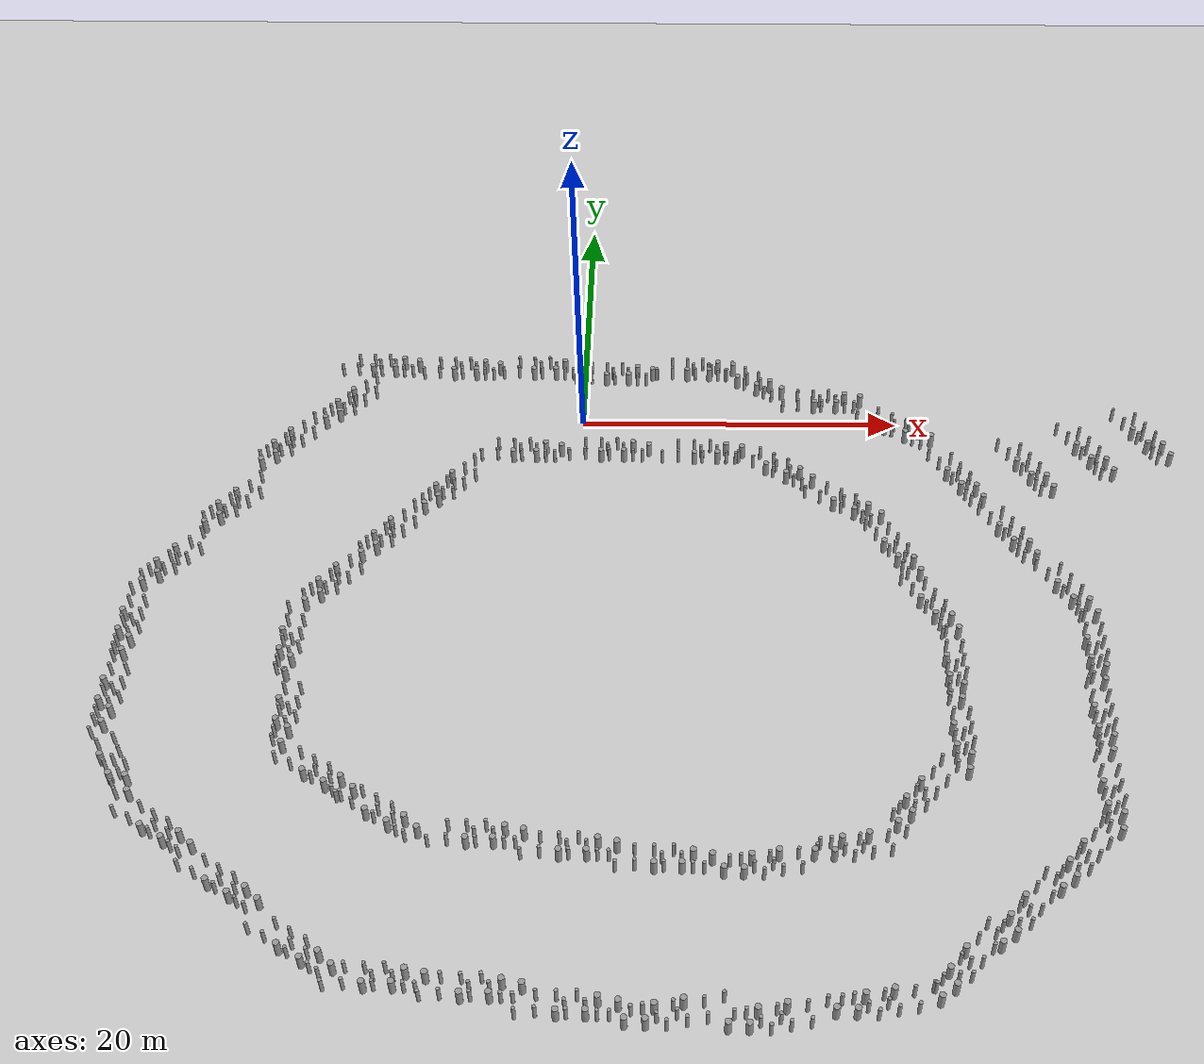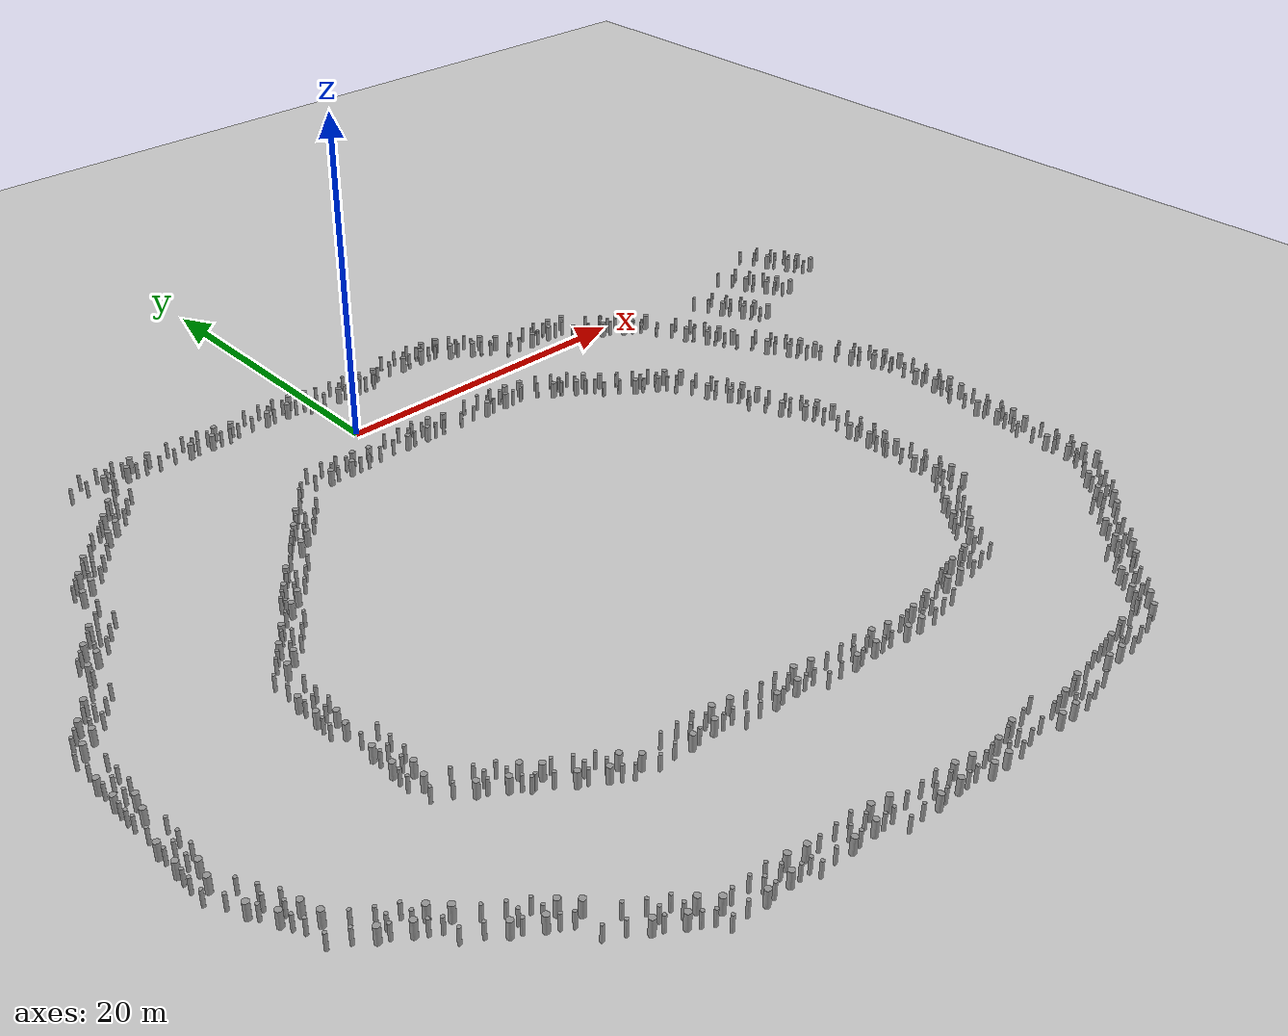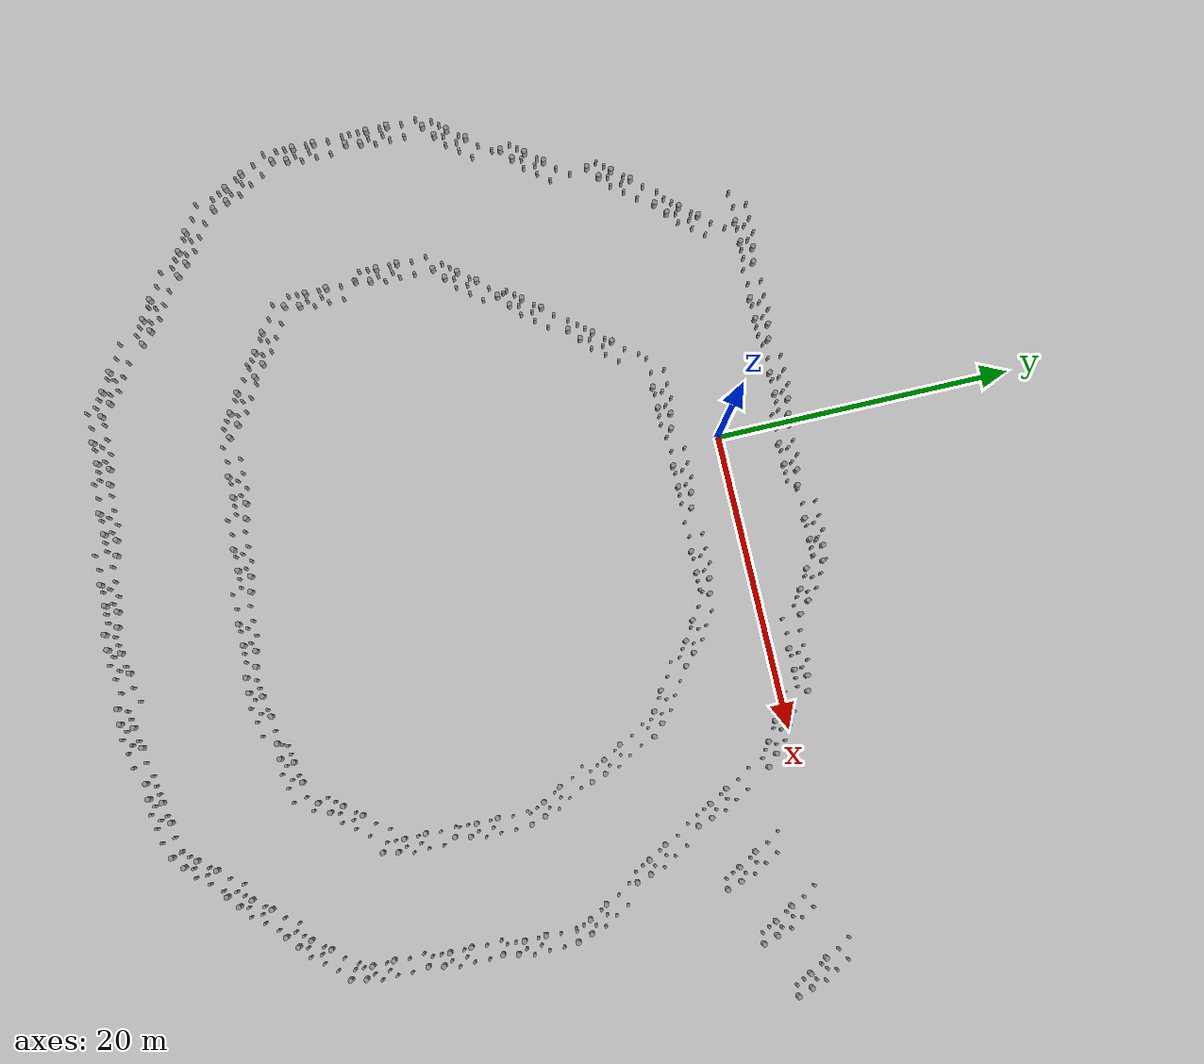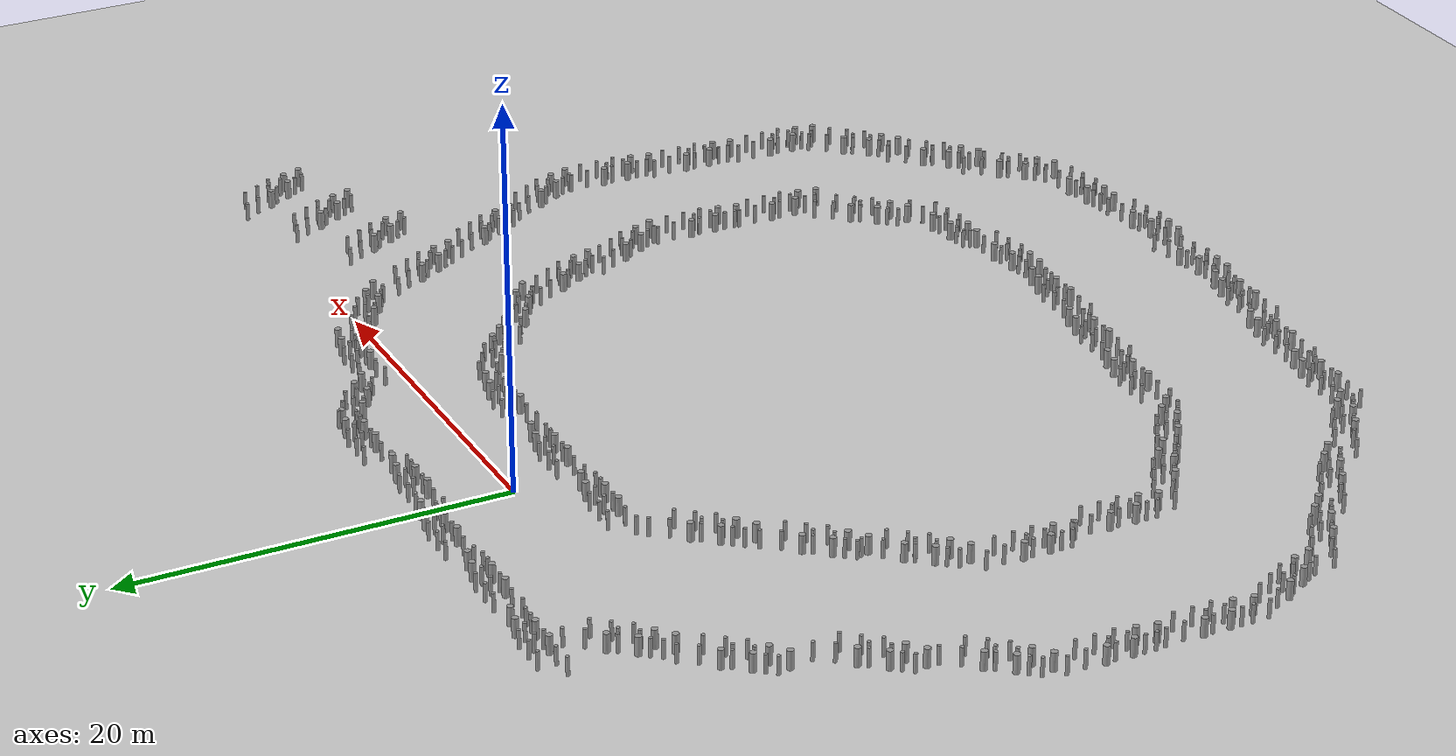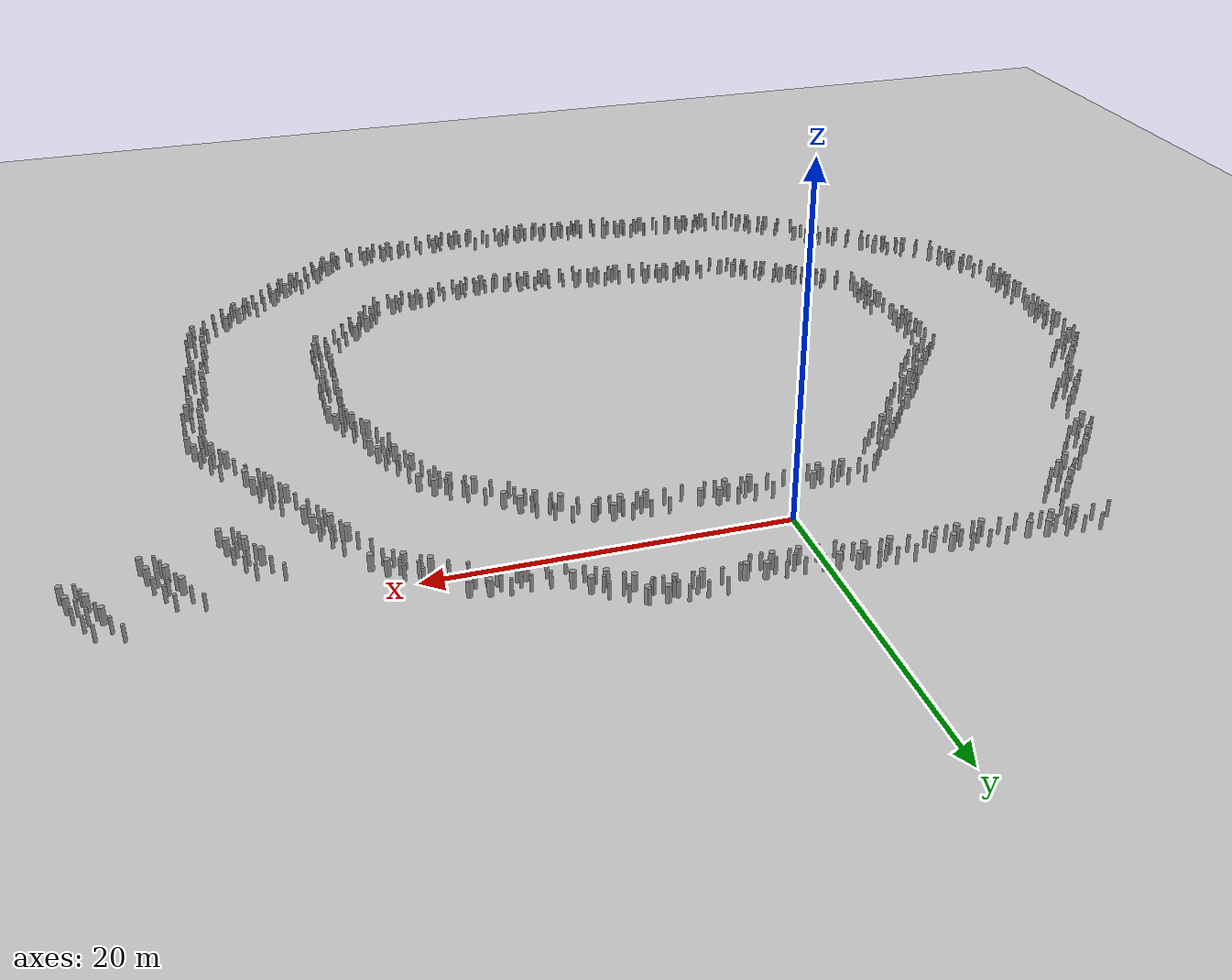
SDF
<sdf version="1.6">
 <world name="default">
  <light name="sun" type="directional">
   <pose>0 0 10 0 -0 0</pose>
   <diffuse>0.8 0.8 0.8 1</diffuse>
   <specular>0.1 0.1 0.1 1</specular>
   <attenuation>
    <range>1000</range>
    <constant>0.9</constant>
    <linear>0.01</linear>
    <quadratic>0.001</quadratic>
   </attenuation>
   <direction>-0.5 0.5 -1</direction>
  </light>
  <model name="ground_plane">
   <static>1</static>
   <link name="link">
    <collision name="collision">
     <geometry><plane><normal>0 0 1</normal><size>100 100</size></plane></geometry>
     <surface><friction><ode><mu>100</mu><mu2>50</mu2></ode></friction></surface>
    </collision>
    <visual name="visual">
     <cast_shadows>0</cast_shadows>
     <geometry><plane><normal>0 0 1</normal><size>100 100</size></plane></geometry>
     <material>
      <script><uri>file://media/materials/scripts/gazebo.material</uri><name>Gazebo/Grey</name></script>
     </material>
    </visual>
   </link>
  </model>
  <gravity>0 0 -9.8</gravity>
  <magnetic_field>6e-06 2.3e-05 -4.2e-05</magnetic_field>
  <atmosphere type="adiabatic"/>
  <physics name="default_physics" default="0" type="ode">
   <max_step_size>0.001</max_step_size>
   <real_time_factor>1</real_time_factor>
   <real_time_update_rate>1000</real_time_update_rate>
  </physics>
  <scene><ambient>0.4 0.4 0.4 1</ambient><background>0.7 0.7 0.7 1</background><shadows>1</shadows></scene>
  <spherical_coordinates>
   <surface_model>EARTH_WGS84</surface_model>
   <latitude_deg>0</latitude_deg>
   <longitude_deg>0</longitude_deg>
   <elevation>0</elevation>
   <heading_deg>0</heading_deg>
  </spherical_coordinates>
  <model name="cyl_wall_clone_clone_0">
   <link name="link_0">
    <pose>-2.73893 -0.366465 0 0 -0 0</pose>
    <inertial>
     <mass>0.0374993</mass>
     <inertia>
      <ixx>0.00321281</ixx>
      <ixy>0</ixy>
      <ixz>0</ixz>
      <iyy>0.00321281</iyy>
      <iyz>0</iyz>
      <izz>0.000175774</izz>
     </inertia>
    </inertial>
    <visual name="visual">
     <geometry><cylinder><radius>0.0968661</radius><length>1</length></cylinder></geometry>
     <material>
      <lighting>1</lighting>
      <script><uri>file://media/materials/scripts/gazebo.material</uri><name>Gazebo/Grey</name></script>
      <ambient>0.3 0.3 0.3 1</ambient>
      <diffuse>0.7 0.7 0.7 1</diffuse>
      <specular>0.01 0.01 0.01 1</specular>
      <emissive>0 0 0 1</emissive>
     </material>
    </visual>
    <collision name="collision">
     <geometry><cylinder><radius>0.096866</radius><length>1</length></cylinder></geometry>
     <surface>
      <friction>
       <ode><mu>1</mu><mu2>1</mu2><fdir1>0 0 0</fdir1><slip1>0</slip1><slip2>0</slip2></ode>
       <torsional>
        <coefficient>1</coefficient>
        <patch_radius>0</patch_radius>
        <surface_radius>0</surface_radius>
        <use_patch_radius>1</use_patch_radius>
        <ode><slip>0</slip></ode>
       </torsional>
      </friction>
      <bounce><restitution_coefficient>0</restitution_coefficient><threshold>1e+06</threshold></bounce>
      <contact>
       <collide_without_contact>0</collide_without_contact>
       <collide_without_contact_bitmask>1</collide_without_contact_bitmask>
       <collide_bitmask>1</collide_bitmask>
       <ode>
        <soft_cfm>0</soft_cfm>
        <soft_erp>0.2</soft_erp>
        <kp>1e+13</kp>
        <kd>1</kd>
        <max_vel>0.01</max_vel>
        <min_depth>0</min_depth>
       </ode>
       <bullet>
        <split_impulse>1</split_impulse>
        <split_impulse_penetration_threshold>-0.01</split_impulse_penetration_threshold>
        <soft_cfm>0</soft_cfm>
        <soft_erp>0.2</soft_erp>
        <kp>1e+13</kp>
        <kd>1</kd>
       </bullet>
      </contact>
     </surface>
    </collision>
   </link>
   <link name="link_0_clone">
    <pose>-1.73893 0.61877 0 0 -0 0</pose>
    <inertial>
     <mass>0.0374993</mass>
     <inertia>
      <ixx>0.00321281</ixx>
      <ixy>0</ixy>
      <ixz>0</ixz>
      <iyy>0.00321281</iyy>
      <iyz>0</iyz>
      <izz>0.000175774</izz>
     </inertia>
    </inertial>
    <visual name="visual">
     <geometry><cylinder><radius>0.0968661</radius><length>1</length></cylinder></geometry>
     <material>
      <lighting>1</lighting>
      <script><uri>file://media/materials/scripts/gazebo.material</uri><name>Gazebo/Grey</name></script>
      <ambient>0.3 0.3 0.3 1</ambient>
      <diffuse>0.7 0.7 0.7 1</diffuse>
      <specular>0.01 0.01 0.01 1</specular>
      <emissive>0 0 0 1</emissive>
      <shader type="pixel"/>
     </material>
    </visual>
    <collision name="collision">
     <geometry><cylinder><radius>0.096866</radius><length>1</length></cylinder></geometry>
     <surface>
      <friction>
       <ode><mu>1</mu><mu2>1</mu2><fdir1>0 0 0</fdir1><slip1>0</slip1><slip2>0</slip2></ode>
       <torsional>
        <coefficient>1</coefficient>
        <patch_radius>0</patch_radius>
        <surface_radius>0</surface_radius>
        <use_patch_radius>1</use_patch_radius>
        <ode><slip>0</slip></ode>
       </torsional>
      </friction>
      <bounce><restitution_coefficient>0</restitution_coefficient><threshold>1e+06</threshold></bounce>
      <contact>
       <collide_without_contact>0</collide_without_contact>
       <collide_without_contact_bitmask>1</collide_without_contact_bitmask>
       <collide_bitmask>1</collide_bitmask>
       <ode>
        <soft_cfm>0</soft_cfm>
        <soft_erp>0.2</soft_erp>
        <kp>1e+13</kp>
        <kd>1</kd>
        <max_vel>0.01</max_vel>
        <min_depth>0</min_depth>
       </ode>
       <bullet>
        <split_impulse>1</split_impulse>
        <split_impulse_penetration_threshold>-0.01</split_impulse_penetration_threshold>
        <soft_cfm>0</soft_cfm>
        <soft_erp>0.2</soft_erp>
        <kp>1e+13</kp>
        <kd>1</kd>
       </bullet>
      </contact>
     </surface>
    </collision>
   </link>
   <link name="link_0_clone_clone">
    <pose>-0.327073 0.143919 0 0 -0 0</pose>
    <inertial>
     <mass>0.0374993</mass>
     <inertia>
      <ixx>0.00321281</ixx>
      <ixy>0</ixy>
      <ixz>0</ixz>
      <iyy>0.00321281</iyy>
      <iyz>0</iyz>
      <izz>0.000175774</izz>
     </inertia>
    </inertial>
    <visual name="visual">
     <geometry><cylinder><radius>0.0968661</radius><length>1</length></cylinder></geometry>
     <material>
      <lighting>1</lighting>
      <script><uri>file://media/materials/scripts/gazebo.material</uri><name>Gazebo/Grey</name></script>
      <ambient>0.3 0.3 0.3 1</ambient>
      <diffuse>0.7 0.7 0.7 1</diffuse>
      <specular>0.01 0.01 0.01 1</specular>
      <emissive>0 0 0 1</emissive>
      <shader type="pixel"/>
     </material>
    </visual>
    <collision name="collision">
     <geometry><cylinder><radius>0.096866</radius><length>1</length></cylinder></geometry>
     <surface>
      <friction>
       <ode><mu>1</mu><mu2>1</mu2><fdir1>0 0 0</fdir1><slip1>0</slip1><slip2>0</slip2></ode>
       <torsional>
        <coefficient>1</coefficient>
        <patch_radius>0</patch_radius>
        <surface_radius>0</surface_radius>
        <use_patch_radius>1</use_patch_radius>
        <ode><slip>0</slip></ode>
       </torsional>
      </friction>
      <bounce><restitution_coefficient>0</restitution_coefficient><threshold>1e+06</threshold></bounce>
      <contact>
       <collide_without_contact>0</collide_without_contact>
       <collide_without_contact_bitmask>1</collide_without_contact_bitmask>
       <collide_bitmask>1</collide_bitmask>
       <ode>
        <soft_cfm>0</soft_cfm>
        <soft_erp>0.2</soft_erp>
        <kp>1e+13</kp>
        <kd>1</kd>
        <max_vel>0.01</max_vel>
        <min_depth>0</min_depth>
       </ode>
       <bullet>
        <split_impulse>1</split_impulse>
        <split_impulse_penetration_threshold>-0.01</split_impulse_penetration_threshold>
        <soft_cfm>0</soft_cfm>
        <soft_erp>0.2</soft_erp>
        <kp>1e+13</kp>
        <kd>1</kd>
       </bullet>
      </contact>
     </surface>
    </collision>
   </link>
   <link name="link_0_clone_clone_0">
    <pose>1.26107 -0.419359 0 0 -0 0</pose>
    <inertial>
     <mass>0.0374993</mass>
     <inertia>
      <ixx>0.00321281</ixx>
      <ixy>0</ixy>
      <ixz>0</ixz>
      <iyy>0.00321281</iyy>
      <iyz>0</iyz>
      <izz>0.000175774</izz>
     </inertia>
    </inertial>
    <visual name="visual">
     <geometry><cylinder><radius>0.0968661</radius><length>1</length></cylinder></geometry>
     <material>
      <lighting>1</lighting>
      <script><uri>file://media/materials/scripts/gazebo.material</uri><name>Gazebo/Grey</name></script>
      <ambient>0.3 0.3 0.3 1</ambient>
      <diffuse>0.7 0.7 0.7 1</diffuse>
      <specular>0.01 0.01 0.01 1</specular>
      <emissive>0 0 0 1</emissive>
      <shader type="pixel"/>
     </material>
    </visual>
    <collision name="collision">
     <geometry><cylinder><radius>0.096866</radius><length>1</length></cylinder></geometry>
     <surface>
      <friction>
       <ode><mu>1</mu><mu2>1</mu2><fdir1>0 0 0</fdir1><slip1>0</slip1><slip2>0</slip2></ode>
       <torsional>
        <coefficient>1</coefficient>
        <patch_radius>0</patch_radius>
        <surface_radius>0</surface_radius>
        <use_patch_radius>1</use_patch_radius>
        <ode><slip>0</slip></ode>
       </torsional>
      </friction>
      <bounce><restitution_coefficient>0</restitution_coefficient><threshold>1e+06</threshold></bounce>
      <contact>
       <collide_without_contact>0</collide_without_contact>
       <collide_without_contact_bitmask>1</collide_without_contact_bitmask>
       <collide_bitmask>1</collide_bitmask>
       <ode>
        <soft_cfm>0</soft_cfm>
        <soft_erp>0.2</soft_erp>
        <kp>1e+13</kp>
        <kd>1</kd>
        <max_vel>0.01</max_vel>
        <min_depth>0</min_depth>
       </ode>
       <bullet>
        <split_impulse>1</split_impulse>
        <split_impulse_penetration_threshold>-0.01</split_impulse_penetration_threshold>
        <soft_cfm>0</soft_cfm>
        <soft_erp>0.2</soft_erp>
        <kp>1e+13</kp>
        <kd>1</kd>
       </bullet>
      </contact>
     </surface>
    </collision>
   </link>
   <link name="link_0_clone_clone_1">
    <pose>-1.73893 -0.277168 0 0 -0 0</pose>
    <inertial>
     <mass>0.0374993</mass>
     <inertia>
      <ixx>0.00321281</ixx>
      <ixy>0</ixy>
      <ixz>0</ixz>
      <iyy>0.00321281</iyy>
      <iyz>0</iyz>
      <izz>0.000175774</izz>
     </inertia>
    </inertial>
    <visual name="visual">
     <geometry><cylinder><radius>0.0968661</radius><length>1</length></cylinder></geometry>
     <material>
      <lighting>1</lighting>
      <script><uri>file://media/materials/scripts/gazebo.material</uri><name>Gazebo/Grey</name></script>
      <ambient>0.3 0.3 0.3 1</ambient>
      <diffuse>0.7 0.7 0.7 1</diffuse>
      <specular>0.01 0.01 0.01 1</specular>
      <emissive>0 0 0 1</emissive>
      <shader type="pixel"/>
     </material>
    </visual>
    <collision name="collision">
     <geometry><cylinder><radius>0.096866</radius><length>1</length></cylinder></geometry>
     <surface>
      <friction>
       <ode><mu>1</mu><mu2>1</mu2><fdir1>0 0 0</fdir1><slip1>0</slip1><slip2>0</slip2></ode>
       <torsional>
        <coefficient>1</coefficient>
        <patch_radius>0</patch_radius>
        <surface_radius>0</surface_radius>
        <use_patch_radius>1</use_patch_radius>
        <ode><slip>0</slip></ode>
       </torsional>
      </friction>
      <bounce><restitution_coefficient>0</restitution_coefficient><threshold>1e+06</threshold></bounce>
      <contact>
       <collide_without_contact>0</collide_without_contact>
       <collide_without_contact_bitmask>1</collide_without_contact_bitmask>
       <collide_bitmask>1</collide_bitmask>
       <ode>
        <soft_cfm>0</soft_cfm>
        <soft_erp>0.2</soft_erp>
        <kp>1e+13</kp>
        <kd>1</kd>
        <max_vel>0.01</max_vel>
        <min_depth>0</min_depth>
       </ode>
       <bullet>
        <split_impulse>1</split_impulse>
        <split_impulse_penetration_threshold>-0.01</split_impulse_penetration_threshold>
        <soft_cfm>0</soft_cfm>
        <soft_erp>0.2</soft_erp>
        <kp>1e+13</kp>
        <kd>1</kd>
       </bullet>
      </contact>
     </surface>
    </collision>
   </link>
   <link name="link_0_clone_clone_2">
    <pose>-0.738934 0.593961 0 0 -0 0</pose>
    <inertial>
     <mass>0.0374993</mass>
     <inertia>
      <ixx>0.00321281</ixx>
      <ixy>0</ixy>
      <ixz>0</ixz>
      <iyy>0.00321281</iyy>
      <iyz>0</iyz>
      <izz>0.000175774</izz>
     </inertia>
    </inertial>
    <visual name="visual">
     <geometry><cylinder><radius>0.0968661</radius><length>1</length></cylinder></geometry>
     <material>
      <lighting>1</lighting>
      <script><uri>file://media/materials/scripts/gazebo.material</uri><name>Gazebo/Grey</name></script>
      <ambient>0.3 0.3 0.3 1</ambient>
      <diffuse>0.7 0.7 0.7 1</diffuse>
      <specular>0.01 0.01 0.01 1</specular>
      <emissive>0 0 0 1</emissive>
      <shader type="pixel"/>
     </material>
    </visual>
    <collision name="collision">
     <geometry><cylinder><radius>0.096866</radius><length>1</length></cylinder></geometry>
     <surface>
      <friction>
       <ode><mu>1</mu><mu2>1</mu2><fdir1>0 0 0</fdir1><slip1>0</slip1><slip2>0</slip2></ode>
       <torsional>
        <coefficient>1</coefficient>
        <patch_radius>0</patch_radius>
        <surface_radius>0</surface_radius>
        <use_patch_radius>1</use_patch_radius>
        <ode><slip>0</slip></ode>
       </torsional>
      </friction>
      <bounce><restitution_coefficient>0</restitution_coefficient><threshold>1e+06</threshold></bounce>
      <contact>
       <collide_without_contact>0</collide_without_contact>
       <collide_without_contact_bitmask>1</collide_without_contact_bitmask>
       <collide_bitmask>1</collide_bitmask>
       <ode>
        <soft_cfm>0</soft_cfm>
        <soft_erp>0.2</soft_erp>
        <kp>1e+13</kp>
        <kd>1</kd>
        <max_vel>0.01</max_vel>
        <min_depth>0</min_depth>
       </ode>
       <bullet>
        <split_impulse>1</split_impulse>
        <split_impulse_penetration_threshold>-0.01</split_impulse_penetration_threshold>
        <soft_cfm>0</soft_cfm>
        <soft_erp>0.2</soft_erp>
        <kp>1e+13</kp>
        <kd>1</kd>
       </bullet>
      </contact>
     </surface>
    </collision>
   </link>
   <link name="link_0_clone_clone_3">
    <pose>0.261066 0.624849 0 0 -0 0</pose>
    <inertial>
     <mass>0.0374993</mass>
     <inertia>
      <ixx>0.00321281</ixx>
      <ixy>0</ixy>
      <ixz>0</ixz>
      <iyy>0.00321281</iyy>
      <iyz>0</iyz>
      <izz>0.000175774</izz>
     </inertia>
    </inertial>
    <visual name="visual">
     <geometry><cylinder><radius>0.0968661</radius><length>1</length></cylinder></geometry>
     <material>
      <lighting>1</lighting>
      <script><uri>file://media/materials/scripts/gazebo.material</uri><name>Gazebo/Grey</name></script>
      <ambient>0.3 0.3 0.3 1</ambient>
      <diffuse>0.7 0.7 0.7 1</diffuse>
      <specular>0.01 0.01 0.01 1</specular>
      <emissive>0 0 0 1</emissive>
      <shader type="pixel"/>
     </material>
    </visual>
    <collision name="collision">
     <geometry><cylinder><radius>0.096866</radius><length>1</length></cylinder></geometry>
     <surface>
      <friction>
       <ode><mu>1</mu><mu2>1</mu2><fdir1>0 0 0</fdir1><slip1>0</slip1><slip2>0</slip2></ode>
       <torsional>
        <coefficient>1</coefficient>
        <patch_radius>0</patch_radius>
        <surface_radius>0</surface_radius>
        <use_patch_radius>1</use_patch_radius>
        <ode><slip>0</slip></ode>
       </torsional>
      </friction>
      <bounce><restitution_coefficient>0</restitution_coefficient><threshold>1e+06</threshold></bounce>
      <contact>
       <collide_without_contact>0</collide_without_contact>
       <collide_without_contact_bitmask>1</collide_without_contact_bitmask>
       <collide_bitmask>1</collide_bitmask>
       <ode>
        <soft_cfm>0</soft_cfm>
        <soft_erp>0.2</soft_erp>
        <kp>1e+13</kp>
        <kd>1</kd>
        <max_vel>0.01</max_vel>
        <min_depth>0</min_depth>
       </ode>
       <bullet>
        <split_impulse>1</split_impulse>
        <split_impulse_penetration_threshold>-0.01</split_impulse_penetration_threshold>
        <soft_cfm>0</soft_cfm>
        <soft_erp>0.2</soft_erp>
        <kp>1e+13</kp>
        <kd>1</kd>
       </bullet>
      </contact>
     </surface>
    </collision>
   </link>
   <link name="link_0_clone_clone_4">
    <pose>-0.239049 -0.353105 0 0 -0 0</pose>
    <inertial>
     <mass>0.0374993</mass>
     <inertia>
      <ixx>0.00321281</ixx>
      <ixy>0</ixy>
      <ixz>0</ixz>
      <iyy>0.00321281</iyy>
      <iyz>0</iyz>
      <izz>0.000175774</izz>
     </inertia>
    </inertial>
    <visual name="visual">
     <geometry><cylinder><radius>0.0968661</radius><length>1</length></cylinder></geometry>
     <material>
      <lighting>1</lighting>
      <script><uri>file://media/materials/scripts/gazebo.material</uri><name>Gazebo/Grey</name></script>
      <ambient>0.3 0.3 0.3 1</ambient>
      <diffuse>0.7 0.7 0.7 1</diffuse>
      <specular>0.01 0.01 0.01 1</specular>
      <emissive>0 0 0 1</emissive>
      <shader type="pixel"/>
     </material>
    </visual>
    <collision name="collision">
     <geometry><cylinder><radius>0.096866</radius><length>1</length></cylinder></geometry>
     <surface>
      <friction>
       <ode><mu>1</mu><mu2>1</mu2><fdir1>0 0 0</fdir1><slip1>0</slip1><slip2>0</slip2></ode>
       <torsional>
        <coefficient>1</coefficient>
        <patch_radius>0</patch_radius>
        <surface_radius>0</surface_radius>
        <use_patch_radius>1</use_patch_radius>
        <ode><slip>0</slip></ode>
       </torsional>
      </friction>
      <bounce><restitution_coefficient>0</restitution_coefficient><threshold>1e+06</threshold></bounce>
      <contact>
       <collide_without_contact>0</collide_without_contact>
       <collide_without_contact_bitmask>1</collide_without_contact_bitmask>
       <collide_bitmask>1</collide_bitmask>
       <ode>
        <soft_cfm>0</soft_cfm>
        <soft_erp>0.2</soft_erp>
        <kp>1e+13</kp>
        <kd>1</kd>
        <max_vel>0.01</max_vel>
        <min_depth>0</min_depth>
       </ode>
       <bullet>
        <split_impulse>1</split_impulse>
        <split_impulse_penetration_threshold>-0.01</split_impulse_penetration_threshold>
        <soft_cfm>0</soft_cfm>
        <soft_erp>0.2</soft_erp>
        <kp>1e+13</kp>
        <kd>1</kd>
       </bullet>
      </contact>
     </surface>
    </collision>
   </link>
   <link name="link_0_clone_clone_5">
    <pose>0.672792 0.143919 0 0 -0 0</pose>
    <inertial>
     <mass>0.0374993</mass>
     <inertia>
      <ixx>0.00321281</ixx>
      <ixy>0</ixy>
      <ixz>0</ixz>
      <iyy>0.00321281</iyy>
      <iyz>0</iyz>
      <izz>0.000175774</izz>
     </inertia>
    </inertial>
    <visual name="visual">
     <geometry><cylinder><radius>0.0968661</radius><length>1</length></cylinder></geometry>
     <material>
      <lighting>1</lighting>
      <script><uri>file://media/materials/scripts/gazebo.material</uri><name>Gazebo/Grey</name></script>
      <ambient>0.3 0.3 0.3 1</ambient>
      <diffuse>0.7 0.7 0.7 1</diffuse>
      <specular>0.01 0.01 0.01 1</specular>
      <emissive>0 0 0 1</emissive>
      <shader type="pixel"/>
     </material>
    </visual>
    <collision name="collision">
     <geometry><cylinder><radius>0.096866</radius><length>1</length></cylinder></geometry>
     <surface>
      <friction>
       <ode><mu>1</mu><mu2>1</mu2><fdir1>0 0 0</fdir1><slip1>0</slip1><slip2>0</slip2></ode>
       <torsional>
        <coefficient>1</coefficient>
        <patch_radius>0</patch_radius>
        <surface_radius>0</surface_radius>
        <use_patch_radius>1</use_patch_radius>
        <ode><slip>0</slip></ode>
       </torsional>
      </friction>
      <bounce><restitution_coefficient>0</restitution_coefficient><threshold>1e+06</threshold></bounce>
      <contact>
       <collide_without_contact>0</collide_without_contact>
       <collide_without_contact_bitmask>1</collide_without_contact_bitmask>
       <collide_bitmask>1</collide_bitmask>
       <ode>
        <soft_cfm>0</soft_cfm>
        <soft_erp>0.2</soft_erp>
        <kp>1e+13</kp>
        <kd>1</kd>
        <max_vel>0.01</max_vel>
        <min_depth>0</min_depth>
       </ode>
       <bullet>
        <split_impulse>1</split_impulse>
        <split_impulse_penetration_threshold>-0.01</split_impulse_penetration_threshold>
        <soft_cfm>0</soft_cfm>
        <soft_erp>0.2</soft_erp>
        <kp>1e+13</kp>
        <kd>1</kd>
       </bullet>
      </contact>
     </surface>
    </collision>
   </link>
   <link name="link_0_clone_clone_6">
    <pose>1.84596 -0.433423 0 0 -0 0</pose>
    <inertial>
     <mass>0.0374993</mass>
     <inertia>
      <ixx>0.00321281</ixx>
      <ixy>0</ixy>
      <ixz>0</ixz>
      <iyy>0.00321281</iyy>
      <iyz>0</iyz>
      <izz>0.000175774</izz>
     </inertia>
    </inertial>
    <visual name="visual">
     <geometry><cylinder><radius>0.0968661</radius><length>1</length></cylinder></geometry>
     <material>
      <lighting>1</lighting>
      <script><uri>file://media/materials/scripts/gazebo.material</uri><name>Gazebo/Grey</name></script>
      <ambient>0.3 0.3 0.3 1</ambient>
      <diffuse>0.7 0.7 0.7 1</diffuse>
      <specular>0.01 0.01 0.01 1</specular>
      <emissive>0 0 0 1</emissive>
      <shader type="pixel"/>
     </material>
    </visual>
    <collision name="collision">
     <geometry><cylinder><radius>0.096866</radius><length>1</length></cylinder></geometry>
     <surface>
      <friction>
       <ode><mu>1</mu><mu2>1</mu2><fdir1>0 0 0</fdir1><slip1>0</slip1><slip2>0</slip2></ode>
       <torsional>
        <coefficient>1</coefficient>
        <patch_radius>0</patch_radius>
        <surface_radius>0</surface_radius>
        <use_patch_radius>1</use_patch_radius>
        <ode><slip>0</slip></ode>
       </torsional>
      </friction>
      <bounce><restitution_coefficient>0</restitution_coefficient><threshold>1e+06</threshold></bounce>
      <contact>
       <collide_without_contact>0</collide_without_contact>
       <collide_without_contact_bitmask>1</collide_without_contact_bitmask>
       <collide_bitmask>1</collide_bitmask>
       <ode>
        <soft_cfm>0</soft_cfm>
        <soft_erp>0.2</soft_erp>
        <kp>1e+13</kp>
        <kd>1</kd>
        <max_vel>0.01</max_vel>
        <min_depth>0</min_depth>
       </ode>
       <bullet>
        <split_impulse>1</split_impulse>
        <split_impulse_penetration_threshold>-0.01</split_impulse_penetration_threshold>
        <soft_cfm>0</soft_cfm>
        <soft_erp>0.2</soft_erp>
        <kp>1e+13</kp>
        <kd>1</kd>
       </bullet>
      </contact>
     </surface>
    </collision>
   </link>
   <link name="link_1">
    <pose>-0.738934 -0.397931 0 0 -0 0</pose>
    <inertial>
     <mass>0.117398</mass>
     <inertia>
      <ixx>0.0106445</ixx>
      <ixy>0</ixy>
      <ixz>0</ixz>
      <iyy>0.0106445</iyy>
      <iyz>0</iyz>
      <izz>0.00172278</izz>
     </inertia>
    </inertial>
    <visual name="visual">
     <geometry><cylinder><radius>0.171317</radius><length>1</length></cylinder></geometry>
     <material>
      <lighting>1</lighting>
      <script><uri>file://media/materials/scripts/gazebo.material</uri><name>Gazebo/Grey</name></script>
      <ambient>0.3 0.3 0.3 1</ambient>
      <diffuse>0.7 0.7 0.7 1</diffuse>
      <specular>0.01 0.01 0.01 1</specular>
      <emissive>0 0 0 1</emissive>
     </material>
    </visual>
    <collision name="collision">
     <geometry><cylinder><radius>0.171317</radius><length>1</length></cylinder></geometry>
     <surface>
      <friction>
       <ode><mu>1</mu><mu2>1</mu2><fdir1>0 0 0</fdir1><slip1>0</slip1><slip2>0</slip2></ode>
       <torsional>
        <coefficient>1</coefficient>
        <patch_radius>0</patch_radius>
        <surface_radius>0</surface_radius>
        <use_patch_radius>1</use_patch_radius>
        <ode><slip>0</slip></ode>
       </torsional>
      </friction>
      <bounce><restitution_coefficient>0</restitution_coefficient><threshold>1e+06</threshold></bounce>
      <contact>
       <collide_without_contact>0</collide_without_contact>
       <collide_without_contact_bitmask>1</collide_without_contact_bitmask>
       <collide_bitmask>1</collide_bitmask>
       <ode>
        <soft_cfm>0</soft_cfm>
        <soft_erp>0.2</soft_erp>
        <kp>1e+13</kp>
        <kd>1</kd>
        <max_vel>0.01</max_vel>
        <min_depth>0</min_depth>
       </ode>
       <bullet>
        <split_impulse>1</split_impulse>
        <split_impulse_penetration_threshold>-0.01</split_impulse_penetration_threshold>
        <soft_cfm>0</soft_cfm>
        <soft_erp>0.2</soft_erp>
        <kp>1e+13</kp>
        <kd>1</kd>
       </bullet>
      </contact>
     </surface>
    </collision>
   </link>
   <link name="link_1_clone">
    <pose>0.697784 -0.380861 0 0 -0 0</pose>
    <inertial>
     <mass>0.117398</mass>
     <inertia>
      <ixx>0.0106445</ixx>
      <ixy>0</ixy>
      <ixz>0</ixz>
      <iyy>0.0106445</iyy>
      <iyz>0</iyz>
      <izz>0.00172278</izz>
     </inertia>
    </inertial>
    <visual name="visual">
     <geometry><cylinder><radius>0.171317</radius><length>1</length></cylinder></geometry>
     <material>
      <lighting>1</lighting>
      <script><uri>file://media/materials/scripts/gazebo.material</uri><name>Gazebo/Grey</name></script>
      <ambient>0.3 0.3 0.3 1</ambient>
      <diffuse>0.7 0.7 0.7 1</diffuse>
      <specular>0.01 0.01 0.01 1</specular>
      <emissive>0 0 0 1</emissive>
      <shader type="pixel"/>
     </material>
    </visual>
    <collision name="collision">
     <geometry><cylinder><radius>0.171317</radius><length>1</length></cylinder></geometry>
     <surface>
      <friction>
       <ode><mu>1</mu><mu2>1</mu2><fdir1>0 0 0</fdir1><slip1>0</slip1><slip2>0</slip2></ode>
       <torsional>
        <coefficient>1</coefficient>
        <patch_radius>0</patch_radius>
        <surface_radius>0</surface_radius>
        <use_patch_radius>1</use_patch_radius>
        <ode><slip>0</slip></ode>
       </torsional>
      </friction>
      <bounce><restitution_coefficient>0</restitution_coefficient><threshold>1e+06</threshold></bounce>
      <contact>
       <collide_without_contact>0</collide_without_contact>
       <collide_without_contact_bitmask>1</collide_without_contact_bitmask>
       <collide_bitmask>1</collide_bitmask>
       <ode>
        <soft_cfm>0</soft_cfm>
        <soft_erp>0.2</soft_erp>
        <kp>1e+13</kp>
        <kd>1</kd>
        <max_vel>0.01</max_vel>
        <min_depth>0</min_depth>
       </ode>
       <bullet>
        <split_impulse>1</split_impulse>
        <split_impulse_penetration_threshold>-0.01</split_impulse_penetration_threshold>
        <soft_cfm>0</soft_cfm>
        <soft_erp>0.2</soft_erp>
        <kp>1e+13</kp>
        <kd>1</kd>
       </bullet>
      </contact>
     </surface>
    </collision>
   </link>
   <link name="link_1_clone_0">
    <pose>1.26107 0.358974 0 0 -0 0</pose>
    <inertial>
     <mass>0.117398</mass>
     <inertia>
      <ixx>0.0106445</ixx>
      <ixy>0</ixy>
      <ixz>0</ixz>
      <iyy>0.0106445</iyy>
      <iyz>0</iyz>
      <izz>0.00172278</izz>
     </inertia>
    </inertial>
    <visual name="visual">
     <geometry><cylinder><radius>0.171317</radius><length>1</length></cylinder></geometry>
     <material>
      <lighting>1</lighting>
      <script><uri>file://media/materials/scripts/gazebo.material</uri><name>Gazebo/Grey</name></script>
      <ambient>0.3 0.3 0.3 1</ambient>
      <diffuse>0.7 0.7 0.7 1</diffuse>
      <specular>0.01 0.01 0.01 1</specular>
      <emissive>0 0 0 1</emissive>
      <shader type="pixel"/>
     </material>
    </visual>
    <collision name="collision">
     <geometry><cylinder><radius>0.171317</radius><length>1</length></cylinder></geometry>
     <surface>
      <friction>
       <ode><mu>1</mu><mu2>1</mu2><fdir1>0 0 0</fdir1><slip1>0</slip1><slip2>0</slip2></ode>
       <torsional>
        <coefficient>1</coefficient>
        <patch_radius>0</patch_radius>
        <surface_radius>0</surface_radius>
        <use_patch_radius>1</use_patch_radius>
        <ode><slip>0</slip></ode>
       </torsional>
      </friction>
      <bounce><restitution_coefficient>0</restitution_coefficient><threshold>1e+06</threshold></bounce>
      <contact>
       <collide_without_contact>0</collide_without_contact>
       <collide_without_contact_bitmask>1</collide_without_contact_bitmask>
       <collide_bitmask>1</collide_bitmask>
       <ode>
        <soft_cfm>0</soft_cfm>
        <soft_erp>0.2</soft_erp>
        <kp>1e+13</kp>
        <kd>1</kd>
        <max_vel>0.01</max_vel>
        <min_depth>0</min_depth>
       </ode>
       <bullet>
        <split_impulse>1</split_impulse>
        <split_impulse_penetration_threshold>-0.01</split_impulse_penetration_threshold>
        <soft_cfm>0</soft_cfm>
        <soft_erp>0.2</soft_erp>
        <kp>1e+13</kp>
        <kd>1</kd>
       </bullet>
      </contact>
     </surface>
    </collision>
   </link>
   <link name="link_1_clone_1">
    <pose>2.26107 0.143919 0 0 -0 0</pose>
    <inertial>
     <mass>0.117398</mass>
     <inertia>
      <ixx>0.0106445</ixx>
      <ixy>0</ixy>
      <ixz>0</ixz>
      <iyy>0.0106445</iyy>
      <iyz>0</iyz>
      <izz>0.00172278</izz>
     </inertia>
    </inertial>
    <visual name="visual">
     <geometry><cylinder><radius>0.171317</radius><length>1</length></cylinder></geometry>
     <material>
      <lighting>1</lighting>
      <script><uri>file://media/materials/scripts/gazebo.material</uri><name>Gazebo/Grey</name></script>
      <ambient>0.3 0.3 0.3 1</ambient>
      <diffuse>0.7 0.7 0.7 1</diffuse>
      <specular>0.01 0.01 0.01 1</specular>
      <emissive>0 0 0 1</emissive>
      <shader type="pixel"/>
     </material>
    </visual>
    <collision name="collision">
     <geometry><cylinder><radius>0.171317</radius><length>1</length></cylinder></geometry>
     <surface>
      <friction>
       <ode><mu>1</mu><mu2>1</mu2><fdir1>0 0 0</fdir1><slip1>0</slip1><slip2>0</slip2></ode>
       <torsional>
        <coefficient>1</coefficient>
        <patch_radius>0</patch_radius>
        <surface_radius>0</surface_radius>
        <use_patch_radius>1</use_patch_radius>
        <ode><slip>0</slip></ode>
       </torsional>
      </friction>
      <bounce><restitution_coefficient>0</restitution_coefficient><threshold>1e+06</threshold></bounce>
      <contact>
       <collide_without_contact>0</collide_without_contact>
       <collide_without_contact_bitmask>1</collide_without_contact_bitmask>
       <collide_bitmask>1</collide_bitmask>
       <ode>
        <soft_cfm>0</soft_cfm>
        <soft_erp>0.2</soft_erp>
        <kp>1e+13</kp>
        <kd>1</kd>
        <max_vel>0.01</max_vel>
        <min_depth>0</min_depth>
       </ode>
       <bullet>
        <split_impulse>1</split_impulse>
        <split_impulse_penetration_threshold>-0.01</split_impulse_penetration_threshold>
        <soft_cfm>0</soft_cfm>
        <soft_erp>0.2</soft_erp>
        <kp>1e+13</kp>
        <kd>1</kd>
       </bullet>
      </contact>
     </surface>
    </collision>
   </link>
   <static>1</static>
   <pose>7.85891 -3.15943 0.5 0 -0 0</pose>
  </model>
  <model name="cyl_wall_clone_clone_1">
   <link name="link_0">
    <pose>-2.73893 -0.366465 0 0 -0 0</pose>
    <inertial>
     <mass>0.0374993</mass>
     <inertia>
      <ixx>0.00321281</ixx>
      <ixy>0</ixy>
      <ixz>0</ixz>
      <iyy>0.00321281</iyy>
      <iyz>0</iyz>
      <izz>0.000175774</izz>
     </inertia>
    </inertial>
    <visual name="visual">
     <geometry><cylinder><radius>0.0968661</radius><length>1</length></cylinder></geometry>
     <material>
      <lighting>1</lighting>
      <script><uri>file://media/materials/scripts/gazebo.material</uri><name>Gazebo/Grey</name></script>
      <ambient>0.3 0.3 0.3 1</ambient>
      <diffuse>0.7 0.7 0.7 1</diffuse>
      <specular>0.01 0.01 0.01 1</specular>
      <emissive>0 0 0 1</emissive>
     </material>
    </visual>
    <collision name="collision">
     <geometry><cylinder><radius>0.096866</radius><length>1</length></cylinder></geometry>
     <surface>
      <friction>
       <ode><mu>1</mu><mu2>1</mu2><fdir1>0 0 0</fdir1><slip1>0</slip1><slip2>0</slip2></ode>
       <torsional>
        <coefficient>1</coefficient>
        <patch_radius>0</patch_radius>
        <surface_radius>0</surface_radius>
        <use_patch_radius>1</use_patch_radius>
        <ode><slip>0</slip></ode>
       </torsional>
      </friction>
      <bounce><restitution_coefficient>0</restitution_coefficient><threshold>1e+06</threshold></bounce>
      <contact>
       <collide_without_contact>0</collide_without_contact>
       <collide_without_contact_bitmask>1</collide_without_contact_bitmask>
       <collide_bitmask>1</collide_bitmask>
       <ode>
        <soft_cfm>0</soft_cfm>
        <soft_erp>0.2</soft_erp>
        <kp>1e+13</kp>
        <kd>1</kd>
        <max_vel>0.01</max_vel>
        <min_depth>0</min_depth>
       </ode>
       <bullet>
        <split_impulse>1</split_impulse>
        <split_impulse_penetration_threshold>-0.01</split_impulse_penetration_threshold>
        <soft_cfm>0</soft_cfm>
        <soft_erp>0.2</soft_erp>
        <kp>1e+13</kp>
        <kd>1</kd>
       </bullet>
      </contact>
     </surface>
    </collision>
   </link>
   <link name="link_0_clone">
    <pose>-1.73893 0.61877 0 0 -0 0</pose>
    <inertial>
     <mass>0.0374993</mass>
     <inertia>
      <ixx>0.00321281</ixx>
      <ixy>0</ixy>
      <ixz>0</ixz>
      <iyy>0.00321281</iyy>
      <iyz>0</iyz>
      <izz>0.000175774</izz>
     </inertia>
    </inertial>
    <visual name="visual">
     <geometry><cylinder><radius>0.0968661</radius><length>1</length></cylinder></geometry>
     <material>
      <lighting>1</lighting>
      <script><uri>file://media/materials/scripts/gazebo.material</uri><name>Gazebo/Grey</name></script>
      <ambient>0.3 0.3 0.3 1</ambient>
      <diffuse>0.7 0.7 0.7 1</diffuse>
      <specular>0.01 0.01 0.01 1</specular>
      <emissive>0 0 0 1</emissive>
      <shader type="pixel"/>
     </material>
    </visual>
    <collision name="collision">
     <geometry><cylinder><radius>0.096866</radius><length>1</length></cylinder></geometry>
     <surface>
      <friction>
       <ode><mu>1</mu><mu2>1</mu2><fdir1>0 0 0</fdir1><slip1>0</slip1><slip2>0</slip2></ode>
       <torsional>
        <coefficient>1</coefficient>
        <patch_radius>0</patch_radius>
        <surface_radius>0</surface_radius>
        <use_patch_radius>1</use_patch_radius>
        <ode><slip>0</slip></ode>
       </torsional>
      </friction>
      <bounce><restitution_coefficient>0</restitution_coefficient><threshold>1e+06</threshold></bounce>
      <contact>
       <collide_without_contact>0</collide_without_contact>
       <collide_without_contact_bitmask>1</collide_without_contact_bitmask>
       <collide_bitmask>1</collide_bitmask>
       <ode>
        <soft_cfm>0</soft_cfm>
        <soft_erp>0.2</soft_erp>
        <kp>1e+13</kp>
        <kd>1</kd>
        <max_vel>0.01</max_vel>
        <min_depth>0</min_depth>
       </ode>
       <bullet>
        <split_impulse>1</split_impulse>
        <split_impulse_penetration_threshold>-0.01</split_impulse_penetration_threshold>
        <soft_cfm>0</soft_cfm>
        <soft_erp>0.2</soft_erp>
        <kp>1e+13</kp>
        <kd>1</kd>
       </bullet>
      </contact>
     </surface>
    </collision>
   </link>
   <link name="link_0_clone_clone">
    <pose>-0.327073 0.143919 0 0 -0 0</pose>
    <inertial>
     <mass>0.0374993</mass>
     <inertia>
      <ixx>0.00321281</ixx>
      <ixy>0</ixy>
      <ixz>0</ixz>
      <iyy>0.00321281</iyy>
      <iyz>0</iyz>
      <izz>0.000175774</izz>
     </inertia>
    </inertial>
    <visual name="visual">
     <geometry><cylinder><radius>0.0968661</radius><length>1</length></cylinder></geometry>
     <material>
      <lighting>1</lighting>
      <script><uri>file://media/materials/scripts/gazebo.material</uri><name>Gazebo/Grey</name></script>
      <ambient>0.3 0.3 0.3 1</ambient>
      <diffuse>0.7 0.7 0.7 1</diffuse>
      <specular>0.01 0.01 0.01 1</specular>
      <emissive>0 0 0 1</emissive>
      <shader type="pixel"/>
     </material>
    </visual>
    <collision name="collision">
     <geometry><cylinder><radius>0.096866</radius><length>1</length></cylinder></geometry>
     <surface>
      <friction>
       <ode><mu>1</mu><mu2>1</mu2><fdir1>0 0 0</fdir1><slip1>0</slip1><slip2>0</slip2></ode>
       <torsional>
        <coefficient>1</coefficient>
        <patch_radius>0</patch_radius>
        <surface_radius>0</surface_radius>
        <use_patch_radius>1</use_patch_radius>
        <ode><slip>0</slip></ode>
       </torsional>
      </friction>
      <bounce><restitution_coefficient>0</restitution_coefficient><threshold>1e+06</threshold></bounce>
      <contact>
       <collide_without_contact>0</collide_without_contact>
       <collide_without_contact_bitmask>1</collide_without_contact_bitmask>
       <collide_bitmask>1</collide_bitmask>
       <ode>
        <soft_cfm>0</soft_cfm>
        <soft_erp>0.2</soft_erp>
        <kp>1e+13</kp>
        <kd>1</kd>
        <max_vel>0.01</max_vel>
        <min_depth>0</min_depth>
       </ode>
       <bullet>
        <split_impulse>1</split_impulse>
        <split_impulse_penetration_threshold>-0.01</split_impulse_penetration_threshold>
        <soft_cfm>0</soft_cfm>
        <soft_erp>0.2</soft_erp>
        <kp>1e+13</kp>
        <kd>1</kd>
       </bullet>
      </contact>
     </surface>
    </collision>
   </link>
   <link name="link_0_clone_clone_0">
    <pose>1.26107 -0.419359 0 0 -0 0</pose>
    <inertial>
     <mass>0.0374993</mass>
     <inertia>
      <ixx>0.00321281</ixx>
      <ixy>0</ixy>
      <ixz>0</ixz>
      <iyy>0.00321281</iyy>
      <iyz>0</iyz>
      <izz>0.000175774</izz>
     </inertia>
    </inertial>
    <visual name="visual">
     <geometry><cylinder><radius>0.0968661</radius><length>1</length></cylinder></geometry>
     <material>
      <lighting>1</lighting>
      <script><uri>file://media/materials/scripts/gazebo.material</uri><name>Gazebo/Grey</name></script>
      <ambient>0.3 0.3 0.3 1</ambient>
      <diffuse>0.7 0.7 0.7 1</diffuse>
      <specular>0.01 0.01 0.01 1</specular>
      <emissive>0 0 0 1</emissive>
      <shader type="pixel"/>
     </material>
    </visual>
    <collision name="collision">
     <geometry><cylinder><radius>0.096866</radius><length>1</length></cylinder></geometry>
     <surface>
      <friction>
       <ode><mu>1</mu><mu2>1</mu2><fdir1>0 0 0</fdir1><slip1>0</slip1><slip2>0</slip2></ode>
       <torsional>
        <coefficient>1</coefficient>
        <patch_radius>0</patch_radius>
        <surface_radius>0</surface_radius>
        <use_patch_radius>1</use_patch_radius>
        <ode><slip>0</slip></ode>
       </torsional>
      </friction>
      <bounce><restitution_coefficient>0</restitution_coefficient><threshold>1e+06</threshold></bounce>
      <contact>
       <collide_without_contact>0</collide_without_contact>
       <collide_without_contact_bitmask>1</collide_without_contact_bitmask>
       <collide_bitmask>1</collide_bitmask>
       <ode>
        <soft_cfm>0</soft_cfm>
        <soft_erp>0.2</soft_erp>
        <kp>1e+13</kp>
        <kd>1</kd>
        <max_vel>0.01</max_vel>
        <min_depth>0</min_depth>
       </ode>
       <bullet>
        <split_impulse>1</split_impulse>
        <split_impulse_penetration_threshold>-0.01</split_impulse_penetration_threshold>
        <soft_cfm>0</soft_cfm>
        <soft_erp>0.2</soft_erp>
        <kp>1e+13</kp>
        <kd>1</kd>
       </bullet>
      </contact>
     </surface>
    </collision>
   </link>
   <link name="link_0_clone_clone_1">
    <pose>-1.73893 -0.277168 0 0 -0 0</pose>
    <inertial>
     <mass>0.0374993</mass>
     <inertia>
      <ixx>0.00321281</ixx>
      <ixy>0</ixy>
      <ixz>0</ixz>
      <iyy>0.00321281</iyy>
      <iyz>0</iyz>
      <izz>0.000175774</izz>
     </inertia>
    </inertial>
    <visual name="visual">
     <geometry><cylinder><radius>0.0968661</radius><length>1</length></cylinder></geometry>
     <material>
      <lighting>1</lighting>
      <script><uri>file://media/materials/scripts/gazebo.material</uri><name>Gazebo/Grey</name></script>
      <ambient>0.3 0.3 0.3 1</ambient>
      <diffuse>0.7 0.7 0.7 1</diffuse>
      <specular>0.01 0.01 0.01 1</specular>
      <emissive>0 0 0 1</emissive>
      <shader type="pixel"/>
     </material>
    </visual>
    <collision name="collision">
     <geometry><cylinder><radius>0.096866</radius><length>1</length></cylinder></geometry>
     <surface>
      <friction>
       <ode><mu>1</mu><mu2>1</mu2><fdir1>0 0 0</fdir1><slip1>0</slip1><slip2>0</slip2></ode>
       <torsional>
        <coefficient>1</coefficient>
        <patch_radius>0</patch_radius>
        <surface_radius>0</surface_radius>
        <use_patch_radius>1</use_patch_radius>
        <ode><slip>0</slip></ode>
       </torsional>
      </friction>
      <bounce><restitution_coefficient>0</restitution_coefficient><threshold>1e+06</threshold></bounce>
      <contact>
       <collide_without_contact>0</collide_without_contact>
       <collide_without_contact_bitmask>1</collide_without_contact_bitmask>
       <collide_bitmask>1</collide_bitmask>
       <ode>
        <soft_cfm>0</soft_cfm>
        <soft_erp>0.2</soft_erp>
        <kp>1e+13</kp>
        <kd>1</kd>
        <max_vel>0.01</max_vel>
        <min_depth>0</min_depth>
       </ode>
       <bullet>
        <split_impulse>1</split_impulse>
        <split_impulse_penetration_threshold>-0.01</split_impulse_penetration_threshold>
        <soft_cfm>0</soft_cfm>
        <soft_erp>0.2</soft_erp>
        <kp>1e+13</kp>
        <kd>1</kd>
       </bullet>
      </contact>
     </surface>
    </collision>
   </link>
   <link name="link_0_clone_clone_2">
    <pose>-0.738934 0.593961 0 0 -0 0</pose>
    <inertial>
     <mass>0.0374993</mass>
     <inertia>
      <ixx>0.00321281</ixx>
      <ixy>0</ixy>
      <ixz>0</ixz>
      <iyy>0.00321281</iyy>
      <iyz>0</iyz>
      <izz>0.000175774</izz>
     </inertia>
    </inertial>
    <visual name="visual">
     <geometry><cylinder><radius>0.0968661</radius><length>1</length></cylinder></geometry>
     <material>
      <lighting>1</lighting>
      <script><uri>file://media/materials/scripts/gazebo.material</uri><name>Gazebo/Grey</name></script>
      <ambient>0.3 0.3 0.3 1</ambient>
      <diffuse>0.7 0.7 0.7 1</diffuse>
      <specular>0.01 0.01 0.01 1</specular>
      <emissive>0 0 0 1</emissive>
      <shader type="pixel"/>
     </material>
    </visual>
    <collision name="collision">
     <geometry><cylinder><radius>0.096866</radius><length>1</length></cylinder></geometry>
     <surface>
      <friction>
       <ode><mu>1</mu><mu2>1</mu2><fdir1>0 0 0</fdir1><slip1>0</slip1><slip2>0</slip2></ode>
       <torsional>
        <coefficient>1</coefficient>
        <patch_radius>0</patch_radius>
        <surface_radius>0</surface_radius>
        <use_patch_radius>1</use_patch_radius>
        <ode><slip>0</slip></ode>
       </torsional>
      </friction>
      <bounce><restitution_coefficient>0</restitution_coefficient><threshold>1e+06</threshold></bounce>
      <contact>
       <collide_without_contact>0</collide_without_contact>
       <collide_without_contact_bitmask>1</collide_without_contact_bitmask>
       <collide_bitmask>1</collide_bitmask>
       <ode>
        <soft_cfm>0</soft_cfm>
        <soft_erp>0.2</soft_erp>
        <kp>1e+13</kp>
        <kd>1</kd>
        <max_vel>0.01</max_vel>
        <min_depth>0</min_depth>
       </ode>
       <bullet>
        <split_impulse>1</split_impulse>
        <split_impulse_penetration_threshold>-0.01</split_impulse_penetration_threshold>
        <soft_cfm>0</soft_cfm>
        <soft_erp>0.2</soft_erp>
        <kp>1e+13</kp>
        <kd>1</kd>
       </bullet>
      </contact>
     </surface>
    </collision>
   </link>
   <link name="link_0_clone_clone_3">
    <pose>0.261066 0.624849 0 0 -0 0</pose>
    <inertial>
     <mass>0.0374993</mass>
     <inertia>
      <ixx>0.00321281</ixx>
      <ixy>0</ixy>
      <ixz>0</ixz>
      <iyy>0.00321281</iyy>
      <iyz>0</iyz>
      <izz>0.000175774</izz>
     </inertia>
    </inertial>
    <visual name="visual">
     <geometry><cylinder><radius>0.0968661</radius><length>1</length></cylinder></geometry>
     <material>
      <lighting>1</lighting>
      <script><uri>file://media/materials/scripts/gazebo.material</uri><name>Gazebo/Grey</name></script>
      <ambient>0.3 0.3 0.3 1</ambient>
      <diffuse>0.7 0.7 0.7 1</diffuse>
      <specular>0.01 0.01 0.01 1</specular>
      <emissive>0 0 0 1</emissive>
      <shader type="pixel"/>
     </material>
    </visual>
    <collision name="collision">
     <geometry><cylinder><radius>0.096866</radius><length>1</length></cylinder></geometry>
     <surface>
      <friction>
       <ode><mu>1</mu><mu2>1</mu2><fdir1>0 0 0</fdir1><slip1>0</slip1><slip2>0</slip2></ode>
       <torsional>
        <coefficient>1</coefficient>
        <patch_radius>0</patch_radius>
        <surface_radius>0</surface_radius>
        <use_patch_radius>1</use_patch_radius>
        <ode><slip>0</slip></ode>
       </torsional>
      </friction>
      <bounce><restitution_coefficient>0</restitution_coefficient><threshold>1e+06</threshold></bounce>
      <contact>
       <collide_without_contact>0</collide_without_contact>
       <collide_without_contact_bitmask>1</collide_without_contact_bitmask>
       <collide_bitmask>1</collide_bitmask>
       <ode>
        <soft_cfm>0</soft_cfm>
        <soft_erp>0.2</soft_erp>
        <kp>1e+13</kp>
        <kd>1</kd>
        <max_vel>0.01</max_vel>
        <min_depth>0</min_depth>
       </ode>
       <bullet>
        <split_impulse>1</split_impulse>
        <split_impulse_penetration_threshold>-0.01</split_impulse_penetration_threshold>
        <soft_cfm>0</soft_cfm>
        <soft_erp>0.2</soft_erp>
        <kp>1e+13</kp>
        <kd>1</kd>
       </bullet>
      </contact>
     </surface>
    </collision>
   </link>
   <link name="link_0_clone_clone_4">
    <pose>-0.239049 -0.353105 0 0 -0 0</pose>
    <inertial>
     <mass>0.0374993</mass>
     <inertia>
      <ixx>0.00321281</ixx>
      <ixy>0</ixy>
      <ixz>0</ixz>
      <iyy>0.00321281</iyy>
      <iyz>0</iyz>
      <izz>0.000175774</izz>
     </inertia>
    </inertial>
    <visual name="visual">
     <geometry><cylinder><radius>0.0968661</radius><length>1</length></cylinder></geometry>
     <material>
      <lighting>1</lighting>
      <script><uri>file://media/materials/scripts/gazebo.material</uri><name>Gazebo/Grey</name></script>
      <ambient>0.3 0.3 0.3 1</ambient>
      <diffuse>0.7 0.7 0.7 1</diffuse>
      <specular>0.01 0.01 0.01 1</specular>
      <emissive>0 0 0 1</emissive>
      <shader type="pixel"/>
     </material>
    </visual>
    <collision name="collision">
     <geometry><cylinder><radius>0.096866</radius><length>1</length></cylinder></geometry>
     <surface>
      <friction>
       <ode><mu>1</mu><mu2>1</mu2><fdir1>0 0 0</fdir1><slip1>0</slip1><slip2>0</slip2></ode>
       <torsional>
        <coefficient>1</coefficient>
        <patch_radius>0</patch_radius>
        <surface_radius>0</surface_radius>
        <use_patch_radius>1</use_patch_radius>
        <ode><slip>0</slip></ode>
       </torsional>
      </friction>
      <bounce><restitution_coefficient>0</restitution_coefficient><threshold>1e+06</threshold></bounce>
      <contact>
       <collide_without_contact>0</collide_without_contact>
       <collide_without_contact_bitmask>1</collide_without_contact_bitmask>
       <collide_bitmask>1</collide_bitmask>
       <ode>
        <soft_cfm>0</soft_cfm>
        <soft_erp>0.2</soft_erp>
        <kp>1e+13</kp>
        <kd>1</kd>
        <max_vel>0.01</max_vel>
        <min_depth>0</min_depth>
       </ode>
       <bullet>
        <split_impulse>1</split_impulse>
        <split_impulse_penetration_threshold>-0.01</split_impulse_penetration_threshold>
        <soft_cfm>0</soft_cfm>
        <soft_erp>0.2</soft_erp>
        <kp>1e+13</kp>
        <kd>1</kd>
       </bullet>
      </contact>
     </surface>
    </collision>
   </link>
   <link name="link_0_clone_clone_5">
    <pose>0.672792 0.143919 0 0 -0 0</pose>
    <inertial>
     <mass>0.0374993</mass>
     <inertia>
      <ixx>0.00321281</ixx>
      <ixy>0</ixy>
      <ixz>0</ixz>
      <iyy>0.00321281</iyy>
      <iyz>0</iyz>
      <izz>0.000175774</izz>
     </inertia>
    </inertial>
    <visual name="visual">
     <geometry><cylinder><radius>0.0968661</radius><length>1</length></cylinder></geometry>
     <material>
      <lighting>1</lighting>
      <script><uri>file://media/materials/scripts/gazebo.material</uri><name>Gazebo/Grey</name></script>
      <ambient>0.3 0.3 0.3 1</ambient>
      <diffuse>0.7 0.7 0.7 1</diffuse>
      <specular>0.01 0.01 0.01 1</specular>
      <emissive>0 0 0 1</emissive>
      <shader type="pixel"/>
     </material>
    </visual>
    <collision name="collision">
     <geometry><cylinder><radius>0.096866</radius><length>1</length></cylinder></geometry>
     <surface>
      <friction>
       <ode><mu>1</mu><mu2>1</mu2><fdir1>0 0 0</fdir1><slip1>0</slip1><slip2>0</slip2></ode>
       <torsional>
        <coefficient>1</coefficient>
        <patch_radius>0</patch_radius>
        <surface_radius>0</surface_radius>
        <use_patch_radius>1</use_patch_radius>
        <ode><slip>0</slip></ode>
       </torsional>
      </friction>
      <bounce><restitution_coefficient>0</restitution_coefficient><threshold>1e+06</threshold></bounce>
      <contact>
       <collide_without_contact>0</collide_without_contact>
       <collide_without_contact_bitmask>1</collide_without_contact_bitmask>
       <collide_bitmask>1</collide_bitmask>
       <ode>
        <soft_cfm>0</soft_cfm>
        <soft_erp>0.2</soft_erp>
        <kp>1e+13</kp>
        <kd>1</kd>
        <max_vel>0.01</max_vel>
        <min_depth>0</min_depth>
       </ode>
       <bullet>
        <split_impulse>1</split_impulse>
        <split_impulse_penetration_threshold>-0.01</split_impulse_penetration_threshold>
        <soft_cfm>0</soft_cfm>
        <soft_erp>0.2</soft_erp>
        <kp>1e+13</kp>
        <kd>1</kd>
       </bullet>
      </contact>
     </surface>
    </collision>
   </link>
   <link name="link_0_clone_clone_6">
    <pose>1.84596 -0.433423 0 0 -0 0</pose>
    <inertial>
     <mass>0.0374993</mass>
     <inertia>
      <ixx>0.00321281</ixx>
      <ixy>0</ixy>
      <ixz>0</ixz>
      <iyy>0.00321281</iyy>
      <iyz>0</iyz>
      <izz>0.000175774</izz>
     </inertia>
    </inertial>
    <visual name="visual">
     <geometry><cylinder><radius>0.0968661</radius><length>1</length></cylinder></geometry>
     <material>
      <lighting>1</lighting>
      <script><uri>file://media/materials/scripts/gazebo.material</uri><name>Gazebo/Grey</name></script>
      <ambient>0.3 0.3 0.3 1</ambient>
      <diffuse>0.7 0.7 0.7 1</diffuse>
      <specular>0.01 0.01 0.01 1</specular>
      <emissive>0 0 0 1</emissive>
      <shader type="pixel"/>
     </material>
    </visual>
    <collision name="collision">
     <geometry><cylinder><radius>0.096866</radius><length>1</length></cylinder></geometry>
     <surface>
      <friction>
       <ode><mu>1</mu><mu2>1</mu2><fdir1>0 0 0</fdir1><slip1>0</slip1><slip2>0</slip2></ode>
       <torsional>
        <coefficient>1</coefficient>
        <patch_radius>0</patch_radius>
        <surface_radius>0</surface_radius>
        <use_patch_radius>1</use_patch_radius>
        <ode><slip>0</slip></ode>
       </torsional>
      </friction>
      <bounce><restitution_coefficient>0</restitution_coefficient><threshold>1e+06</threshold></bounce>
      <contact>
       <collide_without_contact>0</collide_without_contact>
       <collide_without_contact_bitmask>1</collide_without_contact_bitmask>
       <collide_bitmask>1</collide_bitmask>
       <ode>
        <soft_cfm>0</soft_cfm>
        <soft_erp>0.2</soft_erp>
        <kp>1e+13</kp>
        <kd>1</kd>
        <max_vel>0.01</max_vel>
        <min_depth>0</min_depth>
       </ode>
       <bullet>
        <split_impulse>1</split_impulse>
        <split_impulse_penetration_threshold>-0.01</split_impulse_penetration_threshold>
        <soft_cfm>0</soft_cfm>
        <soft_erp>0.2</soft_erp>
        <kp>1e+13</kp>
        <kd>1</kd>
       </bullet>
      </contact>
     </surface>
    </collision>
   </link>
   <link name="link_1">
    <pose>-0.738934 -0.397931 0 0 -0 0</pose>
    <inertial>
     <mass>0.117398</mass>
     <inertia>
      <ixx>0.0106445</ixx>
      <ixy>0</ixy>
      <ixz>0</ixz>
      <iyy>0.0106445</iyy>
      <iyz>0</iyz>
      <izz>0.00172278</izz>
     </inertia>
    </inertial>
    <visual name="visual">
     <geometry><cylinder><radius>0.171317</radius><length>1</length></cylinder></geometry>
     <material>
      <lighting>1</lighting>
      <script><uri>file://media/materials/scripts/gazebo.material</uri><name>Gazebo/Grey</name></script>
      <ambient>0.3 0.3 0.3 1</ambient>
      <diffuse>0.7 0.7 0.7 1</diffuse>
      <specular>0.01 0.01 0.01 1</specular>
      <emissive>0 0 0 1</emissive>
     </material>
    </visual>
    <collision name="collision">
     <geometry><cylinder><radius>0.171317</radius><length>1</length></cylinder></geometry>
     <surface>
      <friction>
       <ode><mu>1</mu><mu2>1</mu2><fdir1>0 0 0</fdir1><slip1>0</slip1><slip2>0</slip2></ode>
       <torsional>
        <coefficient>1</coefficient>
        <patch_radius>0</patch_radius>
        <surface_radius>0</surface_radius>
        <use_patch_radius>1</use_patch_radius>
        <ode><slip>0</slip></ode>
       </torsional>
      </friction>
      <bounce><restitution_coefficient>0</restitution_coefficient><threshold>1e+06</threshold></bounce>
      <contact>
       <collide_without_contact>0</collide_without_contact>
       <collide_without_contact_bitmask>1</collide_without_contact_bitmask>
       <collide_bitmask>1</collide_bitmask>
       <ode>
        <soft_cfm>0</soft_cfm>
        <soft_erp>0.2</soft_erp>
        <kp>1e+13</kp>
        <kd>1</kd>
        <max_vel>0.01</max_vel>
        <min_depth>0</min_depth>
       </ode>
       <bullet>
        <split_impulse>1</split_impulse>
        <split_impulse_penetration_threshold>-0.01</split_impulse_penetration_threshold>
        <soft_cfm>0</soft_cfm>
        <soft_erp>0.2</soft_erp>
        <kp>1e+13</kp>
        <kd>1</kd>
       </bullet>
      </contact>
     </surface>
    </collision>
   </link>
   <link name="link_1_clone">
    <pose>0.697784 -0.380861 0 0 -0 0</pose>
    <inertial>
     <mass>0.117398</mass>
     <inertia>
      <ixx>0.0106445</ixx>
      <ixy>0</ixy>
      <ixz>0</ixz>
      <iyy>0.0106445</iyy>
      <iyz>0</iyz>
      <izz>0.00172278</izz>
     </inertia>
    </inertial>
    <visual name="visual">
     <geometry><cylinder><radius>0.171317</radius><length>1</length></cylinder></geometry>
     <material>
      <lighting>1</lighting>
      <script><uri>file://media/materials/scripts/gazebo.material</uri><name>Gazebo/Grey</name></script>
      <ambient>0.3 0.3 0.3 1</ambient>
      <diffuse>0.7 0.7 0.7 1</diffuse>
      <specular>0.01 0.01 0.01 1</specular>
      <emissive>0 0 0 1</emissive>
      <shader type="pixel"/>
     </material>
    </visual>
    <collision name="collision">
     <geometry><cylinder><radius>0.171317</radius><length>1</length></cylinder></geometry>
     <surface>
      <friction>
       <ode><mu>1</mu><mu2>1</mu2><fdir1>0 0 0</fdir1><slip1>0</slip1><slip2>0</slip2></ode>
       <torsional>
        <coefficient>1</coefficient>
        <patch_radius>0</patch_radius>
        <surface_radius>0</surface_radius>
        <use_patch_radius>1</use_patch_radius>
        <ode><slip>0</slip></ode>
       </torsional>
      </friction>
      <bounce><restitution_coefficient>0</restitution_coefficient><threshold>1e+06</threshold></bounce>
      <contact>
       <collide_without_contact>0</collide_without_contact>
       <collide_without_contact_bitmask>1</collide_without_contact_bitmask>
       <collide_bitmask>1</collide_bitmask>
       <ode>
        <soft_cfm>0</soft_cfm>
        <soft_erp>0.2</soft_erp>
        <kp>1e+13</kp>
        <kd>1</kd>
        <max_vel>0.01</max_vel>
        <min_depth>0</min_depth>
       </ode>
       <bullet>
        <split_impulse>1</split_impulse>
        <split_impulse_penetration_threshold>-0.01</split_impulse_penetration_threshold>
        <soft_cfm>0</soft_cfm>
        <soft_erp>0.2</soft_erp>
        <kp>1e+13</kp>
        <kd>1</kd>
       </bullet>
      </contact>
     </surface>
    </collision>
   </link>
   <link name="link_1_clone_0">
    <pose>1.26107 0.358974 0 0 -0 0</pose>
    <inertial>
     <mass>0.117398</mass>
     <inertia>
      <ixx>0.0106445</ixx>
      <ixy>0</ixy>
      <ixz>0</ixz>
      <iyy>0.0106445</iyy>
      <iyz>0</iyz>
      <izz>0.00172278</izz>
     </inertia>
    </inertial>
    <visual name="visual">
     <geometry><cylinder><radius>0.171317</radius><length>1</length></cylinder></geometry>
     <material>
      <lighting>1</lighting>
      <script><uri>file://media/materials/scripts/gazebo.material</uri><name>Gazebo/Grey</name></script>
      <ambient>0.3 0.3 0.3 1</ambient>
      <diffuse>0.7 0.7 0.7 1</diffuse>
      <specular>0.01 0.01 0.01 1</specular>
      <emissive>0 0 0 1</emissive>
      <shader type="pixel"/>
     </material>
    </visual>
    <collision name="collision">
     <geometry><cylinder><radius>0.171317</radius><length>1</length></cylinder></geometry>
     <surface>
      <friction>
       <ode><mu>1</mu><mu2>1</mu2><fdir1>0 0 0</fdir1><slip1>0</slip1><slip2>0</slip2></ode>
       <torsional>
        <coefficient>1</coefficient>
        <patch_radius>0</patch_radius>
        <surface_radius>0</surface_radius>
        <use_patch_radius>1</use_patch_radius>
        <ode><slip>0</slip></ode>
       </torsional>
      </friction>
      <bounce><restitution_coefficient>0</restitution_coefficient><threshold>1e+06</threshold></bounce>
      <contact>
       <collide_without_contact>0</collide_without_contact>
       <collide_without_contact_bitmask>1</collide_without_contact_bitmask>
       <collide_bitmask>1</collide_bitmask>
       <ode>
        <soft_cfm>0</soft_cfm>
        <soft_erp>0.2</soft_erp>
        <kp>1e+13</kp>
        <kd>1</kd>
        <max_vel>0.01</max_vel>
        <min_depth>0</min_depth>
       </ode>
       <bullet>
        <split_impulse>1</split_impulse>
        <split_impulse_penetration_threshold>-0.01</split_impulse_penetration_threshold>
        <soft_cfm>0</soft_cfm>
        <soft_erp>0.2</soft_erp>
        <kp>1e+13</kp>
        <kd>1</kd>
       </bullet>
      </contact>
     </surface>
    </collision>
   </link>
   <link name="link_1_clone_1">
    <pose>2.26107 0.143919 0 0 -0 0</pose>
    <inertial>
     <mass>0.117398</mass>
     <inertia>
      <ixx>0.0106445</ixx>
      <ixy>0</ixy>
      <ixz>0</ixz>
      <iyy>0.0106445</iyy>
      <iyz>0</iyz>
      <izz>0.00172278</izz>
     </inertia>
    </inertial>
    <visual name="visual">
     <geometry><cylinder><radius>0.171317</radius><length>1</length></cylinder></geometry>
     <material>
      <lighting>1</lighting>
      <script><uri>file://media/materials/scripts/gazebo.material</uri><name>Gazebo/Grey</name></script>
      <ambient>0.3 0.3 0.3 1</ambient>
      <diffuse>0.7 0.7 0.7 1</diffuse>
      <specular>0.01 0.01 0.01 1</specular>
      <emissive>0 0 0 1</emissive>
      <shader type="pixel"/>
     </material>
    </visual>
    <collision name="collision">
     <geometry><cylinder><radius>0.171317</radius><length>1</length></cylinder></geometry>
     <surface>
      <friction>
       <ode><mu>1</mu><mu2>1</mu2><fdir1>0 0 0</fdir1><slip1>0</slip1><slip2>0</slip2></ode>
       <torsional>
        <coefficient>1</coefficient>
        <patch_radius>0</patch_radius>
        <surface_radius>0</surface_radius>
        <use_patch_radius>1</use_patch_radius>
        <ode><slip>0</slip></ode>
       </torsional>
      </friction>
      <bounce><restitution_coefficient>0</restitution_coefficient><threshold>1e+06</threshold></bounce>
      <contact>
       <collide_without_contact>0</collide_without_contact>
       <collide_without_contact_bitmask>1</collide_without_contact_bitmask>
       <collide_bitmask>1</collide_bitmask>
       <ode>
        <soft_cfm>0</soft_cfm>
        <soft_erp>0.2</soft_erp>
        <kp>1e+13</kp>
        <kd>1</kd>
        <max_vel>0.01</max_vel>
        <min_depth>0</min_depth>
       </ode>
       <bullet>
        <split_impulse>1</split_impulse>
        <split_impulse_penetration_threshold>-0.01</split_impulse_penetration_threshold>
        <soft_cfm>0</soft_cfm>
        <soft_erp>0.2</soft_erp>
        <kp>1e+13</kp>
        <kd>1</kd>
       </bullet>
      </contact>
     </surface>
    </collision>
   </link>
   <static>1</static>
   <pose>15.57 1.63495 0.5 0 -0 0</pose>
  </model>
  <model name="cyl_wall_clone_clone_1_clone">
   <link name="link_0">
    <pose>-2.73893 -0.366465 0 0 -0 0</pose>
    <inertial>
     <mass>0.0374993</mass>
     <inertia>
      <ixx>0.00321281</ixx>
      <ixy>0</ixy>
      <ixz>0</ixz>
      <iyy>0.00321281</iyy>
      <iyz>0</iyz>
      <izz>0.000175774</izz>
     </inertia>
    </inertial>
    <visual name="visual">
     <geometry><cylinder><radius>0.0968661</radius><length>1</length></cylinder></geometry>
     <material>
      <lighting>1</lighting>
      <script><uri>file://media/materials/scripts/gazebo.material</uri><name>Gazebo/Grey</name></script>
      <ambient>0.3 0.3 0.3 1</ambient>
      <diffuse>0.7 0.7 0.7 1</diffuse>
      <specular>0.01 0.01 0.01 1</specular>
      <emissive>0 0 0 1</emissive>
     </material>
    </visual>
    <collision name="collision">
     <geometry><cylinder><radius>0.096866</radius><length>1</length></cylinder></geometry>
     <surface>
      <friction>
       <ode><mu>1</mu><mu2>1</mu2><fdir1>0 0 0</fdir1><slip1>0</slip1><slip2>0</slip2></ode>
       <torsional>
        <coefficient>1</coefficient>
        <patch_radius>0</patch_radius>
        <surface_radius>0</surface_radius>
        <use_patch_radius>1</use_patch_radius>
        <ode><slip>0</slip></ode>
       </torsional>
      </friction>
      <bounce><restitution_coefficient>0</restitution_coefficient><threshold>1e+06</threshold></bounce>
      <contact>
       <collide_without_contact>0</collide_without_contact>
       <collide_without_contact_bitmask>1</collide_without_contact_bitmask>
       <collide_bitmask>1</collide_bitmask>
       <ode>
        <soft_cfm>0</soft_cfm>
        <soft_erp>0.2</soft_erp>
        <kp>1e+13</kp>
        <kd>1</kd>
        <max_vel>0.01</max_vel>
        <min_depth>0</min_depth>
       </ode>
       <bullet>
        <split_impulse>1</split_impulse>
        <split_impulse_penetration_threshold>-0.01</split_impulse_penetration_threshold>
        <soft_cfm>0</soft_cfm>
        <soft_erp>0.2</soft_erp>
        <kp>1e+13</kp>
        <kd>1</kd>
       </bullet>
      </contact>
     </surface>
    </collision>
   </link>
   <link name="link_0_clone">
    <pose>-1.73893 0.61877 0 0 -0 0</pose>
    <inertial>
     <mass>0.0374993</mass>
     <inertia>
      <ixx>0.00321281</ixx>
      <ixy>0</ixy>
      <ixz>0</ixz>
      <iyy>0.00321281</iyy>
      <iyz>0</iyz>
      <izz>0.000175774</izz>
     </inertia>
    </inertial>
    <visual name="visual">
     <geometry><cylinder><radius>0.0968661</radius><length>1</length></cylinder></geometry>
     <material>
      <lighting>1</lighting>
      <script><uri>file://media/materials/scripts/gazebo.material</uri><name>Gazebo/Grey</name></script>
      <ambient>0.3 0.3 0.3 1</ambient>
      <diffuse>0.7 0.7 0.7 1</diffuse>
      <specular>0.01 0.01 0.01 1</specular>
      <emissive>0 0 0 1</emissive>
      <shader type="pixel"/>
     </material>
    </visual>
    <collision name="collision">
     <geometry><cylinder><radius>0.096866</radius><length>1</length></cylinder></geometry>
     <surface>
      <friction>
       <ode><mu>1</mu><mu2>1</mu2><fdir1>0 0 0</fdir1><slip1>0</slip1><slip2>0</slip2></ode>
       <torsional>
        <coefficient>1</coefficient>
        <patch_radius>0</patch_radius>
        <surface_radius>0</surface_radius>
        <use_patch_radius>1</use_patch_radius>
        <ode><slip>0</slip></ode>
       </torsional>
      </friction>
      <bounce><restitution_coefficient>0</restitution_coefficient><threshold>1e+06</threshold></bounce>
      <contact>
       <collide_without_contact>0</collide_without_contact>
       <collide_without_contact_bitmask>1</collide_without_contact_bitmask>
       <collide_bitmask>1</collide_bitmask>
       <ode>
        <soft_cfm>0</soft_cfm>
        <soft_erp>0.2</soft_erp>
        <kp>1e+13</kp>
        <kd>1</kd>
        <max_vel>0.01</max_vel>
        <min_depth>0</min_depth>
       </ode>
       <bullet>
        <split_impulse>1</split_impulse>
        <split_impulse_penetration_threshold>-0.01</split_impulse_penetration_threshold>
        <soft_cfm>0</soft_cfm>
        <soft_erp>0.2</soft_erp>
        <kp>1e+13</kp>
        <kd>1</kd>
       </bullet>
      </contact>
     </surface>
    </collision>
   </link>
   <link name="link_0_clone_clone">
    <pose>-0.327073 0.143919 0 0 -0 0</pose>
    <inertial>
     <mass>0.0374993</mass>
     <inertia>
      <ixx>0.00321281</ixx>
      <ixy>0</ixy>
      <ixz>0</ixz>
      <iyy>0.00321281</iyy>
      <iyz>0</iyz>
      <izz>0.000175774</izz>
     </inertia>
    </inertial>
    <visual name="visual">
     <geometry><cylinder><radius>0.0968661</radius><length>1</length></cylinder></geometry>
     <material>
      <lighting>1</lighting>
      <script><uri>file://media/materials/scripts/gazebo.material</uri><name>Gazebo/Grey</name></script>
      <ambient>0.3 0.3 0.3 1</ambient>
      <diffuse>0.7 0.7 0.7 1</diffuse>
      <specular>0.01 0.01 0.01 1</specular>
      <emissive>0 0 0 1</emissive>
      <shader type="pixel"/>
     </material>
    </visual>
    <collision name="collision">
     <geometry><cylinder><radius>0.096866</radius><length>1</length></cylinder></geometry>
     <surface>
      <friction>
       <ode><mu>1</mu><mu2>1</mu2><fdir1>0 0 0</fdir1><slip1>0</slip1><slip2>0</slip2></ode>
       <torsional>
        <coefficient>1</coefficient>
        <patch_radius>0</patch_radius>
        <surface_radius>0</surface_radius>
        <use_patch_radius>1</use_patch_radius>
        <ode><slip>0</slip></ode>
       </torsional>
      </friction>
      <bounce><restitution_coefficient>0</restitution_coefficient><threshold>1e+06</threshold></bounce>
      <contact>
       <collide_without_contact>0</collide_without_contact>
       <collide_without_contact_bitmask>1</collide_without_contact_bitmask>
       <collide_bitmask>1</collide_bitmask>
       <ode>
        <soft_cfm>0</soft_cfm>
        <soft_erp>0.2</soft_erp>
        <kp>1e+13</kp>
        <kd>1</kd>
        <max_vel>0.01</max_vel>
        <min_depth>0</min_depth>
       </ode>
       <bullet>
        <split_impulse>1</split_impulse>
        <split_impulse_penetration_threshold>-0.01</split_impulse_penetration_threshold>
        <soft_cfm>0</soft_cfm>
        <soft_erp>0.2</soft_erp>
        <kp>1e+13</kp>
        <kd>1</kd>
       </bullet>
      </contact>
     </surface>
    </collision>
   </link>
   <link name="link_0_clone_clone_0">
    <pose>1.26107 -0.419359 0 0 -0 0</pose>
    <inertial>
     <mass>0.0374993</mass>
     <inertia>
      <ixx>0.00321281</ixx>
      <ixy>0</ixy>
      <ixz>0</ixz>
      <iyy>0.00321281</iyy>
      <iyz>0</iyz>
      <izz>0.000175774</izz>
     </inertia>
    </inertial>
    <visual name="visual">
     <geometry><cylinder><radius>0.0968661</radius><length>1</length></cylinder></geometry>
     <material>
      <lighting>1</lighting>
      <script><uri>file://media/materials/scripts/gazebo.material</uri><name>Gazebo/Grey</name></script>
      <ambient>0.3 0.3 0.3 1</ambient>
      <diffuse>0.7 0.7 0.7 1</diffuse>
      <specular>0.01 0.01 0.01 1</specular>
      <emissive>0 0 0 1</emissive>
      <shader type="pixel"/>
     </material>
    </visual>
    <collision name="collision">
     <geometry><cylinder><radius>0.096866</radius><length>1</length></cylinder></geometry>
     <surface>
      <friction>
       <ode><mu>1</mu><mu2>1</mu2><fdir1>0 0 0</fdir1><slip1>0</slip1><slip2>0</slip2></ode>
       <torsional>
        <coefficient>1</coefficient>
        <patch_radius>0</patch_radius>
        <surface_radius>0</surface_radius>
        <use_patch_radius>1</use_patch_radius>
        <ode><slip>0</slip></ode>
       </torsional>
      </friction>
      <bounce><restitution_coefficient>0</restitution_coefficient><threshold>1e+06</threshold></bounce>
      <contact>
       <collide_without_contact>0</collide_without_contact>
       <collide_without_contact_bitmask>1</collide_without_contact_bitmask>
       <collide_bitmask>1</collide_bitmask>
       <ode>
        <soft_cfm>0</soft_cfm>
        <soft_erp>0.2</soft_erp>
        <kp>1e+13</kp>
        <kd>1</kd>
        <max_vel>0.01</max_vel>
        <min_depth>0</min_depth>
       </ode>
       <bullet>
        <split_impulse>1</split_impulse>
        <split_impulse_penetration_threshold>-0.01</split_impulse_penetration_threshold>
        <soft_cfm>0</soft_cfm>
        <soft_erp>0.2</soft_erp>
        <kp>1e+13</kp>
        <kd>1</kd>
       </bullet>
      </contact>
     </surface>
    </collision>
   </link>
   <link name="link_0_clone_clone_1">
    <pose>-1.73893 -0.277168 0 0 -0 0</pose>
    <inertial>
     <mass>0.0374993</mass>
     <inertia>
      <ixx>0.00321281</ixx>
      <ixy>0</ixy>
      <ixz>0</ixz>
      <iyy>0.00321281</iyy>
      <iyz>0</iyz>
      <izz>0.000175774</izz>
     </inertia>
    </inertial>
    <visual name="visual">
     <geometry><cylinder><radius>0.0968661</radius><length>1</length></cylinder></geometry>
     <material>
      <lighting>1</lighting>
      <script><uri>file://media/materials/scripts/gazebo.material</uri><name>Gazebo/Grey</name></script>
      <ambient>0.3 0.3 0.3 1</ambient>
      <diffuse>0.7 0.7 0.7 1</diffuse>
      <specular>0.01 0.01 0.01 1</specular>
      <emissive>0 0 0 1</emissive>
      <shader type="pixel"/>
     </material>
    </visual>
    <collision name="collision">
     <geometry><cylinder><radius>0.096866</radius><length>1</length></cylinder></geometry>
     <surface>
      <friction>
       <ode><mu>1</mu><mu2>1</mu2><fdir1>0 0 0</fdir1><slip1>0</slip1><slip2>0</slip2></ode>
       <torsional>
        <coefficient>1</coefficient>
        <patch_radius>0</patch_radius>
        <surface_radius>0</surface_radius>
        <use_patch_radius>1</use_patch_radius>
        <ode><slip>0</slip></ode>
       </torsional>
      </friction>
      <bounce><restitution_coefficient>0</restitution_coefficient><threshold>1e+06</threshold></bounce>
      <contact>
       <collide_without_contact>0</collide_without_contact>
       <collide_without_contact_bitmask>1</collide_without_contact_bitmask>
       <collide_bitmask>1</collide_bitmask>
       <ode>
        <soft_cfm>0</soft_cfm>
        <soft_erp>0.2</soft_erp>
        <kp>1e+13</kp>
        <kd>1</kd>
        <max_vel>0.01</max_vel>
        <min_depth>0</min_depth>
       </ode>
       <bullet>
        <split_impulse>1</split_impulse>
        <split_impulse_penetration_threshold>-0.01</split_impulse_penetration_threshold>
        <soft_cfm>0</soft_cfm>
        <soft_erp>0.2</soft_erp>
        <kp>1e+13</kp>
        <kd>1</kd>
       </bullet>
      </contact>
     </surface>
    </collision>
   </link>
   <link name="link_0_clone_clone_2">
    <pose>-0.738934 0.593961 0 0 -0 0</pose>
    <inertial>
     <mass>0.0374993</mass>
     <inertia>
      <ixx>0.00321281</ixx>
      <ixy>0</ixy>
      <ixz>0</ixz>
      <iyy>0.00321281</iyy>
      <iyz>0</iyz>
      <izz>0.000175774</izz>
     </inertia>
    </inertial>
    <visual name="visual">
     <geometry><cylinder><radius>0.0968661</radius><length>1</length></cylinder></geometry>
     <material>
      <lighting>1</lighting>
      <script><uri>file://media/materials/scripts/gazebo.material</uri><name>Gazebo/Grey</name></script>
      <ambient>0.3 0.3 0.3 1</ambient>
      <diffuse>0.7 0.7 0.7 1</diffuse>
      <specular>0.01 0.01 0.01 1</specular>
      <emissive>0 0 0 1</emissive>
      <shader type="pixel"/>
     </material>
    </visual>
    <collision name="collision">
     <geometry><cylinder><radius>0.096866</radius><length>1</length></cylinder></geometry>
     <surface>
      <friction>
       <ode><mu>1</mu><mu2>1</mu2><fdir1>0 0 0</fdir1><slip1>0</slip1><slip2>0</slip2></ode>
       <torsional>
        <coefficient>1</coefficient>
        <patch_radius>0</patch_radius>
        <surface_radius>0</surface_radius>
        <use_patch_radius>1</use_patch_radius>
        <ode><slip>0</slip></ode>
       </torsional>
      </friction>
      <bounce><restitution_coefficient>0</restitution_coefficient><threshold>1e+06</threshold></bounce>
      <contact>
       <collide_without_contact>0</collide_without_contact>
       <collide_without_contact_bitmask>1</collide_without_contact_bitmask>
       <collide_bitmask>1</collide_bitmask>
       <ode>
        <soft_cfm>0</soft_cfm>
        <soft_erp>0.2</soft_erp>
        <kp>1e+13</kp>
        <kd>1</kd>
        <max_vel>0.01</max_vel>
        <min_depth>0</min_depth>
       </ode>
       <bullet>
        <split_impulse>1</split_impulse>
        <split_impulse_penetration_threshold>-0.01</split_impulse_penetration_threshold>
        <soft_cfm>0</soft_cfm>
        <soft_erp>0.2</soft_erp>
        <kp>1e+13</kp>
        <kd>1</kd>
       </bullet>
      </contact>
     </surface>
    </collision>
   </link>
   <link name="link_0_clone_clone_3">
    <pose>0.261066 0.624849 0 0 -0 0</pose>
    <inertial>
     <mass>0.0374993</mass>
     <inertia>
      <ixx>0.00321281</ixx>
      <ixy>0</ixy>
      <ixz>0</ixz>
      <iyy>0.00321281</iyy>
      <iyz>0</iyz>
      <izz>0.000175774</izz>
     </inertia>
    </inertial>
    <visual name="visual">
     <geometry><cylinder><radius>0.0968661</radius><length>1</length></cylinder></geometry>
     <material>
      <lighting>1</lighting>
      <script><uri>file://media/materials/scripts/gazebo.material</uri><name>Gazebo/Grey</name></script>
      <ambient>0.3 0.3 0.3 1</ambient>
      <diffuse>0.7 0.7 0.7 1</diffuse>
      <specular>0.01 0.01 0.01 1</specular>
      <emissive>0 0 0 1</emissive>
      <shader type="pixel"/>
     </material>
    </visual>
    <collision name="collision">
     <geometry><cylinder><radius>0.096866</radius><length>1</length></cylinder></geometry>
     <surface>
      <friction>
       <ode><mu>1</mu><mu2>1</mu2><fdir1>0 0 0</fdir1><slip1>0</slip1><slip2>0</slip2></ode>
       <torsional>
        <coefficient>1</coefficient>
        <patch_radius>0</patch_radius>
        <surface_radius>0</surface_radius>
        <use_patch_radius>1</use_patch_radius>
        <ode><slip>0</slip></ode>
       </torsional>
      </friction>
      <bounce><restitution_coefficient>0</restitution_coefficient><threshold>1e+06</threshold></bounce>
      <contact>
       <collide_without_contact>0</collide_without_contact>
       <collide_without_contact_bitmask>1</collide_without_contact_bitmask>
       <collide_bitmask>1</collide_bitmask>
       <ode>
        <soft_cfm>0</soft_cfm>
        <soft_erp>0.2</soft_erp>
        <kp>1e+13</kp>
        <kd>1</kd>
        <max_vel>0.01</max_vel>
        <min_depth>0</min_depth>
       </ode>
       <bullet>
        <split_impulse>1</split_impulse>
        <split_impulse_penetration_threshold>-0.01</split_impulse_penetration_threshold>
        <soft_cfm>0</soft_cfm>
        <soft_erp>0.2</soft_erp>
        <kp>1e+13</kp>
        <kd>1</kd>
       </bullet>
      </contact>
     </surface>
    </collision>
   </link>
   <link name="link_0_clone_clone_4">
    <pose>-0.239049 -0.353105 0 0 -0 0</pose>
    <inertial>
     <mass>0.0374993</mass>
     <inertia>
      <ixx>0.00321281</ixx>
      <ixy>0</ixy>
      <ixz>0</ixz>
      <iyy>0.00321281</iyy>
      <iyz>0</iyz>
      <izz>0.000175774</izz>
     </inertia>
    </inertial>
    <visual name="visual">
     <geometry><cylinder><radius>0.0968661</radius><length>1</length></cylinder></geometry>
     <material>
      <lighting>1</lighting>
      <script><uri>file://media/materials/scripts/gazebo.material</uri><name>Gazebo/Grey</name></script>
      <ambient>0.3 0.3 0.3 1</ambient>
      <diffuse>0.7 0.7 0.7 1</diffuse>
      <specular>0.01 0.01 0.01 1</specular>
      <emissive>0 0 0 1</emissive>
      <shader type="pixel"/>
     </material>
    </visual>
    <collision name="collision">
     <geometry><cylinder><radius>0.096866</radius><length>1</length></cylinder></geometry>
     <surface>
      <friction>
       <ode><mu>1</mu><mu2>1</mu2><fdir1>0 0 0</fdir1><slip1>0</slip1><slip2>0</slip2></ode>
       <torsional>
        <coefficient>1</coefficient>
        <patch_radius>0</patch_radius>
        <surface_radius>0</surface_radius>
        <use_patch_radius>1</use_patch_radius>
        <ode><slip>0</slip></ode>
       </torsional>
      </friction>
      <bounce><restitution_coefficient>0</restitution_coefficient><threshold>1e+06</threshold></bounce>
      <contact>
       <collide_without_contact>0</collide_without_contact>
       <collide_without_contact_bitmask>1</collide_without_contact_bitmask>
       <collide_bitmask>1</collide_bitmask>
       <ode>
        <soft_cfm>0</soft_cfm>
        <soft_erp>0.2</soft_erp>
        <kp>1e+13</kp>
        <kd>1</kd>
        <max_vel>0.01</max_vel>
        <min_depth>0</min_depth>
       </ode>
       <bullet>
        <split_impulse>1</split_impulse>
        <split_impulse_penetration_threshold>-0.01</split_impulse_penetration_threshold>
        <soft_cfm>0</soft_cfm>
        <soft_erp>0.2</soft_erp>
        <kp>1e+13</kp>
        <kd>1</kd>
       </bullet>
      </contact>
     </surface>
    </collision>
   </link>
   <link name="link_0_clone_clone_5">
    <pose>0.672792 0.143919 0 0 -0 0</pose>
    <inertial>
     <mass>0.0374993</mass>
     <inertia>
      <ixx>0.00321281</ixx>
      <ixy>0</ixy>
      <ixz>0</ixz>
      <iyy>0.00321281</iyy>
      <iyz>0</iyz>
      <izz>0.000175774</izz>
     </inertia>
    </inertial>
    <visual name="visual">
     <geometry><cylinder><radius>0.0968661</radius><length>1</length></cylinder></geometry>
     <material>
      <lighting>1</lighting>
      <script><uri>file://media/materials/scripts/gazebo.material</uri><name>Gazebo/Grey</name></script>
      <ambient>0.3 0.3 0.3 1</ambient>
      <diffuse>0.7 0.7 0.7 1</diffuse>
      <specular>0.01 0.01 0.01 1</specular>
      <emissive>0 0 0 1</emissive>
      <shader type="pixel"/>
     </material>
    </visual>
    <collision name="collision">
     <geometry><cylinder><radius>0.096866</radius><length>1</length></cylinder></geometry>
     <surface>
      <friction>
       <ode><mu>1</mu><mu2>1</mu2><fdir1>0 0 0</fdir1><slip1>0</slip1><slip2>0</slip2></ode>
       <torsional>
        <coefficient>1</coefficient>
        <patch_radius>0</patch_radius>
        <surface_radius>0</surface_radius>
        <use_patch_radius>1</use_patch_radius>
        <ode><slip>0</slip></ode>
       </torsional>
      </friction>
      <bounce><restitution_coefficient>0</restitution_coefficient><threshold>1e+06</threshold></bounce>
      <contact>
       <collide_without_contact>0</collide_without_contact>
       <collide_without_contact_bitmask>1</collide_without_contact_bitmask>
       <collide_bitmask>1</collide_bitmask>
       <ode>
        <soft_cfm>0</soft_cfm>
        <soft_erp>0.2</soft_erp>
        <kp>1e+13</kp>
        <kd>1</kd>
        <max_vel>0.01</max_vel>
        <min_depth>0</min_depth>
       </ode>
       <bullet>
        <split_impulse>1</split_impulse>
        <split_impulse_penetration_threshold>-0.01</split_impulse_penetration_threshold>
        <soft_cfm>0</soft_cfm>
        <soft_erp>0.2</soft_erp>
        <kp>1e+13</kp>
        <kd>1</kd>
       </bullet>
      </contact>
     </surface>
    </collision>
   </link>
   <link name="link_0_clone_clone_6">
    <pose>1.84596 -0.433423 0 0 -0 0</pose>
    <inertial>
     <mass>0.0374993</mass>
     <inertia>
      <ixx>0.00321281</ixx>
      <ixy>0</ixy>
      <ixz>0</ixz>
      <iyy>0.00321281</iyy>
      <iyz>0</iyz>
      <izz>0.000175774</izz>
     </inertia>
    </inertial>
    <visual name="visual">
     <geometry><cylinder><radius>0.0968661</radius><length>1</length></cylinder></geometry>
     <material>
      <lighting>1</lighting>
      <script><uri>file://media/materials/scripts/gazebo.material</uri><name>Gazebo/Grey</name></script>
      <ambient>0.3 0.3 0.3 1</ambient>
      <diffuse>0.7 0.7 0.7 1</diffuse>
      <specular>0.01 0.01 0.01 1</specular>
      <emissive>0 0 0 1</emissive>
      <shader type="pixel"/>
     </material>
    </visual>
    <collision name="collision">
     <geometry><cylinder><radius>0.096866</radius><length>1</length></cylinder></geometry>
     <surface>
      <friction>
       <ode><mu>1</mu><mu2>1</mu2><fdir1>0 0 0</fdir1><slip1>0</slip1><slip2>0</slip2></ode>
       <torsional>
        <coefficient>1</coefficient>
        <patch_radius>0</patch_radius>
        <surface_radius>0</surface_radius>
        <use_patch_radius>1</use_patch_radius>
        <ode><slip>0</slip></ode>
       </torsional>
      </friction>
      <bounce><restitution_coefficient>0</restitution_coefficient><threshold>1e+06</threshold></bounce>
      <contact>
       <collide_without_contact>0</collide_without_contact>
       <collide_without_contact_bitmask>1</collide_without_contact_bitmask>
       <collide_bitmask>1</collide_bitmask>
       <ode>
        <soft_cfm>0</soft_cfm>
        <soft_erp>0.2</soft_erp>
        <kp>1e+13</kp>
        <kd>1</kd>
        <max_vel>0.01</max_vel>
        <min_depth>0</min_depth>
       </ode>
       <bullet>
        <split_impulse>1</split_impulse>
        <split_impulse_penetration_threshold>-0.01</split_impulse_penetration_threshold>
        <soft_cfm>0</soft_cfm>
        <soft_erp>0.2</soft_erp>
        <kp>1e+13</kp>
        <kd>1</kd>
       </bullet>
      </contact>
     </surface>
    </collision>
   </link>
   <link name="link_1">
    <pose>-0.738934 -0.397931 0 0 -0 0</pose>
    <inertial>
     <mass>0.117398</mass>
     <inertia>
      <ixx>0.0106445</ixx>
      <ixy>0</ixy>
      <ixz>0</ixz>
      <iyy>0.0106445</iyy>
      <iyz>0</iyz>
      <izz>0.00172278</izz>
     </inertia>
    </inertial>
    <visual name="visual">
     <geometry><cylinder><radius>0.171317</radius><length>1</length></cylinder></geometry>
     <material>
      <lighting>1</lighting>
      <script><uri>file://media/materials/scripts/gazebo.material</uri><name>Gazebo/Grey</name></script>
      <ambient>0.3 0.3 0.3 1</ambient>
      <diffuse>0.7 0.7 0.7 1</diffuse>
      <specular>0.01 0.01 0.01 1</specular>
      <emissive>0 0 0 1</emissive>
     </material>
    </visual>
    <collision name="collision">
     <geometry><cylinder><radius>0.171317</radius><length>1</length></cylinder></geometry>
     <surface>
      <friction>
       <ode><mu>1</mu><mu2>1</mu2><fdir1>0 0 0</fdir1><slip1>0</slip1><slip2>0</slip2></ode>
       <torsional>
        <coefficient>1</coefficient>
        <patch_radius>0</patch_radius>
        <surface_radius>0</surface_radius>
        <use_patch_radius>1</use_patch_radius>
        <ode><slip>0</slip></ode>
       </torsional>
      </friction>
      <bounce><restitution_coefficient>0</restitution_coefficient><threshold>1e+06</threshold></bounce>
      <contact>
       <collide_without_contact>0</collide_without_contact>
       <collide_without_contact_bitmask>1</collide_without_contact_bitmask>
       <collide_bitmask>1</collide_bitmask>
       <ode>
        <soft_cfm>0</soft_cfm>
        <soft_erp>0.2</soft_erp>
        <kp>1e+13</kp>
        <kd>1</kd>
        <max_vel>0.01</max_vel>
        <min_depth>0</min_depth>
       </ode>
       <bullet>
        <split_impulse>1</split_impulse>
        <split_impulse_penetration_threshold>-0.01</split_impulse_penetration_threshold>
        <soft_cfm>0</soft_cfm>
        <soft_erp>0.2</soft_erp>
        <kp>1e+13</kp>
        <kd>1</kd>
       </bullet>
      </contact>
     </surface>
    </collision>
   </link>
   <link name="link_1_clone">
    <pose>0.697784 -0.380861 0 0 -0 0</pose>
    <inertial>
     <mass>0.117398</mass>
     <inertia>
      <ixx>0.0106445</ixx>
      <ixy>0</ixy>
      <ixz>0</ixz>
      <iyy>0.0106445</iyy>
      <iyz>0</iyz>
      <izz>0.00172278</izz>
     </inertia>
    </inertial>
    <visual name="visual">
     <geometry><cylinder><radius>0.171317</radius><length>1</length></cylinder></geometry>
     <material>
      <lighting>1</lighting>
      <script><uri>file://media/materials/scripts/gazebo.material</uri><name>Gazebo/Grey</name></script>
      <ambient>0.3 0.3 0.3 1</ambient>
      <diffuse>0.7 0.7 0.7 1</diffuse>
      <specular>0.01 0.01 0.01 1</specular>
      <emissive>0 0 0 1</emissive>
      <shader type="pixel"/>
     </material>
    </visual>
    <collision name="collision">
     <geometry><cylinder><radius>0.171317</radius><length>1</length></cylinder></geometry>
     <surface>
      <friction>
       <ode><mu>1</mu><mu2>1</mu2><fdir1>0 0 0</fdir1><slip1>0</slip1><slip2>0</slip2></ode>
       <torsional>
        <coefficient>1</coefficient>
        <patch_radius>0</patch_radius>
        <surface_radius>0</surface_radius>
        <use_patch_radius>1</use_patch_radius>
        <ode><slip>0</slip></ode>
       </torsional>
      </friction>
      <bounce><restitution_coefficient>0</restitution_coefficient><threshold>1e+06</threshold></bounce>
      <contact>
       <collide_without_contact>0</collide_without_contact>
       <collide_without_contact_bitmask>1</collide_without_contact_bitmask>
       <collide_bitmask>1</collide_bitmask>
       <ode>
        <soft_cfm>0</soft_cfm>
        <soft_erp>0.2</soft_erp>
        <kp>1e+13</kp>
        <kd>1</kd>
        <max_vel>0.01</max_vel>
        <min_depth>0</min_depth>
       </ode>
       <bullet>
        <split_impulse>1</split_impulse>
        <split_impulse_penetration_threshold>-0.01</split_impulse_penetration_threshold>
        <soft_cfm>0</soft_cfm>
        <soft_erp>0.2</soft_erp>
        <kp>1e+13</kp>
        <kd>1</kd>
       </bullet>
      </contact>
     </surface>
    </collision>
   </link>
   <link name="link_1_clone_0">
    <pose>1.26107 0.358974 0 0 -0 0</pose>
    <inertial>
     <mass>0.117398</mass>
     <inertia>
      <ixx>0.0106445</ixx>
      <ixy>0</ixy>
      <ixz>0</ixz>
      <iyy>0.0106445</iyy>
      <iyz>0</iyz>
      <izz>0.00172278</izz>
     </inertia>
    </inertial>
    <visual name="visual">
     <geometry><cylinder><radius>0.171317</radius><length>1</length></cylinder></geometry>
     <material>
      <lighting>1</lighting>
      <script><uri>file://media/materials/scripts/gazebo.material</uri><name>Gazebo/Grey</name></script>
      <ambient>0.3 0.3 0.3 1</ambient>
      <diffuse>0.7 0.7 0.7 1</diffuse>
      <specular>0.01 0.01 0.01 1</specular>
      <emissive>0 0 0 1</emissive>
      <shader type="pixel"/>
     </material>
    </visual>
    <collision name="collision">
     <geometry><cylinder><radius>0.171317</radius><length>1</length></cylinder></geometry>
     <surface>
      <friction>
       <ode><mu>1</mu><mu2>1</mu2><fdir1>0 0 0</fdir1><slip1>0</slip1><slip2>0</slip2></ode>
       <torsional>
        <coefficient>1</coefficient>
        <patch_radius>0</patch_radius>
        <surface_radius>0</surface_radius>
        <use_patch_radius>1</use_patch_radius>
        <ode><slip>0</slip></ode>
       </torsional>
      </friction>
      <bounce><restitution_coefficient>0</restitution_coefficient><threshold>1e+06</threshold></bounce>
      <contact>
       <collide_without_contact>0</collide_without_contact>
       <collide_without_contact_bitmask>1</collide_without_contact_bitmask>
       <collide_bitmask>1</collide_bitmask>
       <ode>
        <soft_cfm>0</soft_cfm>
        <soft_erp>0.2</soft_erp>
        <kp>1e+13</kp>
        <kd>1</kd>
        <max_vel>0.01</max_vel>
        <min_depth>0</min_depth>
       </ode>
       <bullet>
        <split_impulse>1</split_impulse>
        <split_impulse_penetration_threshold>-0.01</split_impulse_penetration_threshold>
        <soft_cfm>0</soft_cfm>
        <soft_erp>0.2</soft_erp>
        <kp>1e+13</kp>
        <kd>1</kd>
       </bullet>
      </contact>
     </surface>
    </collision>
   </link>
   <link name="link_1_clone_1">
    <pose>2.26107 0.143919 0 0 -0 0</pose>
    <inertial>
     <mass>0.117398</mass>
     <inertia>
      <ixx>0.0106445</ixx>
      <ixy>0</ixy>
      <ixz>0</ixz>
      <iyy>0.0106445</iyy>
      <iyz>0</iyz>
      <izz>0.00172278</izz>
     </inertia>
    </inertial>
    <visual name="visual">
     <geometry><cylinder><radius>0.171317</radius><length>1</length></cylinder></geometry>
     <material>
      <lighting>1</lighting>
      <script><uri>file://media/materials/scripts/gazebo.material</uri><name>Gazebo/Grey</name></script>
      <ambient>0.3 0.3 0.3 1</ambient>
      <diffuse>0.7 0.7 0.7 1</diffuse>
      <specular>0.01 0.01 0.01 1</specular>
      <emissive>0 0 0 1</emissive>
      <shader type="pixel"/>
     </material>
    </visual>
    <collision name="collision">
     <geometry><cylinder><radius>0.171317</radius><length>1</length></cylinder></geometry>
     <surface>
      <friction>
       <ode><mu>1</mu><mu2>1</mu2><fdir1>0 0 0</fdir1><slip1>0</slip1><slip2>0</slip2></ode>
       <torsional>
        <coefficient>1</coefficient>
        <patch_radius>0</patch_radius>
        <surface_radius>0</surface_radius>
        <use_patch_radius>1</use_patch_radius>
        <ode><slip>0</slip></ode>
       </torsional>
      </friction>
      <bounce><restitution_coefficient>0</restitution_coefficient><threshold>1e+06</threshold></bounce>
      <contact>
       <collide_without_contact>0</collide_without_contact>
       <collide_without_contact_bitmask>1</collide_without_contact_bitmask>
       <collide_bitmask>1</collide_bitmask>
       <ode>
        <soft_cfm>0</soft_cfm>
        <soft_erp>0.2</soft_erp>
        <kp>1e+13</kp>
        <kd>1</kd>
        <max_vel>0.01</max_vel>
        <min_depth>0</min_depth>
       </ode>
       <bullet>
        <split_impulse>1</split_impulse>
        <split_impulse_penetration_threshold>-0.01</split_impulse_penetration_threshold>
        <soft_cfm>0</soft_cfm>
        <soft_erp>0.2</soft_erp>
        <kp>1e+13</kp>
        <kd>1</kd>
       </bullet>
      </contact>
     </surface>
    </collision>
   </link>
   <static>1</static>
   <pose>12.4218 -4.58958 0.5 0 0 -0.549185</pose>
  </model>
  <model name="cyl_wall_clone_clone_1_clone_0">
   <link name="link_0">
    <pose>-2.73893 -0.366465 0 0 -0 0</pose>
    <inertial>
     <mass>0.0374993</mass>
     <inertia>
      <ixx>0.00321281</ixx>
      <ixy>0</ixy>
      <ixz>0</ixz>
      <iyy>0.00321281</iyy>
      <iyz>0</iyz>
      <izz>0.000175774</izz>
     </inertia>
    </inertial>
    <visual name="visual">
     <geometry><cylinder><radius>0.0968661</radius><length>1</length></cylinder></geometry>
     <material>
      <lighting>1</lighting>
      <script><uri>file://media/materials/scripts/gazebo.material</uri><name>Gazebo/Grey</name></script>
      <ambient>0.3 0.3 0.3 1</ambient>
      <diffuse>0.7 0.7 0.7 1</diffuse>
      <specular>0.01 0.01 0.01 1</specular>
      <emissive>0 0 0 1</emissive>
     </material>
    </visual>
    <collision name="collision">
     <geometry><cylinder><radius>0.096866</radius><length>1</length></cylinder></geometry>
     <surface>
      <friction>
       <ode><mu>1</mu><mu2>1</mu2><fdir1>0 0 0</fdir1><slip1>0</slip1><slip2>0</slip2></ode>
       <torsional>
        <coefficient>1</coefficient>
        <patch_radius>0</patch_radius>
        <surface_radius>0</surface_radius>
        <use_patch_radius>1</use_patch_radius>
        <ode><slip>0</slip></ode>
       </torsional>
      </friction>
      <bounce><restitution_coefficient>0</restitution_coefficient><threshold>1e+06</threshold></bounce>
      <contact>
       <collide_without_contact>0</collide_without_contact>
       <collide_without_contact_bitmask>1</collide_without_contact_bitmask>
       <collide_bitmask>1</collide_bitmask>
       <ode>
        <soft_cfm>0</soft_cfm>
        <soft_erp>0.2</soft_erp>
        <kp>1e+13</kp>
        <kd>1</kd>
        <max_vel>0.01</max_vel>
        <min_depth>0</min_depth>
       </ode>
       <bullet>
        <split_impulse>1</split_impulse>
        <split_impulse_penetration_threshold>-0.01</split_impulse_penetration_threshold>
        <soft_cfm>0</soft_cfm>
        <soft_erp>0.2</soft_erp>
        <kp>1e+13</kp>
        <kd>1</kd>
       </bullet>
      </contact>
     </surface>
    </collision>
   </link>
   <link name="link_0_clone">
    <pose>-1.73893 0.61877 0 0 -0 0</pose>
    <inertial>
     <mass>0.0374993</mass>
     <inertia>
      <ixx>0.00321281</ixx>
      <ixy>0</ixy>
      <ixz>0</ixz>
      <iyy>0.00321281</iyy>
      <iyz>0</iyz>
      <izz>0.000175774</izz>
     </inertia>
    </inertial>
    <visual name="visual">
     <geometry><cylinder><radius>0.0968661</radius><length>1</length></cylinder></geometry>
     <material>
      <lighting>1</lighting>
      <script><uri>file://media/materials/scripts/gazebo.material</uri><name>Gazebo/Grey</name></script>
      <ambient>0.3 0.3 0.3 1</ambient>
      <diffuse>0.7 0.7 0.7 1</diffuse>
      <specular>0.01 0.01 0.01 1</specular>
      <emissive>0 0 0 1</emissive>
      <shader type="pixel"/>
     </material>
    </visual>
    <collision name="collision">
     <geometry><cylinder><radius>0.096866</radius><length>1</length></cylinder></geometry>
     <surface>
      <friction>
       <ode><mu>1</mu><mu2>1</mu2><fdir1>0 0 0</fdir1><slip1>0</slip1><slip2>0</slip2></ode>
       <torsional>
        <coefficient>1</coefficient>
        <patch_radius>0</patch_radius>
        <surface_radius>0</surface_radius>
        <use_patch_radius>1</use_patch_radius>
        <ode><slip>0</slip></ode>
       </torsional>
      </friction>
      <bounce><restitution_coefficient>0</restitution_coefficient><threshold>1e+06</threshold></bounce>
      <contact>
       <collide_without_contact>0</collide_without_contact>
       <collide_without_contact_bitmask>1</collide_without_contact_bitmask>
       <collide_bitmask>1</collide_bitmask>
       <ode>
        <soft_cfm>0</soft_cfm>
        <soft_erp>0.2</soft_erp>
        <kp>1e+13</kp>
        <kd>1</kd>
        <max_vel>0.01</max_vel>
        <min_depth>0</min_depth>
       </ode>
       <bullet>
        <split_impulse>1</split_impulse>
        <split_impulse_penetration_threshold>-0.01</split_impulse_penetration_threshold>
        <soft_cfm>0</soft_cfm>
        <soft_erp>0.2</soft_erp>
        <kp>1e+13</kp>
        <kd>1</kd>
       </bullet>
      </contact>
     </surface>
    </collision>
   </link>
   <link name="link_0_clone_clone">
    <pose>-0.327073 0.143919 0 0 -0 0</pose>
    <inertial>
     <mass>0.0374993</mass>
     <inertia>
      <ixx>0.00321281</ixx>
      <ixy>0</ixy>
      <ixz>0</ixz>
      <iyy>0.00321281</iyy>
      <iyz>0</iyz>
      <izz>0.000175774</izz>
     </inertia>
    </inertial>
    <visual name="visual">
     <geometry><cylinder><radius>0.0968661</radius><length>1</length></cylinder></geometry>
     <material>
      <lighting>1</lighting>
      <script><uri>file://media/materials/scripts/gazebo.material</uri><name>Gazebo/Grey</name></script>
      <ambient>0.3 0.3 0.3 1</ambient>
      <diffuse>0.7 0.7 0.7 1</diffuse>
      <specular>0.01 0.01 0.01 1</specular>
      <emissive>0 0 0 1</emissive>
      <shader type="pixel"/>
     </material>
    </visual>
    <collision name="collision">
     <geometry><cylinder><radius>0.096866</radius><length>1</length></cylinder></geometry>
     <surface>
      <friction>
       <ode><mu>1</mu><mu2>1</mu2><fdir1>0 0 0</fdir1><slip1>0</slip1><slip2>0</slip2></ode>
       <torsional>
        <coefficient>1</coefficient>
        <patch_radius>0</patch_radius>
        <surface_radius>0</surface_radius>
        <use_patch_radius>1</use_patch_radius>
        <ode><slip>0</slip></ode>
       </torsional>
      </friction>
      <bounce><restitution_coefficient>0</restitution_coefficient><threshold>1e+06</threshold></bounce>
      <contact>
       <collide_without_contact>0</collide_without_contact>
       <collide_without_contact_bitmask>1</collide_without_contact_bitmask>
       <collide_bitmask>1</collide_bitmask>
       <ode>
        <soft_cfm>0</soft_cfm>
        <soft_erp>0.2</soft_erp>
        <kp>1e+13</kp>
        <kd>1</kd>
        <max_vel>0.01</max_vel>
        <min_depth>0</min_depth>
       </ode>
       <bullet>
        <split_impulse>1</split_impulse>
        <split_impulse_penetration_threshold>-0.01</split_impulse_penetration_threshold>
        <soft_cfm>0</soft_cfm>
        <soft_erp>0.2</soft_erp>
        <kp>1e+13</kp>
        <kd>1</kd>
       </bullet>
      </contact>
     </surface>
    </collision>
   </link>
   <link name="link_0_clone_clone_0">
    <pose>1.26107 -0.419359 0 0 -0 0</pose>
    <inertial>
     <mass>0.0374993</mass>
     <inertia>
      <ixx>0.00321281</ixx>
      <ixy>0</ixy>
      <ixz>0</ixz>
      <iyy>0.00321281</iyy>
      <iyz>0</iyz>
      <izz>0.000175774</izz>
     </inertia>
    </inertial>
    <visual name="visual">
     <geometry><cylinder><radius>0.0968661</radius><length>1</length></cylinder></geometry>
     <material>
      <lighting>1</lighting>
      <script><uri>file://media/materials/scripts/gazebo.material</uri><name>Gazebo/Grey</name></script>
      <ambient>0.3 0.3 0.3 1</ambient>
      <diffuse>0.7 0.7 0.7 1</diffuse>
      <specular>0.01 0.01 0.01 1</specular>
      <emissive>0 0 0 1</emissive>
      <shader type="pixel"/>
     </material>
    </visual>
    <collision name="collision">
     <geometry><cylinder><radius>0.096866</radius><length>1</length></cylinder></geometry>
     <surface>
      <friction>
       <ode><mu>1</mu><mu2>1</mu2><fdir1>0 0 0</fdir1><slip1>0</slip1><slip2>0</slip2></ode>
       <torsional>
        <coefficient>1</coefficient>
        <patch_radius>0</patch_radius>
        <surface_radius>0</surface_radius>
        <use_patch_radius>1</use_patch_radius>
        <ode><slip>0</slip></ode>
       </torsional>
      </friction>
      <bounce><restitution_coefficient>0</restitution_coefficient><threshold>1e+06</threshold></bounce>
      <contact>
       <collide_without_contact>0</collide_without_contact>
       <collide_without_contact_bitmask>1</collide_without_contact_bitmask>
       <collide_bitmask>1</collide_bitmask>
       <ode>
        <soft_cfm>0</soft_cfm>
        <soft_erp>0.2</soft_erp>
        <kp>1e+13</kp>
        <kd>1</kd>
        <max_vel>0.01</max_vel>
        <min_depth>0</min_depth>
       </ode>
       <bullet>
        <split_impulse>1</split_impulse>
        <split_impulse_penetration_threshold>-0.01</split_impulse_penetration_threshold>
        <soft_cfm>0</soft_cfm>
        <soft_erp>0.2</soft_erp>
        <kp>1e+13</kp>
        <kd>1</kd>
       </bullet>
      </contact>
     </surface>
    </collision>
   </link>
   <link name="link_0_clone_clone_1">
    <pose>-1.73893 -0.277168 0 0 -0 0</pose>
    <inertial>
     <mass>0.0374993</mass>
     <inertia>
      <ixx>0.00321281</ixx>
      <ixy>0</ixy>
      <ixz>0</ixz>
      <iyy>0.00321281</iyy>
      <iyz>0</iyz>
      <izz>0.000175774</izz>
     </inertia>
    </inertial>
    <visual name="visual">
     <geometry><cylinder><radius>0.0968661</radius><length>1</length></cylinder></geometry>
     <material>
      <lighting>1</lighting>
      <script><uri>file://media/materials/scripts/gazebo.material</uri><name>Gazebo/Grey</name></script>
      <ambient>0.3 0.3 0.3 1</ambient>
      <diffuse>0.7 0.7 0.7 1</diffuse>
      <specular>0.01 0.01 0.01 1</specular>
      <emissive>0 0 0 1</emissive>
      <shader type="pixel"/>
     </material>
    </visual>
    <collision name="collision">
     <geometry><cylinder><radius>0.096866</radius><length>1</length></cylinder></geometry>
     <surface>
      <friction>
       <ode><mu>1</mu><mu2>1</mu2><fdir1>0 0 0</fdir1><slip1>0</slip1><slip2>0</slip2></ode>
       <torsional>
        <coefficient>1</coefficient>
        <patch_radius>0</patch_radius>
        <surface_radius>0</surface_radius>
        <use_patch_radius>1</use_patch_radius>
        <ode><slip>0</slip></ode>
       </torsional>
      </friction>
      <bounce><restitution_coefficient>0</restitution_coefficient><threshold>1e+06</threshold></bounce>
      <contact>
       <collide_without_contact>0</collide_without_contact>
       <collide_without_contact_bitmask>1</collide_without_contact_bitmask>
       <collide_bitmask>1</collide_bitmask>
       <ode>
        <soft_cfm>0</soft_cfm>
        <soft_erp>0.2</soft_erp>
        <kp>1e+13</kp>
        <kd>1</kd>
        <max_vel>0.01</max_vel>
        <min_depth>0</min_depth>
       </ode>
       <bullet>
        <split_impulse>1</split_impulse>
        <split_impulse_penetration_threshold>-0.01</split_impulse_penetration_threshold>
        <soft_cfm>0</soft_cfm>
        <soft_erp>0.2</soft_erp>
        <kp>1e+13</kp>
        <kd>1</kd>
       </bullet>
      </contact>
     </surface>
    </collision>
   </link>
   <link name="link_0_clone_clone_2">
    <pose>-0.738934 0.593961 0 0 -0 0</pose>
    <inertial>
     <mass>0.0374993</mass>
     <inertia>
      <ixx>0.00321281</ixx>
      <ixy>0</ixy>
      <ixz>0</ixz>
      <iyy>0.00321281</iyy>
      <iyz>0</iyz>
      <izz>0.000175774</izz>
     </inertia>
    </inertial>
    <visual name="visual">
     <geometry><cylinder><radius>0.0968661</radius><length>1</length></cylinder></geometry>
     <material>
      <lighting>1</lighting>
      <script><uri>file://media/materials/scripts/gazebo.material</uri><name>Gazebo/Grey</name></script>
      <ambient>0.3 0.3 0.3 1</ambient>
      <diffuse>0.7 0.7 0.7 1</diffuse>
      <specular>0.01 0.01 0.01 1</specular>
      <emissive>0 0 0 1</emissive>
      <shader type="pixel"/>
     </material>
    </visual>
    <collision name="collision">
     <geometry><cylinder><radius>0.096866</radius><length>1</length></cylinder></geometry>
     <surface>
      <friction>
       <ode><mu>1</mu><mu2>1</mu2><fdir1>0 0 0</fdir1><slip1>0</slip1><slip2>0</slip2></ode>
       <torsional>
        <coefficient>1</coefficient>
        <patch_radius>0</patch_radius>
        <surface_radius>0</surface_radius>
        <use_patch_radius>1</use_patch_radius>
        <ode><slip>0</slip></ode>
       </torsional>
      </friction>
      <bounce><restitution_coefficient>0</restitution_coefficient><threshold>1e+06</threshold></bounce>
      <contact>
       <collide_without_contact>0</collide_without_contact>
       <collide_without_contact_bitmask>1</collide_without_contact_bitmask>
       <collide_bitmask>1</collide_bitmask>
       <ode>
        <soft_cfm>0</soft_cfm>
        <soft_erp>0.2</soft_erp>
        <kp>1e+13</kp>
        <kd>1</kd>
        <max_vel>0.01</max_vel>
        <min_depth>0</min_depth>
       </ode>
       <bullet>
        <split_impulse>1</split_impulse>
        <split_impulse_penetration_threshold>-0.01</split_impulse_penetration_threshold>
        <soft_cfm>0</soft_cfm>
        <soft_erp>0.2</soft_erp>
        <kp>1e+13</kp>
        <kd>1</kd>
       </bullet>
      </contact>
     </surface>
    </collision>
   </link>
   <link name="link_0_clone_clone_3">
    <pose>0.261066 0.624849 0 0 -0 0</pose>
    <inertial>
     <mass>0.0374993</mass>
     <inertia>
      <ixx>0.00321281</ixx>
      <ixy>0</ixy>
      <ixz>0</ixz>
      <iyy>0.00321281</iyy>
      <iyz>0</iyz>
      <izz>0.000175774</izz>
     </inertia>
    </inertial>
    <visual name="visual">
     <geometry><cylinder><radius>0.0968661</radius><length>1</length></cylinder></geometry>
     <material>
      <lighting>1</lighting>
      <script><uri>file://media/materials/scripts/gazebo.material</uri><name>Gazebo/Grey</name></script>
      <ambient>0.3 0.3 0.3 1</ambient>
      <diffuse>0.7 0.7 0.7 1</diffuse>
      <specular>0.01 0.01 0.01 1</specular>
      <emissive>0 0 0 1</emissive>
      <shader type="pixel"/>
     </material>
    </visual>
    <collision name="collision">
     <geometry><cylinder><radius>0.096866</radius><length>1</length></cylinder></geometry>
     <surface>
      <friction>
       <ode><mu>1</mu><mu2>1</mu2><fdir1>0 0 0</fdir1><slip1>0</slip1><slip2>0</slip2></ode>
       <torsional>
        <coefficient>1</coefficient>
        <patch_radius>0</patch_radius>
        <surface_radius>0</surface_radius>
        <use_patch_radius>1</use_patch_radius>
        <ode><slip>0</slip></ode>
       </torsional>
      </friction>
      <bounce><restitution_coefficient>0</restitution_coefficient><threshold>1e+06</threshold></bounce>
      <contact>
       <collide_without_contact>0</collide_without_contact>
       <collide_without_contact_bitmask>1</collide_without_contact_bitmask>
       <collide_bitmask>1</collide_bitmask>
       <ode>
        <soft_cfm>0</soft_cfm>
        <soft_erp>0.2</soft_erp>
        <kp>1e+13</kp>
        <kd>1</kd>
        <max_vel>0.01</max_vel>
        <min_depth>0</min_depth>
       </ode>
       <bullet>
        <split_impulse>1</split_impulse>
        <split_impulse_penetration_threshold>-0.01</split_impulse_penetration_threshold>
        <soft_cfm>0</soft_cfm>
        <soft_erp>0.2</soft_erp>
        <kp>1e+13</kp>
        <kd>1</kd>
       </bullet>
      </contact>
     </surface>
    </collision>
   </link>
   <link name="link_0_clone_clone_4">
    <pose>-0.239049 -0.353105 0 0 -0 0</pose>
    <inertial>
     <mass>0.0374993</mass>
     <inertia>
      <ixx>0.00321281</ixx>
      <ixy>0</ixy>
      <ixz>0</ixz>
      <iyy>0.00321281</iyy>
      <iyz>0</iyz>
      <izz>0.000175774</izz>
     </inertia>
    </inertial>
    <visual name="visual">
     <geometry><cylinder><radius>0.0968661</radius><length>1</length></cylinder></geometry>
     <material>
      <lighting>1</lighting>
      <script><uri>file://media/materials/scripts/gazebo.material</uri><name>Gazebo/Grey</name></script>
      <ambient>0.3 0.3 0.3 1</ambient>
      <diffuse>0.7 0.7 0.7 1</diffuse>
      <specular>0.01 0.01 0.01 1</specular>
      <emissive>0 0 0 1</emissive>
      <shader type="pixel"/>
     </material>
    </visual>
    <collision name="collision">
     <geometry><cylinder><radius>0.096866</radius><length>1</length></cylinder></geometry>
     <surface>
      <friction>
       <ode><mu>1</mu><mu2>1</mu2><fdir1>0 0 0</fdir1><slip1>0</slip1><slip2>0</slip2></ode>
       <torsional>
        <coefficient>1</coefficient>
        <patch_radius>0</patch_radius>
        <surface_radius>0</surface_radius>
        <use_patch_radius>1</use_patch_radius>
        <ode><slip>0</slip></ode>
       </torsional>
      </friction>
      <bounce><restitution_coefficient>0</restitution_coefficient><threshold>1e+06</threshold></bounce>
      <contact>
       <collide_without_contact>0</collide_without_contact>
       <collide_without_contact_bitmask>1</collide_without_contact_bitmask>
       <collide_bitmask>1</collide_bitmask>
       <ode>
        <soft_cfm>0</soft_cfm>
        <soft_erp>0.2</soft_erp>
        <kp>1e+13</kp>
        <kd>1</kd>
        <max_vel>0.01</max_vel>
        <min_depth>0</min_depth>
       </ode>
       <bullet>
        <split_impulse>1</split_impulse>
        <split_impulse_penetration_threshold>-0.01</split_impulse_penetration_threshold>
        <soft_cfm>0</soft_cfm>
        <soft_erp>0.2</soft_erp>
        <kp>1e+13</kp>
        <kd>1</kd>
       </bullet>
      </contact>
     </surface>
    </collision>
   </link>
   <link name="link_0_clone_clone_5">
    <pose>0.672792 0.143919 0 0 -0 0</pose>
    <inertial>
     <mass>0.0374993</mass>
     <inertia>
      <ixx>0.00321281</ixx>
      <ixy>0</ixy>
      <ixz>0</ixz>
      <iyy>0.00321281</iyy>
      <iyz>0</iyz>
      <izz>0.000175774</izz>
     </inertia>
    </inertial>
    <visual name="visual">
     <geometry><cylinder><radius>0.0968661</radius><length>1</length></cylinder></geometry>
     <material>
      <lighting>1</lighting>
      <script><uri>file://media/materials/scripts/gazebo.material</uri><name>Gazebo/Grey</name></script>
      <ambient>0.3 0.3 0.3 1</ambient>
      <diffuse>0.7 0.7 0.7 1</diffuse>
      <specular>0.01 0.01 0.01 1</specular>
      <emissive>0 0 0 1</emissive>
      <shader type="pixel"/>
     </material>
    </visual>
    <collision name="collision">
     <geometry><cylinder><radius>0.096866</radius><length>1</length></cylinder></geometry>
     <surface>
      <friction>
       <ode><mu>1</mu><mu2>1</mu2><fdir1>0 0 0</fdir1><slip1>0</slip1><slip2>0</slip2></ode>
       <torsional>
        <coefficient>1</coefficient>
        <patch_radius>0</patch_radius>
        <surface_radius>0</surface_radius>
        <use_patch_radius>1</use_patch_radius>
        <ode><slip>0</slip></ode>
       </torsional>
      </friction>
      <bounce><restitution_coefficient>0</restitution_coefficient><threshold>1e+06</threshold></bounce>
      <contact>
       <collide_without_contact>0</collide_without_contact>
       <collide_without_contact_bitmask>1</collide_without_contact_bitmask>
       <collide_bitmask>1</collide_bitmask>
       <ode>
        <soft_cfm>0</soft_cfm>
        <soft_erp>0.2</soft_erp>
        <kp>1e+13</kp>
        <kd>1</kd>
        <max_vel>0.01</max_vel>
        <min_depth>0</min_depth>
       </ode>
       <bullet>
        <split_impulse>1</split_impulse>
        <split_impulse_penetration_threshold>-0.01</split_impulse_penetration_threshold>
        <soft_cfm>0</soft_cfm>
        <soft_erp>0.2</soft_erp>
        <kp>1e+13</kp>
        <kd>1</kd>
       </bullet>
      </contact>
     </surface>
    </collision>
   </link>
   <link name="link_0_clone_clone_6">
    <pose>1.84596 -0.433423 0 0 -0 0</pose>
    <inertial>
     <mass>0.0374993</mass>
     <inertia>
      <ixx>0.00321281</ixx>
      <ixy>0</ixy>
      <ixz>0</ixz>
      <iyy>0.00321281</iyy>
      <iyz>0</iyz>
      <izz>0.000175774</izz>
     </inertia>
    </inertial>
    <visual name="visual">
     <geometry><cylinder><radius>0.0968661</radius><length>1</length></cylinder></geometry>
     <material>
      <lighting>1</lighting>
      <script><uri>file://media/materials/scripts/gazebo.material</uri><name>Gazebo/Grey</name></script>
      <ambient>0.3 0.3 0.3 1</ambient>
      <diffuse>0.7 0.7 0.7 1</diffuse>
      <specular>0.01 0.01 0.01 1</specular>
      <emissive>0 0 0 1</emissive>
      <shader type="pixel"/>
     </material>
    </visual>
    <collision name="collision">
     <geometry><cylinder><radius>0.096866</radius><length>1</length></cylinder></geometry>
     <surface>
      <friction>
       <ode><mu>1</mu><mu2>1</mu2><fdir1>0 0 0</fdir1><slip1>0</slip1><slip2>0</slip2></ode>
       <torsional>
        <coefficient>1</coefficient>
        <patch_radius>0</patch_radius>
        <surface_radius>0</surface_radius>
        <use_patch_radius>1</use_patch_radius>
        <ode><slip>0</slip></ode>
       </torsional>
      </friction>
      <bounce><restitution_coefficient>0</restitution_coefficient><threshold>1e+06</threshold></bounce>
      <contact>
       <collide_without_contact>0</collide_without_contact>
       <collide_without_contact_bitmask>1</collide_without_contact_bitmask>
       <collide_bitmask>1</collide_bitmask>
       <ode>
        <soft_cfm>0</soft_cfm>
        <soft_erp>0.2</soft_erp>
        <kp>1e+13</kp>
        <kd>1</kd>
        <max_vel>0.01</max_vel>
        <min_depth>0</min_depth>
       </ode>
       <bullet>
        <split_impulse>1</split_impulse>
        <split_impulse_penetration_threshold>-0.01</split_impulse_penetration_threshold>
        <soft_cfm>0</soft_cfm>
        <soft_erp>0.2</soft_erp>
        <kp>1e+13</kp>
        <kd>1</kd>
       </bullet>
      </contact>
     </surface>
    </collision>
   </link>
   <link name="link_1">
    <pose>-0.738934 -0.397931 0 0 -0 0</pose>
    <inertial>
     <mass>0.117398</mass>
     <inertia>
      <ixx>0.0106445</ixx>
      <ixy>0</ixy>
      <ixz>0</ixz>
      <iyy>0.0106445</iyy>
      <iyz>0</iyz>
      <izz>0.00172278</izz>
     </inertia>
    </inertial>
    <visual name="visual">
     <geometry><cylinder><radius>0.171317</radius><length>1</length></cylinder></geometry>
     <material>
      <lighting>1</lighting>
      <script><uri>file://media/materials/scripts/gazebo.material</uri><name>Gazebo/Grey</name></script>
      <ambient>0.3 0.3 0.3 1</ambient>
      <diffuse>0.7 0.7 0.7 1</diffuse>
      <specular>0.01 0.01 0.01 1</specular>
      <emissive>0 0 0 1</emissive>
     </material>
    </visual>
    <collision name="collision">
     <geometry><cylinder><radius>0.171317</radius><length>1</length></cylinder></geometry>
     <surface>
      <friction>
       <ode><mu>1</mu><mu2>1</mu2><fdir1>0 0 0</fdir1><slip1>0</slip1><slip2>0</slip2></ode>
       <torsional>
        <coefficient>1</coefficient>
        <patch_radius>0</patch_radius>
        <surface_radius>0</surface_radius>
        <use_patch_radius>1</use_patch_radius>
        <ode><slip>0</slip></ode>
       </torsional>
      </friction>
      <bounce><restitution_coefficient>0</restitution_coefficient><threshold>1e+06</threshold></bounce>
      <contact>
       <collide_without_contact>0</collide_without_contact>
       <collide_without_contact_bitmask>1</collide_without_contact_bitmask>
       <collide_bitmask>1</collide_bitmask>
       <ode>
        <soft_cfm>0</soft_cfm>
        <soft_erp>0.2</soft_erp>
        <kp>1e+13</kp>
        <kd>1</kd>
        <max_vel>0.01</max_vel>
        <min_depth>0</min_depth>
       </ode>
       <bullet>
        <split_impulse>1</split_impulse>
        <split_impulse_penetration_threshold>-0.01</split_impulse_penetration_threshold>
        <soft_cfm>0</soft_cfm>
        <soft_erp>0.2</soft_erp>
        <kp>1e+13</kp>
        <kd>1</kd>
       </bullet>
      </contact>
     </surface>
    </collision>
   </link>
   <link name="link_1_clone">
    <pose>0.697784 -0.380861 0 0 -0 0</pose>
    <inertial>
     <mass>0.117398</mass>
     <inertia>
      <ixx>0.0106445</ixx>
      <ixy>0</ixy>
      <ixz>0</ixz>
      <iyy>0.0106445</iyy>
      <iyz>0</iyz>
      <izz>0.00172278</izz>
     </inertia>
    </inertial>
    <visual name="visual">
     <geometry><cylinder><radius>0.171317</radius><length>1</length></cylinder></geometry>
     <material>
      <lighting>1</lighting>
      <script><uri>file://media/materials/scripts/gazebo.material</uri><name>Gazebo/Grey</name></script>
      <ambient>0.3 0.3 0.3 1</ambient>
      <diffuse>0.7 0.7 0.7 1</diffuse>
      <specular>0.01 0.01 0.01 1</specular>
      <emissive>0 0 0 1</emissive>
      <shader type="pixel"/>
     </material>
    </visual>
    <collision name="collision">
     <geometry><cylinder><radius>0.171317</radius><length>1</length></cylinder></geometry>
     <surface>
      <friction>
       <ode><mu>1</mu><mu2>1</mu2><fdir1>0 0 0</fdir1><slip1>0</slip1><slip2>0</slip2></ode>
       <torsional>
        <coefficient>1</coefficient>
        <patch_radius>0</patch_radius>
        <surface_radius>0</surface_radius>
        <use_patch_radius>1</use_patch_radius>
        <ode><slip>0</slip></ode>
       </torsional>
      </friction>
      <bounce><restitution_coefficient>0</restitution_coefficient><threshold>1e+06</threshold></bounce>
      <contact>
       <collide_without_contact>0</collide_without_contact>
       <collide_without_contact_bitmask>1</collide_without_contact_bitmask>
       <collide_bitmask>1</collide_bitmask>
       <ode>
        <soft_cfm>0</soft_cfm>
        <soft_erp>0.2</soft_erp>
        <kp>1e+13</kp>
        <kd>1</kd>
        <max_vel>0.01</max_vel>
        <min_depth>0</min_depth>
       </ode>
       <bullet>
        <split_impulse>1</split_impulse>
        <split_impulse_penetration_threshold>-0.01</split_impulse_penetration_threshold>
        <soft_cfm>0</soft_cfm>
        <soft_erp>0.2</soft_erp>
        <kp>1e+13</kp>
        <kd>1</kd>
       </bullet>
      </contact>
     </surface>
    </collision>
   </link>
   <link name="link_1_clone_0">
    <pose>1.26107 0.358974 0 0 -0 0</pose>
    <inertial>
     <mass>0.117398</mass>
     <inertia>
      <ixx>0.0106445</ixx>
      <ixy>0</ixy>
      <ixz>0</ixz>
      <iyy>0.0106445</iyy>
      <iyz>0</iyz>
      <izz>0.00172278</izz>
     </inertia>
    </inertial>
    <visual name="visual">
     <geometry><cylinder><radius>0.171317</radius><length>1</length></cylinder></geometry>
     <material>
      <lighting>1</lighting>
      <script><uri>file://media/materials/scripts/gazebo.material</uri><name>Gazebo/Grey</name></script>
      <ambient>0.3 0.3 0.3 1</ambient>
      <diffuse>0.7 0.7 0.7 1</diffuse>
      <specular>0.01 0.01 0.01 1</specular>
      <emissive>0 0 0 1</emissive>
      <shader type="pixel"/>
     </material>
    </visual>
    <collision name="collision">
     <geometry><cylinder><radius>0.171317</radius><length>1</length></cylinder></geometry>
     <surface>
      <friction>
       <ode><mu>1</mu><mu2>1</mu2><fdir1>0 0 0</fdir1><slip1>0</slip1><slip2>0</slip2></ode>
       <torsional>
        <coefficient>1</coefficient>
        <patch_radius>0</patch_radius>
        <surface_radius>0</surface_radius>
        <use_patch_radius>1</use_patch_radius>
        <ode><slip>0</slip></ode>
       </torsional>
      </friction>
      <bounce><restitution_coefficient>0</restitution_coefficient><threshold>1e+06</threshold></bounce>
      <contact>
       <collide_without_contact>0</collide_without_contact>
       <collide_without_contact_bitmask>1</collide_without_contact_bitmask>
       <collide_bitmask>1</collide_bitmask>
       <ode>
        <soft_cfm>0</soft_cfm>
        <soft_erp>0.2</soft_erp>
        <kp>1e+13</kp>
        <kd>1</kd>
        <max_vel>0.01</max_vel>
        <min_depth>0</min_depth>
       </ode>
       <bullet>
        <split_impulse>1</split_impulse>
        <split_impulse_penetration_threshold>-0.01</split_impulse_penetration_threshold>
        <soft_cfm>0</soft_cfm>
        <soft_erp>0.2</soft_erp>
        <kp>1e+13</kp>
        <kd>1</kd>
       </bullet>
      </contact>
     </surface>
    </collision>
   </link>
   <link name="link_1_clone_1">
    <pose>2.26107 0.143919 0 0 -0 0</pose>
    <inertial>
     <mass>0.117398</mass>
     <inertia>
      <ixx>0.0106445</ixx>
      <ixy>0</ixy>
      <ixz>0</ixz>
      <iyy>0.0106445</iyy>
      <iyz>0</iyz>
      <izz>0.00172278</izz>
     </inertia>
    </inertial>
    <visual name="visual">
     <geometry><cylinder><radius>0.171317</radius><length>1</length></cylinder></geometry>
     <material>
      <lighting>1</lighting>
      <script><uri>file://media/materials/scripts/gazebo.material</uri><name>Gazebo/Grey</name></script>
      <ambient>0.3 0.3 0.3 1</ambient>
      <diffuse>0.7 0.7 0.7 1</diffuse>
      <specular>0.01 0.01 0.01 1</specular>
      <emissive>0 0 0 1</emissive>
      <shader type="pixel"/>
     </material>
    </visual>
    <collision name="collision">
     <geometry><cylinder><radius>0.171317</radius><length>1</length></cylinder></geometry>
     <surface>
      <friction>
       <ode><mu>1</mu><mu2>1</mu2><fdir1>0 0 0</fdir1><slip1>0</slip1><slip2>0</slip2></ode>
       <torsional>
        <coefficient>1</coefficient>
        <patch_radius>0</patch_radius>
        <surface_radius>0</surface_radius>
        <use_patch_radius>1</use_patch_radius>
        <ode><slip>0</slip></ode>
       </torsional>
      </friction>
      <bounce><restitution_coefficient>0</restitution_coefficient><threshold>1e+06</threshold></bounce>
      <contact>
       <collide_without_contact>0</collide_without_contact>
       <collide_without_contact_bitmask>1</collide_without_contact_bitmask>
       <collide_bitmask>1</collide_bitmask>
       <ode>
        <soft_cfm>0</soft_cfm>
        <soft_erp>0.2</soft_erp>
        <kp>1e+13</kp>
        <kd>1</kd>
        <max_vel>0.01</max_vel>
        <min_depth>0</min_depth>
       </ode>
       <bullet>
        <split_impulse>1</split_impulse>
        <split_impulse_penetration_threshold>-0.01</split_impulse_penetration_threshold>
        <soft_cfm>0</soft_cfm>
        <soft_erp>0.2</soft_erp>
        <kp>1e+13</kp>
        <kd>1</kd>
       </bullet>
      </contact>
     </surface>
    </collision>
   </link>
   <static>1</static>
   <pose>16.4597 -7.68982 0.5 0 0 -0.549185</pose>
  </model>
  <model name="cyl_wall_clone_clone_1_clone_1">
   <link name="link_0">
    <pose>-2.73893 -0.366465 0 0 -0 0</pose>
    <inertial>
     <mass>0.0374993</mass>
     <inertia>
      <ixx>0.00321281</ixx>
      <ixy>0</ixy>
      <ixz>0</ixz>
      <iyy>0.00321281</iyy>
      <iyz>0</iyz>
      <izz>0.000175774</izz>
     </inertia>
    </inertial>
    <visual name="visual">
     <geometry><cylinder><radius>0.0968661</radius><length>1</length></cylinder></geometry>
     <material>
      <lighting>1</lighting>
      <script><uri>file://media/materials/scripts/gazebo.material</uri><name>Gazebo/Grey</name></script>
      <ambient>0.3 0.3 0.3 1</ambient>
      <diffuse>0.7 0.7 0.7 1</diffuse>
      <specular>0.01 0.01 0.01 1</specular>
      <emissive>0 0 0 1</emissive>
     </material>
    </visual>
    <collision name="collision">
     <geometry><cylinder><radius>0.096866</radius><length>1</length></cylinder></geometry>
     <surface>
      <friction>
       <ode><mu>1</mu><mu2>1</mu2><fdir1>0 0 0</fdir1><slip1>0</slip1><slip2>0</slip2></ode>
       <torsional>
        <coefficient>1</coefficient>
        <patch_radius>0</patch_radius>
        <surface_radius>0</surface_radius>
        <use_patch_radius>1</use_patch_radius>
        <ode><slip>0</slip></ode>
       </torsional>
      </friction>
      <bounce><restitution_coefficient>0</restitution_coefficient><threshold>1e+06</threshold></bounce>
      <contact>
       <collide_without_contact>0</collide_without_contact>
       <collide_without_contact_bitmask>1</collide_without_contact_bitmask>
       <collide_bitmask>1</collide_bitmask>
       <ode>
        <soft_cfm>0</soft_cfm>
        <soft_erp>0.2</soft_erp>
        <kp>1e+13</kp>
        <kd>1</kd>
        <max_vel>0.01</max_vel>
        <min_depth>0</min_depth>
       </ode>
       <bullet>
        <split_impulse>1</split_impulse>
        <split_impulse_penetration_threshold>-0.01</split_impulse_penetration_threshold>
        <soft_cfm>0</soft_cfm>
        <soft_erp>0.2</soft_erp>
        <kp>1e+13</kp>
        <kd>1</kd>
       </bullet>
      </contact>
     </surface>
    </collision>
   </link>
   <link name="link_0_clone">
    <pose>-1.73893 0.61877 0 0 -0 0</pose>
    <inertial>
     <mass>0.0374993</mass>
     <inertia>
      <ixx>0.00321281</ixx>
      <ixy>0</ixy>
      <ixz>0</ixz>
      <iyy>0.00321281</iyy>
      <iyz>0</iyz>
      <izz>0.000175774</izz>
     </inertia>
    </inertial>
    <visual name="visual">
     <geometry><cylinder><radius>0.0968661</radius><length>1</length></cylinder></geometry>
     <material>
      <lighting>1</lighting>
      <script><uri>file://media/materials/scripts/gazebo.material</uri><name>Gazebo/Grey</name></script>
      <ambient>0.3 0.3 0.3 1</ambient>
      <diffuse>0.7 0.7 0.7 1</diffuse>
      <specular>0.01 0.01 0.01 1</specular>
      <emissive>0 0 0 1</emissive>
      <shader type="pixel"/>
     </material>
    </visual>
    <collision name="collision">
     <geometry><cylinder><radius>0.096866</radius><length>1</length></cylinder></geometry>
     <surface>
      <friction>
       <ode><mu>1</mu><mu2>1</mu2><fdir1>0 0 0</fdir1><slip1>0</slip1><slip2>0</slip2></ode>
       <torsional>
        <coefficient>1</coefficient>
        <patch_radius>0</patch_radius>
        <surface_radius>0</surface_radius>
        <use_patch_radius>1</use_patch_radius>
        <ode><slip>0</slip></ode>
       </torsional>
      </friction>
      <bounce><restitution_coefficient>0</restitution_coefficient><threshold>1e+06</threshold></bounce>
      <contact>
       <collide_without_contact>0</collide_without_contact>
       <collide_without_contact_bitmask>1</collide_without_contact_bitmask>
       <collide_bitmask>1</collide_bitmask>
       <ode>
        <soft_cfm>0</soft_cfm>
        <soft_erp>0.2</soft_erp>
        <kp>1e+13</kp>
        <kd>1</kd>
        <max_vel>0.01</max_vel>
        <min_depth>0</min_depth>
       </ode>
       <bullet>
        <split_impulse>1</split_impulse>
        <split_impulse_penetration_threshold>-0.01</split_impulse_penetration_threshold>
        <soft_cfm>0</soft_cfm>
        <soft_erp>0.2</soft_erp>
        <kp>1e+13</kp>
        <kd>1</kd>
       </bullet>
      </contact>
     </surface>
    </collision>
   </link>
   <link name="link_0_clone_clone">
    <pose>-0.327073 0.143919 0 0 -0 0</pose>
    <inertial>
     <mass>0.0374993</mass>
     <inertia>
      <ixx>0.00321281</ixx>
      <ixy>0</ixy>
      <ixz>0</ixz>
      <iyy>0.00321281</iyy>
      <iyz>0</iyz>
      <izz>0.000175774</izz>
     </inertia>
    </inertial>
    <visual name="visual">
     <geometry><cylinder><radius>0.0968661</radius><length>1</length></cylinder></geometry>
     <material>
      <lighting>1</lighting>
      <script><uri>file://media/materials/scripts/gazebo.material</uri><name>Gazebo/Grey</name></script>
      <ambient>0.3 0.3 0.3 1</ambient>
      <diffuse>0.7 0.7 0.7 1</diffuse>
      <specular>0.01 0.01 0.01 1</specular>
      <emissive>0 0 0 1</emissive>
      <shader type="pixel"/>
     </material>
    </visual>
    <collision name="collision">
     <geometry><cylinder><radius>0.096866</radius><length>1</length></cylinder></geometry>
     <surface>
      <friction>
       <ode><mu>1</mu><mu2>1</mu2><fdir1>0 0 0</fdir1><slip1>0</slip1><slip2>0</slip2></ode>
       <torsional>
        <coefficient>1</coefficient>
        <patch_radius>0</patch_radius>
        <surface_radius>0</surface_radius>
        <use_patch_radius>1</use_patch_radius>
        <ode><slip>0</slip></ode>
       </torsional>
      </friction>
      <bounce><restitution_coefficient>0</restitution_coefficient><threshold>1e+06</threshold></bounce>
      <contact>
       <collide_without_contact>0</collide_without_contact>
       <collide_without_contact_bitmask>1</collide_without_contact_bitmask>
       <collide_bitmask>1</collide_bitmask>
       <ode>
        <soft_cfm>0</soft_cfm>
        <soft_erp>0.2</soft_erp>
        <kp>1e+13</kp>
        <kd>1</kd>
        <max_vel>0.01</max_vel>
        <min_depth>0</min_depth>
       </ode>
       <bullet>
        <split_impulse>1</split_impulse>
        <split_impulse_penetration_threshold>-0.01</split_impulse_penetration_threshold>
        <soft_cfm>0</soft_cfm>
        <soft_erp>0.2</soft_erp>
        <kp>1e+13</kp>
        <kd>1</kd>
       </bullet>
      </contact>
     </surface>
    </collision>
   </link>
   <link name="link_0_clone_clone_0">
    <pose>1.26107 -0.419359 0 0 -0 0</pose>
    <inertial>
     <mass>0.0374993</mass>
     <inertia>
      <ixx>0.00321281</ixx>
      <ixy>0</ixy>
      <ixz>0</ixz>
      <iyy>0.00321281</iyy>
      <iyz>0</iyz>
      <izz>0.000175774</izz>
     </inertia>
    </inertial>
    <visual name="visual">
     <geometry><cylinder><radius>0.0968661</radius><length>1</length></cylinder></geometry>
     <material>
      <lighting>1</lighting>
      <script><uri>file://media/materials/scripts/gazebo.material</uri><name>Gazebo/Grey</name></script>
      <ambient>0.3 0.3 0.3 1</ambient>
      <diffuse>0.7 0.7 0.7 1</diffuse>
      <specular>0.01 0.01 0.01 1</specular>
      <emissive>0 0 0 1</emissive>
      <shader type="pixel"/>
     </material>
    </visual>
    <collision name="collision">
     <geometry><cylinder><radius>0.096866</radius><length>1</length></cylinder></geometry>
     <surface>
      <friction>
       <ode><mu>1</mu><mu2>1</mu2><fdir1>0 0 0</fdir1><slip1>0</slip1><slip2>0</slip2></ode>
       <torsional>
        <coefficient>1</coefficient>
        <patch_radius>0</patch_radius>
        <surface_radius>0</surface_radius>
        <use_patch_radius>1</use_patch_radius>
        <ode><slip>0</slip></ode>
       </torsional>
      </friction>
      <bounce><restitution_coefficient>0</restitution_coefficient><threshold>1e+06</threshold></bounce>
      <contact>
       <collide_without_contact>0</collide_without_contact>
       <collide_without_contact_bitmask>1</collide_without_contact_bitmask>
       <collide_bitmask>1</collide_bitmask>
       <ode>
        <soft_cfm>0</soft_cfm>
        <soft_erp>0.2</soft_erp>
        <kp>1e+13</kp>
        <kd>1</kd>
        <max_vel>0.01</max_vel>
        <min_depth>0</min_depth>
       </ode>
       <bullet>
        <split_impulse>1</split_impulse>
        <split_impulse_penetration_threshold>-0.01</split_impulse_penetration_threshold>
        <soft_cfm>0</soft_cfm>
        <soft_erp>0.2</soft_erp>
        <kp>1e+13</kp>
        <kd>1</kd>
       </bullet>
      </contact>
     </surface>
    </collision>
   </link>
   <link name="link_0_clone_clone_1">
    <pose>-1.73893 -0.277168 0 0 -0 0</pose>
    <inertial>
     <mass>0.0374993</mass>
     <inertia>
      <ixx>0.00321281</ixx>
      <ixy>0</ixy>
      <ixz>0</ixz>
      <iyy>0.00321281</iyy>
      <iyz>0</iyz>
      <izz>0.000175774</izz>
     </inertia>
    </inertial>
    <visual name="visual">
     <geometry><cylinder><radius>0.0968661</radius><length>1</length></cylinder></geometry>
     <material>
      <lighting>1</lighting>
      <script><uri>file://media/materials/scripts/gazebo.material</uri><name>Gazebo/Grey</name></script>
      <ambient>0.3 0.3 0.3 1</ambient>
      <diffuse>0.7 0.7 0.7 1</diffuse>
      <specular>0.01 0.01 0.01 1</specular>
      <emissive>0 0 0 1</emissive>
      <shader type="pixel"/>
     </material>
    </visual>
    <collision name="collision">
     <geometry><cylinder><radius>0.096866</radius><length>1</length></cylinder></geometry>
     <surface>
      <friction>
       <ode><mu>1</mu><mu2>1</mu2><fdir1>0 0 0</fdir1><slip1>0</slip1><slip2>0</slip2></ode>
       <torsional>
        <coefficient>1</coefficient>
        <patch_radius>0</patch_radius>
        <surface_radius>0</surface_radius>
        <use_patch_radius>1</use_patch_radius>
        <ode><slip>0</slip></ode>
       </torsional>
      </friction>
      <bounce><restitution_coefficient>0</restitution_coefficient><threshold>1e+06</threshold></bounce>
      <contact>
       <collide_without_contact>0</collide_without_contact>
       <collide_without_contact_bitmask>1</collide_without_contact_bitmask>
       <collide_bitmask>1</collide_bitmask>
       <ode>
        <soft_cfm>0</soft_cfm>
        <soft_erp>0.2</soft_erp>
        <kp>1e+13</kp>
        <kd>1</kd>
        <max_vel>0.01</max_vel>
        <min_depth>0</min_depth>
       </ode>
       <bullet>
        <split_impulse>1</split_impulse>
        <split_impulse_penetration_threshold>-0.01</split_impulse_penetration_threshold>
        <soft_cfm>0</soft_cfm>
        <soft_erp>0.2</soft_erp>
        <kp>1e+13</kp>
        <kd>1</kd>
       </bullet>
      </contact>
     </surface>
    </collision>
   </link>
   <link name="link_0_clone_clone_2">
    <pose>-0.738934 0.593961 0 0 -0 0</pose>
    <inertial>
     <mass>0.0374993</mass>
     <inertia>
      <ixx>0.00321281</ixx>
      <ixy>0</ixy>
      <ixz>0</ixz>
      <iyy>0.00321281</iyy>
      <iyz>0</iyz>
      <izz>0.000175774</izz>
     </inertia>
    </inertial>
    <visual name="visual">
     <geometry><cylinder><radius>0.0968661</radius><length>1</length></cylinder></geometry>
     <material>
      <lighting>1</lighting>
      <script><uri>file://media/materials/scripts/gazebo.material</uri><name>Gazebo/Grey</name></script>
      <ambient>0.3 0.3 0.3 1</ambient>
      <diffuse>0.7 0.7 0.7 1</diffuse>
      <specular>0.01 0.01 0.01 1</specular>
      <emissive>0 0 0 1</emissive>
      <shader type="pixel"/>
     </material>
    </visual>
    <collision name="collision">
     <geometry><cylinder><radius>0.096866</radius><length>1</length></cylinder></geometry>
     <surface>
      <friction>
       <ode><mu>1</mu><mu2>1</mu2><fdir1>0 0 0</fdir1><slip1>0</slip1><slip2>0</slip2></ode>
       <torsional>
        <coefficient>1</coefficient>
        <patch_radius>0</patch_radius>
        <surface_radius>0</surface_radius>
        <use_patch_radius>1</use_patch_radius>
        <ode><slip>0</slip></ode>
       </torsional>
      </friction>
      <bounce><restitution_coefficient>0</restitution_coefficient><threshold>1e+06</threshold></bounce>
      <contact>
       <collide_without_contact>0</collide_without_contact>
       <collide_without_contact_bitmask>1</collide_without_contact_bitmask>
       <collide_bitmask>1</collide_bitmask>
       <ode>
        <soft_cfm>0</soft_cfm>
        <soft_erp>0.2</soft_erp>
        <kp>1e+13</kp>
        <kd>1</kd>
        <max_vel>0.01</max_vel>
        <min_depth>0</min_depth>
       </ode>
       <bullet>
        <split_impulse>1</split_impulse>
        <split_impulse_penetration_threshold>-0.01</split_impulse_penetration_threshold>
        <soft_cfm>0</soft_cfm>
        <soft_erp>0.2</soft_erp>
        <kp>1e+13</kp>
        <kd>1</kd>
       </bullet>
      </contact>
     </surface>
    </collision>
   </link>
   <link name="link_0_clone_clone_3">
    <pose>0.261066 0.624849 0 0 -0 0</pose>
    <inertial>
     <mass>0.0374993</mass>
     <inertia>
      <ixx>0.00321281</ixx>
      <ixy>0</ixy>
      <ixz>0</ixz>
      <iyy>0.00321281</iyy>
      <iyz>0</iyz>
      <izz>0.000175774</izz>
     </inertia>
    </inertial>
    <visual name="visual">
     <geometry><cylinder><radius>0.0968661</radius><length>1</length></cylinder></geometry>
     <material>
      <lighting>1</lighting>
      <script><uri>file://media/materials/scripts/gazebo.material</uri><name>Gazebo/Grey</name></script>
      <ambient>0.3 0.3 0.3 1</ambient>
      <diffuse>0.7 0.7 0.7 1</diffuse>
      <specular>0.01 0.01 0.01 1</specular>
      <emissive>0 0 0 1</emissive>
      <shader type="pixel"/>
     </material>
    </visual>
    <collision name="collision">
     <geometry><cylinder><radius>0.096866</radius><length>1</length></cylinder></geometry>
     <surface>
      <friction>
       <ode><mu>1</mu><mu2>1</mu2><fdir1>0 0 0</fdir1><slip1>0</slip1><slip2>0</slip2></ode>
       <torsional>
        <coefficient>1</coefficient>
        <patch_radius>0</patch_radius>
        <surface_radius>0</surface_radius>
        <use_patch_radius>1</use_patch_radius>
        <ode><slip>0</slip></ode>
       </torsional>
      </friction>
      <bounce><restitution_coefficient>0</restitution_coefficient><threshold>1e+06</threshold></bounce>
      <contact>
       <collide_without_contact>0</collide_without_contact>
       <collide_without_contact_bitmask>1</collide_without_contact_bitmask>
       <collide_bitmask>1</collide_bitmask>
       <ode>
        <soft_cfm>0</soft_cfm>
        <soft_erp>0.2</soft_erp>
        <kp>1e+13</kp>
        <kd>1</kd>
        <max_vel>0.01</max_vel>
        <min_depth>0</min_depth>
       </ode>
       <bullet>
        <split_impulse>1</split_impulse>
        <split_impulse_penetration_threshold>-0.01</split_impulse_penetration_threshold>
        <soft_cfm>0</soft_cfm>
        <soft_erp>0.2</soft_erp>
        <kp>1e+13</kp>
        <kd>1</kd>
       </bullet>
      </contact>
     </surface>
    </collision>
   </link>
   <link name="link_0_clone_clone_4">
    <pose>-0.239049 -0.353105 0 0 -0 0</pose>
    <inertial>
     <mass>0.0374993</mass>
     <inertia>
      <ixx>0.00321281</ixx>
      <ixy>0</ixy>
      <ixz>0</ixz>
      <iyy>0.00321281</iyy>
      <iyz>0</iyz>
      <izz>0.000175774</izz>
     </inertia>
    </inertial>
    <visual name="visual">
     <geometry><cylinder><radius>0.0968661</radius><length>1</length></cylinder></geometry>
     <material>
      <lighting>1</lighting>
      <script><uri>file://media/materials/scripts/gazebo.material</uri><name>Gazebo/Grey</name></script>
      <ambient>0.3 0.3 0.3 1</ambient>
      <diffuse>0.7 0.7 0.7 1</diffuse>
      <specular>0.01 0.01 0.01 1</specular>
      <emissive>0 0 0 1</emissive>
      <shader type="pixel"/>
     </material>
    </visual>
    <collision name="collision">
     <geometry><cylinder><radius>0.096866</radius><length>1</length></cylinder></geometry>
     <surface>
      <friction>
       <ode><mu>1</mu><mu2>1</mu2><fdir1>0 0 0</fdir1><slip1>0</slip1><slip2>0</slip2></ode>
       <torsional>
        <coefficient>1</coefficient>
        <patch_radius>0</patch_radius>
        <surface_radius>0</surface_radius>
        <use_patch_radius>1</use_patch_radius>
        <ode><slip>0</slip></ode>
       </torsional>
      </friction>
      <bounce><restitution_coefficient>0</restitution_coefficient><threshold>1e+06</threshold></bounce>
      <contact>
       <collide_without_contact>0</collide_without_contact>
       <collide_without_contact_bitmask>1</collide_without_contact_bitmask>
       <collide_bitmask>1</collide_bitmask>
       <ode>
        <soft_cfm>0</soft_cfm>
        <soft_erp>0.2</soft_erp>
        <kp>1e+13</kp>
        <kd>1</kd>
        <max_vel>0.01</max_vel>
        <min_depth>0</min_depth>
       </ode>
       <bullet>
        <split_impulse>1</split_impulse>
        <split_impulse_penetration_threshold>-0.01</split_impulse_penetration_threshold>
        <soft_cfm>0</soft_cfm>
        <soft_erp>0.2</soft_erp>
        <kp>1e+13</kp>
        <kd>1</kd>
       </bullet>
      </contact>
     </surface>
    </collision>
   </link>
   <link name="link_0_clone_clone_5">
    <pose>0.672792 0.143919 0 0 -0 0</pose>
    <inertial>
     <mass>0.0374993</mass>
     <inertia>
      <ixx>0.00321281</ixx>
      <ixy>0</ixy>
      <ixz>0</ixz>
      <iyy>0.00321281</iyy>
      <iyz>0</iyz>
      <izz>0.000175774</izz>
     </inertia>
    </inertial>
    <visual name="visual">
     <geometry><cylinder><radius>0.0968661</radius><length>1</length></cylinder></geometry>
     <material>
      <lighting>1</lighting>
      <script><uri>file://media/materials/scripts/gazebo.material</uri><name>Gazebo/Grey</name></script>
      <ambient>0.3 0.3 0.3 1</ambient>
      <diffuse>0.7 0.7 0.7 1</diffuse>
      <specular>0.01 0.01 0.01 1</specular>
      <emissive>0 0 0 1</emissive>
      <shader type="pixel"/>
     </material>
    </visual>
    <collision name="collision">
     <geometry><cylinder><radius>0.096866</radius><length>1</length></cylinder></geometry>
     <surface>
      <friction>
       <ode><mu>1</mu><mu2>1</mu2><fdir1>0 0 0</fdir1><slip1>0</slip1><slip2>0</slip2></ode>
       <torsional>
        <coefficient>1</coefficient>
        <patch_radius>0</patch_radius>
        <surface_radius>0</surface_radius>
        <use_patch_radius>1</use_patch_radius>
        <ode><slip>0</slip></ode>
       </torsional>
      </friction>
      <bounce><restitution_coefficient>0</restitution_coefficient><threshold>1e+06</threshold></bounce>
      <contact>
       <collide_without_contact>0</collide_without_contact>
       <collide_without_contact_bitmask>1</collide_without_contact_bitmask>
       <collide_bitmask>1</collide_bitmask>
       <ode>
        <soft_cfm>0</soft_cfm>
        <soft_erp>0.2</soft_erp>
        <kp>1e+13</kp>
        <kd>1</kd>
        <max_vel>0.01</max_vel>
        <min_depth>0</min_depth>
       </ode>
       <bullet>
        <split_impulse>1</split_impulse>
        <split_impulse_penetration_threshold>-0.01</split_impulse_penetration_threshold>
        <soft_cfm>0</soft_cfm>
        <soft_erp>0.2</soft_erp>
        <kp>1e+13</kp>
        <kd>1</kd>
       </bullet>
      </contact>
     </surface>
    </collision>
   </link>
   <link name="link_0_clone_clone_6">
    <pose>1.84596 -0.433423 0 0 -0 0</pose>
    <inertial>
     <mass>0.0374993</mass>
     <inertia>
      <ixx>0.00321281</ixx>
      <ixy>0</ixy>
      <ixz>0</ixz>
      <iyy>0.00321281</iyy>
      <iyz>0</iyz>
      <izz>0.000175774</izz>
     </inertia>
    </inertial>
    <visual name="visual">
     <geometry><cylinder><radius>0.0968661</radius><length>1</length></cylinder></geometry>
     <material>
      <lighting>1</lighting>
      <script><uri>file://media/materials/scripts/gazebo.material</uri><name>Gazebo/Grey</name></script>
      <ambient>0.3 0.3 0.3 1</ambient>
      <diffuse>0.7 0.7 0.7 1</diffuse>
      <specular>0.01 0.01 0.01 1</specular>
      <emissive>0 0 0 1</emissive>
      <shader type="pixel"/>
     </material>
    </visual>
    <collision name="collision">
     <geometry><cylinder><radius>0.096866</radius><length>1</length></cylinder></geometry>
     <surface>
      <friction>
       <ode><mu>1</mu><mu2>1</mu2><fdir1>0 0 0</fdir1><slip1>0</slip1><slip2>0</slip2></ode>
       <torsional>
        <coefficient>1</coefficient>
        <patch_radius>0</patch_radius>
        <surface_radius>0</surface_radius>
        <use_patch_radius>1</use_patch_radius>
        <ode><slip>0</slip></ode>
       </torsional>
      </friction>
      <bounce><restitution_coefficient>0</restitution_coefficient><threshold>1e+06</threshold></bounce>
      <contact>
       <collide_without_contact>0</collide_without_contact>
       <collide_without_contact_bitmask>1</collide_without_contact_bitmask>
       <collide_bitmask>1</collide_bitmask>
       <ode>
        <soft_cfm>0</soft_cfm>
        <soft_erp>0.2</soft_erp>
        <kp>1e+13</kp>
        <kd>1</kd>
        <max_vel>0.01</max_vel>
        <min_depth>0</min_depth>
       </ode>
       <bullet>
        <split_impulse>1</split_impulse>
        <split_impulse_penetration_threshold>-0.01</split_impulse_penetration_threshold>
        <soft_cfm>0</soft_cfm>
        <soft_erp>0.2</soft_erp>
        <kp>1e+13</kp>
        <kd>1</kd>
       </bullet>
      </contact>
     </surface>
    </collision>
   </link>
   <link name="link_1">
    <pose>-0.738934 -0.397931 0 0 -0 0</pose>
    <inertial>
     <mass>0.117398</mass>
     <inertia>
      <ixx>0.0106445</ixx>
      <ixy>0</ixy>
      <ixz>0</ixz>
      <iyy>0.0106445</iyy>
      <iyz>0</iyz>
      <izz>0.00172278</izz>
     </inertia>
    </inertial>
    <visual name="visual">
     <geometry><cylinder><radius>0.171317</radius><length>1</length></cylinder></geometry>
     <material>
      <lighting>1</lighting>
      <script><uri>file://media/materials/scripts/gazebo.material</uri><name>Gazebo/Grey</name></script>
      <ambient>0.3 0.3 0.3 1</ambient>
      <diffuse>0.7 0.7 0.7 1</diffuse>
      <specular>0.01 0.01 0.01 1</specular>
      <emissive>0 0 0 1</emissive>
     </material>
    </visual>
    <collision name="collision">
     <geometry><cylinder><radius>0.171317</radius><length>1</length></cylinder></geometry>
     <surface>
      <friction>
       <ode><mu>1</mu><mu2>1</mu2><fdir1>0 0 0</fdir1><slip1>0</slip1><slip2>0</slip2></ode>
       <torsional>
        <coefficient>1</coefficient>
        <patch_radius>0</patch_radius>
        <surface_radius>0</surface_radius>
        <use_patch_radius>1</use_patch_radius>
        <ode><slip>0</slip></ode>
       </torsional>
      </friction>
      <bounce><restitution_coefficient>0</restitution_coefficient><threshold>1e+06</threshold></bounce>
      <contact>
       <collide_without_contact>0</collide_without_contact>
       <collide_without_contact_bitmask>1</collide_without_contact_bitmask>
       <collide_bitmask>1</collide_bitmask>
       <ode>
        <soft_cfm>0</soft_cfm>
        <soft_erp>0.2</soft_erp>
        <kp>1e+13</kp>
        <kd>1</kd>
        <max_vel>0.01</max_vel>
        <min_depth>0</min_depth>
       </ode>
       <bullet>
        <split_impulse>1</split_impulse>
        <split_impulse_penetration_threshold>-0.01</split_impulse_penetration_threshold>
        <soft_cfm>0</soft_cfm>
        <soft_erp>0.2</soft_erp>
        <kp>1e+13</kp>
        <kd>1</kd>
       </bullet>
      </contact>
     </surface>
    </collision>
   </link>
   <link name="link_1_clone">
    <pose>0.697784 -0.380861 0 0 -0 0</pose>
    <inertial>
     <mass>0.117398</mass>
     <inertia>
      <ixx>0.0106445</ixx>
      <ixy>0</ixy>
      <ixz>0</ixz>
      <iyy>0.0106445</iyy>
      <iyz>0</iyz>
      <izz>0.00172278</izz>
     </inertia>
    </inertial>
    <visual name="visual">
     <geometry><cylinder><radius>0.171317</radius><length>1</length></cylinder></geometry>
     <material>
      <lighting>1</lighting>
      <script><uri>file://media/materials/scripts/gazebo.material</uri><name>Gazebo/Grey</name></script>
      <ambient>0.3 0.3 0.3 1</ambient>
      <diffuse>0.7 0.7 0.7 1</diffuse>
      <specular>0.01 0.01 0.01 1</specular>
      <emissive>0 0 0 1</emissive>
      <shader type="pixel"/>
     </material>
    </visual>
    <collision name="collision">
     <geometry><cylinder><radius>0.171317</radius><length>1</length></cylinder></geometry>
     <surface>
      <friction>
       <ode><mu>1</mu><mu2>1</mu2><fdir1>0 0 0</fdir1><slip1>0</slip1><slip2>0</slip2></ode>
       <torsional>
        <coefficient>1</coefficient>
        <patch_radius>0</patch_radius>
        <surface_radius>0</surface_radius>
        <use_patch_radius>1</use_patch_radius>
        <ode><slip>0</slip></ode>
       </torsional>
      </friction>
      <bounce><restitution_coefficient>0</restitution_coefficient><threshold>1e+06</threshold></bounce>
      <contact>
       <collide_without_contact>0</collide_without_contact>
       <collide_without_contact_bitmask>1</collide_without_contact_bitmask>
       <collide_bitmask>1</collide_bitmask>
       <ode>
        <soft_cfm>0</soft_cfm>
        <soft_erp>0.2</soft_erp>
        <kp>1e+13</kp>
        <kd>1</kd>
        <max_vel>0.01</max_vel>
        <min_depth>0</min_depth>
       </ode>
       <bullet>
        <split_impulse>1</split_impulse>
        <split_impulse_penetration_threshold>-0.01</split_impulse_penetration_threshold>
        <soft_cfm>0</soft_cfm>
        <soft_erp>0.2</soft_erp>
        <kp>1e+13</kp>
        <kd>1</kd>
       </bullet>
      </contact>
     </surface>
    </collision>
   </link>
   <link name="link_1_clone_0">
    <pose>1.26107 0.358974 0 0 -0 0</pose>
    <inertial>
     <mass>0.117398</mass>
     <inertia>
      <ixx>0.0106445</ixx>
      <ixy>0</ixy>
      <ixz>0</ixz>
      <iyy>0.0106445</iyy>
      <iyz>0</iyz>
      <izz>0.00172278</izz>
     </inertia>
    </inertial>
    <visual name="visual">
     <geometry><cylinder><radius>0.171317</radius><length>1</length></cylinder></geometry>
     <material>
      <lighting>1</lighting>
      <script><uri>file://media/materials/scripts/gazebo.material</uri><name>Gazebo/Grey</name></script>
      <ambient>0.3 0.3 0.3 1</ambient>
      <diffuse>0.7 0.7 0.7 1</diffuse>
      <specular>0.01 0.01 0.01 1</specular>
      <emissive>0 0 0 1</emissive>
      <shader type="pixel"/>
     </material>
    </visual>
    <collision name="collision">
     <geometry><cylinder><radius>0.171317</radius><length>1</length></cylinder></geometry>
     <surface>
      <friction>
       <ode><mu>1</mu><mu2>1</mu2><fdir1>0 0 0</fdir1><slip1>0</slip1><slip2>0</slip2></ode>
       <torsional>
        <coefficient>1</coefficient>
        <patch_radius>0</patch_radius>
        <surface_radius>0</surface_radius>
        <use_patch_radius>1</use_patch_radius>
        <ode><slip>0</slip></ode>
       </torsional>
      </friction>
      <bounce><restitution_coefficient>0</restitution_coefficient><threshold>1e+06</threshold></bounce>
      <contact>
       <collide_without_contact>0</collide_without_contact>
       <collide_without_contact_bitmask>1</collide_without_contact_bitmask>
       <collide_bitmask>1</collide_bitmask>
       <ode>
        <soft_cfm>0</soft_cfm>
        <soft_erp>0.2</soft_erp>
        <kp>1e+13</kp>
        <kd>1</kd>
        <max_vel>0.01</max_vel>
        <min_depth>0</min_depth>
       </ode>
       <bullet>
        <split_impulse>1</split_impulse>
        <split_impulse_penetration_threshold>-0.01</split_impulse_penetration_threshold>
        <soft_cfm>0</soft_cfm>
        <soft_erp>0.2</soft_erp>
        <kp>1e+13</kp>
        <kd>1</kd>
       </bullet>
      </contact>
     </surface>
    </collision>
   </link>
   <link name="link_1_clone_1">
    <pose>2.26107 0.143919 0 0 -0 0</pose>
    <inertial>
     <mass>0.117398</mass>
     <inertia>
      <ixx>0.0106445</ixx>
      <ixy>0</ixy>
      <ixz>0</ixz>
      <iyy>0.0106445</iyy>
      <iyz>0</iyz>
      <izz>0.00172278</izz>
     </inertia>
    </inertial>
    <visual name="visual">
     <geometry><cylinder><radius>0.171317</radius><length>1</length></cylinder></geometry>
     <material>
      <lighting>1</lighting>
      <script><uri>file://media/materials/scripts/gazebo.material</uri><name>Gazebo/Grey</name></script>
      <ambient>0.3 0.3 0.3 1</ambient>
      <diffuse>0.7 0.7 0.7 1</diffuse>
      <specular>0.01 0.01 0.01 1</specular>
      <emissive>0 0 0 1</emissive>
      <shader type="pixel"/>
     </material>
    </visual>
    <collision name="collision">
     <geometry><cylinder><radius>0.171317</radius><length>1</length></cylinder></geometry>
     <surface>
      <friction>
       <ode><mu>1</mu><mu2>1</mu2><fdir1>0 0 0</fdir1><slip1>0</slip1><slip2>0</slip2></ode>
       <torsional>
        <coefficient>1</coefficient>
        <patch_radius>0</patch_radius>
        <surface_radius>0</surface_radius>
        <use_patch_radius>1</use_patch_radius>
        <ode><slip>0</slip></ode>
       </torsional>
      </friction>
      <bounce><restitution_coefficient>0</restitution_coefficient><threshold>1e+06</threshold></bounce>
      <contact>
       <collide_without_contact>0</collide_without_contact>
       <collide_without_contact_bitmask>1</collide_without_contact_bitmask>
       <collide_bitmask>1</collide_bitmask>
       <ode>
        <soft_cfm>0</soft_cfm>
        <soft_erp>0.2</soft_erp>
        <kp>1e+13</kp>
        <kd>1</kd>
        <max_vel>0.01</max_vel>
        <min_depth>0</min_depth>
       </ode>
       <bullet>
        <split_impulse>1</split_impulse>
        <split_impulse_penetration_threshold>-0.01</split_impulse_penetration_threshold>
        <soft_cfm>0</soft_cfm>
        <soft_erp>0.2</soft_erp>
        <kp>1e+13</kp>
        <kd>1</kd>
       </bullet>
      </contact>
     </surface>
    </collision>
   </link>
   <static>1</static>
   <pose>20.0963 -0.820223 0.5 0 0 -0.549185</pose>
  </model>
  <model name="cyl_wall_clone_clone_1_clone_1_clone_clone">
   <link name="link_0">
    <pose>-2.73893 -0.366465 0 0 -0 0</pose>
    <inertial>
     <mass>0.0374993</mass>
     <inertia>
      <ixx>0.00321281</ixx>
      <ixy>0</ixy>
      <ixz>0</ixz>
      <iyy>0.00321281</iyy>
      <iyz>0</iyz>
      <izz>0.000175774</izz>
     </inertia>
    </inertial>
    <visual name="visual">
     <geometry><cylinder><radius>0.0968661</radius><length>1</length></cylinder></geometry>
     <material>
      <lighting>1</lighting>
      <script><uri>file://media/materials/scripts/gazebo.material</uri><name>Gazebo/Grey</name></script>
      <ambient>0.3 0.3 0.3 1</ambient>
      <diffuse>0.7 0.7 0.7 1</diffuse>
      <specular>0.01 0.01 0.01 1</specular>
      <emissive>0 0 0 1</emissive>
     </material>
    </visual>
    <collision name="collision">
     <geometry><cylinder><radius>0.096866</radius><length>1</length></cylinder></geometry>
     <surface>
      <friction>
       <ode><mu>1</mu><mu2>1</mu2><fdir1>0 0 0</fdir1><slip1>0</slip1><slip2>0</slip2></ode>
       <torsional>
        <coefficient>1</coefficient>
        <patch_radius>0</patch_radius>
        <surface_radius>0</surface_radius>
        <use_patch_radius>1</use_patch_radius>
        <ode><slip>0</slip></ode>
       </torsional>
      </friction>
      <bounce><restitution_coefficient>0</restitution_coefficient><threshold>1e+06</threshold></bounce>
      <contact>
       <collide_without_contact>0</collide_without_contact>
       <collide_without_contact_bitmask>1</collide_without_contact_bitmask>
       <collide_bitmask>1</collide_bitmask>
       <ode>
        <soft_cfm>0</soft_cfm>
        <soft_erp>0.2</soft_erp>
        <kp>1e+13</kp>
        <kd>1</kd>
        <max_vel>0.01</max_vel>
        <min_depth>0</min_depth>
       </ode>
       <bullet>
        <split_impulse>1</split_impulse>
        <split_impulse_penetration_threshold>-0.01</split_impulse_penetration_threshold>
        <soft_cfm>0</soft_cfm>
        <soft_erp>0.2</soft_erp>
        <kp>1e+13</kp>
        <kd>1</kd>
       </bullet>
      </contact>
     </surface>
    </collision>
   </link>
   <link name="link_0_clone">
    <pose>-1.73893 0.61877 0 0 -0 0</pose>
    <inertial>
     <mass>0.0374993</mass>
     <inertia>
      <ixx>0.00321281</ixx>
      <ixy>0</ixy>
      <ixz>0</ixz>
      <iyy>0.00321281</iyy>
      <iyz>0</iyz>
      <izz>0.000175774</izz>
     </inertia>
    </inertial>
    <visual name="visual">
     <geometry><cylinder><radius>0.0968661</radius><length>1</length></cylinder></geometry>
     <material>
      <lighting>1</lighting>
      <script><uri>file://media/materials/scripts/gazebo.material</uri><name>Gazebo/Grey</name></script>
      <ambient>0.3 0.3 0.3 1</ambient>
      <diffuse>0.7 0.7 0.7 1</diffuse>
      <specular>0.01 0.01 0.01 1</specular>
      <emissive>0 0 0 1</emissive>
      <shader type="pixel"/>
     </material>
    </visual>
    <collision name="collision">
     <geometry><cylinder><radius>0.096866</radius><length>1</length></cylinder></geometry>
     <surface>
      <friction>
       <ode><mu>1</mu><mu2>1</mu2><fdir1>0 0 0</fdir1><slip1>0</slip1><slip2>0</slip2></ode>
       <torsional>
        <coefficient>1</coefficient>
        <patch_radius>0</patch_radius>
        <surface_radius>0</surface_radius>
        <use_patch_radius>1</use_patch_radius>
        <ode><slip>0</slip></ode>
       </torsional>
      </friction>
      <bounce><restitution_coefficient>0</restitution_coefficient><threshold>1e+06</threshold></bounce>
      <contact>
       <collide_without_contact>0</collide_without_contact>
       <collide_without_contact_bitmask>1</collide_without_contact_bitmask>
       <collide_bitmask>1</collide_bitmask>
       <ode>
        <soft_cfm>0</soft_cfm>
        <soft_erp>0.2</soft_erp>
        <kp>1e+13</kp>
        <kd>1</kd>
        <max_vel>0.01</max_vel>
        <min_depth>0</min_depth>
       </ode>
       <bullet>
        <split_impulse>1</split_impulse>
        <split_impulse_penetration_threshold>-0.01</split_impulse_penetration_threshold>
        <soft_cfm>0</soft_cfm>
        <soft_erp>0.2</soft_erp>
        <kp>1e+13</kp>
        <kd>1</kd>
       </bullet>
      </contact>
     </surface>
    </collision>
   </link>
   <link name="link_0_clone_clone">
    <pose>-0.327073 0.143919 0 0 -0 0</pose>
    <inertial>
     <mass>0.0374993</mass>
     <inertia>
      <ixx>0.00321281</ixx>
      <ixy>0</ixy>
      <ixz>0</ixz>
      <iyy>0.00321281</iyy>
      <iyz>0</iyz>
      <izz>0.000175774</izz>
     </inertia>
    </inertial>
    <visual name="visual">
     <geometry><cylinder><radius>0.0968661</radius><length>1</length></cylinder></geometry>
     <material>
      <lighting>1</lighting>
      <script><uri>file://media/materials/scripts/gazebo.material</uri><name>Gazebo/Grey</name></script>
      <ambient>0.3 0.3 0.3 1</ambient>
      <diffuse>0.7 0.7 0.7 1</diffuse>
      <specular>0.01 0.01 0.01 1</specular>
      <emissive>0 0 0 1</emissive>
      <shader type="pixel"/>
     </material>
    </visual>
    <collision name="collision">
     <geometry><cylinder><radius>0.096866</radius><length>1</length></cylinder></geometry>
     <surface>
      <friction>
       <ode><mu>1</mu><mu2>1</mu2><fdir1>0 0 0</fdir1><slip1>0</slip1><slip2>0</slip2></ode>
       <torsional>
        <coefficient>1</coefficient>
        <patch_radius>0</patch_radius>
        <surface_radius>0</surface_radius>
        <use_patch_radius>1</use_patch_radius>
        <ode><slip>0</slip></ode>
       </torsional>
      </friction>
      <bounce><restitution_coefficient>0</restitution_coefficient><threshold>1e+06</threshold></bounce>
      <contact>
       <collide_without_contact>0</collide_without_contact>
       <collide_without_contact_bitmask>1</collide_without_contact_bitmask>
       <collide_bitmask>1</collide_bitmask>
       <ode>
        <soft_cfm>0</soft_cfm>
        <soft_erp>0.2</soft_erp>
        <kp>1e+13</kp>
        <kd>1</kd>
        <max_vel>0.01</max_vel>
        <min_depth>0</min_depth>
       </ode>
       <bullet>
        <split_impulse>1</split_impulse>
        <split_impulse_penetration_threshold>-0.01</split_impulse_penetration_threshold>
        <soft_cfm>0</soft_cfm>
        <soft_erp>0.2</soft_erp>
        <kp>1e+13</kp>
        <kd>1</kd>
       </bullet>
      </contact>
     </surface>
    </collision>
   </link>
   <link name="link_0_clone_clone_0">
    <pose>1.26107 -0.419359 0 0 -0 0</pose>
    <inertial>
     <mass>0.0374993</mass>
     <inertia>
      <ixx>0.00321281</ixx>
      <ixy>0</ixy>
      <ixz>0</ixz>
      <iyy>0.00321281</iyy>
      <iyz>0</iyz>
      <izz>0.000175774</izz>
     </inertia>
    </inertial>
    <visual name="visual">
     <geometry><cylinder><radius>0.0968661</radius><length>1</length></cylinder></geometry>
     <material>
      <lighting>1</lighting>
      <script><uri>file://media/materials/scripts/gazebo.material</uri><name>Gazebo/Grey</name></script>
      <ambient>0.3 0.3 0.3 1</ambient>
      <diffuse>0.7 0.7 0.7 1</diffuse>
      <specular>0.01 0.01 0.01 1</specular>
      <emissive>0 0 0 1</emissive>
      <shader type="pixel"/>
     </material>
    </visual>
    <collision name="collision">
     <geometry><cylinder><radius>0.096866</radius><length>1</length></cylinder></geometry>
     <surface>
      <friction>
       <ode><mu>1</mu><mu2>1</mu2><fdir1>0 0 0</fdir1><slip1>0</slip1><slip2>0</slip2></ode>
       <torsional>
        <coefficient>1</coefficient>
        <patch_radius>0</patch_radius>
        <surface_radius>0</surface_radius>
        <use_patch_radius>1</use_patch_radius>
        <ode><slip>0</slip></ode>
       </torsional>
      </friction>
      <bounce><restitution_coefficient>0</restitution_coefficient><threshold>1e+06</threshold></bounce>
      <contact>
       <collide_without_contact>0</collide_without_contact>
       <collide_without_contact_bitmask>1</collide_without_contact_bitmask>
       <collide_bitmask>1</collide_bitmask>
       <ode>
        <soft_cfm>0</soft_cfm>
        <soft_erp>0.2</soft_erp>
        <kp>1e+13</kp>
        <kd>1</kd>
        <max_vel>0.01</max_vel>
        <min_depth>0</min_depth>
       </ode>
       <bullet>
        <split_impulse>1</split_impulse>
        <split_impulse_penetration_threshold>-0.01</split_impulse_penetration_threshold>
        <soft_cfm>0</soft_cfm>
        <soft_erp>0.2</soft_erp>
        <kp>1e+13</kp>
        <kd>1</kd>
       </bullet>
      </contact>
     </surface>
    </collision>
   </link>
   <link name="link_0_clone_clone_1">
    <pose>-1.73893 -0.277168 0 0 -0 0</pose>
    <inertial>
     <mass>0.0374993</mass>
     <inertia>
      <ixx>0.00321281</ixx>
      <ixy>0</ixy>
      <ixz>0</ixz>
      <iyy>0.00321281</iyy>
      <iyz>0</iyz>
      <izz>0.000175774</izz>
     </inertia>
    </inertial>
    <visual name="visual">
     <geometry><cylinder><radius>0.0968661</radius><length>1</length></cylinder></geometry>
     <material>
      <lighting>1</lighting>
      <script><uri>file://media/materials/scripts/gazebo.material</uri><name>Gazebo/Grey</name></script>
      <ambient>0.3 0.3 0.3 1</ambient>
      <diffuse>0.7 0.7 0.7 1</diffuse>
      <specular>0.01 0.01 0.01 1</specular>
      <emissive>0 0 0 1</emissive>
      <shader type="pixel"/>
     </material>
    </visual>
    <collision name="collision">
     <geometry><cylinder><radius>0.096866</radius><length>1</length></cylinder></geometry>
     <surface>
      <friction>
       <ode><mu>1</mu><mu2>1</mu2><fdir1>0 0 0</fdir1><slip1>0</slip1><slip2>0</slip2></ode>
       <torsional>
        <coefficient>1</coefficient>
        <patch_radius>0</patch_radius>
        <surface_radius>0</surface_radius>
        <use_patch_radius>1</use_patch_radius>
        <ode><slip>0</slip></ode>
       </torsional>
      </friction>
      <bounce><restitution_coefficient>0</restitution_coefficient><threshold>1e+06</threshold></bounce>
      <contact>
       <collide_without_contact>0</collide_without_contact>
       <collide_without_contact_bitmask>1</collide_without_contact_bitmask>
       <collide_bitmask>1</collide_bitmask>
       <ode>
        <soft_cfm>0</soft_cfm>
        <soft_erp>0.2</soft_erp>
        <kp>1e+13</kp>
        <kd>1</kd>
        <max_vel>0.01</max_vel>
        <min_depth>0</min_depth>
       </ode>
       <bullet>
        <split_impulse>1</split_impulse>
        <split_impulse_penetration_threshold>-0.01</split_impulse_penetration_threshold>
        <soft_cfm>0</soft_cfm>
        <soft_erp>0.2</soft_erp>
        <kp>1e+13</kp>
        <kd>1</kd>
       </bullet>
      </contact>
     </surface>
    </collision>
   </link>
   <link name="link_0_clone_clone_2">
    <pose>-0.738934 0.593961 0 0 -0 0</pose>
    <inertial>
     <mass>0.0374993</mass>
     <inertia>
      <ixx>0.00321281</ixx>
      <ixy>0</ixy>
      <ixz>0</ixz>
      <iyy>0.00321281</iyy>
      <iyz>0</iyz>
      <izz>0.000175774</izz>
     </inertia>
    </inertial>
    <visual name="visual">
     <geometry><cylinder><radius>0.0968661</radius><length>1</length></cylinder></geometry>
     <material>
      <lighting>1</lighting>
      <script><uri>file://media/materials/scripts/gazebo.material</uri><name>Gazebo/Grey</name></script>
      <ambient>0.3 0.3 0.3 1</ambient>
      <diffuse>0.7 0.7 0.7 1</diffuse>
      <specular>0.01 0.01 0.01 1</specular>
      <emissive>0 0 0 1</emissive>
      <shader type="pixel"/>
     </material>
    </visual>
    <collision name="collision">
     <geometry><cylinder><radius>0.096866</radius><length>1</length></cylinder></geometry>
     <surface>
      <friction>
       <ode><mu>1</mu><mu2>1</mu2><fdir1>0 0 0</fdir1><slip1>0</slip1><slip2>0</slip2></ode>
       <torsional>
        <coefficient>1</coefficient>
        <patch_radius>0</patch_radius>
        <surface_radius>0</surface_radius>
        <use_patch_radius>1</use_patch_radius>
        <ode><slip>0</slip></ode>
       </torsional>
      </friction>
      <bounce><restitution_coefficient>0</restitution_coefficient><threshold>1e+06</threshold></bounce>
      <contact>
       <collide_without_contact>0</collide_without_contact>
       <collide_without_contact_bitmask>1</collide_without_contact_bitmask>
       <collide_bitmask>1</collide_bitmask>
       <ode>
        <soft_cfm>0</soft_cfm>
        <soft_erp>0.2</soft_erp>
        <kp>1e+13</kp>
        <kd>1</kd>
        <max_vel>0.01</max_vel>
        <min_depth>0</min_depth>
       </ode>
       <bullet>
        <split_impulse>1</split_impulse>
        <split_impulse_penetration_threshold>-0.01</split_impulse_penetration_threshold>
        <soft_cfm>0</soft_cfm>
        <soft_erp>0.2</soft_erp>
        <kp>1e+13</kp>
        <kd>1</kd>
       </bullet>
      </contact>
     </surface>
    </collision>
   </link>
   <link name="link_0_clone_clone_3">
    <pose>0.261066 0.624849 0 0 -0 0</pose>
    <inertial>
     <mass>0.0374993</mass>
     <inertia>
      <ixx>0.00321281</ixx>
      <ixy>0</ixy>
      <ixz>0</ixz>
      <iyy>0.00321281</iyy>
      <iyz>0</iyz>
      <izz>0.000175774</izz>
     </inertia>
    </inertial>
    <visual name="visual">
     <geometry><cylinder><radius>0.0968661</radius><length>1</length></cylinder></geometry>
     <material>
      <lighting>1</lighting>
      <script><uri>file://media/materials/scripts/gazebo.material</uri><name>Gazebo/Grey</name></script>
      <ambient>0.3 0.3 0.3 1</ambient>
      <diffuse>0.7 0.7 0.7 1</diffuse>
      <specular>0.01 0.01 0.01 1</specular>
      <emissive>0 0 0 1</emissive>
      <shader type="pixel"/>
     </material>
    </visual>
    <collision name="collision">
     <geometry><cylinder><radius>0.096866</radius><length>1</length></cylinder></geometry>
     <surface>
      <friction>
       <ode><mu>1</mu><mu2>1</mu2><fdir1>0 0 0</fdir1><slip1>0</slip1><slip2>0</slip2></ode>
       <torsional>
        <coefficient>1</coefficient>
        <patch_radius>0</patch_radius>
        <surface_radius>0</surface_radius>
        <use_patch_radius>1</use_patch_radius>
        <ode><slip>0</slip></ode>
       </torsional>
      </friction>
      <bounce><restitution_coefficient>0</restitution_coefficient><threshold>1e+06</threshold></bounce>
      <contact>
       <collide_without_contact>0</collide_without_contact>
       <collide_without_contact_bitmask>1</collide_without_contact_bitmask>
       <collide_bitmask>1</collide_bitmask>
       <ode>
        <soft_cfm>0</soft_cfm>
        <soft_erp>0.2</soft_erp>
        <kp>1e+13</kp>
        <kd>1</kd>
        <max_vel>0.01</max_vel>
        <min_depth>0</min_depth>
       </ode>
       <bullet>
        <split_impulse>1</split_impulse>
        <split_impulse_penetration_threshold>-0.01</split_impulse_penetration_threshold>
        <soft_cfm>0</soft_cfm>
        <soft_erp>0.2</soft_erp>
        <kp>1e+13</kp>
        <kd>1</kd>
       </bullet>
      </contact>
     </surface>
    </collision>
   </link>
   <link name="link_0_clone_clone_4">
    <pose>-0.239049 -0.353105 0 0 -0 0</pose>
    <inertial>
     <mass>0.0374993</mass>
     <inertia>
      <ixx>0.00321281</ixx>
      <ixy>0</ixy>
      <ixz>0</ixz>
      <iyy>0.00321281</iyy>
      <iyz>0</iyz>
      <izz>0.000175774</izz>
     </inertia>
    </inertial>
    <visual name="visual">
     <geometry><cylinder><radius>0.0968661</radius><length>1</length></cylinder></geometry>
     <material>
      <lighting>1</lighting>
      <script><uri>file://media/materials/scripts/gazebo.material</uri><name>Gazebo/Grey</name></script>
      <ambient>0.3 0.3 0.3 1</ambient>
      <diffuse>0.7 0.7 0.7 1</diffuse>
      <specular>0.01 0.01 0.01 1</specular>
      <emissive>0 0 0 1</emissive>
      <shader type="pixel"/>
     </material>
    </visual>
    <collision name="collision">
     <geometry><cylinder><radius>0.096866</radius><length>1</length></cylinder></geometry>
     <surface>
      <friction>
       <ode><mu>1</mu><mu2>1</mu2><fdir1>0 0 0</fdir1><slip1>0</slip1><slip2>0</slip2></ode>
       <torsional>
        <coefficient>1</coefficient>
        <patch_radius>0</patch_radius>
        <surface_radius>0</surface_radius>
        <use_patch_radius>1</use_patch_radius>
        <ode><slip>0</slip></ode>
       </torsional>
      </friction>
      <bounce><restitution_coefficient>0</restitution_coefficient><threshold>1e+06</threshold></bounce>
      <contact>
       <collide_without_contact>0</collide_without_contact>
       <collide_without_contact_bitmask>1</collide_without_contact_bitmask>
       <collide_bitmask>1</collide_bitmask>
       <ode>
        <soft_cfm>0</soft_cfm>
        <soft_erp>0.2</soft_erp>
        <kp>1e+13</kp>
        <kd>1</kd>
        <max_vel>0.01</max_vel>
        <min_depth>0</min_depth>
       </ode>
       <bullet>
        <split_impulse>1</split_impulse>
        <split_impulse_penetration_threshold>-0.01</split_impulse_penetration_threshold>
        <soft_cfm>0</soft_cfm>
        <soft_erp>0.2</soft_erp>
        <kp>1e+13</kp>
        <kd>1</kd>
       </bullet>
      </contact>
     </surface>
    </collision>
   </link>
   <link name="link_0_clone_clone_5">
    <pose>0.672792 0.143919 0 0 -0 0</pose>
    <inertial>
     <mass>0.0374993</mass>
     <inertia>
      <ixx>0.00321281</ixx>
      <ixy>0</ixy>
      <ixz>0</ixz>
      <iyy>0.00321281</iyy>
      <iyz>0</iyz>
      <izz>0.000175774</izz>
     </inertia>
    </inertial>
    <visual name="visual">
     <geometry><cylinder><radius>0.0968661</radius><length>1</length></cylinder></geometry>
     <material>
      <lighting>1</lighting>
      <script><uri>file://media/materials/scripts/gazebo.material</uri><name>Gazebo/Grey</name></script>
      <ambient>0.3 0.3 0.3 1</ambient>
      <diffuse>0.7 0.7 0.7 1</diffuse>
      <specular>0.01 0.01 0.01 1</specular>
      <emissive>0 0 0 1</emissive>
      <shader type="pixel"/>
     </material>
    </visual>
    <collision name="collision">
     <geometry><cylinder><radius>0.096866</radius><length>1</length></cylinder></geometry>
     <surface>
      <friction>
       <ode><mu>1</mu><mu2>1</mu2><fdir1>0 0 0</fdir1><slip1>0</slip1><slip2>0</slip2></ode>
       <torsional>
        <coefficient>1</coefficient>
        <patch_radius>0</patch_radius>
        <surface_radius>0</surface_radius>
        <use_patch_radius>1</use_patch_radius>
        <ode><slip>0</slip></ode>
       </torsional>
      </friction>
      <bounce><restitution_coefficient>0</restitution_coefficient><threshold>1e+06</threshold></bounce>
      <contact>
       <collide_without_contact>0</collide_without_contact>
       <collide_without_contact_bitmask>1</collide_without_contact_bitmask>
       <collide_bitmask>1</collide_bitmask>
       <ode>
        <soft_cfm>0</soft_cfm>
        <soft_erp>0.2</soft_erp>
        <kp>1e+13</kp>
        <kd>1</kd>
        <max_vel>0.01</max_vel>
        <min_depth>0</min_depth>
       </ode>
       <bullet>
        <split_impulse>1</split_impulse>
        <split_impulse_penetration_threshold>-0.01</split_impulse_penetration_threshold>
        <soft_cfm>0</soft_cfm>
        <soft_erp>0.2</soft_erp>
        <kp>1e+13</kp>
        <kd>1</kd>
       </bullet>
      </contact>
     </surface>
    </collision>
   </link>
   <link name="link_0_clone_clone_6">
    <pose>1.84596 -0.433423 0 0 -0 0</pose>
    <inertial>
     <mass>0.0374993</mass>
     <inertia>
      <ixx>0.00321281</ixx>
      <ixy>0</ixy>
      <ixz>0</ixz>
      <iyy>0.00321281</iyy>
      <iyz>0</iyz>
      <izz>0.000175774</izz>
     </inertia>
    </inertial>
    <visual name="visual">
     <geometry><cylinder><radius>0.0968661</radius><length>1</length></cylinder></geometry>
     <material>
      <lighting>1</lighting>
      <script><uri>file://media/materials/scripts/gazebo.material</uri><name>Gazebo/Grey</name></script>
      <ambient>0.3 0.3 0.3 1</ambient>
      <diffuse>0.7 0.7 0.7 1</diffuse>
      <specular>0.01 0.01 0.01 1</specular>
      <emissive>0 0 0 1</emissive>
      <shader type="pixel"/>
     </material>
    </visual>
    <collision name="collision">
     <geometry><cylinder><radius>0.096866</radius><length>1</length></cylinder></geometry>
     <surface>
      <friction>
       <ode><mu>1</mu><mu2>1</mu2><fdir1>0 0 0</fdir1><slip1>0</slip1><slip2>0</slip2></ode>
       <torsional>
        <coefficient>1</coefficient>
        <patch_radius>0</patch_radius>
        <surface_radius>0</surface_radius>
        <use_patch_radius>1</use_patch_radius>
        <ode><slip>0</slip></ode>
       </torsional>
      </friction>
      <bounce><restitution_coefficient>0</restitution_coefficient><threshold>1e+06</threshold></bounce>
      <contact>
       <collide_without_contact>0</collide_without_contact>
       <collide_without_contact_bitmask>1</collide_without_contact_bitmask>
       <collide_bitmask>1</collide_bitmask>
       <ode>
        <soft_cfm>0</soft_cfm>
        <soft_erp>0.2</soft_erp>
        <kp>1e+13</kp>
        <kd>1</kd>
        <max_vel>0.01</max_vel>
        <min_depth>0</min_depth>
       </ode>
       <bullet>
        <split_impulse>1</split_impulse>
        <split_impulse_penetration_threshold>-0.01</split_impulse_penetration_threshold>
        <soft_cfm>0</soft_cfm>
        <soft_erp>0.2</soft_erp>
        <kp>1e+13</kp>
        <kd>1</kd>
       </bullet>
      </contact>
     </surface>
    </collision>
   </link>
   <link name="link_1">
    <pose>-0.738934 -0.397931 0 0 -0 0</pose>
    <inertial>
     <mass>0.117398</mass>
     <inertia>
      <ixx>0.0106445</ixx>
      <ixy>0</ixy>
      <ixz>0</ixz>
      <iyy>0.0106445</iyy>
      <iyz>0</iyz>
      <izz>0.00172278</izz>
     </inertia>
    </inertial>
    <visual name="visual">
     <geometry><cylinder><radius>0.171317</radius><length>1</length></cylinder></geometry>
     <material>
      <lighting>1</lighting>
      <script><uri>file://media/materials/scripts/gazebo.material</uri><name>Gazebo/Grey</name></script>
      <ambient>0.3 0.3 0.3 1</ambient>
      <diffuse>0.7 0.7 0.7 1</diffuse>
      <specular>0.01 0.01 0.01 1</specular>
      <emissive>0 0 0 1</emissive>
     </material>
    </visual>
    <collision name="collision">
     <geometry><cylinder><radius>0.171317</radius><length>1</length></cylinder></geometry>
     <surface>
      <friction>
       <ode><mu>1</mu><mu2>1</mu2><fdir1>0 0 0</fdir1><slip1>0</slip1><slip2>0</slip2></ode>
       <torsional>
        <coefficient>1</coefficient>
        <patch_radius>0</patch_radius>
        <surface_radius>0</surface_radius>
        <use_patch_radius>1</use_patch_radius>
        <ode><slip>0</slip></ode>
       </torsional>
      </friction>
      <bounce><restitution_coefficient>0</restitution_coefficient><threshold>1e+06</threshold></bounce>
      <contact>
       <collide_without_contact>0</collide_without_contact>
       <collide_without_contact_bitmask>1</collide_without_contact_bitmask>
       <collide_bitmask>1</collide_bitmask>
       <ode>
        <soft_cfm>0</soft_cfm>
        <soft_erp>0.2</soft_erp>
        <kp>1e+13</kp>
        <kd>1</kd>
        <max_vel>0.01</max_vel>
        <min_depth>0</min_depth>
       </ode>
       <bullet>
        <split_impulse>1</split_impulse>
        <split_impulse_penetration_threshold>-0.01</split_impulse_penetration_threshold>
        <soft_cfm>0</soft_cfm>
        <soft_erp>0.2</soft_erp>
        <kp>1e+13</kp>
        <kd>1</kd>
       </bullet>
      </contact>
     </surface>
    </collision>
   </link>
   <link name="link_1_clone">
    <pose>0.697784 -0.380861 0 0 -0 0</pose>
    <inertial>
     <mass>0.117398</mass>
     <inertia>
      <ixx>0.0106445</ixx>
      <ixy>0</ixy>
      <ixz>0</ixz>
      <iyy>0.0106445</iyy>
      <iyz>0</iyz>
      <izz>0.00172278</izz>
     </inertia>
    </inertial>
    <visual name="visual">
     <geometry><cylinder><radius>0.171317</radius><length>1</length></cylinder></geometry>
     <material>
      <lighting>1</lighting>
      <script><uri>file://media/materials/scripts/gazebo.material</uri><name>Gazebo/Grey</name></script>
      <ambient>0.3 0.3 0.3 1</ambient>
      <diffuse>0.7 0.7 0.7 1</diffuse>
      <specular>0.01 0.01 0.01 1</specular>
      <emissive>0 0 0 1</emissive>
      <shader type="pixel"/>
     </material>
    </visual>
    <collision name="collision">
     <geometry><cylinder><radius>0.171317</radius><length>1</length></cylinder></geometry>
     <surface>
      <friction>
       <ode><mu>1</mu><mu2>1</mu2><fdir1>0 0 0</fdir1><slip1>0</slip1><slip2>0</slip2></ode>
       <torsional>
        <coefficient>1</coefficient>
        <patch_radius>0</patch_radius>
        <surface_radius>0</surface_radius>
        <use_patch_radius>1</use_patch_radius>
        <ode><slip>0</slip></ode>
       </torsional>
      </friction>
      <bounce><restitution_coefficient>0</restitution_coefficient><threshold>1e+06</threshold></bounce>
      <contact>
       <collide_without_contact>0</collide_without_contact>
       <collide_without_contact_bitmask>1</collide_without_contact_bitmask>
       <collide_bitmask>1</collide_bitmask>
       <ode>
        <soft_cfm>0</soft_cfm>
        <soft_erp>0.2</soft_erp>
        <kp>1e+13</kp>
        <kd>1</kd>
        <max_vel>0.01</max_vel>
        <min_depth>0</min_depth>
       </ode>
       <bullet>
        <split_impulse>1</split_impulse>
        <split_impulse_penetration_threshold>-0.01</split_impulse_penetration_threshold>
        <soft_cfm>0</soft_cfm>
        <soft_erp>0.2</soft_erp>
        <kp>1e+13</kp>
        <kd>1</kd>
       </bullet>
      </contact>
     </surface>
    </collision>
   </link>
   <link name="link_1_clone_0">
    <pose>1.26107 0.358974 0 0 -0 0</pose>
    <inertial>
     <mass>0.117398</mass>
     <inertia>
      <ixx>0.0106445</ixx>
      <ixy>0</ixy>
      <ixz>0</ixz>
      <iyy>0.0106445</iyy>
      <iyz>0</iyz>
      <izz>0.00172278</izz>
     </inertia>
    </inertial>
    <visual name="visual">
     <geometry><cylinder><radius>0.171317</radius><length>1</length></cylinder></geometry>
     <material>
      <lighting>1</lighting>
      <script><uri>file://media/materials/scripts/gazebo.material</uri><name>Gazebo/Grey</name></script>
      <ambient>0.3 0.3 0.3 1</ambient>
      <diffuse>0.7 0.7 0.7 1</diffuse>
      <specular>0.01 0.01 0.01 1</specular>
      <emissive>0 0 0 1</emissive>
      <shader type="pixel"/>
     </material>
    </visual>
    <collision name="collision">
     <geometry><cylinder><radius>0.171317</radius><length>1</length></cylinder></geometry>
     <surface>
      <friction>
       <ode><mu>1</mu><mu2>1</mu2><fdir1>0 0 0</fdir1><slip1>0</slip1><slip2>0</slip2></ode>
       <torsional>
        <coefficient>1</coefficient>
        <patch_radius>0</patch_radius>
        <surface_radius>0</surface_radius>
        <use_patch_radius>1</use_patch_radius>
        <ode><slip>0</slip></ode>
       </torsional>
      </friction>
      <bounce><restitution_coefficient>0</restitution_coefficient><threshold>1e+06</threshold></bounce>
      <contact>
       <collide_without_contact>0</collide_without_contact>
       <collide_without_contact_bitmask>1</collide_without_contact_bitmask>
       <collide_bitmask>1</collide_bitmask>
       <ode>
        <soft_cfm>0</soft_cfm>
        <soft_erp>0.2</soft_erp>
        <kp>1e+13</kp>
        <kd>1</kd>
        <max_vel>0.01</max_vel>
        <min_depth>0</min_depth>
       </ode>
       <bullet>
        <split_impulse>1</split_impulse>
        <split_impulse_penetration_threshold>-0.01</split_impulse_penetration_threshold>
        <soft_cfm>0</soft_cfm>
        <soft_erp>0.2</soft_erp>
        <kp>1e+13</kp>
        <kd>1</kd>
       </bullet>
      </contact>
     </surface>
    </collision>
   </link>
   <link name="link_1_clone_1">
    <pose>2.26107 0.143919 0 0 -0 0</pose>
    <inertial>
     <mass>0.117398</mass>
     <inertia>
      <ixx>0.0106445</ixx>
      <ixy>0</ixy>
      <ixz>0</ixz>
      <iyy>0.0106445</iyy>
      <iyz>0</iyz>
      <izz>0.00172278</izz>
     </inertia>
    </inertial>
    <visual name="visual">
     <geometry><cylinder><radius>0.171317</radius><length>1</length></cylinder></geometry>
     <material>
      <lighting>1</lighting>
      <script><uri>file://media/materials/scripts/gazebo.material</uri><name>Gazebo/Grey</name></script>
      <ambient>0.3 0.3 0.3 1</ambient>
      <diffuse>0.7 0.7 0.7 1</diffuse>
      <specular>0.01 0.01 0.01 1</specular>
      <emissive>0 0 0 1</emissive>
      <shader type="pixel"/>
     </material>
    </visual>
    <collision name="collision">
     <geometry><cylinder><radius>0.171317</radius><length>1</length></cylinder></geometry>
     <surface>
      <friction>
       <ode><mu>1</mu><mu2>1</mu2><fdir1>0 0 0</fdir1><slip1>0</slip1><slip2>0</slip2></ode>
       <torsional>
        <coefficient>1</coefficient>
        <patch_radius>0</patch_radius>
        <surface_radius>0</surface_radius>
        <use_patch_radius>1</use_patch_radius>
        <ode><slip>0</slip></ode>
       </torsional>
      </friction>
      <bounce><restitution_coefficient>0</restitution_coefficient><threshold>1e+06</threshold></bounce>
      <contact>
       <collide_without_contact>0</collide_without_contact>
       <collide_without_contact_bitmask>1</collide_without_contact_bitmask>
       <collide_bitmask>1</collide_bitmask>
       <ode>
        <soft_cfm>0</soft_cfm>
        <soft_erp>0.2</soft_erp>
        <kp>1e+13</kp>
        <kd>1</kd>
        <max_vel>0.01</max_vel>
        <min_depth>0</min_depth>
       </ode>
       <bullet>
        <split_impulse>1</split_impulse>
        <split_impulse_penetration_threshold>-0.01</split_impulse_penetration_threshold>
        <soft_cfm>0</soft_cfm>
        <soft_erp>0.2</soft_erp>
        <kp>1e+13</kp>
        <kd>1</kd>
       </bullet>
      </contact>
     </surface>
    </collision>
   </link>
   <static>1</static>
   <pose>27.9674 -4.47626 0.5 0 0 -1.04703</pose>
  </model>
  <model name="cyl_wall_clone_clone_1_clone_1_clone_clone_0">
   <link name="link_0">
    <pose>-2.73893 -0.366465 0 0 -0 0</pose>
    <inertial>
     <mass>0.0374993</mass>
     <inertia>
      <ixx>0.00321281</ixx>
      <ixy>0</ixy>
      <ixz>0</ixz>
      <iyy>0.00321281</iyy>
      <iyz>0</iyz>
      <izz>0.000175774</izz>
     </inertia>
    </inertial>
    <visual name="visual">
     <geometry><cylinder><radius>0.0968661</radius><length>1</length></cylinder></geometry>
     <material>
      <lighting>1</lighting>
      <script><uri>file://media/materials/scripts/gazebo.material</uri><name>Gazebo/Grey</name></script>
      <ambient>0.3 0.3 0.3 1</ambient>
      <diffuse>0.7 0.7 0.7 1</diffuse>
      <specular>0.01 0.01 0.01 1</specular>
      <emissive>0 0 0 1</emissive>
     </material>
    </visual>
    <collision name="collision">
     <geometry><cylinder><radius>0.096866</radius><length>1</length></cylinder></geometry>
     <surface>
      <friction>
       <ode><mu>1</mu><mu2>1</mu2><fdir1>0 0 0</fdir1><slip1>0</slip1><slip2>0</slip2></ode>
       <torsional>
        <coefficient>1</coefficient>
        <patch_radius>0</patch_radius>
        <surface_radius>0</surface_radius>
        <use_patch_radius>1</use_patch_radius>
        <ode><slip>0</slip></ode>
       </torsional>
      </friction>
      <bounce><restitution_coefficient>0</restitution_coefficient><threshold>1e+06</threshold></bounce>
      <contact>
       <collide_without_contact>0</collide_without_contact>
       <collide_without_contact_bitmask>1</collide_without_contact_bitmask>
       <collide_bitmask>1</collide_bitmask>
       <ode>
        <soft_cfm>0</soft_cfm>
        <soft_erp>0.2</soft_erp>
        <kp>1e+13</kp>
        <kd>1</kd>
        <max_vel>0.01</max_vel>
        <min_depth>0</min_depth>
       </ode>
       <bullet>
        <split_impulse>1</split_impulse>
        <split_impulse_penetration_threshold>-0.01</split_impulse_penetration_threshold>
        <soft_cfm>0</soft_cfm>
        <soft_erp>0.2</soft_erp>
        <kp>1e+13</kp>
        <kd>1</kd>
       </bullet>
      </contact>
     </surface>
    </collision>
   </link>
   <link name="link_0_clone">
    <pose>-1.73893 0.61877 0 0 -0 0</pose>
    <inertial>
     <mass>0.0374993</mass>
     <inertia>
      <ixx>0.00321281</ixx>
      <ixy>0</ixy>
      <ixz>0</ixz>
      <iyy>0.00321281</iyy>
      <iyz>0</iyz>
      <izz>0.000175774</izz>
     </inertia>
    </inertial>
    <visual name="visual">
     <geometry><cylinder><radius>0.0968661</radius><length>1</length></cylinder></geometry>
     <material>
      <lighting>1</lighting>
      <script><uri>file://media/materials/scripts/gazebo.material</uri><name>Gazebo/Grey</name></script>
      <ambient>0.3 0.3 0.3 1</ambient>
      <diffuse>0.7 0.7 0.7 1</diffuse>
      <specular>0.01 0.01 0.01 1</specular>
      <emissive>0 0 0 1</emissive>
      <shader type="pixel"/>
     </material>
    </visual>
    <collision name="collision">
     <geometry><cylinder><radius>0.096866</radius><length>1</length></cylinder></geometry>
     <surface>
      <friction>
       <ode><mu>1</mu><mu2>1</mu2><fdir1>0 0 0</fdir1><slip1>0</slip1><slip2>0</slip2></ode>
       <torsional>
        <coefficient>1</coefficient>
        <patch_radius>0</patch_radius>
        <surface_radius>0</surface_radius>
        <use_patch_radius>1</use_patch_radius>
        <ode><slip>0</slip></ode>
       </torsional>
      </friction>
      <bounce><restitution_coefficient>0</restitution_coefficient><threshold>1e+06</threshold></bounce>
      <contact>
       <collide_without_contact>0</collide_without_contact>
       <collide_without_contact_bitmask>1</collide_without_contact_bitmask>
       <collide_bitmask>1</collide_bitmask>
       <ode>
        <soft_cfm>0</soft_cfm>
        <soft_erp>0.2</soft_erp>
        <kp>1e+13</kp>
        <kd>1</kd>
        <max_vel>0.01</max_vel>
        <min_depth>0</min_depth>
       </ode>
       <bullet>
        <split_impulse>1</split_impulse>
        <split_impulse_penetration_threshold>-0.01</split_impulse_penetration_threshold>
        <soft_cfm>0</soft_cfm>
        <soft_erp>0.2</soft_erp>
        <kp>1e+13</kp>
        <kd>1</kd>
       </bullet>
      </contact>
     </surface>
    </collision>
   </link>
   <link name="link_0_clone_clone">
    <pose>-0.327073 0.143919 0 0 -0 0</pose>
    <inertial>
     <mass>0.0374993</mass>
     <inertia>
      <ixx>0.00321281</ixx>
      <ixy>0</ixy>
      <ixz>0</ixz>
      <iyy>0.00321281</iyy>
      <iyz>0</iyz>
      <izz>0.000175774</izz>
     </inertia>
    </inertial>
    <visual name="visual">
     <geometry><cylinder><radius>0.0968661</radius><length>1</length></cylinder></geometry>
     <material>
      <lighting>1</lighting>
      <script><uri>file://media/materials/scripts/gazebo.material</uri><name>Gazebo/Grey</name></script>
      <ambient>0.3 0.3 0.3 1</ambient>
      <diffuse>0.7 0.7 0.7 1</diffuse>
      <specular>0.01 0.01 0.01 1</specular>
      <emissive>0 0 0 1</emissive>
      <shader type="pixel"/>
     </material>
    </visual>
    <collision name="collision">
     <geometry><cylinder><radius>0.096866</radius><length>1</length></cylinder></geometry>
     <surface>
      <friction>
       <ode><mu>1</mu><mu2>1</mu2><fdir1>0 0 0</fdir1><slip1>0</slip1><slip2>0</slip2></ode>
       <torsional>
        <coefficient>1</coefficient>
        <patch_radius>0</patch_radius>
        <surface_radius>0</surface_radius>
        <use_patch_radius>1</use_patch_radius>
        <ode><slip>0</slip></ode>
       </torsional>
      </friction>
      <bounce><restitution_coefficient>0</restitution_coefficient><threshold>1e+06</threshold></bounce>
      <contact>
       <collide_without_contact>0</collide_without_contact>
       <collide_without_contact_bitmask>1</collide_without_contact_bitmask>
       <collide_bitmask>1</collide_bitmask>
       <ode>
        <soft_cfm>0</soft_cfm>
        <soft_erp>0.2</soft_erp>
        <kp>1e+13</kp>
        <kd>1</kd>
        <max_vel>0.01</max_vel>
        <min_depth>0</min_depth>
       </ode>
       <bullet>
        <split_impulse>1</split_impulse>
        <split_impulse_penetration_threshold>-0.01</split_impulse_penetration_threshold>
        <soft_cfm>0</soft_cfm>
        <soft_erp>0.2</soft_erp>
        <kp>1e+13</kp>
        <kd>1</kd>
       </bullet>
      </contact>
     </surface>
    </collision>
   </link>
   <link name="link_0_clone_clone_0">
    <pose>1.26107 -0.419359 0 0 -0 0</pose>
    <inertial>
     <mass>0.0374993</mass>
     <inertia>
      <ixx>0.00321281</ixx>
      <ixy>0</ixy>
      <ixz>0</ixz>
      <iyy>0.00321281</iyy>
      <iyz>0</iyz>
      <izz>0.000175774</izz>
     </inertia>
    </inertial>
    <visual name="visual">
     <geometry><cylinder><radius>0.0968661</radius><length>1</length></cylinder></geometry>
     <material>
      <lighting>1</lighting>
      <script><uri>file://media/materials/scripts/gazebo.material</uri><name>Gazebo/Grey</name></script>
      <ambient>0.3 0.3 0.3 1</ambient>
      <diffuse>0.7 0.7 0.7 1</diffuse>
      <specular>0.01 0.01 0.01 1</specular>
      <emissive>0 0 0 1</emissive>
      <shader type="pixel"/>
     </material>
    </visual>
    <collision name="collision">
     <geometry><cylinder><radius>0.096866</radius><length>1</length></cylinder></geometry>
     <surface>
      <friction>
       <ode><mu>1</mu><mu2>1</mu2><fdir1>0 0 0</fdir1><slip1>0</slip1><slip2>0</slip2></ode>
       <torsional>
        <coefficient>1</coefficient>
        <patch_radius>0</patch_radius>
        <surface_radius>0</surface_radius>
        <use_patch_radius>1</use_patch_radius>
        <ode><slip>0</slip></ode>
       </torsional>
      </friction>
      <bounce><restitution_coefficient>0</restitution_coefficient><threshold>1e+06</threshold></bounce>
      <contact>
       <collide_without_contact>0</collide_without_contact>
       <collide_without_contact_bitmask>1</collide_without_contact_bitmask>
       <collide_bitmask>1</collide_bitmask>
       <ode>
        <soft_cfm>0</soft_cfm>
        <soft_erp>0.2</soft_erp>
        <kp>1e+13</kp>
        <kd>1</kd>
        <max_vel>0.01</max_vel>
        <min_depth>0</min_depth>
       </ode>
       <bullet>
        <split_impulse>1</split_impulse>
        <split_impulse_penetration_threshold>-0.01</split_impulse_penetration_threshold>
        <soft_cfm>0</soft_cfm>
        <soft_erp>0.2</soft_erp>
        <kp>1e+13</kp>
        <kd>1</kd>
       </bullet>
      </contact>
     </surface>
    </collision>
   </link>
   <link name="link_0_clone_clone_1">
    <pose>-1.73893 -0.277168 0 0 -0 0</pose>
    <inertial>
     <mass>0.0374993</mass>
     <inertia>
      <ixx>0.00321281</ixx>
      <ixy>0</ixy>
      <ixz>0</ixz>
      <iyy>0.00321281</iyy>
      <iyz>0</iyz>
      <izz>0.000175774</izz>
     </inertia>
    </inertial>
    <visual name="visual">
     <geometry><cylinder><radius>0.0968661</radius><length>1</length></cylinder></geometry>
     <material>
      <lighting>1</lighting>
      <script><uri>file://media/materials/scripts/gazebo.material</uri><name>Gazebo/Grey</name></script>
      <ambient>0.3 0.3 0.3 1</ambient>
      <diffuse>0.7 0.7 0.7 1</diffuse>
      <specular>0.01 0.01 0.01 1</specular>
      <emissive>0 0 0 1</emissive>
      <shader type="pixel"/>
     </material>
    </visual>
    <collision name="collision">
     <geometry><cylinder><radius>0.096866</radius><length>1</length></cylinder></geometry>
     <surface>
      <friction>
       <ode><mu>1</mu><mu2>1</mu2><fdir1>0 0 0</fdir1><slip1>0</slip1><slip2>0</slip2></ode>
       <torsional>
        <coefficient>1</coefficient>
        <patch_radius>0</patch_radius>
        <surface_radius>0</surface_radius>
        <use_patch_radius>1</use_patch_radius>
        <ode><slip>0</slip></ode>
       </torsional>
      </friction>
      <bounce><restitution_coefficient>0</restitution_coefficient><threshold>1e+06</threshold></bounce>
      <contact>
       <collide_without_contact>0</collide_without_contact>
       <collide_without_contact_bitmask>1</collide_without_contact_bitmask>
       <collide_bitmask>1</collide_bitmask>
       <ode>
        <soft_cfm>0</soft_cfm>
        <soft_erp>0.2</soft_erp>
        <kp>1e+13</kp>
        <kd>1</kd>
        <max_vel>0.01</max_vel>
        <min_depth>0</min_depth>
       </ode>
       <bullet>
        <split_impulse>1</split_impulse>
        <split_impulse_penetration_threshold>-0.01</split_impulse_penetration_threshold>
        <soft_cfm>0</soft_cfm>
        <soft_erp>0.2</soft_erp>
        <kp>1e+13</kp>
        <kd>1</kd>
       </bullet>
      </contact>
     </surface>
    </collision>
   </link>
   <link name="link_0_clone_clone_2">
    <pose>-0.738934 0.593961 0 0 -0 0</pose>
    <inertial>
     <mass>0.0374993</mass>
     <inertia>
      <ixx>0.00321281</ixx>
      <ixy>0</ixy>
      <ixz>0</ixz>
      <iyy>0.00321281</iyy>
      <iyz>0</iyz>
      <izz>0.000175774</izz>
     </inertia>
    </inertial>
    <visual name="visual">
     <geometry><cylinder><radius>0.0968661</radius><length>1</length></cylinder></geometry>
     <material>
      <lighting>1</lighting>
      <script><uri>file://media/materials/scripts/gazebo.material</uri><name>Gazebo/Grey</name></script>
      <ambient>0.3 0.3 0.3 1</ambient>
      <diffuse>0.7 0.7 0.7 1</diffuse>
      <specular>0.01 0.01 0.01 1</specular>
      <emissive>0 0 0 1</emissive>
      <shader type="pixel"/>
     </material>
    </visual>
    <collision name="collision">
     <geometry><cylinder><radius>0.096866</radius><length>1</length></cylinder></geometry>
     <surface>
      <friction>
       <ode><mu>1</mu><mu2>1</mu2><fdir1>0 0 0</fdir1><slip1>0</slip1><slip2>0</slip2></ode>
       <torsional>
        <coefficient>1</coefficient>
        <patch_radius>0</patch_radius>
        <surface_radius>0</surface_radius>
        <use_patch_radius>1</use_patch_radius>
        <ode><slip>0</slip></ode>
       </torsional>
      </friction>
      <bounce><restitution_coefficient>0</restitution_coefficient><threshold>1e+06</threshold></bounce>
      <contact>
       <collide_without_contact>0</collide_without_contact>
       <collide_without_contact_bitmask>1</collide_without_contact_bitmask>
       <collide_bitmask>1</collide_bitmask>
       <ode>
        <soft_cfm>0</soft_cfm>
        <soft_erp>0.2</soft_erp>
        <kp>1e+13</kp>
        <kd>1</kd>
        <max_vel>0.01</max_vel>
        <min_depth>0</min_depth>
       </ode>
       <bullet>
        <split_impulse>1</split_impulse>
        <split_impulse_penetration_threshold>-0.01</split_impulse_penetration_threshold>
        <soft_cfm>0</soft_cfm>
        <soft_erp>0.2</soft_erp>
        <kp>1e+13</kp>
        <kd>1</kd>
       </bullet>
      </contact>
     </surface>
    </collision>
   </link>
   <link name="link_0_clone_clone_3">
    <pose>0.261066 0.624849 0 0 -0 0</pose>
    <inertial>
     <mass>0.0374993</mass>
     <inertia>
      <ixx>0.00321281</ixx>
      <ixy>0</ixy>
      <ixz>0</ixz>
      <iyy>0.00321281</iyy>
      <iyz>0</iyz>
      <izz>0.000175774</izz>
     </inertia>
    </inertial>
    <visual name="visual">
     <geometry><cylinder><radius>0.0968661</radius><length>1</length></cylinder></geometry>
     <material>
      <lighting>1</lighting>
      <script><uri>file://media/materials/scripts/gazebo.material</uri><name>Gazebo/Grey</name></script>
      <ambient>0.3 0.3 0.3 1</ambient>
      <diffuse>0.7 0.7 0.7 1</diffuse>
      <specular>0.01 0.01 0.01 1</specular>
      <emissive>0 0 0 1</emissive>
      <shader type="pixel"/>
     </material>
    </visual>
    <collision name="collision">
     <geometry><cylinder><radius>0.096866</radius><length>1</length></cylinder></geometry>
     <surface>
      <friction>
       <ode><mu>1</mu><mu2>1</mu2><fdir1>0 0 0</fdir1><slip1>0</slip1><slip2>0</slip2></ode>
       <torsional>
        <coefficient>1</coefficient>
        <patch_radius>0</patch_radius>
        <surface_radius>0</surface_radius>
        <use_patch_radius>1</use_patch_radius>
        <ode><slip>0</slip></ode>
       </torsional>
      </friction>
      <bounce><restitution_coefficient>0</restitution_coefficient><threshold>1e+06</threshold></bounce>
      <contact>
       <collide_without_contact>0</collide_without_contact>
       <collide_without_contact_bitmask>1</collide_without_contact_bitmask>
       <collide_bitmask>1</collide_bitmask>
       <ode>
        <soft_cfm>0</soft_cfm>
        <soft_erp>0.2</soft_erp>
        <kp>1e+13</kp>
        <kd>1</kd>
        <max_vel>0.01</max_vel>
        <min_depth>0</min_depth>
       </ode>
       <bullet>
        <split_impulse>1</split_impulse>
        <split_impulse_penetration_threshold>-0.01</split_impulse_penetration_threshold>
        <soft_cfm>0</soft_cfm>
        <soft_erp>0.2</soft_erp>
        <kp>1e+13</kp>
        <kd>1</kd>
       </bullet>
      </contact>
     </surface>
    </collision>
   </link>
   <link name="link_0_clone_clone_4">
    <pose>-0.239049 -0.353105 0 0 -0 0</pose>
    <inertial>
     <mass>0.0374993</mass>
     <inertia>
      <ixx>0.00321281</ixx>
      <ixy>0</ixy>
      <ixz>0</ixz>
      <iyy>0.00321281</iyy>
      <iyz>0</iyz>
      <izz>0.000175774</izz>
     </inertia>
    </inertial>
    <visual name="visual">
     <geometry><cylinder><radius>0.0968661</radius><length>1</length></cylinder></geometry>
     <material>
      <lighting>1</lighting>
      <script><uri>file://media/materials/scripts/gazebo.material</uri><name>Gazebo/Grey</name></script>
      <ambient>0.3 0.3 0.3 1</ambient>
      <diffuse>0.7 0.7 0.7 1</diffuse>
      <specular>0.01 0.01 0.01 1</specular>
      <emissive>0 0 0 1</emissive>
      <shader type="pixel"/>
     </material>
    </visual>
    <collision name="collision">
     <geometry><cylinder><radius>0.096866</radius><length>1</length></cylinder></geometry>
     <surface>
      <friction>
       <ode><mu>1</mu><mu2>1</mu2><fdir1>0 0 0</fdir1><slip1>0</slip1><slip2>0</slip2></ode>
       <torsional>
        <coefficient>1</coefficient>
        <patch_radius>0</patch_radius>
        <surface_radius>0</surface_radius>
        <use_patch_radius>1</use_patch_radius>
        <ode><slip>0</slip></ode>
       </torsional>
      </friction>
      <bounce><restitution_coefficient>0</restitution_coefficient><threshold>1e+06</threshold></bounce>
      <contact>
       <collide_without_contact>0</collide_without_contact>
       <collide_without_contact_bitmask>1</collide_without_contact_bitmask>
       <collide_bitmask>1</collide_bitmask>
       <ode>
        <soft_cfm>0</soft_cfm>
        <soft_erp>0.2</soft_erp>
        <kp>1e+13</kp>
        <kd>1</kd>
        <max_vel>0.01</max_vel>
        <min_depth>0</min_depth>
       </ode>
       <bullet>
        <split_impulse>1</split_impulse>
        <split_impulse_penetration_threshold>-0.01</split_impulse_penetration_threshold>
        <soft_cfm>0</soft_cfm>
        <soft_erp>0.2</soft_erp>
        <kp>1e+13</kp>
        <kd>1</kd>
       </bullet>
      </contact>
     </surface>
    </collision>
   </link>
   <link name="link_0_clone_clone_5">
    <pose>0.672792 0.143919 0 0 -0 0</pose>
    <inertial>
     <mass>0.0374993</mass>
     <inertia>
      <ixx>0.00321281</ixx>
      <ixy>0</ixy>
      <ixz>0</ixz>
      <iyy>0.00321281</iyy>
      <iyz>0</iyz>
      <izz>0.000175774</izz>
     </inertia>
    </inertial>
    <visual name="visual">
     <geometry><cylinder><radius>0.0968661</radius><length>1</length></cylinder></geometry>
     <material>
      <lighting>1</lighting>
      <script><uri>file://media/materials/scripts/gazebo.material</uri><name>Gazebo/Grey</name></script>
      <ambient>0.3 0.3 0.3 1</ambient>
      <diffuse>0.7 0.7 0.7 1</diffuse>
      <specular>0.01 0.01 0.01 1</specular>
      <emissive>0 0 0 1</emissive>
      <shader type="pixel"/>
     </material>
    </visual>
    <collision name="collision">
     <geometry><cylinder><radius>0.096866</radius><length>1</length></cylinder></geometry>
     <surface>
      <friction>
       <ode><mu>1</mu><mu2>1</mu2><fdir1>0 0 0</fdir1><slip1>0</slip1><slip2>0</slip2></ode>
       <torsional>
        <coefficient>1</coefficient>
        <patch_radius>0</patch_radius>
        <surface_radius>0</surface_radius>
        <use_patch_radius>1</use_patch_radius>
        <ode><slip>0</slip></ode>
       </torsional>
      </friction>
      <bounce><restitution_coefficient>0</restitution_coefficient><threshold>1e+06</threshold></bounce>
      <contact>
       <collide_without_contact>0</collide_without_contact>
       <collide_without_contact_bitmask>1</collide_without_contact_bitmask>
       <collide_bitmask>1</collide_bitmask>
       <ode>
        <soft_cfm>0</soft_cfm>
        <soft_erp>0.2</soft_erp>
        <kp>1e+13</kp>
        <kd>1</kd>
        <max_vel>0.01</max_vel>
        <min_depth>0</min_depth>
       </ode>
       <bullet>
        <split_impulse>1</split_impulse>
        <split_impulse_penetration_threshold>-0.01</split_impulse_penetration_threshold>
        <soft_cfm>0</soft_cfm>
        <soft_erp>0.2</soft_erp>
        <kp>1e+13</kp>
        <kd>1</kd>
       </bullet>
      </contact>
     </surface>
    </collision>
   </link>
   <link name="link_0_clone_clone_6">
    <pose>1.84596 -0.433423 0 0 -0 0</pose>
    <inertial>
     <mass>0.0374993</mass>
     <inertia>
      <ixx>0.00321281</ixx>
      <ixy>0</ixy>
      <ixz>0</ixz>
      <iyy>0.00321281</iyy>
      <iyz>0</iyz>
      <izz>0.000175774</izz>
     </inertia>
    </inertial>
    <visual name="visual">
     <geometry><cylinder><radius>0.0968661</radius><length>1</length></cylinder></geometry>
     <material>
      <lighting>1</lighting>
      <script><uri>file://media/materials/scripts/gazebo.material</uri><name>Gazebo/Grey</name></script>
      <ambient>0.3 0.3 0.3 1</ambient>
      <diffuse>0.7 0.7 0.7 1</diffuse>
      <specular>0.01 0.01 0.01 1</specular>
      <emissive>0 0 0 1</emissive>
      <shader type="pixel"/>
     </material>
    </visual>
    <collision name="collision">
     <geometry><cylinder><radius>0.096866</radius><length>1</length></cylinder></geometry>
     <surface>
      <friction>
       <ode><mu>1</mu><mu2>1</mu2><fdir1>0 0 0</fdir1><slip1>0</slip1><slip2>0</slip2></ode>
       <torsional>
        <coefficient>1</coefficient>
        <patch_radius>0</patch_radius>
        <surface_radius>0</surface_radius>
        <use_patch_radius>1</use_patch_radius>
        <ode><slip>0</slip></ode>
       </torsional>
      </friction>
      <bounce><restitution_coefficient>0</restitution_coefficient><threshold>1e+06</threshold></bounce>
      <contact>
       <collide_without_contact>0</collide_without_contact>
       <collide_without_contact_bitmask>1</collide_without_contact_bitmask>
       <collide_bitmask>1</collide_bitmask>
       <ode>
        <soft_cfm>0</soft_cfm>
        <soft_erp>0.2</soft_erp>
        <kp>1e+13</kp>
        <kd>1</kd>
        <max_vel>0.01</max_vel>
        <min_depth>0</min_depth>
       </ode>
       <bullet>
        <split_impulse>1</split_impulse>
        <split_impulse_penetration_threshold>-0.01</split_impulse_penetration_threshold>
        <soft_cfm>0</soft_cfm>
        <soft_erp>0.2</soft_erp>
        <kp>1e+13</kp>
        <kd>1</kd>
       </bullet>
      </contact>
     </surface>
    </collision>
   </link>
   <link name="link_1">
    <pose>-0.738934 -0.397931 0 0 -0 0</pose>
    <inertial>
     <mass>0.117398</mass>
     <inertia>
      <ixx>0.0106445</ixx>
      <ixy>0</ixy>
      <ixz>0</ixz>
      <iyy>0.0106445</iyy>
      <iyz>0</iyz>
      <izz>0.00172278</izz>
     </inertia>
    </inertial>
    <visual name="visual">
     <geometry><cylinder><radius>0.171317</radius><length>1</length></cylinder></geometry>
     <material>
      <lighting>1</lighting>
      <script><uri>file://media/materials/scripts/gazebo.material</uri><name>Gazebo/Grey</name></script>
      <ambient>0.3 0.3 0.3 1</ambient>
      <diffuse>0.7 0.7 0.7 1</diffuse>
      <specular>0.01 0.01 0.01 1</specular>
      <emissive>0 0 0 1</emissive>
     </material>
    </visual>
    <collision name="collision">
     <geometry><cylinder><radius>0.171317</radius><length>1</length></cylinder></geometry>
     <surface>
      <friction>
       <ode><mu>1</mu><mu2>1</mu2><fdir1>0 0 0</fdir1><slip1>0</slip1><slip2>0</slip2></ode>
       <torsional>
        <coefficient>1</coefficient>
        <patch_radius>0</patch_radius>
        <surface_radius>0</surface_radius>
        <use_patch_radius>1</use_patch_radius>
        <ode><slip>0</slip></ode>
       </torsional>
      </friction>
      <bounce><restitution_coefficient>0</restitution_coefficient><threshold>1e+06</threshold></bounce>
      <contact>
       <collide_without_contact>0</collide_without_contact>
       <collide_without_contact_bitmask>1</collide_without_contact_bitmask>
       <collide_bitmask>1</collide_bitmask>
       <ode>
        <soft_cfm>0</soft_cfm>
        <soft_erp>0.2</soft_erp>
        <kp>1e+13</kp>
        <kd>1</kd>
        <max_vel>0.01</max_vel>
        <min_depth>0</min_depth>
       </ode>
       <bullet>
        <split_impulse>1</split_impulse>
        <split_impulse_penetration_threshold>-0.01</split_impulse_penetration_threshold>
        <soft_cfm>0</soft_cfm>
        <soft_erp>0.2</soft_erp>
        <kp>1e+13</kp>
        <kd>1</kd>
       </bullet>
      </contact>
     </surface>
    </collision>
   </link>
   <link name="link_1_clone">
    <pose>0.697784 -0.380861 0 0 -0 0</pose>
    <inertial>
     <mass>0.117398</mass>
     <inertia>
      <ixx>0.0106445</ixx>
      <ixy>0</ixy>
      <ixz>0</ixz>
      <iyy>0.0106445</iyy>
      <iyz>0</iyz>
      <izz>0.00172278</izz>
     </inertia>
    </inertial>
    <visual name="visual">
     <geometry><cylinder><radius>0.171317</radius><length>1</length></cylinder></geometry>
     <material>
      <lighting>1</lighting>
      <script><uri>file://media/materials/scripts/gazebo.material</uri><name>Gazebo/Grey</name></script>
      <ambient>0.3 0.3 0.3 1</ambient>
      <diffuse>0.7 0.7 0.7 1</diffuse>
      <specular>0.01 0.01 0.01 1</specular>
      <emissive>0 0 0 1</emissive>
      <shader type="pixel"/>
     </material>
    </visual>
    <collision name="collision">
     <geometry><cylinder><radius>0.171317</radius><length>1</length></cylinder></geometry>
     <surface>
      <friction>
       <ode><mu>1</mu><mu2>1</mu2><fdir1>0 0 0</fdir1><slip1>0</slip1><slip2>0</slip2></ode>
       <torsional>
        <coefficient>1</coefficient>
        <patch_radius>0</patch_radius>
        <surface_radius>0</surface_radius>
        <use_patch_radius>1</use_patch_radius>
        <ode><slip>0</slip></ode>
       </torsional>
      </friction>
      <bounce><restitution_coefficient>0</restitution_coefficient><threshold>1e+06</threshold></bounce>
      <contact>
       <collide_without_contact>0</collide_without_contact>
       <collide_without_contact_bitmask>1</collide_without_contact_bitmask>
       <collide_bitmask>1</collide_bitmask>
       <ode>
        <soft_cfm>0</soft_cfm>
        <soft_erp>0.2</soft_erp>
        <kp>1e+13</kp>
        <kd>1</kd>
        <max_vel>0.01</max_vel>
        <min_depth>0</min_depth>
       </ode>
       <bullet>
        <split_impulse>1</split_impulse>
        <split_impulse_penetration_threshold>-0.01</split_impulse_penetration_threshold>
        <soft_cfm>0</soft_cfm>
        <soft_erp>0.2</soft_erp>
        <kp>1e+13</kp>
        <kd>1</kd>
       </bullet>
      </contact>
     </surface>
    </collision>
   </link>
   <link name="link_1_clone_0">
    <pose>1.26107 0.358974 0 0 -0 0</pose>
    <inertial>
     <mass>0.117398</mass>
     <inertia>
      <ixx>0.0106445</ixx>
      <ixy>0</ixy>
      <ixz>0</ixz>
      <iyy>0.0106445</iyy>
      <iyz>0</iyz>
      <izz>0.00172278</izz>
     </inertia>
    </inertial>
    <visual name="visual">
     <geometry><cylinder><radius>0.171317</radius><length>1</length></cylinder></geometry>
     <material>
      <lighting>1</lighting>
      <script><uri>file://media/materials/scripts/gazebo.material</uri><name>Gazebo/Grey</name></script>
      <ambient>0.3 0.3 0.3 1</ambient>
      <diffuse>0.7 0.7 0.7 1</diffuse>
      <specular>0.01 0.01 0.01 1</specular>
      <emissive>0 0 0 1</emissive>
      <shader type="pixel"/>
     </material>
    </visual>
    <collision name="collision">
     <geometry><cylinder><radius>0.171317</radius><length>1</length></cylinder></geometry>
     <surface>
      <friction>
       <ode><mu>1</mu><mu2>1</mu2><fdir1>0 0 0</fdir1><slip1>0</slip1><slip2>0</slip2></ode>
       <torsional>
        <coefficient>1</coefficient>
        <patch_radius>0</patch_radius>
        <surface_radius>0</surface_radius>
        <use_patch_radius>1</use_patch_radius>
        <ode><slip>0</slip></ode>
       </torsional>
      </friction>
      <bounce><restitution_coefficient>0</restitution_coefficient><threshold>1e+06</threshold></bounce>
      <contact>
       <collide_without_contact>0</collide_without_contact>
       <collide_without_contact_bitmask>1</collide_without_contact_bitmask>
       <collide_bitmask>1</collide_bitmask>
       <ode>
        <soft_cfm>0</soft_cfm>
        <soft_erp>0.2</soft_erp>
        <kp>1e+13</kp>
        <kd>1</kd>
        <max_vel>0.01</max_vel>
        <min_depth>0</min_depth>
       </ode>
       <bullet>
        <split_impulse>1</split_impulse>
        <split_impulse_penetration_threshold>-0.01</split_impulse_penetration_threshold>
        <soft_cfm>0</soft_cfm>
        <soft_erp>0.2</soft_erp>
        <kp>1e+13</kp>
        <kd>1</kd>
       </bullet>
      </contact>
     </surface>
    </collision>
   </link>
   <link name="link_1_clone_1">
    <pose>2.26107 0.143919 0 0 -0 0</pose>
    <inertial>
     <mass>0.117398</mass>
     <inertia>
      <ixx>0.0106445</ixx>
      <ixy>0</ixy>
      <ixz>0</ixz>
      <iyy>0.0106445</iyy>
      <iyz>0</iyz>
      <izz>0.00172278</izz>
     </inertia>
    </inertial>
    <visual name="visual">
     <geometry><cylinder><radius>0.171317</radius><length>1</length></cylinder></geometry>
     <material>
      <lighting>1</lighting>
      <script><uri>file://media/materials/scripts/gazebo.material</uri><name>Gazebo/Grey</name></script>
      <ambient>0.3 0.3 0.3 1</ambient>
      <diffuse>0.7 0.7 0.7 1</diffuse>
      <specular>0.01 0.01 0.01 1</specular>
      <emissive>0 0 0 1</emissive>
      <shader type="pixel"/>
     </material>
    </visual>
    <collision name="collision">
     <geometry><cylinder><radius>0.171317</radius><length>1</length></cylinder></geometry>
     <surface>
      <friction>
       <ode><mu>1</mu><mu2>1</mu2><fdir1>0 0 0</fdir1><slip1>0</slip1><slip2>0</slip2></ode>
       <torsional>
        <coefficient>1</coefficient>
        <patch_radius>0</patch_radius>
        <surface_radius>0</surface_radius>
        <use_patch_radius>1</use_patch_radius>
        <ode><slip>0</slip></ode>
       </torsional>
      </friction>
      <bounce><restitution_coefficient>0</restitution_coefficient><threshold>1e+06</threshold></bounce>
      <contact>
       <collide_without_contact>0</collide_without_contact>
       <collide_without_contact_bitmask>1</collide_without_contact_bitmask>
       <collide_bitmask>1</collide_bitmask>
       <ode>
        <soft_cfm>0</soft_cfm>
        <soft_erp>0.2</soft_erp>
        <kp>1e+13</kp>
        <kd>1</kd>
        <max_vel>0.01</max_vel>
        <min_depth>0</min_depth>
       </ode>
       <bullet>
        <split_impulse>1</split_impulse>
        <split_impulse_penetration_threshold>-0.01</split_impulse_penetration_threshold>
        <soft_cfm>0</soft_cfm>
        <soft_erp>0.2</soft_erp>
        <kp>1e+13</kp>
        <kd>1</kd>
       </bullet>
      </contact>
     </surface>
    </collision>
   </link>
   <static>1</static>
   <pose>31.9024 -2.98996 0.5 0 0 -1.04703</pose>
  </model>
  <model name="cyl_wall_clone_clone_1_clone_1_clone_clone_1">
   <link name="link_0">
    <pose>-2.73893 -0.366465 0 0 -0 0</pose>
    <inertial>
     <mass>0.0374993</mass>
     <inertia>
      <ixx>0.00321281</ixx>
      <ixy>0</ixy>
      <ixz>0</ixz>
      <iyy>0.00321281</iyy>
      <iyz>0</iyz>
      <izz>0.000175774</izz>
     </inertia>
    </inertial>
    <visual name="visual">
     <geometry><cylinder><radius>0.0968661</radius><length>1</length></cylinder></geometry>
     <material>
      <lighting>1</lighting>
      <script><uri>file://media/materials/scripts/gazebo.material</uri><name>Gazebo/Grey</name></script>
      <ambient>0.3 0.3 0.3 1</ambient>
      <diffuse>0.7 0.7 0.7 1</diffuse>
      <specular>0.01 0.01 0.01 1</specular>
      <emissive>0 0 0 1</emissive>
     </material>
    </visual>
    <collision name="collision">
     <geometry><cylinder><radius>0.096866</radius><length>1</length></cylinder></geometry>
     <surface>
      <friction>
       <ode><mu>1</mu><mu2>1</mu2><fdir1>0 0 0</fdir1><slip1>0</slip1><slip2>0</slip2></ode>
       <torsional>
        <coefficient>1</coefficient>
        <patch_radius>0</patch_radius>
        <surface_radius>0</surface_radius>
        <use_patch_radius>1</use_patch_radius>
        <ode><slip>0</slip></ode>
       </torsional>
      </friction>
      <bounce><restitution_coefficient>0</restitution_coefficient><threshold>1e+06</threshold></bounce>
      <contact>
       <collide_without_contact>0</collide_without_contact>
       <collide_without_contact_bitmask>1</collide_without_contact_bitmask>
       <collide_bitmask>1</collide_bitmask>
       <ode>
        <soft_cfm>0</soft_cfm>
        <soft_erp>0.2</soft_erp>
        <kp>1e+13</kp>
        <kd>1</kd>
        <max_vel>0.01</max_vel>
        <min_depth>0</min_depth>
       </ode>
       <bullet>
        <split_impulse>1</split_impulse>
        <split_impulse_penetration_threshold>-0.01</split_impulse_penetration_threshold>
        <soft_cfm>0</soft_cfm>
        <soft_erp>0.2</soft_erp>
        <kp>1e+13</kp>
        <kd>1</kd>
       </bullet>
      </contact>
     </surface>
    </collision>
   </link>
   <link name="link_0_clone">
    <pose>-1.73893 0.61877 0 0 -0 0</pose>
    <inertial>
     <mass>0.0374993</mass>
     <inertia>
      <ixx>0.00321281</ixx>
      <ixy>0</ixy>
      <ixz>0</ixz>
      <iyy>0.00321281</iyy>
      <iyz>0</iyz>
      <izz>0.000175774</izz>
     </inertia>
    </inertial>
    <visual name="visual">
     <geometry><cylinder><radius>0.0968661</radius><length>1</length></cylinder></geometry>
     <material>
      <lighting>1</lighting>
      <script><uri>file://media/materials/scripts/gazebo.material</uri><name>Gazebo/Grey</name></script>
      <ambient>0.3 0.3 0.3 1</ambient>
      <diffuse>0.7 0.7 0.7 1</diffuse>
      <specular>0.01 0.01 0.01 1</specular>
      <emissive>0 0 0 1</emissive>
      <shader type="pixel"/>
     </material>
    </visual>
    <collision name="collision">
     <geometry><cylinder><radius>0.096866</radius><length>1</length></cylinder></geometry>
     <surface>
      <friction>
       <ode><mu>1</mu><mu2>1</mu2><fdir1>0 0 0</fdir1><slip1>0</slip1><slip2>0</slip2></ode>
       <torsional>
        <coefficient>1</coefficient>
        <patch_radius>0</patch_radius>
        <surface_radius>0</surface_radius>
        <use_patch_radius>1</use_patch_radius>
        <ode><slip>0</slip></ode>
       </torsional>
      </friction>
      <bounce><restitution_coefficient>0</restitution_coefficient><threshold>1e+06</threshold></bounce>
      <contact>
       <collide_without_contact>0</collide_without_contact>
       <collide_without_contact_bitmask>1</collide_without_contact_bitmask>
       <collide_bitmask>1</collide_bitmask>
       <ode>
        <soft_cfm>0</soft_cfm>
        <soft_erp>0.2</soft_erp>
        <kp>1e+13</kp>
        <kd>1</kd>
        <max_vel>0.01</max_vel>
        <min_depth>0</min_depth>
       </ode>
       <bullet>
        <split_impulse>1</split_impulse>
        <split_impulse_penetration_threshold>-0.01</split_impulse_penetration_threshold>
        <soft_cfm>0</soft_cfm>
        <soft_erp>0.2</soft_erp>
        <kp>1e+13</kp>
        <kd>1</kd>
       </bullet>
      </contact>
     </surface>
    </collision>
   </link>
   <link name="link_0_clone_clone">
    <pose>-0.327073 0.143919 0 0 -0 0</pose>
    <inertial>
     <mass>0.0374993</mass>
     <inertia>
      <ixx>0.00321281</ixx>
      <ixy>0</ixy>
      <ixz>0</ixz>
      <iyy>0.00321281</iyy>
      <iyz>0</iyz>
      <izz>0.000175774</izz>
     </inertia>
    </inertial>
    <visual name="visual">
     <geometry><cylinder><radius>0.0968661</radius><length>1</length></cylinder></geometry>
     <material>
      <lighting>1</lighting>
      <script><uri>file://media/materials/scripts/gazebo.material</uri><name>Gazebo/Grey</name></script>
      <ambient>0.3 0.3 0.3 1</ambient>
      <diffuse>0.7 0.7 0.7 1</diffuse>
      <specular>0.01 0.01 0.01 1</specular>
      <emissive>0 0 0 1</emissive>
      <shader type="pixel"/>
     </material>
    </visual>
    <collision name="collision">
     <geometry><cylinder><radius>0.096866</radius><length>1</length></cylinder></geometry>
     <surface>
      <friction>
       <ode><mu>1</mu><mu2>1</mu2><fdir1>0 0 0</fdir1><slip1>0</slip1><slip2>0</slip2></ode>
       <torsional>
        <coefficient>1</coefficient>
        <patch_radius>0</patch_radius>
        <surface_radius>0</surface_radius>
        <use_patch_radius>1</use_patch_radius>
        <ode><slip>0</slip></ode>
       </torsional>
      </friction>
      <bounce><restitution_coefficient>0</restitution_coefficient><threshold>1e+06</threshold></bounce>
      <contact>
       <collide_without_contact>0</collide_without_contact>
       <collide_without_contact_bitmask>1</collide_without_contact_bitmask>
       <collide_bitmask>1</collide_bitmask>
       <ode>
        <soft_cfm>0</soft_cfm>
        <soft_erp>0.2</soft_erp>
        <kp>1e+13</kp>
        <kd>1</kd>
        <max_vel>0.01</max_vel>
        <min_depth>0</min_depth>
       </ode>
       <bullet>
        <split_impulse>1</split_impulse>
        <split_impulse_penetration_threshold>-0.01</split_impulse_penetration_threshold>
        <soft_cfm>0</soft_cfm>
        <soft_erp>0.2</soft_erp>
        <kp>1e+13</kp>
        <kd>1</kd>
       </bullet>
      </contact>
     </surface>
    </collision>
   </link>
   <link name="link_0_clone_clone_0">
    <pose>1.26107 -0.419359 0 0 -0 0</pose>
    <inertial>
     <mass>0.0374993</mass>
     <inertia>
      <ixx>0.00321281</ixx>
      <ixy>0</ixy>
      <ixz>0</ixz>
      <iyy>0.00321281</iyy>
      <iyz>0</iyz>
      <izz>0.000175774</izz>
     </inertia>
    </inertial>
    <visual name="visual">
     <geometry><cylinder><radius>0.0968661</radius><length>1</length></cylinder></geometry>
     <material>
      <lighting>1</lighting>
      <script><uri>file://media/materials/scripts/gazebo.material</uri><name>Gazebo/Grey</name></script>
      <ambient>0.3 0.3 0.3 1</ambient>
      <diffuse>0.7 0.7 0.7 1</diffuse>
      <specular>0.01 0.01 0.01 1</specular>
      <emissive>0 0 0 1</emissive>
      <shader type="pixel"/>
     </material>
    </visual>
    <collision name="collision">
     <geometry><cylinder><radius>0.096866</radius><length>1</length></cylinder></geometry>
     <surface>
      <friction>
       <ode><mu>1</mu><mu2>1</mu2><fdir1>0 0 0</fdir1><slip1>0</slip1><slip2>0</slip2></ode>
       <torsional>
        <coefficient>1</coefficient>
        <patch_radius>0</patch_radius>
        <surface_radius>0</surface_radius>
        <use_patch_radius>1</use_patch_radius>
        <ode><slip>0</slip></ode>
       </torsional>
      </friction>
      <bounce><restitution_coefficient>0</restitution_coefficient><threshold>1e+06</threshold></bounce>
      <contact>
       <collide_without_contact>0</collide_without_contact>
       <collide_without_contact_bitmask>1</collide_without_contact_bitmask>
       <collide_bitmask>1</collide_bitmask>
       <ode>
        <soft_cfm>0</soft_cfm>
        <soft_erp>0.2</soft_erp>
        <kp>1e+13</kp>
        <kd>1</kd>
        <max_vel>0.01</max_vel>
        <min_depth>0</min_depth>
       </ode>
       <bullet>
        <split_impulse>1</split_impulse>
        <split_impulse_penetration_threshold>-0.01</split_impulse_penetration_threshold>
        <soft_cfm>0</soft_cfm>
        <soft_erp>0.2</soft_erp>
        <kp>1e+13</kp>
        <kd>1</kd>
       </bullet>
      </contact>
     </surface>
    </collision>
   </link>
   <link name="link_0_clone_clone_1">
    <pose>-1.73893 -0.277168 0 0 -0 0</pose>
    <inertial>
     <mass>0.0374993</mass>
     <inertia>
      <ixx>0.00321281</ixx>
      <ixy>0</ixy>
      <ixz>0</ixz>
      <iyy>0.00321281</iyy>
      <iyz>0</iyz>
      <izz>0.000175774</izz>
     </inertia>
    </inertial>
    <visual name="visual">
     <geometry><cylinder><radius>0.0968661</radius><length>1</length></cylinder></geometry>
     <material>
      <lighting>1</lighting>
      <script><uri>file://media/materials/scripts/gazebo.material</uri><name>Gazebo/Grey</name></script>
      <ambient>0.3 0.3 0.3 1</ambient>
      <diffuse>0.7 0.7 0.7 1</diffuse>
      <specular>0.01 0.01 0.01 1</specular>
      <emissive>0 0 0 1</emissive>
      <shader type="pixel"/>
     </material>
    </visual>
    <collision name="collision">
     <geometry><cylinder><radius>0.096866</radius><length>1</length></cylinder></geometry>
     <surface>
      <friction>
       <ode><mu>1</mu><mu2>1</mu2><fdir1>0 0 0</fdir1><slip1>0</slip1><slip2>0</slip2></ode>
       <torsional>
        <coefficient>1</coefficient>
        <patch_radius>0</patch_radius>
        <surface_radius>0</surface_radius>
        <use_patch_radius>1</use_patch_radius>
        <ode><slip>0</slip></ode>
       </torsional>
      </friction>
      <bounce><restitution_coefficient>0</restitution_coefficient><threshold>1e+06</threshold></bounce>
      <contact>
       <collide_without_contact>0</collide_without_contact>
       <collide_without_contact_bitmask>1</collide_without_contact_bitmask>
       <collide_bitmask>1</collide_bitmask>
       <ode>
        <soft_cfm>0</soft_cfm>
        <soft_erp>0.2</soft_erp>
        <kp>1e+13</kp>
        <kd>1</kd>
        <max_vel>0.01</max_vel>
        <min_depth>0</min_depth>
       </ode>
       <bullet>
        <split_impulse>1</split_impulse>
        <split_impulse_penetration_threshold>-0.01</split_impulse_penetration_threshold>
        <soft_cfm>0</soft_cfm>
        <soft_erp>0.2</soft_erp>
        <kp>1e+13</kp>
        <kd>1</kd>
       </bullet>
      </contact>
     </surface>
    </collision>
   </link>
   <link name="link_0_clone_clone_2">
    <pose>-0.738934 0.593961 0 0 -0 0</pose>
    <inertial>
     <mass>0.0374993</mass>
     <inertia>
      <ixx>0.00321281</ixx>
      <ixy>0</ixy>
      <ixz>0</ixz>
      <iyy>0.00321281</iyy>
      <iyz>0</iyz>
      <izz>0.000175774</izz>
     </inertia>
    </inertial>
    <visual name="visual">
     <geometry><cylinder><radius>0.0968661</radius><length>1</length></cylinder></geometry>
     <material>
      <lighting>1</lighting>
      <script><uri>file://media/materials/scripts/gazebo.material</uri><name>Gazebo/Grey</name></script>
      <ambient>0.3 0.3 0.3 1</ambient>
      <diffuse>0.7 0.7 0.7 1</diffuse>
      <specular>0.01 0.01 0.01 1</specular>
      <emissive>0 0 0 1</emissive>
      <shader type="pixel"/>
     </material>
    </visual>
    <collision name="collision">
     <geometry><cylinder><radius>0.096866</radius><length>1</length></cylinder></geometry>
     <surface>
      <friction>
       <ode><mu>1</mu><mu2>1</mu2><fdir1>0 0 0</fdir1><slip1>0</slip1><slip2>0</slip2></ode>
       <torsional>
        <coefficient>1</coefficient>
        <patch_radius>0</patch_radius>
        <surface_radius>0</surface_radius>
        <use_patch_radius>1</use_patch_radius>
        <ode><slip>0</slip></ode>
       </torsional>
      </friction>
      <bounce><restitution_coefficient>0</restitution_coefficient><threshold>1e+06</threshold></bounce>
      <contact>
       <collide_without_contact>0</collide_without_contact>
       <collide_without_contact_bitmask>1</collide_without_contact_bitmask>
       <collide_bitmask>1</collide_bitmask>
       <ode>
        <soft_cfm>0</soft_cfm>
        <soft_erp>0.2</soft_erp>
        <kp>1e+13</kp>
        <kd>1</kd>
        <max_vel>0.01</max_vel>
        <min_depth>0</min_depth>
       </ode>
       <bullet>
        <split_impulse>1</split_impulse>
        <split_impulse_penetration_threshold>-0.01</split_impulse_penetration_threshold>
        <soft_cfm>0</soft_cfm>
        <soft_erp>0.2</soft_erp>
        <kp>1e+13</kp>
        <kd>1</kd>
       </bullet>
      </contact>
     </surface>
    </collision>
   </link>
   <link name="link_0_clone_clone_3">
    <pose>0.261066 0.624849 0 0 -0 0</pose>
    <inertial>
     <mass>0.0374993</mass>
     <inertia>
      <ixx>0.00321281</ixx>
      <ixy>0</ixy>
      <ixz>0</ixz>
      <iyy>0.00321281</iyy>
      <iyz>0</iyz>
      <izz>0.000175774</izz>
     </inertia>
    </inertial>
    <visual name="visual">
     <geometry><cylinder><radius>0.0968661</radius><length>1</length></cylinder></geometry>
     <material>
      <lighting>1</lighting>
      <script><uri>file://media/materials/scripts/gazebo.material</uri><name>Gazebo/Grey</name></script>
      <ambient>0.3 0.3 0.3 1</ambient>
      <diffuse>0.7 0.7 0.7 1</diffuse>
      <specular>0.01 0.01 0.01 1</specular>
      <emissive>0 0 0 1</emissive>
      <shader type="pixel"/>
     </material>
    </visual>
    <collision name="collision">
     <geometry><cylinder><radius>0.096866</radius><length>1</length></cylinder></geometry>
     <surface>
      <friction>
       <ode><mu>1</mu><mu2>1</mu2><fdir1>0 0 0</fdir1><slip1>0</slip1><slip2>0</slip2></ode>
       <torsional>
        <coefficient>1</coefficient>
        <patch_radius>0</patch_radius>
        <surface_radius>0</surface_radius>
        <use_patch_radius>1</use_patch_radius>
        <ode><slip>0</slip></ode>
       </torsional>
      </friction>
      <bounce><restitution_coefficient>0</restitution_coefficient><threshold>1e+06</threshold></bounce>
      <contact>
       <collide_without_contact>0</collide_without_contact>
       <collide_without_contact_bitmask>1</collide_without_contact_bitmask>
       <collide_bitmask>1</collide_bitmask>
       <ode>
        <soft_cfm>0</soft_cfm>
        <soft_erp>0.2</soft_erp>
        <kp>1e+13</kp>
        <kd>1</kd>
        <max_vel>0.01</max_vel>
        <min_depth>0</min_depth>
       </ode>
       <bullet>
        <split_impulse>1</split_impulse>
        <split_impulse_penetration_threshold>-0.01</split_impulse_penetration_threshold>
        <soft_cfm>0</soft_cfm>
        <soft_erp>0.2</soft_erp>
        <kp>1e+13</kp>
        <kd>1</kd>
       </bullet>
      </contact>
     </surface>
    </collision>
   </link>
   <link name="link_0_clone_clone_4">
    <pose>-0.239049 -0.353105 0 0 -0 0</pose>
    <inertial>
     <mass>0.0374993</mass>
     <inertia>
      <ixx>0.00321281</ixx>
      <ixy>0</ixy>
      <ixz>0</ixz>
      <iyy>0.00321281</iyy>
      <iyz>0</iyz>
      <izz>0.000175774</izz>
     </inertia>
    </inertial>
    <visual name="visual">
     <geometry><cylinder><radius>0.0968661</radius><length>1</length></cylinder></geometry>
     <material>
      <lighting>1</lighting>
      <script><uri>file://media/materials/scripts/gazebo.material</uri><name>Gazebo/Grey</name></script>
      <ambient>0.3 0.3 0.3 1</ambient>
      <diffuse>0.7 0.7 0.7 1</diffuse>
      <specular>0.01 0.01 0.01 1</specular>
      <emissive>0 0 0 1</emissive>
      <shader type="pixel"/>
     </material>
    </visual>
    <collision name="collision">
     <geometry><cylinder><radius>0.096866</radius><length>1</length></cylinder></geometry>
     <surface>
      <friction>
       <ode><mu>1</mu><mu2>1</mu2><fdir1>0 0 0</fdir1><slip1>0</slip1><slip2>0</slip2></ode>
       <torsional>
        <coefficient>1</coefficient>
        <patch_radius>0</patch_radius>
        <surface_radius>0</surface_radius>
        <use_patch_radius>1</use_patch_radius>
        <ode><slip>0</slip></ode>
       </torsional>
      </friction>
      <bounce><restitution_coefficient>0</restitution_coefficient><threshold>1e+06</threshold></bounce>
      <contact>
       <collide_without_contact>0</collide_without_contact>
       <collide_without_contact_bitmask>1</collide_without_contact_bitmask>
       <collide_bitmask>1</collide_bitmask>
       <ode>
        <soft_cfm>0</soft_cfm>
        <soft_erp>0.2</soft_erp>
        <kp>1e+13</kp>
        <kd>1</kd>
        <max_vel>0.01</max_vel>
        <min_depth>0</min_depth>
       </ode>
       <bullet>
        <split_impulse>1</split_impulse>
        <split_impulse_penetration_threshold>-0.01</split_impulse_penetration_threshold>
        <soft_cfm>0</soft_cfm>
        <soft_erp>0.2</soft_erp>
        <kp>1e+13</kp>
        <kd>1</kd>
       </bullet>
      </contact>
     </surface>
    </collision>
   </link>
   <link name="link_0_clone_clone_5">
    <pose>0.672792 0.143919 0 0 -0 0</pose>
    <inertial>
     <mass>0.0374993</mass>
     <inertia>
      <ixx>0.00321281</ixx>
      <ixy>0</ixy>
      <ixz>0</ixz>
      <iyy>0.00321281</iyy>
      <iyz>0</iyz>
      <izz>0.000175774</izz>
     </inertia>
    </inertial>
    <visual name="visual">
     <geometry><cylinder><radius>0.0968661</radius><length>1</length></cylinder></geometry>
     <material>
      <lighting>1</lighting>
      <script><uri>file://media/materials/scripts/gazebo.material</uri><name>Gazebo/Grey</name></script>
      <ambient>0.3 0.3 0.3 1</ambient>
      <diffuse>0.7 0.7 0.7 1</diffuse>
      <specular>0.01 0.01 0.01 1</specular>
      <emissive>0 0 0 1</emissive>
      <shader type="pixel"/>
     </material>
    </visual>
    <collision name="collision">
     <geometry><cylinder><radius>0.096866</radius><length>1</length></cylinder></geometry>
     <surface>
      <friction>
       <ode><mu>1</mu><mu2>1</mu2><fdir1>0 0 0</fdir1><slip1>0</slip1><slip2>0</slip2></ode>
       <torsional>
        <coefficient>1</coefficient>
        <patch_radius>0</patch_radius>
        <surface_radius>0</surface_radius>
        <use_patch_radius>1</use_patch_radius>
        <ode><slip>0</slip></ode>
       </torsional>
      </friction>
      <bounce><restitution_coefficient>0</restitution_coefficient><threshold>1e+06</threshold></bounce>
      <contact>
       <collide_without_contact>0</collide_without_contact>
       <collide_without_contact_bitmask>1</collide_without_contact_bitmask>
       <collide_bitmask>1</collide_bitmask>
       <ode>
        <soft_cfm>0</soft_cfm>
        <soft_erp>0.2</soft_erp>
        <kp>1e+13</kp>
        <kd>1</kd>
        <max_vel>0.01</max_vel>
        <min_depth>0</min_depth>
       </ode>
       <bullet>
        <split_impulse>1</split_impulse>
        <split_impulse_penetration_threshold>-0.01</split_impulse_penetration_threshold>
        <soft_cfm>0</soft_cfm>
        <soft_erp>0.2</soft_erp>
        <kp>1e+13</kp>
        <kd>1</kd>
       </bullet>
      </contact>
     </surface>
    </collision>
   </link>
   <link name="link_0_clone_clone_6">
    <pose>1.84596 -0.433423 0 0 -0 0</pose>
    <inertial>
     <mass>0.0374993</mass>
     <inertia>
      <ixx>0.00321281</ixx>
      <ixy>0</ixy>
      <ixz>0</ixz>
      <iyy>0.00321281</iyy>
      <iyz>0</iyz>
      <izz>0.000175774</izz>
     </inertia>
    </inertial>
    <visual name="visual">
     <geometry><cylinder><radius>0.0968661</radius><length>1</length></cylinder></geometry>
     <material>
      <lighting>1</lighting>
      <script><uri>file://media/materials/scripts/gazebo.material</uri><name>Gazebo/Grey</name></script>
      <ambient>0.3 0.3 0.3 1</ambient>
      <diffuse>0.7 0.7 0.7 1</diffuse>
      <specular>0.01 0.01 0.01 1</specular>
      <emissive>0 0 0 1</emissive>
      <shader type="pixel"/>
     </material>
    </visual>
    <collision name="collision">
     <geometry><cylinder><radius>0.096866</radius><length>1</length></cylinder></geometry>
     <surface>
      <friction>
       <ode><mu>1</mu><mu2>1</mu2><fdir1>0 0 0</fdir1><slip1>0</slip1><slip2>0</slip2></ode>
       <torsional>
        <coefficient>1</coefficient>
        <patch_radius>0</patch_radius>
        <surface_radius>0</surface_radius>
        <use_patch_radius>1</use_patch_radius>
        <ode><slip>0</slip></ode>
       </torsional>
      </friction>
      <bounce><restitution_coefficient>0</restitution_coefficient><threshold>1e+06</threshold></bounce>
      <contact>
       <collide_without_contact>0</collide_without_contact>
       <collide_without_contact_bitmask>1</collide_without_contact_bitmask>
       <collide_bitmask>1</collide_bitmask>
       <ode>
        <soft_cfm>0</soft_cfm>
        <soft_erp>0.2</soft_erp>
        <kp>1e+13</kp>
        <kd>1</kd>
        <max_vel>0.01</max_vel>
        <min_depth>0</min_depth>
       </ode>
       <bullet>
        <split_impulse>1</split_impulse>
        <split_impulse_penetration_threshold>-0.01</split_impulse_penetration_threshold>
        <soft_cfm>0</soft_cfm>
        <soft_erp>0.2</soft_erp>
        <kp>1e+13</kp>
        <kd>1</kd>
       </bullet>
      </contact>
     </surface>
    </collision>
   </link>
   <link name="link_1">
    <pose>-0.738934 -0.397931 0 0 -0 0</pose>
    <inertial>
     <mass>0.117398</mass>
     <inertia>
      <ixx>0.0106445</ixx>
      <ixy>0</ixy>
      <ixz>0</ixz>
      <iyy>0.0106445</iyy>
      <iyz>0</iyz>
      <izz>0.00172278</izz>
     </inertia>
    </inertial>
    <visual name="visual">
     <geometry><cylinder><radius>0.171317</radius><length>1</length></cylinder></geometry>
     <material>
      <lighting>1</lighting>
      <script><uri>file://media/materials/scripts/gazebo.material</uri><name>Gazebo/Grey</name></script>
      <ambient>0.3 0.3 0.3 1</ambient>
      <diffuse>0.7 0.7 0.7 1</diffuse>
      <specular>0.01 0.01 0.01 1</specular>
      <emissive>0 0 0 1</emissive>
     </material>
    </visual>
    <collision name="collision">
     <geometry><cylinder><radius>0.171317</radius><length>1</length></cylinder></geometry>
     <surface>
      <friction>
       <ode><mu>1</mu><mu2>1</mu2><fdir1>0 0 0</fdir1><slip1>0</slip1><slip2>0</slip2></ode>
       <torsional>
        <coefficient>1</coefficient>
        <patch_radius>0</patch_radius>
        <surface_radius>0</surface_radius>
        <use_patch_radius>1</use_patch_radius>
        <ode><slip>0</slip></ode>
       </torsional>
      </friction>
      <bounce><restitution_coefficient>0</restitution_coefficient><threshold>1e+06</threshold></bounce>
      <contact>
       <collide_without_contact>0</collide_without_contact>
       <collide_without_contact_bitmask>1</collide_without_contact_bitmask>
       <collide_bitmask>1</collide_bitmask>
       <ode>
        <soft_cfm>0</soft_cfm>
        <soft_erp>0.2</soft_erp>
        <kp>1e+13</kp>
        <kd>1</kd>
        <max_vel>0.01</max_vel>
        <min_depth>0</min_depth>
       </ode>
       <bullet>
        <split_impulse>1</split_impulse>
        <split_impulse_penetration_threshold>-0.01</split_impulse_penetration_threshold>
        <soft_cfm>0</soft_cfm>
        <soft_erp>0.2</soft_erp>
        <kp>1e+13</kp>
        <kd>1</kd>
       </bullet>
      </contact>
     </surface>
    </collision>
   </link>
   <link name="link_1_clone">
    <pose>0.697784 -0.380861 0 0 -0 0</pose>
    <inertial>
     <mass>0.117398</mass>
     <inertia>
      <ixx>0.0106445</ixx>
      <ixy>0</ixy>
      <ixz>0</ixz>
      <iyy>0.0106445</iyy>
      <iyz>0</iyz>
      <izz>0.00172278</izz>
     </inertia>
    </inertial>
    <visual name="visual">
     <geometry><cylinder><radius>0.171317</radius><length>1</length></cylinder></geometry>
     <material>
      <lighting>1</lighting>
      <script><uri>file://media/materials/scripts/gazebo.material</uri><name>Gazebo/Grey</name></script>
      <ambient>0.3 0.3 0.3 1</ambient>
      <diffuse>0.7 0.7 0.7 1</diffuse>
      <specular>0.01 0.01 0.01 1</specular>
      <emissive>0 0 0 1</emissive>
      <shader type="pixel"/>
     </material>
    </visual>
    <collision name="collision">
     <geometry><cylinder><radius>0.171317</radius><length>1</length></cylinder></geometry>
     <surface>
      <friction>
       <ode><mu>1</mu><mu2>1</mu2><fdir1>0 0 0</fdir1><slip1>0</slip1><slip2>0</slip2></ode>
       <torsional>
        <coefficient>1</coefficient>
        <patch_radius>0</patch_radius>
        <surface_radius>0</surface_radius>
        <use_patch_radius>1</use_patch_radius>
        <ode><slip>0</slip></ode>
       </torsional>
      </friction>
      <bounce><restitution_coefficient>0</restitution_coefficient><threshold>1e+06</threshold></bounce>
      <contact>
       <collide_without_contact>0</collide_without_contact>
       <collide_without_contact_bitmask>1</collide_without_contact_bitmask>
       <collide_bitmask>1</collide_bitmask>
       <ode>
        <soft_cfm>0</soft_cfm>
        <soft_erp>0.2</soft_erp>
        <kp>1e+13</kp>
        <kd>1</kd>
        <max_vel>0.01</max_vel>
        <min_depth>0</min_depth>
       </ode>
       <bullet>
        <split_impulse>1</split_impulse>
        <split_impulse_penetration_threshold>-0.01</split_impulse_penetration_threshold>
        <soft_cfm>0</soft_cfm>
        <soft_erp>0.2</soft_erp>
        <kp>1e+13</kp>
        <kd>1</kd>
       </bullet>
      </contact>
     </surface>
    </collision>
   </link>
   <link name="link_1_clone_0">
    <pose>1.26107 0.358974 0 0 -0 0</pose>
    <inertial>
     <mass>0.117398</mass>
     <inertia>
      <ixx>0.0106445</ixx>
      <ixy>0</ixy>
      <ixz>0</ixz>
      <iyy>0.0106445</iyy>
      <iyz>0</iyz>
      <izz>0.00172278</izz>
     </inertia>
    </inertial>
    <visual name="visual">
     <geometry><cylinder><radius>0.171317</radius><length>1</length></cylinder></geometry>
     <material>
      <lighting>1</lighting>
      <script><uri>file://media/materials/scripts/gazebo.material</uri><name>Gazebo/Grey</name></script>
      <ambient>0.3 0.3 0.3 1</ambient>
      <diffuse>0.7 0.7 0.7 1</diffuse>
      <specular>0.01 0.01 0.01 1</specular>
      <emissive>0 0 0 1</emissive>
      <shader type="pixel"/>
     </material>
    </visual>
    <collision name="collision">
     <geometry><cylinder><radius>0.171317</radius><length>1</length></cylinder></geometry>
     <surface>
      <friction>
       <ode><mu>1</mu><mu2>1</mu2><fdir1>0 0 0</fdir1><slip1>0</slip1><slip2>0</slip2></ode>
       <torsional>
        <coefficient>1</coefficient>
        <patch_radius>0</patch_radius>
        <surface_radius>0</surface_radius>
        <use_patch_radius>1</use_patch_radius>
        <ode><slip>0</slip></ode>
       </torsional>
      </friction>
      <bounce><restitution_coefficient>0</restitution_coefficient><threshold>1e+06</threshold></bounce>
      <contact>
       <collide_without_contact>0</collide_without_contact>
       <collide_without_contact_bitmask>1</collide_without_contact_bitmask>
       <collide_bitmask>1</collide_bitmask>
       <ode>
        <soft_cfm>0</soft_cfm>
        <soft_erp>0.2</soft_erp>
        <kp>1e+13</kp>
        <kd>1</kd>
        <max_vel>0.01</max_vel>
        <min_depth>0</min_depth>
       </ode>
       <bullet>
        <split_impulse>1</split_impulse>
        <split_impulse_penetration_threshold>-0.01</split_impulse_penetration_threshold>
        <soft_cfm>0</soft_cfm>
        <soft_erp>0.2</soft_erp>
        <kp>1e+13</kp>
        <kd>1</kd>
       </bullet>
      </contact>
     </surface>
    </collision>
   </link>
   <link name="link_1_clone_1">
    <pose>2.26107 0.143919 0 0 -0 0</pose>
    <inertial>
     <mass>0.117398</mass>
     <inertia>
      <ixx>0.0106445</ixx>
      <ixy>0</ixy>
      <ixz>0</ixz>
      <iyy>0.0106445</iyy>
      <iyz>0</iyz>
      <izz>0.00172278</izz>
     </inertia>
    </inertial>
    <visual name="visual">
     <geometry><cylinder><radius>0.171317</radius><length>1</length></cylinder></geometry>
     <material>
      <lighting>1</lighting>
      <script><uri>file://media/materials/scripts/gazebo.material</uri><name>Gazebo/Grey</name></script>
      <ambient>0.3 0.3 0.3 1</ambient>
      <diffuse>0.7 0.7 0.7 1</diffuse>
      <specular>0.01 0.01 0.01 1</specular>
      <emissive>0 0 0 1</emissive>
      <shader type="pixel"/>
     </material>
    </visual>
    <collision name="collision">
     <geometry><cylinder><radius>0.171317</radius><length>1</length></cylinder></geometry>
     <surface>
      <friction>
       <ode><mu>1</mu><mu2>1</mu2><fdir1>0 0 0</fdir1><slip1>0</slip1><slip2>0</slip2></ode>
       <torsional>
        <coefficient>1</coefficient>
        <patch_radius>0</patch_radius>
        <surface_radius>0</surface_radius>
        <use_patch_radius>1</use_patch_radius>
        <ode><slip>0</slip></ode>
       </torsional>
      </friction>
      <bounce><restitution_coefficient>0</restitution_coefficient><threshold>1e+06</threshold></bounce>
      <contact>
       <collide_without_contact>0</collide_without_contact>
       <collide_without_contact_bitmask>1</collide_without_contact_bitmask>
       <collide_bitmask>1</collide_bitmask>
       <ode>
        <soft_cfm>0</soft_cfm>
        <soft_erp>0.2</soft_erp>
        <kp>1e+13</kp>
        <kd>1</kd>
        <max_vel>0.01</max_vel>
        <min_depth>0</min_depth>
       </ode>
       <bullet>
        <split_impulse>1</split_impulse>
        <split_impulse_penetration_threshold>-0.01</split_impulse_penetration_threshold>
        <soft_cfm>0</soft_cfm>
        <soft_erp>0.2</soft_erp>
        <kp>1e+13</kp>
        <kd>1</kd>
       </bullet>
      </contact>
     </surface>
    </collision>
   </link>
   <static>1</static>
   <pose>35.6655 -1.58615 0.5 0 0 -1.04703</pose>
  </model>
  <model name="cyl_wall_clone_clone_1_clone_1_clone_clone_2">
   <link name="link_0">
    <pose>-2.73893 -0.366465 0 0 -0 0</pose>
    <inertial>
     <mass>0.0374993</mass>
     <inertia>
      <ixx>0.00321281</ixx>
      <ixy>0</ixy>
      <ixz>0</ixz>
      <iyy>0.00321281</iyy>
      <iyz>0</iyz>
      <izz>0.000175774</izz>
     </inertia>
    </inertial>
    <visual name="visual">
     <geometry><cylinder><radius>0.0968661</radius><length>1</length></cylinder></geometry>
     <material>
      <lighting>1</lighting>
      <script><uri>file://media/materials/scripts/gazebo.material</uri><name>Gazebo/Grey</name></script>
      <ambient>0.3 0.3 0.3 1</ambient>
      <diffuse>0.7 0.7 0.7 1</diffuse>
      <specular>0.01 0.01 0.01 1</specular>
      <emissive>0 0 0 1</emissive>
     </material>
    </visual>
    <collision name="collision">
     <geometry><cylinder><radius>0.096866</radius><length>1</length></cylinder></geometry>
     <surface>
      <friction>
       <ode><mu>1</mu><mu2>1</mu2><fdir1>0 0 0</fdir1><slip1>0</slip1><slip2>0</slip2></ode>
       <torsional>
        <coefficient>1</coefficient>
        <patch_radius>0</patch_radius>
        <surface_radius>0</surface_radius>
        <use_patch_radius>1</use_patch_radius>
        <ode><slip>0</slip></ode>
       </torsional>
      </friction>
      <bounce><restitution_coefficient>0</restitution_coefficient><threshold>1e+06</threshold></bounce>
      <contact>
       <collide_without_contact>0</collide_without_contact>
       <collide_without_contact_bitmask>1</collide_without_contact_bitmask>
       <collide_bitmask>1</collide_bitmask>
       <ode>
        <soft_cfm>0</soft_cfm>
        <soft_erp>0.2</soft_erp>
        <kp>1e+13</kp>
        <kd>1</kd>
        <max_vel>0.01</max_vel>
        <min_depth>0</min_depth>
       </ode>
       <bullet>
        <split_impulse>1</split_impulse>
        <split_impulse_penetration_threshold>-0.01</split_impulse_penetration_threshold>
        <soft_cfm>0</soft_cfm>
        <soft_erp>0.2</soft_erp>
        <kp>1e+13</kp>
        <kd>1</kd>
       </bullet>
      </contact>
     </surface>
    </collision>
   </link>
   <link name="link_0_clone">
    <pose>-1.73893 0.61877 0 0 -0 0</pose>
    <inertial>
     <mass>0.0374993</mass>
     <inertia>
      <ixx>0.00321281</ixx>
      <ixy>0</ixy>
      <ixz>0</ixz>
      <iyy>0.00321281</iyy>
      <iyz>0</iyz>
      <izz>0.000175774</izz>
     </inertia>
    </inertial>
    <visual name="visual">
     <geometry><cylinder><radius>0.0968661</radius><length>1</length></cylinder></geometry>
     <material>
      <lighting>1</lighting>
      <script><uri>file://media/materials/scripts/gazebo.material</uri><name>Gazebo/Grey</name></script>
      <ambient>0.3 0.3 0.3 1</ambient>
      <diffuse>0.7 0.7 0.7 1</diffuse>
      <specular>0.01 0.01 0.01 1</specular>
      <emissive>0 0 0 1</emissive>
      <shader type="pixel"/>
     </material>
    </visual>
    <collision name="collision">
     <geometry><cylinder><radius>0.096866</radius><length>1</length></cylinder></geometry>
     <surface>
      <friction>
       <ode><mu>1</mu><mu2>1</mu2><fdir1>0 0 0</fdir1><slip1>0</slip1><slip2>0</slip2></ode>
       <torsional>
        <coefficient>1</coefficient>
        <patch_radius>0</patch_radius>
        <surface_radius>0</surface_radius>
        <use_patch_radius>1</use_patch_radius>
        <ode><slip>0</slip></ode>
       </torsional>
      </friction>
      <bounce><restitution_coefficient>0</restitution_coefficient><threshold>1e+06</threshold></bounce>
      <contact>
       <collide_without_contact>0</collide_without_contact>
       <collide_without_contact_bitmask>1</collide_without_contact_bitmask>
       <collide_bitmask>1</collide_bitmask>
       <ode>
        <soft_cfm>0</soft_cfm>
        <soft_erp>0.2</soft_erp>
        <kp>1e+13</kp>
        <kd>1</kd>
        <max_vel>0.01</max_vel>
        <min_depth>0</min_depth>
       </ode>
       <bullet>
        <split_impulse>1</split_impulse>
        <split_impulse_penetration_threshold>-0.01</split_impulse_penetration_threshold>
        <soft_cfm>0</soft_cfm>
        <soft_erp>0.2</soft_erp>
        <kp>1e+13</kp>
        <kd>1</kd>
       </bullet>
      </contact>
     </surface>
    </collision>
   </link>
   <link name="link_0_clone_clone">
    <pose>-0.327073 0.143919 0 0 -0 0</pose>
    <inertial>
     <mass>0.0374993</mass>
     <inertia>
      <ixx>0.00321281</ixx>
      <ixy>0</ixy>
      <ixz>0</ixz>
      <iyy>0.00321281</iyy>
      <iyz>0</iyz>
      <izz>0.000175774</izz>
     </inertia>
    </inertial>
    <visual name="visual">
     <geometry><cylinder><radius>0.0968661</radius><length>1</length></cylinder></geometry>
     <material>
      <lighting>1</lighting>
      <script><uri>file://media/materials/scripts/gazebo.material</uri><name>Gazebo/Grey</name></script>
      <ambient>0.3 0.3 0.3 1</ambient>
      <diffuse>0.7 0.7 0.7 1</diffuse>
      <specular>0.01 0.01 0.01 1</specular>
      <emissive>0 0 0 1</emissive>
      <shader type="pixel"/>
     </material>
    </visual>
    <collision name="collision">
     <geometry><cylinder><radius>0.096866</radius><length>1</length></cylinder></geometry>
     <surface>
      <friction>
       <ode><mu>1</mu><mu2>1</mu2><fdir1>0 0 0</fdir1><slip1>0</slip1><slip2>0</slip2></ode>
       <torsional>
        <coefficient>1</coefficient>
        <patch_radius>0</patch_radius>
        <surface_radius>0</surface_radius>
        <use_patch_radius>1</use_patch_radius>
        <ode><slip>0</slip></ode>
       </torsional>
      </friction>
      <bounce><restitution_coefficient>0</restitution_coefficient><threshold>1e+06</threshold></bounce>
      <contact>
       <collide_without_contact>0</collide_without_contact>
       <collide_without_contact_bitmask>1</collide_without_contact_bitmask>
       <collide_bitmask>1</collide_bitmask>
       <ode>
        <soft_cfm>0</soft_cfm>
        <soft_erp>0.2</soft_erp>
        <kp>1e+13</kp>
        <kd>1</kd>
        <max_vel>0.01</max_vel>
        <min_depth>0</min_depth>
       </ode>
       <bullet>
        <split_impulse>1</split_impulse>
        <split_impulse_penetration_threshold>-0.01</split_impulse_penetration_threshold>
        <soft_cfm>0</soft_cfm>
        <soft_erp>0.2</soft_erp>
        <kp>1e+13</kp>
        <kd>1</kd>
       </bullet>
      </contact>
     </surface>
    </collision>
   </link>
   <link name="link_0_clone_clone_0">
    <pose>1.26107 -0.419359 0 0 -0 0</pose>
    <inertial>
     <mass>0.0374993</mass>
     <inertia>
      <ixx>0.00321281</ixx>
      <ixy>0</ixy>
      <ixz>0</ixz>
      <iyy>0.00321281</iyy>
      <iyz>0</iyz>
      <izz>0.000175774</izz>
     </inertia>
    </inertial>
    <visual name="visual">
     <geometry><cylinder><radius>0.0968661</radius><length>1</length></cylinder></geometry>
     <material>
      <lighting>1</lighting>
      <script><uri>file://media/materials/scripts/gazebo.material</uri><name>Gazebo/Grey</name></script>
      <ambient>0.3 0.3 0.3 1</ambient>
      <diffuse>0.7 0.7 0.7 1</diffuse>
      <specular>0.01 0.01 0.01 1</specular>
      <emissive>0 0 0 1</emissive>
      <shader type="pixel"/>
     </material>
    </visual>
    <collision name="collision">
     <geometry><cylinder><radius>0.096866</radius><length>1</length></cylinder></geometry>
     <surface>
      <friction>
       <ode><mu>1</mu><mu2>1</mu2><fdir1>0 0 0</fdir1><slip1>0</slip1><slip2>0</slip2></ode>
       <torsional>
        <coefficient>1</coefficient>
        <patch_radius>0</patch_radius>
        <surface_radius>0</surface_radius>
        <use_patch_radius>1</use_patch_radius>
        <ode><slip>0</slip></ode>
       </torsional>
      </friction>
      <bounce><restitution_coefficient>0</restitution_coefficient><threshold>1e+06</threshold></bounce>
      <contact>
       <collide_without_contact>0</collide_without_contact>
       <collide_without_contact_bitmask>1</collide_without_contact_bitmask>
       <collide_bitmask>1</collide_bitmask>
       <ode>
        <soft_cfm>0</soft_cfm>
        <soft_erp>0.2</soft_erp>
        <kp>1e+13</kp>
        <kd>1</kd>
        <max_vel>0.01</max_vel>
        <min_depth>0</min_depth>
       </ode>
       <bullet>
        <split_impulse>1</split_impulse>
        <split_impulse_penetration_threshold>-0.01</split_impulse_penetration_threshold>
        <soft_cfm>0</soft_cfm>
        <soft_erp>0.2</soft_erp>
        <kp>1e+13</kp>
        <kd>1</kd>
       </bullet>
      </contact>
     </surface>
    </collision>
   </link>
   <link name="link_0_clone_clone_1">
    <pose>-1.73893 -0.277168 0 0 -0 0</pose>
    <inertial>
     <mass>0.0374993</mass>
     <inertia>
      <ixx>0.00321281</ixx>
      <ixy>0</ixy>
      <ixz>0</ixz>
      <iyy>0.00321281</iyy>
      <iyz>0</iyz>
      <izz>0.000175774</izz>
     </inertia>
    </inertial>
    <visual name="visual">
     <geometry><cylinder><radius>0.0968661</radius><length>1</length></cylinder></geometry>
     <material>
      <lighting>1</lighting>
      <script><uri>file://media/materials/scripts/gazebo.material</uri><name>Gazebo/Grey</name></script>
      <ambient>0.3 0.3 0.3 1</ambient>
      <diffuse>0.7 0.7 0.7 1</diffuse>
      <specular>0.01 0.01 0.01 1</specular>
      <emissive>0 0 0 1</emissive>
      <shader type="pixel"/>
     </material>
    </visual>
    <collision name="collision">
     <geometry><cylinder><radius>0.096866</radius><length>1</length></cylinder></geometry>
     <surface>
      <friction>
       <ode><mu>1</mu><mu2>1</mu2><fdir1>0 0 0</fdir1><slip1>0</slip1><slip2>0</slip2></ode>
       <torsional>
        <coefficient>1</coefficient>
        <patch_radius>0</patch_radius>
        <surface_radius>0</surface_radius>
        <use_patch_radius>1</use_patch_radius>
        <ode><slip>0</slip></ode>
       </torsional>
      </friction>
      <bounce><restitution_coefficient>0</restitution_coefficient><threshold>1e+06</threshold></bounce>
      <contact>
       <collide_without_contact>0</collide_without_contact>
       <collide_without_contact_bitmask>1</collide_without_contact_bitmask>
       <collide_bitmask>1</collide_bitmask>
       <ode>
        <soft_cfm>0</soft_cfm>
        <soft_erp>0.2</soft_erp>
        <kp>1e+13</kp>
        <kd>1</kd>
        <max_vel>0.01</max_vel>
        <min_depth>0</min_depth>
       </ode>
       <bullet>
        <split_impulse>1</split_impulse>
        <split_impulse_penetration_threshold>-0.01</split_impulse_penetration_threshold>
        <soft_cfm>0</soft_cfm>
        <soft_erp>0.2</soft_erp>
        <kp>1e+13</kp>
        <kd>1</kd>
       </bullet>
      </contact>
     </surface>
    </collision>
   </link>
   <link name="link_0_clone_clone_2">
    <pose>-0.738934 0.593961 0 0 -0 0</pose>
    <inertial>
     <mass>0.0374993</mass>
     <inertia>
      <ixx>0.00321281</ixx>
      <ixy>0</ixy>
      <ixz>0</ixz>
      <iyy>0.00321281</iyy>
      <iyz>0</iyz>
      <izz>0.000175774</izz>
     </inertia>
    </inertial>
    <visual name="visual">
     <geometry><cylinder><radius>0.0968661</radius><length>1</length></cylinder></geometry>
     <material>
      <lighting>1</lighting>
      <script><uri>file://media/materials/scripts/gazebo.material</uri><name>Gazebo/Grey</name></script>
      <ambient>0.3 0.3 0.3 1</ambient>
      <diffuse>0.7 0.7 0.7 1</diffuse>
      <specular>0.01 0.01 0.01 1</specular>
      <emissive>0 0 0 1</emissive>
      <shader type="pixel"/>
     </material>
    </visual>
    <collision name="collision">
     <geometry><cylinder><radius>0.096866</radius><length>1</length></cylinder></geometry>
     <surface>
      <friction>
       <ode><mu>1</mu><mu2>1</mu2><fdir1>0 0 0</fdir1><slip1>0</slip1><slip2>0</slip2></ode>
       <torsional>
        <coefficient>1</coefficient>
        <patch_radius>0</patch_radius>
        <surface_radius>0</surface_radius>
        <use_patch_radius>1</use_patch_radius>
        <ode><slip>0</slip></ode>
       </torsional>
      </friction>
      <bounce><restitution_coefficient>0</restitution_coefficient><threshold>1e+06</threshold></bounce>
      <contact>
       <collide_without_contact>0</collide_without_contact>
       <collide_without_contact_bitmask>1</collide_without_contact_bitmask>
       <collide_bitmask>1</collide_bitmask>
       <ode>
        <soft_cfm>0</soft_cfm>
        <soft_erp>0.2</soft_erp>
        <kp>1e+13</kp>
        <kd>1</kd>
        <max_vel>0.01</max_vel>
        <min_depth>0</min_depth>
       </ode>
       <bullet>
        <split_impulse>1</split_impulse>
        <split_impulse_penetration_threshold>-0.01</split_impulse_penetration_threshold>
        <soft_cfm>0</soft_cfm>
        <soft_erp>0.2</soft_erp>
        <kp>1e+13</kp>
        <kd>1</kd>
       </bullet>
      </contact>
     </surface>
    </collision>
   </link>
   <link name="link_0_clone_clone_3">
    <pose>0.261066 0.624849 0 0 -0 0</pose>
    <inertial>
     <mass>0.0374993</mass>
     <inertia>
      <ixx>0.00321281</ixx>
      <ixy>0</ixy>
      <ixz>0</ixz>
      <iyy>0.00321281</iyy>
      <iyz>0</iyz>
      <izz>0.000175774</izz>
     </inertia>
    </inertial>
    <visual name="visual">
     <geometry><cylinder><radius>0.0968661</radius><length>1</length></cylinder></geometry>
     <material>
      <lighting>1</lighting>
      <script><uri>file://media/materials/scripts/gazebo.material</uri><name>Gazebo/Grey</name></script>
      <ambient>0.3 0.3 0.3 1</ambient>
      <diffuse>0.7 0.7 0.7 1</diffuse>
      <specular>0.01 0.01 0.01 1</specular>
      <emissive>0 0 0 1</emissive>
      <shader type="pixel"/>
     </material>
    </visual>
    <collision name="collision">
     <geometry><cylinder><radius>0.096866</radius><length>1</length></cylinder></geometry>
     <surface>
      <friction>
       <ode><mu>1</mu><mu2>1</mu2><fdir1>0 0 0</fdir1><slip1>0</slip1><slip2>0</slip2></ode>
       <torsional>
        <coefficient>1</coefficient>
        <patch_radius>0</patch_radius>
        <surface_radius>0</surface_radius>
        <use_patch_radius>1</use_patch_radius>
        <ode><slip>0</slip></ode>
       </torsional>
      </friction>
      <bounce><restitution_coefficient>0</restitution_coefficient><threshold>1e+06</threshold></bounce>
      <contact>
       <collide_without_contact>0</collide_without_contact>
       <collide_without_contact_bitmask>1</collide_without_contact_bitmask>
       <collide_bitmask>1</collide_bitmask>
       <ode>
        <soft_cfm>0</soft_cfm>
        <soft_erp>0.2</soft_erp>
        <kp>1e+13</kp>
        <kd>1</kd>
        <max_vel>0.01</max_vel>
        <min_depth>0</min_depth>
       </ode>
       <bullet>
        <split_impulse>1</split_impulse>
        <split_impulse_penetration_threshold>-0.01</split_impulse_penetration_threshold>
        <soft_cfm>0</soft_cfm>
        <soft_erp>0.2</soft_erp>
        <kp>1e+13</kp>
        <kd>1</kd>
       </bullet>
      </contact>
     </surface>
    </collision>
   </link>
   <link name="link_0_clone_clone_4">
    <pose>-0.239049 -0.353105 0 0 -0 0</pose>
    <inertial>
     <mass>0.0374993</mass>
     <inertia>
      <ixx>0.00321281</ixx>
      <ixy>0</ixy>
      <ixz>0</ixz>
      <iyy>0.00321281</iyy>
      <iyz>0</iyz>
      <izz>0.000175774</izz>
     </inertia>
    </inertial>
    <visual name="visual">
     <geometry><cylinder><radius>0.0968661</radius><length>1</length></cylinder></geometry>
     <material>
      <lighting>1</lighting>
      <script><uri>file://media/materials/scripts/gazebo.material</uri><name>Gazebo/Grey</name></script>
      <ambient>0.3 0.3 0.3 1</ambient>
      <diffuse>0.7 0.7 0.7 1</diffuse>
      <specular>0.01 0.01 0.01 1</specular>
      <emissive>0 0 0 1</emissive>
      <shader type="pixel"/>
     </material>
    </visual>
    <collision name="collision">
     <geometry><cylinder><radius>0.096866</radius><length>1</length></cylinder></geometry>
     <surface>
      <friction>
       <ode><mu>1</mu><mu2>1</mu2><fdir1>0 0 0</fdir1><slip1>0</slip1><slip2>0</slip2></ode>
       <torsional>
        <coefficient>1</coefficient>
        <patch_radius>0</patch_radius>
        <surface_radius>0</surface_radius>
        <use_patch_radius>1</use_patch_radius>
        <ode><slip>0</slip></ode>
       </torsional>
      </friction>
      <bounce><restitution_coefficient>0</restitution_coefficient><threshold>1e+06</threshold></bounce>
      <contact>
       <collide_without_contact>0</collide_without_contact>
       <collide_without_contact_bitmask>1</collide_without_contact_bitmask>
       <collide_bitmask>1</collide_bitmask>
       <ode>
        <soft_cfm>0</soft_cfm>
        <soft_erp>0.2</soft_erp>
        <kp>1e+13</kp>
        <kd>1</kd>
        <max_vel>0.01</max_vel>
        <min_depth>0</min_depth>
       </ode>
       <bullet>
        <split_impulse>1</split_impulse>
        <split_impulse_penetration_threshold>-0.01</split_impulse_penetration_threshold>
        <soft_cfm>0</soft_cfm>
        <soft_erp>0.2</soft_erp>
        <kp>1e+13</kp>
        <kd>1</kd>
       </bullet>
      </contact>
     </surface>
    </collision>
   </link>
   <link name="link_0_clone_clone_5">
    <pose>0.672792 0.143919 0 0 -0 0</pose>
    <inertial>
     <mass>0.0374993</mass>
     <inertia>
      <ixx>0.00321281</ixx>
      <ixy>0</ixy>
      <ixz>0</ixz>
      <iyy>0.00321281</iyy>
      <iyz>0</iyz>
      <izz>0.000175774</izz>
     </inertia>
    </inertial>
    <visual name="visual">
     <geometry><cylinder><radius>0.0968661</radius><length>1</length></cylinder></geometry>
     <material>
      <lighting>1</lighting>
      <script><uri>file://media/materials/scripts/gazebo.material</uri><name>Gazebo/Grey</name></script>
      <ambient>0.3 0.3 0.3 1</ambient>
      <diffuse>0.7 0.7 0.7 1</diffuse>
      <specular>0.01 0.01 0.01 1</specular>
      <emissive>0 0 0 1</emissive>
      <shader type="pixel"/>
     </material>
    </visual>
    <collision name="collision">
     <geometry><cylinder><radius>0.096866</radius><length>1</length></cylinder></geometry>
     <surface>
      <friction>
       <ode><mu>1</mu><mu2>1</mu2><fdir1>0 0 0</fdir1><slip1>0</slip1><slip2>0</slip2></ode>
       <torsional>
        <coefficient>1</coefficient>
        <patch_radius>0</patch_radius>
        <surface_radius>0</surface_radius>
        <use_patch_radius>1</use_patch_radius>
        <ode><slip>0</slip></ode>
       </torsional>
      </friction>
      <bounce><restitution_coefficient>0</restitution_coefficient><threshold>1e+06</threshold></bounce>
      <contact>
       <collide_without_contact>0</collide_without_contact>
       <collide_without_contact_bitmask>1</collide_without_contact_bitmask>
       <collide_bitmask>1</collide_bitmask>
       <ode>
        <soft_cfm>0</soft_cfm>
        <soft_erp>0.2</soft_erp>
        <kp>1e+13</kp>
        <kd>1</kd>
        <max_vel>0.01</max_vel>
        <min_depth>0</min_depth>
       </ode>
       <bullet>
        <split_impulse>1</split_impulse>
        <split_impulse_penetration_threshold>-0.01</split_impulse_penetration_threshold>
        <soft_cfm>0</soft_cfm>
        <soft_erp>0.2</soft_erp>
        <kp>1e+13</kp>
        <kd>1</kd>
       </bullet>
      </contact>
     </surface>
    </collision>
   </link>
   <link name="link_0_clone_clone_6">
    <pose>1.84596 -0.433423 0 0 -0 0</pose>
    <inertial>
     <mass>0.0374993</mass>
     <inertia>
      <ixx>0.00321281</ixx>
      <ixy>0</ixy>
      <ixz>0</ixz>
      <iyy>0.00321281</iyy>
      <iyz>0</iyz>
      <izz>0.000175774</izz>
     </inertia>
    </inertial>
    <visual name="visual">
     <geometry><cylinder><radius>0.0968661</radius><length>1</length></cylinder></geometry>
     <material>
      <lighting>1</lighting>
      <script><uri>file://media/materials/scripts/gazebo.material</uri><name>Gazebo/Grey</name></script>
      <ambient>0.3 0.3 0.3 1</ambient>
      <diffuse>0.7 0.7 0.7 1</diffuse>
      <specular>0.01 0.01 0.01 1</specular>
      <emissive>0 0 0 1</emissive>
      <shader type="pixel"/>
     </material>
    </visual>
    <collision name="collision">
     <geometry><cylinder><radius>0.096866</radius><length>1</length></cylinder></geometry>
     <surface>
      <friction>
       <ode><mu>1</mu><mu2>1</mu2><fdir1>0 0 0</fdir1><slip1>0</slip1><slip2>0</slip2></ode>
       <torsional>
        <coefficient>1</coefficient>
        <patch_radius>0</patch_radius>
        <surface_radius>0</surface_radius>
        <use_patch_radius>1</use_patch_radius>
        <ode><slip>0</slip></ode>
       </torsional>
      </friction>
      <bounce><restitution_coefficient>0</restitution_coefficient><threshold>1e+06</threshold></bounce>
      <contact>
       <collide_without_contact>0</collide_without_contact>
       <collide_without_contact_bitmask>1</collide_without_contact_bitmask>
       <collide_bitmask>1</collide_bitmask>
       <ode>
        <soft_cfm>0</soft_cfm>
        <soft_erp>0.2</soft_erp>
        <kp>1e+13</kp>
        <kd>1</kd>
        <max_vel>0.01</max_vel>
        <min_depth>0</min_depth>
       </ode>
       <bullet>
        <split_impulse>1</split_impulse>
        <split_impulse_penetration_threshold>-0.01</split_impulse_penetration_threshold>
        <soft_cfm>0</soft_cfm>
        <soft_erp>0.2</soft_erp>
        <kp>1e+13</kp>
        <kd>1</kd>
       </bullet>
      </contact>
     </surface>
    </collision>
   </link>
   <link name="link_1">
    <pose>-0.738934 -0.397931 0 0 -0 0</pose>
    <inertial>
     <mass>0.117398</mass>
     <inertia>
      <ixx>0.0106445</ixx>
      <ixy>0</ixy>
      <ixz>0</ixz>
      <iyy>0.0106445</iyy>
      <iyz>0</iyz>
      <izz>0.00172278</izz>
     </inertia>
    </inertial>
    <visual name="visual">
     <geometry><cylinder><radius>0.171317</radius><length>1</length></cylinder></geometry>
     <material>
      <lighting>1</lighting>
      <script><uri>file://media/materials/scripts/gazebo.material</uri><name>Gazebo/Grey</name></script>
      <ambient>0.3 0.3 0.3 1</ambient>
      <diffuse>0.7 0.7 0.7 1</diffuse>
      <specular>0.01 0.01 0.01 1</specular>
      <emissive>0 0 0 1</emissive>
     </material>
    </visual>
    <collision name="collision">
     <geometry><cylinder><radius>0.171317</radius><length>1</length></cylinder></geometry>
     <surface>
      <friction>
       <ode><mu>1</mu><mu2>1</mu2><fdir1>0 0 0</fdir1><slip1>0</slip1><slip2>0</slip2></ode>
       <torsional>
        <coefficient>1</coefficient>
        <patch_radius>0</patch_radius>
        <surface_radius>0</surface_radius>
        <use_patch_radius>1</use_patch_radius>
        <ode><slip>0</slip></ode>
       </torsional>
      </friction>
      <bounce><restitution_coefficient>0</restitution_coefficient><threshold>1e+06</threshold></bounce>
      <contact>
       <collide_without_contact>0</collide_without_contact>
       <collide_without_contact_bitmask>1</collide_without_contact_bitmask>
       <collide_bitmask>1</collide_bitmask>
       <ode>
        <soft_cfm>0</soft_cfm>
        <soft_erp>0.2</soft_erp>
        <kp>1e+13</kp>
        <kd>1</kd>
        <max_vel>0.01</max_vel>
        <min_depth>0</min_depth>
       </ode>
       <bullet>
        <split_impulse>1</split_impulse>
        <split_impulse_penetration_threshold>-0.01</split_impulse_penetration_threshold>
        <soft_cfm>0</soft_cfm>
        <soft_erp>0.2</soft_erp>
        <kp>1e+13</kp>
        <kd>1</kd>
       </bullet>
      </contact>
     </surface>
    </collision>
   </link>
   <link name="link_1_clone">
    <pose>0.697784 -0.380861 0 0 -0 0</pose>
    <inertial>
     <mass>0.117398</mass>
     <inertia>
      <ixx>0.0106445</ixx>
      <ixy>0</ixy>
      <ixz>0</ixz>
      <iyy>0.0106445</iyy>
      <iyz>0</iyz>
      <izz>0.00172278</izz>
     </inertia>
    </inertial>
    <visual name="visual">
     <geometry><cylinder><radius>0.171317</radius><length>1</length></cylinder></geometry>
     <material>
      <lighting>1</lighting>
      <script><uri>file://media/materials/scripts/gazebo.material</uri><name>Gazebo/Grey</name></script>
      <ambient>0.3 0.3 0.3 1</ambient>
      <diffuse>0.7 0.7 0.7 1</diffuse>
      <specular>0.01 0.01 0.01 1</specular>
      <emissive>0 0 0 1</emissive>
      <shader type="pixel"/>
     </material>
    </visual>
    <collision name="collision">
     <geometry><cylinder><radius>0.171317</radius><length>1</length></cylinder></geometry>
     <surface>
      <friction>
       <ode><mu>1</mu><mu2>1</mu2><fdir1>0 0 0</fdir1><slip1>0</slip1><slip2>0</slip2></ode>
       <torsional>
        <coefficient>1</coefficient>
        <patch_radius>0</patch_radius>
        <surface_radius>0</surface_radius>
        <use_patch_radius>1</use_patch_radius>
        <ode><slip>0</slip></ode>
       </torsional>
      </friction>
      <bounce><restitution_coefficient>0</restitution_coefficient><threshold>1e+06</threshold></bounce>
      <contact>
       <collide_without_contact>0</collide_without_contact>
       <collide_without_contact_bitmask>1</collide_without_contact_bitmask>
       <collide_bitmask>1</collide_bitmask>
       <ode>
        <soft_cfm>0</soft_cfm>
        <soft_erp>0.2</soft_erp>
        <kp>1e+13</kp>
        <kd>1</kd>
        <max_vel>0.01</max_vel>
        <min_depth>0</min_depth>
       </ode>
       <bullet>
        <split_impulse>1</split_impulse>
        <split_impulse_penetration_threshold>-0.01</split_impulse_penetration_threshold>
        <soft_cfm>0</soft_cfm>
        <soft_erp>0.2</soft_erp>
        <kp>1e+13</kp>
        <kd>1</kd>
       </bullet>
      </contact>
     </surface>
    </collision>
   </link>
   <link name="link_1_clone_0">
    <pose>1.26107 0.358974 0 0 -0 0</pose>
    <inertial>
     <mass>0.117398</mass>
     <inertia>
      <ixx>0.0106445</ixx>
      <ixy>0</ixy>
      <ixz>0</ixz>
      <iyy>0.0106445</iyy>
      <iyz>0</iyz>
      <izz>0.00172278</izz>
     </inertia>
    </inertial>
    <visual name="visual">
     <geometry><cylinder><radius>0.171317</radius><length>1</length></cylinder></geometry>
     <material>
      <lighting>1</lighting>
      <script><uri>file://media/materials/scripts/gazebo.material</uri><name>Gazebo/Grey</name></script>
      <ambient>0.3 0.3 0.3 1</ambient>
      <diffuse>0.7 0.7 0.7 1</diffuse>
      <specular>0.01 0.01 0.01 1</specular>
      <emissive>0 0 0 1</emissive>
      <shader type="pixel"/>
     </material>
    </visual>
    <collision name="collision">
     <geometry><cylinder><radius>0.171317</radius><length>1</length></cylinder></geometry>
     <surface>
      <friction>
       <ode><mu>1</mu><mu2>1</mu2><fdir1>0 0 0</fdir1><slip1>0</slip1><slip2>0</slip2></ode>
       <torsional>
        <coefficient>1</coefficient>
        <patch_radius>0</patch_radius>
        <surface_radius>0</surface_radius>
        <use_patch_radius>1</use_patch_radius>
        <ode><slip>0</slip></ode>
       </torsional>
      </friction>
      <bounce><restitution_coefficient>0</restitution_coefficient><threshold>1e+06</threshold></bounce>
      <contact>
       <collide_without_contact>0</collide_without_contact>
       <collide_without_contact_bitmask>1</collide_without_contact_bitmask>
       <collide_bitmask>1</collide_bitmask>
       <ode>
        <soft_cfm>0</soft_cfm>
        <soft_erp>0.2</soft_erp>
        <kp>1e+13</kp>
        <kd>1</kd>
        <max_vel>0.01</max_vel>
        <min_depth>0</min_depth>
       </ode>
       <bullet>
        <split_impulse>1</split_impulse>
        <split_impulse_penetration_threshold>-0.01</split_impulse_penetration_threshold>
        <soft_cfm>0</soft_cfm>
        <soft_erp>0.2</soft_erp>
        <kp>1e+13</kp>
        <kd>1</kd>
       </bullet>
      </contact>
     </surface>
    </collision>
   </link>
   <link name="link_1_clone_1">
    <pose>2.26107 0.143919 0 0 -0 0</pose>
    <inertial>
     <mass>0.117398</mass>
     <inertia>
      <ixx>0.0106445</ixx>
      <ixy>0</ixy>
      <ixz>0</ixz>
      <iyy>0.0106445</iyy>
      <iyz>0</iyz>
      <izz>0.00172278</izz>
     </inertia>
    </inertial>
    <visual name="visual">
     <geometry><cylinder><radius>0.171317</radius><length>1</length></cylinder></geometry>
     <material>
      <lighting>1</lighting>
      <script><uri>file://media/materials/scripts/gazebo.material</uri><name>Gazebo/Grey</name></script>
      <ambient>0.3 0.3 0.3 1</ambient>
      <diffuse>0.7 0.7 0.7 1</diffuse>
      <specular>0.01 0.01 0.01 1</specular>
      <emissive>0 0 0 1</emissive>
      <shader type="pixel"/>
     </material>
    </visual>
    <collision name="collision">
     <geometry><cylinder><radius>0.171317</radius><length>1</length></cylinder></geometry>
     <surface>
      <friction>
       <ode><mu>1</mu><mu2>1</mu2><fdir1>0 0 0</fdir1><slip1>0</slip1><slip2>0</slip2></ode>
       <torsional>
        <coefficient>1</coefficient>
        <patch_radius>0</patch_radius>
        <surface_radius>0</surface_radius>
        <use_patch_radius>1</use_patch_radius>
        <ode><slip>0</slip></ode>
       </torsional>
      </friction>
      <bounce><restitution_coefficient>0</restitution_coefficient><threshold>1e+06</threshold></bounce>
      <contact>
       <collide_without_contact>0</collide_without_contact>
       <collide_without_contact_bitmask>1</collide_without_contact_bitmask>
       <collide_bitmask>1</collide_bitmask>
       <ode>
        <soft_cfm>0</soft_cfm>
        <soft_erp>0.2</soft_erp>
        <kp>1e+13</kp>
        <kd>1</kd>
        <max_vel>0.01</max_vel>
        <min_depth>0</min_depth>
       </ode>
       <bullet>
        <split_impulse>1</split_impulse>
        <split_impulse_penetration_threshold>-0.01</split_impulse_penetration_threshold>
        <soft_cfm>0</soft_cfm>
        <soft_erp>0.2</soft_erp>
        <kp>1e+13</kp>
        <kd>1</kd>
       </bullet>
      </contact>
     </surface>
    </collision>
   </link>
   <static>1</static>
   <pose>19.1696 -11.5229 0.5 0 0 -1.04703</pose>
  </model>
  <model name="cyl_wall_clone_clone_1_clone_1_clone_clone_3">
   <link name="link_0">
    <pose>-2.73893 -0.366465 0 0 -0 0</pose>
    <inertial>
     <mass>0.0374993</mass>
     <inertia>
      <ixx>0.00321281</ixx>
      <ixy>0</ixy>
      <ixz>0</ixz>
      <iyy>0.00321281</iyy>
      <iyz>0</iyz>
      <izz>0.000175774</izz>
     </inertia>
    </inertial>
    <visual name="visual">
     <geometry><cylinder><radius>0.0968661</radius><length>1</length></cylinder></geometry>
     <material>
      <lighting>1</lighting>
      <script><uri>file://media/materials/scripts/gazebo.material</uri><name>Gazebo/Grey</name></script>
      <ambient>0.3 0.3 0.3 1</ambient>
      <diffuse>0.7 0.7 0.7 1</diffuse>
      <specular>0.01 0.01 0.01 1</specular>
      <emissive>0 0 0 1</emissive>
     </material>
    </visual>
    <collision name="collision">
     <geometry><cylinder><radius>0.096866</radius><length>1</length></cylinder></geometry>
     <surface>
      <friction>
       <ode><mu>1</mu><mu2>1</mu2><fdir1>0 0 0</fdir1><slip1>0</slip1><slip2>0</slip2></ode>
       <torsional>
        <coefficient>1</coefficient>
        <patch_radius>0</patch_radius>
        <surface_radius>0</surface_radius>
        <use_patch_radius>1</use_patch_radius>
        <ode><slip>0</slip></ode>
       </torsional>
      </friction>
      <bounce><restitution_coefficient>0</restitution_coefficient><threshold>1e+06</threshold></bounce>
      <contact>
       <collide_without_contact>0</collide_without_contact>
       <collide_without_contact_bitmask>1</collide_without_contact_bitmask>
       <collide_bitmask>1</collide_bitmask>
       <ode>
        <soft_cfm>0</soft_cfm>
        <soft_erp>0.2</soft_erp>
        <kp>1e+13</kp>
        <kd>1</kd>
        <max_vel>0.01</max_vel>
        <min_depth>0</min_depth>
       </ode>
       <bullet>
        <split_impulse>1</split_impulse>
        <split_impulse_penetration_threshold>-0.01</split_impulse_penetration_threshold>
        <soft_cfm>0</soft_cfm>
        <soft_erp>0.2</soft_erp>
        <kp>1e+13</kp>
        <kd>1</kd>
       </bullet>
      </contact>
     </surface>
    </collision>
   </link>
   <link name="link_0_clone">
    <pose>-1.73893 0.61877 0 0 -0 0</pose>
    <inertial>
     <mass>0.0374993</mass>
     <inertia>
      <ixx>0.00321281</ixx>
      <ixy>0</ixy>
      <ixz>0</ixz>
      <iyy>0.00321281</iyy>
      <iyz>0</iyz>
      <izz>0.000175774</izz>
     </inertia>
    </inertial>
    <visual name="visual">
     <geometry><cylinder><radius>0.0968661</radius><length>1</length></cylinder></geometry>
     <material>
      <lighting>1</lighting>
      <script><uri>file://media/materials/scripts/gazebo.material</uri><name>Gazebo/Grey</name></script>
      <ambient>0.3 0.3 0.3 1</ambient>
      <diffuse>0.7 0.7 0.7 1</diffuse>
      <specular>0.01 0.01 0.01 1</specular>
      <emissive>0 0 0 1</emissive>
      <shader type="pixel"/>
     </material>
    </visual>
    <collision name="collision">
     <geometry><cylinder><radius>0.096866</radius><length>1</length></cylinder></geometry>
     <surface>
      <friction>
       <ode><mu>1</mu><mu2>1</mu2><fdir1>0 0 0</fdir1><slip1>0</slip1><slip2>0</slip2></ode>
       <torsional>
        <coefficient>1</coefficient>
        <patch_radius>0</patch_radius>
        <surface_radius>0</surface_radius>
        <use_patch_radius>1</use_patch_radius>
        <ode><slip>0</slip></ode>
       </torsional>
      </friction>
      <bounce><restitution_coefficient>0</restitution_coefficient><threshold>1e+06</threshold></bounce>
      <contact>
       <collide_without_contact>0</collide_without_contact>
       <collide_without_contact_bitmask>1</collide_without_contact_bitmask>
       <collide_bitmask>1</collide_bitmask>
       <ode>
        <soft_cfm>0</soft_cfm>
        <soft_erp>0.2</soft_erp>
        <kp>1e+13</kp>
        <kd>1</kd>
        <max_vel>0.01</max_vel>
        <min_depth>0</min_depth>
       </ode>
       <bullet>
        <split_impulse>1</split_impulse>
        <split_impulse_penetration_threshold>-0.01</split_impulse_penetration_threshold>
        <soft_cfm>0</soft_cfm>
        <soft_erp>0.2</soft_erp>
        <kp>1e+13</kp>
        <kd>1</kd>
       </bullet>
      </contact>
     </surface>
    </collision>
   </link>
   <link name="link_0_clone_clone">
    <pose>-0.327073 0.143919 0 0 -0 0</pose>
    <inertial>
     <mass>0.0374993</mass>
     <inertia>
      <ixx>0.00321281</ixx>
      <ixy>0</ixy>
      <ixz>0</ixz>
      <iyy>0.00321281</iyy>
      <iyz>0</iyz>
      <izz>0.000175774</izz>
     </inertia>
    </inertial>
    <visual name="visual">
     <geometry><cylinder><radius>0.0968661</radius><length>1</length></cylinder></geometry>
     <material>
      <lighting>1</lighting>
      <script><uri>file://media/materials/scripts/gazebo.material</uri><name>Gazebo/Grey</name></script>
      <ambient>0.3 0.3 0.3 1</ambient>
      <diffuse>0.7 0.7 0.7 1</diffuse>
      <specular>0.01 0.01 0.01 1</specular>
      <emissive>0 0 0 1</emissive>
      <shader type="pixel"/>
     </material>
    </visual>
    <collision name="collision">
     <geometry><cylinder><radius>0.096866</radius><length>1</length></cylinder></geometry>
     <surface>
      <friction>
       <ode><mu>1</mu><mu2>1</mu2><fdir1>0 0 0</fdir1><slip1>0</slip1><slip2>0</slip2></ode>
       <torsional>
        <coefficient>1</coefficient>
        <patch_radius>0</patch_radius>
        <surface_radius>0</surface_radius>
        <use_patch_radius>1</use_patch_radius>
        <ode><slip>0</slip></ode>
       </torsional>
      </friction>
      <bounce><restitution_coefficient>0</restitution_coefficient><threshold>1e+06</threshold></bounce>
      <contact>
       <collide_without_contact>0</collide_without_contact>
       <collide_without_contact_bitmask>1</collide_without_contact_bitmask>
       <collide_bitmask>1</collide_bitmask>
       <ode>
        <soft_cfm>0</soft_cfm>
        <soft_erp>0.2</soft_erp>
        <kp>1e+13</kp>
        <kd>1</kd>
        <max_vel>0.01</max_vel>
        <min_depth>0</min_depth>
       </ode>
       <bullet>
        <split_impulse>1</split_impulse>
        <split_impulse_penetration_threshold>-0.01</split_impulse_penetration_threshold>
        <soft_cfm>0</soft_cfm>
        <soft_erp>0.2</soft_erp>
        <kp>1e+13</kp>
        <kd>1</kd>
       </bullet>
      </contact>
     </surface>
    </collision>
   </link>
   <link name="link_0_clone_clone_0">
    <pose>1.26107 -0.419359 0 0 -0 0</pose>
    <inertial>
     <mass>0.0374993</mass>
     <inertia>
      <ixx>0.00321281</ixx>
      <ixy>0</ixy>
      <ixz>0</ixz>
      <iyy>0.00321281</iyy>
      <iyz>0</iyz>
      <izz>0.000175774</izz>
     </inertia>
    </inertial>
    <visual name="visual">
     <geometry><cylinder><radius>0.0968661</radius><length>1</length></cylinder></geometry>
     <material>
      <lighting>1</lighting>
      <script><uri>file://media/materials/scripts/gazebo.material</uri><name>Gazebo/Grey</name></script>
      <ambient>0.3 0.3 0.3 1</ambient>
      <diffuse>0.7 0.7 0.7 1</diffuse>
      <specular>0.01 0.01 0.01 1</specular>
      <emissive>0 0 0 1</emissive>
      <shader type="pixel"/>
     </material>
    </visual>
    <collision name="collision">
     <geometry><cylinder><radius>0.096866</radius><length>1</length></cylinder></geometry>
     <surface>
      <friction>
       <ode><mu>1</mu><mu2>1</mu2><fdir1>0 0 0</fdir1><slip1>0</slip1><slip2>0</slip2></ode>
       <torsional>
        <coefficient>1</coefficient>
        <patch_radius>0</patch_radius>
        <surface_radius>0</surface_radius>
        <use_patch_radius>1</use_patch_radius>
        <ode><slip>0</slip></ode>
       </torsional>
      </friction>
      <bounce><restitution_coefficient>0</restitution_coefficient><threshold>1e+06</threshold></bounce>
      <contact>
       <collide_without_contact>0</collide_without_contact>
       <collide_without_contact_bitmask>1</collide_without_contact_bitmask>
       <collide_bitmask>1</collide_bitmask>
       <ode>
        <soft_cfm>0</soft_cfm>
        <soft_erp>0.2</soft_erp>
        <kp>1e+13</kp>
        <kd>1</kd>
        <max_vel>0.01</max_vel>
        <min_depth>0</min_depth>
       </ode>
       <bullet>
        <split_impulse>1</split_impulse>
        <split_impulse_penetration_threshold>-0.01</split_impulse_penetration_threshold>
        <soft_cfm>0</soft_cfm>
        <soft_erp>0.2</soft_erp>
        <kp>1e+13</kp>
        <kd>1</kd>
       </bullet>
      </contact>
     </surface>
    </collision>
   </link>
   <link name="link_0_clone_clone_1">
    <pose>-1.73893 -0.277168 0 0 -0 0</pose>
    <inertial>
     <mass>0.0374993</mass>
     <inertia>
      <ixx>0.00321281</ixx>
      <ixy>0</ixy>
      <ixz>0</ixz>
      <iyy>0.00321281</iyy>
      <iyz>0</iyz>
      <izz>0.000175774</izz>
     </inertia>
    </inertial>
    <visual name="visual">
     <geometry><cylinder><radius>0.0968661</radius><length>1</length></cylinder></geometry>
     <material>
      <lighting>1</lighting>
      <script><uri>file://media/materials/scripts/gazebo.material</uri><name>Gazebo/Grey</name></script>
      <ambient>0.3 0.3 0.3 1</ambient>
      <diffuse>0.7 0.7 0.7 1</diffuse>
      <specular>0.01 0.01 0.01 1</specular>
      <emissive>0 0 0 1</emissive>
      <shader type="pixel"/>
     </material>
    </visual>
    <collision name="collision">
     <geometry><cylinder><radius>0.096866</radius><length>1</length></cylinder></geometry>
     <surface>
      <friction>
       <ode><mu>1</mu><mu2>1</mu2><fdir1>0 0 0</fdir1><slip1>0</slip1><slip2>0</slip2></ode>
       <torsional>
        <coefficient>1</coefficient>
        <patch_radius>0</patch_radius>
        <surface_radius>0</surface_radius>
        <use_patch_radius>1</use_patch_radius>
        <ode><slip>0</slip></ode>
       </torsional>
      </friction>
      <bounce><restitution_coefficient>0</restitution_coefficient><threshold>1e+06</threshold></bounce>
      <contact>
       <collide_without_contact>0</collide_without_contact>
       <collide_without_contact_bitmask>1</collide_without_contact_bitmask>
       <collide_bitmask>1</collide_bitmask>
       <ode>
        <soft_cfm>0</soft_cfm>
        <soft_erp>0.2</soft_erp>
        <kp>1e+13</kp>
        <kd>1</kd>
        <max_vel>0.01</max_vel>
        <min_depth>0</min_depth>
       </ode>
       <bullet>
        <split_impulse>1</split_impulse>
        <split_impulse_penetration_threshold>-0.01</split_impulse_penetration_threshold>
        <soft_cfm>0</soft_cfm>
        <soft_erp>0.2</soft_erp>
        <kp>1e+13</kp>
        <kd>1</kd>
       </bullet>
      </contact>
     </surface>
    </collision>
   </link>
   <link name="link_0_clone_clone_2">
    <pose>-0.738934 0.593961 0 0 -0 0</pose>
    <inertial>
     <mass>0.0374993</mass>
     <inertia>
      <ixx>0.00321281</ixx>
      <ixy>0</ixy>
      <ixz>0</ixz>
      <iyy>0.00321281</iyy>
      <iyz>0</iyz>
      <izz>0.000175774</izz>
     </inertia>
    </inertial>
    <visual name="visual">
     <geometry><cylinder><radius>0.0968661</radius><length>1</length></cylinder></geometry>
     <material>
      <lighting>1</lighting>
      <script><uri>file://media/materials/scripts/gazebo.material</uri><name>Gazebo/Grey</name></script>
      <ambient>0.3 0.3 0.3 1</ambient>
      <diffuse>0.7 0.7 0.7 1</diffuse>
      <specular>0.01 0.01 0.01 1</specular>
      <emissive>0 0 0 1</emissive>
      <shader type="pixel"/>
     </material>
    </visual>
    <collision name="collision">
     <geometry><cylinder><radius>0.096866</radius><length>1</length></cylinder></geometry>
     <surface>
      <friction>
       <ode><mu>1</mu><mu2>1</mu2><fdir1>0 0 0</fdir1><slip1>0</slip1><slip2>0</slip2></ode>
       <torsional>
        <coefficient>1</coefficient>
        <patch_radius>0</patch_radius>
        <surface_radius>0</surface_radius>
        <use_patch_radius>1</use_patch_radius>
        <ode><slip>0</slip></ode>
       </torsional>
      </friction>
      <bounce><restitution_coefficient>0</restitution_coefficient><threshold>1e+06</threshold></bounce>
      <contact>
       <collide_without_contact>0</collide_without_contact>
       <collide_without_contact_bitmask>1</collide_without_contact_bitmask>
       <collide_bitmask>1</collide_bitmask>
       <ode>
        <soft_cfm>0</soft_cfm>
        <soft_erp>0.2</soft_erp>
        <kp>1e+13</kp>
        <kd>1</kd>
        <max_vel>0.01</max_vel>
        <min_depth>0</min_depth>
       </ode>
       <bullet>
        <split_impulse>1</split_impulse>
        <split_impulse_penetration_threshold>-0.01</split_impulse_penetration_threshold>
        <soft_cfm>0</soft_cfm>
        <soft_erp>0.2</soft_erp>
        <kp>1e+13</kp>
        <kd>1</kd>
       </bullet>
      </contact>
     </surface>
    </collision>
   </link>
   <link name="link_0_clone_clone_3">
    <pose>0.261066 0.624849 0 0 -0 0</pose>
    <inertial>
     <mass>0.0374993</mass>
     <inertia>
      <ixx>0.00321281</ixx>
      <ixy>0</ixy>
      <ixz>0</ixz>
      <iyy>0.00321281</iyy>
      <iyz>0</iyz>
      <izz>0.000175774</izz>
     </inertia>
    </inertial>
    <visual name="visual">
     <geometry><cylinder><radius>0.0968661</radius><length>1</length></cylinder></geometry>
     <material>
      <lighting>1</lighting>
      <script><uri>file://media/materials/scripts/gazebo.material</uri><name>Gazebo/Grey</name></script>
      <ambient>0.3 0.3 0.3 1</ambient>
      <diffuse>0.7 0.7 0.7 1</diffuse>
      <specular>0.01 0.01 0.01 1</specular>
      <emissive>0 0 0 1</emissive>
      <shader type="pixel"/>
     </material>
    </visual>
    <collision name="collision">
     <geometry><cylinder><radius>0.096866</radius><length>1</length></cylinder></geometry>
     <surface>
      <friction>
       <ode><mu>1</mu><mu2>1</mu2><fdir1>0 0 0</fdir1><slip1>0</slip1><slip2>0</slip2></ode>
       <torsional>
        <coefficient>1</coefficient>
        <patch_radius>0</patch_radius>
        <surface_radius>0</surface_radius>
        <use_patch_radius>1</use_patch_radius>
        <ode><slip>0</slip></ode>
       </torsional>
      </friction>
      <bounce><restitution_coefficient>0</restitution_coefficient><threshold>1e+06</threshold></bounce>
      <contact>
       <collide_without_contact>0</collide_without_contact>
       <collide_without_contact_bitmask>1</collide_without_contact_bitmask>
       <collide_bitmask>1</collide_bitmask>
       <ode>
        <soft_cfm>0</soft_cfm>
        <soft_erp>0.2</soft_erp>
        <kp>1e+13</kp>
        <kd>1</kd>
        <max_vel>0.01</max_vel>
        <min_depth>0</min_depth>
       </ode>
       <bullet>
        <split_impulse>1</split_impulse>
        <split_impulse_penetration_threshold>-0.01</split_impulse_penetration_threshold>
        <soft_cfm>0</soft_cfm>
        <soft_erp>0.2</soft_erp>
        <kp>1e+13</kp>
        <kd>1</kd>
       </bullet>
      </contact>
     </surface>
    </collision>
   </link>
   <link name="link_0_clone_clone_4">
    <pose>-0.239049 -0.353105 0 0 -0 0</pose>
    <inertial>
     <mass>0.0374993</mass>
     <inertia>
      <ixx>0.00321281</ixx>
      <ixy>0</ixy>
      <ixz>0</ixz>
      <iyy>0.00321281</iyy>
      <iyz>0</iyz>
      <izz>0.000175774</izz>
     </inertia>
    </inertial>
    <visual name="visual">
     <geometry><cylinder><radius>0.0968661</radius><length>1</length></cylinder></geometry>
     <material>
      <lighting>1</lighting>
      <script><uri>file://media/materials/scripts/gazebo.material</uri><name>Gazebo/Grey</name></script>
      <ambient>0.3 0.3 0.3 1</ambient>
      <diffuse>0.7 0.7 0.7 1</diffuse>
      <specular>0.01 0.01 0.01 1</specular>
      <emissive>0 0 0 1</emissive>
      <shader type="pixel"/>
     </material>
    </visual>
    <collision name="collision">
     <geometry><cylinder><radius>0.096866</radius><length>1</length></cylinder></geometry>
     <surface>
      <friction>
       <ode><mu>1</mu><mu2>1</mu2><fdir1>0 0 0</fdir1><slip1>0</slip1><slip2>0</slip2></ode>
       <torsional>
        <coefficient>1</coefficient>
        <patch_radius>0</patch_radius>
        <surface_radius>0</surface_radius>
        <use_patch_radius>1</use_patch_radius>
        <ode><slip>0</slip></ode>
       </torsional>
      </friction>
      <bounce><restitution_coefficient>0</restitution_coefficient><threshold>1e+06</threshold></bounce>
      <contact>
       <collide_without_contact>0</collide_without_contact>
       <collide_without_contact_bitmask>1</collide_without_contact_bitmask>
       <collide_bitmask>1</collide_bitmask>
       <ode>
        <soft_cfm>0</soft_cfm>
        <soft_erp>0.2</soft_erp>
        <kp>1e+13</kp>
        <kd>1</kd>
        <max_vel>0.01</max_vel>
        <min_depth>0</min_depth>
       </ode>
       <bullet>
        <split_impulse>1</split_impulse>
        <split_impulse_penetration_threshold>-0.01</split_impulse_penetration_threshold>
        <soft_cfm>0</soft_cfm>
        <soft_erp>0.2</soft_erp>
        <kp>1e+13</kp>
        <kd>1</kd>
       </bullet>
      </contact>
     </surface>
    </collision>
   </link>
   <link name="link_0_clone_clone_5">
    <pose>0.672792 0.143919 0 0 -0 0</pose>
    <inertial>
     <mass>0.0374993</mass>
     <inertia>
      <ixx>0.00321281</ixx>
      <ixy>0</ixy>
      <ixz>0</ixz>
      <iyy>0.00321281</iyy>
      <iyz>0</iyz>
      <izz>0.000175774</izz>
     </inertia>
    </inertial>
    <visual name="visual">
     <geometry><cylinder><radius>0.0968661</radius><length>1</length></cylinder></geometry>
     <material>
      <lighting>1</lighting>
      <script><uri>file://media/materials/scripts/gazebo.material</uri><name>Gazebo/Grey</name></script>
      <ambient>0.3 0.3 0.3 1</ambient>
      <diffuse>0.7 0.7 0.7 1</diffuse>
      <specular>0.01 0.01 0.01 1</specular>
      <emissive>0 0 0 1</emissive>
      <shader type="pixel"/>
     </material>
    </visual>
    <collision name="collision">
     <geometry><cylinder><radius>0.096866</radius><length>1</length></cylinder></geometry>
     <surface>
      <friction>
       <ode><mu>1</mu><mu2>1</mu2><fdir1>0 0 0</fdir1><slip1>0</slip1><slip2>0</slip2></ode>
       <torsional>
        <coefficient>1</coefficient>
        <patch_radius>0</patch_radius>
        <surface_radius>0</surface_radius>
        <use_patch_radius>1</use_patch_radius>
        <ode><slip>0</slip></ode>
       </torsional>
      </friction>
      <bounce><restitution_coefficient>0</restitution_coefficient><threshold>1e+06</threshold></bounce>
      <contact>
       <collide_without_contact>0</collide_without_contact>
       <collide_without_contact_bitmask>1</collide_without_contact_bitmask>
       <collide_bitmask>1</collide_bitmask>
       <ode>
        <soft_cfm>0</soft_cfm>
        <soft_erp>0.2</soft_erp>
        <kp>1e+13</kp>
        <kd>1</kd>
        <max_vel>0.01</max_vel>
        <min_depth>0</min_depth>
       </ode>
       <bullet>
        <split_impulse>1</split_impulse>
        <split_impulse_penetration_threshold>-0.01</split_impulse_penetration_threshold>
        <soft_cfm>0</soft_cfm>
        <soft_erp>0.2</soft_erp>
        <kp>1e+13</kp>
        <kd>1</kd>
       </bullet>
      </contact>
     </surface>
    </collision>
   </link>
   <link name="link_0_clone_clone_6">
    <pose>1.84596 -0.433423 0 0 -0 0</pose>
    <inertial>
     <mass>0.0374993</mass>
     <inertia>
      <ixx>0.00321281</ixx>
      <ixy>0</ixy>
      <ixz>0</ixz>
      <iyy>0.00321281</iyy>
      <iyz>0</iyz>
      <izz>0.000175774</izz>
     </inertia>
    </inertial>
    <visual name="visual">
     <geometry><cylinder><radius>0.0968661</radius><length>1</length></cylinder></geometry>
     <material>
      <lighting>1</lighting>
      <script><uri>file://media/materials/scripts/gazebo.material</uri><name>Gazebo/Grey</name></script>
      <ambient>0.3 0.3 0.3 1</ambient>
      <diffuse>0.7 0.7 0.7 1</diffuse>
      <specular>0.01 0.01 0.01 1</specular>
      <emissive>0 0 0 1</emissive>
      <shader type="pixel"/>
     </material>
    </visual>
    <collision name="collision">
     <geometry><cylinder><radius>0.096866</radius><length>1</length></cylinder></geometry>
     <surface>
      <friction>
       <ode><mu>1</mu><mu2>1</mu2><fdir1>0 0 0</fdir1><slip1>0</slip1><slip2>0</slip2></ode>
       <torsional>
        <coefficient>1</coefficient>
        <patch_radius>0</patch_radius>
        <surface_radius>0</surface_radius>
        <use_patch_radius>1</use_patch_radius>
        <ode><slip>0</slip></ode>
       </torsional>
      </friction>
      <bounce><restitution_coefficient>0</restitution_coefficient><threshold>1e+06</threshold></bounce>
      <contact>
       <collide_without_contact>0</collide_without_contact>
       <collide_without_contact_bitmask>1</collide_without_contact_bitmask>
       <collide_bitmask>1</collide_bitmask>
       <ode>
        <soft_cfm>0</soft_cfm>
        <soft_erp>0.2</soft_erp>
        <kp>1e+13</kp>
        <kd>1</kd>
        <max_vel>0.01</max_vel>
        <min_depth>0</min_depth>
       </ode>
       <bullet>
        <split_impulse>1</split_impulse>
        <split_impulse_penetration_threshold>-0.01</split_impulse_penetration_threshold>
        <soft_cfm>0</soft_cfm>
        <soft_erp>0.2</soft_erp>
        <kp>1e+13</kp>
        <kd>1</kd>
       </bullet>
      </contact>
     </surface>
    </collision>
   </link>
   <link name="link_1">
    <pose>-0.738934 -0.397931 0 0 -0 0</pose>
    <inertial>
     <mass>0.117398</mass>
     <inertia>
      <ixx>0.0106445</ixx>
      <ixy>0</ixy>
      <ixz>0</ixz>
      <iyy>0.0106445</iyy>
      <iyz>0</iyz>
      <izz>0.00172278</izz>
     </inertia>
    </inertial>
    <visual name="visual">
     <geometry><cylinder><radius>0.171317</radius><length>1</length></cylinder></geometry>
     <material>
      <lighting>1</lighting>
      <script><uri>file://media/materials/scripts/gazebo.material</uri><name>Gazebo/Grey</name></script>
      <ambient>0.3 0.3 0.3 1</ambient>
      <diffuse>0.7 0.7 0.7 1</diffuse>
      <specular>0.01 0.01 0.01 1</specular>
      <emissive>0 0 0 1</emissive>
     </material>
    </visual>
    <collision name="collision">
     <geometry><cylinder><radius>0.171317</radius><length>1</length></cylinder></geometry>
     <surface>
      <friction>
       <ode><mu>1</mu><mu2>1</mu2><fdir1>0 0 0</fdir1><slip1>0</slip1><slip2>0</slip2></ode>
       <torsional>
        <coefficient>1</coefficient>
        <patch_radius>0</patch_radius>
        <surface_radius>0</surface_radius>
        <use_patch_radius>1</use_patch_radius>
        <ode><slip>0</slip></ode>
       </torsional>
      </friction>
      <bounce><restitution_coefficient>0</restitution_coefficient><threshold>1e+06</threshold></bounce>
      <contact>
       <collide_without_contact>0</collide_without_contact>
       <collide_without_contact_bitmask>1</collide_without_contact_bitmask>
       <collide_bitmask>1</collide_bitmask>
       <ode>
        <soft_cfm>0</soft_cfm>
        <soft_erp>0.2</soft_erp>
        <kp>1e+13</kp>
        <kd>1</kd>
        <max_vel>0.01</max_vel>
        <min_depth>0</min_depth>
       </ode>
       <bullet>
        <split_impulse>1</split_impulse>
        <split_impulse_penetration_threshold>-0.01</split_impulse_penetration_threshold>
        <soft_cfm>0</soft_cfm>
        <soft_erp>0.2</soft_erp>
        <kp>1e+13</kp>
        <kd>1</kd>
       </bullet>
      </contact>
     </surface>
    </collision>
   </link>
   <link name="link_1_clone">
    <pose>0.697784 -0.380861 0 0 -0 0</pose>
    <inertial>
     <mass>0.117398</mass>
     <inertia>
      <ixx>0.0106445</ixx>
      <ixy>0</ixy>
      <ixz>0</ixz>
      <iyy>0.0106445</iyy>
      <iyz>0</iyz>
      <izz>0.00172278</izz>
     </inertia>
    </inertial>
    <visual name="visual">
     <geometry><cylinder><radius>0.171317</radius><length>1</length></cylinder></geometry>
     <material>
      <lighting>1</lighting>
      <script><uri>file://media/materials/scripts/gazebo.material</uri><name>Gazebo/Grey</name></script>
      <ambient>0.3 0.3 0.3 1</ambient>
      <diffuse>0.7 0.7 0.7 1</diffuse>
      <specular>0.01 0.01 0.01 1</specular>
      <emissive>0 0 0 1</emissive>
      <shader type="pixel"/>
     </material>
    </visual>
    <collision name="collision">
     <geometry><cylinder><radius>0.171317</radius><length>1</length></cylinder></geometry>
     <surface>
      <friction>
       <ode><mu>1</mu><mu2>1</mu2><fdir1>0 0 0</fdir1><slip1>0</slip1><slip2>0</slip2></ode>
       <torsional>
        <coefficient>1</coefficient>
        <patch_radius>0</patch_radius>
        <surface_radius>0</surface_radius>
        <use_patch_radius>1</use_patch_radius>
        <ode><slip>0</slip></ode>
       </torsional>
      </friction>
      <bounce><restitution_coefficient>0</restitution_coefficient><threshold>1e+06</threshold></bounce>
      <contact>
       <collide_without_contact>0</collide_without_contact>
       <collide_without_contact_bitmask>1</collide_without_contact_bitmask>
       <collide_bitmask>1</collide_bitmask>
       <ode>
        <soft_cfm>0</soft_cfm>
        <soft_erp>0.2</soft_erp>
        <kp>1e+13</kp>
        <kd>1</kd>
        <max_vel>0.01</max_vel>
        <min_depth>0</min_depth>
       </ode>
       <bullet>
        <split_impulse>1</split_impulse>
        <split_impulse_penetration_threshold>-0.01</split_impulse_penetration_threshold>
        <soft_cfm>0</soft_cfm>
        <soft_erp>0.2</soft_erp>
        <kp>1e+13</kp>
        <kd>1</kd>
       </bullet>
      </contact>
     </surface>
    </collision>
   </link>
   <link name="link_1_clone_0">
    <pose>1.26107 0.358974 0 0 -0 0</pose>
    <inertial>
     <mass>0.117398</mass>
     <inertia>
      <ixx>0.0106445</ixx>
      <ixy>0</ixy>
      <ixz>0</ixz>
      <iyy>0.0106445</iyy>
      <iyz>0</iyz>
      <izz>0.00172278</izz>
     </inertia>
    </inertial>
    <visual name="visual">
     <geometry><cylinder><radius>0.171317</radius><length>1</length></cylinder></geometry>
     <material>
      <lighting>1</lighting>
      <script><uri>file://media/materials/scripts/gazebo.material</uri><name>Gazebo/Grey</name></script>
      <ambient>0.3 0.3 0.3 1</ambient>
      <diffuse>0.7 0.7 0.7 1</diffuse>
      <specular>0.01 0.01 0.01 1</specular>
      <emissive>0 0 0 1</emissive>
      <shader type="pixel"/>
     </material>
    </visual>
    <collision name="collision">
     <geometry><cylinder><radius>0.171317</radius><length>1</length></cylinder></geometry>
     <surface>
      <friction>
       <ode><mu>1</mu><mu2>1</mu2><fdir1>0 0 0</fdir1><slip1>0</slip1><slip2>0</slip2></ode>
       <torsional>
        <coefficient>1</coefficient>
        <patch_radius>0</patch_radius>
        <surface_radius>0</surface_radius>
        <use_patch_radius>1</use_patch_radius>
        <ode><slip>0</slip></ode>
       </torsional>
      </friction>
      <bounce><restitution_coefficient>0</restitution_coefficient><threshold>1e+06</threshold></bounce>
      <contact>
       <collide_without_contact>0</collide_without_contact>
       <collide_without_contact_bitmask>1</collide_without_contact_bitmask>
       <collide_bitmask>1</collide_bitmask>
       <ode>
        <soft_cfm>0</soft_cfm>
        <soft_erp>0.2</soft_erp>
        <kp>1e+13</kp>
        <kd>1</kd>
        <max_vel>0.01</max_vel>
        <min_depth>0</min_depth>
       </ode>
       <bullet>
        <split_impulse>1</split_impulse>
        <split_impulse_penetration_threshold>-0.01</split_impulse_penetration_threshold>
        <soft_cfm>0</soft_cfm>
        <soft_erp>0.2</soft_erp>
        <kp>1e+13</kp>
        <kd>1</kd>
       </bullet>
      </contact>
     </surface>
    </collision>
   </link>
   <link name="link_1_clone_1">
    <pose>2.26107 0.143919 0 0 -0 0</pose>
    <inertial>
     <mass>0.117398</mass>
     <inertia>
      <ixx>0.0106445</ixx>
      <ixy>0</ixy>
      <ixz>0</ixz>
      <iyy>0.0106445</iyy>
      <iyz>0</iyz>
      <izz>0.00172278</izz>
     </inertia>
    </inertial>
    <visual name="visual">
     <geometry><cylinder><radius>0.171317</radius><length>1</length></cylinder></geometry>
     <material>
      <lighting>1</lighting>
      <script><uri>file://media/materials/scripts/gazebo.material</uri><name>Gazebo/Grey</name></script>
      <ambient>0.3 0.3 0.3 1</ambient>
      <diffuse>0.7 0.7 0.7 1</diffuse>
      <specular>0.01 0.01 0.01 1</specular>
      <emissive>0 0 0 1</emissive>
      <shader type="pixel"/>
     </material>
    </visual>
    <collision name="collision">
     <geometry><cylinder><radius>0.171317</radius><length>1</length></cylinder></geometry>
     <surface>
      <friction>
       <ode><mu>1</mu><mu2>1</mu2><fdir1>0 0 0</fdir1><slip1>0</slip1><slip2>0</slip2></ode>
       <torsional>
        <coefficient>1</coefficient>
        <patch_radius>0</patch_radius>
        <surface_radius>0</surface_radius>
        <use_patch_radius>1</use_patch_radius>
        <ode><slip>0</slip></ode>
       </torsional>
      </friction>
      <bounce><restitution_coefficient>0</restitution_coefficient><threshold>1e+06</threshold></bounce>
      <contact>
       <collide_without_contact>0</collide_without_contact>
       <collide_without_contact_bitmask>1</collide_without_contact_bitmask>
       <collide_bitmask>1</collide_bitmask>
       <ode>
        <soft_cfm>0</soft_cfm>
        <soft_erp>0.2</soft_erp>
        <kp>1e+13</kp>
        <kd>1</kd>
        <max_vel>0.01</max_vel>
        <min_depth>0</min_depth>
       </ode>
       <bullet>
        <split_impulse>1</split_impulse>
        <split_impulse_penetration_threshold>-0.01</split_impulse_penetration_threshold>
        <soft_cfm>0</soft_cfm>
        <soft_erp>0.2</soft_erp>
        <kp>1e+13</kp>
        <kd>1</kd>
       </bullet>
      </contact>
     </surface>
    </collision>
   </link>
   <static>1</static>
   <pose>26.1931 -10.1209 0.5 0 0 -1.04703</pose>
  </model>
  <model name="cyl_wall_clone_clone_1_clone_1_clone_clone_4">
   <link name="link_0">
    <pose>-2.73893 -0.366465 0 0 -0 0</pose>
    <inertial>
     <mass>0.0374993</mass>
     <inertia>
      <ixx>0.00321281</ixx>
      <ixy>0</ixy>
      <ixz>0</ixz>
      <iyy>0.00321281</iyy>
      <iyz>0</iyz>
      <izz>0.000175774</izz>
     </inertia>
    </inertial>
    <visual name="visual">
     <geometry><cylinder><radius>0.0968661</radius><length>1</length></cylinder></geometry>
     <material>
      <lighting>1</lighting>
      <script><uri>file://media/materials/scripts/gazebo.material</uri><name>Gazebo/Grey</name></script>
      <ambient>0.3 0.3 0.3 1</ambient>
      <diffuse>0.7 0.7 0.7 1</diffuse>
      <specular>0.01 0.01 0.01 1</specular>
      <emissive>0 0 0 1</emissive>
     </material>
    </visual>
    <collision name="collision">
     <geometry><cylinder><radius>0.096866</radius><length>1</length></cylinder></geometry>
     <surface>
      <friction>
       <ode><mu>1</mu><mu2>1</mu2><fdir1>0 0 0</fdir1><slip1>0</slip1><slip2>0</slip2></ode>
       <torsional>
        <coefficient>1</coefficient>
        <patch_radius>0</patch_radius>
        <surface_radius>0</surface_radius>
        <use_patch_radius>1</use_patch_radius>
        <ode><slip>0</slip></ode>
       </torsional>
      </friction>
      <bounce><restitution_coefficient>0</restitution_coefficient><threshold>1e+06</threshold></bounce>
      <contact>
       <collide_without_contact>0</collide_without_contact>
       <collide_without_contact_bitmask>1</collide_without_contact_bitmask>
       <collide_bitmask>1</collide_bitmask>
       <ode>
        <soft_cfm>0</soft_cfm>
        <soft_erp>0.2</soft_erp>
        <kp>1e+13</kp>
        <kd>1</kd>
        <max_vel>0.01</max_vel>
        <min_depth>0</min_depth>
       </ode>
       <bullet>
        <split_impulse>1</split_impulse>
        <split_impulse_penetration_threshold>-0.01</split_impulse_penetration_threshold>
        <soft_cfm>0</soft_cfm>
        <soft_erp>0.2</soft_erp>
        <kp>1e+13</kp>
        <kd>1</kd>
       </bullet>
      </contact>
     </surface>
    </collision>
   </link>
   <link name="link_0_clone">
    <pose>-1.73893 0.61877 0 0 -0 0</pose>
    <inertial>
     <mass>0.0374993</mass>
     <inertia>
      <ixx>0.00321281</ixx>
      <ixy>0</ixy>
      <ixz>0</ixz>
      <iyy>0.00321281</iyy>
      <iyz>0</iyz>
      <izz>0.000175774</izz>
     </inertia>
    </inertial>
    <visual name="visual">
     <geometry><cylinder><radius>0.0968661</radius><length>1</length></cylinder></geometry>
     <material>
      <lighting>1</lighting>
      <script><uri>file://media/materials/scripts/gazebo.material</uri><name>Gazebo/Grey</name></script>
      <ambient>0.3 0.3 0.3 1</ambient>
      <diffuse>0.7 0.7 0.7 1</diffuse>
      <specular>0.01 0.01 0.01 1</specular>
      <emissive>0 0 0 1</emissive>
      <shader type="pixel"/>
     </material>
    </visual>
    <collision name="collision">
     <geometry><cylinder><radius>0.096866</radius><length>1</length></cylinder></geometry>
     <surface>
      <friction>
       <ode><mu>1</mu><mu2>1</mu2><fdir1>0 0 0</fdir1><slip1>0</slip1><slip2>0</slip2></ode>
       <torsional>
        <coefficient>1</coefficient>
        <patch_radius>0</patch_radius>
        <surface_radius>0</surface_radius>
        <use_patch_radius>1</use_patch_radius>
        <ode><slip>0</slip></ode>
       </torsional>
      </friction>
      <bounce><restitution_coefficient>0</restitution_coefficient><threshold>1e+06</threshold></bounce>
      <contact>
       <collide_without_contact>0</collide_without_contact>
       <collide_without_contact_bitmask>1</collide_without_contact_bitmask>
       <collide_bitmask>1</collide_bitmask>
       <ode>
        <soft_cfm>0</soft_cfm>
        <soft_erp>0.2</soft_erp>
        <kp>1e+13</kp>
        <kd>1</kd>
        <max_vel>0.01</max_vel>
        <min_depth>0</min_depth>
       </ode>
       <bullet>
        <split_impulse>1</split_impulse>
        <split_impulse_penetration_threshold>-0.01</split_impulse_penetration_threshold>
        <soft_cfm>0</soft_cfm>
        <soft_erp>0.2</soft_erp>
        <kp>1e+13</kp>
        <kd>1</kd>
       </bullet>
      </contact>
     </surface>
    </collision>
   </link>
   <link name="link_0_clone_clone">
    <pose>-0.327073 0.143919 0 0 -0 0</pose>
    <inertial>
     <mass>0.0374993</mass>
     <inertia>
      <ixx>0.00321281</ixx>
      <ixy>0</ixy>
      <ixz>0</ixz>
      <iyy>0.00321281</iyy>
      <iyz>0</iyz>
      <izz>0.000175774</izz>
     </inertia>
    </inertial>
    <visual name="visual">
     <geometry><cylinder><radius>0.0968661</radius><length>1</length></cylinder></geometry>
     <material>
      <lighting>1</lighting>
      <script><uri>file://media/materials/scripts/gazebo.material</uri><name>Gazebo/Grey</name></script>
      <ambient>0.3 0.3 0.3 1</ambient>
      <diffuse>0.7 0.7 0.7 1</diffuse>
      <specular>0.01 0.01 0.01 1</specular>
      <emissive>0 0 0 1</emissive>
      <shader type="pixel"/>
     </material>
    </visual>
    <collision name="collision">
     <geometry><cylinder><radius>0.096866</radius><length>1</length></cylinder></geometry>
     <surface>
      <friction>
       <ode><mu>1</mu><mu2>1</mu2><fdir1>0 0 0</fdir1><slip1>0</slip1><slip2>0</slip2></ode>
       <torsional>
        <coefficient>1</coefficient>
        <patch_radius>0</patch_radius>
        <surface_radius>0</surface_radius>
        <use_patch_radius>1</use_patch_radius>
        <ode><slip>0</slip></ode>
       </torsional>
      </friction>
      <bounce><restitution_coefficient>0</restitution_coefficient><threshold>1e+06</threshold></bounce>
      <contact>
       <collide_without_contact>0</collide_without_contact>
       <collide_without_contact_bitmask>1</collide_without_contact_bitmask>
       <collide_bitmask>1</collide_bitmask>
       <ode>
        <soft_cfm>0</soft_cfm>
        <soft_erp>0.2</soft_erp>
        <kp>1e+13</kp>
        <kd>1</kd>
        <max_vel>0.01</max_vel>
        <min_depth>0</min_depth>
       </ode>
       <bullet>
        <split_impulse>1</split_impulse>
        <split_impulse_penetration_threshold>-0.01</split_impulse_penetration_threshold>
        <soft_cfm>0</soft_cfm>
        <soft_erp>0.2</soft_erp>
        <kp>1e+13</kp>
        <kd>1</kd>
       </bullet>
      </contact>
     </surface>
    </collision>
   </link>
   <link name="link_0_clone_clone_0">
    <pose>1.26107 -0.419359 0 0 -0 0</pose>
    <inertial>
     <mass>0.0374993</mass>
     <inertia>
      <ixx>0.00321281</ixx>
      <ixy>0</ixy>
      <ixz>0</ixz>
      <iyy>0.00321281</iyy>
      <iyz>0</iyz>
      <izz>0.000175774</izz>
     </inertia>
    </inertial>
    <visual name="visual">
     <geometry><cylinder><radius>0.0968661</radius><length>1</length></cylinder></geometry>
     <material>
      <lighting>1</lighting>
      <script><uri>file://media/materials/scripts/gazebo.material</uri><name>Gazebo/Grey</name></script>
      <ambient>0.3 0.3 0.3 1</ambient>
      <diffuse>0.7 0.7 0.7 1</diffuse>
      <specular>0.01 0.01 0.01 1</specular>
      <emissive>0 0 0 1</emissive>
      <shader type="pixel"/>
     </material>
    </visual>
    <collision name="collision">
     <geometry><cylinder><radius>0.096866</radius><length>1</length></cylinder></geometry>
     <surface>
      <friction>
       <ode><mu>1</mu><mu2>1</mu2><fdir1>0 0 0</fdir1><slip1>0</slip1><slip2>0</slip2></ode>
       <torsional>
        <coefficient>1</coefficient>
        <patch_radius>0</patch_radius>
        <surface_radius>0</surface_radius>
        <use_patch_radius>1</use_patch_radius>
        <ode><slip>0</slip></ode>
       </torsional>
      </friction>
      <bounce><restitution_coefficient>0</restitution_coefficient><threshold>1e+06</threshold></bounce>
      <contact>
       <collide_without_contact>0</collide_without_contact>
       <collide_without_contact_bitmask>1</collide_without_contact_bitmask>
       <collide_bitmask>1</collide_bitmask>
       <ode>
        <soft_cfm>0</soft_cfm>
        <soft_erp>0.2</soft_erp>
        <kp>1e+13</kp>
        <kd>1</kd>
        <max_vel>0.01</max_vel>
        <min_depth>0</min_depth>
       </ode>
       <bullet>
        <split_impulse>1</split_impulse>
        <split_impulse_penetration_threshold>-0.01</split_impulse_penetration_threshold>
        <soft_cfm>0</soft_cfm>
        <soft_erp>0.2</soft_erp>
        <kp>1e+13</kp>
        <kd>1</kd>
       </bullet>
      </contact>
     </surface>
    </collision>
   </link>
   <link name="link_0_clone_clone_1">
    <pose>-1.73893 -0.277168 0 0 -0 0</pose>
    <inertial>
     <mass>0.0374993</mass>
     <inertia>
      <ixx>0.00321281</ixx>
      <ixy>0</ixy>
      <ixz>0</ixz>
      <iyy>0.00321281</iyy>
      <iyz>0</iyz>
      <izz>0.000175774</izz>
     </inertia>
    </inertial>
    <visual name="visual">
     <geometry><cylinder><radius>0.0968661</radius><length>1</length></cylinder></geometry>
     <material>
      <lighting>1</lighting>
      <script><uri>file://media/materials/scripts/gazebo.material</uri><name>Gazebo/Grey</name></script>
      <ambient>0.3 0.3 0.3 1</ambient>
      <diffuse>0.7 0.7 0.7 1</diffuse>
      <specular>0.01 0.01 0.01 1</specular>
      <emissive>0 0 0 1</emissive>
      <shader type="pixel"/>
     </material>
    </visual>
    <collision name="collision">
     <geometry><cylinder><radius>0.096866</radius><length>1</length></cylinder></geometry>
     <surface>
      <friction>
       <ode><mu>1</mu><mu2>1</mu2><fdir1>0 0 0</fdir1><slip1>0</slip1><slip2>0</slip2></ode>
       <torsional>
        <coefficient>1</coefficient>
        <patch_radius>0</patch_radius>
        <surface_radius>0</surface_radius>
        <use_patch_radius>1</use_patch_radius>
        <ode><slip>0</slip></ode>
       </torsional>
      </friction>
      <bounce><restitution_coefficient>0</restitution_coefficient><threshold>1e+06</threshold></bounce>
      <contact>
       <collide_without_contact>0</collide_without_contact>
       <collide_without_contact_bitmask>1</collide_without_contact_bitmask>
       <collide_bitmask>1</collide_bitmask>
       <ode>
        <soft_cfm>0</soft_cfm>
        <soft_erp>0.2</soft_erp>
        <kp>1e+13</kp>
        <kd>1</kd>
        <max_vel>0.01</max_vel>
        <min_depth>0</min_depth>
       </ode>
       <bullet>
        <split_impulse>1</split_impulse>
        <split_impulse_penetration_threshold>-0.01</split_impulse_penetration_threshold>
        <soft_cfm>0</soft_cfm>
        <soft_erp>0.2</soft_erp>
        <kp>1e+13</kp>
        <kd>1</kd>
       </bullet>
      </contact>
     </surface>
    </collision>
   </link>
   <link name="link_0_clone_clone_2">
    <pose>-0.738934 0.593961 0 0 -0 0</pose>
    <inertial>
     <mass>0.0374993</mass>
     <inertia>
      <ixx>0.00321281</ixx>
      <ixy>0</ixy>
      <ixz>0</ixz>
      <iyy>0.00321281</iyy>
      <iyz>0</iyz>
      <izz>0.000175774</izz>
     </inertia>
    </inertial>
    <visual name="visual">
     <geometry><cylinder><radius>0.0968661</radius><length>1</length></cylinder></geometry>
     <material>
      <lighting>1</lighting>
      <script><uri>file://media/materials/scripts/gazebo.material</uri><name>Gazebo/Grey</name></script>
      <ambient>0.3 0.3 0.3 1</ambient>
      <diffuse>0.7 0.7 0.7 1</diffuse>
      <specular>0.01 0.01 0.01 1</specular>
      <emissive>0 0 0 1</emissive>
      <shader type="pixel"/>
     </material>
    </visual>
    <collision name="collision">
     <geometry><cylinder><radius>0.096866</radius><length>1</length></cylinder></geometry>
     <surface>
      <friction>
       <ode><mu>1</mu><mu2>1</mu2><fdir1>0 0 0</fdir1><slip1>0</slip1><slip2>0</slip2></ode>
       <torsional>
        <coefficient>1</coefficient>
        <patch_radius>0</patch_radius>
        <surface_radius>0</surface_radius>
        <use_patch_radius>1</use_patch_radius>
        <ode><slip>0</slip></ode>
       </torsional>
      </friction>
      <bounce><restitution_coefficient>0</restitution_coefficient><threshold>1e+06</threshold></bounce>
      <contact>
       <collide_without_contact>0</collide_without_contact>
       <collide_without_contact_bitmask>1</collide_without_contact_bitmask>
       <collide_bitmask>1</collide_bitmask>
       <ode>
        <soft_cfm>0</soft_cfm>
        <soft_erp>0.2</soft_erp>
        <kp>1e+13</kp>
        <kd>1</kd>
        <max_vel>0.01</max_vel>
        <min_depth>0</min_depth>
       </ode>
       <bullet>
        <split_impulse>1</split_impulse>
        <split_impulse_penetration_threshold>-0.01</split_impulse_penetration_threshold>
        <soft_cfm>0</soft_cfm>
        <soft_erp>0.2</soft_erp>
        <kp>1e+13</kp>
        <kd>1</kd>
       </bullet>
      </contact>
     </surface>
    </collision>
   </link>
   <link name="link_0_clone_clone_3">
    <pose>0.261066 0.624849 0 0 -0 0</pose>
    <inertial>
     <mass>0.0374993</mass>
     <inertia>
      <ixx>0.00321281</ixx>
      <ixy>0</ixy>
      <ixz>0</ixz>
      <iyy>0.00321281</iyy>
      <iyz>0</iyz>
      <izz>0.000175774</izz>
     </inertia>
    </inertial>
    <visual name="visual">
     <geometry><cylinder><radius>0.0968661</radius><length>1</length></cylinder></geometry>
     <material>
      <lighting>1</lighting>
      <script><uri>file://media/materials/scripts/gazebo.material</uri><name>Gazebo/Grey</name></script>
      <ambient>0.3 0.3 0.3 1</ambient>
      <diffuse>0.7 0.7 0.7 1</diffuse>
      <specular>0.01 0.01 0.01 1</specular>
      <emissive>0 0 0 1</emissive>
      <shader type="pixel"/>
     </material>
    </visual>
    <collision name="collision">
     <geometry><cylinder><radius>0.096866</radius><length>1</length></cylinder></geometry>
     <surface>
      <friction>
       <ode><mu>1</mu><mu2>1</mu2><fdir1>0 0 0</fdir1><slip1>0</slip1><slip2>0</slip2></ode>
       <torsional>
        <coefficient>1</coefficient>
        <patch_radius>0</patch_radius>
        <surface_radius>0</surface_radius>
        <use_patch_radius>1</use_patch_radius>
        <ode><slip>0</slip></ode>
       </torsional>
      </friction>
      <bounce><restitution_coefficient>0</restitution_coefficient><threshold>1e+06</threshold></bounce>
      <contact>
       <collide_without_contact>0</collide_without_contact>
       <collide_without_contact_bitmask>1</collide_without_contact_bitmask>
       <collide_bitmask>1</collide_bitmask>
       <ode>
        <soft_cfm>0</soft_cfm>
        <soft_erp>0.2</soft_erp>
        <kp>1e+13</kp>
        <kd>1</kd>
        <max_vel>0.01</max_vel>
        <min_depth>0</min_depth>
       </ode>
       <bullet>
        <split_impulse>1</split_impulse>
        <split_impulse_penetration_threshold>-0.01</split_impulse_penetration_threshold>
        <soft_cfm>0</soft_cfm>
        <soft_erp>0.2</soft_erp>
        <kp>1e+13</kp>
        <kd>1</kd>
       </bullet>
      </contact>
     </surface>
    </collision>
   </link>
   <link name="link_0_clone_clone_4">
    <pose>-0.239049 -0.353105 0 0 -0 0</pose>
    <inertial>
     <mass>0.0374993</mass>
     <inertia>
      <ixx>0.00321281</ixx>
      <ixy>0</ixy>
      <ixz>0</ixz>
      <iyy>0.00321281</iyy>
      <iyz>0</iyz>
      <izz>0.000175774</izz>
     </inertia>
    </inertial>
    <visual name="visual">
     <geometry><cylinder><radius>0.0968661</radius><length>1</length></cylinder></geometry>
     <material>
      <lighting>1</lighting>
      <script><uri>file://media/materials/scripts/gazebo.material</uri><name>Gazebo/Grey</name></script>
      <ambient>0.3 0.3 0.3 1</ambient>
      <diffuse>0.7 0.7 0.7 1</diffuse>
      <specular>0.01 0.01 0.01 1</specular>
      <emissive>0 0 0 1</emissive>
      <shader type="pixel"/>
     </material>
    </visual>
    <collision name="collision">
     <geometry><cylinder><radius>0.096866</radius><length>1</length></cylinder></geometry>
     <surface>
      <friction>
       <ode><mu>1</mu><mu2>1</mu2><fdir1>0 0 0</fdir1><slip1>0</slip1><slip2>0</slip2></ode>
       <torsional>
        <coefficient>1</coefficient>
        <patch_radius>0</patch_radius>
        <surface_radius>0</surface_radius>
        <use_patch_radius>1</use_patch_radius>
        <ode><slip>0</slip></ode>
       </torsional>
      </friction>
      <bounce><restitution_coefficient>0</restitution_coefficient><threshold>1e+06</threshold></bounce>
      <contact>
       <collide_without_contact>0</collide_without_contact>
       <collide_without_contact_bitmask>1</collide_without_contact_bitmask>
       <collide_bitmask>1</collide_bitmask>
       <ode>
        <soft_cfm>0</soft_cfm>
        <soft_erp>0.2</soft_erp>
        <kp>1e+13</kp>
        <kd>1</kd>
        <max_vel>0.01</max_vel>
        <min_depth>0</min_depth>
       </ode>
       <bullet>
        <split_impulse>1</split_impulse>
        <split_impulse_penetration_threshold>-0.01</split_impulse_penetration_threshold>
        <soft_cfm>0</soft_cfm>
        <soft_erp>0.2</soft_erp>
        <kp>1e+13</kp>
        <kd>1</kd>
       </bullet>
      </contact>
     </surface>
    </collision>
   </link>
   <link name="link_0_clone_clone_5">
    <pose>0.672792 0.143919 0 0 -0 0</pose>
    <inertial>
     <mass>0.0374993</mass>
     <inertia>
      <ixx>0.00321281</ixx>
      <ixy>0</ixy>
      <ixz>0</ixz>
      <iyy>0.00321281</iyy>
      <iyz>0</iyz>
      <izz>0.000175774</izz>
     </inertia>
    </inertial>
    <visual name="visual">
     <geometry><cylinder><radius>0.0968661</radius><length>1</length></cylinder></geometry>
     <material>
      <lighting>1</lighting>
      <script><uri>file://media/materials/scripts/gazebo.material</uri><name>Gazebo/Grey</name></script>
      <ambient>0.3 0.3 0.3 1</ambient>
      <diffuse>0.7 0.7 0.7 1</diffuse>
      <specular>0.01 0.01 0.01 1</specular>
      <emissive>0 0 0 1</emissive>
      <shader type="pixel"/>
     </material>
    </visual>
    <collision name="collision">
     <geometry><cylinder><radius>0.096866</radius><length>1</length></cylinder></geometry>
     <surface>
      <friction>
       <ode><mu>1</mu><mu2>1</mu2><fdir1>0 0 0</fdir1><slip1>0</slip1><slip2>0</slip2></ode>
       <torsional>
        <coefficient>1</coefficient>
        <patch_radius>0</patch_radius>
        <surface_radius>0</surface_radius>
        <use_patch_radius>1</use_patch_radius>
        <ode><slip>0</slip></ode>
       </torsional>
      </friction>
      <bounce><restitution_coefficient>0</restitution_coefficient><threshold>1e+06</threshold></bounce>
      <contact>
       <collide_without_contact>0</collide_without_contact>
       <collide_without_contact_bitmask>1</collide_without_contact_bitmask>
       <collide_bitmask>1</collide_bitmask>
       <ode>
        <soft_cfm>0</soft_cfm>
        <soft_erp>0.2</soft_erp>
        <kp>1e+13</kp>
        <kd>1</kd>
        <max_vel>0.01</max_vel>
        <min_depth>0</min_depth>
       </ode>
       <bullet>
        <split_impulse>1</split_impulse>
        <split_impulse_penetration_threshold>-0.01</split_impulse_penetration_threshold>
        <soft_cfm>0</soft_cfm>
        <soft_erp>0.2</soft_erp>
        <kp>1e+13</kp>
        <kd>1</kd>
       </bullet>
      </contact>
     </surface>
    </collision>
   </link>
   <link name="link_0_clone_clone_6">
    <pose>1.84596 -0.433423 0 0 -0 0</pose>
    <inertial>
     <mass>0.0374993</mass>
     <inertia>
      <ixx>0.00321281</ixx>
      <ixy>0</ixy>
      <ixz>0</ixz>
      <iyy>0.00321281</iyy>
      <iyz>0</iyz>
      <izz>0.000175774</izz>
     </inertia>
    </inertial>
    <visual name="visual">
     <geometry><cylinder><radius>0.0968661</radius><length>1</length></cylinder></geometry>
     <material>
      <lighting>1</lighting>
      <script><uri>file://media/materials/scripts/gazebo.material</uri><name>Gazebo/Grey</name></script>
      <ambient>0.3 0.3 0.3 1</ambient>
      <diffuse>0.7 0.7 0.7 1</diffuse>
      <specular>0.01 0.01 0.01 1</specular>
      <emissive>0 0 0 1</emissive>
      <shader type="pixel"/>
     </material>
    </visual>
    <collision name="collision">
     <geometry><cylinder><radius>0.096866</radius><length>1</length></cylinder></geometry>
     <surface>
      <friction>
       <ode><mu>1</mu><mu2>1</mu2><fdir1>0 0 0</fdir1><slip1>0</slip1><slip2>0</slip2></ode>
       <torsional>
        <coefficient>1</coefficient>
        <patch_radius>0</patch_radius>
        <surface_radius>0</surface_radius>
        <use_patch_radius>1</use_patch_radius>
        <ode><slip>0</slip></ode>
       </torsional>
      </friction>
      <bounce><restitution_coefficient>0</restitution_coefficient><threshold>1e+06</threshold></bounce>
      <contact>
       <collide_without_contact>0</collide_without_contact>
       <collide_without_contact_bitmask>1</collide_without_contact_bitmask>
       <collide_bitmask>1</collide_bitmask>
       <ode>
        <soft_cfm>0</soft_cfm>
        <soft_erp>0.2</soft_erp>
        <kp>1e+13</kp>
        <kd>1</kd>
        <max_vel>0.01</max_vel>
        <min_depth>0</min_depth>
       </ode>
       <bullet>
        <split_impulse>1</split_impulse>
        <split_impulse_penetration_threshold>-0.01</split_impulse_penetration_threshold>
        <soft_cfm>0</soft_cfm>
        <soft_erp>0.2</soft_erp>
        <kp>1e+13</kp>
        <kd>1</kd>
       </bullet>
      </contact>
     </surface>
    </collision>
   </link>
   <link name="link_1">
    <pose>-0.738934 -0.397931 0 0 -0 0</pose>
    <inertial>
     <mass>0.117398</mass>
     <inertia>
      <ixx>0.0106445</ixx>
      <ixy>0</ixy>
      <ixz>0</ixz>
      <iyy>0.0106445</iyy>
      <iyz>0</iyz>
      <izz>0.00172278</izz>
     </inertia>
    </inertial>
    <visual name="visual">
     <geometry><cylinder><radius>0.171317</radius><length>1</length></cylinder></geometry>
     <material>
      <lighting>1</lighting>
      <script><uri>file://media/materials/scripts/gazebo.material</uri><name>Gazebo/Grey</name></script>
      <ambient>0.3 0.3 0.3 1</ambient>
      <diffuse>0.7 0.7 0.7 1</diffuse>
      <specular>0.01 0.01 0.01 1</specular>
      <emissive>0 0 0 1</emissive>
     </material>
    </visual>
    <collision name="collision">
     <geometry><cylinder><radius>0.171317</radius><length>1</length></cylinder></geometry>
     <surface>
      <friction>
       <ode><mu>1</mu><mu2>1</mu2><fdir1>0 0 0</fdir1><slip1>0</slip1><slip2>0</slip2></ode>
       <torsional>
        <coefficient>1</coefficient>
        <patch_radius>0</patch_radius>
        <surface_radius>0</surface_radius>
        <use_patch_radius>1</use_patch_radius>
        <ode><slip>0</slip></ode>
       </torsional>
      </friction>
      <bounce><restitution_coefficient>0</restitution_coefficient><threshold>1e+06</threshold></bounce>
      <contact>
       <collide_without_contact>0</collide_without_contact>
       <collide_without_contact_bitmask>1</collide_without_contact_bitmask>
       <collide_bitmask>1</collide_bitmask>
       <ode>
        <soft_cfm>0</soft_cfm>
        <soft_erp>0.2</soft_erp>
        <kp>1e+13</kp>
        <kd>1</kd>
        <max_vel>0.01</max_vel>
        <min_depth>0</min_depth>
       </ode>
       <bullet>
        <split_impulse>1</split_impulse>
        <split_impulse_penetration_threshold>-0.01</split_impulse_penetration_threshold>
        <soft_cfm>0</soft_cfm>
        <soft_erp>0.2</soft_erp>
        <kp>1e+13</kp>
        <kd>1</kd>
       </bullet>
      </contact>
     </surface>
    </collision>
   </link>
   <link name="link_1_clone">
    <pose>0.697784 -0.380861 0 0 -0 0</pose>
    <inertial>
     <mass>0.117398</mass>
     <inertia>
      <ixx>0.0106445</ixx>
      <ixy>0</ixy>
      <ixz>0</ixz>
      <iyy>0.0106445</iyy>
      <iyz>0</iyz>
      <izz>0.00172278</izz>
     </inertia>
    </inertial>
    <visual name="visual">
     <geometry><cylinder><radius>0.171317</radius><length>1</length></cylinder></geometry>
     <material>
      <lighting>1</lighting>
      <script><uri>file://media/materials/scripts/gazebo.material</uri><name>Gazebo/Grey</name></script>
      <ambient>0.3 0.3 0.3 1</ambient>
      <diffuse>0.7 0.7 0.7 1</diffuse>
      <specular>0.01 0.01 0.01 1</specular>
      <emissive>0 0 0 1</emissive>
      <shader type="pixel"/>
     </material>
    </visual>
    <collision name="collision">
     <geometry><cylinder><radius>0.171317</radius><length>1</length></cylinder></geometry>
     <surface>
      <friction>
       <ode><mu>1</mu><mu2>1</mu2><fdir1>0 0 0</fdir1><slip1>0</slip1><slip2>0</slip2></ode>
       <torsional>
        <coefficient>1</coefficient>
        <patch_radius>0</patch_radius>
        <surface_radius>0</surface_radius>
        <use_patch_radius>1</use_patch_radius>
        <ode><slip>0</slip></ode>
       </torsional>
      </friction>
      <bounce><restitution_coefficient>0</restitution_coefficient><threshold>1e+06</threshold></bounce>
      <contact>
       <collide_without_contact>0</collide_without_contact>
       <collide_without_contact_bitmask>1</collide_without_contact_bitmask>
       <collide_bitmask>1</collide_bitmask>
       <ode>
        <soft_cfm>0</soft_cfm>
        <soft_erp>0.2</soft_erp>
        <kp>1e+13</kp>
        <kd>1</kd>
        <max_vel>0.01</max_vel>
        <min_depth>0</min_depth>
       </ode>
       <bullet>
        <split_impulse>1</split_impulse>
        <split_impulse_penetration_threshold>-0.01</split_impulse_penetration_threshold>
        <soft_cfm>0</soft_cfm>
        <soft_erp>0.2</soft_erp>
        <kp>1e+13</kp>
        <kd>1</kd>
       </bullet>
      </contact>
     </surface>
    </collision>
   </link>
   <link name="link_1_clone_0">
    <pose>1.26107 0.358974 0 0 -0 0</pose>
    <inertial>
     <mass>0.117398</mass>
     <inertia>
      <ixx>0.0106445</ixx>
      <ixy>0</ixy>
      <ixz>0</ixz>
      <iyy>0.0106445</iyy>
      <iyz>0</iyz>
      <izz>0.00172278</izz>
     </inertia>
    </inertial>
    <visual name="visual">
     <geometry><cylinder><radius>0.171317</radius><length>1</length></cylinder></geometry>
     <material>
      <lighting>1</lighting>
      <script><uri>file://media/materials/scripts/gazebo.material</uri><name>Gazebo/Grey</name></script>
      <ambient>0.3 0.3 0.3 1</ambient>
      <diffuse>0.7 0.7 0.7 1</diffuse>
      <specular>0.01 0.01 0.01 1</specular>
      <emissive>0 0 0 1</emissive>
      <shader type="pixel"/>
     </material>
    </visual>
    <collision name="collision">
     <geometry><cylinder><radius>0.171317</radius><length>1</length></cylinder></geometry>
     <surface>
      <friction>
       <ode><mu>1</mu><mu2>1</mu2><fdir1>0 0 0</fdir1><slip1>0</slip1><slip2>0</slip2></ode>
       <torsional>
        <coefficient>1</coefficient>
        <patch_radius>0</patch_radius>
        <surface_radius>0</surface_radius>
        <use_patch_radius>1</use_patch_radius>
        <ode><slip>0</slip></ode>
       </torsional>
      </friction>
      <bounce><restitution_coefficient>0</restitution_coefficient><threshold>1e+06</threshold></bounce>
      <contact>
       <collide_without_contact>0</collide_without_contact>
       <collide_without_contact_bitmask>1</collide_without_contact_bitmask>
       <collide_bitmask>1</collide_bitmask>
       <ode>
        <soft_cfm>0</soft_cfm>
        <soft_erp>0.2</soft_erp>
        <kp>1e+13</kp>
        <kd>1</kd>
        <max_vel>0.01</max_vel>
        <min_depth>0</min_depth>
       </ode>
       <bullet>
        <split_impulse>1</split_impulse>
        <split_impulse_penetration_threshold>-0.01</split_impulse_penetration_threshold>
        <soft_cfm>0</soft_cfm>
        <soft_erp>0.2</soft_erp>
        <kp>1e+13</kp>
        <kd>1</kd>
       </bullet>
      </contact>
     </surface>
    </collision>
   </link>
   <link name="link_1_clone_1">
    <pose>2.26107 0.143919 0 0 -0 0</pose>
    <inertial>
     <mass>0.117398</mass>
     <inertia>
      <ixx>0.0106445</ixx>
      <ixy>0</ixy>
      <ixz>0</ixz>
      <iyy>0.0106445</iyy>
      <iyz>0</iyz>
      <izz>0.00172278</izz>
     </inertia>
    </inertial>
    <visual name="visual">
     <geometry><cylinder><radius>0.171317</radius><length>1</length></cylinder></geometry>
     <material>
      <lighting>1</lighting>
      <script><uri>file://media/materials/scripts/gazebo.material</uri><name>Gazebo/Grey</name></script>
      <ambient>0.3 0.3 0.3 1</ambient>
      <diffuse>0.7 0.7 0.7 1</diffuse>
      <specular>0.01 0.01 0.01 1</specular>
      <emissive>0 0 0 1</emissive>
      <shader type="pixel"/>
     </material>
    </visual>
    <collision name="collision">
     <geometry><cylinder><radius>0.171317</radius><length>1</length></cylinder></geometry>
     <surface>
      <friction>
       <ode><mu>1</mu><mu2>1</mu2><fdir1>0 0 0</fdir1><slip1>0</slip1><slip2>0</slip2></ode>
       <torsional>
        <coefficient>1</coefficient>
        <patch_radius>0</patch_radius>
        <surface_radius>0</surface_radius>
        <use_patch_radius>1</use_patch_radius>
        <ode><slip>0</slip></ode>
       </torsional>
      </friction>
      <bounce><restitution_coefficient>0</restitution_coefficient><threshold>1e+06</threshold></bounce>
      <contact>
       <collide_without_contact>0</collide_without_contact>
       <collide_without_contact_bitmask>1</collide_without_contact_bitmask>
       <collide_bitmask>1</collide_bitmask>
       <ode>
        <soft_cfm>0</soft_cfm>
        <soft_erp>0.2</soft_erp>
        <kp>1e+13</kp>
        <kd>1</kd>
        <max_vel>0.01</max_vel>
        <min_depth>0</min_depth>
       </ode>
       <bullet>
        <split_impulse>1</split_impulse>
        <split_impulse_penetration_threshold>-0.01</split_impulse_penetration_threshold>
        <soft_cfm>0</soft_cfm>
        <soft_erp>0.2</soft_erp>
        <kp>1e+13</kp>
        <kd>1</kd>
       </bullet>
      </contact>
     </surface>
    </collision>
   </link>
   <static>1</static>
   <pose>20.9664 -15.9951 0.5 0 0 -1.04703</pose>
  </model>
  <model name="cyl_wall_clone_clone_1_clone_1_clone_clone_3_clone">
   <link name="link_0">
    <pose>-2.73893 -0.366465 0 0 -0 0</pose>
    <inertial>
     <mass>0.0374993</mass>
     <inertia>
      <ixx>0.00321281</ixx>
      <ixy>0</ixy>
      <ixz>0</ixz>
      <iyy>0.00321281</iyy>
      <iyz>0</iyz>
      <izz>0.000175774</izz>
     </inertia>
    </inertial>
    <visual name="visual">
     <geometry><cylinder><radius>0.0968661</radius><length>1</length></cylinder></geometry>
     <material>
      <lighting>1</lighting>
      <script><uri>file://media/materials/scripts/gazebo.material</uri><name>Gazebo/Grey</name></script>
      <ambient>0.3 0.3 0.3 1</ambient>
      <diffuse>0.7 0.7 0.7 1</diffuse>
      <specular>0.01 0.01 0.01 1</specular>
      <emissive>0 0 0 1</emissive>
     </material>
    </visual>
    <collision name="collision">
     <geometry><cylinder><radius>0.096866</radius><length>1</length></cylinder></geometry>
     <surface>
      <friction>
       <ode><mu>1</mu><mu2>1</mu2><fdir1>0 0 0</fdir1><slip1>0</slip1><slip2>0</slip2></ode>
       <torsional>
        <coefficient>1</coefficient>
        <patch_radius>0</patch_radius>
        <surface_radius>0</surface_radius>
        <use_patch_radius>1</use_patch_radius>
        <ode><slip>0</slip></ode>
       </torsional>
      </friction>
      <bounce><restitution_coefficient>0</restitution_coefficient><threshold>1e+06</threshold></bounce>
      <contact>
       <collide_without_contact>0</collide_without_contact>
       <collide_without_contact_bitmask>1</collide_without_contact_bitmask>
       <collide_bitmask>1</collide_bitmask>
       <ode>
        <soft_cfm>0</soft_cfm>
        <soft_erp>0.2</soft_erp>
        <kp>1e+13</kp>
        <kd>1</kd>
        <max_vel>0.01</max_vel>
        <min_depth>0</min_depth>
       </ode>
       <bullet>
        <split_impulse>1</split_impulse>
        <split_impulse_penetration_threshold>-0.01</split_impulse_penetration_threshold>
        <soft_cfm>0</soft_cfm>
        <soft_erp>0.2</soft_erp>
        <kp>1e+13</kp>
        <kd>1</kd>
       </bullet>
      </contact>
     </surface>
    </collision>
   </link>
   <link name="link_0_clone">
    <pose>-1.73893 0.61877 0 0 -0 0</pose>
    <inertial>
     <mass>0.0374993</mass>
     <inertia>
      <ixx>0.00321281</ixx>
      <ixy>0</ixy>
      <ixz>0</ixz>
      <iyy>0.00321281</iyy>
      <iyz>0</iyz>
      <izz>0.000175774</izz>
     </inertia>
    </inertial>
    <visual name="visual">
     <geometry><cylinder><radius>0.0968661</radius><length>1</length></cylinder></geometry>
     <material>
      <lighting>1</lighting>
      <script><uri>file://media/materials/scripts/gazebo.material</uri><name>Gazebo/Grey</name></script>
      <ambient>0.3 0.3 0.3 1</ambient>
      <diffuse>0.7 0.7 0.7 1</diffuse>
      <specular>0.01 0.01 0.01 1</specular>
      <emissive>0 0 0 1</emissive>
      <shader type="pixel"/>
     </material>
    </visual>
    <collision name="collision">
     <geometry><cylinder><radius>0.096866</radius><length>1</length></cylinder></geometry>
     <surface>
      <friction>
       <ode><mu>1</mu><mu2>1</mu2><fdir1>0 0 0</fdir1><slip1>0</slip1><slip2>0</slip2></ode>
       <torsional>
        <coefficient>1</coefficient>
        <patch_radius>0</patch_radius>
        <surface_radius>0</surface_radius>
        <use_patch_radius>1</use_patch_radius>
        <ode><slip>0</slip></ode>
       </torsional>
      </friction>
      <bounce><restitution_coefficient>0</restitution_coefficient><threshold>1e+06</threshold></bounce>
      <contact>
       <collide_without_contact>0</collide_without_contact>
       <collide_without_contact_bitmask>1</collide_without_contact_bitmask>
       <collide_bitmask>1</collide_bitmask>
       <ode>
        <soft_cfm>0</soft_cfm>
        <soft_erp>0.2</soft_erp>
        <kp>1e+13</kp>
        <kd>1</kd>
        <max_vel>0.01</max_vel>
        <min_depth>0</min_depth>
       </ode>
       <bullet>
        <split_impulse>1</split_impulse>
        <split_impulse_penetration_threshold>-0.01</split_impulse_penetration_threshold>
        <soft_cfm>0</soft_cfm>
        <soft_erp>0.2</soft_erp>
        <kp>1e+13</kp>
        <kd>1</kd>
       </bullet>
      </contact>
     </surface>
    </collision>
   </link>
   <link name="link_0_clone_clone">
    <pose>-0.327073 0.143919 0 0 -0 0</pose>
    <inertial>
     <mass>0.0374993</mass>
     <inertia>
      <ixx>0.00321281</ixx>
      <ixy>0</ixy>
      <ixz>0</ixz>
      <iyy>0.00321281</iyy>
      <iyz>0</iyz>
      <izz>0.000175774</izz>
     </inertia>
    </inertial>
    <visual name="visual">
     <geometry><cylinder><radius>0.0968661</radius><length>1</length></cylinder></geometry>
     <material>
      <lighting>1</lighting>
      <script><uri>file://media/materials/scripts/gazebo.material</uri><name>Gazebo/Grey</name></script>
      <ambient>0.3 0.3 0.3 1</ambient>
      <diffuse>0.7 0.7 0.7 1</diffuse>
      <specular>0.01 0.01 0.01 1</specular>
      <emissive>0 0 0 1</emissive>
      <shader type="pixel"/>
     </material>
    </visual>
    <collision name="collision">
     <geometry><cylinder><radius>0.096866</radius><length>1</length></cylinder></geometry>
     <surface>
      <friction>
       <ode><mu>1</mu><mu2>1</mu2><fdir1>0 0 0</fdir1><slip1>0</slip1><slip2>0</slip2></ode>
       <torsional>
        <coefficient>1</coefficient>
        <patch_radius>0</patch_radius>
        <surface_radius>0</surface_radius>
        <use_patch_radius>1</use_patch_radius>
        <ode><slip>0</slip></ode>
       </torsional>
      </friction>
      <bounce><restitution_coefficient>0</restitution_coefficient><threshold>1e+06</threshold></bounce>
      <contact>
       <collide_without_contact>0</collide_without_contact>
       <collide_without_contact_bitmask>1</collide_without_contact_bitmask>
       <collide_bitmask>1</collide_bitmask>
       <ode>
        <soft_cfm>0</soft_cfm>
        <soft_erp>0.2</soft_erp>
        <kp>1e+13</kp>
        <kd>1</kd>
        <max_vel>0.01</max_vel>
        <min_depth>0</min_depth>
       </ode>
       <bullet>
        <split_impulse>1</split_impulse>
        <split_impulse_penetration_threshold>-0.01</split_impulse_penetration_threshold>
        <soft_cfm>0</soft_cfm>
        <soft_erp>0.2</soft_erp>
        <kp>1e+13</kp>
        <kd>1</kd>
       </bullet>
      </contact>
     </surface>
    </collision>
   </link>
   <link name="link_0_clone_clone_0">
    <pose>1.26107 -0.419359 0 0 -0 0</pose>
    <inertial>
     <mass>0.0374993</mass>
     <inertia>
      <ixx>0.00321281</ixx>
      <ixy>0</ixy>
      <ixz>0</ixz>
      <iyy>0.00321281</iyy>
      <iyz>0</iyz>
      <izz>0.000175774</izz>
     </inertia>
    </inertial>
    <visual name="visual">
     <geometry><cylinder><radius>0.0968661</radius><length>1</length></cylinder></geometry>
     <material>
      <lighting>1</lighting>
      <script><uri>file://media/materials/scripts/gazebo.material</uri><name>Gazebo/Grey</name></script>
      <ambient>0.3 0.3 0.3 1</ambient>
      <diffuse>0.7 0.7 0.7 1</diffuse>
      <specular>0.01 0.01 0.01 1</specular>
      <emissive>0 0 0 1</emissive>
      <shader type="pixel"/>
     </material>
    </visual>
    <collision name="collision">
     <geometry><cylinder><radius>0.096866</radius><length>1</length></cylinder></geometry>
     <surface>
      <friction>
       <ode><mu>1</mu><mu2>1</mu2><fdir1>0 0 0</fdir1><slip1>0</slip1><slip2>0</slip2></ode>
       <torsional>
        <coefficient>1</coefficient>
        <patch_radius>0</patch_radius>
        <surface_radius>0</surface_radius>
        <use_patch_radius>1</use_patch_radius>
        <ode><slip>0</slip></ode>
       </torsional>
      </friction>
      <bounce><restitution_coefficient>0</restitution_coefficient><threshold>1e+06</threshold></bounce>
      <contact>
       <collide_without_contact>0</collide_without_contact>
       <collide_without_contact_bitmask>1</collide_without_contact_bitmask>
       <collide_bitmask>1</collide_bitmask>
       <ode>
        <soft_cfm>0</soft_cfm>
        <soft_erp>0.2</soft_erp>
        <kp>1e+13</kp>
        <kd>1</kd>
        <max_vel>0.01</max_vel>
        <min_depth>0</min_depth>
       </ode>
       <bullet>
        <split_impulse>1</split_impulse>
        <split_impulse_penetration_threshold>-0.01</split_impulse_penetration_threshold>
        <soft_cfm>0</soft_cfm>
        <soft_erp>0.2</soft_erp>
        <kp>1e+13</kp>
        <kd>1</kd>
       </bullet>
      </contact>
     </surface>
    </collision>
   </link>
   <link name="link_0_clone_clone_1">
    <pose>-1.73893 -0.277168 0 0 -0 0</pose>
    <inertial>
     <mass>0.0374993</mass>
     <inertia>
      <ixx>0.00321281</ixx>
      <ixy>0</ixy>
      <ixz>0</ixz>
      <iyy>0.00321281</iyy>
      <iyz>0</iyz>
      <izz>0.000175774</izz>
     </inertia>
    </inertial>
    <visual name="visual">
     <geometry><cylinder><radius>0.0968661</radius><length>1</length></cylinder></geometry>
     <material>
      <lighting>1</lighting>
      <script><uri>file://media/materials/scripts/gazebo.material</uri><name>Gazebo/Grey</name></script>
      <ambient>0.3 0.3 0.3 1</ambient>
      <diffuse>0.7 0.7 0.7 1</diffuse>
      <specular>0.01 0.01 0.01 1</specular>
      <emissive>0 0 0 1</emissive>
      <shader type="pixel"/>
     </material>
    </visual>
    <collision name="collision">
     <geometry><cylinder><radius>0.096866</radius><length>1</length></cylinder></geometry>
     <surface>
      <friction>
       <ode><mu>1</mu><mu2>1</mu2><fdir1>0 0 0</fdir1><slip1>0</slip1><slip2>0</slip2></ode>
       <torsional>
        <coefficient>1</coefficient>
        <patch_radius>0</patch_radius>
        <surface_radius>0</surface_radius>
        <use_patch_radius>1</use_patch_radius>
        <ode><slip>0</slip></ode>
       </torsional>
      </friction>
      <bounce><restitution_coefficient>0</restitution_coefficient><threshold>1e+06</threshold></bounce>
      <contact>
       <collide_without_contact>0</collide_without_contact>
       <collide_without_contact_bitmask>1</collide_without_contact_bitmask>
       <collide_bitmask>1</collide_bitmask>
       <ode>
        <soft_cfm>0</soft_cfm>
        <soft_erp>0.2</soft_erp>
        <kp>1e+13</kp>
        <kd>1</kd>
        <max_vel>0.01</max_vel>
        <min_depth>0</min_depth>
       </ode>
       <bullet>
        <split_impulse>1</split_impulse>
        <split_impulse_penetration_threshold>-0.01</split_impulse_penetration_threshold>
        <soft_cfm>0</soft_cfm>
        <soft_erp>0.2</soft_erp>
        <kp>1e+13</kp>
        <kd>1</kd>
       </bullet>
      </contact>
     </surface>
    </collision>
   </link>
   <link name="link_0_clone_clone_2">
    <pose>-0.738934 0.593961 0 0 -0 0</pose>
    <inertial>
     <mass>0.0374993</mass>
     <inertia>
      <ixx>0.00321281</ixx>
      <ixy>0</ixy>
      <ixz>0</ixz>
      <iyy>0.00321281</iyy>
      <iyz>0</iyz>
      <izz>0.000175774</izz>
     </inertia>
    </inertial>
    <visual name="visual">
     <geometry><cylinder><radius>0.0968661</radius><length>1</length></cylinder></geometry>
     <material>
      <lighting>1</lighting>
      <script><uri>file://media/materials/scripts/gazebo.material</uri><name>Gazebo/Grey</name></script>
      <ambient>0.3 0.3 0.3 1</ambient>
      <diffuse>0.7 0.7 0.7 1</diffuse>
      <specular>0.01 0.01 0.01 1</specular>
      <emissive>0 0 0 1</emissive>
      <shader type="pixel"/>
     </material>
    </visual>
    <collision name="collision">
     <geometry><cylinder><radius>0.096866</radius><length>1</length></cylinder></geometry>
     <surface>
      <friction>
       <ode><mu>1</mu><mu2>1</mu2><fdir1>0 0 0</fdir1><slip1>0</slip1><slip2>0</slip2></ode>
       <torsional>
        <coefficient>1</coefficient>
        <patch_radius>0</patch_radius>
        <surface_radius>0</surface_radius>
        <use_patch_radius>1</use_patch_radius>
        <ode><slip>0</slip></ode>
       </torsional>
      </friction>
      <bounce><restitution_coefficient>0</restitution_coefficient><threshold>1e+06</threshold></bounce>
      <contact>
       <collide_without_contact>0</collide_without_contact>
       <collide_without_contact_bitmask>1</collide_without_contact_bitmask>
       <collide_bitmask>1</collide_bitmask>
       <ode>
        <soft_cfm>0</soft_cfm>
        <soft_erp>0.2</soft_erp>
        <kp>1e+13</kp>
        <kd>1</kd>
        <max_vel>0.01</max_vel>
        <min_depth>0</min_depth>
       </ode>
       <bullet>
        <split_impulse>1</split_impulse>
        <split_impulse_penetration_threshold>-0.01</split_impulse_penetration_threshold>
        <soft_cfm>0</soft_cfm>
        <soft_erp>0.2</soft_erp>
        <kp>1e+13</kp>
        <kd>1</kd>
       </bullet>
      </contact>
     </surface>
    </collision>
   </link>
   <link name="link_0_clone_clone_3">
    <pose>0.261066 0.624849 0 0 -0 0</pose>
    <inertial>
     <mass>0.0374993</mass>
     <inertia>
      <ixx>0.00321281</ixx>
      <ixy>0</ixy>
      <ixz>0</ixz>
      <iyy>0.00321281</iyy>
      <iyz>0</iyz>
      <izz>0.000175774</izz>
     </inertia>
    </inertial>
    <visual name="visual">
     <geometry><cylinder><radius>0.0968661</radius><length>1</length></cylinder></geometry>
     <material>
      <lighting>1</lighting>
      <script><uri>file://media/materials/scripts/gazebo.material</uri><name>Gazebo/Grey</name></script>
      <ambient>0.3 0.3 0.3 1</ambient>
      <diffuse>0.7 0.7 0.7 1</diffuse>
      <specular>0.01 0.01 0.01 1</specular>
      <emissive>0 0 0 1</emissive>
      <shader type="pixel"/>
     </material>
    </visual>
    <collision name="collision">
     <geometry><cylinder><radius>0.096866</radius><length>1</length></cylinder></geometry>
     <surface>
      <friction>
       <ode><mu>1</mu><mu2>1</mu2><fdir1>0 0 0</fdir1><slip1>0</slip1><slip2>0</slip2></ode>
       <torsional>
        <coefficient>1</coefficient>
        <patch_radius>0</patch_radius>
        <surface_radius>0</surface_radius>
        <use_patch_radius>1</use_patch_radius>
        <ode><slip>0</slip></ode>
       </torsional>
      </friction>
      <bounce><restitution_coefficient>0</restitution_coefficient><threshold>1e+06</threshold></bounce>
      <contact>
       <collide_without_contact>0</collide_without_contact>
       <collide_without_contact_bitmask>1</collide_without_contact_bitmask>
       <collide_bitmask>1</collide_bitmask>
       <ode>
        <soft_cfm>0</soft_cfm>
        <soft_erp>0.2</soft_erp>
        <kp>1e+13</kp>
        <kd>1</kd>
        <max_vel>0.01</max_vel>
        <min_depth>0</min_depth>
       </ode>
       <bullet>
        <split_impulse>1</split_impulse>
        <split_impulse_penetration_threshold>-0.01</split_impulse_penetration_threshold>
        <soft_cfm>0</soft_cfm>
        <soft_erp>0.2</soft_erp>
        <kp>1e+13</kp>
        <kd>1</kd>
       </bullet>
      </contact>
     </surface>
    </collision>
   </link>
   <link name="link_0_clone_clone_4">
    <pose>-0.239049 -0.353105 0 0 -0 0</pose>
    <inertial>
     <mass>0.0374993</mass>
     <inertia>
      <ixx>0.00321281</ixx>
      <ixy>0</ixy>
      <ixz>0</ixz>
      <iyy>0.00321281</iyy>
      <iyz>0</iyz>
      <izz>0.000175774</izz>
     </inertia>
    </inertial>
    <visual name="visual">
     <geometry><cylinder><radius>0.0968661</radius><length>1</length></cylinder></geometry>
     <material>
      <lighting>1</lighting>
      <script><uri>file://media/materials/scripts/gazebo.material</uri><name>Gazebo/Grey</name></script>
      <ambient>0.3 0.3 0.3 1</ambient>
      <diffuse>0.7 0.7 0.7 1</diffuse>
      <specular>0.01 0.01 0.01 1</specular>
      <emissive>0 0 0 1</emissive>
      <shader type="pixel"/>
     </material>
    </visual>
    <collision name="collision">
     <geometry><cylinder><radius>0.096866</radius><length>1</length></cylinder></geometry>
     <surface>
      <friction>
       <ode><mu>1</mu><mu2>1</mu2><fdir1>0 0 0</fdir1><slip1>0</slip1><slip2>0</slip2></ode>
       <torsional>
        <coefficient>1</coefficient>
        <patch_radius>0</patch_radius>
        <surface_radius>0</surface_radius>
        <use_patch_radius>1</use_patch_radius>
        <ode><slip>0</slip></ode>
       </torsional>
      </friction>
      <bounce><restitution_coefficient>0</restitution_coefficient><threshold>1e+06</threshold></bounce>
      <contact>
       <collide_without_contact>0</collide_without_contact>
       <collide_without_contact_bitmask>1</collide_without_contact_bitmask>
       <collide_bitmask>1</collide_bitmask>
       <ode>
        <soft_cfm>0</soft_cfm>
        <soft_erp>0.2</soft_erp>
        <kp>1e+13</kp>
        <kd>1</kd>
        <max_vel>0.01</max_vel>
        <min_depth>0</min_depth>
       </ode>
       <bullet>
        <split_impulse>1</split_impulse>
        <split_impulse_penetration_threshold>-0.01</split_impulse_penetration_threshold>
        <soft_cfm>0</soft_cfm>
        <soft_erp>0.2</soft_erp>
        <kp>1e+13</kp>
        <kd>1</kd>
       </bullet>
      </contact>
     </surface>
    </collision>
   </link>
   <link name="link_0_clone_clone_5">
    <pose>0.672792 0.143919 0 0 -0 0</pose>
    <inertial>
     <mass>0.0374993</mass>
     <inertia>
      <ixx>0.00321281</ixx>
      <ixy>0</ixy>
      <ixz>0</ixz>
      <iyy>0.00321281</iyy>
      <iyz>0</iyz>
      <izz>0.000175774</izz>
     </inertia>
    </inertial>
    <visual name="visual">
     <geometry><cylinder><radius>0.0968661</radius><length>1</length></cylinder></geometry>
     <material>
      <lighting>1</lighting>
      <script><uri>file://media/materials/scripts/gazebo.material</uri><name>Gazebo/Grey</name></script>
      <ambient>0.3 0.3 0.3 1</ambient>
      <diffuse>0.7 0.7 0.7 1</diffuse>
      <specular>0.01 0.01 0.01 1</specular>
      <emissive>0 0 0 1</emissive>
      <shader type="pixel"/>
     </material>
    </visual>
    <collision name="collision">
     <geometry><cylinder><radius>0.096866</radius><length>1</length></cylinder></geometry>
     <surface>
      <friction>
       <ode><mu>1</mu><mu2>1</mu2><fdir1>0 0 0</fdir1><slip1>0</slip1><slip2>0</slip2></ode>
       <torsional>
        <coefficient>1</coefficient>
        <patch_radius>0</patch_radius>
        <surface_radius>0</surface_radius>
        <use_patch_radius>1</use_patch_radius>
        <ode><slip>0</slip></ode>
       </torsional>
      </friction>
      <bounce><restitution_coefficient>0</restitution_coefficient><threshold>1e+06</threshold></bounce>
      <contact>
       <collide_without_contact>0</collide_without_contact>
       <collide_without_contact_bitmask>1</collide_without_contact_bitmask>
       <collide_bitmask>1</collide_bitmask>
       <ode>
        <soft_cfm>0</soft_cfm>
        <soft_erp>0.2</soft_erp>
        <kp>1e+13</kp>
        <kd>1</kd>
        <max_vel>0.01</max_vel>
        <min_depth>0</min_depth>
       </ode>
       <bullet>
        <split_impulse>1</split_impulse>
        <split_impulse_penetration_threshold>-0.01</split_impulse_penetration_threshold>
        <soft_cfm>0</soft_cfm>
        <soft_erp>0.2</soft_erp>
        <kp>1e+13</kp>
        <kd>1</kd>
       </bullet>
      </contact>
     </surface>
    </collision>
   </link>
   <link name="link_0_clone_clone_6">
    <pose>1.84596 -0.433423 0 0 -0 0</pose>
    <inertial>
     <mass>0.0374993</mass>
     <inertia>
      <ixx>0.00321281</ixx>
      <ixy>0</ixy>
      <ixz>0</ixz>
      <iyy>0.00321281</iyy>
      <iyz>0</iyz>
      <izz>0.000175774</izz>
     </inertia>
    </inertial>
    <visual name="visual">
     <geometry><cylinder><radius>0.0968661</radius><length>1</length></cylinder></geometry>
     <material>
      <lighting>1</lighting>
      <script><uri>file://media/materials/scripts/gazebo.material</uri><name>Gazebo/Grey</name></script>
      <ambient>0.3 0.3 0.3 1</ambient>
      <diffuse>0.7 0.7 0.7 1</diffuse>
      <specular>0.01 0.01 0.01 1</specular>
      <emissive>0 0 0 1</emissive>
      <shader type="pixel"/>
     </material>
    </visual>
    <collision name="collision">
     <geometry><cylinder><radius>0.096866</radius><length>1</length></cylinder></geometry>
     <surface>
      <friction>
       <ode><mu>1</mu><mu2>1</mu2><fdir1>0 0 0</fdir1><slip1>0</slip1><slip2>0</slip2></ode>
       <torsional>
        <coefficient>1</coefficient>
        <patch_radius>0</patch_radius>
        <surface_radius>0</surface_radius>
        <use_patch_radius>1</use_patch_radius>
        <ode><slip>0</slip></ode>
       </torsional>
      </friction>
      <bounce><restitution_coefficient>0</restitution_coefficient><threshold>1e+06</threshold></bounce>
      <contact>
       <collide_without_contact>0</collide_without_contact>
       <collide_without_contact_bitmask>1</collide_without_contact_bitmask>
       <collide_bitmask>1</collide_bitmask>
       <ode>
        <soft_cfm>0</soft_cfm>
        <soft_erp>0.2</soft_erp>
        <kp>1e+13</kp>
        <kd>1</kd>
        <max_vel>0.01</max_vel>
        <min_depth>0</min_depth>
       </ode>
       <bullet>
        <split_impulse>1</split_impulse>
        <split_impulse_penetration_threshold>-0.01</split_impulse_penetration_threshold>
        <soft_cfm>0</soft_cfm>
        <soft_erp>0.2</soft_erp>
        <kp>1e+13</kp>
        <kd>1</kd>
       </bullet>
      </contact>
     </surface>
    </collision>
   </link>
   <link name="link_1">
    <pose>-0.738934 -0.397931 0 0 -0 0</pose>
    <inertial>
     <mass>0.117398</mass>
     <inertia>
      <ixx>0.0106445</ixx>
      <ixy>0</ixy>
      <ixz>0</ixz>
      <iyy>0.0106445</iyy>
      <iyz>0</iyz>
      <izz>0.00172278</izz>
     </inertia>
    </inertial>
    <visual name="visual">
     <geometry><cylinder><radius>0.171317</radius><length>1</length></cylinder></geometry>
     <material>
      <lighting>1</lighting>
      <script><uri>file://media/materials/scripts/gazebo.material</uri><name>Gazebo/Grey</name></script>
      <ambient>0.3 0.3 0.3 1</ambient>
      <diffuse>0.7 0.7 0.7 1</diffuse>
      <specular>0.01 0.01 0.01 1</specular>
      <emissive>0 0 0 1</emissive>
     </material>
    </visual>
    <collision name="collision">
     <geometry><cylinder><radius>0.171317</radius><length>1</length></cylinder></geometry>
     <surface>
      <friction>
       <ode><mu>1</mu><mu2>1</mu2><fdir1>0 0 0</fdir1><slip1>0</slip1><slip2>0</slip2></ode>
       <torsional>
        <coefficient>1</coefficient>
        <patch_radius>0</patch_radius>
        <surface_radius>0</surface_radius>
        <use_patch_radius>1</use_patch_radius>
        <ode><slip>0</slip></ode>
       </torsional>
      </friction>
      <bounce><restitution_coefficient>0</restitution_coefficient><threshold>1e+06</threshold></bounce>
      <contact>
       <collide_without_contact>0</collide_without_contact>
       <collide_without_contact_bitmask>1</collide_without_contact_bitmask>
       <collide_bitmask>1</collide_bitmask>
       <ode>
        <soft_cfm>0</soft_cfm>
        <soft_erp>0.2</soft_erp>
        <kp>1e+13</kp>
        <kd>1</kd>
        <max_vel>0.01</max_vel>
        <min_depth>0</min_depth>
       </ode>
       <bullet>
        <split_impulse>1</split_impulse>
        <split_impulse_penetration_threshold>-0.01</split_impulse_penetration_threshold>
        <soft_cfm>0</soft_cfm>
        <soft_erp>0.2</soft_erp>
        <kp>1e+13</kp>
        <kd>1</kd>
       </bullet>
      </contact>
     </surface>
    </collision>
   </link>
   <link name="link_1_clone">
    <pose>0.697784 -0.380861 0 0 -0 0</pose>
    <inertial>
     <mass>0.117398</mass>
     <inertia>
      <ixx>0.0106445</ixx>
      <ixy>0</ixy>
      <ixz>0</ixz>
      <iyy>0.0106445</iyy>
      <iyz>0</iyz>
      <izz>0.00172278</izz>
     </inertia>
    </inertial>
    <visual name="visual">
     <geometry><cylinder><radius>0.171317</radius><length>1</length></cylinder></geometry>
     <material>
      <lighting>1</lighting>
      <script><uri>file://media/materials/scripts/gazebo.material</uri><name>Gazebo/Grey</name></script>
      <ambient>0.3 0.3 0.3 1</ambient>
      <diffuse>0.7 0.7 0.7 1</diffuse>
      <specular>0.01 0.01 0.01 1</specular>
      <emissive>0 0 0 1</emissive>
      <shader type="pixel"/>
     </material>
    </visual>
    <collision name="collision">
     <geometry><cylinder><radius>0.171317</radius><length>1</length></cylinder></geometry>
     <surface>
      <friction>
       <ode><mu>1</mu><mu2>1</mu2><fdir1>0 0 0</fdir1><slip1>0</slip1><slip2>0</slip2></ode>
       <torsional>
        <coefficient>1</coefficient>
        <patch_radius>0</patch_radius>
        <surface_radius>0</surface_radius>
        <use_patch_radius>1</use_patch_radius>
        <ode><slip>0</slip></ode>
       </torsional>
      </friction>
      <bounce><restitution_coefficient>0</restitution_coefficient><threshold>1e+06</threshold></bounce>
      <contact>
       <collide_without_contact>0</collide_without_contact>
       <collide_without_contact_bitmask>1</collide_without_contact_bitmask>
       <collide_bitmask>1</collide_bitmask>
       <ode>
        <soft_cfm>0</soft_cfm>
        <soft_erp>0.2</soft_erp>
        <kp>1e+13</kp>
        <kd>1</kd>
        <max_vel>0.01</max_vel>
        <min_depth>0</min_depth>
       </ode>
       <bullet>
        <split_impulse>1</split_impulse>
        <split_impulse_penetration_threshold>-0.01</split_impulse_penetration_threshold>
        <soft_cfm>0</soft_cfm>
        <soft_erp>0.2</soft_erp>
        <kp>1e+13</kp>
        <kd>1</kd>
       </bullet>
      </contact>
     </surface>
    </collision>
   </link>
   <link name="link_1_clone_0">
    <pose>1.26107 0.358974 0 0 -0 0</pose>
    <inertial>
     <mass>0.117398</mass>
     <inertia>
      <ixx>0.0106445</ixx>
      <ixy>0</ixy>
      <ixz>0</ixz>
      <iyy>0.0106445</iyy>
      <iyz>0</iyz>
      <izz>0.00172278</izz>
     </inertia>
    </inertial>
    <visual name="visual">
     <geometry><cylinder><radius>0.171317</radius><length>1</length></cylinder></geometry>
     <material>
      <lighting>1</lighting>
      <script><uri>file://media/materials/scripts/gazebo.material</uri><name>Gazebo/Grey</name></script>
      <ambient>0.3 0.3 0.3 1</ambient>
      <diffuse>0.7 0.7 0.7 1</diffuse>
      <specular>0.01 0.01 0.01 1</specular>
      <emissive>0 0 0 1</emissive>
      <shader type="pixel"/>
     </material>
    </visual>
    <collision name="collision">
     <geometry><cylinder><radius>0.171317</radius><length>1</length></cylinder></geometry>
     <surface>
      <friction>
       <ode><mu>1</mu><mu2>1</mu2><fdir1>0 0 0</fdir1><slip1>0</slip1><slip2>0</slip2></ode>
       <torsional>
        <coefficient>1</coefficient>
        <patch_radius>0</patch_radius>
        <surface_radius>0</surface_radius>
        <use_patch_radius>1</use_patch_radius>
        <ode><slip>0</slip></ode>
       </torsional>
      </friction>
      <bounce><restitution_coefficient>0</restitution_coefficient><threshold>1e+06</threshold></bounce>
      <contact>
       <collide_without_contact>0</collide_without_contact>
       <collide_without_contact_bitmask>1</collide_without_contact_bitmask>
       <collide_bitmask>1</collide_bitmask>
       <ode>
        <soft_cfm>0</soft_cfm>
        <soft_erp>0.2</soft_erp>
        <kp>1e+13</kp>
        <kd>1</kd>
        <max_vel>0.01</max_vel>
        <min_depth>0</min_depth>
       </ode>
       <bullet>
        <split_impulse>1</split_impulse>
        <split_impulse_penetration_threshold>-0.01</split_impulse_penetration_threshold>
        <soft_cfm>0</soft_cfm>
        <soft_erp>0.2</soft_erp>
        <kp>1e+13</kp>
        <kd>1</kd>
       </bullet>
      </contact>
     </surface>
    </collision>
   </link>
   <link name="link_1_clone_1">
    <pose>2.26107 0.143919 0 0 -0 0</pose>
    <inertial>
     <mass>0.117398</mass>
     <inertia>
      <ixx>0.0106445</ixx>
      <ixy>0</ixy>
      <ixz>0</ixz>
      <iyy>0.0106445</iyy>
      <iyz>0</iyz>
      <izz>0.00172278</izz>
     </inertia>
    </inertial>
    <visual name="visual">
     <geometry><cylinder><radius>0.171317</radius><length>1</length></cylinder></geometry>
     <material>
      <lighting>1</lighting>
      <script><uri>file://media/materials/scripts/gazebo.material</uri><name>Gazebo/Grey</name></script>
      <ambient>0.3 0.3 0.3 1</ambient>
      <diffuse>0.7 0.7 0.7 1</diffuse>
      <specular>0.01 0.01 0.01 1</specular>
      <emissive>0 0 0 1</emissive>
      <shader type="pixel"/>
     </material>
    </visual>
    <collision name="collision">
     <geometry><cylinder><radius>0.171317</radius><length>1</length></cylinder></geometry>
     <surface>
      <friction>
       <ode><mu>1</mu><mu2>1</mu2><fdir1>0 0 0</fdir1><slip1>0</slip1><slip2>0</slip2></ode>
       <torsional>
        <coefficient>1</coefficient>
        <patch_radius>0</patch_radius>
        <surface_radius>0</surface_radius>
        <use_patch_radius>1</use_patch_radius>
        <ode><slip>0</slip></ode>
       </torsional>
      </friction>
      <bounce><restitution_coefficient>0</restitution_coefficient><threshold>1e+06</threshold></bounce>
      <contact>
       <collide_without_contact>0</collide_without_contact>
       <collide_without_contact_bitmask>1</collide_without_contact_bitmask>
       <collide_bitmask>1</collide_bitmask>
       <ode>
        <soft_cfm>0</soft_cfm>
        <soft_erp>0.2</soft_erp>
        <kp>1e+13</kp>
        <kd>1</kd>
        <max_vel>0.01</max_vel>
        <min_depth>0</min_depth>
       </ode>
       <bullet>
        <split_impulse>1</split_impulse>
        <split_impulse_penetration_threshold>-0.01</split_impulse_penetration_threshold>
        <soft_cfm>0</soft_cfm>
        <soft_erp>0.2</soft_erp>
        <kp>1e+13</kp>
        <kd>1</kd>
       </bullet>
      </contact>
     </surface>
    </collision>
   </link>
   <static>1</static>
   <pose>29.0573 -14.7363 0.5 0 0 -1.04703</pose>
  </model>
  <model name="cyl_wall_clone_clone_1_clone_1_clone_clone_clone">
   <link name="link_0">
    <pose>-2.73893 -0.366465 0 0 -0 0</pose>
    <inertial>
     <mass>0.0374993</mass>
     <inertia>
      <ixx>0.00321281</ixx>
      <ixy>0</ixy>
      <ixz>0</ixz>
      <iyy>0.00321281</iyy>
      <iyz>0</iyz>
      <izz>0.000175774</izz>
     </inertia>
    </inertial>
    <visual name="visual">
     <geometry><cylinder><radius>0.0968661</radius><length>1</length></cylinder></geometry>
     <material>
      <lighting>1</lighting>
      <script><uri>file://media/materials/scripts/gazebo.material</uri><name>Gazebo/Grey</name></script>
      <ambient>0.3 0.3 0.3 1</ambient>
      <diffuse>0.7 0.7 0.7 1</diffuse>
      <specular>0.01 0.01 0.01 1</specular>
      <emissive>0 0 0 1</emissive>
     </material>
    </visual>
    <collision name="collision">
     <geometry><cylinder><radius>0.096866</radius><length>1</length></cylinder></geometry>
     <surface>
      <friction>
       <ode><mu>1</mu><mu2>1</mu2><fdir1>0 0 0</fdir1><slip1>0</slip1><slip2>0</slip2></ode>
       <torsional>
        <coefficient>1</coefficient>
        <patch_radius>0</patch_radius>
        <surface_radius>0</surface_radius>
        <use_patch_radius>1</use_patch_radius>
        <ode><slip>0</slip></ode>
       </torsional>
      </friction>
      <bounce><restitution_coefficient>0</restitution_coefficient><threshold>1e+06</threshold></bounce>
      <contact>
       <collide_without_contact>0</collide_without_contact>
       <collide_without_contact_bitmask>1</collide_without_contact_bitmask>
       <collide_bitmask>1</collide_bitmask>
       <ode>
        <soft_cfm>0</soft_cfm>
        <soft_erp>0.2</soft_erp>
        <kp>1e+13</kp>
        <kd>1</kd>
        <max_vel>0.01</max_vel>
        <min_depth>0</min_depth>
       </ode>
       <bullet>
        <split_impulse>1</split_impulse>
        <split_impulse_penetration_threshold>-0.01</split_impulse_penetration_threshold>
        <soft_cfm>0</soft_cfm>
        <soft_erp>0.2</soft_erp>
        <kp>1e+13</kp>
        <kd>1</kd>
       </bullet>
      </contact>
     </surface>
    </collision>
   </link>
   <link name="link_0_clone">
    <pose>-1.73893 0.61877 0 0 -0 0</pose>
    <inertial>
     <mass>0.0374993</mass>
     <inertia>
      <ixx>0.00321281</ixx>
      <ixy>0</ixy>
      <ixz>0</ixz>
      <iyy>0.00321281</iyy>
      <iyz>0</iyz>
      <izz>0.000175774</izz>
     </inertia>
    </inertial>
    <visual name="visual">
     <geometry><cylinder><radius>0.0968661</radius><length>1</length></cylinder></geometry>
     <material>
      <lighting>1</lighting>
      <script><uri>file://media/materials/scripts/gazebo.material</uri><name>Gazebo/Grey</name></script>
      <ambient>0.3 0.3 0.3 1</ambient>
      <diffuse>0.7 0.7 0.7 1</diffuse>
      <specular>0.01 0.01 0.01 1</specular>
      <emissive>0 0 0 1</emissive>
      <shader type="pixel"/>
     </material>
    </visual>
    <collision name="collision">
     <geometry><cylinder><radius>0.096866</radius><length>1</length></cylinder></geometry>
     <surface>
      <friction>
       <ode><mu>1</mu><mu2>1</mu2><fdir1>0 0 0</fdir1><slip1>0</slip1><slip2>0</slip2></ode>
       <torsional>
        <coefficient>1</coefficient>
        <patch_radius>0</patch_radius>
        <surface_radius>0</surface_radius>
        <use_patch_radius>1</use_patch_radius>
        <ode><slip>0</slip></ode>
       </torsional>
      </friction>
      <bounce><restitution_coefficient>0</restitution_coefficient><threshold>1e+06</threshold></bounce>
      <contact>
       <collide_without_contact>0</collide_without_contact>
       <collide_without_contact_bitmask>1</collide_without_contact_bitmask>
       <collide_bitmask>1</collide_bitmask>
       <ode>
        <soft_cfm>0</soft_cfm>
        <soft_erp>0.2</soft_erp>
        <kp>1e+13</kp>
        <kd>1</kd>
        <max_vel>0.01</max_vel>
        <min_depth>0</min_depth>
       </ode>
       <bullet>
        <split_impulse>1</split_impulse>
        <split_impulse_penetration_threshold>-0.01</split_impulse_penetration_threshold>
        <soft_cfm>0</soft_cfm>
        <soft_erp>0.2</soft_erp>
        <kp>1e+13</kp>
        <kd>1</kd>
       </bullet>
      </contact>
     </surface>
    </collision>
   </link>
   <link name="link_0_clone_clone">
    <pose>-0.327073 0.143919 0 0 -0 0</pose>
    <inertial>
     <mass>0.0374993</mass>
     <inertia>
      <ixx>0.00321281</ixx>
      <ixy>0</ixy>
      <ixz>0</ixz>
      <iyy>0.00321281</iyy>
      <iyz>0</iyz>
      <izz>0.000175774</izz>
     </inertia>
    </inertial>
    <visual name="visual">
     <geometry><cylinder><radius>0.0968661</radius><length>1</length></cylinder></geometry>
     <material>
      <lighting>1</lighting>
      <script><uri>file://media/materials/scripts/gazebo.material</uri><name>Gazebo/Grey</name></script>
      <ambient>0.3 0.3 0.3 1</ambient>
      <diffuse>0.7 0.7 0.7 1</diffuse>
      <specular>0.01 0.01 0.01 1</specular>
      <emissive>0 0 0 1</emissive>
      <shader type="pixel"/>
     </material>
    </visual>
    <collision name="collision">
     <geometry><cylinder><radius>0.096866</radius><length>1</length></cylinder></geometry>
     <surface>
      <friction>
       <ode><mu>1</mu><mu2>1</mu2><fdir1>0 0 0</fdir1><slip1>0</slip1><slip2>0</slip2></ode>
       <torsional>
        <coefficient>1</coefficient>
        <patch_radius>0</patch_radius>
        <surface_radius>0</surface_radius>
        <use_patch_radius>1</use_patch_radius>
        <ode><slip>0</slip></ode>
       </torsional>
      </friction>
      <bounce><restitution_coefficient>0</restitution_coefficient><threshold>1e+06</threshold></bounce>
      <contact>
       <collide_without_contact>0</collide_without_contact>
       <collide_without_contact_bitmask>1</collide_without_contact_bitmask>
       <collide_bitmask>1</collide_bitmask>
       <ode>
        <soft_cfm>0</soft_cfm>
        <soft_erp>0.2</soft_erp>
        <kp>1e+13</kp>
        <kd>1</kd>
        <max_vel>0.01</max_vel>
        <min_depth>0</min_depth>
       </ode>
       <bullet>
        <split_impulse>1</split_impulse>
        <split_impulse_penetration_threshold>-0.01</split_impulse_penetration_threshold>
        <soft_cfm>0</soft_cfm>
        <soft_erp>0.2</soft_erp>
        <kp>1e+13</kp>
        <kd>1</kd>
       </bullet>
      </contact>
     </surface>
    </collision>
   </link>
   <link name="link_0_clone_clone_0">
    <pose>1.26107 -0.419359 0 0 -0 0</pose>
    <inertial>
     <mass>0.0374993</mass>
     <inertia>
      <ixx>0.00321281</ixx>
      <ixy>0</ixy>
      <ixz>0</ixz>
      <iyy>0.00321281</iyy>
      <iyz>0</iyz>
      <izz>0.000175774</izz>
     </inertia>
    </inertial>
    <visual name="visual">
     <geometry><cylinder><radius>0.0968661</radius><length>1</length></cylinder></geometry>
     <material>
      <lighting>1</lighting>
      <script><uri>file://media/materials/scripts/gazebo.material</uri><name>Gazebo/Grey</name></script>
      <ambient>0.3 0.3 0.3 1</ambient>
      <diffuse>0.7 0.7 0.7 1</diffuse>
      <specular>0.01 0.01 0.01 1</specular>
      <emissive>0 0 0 1</emissive>
      <shader type="pixel"/>
     </material>
    </visual>
    <collision name="collision">
     <geometry><cylinder><radius>0.096866</radius><length>1</length></cylinder></geometry>
     <surface>
      <friction>
       <ode><mu>1</mu><mu2>1</mu2><fdir1>0 0 0</fdir1><slip1>0</slip1><slip2>0</slip2></ode>
       <torsional>
        <coefficient>1</coefficient>
        <patch_radius>0</patch_radius>
        <surface_radius>0</surface_radius>
        <use_patch_radius>1</use_patch_radius>
        <ode><slip>0</slip></ode>
       </torsional>
      </friction>
      <bounce><restitution_coefficient>0</restitution_coefficient><threshold>1e+06</threshold></bounce>
      <contact>
       <collide_without_contact>0</collide_without_contact>
       <collide_without_contact_bitmask>1</collide_without_contact_bitmask>
       <collide_bitmask>1</collide_bitmask>
       <ode>
        <soft_cfm>0</soft_cfm>
        <soft_erp>0.2</soft_erp>
        <kp>1e+13</kp>
        <kd>1</kd>
        <max_vel>0.01</max_vel>
        <min_depth>0</min_depth>
       </ode>
       <bullet>
        <split_impulse>1</split_impulse>
        <split_impulse_penetration_threshold>-0.01</split_impulse_penetration_threshold>
        <soft_cfm>0</soft_cfm>
        <soft_erp>0.2</soft_erp>
        <kp>1e+13</kp>
        <kd>1</kd>
       </bullet>
      </contact>
     </surface>
    </collision>
   </link>
   <link name="link_0_clone_clone_1">
    <pose>-1.73893 -0.277168 0 0 -0 0</pose>
    <inertial>
     <mass>0.0374993</mass>
     <inertia>
      <ixx>0.00321281</ixx>
      <ixy>0</ixy>
      <ixz>0</ixz>
      <iyy>0.00321281</iyy>
      <iyz>0</iyz>
      <izz>0.000175774</izz>
     </inertia>
    </inertial>
    <visual name="visual">
     <geometry><cylinder><radius>0.0968661</radius><length>1</length></cylinder></geometry>
     <material>
      <lighting>1</lighting>
      <script><uri>file://media/materials/scripts/gazebo.material</uri><name>Gazebo/Grey</name></script>
      <ambient>0.3 0.3 0.3 1</ambient>
      <diffuse>0.7 0.7 0.7 1</diffuse>
      <specular>0.01 0.01 0.01 1</specular>
      <emissive>0 0 0 1</emissive>
      <shader type="pixel"/>
     </material>
    </visual>
    <collision name="collision">
     <geometry><cylinder><radius>0.096866</radius><length>1</length></cylinder></geometry>
     <surface>
      <friction>
       <ode><mu>1</mu><mu2>1</mu2><fdir1>0 0 0</fdir1><slip1>0</slip1><slip2>0</slip2></ode>
       <torsional>
        <coefficient>1</coefficient>
        <patch_radius>0</patch_radius>
        <surface_radius>0</surface_radius>
        <use_patch_radius>1</use_patch_radius>
        <ode><slip>0</slip></ode>
       </torsional>
      </friction>
      <bounce><restitution_coefficient>0</restitution_coefficient><threshold>1e+06</threshold></bounce>
      <contact>
       <collide_without_contact>0</collide_without_contact>
       <collide_without_contact_bitmask>1</collide_without_contact_bitmask>
       <collide_bitmask>1</collide_bitmask>
       <ode>
        <soft_cfm>0</soft_cfm>
        <soft_erp>0.2</soft_erp>
        <kp>1e+13</kp>
        <kd>1</kd>
        <max_vel>0.01</max_vel>
        <min_depth>0</min_depth>
       </ode>
       <bullet>
        <split_impulse>1</split_impulse>
        <split_impulse_penetration_threshold>-0.01</split_impulse_penetration_threshold>
        <soft_cfm>0</soft_cfm>
        <soft_erp>0.2</soft_erp>
        <kp>1e+13</kp>
        <kd>1</kd>
       </bullet>
      </contact>
     </surface>
    </collision>
   </link>
   <link name="link_0_clone_clone_2">
    <pose>-0.738934 0.593961 0 0 -0 0</pose>
    <inertial>
     <mass>0.0374993</mass>
     <inertia>
      <ixx>0.00321281</ixx>
      <ixy>0</ixy>
      <ixz>0</ixz>
      <iyy>0.00321281</iyy>
      <iyz>0</iyz>
      <izz>0.000175774</izz>
     </inertia>
    </inertial>
    <visual name="visual">
     <geometry><cylinder><radius>0.0968661</radius><length>1</length></cylinder></geometry>
     <material>
      <lighting>1</lighting>
      <script><uri>file://media/materials/scripts/gazebo.material</uri><name>Gazebo/Grey</name></script>
      <ambient>0.3 0.3 0.3 1</ambient>
      <diffuse>0.7 0.7 0.7 1</diffuse>
      <specular>0.01 0.01 0.01 1</specular>
      <emissive>0 0 0 1</emissive>
      <shader type="pixel"/>
     </material>
    </visual>
    <collision name="collision">
     <geometry><cylinder><radius>0.096866</radius><length>1</length></cylinder></geometry>
     <surface>
      <friction>
       <ode><mu>1</mu><mu2>1</mu2><fdir1>0 0 0</fdir1><slip1>0</slip1><slip2>0</slip2></ode>
       <torsional>
        <coefficient>1</coefficient>
        <patch_radius>0</patch_radius>
        <surface_radius>0</surface_radius>
        <use_patch_radius>1</use_patch_radius>
        <ode><slip>0</slip></ode>
       </torsional>
      </friction>
      <bounce><restitution_coefficient>0</restitution_coefficient><threshold>1e+06</threshold></bounce>
      <contact>
       <collide_without_contact>0</collide_without_contact>
       <collide_without_contact_bitmask>1</collide_without_contact_bitmask>
       <collide_bitmask>1</collide_bitmask>
       <ode>
        <soft_cfm>0</soft_cfm>
        <soft_erp>0.2</soft_erp>
        <kp>1e+13</kp>
        <kd>1</kd>
        <max_vel>0.01</max_vel>
        <min_depth>0</min_depth>
       </ode>
       <bullet>
        <split_impulse>1</split_impulse>
        <split_impulse_penetration_threshold>-0.01</split_impulse_penetration_threshold>
        <soft_cfm>0</soft_cfm>
        <soft_erp>0.2</soft_erp>
        <kp>1e+13</kp>
        <kd>1</kd>
       </bullet>
      </contact>
     </surface>
    </collision>
   </link>
   <link name="link_0_clone_clone_3">
    <pose>0.261066 0.624849 0 0 -0 0</pose>
    <inertial>
     <mass>0.0374993</mass>
     <inertia>
      <ixx>0.00321281</ixx>
      <ixy>0</ixy>
      <ixz>0</ixz>
      <iyy>0.00321281</iyy>
      <iyz>0</iyz>
      <izz>0.000175774</izz>
     </inertia>
    </inertial>
    <visual name="visual">
     <geometry><cylinder><radius>0.0968661</radius><length>1</length></cylinder></geometry>
     <material>
      <lighting>1</lighting>
      <script><uri>file://media/materials/scripts/gazebo.material</uri><name>Gazebo/Grey</name></script>
      <ambient>0.3 0.3 0.3 1</ambient>
      <diffuse>0.7 0.7 0.7 1</diffuse>
      <specular>0.01 0.01 0.01 1</specular>
      <emissive>0 0 0 1</emissive>
      <shader type="pixel"/>
     </material>
    </visual>
    <collision name="collision">
     <geometry><cylinder><radius>0.096866</radius><length>1</length></cylinder></geometry>
     <surface>
      <friction>
       <ode><mu>1</mu><mu2>1</mu2><fdir1>0 0 0</fdir1><slip1>0</slip1><slip2>0</slip2></ode>
       <torsional>
        <coefficient>1</coefficient>
        <patch_radius>0</patch_radius>
        <surface_radius>0</surface_radius>
        <use_patch_radius>1</use_patch_radius>
        <ode><slip>0</slip></ode>
       </torsional>
      </friction>
      <bounce><restitution_coefficient>0</restitution_coefficient><threshold>1e+06</threshold></bounce>
      <contact>
       <collide_without_contact>0</collide_without_contact>
       <collide_without_contact_bitmask>1</collide_without_contact_bitmask>
       <collide_bitmask>1</collide_bitmask>
       <ode>
        <soft_cfm>0</soft_cfm>
        <soft_erp>0.2</soft_erp>
        <kp>1e+13</kp>
        <kd>1</kd>
        <max_vel>0.01</max_vel>
        <min_depth>0</min_depth>
       </ode>
       <bullet>
        <split_impulse>1</split_impulse>
        <split_impulse_penetration_threshold>-0.01</split_impulse_penetration_threshold>
        <soft_cfm>0</soft_cfm>
        <soft_erp>0.2</soft_erp>
        <kp>1e+13</kp>
        <kd>1</kd>
       </bullet>
      </contact>
     </surface>
    </collision>
   </link>
   <link name="link_0_clone_clone_4">
    <pose>-0.239049 -0.353105 0 0 -0 0</pose>
    <inertial>
     <mass>0.0374993</mass>
     <inertia>
      <ixx>0.00321281</ixx>
      <ixy>0</ixy>
      <ixz>0</ixz>
      <iyy>0.00321281</iyy>
      <iyz>0</iyz>
      <izz>0.000175774</izz>
     </inertia>
    </inertial>
    <visual name="visual">
     <geometry><cylinder><radius>0.0968661</radius><length>1</length></cylinder></geometry>
     <material>
      <lighting>1</lighting>
      <script><uri>file://media/materials/scripts/gazebo.material</uri><name>Gazebo/Grey</name></script>
      <ambient>0.3 0.3 0.3 1</ambient>
      <diffuse>0.7 0.7 0.7 1</diffuse>
      <specular>0.01 0.01 0.01 1</specular>
      <emissive>0 0 0 1</emissive>
      <shader type="pixel"/>
     </material>
    </visual>
    <collision name="collision">
     <geometry><cylinder><radius>0.096866</radius><length>1</length></cylinder></geometry>
     <surface>
      <friction>
       <ode><mu>1</mu><mu2>1</mu2><fdir1>0 0 0</fdir1><slip1>0</slip1><slip2>0</slip2></ode>
       <torsional>
        <coefficient>1</coefficient>
        <patch_radius>0</patch_radius>
        <surface_radius>0</surface_radius>
        <use_patch_radius>1</use_patch_radius>
        <ode><slip>0</slip></ode>
       </torsional>
      </friction>
      <bounce><restitution_coefficient>0</restitution_coefficient><threshold>1e+06</threshold></bounce>
      <contact>
       <collide_without_contact>0</collide_without_contact>
       <collide_without_contact_bitmask>1</collide_without_contact_bitmask>
       <collide_bitmask>1</collide_bitmask>
       <ode>
        <soft_cfm>0</soft_cfm>
        <soft_erp>0.2</soft_erp>
        <kp>1e+13</kp>
        <kd>1</kd>
        <max_vel>0.01</max_vel>
        <min_depth>0</min_depth>
       </ode>
       <bullet>
        <split_impulse>1</split_impulse>
        <split_impulse_penetration_threshold>-0.01</split_impulse_penetration_threshold>
        <soft_cfm>0</soft_cfm>
        <soft_erp>0.2</soft_erp>
        <kp>1e+13</kp>
        <kd>1</kd>
       </bullet>
      </contact>
     </surface>
    </collision>
   </link>
   <link name="link_0_clone_clone_5">
    <pose>0.672792 0.143919 0 0 -0 0</pose>
    <inertial>
     <mass>0.0374993</mass>
     <inertia>
      <ixx>0.00321281</ixx>
      <ixy>0</ixy>
      <ixz>0</ixz>
      <iyy>0.00321281</iyy>
      <iyz>0</iyz>
      <izz>0.000175774</izz>
     </inertia>
    </inertial>
    <visual name="visual">
     <geometry><cylinder><radius>0.0968661</radius><length>1</length></cylinder></geometry>
     <material>
      <lighting>1</lighting>
      <script><uri>file://media/materials/scripts/gazebo.material</uri><name>Gazebo/Grey</name></script>
      <ambient>0.3 0.3 0.3 1</ambient>
      <diffuse>0.7 0.7 0.7 1</diffuse>
      <specular>0.01 0.01 0.01 1</specular>
      <emissive>0 0 0 1</emissive>
      <shader type="pixel"/>
     </material>
    </visual>
    <collision name="collision">
     <geometry><cylinder><radius>0.096866</radius><length>1</length></cylinder></geometry>
     <surface>
      <friction>
       <ode><mu>1</mu><mu2>1</mu2><fdir1>0 0 0</fdir1><slip1>0</slip1><slip2>0</slip2></ode>
       <torsional>
        <coefficient>1</coefficient>
        <patch_radius>0</patch_radius>
        <surface_radius>0</surface_radius>
        <use_patch_radius>1</use_patch_radius>
        <ode><slip>0</slip></ode>
       </torsional>
      </friction>
      <bounce><restitution_coefficient>0</restitution_coefficient><threshold>1e+06</threshold></bounce>
      <contact>
       <collide_without_contact>0</collide_without_contact>
       <collide_without_contact_bitmask>1</collide_without_contact_bitmask>
       <collide_bitmask>1</collide_bitmask>
       <ode>
        <soft_cfm>0</soft_cfm>
        <soft_erp>0.2</soft_erp>
        <kp>1e+13</kp>
        <kd>1</kd>
        <max_vel>0.01</max_vel>
        <min_depth>0</min_depth>
       </ode>
       <bullet>
        <split_impulse>1</split_impulse>
        <split_impulse_penetration_threshold>-0.01</split_impulse_penetration_threshold>
        <soft_cfm>0</soft_cfm>
        <soft_erp>0.2</soft_erp>
        <kp>1e+13</kp>
        <kd>1</kd>
       </bullet>
      </contact>
     </surface>
    </collision>
   </link>
   <link name="link_0_clone_clone_6">
    <pose>1.84596 -0.433423 0 0 -0 0</pose>
    <inertial>
     <mass>0.0374993</mass>
     <inertia>
      <ixx>0.00321281</ixx>
      <ixy>0</ixy>
      <ixz>0</ixz>
      <iyy>0.00321281</iyy>
      <iyz>0</iyz>
      <izz>0.000175774</izz>
     </inertia>
    </inertial>
    <visual name="visual">
     <geometry><cylinder><radius>0.0968661</radius><length>1</length></cylinder></geometry>
     <material>
      <lighting>1</lighting>
      <script><uri>file://media/materials/scripts/gazebo.material</uri><name>Gazebo/Grey</name></script>
      <ambient>0.3 0.3 0.3 1</ambient>
      <diffuse>0.7 0.7 0.7 1</diffuse>
      <specular>0.01 0.01 0.01 1</specular>
      <emissive>0 0 0 1</emissive>
      <shader type="pixel"/>
     </material>
    </visual>
    <collision name="collision">
     <geometry><cylinder><radius>0.096866</radius><length>1</length></cylinder></geometry>
     <surface>
      <friction>
       <ode><mu>1</mu><mu2>1</mu2><fdir1>0 0 0</fdir1><slip1>0</slip1><slip2>0</slip2></ode>
       <torsional>
        <coefficient>1</coefficient>
        <patch_radius>0</patch_radius>
        <surface_radius>0</surface_radius>
        <use_patch_radius>1</use_patch_radius>
        <ode><slip>0</slip></ode>
       </torsional>
      </friction>
      <bounce><restitution_coefficient>0</restitution_coefficient><threshold>1e+06</threshold></bounce>
      <contact>
       <collide_without_contact>0</collide_without_contact>
       <collide_without_contact_bitmask>1</collide_without_contact_bitmask>
       <collide_bitmask>1</collide_bitmask>
       <ode>
        <soft_cfm>0</soft_cfm>
        <soft_erp>0.2</soft_erp>
        <kp>1e+13</kp>
        <kd>1</kd>
        <max_vel>0.01</max_vel>
        <min_depth>0</min_depth>
       </ode>
       <bullet>
        <split_impulse>1</split_impulse>
        <split_impulse_penetration_threshold>-0.01</split_impulse_penetration_threshold>
        <soft_cfm>0</soft_cfm>
        <soft_erp>0.2</soft_erp>
        <kp>1e+13</kp>
        <kd>1</kd>
       </bullet>
      </contact>
     </surface>
    </collision>
   </link>
   <link name="link_1">
    <pose>-0.738934 -0.397931 0 0 -0 0</pose>
    <inertial>
     <mass>0.117398</mass>
     <inertia>
      <ixx>0.0106445</ixx>
      <ixy>0</ixy>
      <ixz>0</ixz>
      <iyy>0.0106445</iyy>
      <iyz>0</iyz>
      <izz>0.00172278</izz>
     </inertia>
    </inertial>
    <visual name="visual">
     <geometry><cylinder><radius>0.171317</radius><length>1</length></cylinder></geometry>
     <material>
      <lighting>1</lighting>
      <script><uri>file://media/materials/scripts/gazebo.material</uri><name>Gazebo/Grey</name></script>
      <ambient>0.3 0.3 0.3 1</ambient>
      <diffuse>0.7 0.7 0.7 1</diffuse>
      <specular>0.01 0.01 0.01 1</specular>
      <emissive>0 0 0 1</emissive>
     </material>
    </visual>
    <collision name="collision">
     <geometry><cylinder><radius>0.171317</radius><length>1</length></cylinder></geometry>
     <surface>
      <friction>
       <ode><mu>1</mu><mu2>1</mu2><fdir1>0 0 0</fdir1><slip1>0</slip1><slip2>0</slip2></ode>
       <torsional>
        <coefficient>1</coefficient>
        <patch_radius>0</patch_radius>
        <surface_radius>0</surface_radius>
        <use_patch_radius>1</use_patch_radius>
        <ode><slip>0</slip></ode>
       </torsional>
      </friction>
      <bounce><restitution_coefficient>0</restitution_coefficient><threshold>1e+06</threshold></bounce>
      <contact>
       <collide_without_contact>0</collide_without_contact>
       <collide_without_contact_bitmask>1</collide_without_contact_bitmask>
       <collide_bitmask>1</collide_bitmask>
       <ode>
        <soft_cfm>0</soft_cfm>
        <soft_erp>0.2</soft_erp>
        <kp>1e+13</kp>
        <kd>1</kd>
        <max_vel>0.01</max_vel>
        <min_depth>0</min_depth>
       </ode>
       <bullet>
        <split_impulse>1</split_impulse>
        <split_impulse_penetration_threshold>-0.01</split_impulse_penetration_threshold>
        <soft_cfm>0</soft_cfm>
        <soft_erp>0.2</soft_erp>
        <kp>1e+13</kp>
        <kd>1</kd>
       </bullet>
      </contact>
     </surface>
    </collision>
   </link>
   <link name="link_1_clone">
    <pose>0.697784 -0.380861 0 0 -0 0</pose>
    <inertial>
     <mass>0.117398</mass>
     <inertia>
      <ixx>0.0106445</ixx>
      <ixy>0</ixy>
      <ixz>0</ixz>
      <iyy>0.0106445</iyy>
      <iyz>0</iyz>
      <izz>0.00172278</izz>
     </inertia>
    </inertial>
    <visual name="visual">
     <geometry><cylinder><radius>0.171317</radius><length>1</length></cylinder></geometry>
     <material>
      <lighting>1</lighting>
      <script><uri>file://media/materials/scripts/gazebo.material</uri><name>Gazebo/Grey</name></script>
      <ambient>0.3 0.3 0.3 1</ambient>
      <diffuse>0.7 0.7 0.7 1</diffuse>
      <specular>0.01 0.01 0.01 1</specular>
      <emissive>0 0 0 1</emissive>
      <shader type="pixel"/>
     </material>
    </visual>
    <collision name="collision">
     <geometry><cylinder><radius>0.171317</radius><length>1</length></cylinder></geometry>
     <surface>
      <friction>
       <ode><mu>1</mu><mu2>1</mu2><fdir1>0 0 0</fdir1><slip1>0</slip1><slip2>0</slip2></ode>
       <torsional>
        <coefficient>1</coefficient>
        <patch_radius>0</patch_radius>
        <surface_radius>0</surface_radius>
        <use_patch_radius>1</use_patch_radius>
        <ode><slip>0</slip></ode>
       </torsional>
      </friction>
      <bounce><restitution_coefficient>0</restitution_coefficient><threshold>1e+06</threshold></bounce>
      <contact>
       <collide_without_contact>0</collide_without_contact>
       <collide_without_contact_bitmask>1</collide_without_contact_bitmask>
       <collide_bitmask>1</collide_bitmask>
       <ode>
        <soft_cfm>0</soft_cfm>
        <soft_erp>0.2</soft_erp>
        <kp>1e+13</kp>
        <kd>1</kd>
        <max_vel>0.01</max_vel>
        <min_depth>0</min_depth>
       </ode>
       <bullet>
        <split_impulse>1</split_impulse>
        <split_impulse_penetration_threshold>-0.01</split_impulse_penetration_threshold>
        <soft_cfm>0</soft_cfm>
        <soft_erp>0.2</soft_erp>
        <kp>1e+13</kp>
        <kd>1</kd>
       </bullet>
      </contact>
     </surface>
    </collision>
   </link>
   <link name="link_1_clone_0">
    <pose>1.26107 0.358974 0 0 -0 0</pose>
    <inertial>
     <mass>0.117398</mass>
     <inertia>
      <ixx>0.0106445</ixx>
      <ixy>0</ixy>
      <ixz>0</ixz>
      <iyy>0.0106445</iyy>
      <iyz>0</iyz>
      <izz>0.00172278</izz>
     </inertia>
    </inertial>
    <visual name="visual">
     <geometry><cylinder><radius>0.171317</radius><length>1</length></cylinder></geometry>
     <material>
      <lighting>1</lighting>
      <script><uri>file://media/materials/scripts/gazebo.material</uri><name>Gazebo/Grey</name></script>
      <ambient>0.3 0.3 0.3 1</ambient>
      <diffuse>0.7 0.7 0.7 1</diffuse>
      <specular>0.01 0.01 0.01 1</specular>
      <emissive>0 0 0 1</emissive>
      <shader type="pixel"/>
     </material>
    </visual>
    <collision name="collision">
     <geometry><cylinder><radius>0.171317</radius><length>1</length></cylinder></geometry>
     <surface>
      <friction>
       <ode><mu>1</mu><mu2>1</mu2><fdir1>0 0 0</fdir1><slip1>0</slip1><slip2>0</slip2></ode>
       <torsional>
        <coefficient>1</coefficient>
        <patch_radius>0</patch_radius>
        <surface_radius>0</surface_radius>
        <use_patch_radius>1</use_patch_radius>
        <ode><slip>0</slip></ode>
       </torsional>
      </friction>
      <bounce><restitution_coefficient>0</restitution_coefficient><threshold>1e+06</threshold></bounce>
      <contact>
       <collide_without_contact>0</collide_without_contact>
       <collide_without_contact_bitmask>1</collide_without_contact_bitmask>
       <collide_bitmask>1</collide_bitmask>
       <ode>
        <soft_cfm>0</soft_cfm>
        <soft_erp>0.2</soft_erp>
        <kp>1e+13</kp>
        <kd>1</kd>
        <max_vel>0.01</max_vel>
        <min_depth>0</min_depth>
       </ode>
       <bullet>
        <split_impulse>1</split_impulse>
        <split_impulse_penetration_threshold>-0.01</split_impulse_penetration_threshold>
        <soft_cfm>0</soft_cfm>
        <soft_erp>0.2</soft_erp>
        <kp>1e+13</kp>
        <kd>1</kd>
       </bullet>
      </contact>
     </surface>
    </collision>
   </link>
   <link name="link_1_clone_1">
    <pose>2.26107 0.143919 0 0 -0 0</pose>
    <inertial>
     <mass>0.117398</mass>
     <inertia>
      <ixx>0.0106445</ixx>
      <ixy>0</ixy>
      <ixz>0</ixz>
      <iyy>0.0106445</iyy>
      <iyz>0</iyz>
      <izz>0.00172278</izz>
     </inertia>
    </inertial>
    <visual name="visual">
     <geometry><cylinder><radius>0.171317</radius><length>1</length></cylinder></geometry>
     <material>
      <lighting>1</lighting>
      <script><uri>file://media/materials/scripts/gazebo.material</uri><name>Gazebo/Grey</name></script>
      <ambient>0.3 0.3 0.3 1</ambient>
      <diffuse>0.7 0.7 0.7 1</diffuse>
      <specular>0.01 0.01 0.01 1</specular>
      <emissive>0 0 0 1</emissive>
      <shader type="pixel"/>
     </material>
    </visual>
    <collision name="collision">
     <geometry><cylinder><radius>0.171317</radius><length>1</length></cylinder></geometry>
     <surface>
      <friction>
       <ode><mu>1</mu><mu2>1</mu2><fdir1>0 0 0</fdir1><slip1>0</slip1><slip2>0</slip2></ode>
       <torsional>
        <coefficient>1</coefficient>
        <patch_radius>0</patch_radius>
        <surface_radius>0</surface_radius>
        <use_patch_radius>1</use_patch_radius>
        <ode><slip>0</slip></ode>
       </torsional>
      </friction>
      <bounce><restitution_coefficient>0</restitution_coefficient><threshold>1e+06</threshold></bounce>
      <contact>
       <collide_without_contact>0</collide_without_contact>
       <collide_without_contact_bitmask>1</collide_without_contact_bitmask>
       <collide_bitmask>1</collide_bitmask>
       <ode>
        <soft_cfm>0</soft_cfm>
        <soft_erp>0.2</soft_erp>
        <kp>1e+13</kp>
        <kd>1</kd>
        <max_vel>0.01</max_vel>
        <min_depth>0</min_depth>
       </ode>
       <bullet>
        <split_impulse>1</split_impulse>
        <split_impulse_penetration_threshold>-0.01</split_impulse_penetration_threshold>
        <soft_cfm>0</soft_cfm>
        <soft_erp>0.2</soft_erp>
        <kp>1e+13</kp>
        <kd>1</kd>
       </bullet>
      </contact>
     </surface>
    </collision>
   </link>
   <static>1</static>
   <pose>29.8104 -19.3302 0.5 0 0 -1.55814</pose>
  </model>
  <model name="cyl_wall_clone_clone_1_clone_1_clone_clone_clone_0">
   <link name="link_0">
    <pose>-2.73893 -0.366465 0 0 -0 0</pose>
    <inertial>
     <mass>0.0374993</mass>
     <inertia>
      <ixx>0.00321281</ixx>
      <ixy>0</ixy>
      <ixz>0</ixz>
      <iyy>0.00321281</iyy>
      <iyz>0</iyz>
      <izz>0.000175774</izz>
     </inertia>
    </inertial>
    <visual name="visual">
     <geometry><cylinder><radius>0.0968661</radius><length>1</length></cylinder></geometry>
     <material>
      <lighting>1</lighting>
      <script><uri>file://media/materials/scripts/gazebo.material</uri><name>Gazebo/Grey</name></script>
      <ambient>0.3 0.3 0.3 1</ambient>
      <diffuse>0.7 0.7 0.7 1</diffuse>
      <specular>0.01 0.01 0.01 1</specular>
      <emissive>0 0 0 1</emissive>
     </material>
    </visual>
    <collision name="collision">
     <geometry><cylinder><radius>0.096866</radius><length>1</length></cylinder></geometry>
     <surface>
      <friction>
       <ode><mu>1</mu><mu2>1</mu2><fdir1>0 0 0</fdir1><slip1>0</slip1><slip2>0</slip2></ode>
       <torsional>
        <coefficient>1</coefficient>
        <patch_radius>0</patch_radius>
        <surface_radius>0</surface_radius>
        <use_patch_radius>1</use_patch_radius>
        <ode><slip>0</slip></ode>
       </torsional>
      </friction>
      <bounce><restitution_coefficient>0</restitution_coefficient><threshold>1e+06</threshold></bounce>
      <contact>
       <collide_without_contact>0</collide_without_contact>
       <collide_without_contact_bitmask>1</collide_without_contact_bitmask>
       <collide_bitmask>1</collide_bitmask>
       <ode>
        <soft_cfm>0</soft_cfm>
        <soft_erp>0.2</soft_erp>
        <kp>1e+13</kp>
        <kd>1</kd>
        <max_vel>0.01</max_vel>
        <min_depth>0</min_depth>
       </ode>
       <bullet>
        <split_impulse>1</split_impulse>
        <split_impulse_penetration_threshold>-0.01</split_impulse_penetration_threshold>
        <soft_cfm>0</soft_cfm>
        <soft_erp>0.2</soft_erp>
        <kp>1e+13</kp>
        <kd>1</kd>
       </bullet>
      </contact>
     </surface>
    </collision>
   </link>
   <link name="link_0_clone">
    <pose>-1.73893 0.61877 0 0 -0 0</pose>
    <inertial>
     <mass>0.0374993</mass>
     <inertia>
      <ixx>0.00321281</ixx>
      <ixy>0</ixy>
      <ixz>0</ixz>
      <iyy>0.00321281</iyy>
      <iyz>0</iyz>
      <izz>0.000175774</izz>
     </inertia>
    </inertial>
    <visual name="visual">
     <geometry><cylinder><radius>0.0968661</radius><length>1</length></cylinder></geometry>
     <material>
      <lighting>1</lighting>
      <script><uri>file://media/materials/scripts/gazebo.material</uri><name>Gazebo/Grey</name></script>
      <ambient>0.3 0.3 0.3 1</ambient>
      <diffuse>0.7 0.7 0.7 1</diffuse>
      <specular>0.01 0.01 0.01 1</specular>
      <emissive>0 0 0 1</emissive>
      <shader type="pixel"/>
     </material>
    </visual>
    <collision name="collision">
     <geometry><cylinder><radius>0.096866</radius><length>1</length></cylinder></geometry>
     <surface>
      <friction>
       <ode><mu>1</mu><mu2>1</mu2><fdir1>0 0 0</fdir1><slip1>0</slip1><slip2>0</slip2></ode>
       <torsional>
        <coefficient>1</coefficient>
        <patch_radius>0</patch_radius>
        <surface_radius>0</surface_radius>
        <use_patch_radius>1</use_patch_radius>
        <ode><slip>0</slip></ode>
       </torsional>
      </friction>
      <bounce><restitution_coefficient>0</restitution_coefficient><threshold>1e+06</threshold></bounce>
      <contact>
       <collide_without_contact>0</collide_without_contact>
       <collide_without_contact_bitmask>1</collide_without_contact_bitmask>
       <collide_bitmask>1</collide_bitmask>
       <ode>
        <soft_cfm>0</soft_cfm>
        <soft_erp>0.2</soft_erp>
        <kp>1e+13</kp>
        <kd>1</kd>
        <max_vel>0.01</max_vel>
        <min_depth>0</min_depth>
       </ode>
       <bullet>
        <split_impulse>1</split_impulse>
        <split_impulse_penetration_threshold>-0.01</split_impulse_penetration_threshold>
        <soft_cfm>0</soft_cfm>
        <soft_erp>0.2</soft_erp>
        <kp>1e+13</kp>
        <kd>1</kd>
       </bullet>
      </contact>
     </surface>
    </collision>
   </link>
   <link name="link_0_clone_clone">
    <pose>-0.327073 0.143919 0 0 -0 0</pose>
    <inertial>
     <mass>0.0374993</mass>
     <inertia>
      <ixx>0.00321281</ixx>
      <ixy>0</ixy>
      <ixz>0</ixz>
      <iyy>0.00321281</iyy>
      <iyz>0</iyz>
      <izz>0.000175774</izz>
     </inertia>
    </inertial>
    <visual name="visual">
     <geometry><cylinder><radius>0.0968661</radius><length>1</length></cylinder></geometry>
     <material>
      <lighting>1</lighting>
      <script><uri>file://media/materials/scripts/gazebo.material</uri><name>Gazebo/Grey</name></script>
      <ambient>0.3 0.3 0.3 1</ambient>
      <diffuse>0.7 0.7 0.7 1</diffuse>
      <specular>0.01 0.01 0.01 1</specular>
      <emissive>0 0 0 1</emissive>
      <shader type="pixel"/>
     </material>
    </visual>
    <collision name="collision">
     <geometry><cylinder><radius>0.096866</radius><length>1</length></cylinder></geometry>
     <surface>
      <friction>
       <ode><mu>1</mu><mu2>1</mu2><fdir1>0 0 0</fdir1><slip1>0</slip1><slip2>0</slip2></ode>
       <torsional>
        <coefficient>1</coefficient>
        <patch_radius>0</patch_radius>
        <surface_radius>0</surface_radius>
        <use_patch_radius>1</use_patch_radius>
        <ode><slip>0</slip></ode>
       </torsional>
      </friction>
      <bounce><restitution_coefficient>0</restitution_coefficient><threshold>1e+06</threshold></bounce>
      <contact>
       <collide_without_contact>0</collide_without_contact>
       <collide_without_contact_bitmask>1</collide_without_contact_bitmask>
       <collide_bitmask>1</collide_bitmask>
       <ode>
        <soft_cfm>0</soft_cfm>
        <soft_erp>0.2</soft_erp>
        <kp>1e+13</kp>
        <kd>1</kd>
        <max_vel>0.01</max_vel>
        <min_depth>0</min_depth>
       </ode>
       <bullet>
        <split_impulse>1</split_impulse>
        <split_impulse_penetration_threshold>-0.01</split_impulse_penetration_threshold>
        <soft_cfm>0</soft_cfm>
        <soft_erp>0.2</soft_erp>
        <kp>1e+13</kp>
        <kd>1</kd>
       </bullet>
      </contact>
     </surface>
    </collision>
   </link>
   <link name="link_0_clone_clone_0">
    <pose>1.26107 -0.419359 0 0 -0 0</pose>
    <inertial>
     <mass>0.0374993</mass>
     <inertia>
      <ixx>0.00321281</ixx>
      <ixy>0</ixy>
      <ixz>0</ixz>
      <iyy>0.00321281</iyy>
      <iyz>0</iyz>
      <izz>0.000175774</izz>
     </inertia>
    </inertial>
    <visual name="visual">
     <geometry><cylinder><radius>0.0968661</radius><length>1</length></cylinder></geometry>
     <material>
      <lighting>1</lighting>
      <script><uri>file://media/materials/scripts/gazebo.material</uri><name>Gazebo/Grey</name></script>
      <ambient>0.3 0.3 0.3 1</ambient>
      <diffuse>0.7 0.7 0.7 1</diffuse>
      <specular>0.01 0.01 0.01 1</specular>
      <emissive>0 0 0 1</emissive>
      <shader type="pixel"/>
     </material>
    </visual>
    <collision name="collision">
     <geometry><cylinder><radius>0.096866</radius><length>1</length></cylinder></geometry>
     <surface>
      <friction>
       <ode><mu>1</mu><mu2>1</mu2><fdir1>0 0 0</fdir1><slip1>0</slip1><slip2>0</slip2></ode>
       <torsional>
        <coefficient>1</coefficient>
        <patch_radius>0</patch_radius>
        <surface_radius>0</surface_radius>
        <use_patch_radius>1</use_patch_radius>
        <ode><slip>0</slip></ode>
       </torsional>
      </friction>
      <bounce><restitution_coefficient>0</restitution_coefficient><threshold>1e+06</threshold></bounce>
      <contact>
       <collide_without_contact>0</collide_without_contact>
       <collide_without_contact_bitmask>1</collide_without_contact_bitmask>
       <collide_bitmask>1</collide_bitmask>
       <ode>
        <soft_cfm>0</soft_cfm>
        <soft_erp>0.2</soft_erp>
        <kp>1e+13</kp>
        <kd>1</kd>
        <max_vel>0.01</max_vel>
        <min_depth>0</min_depth>
       </ode>
       <bullet>
        <split_impulse>1</split_impulse>
        <split_impulse_penetration_threshold>-0.01</split_impulse_penetration_threshold>
        <soft_cfm>0</soft_cfm>
        <soft_erp>0.2</soft_erp>
        <kp>1e+13</kp>
        <kd>1</kd>
       </bullet>
      </contact>
     </surface>
    </collision>
   </link>
   <link name="link_0_clone_clone_1">
    <pose>-1.73893 -0.277168 0 0 -0 0</pose>
    <inertial>
     <mass>0.0374993</mass>
     <inertia>
      <ixx>0.00321281</ixx>
      <ixy>0</ixy>
      <ixz>0</ixz>
      <iyy>0.00321281</iyy>
      <iyz>0</iyz>
      <izz>0.000175774</izz>
     </inertia>
    </inertial>
    <visual name="visual">
     <geometry><cylinder><radius>0.0968661</radius><length>1</length></cylinder></geometry>
     <material>
      <lighting>1</lighting>
      <script><uri>file://media/materials/scripts/gazebo.material</uri><name>Gazebo/Grey</name></script>
      <ambient>0.3 0.3 0.3 1</ambient>
      <diffuse>0.7 0.7 0.7 1</diffuse>
      <specular>0.01 0.01 0.01 1</specular>
      <emissive>0 0 0 1</emissive>
      <shader type="pixel"/>
     </material>
    </visual>
    <collision name="collision">
     <geometry><cylinder><radius>0.096866</radius><length>1</length></cylinder></geometry>
     <surface>
      <friction>
       <ode><mu>1</mu><mu2>1</mu2><fdir1>0 0 0</fdir1><slip1>0</slip1><slip2>0</slip2></ode>
       <torsional>
        <coefficient>1</coefficient>
        <patch_radius>0</patch_radius>
        <surface_radius>0</surface_radius>
        <use_patch_radius>1</use_patch_radius>
        <ode><slip>0</slip></ode>
       </torsional>
      </friction>
      <bounce><restitution_coefficient>0</restitution_coefficient><threshold>1e+06</threshold></bounce>
      <contact>
       <collide_without_contact>0</collide_without_contact>
       <collide_without_contact_bitmask>1</collide_without_contact_bitmask>
       <collide_bitmask>1</collide_bitmask>
       <ode>
        <soft_cfm>0</soft_cfm>
        <soft_erp>0.2</soft_erp>
        <kp>1e+13</kp>
        <kd>1</kd>
        <max_vel>0.01</max_vel>
        <min_depth>0</min_depth>
       </ode>
       <bullet>
        <split_impulse>1</split_impulse>
        <split_impulse_penetration_threshold>-0.01</split_impulse_penetration_threshold>
        <soft_cfm>0</soft_cfm>
        <soft_erp>0.2</soft_erp>
        <kp>1e+13</kp>
        <kd>1</kd>
       </bullet>
      </contact>
     </surface>
    </collision>
   </link>
   <link name="link_0_clone_clone_2">
    <pose>-0.738934 0.593961 0 0 -0 0</pose>
    <inertial>
     <mass>0.0374993</mass>
     <inertia>
      <ixx>0.00321281</ixx>
      <ixy>0</ixy>
      <ixz>0</ixz>
      <iyy>0.00321281</iyy>
      <iyz>0</iyz>
      <izz>0.000175774</izz>
     </inertia>
    </inertial>
    <visual name="visual">
     <geometry><cylinder><radius>0.0968661</radius><length>1</length></cylinder></geometry>
     <material>
      <lighting>1</lighting>
      <script><uri>file://media/materials/scripts/gazebo.material</uri><name>Gazebo/Grey</name></script>
      <ambient>0.3 0.3 0.3 1</ambient>
      <diffuse>0.7 0.7 0.7 1</diffuse>
      <specular>0.01 0.01 0.01 1</specular>
      <emissive>0 0 0 1</emissive>
      <shader type="pixel"/>
     </material>
    </visual>
    <collision name="collision">
     <geometry><cylinder><radius>0.096866</radius><length>1</length></cylinder></geometry>
     <surface>
      <friction>
       <ode><mu>1</mu><mu2>1</mu2><fdir1>0 0 0</fdir1><slip1>0</slip1><slip2>0</slip2></ode>
       <torsional>
        <coefficient>1</coefficient>
        <patch_radius>0</patch_radius>
        <surface_radius>0</surface_radius>
        <use_patch_radius>1</use_patch_radius>
        <ode><slip>0</slip></ode>
       </torsional>
      </friction>
      <bounce><restitution_coefficient>0</restitution_coefficient><threshold>1e+06</threshold></bounce>
      <contact>
       <collide_without_contact>0</collide_without_contact>
       <collide_without_contact_bitmask>1</collide_without_contact_bitmask>
       <collide_bitmask>1</collide_bitmask>
       <ode>
        <soft_cfm>0</soft_cfm>
        <soft_erp>0.2</soft_erp>
        <kp>1e+13</kp>
        <kd>1</kd>
        <max_vel>0.01</max_vel>
        <min_depth>0</min_depth>
       </ode>
       <bullet>
        <split_impulse>1</split_impulse>
        <split_impulse_penetration_threshold>-0.01</split_impulse_penetration_threshold>
        <soft_cfm>0</soft_cfm>
        <soft_erp>0.2</soft_erp>
        <kp>1e+13</kp>
        <kd>1</kd>
       </bullet>
      </contact>
     </surface>
    </collision>
   </link>
   <link name="link_0_clone_clone_3">
    <pose>0.261066 0.624849 0 0 -0 0</pose>
    <inertial>
     <mass>0.0374993</mass>
     <inertia>
      <ixx>0.00321281</ixx>
      <ixy>0</ixy>
      <ixz>0</ixz>
      <iyy>0.00321281</iyy>
      <iyz>0</iyz>
      <izz>0.000175774</izz>
     </inertia>
    </inertial>
    <visual name="visual">
     <geometry><cylinder><radius>0.0968661</radius><length>1</length></cylinder></geometry>
     <material>
      <lighting>1</lighting>
      <script><uri>file://media/materials/scripts/gazebo.material</uri><name>Gazebo/Grey</name></script>
      <ambient>0.3 0.3 0.3 1</ambient>
      <diffuse>0.7 0.7 0.7 1</diffuse>
      <specular>0.01 0.01 0.01 1</specular>
      <emissive>0 0 0 1</emissive>
      <shader type="pixel"/>
     </material>
    </visual>
    <collision name="collision">
     <geometry><cylinder><radius>0.096866</radius><length>1</length></cylinder></geometry>
     <surface>
      <friction>
       <ode><mu>1</mu><mu2>1</mu2><fdir1>0 0 0</fdir1><slip1>0</slip1><slip2>0</slip2></ode>
       <torsional>
        <coefficient>1</coefficient>
        <patch_radius>0</patch_radius>
        <surface_radius>0</surface_radius>
        <use_patch_radius>1</use_patch_radius>
        <ode><slip>0</slip></ode>
       </torsional>
      </friction>
      <bounce><restitution_coefficient>0</restitution_coefficient><threshold>1e+06</threshold></bounce>
      <contact>
       <collide_without_contact>0</collide_without_contact>
       <collide_without_contact_bitmask>1</collide_without_contact_bitmask>
       <collide_bitmask>1</collide_bitmask>
       <ode>
        <soft_cfm>0</soft_cfm>
        <soft_erp>0.2</soft_erp>
        <kp>1e+13</kp>
        <kd>1</kd>
        <max_vel>0.01</max_vel>
        <min_depth>0</min_depth>
       </ode>
       <bullet>
        <split_impulse>1</split_impulse>
        <split_impulse_penetration_threshold>-0.01</split_impulse_penetration_threshold>
        <soft_cfm>0</soft_cfm>
        <soft_erp>0.2</soft_erp>
        <kp>1e+13</kp>
        <kd>1</kd>
       </bullet>
      </contact>
     </surface>
    </collision>
   </link>
   <link name="link_0_clone_clone_4">
    <pose>-0.239049 -0.353105 0 0 -0 0</pose>
    <inertial>
     <mass>0.0374993</mass>
     <inertia>
      <ixx>0.00321281</ixx>
      <ixy>0</ixy>
      <ixz>0</ixz>
      <iyy>0.00321281</iyy>
      <iyz>0</iyz>
      <izz>0.000175774</izz>
     </inertia>
    </inertial>
    <visual name="visual">
     <geometry><cylinder><radius>0.0968661</radius><length>1</length></cylinder></geometry>
     <material>
      <lighting>1</lighting>
      <script><uri>file://media/materials/scripts/gazebo.material</uri><name>Gazebo/Grey</name></script>
      <ambient>0.3 0.3 0.3 1</ambient>
      <diffuse>0.7 0.7 0.7 1</diffuse>
      <specular>0.01 0.01 0.01 1</specular>
      <emissive>0 0 0 1</emissive>
      <shader type="pixel"/>
     </material>
    </visual>
    <collision name="collision">
     <geometry><cylinder><radius>0.096866</radius><length>1</length></cylinder></geometry>
     <surface>
      <friction>
       <ode><mu>1</mu><mu2>1</mu2><fdir1>0 0 0</fdir1><slip1>0</slip1><slip2>0</slip2></ode>
       <torsional>
        <coefficient>1</coefficient>
        <patch_radius>0</patch_radius>
        <surface_radius>0</surface_radius>
        <use_patch_radius>1</use_patch_radius>
        <ode><slip>0</slip></ode>
       </torsional>
      </friction>
      <bounce><restitution_coefficient>0</restitution_coefficient><threshold>1e+06</threshold></bounce>
      <contact>
       <collide_without_contact>0</collide_without_contact>
       <collide_without_contact_bitmask>1</collide_without_contact_bitmask>
       <collide_bitmask>1</collide_bitmask>
       <ode>
        <soft_cfm>0</soft_cfm>
        <soft_erp>0.2</soft_erp>
        <kp>1e+13</kp>
        <kd>1</kd>
        <max_vel>0.01</max_vel>
        <min_depth>0</min_depth>
       </ode>
       <bullet>
        <split_impulse>1</split_impulse>
        <split_impulse_penetration_threshold>-0.01</split_impulse_penetration_threshold>
        <soft_cfm>0</soft_cfm>
        <soft_erp>0.2</soft_erp>
        <kp>1e+13</kp>
        <kd>1</kd>
       </bullet>
      </contact>
     </surface>
    </collision>
   </link>
   <link name="link_0_clone_clone_5">
    <pose>0.672792 0.143919 0 0 -0 0</pose>
    <inertial>
     <mass>0.0374993</mass>
     <inertia>
      <ixx>0.00321281</ixx>
      <ixy>0</ixy>
      <ixz>0</ixz>
      <iyy>0.00321281</iyy>
      <iyz>0</iyz>
      <izz>0.000175774</izz>
     </inertia>
    </inertial>
    <visual name="visual">
     <geometry><cylinder><radius>0.0968661</radius><length>1</length></cylinder></geometry>
     <material>
      <lighting>1</lighting>
      <script><uri>file://media/materials/scripts/gazebo.material</uri><name>Gazebo/Grey</name></script>
      <ambient>0.3 0.3 0.3 1</ambient>
      <diffuse>0.7 0.7 0.7 1</diffuse>
      <specular>0.01 0.01 0.01 1</specular>
      <emissive>0 0 0 1</emissive>
      <shader type="pixel"/>
     </material>
    </visual>
    <collision name="collision">
     <geometry><cylinder><radius>0.096866</radius><length>1</length></cylinder></geometry>
     <surface>
      <friction>
       <ode><mu>1</mu><mu2>1</mu2><fdir1>0 0 0</fdir1><slip1>0</slip1><slip2>0</slip2></ode>
       <torsional>
        <coefficient>1</coefficient>
        <patch_radius>0</patch_radius>
        <surface_radius>0</surface_radius>
        <use_patch_radius>1</use_patch_radius>
        <ode><slip>0</slip></ode>
       </torsional>
      </friction>
      <bounce><restitution_coefficient>0</restitution_coefficient><threshold>1e+06</threshold></bounce>
      <contact>
       <collide_without_contact>0</collide_without_contact>
       <collide_without_contact_bitmask>1</collide_without_contact_bitmask>
       <collide_bitmask>1</collide_bitmask>
       <ode>
        <soft_cfm>0</soft_cfm>
        <soft_erp>0.2</soft_erp>
        <kp>1e+13</kp>
        <kd>1</kd>
        <max_vel>0.01</max_vel>
        <min_depth>0</min_depth>
       </ode>
       <bullet>
        <split_impulse>1</split_impulse>
        <split_impulse_penetration_threshold>-0.01</split_impulse_penetration_threshold>
        <soft_cfm>0</soft_cfm>
        <soft_erp>0.2</soft_erp>
        <kp>1e+13</kp>
        <kd>1</kd>
       </bullet>
      </contact>
     </surface>
    </collision>
   </link>
   <link name="link_0_clone_clone_6">
    <pose>1.84596 -0.433423 0 0 -0 0</pose>
    <inertial>
     <mass>0.0374993</mass>
     <inertia>
      <ixx>0.00321281</ixx>
      <ixy>0</ixy>
      <ixz>0</ixz>
      <iyy>0.00321281</iyy>
      <iyz>0</iyz>
      <izz>0.000175774</izz>
     </inertia>
    </inertial>
    <visual name="visual">
     <geometry><cylinder><radius>0.0968661</radius><length>1</length></cylinder></geometry>
     <material>
      <lighting>1</lighting>
      <script><uri>file://media/materials/scripts/gazebo.material</uri><name>Gazebo/Grey</name></script>
      <ambient>0.3 0.3 0.3 1</ambient>
      <diffuse>0.7 0.7 0.7 1</diffuse>
      <specular>0.01 0.01 0.01 1</specular>
      <emissive>0 0 0 1</emissive>
      <shader type="pixel"/>
     </material>
    </visual>
    <collision name="collision">
     <geometry><cylinder><radius>0.096866</radius><length>1</length></cylinder></geometry>
     <surface>
      <friction>
       <ode><mu>1</mu><mu2>1</mu2><fdir1>0 0 0</fdir1><slip1>0</slip1><slip2>0</slip2></ode>
       <torsional>
        <coefficient>1</coefficient>
        <patch_radius>0</patch_radius>
        <surface_radius>0</surface_radius>
        <use_patch_radius>1</use_patch_radius>
        <ode><slip>0</slip></ode>
       </torsional>
      </friction>
      <bounce><restitution_coefficient>0</restitution_coefficient><threshold>1e+06</threshold></bounce>
      <contact>
       <collide_without_contact>0</collide_without_contact>
       <collide_without_contact_bitmask>1</collide_without_contact_bitmask>
       <collide_bitmask>1</collide_bitmask>
       <ode>
        <soft_cfm>0</soft_cfm>
        <soft_erp>0.2</soft_erp>
        <kp>1e+13</kp>
        <kd>1</kd>
        <max_vel>0.01</max_vel>
        <min_depth>0</min_depth>
       </ode>
       <bullet>
        <split_impulse>1</split_impulse>
        <split_impulse_penetration_threshold>-0.01</split_impulse_penetration_threshold>
        <soft_cfm>0</soft_cfm>
        <soft_erp>0.2</soft_erp>
        <kp>1e+13</kp>
        <kd>1</kd>
       </bullet>
      </contact>
     </surface>
    </collision>
   </link>
   <link name="link_1">
    <pose>-0.738934 -0.397931 0 0 -0 0</pose>
    <inertial>
     <mass>0.117398</mass>
     <inertia>
      <ixx>0.0106445</ixx>
      <ixy>0</ixy>
      <ixz>0</ixz>
      <iyy>0.0106445</iyy>
      <iyz>0</iyz>
      <izz>0.00172278</izz>
     </inertia>
    </inertial>
    <visual name="visual">
     <geometry><cylinder><radius>0.171317</radius><length>1</length></cylinder></geometry>
     <material>
      <lighting>1</lighting>
      <script><uri>file://media/materials/scripts/gazebo.material</uri><name>Gazebo/Grey</name></script>
      <ambient>0.3 0.3 0.3 1</ambient>
      <diffuse>0.7 0.7 0.7 1</diffuse>
      <specular>0.01 0.01 0.01 1</specular>
      <emissive>0 0 0 1</emissive>
     </material>
    </visual>
    <collision name="collision">
     <geometry><cylinder><radius>0.171317</radius><length>1</length></cylinder></geometry>
     <surface>
      <friction>
       <ode><mu>1</mu><mu2>1</mu2><fdir1>0 0 0</fdir1><slip1>0</slip1><slip2>0</slip2></ode>
       <torsional>
        <coefficient>1</coefficient>
        <patch_radius>0</patch_radius>
        <surface_radius>0</surface_radius>
        <use_patch_radius>1</use_patch_radius>
        <ode><slip>0</slip></ode>
       </torsional>
      </friction>
      <bounce><restitution_coefficient>0</restitution_coefficient><threshold>1e+06</threshold></bounce>
      <contact>
       <collide_without_contact>0</collide_without_contact>
       <collide_without_contact_bitmask>1</collide_without_contact_bitmask>
       <collide_bitmask>1</collide_bitmask>
       <ode>
        <soft_cfm>0</soft_cfm>
        <soft_erp>0.2</soft_erp>
        <kp>1e+13</kp>
        <kd>1</kd>
        <max_vel>0.01</max_vel>
        <min_depth>0</min_depth>
       </ode>
       <bullet>
        <split_impulse>1</split_impulse>
        <split_impulse_penetration_threshold>-0.01</split_impulse_penetration_threshold>
        <soft_cfm>0</soft_cfm>
        <soft_erp>0.2</soft_erp>
        <kp>1e+13</kp>
        <kd>1</kd>
       </bullet>
      </contact>
     </surface>
    </collision>
   </link>
   <link name="link_1_clone">
    <pose>0.697784 -0.380861 0 0 -0 0</pose>
    <inertial>
     <mass>0.117398</mass>
     <inertia>
      <ixx>0.0106445</ixx>
      <ixy>0</ixy>
      <ixz>0</ixz>
      <iyy>0.0106445</iyy>
      <iyz>0</iyz>
      <izz>0.00172278</izz>
     </inertia>
    </inertial>
    <visual name="visual">
     <geometry><cylinder><radius>0.171317</radius><length>1</length></cylinder></geometry>
     <material>
      <lighting>1</lighting>
      <script><uri>file://media/materials/scripts/gazebo.material</uri><name>Gazebo/Grey</name></script>
      <ambient>0.3 0.3 0.3 1</ambient>
      <diffuse>0.7 0.7 0.7 1</diffuse>
      <specular>0.01 0.01 0.01 1</specular>
      <emissive>0 0 0 1</emissive>
      <shader type="pixel"/>
     </material>
    </visual>
    <collision name="collision">
     <geometry><cylinder><radius>0.171317</radius><length>1</length></cylinder></geometry>
     <surface>
      <friction>
       <ode><mu>1</mu><mu2>1</mu2><fdir1>0 0 0</fdir1><slip1>0</slip1><slip2>0</slip2></ode>
       <torsional>
        <coefficient>1</coefficient>
        <patch_radius>0</patch_radius>
        <surface_radius>0</surface_radius>
        <use_patch_radius>1</use_patch_radius>
        <ode><slip>0</slip></ode>
       </torsional>
      </friction>
      <bounce><restitution_coefficient>0</restitution_coefficient><threshold>1e+06</threshold></bounce>
      <contact>
       <collide_without_contact>0</collide_without_contact>
       <collide_without_contact_bitmask>1</collide_without_contact_bitmask>
       <collide_bitmask>1</collide_bitmask>
       <ode>
        <soft_cfm>0</soft_cfm>
        <soft_erp>0.2</soft_erp>
        <kp>1e+13</kp>
        <kd>1</kd>
        <max_vel>0.01</max_vel>
        <min_depth>0</min_depth>
       </ode>
       <bullet>
        <split_impulse>1</split_impulse>
        <split_impulse_penetration_threshold>-0.01</split_impulse_penetration_threshold>
        <soft_cfm>0</soft_cfm>
        <soft_erp>0.2</soft_erp>
        <kp>1e+13</kp>
        <kd>1</kd>
       </bullet>
      </contact>
     </surface>
    </collision>
   </link>
   <link name="link_1_clone_0">
    <pose>1.26107 0.358974 0 0 -0 0</pose>
    <inertial>
     <mass>0.117398</mass>
     <inertia>
      <ixx>0.0106445</ixx>
      <ixy>0</ixy>
      <ixz>0</ixz>
      <iyy>0.0106445</iyy>
      <iyz>0</iyz>
      <izz>0.00172278</izz>
     </inertia>
    </inertial>
    <visual name="visual">
     <geometry><cylinder><radius>0.171317</radius><length>1</length></cylinder></geometry>
     <material>
      <lighting>1</lighting>
      <script><uri>file://media/materials/scripts/gazebo.material</uri><name>Gazebo/Grey</name></script>
      <ambient>0.3 0.3 0.3 1</ambient>
      <diffuse>0.7 0.7 0.7 1</diffuse>
      <specular>0.01 0.01 0.01 1</specular>
      <emissive>0 0 0 1</emissive>
      <shader type="pixel"/>
     </material>
    </visual>
    <collision name="collision">
     <geometry><cylinder><radius>0.171317</radius><length>1</length></cylinder></geometry>
     <surface>
      <friction>
       <ode><mu>1</mu><mu2>1</mu2><fdir1>0 0 0</fdir1><slip1>0</slip1><slip2>0</slip2></ode>
       <torsional>
        <coefficient>1</coefficient>
        <patch_radius>0</patch_radius>
        <surface_radius>0</surface_radius>
        <use_patch_radius>1</use_patch_radius>
        <ode><slip>0</slip></ode>
       </torsional>
      </friction>
      <bounce><restitution_coefficient>0</restitution_coefficient><threshold>1e+06</threshold></bounce>
      <contact>
       <collide_without_contact>0</collide_without_contact>
       <collide_without_contact_bitmask>1</collide_without_contact_bitmask>
       <collide_bitmask>1</collide_bitmask>
       <ode>
        <soft_cfm>0</soft_cfm>
        <soft_erp>0.2</soft_erp>
        <kp>1e+13</kp>
        <kd>1</kd>
        <max_vel>0.01</max_vel>
        <min_depth>0</min_depth>
       </ode>
       <bullet>
        <split_impulse>1</split_impulse>
        <split_impulse_penetration_threshold>-0.01</split_impulse_penetration_threshold>
        <soft_cfm>0</soft_cfm>
        <soft_erp>0.2</soft_erp>
        <kp>1e+13</kp>
        <kd>1</kd>
       </bullet>
      </contact>
     </surface>
    </collision>
   </link>
   <link name="link_1_clone_1">
    <pose>2.26107 0.143919 0 0 -0 0</pose>
    <inertial>
     <mass>0.117398</mass>
     <inertia>
      <ixx>0.0106445</ixx>
      <ixy>0</ixy>
      <ixz>0</ixz>
      <iyy>0.0106445</iyy>
      <iyz>0</iyz>
      <izz>0.00172278</izz>
     </inertia>
    </inertial>
    <visual name="visual">
     <geometry><cylinder><radius>0.171317</radius><length>1</length></cylinder></geometry>
     <material>
      <lighting>1</lighting>
      <script><uri>file://media/materials/scripts/gazebo.material</uri><name>Gazebo/Grey</name></script>
      <ambient>0.3 0.3 0.3 1</ambient>
      <diffuse>0.7 0.7 0.7 1</diffuse>
      <specular>0.01 0.01 0.01 1</specular>
      <emissive>0 0 0 1</emissive>
      <shader type="pixel"/>
     </material>
    </visual>
    <collision name="collision">
     <geometry><cylinder><radius>0.171317</radius><length>1</length></cylinder></geometry>
     <surface>
      <friction>
       <ode><mu>1</mu><mu2>1</mu2><fdir1>0 0 0</fdir1><slip1>0</slip1><slip2>0</slip2></ode>
       <torsional>
        <coefficient>1</coefficient>
        <patch_radius>0</patch_radius>
        <surface_radius>0</surface_radius>
        <use_patch_radius>1</use_patch_radius>
        <ode><slip>0</slip></ode>
       </torsional>
      </friction>
      <bounce><restitution_coefficient>0</restitution_coefficient><threshold>1e+06</threshold></bounce>
      <contact>
       <collide_without_contact>0</collide_without_contact>
       <collide_without_contact_bitmask>1</collide_without_contact_bitmask>
       <collide_bitmask>1</collide_bitmask>
       <ode>
        <soft_cfm>0</soft_cfm>
        <soft_erp>0.2</soft_erp>
        <kp>1e+13</kp>
        <kd>1</kd>
        <max_vel>0.01</max_vel>
        <min_depth>0</min_depth>
       </ode>
       <bullet>
        <split_impulse>1</split_impulse>
        <split_impulse_penetration_threshold>-0.01</split_impulse_penetration_threshold>
        <soft_cfm>0</soft_cfm>
        <soft_erp>0.2</soft_erp>
        <kp>1e+13</kp>
        <kd>1</kd>
       </bullet>
      </contact>
     </surface>
    </collision>
   </link>
   <static>1</static>
   <pose>29.4543 -24.2222 0.5 0 0 -1.55814</pose>
  </model>
  <model name="cyl_wall_clone_clone_1_clone_1_clone_clone_clone_1">
   <link name="link_0">
    <pose>-2.73893 -0.366465 0 0 -0 0</pose>
    <inertial>
     <mass>0.0374993</mass>
     <inertia>
      <ixx>0.00321281</ixx>
      <ixy>0</ixy>
      <ixz>0</ixz>
      <iyy>0.00321281</iyy>
      <iyz>0</iyz>
      <izz>0.000175774</izz>
     </inertia>
    </inertial>
    <visual name="visual">
     <geometry><cylinder><radius>0.0968661</radius><length>1</length></cylinder></geometry>
     <material>
      <lighting>1</lighting>
      <script><uri>file://media/materials/scripts/gazebo.material</uri><name>Gazebo/Grey</name></script>
      <ambient>0.3 0.3 0.3 1</ambient>
      <diffuse>0.7 0.7 0.7 1</diffuse>
      <specular>0.01 0.01 0.01 1</specular>
      <emissive>0 0 0 1</emissive>
     </material>
    </visual>
    <collision name="collision">
     <geometry><cylinder><radius>0.096866</radius><length>1</length></cylinder></geometry>
     <surface>
      <friction>
       <ode><mu>1</mu><mu2>1</mu2><fdir1>0 0 0</fdir1><slip1>0</slip1><slip2>0</slip2></ode>
       <torsional>
        <coefficient>1</coefficient>
        <patch_radius>0</patch_radius>
        <surface_radius>0</surface_radius>
        <use_patch_radius>1</use_patch_radius>
        <ode><slip>0</slip></ode>
       </torsional>
      </friction>
      <bounce><restitution_coefficient>0</restitution_coefficient><threshold>1e+06</threshold></bounce>
      <contact>
       <collide_without_contact>0</collide_without_contact>
       <collide_without_contact_bitmask>1</collide_without_contact_bitmask>
       <collide_bitmask>1</collide_bitmask>
       <ode>
        <soft_cfm>0</soft_cfm>
        <soft_erp>0.2</soft_erp>
        <kp>1e+13</kp>
        <kd>1</kd>
        <max_vel>0.01</max_vel>
        <min_depth>0</min_depth>
       </ode>
       <bullet>
        <split_impulse>1</split_impulse>
        <split_impulse_penetration_threshold>-0.01</split_impulse_penetration_threshold>
        <soft_cfm>0</soft_cfm>
        <soft_erp>0.2</soft_erp>
        <kp>1e+13</kp>
        <kd>1</kd>
       </bullet>
      </contact>
     </surface>
    </collision>
   </link>
   <link name="link_0_clone">
    <pose>-1.73893 0.61877 0 0 -0 0</pose>
    <inertial>
     <mass>0.0374993</mass>
     <inertia>
      <ixx>0.00321281</ixx>
      <ixy>0</ixy>
      <ixz>0</ixz>
      <iyy>0.00321281</iyy>
      <iyz>0</iyz>
      <izz>0.000175774</izz>
     </inertia>
    </inertial>
    <visual name="visual">
     <geometry><cylinder><radius>0.0968661</radius><length>1</length></cylinder></geometry>
     <material>
      <lighting>1</lighting>
      <script><uri>file://media/materials/scripts/gazebo.material</uri><name>Gazebo/Grey</name></script>
      <ambient>0.3 0.3 0.3 1</ambient>
      <diffuse>0.7 0.7 0.7 1</diffuse>
      <specular>0.01 0.01 0.01 1</specular>
      <emissive>0 0 0 1</emissive>
      <shader type="pixel"/>
     </material>
    </visual>
    <collision name="collision">
     <geometry><cylinder><radius>0.096866</radius><length>1</length></cylinder></geometry>
     <surface>
      <friction>
       <ode><mu>1</mu><mu2>1</mu2><fdir1>0 0 0</fdir1><slip1>0</slip1><slip2>0</slip2></ode>
       <torsional>
        <coefficient>1</coefficient>
        <patch_radius>0</patch_radius>
        <surface_radius>0</surface_radius>
        <use_patch_radius>1</use_patch_radius>
        <ode><slip>0</slip></ode>
       </torsional>
      </friction>
      <bounce><restitution_coefficient>0</restitution_coefficient><threshold>1e+06</threshold></bounce>
      <contact>
       <collide_without_contact>0</collide_without_contact>
       <collide_without_contact_bitmask>1</collide_without_contact_bitmask>
       <collide_bitmask>1</collide_bitmask>
       <ode>
        <soft_cfm>0</soft_cfm>
        <soft_erp>0.2</soft_erp>
        <kp>1e+13</kp>
        <kd>1</kd>
        <max_vel>0.01</max_vel>
        <min_depth>0</min_depth>
       </ode>
       <bullet>
        <split_impulse>1</split_impulse>
        <split_impulse_penetration_threshold>-0.01</split_impulse_penetration_threshold>
        <soft_cfm>0</soft_cfm>
        <soft_erp>0.2</soft_erp>
        <kp>1e+13</kp>
        <kd>1</kd>
       </bullet>
      </contact>
     </surface>
    </collision>
   </link>
   <link name="link_0_clone_clone">
    <pose>-0.327073 0.143919 0 0 -0 0</pose>
    <inertial>
     <mass>0.0374993</mass>
     <inertia>
      <ixx>0.00321281</ixx>
      <ixy>0</ixy>
      <ixz>0</ixz>
      <iyy>0.00321281</iyy>
      <iyz>0</iyz>
      <izz>0.000175774</izz>
     </inertia>
    </inertial>
    <visual name="visual">
     <geometry><cylinder><radius>0.0968661</radius><length>1</length></cylinder></geometry>
     <material>
      <lighting>1</lighting>
      <script><uri>file://media/materials/scripts/gazebo.material</uri><name>Gazebo/Grey</name></script>
      <ambient>0.3 0.3 0.3 1</ambient>
      <diffuse>0.7 0.7 0.7 1</diffuse>
      <specular>0.01 0.01 0.01 1</specular>
      <emissive>0 0 0 1</emissive>
      <shader type="pixel"/>
     </material>
    </visual>
    <collision name="collision">
     <geometry><cylinder><radius>0.096866</radius><length>1</length></cylinder></geometry>
     <surface>
      <friction>
       <ode><mu>1</mu><mu2>1</mu2><fdir1>0 0 0</fdir1><slip1>0</slip1><slip2>0</slip2></ode>
       <torsional>
        <coefficient>1</coefficient>
        <patch_radius>0</patch_radius>
        <surface_radius>0</surface_radius>
        <use_patch_radius>1</use_patch_radius>
        <ode><slip>0</slip></ode>
       </torsional>
      </friction>
      <bounce><restitution_coefficient>0</restitution_coefficient><threshold>1e+06</threshold></bounce>
      <contact>
       <collide_without_contact>0</collide_without_contact>
       <collide_without_contact_bitmask>1</collide_without_contact_bitmask>
       <collide_bitmask>1</collide_bitmask>
       <ode>
        <soft_cfm>0</soft_cfm>
        <soft_erp>0.2</soft_erp>
        <kp>1e+13</kp>
        <kd>1</kd>
        <max_vel>0.01</max_vel>
        <min_depth>0</min_depth>
       </ode>
       <bullet>
        <split_impulse>1</split_impulse>
        <split_impulse_penetration_threshold>-0.01</split_impulse_penetration_threshold>
        <soft_cfm>0</soft_cfm>
        <soft_erp>0.2</soft_erp>
        <kp>1e+13</kp>
        <kd>1</kd>
       </bullet>
      </contact>
     </surface>
    </collision>
   </link>
   <link name="link_0_clone_clone_0">
    <pose>1.26107 -0.419359 0 0 -0 0</pose>
    <inertial>
     <mass>0.0374993</mass>
     <inertia>
      <ixx>0.00321281</ixx>
      <ixy>0</ixy>
      <ixz>0</ixz>
      <iyy>0.00321281</iyy>
      <iyz>0</iyz>
      <izz>0.000175774</izz>
     </inertia>
    </inertial>
    <visual name="visual">
     <geometry><cylinder><radius>0.0968661</radius><length>1</length></cylinder></geometry>
     <material>
      <lighting>1</lighting>
      <script><uri>file://media/materials/scripts/gazebo.material</uri><name>Gazebo/Grey</name></script>
      <ambient>0.3 0.3 0.3 1</ambient>
      <diffuse>0.7 0.7 0.7 1</diffuse>
      <specular>0.01 0.01 0.01 1</specular>
      <emissive>0 0 0 1</emissive>
      <shader type="pixel"/>
     </material>
    </visual>
    <collision name="collision">
     <geometry><cylinder><radius>0.096866</radius><length>1</length></cylinder></geometry>
     <surface>
      <friction>
       <ode><mu>1</mu><mu2>1</mu2><fdir1>0 0 0</fdir1><slip1>0</slip1><slip2>0</slip2></ode>
       <torsional>
        <coefficient>1</coefficient>
        <patch_radius>0</patch_radius>
        <surface_radius>0</surface_radius>
        <use_patch_radius>1</use_patch_radius>
        <ode><slip>0</slip></ode>
       </torsional>
      </friction>
      <bounce><restitution_coefficient>0</restitution_coefficient><threshold>1e+06</threshold></bounce>
      <contact>
       <collide_without_contact>0</collide_without_contact>
       <collide_without_contact_bitmask>1</collide_without_contact_bitmask>
       <collide_bitmask>1</collide_bitmask>
       <ode>
        <soft_cfm>0</soft_cfm>
        <soft_erp>0.2</soft_erp>
        <kp>1e+13</kp>
        <kd>1</kd>
        <max_vel>0.01</max_vel>
        <min_depth>0</min_depth>
       </ode>
       <bullet>
        <split_impulse>1</split_impulse>
        <split_impulse_penetration_threshold>-0.01</split_impulse_penetration_threshold>
        <soft_cfm>0</soft_cfm>
        <soft_erp>0.2</soft_erp>
        <kp>1e+13</kp>
        <kd>1</kd>
       </bullet>
      </contact>
     </surface>
    </collision>
   </link>
   <link name="link_0_clone_clone_1">
    <pose>-1.73893 -0.277168 0 0 -0 0</pose>
    <inertial>
     <mass>0.0374993</mass>
     <inertia>
      <ixx>0.00321281</ixx>
      <ixy>0</ixy>
      <ixz>0</ixz>
      <iyy>0.00321281</iyy>
      <iyz>0</iyz>
      <izz>0.000175774</izz>
     </inertia>
    </inertial>
    <visual name="visual">
     <geometry><cylinder><radius>0.0968661</radius><length>1</length></cylinder></geometry>
     <material>
      <lighting>1</lighting>
      <script><uri>file://media/materials/scripts/gazebo.material</uri><name>Gazebo/Grey</name></script>
      <ambient>0.3 0.3 0.3 1</ambient>
      <diffuse>0.7 0.7 0.7 1</diffuse>
      <specular>0.01 0.01 0.01 1</specular>
      <emissive>0 0 0 1</emissive>
      <shader type="pixel"/>
     </material>
    </visual>
    <collision name="collision">
     <geometry><cylinder><radius>0.096866</radius><length>1</length></cylinder></geometry>
     <surface>
      <friction>
       <ode><mu>1</mu><mu2>1</mu2><fdir1>0 0 0</fdir1><slip1>0</slip1><slip2>0</slip2></ode>
       <torsional>
        <coefficient>1</coefficient>
        <patch_radius>0</patch_radius>
        <surface_radius>0</surface_radius>
        <use_patch_radius>1</use_patch_radius>
        <ode><slip>0</slip></ode>
       </torsional>
      </friction>
      <bounce><restitution_coefficient>0</restitution_coefficient><threshold>1e+06</threshold></bounce>
      <contact>
       <collide_without_contact>0</collide_without_contact>
       <collide_without_contact_bitmask>1</collide_without_contact_bitmask>
       <collide_bitmask>1</collide_bitmask>
       <ode>
        <soft_cfm>0</soft_cfm>
        <soft_erp>0.2</soft_erp>
        <kp>1e+13</kp>
        <kd>1</kd>
        <max_vel>0.01</max_vel>
        <min_depth>0</min_depth>
       </ode>
       <bullet>
        <split_impulse>1</split_impulse>
        <split_impulse_penetration_threshold>-0.01</split_impulse_penetration_threshold>
        <soft_cfm>0</soft_cfm>
        <soft_erp>0.2</soft_erp>
        <kp>1e+13</kp>
        <kd>1</kd>
       </bullet>
      </contact>
     </surface>
    </collision>
   </link>
   <link name="link_0_clone_clone_2">
    <pose>-0.738934 0.593961 0 0 -0 0</pose>
    <inertial>
     <mass>0.0374993</mass>
     <inertia>
      <ixx>0.00321281</ixx>
      <ixy>0</ixy>
      <ixz>0</ixz>
      <iyy>0.00321281</iyy>
      <iyz>0</iyz>
      <izz>0.000175774</izz>
     </inertia>
    </inertial>
    <visual name="visual">
     <geometry><cylinder><radius>0.0968661</radius><length>1</length></cylinder></geometry>
     <material>
      <lighting>1</lighting>
      <script><uri>file://media/materials/scripts/gazebo.material</uri><name>Gazebo/Grey</name></script>
      <ambient>0.3 0.3 0.3 1</ambient>
      <diffuse>0.7 0.7 0.7 1</diffuse>
      <specular>0.01 0.01 0.01 1</specular>
      <emissive>0 0 0 1</emissive>
      <shader type="pixel"/>
     </material>
    </visual>
    <collision name="collision">
     <geometry><cylinder><radius>0.096866</radius><length>1</length></cylinder></geometry>
     <surface>
      <friction>
       <ode><mu>1</mu><mu2>1</mu2><fdir1>0 0 0</fdir1><slip1>0</slip1><slip2>0</slip2></ode>
       <torsional>
        <coefficient>1</coefficient>
        <patch_radius>0</patch_radius>
        <surface_radius>0</surface_radius>
        <use_patch_radius>1</use_patch_radius>
        <ode><slip>0</slip></ode>
       </torsional>
      </friction>
      <bounce><restitution_coefficient>0</restitution_coefficient><threshold>1e+06</threshold></bounce>
      <contact>
       <collide_without_contact>0</collide_without_contact>
       <collide_without_contact_bitmask>1</collide_without_contact_bitmask>
       <collide_bitmask>1</collide_bitmask>
       <ode>
        <soft_cfm>0</soft_cfm>
        <soft_erp>0.2</soft_erp>
        <kp>1e+13</kp>
        <kd>1</kd>
        <max_vel>0.01</max_vel>
        <min_depth>0</min_depth>
       </ode>
       <bullet>
        <split_impulse>1</split_impulse>
        <split_impulse_penetration_threshold>-0.01</split_impulse_penetration_threshold>
        <soft_cfm>0</soft_cfm>
        <soft_erp>0.2</soft_erp>
        <kp>1e+13</kp>
        <kd>1</kd>
       </bullet>
      </contact>
     </surface>
    </collision>
   </link>
   <link name="link_0_clone_clone_3">
    <pose>0.261066 0.624849 0 0 -0 0</pose>
    <inertial>
     <mass>0.0374993</mass>
     <inertia>
      <ixx>0.00321281</ixx>
      <ixy>0</ixy>
      <ixz>0</ixz>
      <iyy>0.00321281</iyy>
      <iyz>0</iyz>
      <izz>0.000175774</izz>
     </inertia>
    </inertial>
    <visual name="visual">
     <geometry><cylinder><radius>0.0968661</radius><length>1</length></cylinder></geometry>
     <material>
      <lighting>1</lighting>
      <script><uri>file://media/materials/scripts/gazebo.material</uri><name>Gazebo/Grey</name></script>
      <ambient>0.3 0.3 0.3 1</ambient>
      <diffuse>0.7 0.7 0.7 1</diffuse>
      <specular>0.01 0.01 0.01 1</specular>
      <emissive>0 0 0 1</emissive>
      <shader type="pixel"/>
     </material>
    </visual>
    <collision name="collision">
     <geometry><cylinder><radius>0.096866</radius><length>1</length></cylinder></geometry>
     <surface>
      <friction>
       <ode><mu>1</mu><mu2>1</mu2><fdir1>0 0 0</fdir1><slip1>0</slip1><slip2>0</slip2></ode>
       <torsional>
        <coefficient>1</coefficient>
        <patch_radius>0</patch_radius>
        <surface_radius>0</surface_radius>
        <use_patch_radius>1</use_patch_radius>
        <ode><slip>0</slip></ode>
       </torsional>
      </friction>
      <bounce><restitution_coefficient>0</restitution_coefficient><threshold>1e+06</threshold></bounce>
      <contact>
       <collide_without_contact>0</collide_without_contact>
       <collide_without_contact_bitmask>1</collide_without_contact_bitmask>
       <collide_bitmask>1</collide_bitmask>
       <ode>
        <soft_cfm>0</soft_cfm>
        <soft_erp>0.2</soft_erp>
        <kp>1e+13</kp>
        <kd>1</kd>
        <max_vel>0.01</max_vel>
        <min_depth>0</min_depth>
       </ode>
       <bullet>
        <split_impulse>1</split_impulse>
        <split_impulse_penetration_threshold>-0.01</split_impulse_penetration_threshold>
        <soft_cfm>0</soft_cfm>
        <soft_erp>0.2</soft_erp>
        <kp>1e+13</kp>
        <kd>1</kd>
       </bullet>
      </contact>
     </surface>
    </collision>
   </link>
   <link name="link_0_clone_clone_4">
    <pose>-0.239049 -0.353105 0 0 -0 0</pose>
    <inertial>
     <mass>0.0374993</mass>
     <inertia>
      <ixx>0.00321281</ixx>
      <ixy>0</ixy>
      <ixz>0</ixz>
      <iyy>0.00321281</iyy>
      <iyz>0</iyz>
      <izz>0.000175774</izz>
     </inertia>
    </inertial>
    <visual name="visual">
     <geometry><cylinder><radius>0.0968661</radius><length>1</length></cylinder></geometry>
     <material>
      <lighting>1</lighting>
      <script><uri>file://media/materials/scripts/gazebo.material</uri><name>Gazebo/Grey</name></script>
      <ambient>0.3 0.3 0.3 1</ambient>
      <diffuse>0.7 0.7 0.7 1</diffuse>
      <specular>0.01 0.01 0.01 1</specular>
      <emissive>0 0 0 1</emissive>
      <shader type="pixel"/>
     </material>
    </visual>
    <collision name="collision">
     <geometry><cylinder><radius>0.096866</radius><length>1</length></cylinder></geometry>
     <surface>
      <friction>
       <ode><mu>1</mu><mu2>1</mu2><fdir1>0 0 0</fdir1><slip1>0</slip1><slip2>0</slip2></ode>
       <torsional>
        <coefficient>1</coefficient>
        <patch_radius>0</patch_radius>
        <surface_radius>0</surface_radius>
        <use_patch_radius>1</use_patch_radius>
        <ode><slip>0</slip></ode>
       </torsional>
      </friction>
      <bounce><restitution_coefficient>0</restitution_coefficient><threshold>1e+06</threshold></bounce>
      <contact>
       <collide_without_contact>0</collide_without_contact>
       <collide_without_contact_bitmask>1</collide_without_contact_bitmask>
       <collide_bitmask>1</collide_bitmask>
       <ode>
        <soft_cfm>0</soft_cfm>
        <soft_erp>0.2</soft_erp>
        <kp>1e+13</kp>
        <kd>1</kd>
        <max_vel>0.01</max_vel>
        <min_depth>0</min_depth>
       </ode>
       <bullet>
        <split_impulse>1</split_impulse>
        <split_impulse_penetration_threshold>-0.01</split_impulse_penetration_threshold>
        <soft_cfm>0</soft_cfm>
        <soft_erp>0.2</soft_erp>
        <kp>1e+13</kp>
        <kd>1</kd>
       </bullet>
      </contact>
     </surface>
    </collision>
   </link>
   <link name="link_0_clone_clone_5">
    <pose>0.672792 0.143919 0 0 -0 0</pose>
    <inertial>
     <mass>0.0374993</mass>
     <inertia>
      <ixx>0.00321281</ixx>
      <ixy>0</ixy>
      <ixz>0</ixz>
      <iyy>0.00321281</iyy>
      <iyz>0</iyz>
      <izz>0.000175774</izz>
     </inertia>
    </inertial>
    <visual name="visual">
     <geometry><cylinder><radius>0.0968661</radius><length>1</length></cylinder></geometry>
     <material>
      <lighting>1</lighting>
      <script><uri>file://media/materials/scripts/gazebo.material</uri><name>Gazebo/Grey</name></script>
      <ambient>0.3 0.3 0.3 1</ambient>
      <diffuse>0.7 0.7 0.7 1</diffuse>
      <specular>0.01 0.01 0.01 1</specular>
      <emissive>0 0 0 1</emissive>
      <shader type="pixel"/>
     </material>
    </visual>
    <collision name="collision">
     <geometry><cylinder><radius>0.096866</radius><length>1</length></cylinder></geometry>
     <surface>
      <friction>
       <ode><mu>1</mu><mu2>1</mu2><fdir1>0 0 0</fdir1><slip1>0</slip1><slip2>0</slip2></ode>
       <torsional>
        <coefficient>1</coefficient>
        <patch_radius>0</patch_radius>
        <surface_radius>0</surface_radius>
        <use_patch_radius>1</use_patch_radius>
        <ode><slip>0</slip></ode>
       </torsional>
      </friction>
      <bounce><restitution_coefficient>0</restitution_coefficient><threshold>1e+06</threshold></bounce>
      <contact>
       <collide_without_contact>0</collide_without_contact>
       <collide_without_contact_bitmask>1</collide_without_contact_bitmask>
       <collide_bitmask>1</collide_bitmask>
       <ode>
        <soft_cfm>0</soft_cfm>
        <soft_erp>0.2</soft_erp>
        <kp>1e+13</kp>
        <kd>1</kd>
        <max_vel>0.01</max_vel>
        <min_depth>0</min_depth>
       </ode>
       <bullet>
        <split_impulse>1</split_impulse>
        <split_impulse_penetration_threshold>-0.01</split_impulse_penetration_threshold>
        <soft_cfm>0</soft_cfm>
        <soft_erp>0.2</soft_erp>
        <kp>1e+13</kp>
        <kd>1</kd>
       </bullet>
      </contact>
     </surface>
    </collision>
   </link>
   <link name="link_0_clone_clone_6">
    <pose>1.84596 -0.433423 0 0 -0 0</pose>
    <inertial>
     <mass>0.0374993</mass>
     <inertia>
      <ixx>0.00321281</ixx>
      <ixy>0</ixy>
      <ixz>0</ixz>
      <iyy>0.00321281</iyy>
      <iyz>0</iyz>
      <izz>0.000175774</izz>
     </inertia>
    </inertial>
    <visual name="visual">
     <geometry><cylinder><radius>0.0968661</radius><length>1</length></cylinder></geometry>
     <material>
      <lighting>1</lighting>
      <script><uri>file://media/materials/scripts/gazebo.material</uri><name>Gazebo/Grey</name></script>
      <ambient>0.3 0.3 0.3 1</ambient>
      <diffuse>0.7 0.7 0.7 1</diffuse>
      <specular>0.01 0.01 0.01 1</specular>
      <emissive>0 0 0 1</emissive>
      <shader type="pixel"/>
     </material>
    </visual>
    <collision name="collision">
     <geometry><cylinder><radius>0.096866</radius><length>1</length></cylinder></geometry>
     <surface>
      <friction>
       <ode><mu>1</mu><mu2>1</mu2><fdir1>0 0 0</fdir1><slip1>0</slip1><slip2>0</slip2></ode>
       <torsional>
        <coefficient>1</coefficient>
        <patch_radius>0</patch_radius>
        <surface_radius>0</surface_radius>
        <use_patch_radius>1</use_patch_radius>
        <ode><slip>0</slip></ode>
       </torsional>
      </friction>
      <bounce><restitution_coefficient>0</restitution_coefficient><threshold>1e+06</threshold></bounce>
      <contact>
       <collide_without_contact>0</collide_without_contact>
       <collide_without_contact_bitmask>1</collide_without_contact_bitmask>
       <collide_bitmask>1</collide_bitmask>
       <ode>
        <soft_cfm>0</soft_cfm>
        <soft_erp>0.2</soft_erp>
        <kp>1e+13</kp>
        <kd>1</kd>
        <max_vel>0.01</max_vel>
        <min_depth>0</min_depth>
       </ode>
       <bullet>
        <split_impulse>1</split_impulse>
        <split_impulse_penetration_threshold>-0.01</split_impulse_penetration_threshold>
        <soft_cfm>0</soft_cfm>
        <soft_erp>0.2</soft_erp>
        <kp>1e+13</kp>
        <kd>1</kd>
       </bullet>
      </contact>
     </surface>
    </collision>
   </link>
   <link name="link_1">
    <pose>-0.738934 -0.397931 0 0 -0 0</pose>
    <inertial>
     <mass>0.117398</mass>
     <inertia>
      <ixx>0.0106445</ixx>
      <ixy>0</ixy>
      <ixz>0</ixz>
      <iyy>0.0106445</iyy>
      <iyz>0</iyz>
      <izz>0.00172278</izz>
     </inertia>
    </inertial>
    <visual name="visual">
     <geometry><cylinder><radius>0.171317</radius><length>1</length></cylinder></geometry>
     <material>
      <lighting>1</lighting>
      <script><uri>file://media/materials/scripts/gazebo.material</uri><name>Gazebo/Grey</name></script>
      <ambient>0.3 0.3 0.3 1</ambient>
      <diffuse>0.7 0.7 0.7 1</diffuse>
      <specular>0.01 0.01 0.01 1</specular>
      <emissive>0 0 0 1</emissive>
     </material>
    </visual>
    <collision name="collision">
     <geometry><cylinder><radius>0.171317</radius><length>1</length></cylinder></geometry>
     <surface>
      <friction>
       <ode><mu>1</mu><mu2>1</mu2><fdir1>0 0 0</fdir1><slip1>0</slip1><slip2>0</slip2></ode>
       <torsional>
        <coefficient>1</coefficient>
        <patch_radius>0</patch_radius>
        <surface_radius>0</surface_radius>
        <use_patch_radius>1</use_patch_radius>
        <ode><slip>0</slip></ode>
       </torsional>
      </friction>
      <bounce><restitution_coefficient>0</restitution_coefficient><threshold>1e+06</threshold></bounce>
      <contact>
       <collide_without_contact>0</collide_without_contact>
       <collide_without_contact_bitmask>1</collide_without_contact_bitmask>
       <collide_bitmask>1</collide_bitmask>
       <ode>
        <soft_cfm>0</soft_cfm>
        <soft_erp>0.2</soft_erp>
        <kp>1e+13</kp>
        <kd>1</kd>
        <max_vel>0.01</max_vel>
        <min_depth>0</min_depth>
       </ode>
       <bullet>
        <split_impulse>1</split_impulse>
        <split_impulse_penetration_threshold>-0.01</split_impulse_penetration_threshold>
        <soft_cfm>0</soft_cfm>
        <soft_erp>0.2</soft_erp>
        <kp>1e+13</kp>
        <kd>1</kd>
       </bullet>
      </contact>
     </surface>
    </collision>
   </link>
   <link name="link_1_clone">
    <pose>0.697784 -0.380861 0 0 -0 0</pose>
    <inertial>
     <mass>0.117398</mass>
     <inertia>
      <ixx>0.0106445</ixx>
      <ixy>0</ixy>
      <ixz>0</ixz>
      <iyy>0.0106445</iyy>
      <iyz>0</iyz>
      <izz>0.00172278</izz>
     </inertia>
    </inertial>
    <visual name="visual">
     <geometry><cylinder><radius>0.171317</radius><length>1</length></cylinder></geometry>
     <material>
      <lighting>1</lighting>
      <script><uri>file://media/materials/scripts/gazebo.material</uri><name>Gazebo/Grey</name></script>
      <ambient>0.3 0.3 0.3 1</ambient>
      <diffuse>0.7 0.7 0.7 1</diffuse>
      <specular>0.01 0.01 0.01 1</specular>
      <emissive>0 0 0 1</emissive>
      <shader type="pixel"/>
     </material>
    </visual>
    <collision name="collision">
     <geometry><cylinder><radius>0.171317</radius><length>1</length></cylinder></geometry>
     <surface>
      <friction>
       <ode><mu>1</mu><mu2>1</mu2><fdir1>0 0 0</fdir1><slip1>0</slip1><slip2>0</slip2></ode>
       <torsional>
        <coefficient>1</coefficient>
        <patch_radius>0</patch_radius>
        <surface_radius>0</surface_radius>
        <use_patch_radius>1</use_patch_radius>
        <ode><slip>0</slip></ode>
       </torsional>
      </friction>
      <bounce><restitution_coefficient>0</restitution_coefficient><threshold>1e+06</threshold></bounce>
      <contact>
       <collide_without_contact>0</collide_without_contact>
       <collide_without_contact_bitmask>1</collide_without_contact_bitmask>
       <collide_bitmask>1</collide_bitmask>
       <ode>
        <soft_cfm>0</soft_cfm>
        <soft_erp>0.2</soft_erp>
        <kp>1e+13</kp>
        <kd>1</kd>
        <max_vel>0.01</max_vel>
        <min_depth>0</min_depth>
       </ode>
       <bullet>
        <split_impulse>1</split_impulse>
        <split_impulse_penetration_threshold>-0.01</split_impulse_penetration_threshold>
        <soft_cfm>0</soft_cfm>
        <soft_erp>0.2</soft_erp>
        <kp>1e+13</kp>
        <kd>1</kd>
       </bullet>
      </contact>
     </surface>
    </collision>
   </link>
   <link name="link_1_clone_0">
    <pose>1.26107 0.358974 0 0 -0 0</pose>
    <inertial>
     <mass>0.117398</mass>
     <inertia>
      <ixx>0.0106445</ixx>
      <ixy>0</ixy>
      <ixz>0</ixz>
      <iyy>0.0106445</iyy>
      <iyz>0</iyz>
      <izz>0.00172278</izz>
     </inertia>
    </inertial>
    <visual name="visual">
     <geometry><cylinder><radius>0.171317</radius><length>1</length></cylinder></geometry>
     <material>
      <lighting>1</lighting>
      <script><uri>file://media/materials/scripts/gazebo.material</uri><name>Gazebo/Grey</name></script>
      <ambient>0.3 0.3 0.3 1</ambient>
      <diffuse>0.7 0.7 0.7 1</diffuse>
      <specular>0.01 0.01 0.01 1</specular>
      <emissive>0 0 0 1</emissive>
      <shader type="pixel"/>
     </material>
    </visual>
    <collision name="collision">
     <geometry><cylinder><radius>0.171317</radius><length>1</length></cylinder></geometry>
     <surface>
      <friction>
       <ode><mu>1</mu><mu2>1</mu2><fdir1>0 0 0</fdir1><slip1>0</slip1><slip2>0</slip2></ode>
       <torsional>
        <coefficient>1</coefficient>
        <patch_radius>0</patch_radius>
        <surface_radius>0</surface_radius>
        <use_patch_radius>1</use_patch_radius>
        <ode><slip>0</slip></ode>
       </torsional>
      </friction>
      <bounce><restitution_coefficient>0</restitution_coefficient><threshold>1e+06</threshold></bounce>
      <contact>
       <collide_without_contact>0</collide_without_contact>
       <collide_without_contact_bitmask>1</collide_without_contact_bitmask>
       <collide_bitmask>1</collide_bitmask>
       <ode>
        <soft_cfm>0</soft_cfm>
        <soft_erp>0.2</soft_erp>
        <kp>1e+13</kp>
        <kd>1</kd>
        <max_vel>0.01</max_vel>
        <min_depth>0</min_depth>
       </ode>
       <bullet>
        <split_impulse>1</split_impulse>
        <split_impulse_penetration_threshold>-0.01</split_impulse_penetration_threshold>
        <soft_cfm>0</soft_cfm>
        <soft_erp>0.2</soft_erp>
        <kp>1e+13</kp>
        <kd>1</kd>
       </bullet>
      </contact>
     </surface>
    </collision>
   </link>
   <link name="link_1_clone_1">
    <pose>2.26107 0.143919 0 0 -0 0</pose>
    <inertial>
     <mass>0.117398</mass>
     <inertia>
      <ixx>0.0106445</ixx>
      <ixy>0</ixy>
      <ixz>0</ixz>
      <iyy>0.0106445</iyy>
      <iyz>0</iyz>
      <izz>0.00172278</izz>
     </inertia>
    </inertial>
    <visual name="visual">
     <geometry><cylinder><radius>0.171317</radius><length>1</length></cylinder></geometry>
     <material>
      <lighting>1</lighting>
      <script><uri>file://media/materials/scripts/gazebo.material</uri><name>Gazebo/Grey</name></script>
      <ambient>0.3 0.3 0.3 1</ambient>
      <diffuse>0.7 0.7 0.7 1</diffuse>
      <specular>0.01 0.01 0.01 1</specular>
      <emissive>0 0 0 1</emissive>
      <shader type="pixel"/>
     </material>
    </visual>
    <collision name="collision">
     <geometry><cylinder><radius>0.171317</radius><length>1</length></cylinder></geometry>
     <surface>
      <friction>
       <ode><mu>1</mu><mu2>1</mu2><fdir1>0 0 0</fdir1><slip1>0</slip1><slip2>0</slip2></ode>
       <torsional>
        <coefficient>1</coefficient>
        <patch_radius>0</patch_radius>
        <surface_radius>0</surface_radius>
        <use_patch_radius>1</use_patch_radius>
        <ode><slip>0</slip></ode>
       </torsional>
      </friction>
      <bounce><restitution_coefficient>0</restitution_coefficient><threshold>1e+06</threshold></bounce>
      <contact>
       <collide_without_contact>0</collide_without_contact>
       <collide_without_contact_bitmask>1</collide_without_contact_bitmask>
       <collide_bitmask>1</collide_bitmask>
       <ode>
        <soft_cfm>0</soft_cfm>
        <soft_erp>0.2</soft_erp>
        <kp>1e+13</kp>
        <kd>1</kd>
        <max_vel>0.01</max_vel>
        <min_depth>0</min_depth>
       </ode>
       <bullet>
        <split_impulse>1</split_impulse>
        <split_impulse_penetration_threshold>-0.01</split_impulse_penetration_threshold>
        <soft_cfm>0</soft_cfm>
        <soft_erp>0.2</soft_erp>
        <kp>1e+13</kp>
        <kd>1</kd>
       </bullet>
      </contact>
     </surface>
    </collision>
   </link>
   <static>1</static>
   <pose>29.1497 -29.3036 0.5 0 0 -1.55814</pose>
  </model>
  <model name="cyl_wall_clone_clone_1_clone_1_clone_clone_0_clone">
   <link name="link_0">
    <pose>-2.73893 -0.366465 0 0 -0 0</pose>
    <inertial>
     <mass>0.0374993</mass>
     <inertia>
      <ixx>0.00321281</ixx>
      <ixy>0</ixy>
      <ixz>0</ixz>
      <iyy>0.00321281</iyy>
      <iyz>0</iyz>
      <izz>0.000175774</izz>
     </inertia>
    </inertial>
    <visual name="visual">
     <geometry><cylinder><radius>0.0968661</radius><length>1</length></cylinder></geometry>
     <material>
      <lighting>1</lighting>
      <script><uri>file://media/materials/scripts/gazebo.material</uri><name>Gazebo/Grey</name></script>
      <ambient>0.3 0.3 0.3 1</ambient>
      <diffuse>0.7 0.7 0.7 1</diffuse>
      <specular>0.01 0.01 0.01 1</specular>
      <emissive>0 0 0 1</emissive>
     </material>
    </visual>
    <collision name="collision">
     <geometry><cylinder><radius>0.096866</radius><length>1</length></cylinder></geometry>
     <surface>
      <friction>
       <ode><mu>1</mu><mu2>1</mu2><fdir1>0 0 0</fdir1><slip1>0</slip1><slip2>0</slip2></ode>
       <torsional>
        <coefficient>1</coefficient>
        <patch_radius>0</patch_radius>
        <surface_radius>0</surface_radius>
        <use_patch_radius>1</use_patch_radius>
        <ode><slip>0</slip></ode>
       </torsional>
      </friction>
      <bounce><restitution_coefficient>0</restitution_coefficient><threshold>1e+06</threshold></bounce>
      <contact>
       <collide_without_contact>0</collide_without_contact>
       <collide_without_contact_bitmask>1</collide_without_contact_bitmask>
       <collide_bitmask>1</collide_bitmask>
       <ode>
        <soft_cfm>0</soft_cfm>
        <soft_erp>0.2</soft_erp>
        <kp>1e+13</kp>
        <kd>1</kd>
        <max_vel>0.01</max_vel>
        <min_depth>0</min_depth>
       </ode>
       <bullet>
        <split_impulse>1</split_impulse>
        <split_impulse_penetration_threshold>-0.01</split_impulse_penetration_threshold>
        <soft_cfm>0</soft_cfm>
        <soft_erp>0.2</soft_erp>
        <kp>1e+13</kp>
        <kd>1</kd>
       </bullet>
      </contact>
     </surface>
    </collision>
   </link>
   <link name="link_0_clone">
    <pose>-1.73893 0.61877 0 0 -0 0</pose>
    <inertial>
     <mass>0.0374993</mass>
     <inertia>
      <ixx>0.00321281</ixx>
      <ixy>0</ixy>
      <ixz>0</ixz>
      <iyy>0.00321281</iyy>
      <iyz>0</iyz>
      <izz>0.000175774</izz>
     </inertia>
    </inertial>
    <visual name="visual">
     <geometry><cylinder><radius>0.0968661</radius><length>1</length></cylinder></geometry>
     <material>
      <lighting>1</lighting>
      <script><uri>file://media/materials/scripts/gazebo.material</uri><name>Gazebo/Grey</name></script>
      <ambient>0.3 0.3 0.3 1</ambient>
      <diffuse>0.7 0.7 0.7 1</diffuse>
      <specular>0.01 0.01 0.01 1</specular>
      <emissive>0 0 0 1</emissive>
      <shader type="pixel"/>
     </material>
    </visual>
    <collision name="collision">
     <geometry><cylinder><radius>0.096866</radius><length>1</length></cylinder></geometry>
     <surface>
      <friction>
       <ode><mu>1</mu><mu2>1</mu2><fdir1>0 0 0</fdir1><slip1>0</slip1><slip2>0</slip2></ode>
       <torsional>
        <coefficient>1</coefficient>
        <patch_radius>0</patch_radius>
        <surface_radius>0</surface_radius>
        <use_patch_radius>1</use_patch_radius>
        <ode><slip>0</slip></ode>
       </torsional>
      </friction>
      <bounce><restitution_coefficient>0</restitution_coefficient><threshold>1e+06</threshold></bounce>
      <contact>
       <collide_without_contact>0</collide_without_contact>
       <collide_without_contact_bitmask>1</collide_without_contact_bitmask>
       <collide_bitmask>1</collide_bitmask>
       <ode>
        <soft_cfm>0</soft_cfm>
        <soft_erp>0.2</soft_erp>
        <kp>1e+13</kp>
        <kd>1</kd>
        <max_vel>0.01</max_vel>
        <min_depth>0</min_depth>
       </ode>
       <bullet>
        <split_impulse>1</split_impulse>
        <split_impulse_penetration_threshold>-0.01</split_impulse_penetration_threshold>
        <soft_cfm>0</soft_cfm>
        <soft_erp>0.2</soft_erp>
        <kp>1e+13</kp>
        <kd>1</kd>
       </bullet>
      </contact>
     </surface>
    </collision>
   </link>
   <link name="link_0_clone_clone">
    <pose>-0.327073 0.143919 0 0 -0 0</pose>
    <inertial>
     <mass>0.0374993</mass>
     <inertia>
      <ixx>0.00321281</ixx>
      <ixy>0</ixy>
      <ixz>0</ixz>
      <iyy>0.00321281</iyy>
      <iyz>0</iyz>
      <izz>0.000175774</izz>
     </inertia>
    </inertial>
    <visual name="visual">
     <geometry><cylinder><radius>0.0968661</radius><length>1</length></cylinder></geometry>
     <material>
      <lighting>1</lighting>
      <script><uri>file://media/materials/scripts/gazebo.material</uri><name>Gazebo/Grey</name></script>
      <ambient>0.3 0.3 0.3 1</ambient>
      <diffuse>0.7 0.7 0.7 1</diffuse>
      <specular>0.01 0.01 0.01 1</specular>
      <emissive>0 0 0 1</emissive>
      <shader type="pixel"/>
     </material>
    </visual>
    <collision name="collision">
     <geometry><cylinder><radius>0.096866</radius><length>1</length></cylinder></geometry>
     <surface>
      <friction>
       <ode><mu>1</mu><mu2>1</mu2><fdir1>0 0 0</fdir1><slip1>0</slip1><slip2>0</slip2></ode>
       <torsional>
        <coefficient>1</coefficient>
        <patch_radius>0</patch_radius>
        <surface_radius>0</surface_radius>
        <use_patch_radius>1</use_patch_radius>
        <ode><slip>0</slip></ode>
       </torsional>
      </friction>
      <bounce><restitution_coefficient>0</restitution_coefficient><threshold>1e+06</threshold></bounce>
      <contact>
       <collide_without_contact>0</collide_without_contact>
       <collide_without_contact_bitmask>1</collide_without_contact_bitmask>
       <collide_bitmask>1</collide_bitmask>
       <ode>
        <soft_cfm>0</soft_cfm>
        <soft_erp>0.2</soft_erp>
        <kp>1e+13</kp>
        <kd>1</kd>
        <max_vel>0.01</max_vel>
        <min_depth>0</min_depth>
       </ode>
       <bullet>
        <split_impulse>1</split_impulse>
        <split_impulse_penetration_threshold>-0.01</split_impulse_penetration_threshold>
        <soft_cfm>0</soft_cfm>
        <soft_erp>0.2</soft_erp>
        <kp>1e+13</kp>
        <kd>1</kd>
       </bullet>
      </contact>
     </surface>
    </collision>
   </link>
   <link name="link_0_clone_clone_0">
    <pose>1.26107 -0.419359 0 0 -0 0</pose>
    <inertial>
     <mass>0.0374993</mass>
     <inertia>
      <ixx>0.00321281</ixx>
      <ixy>0</ixy>
      <ixz>0</ixz>
      <iyy>0.00321281</iyy>
      <iyz>0</iyz>
      <izz>0.000175774</izz>
     </inertia>
    </inertial>
    <visual name="visual">
     <geometry><cylinder><radius>0.0968661</radius><length>1</length></cylinder></geometry>
     <material>
      <lighting>1</lighting>
      <script><uri>file://media/materials/scripts/gazebo.material</uri><name>Gazebo/Grey</name></script>
      <ambient>0.3 0.3 0.3 1</ambient>
      <diffuse>0.7 0.7 0.7 1</diffuse>
      <specular>0.01 0.01 0.01 1</specular>
      <emissive>0 0 0 1</emissive>
      <shader type="pixel"/>
     </material>
    </visual>
    <collision name="collision">
     <geometry><cylinder><radius>0.096866</radius><length>1</length></cylinder></geometry>
     <surface>
      <friction>
       <ode><mu>1</mu><mu2>1</mu2><fdir1>0 0 0</fdir1><slip1>0</slip1><slip2>0</slip2></ode>
       <torsional>
        <coefficient>1</coefficient>
        <patch_radius>0</patch_radius>
        <surface_radius>0</surface_radius>
        <use_patch_radius>1</use_patch_radius>
        <ode><slip>0</slip></ode>
       </torsional>
      </friction>
      <bounce><restitution_coefficient>0</restitution_coefficient><threshold>1e+06</threshold></bounce>
      <contact>
       <collide_without_contact>0</collide_without_contact>
       <collide_without_contact_bitmask>1</collide_without_contact_bitmask>
       <collide_bitmask>1</collide_bitmask>
       <ode>
        <soft_cfm>0</soft_cfm>
        <soft_erp>0.2</soft_erp>
        <kp>1e+13</kp>
        <kd>1</kd>
        <max_vel>0.01</max_vel>
        <min_depth>0</min_depth>
       </ode>
       <bullet>
        <split_impulse>1</split_impulse>
        <split_impulse_penetration_threshold>-0.01</split_impulse_penetration_threshold>
        <soft_cfm>0</soft_cfm>
        <soft_erp>0.2</soft_erp>
        <kp>1e+13</kp>
        <kd>1</kd>
       </bullet>
      </contact>
     </surface>
    </collision>
   </link>
   <link name="link_0_clone_clone_1">
    <pose>-1.73893 -0.277168 0 0 -0 0</pose>
    <inertial>
     <mass>0.0374993</mass>
     <inertia>
      <ixx>0.00321281</ixx>
      <ixy>0</ixy>
      <ixz>0</ixz>
      <iyy>0.00321281</iyy>
      <iyz>0</iyz>
      <izz>0.000175774</izz>
     </inertia>
    </inertial>
    <visual name="visual">
     <geometry><cylinder><radius>0.0968661</radius><length>1</length></cylinder></geometry>
     <material>
      <lighting>1</lighting>
      <script><uri>file://media/materials/scripts/gazebo.material</uri><name>Gazebo/Grey</name></script>
      <ambient>0.3 0.3 0.3 1</ambient>
      <diffuse>0.7 0.7 0.7 1</diffuse>
      <specular>0.01 0.01 0.01 1</specular>
      <emissive>0 0 0 1</emissive>
      <shader type="pixel"/>
     </material>
    </visual>
    <collision name="collision">
     <geometry><cylinder><radius>0.096866</radius><length>1</length></cylinder></geometry>
     <surface>
      <friction>
       <ode><mu>1</mu><mu2>1</mu2><fdir1>0 0 0</fdir1><slip1>0</slip1><slip2>0</slip2></ode>
       <torsional>
        <coefficient>1</coefficient>
        <patch_radius>0</patch_radius>
        <surface_radius>0</surface_radius>
        <use_patch_radius>1</use_patch_radius>
        <ode><slip>0</slip></ode>
       </torsional>
      </friction>
      <bounce><restitution_coefficient>0</restitution_coefficient><threshold>1e+06</threshold></bounce>
      <contact>
       <collide_without_contact>0</collide_without_contact>
       <collide_without_contact_bitmask>1</collide_without_contact_bitmask>
       <collide_bitmask>1</collide_bitmask>
       <ode>
        <soft_cfm>0</soft_cfm>
        <soft_erp>0.2</soft_erp>
        <kp>1e+13</kp>
        <kd>1</kd>
        <max_vel>0.01</max_vel>
        <min_depth>0</min_depth>
       </ode>
       <bullet>
        <split_impulse>1</split_impulse>
        <split_impulse_penetration_threshold>-0.01</split_impulse_penetration_threshold>
        <soft_cfm>0</soft_cfm>
        <soft_erp>0.2</soft_erp>
        <kp>1e+13</kp>
        <kd>1</kd>
       </bullet>
      </contact>
     </surface>
    </collision>
   </link>
   <link name="link_0_clone_clone_2">
    <pose>-0.738934 0.593961 0 0 -0 0</pose>
    <inertial>
     <mass>0.0374993</mass>
     <inertia>
      <ixx>0.00321281</ixx>
      <ixy>0</ixy>
      <ixz>0</ixz>
      <iyy>0.00321281</iyy>
      <iyz>0</iyz>
      <izz>0.000175774</izz>
     </inertia>
    </inertial>
    <visual name="visual">
     <geometry><cylinder><radius>0.0968661</radius><length>1</length></cylinder></geometry>
     <material>
      <lighting>1</lighting>
      <script><uri>file://media/materials/scripts/gazebo.material</uri><name>Gazebo/Grey</name></script>
      <ambient>0.3 0.3 0.3 1</ambient>
      <diffuse>0.7 0.7 0.7 1</diffuse>
      <specular>0.01 0.01 0.01 1</specular>
      <emissive>0 0 0 1</emissive>
      <shader type="pixel"/>
     </material>
    </visual>
    <collision name="collision">
     <geometry><cylinder><radius>0.096866</radius><length>1</length></cylinder></geometry>
     <surface>
      <friction>
       <ode><mu>1</mu><mu2>1</mu2><fdir1>0 0 0</fdir1><slip1>0</slip1><slip2>0</slip2></ode>
       <torsional>
        <coefficient>1</coefficient>
        <patch_radius>0</patch_radius>
        <surface_radius>0</surface_radius>
        <use_patch_radius>1</use_patch_radius>
        <ode><slip>0</slip></ode>
       </torsional>
      </friction>
      <bounce><restitution_coefficient>0</restitution_coefficient><threshold>1e+06</threshold></bounce>
      <contact>
       <collide_without_contact>0</collide_without_contact>
       <collide_without_contact_bitmask>1</collide_without_contact_bitmask>
       <collide_bitmask>1</collide_bitmask>
       <ode>
        <soft_cfm>0</soft_cfm>
        <soft_erp>0.2</soft_erp>
        <kp>1e+13</kp>
        <kd>1</kd>
        <max_vel>0.01</max_vel>
        <min_depth>0</min_depth>
       </ode>
       <bullet>
        <split_impulse>1</split_impulse>
        <split_impulse_penetration_threshold>-0.01</split_impulse_penetration_threshold>
        <soft_cfm>0</soft_cfm>
        <soft_erp>0.2</soft_erp>
        <kp>1e+13</kp>
        <kd>1</kd>
       </bullet>
      </contact>
     </surface>
    </collision>
   </link>
   <link name="link_0_clone_clone_3">
    <pose>0.261066 0.624849 0 0 -0 0</pose>
    <inertial>
     <mass>0.0374993</mass>
     <inertia>
      <ixx>0.00321281</ixx>
      <ixy>0</ixy>
      <ixz>0</ixz>
      <iyy>0.00321281</iyy>
      <iyz>0</iyz>
      <izz>0.000175774</izz>
     </inertia>
    </inertial>
    <visual name="visual">
     <geometry><cylinder><radius>0.0968661</radius><length>1</length></cylinder></geometry>
     <material>
      <lighting>1</lighting>
      <script><uri>file://media/materials/scripts/gazebo.material</uri><name>Gazebo/Grey</name></script>
      <ambient>0.3 0.3 0.3 1</ambient>
      <diffuse>0.7 0.7 0.7 1</diffuse>
      <specular>0.01 0.01 0.01 1</specular>
      <emissive>0 0 0 1</emissive>
      <shader type="pixel"/>
     </material>
    </visual>
    <collision name="collision">
     <geometry><cylinder><radius>0.096866</radius><length>1</length></cylinder></geometry>
     <surface>
      <friction>
       <ode><mu>1</mu><mu2>1</mu2><fdir1>0 0 0</fdir1><slip1>0</slip1><slip2>0</slip2></ode>
       <torsional>
        <coefficient>1</coefficient>
        <patch_radius>0</patch_radius>
        <surface_radius>0</surface_radius>
        <use_patch_radius>1</use_patch_radius>
        <ode><slip>0</slip></ode>
       </torsional>
      </friction>
      <bounce><restitution_coefficient>0</restitution_coefficient><threshold>1e+06</threshold></bounce>
      <contact>
       <collide_without_contact>0</collide_without_contact>
       <collide_without_contact_bitmask>1</collide_without_contact_bitmask>
       <collide_bitmask>1</collide_bitmask>
       <ode>
        <soft_cfm>0</soft_cfm>
        <soft_erp>0.2</soft_erp>
        <kp>1e+13</kp>
        <kd>1</kd>
        <max_vel>0.01</max_vel>
        <min_depth>0</min_depth>
       </ode>
       <bullet>
        <split_impulse>1</split_impulse>
        <split_impulse_penetration_threshold>-0.01</split_impulse_penetration_threshold>
        <soft_cfm>0</soft_cfm>
        <soft_erp>0.2</soft_erp>
        <kp>1e+13</kp>
        <kd>1</kd>
       </bullet>
      </contact>
     </surface>
    </collision>
   </link>
   <link name="link_0_clone_clone_4">
    <pose>-0.239049 -0.353105 0 0 -0 0</pose>
    <inertial>
     <mass>0.0374993</mass>
     <inertia>
      <ixx>0.00321281</ixx>
      <ixy>0</ixy>
      <ixz>0</ixz>
      <iyy>0.00321281</iyy>
      <iyz>0</iyz>
      <izz>0.000175774</izz>
     </inertia>
    </inertial>
    <visual name="visual">
     <geometry><cylinder><radius>0.0968661</radius><length>1</length></cylinder></geometry>
     <material>
      <lighting>1</lighting>
      <script><uri>file://media/materials/scripts/gazebo.material</uri><name>Gazebo/Grey</name></script>
      <ambient>0.3 0.3 0.3 1</ambient>
      <diffuse>0.7 0.7 0.7 1</diffuse>
      <specular>0.01 0.01 0.01 1</specular>
      <emissive>0 0 0 1</emissive>
      <shader type="pixel"/>
     </material>
    </visual>
    <collision name="collision">
     <geometry><cylinder><radius>0.096866</radius><length>1</length></cylinder></geometry>
     <surface>
      <friction>
       <ode><mu>1</mu><mu2>1</mu2><fdir1>0 0 0</fdir1><slip1>0</slip1><slip2>0</slip2></ode>
       <torsional>
        <coefficient>1</coefficient>
        <patch_radius>0</patch_radius>
        <surface_radius>0</surface_radius>
        <use_patch_radius>1</use_patch_radius>
        <ode><slip>0</slip></ode>
       </torsional>
      </friction>
      <bounce><restitution_coefficient>0</restitution_coefficient><threshold>1e+06</threshold></bounce>
      <contact>
       <collide_without_contact>0</collide_without_contact>
       <collide_without_contact_bitmask>1</collide_without_contact_bitmask>
       <collide_bitmask>1</collide_bitmask>
       <ode>
        <soft_cfm>0</soft_cfm>
        <soft_erp>0.2</soft_erp>
        <kp>1e+13</kp>
        <kd>1</kd>
        <max_vel>0.01</max_vel>
        <min_depth>0</min_depth>
       </ode>
       <bullet>
        <split_impulse>1</split_impulse>
        <split_impulse_penetration_threshold>-0.01</split_impulse_penetration_threshold>
        <soft_cfm>0</soft_cfm>
        <soft_erp>0.2</soft_erp>
        <kp>1e+13</kp>
        <kd>1</kd>
       </bullet>
      </contact>
     </surface>
    </collision>
   </link>
   <link name="link_0_clone_clone_5">
    <pose>0.672792 0.143919 0 0 -0 0</pose>
    <inertial>
     <mass>0.0374993</mass>
     <inertia>
      <ixx>0.00321281</ixx>
      <ixy>0</ixy>
      <ixz>0</ixz>
      <iyy>0.00321281</iyy>
      <iyz>0</iyz>
      <izz>0.000175774</izz>
     </inertia>
    </inertial>
    <visual name="visual">
     <geometry><cylinder><radius>0.0968661</radius><length>1</length></cylinder></geometry>
     <material>
      <lighting>1</lighting>
      <script><uri>file://media/materials/scripts/gazebo.material</uri><name>Gazebo/Grey</name></script>
      <ambient>0.3 0.3 0.3 1</ambient>
      <diffuse>0.7 0.7 0.7 1</diffuse>
      <specular>0.01 0.01 0.01 1</specular>
      <emissive>0 0 0 1</emissive>
      <shader type="pixel"/>
     </material>
    </visual>
    <collision name="collision">
     <geometry><cylinder><radius>0.096866</radius><length>1</length></cylinder></geometry>
     <surface>
      <friction>
       <ode><mu>1</mu><mu2>1</mu2><fdir1>0 0 0</fdir1><slip1>0</slip1><slip2>0</slip2></ode>
       <torsional>
        <coefficient>1</coefficient>
        <patch_radius>0</patch_radius>
        <surface_radius>0</surface_radius>
        <use_patch_radius>1</use_patch_radius>
        <ode><slip>0</slip></ode>
       </torsional>
      </friction>
      <bounce><restitution_coefficient>0</restitution_coefficient><threshold>1e+06</threshold></bounce>
      <contact>
       <collide_without_contact>0</collide_without_contact>
       <collide_without_contact_bitmask>1</collide_without_contact_bitmask>
       <collide_bitmask>1</collide_bitmask>
       <ode>
        <soft_cfm>0</soft_cfm>
        <soft_erp>0.2</soft_erp>
        <kp>1e+13</kp>
        <kd>1</kd>
        <max_vel>0.01</max_vel>
        <min_depth>0</min_depth>
       </ode>
       <bullet>
        <split_impulse>1</split_impulse>
        <split_impulse_penetration_threshold>-0.01</split_impulse_penetration_threshold>
        <soft_cfm>0</soft_cfm>
        <soft_erp>0.2</soft_erp>
        <kp>1e+13</kp>
        <kd>1</kd>
       </bullet>
      </contact>
     </surface>
    </collision>
   </link>
   <link name="link_0_clone_clone_6">
    <pose>1.84596 -0.433423 0 0 -0 0</pose>
    <inertial>
     <mass>0.0374993</mass>
     <inertia>
      <ixx>0.00321281</ixx>
      <ixy>0</ixy>
      <ixz>0</ixz>
      <iyy>0.00321281</iyy>
      <iyz>0</iyz>
      <izz>0.000175774</izz>
     </inertia>
    </inertial>
    <visual name="visual">
     <geometry><cylinder><radius>0.0968661</radius><length>1</length></cylinder></geometry>
     <material>
      <lighting>1</lighting>
      <script><uri>file://media/materials/scripts/gazebo.material</uri><name>Gazebo/Grey</name></script>
      <ambient>0.3 0.3 0.3 1</ambient>
      <diffuse>0.7 0.7 0.7 1</diffuse>
      <specular>0.01 0.01 0.01 1</specular>
      <emissive>0 0 0 1</emissive>
      <shader type="pixel"/>
     </material>
    </visual>
    <collision name="collision">
     <geometry><cylinder><radius>0.096866</radius><length>1</length></cylinder></geometry>
     <surface>
      <friction>
       <ode><mu>1</mu><mu2>1</mu2><fdir1>0 0 0</fdir1><slip1>0</slip1><slip2>0</slip2></ode>
       <torsional>
        <coefficient>1</coefficient>
        <patch_radius>0</patch_radius>
        <surface_radius>0</surface_radius>
        <use_patch_radius>1</use_patch_radius>
        <ode><slip>0</slip></ode>
       </torsional>
      </friction>
      <bounce><restitution_coefficient>0</restitution_coefficient><threshold>1e+06</threshold></bounce>
      <contact>
       <collide_without_contact>0</collide_without_contact>
       <collide_without_contact_bitmask>1</collide_without_contact_bitmask>
       <collide_bitmask>1</collide_bitmask>
       <ode>
        <soft_cfm>0</soft_cfm>
        <soft_erp>0.2</soft_erp>
        <kp>1e+13</kp>
        <kd>1</kd>
        <max_vel>0.01</max_vel>
        <min_depth>0</min_depth>
       </ode>
       <bullet>
        <split_impulse>1</split_impulse>
        <split_impulse_penetration_threshold>-0.01</split_impulse_penetration_threshold>
        <soft_cfm>0</soft_cfm>
        <soft_erp>0.2</soft_erp>
        <kp>1e+13</kp>
        <kd>1</kd>
       </bullet>
      </contact>
     </surface>
    </collision>
   </link>
   <link name="link_1">
    <pose>-0.738934 -0.397931 0 0 -0 0</pose>
    <inertial>
     <mass>0.117398</mass>
     <inertia>
      <ixx>0.0106445</ixx>
      <ixy>0</ixy>
      <ixz>0</ixz>
      <iyy>0.0106445</iyy>
      <iyz>0</iyz>
      <izz>0.00172278</izz>
     </inertia>
    </inertial>
    <visual name="visual">
     <geometry><cylinder><radius>0.171317</radius><length>1</length></cylinder></geometry>
     <material>
      <lighting>1</lighting>
      <script><uri>file://media/materials/scripts/gazebo.material</uri><name>Gazebo/Grey</name></script>
      <ambient>0.3 0.3 0.3 1</ambient>
      <diffuse>0.7 0.7 0.7 1</diffuse>
      <specular>0.01 0.01 0.01 1</specular>
      <emissive>0 0 0 1</emissive>
     </material>
    </visual>
    <collision name="collision">
     <geometry><cylinder><radius>0.171317</radius><length>1</length></cylinder></geometry>
     <surface>
      <friction>
       <ode><mu>1</mu><mu2>1</mu2><fdir1>0 0 0</fdir1><slip1>0</slip1><slip2>0</slip2></ode>
       <torsional>
        <coefficient>1</coefficient>
        <patch_radius>0</patch_radius>
        <surface_radius>0</surface_radius>
        <use_patch_radius>1</use_patch_radius>
        <ode><slip>0</slip></ode>
       </torsional>
      </friction>
      <bounce><restitution_coefficient>0</restitution_coefficient><threshold>1e+06</threshold></bounce>
      <contact>
       <collide_without_contact>0</collide_without_contact>
       <collide_without_contact_bitmask>1</collide_without_contact_bitmask>
       <collide_bitmask>1</collide_bitmask>
       <ode>
        <soft_cfm>0</soft_cfm>
        <soft_erp>0.2</soft_erp>
        <kp>1e+13</kp>
        <kd>1</kd>
        <max_vel>0.01</max_vel>
        <min_depth>0</min_depth>
       </ode>
       <bullet>
        <split_impulse>1</split_impulse>
        <split_impulse_penetration_threshold>-0.01</split_impulse_penetration_threshold>
        <soft_cfm>0</soft_cfm>
        <soft_erp>0.2</soft_erp>
        <kp>1e+13</kp>
        <kd>1</kd>
       </bullet>
      </contact>
     </surface>
    </collision>
   </link>
   <link name="link_1_clone">
    <pose>0.697784 -0.380861 0 0 -0 0</pose>
    <inertial>
     <mass>0.117398</mass>
     <inertia>
      <ixx>0.0106445</ixx>
      <ixy>0</ixy>
      <ixz>0</ixz>
      <iyy>0.0106445</iyy>
      <iyz>0</iyz>
      <izz>0.00172278</izz>
     </inertia>
    </inertial>
    <visual name="visual">
     <geometry><cylinder><radius>0.171317</radius><length>1</length></cylinder></geometry>
     <material>
      <lighting>1</lighting>
      <script><uri>file://media/materials/scripts/gazebo.material</uri><name>Gazebo/Grey</name></script>
      <ambient>0.3 0.3 0.3 1</ambient>
      <diffuse>0.7 0.7 0.7 1</diffuse>
      <specular>0.01 0.01 0.01 1</specular>
      <emissive>0 0 0 1</emissive>
      <shader type="pixel"/>
     </material>
    </visual>
    <collision name="collision">
     <geometry><cylinder><radius>0.171317</radius><length>1</length></cylinder></geometry>
     <surface>
      <friction>
       <ode><mu>1</mu><mu2>1</mu2><fdir1>0 0 0</fdir1><slip1>0</slip1><slip2>0</slip2></ode>
       <torsional>
        <coefficient>1</coefficient>
        <patch_radius>0</patch_radius>
        <surface_radius>0</surface_radius>
        <use_patch_radius>1</use_patch_radius>
        <ode><slip>0</slip></ode>
       </torsional>
      </friction>
      <bounce><restitution_coefficient>0</restitution_coefficient><threshold>1e+06</threshold></bounce>
      <contact>
       <collide_without_contact>0</collide_without_contact>
       <collide_without_contact_bitmask>1</collide_without_contact_bitmask>
       <collide_bitmask>1</collide_bitmask>
       <ode>
        <soft_cfm>0</soft_cfm>
        <soft_erp>0.2</soft_erp>
        <kp>1e+13</kp>
        <kd>1</kd>
        <max_vel>0.01</max_vel>
        <min_depth>0</min_depth>
       </ode>
       <bullet>
        <split_impulse>1</split_impulse>
        <split_impulse_penetration_threshold>-0.01</split_impulse_penetration_threshold>
        <soft_cfm>0</soft_cfm>
        <soft_erp>0.2</soft_erp>
        <kp>1e+13</kp>
        <kd>1</kd>
       </bullet>
      </contact>
     </surface>
    </collision>
   </link>
   <link name="link_1_clone_0">
    <pose>1.26107 0.358974 0 0 -0 0</pose>
    <inertial>
     <mass>0.117398</mass>
     <inertia>
      <ixx>0.0106445</ixx>
      <ixy>0</ixy>
      <ixz>0</ixz>
      <iyy>0.0106445</iyy>
      <iyz>0</iyz>
      <izz>0.00172278</izz>
     </inertia>
    </inertial>
    <visual name="visual">
     <geometry><cylinder><radius>0.171317</radius><length>1</length></cylinder></geometry>
     <material>
      <lighting>1</lighting>
      <script><uri>file://media/materials/scripts/gazebo.material</uri><name>Gazebo/Grey</name></script>
      <ambient>0.3 0.3 0.3 1</ambient>
      <diffuse>0.7 0.7 0.7 1</diffuse>
      <specular>0.01 0.01 0.01 1</specular>
      <emissive>0 0 0 1</emissive>
      <shader type="pixel"/>
     </material>
    </visual>
    <collision name="collision">
     <geometry><cylinder><radius>0.171317</radius><length>1</length></cylinder></geometry>
     <surface>
      <friction>
       <ode><mu>1</mu><mu2>1</mu2><fdir1>0 0 0</fdir1><slip1>0</slip1><slip2>0</slip2></ode>
       <torsional>
        <coefficient>1</coefficient>
        <patch_radius>0</patch_radius>
        <surface_radius>0</surface_radius>
        <use_patch_radius>1</use_patch_radius>
        <ode><slip>0</slip></ode>
       </torsional>
      </friction>
      <bounce><restitution_coefficient>0</restitution_coefficient><threshold>1e+06</threshold></bounce>
      <contact>
       <collide_without_contact>0</collide_without_contact>
       <collide_without_contact_bitmask>1</collide_without_contact_bitmask>
       <collide_bitmask>1</collide_bitmask>
       <ode>
        <soft_cfm>0</soft_cfm>
        <soft_erp>0.2</soft_erp>
        <kp>1e+13</kp>
        <kd>1</kd>
        <max_vel>0.01</max_vel>
        <min_depth>0</min_depth>
       </ode>
       <bullet>
        <split_impulse>1</split_impulse>
        <split_impulse_penetration_threshold>-0.01</split_impulse_penetration_threshold>
        <soft_cfm>0</soft_cfm>
        <soft_erp>0.2</soft_erp>
        <kp>1e+13</kp>
        <kd>1</kd>
       </bullet>
      </contact>
     </surface>
    </collision>
   </link>
   <link name="link_1_clone_1">
    <pose>2.26107 0.143919 0 0 -0 0</pose>
    <inertial>
     <mass>0.117398</mass>
     <inertia>
      <ixx>0.0106445</ixx>
      <ixy>0</ixy>
      <ixz>0</ixz>
      <iyy>0.0106445</iyy>
      <iyz>0</iyz>
      <izz>0.00172278</izz>
     </inertia>
    </inertial>
    <visual name="visual">
     <geometry><cylinder><radius>0.171317</radius><length>1</length></cylinder></geometry>
     <material>
      <lighting>1</lighting>
      <script><uri>file://media/materials/scripts/gazebo.material</uri><name>Gazebo/Grey</name></script>
      <ambient>0.3 0.3 0.3 1</ambient>
      <diffuse>0.7 0.7 0.7 1</diffuse>
      <specular>0.01 0.01 0.01 1</specular>
      <emissive>0 0 0 1</emissive>
      <shader type="pixel"/>
     </material>
    </visual>
    <collision name="collision">
     <geometry><cylinder><radius>0.171317</radius><length>1</length></cylinder></geometry>
     <surface>
      <friction>
       <ode><mu>1</mu><mu2>1</mu2><fdir1>0 0 0</fdir1><slip1>0</slip1><slip2>0</slip2></ode>
       <torsional>
        <coefficient>1</coefficient>
        <patch_radius>0</patch_radius>
        <surface_radius>0</surface_radius>
        <use_patch_radius>1</use_patch_radius>
        <ode><slip>0</slip></ode>
       </torsional>
      </friction>
      <bounce><restitution_coefficient>0</restitution_coefficient><threshold>1e+06</threshold></bounce>
      <contact>
       <collide_without_contact>0</collide_without_contact>
       <collide_without_contact_bitmask>1</collide_without_contact_bitmask>
       <collide_bitmask>1</collide_bitmask>
       <ode>
        <soft_cfm>0</soft_cfm>
        <soft_erp>0.2</soft_erp>
        <kp>1e+13</kp>
        <kd>1</kd>
        <max_vel>0.01</max_vel>
        <min_depth>0</min_depth>
       </ode>
       <bullet>
        <split_impulse>1</split_impulse>
        <split_impulse_penetration_threshold>-0.01</split_impulse_penetration_threshold>
        <soft_cfm>0</soft_cfm>
        <soft_erp>0.2</soft_erp>
        <kp>1e+13</kp>
        <kd>1</kd>
       </bullet>
      </contact>
     </surface>
    </collision>
   </link>
   <static>1</static>
   <pose>26.9909 -33.2134 0.5 0 0 -2.24061</pose>
  </model>
  <model name="cyl_wall_clone_clone_1_clone_1_clone_clone_0_clone_0">
   <link name="link_0">
    <pose>-2.73893 -0.366465 0 0 -0 0</pose>
    <inertial>
     <mass>0.0374993</mass>
     <inertia>
      <ixx>0.00321281</ixx>
      <ixy>0</ixy>
      <ixz>0</ixz>
      <iyy>0.00321281</iyy>
      <iyz>0</iyz>
      <izz>0.000175774</izz>
     </inertia>
    </inertial>
    <visual name="visual">
     <geometry><cylinder><radius>0.0968661</radius><length>1</length></cylinder></geometry>
     <material>
      <lighting>1</lighting>
      <script><uri>file://media/materials/scripts/gazebo.material</uri><name>Gazebo/Grey</name></script>
      <ambient>0.3 0.3 0.3 1</ambient>
      <diffuse>0.7 0.7 0.7 1</diffuse>
      <specular>0.01 0.01 0.01 1</specular>
      <emissive>0 0 0 1</emissive>
     </material>
    </visual>
    <collision name="collision">
     <geometry><cylinder><radius>0.096866</radius><length>1</length></cylinder></geometry>
     <surface>
      <friction>
       <ode><mu>1</mu><mu2>1</mu2><fdir1>0 0 0</fdir1><slip1>0</slip1><slip2>0</slip2></ode>
       <torsional>
        <coefficient>1</coefficient>
        <patch_radius>0</patch_radius>
        <surface_radius>0</surface_radius>
        <use_patch_radius>1</use_patch_radius>
        <ode><slip>0</slip></ode>
       </torsional>
      </friction>
      <bounce><restitution_coefficient>0</restitution_coefficient><threshold>1e+06</threshold></bounce>
      <contact>
       <collide_without_contact>0</collide_without_contact>
       <collide_without_contact_bitmask>1</collide_without_contact_bitmask>
       <collide_bitmask>1</collide_bitmask>
       <ode>
        <soft_cfm>0</soft_cfm>
        <soft_erp>0.2</soft_erp>
        <kp>1e+13</kp>
        <kd>1</kd>
        <max_vel>0.01</max_vel>
        <min_depth>0</min_depth>
       </ode>
       <bullet>
        <split_impulse>1</split_impulse>
        <split_impulse_penetration_threshold>-0.01</split_impulse_penetration_threshold>
        <soft_cfm>0</soft_cfm>
        <soft_erp>0.2</soft_erp>
        <kp>1e+13</kp>
        <kd>1</kd>
       </bullet>
      </contact>
     </surface>
    </collision>
   </link>
   <link name="link_0_clone">
    <pose>-1.73893 0.61877 0 0 -0 0</pose>
    <inertial>
     <mass>0.0374993</mass>
     <inertia>
      <ixx>0.00321281</ixx>
      <ixy>0</ixy>
      <ixz>0</ixz>
      <iyy>0.00321281</iyy>
      <iyz>0</iyz>
      <izz>0.000175774</izz>
     </inertia>
    </inertial>
    <visual name="visual">
     <geometry><cylinder><radius>0.0968661</radius><length>1</length></cylinder></geometry>
     <material>
      <lighting>1</lighting>
      <script><uri>file://media/materials/scripts/gazebo.material</uri><name>Gazebo/Grey</name></script>
      <ambient>0.3 0.3 0.3 1</ambient>
      <diffuse>0.7 0.7 0.7 1</diffuse>
      <specular>0.01 0.01 0.01 1</specular>
      <emissive>0 0 0 1</emissive>
      <shader type="pixel"/>
     </material>
    </visual>
    <collision name="collision">
     <geometry><cylinder><radius>0.096866</radius><length>1</length></cylinder></geometry>
     <surface>
      <friction>
       <ode><mu>1</mu><mu2>1</mu2><fdir1>0 0 0</fdir1><slip1>0</slip1><slip2>0</slip2></ode>
       <torsional>
        <coefficient>1</coefficient>
        <patch_radius>0</patch_radius>
        <surface_radius>0</surface_radius>
        <use_patch_radius>1</use_patch_radius>
        <ode><slip>0</slip></ode>
       </torsional>
      </friction>
      <bounce><restitution_coefficient>0</restitution_coefficient><threshold>1e+06</threshold></bounce>
      <contact>
       <collide_without_contact>0</collide_without_contact>
       <collide_without_contact_bitmask>1</collide_without_contact_bitmask>
       <collide_bitmask>1</collide_bitmask>
       <ode>
        <soft_cfm>0</soft_cfm>
        <soft_erp>0.2</soft_erp>
        <kp>1e+13</kp>
        <kd>1</kd>
        <max_vel>0.01</max_vel>
        <min_depth>0</min_depth>
       </ode>
       <bullet>
        <split_impulse>1</split_impulse>
        <split_impulse_penetration_threshold>-0.01</split_impulse_penetration_threshold>
        <soft_cfm>0</soft_cfm>
        <soft_erp>0.2</soft_erp>
        <kp>1e+13</kp>
        <kd>1</kd>
       </bullet>
      </contact>
     </surface>
    </collision>
   </link>
   <link name="link_0_clone_clone">
    <pose>-0.327073 0.143919 0 0 -0 0</pose>
    <inertial>
     <mass>0.0374993</mass>
     <inertia>
      <ixx>0.00321281</ixx>
      <ixy>0</ixy>
      <ixz>0</ixz>
      <iyy>0.00321281</iyy>
      <iyz>0</iyz>
      <izz>0.000175774</izz>
     </inertia>
    </inertial>
    <visual name="visual">
     <geometry><cylinder><radius>0.0968661</radius><length>1</length></cylinder></geometry>
     <material>
      <lighting>1</lighting>
      <script><uri>file://media/materials/scripts/gazebo.material</uri><name>Gazebo/Grey</name></script>
      <ambient>0.3 0.3 0.3 1</ambient>
      <diffuse>0.7 0.7 0.7 1</diffuse>
      <specular>0.01 0.01 0.01 1</specular>
      <emissive>0 0 0 1</emissive>
      <shader type="pixel"/>
     </material>
    </visual>
    <collision name="collision">
     <geometry><cylinder><radius>0.096866</radius><length>1</length></cylinder></geometry>
     <surface>
      <friction>
       <ode><mu>1</mu><mu2>1</mu2><fdir1>0 0 0</fdir1><slip1>0</slip1><slip2>0</slip2></ode>
       <torsional>
        <coefficient>1</coefficient>
        <patch_radius>0</patch_radius>
        <surface_radius>0</surface_radius>
        <use_patch_radius>1</use_patch_radius>
        <ode><slip>0</slip></ode>
       </torsional>
      </friction>
      <bounce><restitution_coefficient>0</restitution_coefficient><threshold>1e+06</threshold></bounce>
      <contact>
       <collide_without_contact>0</collide_without_contact>
       <collide_without_contact_bitmask>1</collide_without_contact_bitmask>
       <collide_bitmask>1</collide_bitmask>
       <ode>
        <soft_cfm>0</soft_cfm>
        <soft_erp>0.2</soft_erp>
        <kp>1e+13</kp>
        <kd>1</kd>
        <max_vel>0.01</max_vel>
        <min_depth>0</min_depth>
       </ode>
       <bullet>
        <split_impulse>1</split_impulse>
        <split_impulse_penetration_threshold>-0.01</split_impulse_penetration_threshold>
        <soft_cfm>0</soft_cfm>
        <soft_erp>0.2</soft_erp>
        <kp>1e+13</kp>
        <kd>1</kd>
       </bullet>
      </contact>
     </surface>
    </collision>
   </link>
   <link name="link_0_clone_clone_0">
    <pose>1.26107 -0.419359 0 0 -0 0</pose>
    <inertial>
     <mass>0.0374993</mass>
     <inertia>
      <ixx>0.00321281</ixx>
      <ixy>0</ixy>
      <ixz>0</ixz>
      <iyy>0.00321281</iyy>
      <iyz>0</iyz>
      <izz>0.000175774</izz>
     </inertia>
    </inertial>
    <visual name="visual">
     <geometry><cylinder><radius>0.0968661</radius><length>1</length></cylinder></geometry>
     <material>
      <lighting>1</lighting>
      <script><uri>file://media/materials/scripts/gazebo.material</uri><name>Gazebo/Grey</name></script>
      <ambient>0.3 0.3 0.3 1</ambient>
      <diffuse>0.7 0.7 0.7 1</diffuse>
      <specular>0.01 0.01 0.01 1</specular>
      <emissive>0 0 0 1</emissive>
      <shader type="pixel"/>
     </material>
    </visual>
    <collision name="collision">
     <geometry><cylinder><radius>0.096866</radius><length>1</length></cylinder></geometry>
     <surface>
      <friction>
       <ode><mu>1</mu><mu2>1</mu2><fdir1>0 0 0</fdir1><slip1>0</slip1><slip2>0</slip2></ode>
       <torsional>
        <coefficient>1</coefficient>
        <patch_radius>0</patch_radius>
        <surface_radius>0</surface_radius>
        <use_patch_radius>1</use_patch_radius>
        <ode><slip>0</slip></ode>
       </torsional>
      </friction>
      <bounce><restitution_coefficient>0</restitution_coefficient><threshold>1e+06</threshold></bounce>
      <contact>
       <collide_without_contact>0</collide_without_contact>
       <collide_without_contact_bitmask>1</collide_without_contact_bitmask>
       <collide_bitmask>1</collide_bitmask>
       <ode>
        <soft_cfm>0</soft_cfm>
        <soft_erp>0.2</soft_erp>
        <kp>1e+13</kp>
        <kd>1</kd>
        <max_vel>0.01</max_vel>
        <min_depth>0</min_depth>
       </ode>
       <bullet>
        <split_impulse>1</split_impulse>
        <split_impulse_penetration_threshold>-0.01</split_impulse_penetration_threshold>
        <soft_cfm>0</soft_cfm>
        <soft_erp>0.2</soft_erp>
        <kp>1e+13</kp>
        <kd>1</kd>
       </bullet>
      </contact>
     </surface>
    </collision>
   </link>
   <link name="link_0_clone_clone_1">
    <pose>-1.73893 -0.277168 0 0 -0 0</pose>
    <inertial>
     <mass>0.0374993</mass>
     <inertia>
      <ixx>0.00321281</ixx>
      <ixy>0</ixy>
      <ixz>0</ixz>
      <iyy>0.00321281</iyy>
      <iyz>0</iyz>
      <izz>0.000175774</izz>
     </inertia>
    </inertial>
    <visual name="visual">
     <geometry><cylinder><radius>0.0968661</radius><length>1</length></cylinder></geometry>
     <material>
      <lighting>1</lighting>
      <script><uri>file://media/materials/scripts/gazebo.material</uri><name>Gazebo/Grey</name></script>
      <ambient>0.3 0.3 0.3 1</ambient>
      <diffuse>0.7 0.7 0.7 1</diffuse>
      <specular>0.01 0.01 0.01 1</specular>
      <emissive>0 0 0 1</emissive>
      <shader type="pixel"/>
     </material>
    </visual>
    <collision name="collision">
     <geometry><cylinder><radius>0.096866</radius><length>1</length></cylinder></geometry>
     <surface>
      <friction>
       <ode><mu>1</mu><mu2>1</mu2><fdir1>0 0 0</fdir1><slip1>0</slip1><slip2>0</slip2></ode>
       <torsional>
        <coefficient>1</coefficient>
        <patch_radius>0</patch_radius>
        <surface_radius>0</surface_radius>
        <use_patch_radius>1</use_patch_radius>
        <ode><slip>0</slip></ode>
       </torsional>
      </friction>
      <bounce><restitution_coefficient>0</restitution_coefficient><threshold>1e+06</threshold></bounce>
      <contact>
       <collide_without_contact>0</collide_without_contact>
       <collide_without_contact_bitmask>1</collide_without_contact_bitmask>
       <collide_bitmask>1</collide_bitmask>
       <ode>
        <soft_cfm>0</soft_cfm>
        <soft_erp>0.2</soft_erp>
        <kp>1e+13</kp>
        <kd>1</kd>
        <max_vel>0.01</max_vel>
        <min_depth>0</min_depth>
       </ode>
       <bullet>
        <split_impulse>1</split_impulse>
        <split_impulse_penetration_threshold>-0.01</split_impulse_penetration_threshold>
        <soft_cfm>0</soft_cfm>
        <soft_erp>0.2</soft_erp>
        <kp>1e+13</kp>
        <kd>1</kd>
       </bullet>
      </contact>
     </surface>
    </collision>
   </link>
   <link name="link_0_clone_clone_2">
    <pose>-0.738934 0.593961 0 0 -0 0</pose>
    <inertial>
     <mass>0.0374993</mass>
     <inertia>
      <ixx>0.00321281</ixx>
      <ixy>0</ixy>
      <ixz>0</ixz>
      <iyy>0.00321281</iyy>
      <iyz>0</iyz>
      <izz>0.000175774</izz>
     </inertia>
    </inertial>
    <visual name="visual">
     <geometry><cylinder><radius>0.0968661</radius><length>1</length></cylinder></geometry>
     <material>
      <lighting>1</lighting>
      <script><uri>file://media/materials/scripts/gazebo.material</uri><name>Gazebo/Grey</name></script>
      <ambient>0.3 0.3 0.3 1</ambient>
      <diffuse>0.7 0.7 0.7 1</diffuse>
      <specular>0.01 0.01 0.01 1</specular>
      <emissive>0 0 0 1</emissive>
      <shader type="pixel"/>
     </material>
    </visual>
    <collision name="collision">
     <geometry><cylinder><radius>0.096866</radius><length>1</length></cylinder></geometry>
     <surface>
      <friction>
       <ode><mu>1</mu><mu2>1</mu2><fdir1>0 0 0</fdir1><slip1>0</slip1><slip2>0</slip2></ode>
       <torsional>
        <coefficient>1</coefficient>
        <patch_radius>0</patch_radius>
        <surface_radius>0</surface_radius>
        <use_patch_radius>1</use_patch_radius>
        <ode><slip>0</slip></ode>
       </torsional>
      </friction>
      <bounce><restitution_coefficient>0</restitution_coefficient><threshold>1e+06</threshold></bounce>
      <contact>
       <collide_without_contact>0</collide_without_contact>
       <collide_without_contact_bitmask>1</collide_without_contact_bitmask>
       <collide_bitmask>1</collide_bitmask>
       <ode>
        <soft_cfm>0</soft_cfm>
        <soft_erp>0.2</soft_erp>
        <kp>1e+13</kp>
        <kd>1</kd>
        <max_vel>0.01</max_vel>
        <min_depth>0</min_depth>
       </ode>
       <bullet>
        <split_impulse>1</split_impulse>
        <split_impulse_penetration_threshold>-0.01</split_impulse_penetration_threshold>
        <soft_cfm>0</soft_cfm>
        <soft_erp>0.2</soft_erp>
        <kp>1e+13</kp>
        <kd>1</kd>
       </bullet>
      </contact>
     </surface>
    </collision>
   </link>
   <link name="link_0_clone_clone_3">
    <pose>0.261066 0.624849 0 0 -0 0</pose>
    <inertial>
     <mass>0.0374993</mass>
     <inertia>
      <ixx>0.00321281</ixx>
      <ixy>0</ixy>
      <ixz>0</ixz>
      <iyy>0.00321281</iyy>
      <iyz>0</iyz>
      <izz>0.000175774</izz>
     </inertia>
    </inertial>
    <visual name="visual">
     <geometry><cylinder><radius>0.0968661</radius><length>1</length></cylinder></geometry>
     <material>
      <lighting>1</lighting>
      <script><uri>file://media/materials/scripts/gazebo.material</uri><name>Gazebo/Grey</name></script>
      <ambient>0.3 0.3 0.3 1</ambient>
      <diffuse>0.7 0.7 0.7 1</diffuse>
      <specular>0.01 0.01 0.01 1</specular>
      <emissive>0 0 0 1</emissive>
      <shader type="pixel"/>
     </material>
    </visual>
    <collision name="collision">
     <geometry><cylinder><radius>0.096866</radius><length>1</length></cylinder></geometry>
     <surface>
      <friction>
       <ode><mu>1</mu><mu2>1</mu2><fdir1>0 0 0</fdir1><slip1>0</slip1><slip2>0</slip2></ode>
       <torsional>
        <coefficient>1</coefficient>
        <patch_radius>0</patch_radius>
        <surface_radius>0</surface_radius>
        <use_patch_radius>1</use_patch_radius>
        <ode><slip>0</slip></ode>
       </torsional>
      </friction>
      <bounce><restitution_coefficient>0</restitution_coefficient><threshold>1e+06</threshold></bounce>
      <contact>
       <collide_without_contact>0</collide_without_contact>
       <collide_without_contact_bitmask>1</collide_without_contact_bitmask>
       <collide_bitmask>1</collide_bitmask>
       <ode>
        <soft_cfm>0</soft_cfm>
        <soft_erp>0.2</soft_erp>
        <kp>1e+13</kp>
        <kd>1</kd>
        <max_vel>0.01</max_vel>
        <min_depth>0</min_depth>
       </ode>
       <bullet>
        <split_impulse>1</split_impulse>
        <split_impulse_penetration_threshold>-0.01</split_impulse_penetration_threshold>
        <soft_cfm>0</soft_cfm>
        <soft_erp>0.2</soft_erp>
        <kp>1e+13</kp>
        <kd>1</kd>
       </bullet>
      </contact>
     </surface>
    </collision>
   </link>
   <link name="link_0_clone_clone_4">
    <pose>-0.239049 -0.353105 0 0 -0 0</pose>
    <inertial>
     <mass>0.0374993</mass>
     <inertia>
      <ixx>0.00321281</ixx>
      <ixy>0</ixy>
      <ixz>0</ixz>
      <iyy>0.00321281</iyy>
      <iyz>0</iyz>
      <izz>0.000175774</izz>
     </inertia>
    </inertial>
    <visual name="visual">
     <geometry><cylinder><radius>0.0968661</radius><length>1</length></cylinder></geometry>
     <material>
      <lighting>1</lighting>
      <script><uri>file://media/materials/scripts/gazebo.material</uri><name>Gazebo/Grey</name></script>
      <ambient>0.3 0.3 0.3 1</ambient>
      <diffuse>0.7 0.7 0.7 1</diffuse>
      <specular>0.01 0.01 0.01 1</specular>
      <emissive>0 0 0 1</emissive>
      <shader type="pixel"/>
     </material>
    </visual>
    <collision name="collision">
     <geometry><cylinder><radius>0.096866</radius><length>1</length></cylinder></geometry>
     <surface>
      <friction>
       <ode><mu>1</mu><mu2>1</mu2><fdir1>0 0 0</fdir1><slip1>0</slip1><slip2>0</slip2></ode>
       <torsional>
        <coefficient>1</coefficient>
        <patch_radius>0</patch_radius>
        <surface_radius>0</surface_radius>
        <use_patch_radius>1</use_patch_radius>
        <ode><slip>0</slip></ode>
       </torsional>
      </friction>
      <bounce><restitution_coefficient>0</restitution_coefficient><threshold>1e+06</threshold></bounce>
      <contact>
       <collide_without_contact>0</collide_without_contact>
       <collide_without_contact_bitmask>1</collide_without_contact_bitmask>
       <collide_bitmask>1</collide_bitmask>
       <ode>
        <soft_cfm>0</soft_cfm>
        <soft_erp>0.2</soft_erp>
        <kp>1e+13</kp>
        <kd>1</kd>
        <max_vel>0.01</max_vel>
        <min_depth>0</min_depth>
       </ode>
       <bullet>
        <split_impulse>1</split_impulse>
        <split_impulse_penetration_threshold>-0.01</split_impulse_penetration_threshold>
        <soft_cfm>0</soft_cfm>
        <soft_erp>0.2</soft_erp>
        <kp>1e+13</kp>
        <kd>1</kd>
       </bullet>
      </contact>
     </surface>
    </collision>
   </link>
   <link name="link_0_clone_clone_5">
    <pose>0.672792 0.143919 0 0 -0 0</pose>
    <inertial>
     <mass>0.0374993</mass>
     <inertia>
      <ixx>0.00321281</ixx>
      <ixy>0</ixy>
      <ixz>0</ixz>
      <iyy>0.00321281</iyy>
      <iyz>0</iyz>
      <izz>0.000175774</izz>
     </inertia>
    </inertial>
    <visual name="visual">
     <geometry><cylinder><radius>0.0968661</radius><length>1</length></cylinder></geometry>
     <material>
      <lighting>1</lighting>
      <script><uri>file://media/materials/scripts/gazebo.material</uri><name>Gazebo/Grey</name></script>
      <ambient>0.3 0.3 0.3 1</ambient>
      <diffuse>0.7 0.7 0.7 1</diffuse>
      <specular>0.01 0.01 0.01 1</specular>
      <emissive>0 0 0 1</emissive>
      <shader type="pixel"/>
     </material>
    </visual>
    <collision name="collision">
     <geometry><cylinder><radius>0.096866</radius><length>1</length></cylinder></geometry>
     <surface>
      <friction>
       <ode><mu>1</mu><mu2>1</mu2><fdir1>0 0 0</fdir1><slip1>0</slip1><slip2>0</slip2></ode>
       <torsional>
        <coefficient>1</coefficient>
        <patch_radius>0</patch_radius>
        <surface_radius>0</surface_radius>
        <use_patch_radius>1</use_patch_radius>
        <ode><slip>0</slip></ode>
       </torsional>
      </friction>
      <bounce><restitution_coefficient>0</restitution_coefficient><threshold>1e+06</threshold></bounce>
      <contact>
       <collide_without_contact>0</collide_without_contact>
       <collide_without_contact_bitmask>1</collide_without_contact_bitmask>
       <collide_bitmask>1</collide_bitmask>
       <ode>
        <soft_cfm>0</soft_cfm>
        <soft_erp>0.2</soft_erp>
        <kp>1e+13</kp>
        <kd>1</kd>
        <max_vel>0.01</max_vel>
        <min_depth>0</min_depth>
       </ode>
       <bullet>
        <split_impulse>1</split_impulse>
        <split_impulse_penetration_threshold>-0.01</split_impulse_penetration_threshold>
        <soft_cfm>0</soft_cfm>
        <soft_erp>0.2</soft_erp>
        <kp>1e+13</kp>
        <kd>1</kd>
       </bullet>
      </contact>
     </surface>
    </collision>
   </link>
   <link name="link_0_clone_clone_6">
    <pose>1.84596 -0.433423 0 0 -0 0</pose>
    <inertial>
     <mass>0.0374993</mass>
     <inertia>
      <ixx>0.00321281</ixx>
      <ixy>0</ixy>
      <ixz>0</ixz>
      <iyy>0.00321281</iyy>
      <iyz>0</iyz>
      <izz>0.000175774</izz>
     </inertia>
    </inertial>
    <visual name="visual">
     <geometry><cylinder><radius>0.0968661</radius><length>1</length></cylinder></geometry>
     <material>
      <lighting>1</lighting>
      <script><uri>file://media/materials/scripts/gazebo.material</uri><name>Gazebo/Grey</name></script>
      <ambient>0.3 0.3 0.3 1</ambient>
      <diffuse>0.7 0.7 0.7 1</diffuse>
      <specular>0.01 0.01 0.01 1</specular>
      <emissive>0 0 0 1</emissive>
      <shader type="pixel"/>
     </material>
    </visual>
    <collision name="collision">
     <geometry><cylinder><radius>0.096866</radius><length>1</length></cylinder></geometry>
     <surface>
      <friction>
       <ode><mu>1</mu><mu2>1</mu2><fdir1>0 0 0</fdir1><slip1>0</slip1><slip2>0</slip2></ode>
       <torsional>
        <coefficient>1</coefficient>
        <patch_radius>0</patch_radius>
        <surface_radius>0</surface_radius>
        <use_patch_radius>1</use_patch_radius>
        <ode><slip>0</slip></ode>
       </torsional>
      </friction>
      <bounce><restitution_coefficient>0</restitution_coefficient><threshold>1e+06</threshold></bounce>
      <contact>
       <collide_without_contact>0</collide_without_contact>
       <collide_without_contact_bitmask>1</collide_without_contact_bitmask>
       <collide_bitmask>1</collide_bitmask>
       <ode>
        <soft_cfm>0</soft_cfm>
        <soft_erp>0.2</soft_erp>
        <kp>1e+13</kp>
        <kd>1</kd>
        <max_vel>0.01</max_vel>
        <min_depth>0</min_depth>
       </ode>
       <bullet>
        <split_impulse>1</split_impulse>
        <split_impulse_penetration_threshold>-0.01</split_impulse_penetration_threshold>
        <soft_cfm>0</soft_cfm>
        <soft_erp>0.2</soft_erp>
        <kp>1e+13</kp>
        <kd>1</kd>
       </bullet>
      </contact>
     </surface>
    </collision>
   </link>
   <link name="link_1">
    <pose>-0.738934 -0.397931 0 0 -0 0</pose>
    <inertial>
     <mass>0.117398</mass>
     <inertia>
      <ixx>0.0106445</ixx>
      <ixy>0</ixy>
      <ixz>0</ixz>
      <iyy>0.0106445</iyy>
      <iyz>0</iyz>
      <izz>0.00172278</izz>
     </inertia>
    </inertial>
    <visual name="visual">
     <geometry><cylinder><radius>0.171317</radius><length>1</length></cylinder></geometry>
     <material>
      <lighting>1</lighting>
      <script><uri>file://media/materials/scripts/gazebo.material</uri><name>Gazebo/Grey</name></script>
      <ambient>0.3 0.3 0.3 1</ambient>
      <diffuse>0.7 0.7 0.7 1</diffuse>
      <specular>0.01 0.01 0.01 1</specular>
      <emissive>0 0 0 1</emissive>
     </material>
    </visual>
    <collision name="collision">
     <geometry><cylinder><radius>0.171317</radius><length>1</length></cylinder></geometry>
     <surface>
      <friction>
       <ode><mu>1</mu><mu2>1</mu2><fdir1>0 0 0</fdir1><slip1>0</slip1><slip2>0</slip2></ode>
       <torsional>
        <coefficient>1</coefficient>
        <patch_radius>0</patch_radius>
        <surface_radius>0</surface_radius>
        <use_patch_radius>1</use_patch_radius>
        <ode><slip>0</slip></ode>
       </torsional>
      </friction>
      <bounce><restitution_coefficient>0</restitution_coefficient><threshold>1e+06</threshold></bounce>
      <contact>
       <collide_without_contact>0</collide_without_contact>
       <collide_without_contact_bitmask>1</collide_without_contact_bitmask>
       <collide_bitmask>1</collide_bitmask>
       <ode>
        <soft_cfm>0</soft_cfm>
        <soft_erp>0.2</soft_erp>
        <kp>1e+13</kp>
        <kd>1</kd>
        <max_vel>0.01</max_vel>
        <min_depth>0</min_depth>
       </ode>
       <bullet>
        <split_impulse>1</split_impulse>
        <split_impulse_penetration_threshold>-0.01</split_impulse_penetration_threshold>
        <soft_cfm>0</soft_cfm>
        <soft_erp>0.2</soft_erp>
        <kp>1e+13</kp>
        <kd>1</kd>
       </bullet>
      </contact>
     </surface>
    </collision>
   </link>
   <link name="link_1_clone">
    <pose>0.697784 -0.380861 0 0 -0 0</pose>
    <inertial>
     <mass>0.117398</mass>
     <inertia>
      <ixx>0.0106445</ixx>
      <ixy>0</ixy>
      <ixz>0</ixz>
      <iyy>0.0106445</iyy>
      <iyz>0</iyz>
      <izz>0.00172278</izz>
     </inertia>
    </inertial>
    <visual name="visual">
     <geometry><cylinder><radius>0.171317</radius><length>1</length></cylinder></geometry>
     <material>
      <lighting>1</lighting>
      <script><uri>file://media/materials/scripts/gazebo.material</uri><name>Gazebo/Grey</name></script>
      <ambient>0.3 0.3 0.3 1</ambient>
      <diffuse>0.7 0.7 0.7 1</diffuse>
      <specular>0.01 0.01 0.01 1</specular>
      <emissive>0 0 0 1</emissive>
      <shader type="pixel"/>
     </material>
    </visual>
    <collision name="collision">
     <geometry><cylinder><radius>0.171317</radius><length>1</length></cylinder></geometry>
     <surface>
      <friction>
       <ode><mu>1</mu><mu2>1</mu2><fdir1>0 0 0</fdir1><slip1>0</slip1><slip2>0</slip2></ode>
       <torsional>
        <coefficient>1</coefficient>
        <patch_radius>0</patch_radius>
        <surface_radius>0</surface_radius>
        <use_patch_radius>1</use_patch_radius>
        <ode><slip>0</slip></ode>
       </torsional>
      </friction>
      <bounce><restitution_coefficient>0</restitution_coefficient><threshold>1e+06</threshold></bounce>
      <contact>
       <collide_without_contact>0</collide_without_contact>
       <collide_without_contact_bitmask>1</collide_without_contact_bitmask>
       <collide_bitmask>1</collide_bitmask>
       <ode>
        <soft_cfm>0</soft_cfm>
        <soft_erp>0.2</soft_erp>
        <kp>1e+13</kp>
        <kd>1</kd>
        <max_vel>0.01</max_vel>
        <min_depth>0</min_depth>
       </ode>
       <bullet>
        <split_impulse>1</split_impulse>
        <split_impulse_penetration_threshold>-0.01</split_impulse_penetration_threshold>
        <soft_cfm>0</soft_cfm>
        <soft_erp>0.2</soft_erp>
        <kp>1e+13</kp>
        <kd>1</kd>
       </bullet>
      </contact>
     </surface>
    </collision>
   </link>
   <link name="link_1_clone_0">
    <pose>1.26107 0.358974 0 0 -0 0</pose>
    <inertial>
     <mass>0.117398</mass>
     <inertia>
      <ixx>0.0106445</ixx>
      <ixy>0</ixy>
      <ixz>0</ixz>
      <iyy>0.0106445</iyy>
      <iyz>0</iyz>
      <izz>0.00172278</izz>
     </inertia>
    </inertial>
    <visual name="visual">
     <geometry><cylinder><radius>0.171317</radius><length>1</length></cylinder></geometry>
     <material>
      <lighting>1</lighting>
      <script><uri>file://media/materials/scripts/gazebo.material</uri><name>Gazebo/Grey</name></script>
      <ambient>0.3 0.3 0.3 1</ambient>
      <diffuse>0.7 0.7 0.7 1</diffuse>
      <specular>0.01 0.01 0.01 1</specular>
      <emissive>0 0 0 1</emissive>
      <shader type="pixel"/>
     </material>
    </visual>
    <collision name="collision">
     <geometry><cylinder><radius>0.171317</radius><length>1</length></cylinder></geometry>
     <surface>
      <friction>
       <ode><mu>1</mu><mu2>1</mu2><fdir1>0 0 0</fdir1><slip1>0</slip1><slip2>0</slip2></ode>
       <torsional>
        <coefficient>1</coefficient>
        <patch_radius>0</patch_radius>
        <surface_radius>0</surface_radius>
        <use_patch_radius>1</use_patch_radius>
        <ode><slip>0</slip></ode>
       </torsional>
      </friction>
      <bounce><restitution_coefficient>0</restitution_coefficient><threshold>1e+06</threshold></bounce>
      <contact>
       <collide_without_contact>0</collide_without_contact>
       <collide_without_contact_bitmask>1</collide_without_contact_bitmask>
       <collide_bitmask>1</collide_bitmask>
       <ode>
        <soft_cfm>0</soft_cfm>
        <soft_erp>0.2</soft_erp>
        <kp>1e+13</kp>
        <kd>1</kd>
        <max_vel>0.01</max_vel>
        <min_depth>0</min_depth>
       </ode>
       <bullet>
        <split_impulse>1</split_impulse>
        <split_impulse_penetration_threshold>-0.01</split_impulse_penetration_threshold>
        <soft_cfm>0</soft_cfm>
        <soft_erp>0.2</soft_erp>
        <kp>1e+13</kp>
        <kd>1</kd>
       </bullet>
      </contact>
     </surface>
    </collision>
   </link>
   <link name="link_1_clone_1">
    <pose>2.26107 0.143919 0 0 -0 0</pose>
    <inertial>
     <mass>0.117398</mass>
     <inertia>
      <ixx>0.0106445</ixx>
      <ixy>0</ixy>
      <ixz>0</ixz>
      <iyy>0.0106445</iyy>
      <iyz>0</iyz>
      <izz>0.00172278</izz>
     </inertia>
    </inertial>
    <visual name="visual">
     <geometry><cylinder><radius>0.171317</radius><length>1</length></cylinder></geometry>
     <material>
      <lighting>1</lighting>
      <script><uri>file://media/materials/scripts/gazebo.material</uri><name>Gazebo/Grey</name></script>
      <ambient>0.3 0.3 0.3 1</ambient>
      <diffuse>0.7 0.7 0.7 1</diffuse>
      <specular>0.01 0.01 0.01 1</specular>
      <emissive>0 0 0 1</emissive>
      <shader type="pixel"/>
     </material>
    </visual>
    <collision name="collision">
     <geometry><cylinder><radius>0.171317</radius><length>1</length></cylinder></geometry>
     <surface>
      <friction>
       <ode><mu>1</mu><mu2>1</mu2><fdir1>0 0 0</fdir1><slip1>0</slip1><slip2>0</slip2></ode>
       <torsional>
        <coefficient>1</coefficient>
        <patch_radius>0</patch_radius>
        <surface_radius>0</surface_radius>
        <use_patch_radius>1</use_patch_radius>
        <ode><slip>0</slip></ode>
       </torsional>
      </friction>
      <bounce><restitution_coefficient>0</restitution_coefficient><threshold>1e+06</threshold></bounce>
      <contact>
       <collide_without_contact>0</collide_without_contact>
       <collide_without_contact_bitmask>1</collide_without_contact_bitmask>
       <collide_bitmask>1</collide_bitmask>
       <ode>
        <soft_cfm>0</soft_cfm>
        <soft_erp>0.2</soft_erp>
        <kp>1e+13</kp>
        <kd>1</kd>
        <max_vel>0.01</max_vel>
        <min_depth>0</min_depth>
       </ode>
       <bullet>
        <split_impulse>1</split_impulse>
        <split_impulse_penetration_threshold>-0.01</split_impulse_penetration_threshold>
        <soft_cfm>0</soft_cfm>
        <soft_erp>0.2</soft_erp>
        <kp>1e+13</kp>
        <kd>1</kd>
       </bullet>
      </contact>
     </surface>
    </collision>
   </link>
   <static>1</static>
   <pose>23.5875 -36.4297 0.5 0 0 -2.24061</pose>
  </model>
  <model name="cyl_wall_clone_clone_1_clone_1_clone_clone_0_clone_1">
   <link name="link_0">
    <pose>-2.73893 -0.366465 0 0 -0 0</pose>
    <inertial>
     <mass>0.0374993</mass>
     <inertia>
      <ixx>0.00321281</ixx>
      <ixy>0</ixy>
      <ixz>0</ixz>
      <iyy>0.00321281</iyy>
      <iyz>0</iyz>
      <izz>0.000175774</izz>
     </inertia>
    </inertial>
    <visual name="visual">
     <geometry><cylinder><radius>0.0968661</radius><length>1</length></cylinder></geometry>
     <material>
      <lighting>1</lighting>
      <script><uri>file://media/materials/scripts/gazebo.material</uri><name>Gazebo/Grey</name></script>
      <ambient>0.3 0.3 0.3 1</ambient>
      <diffuse>0.7 0.7 0.7 1</diffuse>
      <specular>0.01 0.01 0.01 1</specular>
      <emissive>0 0 0 1</emissive>
     </material>
    </visual>
    <collision name="collision">
     <geometry><cylinder><radius>0.096866</radius><length>1</length></cylinder></geometry>
     <surface>
      <friction>
       <ode><mu>1</mu><mu2>1</mu2><fdir1>0 0 0</fdir1><slip1>0</slip1><slip2>0</slip2></ode>
       <torsional>
        <coefficient>1</coefficient>
        <patch_radius>0</patch_radius>
        <surface_radius>0</surface_radius>
        <use_patch_radius>1</use_patch_radius>
        <ode><slip>0</slip></ode>
       </torsional>
      </friction>
      <bounce><restitution_coefficient>0</restitution_coefficient><threshold>1e+06</threshold></bounce>
      <contact>
       <collide_without_contact>0</collide_without_contact>
       <collide_without_contact_bitmask>1</collide_without_contact_bitmask>
       <collide_bitmask>1</collide_bitmask>
       <ode>
        <soft_cfm>0</soft_cfm>
        <soft_erp>0.2</soft_erp>
        <kp>1e+13</kp>
        <kd>1</kd>
        <max_vel>0.01</max_vel>
        <min_depth>0</min_depth>
       </ode>
       <bullet>
        <split_impulse>1</split_impulse>
        <split_impulse_penetration_threshold>-0.01</split_impulse_penetration_threshold>
        <soft_cfm>0</soft_cfm>
        <soft_erp>0.2</soft_erp>
        <kp>1e+13</kp>
        <kd>1</kd>
       </bullet>
      </contact>
     </surface>
    </collision>
   </link>
   <link name="link_0_clone">
    <pose>-1.73893 0.61877 0 0 -0 0</pose>
    <inertial>
     <mass>0.0374993</mass>
     <inertia>
      <ixx>0.00321281</ixx>
      <ixy>0</ixy>
      <ixz>0</ixz>
      <iyy>0.00321281</iyy>
      <iyz>0</iyz>
      <izz>0.000175774</izz>
     </inertia>
    </inertial>
    <visual name="visual">
     <geometry><cylinder><radius>0.0968661</radius><length>1</length></cylinder></geometry>
     <material>
      <lighting>1</lighting>
      <script><uri>file://media/materials/scripts/gazebo.material</uri><name>Gazebo/Grey</name></script>
      <ambient>0.3 0.3 0.3 1</ambient>
      <diffuse>0.7 0.7 0.7 1</diffuse>
      <specular>0.01 0.01 0.01 1</specular>
      <emissive>0 0 0 1</emissive>
      <shader type="pixel"/>
     </material>
    </visual>
    <collision name="collision">
     <geometry><cylinder><radius>0.096866</radius><length>1</length></cylinder></geometry>
     <surface>
      <friction>
       <ode><mu>1</mu><mu2>1</mu2><fdir1>0 0 0</fdir1><slip1>0</slip1><slip2>0</slip2></ode>
       <torsional>
        <coefficient>1</coefficient>
        <patch_radius>0</patch_radius>
        <surface_radius>0</surface_radius>
        <use_patch_radius>1</use_patch_radius>
        <ode><slip>0</slip></ode>
       </torsional>
      </friction>
      <bounce><restitution_coefficient>0</restitution_coefficient><threshold>1e+06</threshold></bounce>
      <contact>
       <collide_without_contact>0</collide_without_contact>
       <collide_without_contact_bitmask>1</collide_without_contact_bitmask>
       <collide_bitmask>1</collide_bitmask>
       <ode>
        <soft_cfm>0</soft_cfm>
        <soft_erp>0.2</soft_erp>
        <kp>1e+13</kp>
        <kd>1</kd>
        <max_vel>0.01</max_vel>
        <min_depth>0</min_depth>
       </ode>
       <bullet>
        <split_impulse>1</split_impulse>
        <split_impulse_penetration_threshold>-0.01</split_impulse_penetration_threshold>
        <soft_cfm>0</soft_cfm>
        <soft_erp>0.2</soft_erp>
        <kp>1e+13</kp>
        <kd>1</kd>
       </bullet>
      </contact>
     </surface>
    </collision>
   </link>
   <link name="link_0_clone_clone">
    <pose>-0.327073 0.143919 0 0 -0 0</pose>
    <inertial>
     <mass>0.0374993</mass>
     <inertia>
      <ixx>0.00321281</ixx>
      <ixy>0</ixy>
      <ixz>0</ixz>
      <iyy>0.00321281</iyy>
      <iyz>0</iyz>
      <izz>0.000175774</izz>
     </inertia>
    </inertial>
    <visual name="visual">
     <geometry><cylinder><radius>0.0968661</radius><length>1</length></cylinder></geometry>
     <material>
      <lighting>1</lighting>
      <script><uri>file://media/materials/scripts/gazebo.material</uri><name>Gazebo/Grey</name></script>
      <ambient>0.3 0.3 0.3 1</ambient>
      <diffuse>0.7 0.7 0.7 1</diffuse>
      <specular>0.01 0.01 0.01 1</specular>
      <emissive>0 0 0 1</emissive>
      <shader type="pixel"/>
     </material>
    </visual>
    <collision name="collision">
     <geometry><cylinder><radius>0.096866</radius><length>1</length></cylinder></geometry>
     <surface>
      <friction>
       <ode><mu>1</mu><mu2>1</mu2><fdir1>0 0 0</fdir1><slip1>0</slip1><slip2>0</slip2></ode>
       <torsional>
        <coefficient>1</coefficient>
        <patch_radius>0</patch_radius>
        <surface_radius>0</surface_radius>
        <use_patch_radius>1</use_patch_radius>
        <ode><slip>0</slip></ode>
       </torsional>
      </friction>
      <bounce><restitution_coefficient>0</restitution_coefficient><threshold>1e+06</threshold></bounce>
      <contact>
       <collide_without_contact>0</collide_without_contact>
       <collide_without_contact_bitmask>1</collide_without_contact_bitmask>
       <collide_bitmask>1</collide_bitmask>
       <ode>
        <soft_cfm>0</soft_cfm>
        <soft_erp>0.2</soft_erp>
        <kp>1e+13</kp>
        <kd>1</kd>
        <max_vel>0.01</max_vel>
        <min_depth>0</min_depth>
       </ode>
       <bullet>
        <split_impulse>1</split_impulse>
        <split_impulse_penetration_threshold>-0.01</split_impulse_penetration_threshold>
        <soft_cfm>0</soft_cfm>
        <soft_erp>0.2</soft_erp>
        <kp>1e+13</kp>
        <kd>1</kd>
       </bullet>
      </contact>
     </surface>
    </collision>
   </link>
   <link name="link_0_clone_clone_0">
    <pose>1.26107 -0.419359 0 0 -0 0</pose>
    <inertial>
     <mass>0.0374993</mass>
     <inertia>
      <ixx>0.00321281</ixx>
      <ixy>0</ixy>
      <ixz>0</ixz>
      <iyy>0.00321281</iyy>
      <iyz>0</iyz>
      <izz>0.000175774</izz>
     </inertia>
    </inertial>
    <visual name="visual">
     <geometry><cylinder><radius>0.0968661</radius><length>1</length></cylinder></geometry>
     <material>
      <lighting>1</lighting>
      <script><uri>file://media/materials/scripts/gazebo.material</uri><name>Gazebo/Grey</name></script>
      <ambient>0.3 0.3 0.3 1</ambient>
      <diffuse>0.7 0.7 0.7 1</diffuse>
      <specular>0.01 0.01 0.01 1</specular>
      <emissive>0 0 0 1</emissive>
      <shader type="pixel"/>
     </material>
    </visual>
    <collision name="collision">
     <geometry><cylinder><radius>0.096866</radius><length>1</length></cylinder></geometry>
     <surface>
      <friction>
       <ode><mu>1</mu><mu2>1</mu2><fdir1>0 0 0</fdir1><slip1>0</slip1><slip2>0</slip2></ode>
       <torsional>
        <coefficient>1</coefficient>
        <patch_radius>0</patch_radius>
        <surface_radius>0</surface_radius>
        <use_patch_radius>1</use_patch_radius>
        <ode><slip>0</slip></ode>
       </torsional>
      </friction>
      <bounce><restitution_coefficient>0</restitution_coefficient><threshold>1e+06</threshold></bounce>
      <contact>
       <collide_without_contact>0</collide_without_contact>
       <collide_without_contact_bitmask>1</collide_without_contact_bitmask>
       <collide_bitmask>1</collide_bitmask>
       <ode>
        <soft_cfm>0</soft_cfm>
        <soft_erp>0.2</soft_erp>
        <kp>1e+13</kp>
        <kd>1</kd>
        <max_vel>0.01</max_vel>
        <min_depth>0</min_depth>
       </ode>
       <bullet>
        <split_impulse>1</split_impulse>
        <split_impulse_penetration_threshold>-0.01</split_impulse_penetration_threshold>
        <soft_cfm>0</soft_cfm>
        <soft_erp>0.2</soft_erp>
        <kp>1e+13</kp>
        <kd>1</kd>
       </bullet>
      </contact>
     </surface>
    </collision>
   </link>
   <link name="link_0_clone_clone_1">
    <pose>-1.73893 -0.277168 0 0 -0 0</pose>
    <inertial>
     <mass>0.0374993</mass>
     <inertia>
      <ixx>0.00321281</ixx>
      <ixy>0</ixy>
      <ixz>0</ixz>
      <iyy>0.00321281</iyy>
      <iyz>0</iyz>
      <izz>0.000175774</izz>
     </inertia>
    </inertial>
    <visual name="visual">
     <geometry><cylinder><radius>0.0968661</radius><length>1</length></cylinder></geometry>
     <material>
      <lighting>1</lighting>
      <script><uri>file://media/materials/scripts/gazebo.material</uri><name>Gazebo/Grey</name></script>
      <ambient>0.3 0.3 0.3 1</ambient>
      <diffuse>0.7 0.7 0.7 1</diffuse>
      <specular>0.01 0.01 0.01 1</specular>
      <emissive>0 0 0 1</emissive>
      <shader type="pixel"/>
     </material>
    </visual>
    <collision name="collision">
     <geometry><cylinder><radius>0.096866</radius><length>1</length></cylinder></geometry>
     <surface>
      <friction>
       <ode><mu>1</mu><mu2>1</mu2><fdir1>0 0 0</fdir1><slip1>0</slip1><slip2>0</slip2></ode>
       <torsional>
        <coefficient>1</coefficient>
        <patch_radius>0</patch_radius>
        <surface_radius>0</surface_radius>
        <use_patch_radius>1</use_patch_radius>
        <ode><slip>0</slip></ode>
       </torsional>
      </friction>
      <bounce><restitution_coefficient>0</restitution_coefficient><threshold>1e+06</threshold></bounce>
      <contact>
       <collide_without_contact>0</collide_without_contact>
       <collide_without_contact_bitmask>1</collide_without_contact_bitmask>
       <collide_bitmask>1</collide_bitmask>
       <ode>
        <soft_cfm>0</soft_cfm>
        <soft_erp>0.2</soft_erp>
        <kp>1e+13</kp>
        <kd>1</kd>
        <max_vel>0.01</max_vel>
        <min_depth>0</min_depth>
       </ode>
       <bullet>
        <split_impulse>1</split_impulse>
        <split_impulse_penetration_threshold>-0.01</split_impulse_penetration_threshold>
        <soft_cfm>0</soft_cfm>
        <soft_erp>0.2</soft_erp>
        <kp>1e+13</kp>
        <kd>1</kd>
       </bullet>
      </contact>
     </surface>
    </collision>
   </link>
   <link name="link_0_clone_clone_2">
    <pose>-0.738934 0.593961 0 0 -0 0</pose>
    <inertial>
     <mass>0.0374993</mass>
     <inertia>
      <ixx>0.00321281</ixx>
      <ixy>0</ixy>
      <ixz>0</ixz>
      <iyy>0.00321281</iyy>
      <iyz>0</iyz>
      <izz>0.000175774</izz>
     </inertia>
    </inertial>
    <visual name="visual">
     <geometry><cylinder><radius>0.0968661</radius><length>1</length></cylinder></geometry>
     <material>
      <lighting>1</lighting>
      <script><uri>file://media/materials/scripts/gazebo.material</uri><name>Gazebo/Grey</name></script>
      <ambient>0.3 0.3 0.3 1</ambient>
      <diffuse>0.7 0.7 0.7 1</diffuse>
      <specular>0.01 0.01 0.01 1</specular>
      <emissive>0 0 0 1</emissive>
      <shader type="pixel"/>
     </material>
    </visual>
    <collision name="collision">
     <geometry><cylinder><radius>0.096866</radius><length>1</length></cylinder></geometry>
     <surface>
      <friction>
       <ode><mu>1</mu><mu2>1</mu2><fdir1>0 0 0</fdir1><slip1>0</slip1><slip2>0</slip2></ode>
       <torsional>
        <coefficient>1</coefficient>
        <patch_radius>0</patch_radius>
        <surface_radius>0</surface_radius>
        <use_patch_radius>1</use_patch_radius>
        <ode><slip>0</slip></ode>
       </torsional>
      </friction>
      <bounce><restitution_coefficient>0</restitution_coefficient><threshold>1e+06</threshold></bounce>
      <contact>
       <collide_without_contact>0</collide_without_contact>
       <collide_without_contact_bitmask>1</collide_without_contact_bitmask>
       <collide_bitmask>1</collide_bitmask>
       <ode>
        <soft_cfm>0</soft_cfm>
        <soft_erp>0.2</soft_erp>
        <kp>1e+13</kp>
        <kd>1</kd>
        <max_vel>0.01</max_vel>
        <min_depth>0</min_depth>
       </ode>
       <bullet>
        <split_impulse>1</split_impulse>
        <split_impulse_penetration_threshold>-0.01</split_impulse_penetration_threshold>
        <soft_cfm>0</soft_cfm>
        <soft_erp>0.2</soft_erp>
        <kp>1e+13</kp>
        <kd>1</kd>
       </bullet>
      </contact>
     </surface>
    </collision>
   </link>
   <link name="link_0_clone_clone_3">
    <pose>0.261066 0.624849 0 0 -0 0</pose>
    <inertial>
     <mass>0.0374993</mass>
     <inertia>
      <ixx>0.00321281</ixx>
      <ixy>0</ixy>
      <ixz>0</ixz>
      <iyy>0.00321281</iyy>
      <iyz>0</iyz>
      <izz>0.000175774</izz>
     </inertia>
    </inertial>
    <visual name="visual">
     <geometry><cylinder><radius>0.0968661</radius><length>1</length></cylinder></geometry>
     <material>
      <lighting>1</lighting>
      <script><uri>file://media/materials/scripts/gazebo.material</uri><name>Gazebo/Grey</name></script>
      <ambient>0.3 0.3 0.3 1</ambient>
      <diffuse>0.7 0.7 0.7 1</diffuse>
      <specular>0.01 0.01 0.01 1</specular>
      <emissive>0 0 0 1</emissive>
      <shader type="pixel"/>
     </material>
    </visual>
    <collision name="collision">
     <geometry><cylinder><radius>0.096866</radius><length>1</length></cylinder></geometry>
     <surface>
      <friction>
       <ode><mu>1</mu><mu2>1</mu2><fdir1>0 0 0</fdir1><slip1>0</slip1><slip2>0</slip2></ode>
       <torsional>
        <coefficient>1</coefficient>
        <patch_radius>0</patch_radius>
        <surface_radius>0</surface_radius>
        <use_patch_radius>1</use_patch_radius>
        <ode><slip>0</slip></ode>
       </torsional>
      </friction>
      <bounce><restitution_coefficient>0</restitution_coefficient><threshold>1e+06</threshold></bounce>
      <contact>
       <collide_without_contact>0</collide_without_contact>
       <collide_without_contact_bitmask>1</collide_without_contact_bitmask>
       <collide_bitmask>1</collide_bitmask>
       <ode>
        <soft_cfm>0</soft_cfm>
        <soft_erp>0.2</soft_erp>
        <kp>1e+13</kp>
        <kd>1</kd>
        <max_vel>0.01</max_vel>
        <min_depth>0</min_depth>
       </ode>
       <bullet>
        <split_impulse>1</split_impulse>
        <split_impulse_penetration_threshold>-0.01</split_impulse_penetration_threshold>
        <soft_cfm>0</soft_cfm>
        <soft_erp>0.2</soft_erp>
        <kp>1e+13</kp>
        <kd>1</kd>
       </bullet>
      </contact>
     </surface>
    </collision>
   </link>
   <link name="link_0_clone_clone_4">
    <pose>-0.239049 -0.353105 0 0 -0 0</pose>
    <inertial>
     <mass>0.0374993</mass>
     <inertia>
      <ixx>0.00321281</ixx>
      <ixy>0</ixy>
      <ixz>0</ixz>
      <iyy>0.00321281</iyy>
      <iyz>0</iyz>
      <izz>0.000175774</izz>
     </inertia>
    </inertial>
    <visual name="visual">
     <geometry><cylinder><radius>0.0968661</radius><length>1</length></cylinder></geometry>
     <material>
      <lighting>1</lighting>
      <script><uri>file://media/materials/scripts/gazebo.material</uri><name>Gazebo/Grey</name></script>
      <ambient>0.3 0.3 0.3 1</ambient>
      <diffuse>0.7 0.7 0.7 1</diffuse>
      <specular>0.01 0.01 0.01 1</specular>
      <emissive>0 0 0 1</emissive>
      <shader type="pixel"/>
     </material>
    </visual>
    <collision name="collision">
     <geometry><cylinder><radius>0.096866</radius><length>1</length></cylinder></geometry>
     <surface>
      <friction>
       <ode><mu>1</mu><mu2>1</mu2><fdir1>0 0 0</fdir1><slip1>0</slip1><slip2>0</slip2></ode>
       <torsional>
        <coefficient>1</coefficient>
        <patch_radius>0</patch_radius>
        <surface_radius>0</surface_radius>
        <use_patch_radius>1</use_patch_radius>
        <ode><slip>0</slip></ode>
       </torsional>
      </friction>
      <bounce><restitution_coefficient>0</restitution_coefficient><threshold>1e+06</threshold></bounce>
      <contact>
       <collide_without_contact>0</collide_without_contact>
       <collide_without_contact_bitmask>1</collide_without_contact_bitmask>
       <collide_bitmask>1</collide_bitmask>
       <ode>
        <soft_cfm>0</soft_cfm>
        <soft_erp>0.2</soft_erp>
        <kp>1e+13</kp>
        <kd>1</kd>
        <max_vel>0.01</max_vel>
        <min_depth>0</min_depth>
       </ode>
       <bullet>
        <split_impulse>1</split_impulse>
        <split_impulse_penetration_threshold>-0.01</split_impulse_penetration_threshold>
        <soft_cfm>0</soft_cfm>
        <soft_erp>0.2</soft_erp>
        <kp>1e+13</kp>
        <kd>1</kd>
       </bullet>
      </contact>
     </surface>
    </collision>
   </link>
   <link name="link_0_clone_clone_5">
    <pose>0.672792 0.143919 0 0 -0 0</pose>
    <inertial>
     <mass>0.0374993</mass>
     <inertia>
      <ixx>0.00321281</ixx>
      <ixy>0</ixy>
      <ixz>0</ixz>
      <iyy>0.00321281</iyy>
      <iyz>0</iyz>
      <izz>0.000175774</izz>
     </inertia>
    </inertial>
    <visual name="visual">
     <geometry><cylinder><radius>0.0968661</radius><length>1</length></cylinder></geometry>
     <material>
      <lighting>1</lighting>
      <script><uri>file://media/materials/scripts/gazebo.material</uri><name>Gazebo/Grey</name></script>
      <ambient>0.3 0.3 0.3 1</ambient>
      <diffuse>0.7 0.7 0.7 1</diffuse>
      <specular>0.01 0.01 0.01 1</specular>
      <emissive>0 0 0 1</emissive>
      <shader type="pixel"/>
     </material>
    </visual>
    <collision name="collision">
     <geometry><cylinder><radius>0.096866</radius><length>1</length></cylinder></geometry>
     <surface>
      <friction>
       <ode><mu>1</mu><mu2>1</mu2><fdir1>0 0 0</fdir1><slip1>0</slip1><slip2>0</slip2></ode>
       <torsional>
        <coefficient>1</coefficient>
        <patch_radius>0</patch_radius>
        <surface_radius>0</surface_radius>
        <use_patch_radius>1</use_patch_radius>
        <ode><slip>0</slip></ode>
       </torsional>
      </friction>
      <bounce><restitution_coefficient>0</restitution_coefficient><threshold>1e+06</threshold></bounce>
      <contact>
       <collide_without_contact>0</collide_without_contact>
       <collide_without_contact_bitmask>1</collide_without_contact_bitmask>
       <collide_bitmask>1</collide_bitmask>
       <ode>
        <soft_cfm>0</soft_cfm>
        <soft_erp>0.2</soft_erp>
        <kp>1e+13</kp>
        <kd>1</kd>
        <max_vel>0.01</max_vel>
        <min_depth>0</min_depth>
       </ode>
       <bullet>
        <split_impulse>1</split_impulse>
        <split_impulse_penetration_threshold>-0.01</split_impulse_penetration_threshold>
        <soft_cfm>0</soft_cfm>
        <soft_erp>0.2</soft_erp>
        <kp>1e+13</kp>
        <kd>1</kd>
       </bullet>
      </contact>
     </surface>
    </collision>
   </link>
   <link name="link_0_clone_clone_6">
    <pose>1.84596 -0.433423 0 0 -0 0</pose>
    <inertial>
     <mass>0.0374993</mass>
     <inertia>
      <ixx>0.00321281</ixx>
      <ixy>0</ixy>
      <ixz>0</ixz>
      <iyy>0.00321281</iyy>
      <iyz>0</iyz>
      <izz>0.000175774</izz>
     </inertia>
    </inertial>
    <visual name="visual">
     <geometry><cylinder><radius>0.0968661</radius><length>1</length></cylinder></geometry>
     <material>
      <lighting>1</lighting>
      <script><uri>file://media/materials/scripts/gazebo.material</uri><name>Gazebo/Grey</name></script>
      <ambient>0.3 0.3 0.3 1</ambient>
      <diffuse>0.7 0.7 0.7 1</diffuse>
      <specular>0.01 0.01 0.01 1</specular>
      <emissive>0 0 0 1</emissive>
      <shader type="pixel"/>
     </material>
    </visual>
    <collision name="collision">
     <geometry><cylinder><radius>0.096866</radius><length>1</length></cylinder></geometry>
     <surface>
      <friction>
       <ode><mu>1</mu><mu2>1</mu2><fdir1>0 0 0</fdir1><slip1>0</slip1><slip2>0</slip2></ode>
       <torsional>
        <coefficient>1</coefficient>
        <patch_radius>0</patch_radius>
        <surface_radius>0</surface_radius>
        <use_patch_radius>1</use_patch_radius>
        <ode><slip>0</slip></ode>
       </torsional>
      </friction>
      <bounce><restitution_coefficient>0</restitution_coefficient><threshold>1e+06</threshold></bounce>
      <contact>
       <collide_without_contact>0</collide_without_contact>
       <collide_without_contact_bitmask>1</collide_without_contact_bitmask>
       <collide_bitmask>1</collide_bitmask>
       <ode>
        <soft_cfm>0</soft_cfm>
        <soft_erp>0.2</soft_erp>
        <kp>1e+13</kp>
        <kd>1</kd>
        <max_vel>0.01</max_vel>
        <min_depth>0</min_depth>
       </ode>
       <bullet>
        <split_impulse>1</split_impulse>
        <split_impulse_penetration_threshold>-0.01</split_impulse_penetration_threshold>
        <soft_cfm>0</soft_cfm>
        <soft_erp>0.2</soft_erp>
        <kp>1e+13</kp>
        <kd>1</kd>
       </bullet>
      </contact>
     </surface>
    </collision>
   </link>
   <link name="link_1">
    <pose>-0.738934 -0.397931 0 0 -0 0</pose>
    <inertial>
     <mass>0.117398</mass>
     <inertia>
      <ixx>0.0106445</ixx>
      <ixy>0</ixy>
      <ixz>0</ixz>
      <iyy>0.0106445</iyy>
      <iyz>0</iyz>
      <izz>0.00172278</izz>
     </inertia>
    </inertial>
    <visual name="visual">
     <geometry><cylinder><radius>0.171317</radius><length>1</length></cylinder></geometry>
     <material>
      <lighting>1</lighting>
      <script><uri>file://media/materials/scripts/gazebo.material</uri><name>Gazebo/Grey</name></script>
      <ambient>0.3 0.3 0.3 1</ambient>
      <diffuse>0.7 0.7 0.7 1</diffuse>
      <specular>0.01 0.01 0.01 1</specular>
      <emissive>0 0 0 1</emissive>
     </material>
    </visual>
    <collision name="collision">
     <geometry><cylinder><radius>0.171317</radius><length>1</length></cylinder></geometry>
     <surface>
      <friction>
       <ode><mu>1</mu><mu2>1</mu2><fdir1>0 0 0</fdir1><slip1>0</slip1><slip2>0</slip2></ode>
       <torsional>
        <coefficient>1</coefficient>
        <patch_radius>0</patch_radius>
        <surface_radius>0</surface_radius>
        <use_patch_radius>1</use_patch_radius>
        <ode><slip>0</slip></ode>
       </torsional>
      </friction>
      <bounce><restitution_coefficient>0</restitution_coefficient><threshold>1e+06</threshold></bounce>
      <contact>
       <collide_without_contact>0</collide_without_contact>
       <collide_without_contact_bitmask>1</collide_without_contact_bitmask>
       <collide_bitmask>1</collide_bitmask>
       <ode>
        <soft_cfm>0</soft_cfm>
        <soft_erp>0.2</soft_erp>
        <kp>1e+13</kp>
        <kd>1</kd>
        <max_vel>0.01</max_vel>
        <min_depth>0</min_depth>
       </ode>
       <bullet>
        <split_impulse>1</split_impulse>
        <split_impulse_penetration_threshold>-0.01</split_impulse_penetration_threshold>
        <soft_cfm>0</soft_cfm>
        <soft_erp>0.2</soft_erp>
        <kp>1e+13</kp>
        <kd>1</kd>
       </bullet>
      </contact>
     </surface>
    </collision>
   </link>
   <link name="link_1_clone">
    <pose>0.697784 -0.380861 0 0 -0 0</pose>
    <inertial>
     <mass>0.117398</mass>
     <inertia>
      <ixx>0.0106445</ixx>
      <ixy>0</ixy>
      <ixz>0</ixz>
      <iyy>0.0106445</iyy>
      <iyz>0</iyz>
      <izz>0.00172278</izz>
     </inertia>
    </inertial>
    <visual name="visual">
     <geometry><cylinder><radius>0.171317</radius><length>1</length></cylinder></geometry>
     <material>
      <lighting>1</lighting>
      <script><uri>file://media/materials/scripts/gazebo.material</uri><name>Gazebo/Grey</name></script>
      <ambient>0.3 0.3 0.3 1</ambient>
      <diffuse>0.7 0.7 0.7 1</diffuse>
      <specular>0.01 0.01 0.01 1</specular>
      <emissive>0 0 0 1</emissive>
      <shader type="pixel"/>
     </material>
    </visual>
    <collision name="collision">
     <geometry><cylinder><radius>0.171317</radius><length>1</length></cylinder></geometry>
     <surface>
      <friction>
       <ode><mu>1</mu><mu2>1</mu2><fdir1>0 0 0</fdir1><slip1>0</slip1><slip2>0</slip2></ode>
       <torsional>
        <coefficient>1</coefficient>
        <patch_radius>0</patch_radius>
        <surface_radius>0</surface_radius>
        <use_patch_radius>1</use_patch_radius>
        <ode><slip>0</slip></ode>
       </torsional>
      </friction>
      <bounce><restitution_coefficient>0</restitution_coefficient><threshold>1e+06</threshold></bounce>
      <contact>
       <collide_without_contact>0</collide_without_contact>
       <collide_without_contact_bitmask>1</collide_without_contact_bitmask>
       <collide_bitmask>1</collide_bitmask>
       <ode>
        <soft_cfm>0</soft_cfm>
        <soft_erp>0.2</soft_erp>
        <kp>1e+13</kp>
        <kd>1</kd>
        <max_vel>0.01</max_vel>
        <min_depth>0</min_depth>
       </ode>
       <bullet>
        <split_impulse>1</split_impulse>
        <split_impulse_penetration_threshold>-0.01</split_impulse_penetration_threshold>
        <soft_cfm>0</soft_cfm>
        <soft_erp>0.2</soft_erp>
        <kp>1e+13</kp>
        <kd>1</kd>
       </bullet>
      </contact>
     </surface>
    </collision>
   </link>
   <link name="link_1_clone_0">
    <pose>1.26107 0.358974 0 0 -0 0</pose>
    <inertial>
     <mass>0.117398</mass>
     <inertia>
      <ixx>0.0106445</ixx>
      <ixy>0</ixy>
      <ixz>0</ixz>
      <iyy>0.0106445</iyy>
      <iyz>0</iyz>
      <izz>0.00172278</izz>
     </inertia>
    </inertial>
    <visual name="visual">
     <geometry><cylinder><radius>0.171317</radius><length>1</length></cylinder></geometry>
     <material>
      <lighting>1</lighting>
      <script><uri>file://media/materials/scripts/gazebo.material</uri><name>Gazebo/Grey</name></script>
      <ambient>0.3 0.3 0.3 1</ambient>
      <diffuse>0.7 0.7 0.7 1</diffuse>
      <specular>0.01 0.01 0.01 1</specular>
      <emissive>0 0 0 1</emissive>
      <shader type="pixel"/>
     </material>
    </visual>
    <collision name="collision">
     <geometry><cylinder><radius>0.171317</radius><length>1</length></cylinder></geometry>
     <surface>
      <friction>
       <ode><mu>1</mu><mu2>1</mu2><fdir1>0 0 0</fdir1><slip1>0</slip1><slip2>0</slip2></ode>
       <torsional>
        <coefficient>1</coefficient>
        <patch_radius>0</patch_radius>
        <surface_radius>0</surface_radius>
        <use_patch_radius>1</use_patch_radius>
        <ode><slip>0</slip></ode>
       </torsional>
      </friction>
      <bounce><restitution_coefficient>0</restitution_coefficient><threshold>1e+06</threshold></bounce>
      <contact>
       <collide_without_contact>0</collide_without_contact>
       <collide_without_contact_bitmask>1</collide_without_contact_bitmask>
       <collide_bitmask>1</collide_bitmask>
       <ode>
        <soft_cfm>0</soft_cfm>
        <soft_erp>0.2</soft_erp>
        <kp>1e+13</kp>
        <kd>1</kd>
        <max_vel>0.01</max_vel>
        <min_depth>0</min_depth>
       </ode>
       <bullet>
        <split_impulse>1</split_impulse>
        <split_impulse_penetration_threshold>-0.01</split_impulse_penetration_threshold>
        <soft_cfm>0</soft_cfm>
        <soft_erp>0.2</soft_erp>
        <kp>1e+13</kp>
        <kd>1</kd>
       </bullet>
      </contact>
     </surface>
    </collision>
   </link>
   <link name="link_1_clone_1">
    <pose>2.26107 0.143919 0 0 -0 0</pose>
    <inertial>
     <mass>0.117398</mass>
     <inertia>
      <ixx>0.0106445</ixx>
      <ixy>0</ixy>
      <ixz>0</ixz>
      <iyy>0.0106445</iyy>
      <iyz>0</iyz>
      <izz>0.00172278</izz>
     </inertia>
    </inertial>
    <visual name="visual">
     <geometry><cylinder><radius>0.171317</radius><length>1</length></cylinder></geometry>
     <material>
      <lighting>1</lighting>
      <script><uri>file://media/materials/scripts/gazebo.material</uri><name>Gazebo/Grey</name></script>
      <ambient>0.3 0.3 0.3 1</ambient>
      <diffuse>0.7 0.7 0.7 1</diffuse>
      <specular>0.01 0.01 0.01 1</specular>
      <emissive>0 0 0 1</emissive>
      <shader type="pixel"/>
     </material>
    </visual>
    <collision name="collision">
     <geometry><cylinder><radius>0.171317</radius><length>1</length></cylinder></geometry>
     <surface>
      <friction>
       <ode><mu>1</mu><mu2>1</mu2><fdir1>0 0 0</fdir1><slip1>0</slip1><slip2>0</slip2></ode>
       <torsional>
        <coefficient>1</coefficient>
        <patch_radius>0</patch_radius>
        <surface_radius>0</surface_radius>
        <use_patch_radius>1</use_patch_radius>
        <ode><slip>0</slip></ode>
       </torsional>
      </friction>
      <bounce><restitution_coefficient>0</restitution_coefficient><threshold>1e+06</threshold></bounce>
      <contact>
       <collide_without_contact>0</collide_without_contact>
       <collide_without_contact_bitmask>1</collide_without_contact_bitmask>
       <collide_bitmask>1</collide_bitmask>
       <ode>
        <soft_cfm>0</soft_cfm>
        <soft_erp>0.2</soft_erp>
        <kp>1e+13</kp>
        <kd>1</kd>
        <max_vel>0.01</max_vel>
        <min_depth>0</min_depth>
       </ode>
       <bullet>
        <split_impulse>1</split_impulse>
        <split_impulse_penetration_threshold>-0.01</split_impulse_penetration_threshold>
        <soft_cfm>0</soft_cfm>
        <soft_erp>0.2</soft_erp>
        <kp>1e+13</kp>
        <kd>1</kd>
       </bullet>
      </contact>
     </surface>
    </collision>
   </link>
   <static>1</static>
   <pose>20.3081 -39.4149 0.5 0 0 -2.24061</pose>
  </model>
  <model name="cyl_wall_clone_clone_1_clone_1_clone_clone_1_clone">
   <link name="link_0">
    <pose>-2.73893 -0.366465 0 0 -0 0</pose>
    <inertial>
     <mass>0.0374993</mass>
     <inertia>
      <ixx>0.00321281</ixx>
      <ixy>0</ixy>
      <ixz>0</ixz>
      <iyy>0.00321281</iyy>
      <iyz>0</iyz>
      <izz>0.000175774</izz>
     </inertia>
    </inertial>
    <visual name="visual">
     <geometry><cylinder><radius>0.0968661</radius><length>1</length></cylinder></geometry>
     <material>
      <lighting>1</lighting>
      <script><uri>file://media/materials/scripts/gazebo.material</uri><name>Gazebo/Grey</name></script>
      <ambient>0.3 0.3 0.3 1</ambient>
      <diffuse>0.7 0.7 0.7 1</diffuse>
      <specular>0.01 0.01 0.01 1</specular>
      <emissive>0 0 0 1</emissive>
     </material>
    </visual>
    <collision name="collision">
     <geometry><cylinder><radius>0.096866</radius><length>1</length></cylinder></geometry>
     <surface>
      <friction>
       <ode><mu>1</mu><mu2>1</mu2><fdir1>0 0 0</fdir1><slip1>0</slip1><slip2>0</slip2></ode>
       <torsional>
        <coefficient>1</coefficient>
        <patch_radius>0</patch_radius>
        <surface_radius>0</surface_radius>
        <use_patch_radius>1</use_patch_radius>
        <ode><slip>0</slip></ode>
       </torsional>
      </friction>
      <bounce><restitution_coefficient>0</restitution_coefficient><threshold>1e+06</threshold></bounce>
      <contact>
       <collide_without_contact>0</collide_without_contact>
       <collide_without_contact_bitmask>1</collide_without_contact_bitmask>
       <collide_bitmask>1</collide_bitmask>
       <ode>
        <soft_cfm>0</soft_cfm>
        <soft_erp>0.2</soft_erp>
        <kp>1e+13</kp>
        <kd>1</kd>
        <max_vel>0.01</max_vel>
        <min_depth>0</min_depth>
       </ode>
       <bullet>
        <split_impulse>1</split_impulse>
        <split_impulse_penetration_threshold>-0.01</split_impulse_penetration_threshold>
        <soft_cfm>0</soft_cfm>
        <soft_erp>0.2</soft_erp>
        <kp>1e+13</kp>
        <kd>1</kd>
       </bullet>
      </contact>
     </surface>
    </collision>
   </link>
   <link name="link_0_clone">
    <pose>-1.73893 0.61877 0 0 -0 0</pose>
    <inertial>
     <mass>0.0374993</mass>
     <inertia>
      <ixx>0.00321281</ixx>
      <ixy>0</ixy>
      <ixz>0</ixz>
      <iyy>0.00321281</iyy>
      <iyz>0</iyz>
      <izz>0.000175774</izz>
     </inertia>
    </inertial>
    <visual name="visual">
     <geometry><cylinder><radius>0.0968661</radius><length>1</length></cylinder></geometry>
     <material>
      <lighting>1</lighting>
      <script><uri>file://media/materials/scripts/gazebo.material</uri><name>Gazebo/Grey</name></script>
      <ambient>0.3 0.3 0.3 1</ambient>
      <diffuse>0.7 0.7 0.7 1</diffuse>
      <specular>0.01 0.01 0.01 1</specular>
      <emissive>0 0 0 1</emissive>
      <shader type="pixel"/>
     </material>
    </visual>
    <collision name="collision">
     <geometry><cylinder><radius>0.096866</radius><length>1</length></cylinder></geometry>
     <surface>
      <friction>
       <ode><mu>1</mu><mu2>1</mu2><fdir1>0 0 0</fdir1><slip1>0</slip1><slip2>0</slip2></ode>
       <torsional>
        <coefficient>1</coefficient>
        <patch_radius>0</patch_radius>
        <surface_radius>0</surface_radius>
        <use_patch_radius>1</use_patch_radius>
        <ode><slip>0</slip></ode>
       </torsional>
      </friction>
      <bounce><restitution_coefficient>0</restitution_coefficient><threshold>1e+06</threshold></bounce>
      <contact>
       <collide_without_contact>0</collide_without_contact>
       <collide_without_contact_bitmask>1</collide_without_contact_bitmask>
       <collide_bitmask>1</collide_bitmask>
       <ode>
        <soft_cfm>0</soft_cfm>
        <soft_erp>0.2</soft_erp>
        <kp>1e+13</kp>
        <kd>1</kd>
        <max_vel>0.01</max_vel>
        <min_depth>0</min_depth>
       </ode>
       <bullet>
        <split_impulse>1</split_impulse>
        <split_impulse_penetration_threshold>-0.01</split_impulse_penetration_threshold>
        <soft_cfm>0</soft_cfm>
        <soft_erp>0.2</soft_erp>
        <kp>1e+13</kp>
        <kd>1</kd>
       </bullet>
      </contact>
     </surface>
    </collision>
   </link>
   <link name="link_0_clone_clone">
    <pose>-0.327073 0.143919 0 0 -0 0</pose>
    <inertial>
     <mass>0.0374993</mass>
     <inertia>
      <ixx>0.00321281</ixx>
      <ixy>0</ixy>
      <ixz>0</ixz>
      <iyy>0.00321281</iyy>
      <iyz>0</iyz>
      <izz>0.000175774</izz>
     </inertia>
    </inertial>
    <visual name="visual">
     <geometry><cylinder><radius>0.0968661</radius><length>1</length></cylinder></geometry>
     <material>
      <lighting>1</lighting>
      <script><uri>file://media/materials/scripts/gazebo.material</uri><name>Gazebo/Grey</name></script>
      <ambient>0.3 0.3 0.3 1</ambient>
      <diffuse>0.7 0.7 0.7 1</diffuse>
      <specular>0.01 0.01 0.01 1</specular>
      <emissive>0 0 0 1</emissive>
      <shader type="pixel"/>
     </material>
    </visual>
    <collision name="collision">
     <geometry><cylinder><radius>0.096866</radius><length>1</length></cylinder></geometry>
     <surface>
      <friction>
       <ode><mu>1</mu><mu2>1</mu2><fdir1>0 0 0</fdir1><slip1>0</slip1><slip2>0</slip2></ode>
       <torsional>
        <coefficient>1</coefficient>
        <patch_radius>0</patch_radius>
        <surface_radius>0</surface_radius>
        <use_patch_radius>1</use_patch_radius>
        <ode><slip>0</slip></ode>
       </torsional>
      </friction>
      <bounce><restitution_coefficient>0</restitution_coefficient><threshold>1e+06</threshold></bounce>
      <contact>
       <collide_without_contact>0</collide_without_contact>
       <collide_without_contact_bitmask>1</collide_without_contact_bitmask>
       <collide_bitmask>1</collide_bitmask>
       <ode>
        <soft_cfm>0</soft_cfm>
        <soft_erp>0.2</soft_erp>
        <kp>1e+13</kp>
        <kd>1</kd>
        <max_vel>0.01</max_vel>
        <min_depth>0</min_depth>
       </ode>
       <bullet>
        <split_impulse>1</split_impulse>
        <split_impulse_penetration_threshold>-0.01</split_impulse_penetration_threshold>
        <soft_cfm>0</soft_cfm>
        <soft_erp>0.2</soft_erp>
        <kp>1e+13</kp>
        <kd>1</kd>
       </bullet>
      </contact>
     </surface>
    </collision>
   </link>
   <link name="link_0_clone_clone_0">
    <pose>1.26107 -0.419359 0 0 -0 0</pose>
    <inertial>
     <mass>0.0374993</mass>
     <inertia>
      <ixx>0.00321281</ixx>
      <ixy>0</ixy>
      <ixz>0</ixz>
      <iyy>0.00321281</iyy>
      <iyz>0</iyz>
      <izz>0.000175774</izz>
     </inertia>
    </inertial>
    <visual name="visual">
     <geometry><cylinder><radius>0.0968661</radius><length>1</length></cylinder></geometry>
     <material>
      <lighting>1</lighting>
      <script><uri>file://media/materials/scripts/gazebo.material</uri><name>Gazebo/Grey</name></script>
      <ambient>0.3 0.3 0.3 1</ambient>
      <diffuse>0.7 0.7 0.7 1</diffuse>
      <specular>0.01 0.01 0.01 1</specular>
      <emissive>0 0 0 1</emissive>
      <shader type="pixel"/>
     </material>
    </visual>
    <collision name="collision">
     <geometry><cylinder><radius>0.096866</radius><length>1</length></cylinder></geometry>
     <surface>
      <friction>
       <ode><mu>1</mu><mu2>1</mu2><fdir1>0 0 0</fdir1><slip1>0</slip1><slip2>0</slip2></ode>
       <torsional>
        <coefficient>1</coefficient>
        <patch_radius>0</patch_radius>
        <surface_radius>0</surface_radius>
        <use_patch_radius>1</use_patch_radius>
        <ode><slip>0</slip></ode>
       </torsional>
      </friction>
      <bounce><restitution_coefficient>0</restitution_coefficient><threshold>1e+06</threshold></bounce>
      <contact>
       <collide_without_contact>0</collide_without_contact>
       <collide_without_contact_bitmask>1</collide_without_contact_bitmask>
       <collide_bitmask>1</collide_bitmask>
       <ode>
        <soft_cfm>0</soft_cfm>
        <soft_erp>0.2</soft_erp>
        <kp>1e+13</kp>
        <kd>1</kd>
        <max_vel>0.01</max_vel>
        <min_depth>0</min_depth>
       </ode>
       <bullet>
        <split_impulse>1</split_impulse>
        <split_impulse_penetration_threshold>-0.01</split_impulse_penetration_threshold>
        <soft_cfm>0</soft_cfm>
        <soft_erp>0.2</soft_erp>
        <kp>1e+13</kp>
        <kd>1</kd>
       </bullet>
      </contact>
     </surface>
    </collision>
   </link>
   <link name="link_0_clone_clone_1">
    <pose>-1.73893 -0.277168 0 0 -0 0</pose>
    <inertial>
     <mass>0.0374993</mass>
     <inertia>
      <ixx>0.00321281</ixx>
      <ixy>0</ixy>
      <ixz>0</ixz>
      <iyy>0.00321281</iyy>
      <iyz>0</iyz>
      <izz>0.000175774</izz>
     </inertia>
    </inertial>
    <visual name="visual">
     <geometry><cylinder><radius>0.0968661</radius><length>1</length></cylinder></geometry>
     <material>
      <lighting>1</lighting>
      <script><uri>file://media/materials/scripts/gazebo.material</uri><name>Gazebo/Grey</name></script>
      <ambient>0.3 0.3 0.3 1</ambient>
      <diffuse>0.7 0.7 0.7 1</diffuse>
      <specular>0.01 0.01 0.01 1</specular>
      <emissive>0 0 0 1</emissive>
      <shader type="pixel"/>
     </material>
    </visual>
    <collision name="collision">
     <geometry><cylinder><radius>0.096866</radius><length>1</length></cylinder></geometry>
     <surface>
      <friction>
       <ode><mu>1</mu><mu2>1</mu2><fdir1>0 0 0</fdir1><slip1>0</slip1><slip2>0</slip2></ode>
       <torsional>
        <coefficient>1</coefficient>
        <patch_radius>0</patch_radius>
        <surface_radius>0</surface_radius>
        <use_patch_radius>1</use_patch_radius>
        <ode><slip>0</slip></ode>
       </torsional>
      </friction>
      <bounce><restitution_coefficient>0</restitution_coefficient><threshold>1e+06</threshold></bounce>
      <contact>
       <collide_without_contact>0</collide_without_contact>
       <collide_without_contact_bitmask>1</collide_without_contact_bitmask>
       <collide_bitmask>1</collide_bitmask>
       <ode>
        <soft_cfm>0</soft_cfm>
        <soft_erp>0.2</soft_erp>
        <kp>1e+13</kp>
        <kd>1</kd>
        <max_vel>0.01</max_vel>
        <min_depth>0</min_depth>
       </ode>
       <bullet>
        <split_impulse>1</split_impulse>
        <split_impulse_penetration_threshold>-0.01</split_impulse_penetration_threshold>
        <soft_cfm>0</soft_cfm>
        <soft_erp>0.2</soft_erp>
        <kp>1e+13</kp>
        <kd>1</kd>
       </bullet>
      </contact>
     </surface>
    </collision>
   </link>
   <link name="link_0_clone_clone_2">
    <pose>-0.738934 0.593961 0 0 -0 0</pose>
    <inertial>
     <mass>0.0374993</mass>
     <inertia>
      <ixx>0.00321281</ixx>
      <ixy>0</ixy>
      <ixz>0</ixz>
      <iyy>0.00321281</iyy>
      <iyz>0</iyz>
      <izz>0.000175774</izz>
     </inertia>
    </inertial>
    <visual name="visual">
     <geometry><cylinder><radius>0.0968661</radius><length>1</length></cylinder></geometry>
     <material>
      <lighting>1</lighting>
      <script><uri>file://media/materials/scripts/gazebo.material</uri><name>Gazebo/Grey</name></script>
      <ambient>0.3 0.3 0.3 1</ambient>
      <diffuse>0.7 0.7 0.7 1</diffuse>
      <specular>0.01 0.01 0.01 1</specular>
      <emissive>0 0 0 1</emissive>
      <shader type="pixel"/>
     </material>
    </visual>
    <collision name="collision">
     <geometry><cylinder><radius>0.096866</radius><length>1</length></cylinder></geometry>
     <surface>
      <friction>
       <ode><mu>1</mu><mu2>1</mu2><fdir1>0 0 0</fdir1><slip1>0</slip1><slip2>0</slip2></ode>
       <torsional>
        <coefficient>1</coefficient>
        <patch_radius>0</patch_radius>
        <surface_radius>0</surface_radius>
        <use_patch_radius>1</use_patch_radius>
        <ode><slip>0</slip></ode>
       </torsional>
      </friction>
      <bounce><restitution_coefficient>0</restitution_coefficient><threshold>1e+06</threshold></bounce>
      <contact>
       <collide_without_contact>0</collide_without_contact>
       <collide_without_contact_bitmask>1</collide_without_contact_bitmask>
       <collide_bitmask>1</collide_bitmask>
       <ode>
        <soft_cfm>0</soft_cfm>
        <soft_erp>0.2</soft_erp>
        <kp>1e+13</kp>
        <kd>1</kd>
        <max_vel>0.01</max_vel>
        <min_depth>0</min_depth>
       </ode>
       <bullet>
        <split_impulse>1</split_impulse>
        <split_impulse_penetration_threshold>-0.01</split_impulse_penetration_threshold>
        <soft_cfm>0</soft_cfm>
        <soft_erp>0.2</soft_erp>
        <kp>1e+13</kp>
        <kd>1</kd>
       </bullet>
      </contact>
     </surface>
    </collision>
   </link>
   <link name="link_0_clone_clone_3">
    <pose>0.261066 0.624849 0 0 -0 0</pose>
    <inertial>
     <mass>0.0374993</mass>
     <inertia>
      <ixx>0.00321281</ixx>
      <ixy>0</ixy>
      <ixz>0</ixz>
      <iyy>0.00321281</iyy>
      <iyz>0</iyz>
      <izz>0.000175774</izz>
     </inertia>
    </inertial>
    <visual name="visual">
     <geometry><cylinder><radius>0.0968661</radius><length>1</length></cylinder></geometry>
     <material>
      <lighting>1</lighting>
      <script><uri>file://media/materials/scripts/gazebo.material</uri><name>Gazebo/Grey</name></script>
      <ambient>0.3 0.3 0.3 1</ambient>
      <diffuse>0.7 0.7 0.7 1</diffuse>
      <specular>0.01 0.01 0.01 1</specular>
      <emissive>0 0 0 1</emissive>
      <shader type="pixel"/>
     </material>
    </visual>
    <collision name="collision">
     <geometry><cylinder><radius>0.096866</radius><length>1</length></cylinder></geometry>
     <surface>
      <friction>
       <ode><mu>1</mu><mu2>1</mu2><fdir1>0 0 0</fdir1><slip1>0</slip1><slip2>0</slip2></ode>
       <torsional>
        <coefficient>1</coefficient>
        <patch_radius>0</patch_radius>
        <surface_radius>0</surface_radius>
        <use_patch_radius>1</use_patch_radius>
        <ode><slip>0</slip></ode>
       </torsional>
      </friction>
      <bounce><restitution_coefficient>0</restitution_coefficient><threshold>1e+06</threshold></bounce>
      <contact>
       <collide_without_contact>0</collide_without_contact>
       <collide_without_contact_bitmask>1</collide_without_contact_bitmask>
       <collide_bitmask>1</collide_bitmask>
       <ode>
        <soft_cfm>0</soft_cfm>
        <soft_erp>0.2</soft_erp>
        <kp>1e+13</kp>
        <kd>1</kd>
        <max_vel>0.01</max_vel>
        <min_depth>0</min_depth>
       </ode>
       <bullet>
        <split_impulse>1</split_impulse>
        <split_impulse_penetration_threshold>-0.01</split_impulse_penetration_threshold>
        <soft_cfm>0</soft_cfm>
        <soft_erp>0.2</soft_erp>
        <kp>1e+13</kp>
        <kd>1</kd>
       </bullet>
      </contact>
     </surface>
    </collision>
   </link>
   <link name="link_0_clone_clone_4">
    <pose>-0.239049 -0.353105 0 0 -0 0</pose>
    <inertial>
     <mass>0.0374993</mass>
     <inertia>
      <ixx>0.00321281</ixx>
      <ixy>0</ixy>
      <ixz>0</ixz>
      <iyy>0.00321281</iyy>
      <iyz>0</iyz>
      <izz>0.000175774</izz>
     </inertia>
    </inertial>
    <visual name="visual">
     <geometry><cylinder><radius>0.0968661</radius><length>1</length></cylinder></geometry>
     <material>
      <lighting>1</lighting>
      <script><uri>file://media/materials/scripts/gazebo.material</uri><name>Gazebo/Grey</name></script>
      <ambient>0.3 0.3 0.3 1</ambient>
      <diffuse>0.7 0.7 0.7 1</diffuse>
      <specular>0.01 0.01 0.01 1</specular>
      <emissive>0 0 0 1</emissive>
      <shader type="pixel"/>
     </material>
    </visual>
    <collision name="collision">
     <geometry><cylinder><radius>0.096866</radius><length>1</length></cylinder></geometry>
     <surface>
      <friction>
       <ode><mu>1</mu><mu2>1</mu2><fdir1>0 0 0</fdir1><slip1>0</slip1><slip2>0</slip2></ode>
       <torsional>
        <coefficient>1</coefficient>
        <patch_radius>0</patch_radius>
        <surface_radius>0</surface_radius>
        <use_patch_radius>1</use_patch_radius>
        <ode><slip>0</slip></ode>
       </torsional>
      </friction>
      <bounce><restitution_coefficient>0</restitution_coefficient><threshold>1e+06</threshold></bounce>
      <contact>
       <collide_without_contact>0</collide_without_contact>
       <collide_without_contact_bitmask>1</collide_without_contact_bitmask>
       <collide_bitmask>1</collide_bitmask>
       <ode>
        <soft_cfm>0</soft_cfm>
        <soft_erp>0.2</soft_erp>
        <kp>1e+13</kp>
        <kd>1</kd>
        <max_vel>0.01</max_vel>
        <min_depth>0</min_depth>
       </ode>
       <bullet>
        <split_impulse>1</split_impulse>
        <split_impulse_penetration_threshold>-0.01</split_impulse_penetration_threshold>
        <soft_cfm>0</soft_cfm>
        <soft_erp>0.2</soft_erp>
        <kp>1e+13</kp>
        <kd>1</kd>
       </bullet>
      </contact>
     </surface>
    </collision>
   </link>
   <link name="link_0_clone_clone_5">
    <pose>0.672792 0.143919 0 0 -0 0</pose>
    <inertial>
     <mass>0.0374993</mass>
     <inertia>
      <ixx>0.00321281</ixx>
      <ixy>0</ixy>
      <ixz>0</ixz>
      <iyy>0.00321281</iyy>
      <iyz>0</iyz>
      <izz>0.000175774</izz>
     </inertia>
    </inertial>
    <visual name="visual">
     <geometry><cylinder><radius>0.0968661</radius><length>1</length></cylinder></geometry>
     <material>
      <lighting>1</lighting>
      <script><uri>file://media/materials/scripts/gazebo.material</uri><name>Gazebo/Grey</name></script>
      <ambient>0.3 0.3 0.3 1</ambient>
      <diffuse>0.7 0.7 0.7 1</diffuse>
      <specular>0.01 0.01 0.01 1</specular>
      <emissive>0 0 0 1</emissive>
      <shader type="pixel"/>
     </material>
    </visual>
    <collision name="collision">
     <geometry><cylinder><radius>0.096866</radius><length>1</length></cylinder></geometry>
     <surface>
      <friction>
       <ode><mu>1</mu><mu2>1</mu2><fdir1>0 0 0</fdir1><slip1>0</slip1><slip2>0</slip2></ode>
       <torsional>
        <coefficient>1</coefficient>
        <patch_radius>0</patch_radius>
        <surface_radius>0</surface_radius>
        <use_patch_radius>1</use_patch_radius>
        <ode><slip>0</slip></ode>
       </torsional>
      </friction>
      <bounce><restitution_coefficient>0</restitution_coefficient><threshold>1e+06</threshold></bounce>
      <contact>
       <collide_without_contact>0</collide_without_contact>
       <collide_without_contact_bitmask>1</collide_without_contact_bitmask>
       <collide_bitmask>1</collide_bitmask>
       <ode>
        <soft_cfm>0</soft_cfm>
        <soft_erp>0.2</soft_erp>
        <kp>1e+13</kp>
        <kd>1</kd>
        <max_vel>0.01</max_vel>
        <min_depth>0</min_depth>
       </ode>
       <bullet>
        <split_impulse>1</split_impulse>
        <split_impulse_penetration_threshold>-0.01</split_impulse_penetration_threshold>
        <soft_cfm>0</soft_cfm>
        <soft_erp>0.2</soft_erp>
        <kp>1e+13</kp>
        <kd>1</kd>
       </bullet>
      </contact>
     </surface>
    </collision>
   </link>
   <link name="link_0_clone_clone_6">
    <pose>1.84596 -0.433423 0 0 -0 0</pose>
    <inertial>
     <mass>0.0374993</mass>
     <inertia>
      <ixx>0.00321281</ixx>
      <ixy>0</ixy>
      <ixz>0</ixz>
      <iyy>0.00321281</iyy>
      <iyz>0</iyz>
      <izz>0.000175774</izz>
     </inertia>
    </inertial>
    <visual name="visual">
     <geometry><cylinder><radius>0.0968661</radius><length>1</length></cylinder></geometry>
     <material>
      <lighting>1</lighting>
      <script><uri>file://media/materials/scripts/gazebo.material</uri><name>Gazebo/Grey</name></script>
      <ambient>0.3 0.3 0.3 1</ambient>
      <diffuse>0.7 0.7 0.7 1</diffuse>
      <specular>0.01 0.01 0.01 1</specular>
      <emissive>0 0 0 1</emissive>
      <shader type="pixel"/>
     </material>
    </visual>
    <collision name="collision">
     <geometry><cylinder><radius>0.096866</radius><length>1</length></cylinder></geometry>
     <surface>
      <friction>
       <ode><mu>1</mu><mu2>1</mu2><fdir1>0 0 0</fdir1><slip1>0</slip1><slip2>0</slip2></ode>
       <torsional>
        <coefficient>1</coefficient>
        <patch_radius>0</patch_radius>
        <surface_radius>0</surface_radius>
        <use_patch_radius>1</use_patch_radius>
        <ode><slip>0</slip></ode>
       </torsional>
      </friction>
      <bounce><restitution_coefficient>0</restitution_coefficient><threshold>1e+06</threshold></bounce>
      <contact>
       <collide_without_contact>0</collide_without_contact>
       <collide_without_contact_bitmask>1</collide_without_contact_bitmask>
       <collide_bitmask>1</collide_bitmask>
       <ode>
        <soft_cfm>0</soft_cfm>
        <soft_erp>0.2</soft_erp>
        <kp>1e+13</kp>
        <kd>1</kd>
        <max_vel>0.01</max_vel>
        <min_depth>0</min_depth>
       </ode>
       <bullet>
        <split_impulse>1</split_impulse>
        <split_impulse_penetration_threshold>-0.01</split_impulse_penetration_threshold>
        <soft_cfm>0</soft_cfm>
        <soft_erp>0.2</soft_erp>
        <kp>1e+13</kp>
        <kd>1</kd>
       </bullet>
      </contact>
     </surface>
    </collision>
   </link>
   <link name="link_1">
    <pose>-0.738934 -0.397931 0 0 -0 0</pose>
    <inertial>
     <mass>0.117398</mass>
     <inertia>
      <ixx>0.0106445</ixx>
      <ixy>0</ixy>
      <ixz>0</ixz>
      <iyy>0.0106445</iyy>
      <iyz>0</iyz>
      <izz>0.00172278</izz>
     </inertia>
    </inertial>
    <visual name="visual">
     <geometry><cylinder><radius>0.171317</radius><length>1</length></cylinder></geometry>
     <material>
      <lighting>1</lighting>
      <script><uri>file://media/materials/scripts/gazebo.material</uri><name>Gazebo/Grey</name></script>
      <ambient>0.3 0.3 0.3 1</ambient>
      <diffuse>0.7 0.7 0.7 1</diffuse>
      <specular>0.01 0.01 0.01 1</specular>
      <emissive>0 0 0 1</emissive>
     </material>
    </visual>
    <collision name="collision">
     <geometry><cylinder><radius>0.171317</radius><length>1</length></cylinder></geometry>
     <surface>
      <friction>
       <ode><mu>1</mu><mu2>1</mu2><fdir1>0 0 0</fdir1><slip1>0</slip1><slip2>0</slip2></ode>
       <torsional>
        <coefficient>1</coefficient>
        <patch_radius>0</patch_radius>
        <surface_radius>0</surface_radius>
        <use_patch_radius>1</use_patch_radius>
        <ode><slip>0</slip></ode>
       </torsional>
      </friction>
      <bounce><restitution_coefficient>0</restitution_coefficient><threshold>1e+06</threshold></bounce>
      <contact>
       <collide_without_contact>0</collide_without_contact>
       <collide_without_contact_bitmask>1</collide_without_contact_bitmask>
       <collide_bitmask>1</collide_bitmask>
       <ode>
        <soft_cfm>0</soft_cfm>
        <soft_erp>0.2</soft_erp>
        <kp>1e+13</kp>
        <kd>1</kd>
        <max_vel>0.01</max_vel>
        <min_depth>0</min_depth>
       </ode>
       <bullet>
        <split_impulse>1</split_impulse>
        <split_impulse_penetration_threshold>-0.01</split_impulse_penetration_threshold>
        <soft_cfm>0</soft_cfm>
        <soft_erp>0.2</soft_erp>
        <kp>1e+13</kp>
        <kd>1</kd>
       </bullet>
      </contact>
     </surface>
    </collision>
   </link>
   <link name="link_1_clone">
    <pose>0.697784 -0.380861 0 0 -0 0</pose>
    <inertial>
     <mass>0.117398</mass>
     <inertia>
      <ixx>0.0106445</ixx>
      <ixy>0</ixy>
      <ixz>0</ixz>
      <iyy>0.0106445</iyy>
      <iyz>0</iyz>
      <izz>0.00172278</izz>
     </inertia>
    </inertial>
    <visual name="visual">
     <geometry><cylinder><radius>0.171317</radius><length>1</length></cylinder></geometry>
     <material>
      <lighting>1</lighting>
      <script><uri>file://media/materials/scripts/gazebo.material</uri><name>Gazebo/Grey</name></script>
      <ambient>0.3 0.3 0.3 1</ambient>
      <diffuse>0.7 0.7 0.7 1</diffuse>
      <specular>0.01 0.01 0.01 1</specular>
      <emissive>0 0 0 1</emissive>
      <shader type="pixel"/>
     </material>
    </visual>
    <collision name="collision">
     <geometry><cylinder><radius>0.171317</radius><length>1</length></cylinder></geometry>
     <surface>
      <friction>
       <ode><mu>1</mu><mu2>1</mu2><fdir1>0 0 0</fdir1><slip1>0</slip1><slip2>0</slip2></ode>
       <torsional>
        <coefficient>1</coefficient>
        <patch_radius>0</patch_radius>
        <surface_radius>0</surface_radius>
        <use_patch_radius>1</use_patch_radius>
        <ode><slip>0</slip></ode>
       </torsional>
      </friction>
      <bounce><restitution_coefficient>0</restitution_coefficient><threshold>1e+06</threshold></bounce>
      <contact>
       <collide_without_contact>0</collide_without_contact>
       <collide_without_contact_bitmask>1</collide_without_contact_bitmask>
       <collide_bitmask>1</collide_bitmask>
       <ode>
        <soft_cfm>0</soft_cfm>
        <soft_erp>0.2</soft_erp>
        <kp>1e+13</kp>
        <kd>1</kd>
        <max_vel>0.01</max_vel>
        <min_depth>0</min_depth>
       </ode>
       <bullet>
        <split_impulse>1</split_impulse>
        <split_impulse_penetration_threshold>-0.01</split_impulse_penetration_threshold>
        <soft_cfm>0</soft_cfm>
        <soft_erp>0.2</soft_erp>
        <kp>1e+13</kp>
        <kd>1</kd>
       </bullet>
      </contact>
     </surface>
    </collision>
   </link>
   <link name="link_1_clone_0">
    <pose>1.26107 0.358974 0 0 -0 0</pose>
    <inertial>
     <mass>0.117398</mass>
     <inertia>
      <ixx>0.0106445</ixx>
      <ixy>0</ixy>
      <ixz>0</ixz>
      <iyy>0.0106445</iyy>
      <iyz>0</iyz>
      <izz>0.00172278</izz>
     </inertia>
    </inertial>
    <visual name="visual">
     <geometry><cylinder><radius>0.171317</radius><length>1</length></cylinder></geometry>
     <material>
      <lighting>1</lighting>
      <script><uri>file://media/materials/scripts/gazebo.material</uri><name>Gazebo/Grey</name></script>
      <ambient>0.3 0.3 0.3 1</ambient>
      <diffuse>0.7 0.7 0.7 1</diffuse>
      <specular>0.01 0.01 0.01 1</specular>
      <emissive>0 0 0 1</emissive>
      <shader type="pixel"/>
     </material>
    </visual>
    <collision name="collision">
     <geometry><cylinder><radius>0.171317</radius><length>1</length></cylinder></geometry>
     <surface>
      <friction>
       <ode><mu>1</mu><mu2>1</mu2><fdir1>0 0 0</fdir1><slip1>0</slip1><slip2>0</slip2></ode>
       <torsional>
        <coefficient>1</coefficient>
        <patch_radius>0</patch_radius>
        <surface_radius>0</surface_radius>
        <use_patch_radius>1</use_patch_radius>
        <ode><slip>0</slip></ode>
       </torsional>
      </friction>
      <bounce><restitution_coefficient>0</restitution_coefficient><threshold>1e+06</threshold></bounce>
      <contact>
       <collide_without_contact>0</collide_without_contact>
       <collide_without_contact_bitmask>1</collide_without_contact_bitmask>
       <collide_bitmask>1</collide_bitmask>
       <ode>
        <soft_cfm>0</soft_cfm>
        <soft_erp>0.2</soft_erp>
        <kp>1e+13</kp>
        <kd>1</kd>
        <max_vel>0.01</max_vel>
        <min_depth>0</min_depth>
       </ode>
       <bullet>
        <split_impulse>1</split_impulse>
        <split_impulse_penetration_threshold>-0.01</split_impulse_penetration_threshold>
        <soft_cfm>0</soft_cfm>
        <soft_erp>0.2</soft_erp>
        <kp>1e+13</kp>
        <kd>1</kd>
       </bullet>
      </contact>
     </surface>
    </collision>
   </link>
   <link name="link_1_clone_1">
    <pose>2.26107 0.143919 0 0 -0 0</pose>
    <inertial>
     <mass>0.117398</mass>
     <inertia>
      <ixx>0.0106445</ixx>
      <ixy>0</ixy>
      <ixz>0</ixz>
      <iyy>0.0106445</iyy>
      <iyz>0</iyz>
      <izz>0.00172278</izz>
     </inertia>
    </inertial>
    <visual name="visual">
     <geometry><cylinder><radius>0.171317</radius><length>1</length></cylinder></geometry>
     <material>
      <lighting>1</lighting>
      <script><uri>file://media/materials/scripts/gazebo.material</uri><name>Gazebo/Grey</name></script>
      <ambient>0.3 0.3 0.3 1</ambient>
      <diffuse>0.7 0.7 0.7 1</diffuse>
      <specular>0.01 0.01 0.01 1</specular>
      <emissive>0 0 0 1</emissive>
      <shader type="pixel"/>
     </material>
    </visual>
    <collision name="collision">
     <geometry><cylinder><radius>0.171317</radius><length>1</length></cylinder></geometry>
     <surface>
      <friction>
       <ode><mu>1</mu><mu2>1</mu2><fdir1>0 0 0</fdir1><slip1>0</slip1><slip2>0</slip2></ode>
       <torsional>
        <coefficient>1</coefficient>
        <patch_radius>0</patch_radius>
        <surface_radius>0</surface_radius>
        <use_patch_radius>1</use_patch_radius>
        <ode><slip>0</slip></ode>
       </torsional>
      </friction>
      <bounce><restitution_coefficient>0</restitution_coefficient><threshold>1e+06</threshold></bounce>
      <contact>
       <collide_without_contact>0</collide_without_contact>
       <collide_without_contact_bitmask>1</collide_without_contact_bitmask>
       <collide_bitmask>1</collide_bitmask>
       <ode>
        <soft_cfm>0</soft_cfm>
        <soft_erp>0.2</soft_erp>
        <kp>1e+13</kp>
        <kd>1</kd>
        <max_vel>0.01</max_vel>
        <min_depth>0</min_depth>
       </ode>
       <bullet>
        <split_impulse>1</split_impulse>
        <split_impulse_penetration_threshold>-0.01</split_impulse_penetration_threshold>
        <soft_cfm>0</soft_cfm>
        <soft_erp>0.2</soft_erp>
        <kp>1e+13</kp>
        <kd>1</kd>
       </bullet>
      </contact>
     </surface>
    </collision>
   </link>
   <static>1</static>
   <pose>16.1095 -41.4032 0.5 0 0 -2.95907</pose>
  </model>
  <model name="cyl_wall_clone_clone_1_clone_1_clone_clone_1_clone_0">
   <link name="link_0">
    <pose>-2.73893 -0.366465 0 0 -0 0</pose>
    <inertial>
     <mass>0.0374993</mass>
     <inertia>
      <ixx>0.00321281</ixx>
      <ixy>0</ixy>
      <ixz>0</ixz>
      <iyy>0.00321281</iyy>
      <iyz>0</iyz>
      <izz>0.000175774</izz>
     </inertia>
    </inertial>
    <visual name="visual">
     <geometry><cylinder><radius>0.0968661</radius><length>1</length></cylinder></geometry>
     <material>
      <lighting>1</lighting>
      <script><uri>file://media/materials/scripts/gazebo.material</uri><name>Gazebo/Grey</name></script>
      <ambient>0.3 0.3 0.3 1</ambient>
      <diffuse>0.7 0.7 0.7 1</diffuse>
      <specular>0.01 0.01 0.01 1</specular>
      <emissive>0 0 0 1</emissive>
     </material>
    </visual>
    <collision name="collision">
     <geometry><cylinder><radius>0.096866</radius><length>1</length></cylinder></geometry>
     <surface>
      <friction>
       <ode><mu>1</mu><mu2>1</mu2><fdir1>0 0 0</fdir1><slip1>0</slip1><slip2>0</slip2></ode>
       <torsional>
        <coefficient>1</coefficient>
        <patch_radius>0</patch_radius>
        <surface_radius>0</surface_radius>
        <use_patch_radius>1</use_patch_radius>
        <ode><slip>0</slip></ode>
       </torsional>
      </friction>
      <bounce><restitution_coefficient>0</restitution_coefficient><threshold>1e+06</threshold></bounce>
      <contact>
       <collide_without_contact>0</collide_without_contact>
       <collide_without_contact_bitmask>1</collide_without_contact_bitmask>
       <collide_bitmask>1</collide_bitmask>
       <ode>
        <soft_cfm>0</soft_cfm>
        <soft_erp>0.2</soft_erp>
        <kp>1e+13</kp>
        <kd>1</kd>
        <max_vel>0.01</max_vel>
        <min_depth>0</min_depth>
       </ode>
       <bullet>
        <split_impulse>1</split_impulse>
        <split_impulse_penetration_threshold>-0.01</split_impulse_penetration_threshold>
        <soft_cfm>0</soft_cfm>
        <soft_erp>0.2</soft_erp>
        <kp>1e+13</kp>
        <kd>1</kd>
       </bullet>
      </contact>
     </surface>
    </collision>
   </link>
   <link name="link_0_clone">
    <pose>-1.73893 0.61877 0 0 -0 0</pose>
    <inertial>
     <mass>0.0374993</mass>
     <inertia>
      <ixx>0.00321281</ixx>
      <ixy>0</ixy>
      <ixz>0</ixz>
      <iyy>0.00321281</iyy>
      <iyz>0</iyz>
      <izz>0.000175774</izz>
     </inertia>
    </inertial>
    <visual name="visual">
     <geometry><cylinder><radius>0.0968661</radius><length>1</length></cylinder></geometry>
     <material>
      <lighting>1</lighting>
      <script><uri>file://media/materials/scripts/gazebo.material</uri><name>Gazebo/Grey</name></script>
      <ambient>0.3 0.3 0.3 1</ambient>
      <diffuse>0.7 0.7 0.7 1</diffuse>
      <specular>0.01 0.01 0.01 1</specular>
      <emissive>0 0 0 1</emissive>
      <shader type="pixel"/>
     </material>
    </visual>
    <collision name="collision">
     <geometry><cylinder><radius>0.096866</radius><length>1</length></cylinder></geometry>
     <surface>
      <friction>
       <ode><mu>1</mu><mu2>1</mu2><fdir1>0 0 0</fdir1><slip1>0</slip1><slip2>0</slip2></ode>
       <torsional>
        <coefficient>1</coefficient>
        <patch_radius>0</patch_radius>
        <surface_radius>0</surface_radius>
        <use_patch_radius>1</use_patch_radius>
        <ode><slip>0</slip></ode>
       </torsional>
      </friction>
      <bounce><restitution_coefficient>0</restitution_coefficient><threshold>1e+06</threshold></bounce>
      <contact>
       <collide_without_contact>0</collide_without_contact>
       <collide_without_contact_bitmask>1</collide_without_contact_bitmask>
       <collide_bitmask>1</collide_bitmask>
       <ode>
        <soft_cfm>0</soft_cfm>
        <soft_erp>0.2</soft_erp>
        <kp>1e+13</kp>
        <kd>1</kd>
        <max_vel>0.01</max_vel>
        <min_depth>0</min_depth>
       </ode>
       <bullet>
        <split_impulse>1</split_impulse>
        <split_impulse_penetration_threshold>-0.01</split_impulse_penetration_threshold>
        <soft_cfm>0</soft_cfm>
        <soft_erp>0.2</soft_erp>
        <kp>1e+13</kp>
        <kd>1</kd>
       </bullet>
      </contact>
     </surface>
    </collision>
   </link>
   <link name="link_0_clone_clone">
    <pose>-0.327073 0.143919 0 0 -0 0</pose>
    <inertial>
     <mass>0.0374993</mass>
     <inertia>
      <ixx>0.00321281</ixx>
      <ixy>0</ixy>
      <ixz>0</ixz>
      <iyy>0.00321281</iyy>
      <iyz>0</iyz>
      <izz>0.000175774</izz>
     </inertia>
    </inertial>
    <visual name="visual">
     <geometry><cylinder><radius>0.0968661</radius><length>1</length></cylinder></geometry>
     <material>
      <lighting>1</lighting>
      <script><uri>file://media/materials/scripts/gazebo.material</uri><name>Gazebo/Grey</name></script>
      <ambient>0.3 0.3 0.3 1</ambient>
      <diffuse>0.7 0.7 0.7 1</diffuse>
      <specular>0.01 0.01 0.01 1</specular>
      <emissive>0 0 0 1</emissive>
      <shader type="pixel"/>
     </material>
    </visual>
    <collision name="collision">
     <geometry><cylinder><radius>0.096866</radius><length>1</length></cylinder></geometry>
     <surface>
      <friction>
       <ode><mu>1</mu><mu2>1</mu2><fdir1>0 0 0</fdir1><slip1>0</slip1><slip2>0</slip2></ode>
       <torsional>
        <coefficient>1</coefficient>
        <patch_radius>0</patch_radius>
        <surface_radius>0</surface_radius>
        <use_patch_radius>1</use_patch_radius>
        <ode><slip>0</slip></ode>
       </torsional>
      </friction>
      <bounce><restitution_coefficient>0</restitution_coefficient><threshold>1e+06</threshold></bounce>
      <contact>
       <collide_without_contact>0</collide_without_contact>
       <collide_without_contact_bitmask>1</collide_without_contact_bitmask>
       <collide_bitmask>1</collide_bitmask>
       <ode>
        <soft_cfm>0</soft_cfm>
        <soft_erp>0.2</soft_erp>
        <kp>1e+13</kp>
        <kd>1</kd>
        <max_vel>0.01</max_vel>
        <min_depth>0</min_depth>
       </ode>
       <bullet>
        <split_impulse>1</split_impulse>
        <split_impulse_penetration_threshold>-0.01</split_impulse_penetration_threshold>
        <soft_cfm>0</soft_cfm>
        <soft_erp>0.2</soft_erp>
        <kp>1e+13</kp>
        <kd>1</kd>
       </bullet>
      </contact>
     </surface>
    </collision>
   </link>
   <link name="link_0_clone_clone_0">
    <pose>1.26107 -0.419359 0 0 -0 0</pose>
    <inertial>
     <mass>0.0374993</mass>
     <inertia>
      <ixx>0.00321281</ixx>
      <ixy>0</ixy>
      <ixz>0</ixz>
      <iyy>0.00321281</iyy>
      <iyz>0</iyz>
      <izz>0.000175774</izz>
     </inertia>
    </inertial>
    <visual name="visual">
     <geometry><cylinder><radius>0.0968661</radius><length>1</length></cylinder></geometry>
     <material>
      <lighting>1</lighting>
      <script><uri>file://media/materials/scripts/gazebo.material</uri><name>Gazebo/Grey</name></script>
      <ambient>0.3 0.3 0.3 1</ambient>
      <diffuse>0.7 0.7 0.7 1</diffuse>
      <specular>0.01 0.01 0.01 1</specular>
      <emissive>0 0 0 1</emissive>
      <shader type="pixel"/>
     </material>
    </visual>
    <collision name="collision">
     <geometry><cylinder><radius>0.096866</radius><length>1</length></cylinder></geometry>
     <surface>
      <friction>
       <ode><mu>1</mu><mu2>1</mu2><fdir1>0 0 0</fdir1><slip1>0</slip1><slip2>0</slip2></ode>
       <torsional>
        <coefficient>1</coefficient>
        <patch_radius>0</patch_radius>
        <surface_radius>0</surface_radius>
        <use_patch_radius>1</use_patch_radius>
        <ode><slip>0</slip></ode>
       </torsional>
      </friction>
      <bounce><restitution_coefficient>0</restitution_coefficient><threshold>1e+06</threshold></bounce>
      <contact>
       <collide_without_contact>0</collide_without_contact>
       <collide_without_contact_bitmask>1</collide_without_contact_bitmask>
       <collide_bitmask>1</collide_bitmask>
       <ode>
        <soft_cfm>0</soft_cfm>
        <soft_erp>0.2</soft_erp>
        <kp>1e+13</kp>
        <kd>1</kd>
        <max_vel>0.01</max_vel>
        <min_depth>0</min_depth>
       </ode>
       <bullet>
        <split_impulse>1</split_impulse>
        <split_impulse_penetration_threshold>-0.01</split_impulse_penetration_threshold>
        <soft_cfm>0</soft_cfm>
        <soft_erp>0.2</soft_erp>
        <kp>1e+13</kp>
        <kd>1</kd>
       </bullet>
      </contact>
     </surface>
    </collision>
   </link>
   <link name="link_0_clone_clone_1">
    <pose>-1.73893 -0.277168 0 0 -0 0</pose>
    <inertial>
     <mass>0.0374993</mass>
     <inertia>
      <ixx>0.00321281</ixx>
      <ixy>0</ixy>
      <ixz>0</ixz>
      <iyy>0.00321281</iyy>
      <iyz>0</iyz>
      <izz>0.000175774</izz>
     </inertia>
    </inertial>
    <visual name="visual">
     <geometry><cylinder><radius>0.0968661</radius><length>1</length></cylinder></geometry>
     <material>
      <lighting>1</lighting>
      <script><uri>file://media/materials/scripts/gazebo.material</uri><name>Gazebo/Grey</name></script>
      <ambient>0.3 0.3 0.3 1</ambient>
      <diffuse>0.7 0.7 0.7 1</diffuse>
      <specular>0.01 0.01 0.01 1</specular>
      <emissive>0 0 0 1</emissive>
      <shader type="pixel"/>
     </material>
    </visual>
    <collision name="collision">
     <geometry><cylinder><radius>0.096866</radius><length>1</length></cylinder></geometry>
     <surface>
      <friction>
       <ode><mu>1</mu><mu2>1</mu2><fdir1>0 0 0</fdir1><slip1>0</slip1><slip2>0</slip2></ode>
       <torsional>
        <coefficient>1</coefficient>
        <patch_radius>0</patch_radius>
        <surface_radius>0</surface_radius>
        <use_patch_radius>1</use_patch_radius>
        <ode><slip>0</slip></ode>
       </torsional>
      </friction>
      <bounce><restitution_coefficient>0</restitution_coefficient><threshold>1e+06</threshold></bounce>
      <contact>
       <collide_without_contact>0</collide_without_contact>
       <collide_without_contact_bitmask>1</collide_without_contact_bitmask>
       <collide_bitmask>1</collide_bitmask>
       <ode>
        <soft_cfm>0</soft_cfm>
        <soft_erp>0.2</soft_erp>
        <kp>1e+13</kp>
        <kd>1</kd>
        <max_vel>0.01</max_vel>
        <min_depth>0</min_depth>
       </ode>
       <bullet>
        <split_impulse>1</split_impulse>
        <split_impulse_penetration_threshold>-0.01</split_impulse_penetration_threshold>
        <soft_cfm>0</soft_cfm>
        <soft_erp>0.2</soft_erp>
        <kp>1e+13</kp>
        <kd>1</kd>
       </bullet>
      </contact>
     </surface>
    </collision>
   </link>
   <link name="link_0_clone_clone_2">
    <pose>-0.738934 0.593961 0 0 -0 0</pose>
    <inertial>
     <mass>0.0374993</mass>
     <inertia>
      <ixx>0.00321281</ixx>
      <ixy>0</ixy>
      <ixz>0</ixz>
      <iyy>0.00321281</iyy>
      <iyz>0</iyz>
      <izz>0.000175774</izz>
     </inertia>
    </inertial>
    <visual name="visual">
     <geometry><cylinder><radius>0.0968661</radius><length>1</length></cylinder></geometry>
     <material>
      <lighting>1</lighting>
      <script><uri>file://media/materials/scripts/gazebo.material</uri><name>Gazebo/Grey</name></script>
      <ambient>0.3 0.3 0.3 1</ambient>
      <diffuse>0.7 0.7 0.7 1</diffuse>
      <specular>0.01 0.01 0.01 1</specular>
      <emissive>0 0 0 1</emissive>
      <shader type="pixel"/>
     </material>
    </visual>
    <collision name="collision">
     <geometry><cylinder><radius>0.096866</radius><length>1</length></cylinder></geometry>
     <surface>
      <friction>
       <ode><mu>1</mu><mu2>1</mu2><fdir1>0 0 0</fdir1><slip1>0</slip1><slip2>0</slip2></ode>
       <torsional>
        <coefficient>1</coefficient>
        <patch_radius>0</patch_radius>
        <surface_radius>0</surface_radius>
        <use_patch_radius>1</use_patch_radius>
        <ode><slip>0</slip></ode>
       </torsional>
      </friction>
      <bounce><restitution_coefficient>0</restitution_coefficient><threshold>1e+06</threshold></bounce>
      <contact>
       <collide_without_contact>0</collide_without_contact>
       <collide_without_contact_bitmask>1</collide_without_contact_bitmask>
       <collide_bitmask>1</collide_bitmask>
       <ode>
        <soft_cfm>0</soft_cfm>
        <soft_erp>0.2</soft_erp>
        <kp>1e+13</kp>
        <kd>1</kd>
        <max_vel>0.01</max_vel>
        <min_depth>0</min_depth>
       </ode>
       <bullet>
        <split_impulse>1</split_impulse>
        <split_impulse_penetration_threshold>-0.01</split_impulse_penetration_threshold>
        <soft_cfm>0</soft_cfm>
        <soft_erp>0.2</soft_erp>
        <kp>1e+13</kp>
        <kd>1</kd>
       </bullet>
      </contact>
     </surface>
    </collision>
   </link>
   <link name="link_0_clone_clone_3">
    <pose>0.261066 0.624849 0 0 -0 0</pose>
    <inertial>
     <mass>0.0374993</mass>
     <inertia>
      <ixx>0.00321281</ixx>
      <ixy>0</ixy>
      <ixz>0</ixz>
      <iyy>0.00321281</iyy>
      <iyz>0</iyz>
      <izz>0.000175774</izz>
     </inertia>
    </inertial>
    <visual name="visual">
     <geometry><cylinder><radius>0.0968661</radius><length>1</length></cylinder></geometry>
     <material>
      <lighting>1</lighting>
      <script><uri>file://media/materials/scripts/gazebo.material</uri><name>Gazebo/Grey</name></script>
      <ambient>0.3 0.3 0.3 1</ambient>
      <diffuse>0.7 0.7 0.7 1</diffuse>
      <specular>0.01 0.01 0.01 1</specular>
      <emissive>0 0 0 1</emissive>
      <shader type="pixel"/>
     </material>
    </visual>
    <collision name="collision">
     <geometry><cylinder><radius>0.096866</radius><length>1</length></cylinder></geometry>
     <surface>
      <friction>
       <ode><mu>1</mu><mu2>1</mu2><fdir1>0 0 0</fdir1><slip1>0</slip1><slip2>0</slip2></ode>
       <torsional>
        <coefficient>1</coefficient>
        <patch_radius>0</patch_radius>
        <surface_radius>0</surface_radius>
        <use_patch_radius>1</use_patch_radius>
        <ode><slip>0</slip></ode>
       </torsional>
      </friction>
      <bounce><restitution_coefficient>0</restitution_coefficient><threshold>1e+06</threshold></bounce>
      <contact>
       <collide_without_contact>0</collide_without_contact>
       <collide_without_contact_bitmask>1</collide_without_contact_bitmask>
       <collide_bitmask>1</collide_bitmask>
       <ode>
        <soft_cfm>0</soft_cfm>
        <soft_erp>0.2</soft_erp>
        <kp>1e+13</kp>
        <kd>1</kd>
        <max_vel>0.01</max_vel>
        <min_depth>0</min_depth>
       </ode>
       <bullet>
        <split_impulse>1</split_impulse>
        <split_impulse_penetration_threshold>-0.01</split_impulse_penetration_threshold>
        <soft_cfm>0</soft_cfm>
        <soft_erp>0.2</soft_erp>
        <kp>1e+13</kp>
        <kd>1</kd>
       </bullet>
      </contact>
     </surface>
    </collision>
   </link>
   <link name="link_0_clone_clone_4">
    <pose>-0.239049 -0.353105 0 0 -0 0</pose>
    <inertial>
     <mass>0.0374993</mass>
     <inertia>
      <ixx>0.00321281</ixx>
      <ixy>0</ixy>
      <ixz>0</ixz>
      <iyy>0.00321281</iyy>
      <iyz>0</iyz>
      <izz>0.000175774</izz>
     </inertia>
    </inertial>
    <visual name="visual">
     <geometry><cylinder><radius>0.0968661</radius><length>1</length></cylinder></geometry>
     <material>
      <lighting>1</lighting>
      <script><uri>file://media/materials/scripts/gazebo.material</uri><name>Gazebo/Grey</name></script>
      <ambient>0.3 0.3 0.3 1</ambient>
      <diffuse>0.7 0.7 0.7 1</diffuse>
      <specular>0.01 0.01 0.01 1</specular>
      <emissive>0 0 0 1</emissive>
      <shader type="pixel"/>
     </material>
    </visual>
    <collision name="collision">
     <geometry><cylinder><radius>0.096866</radius><length>1</length></cylinder></geometry>
     <surface>
      <friction>
       <ode><mu>1</mu><mu2>1</mu2><fdir1>0 0 0</fdir1><slip1>0</slip1><slip2>0</slip2></ode>
       <torsional>
        <coefficient>1</coefficient>
        <patch_radius>0</patch_radius>
        <surface_radius>0</surface_radius>
        <use_patch_radius>1</use_patch_radius>
        <ode><slip>0</slip></ode>
       </torsional>
      </friction>
      <bounce><restitution_coefficient>0</restitution_coefficient><threshold>1e+06</threshold></bounce>
      <contact>
       <collide_without_contact>0</collide_without_contact>
       <collide_without_contact_bitmask>1</collide_without_contact_bitmask>
       <collide_bitmask>1</collide_bitmask>
       <ode>
        <soft_cfm>0</soft_cfm>
        <soft_erp>0.2</soft_erp>
        <kp>1e+13</kp>
        <kd>1</kd>
        <max_vel>0.01</max_vel>
        <min_depth>0</min_depth>
       </ode>
       <bullet>
        <split_impulse>1</split_impulse>
        <split_impulse_penetration_threshold>-0.01</split_impulse_penetration_threshold>
        <soft_cfm>0</soft_cfm>
        <soft_erp>0.2</soft_erp>
        <kp>1e+13</kp>
        <kd>1</kd>
       </bullet>
      </contact>
     </surface>
    </collision>
   </link>
   <link name="link_0_clone_clone_5">
    <pose>0.672792 0.143919 0 0 -0 0</pose>
    <inertial>
     <mass>0.0374993</mass>
     <inertia>
      <ixx>0.00321281</ixx>
      <ixy>0</ixy>
      <ixz>0</ixz>
      <iyy>0.00321281</iyy>
      <iyz>0</iyz>
      <izz>0.000175774</izz>
     </inertia>
    </inertial>
    <visual name="visual">
     <geometry><cylinder><radius>0.0968661</radius><length>1</length></cylinder></geometry>
     <material>
      <lighting>1</lighting>
      <script><uri>file://media/materials/scripts/gazebo.material</uri><name>Gazebo/Grey</name></script>
      <ambient>0.3 0.3 0.3 1</ambient>
      <diffuse>0.7 0.7 0.7 1</diffuse>
      <specular>0.01 0.01 0.01 1</specular>
      <emissive>0 0 0 1</emissive>
      <shader type="pixel"/>
     </material>
    </visual>
    <collision name="collision">
     <geometry><cylinder><radius>0.096866</radius><length>1</length></cylinder></geometry>
     <surface>
      <friction>
       <ode><mu>1</mu><mu2>1</mu2><fdir1>0 0 0</fdir1><slip1>0</slip1><slip2>0</slip2></ode>
       <torsional>
        <coefficient>1</coefficient>
        <patch_radius>0</patch_radius>
        <surface_radius>0</surface_radius>
        <use_patch_radius>1</use_patch_radius>
        <ode><slip>0</slip></ode>
       </torsional>
      </friction>
      <bounce><restitution_coefficient>0</restitution_coefficient><threshold>1e+06</threshold></bounce>
      <contact>
       <collide_without_contact>0</collide_without_contact>
       <collide_without_contact_bitmask>1</collide_without_contact_bitmask>
       <collide_bitmask>1</collide_bitmask>
       <ode>
        <soft_cfm>0</soft_cfm>
        <soft_erp>0.2</soft_erp>
        <kp>1e+13</kp>
        <kd>1</kd>
        <max_vel>0.01</max_vel>
        <min_depth>0</min_depth>
       </ode>
       <bullet>
        <split_impulse>1</split_impulse>
        <split_impulse_penetration_threshold>-0.01</split_impulse_penetration_threshold>
        <soft_cfm>0</soft_cfm>
        <soft_erp>0.2</soft_erp>
        <kp>1e+13</kp>
        <kd>1</kd>
       </bullet>
      </contact>
     </surface>
    </collision>
   </link>
   <link name="link_0_clone_clone_6">
    <pose>1.84596 -0.433423 0 0 -0 0</pose>
    <inertial>
     <mass>0.0374993</mass>
     <inertia>
      <ixx>0.00321281</ixx>
      <ixy>0</ixy>
      <ixz>0</ixz>
      <iyy>0.00321281</iyy>
      <iyz>0</iyz>
      <izz>0.000175774</izz>
     </inertia>
    </inertial>
    <visual name="visual">
     <geometry><cylinder><radius>0.0968661</radius><length>1</length></cylinder></geometry>
     <material>
      <lighting>1</lighting>
      <script><uri>file://media/materials/scripts/gazebo.material</uri><name>Gazebo/Grey</name></script>
      <ambient>0.3 0.3 0.3 1</ambient>
      <diffuse>0.7 0.7 0.7 1</diffuse>
      <specular>0.01 0.01 0.01 1</specular>
      <emissive>0 0 0 1</emissive>
      <shader type="pixel"/>
     </material>
    </visual>
    <collision name="collision">
     <geometry><cylinder><radius>0.096866</radius><length>1</length></cylinder></geometry>
     <surface>
      <friction>
       <ode><mu>1</mu><mu2>1</mu2><fdir1>0 0 0</fdir1><slip1>0</slip1><slip2>0</slip2></ode>
       <torsional>
        <coefficient>1</coefficient>
        <patch_radius>0</patch_radius>
        <surface_radius>0</surface_radius>
        <use_patch_radius>1</use_patch_radius>
        <ode><slip>0</slip></ode>
       </torsional>
      </friction>
      <bounce><restitution_coefficient>0</restitution_coefficient><threshold>1e+06</threshold></bounce>
      <contact>
       <collide_without_contact>0</collide_without_contact>
       <collide_without_contact_bitmask>1</collide_without_contact_bitmask>
       <collide_bitmask>1</collide_bitmask>
       <ode>
        <soft_cfm>0</soft_cfm>
        <soft_erp>0.2</soft_erp>
        <kp>1e+13</kp>
        <kd>1</kd>
        <max_vel>0.01</max_vel>
        <min_depth>0</min_depth>
       </ode>
       <bullet>
        <split_impulse>1</split_impulse>
        <split_impulse_penetration_threshold>-0.01</split_impulse_penetration_threshold>
        <soft_cfm>0</soft_cfm>
        <soft_erp>0.2</soft_erp>
        <kp>1e+13</kp>
        <kd>1</kd>
       </bullet>
      </contact>
     </surface>
    </collision>
   </link>
   <link name="link_1">
    <pose>-0.738934 -0.397931 0 0 -0 0</pose>
    <inertial>
     <mass>0.117398</mass>
     <inertia>
      <ixx>0.0106445</ixx>
      <ixy>0</ixy>
      <ixz>0</ixz>
      <iyy>0.0106445</iyy>
      <iyz>0</iyz>
      <izz>0.00172278</izz>
     </inertia>
    </inertial>
    <visual name="visual">
     <geometry><cylinder><radius>0.171317</radius><length>1</length></cylinder></geometry>
     <material>
      <lighting>1</lighting>
      <script><uri>file://media/materials/scripts/gazebo.material</uri><name>Gazebo/Grey</name></script>
      <ambient>0.3 0.3 0.3 1</ambient>
      <diffuse>0.7 0.7 0.7 1</diffuse>
      <specular>0.01 0.01 0.01 1</specular>
      <emissive>0 0 0 1</emissive>
     </material>
    </visual>
    <collision name="collision">
     <geometry><cylinder><radius>0.171317</radius><length>1</length></cylinder></geometry>
     <surface>
      <friction>
       <ode><mu>1</mu><mu2>1</mu2><fdir1>0 0 0</fdir1><slip1>0</slip1><slip2>0</slip2></ode>
       <torsional>
        <coefficient>1</coefficient>
        <patch_radius>0</patch_radius>
        <surface_radius>0</surface_radius>
        <use_patch_radius>1</use_patch_radius>
        <ode><slip>0</slip></ode>
       </torsional>
      </friction>
      <bounce><restitution_coefficient>0</restitution_coefficient><threshold>1e+06</threshold></bounce>
      <contact>
       <collide_without_contact>0</collide_without_contact>
       <collide_without_contact_bitmask>1</collide_without_contact_bitmask>
       <collide_bitmask>1</collide_bitmask>
       <ode>
        <soft_cfm>0</soft_cfm>
        <soft_erp>0.2</soft_erp>
        <kp>1e+13</kp>
        <kd>1</kd>
        <max_vel>0.01</max_vel>
        <min_depth>0</min_depth>
       </ode>
       <bullet>
        <split_impulse>1</split_impulse>
        <split_impulse_penetration_threshold>-0.01</split_impulse_penetration_threshold>
        <soft_cfm>0</soft_cfm>
        <soft_erp>0.2</soft_erp>
        <kp>1e+13</kp>
        <kd>1</kd>
       </bullet>
      </contact>
     </surface>
    </collision>
   </link>
   <link name="link_1_clone">
    <pose>0.697784 -0.380861 0 0 -0 0</pose>
    <inertial>
     <mass>0.117398</mass>
     <inertia>
      <ixx>0.0106445</ixx>
      <ixy>0</ixy>
      <ixz>0</ixz>
      <iyy>0.0106445</iyy>
      <iyz>0</iyz>
      <izz>0.00172278</izz>
     </inertia>
    </inertial>
    <visual name="visual">
     <geometry><cylinder><radius>0.171317</radius><length>1</length></cylinder></geometry>
     <material>
      <lighting>1</lighting>
      <script><uri>file://media/materials/scripts/gazebo.material</uri><name>Gazebo/Grey</name></script>
      <ambient>0.3 0.3 0.3 1</ambient>
      <diffuse>0.7 0.7 0.7 1</diffuse>
      <specular>0.01 0.01 0.01 1</specular>
      <emissive>0 0 0 1</emissive>
      <shader type="pixel"/>
     </material>
    </visual>
    <collision name="collision">
     <geometry><cylinder><radius>0.171317</radius><length>1</length></cylinder></geometry>
     <surface>
      <friction>
       <ode><mu>1</mu><mu2>1</mu2><fdir1>0 0 0</fdir1><slip1>0</slip1><slip2>0</slip2></ode>
       <torsional>
        <coefficient>1</coefficient>
        <patch_radius>0</patch_radius>
        <surface_radius>0</surface_radius>
        <use_patch_radius>1</use_patch_radius>
        <ode><slip>0</slip></ode>
       </torsional>
      </friction>
      <bounce><restitution_coefficient>0</restitution_coefficient><threshold>1e+06</threshold></bounce>
      <contact>
       <collide_without_contact>0</collide_without_contact>
       <collide_without_contact_bitmask>1</collide_without_contact_bitmask>
       <collide_bitmask>1</collide_bitmask>
       <ode>
        <soft_cfm>0</soft_cfm>
        <soft_erp>0.2</soft_erp>
        <kp>1e+13</kp>
        <kd>1</kd>
        <max_vel>0.01</max_vel>
        <min_depth>0</min_depth>
       </ode>
       <bullet>
        <split_impulse>1</split_impulse>
        <split_impulse_penetration_threshold>-0.01</split_impulse_penetration_threshold>
        <soft_cfm>0</soft_cfm>
        <soft_erp>0.2</soft_erp>
        <kp>1e+13</kp>
        <kd>1</kd>
       </bullet>
      </contact>
     </surface>
    </collision>
   </link>
   <link name="link_1_clone_0">
    <pose>1.26107 0.358974 0 0 -0 0</pose>
    <inertial>
     <mass>0.117398</mass>
     <inertia>
      <ixx>0.0106445</ixx>
      <ixy>0</ixy>
      <ixz>0</ixz>
      <iyy>0.0106445</iyy>
      <iyz>0</iyz>
      <izz>0.00172278</izz>
     </inertia>
    </inertial>
    <visual name="visual">
     <geometry><cylinder><radius>0.171317</radius><length>1</length></cylinder></geometry>
     <material>
      <lighting>1</lighting>
      <script><uri>file://media/materials/scripts/gazebo.material</uri><name>Gazebo/Grey</name></script>
      <ambient>0.3 0.3 0.3 1</ambient>
      <diffuse>0.7 0.7 0.7 1</diffuse>
      <specular>0.01 0.01 0.01 1</specular>
      <emissive>0 0 0 1</emissive>
      <shader type="pixel"/>
     </material>
    </visual>
    <collision name="collision">
     <geometry><cylinder><radius>0.171317</radius><length>1</length></cylinder></geometry>
     <surface>
      <friction>
       <ode><mu>1</mu><mu2>1</mu2><fdir1>0 0 0</fdir1><slip1>0</slip1><slip2>0</slip2></ode>
       <torsional>
        <coefficient>1</coefficient>
        <patch_radius>0</patch_radius>
        <surface_radius>0</surface_radius>
        <use_patch_radius>1</use_patch_radius>
        <ode><slip>0</slip></ode>
       </torsional>
      </friction>
      <bounce><restitution_coefficient>0</restitution_coefficient><threshold>1e+06</threshold></bounce>
      <contact>
       <collide_without_contact>0</collide_without_contact>
       <collide_without_contact_bitmask>1</collide_without_contact_bitmask>
       <collide_bitmask>1</collide_bitmask>
       <ode>
        <soft_cfm>0</soft_cfm>
        <soft_erp>0.2</soft_erp>
        <kp>1e+13</kp>
        <kd>1</kd>
        <max_vel>0.01</max_vel>
        <min_depth>0</min_depth>
       </ode>
       <bullet>
        <split_impulse>1</split_impulse>
        <split_impulse_penetration_threshold>-0.01</split_impulse_penetration_threshold>
        <soft_cfm>0</soft_cfm>
        <soft_erp>0.2</soft_erp>
        <kp>1e+13</kp>
        <kd>1</kd>
       </bullet>
      </contact>
     </surface>
    </collision>
   </link>
   <link name="link_1_clone_1">
    <pose>2.26107 0.143919 0 0 -0 0</pose>
    <inertial>
     <mass>0.117398</mass>
     <inertia>
      <ixx>0.0106445</ixx>
      <ixy>0</ixy>
      <ixz>0</ixz>
      <iyy>0.0106445</iyy>
      <iyz>0</iyz>
      <izz>0.00172278</izz>
     </inertia>
    </inertial>
    <visual name="visual">
     <geometry><cylinder><radius>0.171317</radius><length>1</length></cylinder></geometry>
     <material>
      <lighting>1</lighting>
      <script><uri>file://media/materials/scripts/gazebo.material</uri><name>Gazebo/Grey</name></script>
      <ambient>0.3 0.3 0.3 1</ambient>
      <diffuse>0.7 0.7 0.7 1</diffuse>
      <specular>0.01 0.01 0.01 1</specular>
      <emissive>0 0 0 1</emissive>
      <shader type="pixel"/>
     </material>
    </visual>
    <collision name="collision">
     <geometry><cylinder><radius>0.171317</radius><length>1</length></cylinder></geometry>
     <surface>
      <friction>
       <ode><mu>1</mu><mu2>1</mu2><fdir1>0 0 0</fdir1><slip1>0</slip1><slip2>0</slip2></ode>
       <torsional>
        <coefficient>1</coefficient>
        <patch_radius>0</patch_radius>
        <surface_radius>0</surface_radius>
        <use_patch_radius>1</use_patch_radius>
        <ode><slip>0</slip></ode>
       </torsional>
      </friction>
      <bounce><restitution_coefficient>0</restitution_coefficient><threshold>1e+06</threshold></bounce>
      <contact>
       <collide_without_contact>0</collide_without_contact>
       <collide_without_contact_bitmask>1</collide_without_contact_bitmask>
       <collide_bitmask>1</collide_bitmask>
       <ode>
        <soft_cfm>0</soft_cfm>
        <soft_erp>0.2</soft_erp>
        <kp>1e+13</kp>
        <kd>1</kd>
        <max_vel>0.01</max_vel>
        <min_depth>0</min_depth>
       </ode>
       <bullet>
        <split_impulse>1</split_impulse>
        <split_impulse_penetration_threshold>-0.01</split_impulse_penetration_threshold>
        <soft_cfm>0</soft_cfm>
        <soft_erp>0.2</soft_erp>
        <kp>1e+13</kp>
        <kd>1</kd>
       </bullet>
      </contact>
     </surface>
    </collision>
   </link>
   <static>1</static>
   <pose>10.8991 -42.2308 0.5 0 0 -2.95907</pose>
  </model>
  <model name="cyl_wall_clone_clone_1_clone_1_clone_clone_1_clone_1">
   <link name="link_0">
    <pose>-2.73893 -0.366465 0 0 -0 0</pose>
    <inertial>
     <mass>0.0374993</mass>
     <inertia>
      <ixx>0.00321281</ixx>
      <ixy>0</ixy>
      <ixz>0</ixz>
      <iyy>0.00321281</iyy>
      <iyz>0</iyz>
      <izz>0.000175774</izz>
     </inertia>
    </inertial>
    <visual name="visual">
     <geometry><cylinder><radius>0.0968661</radius><length>1</length></cylinder></geometry>
     <material>
      <lighting>1</lighting>
      <script><uri>file://media/materials/scripts/gazebo.material</uri><name>Gazebo/Grey</name></script>
      <ambient>0.3 0.3 0.3 1</ambient>
      <diffuse>0.7 0.7 0.7 1</diffuse>
      <specular>0.01 0.01 0.01 1</specular>
      <emissive>0 0 0 1</emissive>
     </material>
    </visual>
    <collision name="collision">
     <geometry><cylinder><radius>0.096866</radius><length>1</length></cylinder></geometry>
     <surface>
      <friction>
       <ode><mu>1</mu><mu2>1</mu2><fdir1>0 0 0</fdir1><slip1>0</slip1><slip2>0</slip2></ode>
       <torsional>
        <coefficient>1</coefficient>
        <patch_radius>0</patch_radius>
        <surface_radius>0</surface_radius>
        <use_patch_radius>1</use_patch_radius>
        <ode><slip>0</slip></ode>
       </torsional>
      </friction>
      <bounce><restitution_coefficient>0</restitution_coefficient><threshold>1e+06</threshold></bounce>
      <contact>
       <collide_without_contact>0</collide_without_contact>
       <collide_without_contact_bitmask>1</collide_without_contact_bitmask>
       <collide_bitmask>1</collide_bitmask>
       <ode>
        <soft_cfm>0</soft_cfm>
        <soft_erp>0.2</soft_erp>
        <kp>1e+13</kp>
        <kd>1</kd>
        <max_vel>0.01</max_vel>
        <min_depth>0</min_depth>
       </ode>
       <bullet>
        <split_impulse>1</split_impulse>
        <split_impulse_penetration_threshold>-0.01</split_impulse_penetration_threshold>
        <soft_cfm>0</soft_cfm>
        <soft_erp>0.2</soft_erp>
        <kp>1e+13</kp>
        <kd>1</kd>
       </bullet>
      </contact>
     </surface>
    </collision>
   </link>
   <link name="link_0_clone">
    <pose>-1.73893 0.61877 0 0 -0 0</pose>
    <inertial>
     <mass>0.0374993</mass>
     <inertia>
      <ixx>0.00321281</ixx>
      <ixy>0</ixy>
      <ixz>0</ixz>
      <iyy>0.00321281</iyy>
      <iyz>0</iyz>
      <izz>0.000175774</izz>
     </inertia>
    </inertial>
    <visual name="visual">
     <geometry><cylinder><radius>0.0968661</radius><length>1</length></cylinder></geometry>
     <material>
      <lighting>1</lighting>
      <script><uri>file://media/materials/scripts/gazebo.material</uri><name>Gazebo/Grey</name></script>
      <ambient>0.3 0.3 0.3 1</ambient>
      <diffuse>0.7 0.7 0.7 1</diffuse>
      <specular>0.01 0.01 0.01 1</specular>
      <emissive>0 0 0 1</emissive>
      <shader type="pixel"/>
     </material>
    </visual>
    <collision name="collision">
     <geometry><cylinder><radius>0.096866</radius><length>1</length></cylinder></geometry>
     <surface>
      <friction>
       <ode><mu>1</mu><mu2>1</mu2><fdir1>0 0 0</fdir1><slip1>0</slip1><slip2>0</slip2></ode>
       <torsional>
        <coefficient>1</coefficient>
        <patch_radius>0</patch_radius>
        <surface_radius>0</surface_radius>
        <use_patch_radius>1</use_patch_radius>
        <ode><slip>0</slip></ode>
       </torsional>
      </friction>
      <bounce><restitution_coefficient>0</restitution_coefficient><threshold>1e+06</threshold></bounce>
      <contact>
       <collide_without_contact>0</collide_without_contact>
       <collide_without_contact_bitmask>1</collide_without_contact_bitmask>
       <collide_bitmask>1</collide_bitmask>
       <ode>
        <soft_cfm>0</soft_cfm>
        <soft_erp>0.2</soft_erp>
        <kp>1e+13</kp>
        <kd>1</kd>
        <max_vel>0.01</max_vel>
        <min_depth>0</min_depth>
       </ode>
       <bullet>
        <split_impulse>1</split_impulse>
        <split_impulse_penetration_threshold>-0.01</split_impulse_penetration_threshold>
        <soft_cfm>0</soft_cfm>
        <soft_erp>0.2</soft_erp>
        <kp>1e+13</kp>
        <kd>1</kd>
       </bullet>
      </contact>
     </surface>
    </collision>
   </link>
   <link name="link_0_clone_clone">
    <pose>-0.327073 0.143919 0 0 -0 0</pose>
    <inertial>
     <mass>0.0374993</mass>
     <inertia>
      <ixx>0.00321281</ixx>
      <ixy>0</ixy>
      <ixz>0</ixz>
      <iyy>0.00321281</iyy>
      <iyz>0</iyz>
      <izz>0.000175774</izz>
     </inertia>
    </inertial>
    <visual name="visual">
     <geometry><cylinder><radius>0.0968661</radius><length>1</length></cylinder></geometry>
     <material>
      <lighting>1</lighting>
      <script><uri>file://media/materials/scripts/gazebo.material</uri><name>Gazebo/Grey</name></script>
      <ambient>0.3 0.3 0.3 1</ambient>
      <diffuse>0.7 0.7 0.7 1</diffuse>
      <specular>0.01 0.01 0.01 1</specular>
      <emissive>0 0 0 1</emissive>
      <shader type="pixel"/>
     </material>
    </visual>
    <collision name="collision">
     <geometry><cylinder><radius>0.096866</radius><length>1</length></cylinder></geometry>
     <surface>
      <friction>
       <ode><mu>1</mu><mu2>1</mu2><fdir1>0 0 0</fdir1><slip1>0</slip1><slip2>0</slip2></ode>
       <torsional>
        <coefficient>1</coefficient>
        <patch_radius>0</patch_radius>
        <surface_radius>0</surface_radius>
        <use_patch_radius>1</use_patch_radius>
        <ode><slip>0</slip></ode>
       </torsional>
      </friction>
      <bounce><restitution_coefficient>0</restitution_coefficient><threshold>1e+06</threshold></bounce>
      <contact>
       <collide_without_contact>0</collide_without_contact>
       <collide_without_contact_bitmask>1</collide_without_contact_bitmask>
       <collide_bitmask>1</collide_bitmask>
       <ode>
        <soft_cfm>0</soft_cfm>
        <soft_erp>0.2</soft_erp>
        <kp>1e+13</kp>
        <kd>1</kd>
        <max_vel>0.01</max_vel>
        <min_depth>0</min_depth>
       </ode>
       <bullet>
        <split_impulse>1</split_impulse>
        <split_impulse_penetration_threshold>-0.01</split_impulse_penetration_threshold>
        <soft_cfm>0</soft_cfm>
        <soft_erp>0.2</soft_erp>
        <kp>1e+13</kp>
        <kd>1</kd>
       </bullet>
      </contact>
     </surface>
    </collision>
   </link>
   <link name="link_0_clone_clone_0">
    <pose>1.26107 -0.419359 0 0 -0 0</pose>
    <inertial>
     <mass>0.0374993</mass>
     <inertia>
      <ixx>0.00321281</ixx>
      <ixy>0</ixy>
      <ixz>0</ixz>
      <iyy>0.00321281</iyy>
      <iyz>0</iyz>
      <izz>0.000175774</izz>
     </inertia>
    </inertial>
    <visual name="visual">
     <geometry><cylinder><radius>0.0968661</radius><length>1</length></cylinder></geometry>
     <material>
      <lighting>1</lighting>
      <script><uri>file://media/materials/scripts/gazebo.material</uri><name>Gazebo/Grey</name></script>
      <ambient>0.3 0.3 0.3 1</ambient>
      <diffuse>0.7 0.7 0.7 1</diffuse>
      <specular>0.01 0.01 0.01 1</specular>
      <emissive>0 0 0 1</emissive>
      <shader type="pixel"/>
     </material>
    </visual>
    <collision name="collision">
     <geometry><cylinder><radius>0.096866</radius><length>1</length></cylinder></geometry>
     <surface>
      <friction>
       <ode><mu>1</mu><mu2>1</mu2><fdir1>0 0 0</fdir1><slip1>0</slip1><slip2>0</slip2></ode>
       <torsional>
        <coefficient>1</coefficient>
        <patch_radius>0</patch_radius>
        <surface_radius>0</surface_radius>
        <use_patch_radius>1</use_patch_radius>
        <ode><slip>0</slip></ode>
       </torsional>
      </friction>
      <bounce><restitution_coefficient>0</restitution_coefficient><threshold>1e+06</threshold></bounce>
      <contact>
       <collide_without_contact>0</collide_without_contact>
       <collide_without_contact_bitmask>1</collide_without_contact_bitmask>
       <collide_bitmask>1</collide_bitmask>
       <ode>
        <soft_cfm>0</soft_cfm>
        <soft_erp>0.2</soft_erp>
        <kp>1e+13</kp>
        <kd>1</kd>
        <max_vel>0.01</max_vel>
        <min_depth>0</min_depth>
       </ode>
       <bullet>
        <split_impulse>1</split_impulse>
        <split_impulse_penetration_threshold>-0.01</split_impulse_penetration_threshold>
        <soft_cfm>0</soft_cfm>
        <soft_erp>0.2</soft_erp>
        <kp>1e+13</kp>
        <kd>1</kd>
       </bullet>
      </contact>
     </surface>
    </collision>
   </link>
   <link name="link_0_clone_clone_1">
    <pose>-1.73893 -0.277168 0 0 -0 0</pose>
    <inertial>
     <mass>0.0374993</mass>
     <inertia>
      <ixx>0.00321281</ixx>
      <ixy>0</ixy>
      <ixz>0</ixz>
      <iyy>0.00321281</iyy>
      <iyz>0</iyz>
      <izz>0.000175774</izz>
     </inertia>
    </inertial>
    <visual name="visual">
     <geometry><cylinder><radius>0.0968661</radius><length>1</length></cylinder></geometry>
     <material>
      <lighting>1</lighting>
      <script><uri>file://media/materials/scripts/gazebo.material</uri><name>Gazebo/Grey</name></script>
      <ambient>0.3 0.3 0.3 1</ambient>
      <diffuse>0.7 0.7 0.7 1</diffuse>
      <specular>0.01 0.01 0.01 1</specular>
      <emissive>0 0 0 1</emissive>
      <shader type="pixel"/>
     </material>
    </visual>
    <collision name="collision">
     <geometry><cylinder><radius>0.096866</radius><length>1</length></cylinder></geometry>
     <surface>
      <friction>
       <ode><mu>1</mu><mu2>1</mu2><fdir1>0 0 0</fdir1><slip1>0</slip1><slip2>0</slip2></ode>
       <torsional>
        <coefficient>1</coefficient>
        <patch_radius>0</patch_radius>
        <surface_radius>0</surface_radius>
        <use_patch_radius>1</use_patch_radius>
        <ode><slip>0</slip></ode>
       </torsional>
      </friction>
      <bounce><restitution_coefficient>0</restitution_coefficient><threshold>1e+06</threshold></bounce>
      <contact>
       <collide_without_contact>0</collide_without_contact>
       <collide_without_contact_bitmask>1</collide_without_contact_bitmask>
       <collide_bitmask>1</collide_bitmask>
       <ode>
        <soft_cfm>0</soft_cfm>
        <soft_erp>0.2</soft_erp>
        <kp>1e+13</kp>
        <kd>1</kd>
        <max_vel>0.01</max_vel>
        <min_depth>0</min_depth>
       </ode>
       <bullet>
        <split_impulse>1</split_impulse>
        <split_impulse_penetration_threshold>-0.01</split_impulse_penetration_threshold>
        <soft_cfm>0</soft_cfm>
        <soft_erp>0.2</soft_erp>
        <kp>1e+13</kp>
        <kd>1</kd>
       </bullet>
      </contact>
     </surface>
    </collision>
   </link>
   <link name="link_0_clone_clone_2">
    <pose>-0.738934 0.593961 0 0 -0 0</pose>
    <inertial>
     <mass>0.0374993</mass>
     <inertia>
      <ixx>0.00321281</ixx>
      <ixy>0</ixy>
      <ixz>0</ixz>
      <iyy>0.00321281</iyy>
      <iyz>0</iyz>
      <izz>0.000175774</izz>
     </inertia>
    </inertial>
    <visual name="visual">
     <geometry><cylinder><radius>0.0968661</radius><length>1</length></cylinder></geometry>
     <material>
      <lighting>1</lighting>
      <script><uri>file://media/materials/scripts/gazebo.material</uri><name>Gazebo/Grey</name></script>
      <ambient>0.3 0.3 0.3 1</ambient>
      <diffuse>0.7 0.7 0.7 1</diffuse>
      <specular>0.01 0.01 0.01 1</specular>
      <emissive>0 0 0 1</emissive>
      <shader type="pixel"/>
     </material>
    </visual>
    <collision name="collision">
     <geometry><cylinder><radius>0.096866</radius><length>1</length></cylinder></geometry>
     <surface>
      <friction>
       <ode><mu>1</mu><mu2>1</mu2><fdir1>0 0 0</fdir1><slip1>0</slip1><slip2>0</slip2></ode>
       <torsional>
        <coefficient>1</coefficient>
        <patch_radius>0</patch_radius>
        <surface_radius>0</surface_radius>
        <use_patch_radius>1</use_patch_radius>
        <ode><slip>0</slip></ode>
       </torsional>
      </friction>
      <bounce><restitution_coefficient>0</restitution_coefficient><threshold>1e+06</threshold></bounce>
      <contact>
       <collide_without_contact>0</collide_without_contact>
       <collide_without_contact_bitmask>1</collide_without_contact_bitmask>
       <collide_bitmask>1</collide_bitmask>
       <ode>
        <soft_cfm>0</soft_cfm>
        <soft_erp>0.2</soft_erp>
        <kp>1e+13</kp>
        <kd>1</kd>
        <max_vel>0.01</max_vel>
        <min_depth>0</min_depth>
       </ode>
       <bullet>
        <split_impulse>1</split_impulse>
        <split_impulse_penetration_threshold>-0.01</split_impulse_penetration_threshold>
        <soft_cfm>0</soft_cfm>
        <soft_erp>0.2</soft_erp>
        <kp>1e+13</kp>
        <kd>1</kd>
       </bullet>
      </contact>
     </surface>
    </collision>
   </link>
   <link name="link_0_clone_clone_3">
    <pose>0.261066 0.624849 0 0 -0 0</pose>
    <inertial>
     <mass>0.0374993</mass>
     <inertia>
      <ixx>0.00321281</ixx>
      <ixy>0</ixy>
      <ixz>0</ixz>
      <iyy>0.00321281</iyy>
      <iyz>0</iyz>
      <izz>0.000175774</izz>
     </inertia>
    </inertial>
    <visual name="visual">
     <geometry><cylinder><radius>0.0968661</radius><length>1</length></cylinder></geometry>
     <material>
      <lighting>1</lighting>
      <script><uri>file://media/materials/scripts/gazebo.material</uri><name>Gazebo/Grey</name></script>
      <ambient>0.3 0.3 0.3 1</ambient>
      <diffuse>0.7 0.7 0.7 1</diffuse>
      <specular>0.01 0.01 0.01 1</specular>
      <emissive>0 0 0 1</emissive>
      <shader type="pixel"/>
     </material>
    </visual>
    <collision name="collision">
     <geometry><cylinder><radius>0.096866</radius><length>1</length></cylinder></geometry>
     <surface>
      <friction>
       <ode><mu>1</mu><mu2>1</mu2><fdir1>0 0 0</fdir1><slip1>0</slip1><slip2>0</slip2></ode>
       <torsional>
        <coefficient>1</coefficient>
        <patch_radius>0</patch_radius>
        <surface_radius>0</surface_radius>
        <use_patch_radius>1</use_patch_radius>
        <ode><slip>0</slip></ode>
       </torsional>
      </friction>
      <bounce><restitution_coefficient>0</restitution_coefficient><threshold>1e+06</threshold></bounce>
      <contact>
       <collide_without_contact>0</collide_without_contact>
       <collide_without_contact_bitmask>1</collide_without_contact_bitmask>
       <collide_bitmask>1</collide_bitmask>
       <ode>
        <soft_cfm>0</soft_cfm>
        <soft_erp>0.2</soft_erp>
        <kp>1e+13</kp>
        <kd>1</kd>
        <max_vel>0.01</max_vel>
        <min_depth>0</min_depth>
       </ode>
       <bullet>
        <split_impulse>1</split_impulse>
        <split_impulse_penetration_threshold>-0.01</split_impulse_penetration_threshold>
        <soft_cfm>0</soft_cfm>
        <soft_erp>0.2</soft_erp>
        <kp>1e+13</kp>
        <kd>1</kd>
       </bullet>
      </contact>
     </surface>
    </collision>
   </link>
   <link name="link_0_clone_clone_4">
    <pose>-0.239049 -0.353105 0 0 -0 0</pose>
    <inertial>
     <mass>0.0374993</mass>
     <inertia>
      <ixx>0.00321281</ixx>
      <ixy>0</ixy>
      <ixz>0</ixz>
      <iyy>0.00321281</iyy>
      <iyz>0</iyz>
      <izz>0.000175774</izz>
     </inertia>
    </inertial>
    <visual name="visual">
     <geometry><cylinder><radius>0.0968661</radius><length>1</length></cylinder></geometry>
     <material>
      <lighting>1</lighting>
      <script><uri>file://media/materials/scripts/gazebo.material</uri><name>Gazebo/Grey</name></script>
      <ambient>0.3 0.3 0.3 1</ambient>
      <diffuse>0.7 0.7 0.7 1</diffuse>
      <specular>0.01 0.01 0.01 1</specular>
      <emissive>0 0 0 1</emissive>
      <shader type="pixel"/>
     </material>
    </visual>
    <collision name="collision">
     <geometry><cylinder><radius>0.096866</radius><length>1</length></cylinder></geometry>
     <surface>
      <friction>
       <ode><mu>1</mu><mu2>1</mu2><fdir1>0 0 0</fdir1><slip1>0</slip1><slip2>0</slip2></ode>
       <torsional>
        <coefficient>1</coefficient>
        <patch_radius>0</patch_radius>
        <surface_radius>0</surface_radius>
        <use_patch_radius>1</use_patch_radius>
        <ode><slip>0</slip></ode>
       </torsional>
      </friction>
      <bounce><restitution_coefficient>0</restitution_coefficient><threshold>1e+06</threshold></bounce>
      <contact>
       <collide_without_contact>0</collide_without_contact>
       <collide_without_contact_bitmask>1</collide_without_contact_bitmask>
       <collide_bitmask>1</collide_bitmask>
       <ode>
        <soft_cfm>0</soft_cfm>
        <soft_erp>0.2</soft_erp>
        <kp>1e+13</kp>
        <kd>1</kd>
        <max_vel>0.01</max_vel>
        <min_depth>0</min_depth>
       </ode>
       <bullet>
        <split_impulse>1</split_impulse>
        <split_impulse_penetration_threshold>-0.01</split_impulse_penetration_threshold>
        <soft_cfm>0</soft_cfm>
        <soft_erp>0.2</soft_erp>
        <kp>1e+13</kp>
        <kd>1</kd>
       </bullet>
      </contact>
     </surface>
    </collision>
   </link>
   <link name="link_0_clone_clone_5">
    <pose>0.672792 0.143919 0 0 -0 0</pose>
    <inertial>
     <mass>0.0374993</mass>
     <inertia>
      <ixx>0.00321281</ixx>
      <ixy>0</ixy>
      <ixz>0</ixz>
      <iyy>0.00321281</iyy>
      <iyz>0</iyz>
      <izz>0.000175774</izz>
     </inertia>
    </inertial>
    <visual name="visual">
     <geometry><cylinder><radius>0.0968661</radius><length>1</length></cylinder></geometry>
     <material>
      <lighting>1</lighting>
      <script><uri>file://media/materials/scripts/gazebo.material</uri><name>Gazebo/Grey</name></script>
      <ambient>0.3 0.3 0.3 1</ambient>
      <diffuse>0.7 0.7 0.7 1</diffuse>
      <specular>0.01 0.01 0.01 1</specular>
      <emissive>0 0 0 1</emissive>
      <shader type="pixel"/>
     </material>
    </visual>
    <collision name="collision">
     <geometry><cylinder><radius>0.096866</radius><length>1</length></cylinder></geometry>
     <surface>
      <friction>
       <ode><mu>1</mu><mu2>1</mu2><fdir1>0 0 0</fdir1><slip1>0</slip1><slip2>0</slip2></ode>
       <torsional>
        <coefficient>1</coefficient>
        <patch_radius>0</patch_radius>
        <surface_radius>0</surface_radius>
        <use_patch_radius>1</use_patch_radius>
        <ode><slip>0</slip></ode>
       </torsional>
      </friction>
      <bounce><restitution_coefficient>0</restitution_coefficient><threshold>1e+06</threshold></bounce>
      <contact>
       <collide_without_contact>0</collide_without_contact>
       <collide_without_contact_bitmask>1</collide_without_contact_bitmask>
       <collide_bitmask>1</collide_bitmask>
       <ode>
        <soft_cfm>0</soft_cfm>
        <soft_erp>0.2</soft_erp>
        <kp>1e+13</kp>
        <kd>1</kd>
        <max_vel>0.01</max_vel>
        <min_depth>0</min_depth>
       </ode>
       <bullet>
        <split_impulse>1</split_impulse>
        <split_impulse_penetration_threshold>-0.01</split_impulse_penetration_threshold>
        <soft_cfm>0</soft_cfm>
        <soft_erp>0.2</soft_erp>
        <kp>1e+13</kp>
        <kd>1</kd>
       </bullet>
      </contact>
     </surface>
    </collision>
   </link>
   <link name="link_0_clone_clone_6">
    <pose>1.84596 -0.433423 0 0 -0 0</pose>
    <inertial>
     <mass>0.0374993</mass>
     <inertia>
      <ixx>0.00321281</ixx>
      <ixy>0</ixy>
      <ixz>0</ixz>
      <iyy>0.00321281</iyy>
      <iyz>0</iyz>
      <izz>0.000175774</izz>
     </inertia>
    </inertial>
    <visual name="visual">
     <geometry><cylinder><radius>0.0968661</radius><length>1</length></cylinder></geometry>
     <material>
      <lighting>1</lighting>
      <script><uri>file://media/materials/scripts/gazebo.material</uri><name>Gazebo/Grey</name></script>
      <ambient>0.3 0.3 0.3 1</ambient>
      <diffuse>0.7 0.7 0.7 1</diffuse>
      <specular>0.01 0.01 0.01 1</specular>
      <emissive>0 0 0 1</emissive>
      <shader type="pixel"/>
     </material>
    </visual>
    <collision name="collision">
     <geometry><cylinder><radius>0.096866</radius><length>1</length></cylinder></geometry>
     <surface>
      <friction>
       <ode><mu>1</mu><mu2>1</mu2><fdir1>0 0 0</fdir1><slip1>0</slip1><slip2>0</slip2></ode>
       <torsional>
        <coefficient>1</coefficient>
        <patch_radius>0</patch_radius>
        <surface_radius>0</surface_radius>
        <use_patch_radius>1</use_patch_radius>
        <ode><slip>0</slip></ode>
       </torsional>
      </friction>
      <bounce><restitution_coefficient>0</restitution_coefficient><threshold>1e+06</threshold></bounce>
      <contact>
       <collide_without_contact>0</collide_without_contact>
       <collide_without_contact_bitmask>1</collide_without_contact_bitmask>
       <collide_bitmask>1</collide_bitmask>
       <ode>
        <soft_cfm>0</soft_cfm>
        <soft_erp>0.2</soft_erp>
        <kp>1e+13</kp>
        <kd>1</kd>
        <max_vel>0.01</max_vel>
        <min_depth>0</min_depth>
       </ode>
       <bullet>
        <split_impulse>1</split_impulse>
        <split_impulse_penetration_threshold>-0.01</split_impulse_penetration_threshold>
        <soft_cfm>0</soft_cfm>
        <soft_erp>0.2</soft_erp>
        <kp>1e+13</kp>
        <kd>1</kd>
       </bullet>
      </contact>
     </surface>
    </collision>
   </link>
   <link name="link_1">
    <pose>-0.738934 -0.397931 0 0 -0 0</pose>
    <inertial>
     <mass>0.117398</mass>
     <inertia>
      <ixx>0.0106445</ixx>
      <ixy>0</ixy>
      <ixz>0</ixz>
      <iyy>0.0106445</iyy>
      <iyz>0</iyz>
      <izz>0.00172278</izz>
     </inertia>
    </inertial>
    <visual name="visual">
     <geometry><cylinder><radius>0.171317</radius><length>1</length></cylinder></geometry>
     <material>
      <lighting>1</lighting>
      <script><uri>file://media/materials/scripts/gazebo.material</uri><name>Gazebo/Grey</name></script>
      <ambient>0.3 0.3 0.3 1</ambient>
      <diffuse>0.7 0.7 0.7 1</diffuse>
      <specular>0.01 0.01 0.01 1</specular>
      <emissive>0 0 0 1</emissive>
     </material>
    </visual>
    <collision name="collision">
     <geometry><cylinder><radius>0.171317</radius><length>1</length></cylinder></geometry>
     <surface>
      <friction>
       <ode><mu>1</mu><mu2>1</mu2><fdir1>0 0 0</fdir1><slip1>0</slip1><slip2>0</slip2></ode>
       <torsional>
        <coefficient>1</coefficient>
        <patch_radius>0</patch_radius>
        <surface_radius>0</surface_radius>
        <use_patch_radius>1</use_patch_radius>
        <ode><slip>0</slip></ode>
       </torsional>
      </friction>
      <bounce><restitution_coefficient>0</restitution_coefficient><threshold>1e+06</threshold></bounce>
      <contact>
       <collide_without_contact>0</collide_without_contact>
       <collide_without_contact_bitmask>1</collide_without_contact_bitmask>
       <collide_bitmask>1</collide_bitmask>
       <ode>
        <soft_cfm>0</soft_cfm>
        <soft_erp>0.2</soft_erp>
        <kp>1e+13</kp>
        <kd>1</kd>
        <max_vel>0.01</max_vel>
        <min_depth>0</min_depth>
       </ode>
       <bullet>
        <split_impulse>1</split_impulse>
        <split_impulse_penetration_threshold>-0.01</split_impulse_penetration_threshold>
        <soft_cfm>0</soft_cfm>
        <soft_erp>0.2</soft_erp>
        <kp>1e+13</kp>
        <kd>1</kd>
       </bullet>
      </contact>
     </surface>
    </collision>
   </link>
   <link name="link_1_clone">
    <pose>0.697784 -0.380861 0 0 -0 0</pose>
    <inertial>
     <mass>0.117398</mass>
     <inertia>
      <ixx>0.0106445</ixx>
      <ixy>0</ixy>
      <ixz>0</ixz>
      <iyy>0.0106445</iyy>
      <iyz>0</iyz>
      <izz>0.00172278</izz>
     </inertia>
    </inertial>
    <visual name="visual">
     <geometry><cylinder><radius>0.171317</radius><length>1</length></cylinder></geometry>
     <material>
      <lighting>1</lighting>
      <script><uri>file://media/materials/scripts/gazebo.material</uri><name>Gazebo/Grey</name></script>
      <ambient>0.3 0.3 0.3 1</ambient>
      <diffuse>0.7 0.7 0.7 1</diffuse>
      <specular>0.01 0.01 0.01 1</specular>
      <emissive>0 0 0 1</emissive>
      <shader type="pixel"/>
     </material>
    </visual>
    <collision name="collision">
     <geometry><cylinder><radius>0.171317</radius><length>1</length></cylinder></geometry>
     <surface>
      <friction>
       <ode><mu>1</mu><mu2>1</mu2><fdir1>0 0 0</fdir1><slip1>0</slip1><slip2>0</slip2></ode>
       <torsional>
        <coefficient>1</coefficient>
        <patch_radius>0</patch_radius>
        <surface_radius>0</surface_radius>
        <use_patch_radius>1</use_patch_radius>
        <ode><slip>0</slip></ode>
       </torsional>
      </friction>
      <bounce><restitution_coefficient>0</restitution_coefficient><threshold>1e+06</threshold></bounce>
      <contact>
       <collide_without_contact>0</collide_without_contact>
       <collide_without_contact_bitmask>1</collide_without_contact_bitmask>
       <collide_bitmask>1</collide_bitmask>
       <ode>
        <soft_cfm>0</soft_cfm>
        <soft_erp>0.2</soft_erp>
        <kp>1e+13</kp>
        <kd>1</kd>
        <max_vel>0.01</max_vel>
        <min_depth>0</min_depth>
       </ode>
       <bullet>
        <split_impulse>1</split_impulse>
        <split_impulse_penetration_threshold>-0.01</split_impulse_penetration_threshold>
        <soft_cfm>0</soft_cfm>
        <soft_erp>0.2</soft_erp>
        <kp>1e+13</kp>
        <kd>1</kd>
       </bullet>
      </contact>
     </surface>
    </collision>
   </link>
   <link name="link_1_clone_0">
    <pose>1.26107 0.358974 0 0 -0 0</pose>
    <inertial>
     <mass>0.117398</mass>
     <inertia>
      <ixx>0.0106445</ixx>
      <ixy>0</ixy>
      <ixz>0</ixz>
      <iyy>0.0106445</iyy>
      <iyz>0</iyz>
      <izz>0.00172278</izz>
     </inertia>
    </inertial>
    <visual name="visual">
     <geometry><cylinder><radius>0.171317</radius><length>1</length></cylinder></geometry>
     <material>
      <lighting>1</lighting>
      <script><uri>file://media/materials/scripts/gazebo.material</uri><name>Gazebo/Grey</name></script>
      <ambient>0.3 0.3 0.3 1</ambient>
      <diffuse>0.7 0.7 0.7 1</diffuse>
      <specular>0.01 0.01 0.01 1</specular>
      <emissive>0 0 0 1</emissive>
      <shader type="pixel"/>
     </material>
    </visual>
    <collision name="collision">
     <geometry><cylinder><radius>0.171317</radius><length>1</length></cylinder></geometry>
     <surface>
      <friction>
       <ode><mu>1</mu><mu2>1</mu2><fdir1>0 0 0</fdir1><slip1>0</slip1><slip2>0</slip2></ode>
       <torsional>
        <coefficient>1</coefficient>
        <patch_radius>0</patch_radius>
        <surface_radius>0</surface_radius>
        <use_patch_radius>1</use_patch_radius>
        <ode><slip>0</slip></ode>
       </torsional>
      </friction>
      <bounce><restitution_coefficient>0</restitution_coefficient><threshold>1e+06</threshold></bounce>
      <contact>
       <collide_without_contact>0</collide_without_contact>
       <collide_without_contact_bitmask>1</collide_without_contact_bitmask>
       <collide_bitmask>1</collide_bitmask>
       <ode>
        <soft_cfm>0</soft_cfm>
        <soft_erp>0.2</soft_erp>
        <kp>1e+13</kp>
        <kd>1</kd>
        <max_vel>0.01</max_vel>
        <min_depth>0</min_depth>
       </ode>
       <bullet>
        <split_impulse>1</split_impulse>
        <split_impulse_penetration_threshold>-0.01</split_impulse_penetration_threshold>
        <soft_cfm>0</soft_cfm>
        <soft_erp>0.2</soft_erp>
        <kp>1e+13</kp>
        <kd>1</kd>
       </bullet>
      </contact>
     </surface>
    </collision>
   </link>
   <link name="link_1_clone_1">
    <pose>2.26107 0.143919 0 0 -0 0</pose>
    <inertial>
     <mass>0.117398</mass>
     <inertia>
      <ixx>0.0106445</ixx>
      <ixy>0</ixy>
      <ixz>0</ixz>
      <iyy>0.0106445</iyy>
      <iyz>0</iyz>
      <izz>0.00172278</izz>
     </inertia>
    </inertial>
    <visual name="visual">
     <geometry><cylinder><radius>0.171317</radius><length>1</length></cylinder></geometry>
     <material>
      <lighting>1</lighting>
      <script><uri>file://media/materials/scripts/gazebo.material</uri><name>Gazebo/Grey</name></script>
      <ambient>0.3 0.3 0.3 1</ambient>
      <diffuse>0.7 0.7 0.7 1</diffuse>
      <specular>0.01 0.01 0.01 1</specular>
      <emissive>0 0 0 1</emissive>
      <shader type="pixel"/>
     </material>
    </visual>
    <collision name="collision">
     <geometry><cylinder><radius>0.171317</radius><length>1</length></cylinder></geometry>
     <surface>
      <friction>
       <ode><mu>1</mu><mu2>1</mu2><fdir1>0 0 0</fdir1><slip1>0</slip1><slip2>0</slip2></ode>
       <torsional>
        <coefficient>1</coefficient>
        <patch_radius>0</patch_radius>
        <surface_radius>0</surface_radius>
        <use_patch_radius>1</use_patch_radius>
        <ode><slip>0</slip></ode>
       </torsional>
      </friction>
      <bounce><restitution_coefficient>0</restitution_coefficient><threshold>1e+06</threshold></bounce>
      <contact>
       <collide_without_contact>0</collide_without_contact>
       <collide_without_contact_bitmask>1</collide_without_contact_bitmask>
       <collide_bitmask>1</collide_bitmask>
       <ode>
        <soft_cfm>0</soft_cfm>
        <soft_erp>0.2</soft_erp>
        <kp>1e+13</kp>
        <kd>1</kd>
        <max_vel>0.01</max_vel>
        <min_depth>0</min_depth>
       </ode>
       <bullet>
        <split_impulse>1</split_impulse>
        <split_impulse_penetration_threshold>-0.01</split_impulse_penetration_threshold>
        <soft_cfm>0</soft_cfm>
        <soft_erp>0.2</soft_erp>
        <kp>1e+13</kp>
        <kd>1</kd>
       </bullet>
      </contact>
     </surface>
    </collision>
   </link>
   <static>1</static>
   <pose>5.91629 -42.0471 0.5 0 0 -2.95907</pose>
  </model>
  <model name="cyl_wall_clone_clone_2">
   <link name="link_0">
    <pose>-2.73893 -0.366465 0 0 -0 0</pose>
    <inertial>
     <mass>0.0374993</mass>
     <inertia>
      <ixx>0.00321281</ixx>
      <ixy>0</ixy>
      <ixz>0</ixz>
      <iyy>0.00321281</iyy>
      <iyz>0</iyz>
      <izz>0.000175774</izz>
     </inertia>
    </inertial>
    <visual name="visual">
     <geometry><cylinder><radius>0.0968661</radius><length>1</length></cylinder></geometry>
     <material>
      <lighting>1</lighting>
      <script><uri>file://media/materials/scripts/gazebo.material</uri><name>Gazebo/Grey</name></script>
      <ambient>0.3 0.3 0.3 1</ambient>
      <diffuse>0.7 0.7 0.7 1</diffuse>
      <specular>0.01 0.01 0.01 1</specular>
      <emissive>0 0 0 1</emissive>
     </material>
    </visual>
    <collision name="collision">
     <geometry><cylinder><radius>0.096866</radius><length>1</length></cylinder></geometry>
     <surface>
      <friction>
       <ode><mu>1</mu><mu2>1</mu2><fdir1>0 0 0</fdir1><slip1>0</slip1><slip2>0</slip2></ode>
       <torsional>
        <coefficient>1</coefficient>
        <patch_radius>0</patch_radius>
        <surface_radius>0</surface_radius>
        <use_patch_radius>1</use_patch_radius>
        <ode><slip>0</slip></ode>
       </torsional>
      </friction>
      <bounce><restitution_coefficient>0</restitution_coefficient><threshold>1e+06</threshold></bounce>
      <contact>
       <collide_without_contact>0</collide_without_contact>
       <collide_without_contact_bitmask>1</collide_without_contact_bitmask>
       <collide_bitmask>1</collide_bitmask>
       <ode>
        <soft_cfm>0</soft_cfm>
        <soft_erp>0.2</soft_erp>
        <kp>1e+13</kp>
        <kd>1</kd>
        <max_vel>0.01</max_vel>
        <min_depth>0</min_depth>
       </ode>
       <bullet>
        <split_impulse>1</split_impulse>
        <split_impulse_penetration_threshold>-0.01</split_impulse_penetration_threshold>
        <soft_cfm>0</soft_cfm>
        <soft_erp>0.2</soft_erp>
        <kp>1e+13</kp>
        <kd>1</kd>
       </bullet>
      </contact>
     </surface>
    </collision>
   </link>
   <link name="link_0_clone">
    <pose>-1.73893 0.61877 0 0 -0 0</pose>
    <inertial>
     <mass>0.0374993</mass>
     <inertia>
      <ixx>0.00321281</ixx>
      <ixy>0</ixy>
      <ixz>0</ixz>
      <iyy>0.00321281</iyy>
      <iyz>0</iyz>
      <izz>0.000175774</izz>
     </inertia>
    </inertial>
    <visual name="visual">
     <geometry><cylinder><radius>0.0968661</radius><length>1</length></cylinder></geometry>
     <material>
      <lighting>1</lighting>
      <script><uri>file://media/materials/scripts/gazebo.material</uri><name>Gazebo/Grey</name></script>
      <ambient>0.3 0.3 0.3 1</ambient>
      <diffuse>0.7 0.7 0.7 1</diffuse>
      <specular>0.01 0.01 0.01 1</specular>
      <emissive>0 0 0 1</emissive>
      <shader type="pixel"/>
     </material>
    </visual>
    <collision name="collision">
     <geometry><cylinder><radius>0.096866</radius><length>1</length></cylinder></geometry>
     <surface>
      <friction>
       <ode><mu>1</mu><mu2>1</mu2><fdir1>0 0 0</fdir1><slip1>0</slip1><slip2>0</slip2></ode>
       <torsional>
        <coefficient>1</coefficient>
        <patch_radius>0</patch_radius>
        <surface_radius>0</surface_radius>
        <use_patch_radius>1</use_patch_radius>
        <ode><slip>0</slip></ode>
       </torsional>
      </friction>
      <bounce><restitution_coefficient>0</restitution_coefficient><threshold>1e+06</threshold></bounce>
      <contact>
       <collide_without_contact>0</collide_without_contact>
       <collide_without_contact_bitmask>1</collide_without_contact_bitmask>
       <collide_bitmask>1</collide_bitmask>
       <ode>
        <soft_cfm>0</soft_cfm>
        <soft_erp>0.2</soft_erp>
        <kp>1e+13</kp>
        <kd>1</kd>
        <max_vel>0.01</max_vel>
        <min_depth>0</min_depth>
       </ode>
       <bullet>
        <split_impulse>1</split_impulse>
        <split_impulse_penetration_threshold>-0.01</split_impulse_penetration_threshold>
        <soft_cfm>0</soft_cfm>
        <soft_erp>0.2</soft_erp>
        <kp>1e+13</kp>
        <kd>1</kd>
       </bullet>
      </contact>
     </surface>
    </collision>
   </link>
   <link name="link_0_clone_clone">
    <pose>-0.327073 0.143919 0 0 -0 0</pose>
    <inertial>
     <mass>0.0374993</mass>
     <inertia>
      <ixx>0.00321281</ixx>
      <ixy>0</ixy>
      <ixz>0</ixz>
      <iyy>0.00321281</iyy>
      <iyz>0</iyz>
      <izz>0.000175774</izz>
     </inertia>
    </inertial>
    <visual name="visual">
     <geometry><cylinder><radius>0.0968661</radius><length>1</length></cylinder></geometry>
     <material>
      <lighting>1</lighting>
      <script><uri>file://media/materials/scripts/gazebo.material</uri><name>Gazebo/Grey</name></script>
      <ambient>0.3 0.3 0.3 1</ambient>
      <diffuse>0.7 0.7 0.7 1</diffuse>
      <specular>0.01 0.01 0.01 1</specular>
      <emissive>0 0 0 1</emissive>
      <shader type="pixel"/>
     </material>
    </visual>
    <collision name="collision">
     <geometry><cylinder><radius>0.096866</radius><length>1</length></cylinder></geometry>
     <surface>
      <friction>
       <ode><mu>1</mu><mu2>1</mu2><fdir1>0 0 0</fdir1><slip1>0</slip1><slip2>0</slip2></ode>
       <torsional>
        <coefficient>1</coefficient>
        <patch_radius>0</patch_radius>
        <surface_radius>0</surface_radius>
        <use_patch_radius>1</use_patch_radius>
        <ode><slip>0</slip></ode>
       </torsional>
      </friction>
      <bounce><restitution_coefficient>0</restitution_coefficient><threshold>1e+06</threshold></bounce>
      <contact>
       <collide_without_contact>0</collide_without_contact>
       <collide_without_contact_bitmask>1</collide_without_contact_bitmask>
       <collide_bitmask>1</collide_bitmask>
       <ode>
        <soft_cfm>0</soft_cfm>
        <soft_erp>0.2</soft_erp>
        <kp>1e+13</kp>
        <kd>1</kd>
        <max_vel>0.01</max_vel>
        <min_depth>0</min_depth>
       </ode>
       <bullet>
        <split_impulse>1</split_impulse>
        <split_impulse_penetration_threshold>-0.01</split_impulse_penetration_threshold>
        <soft_cfm>0</soft_cfm>
        <soft_erp>0.2</soft_erp>
        <kp>1e+13</kp>
        <kd>1</kd>
       </bullet>
      </contact>
     </surface>
    </collision>
   </link>
   <link name="link_0_clone_clone_0">
    <pose>1.26107 -0.419359 0 0 -0 0</pose>
    <inertial>
     <mass>0.0374993</mass>
     <inertia>
      <ixx>0.00321281</ixx>
      <ixy>0</ixy>
      <ixz>0</ixz>
      <iyy>0.00321281</iyy>
      <iyz>0</iyz>
      <izz>0.000175774</izz>
     </inertia>
    </inertial>
    <visual name="visual">
     <geometry><cylinder><radius>0.0968661</radius><length>1</length></cylinder></geometry>
     <material>
      <lighting>1</lighting>
      <script><uri>file://media/materials/scripts/gazebo.material</uri><name>Gazebo/Grey</name></script>
      <ambient>0.3 0.3 0.3 1</ambient>
      <diffuse>0.7 0.7 0.7 1</diffuse>
      <specular>0.01 0.01 0.01 1</specular>
      <emissive>0 0 0 1</emissive>
      <shader type="pixel"/>
     </material>
    </visual>
    <collision name="collision">
     <geometry><cylinder><radius>0.096866</radius><length>1</length></cylinder></geometry>
     <surface>
      <friction>
       <ode><mu>1</mu><mu2>1</mu2><fdir1>0 0 0</fdir1><slip1>0</slip1><slip2>0</slip2></ode>
       <torsional>
        <coefficient>1</coefficient>
        <patch_radius>0</patch_radius>
        <surface_radius>0</surface_radius>
        <use_patch_radius>1</use_patch_radius>
        <ode><slip>0</slip></ode>
       </torsional>
      </friction>
      <bounce><restitution_coefficient>0</restitution_coefficient><threshold>1e+06</threshold></bounce>
      <contact>
       <collide_without_contact>0</collide_without_contact>
       <collide_without_contact_bitmask>1</collide_without_contact_bitmask>
       <collide_bitmask>1</collide_bitmask>
       <ode>
        <soft_cfm>0</soft_cfm>
        <soft_erp>0.2</soft_erp>
        <kp>1e+13</kp>
        <kd>1</kd>
        <max_vel>0.01</max_vel>
        <min_depth>0</min_depth>
       </ode>
       <bullet>
        <split_impulse>1</split_impulse>
        <split_impulse_penetration_threshold>-0.01</split_impulse_penetration_threshold>
        <soft_cfm>0</soft_cfm>
        <soft_erp>0.2</soft_erp>
        <kp>1e+13</kp>
        <kd>1</kd>
       </bullet>
      </contact>
     </surface>
    </collision>
   </link>
   <link name="link_0_clone_clone_1">
    <pose>-1.73893 -0.277168 0 0 -0 0</pose>
    <inertial>
     <mass>0.0374993</mass>
     <inertia>
      <ixx>0.00321281</ixx>
      <ixy>0</ixy>
      <ixz>0</ixz>
      <iyy>0.00321281</iyy>
      <iyz>0</iyz>
      <izz>0.000175774</izz>
     </inertia>
    </inertial>
    <visual name="visual">
     <geometry><cylinder><radius>0.0968661</radius><length>1</length></cylinder></geometry>
     <material>
      <lighting>1</lighting>
      <script><uri>file://media/materials/scripts/gazebo.material</uri><name>Gazebo/Grey</name></script>
      <ambient>0.3 0.3 0.3 1</ambient>
      <diffuse>0.7 0.7 0.7 1</diffuse>
      <specular>0.01 0.01 0.01 1</specular>
      <emissive>0 0 0 1</emissive>
      <shader type="pixel"/>
     </material>
    </visual>
    <collision name="collision">
     <geometry><cylinder><radius>0.096866</radius><length>1</length></cylinder></geometry>
     <surface>
      <friction>
       <ode><mu>1</mu><mu2>1</mu2><fdir1>0 0 0</fdir1><slip1>0</slip1><slip2>0</slip2></ode>
       <torsional>
        <coefficient>1</coefficient>
        <patch_radius>0</patch_radius>
        <surface_radius>0</surface_radius>
        <use_patch_radius>1</use_patch_radius>
        <ode><slip>0</slip></ode>
       </torsional>
      </friction>
      <bounce><restitution_coefficient>0</restitution_coefficient><threshold>1e+06</threshold></bounce>
      <contact>
       <collide_without_contact>0</collide_without_contact>
       <collide_without_contact_bitmask>1</collide_without_contact_bitmask>
       <collide_bitmask>1</collide_bitmask>
       <ode>
        <soft_cfm>0</soft_cfm>
        <soft_erp>0.2</soft_erp>
        <kp>1e+13</kp>
        <kd>1</kd>
        <max_vel>0.01</max_vel>
        <min_depth>0</min_depth>
       </ode>
       <bullet>
        <split_impulse>1</split_impulse>
        <split_impulse_penetration_threshold>-0.01</split_impulse_penetration_threshold>
        <soft_cfm>0</soft_cfm>
        <soft_erp>0.2</soft_erp>
        <kp>1e+13</kp>
        <kd>1</kd>
       </bullet>
      </contact>
     </surface>
    </collision>
   </link>
   <link name="link_0_clone_clone_2">
    <pose>-0.738934 0.593961 0 0 -0 0</pose>
    <inertial>
     <mass>0.0374993</mass>
     <inertia>
      <ixx>0.00321281</ixx>
      <ixy>0</ixy>
      <ixz>0</ixz>
      <iyy>0.00321281</iyy>
      <iyz>0</iyz>
      <izz>0.000175774</izz>
     </inertia>
    </inertial>
    <visual name="visual">
     <geometry><cylinder><radius>0.0968661</radius><length>1</length></cylinder></geometry>
     <material>
      <lighting>1</lighting>
      <script><uri>file://media/materials/scripts/gazebo.material</uri><name>Gazebo/Grey</name></script>
      <ambient>0.3 0.3 0.3 1</ambient>
      <diffuse>0.7 0.7 0.7 1</diffuse>
      <specular>0.01 0.01 0.01 1</specular>
      <emissive>0 0 0 1</emissive>
      <shader type="pixel"/>
     </material>
    </visual>
    <collision name="collision">
     <geometry><cylinder><radius>0.096866</radius><length>1</length></cylinder></geometry>
     <surface>
      <friction>
       <ode><mu>1</mu><mu2>1</mu2><fdir1>0 0 0</fdir1><slip1>0</slip1><slip2>0</slip2></ode>
       <torsional>
        <coefficient>1</coefficient>
        <patch_radius>0</patch_radius>
        <surface_radius>0</surface_radius>
        <use_patch_radius>1</use_patch_radius>
        <ode><slip>0</slip></ode>
       </torsional>
      </friction>
      <bounce><restitution_coefficient>0</restitution_coefficient><threshold>1e+06</threshold></bounce>
      <contact>
       <collide_without_contact>0</collide_without_contact>
       <collide_without_contact_bitmask>1</collide_without_contact_bitmask>
       <collide_bitmask>1</collide_bitmask>
       <ode>
        <soft_cfm>0</soft_cfm>
        <soft_erp>0.2</soft_erp>
        <kp>1e+13</kp>
        <kd>1</kd>
        <max_vel>0.01</max_vel>
        <min_depth>0</min_depth>
       </ode>
       <bullet>
        <split_impulse>1</split_impulse>
        <split_impulse_penetration_threshold>-0.01</split_impulse_penetration_threshold>
        <soft_cfm>0</soft_cfm>
        <soft_erp>0.2</soft_erp>
        <kp>1e+13</kp>
        <kd>1</kd>
       </bullet>
      </contact>
     </surface>
    </collision>
   </link>
   <link name="link_0_clone_clone_3">
    <pose>0.261066 0.624849 0 0 -0 0</pose>
    <inertial>
     <mass>0.0374993</mass>
     <inertia>
      <ixx>0.00321281</ixx>
      <ixy>0</ixy>
      <ixz>0</ixz>
      <iyy>0.00321281</iyy>
      <iyz>0</iyz>
      <izz>0.000175774</izz>
     </inertia>
    </inertial>
    <visual name="visual">
     <geometry><cylinder><radius>0.0968661</radius><length>1</length></cylinder></geometry>
     <material>
      <lighting>1</lighting>
      <script><uri>file://media/materials/scripts/gazebo.material</uri><name>Gazebo/Grey</name></script>
      <ambient>0.3 0.3 0.3 1</ambient>
      <diffuse>0.7 0.7 0.7 1</diffuse>
      <specular>0.01 0.01 0.01 1</specular>
      <emissive>0 0 0 1</emissive>
      <shader type="pixel"/>
     </material>
    </visual>
    <collision name="collision">
     <geometry><cylinder><radius>0.096866</radius><length>1</length></cylinder></geometry>
     <surface>
      <friction>
       <ode><mu>1</mu><mu2>1</mu2><fdir1>0 0 0</fdir1><slip1>0</slip1><slip2>0</slip2></ode>
       <torsional>
        <coefficient>1</coefficient>
        <patch_radius>0</patch_radius>
        <surface_radius>0</surface_radius>
        <use_patch_radius>1</use_patch_radius>
        <ode><slip>0</slip></ode>
       </torsional>
      </friction>
      <bounce><restitution_coefficient>0</restitution_coefficient><threshold>1e+06</threshold></bounce>
      <contact>
       <collide_without_contact>0</collide_without_contact>
       <collide_without_contact_bitmask>1</collide_without_contact_bitmask>
       <collide_bitmask>1</collide_bitmask>
       <ode>
        <soft_cfm>0</soft_cfm>
        <soft_erp>0.2</soft_erp>
        <kp>1e+13</kp>
        <kd>1</kd>
        <max_vel>0.01</max_vel>
        <min_depth>0</min_depth>
       </ode>
       <bullet>
        <split_impulse>1</split_impulse>
        <split_impulse_penetration_threshold>-0.01</split_impulse_penetration_threshold>
        <soft_cfm>0</soft_cfm>
        <soft_erp>0.2</soft_erp>
        <kp>1e+13</kp>
        <kd>1</kd>
       </bullet>
      </contact>
     </surface>
    </collision>
   </link>
   <link name="link_0_clone_clone_4">
    <pose>-0.239049 -0.353105 0 0 -0 0</pose>
    <inertial>
     <mass>0.0374993</mass>
     <inertia>
      <ixx>0.00321281</ixx>
      <ixy>0</ixy>
      <ixz>0</ixz>
      <iyy>0.00321281</iyy>
      <iyz>0</iyz>
      <izz>0.000175774</izz>
     </inertia>
    </inertial>
    <visual name="visual">
     <geometry><cylinder><radius>0.0968661</radius><length>1</length></cylinder></geometry>
     <material>
      <lighting>1</lighting>
      <script><uri>file://media/materials/scripts/gazebo.material</uri><name>Gazebo/Grey</name></script>
      <ambient>0.3 0.3 0.3 1</ambient>
      <diffuse>0.7 0.7 0.7 1</diffuse>
      <specular>0.01 0.01 0.01 1</specular>
      <emissive>0 0 0 1</emissive>
      <shader type="pixel"/>
     </material>
    </visual>
    <collision name="collision">
     <geometry><cylinder><radius>0.096866</radius><length>1</length></cylinder></geometry>
     <surface>
      <friction>
       <ode><mu>1</mu><mu2>1</mu2><fdir1>0 0 0</fdir1><slip1>0</slip1><slip2>0</slip2></ode>
       <torsional>
        <coefficient>1</coefficient>
        <patch_radius>0</patch_radius>
        <surface_radius>0</surface_radius>
        <use_patch_radius>1</use_patch_radius>
        <ode><slip>0</slip></ode>
       </torsional>
      </friction>
      <bounce><restitution_coefficient>0</restitution_coefficient><threshold>1e+06</threshold></bounce>
      <contact>
       <collide_without_contact>0</collide_without_contact>
       <collide_without_contact_bitmask>1</collide_without_contact_bitmask>
       <collide_bitmask>1</collide_bitmask>
       <ode>
        <soft_cfm>0</soft_cfm>
        <soft_erp>0.2</soft_erp>
        <kp>1e+13</kp>
        <kd>1</kd>
        <max_vel>0.01</max_vel>
        <min_depth>0</min_depth>
       </ode>
       <bullet>
        <split_impulse>1</split_impulse>
        <split_impulse_penetration_threshold>-0.01</split_impulse_penetration_threshold>
        <soft_cfm>0</soft_cfm>
        <soft_erp>0.2</soft_erp>
        <kp>1e+13</kp>
        <kd>1</kd>
       </bullet>
      </contact>
     </surface>
    </collision>
   </link>
   <link name="link_0_clone_clone_5">
    <pose>0.672792 0.143919 0 0 -0 0</pose>
    <inertial>
     <mass>0.0374993</mass>
     <inertia>
      <ixx>0.00321281</ixx>
      <ixy>0</ixy>
      <ixz>0</ixz>
      <iyy>0.00321281</iyy>
      <iyz>0</iyz>
      <izz>0.000175774</izz>
     </inertia>
    </inertial>
    <visual name="visual">
     <geometry><cylinder><radius>0.0968661</radius><length>1</length></cylinder></geometry>
     <material>
      <lighting>1</lighting>
      <script><uri>file://media/materials/scripts/gazebo.material</uri><name>Gazebo/Grey</name></script>
      <ambient>0.3 0.3 0.3 1</ambient>
      <diffuse>0.7 0.7 0.7 1</diffuse>
      <specular>0.01 0.01 0.01 1</specular>
      <emissive>0 0 0 1</emissive>
      <shader type="pixel"/>
     </material>
    </visual>
    <collision name="collision">
     <geometry><cylinder><radius>0.096866</radius><length>1</length></cylinder></geometry>
     <surface>
      <friction>
       <ode><mu>1</mu><mu2>1</mu2><fdir1>0 0 0</fdir1><slip1>0</slip1><slip2>0</slip2></ode>
       <torsional>
        <coefficient>1</coefficient>
        <patch_radius>0</patch_radius>
        <surface_radius>0</surface_radius>
        <use_patch_radius>1</use_patch_radius>
        <ode><slip>0</slip></ode>
       </torsional>
      </friction>
      <bounce><restitution_coefficient>0</restitution_coefficient><threshold>1e+06</threshold></bounce>
      <contact>
       <collide_without_contact>0</collide_without_contact>
       <collide_without_contact_bitmask>1</collide_without_contact_bitmask>
       <collide_bitmask>1</collide_bitmask>
       <ode>
        <soft_cfm>0</soft_cfm>
        <soft_erp>0.2</soft_erp>
        <kp>1e+13</kp>
        <kd>1</kd>
        <max_vel>0.01</max_vel>
        <min_depth>0</min_depth>
       </ode>
       <bullet>
        <split_impulse>1</split_impulse>
        <split_impulse_penetration_threshold>-0.01</split_impulse_penetration_threshold>
        <soft_cfm>0</soft_cfm>
        <soft_erp>0.2</soft_erp>
        <kp>1e+13</kp>
        <kd>1</kd>
       </bullet>
      </contact>
     </surface>
    </collision>
   </link>
   <link name="link_0_clone_clone_6">
    <pose>1.84596 -0.433423 0 0 -0 0</pose>
    <inertial>
     <mass>0.0374993</mass>
     <inertia>
      <ixx>0.00321281</ixx>
      <ixy>0</ixy>
      <ixz>0</ixz>
      <iyy>0.00321281</iyy>
      <iyz>0</iyz>
      <izz>0.000175774</izz>
     </inertia>
    </inertial>
    <visual name="visual">
     <geometry><cylinder><radius>0.0968661</radius><length>1</length></cylinder></geometry>
     <material>
      <lighting>1</lighting>
      <script><uri>file://media/materials/scripts/gazebo.material</uri><name>Gazebo/Grey</name></script>
      <ambient>0.3 0.3 0.3 1</ambient>
      <diffuse>0.7 0.7 0.7 1</diffuse>
      <specular>0.01 0.01 0.01 1</specular>
      <emissive>0 0 0 1</emissive>
      <shader type="pixel"/>
     </material>
    </visual>
    <collision name="collision">
     <geometry><cylinder><radius>0.096866</radius><length>1</length></cylinder></geometry>
     <surface>
      <friction>
       <ode><mu>1</mu><mu2>1</mu2><fdir1>0 0 0</fdir1><slip1>0</slip1><slip2>0</slip2></ode>
       <torsional>
        <coefficient>1</coefficient>
        <patch_radius>0</patch_radius>
        <surface_radius>0</surface_radius>
        <use_patch_radius>1</use_patch_radius>
        <ode><slip>0</slip></ode>
       </torsional>
      </friction>
      <bounce><restitution_coefficient>0</restitution_coefficient><threshold>1e+06</threshold></bounce>
      <contact>
       <collide_without_contact>0</collide_without_contact>
       <collide_without_contact_bitmask>1</collide_without_contact_bitmask>
       <collide_bitmask>1</collide_bitmask>
       <ode>
        <soft_cfm>0</soft_cfm>
        <soft_erp>0.2</soft_erp>
        <kp>1e+13</kp>
        <kd>1</kd>
        <max_vel>0.01</max_vel>
        <min_depth>0</min_depth>
       </ode>
       <bullet>
        <split_impulse>1</split_impulse>
        <split_impulse_penetration_threshold>-0.01</split_impulse_penetration_threshold>
        <soft_cfm>0</soft_cfm>
        <soft_erp>0.2</soft_erp>
        <kp>1e+13</kp>
        <kd>1</kd>
       </bullet>
      </contact>
     </surface>
    </collision>
   </link>
   <link name="link_1">
    <pose>-0.738934 -0.397931 0 0 -0 0</pose>
    <inertial>
     <mass>0.117398</mass>
     <inertia>
      <ixx>0.0106445</ixx>
      <ixy>0</ixy>
      <ixz>0</ixz>
      <iyy>0.0106445</iyy>
      <iyz>0</iyz>
      <izz>0.00172278</izz>
     </inertia>
    </inertial>
    <visual name="visual">
     <geometry><cylinder><radius>0.171317</radius><length>1</length></cylinder></geometry>
     <material>
      <lighting>1</lighting>
      <script><uri>file://media/materials/scripts/gazebo.material</uri><name>Gazebo/Grey</name></script>
      <ambient>0.3 0.3 0.3 1</ambient>
      <diffuse>0.7 0.7 0.7 1</diffuse>
      <specular>0.01 0.01 0.01 1</specular>
      <emissive>0 0 0 1</emissive>
     </material>
    </visual>
    <collision name="collision">
     <geometry><cylinder><radius>0.171317</radius><length>1</length></cylinder></geometry>
     <surface>
      <friction>
       <ode><mu>1</mu><mu2>1</mu2><fdir1>0 0 0</fdir1><slip1>0</slip1><slip2>0</slip2></ode>
       <torsional>
        <coefficient>1</coefficient>
        <patch_radius>0</patch_radius>
        <surface_radius>0</surface_radius>
        <use_patch_radius>1</use_patch_radius>
        <ode><slip>0</slip></ode>
       </torsional>
      </friction>
      <bounce><restitution_coefficient>0</restitution_coefficient><threshold>1e+06</threshold></bounce>
      <contact>
       <collide_without_contact>0</collide_without_contact>
       <collide_without_contact_bitmask>1</collide_without_contact_bitmask>
       <collide_bitmask>1</collide_bitmask>
       <ode>
        <soft_cfm>0</soft_cfm>
        <soft_erp>0.2</soft_erp>
        <kp>1e+13</kp>
        <kd>1</kd>
        <max_vel>0.01</max_vel>
        <min_depth>0</min_depth>
       </ode>
       <bullet>
        <split_impulse>1</split_impulse>
        <split_impulse_penetration_threshold>-0.01</split_impulse_penetration_threshold>
        <soft_cfm>0</soft_cfm>
        <soft_erp>0.2</soft_erp>
        <kp>1e+13</kp>
        <kd>1</kd>
       </bullet>
      </contact>
     </surface>
    </collision>
   </link>
   <link name="link_1_clone">
    <pose>0.697784 -0.380861 0 0 -0 0</pose>
    <inertial>
     <mass>0.117398</mass>
     <inertia>
      <ixx>0.0106445</ixx>
      <ixy>0</ixy>
      <ixz>0</ixz>
      <iyy>0.0106445</iyy>
      <iyz>0</iyz>
      <izz>0.00172278</izz>
     </inertia>
    </inertial>
    <visual name="visual">
     <geometry><cylinder><radius>0.171317</radius><length>1</length></cylinder></geometry>
     <material>
      <lighting>1</lighting>
      <script><uri>file://media/materials/scripts/gazebo.material</uri><name>Gazebo/Grey</name></script>
      <ambient>0.3 0.3 0.3 1</ambient>
      <diffuse>0.7 0.7 0.7 1</diffuse>
      <specular>0.01 0.01 0.01 1</specular>
      <emissive>0 0 0 1</emissive>
      <shader type="pixel"/>
     </material>
    </visual>
    <collision name="collision">
     <geometry><cylinder><radius>0.171317</radius><length>1</length></cylinder></geometry>
     <surface>
      <friction>
       <ode><mu>1</mu><mu2>1</mu2><fdir1>0 0 0</fdir1><slip1>0</slip1><slip2>0</slip2></ode>
       <torsional>
        <coefficient>1</coefficient>
        <patch_radius>0</patch_radius>
        <surface_radius>0</surface_radius>
        <use_patch_radius>1</use_patch_radius>
        <ode><slip>0</slip></ode>
       </torsional>
      </friction>
      <bounce><restitution_coefficient>0</restitution_coefficient><threshold>1e+06</threshold></bounce>
      <contact>
       <collide_without_contact>0</collide_without_contact>
       <collide_without_contact_bitmask>1</collide_without_contact_bitmask>
       <collide_bitmask>1</collide_bitmask>
       <ode>
        <soft_cfm>0</soft_cfm>
        <soft_erp>0.2</soft_erp>
        <kp>1e+13</kp>
        <kd>1</kd>
        <max_vel>0.01</max_vel>
        <min_depth>0</min_depth>
       </ode>
       <bullet>
        <split_impulse>1</split_impulse>
        <split_impulse_penetration_threshold>-0.01</split_impulse_penetration_threshold>
        <soft_cfm>0</soft_cfm>
        <soft_erp>0.2</soft_erp>
        <kp>1e+13</kp>
        <kd>1</kd>
       </bullet>
      </contact>
     </surface>
    </collision>
   </link>
   <link name="link_1_clone_0">
    <pose>1.26107 0.358974 0 0 -0 0</pose>
    <inertial>
     <mass>0.117398</mass>
     <inertia>
      <ixx>0.0106445</ixx>
      <ixy>0</ixy>
      <ixz>0</ixz>
      <iyy>0.0106445</iyy>
      <iyz>0</iyz>
      <izz>0.00172278</izz>
     </inertia>
    </inertial>
    <visual name="visual">
     <geometry><cylinder><radius>0.171317</radius><length>1</length></cylinder></geometry>
     <material>
      <lighting>1</lighting>
      <script><uri>file://media/materials/scripts/gazebo.material</uri><name>Gazebo/Grey</name></script>
      <ambient>0.3 0.3 0.3 1</ambient>
      <diffuse>0.7 0.7 0.7 1</diffuse>
      <specular>0.01 0.01 0.01 1</specular>
      <emissive>0 0 0 1</emissive>
      <shader type="pixel"/>
     </material>
    </visual>
    <collision name="collision">
     <geometry><cylinder><radius>0.171317</radius><length>1</length></cylinder></geometry>
     <surface>
      <friction>
       <ode><mu>1</mu><mu2>1</mu2><fdir1>0 0 0</fdir1><slip1>0</slip1><slip2>0</slip2></ode>
       <torsional>
        <coefficient>1</coefficient>
        <patch_radius>0</patch_radius>
        <surface_radius>0</surface_radius>
        <use_patch_radius>1</use_patch_radius>
        <ode><slip>0</slip></ode>
       </torsional>
      </friction>
      <bounce><restitution_coefficient>0</restitution_coefficient><threshold>1e+06</threshold></bounce>
      <contact>
       <collide_without_contact>0</collide_without_contact>
       <collide_without_contact_bitmask>1</collide_without_contact_bitmask>
       <collide_bitmask>1</collide_bitmask>
       <ode>
        <soft_cfm>0</soft_cfm>
        <soft_erp>0.2</soft_erp>
        <kp>1e+13</kp>
        <kd>1</kd>
        <max_vel>0.01</max_vel>
        <min_depth>0</min_depth>
       </ode>
       <bullet>
        <split_impulse>1</split_impulse>
        <split_impulse_penetration_threshold>-0.01</split_impulse_penetration_threshold>
        <soft_cfm>0</soft_cfm>
        <soft_erp>0.2</soft_erp>
        <kp>1e+13</kp>
        <kd>1</kd>
       </bullet>
      </contact>
     </surface>
    </collision>
   </link>
   <link name="link_1_clone_1">
    <pose>2.26107 0.143919 0 0 -0 0</pose>
    <inertial>
     <mass>0.117398</mass>
     <inertia>
      <ixx>0.0106445</ixx>
      <ixy>0</ixy>
      <ixz>0</ixz>
      <iyy>0.0106445</iyy>
      <iyz>0</iyz>
      <izz>0.00172278</izz>
     </inertia>
    </inertial>
    <visual name="visual">
     <geometry><cylinder><radius>0.171317</radius><length>1</length></cylinder></geometry>
     <material>
      <lighting>1</lighting>
      <script><uri>file://media/materials/scripts/gazebo.material</uri><name>Gazebo/Grey</name></script>
      <ambient>0.3 0.3 0.3 1</ambient>
      <diffuse>0.7 0.7 0.7 1</diffuse>
      <specular>0.01 0.01 0.01 1</specular>
      <emissive>0 0 0 1</emissive>
      <shader type="pixel"/>
     </material>
    </visual>
    <collision name="collision">
     <geometry><cylinder><radius>0.171317</radius><length>1</length></cylinder></geometry>
     <surface>
      <friction>
       <ode><mu>1</mu><mu2>1</mu2><fdir1>0 0 0</fdir1><slip1>0</slip1><slip2>0</slip2></ode>
       <torsional>
        <coefficient>1</coefficient>
        <patch_radius>0</patch_radius>
        <surface_radius>0</surface_radius>
        <use_patch_radius>1</use_patch_radius>
        <ode><slip>0</slip></ode>
       </torsional>
      </friction>
      <bounce><restitution_coefficient>0</restitution_coefficient><threshold>1e+06</threshold></bounce>
      <contact>
       <collide_without_contact>0</collide_without_contact>
       <collide_without_contact_bitmask>1</collide_without_contact_bitmask>
       <collide_bitmask>1</collide_bitmask>
       <ode>
        <soft_cfm>0</soft_cfm>
        <soft_erp>0.2</soft_erp>
        <kp>1e+13</kp>
        <kd>1</kd>
        <max_vel>0.01</max_vel>
        <min_depth>0</min_depth>
       </ode>
       <bullet>
        <split_impulse>1</split_impulse>
        <split_impulse_penetration_threshold>-0.01</split_impulse_penetration_threshold>
        <soft_cfm>0</soft_cfm>
        <soft_erp>0.2</soft_erp>
        <kp>1e+13</kp>
        <kd>1</kd>
       </bullet>
      </contact>
     </surface>
    </collision>
   </link>
   <static>1</static>
   <pose>1.16064 -41.7987 0.5 0 -0 0</pose>
  </model>
  <model name="cyl_wall_clone_clone_3">
   <link name="link_0">
    <pose>-2.73893 -0.366465 0 0 -0 0</pose>
    <inertial>
     <mass>0.0374993</mass>
     <inertia>
      <ixx>0.00321281</ixx>
      <ixy>0</ixy>
      <ixz>0</ixz>
      <iyy>0.00321281</iyy>
      <iyz>0</iyz>
      <izz>0.000175774</izz>
     </inertia>
    </inertial>
    <visual name="visual">
     <geometry><cylinder><radius>0.0968661</radius><length>1</length></cylinder></geometry>
     <material>
      <lighting>1</lighting>
      <script><uri>file://media/materials/scripts/gazebo.material</uri><name>Gazebo/Grey</name></script>
      <ambient>0.3 0.3 0.3 1</ambient>
      <diffuse>0.7 0.7 0.7 1</diffuse>
      <specular>0.01 0.01 0.01 1</specular>
      <emissive>0 0 0 1</emissive>
     </material>
    </visual>
    <collision name="collision">
     <geometry><cylinder><radius>0.096866</radius><length>1</length></cylinder></geometry>
     <surface>
      <friction>
       <ode><mu>1</mu><mu2>1</mu2><fdir1>0 0 0</fdir1><slip1>0</slip1><slip2>0</slip2></ode>
       <torsional>
        <coefficient>1</coefficient>
        <patch_radius>0</patch_radius>
        <surface_radius>0</surface_radius>
        <use_patch_radius>1</use_patch_radius>
        <ode><slip>0</slip></ode>
       </torsional>
      </friction>
      <bounce><restitution_coefficient>0</restitution_coefficient><threshold>1e+06</threshold></bounce>
      <contact>
       <collide_without_contact>0</collide_without_contact>
       <collide_without_contact_bitmask>1</collide_without_contact_bitmask>
       <collide_bitmask>1</collide_bitmask>
       <ode>
        <soft_cfm>0</soft_cfm>
        <soft_erp>0.2</soft_erp>
        <kp>1e+13</kp>
        <kd>1</kd>
        <max_vel>0.01</max_vel>
        <min_depth>0</min_depth>
       </ode>
       <bullet>
        <split_impulse>1</split_impulse>
        <split_impulse_penetration_threshold>-0.01</split_impulse_penetration_threshold>
        <soft_cfm>0</soft_cfm>
        <soft_erp>0.2</soft_erp>
        <kp>1e+13</kp>
        <kd>1</kd>
       </bullet>
      </contact>
     </surface>
    </collision>
   </link>
   <link name="link_0_clone">
    <pose>-1.73893 0.61877 0 0 -0 0</pose>
    <inertial>
     <mass>0.0374993</mass>
     <inertia>
      <ixx>0.00321281</ixx>
      <ixy>0</ixy>
      <ixz>0</ixz>
      <iyy>0.00321281</iyy>
      <iyz>0</iyz>
      <izz>0.000175774</izz>
     </inertia>
    </inertial>
    <visual name="visual">
     <geometry><cylinder><radius>0.0968661</radius><length>1</length></cylinder></geometry>
     <material>
      <lighting>1</lighting>
      <script><uri>file://media/materials/scripts/gazebo.material</uri><name>Gazebo/Grey</name></script>
      <ambient>0.3 0.3 0.3 1</ambient>
      <diffuse>0.7 0.7 0.7 1</diffuse>
      <specular>0.01 0.01 0.01 1</specular>
      <emissive>0 0 0 1</emissive>
      <shader type="pixel"/>
     </material>
    </visual>
    <collision name="collision">
     <geometry><cylinder><radius>0.096866</radius><length>1</length></cylinder></geometry>
     <surface>
      <friction>
       <ode><mu>1</mu><mu2>1</mu2><fdir1>0 0 0</fdir1><slip1>0</slip1><slip2>0</slip2></ode>
       <torsional>
        <coefficient>1</coefficient>
        <patch_radius>0</patch_radius>
        <surface_radius>0</surface_radius>
        <use_patch_radius>1</use_patch_radius>
        <ode><slip>0</slip></ode>
       </torsional>
      </friction>
      <bounce><restitution_coefficient>0</restitution_coefficient><threshold>1e+06</threshold></bounce>
      <contact>
       <collide_without_contact>0</collide_without_contact>
       <collide_without_contact_bitmask>1</collide_without_contact_bitmask>
       <collide_bitmask>1</collide_bitmask>
       <ode>
        <soft_cfm>0</soft_cfm>
        <soft_erp>0.2</soft_erp>
        <kp>1e+13</kp>
        <kd>1</kd>
        <max_vel>0.01</max_vel>
        <min_depth>0</min_depth>
       </ode>
       <bullet>
        <split_impulse>1</split_impulse>
        <split_impulse_penetration_threshold>-0.01</split_impulse_penetration_threshold>
        <soft_cfm>0</soft_cfm>
        <soft_erp>0.2</soft_erp>
        <kp>1e+13</kp>
        <kd>1</kd>
       </bullet>
      </contact>
     </surface>
    </collision>
   </link>
   <link name="link_0_clone_clone">
    <pose>-0.327073 0.143919 0 0 -0 0</pose>
    <inertial>
     <mass>0.0374993</mass>
     <inertia>
      <ixx>0.00321281</ixx>
      <ixy>0</ixy>
      <ixz>0</ixz>
      <iyy>0.00321281</iyy>
      <iyz>0</iyz>
      <izz>0.000175774</izz>
     </inertia>
    </inertial>
    <visual name="visual">
     <geometry><cylinder><radius>0.0968661</radius><length>1</length></cylinder></geometry>
     <material>
      <lighting>1</lighting>
      <script><uri>file://media/materials/scripts/gazebo.material</uri><name>Gazebo/Grey</name></script>
      <ambient>0.3 0.3 0.3 1</ambient>
      <diffuse>0.7 0.7 0.7 1</diffuse>
      <specular>0.01 0.01 0.01 1</specular>
      <emissive>0 0 0 1</emissive>
      <shader type="pixel"/>
     </material>
    </visual>
    <collision name="collision">
     <geometry><cylinder><radius>0.096866</radius><length>1</length></cylinder></geometry>
     <surface>
      <friction>
       <ode><mu>1</mu><mu2>1</mu2><fdir1>0 0 0</fdir1><slip1>0</slip1><slip2>0</slip2></ode>
       <torsional>
        <coefficient>1</coefficient>
        <patch_radius>0</patch_radius>
        <surface_radius>0</surface_radius>
        <use_patch_radius>1</use_patch_radius>
        <ode><slip>0</slip></ode>
       </torsional>
      </friction>
      <bounce><restitution_coefficient>0</restitution_coefficient><threshold>1e+06</threshold></bounce>
      <contact>
       <collide_without_contact>0</collide_without_contact>
       <collide_without_contact_bitmask>1</collide_without_contact_bitmask>
       <collide_bitmask>1</collide_bitmask>
       <ode>
        <soft_cfm>0</soft_cfm>
        <soft_erp>0.2</soft_erp>
        <kp>1e+13</kp>
        <kd>1</kd>
        <max_vel>0.01</max_vel>
        <min_depth>0</min_depth>
       </ode>
       <bullet>
        <split_impulse>1</split_impulse>
        <split_impulse_penetration_threshold>-0.01</split_impulse_penetration_threshold>
        <soft_cfm>0</soft_cfm>
        <soft_erp>0.2</soft_erp>
        <kp>1e+13</kp>
        <kd>1</kd>
       </bullet>
      </contact>
     </surface>
    </collision>
   </link>
   <link name="link_0_clone_clone_0">
    <pose>1.26107 -0.419359 0 0 -0 0</pose>
    <inertial>
     <mass>0.0374993</mass>
     <inertia>
      <ixx>0.00321281</ixx>
      <ixy>0</ixy>
      <ixz>0</ixz>
      <iyy>0.00321281</iyy>
      <iyz>0</iyz>
      <izz>0.000175774</izz>
     </inertia>
    </inertial>
    <visual name="visual">
     <geometry><cylinder><radius>0.0968661</radius><length>1</length></cylinder></geometry>
     <material>
      <lighting>1</lighting>
      <script><uri>file://media/materials/scripts/gazebo.material</uri><name>Gazebo/Grey</name></script>
      <ambient>0.3 0.3 0.3 1</ambient>
      <diffuse>0.7 0.7 0.7 1</diffuse>
      <specular>0.01 0.01 0.01 1</specular>
      <emissive>0 0 0 1</emissive>
      <shader type="pixel"/>
     </material>
    </visual>
    <collision name="collision">
     <geometry><cylinder><radius>0.096866</radius><length>1</length></cylinder></geometry>
     <surface>
      <friction>
       <ode><mu>1</mu><mu2>1</mu2><fdir1>0 0 0</fdir1><slip1>0</slip1><slip2>0</slip2></ode>
       <torsional>
        <coefficient>1</coefficient>
        <patch_radius>0</patch_radius>
        <surface_radius>0</surface_radius>
        <use_patch_radius>1</use_patch_radius>
        <ode><slip>0</slip></ode>
       </torsional>
      </friction>
      <bounce><restitution_coefficient>0</restitution_coefficient><threshold>1e+06</threshold></bounce>
      <contact>
       <collide_without_contact>0</collide_without_contact>
       <collide_without_contact_bitmask>1</collide_without_contact_bitmask>
       <collide_bitmask>1</collide_bitmask>
       <ode>
        <soft_cfm>0</soft_cfm>
        <soft_erp>0.2</soft_erp>
        <kp>1e+13</kp>
        <kd>1</kd>
        <max_vel>0.01</max_vel>
        <min_depth>0</min_depth>
       </ode>
       <bullet>
        <split_impulse>1</split_impulse>
        <split_impulse_penetration_threshold>-0.01</split_impulse_penetration_threshold>
        <soft_cfm>0</soft_cfm>
        <soft_erp>0.2</soft_erp>
        <kp>1e+13</kp>
        <kd>1</kd>
       </bullet>
      </contact>
     </surface>
    </collision>
   </link>
   <link name="link_0_clone_clone_1">
    <pose>-1.73893 -0.277168 0 0 -0 0</pose>
    <inertial>
     <mass>0.0374993</mass>
     <inertia>
      <ixx>0.00321281</ixx>
      <ixy>0</ixy>
      <ixz>0</ixz>
      <iyy>0.00321281</iyy>
      <iyz>0</iyz>
      <izz>0.000175774</izz>
     </inertia>
    </inertial>
    <visual name="visual">
     <geometry><cylinder><radius>0.0968661</radius><length>1</length></cylinder></geometry>
     <material>
      <lighting>1</lighting>
      <script><uri>file://media/materials/scripts/gazebo.material</uri><name>Gazebo/Grey</name></script>
      <ambient>0.3 0.3 0.3 1</ambient>
      <diffuse>0.7 0.7 0.7 1</diffuse>
      <specular>0.01 0.01 0.01 1</specular>
      <emissive>0 0 0 1</emissive>
      <shader type="pixel"/>
     </material>
    </visual>
    <collision name="collision">
     <geometry><cylinder><radius>0.096866</radius><length>1</length></cylinder></geometry>
     <surface>
      <friction>
       <ode><mu>1</mu><mu2>1</mu2><fdir1>0 0 0</fdir1><slip1>0</slip1><slip2>0</slip2></ode>
       <torsional>
        <coefficient>1</coefficient>
        <patch_radius>0</patch_radius>
        <surface_radius>0</surface_radius>
        <use_patch_radius>1</use_patch_radius>
        <ode><slip>0</slip></ode>
       </torsional>
      </friction>
      <bounce><restitution_coefficient>0</restitution_coefficient><threshold>1e+06</threshold></bounce>
      <contact>
       <collide_without_contact>0</collide_without_contact>
       <collide_without_contact_bitmask>1</collide_without_contact_bitmask>
       <collide_bitmask>1</collide_bitmask>
       <ode>
        <soft_cfm>0</soft_cfm>
        <soft_erp>0.2</soft_erp>
        <kp>1e+13</kp>
        <kd>1</kd>
        <max_vel>0.01</max_vel>
        <min_depth>0</min_depth>
       </ode>
       <bullet>
        <split_impulse>1</split_impulse>
        <split_impulse_penetration_threshold>-0.01</split_impulse_penetration_threshold>
        <soft_cfm>0</soft_cfm>
        <soft_erp>0.2</soft_erp>
        <kp>1e+13</kp>
        <kd>1</kd>
       </bullet>
      </contact>
     </surface>
    </collision>
   </link>
   <link name="link_0_clone_clone_2">
    <pose>-0.738934 0.593961 0 0 -0 0</pose>
    <inertial>
     <mass>0.0374993</mass>
     <inertia>
      <ixx>0.00321281</ixx>
      <ixy>0</ixy>
      <ixz>0</ixz>
      <iyy>0.00321281</iyy>
      <iyz>0</iyz>
      <izz>0.000175774</izz>
     </inertia>
    </inertial>
    <visual name="visual">
     <geometry><cylinder><radius>0.0968661</radius><length>1</length></cylinder></geometry>
     <material>
      <lighting>1</lighting>
      <script><uri>file://media/materials/scripts/gazebo.material</uri><name>Gazebo/Grey</name></script>
      <ambient>0.3 0.3 0.3 1</ambient>
      <diffuse>0.7 0.7 0.7 1</diffuse>
      <specular>0.01 0.01 0.01 1</specular>
      <emissive>0 0 0 1</emissive>
      <shader type="pixel"/>
     </material>
    </visual>
    <collision name="collision">
     <geometry><cylinder><radius>0.096866</radius><length>1</length></cylinder></geometry>
     <surface>
      <friction>
       <ode><mu>1</mu><mu2>1</mu2><fdir1>0 0 0</fdir1><slip1>0</slip1><slip2>0</slip2></ode>
       <torsional>
        <coefficient>1</coefficient>
        <patch_radius>0</patch_radius>
        <surface_radius>0</surface_radius>
        <use_patch_radius>1</use_patch_radius>
        <ode><slip>0</slip></ode>
       </torsional>
      </friction>
      <bounce><restitution_coefficient>0</restitution_coefficient><threshold>1e+06</threshold></bounce>
      <contact>
       <collide_without_contact>0</collide_without_contact>
       <collide_without_contact_bitmask>1</collide_without_contact_bitmask>
       <collide_bitmask>1</collide_bitmask>
       <ode>
        <soft_cfm>0</soft_cfm>
        <soft_erp>0.2</soft_erp>
        <kp>1e+13</kp>
        <kd>1</kd>
        <max_vel>0.01</max_vel>
        <min_depth>0</min_depth>
       </ode>
       <bullet>
        <split_impulse>1</split_impulse>
        <split_impulse_penetration_threshold>-0.01</split_impulse_penetration_threshold>
        <soft_cfm>0</soft_cfm>
        <soft_erp>0.2</soft_erp>
        <kp>1e+13</kp>
        <kd>1</kd>
       </bullet>
      </contact>
     </surface>
    </collision>
   </link>
   <link name="link_0_clone_clone_3">
    <pose>0.261066 0.624849 0 0 -0 0</pose>
    <inertial>
     <mass>0.0374993</mass>
     <inertia>
      <ixx>0.00321281</ixx>
      <ixy>0</ixy>
      <ixz>0</ixz>
      <iyy>0.00321281</iyy>
      <iyz>0</iyz>
      <izz>0.000175774</izz>
     </inertia>
    </inertial>
    <visual name="visual">
     <geometry><cylinder><radius>0.0968661</radius><length>1</length></cylinder></geometry>
     <material>
      <lighting>1</lighting>
      <script><uri>file://media/materials/scripts/gazebo.material</uri><name>Gazebo/Grey</name></script>
      <ambient>0.3 0.3 0.3 1</ambient>
      <diffuse>0.7 0.7 0.7 1</diffuse>
      <specular>0.01 0.01 0.01 1</specular>
      <emissive>0 0 0 1</emissive>
      <shader type="pixel"/>
     </material>
    </visual>
    <collision name="collision">
     <geometry><cylinder><radius>0.096866</radius><length>1</length></cylinder></geometry>
     <surface>
      <friction>
       <ode><mu>1</mu><mu2>1</mu2><fdir1>0 0 0</fdir1><slip1>0</slip1><slip2>0</slip2></ode>
       <torsional>
        <coefficient>1</coefficient>
        <patch_radius>0</patch_radius>
        <surface_radius>0</surface_radius>
        <use_patch_radius>1</use_patch_radius>
        <ode><slip>0</slip></ode>
       </torsional>
      </friction>
      <bounce><restitution_coefficient>0</restitution_coefficient><threshold>1e+06</threshold></bounce>
      <contact>
       <collide_without_contact>0</collide_without_contact>
       <collide_without_contact_bitmask>1</collide_without_contact_bitmask>
       <collide_bitmask>1</collide_bitmask>
       <ode>
        <soft_cfm>0</soft_cfm>
        <soft_erp>0.2</soft_erp>
        <kp>1e+13</kp>
        <kd>1</kd>
        <max_vel>0.01</max_vel>
        <min_depth>0</min_depth>
       </ode>
       <bullet>
        <split_impulse>1</split_impulse>
        <split_impulse_penetration_threshold>-0.01</split_impulse_penetration_threshold>
        <soft_cfm>0</soft_cfm>
        <soft_erp>0.2</soft_erp>
        <kp>1e+13</kp>
        <kd>1</kd>
       </bullet>
      </contact>
     </surface>
    </collision>
   </link>
   <link name="link_0_clone_clone_4">
    <pose>-0.239049 -0.353105 0 0 -0 0</pose>
    <inertial>
     <mass>0.0374993</mass>
     <inertia>
      <ixx>0.00321281</ixx>
      <ixy>0</ixy>
      <ixz>0</ixz>
      <iyy>0.00321281</iyy>
      <iyz>0</iyz>
      <izz>0.000175774</izz>
     </inertia>
    </inertial>
    <visual name="visual">
     <geometry><cylinder><radius>0.0968661</radius><length>1</length></cylinder></geometry>
     <material>
      <lighting>1</lighting>
      <script><uri>file://media/materials/scripts/gazebo.material</uri><name>Gazebo/Grey</name></script>
      <ambient>0.3 0.3 0.3 1</ambient>
      <diffuse>0.7 0.7 0.7 1</diffuse>
      <specular>0.01 0.01 0.01 1</specular>
      <emissive>0 0 0 1</emissive>
      <shader type="pixel"/>
     </material>
    </visual>
    <collision name="collision">
     <geometry><cylinder><radius>0.096866</radius><length>1</length></cylinder></geometry>
     <surface>
      <friction>
       <ode><mu>1</mu><mu2>1</mu2><fdir1>0 0 0</fdir1><slip1>0</slip1><slip2>0</slip2></ode>
       <torsional>
        <coefficient>1</coefficient>
        <patch_radius>0</patch_radius>
        <surface_radius>0</surface_radius>
        <use_patch_radius>1</use_patch_radius>
        <ode><slip>0</slip></ode>
       </torsional>
      </friction>
      <bounce><restitution_coefficient>0</restitution_coefficient><threshold>1e+06</threshold></bounce>
      <contact>
       <collide_without_contact>0</collide_without_contact>
       <collide_without_contact_bitmask>1</collide_without_contact_bitmask>
       <collide_bitmask>1</collide_bitmask>
       <ode>
        <soft_cfm>0</soft_cfm>
        <soft_erp>0.2</soft_erp>
        <kp>1e+13</kp>
        <kd>1</kd>
        <max_vel>0.01</max_vel>
        <min_depth>0</min_depth>
       </ode>
       <bullet>
        <split_impulse>1</split_impulse>
        <split_impulse_penetration_threshold>-0.01</split_impulse_penetration_threshold>
        <soft_cfm>0</soft_cfm>
        <soft_erp>0.2</soft_erp>
        <kp>1e+13</kp>
        <kd>1</kd>
       </bullet>
      </contact>
     </surface>
    </collision>
   </link>
   <link name="link_0_clone_clone_5">
    <pose>0.672792 0.143919 0 0 -0 0</pose>
    <inertial>
     <mass>0.0374993</mass>
     <inertia>
      <ixx>0.00321281</ixx>
      <ixy>0</ixy>
      <ixz>0</ixz>
      <iyy>0.00321281</iyy>
      <iyz>0</iyz>
      <izz>0.000175774</izz>
     </inertia>
    </inertial>
    <visual name="visual">
     <geometry><cylinder><radius>0.0968661</radius><length>1</length></cylinder></geometry>
     <material>
      <lighting>1</lighting>
      <script><uri>file://media/materials/scripts/gazebo.material</uri><name>Gazebo/Grey</name></script>
      <ambient>0.3 0.3 0.3 1</ambient>
      <diffuse>0.7 0.7 0.7 1</diffuse>
      <specular>0.01 0.01 0.01 1</specular>
      <emissive>0 0 0 1</emissive>
      <shader type="pixel"/>
     </material>
    </visual>
    <collision name="collision">
     <geometry><cylinder><radius>0.096866</radius><length>1</length></cylinder></geometry>
     <surface>
      <friction>
       <ode><mu>1</mu><mu2>1</mu2><fdir1>0 0 0</fdir1><slip1>0</slip1><slip2>0</slip2></ode>
       <torsional>
        <coefficient>1</coefficient>
        <patch_radius>0</patch_radius>
        <surface_radius>0</surface_radius>
        <use_patch_radius>1</use_patch_radius>
        <ode><slip>0</slip></ode>
       </torsional>
      </friction>
      <bounce><restitution_coefficient>0</restitution_coefficient><threshold>1e+06</threshold></bounce>
      <contact>
       <collide_without_contact>0</collide_without_contact>
       <collide_without_contact_bitmask>1</collide_without_contact_bitmask>
       <collide_bitmask>1</collide_bitmask>
       <ode>
        <soft_cfm>0</soft_cfm>
        <soft_erp>0.2</soft_erp>
        <kp>1e+13</kp>
        <kd>1</kd>
        <max_vel>0.01</max_vel>
        <min_depth>0</min_depth>
       </ode>
       <bullet>
        <split_impulse>1</split_impulse>
        <split_impulse_penetration_threshold>-0.01</split_impulse_penetration_threshold>
        <soft_cfm>0</soft_cfm>
        <soft_erp>0.2</soft_erp>
        <kp>1e+13</kp>
        <kd>1</kd>
       </bullet>
      </contact>
     </surface>
    </collision>
   </link>
   <link name="link_0_clone_clone_6">
    <pose>1.84596 -0.433423 0 0 -0 0</pose>
    <inertial>
     <mass>0.0374993</mass>
     <inertia>
      <ixx>0.00321281</ixx>
      <ixy>0</ixy>
      <ixz>0</ixz>
      <iyy>0.00321281</iyy>
      <iyz>0</iyz>
      <izz>0.000175774</izz>
     </inertia>
    </inertial>
    <visual name="visual">
     <geometry><cylinder><radius>0.0968661</radius><length>1</length></cylinder></geometry>
     <material>
      <lighting>1</lighting>
      <script><uri>file://media/materials/scripts/gazebo.material</uri><name>Gazebo/Grey</name></script>
      <ambient>0.3 0.3 0.3 1</ambient>
      <diffuse>0.7 0.7 0.7 1</diffuse>
      <specular>0.01 0.01 0.01 1</specular>
      <emissive>0 0 0 1</emissive>
      <shader type="pixel"/>
     </material>
    </visual>
    <collision name="collision">
     <geometry><cylinder><radius>0.096866</radius><length>1</length></cylinder></geometry>
     <surface>
      <friction>
       <ode><mu>1</mu><mu2>1</mu2><fdir1>0 0 0</fdir1><slip1>0</slip1><slip2>0</slip2></ode>
       <torsional>
        <coefficient>1</coefficient>
        <patch_radius>0</patch_radius>
        <surface_radius>0</surface_radius>
        <use_patch_radius>1</use_patch_radius>
        <ode><slip>0</slip></ode>
       </torsional>
      </friction>
      <bounce><restitution_coefficient>0</restitution_coefficient><threshold>1e+06</threshold></bounce>
      <contact>
       <collide_without_contact>0</collide_without_contact>
       <collide_without_contact_bitmask>1</collide_without_contact_bitmask>
       <collide_bitmask>1</collide_bitmask>
       <ode>
        <soft_cfm>0</soft_cfm>
        <soft_erp>0.2</soft_erp>
        <kp>1e+13</kp>
        <kd>1</kd>
        <max_vel>0.01</max_vel>
        <min_depth>0</min_depth>
       </ode>
       <bullet>
        <split_impulse>1</split_impulse>
        <split_impulse_penetration_threshold>-0.01</split_impulse_penetration_threshold>
        <soft_cfm>0</soft_cfm>
        <soft_erp>0.2</soft_erp>
        <kp>1e+13</kp>
        <kd>1</kd>
       </bullet>
      </contact>
     </surface>
    </collision>
   </link>
   <link name="link_1">
    <pose>-0.738934 -0.397931 0 0 -0 0</pose>
    <inertial>
     <mass>0.117398</mass>
     <inertia>
      <ixx>0.0106445</ixx>
      <ixy>0</ixy>
      <ixz>0</ixz>
      <iyy>0.0106445</iyy>
      <iyz>0</iyz>
      <izz>0.00172278</izz>
     </inertia>
    </inertial>
    <visual name="visual">
     <geometry><cylinder><radius>0.171317</radius><length>1</length></cylinder></geometry>
     <material>
      <lighting>1</lighting>
      <script><uri>file://media/materials/scripts/gazebo.material</uri><name>Gazebo/Grey</name></script>
      <ambient>0.3 0.3 0.3 1</ambient>
      <diffuse>0.7 0.7 0.7 1</diffuse>
      <specular>0.01 0.01 0.01 1</specular>
      <emissive>0 0 0 1</emissive>
     </material>
    </visual>
    <collision name="collision">
     <geometry><cylinder><radius>0.171317</radius><length>1</length></cylinder></geometry>
     <surface>
      <friction>
       <ode><mu>1</mu><mu2>1</mu2><fdir1>0 0 0</fdir1><slip1>0</slip1><slip2>0</slip2></ode>
       <torsional>
        <coefficient>1</coefficient>
        <patch_radius>0</patch_radius>
        <surface_radius>0</surface_radius>
        <use_patch_radius>1</use_patch_radius>
        <ode><slip>0</slip></ode>
       </torsional>
      </friction>
      <bounce><restitution_coefficient>0</restitution_coefficient><threshold>1e+06</threshold></bounce>
      <contact>
       <collide_without_contact>0</collide_without_contact>
       <collide_without_contact_bitmask>1</collide_without_contact_bitmask>
       <collide_bitmask>1</collide_bitmask>
       <ode>
        <soft_cfm>0</soft_cfm>
        <soft_erp>0.2</soft_erp>
        <kp>1e+13</kp>
        <kd>1</kd>
        <max_vel>0.01</max_vel>
        <min_depth>0</min_depth>
       </ode>
       <bullet>
        <split_impulse>1</split_impulse>
        <split_impulse_penetration_threshold>-0.01</split_impulse_penetration_threshold>
        <soft_cfm>0</soft_cfm>
        <soft_erp>0.2</soft_erp>
        <kp>1e+13</kp>
        <kd>1</kd>
       </bullet>
      </contact>
     </surface>
    </collision>
   </link>
   <link name="link_1_clone">
    <pose>0.697784 -0.380861 0 0 -0 0</pose>
    <inertial>
     <mass>0.117398</mass>
     <inertia>
      <ixx>0.0106445</ixx>
      <ixy>0</ixy>
      <ixz>0</ixz>
      <iyy>0.0106445</iyy>
      <iyz>0</iyz>
      <izz>0.00172278</izz>
     </inertia>
    </inertial>
    <visual name="visual">
     <geometry><cylinder><radius>0.171317</radius><length>1</length></cylinder></geometry>
     <material>
      <lighting>1</lighting>
      <script><uri>file://media/materials/scripts/gazebo.material</uri><name>Gazebo/Grey</name></script>
      <ambient>0.3 0.3 0.3 1</ambient>
      <diffuse>0.7 0.7 0.7 1</diffuse>
      <specular>0.01 0.01 0.01 1</specular>
      <emissive>0 0 0 1</emissive>
      <shader type="pixel"/>
     </material>
    </visual>
    <collision name="collision">
     <geometry><cylinder><radius>0.171317</radius><length>1</length></cylinder></geometry>
     <surface>
      <friction>
       <ode><mu>1</mu><mu2>1</mu2><fdir1>0 0 0</fdir1><slip1>0</slip1><slip2>0</slip2></ode>
       <torsional>
        <coefficient>1</coefficient>
        <patch_radius>0</patch_radius>
        <surface_radius>0</surface_radius>
        <use_patch_radius>1</use_patch_radius>
        <ode><slip>0</slip></ode>
       </torsional>
      </friction>
      <bounce><restitution_coefficient>0</restitution_coefficient><threshold>1e+06</threshold></bounce>
      <contact>
       <collide_without_contact>0</collide_without_contact>
       <collide_without_contact_bitmask>1</collide_without_contact_bitmask>
       <collide_bitmask>1</collide_bitmask>
       <ode>
        <soft_cfm>0</soft_cfm>
        <soft_erp>0.2</soft_erp>
        <kp>1e+13</kp>
        <kd>1</kd>
        <max_vel>0.01</max_vel>
        <min_depth>0</min_depth>
       </ode>
       <bullet>
        <split_impulse>1</split_impulse>
        <split_impulse_penetration_threshold>-0.01</split_impulse_penetration_threshold>
        <soft_cfm>0</soft_cfm>
        <soft_erp>0.2</soft_erp>
        <kp>1e+13</kp>
        <kd>1</kd>
       </bullet>
      </contact>
     </surface>
    </collision>
   </link>
   <link name="link_1_clone_0">
    <pose>1.26107 0.358974 0 0 -0 0</pose>
    <inertial>
     <mass>0.117398</mass>
     <inertia>
      <ixx>0.0106445</ixx>
      <ixy>0</ixy>
      <ixz>0</ixz>
      <iyy>0.0106445</iyy>
      <iyz>0</iyz>
      <izz>0.00172278</izz>
     </inertia>
    </inertial>
    <visual name="visual">
     <geometry><cylinder><radius>0.171317</radius><length>1</length></cylinder></geometry>
     <material>
      <lighting>1</lighting>
      <script><uri>file://media/materials/scripts/gazebo.material</uri><name>Gazebo/Grey</name></script>
      <ambient>0.3 0.3 0.3 1</ambient>
      <diffuse>0.7 0.7 0.7 1</diffuse>
      <specular>0.01 0.01 0.01 1</specular>
      <emissive>0 0 0 1</emissive>
      <shader type="pixel"/>
     </material>
    </visual>
    <collision name="collision">
     <geometry><cylinder><radius>0.171317</radius><length>1</length></cylinder></geometry>
     <surface>
      <friction>
       <ode><mu>1</mu><mu2>1</mu2><fdir1>0 0 0</fdir1><slip1>0</slip1><slip2>0</slip2></ode>
       <torsional>
        <coefficient>1</coefficient>
        <patch_radius>0</patch_radius>
        <surface_radius>0</surface_radius>
        <use_patch_radius>1</use_patch_radius>
        <ode><slip>0</slip></ode>
       </torsional>
      </friction>
      <bounce><restitution_coefficient>0</restitution_coefficient><threshold>1e+06</threshold></bounce>
      <contact>
       <collide_without_contact>0</collide_without_contact>
       <collide_without_contact_bitmask>1</collide_without_contact_bitmask>
       <collide_bitmask>1</collide_bitmask>
       <ode>
        <soft_cfm>0</soft_cfm>
        <soft_erp>0.2</soft_erp>
        <kp>1e+13</kp>
        <kd>1</kd>
        <max_vel>0.01</max_vel>
        <min_depth>0</min_depth>
       </ode>
       <bullet>
        <split_impulse>1</split_impulse>
        <split_impulse_penetration_threshold>-0.01</split_impulse_penetration_threshold>
        <soft_cfm>0</soft_cfm>
        <soft_erp>0.2</soft_erp>
        <kp>1e+13</kp>
        <kd>1</kd>
       </bullet>
      </contact>
     </surface>
    </collision>
   </link>
   <link name="link_1_clone_1">
    <pose>2.26107 0.143919 0 0 -0 0</pose>
    <inertial>
     <mass>0.117398</mass>
     <inertia>
      <ixx>0.0106445</ixx>
      <ixy>0</ixy>
      <ixz>0</ixz>
      <iyy>0.0106445</iyy>
      <iyz>0</iyz>
      <izz>0.00172278</izz>
     </inertia>
    </inertial>
    <visual name="visual">
     <geometry><cylinder><radius>0.171317</radius><length>1</length></cylinder></geometry>
     <material>
      <lighting>1</lighting>
      <script><uri>file://media/materials/scripts/gazebo.material</uri><name>Gazebo/Grey</name></script>
      <ambient>0.3 0.3 0.3 1</ambient>
      <diffuse>0.7 0.7 0.7 1</diffuse>
      <specular>0.01 0.01 0.01 1</specular>
      <emissive>0 0 0 1</emissive>
      <shader type="pixel"/>
     </material>
    </visual>
    <collision name="collision">
     <geometry><cylinder><radius>0.171317</radius><length>1</length></cylinder></geometry>
     <surface>
      <friction>
       <ode><mu>1</mu><mu2>1</mu2><fdir1>0 0 0</fdir1><slip1>0</slip1><slip2>0</slip2></ode>
       <torsional>
        <coefficient>1</coefficient>
        <patch_radius>0</patch_radius>
        <surface_radius>0</surface_radius>
        <use_patch_radius>1</use_patch_radius>
        <ode><slip>0</slip></ode>
       </torsional>
      </friction>
      <bounce><restitution_coefficient>0</restitution_coefficient><threshold>1e+06</threshold></bounce>
      <contact>
       <collide_without_contact>0</collide_without_contact>
       <collide_without_contact_bitmask>1</collide_without_contact_bitmask>
       <collide_bitmask>1</collide_bitmask>
       <ode>
        <soft_cfm>0</soft_cfm>
        <soft_erp>0.2</soft_erp>
        <kp>1e+13</kp>
        <kd>1</kd>
        <max_vel>0.01</max_vel>
        <min_depth>0</min_depth>
       </ode>
       <bullet>
        <split_impulse>1</split_impulse>
        <split_impulse_penetration_threshold>-0.01</split_impulse_penetration_threshold>
        <soft_cfm>0</soft_cfm>
        <soft_erp>0.2</soft_erp>
        <kp>1e+13</kp>
        <kd>1</kd>
       </bullet>
      </contact>
     </surface>
    </collision>
   </link>
   <static>1</static>
   <pose>-3.52028 -40.9033 0.5 0 -0 0</pose>
  </model>
  <model name="cyl_wall_clone_clone_4">
   <link name="link_0">
    <pose>-2.73893 -0.366465 0 0 -0 0</pose>
    <inertial>
     <mass>0.0374993</mass>
     <inertia>
      <ixx>0.00321281</ixx>
      <ixy>0</ixy>
      <ixz>0</ixz>
      <iyy>0.00321281</iyy>
      <iyz>0</iyz>
      <izz>0.000175774</izz>
     </inertia>
    </inertial>
    <visual name="visual">
     <geometry><cylinder><radius>0.0968661</radius><length>1</length></cylinder></geometry>
     <material>
      <lighting>1</lighting>
      <script><uri>file://media/materials/scripts/gazebo.material</uri><name>Gazebo/Grey</name></script>
      <ambient>0.3 0.3 0.3 1</ambient>
      <diffuse>0.7 0.7 0.7 1</diffuse>
      <specular>0.01 0.01 0.01 1</specular>
      <emissive>0 0 0 1</emissive>
     </material>
    </visual>
    <collision name="collision">
     <geometry><cylinder><radius>0.096866</radius><length>1</length></cylinder></geometry>
     <surface>
      <friction>
       <ode><mu>1</mu><mu2>1</mu2><fdir1>0 0 0</fdir1><slip1>0</slip1><slip2>0</slip2></ode>
       <torsional>
        <coefficient>1</coefficient>
        <patch_radius>0</patch_radius>
        <surface_radius>0</surface_radius>
        <use_patch_radius>1</use_patch_radius>
        <ode><slip>0</slip></ode>
       </torsional>
      </friction>
      <bounce><restitution_coefficient>0</restitution_coefficient><threshold>1e+06</threshold></bounce>
      <contact>
       <collide_without_contact>0</collide_without_contact>
       <collide_without_contact_bitmask>1</collide_without_contact_bitmask>
       <collide_bitmask>1</collide_bitmask>
       <ode>
        <soft_cfm>0</soft_cfm>
        <soft_erp>0.2</soft_erp>
        <kp>1e+13</kp>
        <kd>1</kd>
        <max_vel>0.01</max_vel>
        <min_depth>0</min_depth>
       </ode>
       <bullet>
        <split_impulse>1</split_impulse>
        <split_impulse_penetration_threshold>-0.01</split_impulse_penetration_threshold>
        <soft_cfm>0</soft_cfm>
        <soft_erp>0.2</soft_erp>
        <kp>1e+13</kp>
        <kd>1</kd>
       </bullet>
      </contact>
     </surface>
    </collision>
   </link>
   <link name="link_0_clone">
    <pose>-1.73893 0.61877 0 0 -0 0</pose>
    <inertial>
     <mass>0.0374993</mass>
     <inertia>
      <ixx>0.00321281</ixx>
      <ixy>0</ixy>
      <ixz>0</ixz>
      <iyy>0.00321281</iyy>
      <iyz>0</iyz>
      <izz>0.000175774</izz>
     </inertia>
    </inertial>
    <visual name="visual">
     <geometry><cylinder><radius>0.0968661</radius><length>1</length></cylinder></geometry>
     <material>
      <lighting>1</lighting>
      <script><uri>file://media/materials/scripts/gazebo.material</uri><name>Gazebo/Grey</name></script>
      <ambient>0.3 0.3 0.3 1</ambient>
      <diffuse>0.7 0.7 0.7 1</diffuse>
      <specular>0.01 0.01 0.01 1</specular>
      <emissive>0 0 0 1</emissive>
      <shader type="pixel"/>
     </material>
    </visual>
    <collision name="collision">
     <geometry><cylinder><radius>0.096866</radius><length>1</length></cylinder></geometry>
     <surface>
      <friction>
       <ode><mu>1</mu><mu2>1</mu2><fdir1>0 0 0</fdir1><slip1>0</slip1><slip2>0</slip2></ode>
       <torsional>
        <coefficient>1</coefficient>
        <patch_radius>0</patch_radius>
        <surface_radius>0</surface_radius>
        <use_patch_radius>1</use_patch_radius>
        <ode><slip>0</slip></ode>
       </torsional>
      </friction>
      <bounce><restitution_coefficient>0</restitution_coefficient><threshold>1e+06</threshold></bounce>
      <contact>
       <collide_without_contact>0</collide_without_contact>
       <collide_without_contact_bitmask>1</collide_without_contact_bitmask>
       <collide_bitmask>1</collide_bitmask>
       <ode>
        <soft_cfm>0</soft_cfm>
        <soft_erp>0.2</soft_erp>
        <kp>1e+13</kp>
        <kd>1</kd>
        <max_vel>0.01</max_vel>
        <min_depth>0</min_depth>
       </ode>
       <bullet>
        <split_impulse>1</split_impulse>
        <split_impulse_penetration_threshold>-0.01</split_impulse_penetration_threshold>
        <soft_cfm>0</soft_cfm>
        <soft_erp>0.2</soft_erp>
        <kp>1e+13</kp>
        <kd>1</kd>
       </bullet>
      </contact>
     </surface>
    </collision>
   </link>
   <link name="link_0_clone_clone">
    <pose>-0.327073 0.143919 0 0 -0 0</pose>
    <inertial>
     <mass>0.0374993</mass>
     <inertia>
      <ixx>0.00321281</ixx>
      <ixy>0</ixy>
      <ixz>0</ixz>
      <iyy>0.00321281</iyy>
      <iyz>0</iyz>
      <izz>0.000175774</izz>
     </inertia>
    </inertial>
    <visual name="visual">
     <geometry><cylinder><radius>0.0968661</radius><length>1</length></cylinder></geometry>
     <material>
      <lighting>1</lighting>
      <script><uri>file://media/materials/scripts/gazebo.material</uri><name>Gazebo/Grey</name></script>
      <ambient>0.3 0.3 0.3 1</ambient>
      <diffuse>0.7 0.7 0.7 1</diffuse>
      <specular>0.01 0.01 0.01 1</specular>
      <emissive>0 0 0 1</emissive>
      <shader type="pixel"/>
     </material>
    </visual>
    <collision name="collision">
     <geometry><cylinder><radius>0.096866</radius><length>1</length></cylinder></geometry>
     <surface>
      <friction>
       <ode><mu>1</mu><mu2>1</mu2><fdir1>0 0 0</fdir1><slip1>0</slip1><slip2>0</slip2></ode>
       <torsional>
        <coefficient>1</coefficient>
        <patch_radius>0</patch_radius>
        <surface_radius>0</surface_radius>
        <use_patch_radius>1</use_patch_radius>
        <ode><slip>0</slip></ode>
       </torsional>
      </friction>
      <bounce><restitution_coefficient>0</restitution_coefficient><threshold>1e+06</threshold></bounce>
      <contact>
       <collide_without_contact>0</collide_without_contact>
       <collide_without_contact_bitmask>1</collide_without_contact_bitmask>
       <collide_bitmask>1</collide_bitmask>
       <ode>
        <soft_cfm>0</soft_cfm>
        <soft_erp>0.2</soft_erp>
        <kp>1e+13</kp>
        <kd>1</kd>
        <max_vel>0.01</max_vel>
        <min_depth>0</min_depth>
       </ode>
       <bullet>
        <split_impulse>1</split_impulse>
        <split_impulse_penetration_threshold>-0.01</split_impulse_penetration_threshold>
        <soft_cfm>0</soft_cfm>
        <soft_erp>0.2</soft_erp>
        <kp>1e+13</kp>
        <kd>1</kd>
       </bullet>
      </contact>
     </surface>
    </collision>
   </link>
   <link name="link_0_clone_clone_0">
    <pose>1.26107 -0.419359 0 0 -0 0</pose>
    <inertial>
     <mass>0.0374993</mass>
     <inertia>
      <ixx>0.00321281</ixx>
      <ixy>0</ixy>
      <ixz>0</ixz>
      <iyy>0.00321281</iyy>
      <iyz>0</iyz>
      <izz>0.000175774</izz>
     </inertia>
    </inertial>
    <visual name="visual">
     <geometry><cylinder><radius>0.0968661</radius><length>1</length></cylinder></geometry>
     <material>
      <lighting>1</lighting>
      <script><uri>file://media/materials/scripts/gazebo.material</uri><name>Gazebo/Grey</name></script>
      <ambient>0.3 0.3 0.3 1</ambient>
      <diffuse>0.7 0.7 0.7 1</diffuse>
      <specular>0.01 0.01 0.01 1</specular>
      <emissive>0 0 0 1</emissive>
      <shader type="pixel"/>
     </material>
    </visual>
    <collision name="collision">
     <geometry><cylinder><radius>0.096866</radius><length>1</length></cylinder></geometry>
     <surface>
      <friction>
       <ode><mu>1</mu><mu2>1</mu2><fdir1>0 0 0</fdir1><slip1>0</slip1><slip2>0</slip2></ode>
       <torsional>
        <coefficient>1</coefficient>
        <patch_radius>0</patch_radius>
        <surface_radius>0</surface_radius>
        <use_patch_radius>1</use_patch_radius>
        <ode><slip>0</slip></ode>
       </torsional>
      </friction>
      <bounce><restitution_coefficient>0</restitution_coefficient><threshold>1e+06</threshold></bounce>
      <contact>
       <collide_without_contact>0</collide_without_contact>
       <collide_without_contact_bitmask>1</collide_without_contact_bitmask>
       <collide_bitmask>1</collide_bitmask>
       <ode>
        <soft_cfm>0</soft_cfm>
        <soft_erp>0.2</soft_erp>
        <kp>1e+13</kp>
        <kd>1</kd>
        <max_vel>0.01</max_vel>
        <min_depth>0</min_depth>
       </ode>
       <bullet>
        <split_impulse>1</split_impulse>
        <split_impulse_penetration_threshold>-0.01</split_impulse_penetration_threshold>
        <soft_cfm>0</soft_cfm>
        <soft_erp>0.2</soft_erp>
        <kp>1e+13</kp>
        <kd>1</kd>
       </bullet>
      </contact>
     </surface>
    </collision>
   </link>
   <link name="link_0_clone_clone_1">
    <pose>-1.73893 -0.277168 0 0 -0 0</pose>
    <inertial>
     <mass>0.0374993</mass>
     <inertia>
      <ixx>0.00321281</ixx>
      <ixy>0</ixy>
      <ixz>0</ixz>
      <iyy>0.00321281</iyy>
      <iyz>0</iyz>
      <izz>0.000175774</izz>
     </inertia>
    </inertial>
    <visual name="visual">
     <geometry><cylinder><radius>0.0968661</radius><length>1</length></cylinder></geometry>
     <material>
      <lighting>1</lighting>
      <script><uri>file://media/materials/scripts/gazebo.material</uri><name>Gazebo/Grey</name></script>
      <ambient>0.3 0.3 0.3 1</ambient>
      <diffuse>0.7 0.7 0.7 1</diffuse>
      <specular>0.01 0.01 0.01 1</specular>
      <emissive>0 0 0 1</emissive>
      <shader type="pixel"/>
     </material>
    </visual>
    <collision name="collision">
     <geometry><cylinder><radius>0.096866</radius><length>1</length></cylinder></geometry>
     <surface>
      <friction>
       <ode><mu>1</mu><mu2>1</mu2><fdir1>0 0 0</fdir1><slip1>0</slip1><slip2>0</slip2></ode>
       <torsional>
        <coefficient>1</coefficient>
        <patch_radius>0</patch_radius>
        <surface_radius>0</surface_radius>
        <use_patch_radius>1</use_patch_radius>
        <ode><slip>0</slip></ode>
       </torsional>
      </friction>
      <bounce><restitution_coefficient>0</restitution_coefficient><threshold>1e+06</threshold></bounce>
      <contact>
       <collide_without_contact>0</collide_without_contact>
       <collide_without_contact_bitmask>1</collide_without_contact_bitmask>
       <collide_bitmask>1</collide_bitmask>
       <ode>
        <soft_cfm>0</soft_cfm>
        <soft_erp>0.2</soft_erp>
        <kp>1e+13</kp>
        <kd>1</kd>
        <max_vel>0.01</max_vel>
        <min_depth>0</min_depth>
       </ode>
       <bullet>
        <split_impulse>1</split_impulse>
        <split_impulse_penetration_threshold>-0.01</split_impulse_penetration_threshold>
        <soft_cfm>0</soft_cfm>
        <soft_erp>0.2</soft_erp>
        <kp>1e+13</kp>
        <kd>1</kd>
       </bullet>
      </contact>
     </surface>
    </collision>
   </link>
   <link name="link_0_clone_clone_2">
    <pose>-0.738934 0.593961 0 0 -0 0</pose>
    <inertial>
     <mass>0.0374993</mass>
     <inertia>
      <ixx>0.00321281</ixx>
      <ixy>0</ixy>
      <ixz>0</ixz>
      <iyy>0.00321281</iyy>
      <iyz>0</iyz>
      <izz>0.000175774</izz>
     </inertia>
    </inertial>
    <visual name="visual">
     <geometry><cylinder><radius>0.0968661</radius><length>1</length></cylinder></geometry>
     <material>
      <lighting>1</lighting>
      <script><uri>file://media/materials/scripts/gazebo.material</uri><name>Gazebo/Grey</name></script>
      <ambient>0.3 0.3 0.3 1</ambient>
      <diffuse>0.7 0.7 0.7 1</diffuse>
      <specular>0.01 0.01 0.01 1</specular>
      <emissive>0 0 0 1</emissive>
      <shader type="pixel"/>
     </material>
    </visual>
    <collision name="collision">
     <geometry><cylinder><radius>0.096866</radius><length>1</length></cylinder></geometry>
     <surface>
      <friction>
       <ode><mu>1</mu><mu2>1</mu2><fdir1>0 0 0</fdir1><slip1>0</slip1><slip2>0</slip2></ode>
       <torsional>
        <coefficient>1</coefficient>
        <patch_radius>0</patch_radius>
        <surface_radius>0</surface_radius>
        <use_patch_radius>1</use_patch_radius>
        <ode><slip>0</slip></ode>
       </torsional>
      </friction>
      <bounce><restitution_coefficient>0</restitution_coefficient><threshold>1e+06</threshold></bounce>
      <contact>
       <collide_without_contact>0</collide_without_contact>
       <collide_without_contact_bitmask>1</collide_without_contact_bitmask>
       <collide_bitmask>1</collide_bitmask>
       <ode>
        <soft_cfm>0</soft_cfm>
        <soft_erp>0.2</soft_erp>
        <kp>1e+13</kp>
        <kd>1</kd>
        <max_vel>0.01</max_vel>
        <min_depth>0</min_depth>
       </ode>
       <bullet>
        <split_impulse>1</split_impulse>
        <split_impulse_penetration_threshold>-0.01</split_impulse_penetration_threshold>
        <soft_cfm>0</soft_cfm>
        <soft_erp>0.2</soft_erp>
        <kp>1e+13</kp>
        <kd>1</kd>
       </bullet>
      </contact>
     </surface>
    </collision>
   </link>
   <link name="link_0_clone_clone_3">
    <pose>0.261066 0.624849 0 0 -0 0</pose>
    <inertial>
     <mass>0.0374993</mass>
     <inertia>
      <ixx>0.00321281</ixx>
      <ixy>0</ixy>
      <ixz>0</ixz>
      <iyy>0.00321281</iyy>
      <iyz>0</iyz>
      <izz>0.000175774</izz>
     </inertia>
    </inertial>
    <visual name="visual">
     <geometry><cylinder><radius>0.0968661</radius><length>1</length></cylinder></geometry>
     <material>
      <lighting>1</lighting>
      <script><uri>file://media/materials/scripts/gazebo.material</uri><name>Gazebo/Grey</name></script>
      <ambient>0.3 0.3 0.3 1</ambient>
      <diffuse>0.7 0.7 0.7 1</diffuse>
      <specular>0.01 0.01 0.01 1</specular>
      <emissive>0 0 0 1</emissive>
      <shader type="pixel"/>
     </material>
    </visual>
    <collision name="collision">
     <geometry><cylinder><radius>0.096866</radius><length>1</length></cylinder></geometry>
     <surface>
      <friction>
       <ode><mu>1</mu><mu2>1</mu2><fdir1>0 0 0</fdir1><slip1>0</slip1><slip2>0</slip2></ode>
       <torsional>
        <coefficient>1</coefficient>
        <patch_radius>0</patch_radius>
        <surface_radius>0</surface_radius>
        <use_patch_radius>1</use_patch_radius>
        <ode><slip>0</slip></ode>
       </torsional>
      </friction>
      <bounce><restitution_coefficient>0</restitution_coefficient><threshold>1e+06</threshold></bounce>
      <contact>
       <collide_without_contact>0</collide_without_contact>
       <collide_without_contact_bitmask>1</collide_without_contact_bitmask>
       <collide_bitmask>1</collide_bitmask>
       <ode>
        <soft_cfm>0</soft_cfm>
        <soft_erp>0.2</soft_erp>
        <kp>1e+13</kp>
        <kd>1</kd>
        <max_vel>0.01</max_vel>
        <min_depth>0</min_depth>
       </ode>
       <bullet>
        <split_impulse>1</split_impulse>
        <split_impulse_penetration_threshold>-0.01</split_impulse_penetration_threshold>
        <soft_cfm>0</soft_cfm>
        <soft_erp>0.2</soft_erp>
        <kp>1e+13</kp>
        <kd>1</kd>
       </bullet>
      </contact>
     </surface>
    </collision>
   </link>
   <link name="link_0_clone_clone_4">
    <pose>-0.239049 -0.353105 0 0 -0 0</pose>
    <inertial>
     <mass>0.0374993</mass>
     <inertia>
      <ixx>0.00321281</ixx>
      <ixy>0</ixy>
      <ixz>0</ixz>
      <iyy>0.00321281</iyy>
      <iyz>0</iyz>
      <izz>0.000175774</izz>
     </inertia>
    </inertial>
    <visual name="visual">
     <geometry><cylinder><radius>0.0968661</radius><length>1</length></cylinder></geometry>
     <material>
      <lighting>1</lighting>
      <script><uri>file://media/materials/scripts/gazebo.material</uri><name>Gazebo/Grey</name></script>
      <ambient>0.3 0.3 0.3 1</ambient>
      <diffuse>0.7 0.7 0.7 1</diffuse>
      <specular>0.01 0.01 0.01 1</specular>
      <emissive>0 0 0 1</emissive>
      <shader type="pixel"/>
     </material>
    </visual>
    <collision name="collision">
     <geometry><cylinder><radius>0.096866</radius><length>1</length></cylinder></geometry>
     <surface>
      <friction>
       <ode><mu>1</mu><mu2>1</mu2><fdir1>0 0 0</fdir1><slip1>0</slip1><slip2>0</slip2></ode>
       <torsional>
        <coefficient>1</coefficient>
        <patch_radius>0</patch_radius>
        <surface_radius>0</surface_radius>
        <use_patch_radius>1</use_patch_radius>
        <ode><slip>0</slip></ode>
       </torsional>
      </friction>
      <bounce><restitution_coefficient>0</restitution_coefficient><threshold>1e+06</threshold></bounce>
      <contact>
       <collide_without_contact>0</collide_without_contact>
       <collide_without_contact_bitmask>1</collide_without_contact_bitmask>
       <collide_bitmask>1</collide_bitmask>
       <ode>
        <soft_cfm>0</soft_cfm>
        <soft_erp>0.2</soft_erp>
        <kp>1e+13</kp>
        <kd>1</kd>
        <max_vel>0.01</max_vel>
        <min_depth>0</min_depth>
       </ode>
       <bullet>
        <split_impulse>1</split_impulse>
        <split_impulse_penetration_threshold>-0.01</split_impulse_penetration_threshold>
        <soft_cfm>0</soft_cfm>
        <soft_erp>0.2</soft_erp>
        <kp>1e+13</kp>
        <kd>1</kd>
       </bullet>
      </contact>
     </surface>
    </collision>
   </link>
   <link name="link_0_clone_clone_5">
    <pose>0.672792 0.143919 0 0 -0 0</pose>
    <inertial>
     <mass>0.0374993</mass>
     <inertia>
      <ixx>0.00321281</ixx>
      <ixy>0</ixy>
      <ixz>0</ixz>
      <iyy>0.00321281</iyy>
      <iyz>0</iyz>
      <izz>0.000175774</izz>
     </inertia>
    </inertial>
    <visual name="visual">
     <geometry><cylinder><radius>0.0968661</radius><length>1</length></cylinder></geometry>
     <material>
      <lighting>1</lighting>
      <script><uri>file://media/materials/scripts/gazebo.material</uri><name>Gazebo/Grey</name></script>
      <ambient>0.3 0.3 0.3 1</ambient>
      <diffuse>0.7 0.7 0.7 1</diffuse>
      <specular>0.01 0.01 0.01 1</specular>
      <emissive>0 0 0 1</emissive>
      <shader type="pixel"/>
     </material>
    </visual>
    <collision name="collision">
     <geometry><cylinder><radius>0.096866</radius><length>1</length></cylinder></geometry>
     <surface>
      <friction>
       <ode><mu>1</mu><mu2>1</mu2><fdir1>0 0 0</fdir1><slip1>0</slip1><slip2>0</slip2></ode>
       <torsional>
        <coefficient>1</coefficient>
        <patch_radius>0</patch_radius>
        <surface_radius>0</surface_radius>
        <use_patch_radius>1</use_patch_radius>
        <ode><slip>0</slip></ode>
       </torsional>
      </friction>
      <bounce><restitution_coefficient>0</restitution_coefficient><threshold>1e+06</threshold></bounce>
      <contact>
       <collide_without_contact>0</collide_without_contact>
       <collide_without_contact_bitmask>1</collide_without_contact_bitmask>
       <collide_bitmask>1</collide_bitmask>
       <ode>
        <soft_cfm>0</soft_cfm>
        <soft_erp>0.2</soft_erp>
        <kp>1e+13</kp>
        <kd>1</kd>
        <max_vel>0.01</max_vel>
        <min_depth>0</min_depth>
       </ode>
       <bullet>
        <split_impulse>1</split_impulse>
        <split_impulse_penetration_threshold>-0.01</split_impulse_penetration_threshold>
        <soft_cfm>0</soft_cfm>
        <soft_erp>0.2</soft_erp>
        <kp>1e+13</kp>
        <kd>1</kd>
       </bullet>
      </contact>
     </surface>
    </collision>
   </link>
   <link name="link_0_clone_clone_6">
    <pose>1.84596 -0.433423 0 0 -0 0</pose>
    <inertial>
     <mass>0.0374993</mass>
     <inertia>
      <ixx>0.00321281</ixx>
      <ixy>0</ixy>
      <ixz>0</ixz>
      <iyy>0.00321281</iyy>
      <iyz>0</iyz>
      <izz>0.000175774</izz>
     </inertia>
    </inertial>
    <visual name="visual">
     <geometry><cylinder><radius>0.0968661</radius><length>1</length></cylinder></geometry>
     <material>
      <lighting>1</lighting>
      <script><uri>file://media/materials/scripts/gazebo.material</uri><name>Gazebo/Grey</name></script>
      <ambient>0.3 0.3 0.3 1</ambient>
      <diffuse>0.7 0.7 0.7 1</diffuse>
      <specular>0.01 0.01 0.01 1</specular>
      <emissive>0 0 0 1</emissive>
      <shader type="pixel"/>
     </material>
    </visual>
    <collision name="collision">
     <geometry><cylinder><radius>0.096866</radius><length>1</length></cylinder></geometry>
     <surface>
      <friction>
       <ode><mu>1</mu><mu2>1</mu2><fdir1>0 0 0</fdir1><slip1>0</slip1><slip2>0</slip2></ode>
       <torsional>
        <coefficient>1</coefficient>
        <patch_radius>0</patch_radius>
        <surface_radius>0</surface_radius>
        <use_patch_radius>1</use_patch_radius>
        <ode><slip>0</slip></ode>
       </torsional>
      </friction>
      <bounce><restitution_coefficient>0</restitution_coefficient><threshold>1e+06</threshold></bounce>
      <contact>
       <collide_without_contact>0</collide_without_contact>
       <collide_without_contact_bitmask>1</collide_without_contact_bitmask>
       <collide_bitmask>1</collide_bitmask>
       <ode>
        <soft_cfm>0</soft_cfm>
        <soft_erp>0.2</soft_erp>
        <kp>1e+13</kp>
        <kd>1</kd>
        <max_vel>0.01</max_vel>
        <min_depth>0</min_depth>
       </ode>
       <bullet>
        <split_impulse>1</split_impulse>
        <split_impulse_penetration_threshold>-0.01</split_impulse_penetration_threshold>
        <soft_cfm>0</soft_cfm>
        <soft_erp>0.2</soft_erp>
        <kp>1e+13</kp>
        <kd>1</kd>
       </bullet>
      </contact>
     </surface>
    </collision>
   </link>
   <link name="link_1">
    <pose>-0.738934 -0.397931 0 0 -0 0</pose>
    <inertial>
     <mass>0.117398</mass>
     <inertia>
      <ixx>0.0106445</ixx>
      <ixy>0</ixy>
      <ixz>0</ixz>
      <iyy>0.0106445</iyy>
      <iyz>0</iyz>
      <izz>0.00172278</izz>
     </inertia>
    </inertial>
    <visual name="visual">
     <geometry><cylinder><radius>0.171317</radius><length>1</length></cylinder></geometry>
     <material>
      <lighting>1</lighting>
      <script><uri>file://media/materials/scripts/gazebo.material</uri><name>Gazebo/Grey</name></script>
      <ambient>0.3 0.3 0.3 1</ambient>
      <diffuse>0.7 0.7 0.7 1</diffuse>
      <specular>0.01 0.01 0.01 1</specular>
      <emissive>0 0 0 1</emissive>
     </material>
    </visual>
    <collision name="collision">
     <geometry><cylinder><radius>0.171317</radius><length>1</length></cylinder></geometry>
     <surface>
      <friction>
       <ode><mu>1</mu><mu2>1</mu2><fdir1>0 0 0</fdir1><slip1>0</slip1><slip2>0</slip2></ode>
       <torsional>
        <coefficient>1</coefficient>
        <patch_radius>0</patch_radius>
        <surface_radius>0</surface_radius>
        <use_patch_radius>1</use_patch_radius>
        <ode><slip>0</slip></ode>
       </torsional>
      </friction>
      <bounce><restitution_coefficient>0</restitution_coefficient><threshold>1e+06</threshold></bounce>
      <contact>
       <collide_without_contact>0</collide_without_contact>
       <collide_without_contact_bitmask>1</collide_without_contact_bitmask>
       <collide_bitmask>1</collide_bitmask>
       <ode>
        <soft_cfm>0</soft_cfm>
        <soft_erp>0.2</soft_erp>
        <kp>1e+13</kp>
        <kd>1</kd>
        <max_vel>0.01</max_vel>
        <min_depth>0</min_depth>
       </ode>
       <bullet>
        <split_impulse>1</split_impulse>
        <split_impulse_penetration_threshold>-0.01</split_impulse_penetration_threshold>
        <soft_cfm>0</soft_cfm>
        <soft_erp>0.2</soft_erp>
        <kp>1e+13</kp>
        <kd>1</kd>
       </bullet>
      </contact>
     </surface>
    </collision>
   </link>
   <link name="link_1_clone">
    <pose>0.697784 -0.380861 0 0 -0 0</pose>
    <inertial>
     <mass>0.117398</mass>
     <inertia>
      <ixx>0.0106445</ixx>
      <ixy>0</ixy>
      <ixz>0</ixz>
      <iyy>0.0106445</iyy>
      <iyz>0</iyz>
      <izz>0.00172278</izz>
     </inertia>
    </inertial>
    <visual name="visual">
     <geometry><cylinder><radius>0.171317</radius><length>1</length></cylinder></geometry>
     <material>
      <lighting>1</lighting>
      <script><uri>file://media/materials/scripts/gazebo.material</uri><name>Gazebo/Grey</name></script>
      <ambient>0.3 0.3 0.3 1</ambient>
      <diffuse>0.7 0.7 0.7 1</diffuse>
      <specular>0.01 0.01 0.01 1</specular>
      <emissive>0 0 0 1</emissive>
      <shader type="pixel"/>
     </material>
    </visual>
    <collision name="collision">
     <geometry><cylinder><radius>0.171317</radius><length>1</length></cylinder></geometry>
     <surface>
      <friction>
       <ode><mu>1</mu><mu2>1</mu2><fdir1>0 0 0</fdir1><slip1>0</slip1><slip2>0</slip2></ode>
       <torsional>
        <coefficient>1</coefficient>
        <patch_radius>0</patch_radius>
        <surface_radius>0</surface_radius>
        <use_patch_radius>1</use_patch_radius>
        <ode><slip>0</slip></ode>
       </torsional>
      </friction>
      <bounce><restitution_coefficient>0</restitution_coefficient><threshold>1e+06</threshold></bounce>
      <contact>
       <collide_without_contact>0</collide_without_contact>
       <collide_without_contact_bitmask>1</collide_without_contact_bitmask>
       <collide_bitmask>1</collide_bitmask>
       <ode>
        <soft_cfm>0</soft_cfm>
        <soft_erp>0.2</soft_erp>
        <kp>1e+13</kp>
        <kd>1</kd>
        <max_vel>0.01</max_vel>
        <min_depth>0</min_depth>
       </ode>
       <bullet>
        <split_impulse>1</split_impulse>
        <split_impulse_penetration_threshold>-0.01</split_impulse_penetration_threshold>
        <soft_cfm>0</soft_cfm>
        <soft_erp>0.2</soft_erp>
        <kp>1e+13</kp>
        <kd>1</kd>
       </bullet>
      </contact>
     </surface>
    </collision>
   </link>
   <link name="link_1_clone_0">
    <pose>1.26107 0.358974 0 0 -0 0</pose>
    <inertial>
     <mass>0.117398</mass>
     <inertia>
      <ixx>0.0106445</ixx>
      <ixy>0</ixy>
      <ixz>0</ixz>
      <iyy>0.0106445</iyy>
      <iyz>0</iyz>
      <izz>0.00172278</izz>
     </inertia>
    </inertial>
    <visual name="visual">
     <geometry><cylinder><radius>0.171317</radius><length>1</length></cylinder></geometry>
     <material>
      <lighting>1</lighting>
      <script><uri>file://media/materials/scripts/gazebo.material</uri><name>Gazebo/Grey</name></script>
      <ambient>0.3 0.3 0.3 1</ambient>
      <diffuse>0.7 0.7 0.7 1</diffuse>
      <specular>0.01 0.01 0.01 1</specular>
      <emissive>0 0 0 1</emissive>
      <shader type="pixel"/>
     </material>
    </visual>
    <collision name="collision">
     <geometry><cylinder><radius>0.171317</radius><length>1</length></cylinder></geometry>
     <surface>
      <friction>
       <ode><mu>1</mu><mu2>1</mu2><fdir1>0 0 0</fdir1><slip1>0</slip1><slip2>0</slip2></ode>
       <torsional>
        <coefficient>1</coefficient>
        <patch_radius>0</patch_radius>
        <surface_radius>0</surface_radius>
        <use_patch_radius>1</use_patch_radius>
        <ode><slip>0</slip></ode>
       </torsional>
      </friction>
      <bounce><restitution_coefficient>0</restitution_coefficient><threshold>1e+06</threshold></bounce>
      <contact>
       <collide_without_contact>0</collide_without_contact>
       <collide_without_contact_bitmask>1</collide_without_contact_bitmask>
       <collide_bitmask>1</collide_bitmask>
       <ode>
        <soft_cfm>0</soft_cfm>
        <soft_erp>0.2</soft_erp>
        <kp>1e+13</kp>
        <kd>1</kd>
        <max_vel>0.01</max_vel>
        <min_depth>0</min_depth>
       </ode>
       <bullet>
        <split_impulse>1</split_impulse>
        <split_impulse_penetration_threshold>-0.01</split_impulse_penetration_threshold>
        <soft_cfm>0</soft_cfm>
        <soft_erp>0.2</soft_erp>
        <kp>1e+13</kp>
        <kd>1</kd>
       </bullet>
      </contact>
     </surface>
    </collision>
   </link>
   <link name="link_1_clone_1">
    <pose>2.26107 0.143919 0 0 -0 0</pose>
    <inertial>
     <mass>0.117398</mass>
     <inertia>
      <ixx>0.0106445</ixx>
      <ixy>0</ixy>
      <ixz>0</ixz>
      <iyy>0.0106445</iyy>
      <iyz>0</iyz>
      <izz>0.00172278</izz>
     </inertia>
    </inertial>
    <visual name="visual">
     <geometry><cylinder><radius>0.171317</radius><length>1</length></cylinder></geometry>
     <material>
      <lighting>1</lighting>
      <script><uri>file://media/materials/scripts/gazebo.material</uri><name>Gazebo/Grey</name></script>
      <ambient>0.3 0.3 0.3 1</ambient>
      <diffuse>0.7 0.7 0.7 1</diffuse>
      <specular>0.01 0.01 0.01 1</specular>
      <emissive>0 0 0 1</emissive>
      <shader type="pixel"/>
     </material>
    </visual>
    <collision name="collision">
     <geometry><cylinder><radius>0.171317</radius><length>1</length></cylinder></geometry>
     <surface>
      <friction>
       <ode><mu>1</mu><mu2>1</mu2><fdir1>0 0 0</fdir1><slip1>0</slip1><slip2>0</slip2></ode>
       <torsional>
        <coefficient>1</coefficient>
        <patch_radius>0</patch_radius>
        <surface_radius>0</surface_radius>
        <use_patch_radius>1</use_patch_radius>
        <ode><slip>0</slip></ode>
       </torsional>
      </friction>
      <bounce><restitution_coefficient>0</restitution_coefficient><threshold>1e+06</threshold></bounce>
      <contact>
       <collide_without_contact>0</collide_without_contact>
       <collide_without_contact_bitmask>1</collide_without_contact_bitmask>
       <collide_bitmask>1</collide_bitmask>
       <ode>
        <soft_cfm>0</soft_cfm>
        <soft_erp>0.2</soft_erp>
        <kp>1e+13</kp>
        <kd>1</kd>
        <max_vel>0.01</max_vel>
        <min_depth>0</min_depth>
       </ode>
       <bullet>
        <split_impulse>1</split_impulse>
        <split_impulse_penetration_threshold>-0.01</split_impulse_penetration_threshold>
        <soft_cfm>0</soft_cfm>
        <soft_erp>0.2</soft_erp>
        <kp>1e+13</kp>
        <kd>1</kd>
       </bullet>
      </contact>
     </surface>
    </collision>
   </link>
   <static>1</static>
   <pose>-8.28016 -40.3844 0.5 0 -0 0</pose>
  </model>
  <model name="cyl_wall_clone_clone_1_clone_clone">
   <link name="link_0">
    <pose>-2.73893 -0.366465 0 0 -0 0</pose>
    <inertial>
     <mass>0.0374993</mass>
     <inertia>
      <ixx>0.00321281</ixx>
      <ixy>0</ixy>
      <ixz>0</ixz>
      <iyy>0.00321281</iyy>
      <iyz>0</iyz>
      <izz>0.000175774</izz>
     </inertia>
    </inertial>
    <visual name="visual">
     <geometry><cylinder><radius>0.0968661</radius><length>1</length></cylinder></geometry>
     <material>
      <lighting>1</lighting>
      <script><uri>file://media/materials/scripts/gazebo.material</uri><name>Gazebo/Grey</name></script>
      <ambient>0.3 0.3 0.3 1</ambient>
      <diffuse>0.7 0.7 0.7 1</diffuse>
      <specular>0.01 0.01 0.01 1</specular>
      <emissive>0 0 0 1</emissive>
     </material>
    </visual>
    <collision name="collision">
     <geometry><cylinder><radius>0.096866</radius><length>1</length></cylinder></geometry>
     <surface>
      <friction>
       <ode><mu>1</mu><mu2>1</mu2><fdir1>0 0 0</fdir1><slip1>0</slip1><slip2>0</slip2></ode>
       <torsional>
        <coefficient>1</coefficient>
        <patch_radius>0</patch_radius>
        <surface_radius>0</surface_radius>
        <use_patch_radius>1</use_patch_radius>
        <ode><slip>0</slip></ode>
       </torsional>
      </friction>
      <bounce><restitution_coefficient>0</restitution_coefficient><threshold>1e+06</threshold></bounce>
      <contact>
       <collide_without_contact>0</collide_without_contact>
       <collide_without_contact_bitmask>1</collide_without_contact_bitmask>
       <collide_bitmask>1</collide_bitmask>
       <ode>
        <soft_cfm>0</soft_cfm>
        <soft_erp>0.2</soft_erp>
        <kp>1e+13</kp>
        <kd>1</kd>
        <max_vel>0.01</max_vel>
        <min_depth>0</min_depth>
       </ode>
       <bullet>
        <split_impulse>1</split_impulse>
        <split_impulse_penetration_threshold>-0.01</split_impulse_penetration_threshold>
        <soft_cfm>0</soft_cfm>
        <soft_erp>0.2</soft_erp>
        <kp>1e+13</kp>
        <kd>1</kd>
       </bullet>
      </contact>
     </surface>
    </collision>
   </link>
   <link name="link_0_clone">
    <pose>-1.73893 0.61877 0 0 -0 0</pose>
    <inertial>
     <mass>0.0374993</mass>
     <inertia>
      <ixx>0.00321281</ixx>
      <ixy>0</ixy>
      <ixz>0</ixz>
      <iyy>0.00321281</iyy>
      <iyz>0</iyz>
      <izz>0.000175774</izz>
     </inertia>
    </inertial>
    <visual name="visual">
     <geometry><cylinder><radius>0.0968661</radius><length>1</length></cylinder></geometry>
     <material>
      <lighting>1</lighting>
      <script><uri>file://media/materials/scripts/gazebo.material</uri><name>Gazebo/Grey</name></script>
      <ambient>0.3 0.3 0.3 1</ambient>
      <diffuse>0.7 0.7 0.7 1</diffuse>
      <specular>0.01 0.01 0.01 1</specular>
      <emissive>0 0 0 1</emissive>
      <shader type="pixel"/>
     </material>
    </visual>
    <collision name="collision">
     <geometry><cylinder><radius>0.096866</radius><length>1</length></cylinder></geometry>
     <surface>
      <friction>
       <ode><mu>1</mu><mu2>1</mu2><fdir1>0 0 0</fdir1><slip1>0</slip1><slip2>0</slip2></ode>
       <torsional>
        <coefficient>1</coefficient>
        <patch_radius>0</patch_radius>
        <surface_radius>0</surface_radius>
        <use_patch_radius>1</use_patch_radius>
        <ode><slip>0</slip></ode>
       </torsional>
      </friction>
      <bounce><restitution_coefficient>0</restitution_coefficient><threshold>1e+06</threshold></bounce>
      <contact>
       <collide_without_contact>0</collide_without_contact>
       <collide_without_contact_bitmask>1</collide_without_contact_bitmask>
       <collide_bitmask>1</collide_bitmask>
       <ode>
        <soft_cfm>0</soft_cfm>
        <soft_erp>0.2</soft_erp>
        <kp>1e+13</kp>
        <kd>1</kd>
        <max_vel>0.01</max_vel>
        <min_depth>0</min_depth>
       </ode>
       <bullet>
        <split_impulse>1</split_impulse>
        <split_impulse_penetration_threshold>-0.01</split_impulse_penetration_threshold>
        <soft_cfm>0</soft_cfm>
        <soft_erp>0.2</soft_erp>
        <kp>1e+13</kp>
        <kd>1</kd>
       </bullet>
      </contact>
     </surface>
    </collision>
   </link>
   <link name="link_0_clone_clone">
    <pose>-0.327073 0.143919 0 0 -0 0</pose>
    <inertial>
     <mass>0.0374993</mass>
     <inertia>
      <ixx>0.00321281</ixx>
      <ixy>0</ixy>
      <ixz>0</ixz>
      <iyy>0.00321281</iyy>
      <iyz>0</iyz>
      <izz>0.000175774</izz>
     </inertia>
    </inertial>
    <visual name="visual">
     <geometry><cylinder><radius>0.0968661</radius><length>1</length></cylinder></geometry>
     <material>
      <lighting>1</lighting>
      <script><uri>file://media/materials/scripts/gazebo.material</uri><name>Gazebo/Grey</name></script>
      <ambient>0.3 0.3 0.3 1</ambient>
      <diffuse>0.7 0.7 0.7 1</diffuse>
      <specular>0.01 0.01 0.01 1</specular>
      <emissive>0 0 0 1</emissive>
      <shader type="pixel"/>
     </material>
    </visual>
    <collision name="collision">
     <geometry><cylinder><radius>0.096866</radius><length>1</length></cylinder></geometry>
     <surface>
      <friction>
       <ode><mu>1</mu><mu2>1</mu2><fdir1>0 0 0</fdir1><slip1>0</slip1><slip2>0</slip2></ode>
       <torsional>
        <coefficient>1</coefficient>
        <patch_radius>0</patch_radius>
        <surface_radius>0</surface_radius>
        <use_patch_radius>1</use_patch_radius>
        <ode><slip>0</slip></ode>
       </torsional>
      </friction>
      <bounce><restitution_coefficient>0</restitution_coefficient><threshold>1e+06</threshold></bounce>
      <contact>
       <collide_without_contact>0</collide_without_contact>
       <collide_without_contact_bitmask>1</collide_without_contact_bitmask>
       <collide_bitmask>1</collide_bitmask>
       <ode>
        <soft_cfm>0</soft_cfm>
        <soft_erp>0.2</soft_erp>
        <kp>1e+13</kp>
        <kd>1</kd>
        <max_vel>0.01</max_vel>
        <min_depth>0</min_depth>
       </ode>
       <bullet>
        <split_impulse>1</split_impulse>
        <split_impulse_penetration_threshold>-0.01</split_impulse_penetration_threshold>
        <soft_cfm>0</soft_cfm>
        <soft_erp>0.2</soft_erp>
        <kp>1e+13</kp>
        <kd>1</kd>
       </bullet>
      </contact>
     </surface>
    </collision>
   </link>
   <link name="link_0_clone_clone_0">
    <pose>1.26107 -0.419359 0 0 -0 0</pose>
    <inertial>
     <mass>0.0374993</mass>
     <inertia>
      <ixx>0.00321281</ixx>
      <ixy>0</ixy>
      <ixz>0</ixz>
      <iyy>0.00321281</iyy>
      <iyz>0</iyz>
      <izz>0.000175774</izz>
     </inertia>
    </inertial>
    <visual name="visual">
     <geometry><cylinder><radius>0.0968661</radius><length>1</length></cylinder></geometry>
     <material>
      <lighting>1</lighting>
      <script><uri>file://media/materials/scripts/gazebo.material</uri><name>Gazebo/Grey</name></script>
      <ambient>0.3 0.3 0.3 1</ambient>
      <diffuse>0.7 0.7 0.7 1</diffuse>
      <specular>0.01 0.01 0.01 1</specular>
      <emissive>0 0 0 1</emissive>
      <shader type="pixel"/>
     </material>
    </visual>
    <collision name="collision">
     <geometry><cylinder><radius>0.096866</radius><length>1</length></cylinder></geometry>
     <surface>
      <friction>
       <ode><mu>1</mu><mu2>1</mu2><fdir1>0 0 0</fdir1><slip1>0</slip1><slip2>0</slip2></ode>
       <torsional>
        <coefficient>1</coefficient>
        <patch_radius>0</patch_radius>
        <surface_radius>0</surface_radius>
        <use_patch_radius>1</use_patch_radius>
        <ode><slip>0</slip></ode>
       </torsional>
      </friction>
      <bounce><restitution_coefficient>0</restitution_coefficient><threshold>1e+06</threshold></bounce>
      <contact>
       <collide_without_contact>0</collide_without_contact>
       <collide_without_contact_bitmask>1</collide_without_contact_bitmask>
       <collide_bitmask>1</collide_bitmask>
       <ode>
        <soft_cfm>0</soft_cfm>
        <soft_erp>0.2</soft_erp>
        <kp>1e+13</kp>
        <kd>1</kd>
        <max_vel>0.01</max_vel>
        <min_depth>0</min_depth>
       </ode>
       <bullet>
        <split_impulse>1</split_impulse>
        <split_impulse_penetration_threshold>-0.01</split_impulse_penetration_threshold>
        <soft_cfm>0</soft_cfm>
        <soft_erp>0.2</soft_erp>
        <kp>1e+13</kp>
        <kd>1</kd>
       </bullet>
      </contact>
     </surface>
    </collision>
   </link>
   <link name="link_0_clone_clone_1">
    <pose>-1.73893 -0.277168 0 0 -0 0</pose>
    <inertial>
     <mass>0.0374993</mass>
     <inertia>
      <ixx>0.00321281</ixx>
      <ixy>0</ixy>
      <ixz>0</ixz>
      <iyy>0.00321281</iyy>
      <iyz>0</iyz>
      <izz>0.000175774</izz>
     </inertia>
    </inertial>
    <visual name="visual">
     <geometry><cylinder><radius>0.0968661</radius><length>1</length></cylinder></geometry>
     <material>
      <lighting>1</lighting>
      <script><uri>file://media/materials/scripts/gazebo.material</uri><name>Gazebo/Grey</name></script>
      <ambient>0.3 0.3 0.3 1</ambient>
      <diffuse>0.7 0.7 0.7 1</diffuse>
      <specular>0.01 0.01 0.01 1</specular>
      <emissive>0 0 0 1</emissive>
      <shader type="pixel"/>
     </material>
    </visual>
    <collision name="collision">
     <geometry><cylinder><radius>0.096866</radius><length>1</length></cylinder></geometry>
     <surface>
      <friction>
       <ode><mu>1</mu><mu2>1</mu2><fdir1>0 0 0</fdir1><slip1>0</slip1><slip2>0</slip2></ode>
       <torsional>
        <coefficient>1</coefficient>
        <patch_radius>0</patch_radius>
        <surface_radius>0</surface_radius>
        <use_patch_radius>1</use_patch_radius>
        <ode><slip>0</slip></ode>
       </torsional>
      </friction>
      <bounce><restitution_coefficient>0</restitution_coefficient><threshold>1e+06</threshold></bounce>
      <contact>
       <collide_without_contact>0</collide_without_contact>
       <collide_without_contact_bitmask>1</collide_without_contact_bitmask>
       <collide_bitmask>1</collide_bitmask>
       <ode>
        <soft_cfm>0</soft_cfm>
        <soft_erp>0.2</soft_erp>
        <kp>1e+13</kp>
        <kd>1</kd>
        <max_vel>0.01</max_vel>
        <min_depth>0</min_depth>
       </ode>
       <bullet>
        <split_impulse>1</split_impulse>
        <split_impulse_penetration_threshold>-0.01</split_impulse_penetration_threshold>
        <soft_cfm>0</soft_cfm>
        <soft_erp>0.2</soft_erp>
        <kp>1e+13</kp>
        <kd>1</kd>
       </bullet>
      </contact>
     </surface>
    </collision>
   </link>
   <link name="link_0_clone_clone_2">
    <pose>-0.738934 0.593961 0 0 -0 0</pose>
    <inertial>
     <mass>0.0374993</mass>
     <inertia>
      <ixx>0.00321281</ixx>
      <ixy>0</ixy>
      <ixz>0</ixz>
      <iyy>0.00321281</iyy>
      <iyz>0</iyz>
      <izz>0.000175774</izz>
     </inertia>
    </inertial>
    <visual name="visual">
     <geometry><cylinder><radius>0.0968661</radius><length>1</length></cylinder></geometry>
     <material>
      <lighting>1</lighting>
      <script><uri>file://media/materials/scripts/gazebo.material</uri><name>Gazebo/Grey</name></script>
      <ambient>0.3 0.3 0.3 1</ambient>
      <diffuse>0.7 0.7 0.7 1</diffuse>
      <specular>0.01 0.01 0.01 1</specular>
      <emissive>0 0 0 1</emissive>
      <shader type="pixel"/>
     </material>
    </visual>
    <collision name="collision">
     <geometry><cylinder><radius>0.096866</radius><length>1</length></cylinder></geometry>
     <surface>
      <friction>
       <ode><mu>1</mu><mu2>1</mu2><fdir1>0 0 0</fdir1><slip1>0</slip1><slip2>0</slip2></ode>
       <torsional>
        <coefficient>1</coefficient>
        <patch_radius>0</patch_radius>
        <surface_radius>0</surface_radius>
        <use_patch_radius>1</use_patch_radius>
        <ode><slip>0</slip></ode>
       </torsional>
      </friction>
      <bounce><restitution_coefficient>0</restitution_coefficient><threshold>1e+06</threshold></bounce>
      <contact>
       <collide_without_contact>0</collide_without_contact>
       <collide_without_contact_bitmask>1</collide_without_contact_bitmask>
       <collide_bitmask>1</collide_bitmask>
       <ode>
        <soft_cfm>0</soft_cfm>
        <soft_erp>0.2</soft_erp>
        <kp>1e+13</kp>
        <kd>1</kd>
        <max_vel>0.01</max_vel>
        <min_depth>0</min_depth>
       </ode>
       <bullet>
        <split_impulse>1</split_impulse>
        <split_impulse_penetration_threshold>-0.01</split_impulse_penetration_threshold>
        <soft_cfm>0</soft_cfm>
        <soft_erp>0.2</soft_erp>
        <kp>1e+13</kp>
        <kd>1</kd>
       </bullet>
      </contact>
     </surface>
    </collision>
   </link>
   <link name="link_0_clone_clone_3">
    <pose>0.261066 0.624849 0 0 -0 0</pose>
    <inertial>
     <mass>0.0374993</mass>
     <inertia>
      <ixx>0.00321281</ixx>
      <ixy>0</ixy>
      <ixz>0</ixz>
      <iyy>0.00321281</iyy>
      <iyz>0</iyz>
      <izz>0.000175774</izz>
     </inertia>
    </inertial>
    <visual name="visual">
     <geometry><cylinder><radius>0.0968661</radius><length>1</length></cylinder></geometry>
     <material>
      <lighting>1</lighting>
      <script><uri>file://media/materials/scripts/gazebo.material</uri><name>Gazebo/Grey</name></script>
      <ambient>0.3 0.3 0.3 1</ambient>
      <diffuse>0.7 0.7 0.7 1</diffuse>
      <specular>0.01 0.01 0.01 1</specular>
      <emissive>0 0 0 1</emissive>
      <shader type="pixel"/>
     </material>
    </visual>
    <collision name="collision">
     <geometry><cylinder><radius>0.096866</radius><length>1</length></cylinder></geometry>
     <surface>
      <friction>
       <ode><mu>1</mu><mu2>1</mu2><fdir1>0 0 0</fdir1><slip1>0</slip1><slip2>0</slip2></ode>
       <torsional>
        <coefficient>1</coefficient>
        <patch_radius>0</patch_radius>
        <surface_radius>0</surface_radius>
        <use_patch_radius>1</use_patch_radius>
        <ode><slip>0</slip></ode>
       </torsional>
      </friction>
      <bounce><restitution_coefficient>0</restitution_coefficient><threshold>1e+06</threshold></bounce>
      <contact>
       <collide_without_contact>0</collide_without_contact>
       <collide_without_contact_bitmask>1</collide_without_contact_bitmask>
       <collide_bitmask>1</collide_bitmask>
       <ode>
        <soft_cfm>0</soft_cfm>
        <soft_erp>0.2</soft_erp>
        <kp>1e+13</kp>
        <kd>1</kd>
        <max_vel>0.01</max_vel>
        <min_depth>0</min_depth>
       </ode>
       <bullet>
        <split_impulse>1</split_impulse>
        <split_impulse_penetration_threshold>-0.01</split_impulse_penetration_threshold>
        <soft_cfm>0</soft_cfm>
        <soft_erp>0.2</soft_erp>
        <kp>1e+13</kp>
        <kd>1</kd>
       </bullet>
      </contact>
     </surface>
    </collision>
   </link>
   <link name="link_0_clone_clone_4">
    <pose>-0.239049 -0.353105 0 0 -0 0</pose>
    <inertial>
     <mass>0.0374993</mass>
     <inertia>
      <ixx>0.00321281</ixx>
      <ixy>0</ixy>
      <ixz>0</ixz>
      <iyy>0.00321281</iyy>
      <iyz>0</iyz>
      <izz>0.000175774</izz>
     </inertia>
    </inertial>
    <visual name="visual">
     <geometry><cylinder><radius>0.0968661</radius><length>1</length></cylinder></geometry>
     <material>
      <lighting>1</lighting>
      <script><uri>file://media/materials/scripts/gazebo.material</uri><name>Gazebo/Grey</name></script>
      <ambient>0.3 0.3 0.3 1</ambient>
      <diffuse>0.7 0.7 0.7 1</diffuse>
      <specular>0.01 0.01 0.01 1</specular>
      <emissive>0 0 0 1</emissive>
      <shader type="pixel"/>
     </material>
    </visual>
    <collision name="collision">
     <geometry><cylinder><radius>0.096866</radius><length>1</length></cylinder></geometry>
     <surface>
      <friction>
       <ode><mu>1</mu><mu2>1</mu2><fdir1>0 0 0</fdir1><slip1>0</slip1><slip2>0</slip2></ode>
       <torsional>
        <coefficient>1</coefficient>
        <patch_radius>0</patch_radius>
        <surface_radius>0</surface_radius>
        <use_patch_radius>1</use_patch_radius>
        <ode><slip>0</slip></ode>
       </torsional>
      </friction>
      <bounce><restitution_coefficient>0</restitution_coefficient><threshold>1e+06</threshold></bounce>
      <contact>
       <collide_without_contact>0</collide_without_contact>
       <collide_without_contact_bitmask>1</collide_without_contact_bitmask>
       <collide_bitmask>1</collide_bitmask>
       <ode>
        <soft_cfm>0</soft_cfm>
        <soft_erp>0.2</soft_erp>
        <kp>1e+13</kp>
        <kd>1</kd>
        <max_vel>0.01</max_vel>
        <min_depth>0</min_depth>
       </ode>
       <bullet>
        <split_impulse>1</split_impulse>
        <split_impulse_penetration_threshold>-0.01</split_impulse_penetration_threshold>
        <soft_cfm>0</soft_cfm>
        <soft_erp>0.2</soft_erp>
        <kp>1e+13</kp>
        <kd>1</kd>
       </bullet>
      </contact>
     </surface>
    </collision>
   </link>
   <link name="link_0_clone_clone_5">
    <pose>0.672792 0.143919 0 0 -0 0</pose>
    <inertial>
     <mass>0.0374993</mass>
     <inertia>
      <ixx>0.00321281</ixx>
      <ixy>0</ixy>
      <ixz>0</ixz>
      <iyy>0.00321281</iyy>
      <iyz>0</iyz>
      <izz>0.000175774</izz>
     </inertia>
    </inertial>
    <visual name="visual">
     <geometry><cylinder><radius>0.0968661</radius><length>1</length></cylinder></geometry>
     <material>
      <lighting>1</lighting>
      <script><uri>file://media/materials/scripts/gazebo.material</uri><name>Gazebo/Grey</name></script>
      <ambient>0.3 0.3 0.3 1</ambient>
      <diffuse>0.7 0.7 0.7 1</diffuse>
      <specular>0.01 0.01 0.01 1</specular>
      <emissive>0 0 0 1</emissive>
      <shader type="pixel"/>
     </material>
    </visual>
    <collision name="collision">
     <geometry><cylinder><radius>0.096866</radius><length>1</length></cylinder></geometry>
     <surface>
      <friction>
       <ode><mu>1</mu><mu2>1</mu2><fdir1>0 0 0</fdir1><slip1>0</slip1><slip2>0</slip2></ode>
       <torsional>
        <coefficient>1</coefficient>
        <patch_radius>0</patch_radius>
        <surface_radius>0</surface_radius>
        <use_patch_radius>1</use_patch_radius>
        <ode><slip>0</slip></ode>
       </torsional>
      </friction>
      <bounce><restitution_coefficient>0</restitution_coefficient><threshold>1e+06</threshold></bounce>
      <contact>
       <collide_without_contact>0</collide_without_contact>
       <collide_without_contact_bitmask>1</collide_without_contact_bitmask>
       <collide_bitmask>1</collide_bitmask>
       <ode>
        <soft_cfm>0</soft_cfm>
        <soft_erp>0.2</soft_erp>
        <kp>1e+13</kp>
        <kd>1</kd>
        <max_vel>0.01</max_vel>
        <min_depth>0</min_depth>
       </ode>
       <bullet>
        <split_impulse>1</split_impulse>
        <split_impulse_penetration_threshold>-0.01</split_impulse_penetration_threshold>
        <soft_cfm>0</soft_cfm>
        <soft_erp>0.2</soft_erp>
        <kp>1e+13</kp>
        <kd>1</kd>
       </bullet>
      </contact>
     </surface>
    </collision>
   </link>
   <link name="link_0_clone_clone_6">
    <pose>1.84596 -0.433423 0 0 -0 0</pose>
    <inertial>
     <mass>0.0374993</mass>
     <inertia>
      <ixx>0.00321281</ixx>
      <ixy>0</ixy>
      <ixz>0</ixz>
      <iyy>0.00321281</iyy>
      <iyz>0</iyz>
      <izz>0.000175774</izz>
     </inertia>
    </inertial>
    <visual name="visual">
     <geometry><cylinder><radius>0.0968661</radius><length>1</length></cylinder></geometry>
     <material>
      <lighting>1</lighting>
      <script><uri>file://media/materials/scripts/gazebo.material</uri><name>Gazebo/Grey</name></script>
      <ambient>0.3 0.3 0.3 1</ambient>
      <diffuse>0.7 0.7 0.7 1</diffuse>
      <specular>0.01 0.01 0.01 1</specular>
      <emissive>0 0 0 1</emissive>
      <shader type="pixel"/>
     </material>
    </visual>
    <collision name="collision">
     <geometry><cylinder><radius>0.096866</radius><length>1</length></cylinder></geometry>
     <surface>
      <friction>
       <ode><mu>1</mu><mu2>1</mu2><fdir1>0 0 0</fdir1><slip1>0</slip1><slip2>0</slip2></ode>
       <torsional>
        <coefficient>1</coefficient>
        <patch_radius>0</patch_radius>
        <surface_radius>0</surface_radius>
        <use_patch_radius>1</use_patch_radius>
        <ode><slip>0</slip></ode>
       </torsional>
      </friction>
      <bounce><restitution_coefficient>0</restitution_coefficient><threshold>1e+06</threshold></bounce>
      <contact>
       <collide_without_contact>0</collide_without_contact>
       <collide_without_contact_bitmask>1</collide_without_contact_bitmask>
       <collide_bitmask>1</collide_bitmask>
       <ode>
        <soft_cfm>0</soft_cfm>
        <soft_erp>0.2</soft_erp>
        <kp>1e+13</kp>
        <kd>1</kd>
        <max_vel>0.01</max_vel>
        <min_depth>0</min_depth>
       </ode>
       <bullet>
        <split_impulse>1</split_impulse>
        <split_impulse_penetration_threshold>-0.01</split_impulse_penetration_threshold>
        <soft_cfm>0</soft_cfm>
        <soft_erp>0.2</soft_erp>
        <kp>1e+13</kp>
        <kd>1</kd>
       </bullet>
      </contact>
     </surface>
    </collision>
   </link>
   <link name="link_1">
    <pose>-0.738934 -0.397931 0 0 -0 0</pose>
    <inertial>
     <mass>0.117398</mass>
     <inertia>
      <ixx>0.0106445</ixx>
      <ixy>0</ixy>
      <ixz>0</ixz>
      <iyy>0.0106445</iyy>
      <iyz>0</iyz>
      <izz>0.00172278</izz>
     </inertia>
    </inertial>
    <visual name="visual">
     <geometry><cylinder><radius>0.171317</radius><length>1</length></cylinder></geometry>
     <material>
      <lighting>1</lighting>
      <script><uri>file://media/materials/scripts/gazebo.material</uri><name>Gazebo/Grey</name></script>
      <ambient>0.3 0.3 0.3 1</ambient>
      <diffuse>0.7 0.7 0.7 1</diffuse>
      <specular>0.01 0.01 0.01 1</specular>
      <emissive>0 0 0 1</emissive>
     </material>
    </visual>
    <collision name="collision">
     <geometry><cylinder><radius>0.171317</radius><length>1</length></cylinder></geometry>
     <surface>
      <friction>
       <ode><mu>1</mu><mu2>1</mu2><fdir1>0 0 0</fdir1><slip1>0</slip1><slip2>0</slip2></ode>
       <torsional>
        <coefficient>1</coefficient>
        <patch_radius>0</patch_radius>
        <surface_radius>0</surface_radius>
        <use_patch_radius>1</use_patch_radius>
        <ode><slip>0</slip></ode>
       </torsional>
      </friction>
      <bounce><restitution_coefficient>0</restitution_coefficient><threshold>1e+06</threshold></bounce>
      <contact>
       <collide_without_contact>0</collide_without_contact>
       <collide_without_contact_bitmask>1</collide_without_contact_bitmask>
       <collide_bitmask>1</collide_bitmask>
       <ode>
        <soft_cfm>0</soft_cfm>
        <soft_erp>0.2</soft_erp>
        <kp>1e+13</kp>
        <kd>1</kd>
        <max_vel>0.01</max_vel>
        <min_depth>0</min_depth>
       </ode>
       <bullet>
        <split_impulse>1</split_impulse>
        <split_impulse_penetration_threshold>-0.01</split_impulse_penetration_threshold>
        <soft_cfm>0</soft_cfm>
        <soft_erp>0.2</soft_erp>
        <kp>1e+13</kp>
        <kd>1</kd>
       </bullet>
      </contact>
     </surface>
    </collision>
   </link>
   <link name="link_1_clone">
    <pose>0.697784 -0.380861 0 0 -0 0</pose>
    <inertial>
     <mass>0.117398</mass>
     <inertia>
      <ixx>0.0106445</ixx>
      <ixy>0</ixy>
      <ixz>0</ixz>
      <iyy>0.0106445</iyy>
      <iyz>0</iyz>
      <izz>0.00172278</izz>
     </inertia>
    </inertial>
    <visual name="visual">
     <geometry><cylinder><radius>0.171317</radius><length>1</length></cylinder></geometry>
     <material>
      <lighting>1</lighting>
      <script><uri>file://media/materials/scripts/gazebo.material</uri><name>Gazebo/Grey</name></script>
      <ambient>0.3 0.3 0.3 1</ambient>
      <diffuse>0.7 0.7 0.7 1</diffuse>
      <specular>0.01 0.01 0.01 1</specular>
      <emissive>0 0 0 1</emissive>
      <shader type="pixel"/>
     </material>
    </visual>
    <collision name="collision">
     <geometry><cylinder><radius>0.171317</radius><length>1</length></cylinder></geometry>
     <surface>
      <friction>
       <ode><mu>1</mu><mu2>1</mu2><fdir1>0 0 0</fdir1><slip1>0</slip1><slip2>0</slip2></ode>
       <torsional>
        <coefficient>1</coefficient>
        <patch_radius>0</patch_radius>
        <surface_radius>0</surface_radius>
        <use_patch_radius>1</use_patch_radius>
        <ode><slip>0</slip></ode>
       </torsional>
      </friction>
      <bounce><restitution_coefficient>0</restitution_coefficient><threshold>1e+06</threshold></bounce>
      <contact>
       <collide_without_contact>0</collide_without_contact>
       <collide_without_contact_bitmask>1</collide_without_contact_bitmask>
       <collide_bitmask>1</collide_bitmask>
       <ode>
        <soft_cfm>0</soft_cfm>
        <soft_erp>0.2</soft_erp>
        <kp>1e+13</kp>
        <kd>1</kd>
        <max_vel>0.01</max_vel>
        <min_depth>0</min_depth>
       </ode>
       <bullet>
        <split_impulse>1</split_impulse>
        <split_impulse_penetration_threshold>-0.01</split_impulse_penetration_threshold>
        <soft_cfm>0</soft_cfm>
        <soft_erp>0.2</soft_erp>
        <kp>1e+13</kp>
        <kd>1</kd>
       </bullet>
      </contact>
     </surface>
    </collision>
   </link>
   <link name="link_1_clone_0">
    <pose>1.26107 0.358974 0 0 -0 0</pose>
    <inertial>
     <mass>0.117398</mass>
     <inertia>
      <ixx>0.0106445</ixx>
      <ixy>0</ixy>
      <ixz>0</ixz>
      <iyy>0.0106445</iyy>
      <iyz>0</iyz>
      <izz>0.00172278</izz>
     </inertia>
    </inertial>
    <visual name="visual">
     <geometry><cylinder><radius>0.171317</radius><length>1</length></cylinder></geometry>
     <material>
      <lighting>1</lighting>
      <script><uri>file://media/materials/scripts/gazebo.material</uri><name>Gazebo/Grey</name></script>
      <ambient>0.3 0.3 0.3 1</ambient>
      <diffuse>0.7 0.7 0.7 1</diffuse>
      <specular>0.01 0.01 0.01 1</specular>
      <emissive>0 0 0 1</emissive>
      <shader type="pixel"/>
     </material>
    </visual>
    <collision name="collision">
     <geometry><cylinder><radius>0.171317</radius><length>1</length></cylinder></geometry>
     <surface>
      <friction>
       <ode><mu>1</mu><mu2>1</mu2><fdir1>0 0 0</fdir1><slip1>0</slip1><slip2>0</slip2></ode>
       <torsional>
        <coefficient>1</coefficient>
        <patch_radius>0</patch_radius>
        <surface_radius>0</surface_radius>
        <use_patch_radius>1</use_patch_radius>
        <ode><slip>0</slip></ode>
       </torsional>
      </friction>
      <bounce><restitution_coefficient>0</restitution_coefficient><threshold>1e+06</threshold></bounce>
      <contact>
       <collide_without_contact>0</collide_without_contact>
       <collide_without_contact_bitmask>1</collide_without_contact_bitmask>
       <collide_bitmask>1</collide_bitmask>
       <ode>
        <soft_cfm>0</soft_cfm>
        <soft_erp>0.2</soft_erp>
        <kp>1e+13</kp>
        <kd>1</kd>
        <max_vel>0.01</max_vel>
        <min_depth>0</min_depth>
       </ode>
       <bullet>
        <split_impulse>1</split_impulse>
        <split_impulse_penetration_threshold>-0.01</split_impulse_penetration_threshold>
        <soft_cfm>0</soft_cfm>
        <soft_erp>0.2</soft_erp>
        <kp>1e+13</kp>
        <kd>1</kd>
       </bullet>
      </contact>
     </surface>
    </collision>
   </link>
   <link name="link_1_clone_1">
    <pose>2.26107 0.143919 0 0 -0 0</pose>
    <inertial>
     <mass>0.117398</mass>
     <inertia>
      <ixx>0.0106445</ixx>
      <ixy>0</ixy>
      <ixz>0</ixz>
      <iyy>0.0106445</iyy>
      <iyz>0</iyz>
      <izz>0.00172278</izz>
     </inertia>
    </inertial>
    <visual name="visual">
     <geometry><cylinder><radius>0.171317</radius><length>1</length></cylinder></geometry>
     <material>
      <lighting>1</lighting>
      <script><uri>file://media/materials/scripts/gazebo.material</uri><name>Gazebo/Grey</name></script>
      <ambient>0.3 0.3 0.3 1</ambient>
      <diffuse>0.7 0.7 0.7 1</diffuse>
      <specular>0.01 0.01 0.01 1</specular>
      <emissive>0 0 0 1</emissive>
      <shader type="pixel"/>
     </material>
    </visual>
    <collision name="collision">
     <geometry><cylinder><radius>0.171317</radius><length>1</length></cylinder></geometry>
     <surface>
      <friction>
       <ode><mu>1</mu><mu2>1</mu2><fdir1>0 0 0</fdir1><slip1>0</slip1><slip2>0</slip2></ode>
       <torsional>
        <coefficient>1</coefficient>
        <patch_radius>0</patch_radius>
        <surface_radius>0</surface_radius>
        <use_patch_radius>1</use_patch_radius>
        <ode><slip>0</slip></ode>
       </torsional>
      </friction>
      <bounce><restitution_coefficient>0</restitution_coefficient><threshold>1e+06</threshold></bounce>
      <contact>
       <collide_without_contact>0</collide_without_contact>
       <collide_without_contact_bitmask>1</collide_without_contact_bitmask>
       <collide_bitmask>1</collide_bitmask>
       <ode>
        <soft_cfm>0</soft_cfm>
        <soft_erp>0.2</soft_erp>
        <kp>1e+13</kp>
        <kd>1</kd>
        <max_vel>0.01</max_vel>
        <min_depth>0</min_depth>
       </ode>
       <bullet>
        <split_impulse>1</split_impulse>
        <split_impulse_penetration_threshold>-0.01</split_impulse_penetration_threshold>
        <soft_cfm>0</soft_cfm>
        <soft_erp>0.2</soft_erp>
        <kp>1e+13</kp>
        <kd>1</kd>
       </bullet>
      </contact>
     </surface>
    </collision>
   </link>
   <static>1</static>
   <pose>-12.6215 -38.7685 0.5 0 0 -0.549185</pose>
  </model>
  <model name="cyl_wall_clone_clone_1_clone_clone_0">
   <link name="link_0">
    <pose>-2.73893 -0.366465 0 0 -0 0</pose>
    <inertial>
     <mass>0.0374993</mass>
     <inertia>
      <ixx>0.00321281</ixx>
      <ixy>0</ixy>
      <ixz>0</ixz>
      <iyy>0.00321281</iyy>
      <iyz>0</iyz>
      <izz>0.000175774</izz>
     </inertia>
    </inertial>
    <visual name="visual">
     <geometry><cylinder><radius>0.0968661</radius><length>1</length></cylinder></geometry>
     <material>
      <lighting>1</lighting>
      <script><uri>file://media/materials/scripts/gazebo.material</uri><name>Gazebo/Grey</name></script>
      <ambient>0.3 0.3 0.3 1</ambient>
      <diffuse>0.7 0.7 0.7 1</diffuse>
      <specular>0.01 0.01 0.01 1</specular>
      <emissive>0 0 0 1</emissive>
     </material>
    </visual>
    <collision name="collision">
     <geometry><cylinder><radius>0.096866</radius><length>1</length></cylinder></geometry>
     <surface>
      <friction>
       <ode><mu>1</mu><mu2>1</mu2><fdir1>0 0 0</fdir1><slip1>0</slip1><slip2>0</slip2></ode>
       <torsional>
        <coefficient>1</coefficient>
        <patch_radius>0</patch_radius>
        <surface_radius>0</surface_radius>
        <use_patch_radius>1</use_patch_radius>
        <ode><slip>0</slip></ode>
       </torsional>
      </friction>
      <bounce><restitution_coefficient>0</restitution_coefficient><threshold>1e+06</threshold></bounce>
      <contact>
       <collide_without_contact>0</collide_without_contact>
       <collide_without_contact_bitmask>1</collide_without_contact_bitmask>
       <collide_bitmask>1</collide_bitmask>
       <ode>
        <soft_cfm>0</soft_cfm>
        <soft_erp>0.2</soft_erp>
        <kp>1e+13</kp>
        <kd>1</kd>
        <max_vel>0.01</max_vel>
        <min_depth>0</min_depth>
       </ode>
       <bullet>
        <split_impulse>1</split_impulse>
        <split_impulse_penetration_threshold>-0.01</split_impulse_penetration_threshold>
        <soft_cfm>0</soft_cfm>
        <soft_erp>0.2</soft_erp>
        <kp>1e+13</kp>
        <kd>1</kd>
       </bullet>
      </contact>
     </surface>
    </collision>
   </link>
   <link name="link_0_clone">
    <pose>-1.73893 0.61877 0 0 -0 0</pose>
    <inertial>
     <mass>0.0374993</mass>
     <inertia>
      <ixx>0.00321281</ixx>
      <ixy>0</ixy>
      <ixz>0</ixz>
      <iyy>0.00321281</iyy>
      <iyz>0</iyz>
      <izz>0.000175774</izz>
     </inertia>
    </inertial>
    <visual name="visual">
     <geometry><cylinder><radius>0.0968661</radius><length>1</length></cylinder></geometry>
     <material>
      <lighting>1</lighting>
      <script><uri>file://media/materials/scripts/gazebo.material</uri><name>Gazebo/Grey</name></script>
      <ambient>0.3 0.3 0.3 1</ambient>
      <diffuse>0.7 0.7 0.7 1</diffuse>
      <specular>0.01 0.01 0.01 1</specular>
      <emissive>0 0 0 1</emissive>
      <shader type="pixel"/>
     </material>
    </visual>
    <collision name="collision">
     <geometry><cylinder><radius>0.096866</radius><length>1</length></cylinder></geometry>
     <surface>
      <friction>
       <ode><mu>1</mu><mu2>1</mu2><fdir1>0 0 0</fdir1><slip1>0</slip1><slip2>0</slip2></ode>
       <torsional>
        <coefficient>1</coefficient>
        <patch_radius>0</patch_radius>
        <surface_radius>0</surface_radius>
        <use_patch_radius>1</use_patch_radius>
        <ode><slip>0</slip></ode>
       </torsional>
      </friction>
      <bounce><restitution_coefficient>0</restitution_coefficient><threshold>1e+06</threshold></bounce>
      <contact>
       <collide_without_contact>0</collide_without_contact>
       <collide_without_contact_bitmask>1</collide_without_contact_bitmask>
       <collide_bitmask>1</collide_bitmask>
       <ode>
        <soft_cfm>0</soft_cfm>
        <soft_erp>0.2</soft_erp>
        <kp>1e+13</kp>
        <kd>1</kd>
        <max_vel>0.01</max_vel>
        <min_depth>0</min_depth>
       </ode>
       <bullet>
        <split_impulse>1</split_impulse>
        <split_impulse_penetration_threshold>-0.01</split_impulse_penetration_threshold>
        <soft_cfm>0</soft_cfm>
        <soft_erp>0.2</soft_erp>
        <kp>1e+13</kp>
        <kd>1</kd>
       </bullet>
      </contact>
     </surface>
    </collision>
   </link>
   <link name="link_0_clone_clone">
    <pose>-0.327073 0.143919 0 0 -0 0</pose>
    <inertial>
     <mass>0.0374993</mass>
     <inertia>
      <ixx>0.00321281</ixx>
      <ixy>0</ixy>
      <ixz>0</ixz>
      <iyy>0.00321281</iyy>
      <iyz>0</iyz>
      <izz>0.000175774</izz>
     </inertia>
    </inertial>
    <visual name="visual">
     <geometry><cylinder><radius>0.0968661</radius><length>1</length></cylinder></geometry>
     <material>
      <lighting>1</lighting>
      <script><uri>file://media/materials/scripts/gazebo.material</uri><name>Gazebo/Grey</name></script>
      <ambient>0.3 0.3 0.3 1</ambient>
      <diffuse>0.7 0.7 0.7 1</diffuse>
      <specular>0.01 0.01 0.01 1</specular>
      <emissive>0 0 0 1</emissive>
      <shader type="pixel"/>
     </material>
    </visual>
    <collision name="collision">
     <geometry><cylinder><radius>0.096866</radius><length>1</length></cylinder></geometry>
     <surface>
      <friction>
       <ode><mu>1</mu><mu2>1</mu2><fdir1>0 0 0</fdir1><slip1>0</slip1><slip2>0</slip2></ode>
       <torsional>
        <coefficient>1</coefficient>
        <patch_radius>0</patch_radius>
        <surface_radius>0</surface_radius>
        <use_patch_radius>1</use_patch_radius>
        <ode><slip>0</slip></ode>
       </torsional>
      </friction>
      <bounce><restitution_coefficient>0</restitution_coefficient><threshold>1e+06</threshold></bounce>
      <contact>
       <collide_without_contact>0</collide_without_contact>
       <collide_without_contact_bitmask>1</collide_without_contact_bitmask>
       <collide_bitmask>1</collide_bitmask>
       <ode>
        <soft_cfm>0</soft_cfm>
        <soft_erp>0.2</soft_erp>
        <kp>1e+13</kp>
        <kd>1</kd>
        <max_vel>0.01</max_vel>
        <min_depth>0</min_depth>
       </ode>
       <bullet>
        <split_impulse>1</split_impulse>
        <split_impulse_penetration_threshold>-0.01</split_impulse_penetration_threshold>
        <soft_cfm>0</soft_cfm>
        <soft_erp>0.2</soft_erp>
        <kp>1e+13</kp>
        <kd>1</kd>
       </bullet>
      </contact>
     </surface>
    </collision>
   </link>
   <link name="link_0_clone_clone_0">
    <pose>1.26107 -0.419359 0 0 -0 0</pose>
    <inertial>
     <mass>0.0374993</mass>
     <inertia>
      <ixx>0.00321281</ixx>
      <ixy>0</ixy>
      <ixz>0</ixz>
      <iyy>0.00321281</iyy>
      <iyz>0</iyz>
      <izz>0.000175774</izz>
     </inertia>
    </inertial>
    <visual name="visual">
     <geometry><cylinder><radius>0.0968661</radius><length>1</length></cylinder></geometry>
     <material>
      <lighting>1</lighting>
      <script><uri>file://media/materials/scripts/gazebo.material</uri><name>Gazebo/Grey</name></script>
      <ambient>0.3 0.3 0.3 1</ambient>
      <diffuse>0.7 0.7 0.7 1</diffuse>
      <specular>0.01 0.01 0.01 1</specular>
      <emissive>0 0 0 1</emissive>
      <shader type="pixel"/>
     </material>
    </visual>
    <collision name="collision">
     <geometry><cylinder><radius>0.096866</radius><length>1</length></cylinder></geometry>
     <surface>
      <friction>
       <ode><mu>1</mu><mu2>1</mu2><fdir1>0 0 0</fdir1><slip1>0</slip1><slip2>0</slip2></ode>
       <torsional>
        <coefficient>1</coefficient>
        <patch_radius>0</patch_radius>
        <surface_radius>0</surface_radius>
        <use_patch_radius>1</use_patch_radius>
        <ode><slip>0</slip></ode>
       </torsional>
      </friction>
      <bounce><restitution_coefficient>0</restitution_coefficient><threshold>1e+06</threshold></bounce>
      <contact>
       <collide_without_contact>0</collide_without_contact>
       <collide_without_contact_bitmask>1</collide_without_contact_bitmask>
       <collide_bitmask>1</collide_bitmask>
       <ode>
        <soft_cfm>0</soft_cfm>
        <soft_erp>0.2</soft_erp>
        <kp>1e+13</kp>
        <kd>1</kd>
        <max_vel>0.01</max_vel>
        <min_depth>0</min_depth>
       </ode>
       <bullet>
        <split_impulse>1</split_impulse>
        <split_impulse_penetration_threshold>-0.01</split_impulse_penetration_threshold>
        <soft_cfm>0</soft_cfm>
        <soft_erp>0.2</soft_erp>
        <kp>1e+13</kp>
        <kd>1</kd>
       </bullet>
      </contact>
     </surface>
    </collision>
   </link>
   <link name="link_0_clone_clone_1">
    <pose>-1.73893 -0.277168 0 0 -0 0</pose>
    <inertial>
     <mass>0.0374993</mass>
     <inertia>
      <ixx>0.00321281</ixx>
      <ixy>0</ixy>
      <ixz>0</ixz>
      <iyy>0.00321281</iyy>
      <iyz>0</iyz>
      <izz>0.000175774</izz>
     </inertia>
    </inertial>
    <visual name="visual">
     <geometry><cylinder><radius>0.0968661</radius><length>1</length></cylinder></geometry>
     <material>
      <lighting>1</lighting>
      <script><uri>file://media/materials/scripts/gazebo.material</uri><name>Gazebo/Grey</name></script>
      <ambient>0.3 0.3 0.3 1</ambient>
      <diffuse>0.7 0.7 0.7 1</diffuse>
      <specular>0.01 0.01 0.01 1</specular>
      <emissive>0 0 0 1</emissive>
      <shader type="pixel"/>
     </material>
    </visual>
    <collision name="collision">
     <geometry><cylinder><radius>0.096866</radius><length>1</length></cylinder></geometry>
     <surface>
      <friction>
       <ode><mu>1</mu><mu2>1</mu2><fdir1>0 0 0</fdir1><slip1>0</slip1><slip2>0</slip2></ode>
       <torsional>
        <coefficient>1</coefficient>
        <patch_radius>0</patch_radius>
        <surface_radius>0</surface_radius>
        <use_patch_radius>1</use_patch_radius>
        <ode><slip>0</slip></ode>
       </torsional>
      </friction>
      <bounce><restitution_coefficient>0</restitution_coefficient><threshold>1e+06</threshold></bounce>
      <contact>
       <collide_without_contact>0</collide_without_contact>
       <collide_without_contact_bitmask>1</collide_without_contact_bitmask>
       <collide_bitmask>1</collide_bitmask>
       <ode>
        <soft_cfm>0</soft_cfm>
        <soft_erp>0.2</soft_erp>
        <kp>1e+13</kp>
        <kd>1</kd>
        <max_vel>0.01</max_vel>
        <min_depth>0</min_depth>
       </ode>
       <bullet>
        <split_impulse>1</split_impulse>
        <split_impulse_penetration_threshold>-0.01</split_impulse_penetration_threshold>
        <soft_cfm>0</soft_cfm>
        <soft_erp>0.2</soft_erp>
        <kp>1e+13</kp>
        <kd>1</kd>
       </bullet>
      </contact>
     </surface>
    </collision>
   </link>
   <link name="link_0_clone_clone_2">
    <pose>-0.738934 0.593961 0 0 -0 0</pose>
    <inertial>
     <mass>0.0374993</mass>
     <inertia>
      <ixx>0.00321281</ixx>
      <ixy>0</ixy>
      <ixz>0</ixz>
      <iyy>0.00321281</iyy>
      <iyz>0</iyz>
      <izz>0.000175774</izz>
     </inertia>
    </inertial>
    <visual name="visual">
     <geometry><cylinder><radius>0.0968661</radius><length>1</length></cylinder></geometry>
     <material>
      <lighting>1</lighting>
      <script><uri>file://media/materials/scripts/gazebo.material</uri><name>Gazebo/Grey</name></script>
      <ambient>0.3 0.3 0.3 1</ambient>
      <diffuse>0.7 0.7 0.7 1</diffuse>
      <specular>0.01 0.01 0.01 1</specular>
      <emissive>0 0 0 1</emissive>
      <shader type="pixel"/>
     </material>
    </visual>
    <collision name="collision">
     <geometry><cylinder><radius>0.096866</radius><length>1</length></cylinder></geometry>
     <surface>
      <friction>
       <ode><mu>1</mu><mu2>1</mu2><fdir1>0 0 0</fdir1><slip1>0</slip1><slip2>0</slip2></ode>
       <torsional>
        <coefficient>1</coefficient>
        <patch_radius>0</patch_radius>
        <surface_radius>0</surface_radius>
        <use_patch_radius>1</use_patch_radius>
        <ode><slip>0</slip></ode>
       </torsional>
      </friction>
      <bounce><restitution_coefficient>0</restitution_coefficient><threshold>1e+06</threshold></bounce>
      <contact>
       <collide_without_contact>0</collide_without_contact>
       <collide_without_contact_bitmask>1</collide_without_contact_bitmask>
       <collide_bitmask>1</collide_bitmask>
       <ode>
        <soft_cfm>0</soft_cfm>
        <soft_erp>0.2</soft_erp>
        <kp>1e+13</kp>
        <kd>1</kd>
        <max_vel>0.01</max_vel>
        <min_depth>0</min_depth>
       </ode>
       <bullet>
        <split_impulse>1</split_impulse>
        <split_impulse_penetration_threshold>-0.01</split_impulse_penetration_threshold>
        <soft_cfm>0</soft_cfm>
        <soft_erp>0.2</soft_erp>
        <kp>1e+13</kp>
        <kd>1</kd>
       </bullet>
      </contact>
     </surface>
    </collision>
   </link>
   <link name="link_0_clone_clone_3">
    <pose>0.261066 0.624849 0 0 -0 0</pose>
    <inertial>
     <mass>0.0374993</mass>
     <inertia>
      <ixx>0.00321281</ixx>
      <ixy>0</ixy>
      <ixz>0</ixz>
      <iyy>0.00321281</iyy>
      <iyz>0</iyz>
      <izz>0.000175774</izz>
     </inertia>
    </inertial>
    <visual name="visual">
     <geometry><cylinder><radius>0.0968661</radius><length>1</length></cylinder></geometry>
     <material>
      <lighting>1</lighting>
      <script><uri>file://media/materials/scripts/gazebo.material</uri><name>Gazebo/Grey</name></script>
      <ambient>0.3 0.3 0.3 1</ambient>
      <diffuse>0.7 0.7 0.7 1</diffuse>
      <specular>0.01 0.01 0.01 1</specular>
      <emissive>0 0 0 1</emissive>
      <shader type="pixel"/>
     </material>
    </visual>
    <collision name="collision">
     <geometry><cylinder><radius>0.096866</radius><length>1</length></cylinder></geometry>
     <surface>
      <friction>
       <ode><mu>1</mu><mu2>1</mu2><fdir1>0 0 0</fdir1><slip1>0</slip1><slip2>0</slip2></ode>
       <torsional>
        <coefficient>1</coefficient>
        <patch_radius>0</patch_radius>
        <surface_radius>0</surface_radius>
        <use_patch_radius>1</use_patch_radius>
        <ode><slip>0</slip></ode>
       </torsional>
      </friction>
      <bounce><restitution_coefficient>0</restitution_coefficient><threshold>1e+06</threshold></bounce>
      <contact>
       <collide_without_contact>0</collide_without_contact>
       <collide_without_contact_bitmask>1</collide_without_contact_bitmask>
       <collide_bitmask>1</collide_bitmask>
       <ode>
        <soft_cfm>0</soft_cfm>
        <soft_erp>0.2</soft_erp>
        <kp>1e+13</kp>
        <kd>1</kd>
        <max_vel>0.01</max_vel>
        <min_depth>0</min_depth>
       </ode>
       <bullet>
        <split_impulse>1</split_impulse>
        <split_impulse_penetration_threshold>-0.01</split_impulse_penetration_threshold>
        <soft_cfm>0</soft_cfm>
        <soft_erp>0.2</soft_erp>
        <kp>1e+13</kp>
        <kd>1</kd>
       </bullet>
      </contact>
     </surface>
    </collision>
   </link>
   <link name="link_0_clone_clone_4">
    <pose>-0.239049 -0.353105 0 0 -0 0</pose>
    <inertial>
     <mass>0.0374993</mass>
     <inertia>
      <ixx>0.00321281</ixx>
      <ixy>0</ixy>
      <ixz>0</ixz>
      <iyy>0.00321281</iyy>
      <iyz>0</iyz>
      <izz>0.000175774</izz>
     </inertia>
    </inertial>
    <visual name="visual">
     <geometry><cylinder><radius>0.0968661</radius><length>1</length></cylinder></geometry>
     <material>
      <lighting>1</lighting>
      <script><uri>file://media/materials/scripts/gazebo.material</uri><name>Gazebo/Grey</name></script>
      <ambient>0.3 0.3 0.3 1</ambient>
      <diffuse>0.7 0.7 0.7 1</diffuse>
      <specular>0.01 0.01 0.01 1</specular>
      <emissive>0 0 0 1</emissive>
      <shader type="pixel"/>
     </material>
    </visual>
    <collision name="collision">
     <geometry><cylinder><radius>0.096866</radius><length>1</length></cylinder></geometry>
     <surface>
      <friction>
       <ode><mu>1</mu><mu2>1</mu2><fdir1>0 0 0</fdir1><slip1>0</slip1><slip2>0</slip2></ode>
       <torsional>
        <coefficient>1</coefficient>
        <patch_radius>0</patch_radius>
        <surface_radius>0</surface_radius>
        <use_patch_radius>1</use_patch_radius>
        <ode><slip>0</slip></ode>
       </torsional>
      </friction>
      <bounce><restitution_coefficient>0</restitution_coefficient><threshold>1e+06</threshold></bounce>
      <contact>
       <collide_without_contact>0</collide_without_contact>
       <collide_without_contact_bitmask>1</collide_without_contact_bitmask>
       <collide_bitmask>1</collide_bitmask>
       <ode>
        <soft_cfm>0</soft_cfm>
        <soft_erp>0.2</soft_erp>
        <kp>1e+13</kp>
        <kd>1</kd>
        <max_vel>0.01</max_vel>
        <min_depth>0</min_depth>
       </ode>
       <bullet>
        <split_impulse>1</split_impulse>
        <split_impulse_penetration_threshold>-0.01</split_impulse_penetration_threshold>
        <soft_cfm>0</soft_cfm>
        <soft_erp>0.2</soft_erp>
        <kp>1e+13</kp>
        <kd>1</kd>
       </bullet>
      </contact>
     </surface>
    </collision>
   </link>
   <link name="link_0_clone_clone_5">
    <pose>0.672792 0.143919 0 0 -0 0</pose>
    <inertial>
     <mass>0.0374993</mass>
     <inertia>
      <ixx>0.00321281</ixx>
      <ixy>0</ixy>
      <ixz>0</ixz>
      <iyy>0.00321281</iyy>
      <iyz>0</iyz>
      <izz>0.000175774</izz>
     </inertia>
    </inertial>
    <visual name="visual">
     <geometry><cylinder><radius>0.0968661</radius><length>1</length></cylinder></geometry>
     <material>
      <lighting>1</lighting>
      <script><uri>file://media/materials/scripts/gazebo.material</uri><name>Gazebo/Grey</name></script>
      <ambient>0.3 0.3 0.3 1</ambient>
      <diffuse>0.7 0.7 0.7 1</diffuse>
      <specular>0.01 0.01 0.01 1</specular>
      <emissive>0 0 0 1</emissive>
      <shader type="pixel"/>
     </material>
    </visual>
    <collision name="collision">
     <geometry><cylinder><radius>0.096866</radius><length>1</length></cylinder></geometry>
     <surface>
      <friction>
       <ode><mu>1</mu><mu2>1</mu2><fdir1>0 0 0</fdir1><slip1>0</slip1><slip2>0</slip2></ode>
       <torsional>
        <coefficient>1</coefficient>
        <patch_radius>0</patch_radius>
        <surface_radius>0</surface_radius>
        <use_patch_radius>1</use_patch_radius>
        <ode><slip>0</slip></ode>
       </torsional>
      </friction>
      <bounce><restitution_coefficient>0</restitution_coefficient><threshold>1e+06</threshold></bounce>
      <contact>
       <collide_without_contact>0</collide_without_contact>
       <collide_without_contact_bitmask>1</collide_without_contact_bitmask>
       <collide_bitmask>1</collide_bitmask>
       <ode>
        <soft_cfm>0</soft_cfm>
        <soft_erp>0.2</soft_erp>
        <kp>1e+13</kp>
        <kd>1</kd>
        <max_vel>0.01</max_vel>
        <min_depth>0</min_depth>
       </ode>
       <bullet>
        <split_impulse>1</split_impulse>
        <split_impulse_penetration_threshold>-0.01</split_impulse_penetration_threshold>
        <soft_cfm>0</soft_cfm>
        <soft_erp>0.2</soft_erp>
        <kp>1e+13</kp>
        <kd>1</kd>
       </bullet>
      </contact>
     </surface>
    </collision>
   </link>
   <link name="link_0_clone_clone_6">
    <pose>1.84596 -0.433423 0 0 -0 0</pose>
    <inertial>
     <mass>0.0374993</mass>
     <inertia>
      <ixx>0.00321281</ixx>
      <ixy>0</ixy>
      <ixz>0</ixz>
      <iyy>0.00321281</iyy>
      <iyz>0</iyz>
      <izz>0.000175774</izz>
     </inertia>
    </inertial>
    <visual name="visual">
     <geometry><cylinder><radius>0.0968661</radius><length>1</length></cylinder></geometry>
     <material>
      <lighting>1</lighting>
      <script><uri>file://media/materials/scripts/gazebo.material</uri><name>Gazebo/Grey</name></script>
      <ambient>0.3 0.3 0.3 1</ambient>
      <diffuse>0.7 0.7 0.7 1</diffuse>
      <specular>0.01 0.01 0.01 1</specular>
      <emissive>0 0 0 1</emissive>
      <shader type="pixel"/>
     </material>
    </visual>
    <collision name="collision">
     <geometry><cylinder><radius>0.096866</radius><length>1</length></cylinder></geometry>
     <surface>
      <friction>
       <ode><mu>1</mu><mu2>1</mu2><fdir1>0 0 0</fdir1><slip1>0</slip1><slip2>0</slip2></ode>
       <torsional>
        <coefficient>1</coefficient>
        <patch_radius>0</patch_radius>
        <surface_radius>0</surface_radius>
        <use_patch_radius>1</use_patch_radius>
        <ode><slip>0</slip></ode>
       </torsional>
      </friction>
      <bounce><restitution_coefficient>0</restitution_coefficient><threshold>1e+06</threshold></bounce>
      <contact>
       <collide_without_contact>0</collide_without_contact>
       <collide_without_contact_bitmask>1</collide_without_contact_bitmask>
       <collide_bitmask>1</collide_bitmask>
       <ode>
        <soft_cfm>0</soft_cfm>
        <soft_erp>0.2</soft_erp>
        <kp>1e+13</kp>
        <kd>1</kd>
        <max_vel>0.01</max_vel>
        <min_depth>0</min_depth>
       </ode>
       <bullet>
        <split_impulse>1</split_impulse>
        <split_impulse_penetration_threshold>-0.01</split_impulse_penetration_threshold>
        <soft_cfm>0</soft_cfm>
        <soft_erp>0.2</soft_erp>
        <kp>1e+13</kp>
        <kd>1</kd>
       </bullet>
      </contact>
     </surface>
    </collision>
   </link>
   <link name="link_1">
    <pose>-0.738934 -0.397931 0 0 -0 0</pose>
    <inertial>
     <mass>0.117398</mass>
     <inertia>
      <ixx>0.0106445</ixx>
      <ixy>0</ixy>
      <ixz>0</ixz>
      <iyy>0.0106445</iyy>
      <iyz>0</iyz>
      <izz>0.00172278</izz>
     </inertia>
    </inertial>
    <visual name="visual">
     <geometry><cylinder><radius>0.171317</radius><length>1</length></cylinder></geometry>
     <material>
      <lighting>1</lighting>
      <script><uri>file://media/materials/scripts/gazebo.material</uri><name>Gazebo/Grey</name></script>
      <ambient>0.3 0.3 0.3 1</ambient>
      <diffuse>0.7 0.7 0.7 1</diffuse>
      <specular>0.01 0.01 0.01 1</specular>
      <emissive>0 0 0 1</emissive>
     </material>
    </visual>
    <collision name="collision">
     <geometry><cylinder><radius>0.171317</radius><length>1</length></cylinder></geometry>
     <surface>
      <friction>
       <ode><mu>1</mu><mu2>1</mu2><fdir1>0 0 0</fdir1><slip1>0</slip1><slip2>0</slip2></ode>
       <torsional>
        <coefficient>1</coefficient>
        <patch_radius>0</patch_radius>
        <surface_radius>0</surface_radius>
        <use_patch_radius>1</use_patch_radius>
        <ode><slip>0</slip></ode>
       </torsional>
      </friction>
      <bounce><restitution_coefficient>0</restitution_coefficient><threshold>1e+06</threshold></bounce>
      <contact>
       <collide_without_contact>0</collide_without_contact>
       <collide_without_contact_bitmask>1</collide_without_contact_bitmask>
       <collide_bitmask>1</collide_bitmask>
       <ode>
        <soft_cfm>0</soft_cfm>
        <soft_erp>0.2</soft_erp>
        <kp>1e+13</kp>
        <kd>1</kd>
        <max_vel>0.01</max_vel>
        <min_depth>0</min_depth>
       </ode>
       <bullet>
        <split_impulse>1</split_impulse>
        <split_impulse_penetration_threshold>-0.01</split_impulse_penetration_threshold>
        <soft_cfm>0</soft_cfm>
        <soft_erp>0.2</soft_erp>
        <kp>1e+13</kp>
        <kd>1</kd>
       </bullet>
      </contact>
     </surface>
    </collision>
   </link>
   <link name="link_1_clone">
    <pose>0.697784 -0.380861 0 0 -0 0</pose>
    <inertial>
     <mass>0.117398</mass>
     <inertia>
      <ixx>0.0106445</ixx>
      <ixy>0</ixy>
      <ixz>0</ixz>
      <iyy>0.0106445</iyy>
      <iyz>0</iyz>
      <izz>0.00172278</izz>
     </inertia>
    </inertial>
    <visual name="visual">
     <geometry><cylinder><radius>0.171317</radius><length>1</length></cylinder></geometry>
     <material>
      <lighting>1</lighting>
      <script><uri>file://media/materials/scripts/gazebo.material</uri><name>Gazebo/Grey</name></script>
      <ambient>0.3 0.3 0.3 1</ambient>
      <diffuse>0.7 0.7 0.7 1</diffuse>
      <specular>0.01 0.01 0.01 1</specular>
      <emissive>0 0 0 1</emissive>
      <shader type="pixel"/>
     </material>
    </visual>
    <collision name="collision">
     <geometry><cylinder><radius>0.171317</radius><length>1</length></cylinder></geometry>
     <surface>
      <friction>
       <ode><mu>1</mu><mu2>1</mu2><fdir1>0 0 0</fdir1><slip1>0</slip1><slip2>0</slip2></ode>
       <torsional>
        <coefficient>1</coefficient>
        <patch_radius>0</patch_radius>
        <surface_radius>0</surface_radius>
        <use_patch_radius>1</use_patch_radius>
        <ode><slip>0</slip></ode>
       </torsional>
      </friction>
      <bounce><restitution_coefficient>0</restitution_coefficient><threshold>1e+06</threshold></bounce>
      <contact>
       <collide_without_contact>0</collide_without_contact>
       <collide_without_contact_bitmask>1</collide_without_contact_bitmask>
       <collide_bitmask>1</collide_bitmask>
       <ode>
        <soft_cfm>0</soft_cfm>
        <soft_erp>0.2</soft_erp>
        <kp>1e+13</kp>
        <kd>1</kd>
        <max_vel>0.01</max_vel>
        <min_depth>0</min_depth>
       </ode>
       <bullet>
        <split_impulse>1</split_impulse>
        <split_impulse_penetration_threshold>-0.01</split_impulse_penetration_threshold>
        <soft_cfm>0</soft_cfm>
        <soft_erp>0.2</soft_erp>
        <kp>1e+13</kp>
        <kd>1</kd>
       </bullet>
      </contact>
     </surface>
    </collision>
   </link>
   <link name="link_1_clone_0">
    <pose>1.26107 0.358974 0 0 -0 0</pose>
    <inertial>
     <mass>0.117398</mass>
     <inertia>
      <ixx>0.0106445</ixx>
      <ixy>0</ixy>
      <ixz>0</ixz>
      <iyy>0.0106445</iyy>
      <iyz>0</iyz>
      <izz>0.00172278</izz>
     </inertia>
    </inertial>
    <visual name="visual">
     <geometry><cylinder><radius>0.171317</radius><length>1</length></cylinder></geometry>
     <material>
      <lighting>1</lighting>
      <script><uri>file://media/materials/scripts/gazebo.material</uri><name>Gazebo/Grey</name></script>
      <ambient>0.3 0.3 0.3 1</ambient>
      <diffuse>0.7 0.7 0.7 1</diffuse>
      <specular>0.01 0.01 0.01 1</specular>
      <emissive>0 0 0 1</emissive>
      <shader type="pixel"/>
     </material>
    </visual>
    <collision name="collision">
     <geometry><cylinder><radius>0.171317</radius><length>1</length></cylinder></geometry>
     <surface>
      <friction>
       <ode><mu>1</mu><mu2>1</mu2><fdir1>0 0 0</fdir1><slip1>0</slip1><slip2>0</slip2></ode>
       <torsional>
        <coefficient>1</coefficient>
        <patch_radius>0</patch_radius>
        <surface_radius>0</surface_radius>
        <use_patch_radius>1</use_patch_radius>
        <ode><slip>0</slip></ode>
       </torsional>
      </friction>
      <bounce><restitution_coefficient>0</restitution_coefficient><threshold>1e+06</threshold></bounce>
      <contact>
       <collide_without_contact>0</collide_without_contact>
       <collide_without_contact_bitmask>1</collide_without_contact_bitmask>
       <collide_bitmask>1</collide_bitmask>
       <ode>
        <soft_cfm>0</soft_cfm>
        <soft_erp>0.2</soft_erp>
        <kp>1e+13</kp>
        <kd>1</kd>
        <max_vel>0.01</max_vel>
        <min_depth>0</min_depth>
       </ode>
       <bullet>
        <split_impulse>1</split_impulse>
        <split_impulse_penetration_threshold>-0.01</split_impulse_penetration_threshold>
        <soft_cfm>0</soft_cfm>
        <soft_erp>0.2</soft_erp>
        <kp>1e+13</kp>
        <kd>1</kd>
       </bullet>
      </contact>
     </surface>
    </collision>
   </link>
   <link name="link_1_clone_1">
    <pose>2.26107 0.143919 0 0 -0 0</pose>
    <inertial>
     <mass>0.117398</mass>
     <inertia>
      <ixx>0.0106445</ixx>
      <ixy>0</ixy>
      <ixz>0</ixz>
      <iyy>0.0106445</iyy>
      <iyz>0</iyz>
      <izz>0.00172278</izz>
     </inertia>
    </inertial>
    <visual name="visual">
     <geometry><cylinder><radius>0.171317</radius><length>1</length></cylinder></geometry>
     <material>
      <lighting>1</lighting>
      <script><uri>file://media/materials/scripts/gazebo.material</uri><name>Gazebo/Grey</name></script>
      <ambient>0.3 0.3 0.3 1</ambient>
      <diffuse>0.7 0.7 0.7 1</diffuse>
      <specular>0.01 0.01 0.01 1</specular>
      <emissive>0 0 0 1</emissive>
      <shader type="pixel"/>
     </material>
    </visual>
    <collision name="collision">
     <geometry><cylinder><radius>0.171317</radius><length>1</length></cylinder></geometry>
     <surface>
      <friction>
       <ode><mu>1</mu><mu2>1</mu2><fdir1>0 0 0</fdir1><slip1>0</slip1><slip2>0</slip2></ode>
       <torsional>
        <coefficient>1</coefficient>
        <patch_radius>0</patch_radius>
        <surface_radius>0</surface_radius>
        <use_patch_radius>1</use_patch_radius>
        <ode><slip>0</slip></ode>
       </torsional>
      </friction>
      <bounce><restitution_coefficient>0</restitution_coefficient><threshold>1e+06</threshold></bounce>
      <contact>
       <collide_without_contact>0</collide_without_contact>
       <collide_without_contact_bitmask>1</collide_without_contact_bitmask>
       <collide_bitmask>1</collide_bitmask>
       <ode>
        <soft_cfm>0</soft_cfm>
        <soft_erp>0.2</soft_erp>
        <kp>1e+13</kp>
        <kd>1</kd>
        <max_vel>0.01</max_vel>
        <min_depth>0</min_depth>
       </ode>
       <bullet>
        <split_impulse>1</split_impulse>
        <split_impulse_penetration_threshold>-0.01</split_impulse_penetration_threshold>
        <soft_cfm>0</soft_cfm>
        <soft_erp>0.2</soft_erp>
        <kp>1e+13</kp>
        <kd>1</kd>
       </bullet>
      </contact>
     </surface>
    </collision>
   </link>
   <static>1</static>
   <pose>-16.8252 -35.1068 0.5 0 0 -0.549185</pose>
  </model>
  <model name="cyl_wall_clone_clone_1_clone_clone_1">
   <link name="link_0">
    <pose>-2.73893 -0.366465 0 0 -0 0</pose>
    <inertial>
     <mass>0.0374993</mass>
     <inertia>
      <ixx>0.00321281</ixx>
      <ixy>0</ixy>
      <ixz>0</ixz>
      <iyy>0.00321281</iyy>
      <iyz>0</iyz>
      <izz>0.000175774</izz>
     </inertia>
    </inertial>
    <visual name="visual">
     <geometry><cylinder><radius>0.0968661</radius><length>1</length></cylinder></geometry>
     <material>
      <lighting>1</lighting>
      <script><uri>file://media/materials/scripts/gazebo.material</uri><name>Gazebo/Grey</name></script>
      <ambient>0.3 0.3 0.3 1</ambient>
      <diffuse>0.7 0.7 0.7 1</diffuse>
      <specular>0.01 0.01 0.01 1</specular>
      <emissive>0 0 0 1</emissive>
     </material>
    </visual>
    <collision name="collision">
     <geometry><cylinder><radius>0.096866</radius><length>1</length></cylinder></geometry>
     <surface>
      <friction>
       <ode><mu>1</mu><mu2>1</mu2><fdir1>0 0 0</fdir1><slip1>0</slip1><slip2>0</slip2></ode>
       <torsional>
        <coefficient>1</coefficient>
        <patch_radius>0</patch_radius>
        <surface_radius>0</surface_radius>
        <use_patch_radius>1</use_patch_radius>
        <ode><slip>0</slip></ode>
       </torsional>
      </friction>
      <bounce><restitution_coefficient>0</restitution_coefficient><threshold>1e+06</threshold></bounce>
      <contact>
       <collide_without_contact>0</collide_without_contact>
       <collide_without_contact_bitmask>1</collide_without_contact_bitmask>
       <collide_bitmask>1</collide_bitmask>
       <ode>
        <soft_cfm>0</soft_cfm>
        <soft_erp>0.2</soft_erp>
        <kp>1e+13</kp>
        <kd>1</kd>
        <max_vel>0.01</max_vel>
        <min_depth>0</min_depth>
       </ode>
       <bullet>
        <split_impulse>1</split_impulse>
        <split_impulse_penetration_threshold>-0.01</split_impulse_penetration_threshold>
        <soft_cfm>0</soft_cfm>
        <soft_erp>0.2</soft_erp>
        <kp>1e+13</kp>
        <kd>1</kd>
       </bullet>
      </contact>
     </surface>
    </collision>
   </link>
   <link name="link_0_clone">
    <pose>-1.73893 0.61877 0 0 -0 0</pose>
    <inertial>
     <mass>0.0374993</mass>
     <inertia>
      <ixx>0.00321281</ixx>
      <ixy>0</ixy>
      <ixz>0</ixz>
      <iyy>0.00321281</iyy>
      <iyz>0</iyz>
      <izz>0.000175774</izz>
     </inertia>
    </inertial>
    <visual name="visual">
     <geometry><cylinder><radius>0.0968661</radius><length>1</length></cylinder></geometry>
     <material>
      <lighting>1</lighting>
      <script><uri>file://media/materials/scripts/gazebo.material</uri><name>Gazebo/Grey</name></script>
      <ambient>0.3 0.3 0.3 1</ambient>
      <diffuse>0.7 0.7 0.7 1</diffuse>
      <specular>0.01 0.01 0.01 1</specular>
      <emissive>0 0 0 1</emissive>
      <shader type="pixel"/>
     </material>
    </visual>
    <collision name="collision">
     <geometry><cylinder><radius>0.096866</radius><length>1</length></cylinder></geometry>
     <surface>
      <friction>
       <ode><mu>1</mu><mu2>1</mu2><fdir1>0 0 0</fdir1><slip1>0</slip1><slip2>0</slip2></ode>
       <torsional>
        <coefficient>1</coefficient>
        <patch_radius>0</patch_radius>
        <surface_radius>0</surface_radius>
        <use_patch_radius>1</use_patch_radius>
        <ode><slip>0</slip></ode>
       </torsional>
      </friction>
      <bounce><restitution_coefficient>0</restitution_coefficient><threshold>1e+06</threshold></bounce>
      <contact>
       <collide_without_contact>0</collide_without_contact>
       <collide_without_contact_bitmask>1</collide_without_contact_bitmask>
       <collide_bitmask>1</collide_bitmask>
       <ode>
        <soft_cfm>0</soft_cfm>
        <soft_erp>0.2</soft_erp>
        <kp>1e+13</kp>
        <kd>1</kd>
        <max_vel>0.01</max_vel>
        <min_depth>0</min_depth>
       </ode>
       <bullet>
        <split_impulse>1</split_impulse>
        <split_impulse_penetration_threshold>-0.01</split_impulse_penetration_threshold>
        <soft_cfm>0</soft_cfm>
        <soft_erp>0.2</soft_erp>
        <kp>1e+13</kp>
        <kd>1</kd>
       </bullet>
      </contact>
     </surface>
    </collision>
   </link>
   <link name="link_0_clone_clone">
    <pose>-0.327073 0.143919 0 0 -0 0</pose>
    <inertial>
     <mass>0.0374993</mass>
     <inertia>
      <ixx>0.00321281</ixx>
      <ixy>0</ixy>
      <ixz>0</ixz>
      <iyy>0.00321281</iyy>
      <iyz>0</iyz>
      <izz>0.000175774</izz>
     </inertia>
    </inertial>
    <visual name="visual">
     <geometry><cylinder><radius>0.0968661</radius><length>1</length></cylinder></geometry>
     <material>
      <lighting>1</lighting>
      <script><uri>file://media/materials/scripts/gazebo.material</uri><name>Gazebo/Grey</name></script>
      <ambient>0.3 0.3 0.3 1</ambient>
      <diffuse>0.7 0.7 0.7 1</diffuse>
      <specular>0.01 0.01 0.01 1</specular>
      <emissive>0 0 0 1</emissive>
      <shader type="pixel"/>
     </material>
    </visual>
    <collision name="collision">
     <geometry><cylinder><radius>0.096866</radius><length>1</length></cylinder></geometry>
     <surface>
      <friction>
       <ode><mu>1</mu><mu2>1</mu2><fdir1>0 0 0</fdir1><slip1>0</slip1><slip2>0</slip2></ode>
       <torsional>
        <coefficient>1</coefficient>
        <patch_radius>0</patch_radius>
        <surface_radius>0</surface_radius>
        <use_patch_radius>1</use_patch_radius>
        <ode><slip>0</slip></ode>
       </torsional>
      </friction>
      <bounce><restitution_coefficient>0</restitution_coefficient><threshold>1e+06</threshold></bounce>
      <contact>
       <collide_without_contact>0</collide_without_contact>
       <collide_without_contact_bitmask>1</collide_without_contact_bitmask>
       <collide_bitmask>1</collide_bitmask>
       <ode>
        <soft_cfm>0</soft_cfm>
        <soft_erp>0.2</soft_erp>
        <kp>1e+13</kp>
        <kd>1</kd>
        <max_vel>0.01</max_vel>
        <min_depth>0</min_depth>
       </ode>
       <bullet>
        <split_impulse>1</split_impulse>
        <split_impulse_penetration_threshold>-0.01</split_impulse_penetration_threshold>
        <soft_cfm>0</soft_cfm>
        <soft_erp>0.2</soft_erp>
        <kp>1e+13</kp>
        <kd>1</kd>
       </bullet>
      </contact>
     </surface>
    </collision>
   </link>
   <link name="link_0_clone_clone_0">
    <pose>1.26107 -0.419359 0 0 -0 0</pose>
    <inertial>
     <mass>0.0374993</mass>
     <inertia>
      <ixx>0.00321281</ixx>
      <ixy>0</ixy>
      <ixz>0</ixz>
      <iyy>0.00321281</iyy>
      <iyz>0</iyz>
      <izz>0.000175774</izz>
     </inertia>
    </inertial>
    <visual name="visual">
     <geometry><cylinder><radius>0.0968661</radius><length>1</length></cylinder></geometry>
     <material>
      <lighting>1</lighting>
      <script><uri>file://media/materials/scripts/gazebo.material</uri><name>Gazebo/Grey</name></script>
      <ambient>0.3 0.3 0.3 1</ambient>
      <diffuse>0.7 0.7 0.7 1</diffuse>
      <specular>0.01 0.01 0.01 1</specular>
      <emissive>0 0 0 1</emissive>
      <shader type="pixel"/>
     </material>
    </visual>
    <collision name="collision">
     <geometry><cylinder><radius>0.096866</radius><length>1</length></cylinder></geometry>
     <surface>
      <friction>
       <ode><mu>1</mu><mu2>1</mu2><fdir1>0 0 0</fdir1><slip1>0</slip1><slip2>0</slip2></ode>
       <torsional>
        <coefficient>1</coefficient>
        <patch_radius>0</patch_radius>
        <surface_radius>0</surface_radius>
        <use_patch_radius>1</use_patch_radius>
        <ode><slip>0</slip></ode>
       </torsional>
      </friction>
      <bounce><restitution_coefficient>0</restitution_coefficient><threshold>1e+06</threshold></bounce>
      <contact>
       <collide_without_contact>0</collide_without_contact>
       <collide_without_contact_bitmask>1</collide_without_contact_bitmask>
       <collide_bitmask>1</collide_bitmask>
       <ode>
        <soft_cfm>0</soft_cfm>
        <soft_erp>0.2</soft_erp>
        <kp>1e+13</kp>
        <kd>1</kd>
        <max_vel>0.01</max_vel>
        <min_depth>0</min_depth>
       </ode>
       <bullet>
        <split_impulse>1</split_impulse>
        <split_impulse_penetration_threshold>-0.01</split_impulse_penetration_threshold>
        <soft_cfm>0</soft_cfm>
        <soft_erp>0.2</soft_erp>
        <kp>1e+13</kp>
        <kd>1</kd>
       </bullet>
      </contact>
     </surface>
    </collision>
   </link>
   <link name="link_0_clone_clone_1">
    <pose>-1.73893 -0.277168 0 0 -0 0</pose>
    <inertial>
     <mass>0.0374993</mass>
     <inertia>
      <ixx>0.00321281</ixx>
      <ixy>0</ixy>
      <ixz>0</ixz>
      <iyy>0.00321281</iyy>
      <iyz>0</iyz>
      <izz>0.000175774</izz>
     </inertia>
    </inertial>
    <visual name="visual">
     <geometry><cylinder><radius>0.0968661</radius><length>1</length></cylinder></geometry>
     <material>
      <lighting>1</lighting>
      <script><uri>file://media/materials/scripts/gazebo.material</uri><name>Gazebo/Grey</name></script>
      <ambient>0.3 0.3 0.3 1</ambient>
      <diffuse>0.7 0.7 0.7 1</diffuse>
      <specular>0.01 0.01 0.01 1</specular>
      <emissive>0 0 0 1</emissive>
      <shader type="pixel"/>
     </material>
    </visual>
    <collision name="collision">
     <geometry><cylinder><radius>0.096866</radius><length>1</length></cylinder></geometry>
     <surface>
      <friction>
       <ode><mu>1</mu><mu2>1</mu2><fdir1>0 0 0</fdir1><slip1>0</slip1><slip2>0</slip2></ode>
       <torsional>
        <coefficient>1</coefficient>
        <patch_radius>0</patch_radius>
        <surface_radius>0</surface_radius>
        <use_patch_radius>1</use_patch_radius>
        <ode><slip>0</slip></ode>
       </torsional>
      </friction>
      <bounce><restitution_coefficient>0</restitution_coefficient><threshold>1e+06</threshold></bounce>
      <contact>
       <collide_without_contact>0</collide_without_contact>
       <collide_without_contact_bitmask>1</collide_without_contact_bitmask>
       <collide_bitmask>1</collide_bitmask>
       <ode>
        <soft_cfm>0</soft_cfm>
        <soft_erp>0.2</soft_erp>
        <kp>1e+13</kp>
        <kd>1</kd>
        <max_vel>0.01</max_vel>
        <min_depth>0</min_depth>
       </ode>
       <bullet>
        <split_impulse>1</split_impulse>
        <split_impulse_penetration_threshold>-0.01</split_impulse_penetration_threshold>
        <soft_cfm>0</soft_cfm>
        <soft_erp>0.2</soft_erp>
        <kp>1e+13</kp>
        <kd>1</kd>
       </bullet>
      </contact>
     </surface>
    </collision>
   </link>
   <link name="link_0_clone_clone_2">
    <pose>-0.738934 0.593961 0 0 -0 0</pose>
    <inertial>
     <mass>0.0374993</mass>
     <inertia>
      <ixx>0.00321281</ixx>
      <ixy>0</ixy>
      <ixz>0</ixz>
      <iyy>0.00321281</iyy>
      <iyz>0</iyz>
      <izz>0.000175774</izz>
     </inertia>
    </inertial>
    <visual name="visual">
     <geometry><cylinder><radius>0.0968661</radius><length>1</length></cylinder></geometry>
     <material>
      <lighting>1</lighting>
      <script><uri>file://media/materials/scripts/gazebo.material</uri><name>Gazebo/Grey</name></script>
      <ambient>0.3 0.3 0.3 1</ambient>
      <diffuse>0.7 0.7 0.7 1</diffuse>
      <specular>0.01 0.01 0.01 1</specular>
      <emissive>0 0 0 1</emissive>
      <shader type="pixel"/>
     </material>
    </visual>
    <collision name="collision">
     <geometry><cylinder><radius>0.096866</radius><length>1</length></cylinder></geometry>
     <surface>
      <friction>
       <ode><mu>1</mu><mu2>1</mu2><fdir1>0 0 0</fdir1><slip1>0</slip1><slip2>0</slip2></ode>
       <torsional>
        <coefficient>1</coefficient>
        <patch_radius>0</patch_radius>
        <surface_radius>0</surface_radius>
        <use_patch_radius>1</use_patch_radius>
        <ode><slip>0</slip></ode>
       </torsional>
      </friction>
      <bounce><restitution_coefficient>0</restitution_coefficient><threshold>1e+06</threshold></bounce>
      <contact>
       <collide_without_contact>0</collide_without_contact>
       <collide_without_contact_bitmask>1</collide_without_contact_bitmask>
       <collide_bitmask>1</collide_bitmask>
       <ode>
        <soft_cfm>0</soft_cfm>
        <soft_erp>0.2</soft_erp>
        <kp>1e+13</kp>
        <kd>1</kd>
        <max_vel>0.01</max_vel>
        <min_depth>0</min_depth>
       </ode>
       <bullet>
        <split_impulse>1</split_impulse>
        <split_impulse_penetration_threshold>-0.01</split_impulse_penetration_threshold>
        <soft_cfm>0</soft_cfm>
        <soft_erp>0.2</soft_erp>
        <kp>1e+13</kp>
        <kd>1</kd>
       </bullet>
      </contact>
     </surface>
    </collision>
   </link>
   <link name="link_0_clone_clone_3">
    <pose>0.261066 0.624849 0 0 -0 0</pose>
    <inertial>
     <mass>0.0374993</mass>
     <inertia>
      <ixx>0.00321281</ixx>
      <ixy>0</ixy>
      <ixz>0</ixz>
      <iyy>0.00321281</iyy>
      <iyz>0</iyz>
      <izz>0.000175774</izz>
     </inertia>
    </inertial>
    <visual name="visual">
     <geometry><cylinder><radius>0.0968661</radius><length>1</length></cylinder></geometry>
     <material>
      <lighting>1</lighting>
      <script><uri>file://media/materials/scripts/gazebo.material</uri><name>Gazebo/Grey</name></script>
      <ambient>0.3 0.3 0.3 1</ambient>
      <diffuse>0.7 0.7 0.7 1</diffuse>
      <specular>0.01 0.01 0.01 1</specular>
      <emissive>0 0 0 1</emissive>
      <shader type="pixel"/>
     </material>
    </visual>
    <collision name="collision">
     <geometry><cylinder><radius>0.096866</radius><length>1</length></cylinder></geometry>
     <surface>
      <friction>
       <ode><mu>1</mu><mu2>1</mu2><fdir1>0 0 0</fdir1><slip1>0</slip1><slip2>0</slip2></ode>
       <torsional>
        <coefficient>1</coefficient>
        <patch_radius>0</patch_radius>
        <surface_radius>0</surface_radius>
        <use_patch_radius>1</use_patch_radius>
        <ode><slip>0</slip></ode>
       </torsional>
      </friction>
      <bounce><restitution_coefficient>0</restitution_coefficient><threshold>1e+06</threshold></bounce>
      <contact>
       <collide_without_contact>0</collide_without_contact>
       <collide_without_contact_bitmask>1</collide_without_contact_bitmask>
       <collide_bitmask>1</collide_bitmask>
       <ode>
        <soft_cfm>0</soft_cfm>
        <soft_erp>0.2</soft_erp>
        <kp>1e+13</kp>
        <kd>1</kd>
        <max_vel>0.01</max_vel>
        <min_depth>0</min_depth>
       </ode>
       <bullet>
        <split_impulse>1</split_impulse>
        <split_impulse_penetration_threshold>-0.01</split_impulse_penetration_threshold>
        <soft_cfm>0</soft_cfm>
        <soft_erp>0.2</soft_erp>
        <kp>1e+13</kp>
        <kd>1</kd>
       </bullet>
      </contact>
     </surface>
    </collision>
   </link>
   <link name="link_0_clone_clone_4">
    <pose>-0.239049 -0.353105 0 0 -0 0</pose>
    <inertial>
     <mass>0.0374993</mass>
     <inertia>
      <ixx>0.00321281</ixx>
      <ixy>0</ixy>
      <ixz>0</ixz>
      <iyy>0.00321281</iyy>
      <iyz>0</iyz>
      <izz>0.000175774</izz>
     </inertia>
    </inertial>
    <visual name="visual">
     <geometry><cylinder><radius>0.0968661</radius><length>1</length></cylinder></geometry>
     <material>
      <lighting>1</lighting>
      <script><uri>file://media/materials/scripts/gazebo.material</uri><name>Gazebo/Grey</name></script>
      <ambient>0.3 0.3 0.3 1</ambient>
      <diffuse>0.7 0.7 0.7 1</diffuse>
      <specular>0.01 0.01 0.01 1</specular>
      <emissive>0 0 0 1</emissive>
      <shader type="pixel"/>
     </material>
    </visual>
    <collision name="collision">
     <geometry><cylinder><radius>0.096866</radius><length>1</length></cylinder></geometry>
     <surface>
      <friction>
       <ode><mu>1</mu><mu2>1</mu2><fdir1>0 0 0</fdir1><slip1>0</slip1><slip2>0</slip2></ode>
       <torsional>
        <coefficient>1</coefficient>
        <patch_radius>0</patch_radius>
        <surface_radius>0</surface_radius>
        <use_patch_radius>1</use_patch_radius>
        <ode><slip>0</slip></ode>
       </torsional>
      </friction>
      <bounce><restitution_coefficient>0</restitution_coefficient><threshold>1e+06</threshold></bounce>
      <contact>
       <collide_without_contact>0</collide_without_contact>
       <collide_without_contact_bitmask>1</collide_without_contact_bitmask>
       <collide_bitmask>1</collide_bitmask>
       <ode>
        <soft_cfm>0</soft_cfm>
        <soft_erp>0.2</soft_erp>
        <kp>1e+13</kp>
        <kd>1</kd>
        <max_vel>0.01</max_vel>
        <min_depth>0</min_depth>
       </ode>
       <bullet>
        <split_impulse>1</split_impulse>
        <split_impulse_penetration_threshold>-0.01</split_impulse_penetration_threshold>
        <soft_cfm>0</soft_cfm>
        <soft_erp>0.2</soft_erp>
        <kp>1e+13</kp>
        <kd>1</kd>
       </bullet>
      </contact>
     </surface>
    </collision>
   </link>
   <link name="link_0_clone_clone_5">
    <pose>0.672792 0.143919 0 0 -0 0</pose>
    <inertial>
     <mass>0.0374993</mass>
     <inertia>
      <ixx>0.00321281</ixx>
      <ixy>0</ixy>
      <ixz>0</ixz>
      <iyy>0.00321281</iyy>
      <iyz>0</iyz>
      <izz>0.000175774</izz>
     </inertia>
    </inertial>
    <visual name="visual">
     <geometry><cylinder><radius>0.0968661</radius><length>1</length></cylinder></geometry>
     <material>
      <lighting>1</lighting>
      <script><uri>file://media/materials/scripts/gazebo.material</uri><name>Gazebo/Grey</name></script>
      <ambient>0.3 0.3 0.3 1</ambient>
      <diffuse>0.7 0.7 0.7 1</diffuse>
      <specular>0.01 0.01 0.01 1</specular>
      <emissive>0 0 0 1</emissive>
      <shader type="pixel"/>
     </material>
    </visual>
    <collision name="collision">
     <geometry><cylinder><radius>0.096866</radius><length>1</length></cylinder></geometry>
     <surface>
      <friction>
       <ode><mu>1</mu><mu2>1</mu2><fdir1>0 0 0</fdir1><slip1>0</slip1><slip2>0</slip2></ode>
       <torsional>
        <coefficient>1</coefficient>
        <patch_radius>0</patch_radius>
        <surface_radius>0</surface_radius>
        <use_patch_radius>1</use_patch_radius>
        <ode><slip>0</slip></ode>
       </torsional>
      </friction>
      <bounce><restitution_coefficient>0</restitution_coefficient><threshold>1e+06</threshold></bounce>
      <contact>
       <collide_without_contact>0</collide_without_contact>
       <collide_without_contact_bitmask>1</collide_without_contact_bitmask>
       <collide_bitmask>1</collide_bitmask>
       <ode>
        <soft_cfm>0</soft_cfm>
        <soft_erp>0.2</soft_erp>
        <kp>1e+13</kp>
        <kd>1</kd>
        <max_vel>0.01</max_vel>
        <min_depth>0</min_depth>
       </ode>
       <bullet>
        <split_impulse>1</split_impulse>
        <split_impulse_penetration_threshold>-0.01</split_impulse_penetration_threshold>
        <soft_cfm>0</soft_cfm>
        <soft_erp>0.2</soft_erp>
        <kp>1e+13</kp>
        <kd>1</kd>
       </bullet>
      </contact>
     </surface>
    </collision>
   </link>
   <link name="link_0_clone_clone_6">
    <pose>1.84596 -0.433423 0 0 -0 0</pose>
    <inertial>
     <mass>0.0374993</mass>
     <inertia>
      <ixx>0.00321281</ixx>
      <ixy>0</ixy>
      <ixz>0</ixz>
      <iyy>0.00321281</iyy>
      <iyz>0</iyz>
      <izz>0.000175774</izz>
     </inertia>
    </inertial>
    <visual name="visual">
     <geometry><cylinder><radius>0.0968661</radius><length>1</length></cylinder></geometry>
     <material>
      <lighting>1</lighting>
      <script><uri>file://media/materials/scripts/gazebo.material</uri><name>Gazebo/Grey</name></script>
      <ambient>0.3 0.3 0.3 1</ambient>
      <diffuse>0.7 0.7 0.7 1</diffuse>
      <specular>0.01 0.01 0.01 1</specular>
      <emissive>0 0 0 1</emissive>
      <shader type="pixel"/>
     </material>
    </visual>
    <collision name="collision">
     <geometry><cylinder><radius>0.096866</radius><length>1</length></cylinder></geometry>
     <surface>
      <friction>
       <ode><mu>1</mu><mu2>1</mu2><fdir1>0 0 0</fdir1><slip1>0</slip1><slip2>0</slip2></ode>
       <torsional>
        <coefficient>1</coefficient>
        <patch_radius>0</patch_radius>
        <surface_radius>0</surface_radius>
        <use_patch_radius>1</use_patch_radius>
        <ode><slip>0</slip></ode>
       </torsional>
      </friction>
      <bounce><restitution_coefficient>0</restitution_coefficient><threshold>1e+06</threshold></bounce>
      <contact>
       <collide_without_contact>0</collide_without_contact>
       <collide_without_contact_bitmask>1</collide_without_contact_bitmask>
       <collide_bitmask>1</collide_bitmask>
       <ode>
        <soft_cfm>0</soft_cfm>
        <soft_erp>0.2</soft_erp>
        <kp>1e+13</kp>
        <kd>1</kd>
        <max_vel>0.01</max_vel>
        <min_depth>0</min_depth>
       </ode>
       <bullet>
        <split_impulse>1</split_impulse>
        <split_impulse_penetration_threshold>-0.01</split_impulse_penetration_threshold>
        <soft_cfm>0</soft_cfm>
        <soft_erp>0.2</soft_erp>
        <kp>1e+13</kp>
        <kd>1</kd>
       </bullet>
      </contact>
     </surface>
    </collision>
   </link>
   <link name="link_1">
    <pose>-0.738934 -0.397931 0 0 -0 0</pose>
    <inertial>
     <mass>0.117398</mass>
     <inertia>
      <ixx>0.0106445</ixx>
      <ixy>0</ixy>
      <ixz>0</ixz>
      <iyy>0.0106445</iyy>
      <iyz>0</iyz>
      <izz>0.00172278</izz>
     </inertia>
    </inertial>
    <visual name="visual">
     <geometry><cylinder><radius>0.171317</radius><length>1</length></cylinder></geometry>
     <material>
      <lighting>1</lighting>
      <script><uri>file://media/materials/scripts/gazebo.material</uri><name>Gazebo/Grey</name></script>
      <ambient>0.3 0.3 0.3 1</ambient>
      <diffuse>0.7 0.7 0.7 1</diffuse>
      <specular>0.01 0.01 0.01 1</specular>
      <emissive>0 0 0 1</emissive>
     </material>
    </visual>
    <collision name="collision">
     <geometry><cylinder><radius>0.171317</radius><length>1</length></cylinder></geometry>
     <surface>
      <friction>
       <ode><mu>1</mu><mu2>1</mu2><fdir1>0 0 0</fdir1><slip1>0</slip1><slip2>0</slip2></ode>
       <torsional>
        <coefficient>1</coefficient>
        <patch_radius>0</patch_radius>
        <surface_radius>0</surface_radius>
        <use_patch_radius>1</use_patch_radius>
        <ode><slip>0</slip></ode>
       </torsional>
      </friction>
      <bounce><restitution_coefficient>0</restitution_coefficient><threshold>1e+06</threshold></bounce>
      <contact>
       <collide_without_contact>0</collide_without_contact>
       <collide_without_contact_bitmask>1</collide_without_contact_bitmask>
       <collide_bitmask>1</collide_bitmask>
       <ode>
        <soft_cfm>0</soft_cfm>
        <soft_erp>0.2</soft_erp>
        <kp>1e+13</kp>
        <kd>1</kd>
        <max_vel>0.01</max_vel>
        <min_depth>0</min_depth>
       </ode>
       <bullet>
        <split_impulse>1</split_impulse>
        <split_impulse_penetration_threshold>-0.01</split_impulse_penetration_threshold>
        <soft_cfm>0</soft_cfm>
        <soft_erp>0.2</soft_erp>
        <kp>1e+13</kp>
        <kd>1</kd>
       </bullet>
      </contact>
     </surface>
    </collision>
   </link>
   <link name="link_1_clone">
    <pose>0.697784 -0.380861 0 0 -0 0</pose>
    <inertial>
     <mass>0.117398</mass>
     <inertia>
      <ixx>0.0106445</ixx>
      <ixy>0</ixy>
      <ixz>0</ixz>
      <iyy>0.0106445</iyy>
      <iyz>0</iyz>
      <izz>0.00172278</izz>
     </inertia>
    </inertial>
    <visual name="visual">
     <geometry><cylinder><radius>0.171317</radius><length>1</length></cylinder></geometry>
     <material>
      <lighting>1</lighting>
      <script><uri>file://media/materials/scripts/gazebo.material</uri><name>Gazebo/Grey</name></script>
      <ambient>0.3 0.3 0.3 1</ambient>
      <diffuse>0.7 0.7 0.7 1</diffuse>
      <specular>0.01 0.01 0.01 1</specular>
      <emissive>0 0 0 1</emissive>
      <shader type="pixel"/>
     </material>
    </visual>
    <collision name="collision">
     <geometry><cylinder><radius>0.171317</radius><length>1</length></cylinder></geometry>
     <surface>
      <friction>
       <ode><mu>1</mu><mu2>1</mu2><fdir1>0 0 0</fdir1><slip1>0</slip1><slip2>0</slip2></ode>
       <torsional>
        <coefficient>1</coefficient>
        <patch_radius>0</patch_radius>
        <surface_radius>0</surface_radius>
        <use_patch_radius>1</use_patch_radius>
        <ode><slip>0</slip></ode>
       </torsional>
      </friction>
      <bounce><restitution_coefficient>0</restitution_coefficient><threshold>1e+06</threshold></bounce>
      <contact>
       <collide_without_contact>0</collide_without_contact>
       <collide_without_contact_bitmask>1</collide_without_contact_bitmask>
       <collide_bitmask>1</collide_bitmask>
       <ode>
        <soft_cfm>0</soft_cfm>
        <soft_erp>0.2</soft_erp>
        <kp>1e+13</kp>
        <kd>1</kd>
        <max_vel>0.01</max_vel>
        <min_depth>0</min_depth>
       </ode>
       <bullet>
        <split_impulse>1</split_impulse>
        <split_impulse_penetration_threshold>-0.01</split_impulse_penetration_threshold>
        <soft_cfm>0</soft_cfm>
        <soft_erp>0.2</soft_erp>
        <kp>1e+13</kp>
        <kd>1</kd>
       </bullet>
      </contact>
     </surface>
    </collision>
   </link>
   <link name="link_1_clone_0">
    <pose>1.26107 0.358974 0 0 -0 0</pose>
    <inertial>
     <mass>0.117398</mass>
     <inertia>
      <ixx>0.0106445</ixx>
      <ixy>0</ixy>
      <ixz>0</ixz>
      <iyy>0.0106445</iyy>
      <iyz>0</iyz>
      <izz>0.00172278</izz>
     </inertia>
    </inertial>
    <visual name="visual">
     <geometry><cylinder><radius>0.171317</radius><length>1</length></cylinder></geometry>
     <material>
      <lighting>1</lighting>
      <script><uri>file://media/materials/scripts/gazebo.material</uri><name>Gazebo/Grey</name></script>
      <ambient>0.3 0.3 0.3 1</ambient>
      <diffuse>0.7 0.7 0.7 1</diffuse>
      <specular>0.01 0.01 0.01 1</specular>
      <emissive>0 0 0 1</emissive>
      <shader type="pixel"/>
     </material>
    </visual>
    <collision name="collision">
     <geometry><cylinder><radius>0.171317</radius><length>1</length></cylinder></geometry>
     <surface>
      <friction>
       <ode><mu>1</mu><mu2>1</mu2><fdir1>0 0 0</fdir1><slip1>0</slip1><slip2>0</slip2></ode>
       <torsional>
        <coefficient>1</coefficient>
        <patch_radius>0</patch_radius>
        <surface_radius>0</surface_radius>
        <use_patch_radius>1</use_patch_radius>
        <ode><slip>0</slip></ode>
       </torsional>
      </friction>
      <bounce><restitution_coefficient>0</restitution_coefficient><threshold>1e+06</threshold></bounce>
      <contact>
       <collide_without_contact>0</collide_without_contact>
       <collide_without_contact_bitmask>1</collide_without_contact_bitmask>
       <collide_bitmask>1</collide_bitmask>
       <ode>
        <soft_cfm>0</soft_cfm>
        <soft_erp>0.2</soft_erp>
        <kp>1e+13</kp>
        <kd>1</kd>
        <max_vel>0.01</max_vel>
        <min_depth>0</min_depth>
       </ode>
       <bullet>
        <split_impulse>1</split_impulse>
        <split_impulse_penetration_threshold>-0.01</split_impulse_penetration_threshold>
        <soft_cfm>0</soft_cfm>
        <soft_erp>0.2</soft_erp>
        <kp>1e+13</kp>
        <kd>1</kd>
       </bullet>
      </contact>
     </surface>
    </collision>
   </link>
   <link name="link_1_clone_1">
    <pose>2.26107 0.143919 0 0 -0 0</pose>
    <inertial>
     <mass>0.117398</mass>
     <inertia>
      <ixx>0.0106445</ixx>
      <ixy>0</ixy>
      <ixz>0</ixz>
      <iyy>0.0106445</iyy>
      <iyz>0</iyz>
      <izz>0.00172278</izz>
     </inertia>
    </inertial>
    <visual name="visual">
     <geometry><cylinder><radius>0.171317</radius><length>1</length></cylinder></geometry>
     <material>
      <lighting>1</lighting>
      <script><uri>file://media/materials/scripts/gazebo.material</uri><name>Gazebo/Grey</name></script>
      <ambient>0.3 0.3 0.3 1</ambient>
      <diffuse>0.7 0.7 0.7 1</diffuse>
      <specular>0.01 0.01 0.01 1</specular>
      <emissive>0 0 0 1</emissive>
      <shader type="pixel"/>
     </material>
    </visual>
    <collision name="collision">
     <geometry><cylinder><radius>0.171317</radius><length>1</length></cylinder></geometry>
     <surface>
      <friction>
       <ode><mu>1</mu><mu2>1</mu2><fdir1>0 0 0</fdir1><slip1>0</slip1><slip2>0</slip2></ode>
       <torsional>
        <coefficient>1</coefficient>
        <patch_radius>0</patch_radius>
        <surface_radius>0</surface_radius>
        <use_patch_radius>1</use_patch_radius>
        <ode><slip>0</slip></ode>
       </torsional>
      </friction>
      <bounce><restitution_coefficient>0</restitution_coefficient><threshold>1e+06</threshold></bounce>
      <contact>
       <collide_without_contact>0</collide_without_contact>
       <collide_without_contact_bitmask>1</collide_without_contact_bitmask>
       <collide_bitmask>1</collide_bitmask>
       <ode>
        <soft_cfm>0</soft_cfm>
        <soft_erp>0.2</soft_erp>
        <kp>1e+13</kp>
        <kd>1</kd>
        <max_vel>0.01</max_vel>
        <min_depth>0</min_depth>
       </ode>
       <bullet>
        <split_impulse>1</split_impulse>
        <split_impulse_penetration_threshold>-0.01</split_impulse_penetration_threshold>
        <soft_cfm>0</soft_cfm>
        <soft_erp>0.2</soft_erp>
        <kp>1e+13</kp>
        <kd>1</kd>
       </bullet>
      </contact>
     </surface>
    </collision>
   </link>
   <static>1</static>
   <pose>-20.8337 -31.8222 0.5 0 0 -0.549185</pose>
  </model>
  <model name="cyl_wall_clone_clone_1_clone_1_clone_clone_4_clone">
   <link name="link_0">
    <pose>-2.73893 -0.366465 0 0 -0 0</pose>
    <inertial>
     <mass>0.0374993</mass>
     <inertia>
      <ixx>0.00321281</ixx>
      <ixy>0</ixy>
      <ixz>0</ixz>
      <iyy>0.00321281</iyy>
      <iyz>0</iyz>
      <izz>0.000175774</izz>
     </inertia>
    </inertial>
    <visual name="visual">
     <geometry><cylinder><radius>0.0968661</radius><length>1</length></cylinder></geometry>
     <material>
      <lighting>1</lighting>
      <script><uri>file://media/materials/scripts/gazebo.material</uri><name>Gazebo/Grey</name></script>
      <ambient>0.3 0.3 0.3 1</ambient>
      <diffuse>0.7 0.7 0.7 1</diffuse>
      <specular>0.01 0.01 0.01 1</specular>
      <emissive>0 0 0 1</emissive>
     </material>
    </visual>
    <collision name="collision">
     <geometry><cylinder><radius>0.096866</radius><length>1</length></cylinder></geometry>
     <surface>
      <friction>
       <ode><mu>1</mu><mu2>1</mu2><fdir1>0 0 0</fdir1><slip1>0</slip1><slip2>0</slip2></ode>
       <torsional>
        <coefficient>1</coefficient>
        <patch_radius>0</patch_radius>
        <surface_radius>0</surface_radius>
        <use_patch_radius>1</use_patch_radius>
        <ode><slip>0</slip></ode>
       </torsional>
      </friction>
      <bounce><restitution_coefficient>0</restitution_coefficient><threshold>1e+06</threshold></bounce>
      <contact>
       <collide_without_contact>0</collide_without_contact>
       <collide_without_contact_bitmask>1</collide_without_contact_bitmask>
       <collide_bitmask>1</collide_bitmask>
       <ode>
        <soft_cfm>0</soft_cfm>
        <soft_erp>0.2</soft_erp>
        <kp>1e+13</kp>
        <kd>1</kd>
        <max_vel>0.01</max_vel>
        <min_depth>0</min_depth>
       </ode>
       <bullet>
        <split_impulse>1</split_impulse>
        <split_impulse_penetration_threshold>-0.01</split_impulse_penetration_threshold>
        <soft_cfm>0</soft_cfm>
        <soft_erp>0.2</soft_erp>
        <kp>1e+13</kp>
        <kd>1</kd>
       </bullet>
      </contact>
     </surface>
    </collision>
   </link>
   <link name="link_0_clone">
    <pose>-1.73893 0.61877 0 0 -0 0</pose>
    <inertial>
     <mass>0.0374993</mass>
     <inertia>
      <ixx>0.00321281</ixx>
      <ixy>0</ixy>
      <ixz>0</ixz>
      <iyy>0.00321281</iyy>
      <iyz>0</iyz>
      <izz>0.000175774</izz>
     </inertia>
    </inertial>
    <visual name="visual">
     <geometry><cylinder><radius>0.0968661</radius><length>1</length></cylinder></geometry>
     <material>
      <lighting>1</lighting>
      <script><uri>file://media/materials/scripts/gazebo.material</uri><name>Gazebo/Grey</name></script>
      <ambient>0.3 0.3 0.3 1</ambient>
      <diffuse>0.7 0.7 0.7 1</diffuse>
      <specular>0.01 0.01 0.01 1</specular>
      <emissive>0 0 0 1</emissive>
      <shader type="pixel"/>
     </material>
    </visual>
    <collision name="collision">
     <geometry><cylinder><radius>0.096866</radius><length>1</length></cylinder></geometry>
     <surface>
      <friction>
       <ode><mu>1</mu><mu2>1</mu2><fdir1>0 0 0</fdir1><slip1>0</slip1><slip2>0</slip2></ode>
       <torsional>
        <coefficient>1</coefficient>
        <patch_radius>0</patch_radius>
        <surface_radius>0</surface_radius>
        <use_patch_radius>1</use_patch_radius>
        <ode><slip>0</slip></ode>
       </torsional>
      </friction>
      <bounce><restitution_coefficient>0</restitution_coefficient><threshold>1e+06</threshold></bounce>
      <contact>
       <collide_without_contact>0</collide_without_contact>
       <collide_without_contact_bitmask>1</collide_without_contact_bitmask>
       <collide_bitmask>1</collide_bitmask>
       <ode>
        <soft_cfm>0</soft_cfm>
        <soft_erp>0.2</soft_erp>
        <kp>1e+13</kp>
        <kd>1</kd>
        <max_vel>0.01</max_vel>
        <min_depth>0</min_depth>
       </ode>
       <bullet>
        <split_impulse>1</split_impulse>
        <split_impulse_penetration_threshold>-0.01</split_impulse_penetration_threshold>
        <soft_cfm>0</soft_cfm>
        <soft_erp>0.2</soft_erp>
        <kp>1e+13</kp>
        <kd>1</kd>
       </bullet>
      </contact>
     </surface>
    </collision>
   </link>
   <link name="link_0_clone_clone">
    <pose>-0.327073 0.143919 0 0 -0 0</pose>
    <inertial>
     <mass>0.0374993</mass>
     <inertia>
      <ixx>0.00321281</ixx>
      <ixy>0</ixy>
      <ixz>0</ixz>
      <iyy>0.00321281</iyy>
      <iyz>0</iyz>
      <izz>0.000175774</izz>
     </inertia>
    </inertial>
    <visual name="visual">
     <geometry><cylinder><radius>0.0968661</radius><length>1</length></cylinder></geometry>
     <material>
      <lighting>1</lighting>
      <script><uri>file://media/materials/scripts/gazebo.material</uri><name>Gazebo/Grey</name></script>
      <ambient>0.3 0.3 0.3 1</ambient>
      <diffuse>0.7 0.7 0.7 1</diffuse>
      <specular>0.01 0.01 0.01 1</specular>
      <emissive>0 0 0 1</emissive>
      <shader type="pixel"/>
     </material>
    </visual>
    <collision name="collision">
     <geometry><cylinder><radius>0.096866</radius><length>1</length></cylinder></geometry>
     <surface>
      <friction>
       <ode><mu>1</mu><mu2>1</mu2><fdir1>0 0 0</fdir1><slip1>0</slip1><slip2>0</slip2></ode>
       <torsional>
        <coefficient>1</coefficient>
        <patch_radius>0</patch_radius>
        <surface_radius>0</surface_radius>
        <use_patch_radius>1</use_patch_radius>
        <ode><slip>0</slip></ode>
       </torsional>
      </friction>
      <bounce><restitution_coefficient>0</restitution_coefficient><threshold>1e+06</threshold></bounce>
      <contact>
       <collide_without_contact>0</collide_without_contact>
       <collide_without_contact_bitmask>1</collide_without_contact_bitmask>
       <collide_bitmask>1</collide_bitmask>
       <ode>
        <soft_cfm>0</soft_cfm>
        <soft_erp>0.2</soft_erp>
        <kp>1e+13</kp>
        <kd>1</kd>
        <max_vel>0.01</max_vel>
        <min_depth>0</min_depth>
       </ode>
       <bullet>
        <split_impulse>1</split_impulse>
        <split_impulse_penetration_threshold>-0.01</split_impulse_penetration_threshold>
        <soft_cfm>0</soft_cfm>
        <soft_erp>0.2</soft_erp>
        <kp>1e+13</kp>
        <kd>1</kd>
       </bullet>
      </contact>
     </surface>
    </collision>
   </link>
   <link name="link_0_clone_clone_0">
    <pose>1.26107 -0.419359 0 0 -0 0</pose>
    <inertial>
     <mass>0.0374993</mass>
     <inertia>
      <ixx>0.00321281</ixx>
      <ixy>0</ixy>
      <ixz>0</ixz>
      <iyy>0.00321281</iyy>
      <iyz>0</iyz>
      <izz>0.000175774</izz>
     </inertia>
    </inertial>
    <visual name="visual">
     <geometry><cylinder><radius>0.0968661</radius><length>1</length></cylinder></geometry>
     <material>
      <lighting>1</lighting>
      <script><uri>file://media/materials/scripts/gazebo.material</uri><name>Gazebo/Grey</name></script>
      <ambient>0.3 0.3 0.3 1</ambient>
      <diffuse>0.7 0.7 0.7 1</diffuse>
      <specular>0.01 0.01 0.01 1</specular>
      <emissive>0 0 0 1</emissive>
      <shader type="pixel"/>
     </material>
    </visual>
    <collision name="collision">
     <geometry><cylinder><radius>0.096866</radius><length>1</length></cylinder></geometry>
     <surface>
      <friction>
       <ode><mu>1</mu><mu2>1</mu2><fdir1>0 0 0</fdir1><slip1>0</slip1><slip2>0</slip2></ode>
       <torsional>
        <coefficient>1</coefficient>
        <patch_radius>0</patch_radius>
        <surface_radius>0</surface_radius>
        <use_patch_radius>1</use_patch_radius>
        <ode><slip>0</slip></ode>
       </torsional>
      </friction>
      <bounce><restitution_coefficient>0</restitution_coefficient><threshold>1e+06</threshold></bounce>
      <contact>
       <collide_without_contact>0</collide_without_contact>
       <collide_without_contact_bitmask>1</collide_without_contact_bitmask>
       <collide_bitmask>1</collide_bitmask>
       <ode>
        <soft_cfm>0</soft_cfm>
        <soft_erp>0.2</soft_erp>
        <kp>1e+13</kp>
        <kd>1</kd>
        <max_vel>0.01</max_vel>
        <min_depth>0</min_depth>
       </ode>
       <bullet>
        <split_impulse>1</split_impulse>
        <split_impulse_penetration_threshold>-0.01</split_impulse_penetration_threshold>
        <soft_cfm>0</soft_cfm>
        <soft_erp>0.2</soft_erp>
        <kp>1e+13</kp>
        <kd>1</kd>
       </bullet>
      </contact>
     </surface>
    </collision>
   </link>
   <link name="link_0_clone_clone_1">
    <pose>-1.73893 -0.277168 0 0 -0 0</pose>
    <inertial>
     <mass>0.0374993</mass>
     <inertia>
      <ixx>0.00321281</ixx>
      <ixy>0</ixy>
      <ixz>0</ixz>
      <iyy>0.00321281</iyy>
      <iyz>0</iyz>
      <izz>0.000175774</izz>
     </inertia>
    </inertial>
    <visual name="visual">
     <geometry><cylinder><radius>0.0968661</radius><length>1</length></cylinder></geometry>
     <material>
      <lighting>1</lighting>
      <script><uri>file://media/materials/scripts/gazebo.material</uri><name>Gazebo/Grey</name></script>
      <ambient>0.3 0.3 0.3 1</ambient>
      <diffuse>0.7 0.7 0.7 1</diffuse>
      <specular>0.01 0.01 0.01 1</specular>
      <emissive>0 0 0 1</emissive>
      <shader type="pixel"/>
     </material>
    </visual>
    <collision name="collision">
     <geometry><cylinder><radius>0.096866</radius><length>1</length></cylinder></geometry>
     <surface>
      <friction>
       <ode><mu>1</mu><mu2>1</mu2><fdir1>0 0 0</fdir1><slip1>0</slip1><slip2>0</slip2></ode>
       <torsional>
        <coefficient>1</coefficient>
        <patch_radius>0</patch_radius>
        <surface_radius>0</surface_radius>
        <use_patch_radius>1</use_patch_radius>
        <ode><slip>0</slip></ode>
       </torsional>
      </friction>
      <bounce><restitution_coefficient>0</restitution_coefficient><threshold>1e+06</threshold></bounce>
      <contact>
       <collide_without_contact>0</collide_without_contact>
       <collide_without_contact_bitmask>1</collide_without_contact_bitmask>
       <collide_bitmask>1</collide_bitmask>
       <ode>
        <soft_cfm>0</soft_cfm>
        <soft_erp>0.2</soft_erp>
        <kp>1e+13</kp>
        <kd>1</kd>
        <max_vel>0.01</max_vel>
        <min_depth>0</min_depth>
       </ode>
       <bullet>
        <split_impulse>1</split_impulse>
        <split_impulse_penetration_threshold>-0.01</split_impulse_penetration_threshold>
        <soft_cfm>0</soft_cfm>
        <soft_erp>0.2</soft_erp>
        <kp>1e+13</kp>
        <kd>1</kd>
       </bullet>
      </contact>
     </surface>
    </collision>
   </link>
   <link name="link_0_clone_clone_2">
    <pose>-0.738934 0.593961 0 0 -0 0</pose>
    <inertial>
     <mass>0.0374993</mass>
     <inertia>
      <ixx>0.00321281</ixx>
      <ixy>0</ixy>
      <ixz>0</ixz>
      <iyy>0.00321281</iyy>
      <iyz>0</iyz>
      <izz>0.000175774</izz>
     </inertia>
    </inertial>
    <visual name="visual">
     <geometry><cylinder><radius>0.0968661</radius><length>1</length></cylinder></geometry>
     <material>
      <lighting>1</lighting>
      <script><uri>file://media/materials/scripts/gazebo.material</uri><name>Gazebo/Grey</name></script>
      <ambient>0.3 0.3 0.3 1</ambient>
      <diffuse>0.7 0.7 0.7 1</diffuse>
      <specular>0.01 0.01 0.01 1</specular>
      <emissive>0 0 0 1</emissive>
      <shader type="pixel"/>
     </material>
    </visual>
    <collision name="collision">
     <geometry><cylinder><radius>0.096866</radius><length>1</length></cylinder></geometry>
     <surface>
      <friction>
       <ode><mu>1</mu><mu2>1</mu2><fdir1>0 0 0</fdir1><slip1>0</slip1><slip2>0</slip2></ode>
       <torsional>
        <coefficient>1</coefficient>
        <patch_radius>0</patch_radius>
        <surface_radius>0</surface_radius>
        <use_patch_radius>1</use_patch_radius>
        <ode><slip>0</slip></ode>
       </torsional>
      </friction>
      <bounce><restitution_coefficient>0</restitution_coefficient><threshold>1e+06</threshold></bounce>
      <contact>
       <collide_without_contact>0</collide_without_contact>
       <collide_without_contact_bitmask>1</collide_without_contact_bitmask>
       <collide_bitmask>1</collide_bitmask>
       <ode>
        <soft_cfm>0</soft_cfm>
        <soft_erp>0.2</soft_erp>
        <kp>1e+13</kp>
        <kd>1</kd>
        <max_vel>0.01</max_vel>
        <min_depth>0</min_depth>
       </ode>
       <bullet>
        <split_impulse>1</split_impulse>
        <split_impulse_penetration_threshold>-0.01</split_impulse_penetration_threshold>
        <soft_cfm>0</soft_cfm>
        <soft_erp>0.2</soft_erp>
        <kp>1e+13</kp>
        <kd>1</kd>
       </bullet>
      </contact>
     </surface>
    </collision>
   </link>
   <link name="link_0_clone_clone_3">
    <pose>0.261066 0.624849 0 0 -0 0</pose>
    <inertial>
     <mass>0.0374993</mass>
     <inertia>
      <ixx>0.00321281</ixx>
      <ixy>0</ixy>
      <ixz>0</ixz>
      <iyy>0.00321281</iyy>
      <iyz>0</iyz>
      <izz>0.000175774</izz>
     </inertia>
    </inertial>
    <visual name="visual">
     <geometry><cylinder><radius>0.0968661</radius><length>1</length></cylinder></geometry>
     <material>
      <lighting>1</lighting>
      <script><uri>file://media/materials/scripts/gazebo.material</uri><name>Gazebo/Grey</name></script>
      <ambient>0.3 0.3 0.3 1</ambient>
      <diffuse>0.7 0.7 0.7 1</diffuse>
      <specular>0.01 0.01 0.01 1</specular>
      <emissive>0 0 0 1</emissive>
      <shader type="pixel"/>
     </material>
    </visual>
    <collision name="collision">
     <geometry><cylinder><radius>0.096866</radius><length>1</length></cylinder></geometry>
     <surface>
      <friction>
       <ode><mu>1</mu><mu2>1</mu2><fdir1>0 0 0</fdir1><slip1>0</slip1><slip2>0</slip2></ode>
       <torsional>
        <coefficient>1</coefficient>
        <patch_radius>0</patch_radius>
        <surface_radius>0</surface_radius>
        <use_patch_radius>1</use_patch_radius>
        <ode><slip>0</slip></ode>
       </torsional>
      </friction>
      <bounce><restitution_coefficient>0</restitution_coefficient><threshold>1e+06</threshold></bounce>
      <contact>
       <collide_without_contact>0</collide_without_contact>
       <collide_without_contact_bitmask>1</collide_without_contact_bitmask>
       <collide_bitmask>1</collide_bitmask>
       <ode>
        <soft_cfm>0</soft_cfm>
        <soft_erp>0.2</soft_erp>
        <kp>1e+13</kp>
        <kd>1</kd>
        <max_vel>0.01</max_vel>
        <min_depth>0</min_depth>
       </ode>
       <bullet>
        <split_impulse>1</split_impulse>
        <split_impulse_penetration_threshold>-0.01</split_impulse_penetration_threshold>
        <soft_cfm>0</soft_cfm>
        <soft_erp>0.2</soft_erp>
        <kp>1e+13</kp>
        <kd>1</kd>
       </bullet>
      </contact>
     </surface>
    </collision>
   </link>
   <link name="link_0_clone_clone_4">
    <pose>-0.239049 -0.353105 0 0 -0 0</pose>
    <inertial>
     <mass>0.0374993</mass>
     <inertia>
      <ixx>0.00321281</ixx>
      <ixy>0</ixy>
      <ixz>0</ixz>
      <iyy>0.00321281</iyy>
      <iyz>0</iyz>
      <izz>0.000175774</izz>
     </inertia>
    </inertial>
    <visual name="visual">
     <geometry><cylinder><radius>0.0968661</radius><length>1</length></cylinder></geometry>
     <material>
      <lighting>1</lighting>
      <script><uri>file://media/materials/scripts/gazebo.material</uri><name>Gazebo/Grey</name></script>
      <ambient>0.3 0.3 0.3 1</ambient>
      <diffuse>0.7 0.7 0.7 1</diffuse>
      <specular>0.01 0.01 0.01 1</specular>
      <emissive>0 0 0 1</emissive>
      <shader type="pixel"/>
     </material>
    </visual>
    <collision name="collision">
     <geometry><cylinder><radius>0.096866</radius><length>1</length></cylinder></geometry>
     <surface>
      <friction>
       <ode><mu>1</mu><mu2>1</mu2><fdir1>0 0 0</fdir1><slip1>0</slip1><slip2>0</slip2></ode>
       <torsional>
        <coefficient>1</coefficient>
        <patch_radius>0</patch_radius>
        <surface_radius>0</surface_radius>
        <use_patch_radius>1</use_patch_radius>
        <ode><slip>0</slip></ode>
       </torsional>
      </friction>
      <bounce><restitution_coefficient>0</restitution_coefficient><threshold>1e+06</threshold></bounce>
      <contact>
       <collide_without_contact>0</collide_without_contact>
       <collide_without_contact_bitmask>1</collide_without_contact_bitmask>
       <collide_bitmask>1</collide_bitmask>
       <ode>
        <soft_cfm>0</soft_cfm>
        <soft_erp>0.2</soft_erp>
        <kp>1e+13</kp>
        <kd>1</kd>
        <max_vel>0.01</max_vel>
        <min_depth>0</min_depth>
       </ode>
       <bullet>
        <split_impulse>1</split_impulse>
        <split_impulse_penetration_threshold>-0.01</split_impulse_penetration_threshold>
        <soft_cfm>0</soft_cfm>
        <soft_erp>0.2</soft_erp>
        <kp>1e+13</kp>
        <kd>1</kd>
       </bullet>
      </contact>
     </surface>
    </collision>
   </link>
   <link name="link_0_clone_clone_5">
    <pose>0.672792 0.143919 0 0 -0 0</pose>
    <inertial>
     <mass>0.0374993</mass>
     <inertia>
      <ixx>0.00321281</ixx>
      <ixy>0</ixy>
      <ixz>0</ixz>
      <iyy>0.00321281</iyy>
      <iyz>0</iyz>
      <izz>0.000175774</izz>
     </inertia>
    </inertial>
    <visual name="visual">
     <geometry><cylinder><radius>0.0968661</radius><length>1</length></cylinder></geometry>
     <material>
      <lighting>1</lighting>
      <script><uri>file://media/materials/scripts/gazebo.material</uri><name>Gazebo/Grey</name></script>
      <ambient>0.3 0.3 0.3 1</ambient>
      <diffuse>0.7 0.7 0.7 1</diffuse>
      <specular>0.01 0.01 0.01 1</specular>
      <emissive>0 0 0 1</emissive>
      <shader type="pixel"/>
     </material>
    </visual>
    <collision name="collision">
     <geometry><cylinder><radius>0.096866</radius><length>1</length></cylinder></geometry>
     <surface>
      <friction>
       <ode><mu>1</mu><mu2>1</mu2><fdir1>0 0 0</fdir1><slip1>0</slip1><slip2>0</slip2></ode>
       <torsional>
        <coefficient>1</coefficient>
        <patch_radius>0</patch_radius>
        <surface_radius>0</surface_radius>
        <use_patch_radius>1</use_patch_radius>
        <ode><slip>0</slip></ode>
       </torsional>
      </friction>
      <bounce><restitution_coefficient>0</restitution_coefficient><threshold>1e+06</threshold></bounce>
      <contact>
       <collide_without_contact>0</collide_without_contact>
       <collide_without_contact_bitmask>1</collide_without_contact_bitmask>
       <collide_bitmask>1</collide_bitmask>
       <ode>
        <soft_cfm>0</soft_cfm>
        <soft_erp>0.2</soft_erp>
        <kp>1e+13</kp>
        <kd>1</kd>
        <max_vel>0.01</max_vel>
        <min_depth>0</min_depth>
       </ode>
       <bullet>
        <split_impulse>1</split_impulse>
        <split_impulse_penetration_threshold>-0.01</split_impulse_penetration_threshold>
        <soft_cfm>0</soft_cfm>
        <soft_erp>0.2</soft_erp>
        <kp>1e+13</kp>
        <kd>1</kd>
       </bullet>
      </contact>
     </surface>
    </collision>
   </link>
   <link name="link_0_clone_clone_6">
    <pose>1.84596 -0.433423 0 0 -0 0</pose>
    <inertial>
     <mass>0.0374993</mass>
     <inertia>
      <ixx>0.00321281</ixx>
      <ixy>0</ixy>
      <ixz>0</ixz>
      <iyy>0.00321281</iyy>
      <iyz>0</iyz>
      <izz>0.000175774</izz>
     </inertia>
    </inertial>
    <visual name="visual">
     <geometry><cylinder><radius>0.0968661</radius><length>1</length></cylinder></geometry>
     <material>
      <lighting>1</lighting>
      <script><uri>file://media/materials/scripts/gazebo.material</uri><name>Gazebo/Grey</name></script>
      <ambient>0.3 0.3 0.3 1</ambient>
      <diffuse>0.7 0.7 0.7 1</diffuse>
      <specular>0.01 0.01 0.01 1</specular>
      <emissive>0 0 0 1</emissive>
      <shader type="pixel"/>
     </material>
    </visual>
    <collision name="collision">
     <geometry><cylinder><radius>0.096866</radius><length>1</length></cylinder></geometry>
     <surface>
      <friction>
       <ode><mu>1</mu><mu2>1</mu2><fdir1>0 0 0</fdir1><slip1>0</slip1><slip2>0</slip2></ode>
       <torsional>
        <coefficient>1</coefficient>
        <patch_radius>0</patch_radius>
        <surface_radius>0</surface_radius>
        <use_patch_radius>1</use_patch_radius>
        <ode><slip>0</slip></ode>
       </torsional>
      </friction>
      <bounce><restitution_coefficient>0</restitution_coefficient><threshold>1e+06</threshold></bounce>
      <contact>
       <collide_without_contact>0</collide_without_contact>
       <collide_without_contact_bitmask>1</collide_without_contact_bitmask>
       <collide_bitmask>1</collide_bitmask>
       <ode>
        <soft_cfm>0</soft_cfm>
        <soft_erp>0.2</soft_erp>
        <kp>1e+13</kp>
        <kd>1</kd>
        <max_vel>0.01</max_vel>
        <min_depth>0</min_depth>
       </ode>
       <bullet>
        <split_impulse>1</split_impulse>
        <split_impulse_penetration_threshold>-0.01</split_impulse_penetration_threshold>
        <soft_cfm>0</soft_cfm>
        <soft_erp>0.2</soft_erp>
        <kp>1e+13</kp>
        <kd>1</kd>
       </bullet>
      </contact>
     </surface>
    </collision>
   </link>
   <link name="link_1">
    <pose>-0.738934 -0.397931 0 0 -0 0</pose>
    <inertial>
     <mass>0.117398</mass>
     <inertia>
      <ixx>0.0106445</ixx>
      <ixy>0</ixy>
      <ixz>0</ixz>
      <iyy>0.0106445</iyy>
      <iyz>0</iyz>
      <izz>0.00172278</izz>
     </inertia>
    </inertial>
    <visual name="visual">
     <geometry><cylinder><radius>0.171317</radius><length>1</length></cylinder></geometry>
     <material>
      <lighting>1</lighting>
      <script><uri>file://media/materials/scripts/gazebo.material</uri><name>Gazebo/Grey</name></script>
      <ambient>0.3 0.3 0.3 1</ambient>
      <diffuse>0.7 0.7 0.7 1</diffuse>
      <specular>0.01 0.01 0.01 1</specular>
      <emissive>0 0 0 1</emissive>
     </material>
    </visual>
    <collision name="collision">
     <geometry><cylinder><radius>0.171317</radius><length>1</length></cylinder></geometry>
     <surface>
      <friction>
       <ode><mu>1</mu><mu2>1</mu2><fdir1>0 0 0</fdir1><slip1>0</slip1><slip2>0</slip2></ode>
       <torsional>
        <coefficient>1</coefficient>
        <patch_radius>0</patch_radius>
        <surface_radius>0</surface_radius>
        <use_patch_radius>1</use_patch_radius>
        <ode><slip>0</slip></ode>
       </torsional>
      </friction>
      <bounce><restitution_coefficient>0</restitution_coefficient><threshold>1e+06</threshold></bounce>
      <contact>
       <collide_without_contact>0</collide_without_contact>
       <collide_without_contact_bitmask>1</collide_without_contact_bitmask>
       <collide_bitmask>1</collide_bitmask>
       <ode>
        <soft_cfm>0</soft_cfm>
        <soft_erp>0.2</soft_erp>
        <kp>1e+13</kp>
        <kd>1</kd>
        <max_vel>0.01</max_vel>
        <min_depth>0</min_depth>
       </ode>
       <bullet>
        <split_impulse>1</split_impulse>
        <split_impulse_penetration_threshold>-0.01</split_impulse_penetration_threshold>
        <soft_cfm>0</soft_cfm>
        <soft_erp>0.2</soft_erp>
        <kp>1e+13</kp>
        <kd>1</kd>
       </bullet>
      </contact>
     </surface>
    </collision>
   </link>
   <link name="link_1_clone">
    <pose>0.697784 -0.380861 0 0 -0 0</pose>
    <inertial>
     <mass>0.117398</mass>
     <inertia>
      <ixx>0.0106445</ixx>
      <ixy>0</ixy>
      <ixz>0</ixz>
      <iyy>0.0106445</iyy>
      <iyz>0</iyz>
      <izz>0.00172278</izz>
     </inertia>
    </inertial>
    <visual name="visual">
     <geometry><cylinder><radius>0.171317</radius><length>1</length></cylinder></geometry>
     <material>
      <lighting>1</lighting>
      <script><uri>file://media/materials/scripts/gazebo.material</uri><name>Gazebo/Grey</name></script>
      <ambient>0.3 0.3 0.3 1</ambient>
      <diffuse>0.7 0.7 0.7 1</diffuse>
      <specular>0.01 0.01 0.01 1</specular>
      <emissive>0 0 0 1</emissive>
      <shader type="pixel"/>
     </material>
    </visual>
    <collision name="collision">
     <geometry><cylinder><radius>0.171317</radius><length>1</length></cylinder></geometry>
     <surface>
      <friction>
       <ode><mu>1</mu><mu2>1</mu2><fdir1>0 0 0</fdir1><slip1>0</slip1><slip2>0</slip2></ode>
       <torsional>
        <coefficient>1</coefficient>
        <patch_radius>0</patch_radius>
        <surface_radius>0</surface_radius>
        <use_patch_radius>1</use_patch_radius>
        <ode><slip>0</slip></ode>
       </torsional>
      </friction>
      <bounce><restitution_coefficient>0</restitution_coefficient><threshold>1e+06</threshold></bounce>
      <contact>
       <collide_without_contact>0</collide_without_contact>
       <collide_without_contact_bitmask>1</collide_without_contact_bitmask>
       <collide_bitmask>1</collide_bitmask>
       <ode>
        <soft_cfm>0</soft_cfm>
        <soft_erp>0.2</soft_erp>
        <kp>1e+13</kp>
        <kd>1</kd>
        <max_vel>0.01</max_vel>
        <min_depth>0</min_depth>
       </ode>
       <bullet>
        <split_impulse>1</split_impulse>
        <split_impulse_penetration_threshold>-0.01</split_impulse_penetration_threshold>
        <soft_cfm>0</soft_cfm>
        <soft_erp>0.2</soft_erp>
        <kp>1e+13</kp>
        <kd>1</kd>
       </bullet>
      </contact>
     </surface>
    </collision>
   </link>
   <link name="link_1_clone_0">
    <pose>1.26107 0.358974 0 0 -0 0</pose>
    <inertial>
     <mass>0.117398</mass>
     <inertia>
      <ixx>0.0106445</ixx>
      <ixy>0</ixy>
      <ixz>0</ixz>
      <iyy>0.0106445</iyy>
      <iyz>0</iyz>
      <izz>0.00172278</izz>
     </inertia>
    </inertial>
    <visual name="visual">
     <geometry><cylinder><radius>0.171317</radius><length>1</length></cylinder></geometry>
     <material>
      <lighting>1</lighting>
      <script><uri>file://media/materials/scripts/gazebo.material</uri><name>Gazebo/Grey</name></script>
      <ambient>0.3 0.3 0.3 1</ambient>
      <diffuse>0.7 0.7 0.7 1</diffuse>
      <specular>0.01 0.01 0.01 1</specular>
      <emissive>0 0 0 1</emissive>
      <shader type="pixel"/>
     </material>
    </visual>
    <collision name="collision">
     <geometry><cylinder><radius>0.171317</radius><length>1</length></cylinder></geometry>
     <surface>
      <friction>
       <ode><mu>1</mu><mu2>1</mu2><fdir1>0 0 0</fdir1><slip1>0</slip1><slip2>0</slip2></ode>
       <torsional>
        <coefficient>1</coefficient>
        <patch_radius>0</patch_radius>
        <surface_radius>0</surface_radius>
        <use_patch_radius>1</use_patch_radius>
        <ode><slip>0</slip></ode>
       </torsional>
      </friction>
      <bounce><restitution_coefficient>0</restitution_coefficient><threshold>1e+06</threshold></bounce>
      <contact>
       <collide_without_contact>0</collide_without_contact>
       <collide_without_contact_bitmask>1</collide_without_contact_bitmask>
       <collide_bitmask>1</collide_bitmask>
       <ode>
        <soft_cfm>0</soft_cfm>
        <soft_erp>0.2</soft_erp>
        <kp>1e+13</kp>
        <kd>1</kd>
        <max_vel>0.01</max_vel>
        <min_depth>0</min_depth>
       </ode>
       <bullet>
        <split_impulse>1</split_impulse>
        <split_impulse_penetration_threshold>-0.01</split_impulse_penetration_threshold>
        <soft_cfm>0</soft_cfm>
        <soft_erp>0.2</soft_erp>
        <kp>1e+13</kp>
        <kd>1</kd>
       </bullet>
      </contact>
     </surface>
    </collision>
   </link>
   <link name="link_1_clone_1">
    <pose>2.26107 0.143919 0 0 -0 0</pose>
    <inertial>
     <mass>0.117398</mass>
     <inertia>
      <ixx>0.0106445</ixx>
      <ixy>0</ixy>
      <ixz>0</ixz>
      <iyy>0.0106445</iyy>
      <iyz>0</iyz>
      <izz>0.00172278</izz>
     </inertia>
    </inertial>
    <visual name="visual">
     <geometry><cylinder><radius>0.171317</radius><length>1</length></cylinder></geometry>
     <material>
      <lighting>1</lighting>
      <script><uri>file://media/materials/scripts/gazebo.material</uri><name>Gazebo/Grey</name></script>
      <ambient>0.3 0.3 0.3 1</ambient>
      <diffuse>0.7 0.7 0.7 1</diffuse>
      <specular>0.01 0.01 0.01 1</specular>
      <emissive>0 0 0 1</emissive>
      <shader type="pixel"/>
     </material>
    </visual>
    <collision name="collision">
     <geometry><cylinder><radius>0.171317</radius><length>1</length></cylinder></geometry>
     <surface>
      <friction>
       <ode><mu>1</mu><mu2>1</mu2><fdir1>0 0 0</fdir1><slip1>0</slip1><slip2>0</slip2></ode>
       <torsional>
        <coefficient>1</coefficient>
        <patch_radius>0</patch_radius>
        <surface_radius>0</surface_radius>
        <use_patch_radius>1</use_patch_radius>
        <ode><slip>0</slip></ode>
       </torsional>
      </friction>
      <bounce><restitution_coefficient>0</restitution_coefficient><threshold>1e+06</threshold></bounce>
      <contact>
       <collide_without_contact>0</collide_without_contact>
       <collide_without_contact_bitmask>1</collide_without_contact_bitmask>
       <collide_bitmask>1</collide_bitmask>
       <ode>
        <soft_cfm>0</soft_cfm>
        <soft_erp>0.2</soft_erp>
        <kp>1e+13</kp>
        <kd>1</kd>
        <max_vel>0.01</max_vel>
        <min_depth>0</min_depth>
       </ode>
       <bullet>
        <split_impulse>1</split_impulse>
        <split_impulse_penetration_threshold>-0.01</split_impulse_penetration_threshold>
        <soft_cfm>0</soft_cfm>
        <soft_erp>0.2</soft_erp>
        <kp>1e+13</kp>
        <kd>1</kd>
       </bullet>
      </contact>
     </surface>
    </collision>
   </link>
   <static>1</static>
   <pose>-24.0619 -27.7289 0.5 0 0 -1.04703</pose>
  </model>
  <model name="cyl_wall_clone_clone_1_clone_1_clone_clone_clone_clone">
   <link name="link_0">
    <pose>-2.73893 -0.366465 0 0 -0 0</pose>
    <inertial>
     <mass>0.0374993</mass>
     <inertia>
      <ixx>0.00321281</ixx>
      <ixy>0</ixy>
      <ixz>0</ixz>
      <iyy>0.00321281</iyy>
      <iyz>0</iyz>
      <izz>0.000175774</izz>
     </inertia>
    </inertial>
    <visual name="visual">
     <geometry><cylinder><radius>0.0968661</radius><length>1</length></cylinder></geometry>
     <material>
      <lighting>1</lighting>
      <script><uri>file://media/materials/scripts/gazebo.material</uri><name>Gazebo/Grey</name></script>
      <ambient>0.3 0.3 0.3 1</ambient>
      <diffuse>0.7 0.7 0.7 1</diffuse>
      <specular>0.01 0.01 0.01 1</specular>
      <emissive>0 0 0 1</emissive>
     </material>
    </visual>
    <collision name="collision">
     <geometry><cylinder><radius>0.096866</radius><length>1</length></cylinder></geometry>
     <surface>
      <friction>
       <ode><mu>1</mu><mu2>1</mu2><fdir1>0 0 0</fdir1><slip1>0</slip1><slip2>0</slip2></ode>
       <torsional>
        <coefficient>1</coefficient>
        <patch_radius>0</patch_radius>
        <surface_radius>0</surface_radius>
        <use_patch_radius>1</use_patch_radius>
        <ode><slip>0</slip></ode>
       </torsional>
      </friction>
      <bounce><restitution_coefficient>0</restitution_coefficient><threshold>1e+06</threshold></bounce>
      <contact>
       <collide_without_contact>0</collide_without_contact>
       <collide_without_contact_bitmask>1</collide_without_contact_bitmask>
       <collide_bitmask>1</collide_bitmask>
       <ode>
        <soft_cfm>0</soft_cfm>
        <soft_erp>0.2</soft_erp>
        <kp>1e+13</kp>
        <kd>1</kd>
        <max_vel>0.01</max_vel>
        <min_depth>0</min_depth>
       </ode>
       <bullet>
        <split_impulse>1</split_impulse>
        <split_impulse_penetration_threshold>-0.01</split_impulse_penetration_threshold>
        <soft_cfm>0</soft_cfm>
        <soft_erp>0.2</soft_erp>
        <kp>1e+13</kp>
        <kd>1</kd>
       </bullet>
      </contact>
     </surface>
    </collision>
   </link>
   <link name="link_0_clone">
    <pose>-1.73893 0.61877 0 0 -0 0</pose>
    <inertial>
     <mass>0.0374993</mass>
     <inertia>
      <ixx>0.00321281</ixx>
      <ixy>0</ixy>
      <ixz>0</ixz>
      <iyy>0.00321281</iyy>
      <iyz>0</iyz>
      <izz>0.000175774</izz>
     </inertia>
    </inertial>
    <visual name="visual">
     <geometry><cylinder><radius>0.0968661</radius><length>1</length></cylinder></geometry>
     <material>
      <lighting>1</lighting>
      <script><uri>file://media/materials/scripts/gazebo.material</uri><name>Gazebo/Grey</name></script>
      <ambient>0.3 0.3 0.3 1</ambient>
      <diffuse>0.7 0.7 0.7 1</diffuse>
      <specular>0.01 0.01 0.01 1</specular>
      <emissive>0 0 0 1</emissive>
      <shader type="pixel"/>
     </material>
    </visual>
    <collision name="collision">
     <geometry><cylinder><radius>0.096866</radius><length>1</length></cylinder></geometry>
     <surface>
      <friction>
       <ode><mu>1</mu><mu2>1</mu2><fdir1>0 0 0</fdir1><slip1>0</slip1><slip2>0</slip2></ode>
       <torsional>
        <coefficient>1</coefficient>
        <patch_radius>0</patch_radius>
        <surface_radius>0</surface_radius>
        <use_patch_radius>1</use_patch_radius>
        <ode><slip>0</slip></ode>
       </torsional>
      </friction>
      <bounce><restitution_coefficient>0</restitution_coefficient><threshold>1e+06</threshold></bounce>
      <contact>
       <collide_without_contact>0</collide_without_contact>
       <collide_without_contact_bitmask>1</collide_without_contact_bitmask>
       <collide_bitmask>1</collide_bitmask>
       <ode>
        <soft_cfm>0</soft_cfm>
        <soft_erp>0.2</soft_erp>
        <kp>1e+13</kp>
        <kd>1</kd>
        <max_vel>0.01</max_vel>
        <min_depth>0</min_depth>
       </ode>
       <bullet>
        <split_impulse>1</split_impulse>
        <split_impulse_penetration_threshold>-0.01</split_impulse_penetration_threshold>
        <soft_cfm>0</soft_cfm>
        <soft_erp>0.2</soft_erp>
        <kp>1e+13</kp>
        <kd>1</kd>
       </bullet>
      </contact>
     </surface>
    </collision>
   </link>
   <link name="link_0_clone_clone">
    <pose>-0.327073 0.143919 0 0 -0 0</pose>
    <inertial>
     <mass>0.0374993</mass>
     <inertia>
      <ixx>0.00321281</ixx>
      <ixy>0</ixy>
      <ixz>0</ixz>
      <iyy>0.00321281</iyy>
      <iyz>0</iyz>
      <izz>0.000175774</izz>
     </inertia>
    </inertial>
    <visual name="visual">
     <geometry><cylinder><radius>0.0968661</radius><length>1</length></cylinder></geometry>
     <material>
      <lighting>1</lighting>
      <script><uri>file://media/materials/scripts/gazebo.material</uri><name>Gazebo/Grey</name></script>
      <ambient>0.3 0.3 0.3 1</ambient>
      <diffuse>0.7 0.7 0.7 1</diffuse>
      <specular>0.01 0.01 0.01 1</specular>
      <emissive>0 0 0 1</emissive>
      <shader type="pixel"/>
     </material>
    </visual>
    <collision name="collision">
     <geometry><cylinder><radius>0.096866</radius><length>1</length></cylinder></geometry>
     <surface>
      <friction>
       <ode><mu>1</mu><mu2>1</mu2><fdir1>0 0 0</fdir1><slip1>0</slip1><slip2>0</slip2></ode>
       <torsional>
        <coefficient>1</coefficient>
        <patch_radius>0</patch_radius>
        <surface_radius>0</surface_radius>
        <use_patch_radius>1</use_patch_radius>
        <ode><slip>0</slip></ode>
       </torsional>
      </friction>
      <bounce><restitution_coefficient>0</restitution_coefficient><threshold>1e+06</threshold></bounce>
      <contact>
       <collide_without_contact>0</collide_without_contact>
       <collide_without_contact_bitmask>1</collide_without_contact_bitmask>
       <collide_bitmask>1</collide_bitmask>
       <ode>
        <soft_cfm>0</soft_cfm>
        <soft_erp>0.2</soft_erp>
        <kp>1e+13</kp>
        <kd>1</kd>
        <max_vel>0.01</max_vel>
        <min_depth>0</min_depth>
       </ode>
       <bullet>
        <split_impulse>1</split_impulse>
        <split_impulse_penetration_threshold>-0.01</split_impulse_penetration_threshold>
        <soft_cfm>0</soft_cfm>
        <soft_erp>0.2</soft_erp>
        <kp>1e+13</kp>
        <kd>1</kd>
       </bullet>
      </contact>
     </surface>
    </collision>
   </link>
   <link name="link_0_clone_clone_0">
    <pose>1.26107 -0.419359 0 0 -0 0</pose>
    <inertial>
     <mass>0.0374993</mass>
     <inertia>
      <ixx>0.00321281</ixx>
      <ixy>0</ixy>
      <ixz>0</ixz>
      <iyy>0.00321281</iyy>
      <iyz>0</iyz>
      <izz>0.000175774</izz>
     </inertia>
    </inertial>
    <visual name="visual">
     <geometry><cylinder><radius>0.0968661</radius><length>1</length></cylinder></geometry>
     <material>
      <lighting>1</lighting>
      <script><uri>file://media/materials/scripts/gazebo.material</uri><name>Gazebo/Grey</name></script>
      <ambient>0.3 0.3 0.3 1</ambient>
      <diffuse>0.7 0.7 0.7 1</diffuse>
      <specular>0.01 0.01 0.01 1</specular>
      <emissive>0 0 0 1</emissive>
      <shader type="pixel"/>
     </material>
    </visual>
    <collision name="collision">
     <geometry><cylinder><radius>0.096866</radius><length>1</length></cylinder></geometry>
     <surface>
      <friction>
       <ode><mu>1</mu><mu2>1</mu2><fdir1>0 0 0</fdir1><slip1>0</slip1><slip2>0</slip2></ode>
       <torsional>
        <coefficient>1</coefficient>
        <patch_radius>0</patch_radius>
        <surface_radius>0</surface_radius>
        <use_patch_radius>1</use_patch_radius>
        <ode><slip>0</slip></ode>
       </torsional>
      </friction>
      <bounce><restitution_coefficient>0</restitution_coefficient><threshold>1e+06</threshold></bounce>
      <contact>
       <collide_without_contact>0</collide_without_contact>
       <collide_without_contact_bitmask>1</collide_without_contact_bitmask>
       <collide_bitmask>1</collide_bitmask>
       <ode>
        <soft_cfm>0</soft_cfm>
        <soft_erp>0.2</soft_erp>
        <kp>1e+13</kp>
        <kd>1</kd>
        <max_vel>0.01</max_vel>
        <min_depth>0</min_depth>
       </ode>
       <bullet>
        <split_impulse>1</split_impulse>
        <split_impulse_penetration_threshold>-0.01</split_impulse_penetration_threshold>
        <soft_cfm>0</soft_cfm>
        <soft_erp>0.2</soft_erp>
        <kp>1e+13</kp>
        <kd>1</kd>
       </bullet>
      </contact>
     </surface>
    </collision>
   </link>
   <link name="link_0_clone_clone_1">
    <pose>-1.73893 -0.277168 0 0 -0 0</pose>
    <inertial>
     <mass>0.0374993</mass>
     <inertia>
      <ixx>0.00321281</ixx>
      <ixy>0</ixy>
      <ixz>0</ixz>
      <iyy>0.00321281</iyy>
      <iyz>0</iyz>
      <izz>0.000175774</izz>
     </inertia>
    </inertial>
    <visual name="visual">
     <geometry><cylinder><radius>0.0968661</radius><length>1</length></cylinder></geometry>
     <material>
      <lighting>1</lighting>
      <script><uri>file://media/materials/scripts/gazebo.material</uri><name>Gazebo/Grey</name></script>
      <ambient>0.3 0.3 0.3 1</ambient>
      <diffuse>0.7 0.7 0.7 1</diffuse>
      <specular>0.01 0.01 0.01 1</specular>
      <emissive>0 0 0 1</emissive>
      <shader type="pixel"/>
     </material>
    </visual>
    <collision name="collision">
     <geometry><cylinder><radius>0.096866</radius><length>1</length></cylinder></geometry>
     <surface>
      <friction>
       <ode><mu>1</mu><mu2>1</mu2><fdir1>0 0 0</fdir1><slip1>0</slip1><slip2>0</slip2></ode>
       <torsional>
        <coefficient>1</coefficient>
        <patch_radius>0</patch_radius>
        <surface_radius>0</surface_radius>
        <use_patch_radius>1</use_patch_radius>
        <ode><slip>0</slip></ode>
       </torsional>
      </friction>
      <bounce><restitution_coefficient>0</restitution_coefficient><threshold>1e+06</threshold></bounce>
      <contact>
       <collide_without_contact>0</collide_without_contact>
       <collide_without_contact_bitmask>1</collide_without_contact_bitmask>
       <collide_bitmask>1</collide_bitmask>
       <ode>
        <soft_cfm>0</soft_cfm>
        <soft_erp>0.2</soft_erp>
        <kp>1e+13</kp>
        <kd>1</kd>
        <max_vel>0.01</max_vel>
        <min_depth>0</min_depth>
       </ode>
       <bullet>
        <split_impulse>1</split_impulse>
        <split_impulse_penetration_threshold>-0.01</split_impulse_penetration_threshold>
        <soft_cfm>0</soft_cfm>
        <soft_erp>0.2</soft_erp>
        <kp>1e+13</kp>
        <kd>1</kd>
       </bullet>
      </contact>
     </surface>
    </collision>
   </link>
   <link name="link_0_clone_clone_2">
    <pose>-0.738934 0.593961 0 0 -0 0</pose>
    <inertial>
     <mass>0.0374993</mass>
     <inertia>
      <ixx>0.00321281</ixx>
      <ixy>0</ixy>
      <ixz>0</ixz>
      <iyy>0.00321281</iyy>
      <iyz>0</iyz>
      <izz>0.000175774</izz>
     </inertia>
    </inertial>
    <visual name="visual">
     <geometry><cylinder><radius>0.0968661</radius><length>1</length></cylinder></geometry>
     <material>
      <lighting>1</lighting>
      <script><uri>file://media/materials/scripts/gazebo.material</uri><name>Gazebo/Grey</name></script>
      <ambient>0.3 0.3 0.3 1</ambient>
      <diffuse>0.7 0.7 0.7 1</diffuse>
      <specular>0.01 0.01 0.01 1</specular>
      <emissive>0 0 0 1</emissive>
      <shader type="pixel"/>
     </material>
    </visual>
    <collision name="collision">
     <geometry><cylinder><radius>0.096866</radius><length>1</length></cylinder></geometry>
     <surface>
      <friction>
       <ode><mu>1</mu><mu2>1</mu2><fdir1>0 0 0</fdir1><slip1>0</slip1><slip2>0</slip2></ode>
       <torsional>
        <coefficient>1</coefficient>
        <patch_radius>0</patch_radius>
        <surface_radius>0</surface_radius>
        <use_patch_radius>1</use_patch_radius>
        <ode><slip>0</slip></ode>
       </torsional>
      </friction>
      <bounce><restitution_coefficient>0</restitution_coefficient><threshold>1e+06</threshold></bounce>
      <contact>
       <collide_without_contact>0</collide_without_contact>
       <collide_without_contact_bitmask>1</collide_without_contact_bitmask>
       <collide_bitmask>1</collide_bitmask>
       <ode>
        <soft_cfm>0</soft_cfm>
        <soft_erp>0.2</soft_erp>
        <kp>1e+13</kp>
        <kd>1</kd>
        <max_vel>0.01</max_vel>
        <min_depth>0</min_depth>
       </ode>
       <bullet>
        <split_impulse>1</split_impulse>
        <split_impulse_penetration_threshold>-0.01</split_impulse_penetration_threshold>
        <soft_cfm>0</soft_cfm>
        <soft_erp>0.2</soft_erp>
        <kp>1e+13</kp>
        <kd>1</kd>
       </bullet>
      </contact>
     </surface>
    </collision>
   </link>
   <link name="link_0_clone_clone_3">
    <pose>0.261066 0.624849 0 0 -0 0</pose>
    <inertial>
     <mass>0.0374993</mass>
     <inertia>
      <ixx>0.00321281</ixx>
      <ixy>0</ixy>
      <ixz>0</ixz>
      <iyy>0.00321281</iyy>
      <iyz>0</iyz>
      <izz>0.000175774</izz>
     </inertia>
    </inertial>
    <visual name="visual">
     <geometry><cylinder><radius>0.0968661</radius><length>1</length></cylinder></geometry>
     <material>
      <lighting>1</lighting>
      <script><uri>file://media/materials/scripts/gazebo.material</uri><name>Gazebo/Grey</name></script>
      <ambient>0.3 0.3 0.3 1</ambient>
      <diffuse>0.7 0.7 0.7 1</diffuse>
      <specular>0.01 0.01 0.01 1</specular>
      <emissive>0 0 0 1</emissive>
      <shader type="pixel"/>
     </material>
    </visual>
    <collision name="collision">
     <geometry><cylinder><radius>0.096866</radius><length>1</length></cylinder></geometry>
     <surface>
      <friction>
       <ode><mu>1</mu><mu2>1</mu2><fdir1>0 0 0</fdir1><slip1>0</slip1><slip2>0</slip2></ode>
       <torsional>
        <coefficient>1</coefficient>
        <patch_radius>0</patch_radius>
        <surface_radius>0</surface_radius>
        <use_patch_radius>1</use_patch_radius>
        <ode><slip>0</slip></ode>
       </torsional>
      </friction>
      <bounce><restitution_coefficient>0</restitution_coefficient><threshold>1e+06</threshold></bounce>
      <contact>
       <collide_without_contact>0</collide_without_contact>
       <collide_without_contact_bitmask>1</collide_without_contact_bitmask>
       <collide_bitmask>1</collide_bitmask>
       <ode>
        <soft_cfm>0</soft_cfm>
        <soft_erp>0.2</soft_erp>
        <kp>1e+13</kp>
        <kd>1</kd>
        <max_vel>0.01</max_vel>
        <min_depth>0</min_depth>
       </ode>
       <bullet>
        <split_impulse>1</split_impulse>
        <split_impulse_penetration_threshold>-0.01</split_impulse_penetration_threshold>
        <soft_cfm>0</soft_cfm>
        <soft_erp>0.2</soft_erp>
        <kp>1e+13</kp>
        <kd>1</kd>
       </bullet>
      </contact>
     </surface>
    </collision>
   </link>
   <link name="link_0_clone_clone_4">
    <pose>-0.239049 -0.353105 0 0 -0 0</pose>
    <inertial>
     <mass>0.0374993</mass>
     <inertia>
      <ixx>0.00321281</ixx>
      <ixy>0</ixy>
      <ixz>0</ixz>
      <iyy>0.00321281</iyy>
      <iyz>0</iyz>
      <izz>0.000175774</izz>
     </inertia>
    </inertial>
    <visual name="visual">
     <geometry><cylinder><radius>0.0968661</radius><length>1</length></cylinder></geometry>
     <material>
      <lighting>1</lighting>
      <script><uri>file://media/materials/scripts/gazebo.material</uri><name>Gazebo/Grey</name></script>
      <ambient>0.3 0.3 0.3 1</ambient>
      <diffuse>0.7 0.7 0.7 1</diffuse>
      <specular>0.01 0.01 0.01 1</specular>
      <emissive>0 0 0 1</emissive>
      <shader type="pixel"/>
     </material>
    </visual>
    <collision name="collision">
     <geometry><cylinder><radius>0.096866</radius><length>1</length></cylinder></geometry>
     <surface>
      <friction>
       <ode><mu>1</mu><mu2>1</mu2><fdir1>0 0 0</fdir1><slip1>0</slip1><slip2>0</slip2></ode>
       <torsional>
        <coefficient>1</coefficient>
        <patch_radius>0</patch_radius>
        <surface_radius>0</surface_radius>
        <use_patch_radius>1</use_patch_radius>
        <ode><slip>0</slip></ode>
       </torsional>
      </friction>
      <bounce><restitution_coefficient>0</restitution_coefficient><threshold>1e+06</threshold></bounce>
      <contact>
       <collide_without_contact>0</collide_without_contact>
       <collide_without_contact_bitmask>1</collide_without_contact_bitmask>
       <collide_bitmask>1</collide_bitmask>
       <ode>
        <soft_cfm>0</soft_cfm>
        <soft_erp>0.2</soft_erp>
        <kp>1e+13</kp>
        <kd>1</kd>
        <max_vel>0.01</max_vel>
        <min_depth>0</min_depth>
       </ode>
       <bullet>
        <split_impulse>1</split_impulse>
        <split_impulse_penetration_threshold>-0.01</split_impulse_penetration_threshold>
        <soft_cfm>0</soft_cfm>
        <soft_erp>0.2</soft_erp>
        <kp>1e+13</kp>
        <kd>1</kd>
       </bullet>
      </contact>
     </surface>
    </collision>
   </link>
   <link name="link_0_clone_clone_5">
    <pose>0.672792 0.143919 0 0 -0 0</pose>
    <inertial>
     <mass>0.0374993</mass>
     <inertia>
      <ixx>0.00321281</ixx>
      <ixy>0</ixy>
      <ixz>0</ixz>
      <iyy>0.00321281</iyy>
      <iyz>0</iyz>
      <izz>0.000175774</izz>
     </inertia>
    </inertial>
    <visual name="visual">
     <geometry><cylinder><radius>0.0968661</radius><length>1</length></cylinder></geometry>
     <material>
      <lighting>1</lighting>
      <script><uri>file://media/materials/scripts/gazebo.material</uri><name>Gazebo/Grey</name></script>
      <ambient>0.3 0.3 0.3 1</ambient>
      <diffuse>0.7 0.7 0.7 1</diffuse>
      <specular>0.01 0.01 0.01 1</specular>
      <emissive>0 0 0 1</emissive>
      <shader type="pixel"/>
     </material>
    </visual>
    <collision name="collision">
     <geometry><cylinder><radius>0.096866</radius><length>1</length></cylinder></geometry>
     <surface>
      <friction>
       <ode><mu>1</mu><mu2>1</mu2><fdir1>0 0 0</fdir1><slip1>0</slip1><slip2>0</slip2></ode>
       <torsional>
        <coefficient>1</coefficient>
        <patch_radius>0</patch_radius>
        <surface_radius>0</surface_radius>
        <use_patch_radius>1</use_patch_radius>
        <ode><slip>0</slip></ode>
       </torsional>
      </friction>
      <bounce><restitution_coefficient>0</restitution_coefficient><threshold>1e+06</threshold></bounce>
      <contact>
       <collide_without_contact>0</collide_without_contact>
       <collide_without_contact_bitmask>1</collide_without_contact_bitmask>
       <collide_bitmask>1</collide_bitmask>
       <ode>
        <soft_cfm>0</soft_cfm>
        <soft_erp>0.2</soft_erp>
        <kp>1e+13</kp>
        <kd>1</kd>
        <max_vel>0.01</max_vel>
        <min_depth>0</min_depth>
       </ode>
       <bullet>
        <split_impulse>1</split_impulse>
        <split_impulse_penetration_threshold>-0.01</split_impulse_penetration_threshold>
        <soft_cfm>0</soft_cfm>
        <soft_erp>0.2</soft_erp>
        <kp>1e+13</kp>
        <kd>1</kd>
       </bullet>
      </contact>
     </surface>
    </collision>
   </link>
   <link name="link_0_clone_clone_6">
    <pose>1.84596 -0.433423 0 0 -0 0</pose>
    <inertial>
     <mass>0.0374993</mass>
     <inertia>
      <ixx>0.00321281</ixx>
      <ixy>0</ixy>
      <ixz>0</ixz>
      <iyy>0.00321281</iyy>
      <iyz>0</iyz>
      <izz>0.000175774</izz>
     </inertia>
    </inertial>
    <visual name="visual">
     <geometry><cylinder><radius>0.0968661</radius><length>1</length></cylinder></geometry>
     <material>
      <lighting>1</lighting>
      <script><uri>file://media/materials/scripts/gazebo.material</uri><name>Gazebo/Grey</name></script>
      <ambient>0.3 0.3 0.3 1</ambient>
      <diffuse>0.7 0.7 0.7 1</diffuse>
      <specular>0.01 0.01 0.01 1</specular>
      <emissive>0 0 0 1</emissive>
      <shader type="pixel"/>
     </material>
    </visual>
    <collision name="collision">
     <geometry><cylinder><radius>0.096866</radius><length>1</length></cylinder></geometry>
     <surface>
      <friction>
       <ode><mu>1</mu><mu2>1</mu2><fdir1>0 0 0</fdir1><slip1>0</slip1><slip2>0</slip2></ode>
       <torsional>
        <coefficient>1</coefficient>
        <patch_radius>0</patch_radius>
        <surface_radius>0</surface_radius>
        <use_patch_radius>1</use_patch_radius>
        <ode><slip>0</slip></ode>
       </torsional>
      </friction>
      <bounce><restitution_coefficient>0</restitution_coefficient><threshold>1e+06</threshold></bounce>
      <contact>
       <collide_without_contact>0</collide_without_contact>
       <collide_without_contact_bitmask>1</collide_without_contact_bitmask>
       <collide_bitmask>1</collide_bitmask>
       <ode>
        <soft_cfm>0</soft_cfm>
        <soft_erp>0.2</soft_erp>
        <kp>1e+13</kp>
        <kd>1</kd>
        <max_vel>0.01</max_vel>
        <min_depth>0</min_depth>
       </ode>
       <bullet>
        <split_impulse>1</split_impulse>
        <split_impulse_penetration_threshold>-0.01</split_impulse_penetration_threshold>
        <soft_cfm>0</soft_cfm>
        <soft_erp>0.2</soft_erp>
        <kp>1e+13</kp>
        <kd>1</kd>
       </bullet>
      </contact>
     </surface>
    </collision>
   </link>
   <link name="link_1">
    <pose>-0.738934 -0.397931 0 0 -0 0</pose>
    <inertial>
     <mass>0.117398</mass>
     <inertia>
      <ixx>0.0106445</ixx>
      <ixy>0</ixy>
      <ixz>0</ixz>
      <iyy>0.0106445</iyy>
      <iyz>0</iyz>
      <izz>0.00172278</izz>
     </inertia>
    </inertial>
    <visual name="visual">
     <geometry><cylinder><radius>0.171317</radius><length>1</length></cylinder></geometry>
     <material>
      <lighting>1</lighting>
      <script><uri>file://media/materials/scripts/gazebo.material</uri><name>Gazebo/Grey</name></script>
      <ambient>0.3 0.3 0.3 1</ambient>
      <diffuse>0.7 0.7 0.7 1</diffuse>
      <specular>0.01 0.01 0.01 1</specular>
      <emissive>0 0 0 1</emissive>
     </material>
    </visual>
    <collision name="collision">
     <geometry><cylinder><radius>0.171317</radius><length>1</length></cylinder></geometry>
     <surface>
      <friction>
       <ode><mu>1</mu><mu2>1</mu2><fdir1>0 0 0</fdir1><slip1>0</slip1><slip2>0</slip2></ode>
       <torsional>
        <coefficient>1</coefficient>
        <patch_radius>0</patch_radius>
        <surface_radius>0</surface_radius>
        <use_patch_radius>1</use_patch_radius>
        <ode><slip>0</slip></ode>
       </torsional>
      </friction>
      <bounce><restitution_coefficient>0</restitution_coefficient><threshold>1e+06</threshold></bounce>
      <contact>
       <collide_without_contact>0</collide_without_contact>
       <collide_without_contact_bitmask>1</collide_without_contact_bitmask>
       <collide_bitmask>1</collide_bitmask>
       <ode>
        <soft_cfm>0</soft_cfm>
        <soft_erp>0.2</soft_erp>
        <kp>1e+13</kp>
        <kd>1</kd>
        <max_vel>0.01</max_vel>
        <min_depth>0</min_depth>
       </ode>
       <bullet>
        <split_impulse>1</split_impulse>
        <split_impulse_penetration_threshold>-0.01</split_impulse_penetration_threshold>
        <soft_cfm>0</soft_cfm>
        <soft_erp>0.2</soft_erp>
        <kp>1e+13</kp>
        <kd>1</kd>
       </bullet>
      </contact>
     </surface>
    </collision>
   </link>
   <link name="link_1_clone">
    <pose>0.697784 -0.380861 0 0 -0 0</pose>
    <inertial>
     <mass>0.117398</mass>
     <inertia>
      <ixx>0.0106445</ixx>
      <ixy>0</ixy>
      <ixz>0</ixz>
      <iyy>0.0106445</iyy>
      <iyz>0</iyz>
      <izz>0.00172278</izz>
     </inertia>
    </inertial>
    <visual name="visual">
     <geometry><cylinder><radius>0.171317</radius><length>1</length></cylinder></geometry>
     <material>
      <lighting>1</lighting>
      <script><uri>file://media/materials/scripts/gazebo.material</uri><name>Gazebo/Grey</name></script>
      <ambient>0.3 0.3 0.3 1</ambient>
      <diffuse>0.7 0.7 0.7 1</diffuse>
      <specular>0.01 0.01 0.01 1</specular>
      <emissive>0 0 0 1</emissive>
      <shader type="pixel"/>
     </material>
    </visual>
    <collision name="collision">
     <geometry><cylinder><radius>0.171317</radius><length>1</length></cylinder></geometry>
     <surface>
      <friction>
       <ode><mu>1</mu><mu2>1</mu2><fdir1>0 0 0</fdir1><slip1>0</slip1><slip2>0</slip2></ode>
       <torsional>
        <coefficient>1</coefficient>
        <patch_radius>0</patch_radius>
        <surface_radius>0</surface_radius>
        <use_patch_radius>1</use_patch_radius>
        <ode><slip>0</slip></ode>
       </torsional>
      </friction>
      <bounce><restitution_coefficient>0</restitution_coefficient><threshold>1e+06</threshold></bounce>
      <contact>
       <collide_without_contact>0</collide_without_contact>
       <collide_without_contact_bitmask>1</collide_without_contact_bitmask>
       <collide_bitmask>1</collide_bitmask>
       <ode>
        <soft_cfm>0</soft_cfm>
        <soft_erp>0.2</soft_erp>
        <kp>1e+13</kp>
        <kd>1</kd>
        <max_vel>0.01</max_vel>
        <min_depth>0</min_depth>
       </ode>
       <bullet>
        <split_impulse>1</split_impulse>
        <split_impulse_penetration_threshold>-0.01</split_impulse_penetration_threshold>
        <soft_cfm>0</soft_cfm>
        <soft_erp>0.2</soft_erp>
        <kp>1e+13</kp>
        <kd>1</kd>
       </bullet>
      </contact>
     </surface>
    </collision>
   </link>
   <link name="link_1_clone_0">
    <pose>1.26107 0.358974 0 0 -0 0</pose>
    <inertial>
     <mass>0.117398</mass>
     <inertia>
      <ixx>0.0106445</ixx>
      <ixy>0</ixy>
      <ixz>0</ixz>
      <iyy>0.0106445</iyy>
      <iyz>0</iyz>
      <izz>0.00172278</izz>
     </inertia>
    </inertial>
    <visual name="visual">
     <geometry><cylinder><radius>0.171317</radius><length>1</length></cylinder></geometry>
     <material>
      <lighting>1</lighting>
      <script><uri>file://media/materials/scripts/gazebo.material</uri><name>Gazebo/Grey</name></script>
      <ambient>0.3 0.3 0.3 1</ambient>
      <diffuse>0.7 0.7 0.7 1</diffuse>
      <specular>0.01 0.01 0.01 1</specular>
      <emissive>0 0 0 1</emissive>
      <shader type="pixel"/>
     </material>
    </visual>
    <collision name="collision">
     <geometry><cylinder><radius>0.171317</radius><length>1</length></cylinder></geometry>
     <surface>
      <friction>
       <ode><mu>1</mu><mu2>1</mu2><fdir1>0 0 0</fdir1><slip1>0</slip1><slip2>0</slip2></ode>
       <torsional>
        <coefficient>1</coefficient>
        <patch_radius>0</patch_radius>
        <surface_radius>0</surface_radius>
        <use_patch_radius>1</use_patch_radius>
        <ode><slip>0</slip></ode>
       </torsional>
      </friction>
      <bounce><restitution_coefficient>0</restitution_coefficient><threshold>1e+06</threshold></bounce>
      <contact>
       <collide_without_contact>0</collide_without_contact>
       <collide_without_contact_bitmask>1</collide_without_contact_bitmask>
       <collide_bitmask>1</collide_bitmask>
       <ode>
        <soft_cfm>0</soft_cfm>
        <soft_erp>0.2</soft_erp>
        <kp>1e+13</kp>
        <kd>1</kd>
        <max_vel>0.01</max_vel>
        <min_depth>0</min_depth>
       </ode>
       <bullet>
        <split_impulse>1</split_impulse>
        <split_impulse_penetration_threshold>-0.01</split_impulse_penetration_threshold>
        <soft_cfm>0</soft_cfm>
        <soft_erp>0.2</soft_erp>
        <kp>1e+13</kp>
        <kd>1</kd>
       </bullet>
      </contact>
     </surface>
    </collision>
   </link>
   <link name="link_1_clone_1">
    <pose>2.26107 0.143919 0 0 -0 0</pose>
    <inertial>
     <mass>0.117398</mass>
     <inertia>
      <ixx>0.0106445</ixx>
      <ixy>0</ixy>
      <ixz>0</ixz>
      <iyy>0.0106445</iyy>
      <iyz>0</iyz>
      <izz>0.00172278</izz>
     </inertia>
    </inertial>
    <visual name="visual">
     <geometry><cylinder><radius>0.171317</radius><length>1</length></cylinder></geometry>
     <material>
      <lighting>1</lighting>
      <script><uri>file://media/materials/scripts/gazebo.material</uri><name>Gazebo/Grey</name></script>
      <ambient>0.3 0.3 0.3 1</ambient>
      <diffuse>0.7 0.7 0.7 1</diffuse>
      <specular>0.01 0.01 0.01 1</specular>
      <emissive>0 0 0 1</emissive>
      <shader type="pixel"/>
     </material>
    </visual>
    <collision name="collision">
     <geometry><cylinder><radius>0.171317</radius><length>1</length></cylinder></geometry>
     <surface>
      <friction>
       <ode><mu>1</mu><mu2>1</mu2><fdir1>0 0 0</fdir1><slip1>0</slip1><slip2>0</slip2></ode>
       <torsional>
        <coefficient>1</coefficient>
        <patch_radius>0</patch_radius>
        <surface_radius>0</surface_radius>
        <use_patch_radius>1</use_patch_radius>
        <ode><slip>0</slip></ode>
       </torsional>
      </friction>
      <bounce><restitution_coefficient>0</restitution_coefficient><threshold>1e+06</threshold></bounce>
      <contact>
       <collide_without_contact>0</collide_without_contact>
       <collide_without_contact_bitmask>1</collide_without_contact_bitmask>
       <collide_bitmask>1</collide_bitmask>
       <ode>
        <soft_cfm>0</soft_cfm>
        <soft_erp>0.2</soft_erp>
        <kp>1e+13</kp>
        <kd>1</kd>
        <max_vel>0.01</max_vel>
        <min_depth>0</min_depth>
       </ode>
       <bullet>
        <split_impulse>1</split_impulse>
        <split_impulse_penetration_threshold>-0.01</split_impulse_penetration_threshold>
        <soft_cfm>0</soft_cfm>
        <soft_erp>0.2</soft_erp>
        <kp>1e+13</kp>
        <kd>1</kd>
       </bullet>
      </contact>
     </surface>
    </collision>
   </link>
   <static>1</static>
   <pose>-25.361 -22.8002 0.5 0 0 -1.55814</pose>
  </model>
  <model name="cyl_wall_clone_clone_1_clone_1_clone_clone_clone_clone_0">
   <link name="link_0">
    <pose>-2.73893 -0.366465 0 0 -0 0</pose>
    <inertial>
     <mass>0.0374993</mass>
     <inertia>
      <ixx>0.00321281</ixx>
      <ixy>0</ixy>
      <ixz>0</ixz>
      <iyy>0.00321281</iyy>
      <iyz>0</iyz>
      <izz>0.000175774</izz>
     </inertia>
    </inertial>
    <visual name="visual">
     <geometry><cylinder><radius>0.0968661</radius><length>1</length></cylinder></geometry>
     <material>
      <lighting>1</lighting>
      <script><uri>file://media/materials/scripts/gazebo.material</uri><name>Gazebo/Grey</name></script>
      <ambient>0.3 0.3 0.3 1</ambient>
      <diffuse>0.7 0.7 0.7 1</diffuse>
      <specular>0.01 0.01 0.01 1</specular>
      <emissive>0 0 0 1</emissive>
     </material>
    </visual>
    <collision name="collision">
     <geometry><cylinder><radius>0.096866</radius><length>1</length></cylinder></geometry>
     <surface>
      <friction>
       <ode><mu>1</mu><mu2>1</mu2><fdir1>0 0 0</fdir1><slip1>0</slip1><slip2>0</slip2></ode>
       <torsional>
        <coefficient>1</coefficient>
        <patch_radius>0</patch_radius>
        <surface_radius>0</surface_radius>
        <use_patch_radius>1</use_patch_radius>
        <ode><slip>0</slip></ode>
       </torsional>
      </friction>
      <bounce><restitution_coefficient>0</restitution_coefficient><threshold>1e+06</threshold></bounce>
      <contact>
       <collide_without_contact>0</collide_without_contact>
       <collide_without_contact_bitmask>1</collide_without_contact_bitmask>
       <collide_bitmask>1</collide_bitmask>
       <ode>
        <soft_cfm>0</soft_cfm>
        <soft_erp>0.2</soft_erp>
        <kp>1e+13</kp>
        <kd>1</kd>
        <max_vel>0.01</max_vel>
        <min_depth>0</min_depth>
       </ode>
       <bullet>
        <split_impulse>1</split_impulse>
        <split_impulse_penetration_threshold>-0.01</split_impulse_penetration_threshold>
        <soft_cfm>0</soft_cfm>
        <soft_erp>0.2</soft_erp>
        <kp>1e+13</kp>
        <kd>1</kd>
       </bullet>
      </contact>
     </surface>
    </collision>
   </link>
   <link name="link_0_clone">
    <pose>-1.73893 0.61877 0 0 -0 0</pose>
    <inertial>
     <mass>0.0374993</mass>
     <inertia>
      <ixx>0.00321281</ixx>
      <ixy>0</ixy>
      <ixz>0</ixz>
      <iyy>0.00321281</iyy>
      <iyz>0</iyz>
      <izz>0.000175774</izz>
     </inertia>
    </inertial>
    <visual name="visual">
     <geometry><cylinder><radius>0.0968661</radius><length>1</length></cylinder></geometry>
     <material>
      <lighting>1</lighting>
      <script><uri>file://media/materials/scripts/gazebo.material</uri><name>Gazebo/Grey</name></script>
      <ambient>0.3 0.3 0.3 1</ambient>
      <diffuse>0.7 0.7 0.7 1</diffuse>
      <specular>0.01 0.01 0.01 1</specular>
      <emissive>0 0 0 1</emissive>
      <shader type="pixel"/>
     </material>
    </visual>
    <collision name="collision">
     <geometry><cylinder><radius>0.096866</radius><length>1</length></cylinder></geometry>
     <surface>
      <friction>
       <ode><mu>1</mu><mu2>1</mu2><fdir1>0 0 0</fdir1><slip1>0</slip1><slip2>0</slip2></ode>
       <torsional>
        <coefficient>1</coefficient>
        <patch_radius>0</patch_radius>
        <surface_radius>0</surface_radius>
        <use_patch_radius>1</use_patch_radius>
        <ode><slip>0</slip></ode>
       </torsional>
      </friction>
      <bounce><restitution_coefficient>0</restitution_coefficient><threshold>1e+06</threshold></bounce>
      <contact>
       <collide_without_contact>0</collide_without_contact>
       <collide_without_contact_bitmask>1</collide_without_contact_bitmask>
       <collide_bitmask>1</collide_bitmask>
       <ode>
        <soft_cfm>0</soft_cfm>
        <soft_erp>0.2</soft_erp>
        <kp>1e+13</kp>
        <kd>1</kd>
        <max_vel>0.01</max_vel>
        <min_depth>0</min_depth>
       </ode>
       <bullet>
        <split_impulse>1</split_impulse>
        <split_impulse_penetration_threshold>-0.01</split_impulse_penetration_threshold>
        <soft_cfm>0</soft_cfm>
        <soft_erp>0.2</soft_erp>
        <kp>1e+13</kp>
        <kd>1</kd>
       </bullet>
      </contact>
     </surface>
    </collision>
   </link>
   <link name="link_0_clone_clone">
    <pose>-0.327073 0.143919 0 0 -0 0</pose>
    <inertial>
     <mass>0.0374993</mass>
     <inertia>
      <ixx>0.00321281</ixx>
      <ixy>0</ixy>
      <ixz>0</ixz>
      <iyy>0.00321281</iyy>
      <iyz>0</iyz>
      <izz>0.000175774</izz>
     </inertia>
    </inertial>
    <visual name="visual">
     <geometry><cylinder><radius>0.0968661</radius><length>1</length></cylinder></geometry>
     <material>
      <lighting>1</lighting>
      <script><uri>file://media/materials/scripts/gazebo.material</uri><name>Gazebo/Grey</name></script>
      <ambient>0.3 0.3 0.3 1</ambient>
      <diffuse>0.7 0.7 0.7 1</diffuse>
      <specular>0.01 0.01 0.01 1</specular>
      <emissive>0 0 0 1</emissive>
      <shader type="pixel"/>
     </material>
    </visual>
    <collision name="collision">
     <geometry><cylinder><radius>0.096866</radius><length>1</length></cylinder></geometry>
     <surface>
      <friction>
       <ode><mu>1</mu><mu2>1</mu2><fdir1>0 0 0</fdir1><slip1>0</slip1><slip2>0</slip2></ode>
       <torsional>
        <coefficient>1</coefficient>
        <patch_radius>0</patch_radius>
        <surface_radius>0</surface_radius>
        <use_patch_radius>1</use_patch_radius>
        <ode><slip>0</slip></ode>
       </torsional>
      </friction>
      <bounce><restitution_coefficient>0</restitution_coefficient><threshold>1e+06</threshold></bounce>
      <contact>
       <collide_without_contact>0</collide_without_contact>
       <collide_without_contact_bitmask>1</collide_without_contact_bitmask>
       <collide_bitmask>1</collide_bitmask>
       <ode>
        <soft_cfm>0</soft_cfm>
        <soft_erp>0.2</soft_erp>
        <kp>1e+13</kp>
        <kd>1</kd>
        <max_vel>0.01</max_vel>
        <min_depth>0</min_depth>
       </ode>
       <bullet>
        <split_impulse>1</split_impulse>
        <split_impulse_penetration_threshold>-0.01</split_impulse_penetration_threshold>
        <soft_cfm>0</soft_cfm>
        <soft_erp>0.2</soft_erp>
        <kp>1e+13</kp>
        <kd>1</kd>
       </bullet>
      </contact>
     </surface>
    </collision>
   </link>
   <link name="link_0_clone_clone_0">
    <pose>1.26107 -0.419359 0 0 -0 0</pose>
    <inertial>
     <mass>0.0374993</mass>
     <inertia>
      <ixx>0.00321281</ixx>
      <ixy>0</ixy>
      <ixz>0</ixz>
      <iyy>0.00321281</iyy>
      <iyz>0</iyz>
      <izz>0.000175774</izz>
     </inertia>
    </inertial>
    <visual name="visual">
     <geometry><cylinder><radius>0.0968661</radius><length>1</length></cylinder></geometry>
     <material>
      <lighting>1</lighting>
      <script><uri>file://media/materials/scripts/gazebo.material</uri><name>Gazebo/Grey</name></script>
      <ambient>0.3 0.3 0.3 1</ambient>
      <diffuse>0.7 0.7 0.7 1</diffuse>
      <specular>0.01 0.01 0.01 1</specular>
      <emissive>0 0 0 1</emissive>
      <shader type="pixel"/>
     </material>
    </visual>
    <collision name="collision">
     <geometry><cylinder><radius>0.096866</radius><length>1</length></cylinder></geometry>
     <surface>
      <friction>
       <ode><mu>1</mu><mu2>1</mu2><fdir1>0 0 0</fdir1><slip1>0</slip1><slip2>0</slip2></ode>
       <torsional>
        <coefficient>1</coefficient>
        <patch_radius>0</patch_radius>
        <surface_radius>0</surface_radius>
        <use_patch_radius>1</use_patch_radius>
        <ode><slip>0</slip></ode>
       </torsional>
      </friction>
      <bounce><restitution_coefficient>0</restitution_coefficient><threshold>1e+06</threshold></bounce>
      <contact>
       <collide_without_contact>0</collide_without_contact>
       <collide_without_contact_bitmask>1</collide_without_contact_bitmask>
       <collide_bitmask>1</collide_bitmask>
       <ode>
        <soft_cfm>0</soft_cfm>
        <soft_erp>0.2</soft_erp>
        <kp>1e+13</kp>
        <kd>1</kd>
        <max_vel>0.01</max_vel>
        <min_depth>0</min_depth>
       </ode>
       <bullet>
        <split_impulse>1</split_impulse>
        <split_impulse_penetration_threshold>-0.01</split_impulse_penetration_threshold>
        <soft_cfm>0</soft_cfm>
        <soft_erp>0.2</soft_erp>
        <kp>1e+13</kp>
        <kd>1</kd>
       </bullet>
      </contact>
     </surface>
    </collision>
   </link>
   <link name="link_0_clone_clone_1">
    <pose>-1.73893 -0.277168 0 0 -0 0</pose>
    <inertial>
     <mass>0.0374993</mass>
     <inertia>
      <ixx>0.00321281</ixx>
      <ixy>0</ixy>
      <ixz>0</ixz>
      <iyy>0.00321281</iyy>
      <iyz>0</iyz>
      <izz>0.000175774</izz>
     </inertia>
    </inertial>
    <visual name="visual">
     <geometry><cylinder><radius>0.0968661</radius><length>1</length></cylinder></geometry>
     <material>
      <lighting>1</lighting>
      <script><uri>file://media/materials/scripts/gazebo.material</uri><name>Gazebo/Grey</name></script>
      <ambient>0.3 0.3 0.3 1</ambient>
      <diffuse>0.7 0.7 0.7 1</diffuse>
      <specular>0.01 0.01 0.01 1</specular>
      <emissive>0 0 0 1</emissive>
      <shader type="pixel"/>
     </material>
    </visual>
    <collision name="collision">
     <geometry><cylinder><radius>0.096866</radius><length>1</length></cylinder></geometry>
     <surface>
      <friction>
       <ode><mu>1</mu><mu2>1</mu2><fdir1>0 0 0</fdir1><slip1>0</slip1><slip2>0</slip2></ode>
       <torsional>
        <coefficient>1</coefficient>
        <patch_radius>0</patch_radius>
        <surface_radius>0</surface_radius>
        <use_patch_radius>1</use_patch_radius>
        <ode><slip>0</slip></ode>
       </torsional>
      </friction>
      <bounce><restitution_coefficient>0</restitution_coefficient><threshold>1e+06</threshold></bounce>
      <contact>
       <collide_without_contact>0</collide_without_contact>
       <collide_without_contact_bitmask>1</collide_without_contact_bitmask>
       <collide_bitmask>1</collide_bitmask>
       <ode>
        <soft_cfm>0</soft_cfm>
        <soft_erp>0.2</soft_erp>
        <kp>1e+13</kp>
        <kd>1</kd>
        <max_vel>0.01</max_vel>
        <min_depth>0</min_depth>
       </ode>
       <bullet>
        <split_impulse>1</split_impulse>
        <split_impulse_penetration_threshold>-0.01</split_impulse_penetration_threshold>
        <soft_cfm>0</soft_cfm>
        <soft_erp>0.2</soft_erp>
        <kp>1e+13</kp>
        <kd>1</kd>
       </bullet>
      </contact>
     </surface>
    </collision>
   </link>
   <link name="link_0_clone_clone_2">
    <pose>-0.738934 0.593961 0 0 -0 0</pose>
    <inertial>
     <mass>0.0374993</mass>
     <inertia>
      <ixx>0.00321281</ixx>
      <ixy>0</ixy>
      <ixz>0</ixz>
      <iyy>0.00321281</iyy>
      <iyz>0</iyz>
      <izz>0.000175774</izz>
     </inertia>
    </inertial>
    <visual name="visual">
     <geometry><cylinder><radius>0.0968661</radius><length>1</length></cylinder></geometry>
     <material>
      <lighting>1</lighting>
      <script><uri>file://media/materials/scripts/gazebo.material</uri><name>Gazebo/Grey</name></script>
      <ambient>0.3 0.3 0.3 1</ambient>
      <diffuse>0.7 0.7 0.7 1</diffuse>
      <specular>0.01 0.01 0.01 1</specular>
      <emissive>0 0 0 1</emissive>
      <shader type="pixel"/>
     </material>
    </visual>
    <collision name="collision">
     <geometry><cylinder><radius>0.096866</radius><length>1</length></cylinder></geometry>
     <surface>
      <friction>
       <ode><mu>1</mu><mu2>1</mu2><fdir1>0 0 0</fdir1><slip1>0</slip1><slip2>0</slip2></ode>
       <torsional>
        <coefficient>1</coefficient>
        <patch_radius>0</patch_radius>
        <surface_radius>0</surface_radius>
        <use_patch_radius>1</use_patch_radius>
        <ode><slip>0</slip></ode>
       </torsional>
      </friction>
      <bounce><restitution_coefficient>0</restitution_coefficient><threshold>1e+06</threshold></bounce>
      <contact>
       <collide_without_contact>0</collide_without_contact>
       <collide_without_contact_bitmask>1</collide_without_contact_bitmask>
       <collide_bitmask>1</collide_bitmask>
       <ode>
        <soft_cfm>0</soft_cfm>
        <soft_erp>0.2</soft_erp>
        <kp>1e+13</kp>
        <kd>1</kd>
        <max_vel>0.01</max_vel>
        <min_depth>0</min_depth>
       </ode>
       <bullet>
        <split_impulse>1</split_impulse>
        <split_impulse_penetration_threshold>-0.01</split_impulse_penetration_threshold>
        <soft_cfm>0</soft_cfm>
        <soft_erp>0.2</soft_erp>
        <kp>1e+13</kp>
        <kd>1</kd>
       </bullet>
      </contact>
     </surface>
    </collision>
   </link>
   <link name="link_0_clone_clone_3">
    <pose>0.261066 0.624849 0 0 -0 0</pose>
    <inertial>
     <mass>0.0374993</mass>
     <inertia>
      <ixx>0.00321281</ixx>
      <ixy>0</ixy>
      <ixz>0</ixz>
      <iyy>0.00321281</iyy>
      <iyz>0</iyz>
      <izz>0.000175774</izz>
     </inertia>
    </inertial>
    <visual name="visual">
     <geometry><cylinder><radius>0.0968661</radius><length>1</length></cylinder></geometry>
     <material>
      <lighting>1</lighting>
      <script><uri>file://media/materials/scripts/gazebo.material</uri><name>Gazebo/Grey</name></script>
      <ambient>0.3 0.3 0.3 1</ambient>
      <diffuse>0.7 0.7 0.7 1</diffuse>
      <specular>0.01 0.01 0.01 1</specular>
      <emissive>0 0 0 1</emissive>
      <shader type="pixel"/>
     </material>
    </visual>
    <collision name="collision">
     <geometry><cylinder><radius>0.096866</radius><length>1</length></cylinder></geometry>
     <surface>
      <friction>
       <ode><mu>1</mu><mu2>1</mu2><fdir1>0 0 0</fdir1><slip1>0</slip1><slip2>0</slip2></ode>
       <torsional>
        <coefficient>1</coefficient>
        <patch_radius>0</patch_radius>
        <surface_radius>0</surface_radius>
        <use_patch_radius>1</use_patch_radius>
        <ode><slip>0</slip></ode>
       </torsional>
      </friction>
      <bounce><restitution_coefficient>0</restitution_coefficient><threshold>1e+06</threshold></bounce>
      <contact>
       <collide_without_contact>0</collide_without_contact>
       <collide_without_contact_bitmask>1</collide_without_contact_bitmask>
       <collide_bitmask>1</collide_bitmask>
       <ode>
        <soft_cfm>0</soft_cfm>
        <soft_erp>0.2</soft_erp>
        <kp>1e+13</kp>
        <kd>1</kd>
        <max_vel>0.01</max_vel>
        <min_depth>0</min_depth>
       </ode>
       <bullet>
        <split_impulse>1</split_impulse>
        <split_impulse_penetration_threshold>-0.01</split_impulse_penetration_threshold>
        <soft_cfm>0</soft_cfm>
        <soft_erp>0.2</soft_erp>
        <kp>1e+13</kp>
        <kd>1</kd>
       </bullet>
      </contact>
     </surface>
    </collision>
   </link>
   <link name="link_0_clone_clone_4">
    <pose>-0.239049 -0.353105 0 0 -0 0</pose>
    <inertial>
     <mass>0.0374993</mass>
     <inertia>
      <ixx>0.00321281</ixx>
      <ixy>0</ixy>
      <ixz>0</ixz>
      <iyy>0.00321281</iyy>
      <iyz>0</iyz>
      <izz>0.000175774</izz>
     </inertia>
    </inertial>
    <visual name="visual">
     <geometry><cylinder><radius>0.0968661</radius><length>1</length></cylinder></geometry>
     <material>
      <lighting>1</lighting>
      <script><uri>file://media/materials/scripts/gazebo.material</uri><name>Gazebo/Grey</name></script>
      <ambient>0.3 0.3 0.3 1</ambient>
      <diffuse>0.7 0.7 0.7 1</diffuse>
      <specular>0.01 0.01 0.01 1</specular>
      <emissive>0 0 0 1</emissive>
      <shader type="pixel"/>
     </material>
    </visual>
    <collision name="collision">
     <geometry><cylinder><radius>0.096866</radius><length>1</length></cylinder></geometry>
     <surface>
      <friction>
       <ode><mu>1</mu><mu2>1</mu2><fdir1>0 0 0</fdir1><slip1>0</slip1><slip2>0</slip2></ode>
       <torsional>
        <coefficient>1</coefficient>
        <patch_radius>0</patch_radius>
        <surface_radius>0</surface_radius>
        <use_patch_radius>1</use_patch_radius>
        <ode><slip>0</slip></ode>
       </torsional>
      </friction>
      <bounce><restitution_coefficient>0</restitution_coefficient><threshold>1e+06</threshold></bounce>
      <contact>
       <collide_without_contact>0</collide_without_contact>
       <collide_without_contact_bitmask>1</collide_without_contact_bitmask>
       <collide_bitmask>1</collide_bitmask>
       <ode>
        <soft_cfm>0</soft_cfm>
        <soft_erp>0.2</soft_erp>
        <kp>1e+13</kp>
        <kd>1</kd>
        <max_vel>0.01</max_vel>
        <min_depth>0</min_depth>
       </ode>
       <bullet>
        <split_impulse>1</split_impulse>
        <split_impulse_penetration_threshold>-0.01</split_impulse_penetration_threshold>
        <soft_cfm>0</soft_cfm>
        <soft_erp>0.2</soft_erp>
        <kp>1e+13</kp>
        <kd>1</kd>
       </bullet>
      </contact>
     </surface>
    </collision>
   </link>
   <link name="link_0_clone_clone_5">
    <pose>0.672792 0.143919 0 0 -0 0</pose>
    <inertial>
     <mass>0.0374993</mass>
     <inertia>
      <ixx>0.00321281</ixx>
      <ixy>0</ixy>
      <ixz>0</ixz>
      <iyy>0.00321281</iyy>
      <iyz>0</iyz>
      <izz>0.000175774</izz>
     </inertia>
    </inertial>
    <visual name="visual">
     <geometry><cylinder><radius>0.0968661</radius><length>1</length></cylinder></geometry>
     <material>
      <lighting>1</lighting>
      <script><uri>file://media/materials/scripts/gazebo.material</uri><name>Gazebo/Grey</name></script>
      <ambient>0.3 0.3 0.3 1</ambient>
      <diffuse>0.7 0.7 0.7 1</diffuse>
      <specular>0.01 0.01 0.01 1</specular>
      <emissive>0 0 0 1</emissive>
      <shader type="pixel"/>
     </material>
    </visual>
    <collision name="collision">
     <geometry><cylinder><radius>0.096866</radius><length>1</length></cylinder></geometry>
     <surface>
      <friction>
       <ode><mu>1</mu><mu2>1</mu2><fdir1>0 0 0</fdir1><slip1>0</slip1><slip2>0</slip2></ode>
       <torsional>
        <coefficient>1</coefficient>
        <patch_radius>0</patch_radius>
        <surface_radius>0</surface_radius>
        <use_patch_radius>1</use_patch_radius>
        <ode><slip>0</slip></ode>
       </torsional>
      </friction>
      <bounce><restitution_coefficient>0</restitution_coefficient><threshold>1e+06</threshold></bounce>
      <contact>
       <collide_without_contact>0</collide_without_contact>
       <collide_without_contact_bitmask>1</collide_without_contact_bitmask>
       <collide_bitmask>1</collide_bitmask>
       <ode>
        <soft_cfm>0</soft_cfm>
        <soft_erp>0.2</soft_erp>
        <kp>1e+13</kp>
        <kd>1</kd>
        <max_vel>0.01</max_vel>
        <min_depth>0</min_depth>
       </ode>
       <bullet>
        <split_impulse>1</split_impulse>
        <split_impulse_penetration_threshold>-0.01</split_impulse_penetration_threshold>
        <soft_cfm>0</soft_cfm>
        <soft_erp>0.2</soft_erp>
        <kp>1e+13</kp>
        <kd>1</kd>
       </bullet>
      </contact>
     </surface>
    </collision>
   </link>
   <link name="link_0_clone_clone_6">
    <pose>1.84596 -0.433423 0 0 -0 0</pose>
    <inertial>
     <mass>0.0374993</mass>
     <inertia>
      <ixx>0.00321281</ixx>
      <ixy>0</ixy>
      <ixz>0</ixz>
      <iyy>0.00321281</iyy>
      <iyz>0</iyz>
      <izz>0.000175774</izz>
     </inertia>
    </inertial>
    <visual name="visual">
     <geometry><cylinder><radius>0.0968661</radius><length>1</length></cylinder></geometry>
     <material>
      <lighting>1</lighting>
      <script><uri>file://media/materials/scripts/gazebo.material</uri><name>Gazebo/Grey</name></script>
      <ambient>0.3 0.3 0.3 1</ambient>
      <diffuse>0.7 0.7 0.7 1</diffuse>
      <specular>0.01 0.01 0.01 1</specular>
      <emissive>0 0 0 1</emissive>
      <shader type="pixel"/>
     </material>
    </visual>
    <collision name="collision">
     <geometry><cylinder><radius>0.096866</radius><length>1</length></cylinder></geometry>
     <surface>
      <friction>
       <ode><mu>1</mu><mu2>1</mu2><fdir1>0 0 0</fdir1><slip1>0</slip1><slip2>0</slip2></ode>
       <torsional>
        <coefficient>1</coefficient>
        <patch_radius>0</patch_radius>
        <surface_radius>0</surface_radius>
        <use_patch_radius>1</use_patch_radius>
        <ode><slip>0</slip></ode>
       </torsional>
      </friction>
      <bounce><restitution_coefficient>0</restitution_coefficient><threshold>1e+06</threshold></bounce>
      <contact>
       <collide_without_contact>0</collide_without_contact>
       <collide_without_contact_bitmask>1</collide_without_contact_bitmask>
       <collide_bitmask>1</collide_bitmask>
       <ode>
        <soft_cfm>0</soft_cfm>
        <soft_erp>0.2</soft_erp>
        <kp>1e+13</kp>
        <kd>1</kd>
        <max_vel>0.01</max_vel>
        <min_depth>0</min_depth>
       </ode>
       <bullet>
        <split_impulse>1</split_impulse>
        <split_impulse_penetration_threshold>-0.01</split_impulse_penetration_threshold>
        <soft_cfm>0</soft_cfm>
        <soft_erp>0.2</soft_erp>
        <kp>1e+13</kp>
        <kd>1</kd>
       </bullet>
      </contact>
     </surface>
    </collision>
   </link>
   <link name="link_1">
    <pose>-0.738934 -0.397931 0 0 -0 0</pose>
    <inertial>
     <mass>0.117398</mass>
     <inertia>
      <ixx>0.0106445</ixx>
      <ixy>0</ixy>
      <ixz>0</ixz>
      <iyy>0.0106445</iyy>
      <iyz>0</iyz>
      <izz>0.00172278</izz>
     </inertia>
    </inertial>
    <visual name="visual">
     <geometry><cylinder><radius>0.171317</radius><length>1</length></cylinder></geometry>
     <material>
      <lighting>1</lighting>
      <script><uri>file://media/materials/scripts/gazebo.material</uri><name>Gazebo/Grey</name></script>
      <ambient>0.3 0.3 0.3 1</ambient>
      <diffuse>0.7 0.7 0.7 1</diffuse>
      <specular>0.01 0.01 0.01 1</specular>
      <emissive>0 0 0 1</emissive>
     </material>
    </visual>
    <collision name="collision">
     <geometry><cylinder><radius>0.171317</radius><length>1</length></cylinder></geometry>
     <surface>
      <friction>
       <ode><mu>1</mu><mu2>1</mu2><fdir1>0 0 0</fdir1><slip1>0</slip1><slip2>0</slip2></ode>
       <torsional>
        <coefficient>1</coefficient>
        <patch_radius>0</patch_radius>
        <surface_radius>0</surface_radius>
        <use_patch_radius>1</use_patch_radius>
        <ode><slip>0</slip></ode>
       </torsional>
      </friction>
      <bounce><restitution_coefficient>0</restitution_coefficient><threshold>1e+06</threshold></bounce>
      <contact>
       <collide_without_contact>0</collide_without_contact>
       <collide_without_contact_bitmask>1</collide_without_contact_bitmask>
       <collide_bitmask>1</collide_bitmask>
       <ode>
        <soft_cfm>0</soft_cfm>
        <soft_erp>0.2</soft_erp>
        <kp>1e+13</kp>
        <kd>1</kd>
        <max_vel>0.01</max_vel>
        <min_depth>0</min_depth>
       </ode>
       <bullet>
        <split_impulse>1</split_impulse>
        <split_impulse_penetration_threshold>-0.01</split_impulse_penetration_threshold>
        <soft_cfm>0</soft_cfm>
        <soft_erp>0.2</soft_erp>
        <kp>1e+13</kp>
        <kd>1</kd>
       </bullet>
      </contact>
     </surface>
    </collision>
   </link>
   <link name="link_1_clone">
    <pose>0.697784 -0.380861 0 0 -0 0</pose>
    <inertial>
     <mass>0.117398</mass>
     <inertia>
      <ixx>0.0106445</ixx>
      <ixy>0</ixy>
      <ixz>0</ixz>
      <iyy>0.0106445</iyy>
      <iyz>0</iyz>
      <izz>0.00172278</izz>
     </inertia>
    </inertial>
    <visual name="visual">
     <geometry><cylinder><radius>0.171317</radius><length>1</length></cylinder></geometry>
     <material>
      <lighting>1</lighting>
      <script><uri>file://media/materials/scripts/gazebo.material</uri><name>Gazebo/Grey</name></script>
      <ambient>0.3 0.3 0.3 1</ambient>
      <diffuse>0.7 0.7 0.7 1</diffuse>
      <specular>0.01 0.01 0.01 1</specular>
      <emissive>0 0 0 1</emissive>
      <shader type="pixel"/>
     </material>
    </visual>
    <collision name="collision">
     <geometry><cylinder><radius>0.171317</radius><length>1</length></cylinder></geometry>
     <surface>
      <friction>
       <ode><mu>1</mu><mu2>1</mu2><fdir1>0 0 0</fdir1><slip1>0</slip1><slip2>0</slip2></ode>
       <torsional>
        <coefficient>1</coefficient>
        <patch_radius>0</patch_radius>
        <surface_radius>0</surface_radius>
        <use_patch_radius>1</use_patch_radius>
        <ode><slip>0</slip></ode>
       </torsional>
      </friction>
      <bounce><restitution_coefficient>0</restitution_coefficient><threshold>1e+06</threshold></bounce>
      <contact>
       <collide_without_contact>0</collide_without_contact>
       <collide_without_contact_bitmask>1</collide_without_contact_bitmask>
       <collide_bitmask>1</collide_bitmask>
       <ode>
        <soft_cfm>0</soft_cfm>
        <soft_erp>0.2</soft_erp>
        <kp>1e+13</kp>
        <kd>1</kd>
        <max_vel>0.01</max_vel>
        <min_depth>0</min_depth>
       </ode>
       <bullet>
        <split_impulse>1</split_impulse>
        <split_impulse_penetration_threshold>-0.01</split_impulse_penetration_threshold>
        <soft_cfm>0</soft_cfm>
        <soft_erp>0.2</soft_erp>
        <kp>1e+13</kp>
        <kd>1</kd>
       </bullet>
      </contact>
     </surface>
    </collision>
   </link>
   <link name="link_1_clone_0">
    <pose>1.26107 0.358974 0 0 -0 0</pose>
    <inertial>
     <mass>0.117398</mass>
     <inertia>
      <ixx>0.0106445</ixx>
      <ixy>0</ixy>
      <ixz>0</ixz>
      <iyy>0.0106445</iyy>
      <iyz>0</iyz>
      <izz>0.00172278</izz>
     </inertia>
    </inertial>
    <visual name="visual">
     <geometry><cylinder><radius>0.171317</radius><length>1</length></cylinder></geometry>
     <material>
      <lighting>1</lighting>
      <script><uri>file://media/materials/scripts/gazebo.material</uri><name>Gazebo/Grey</name></script>
      <ambient>0.3 0.3 0.3 1</ambient>
      <diffuse>0.7 0.7 0.7 1</diffuse>
      <specular>0.01 0.01 0.01 1</specular>
      <emissive>0 0 0 1</emissive>
      <shader type="pixel"/>
     </material>
    </visual>
    <collision name="collision">
     <geometry><cylinder><radius>0.171317</radius><length>1</length></cylinder></geometry>
     <surface>
      <friction>
       <ode><mu>1</mu><mu2>1</mu2><fdir1>0 0 0</fdir1><slip1>0</slip1><slip2>0</slip2></ode>
       <torsional>
        <coefficient>1</coefficient>
        <patch_radius>0</patch_radius>
        <surface_radius>0</surface_radius>
        <use_patch_radius>1</use_patch_radius>
        <ode><slip>0</slip></ode>
       </torsional>
      </friction>
      <bounce><restitution_coefficient>0</restitution_coefficient><threshold>1e+06</threshold></bounce>
      <contact>
       <collide_without_contact>0</collide_without_contact>
       <collide_without_contact_bitmask>1</collide_without_contact_bitmask>
       <collide_bitmask>1</collide_bitmask>
       <ode>
        <soft_cfm>0</soft_cfm>
        <soft_erp>0.2</soft_erp>
        <kp>1e+13</kp>
        <kd>1</kd>
        <max_vel>0.01</max_vel>
        <min_depth>0</min_depth>
       </ode>
       <bullet>
        <split_impulse>1</split_impulse>
        <split_impulse_penetration_threshold>-0.01</split_impulse_penetration_threshold>
        <soft_cfm>0</soft_cfm>
        <soft_erp>0.2</soft_erp>
        <kp>1e+13</kp>
        <kd>1</kd>
       </bullet>
      </contact>
     </surface>
    </collision>
   </link>
   <link name="link_1_clone_1">
    <pose>2.26107 0.143919 0 0 -0 0</pose>
    <inertial>
     <mass>0.117398</mass>
     <inertia>
      <ixx>0.0106445</ixx>
      <ixy>0</ixy>
      <ixz>0</ixz>
      <iyy>0.0106445</iyy>
      <iyz>0</iyz>
      <izz>0.00172278</izz>
     </inertia>
    </inertial>
    <visual name="visual">
     <geometry><cylinder><radius>0.171317</radius><length>1</length></cylinder></geometry>
     <material>
      <lighting>1</lighting>
      <script><uri>file://media/materials/scripts/gazebo.material</uri><name>Gazebo/Grey</name></script>
      <ambient>0.3 0.3 0.3 1</ambient>
      <diffuse>0.7 0.7 0.7 1</diffuse>
      <specular>0.01 0.01 0.01 1</specular>
      <emissive>0 0 0 1</emissive>
      <shader type="pixel"/>
     </material>
    </visual>
    <collision name="collision">
     <geometry><cylinder><radius>0.171317</radius><length>1</length></cylinder></geometry>
     <surface>
      <friction>
       <ode><mu>1</mu><mu2>1</mu2><fdir1>0 0 0</fdir1><slip1>0</slip1><slip2>0</slip2></ode>
       <torsional>
        <coefficient>1</coefficient>
        <patch_radius>0</patch_radius>
        <surface_radius>0</surface_radius>
        <use_patch_radius>1</use_patch_radius>
        <ode><slip>0</slip></ode>
       </torsional>
      </friction>
      <bounce><restitution_coefficient>0</restitution_coefficient><threshold>1e+06</threshold></bounce>
      <contact>
       <collide_without_contact>0</collide_without_contact>
       <collide_without_contact_bitmask>1</collide_without_contact_bitmask>
       <collide_bitmask>1</collide_bitmask>
       <ode>
        <soft_cfm>0</soft_cfm>
        <soft_erp>0.2</soft_erp>
        <kp>1e+13</kp>
        <kd>1</kd>
        <max_vel>0.01</max_vel>
        <min_depth>0</min_depth>
       </ode>
       <bullet>
        <split_impulse>1</split_impulse>
        <split_impulse_penetration_threshold>-0.01</split_impulse_penetration_threshold>
        <soft_cfm>0</soft_cfm>
        <soft_erp>0.2</soft_erp>
        <kp>1e+13</kp>
        <kd>1</kd>
       </bullet>
      </contact>
     </surface>
    </collision>
   </link>
   <static>1</static>
   <pose>-25.3952 -17.6959 0.5 0 0 -1.55814</pose>
  </model>
  <model name="cyl_wall_clone_clone_1_clone_1_clone_clone_0_clone_1_clone">
   <link name="link_0">
    <pose>-2.73893 -0.366465 0 0 -0 0</pose>
    <inertial>
     <mass>0.0374993</mass>
     <inertia>
      <ixx>0.00321281</ixx>
      <ixy>0</ixy>
      <ixz>0</ixz>
      <iyy>0.00321281</iyy>
      <iyz>0</iyz>
      <izz>0.000175774</izz>
     </inertia>
    </inertial>
    <visual name="visual">
     <geometry><cylinder><radius>0.0968661</radius><length>1</length></cylinder></geometry>
     <material>
      <lighting>1</lighting>
      <script><uri>file://media/materials/scripts/gazebo.material</uri><name>Gazebo/Grey</name></script>
      <ambient>0.3 0.3 0.3 1</ambient>
      <diffuse>0.7 0.7 0.7 1</diffuse>
      <specular>0.01 0.01 0.01 1</specular>
      <emissive>0 0 0 1</emissive>
     </material>
    </visual>
    <collision name="collision">
     <geometry><cylinder><radius>0.096866</radius><length>1</length></cylinder></geometry>
     <surface>
      <friction>
       <ode><mu>1</mu><mu2>1</mu2><fdir1>0 0 0</fdir1><slip1>0</slip1><slip2>0</slip2></ode>
       <torsional>
        <coefficient>1</coefficient>
        <patch_radius>0</patch_radius>
        <surface_radius>0</surface_radius>
        <use_patch_radius>1</use_patch_radius>
        <ode><slip>0</slip></ode>
       </torsional>
      </friction>
      <bounce><restitution_coefficient>0</restitution_coefficient><threshold>1e+06</threshold></bounce>
      <contact>
       <collide_without_contact>0</collide_without_contact>
       <collide_without_contact_bitmask>1</collide_without_contact_bitmask>
       <collide_bitmask>1</collide_bitmask>
       <ode>
        <soft_cfm>0</soft_cfm>
        <soft_erp>0.2</soft_erp>
        <kp>1e+13</kp>
        <kd>1</kd>
        <max_vel>0.01</max_vel>
        <min_depth>0</min_depth>
       </ode>
       <bullet>
        <split_impulse>1</split_impulse>
        <split_impulse_penetration_threshold>-0.01</split_impulse_penetration_threshold>
        <soft_cfm>0</soft_cfm>
        <soft_erp>0.2</soft_erp>
        <kp>1e+13</kp>
        <kd>1</kd>
       </bullet>
      </contact>
     </surface>
    </collision>
   </link>
   <link name="link_0_clone">
    <pose>-1.73893 0.61877 0 0 -0 0</pose>
    <inertial>
     <mass>0.0374993</mass>
     <inertia>
      <ixx>0.00321281</ixx>
      <ixy>0</ixy>
      <ixz>0</ixz>
      <iyy>0.00321281</iyy>
      <iyz>0</iyz>
      <izz>0.000175774</izz>
     </inertia>
    </inertial>
    <visual name="visual">
     <geometry><cylinder><radius>0.0968661</radius><length>1</length></cylinder></geometry>
     <material>
      <lighting>1</lighting>
      <script><uri>file://media/materials/scripts/gazebo.material</uri><name>Gazebo/Grey</name></script>
      <ambient>0.3 0.3 0.3 1</ambient>
      <diffuse>0.7 0.7 0.7 1</diffuse>
      <specular>0.01 0.01 0.01 1</specular>
      <emissive>0 0 0 1</emissive>
      <shader type="pixel"/>
     </material>
    </visual>
    <collision name="collision">
     <geometry><cylinder><radius>0.096866</radius><length>1</length></cylinder></geometry>
     <surface>
      <friction>
       <ode><mu>1</mu><mu2>1</mu2><fdir1>0 0 0</fdir1><slip1>0</slip1><slip2>0</slip2></ode>
       <torsional>
        <coefficient>1</coefficient>
        <patch_radius>0</patch_radius>
        <surface_radius>0</surface_radius>
        <use_patch_radius>1</use_patch_radius>
        <ode><slip>0</slip></ode>
       </torsional>
      </friction>
      <bounce><restitution_coefficient>0</restitution_coefficient><threshold>1e+06</threshold></bounce>
      <contact>
       <collide_without_contact>0</collide_without_contact>
       <collide_without_contact_bitmask>1</collide_without_contact_bitmask>
       <collide_bitmask>1</collide_bitmask>
       <ode>
        <soft_cfm>0</soft_cfm>
        <soft_erp>0.2</soft_erp>
        <kp>1e+13</kp>
        <kd>1</kd>
        <max_vel>0.01</max_vel>
        <min_depth>0</min_depth>
       </ode>
       <bullet>
        <split_impulse>1</split_impulse>
        <split_impulse_penetration_threshold>-0.01</split_impulse_penetration_threshold>
        <soft_cfm>0</soft_cfm>
        <soft_erp>0.2</soft_erp>
        <kp>1e+13</kp>
        <kd>1</kd>
       </bullet>
      </contact>
     </surface>
    </collision>
   </link>
   <link name="link_0_clone_clone">
    <pose>-0.327073 0.143919 0 0 -0 0</pose>
    <inertial>
     <mass>0.0374993</mass>
     <inertia>
      <ixx>0.00321281</ixx>
      <ixy>0</ixy>
      <ixz>0</ixz>
      <iyy>0.00321281</iyy>
      <iyz>0</iyz>
      <izz>0.000175774</izz>
     </inertia>
    </inertial>
    <visual name="visual">
     <geometry><cylinder><radius>0.0968661</radius><length>1</length></cylinder></geometry>
     <material>
      <lighting>1</lighting>
      <script><uri>file://media/materials/scripts/gazebo.material</uri><name>Gazebo/Grey</name></script>
      <ambient>0.3 0.3 0.3 1</ambient>
      <diffuse>0.7 0.7 0.7 1</diffuse>
      <specular>0.01 0.01 0.01 1</specular>
      <emissive>0 0 0 1</emissive>
      <shader type="pixel"/>
     </material>
    </visual>
    <collision name="collision">
     <geometry><cylinder><radius>0.096866</radius><length>1</length></cylinder></geometry>
     <surface>
      <friction>
       <ode><mu>1</mu><mu2>1</mu2><fdir1>0 0 0</fdir1><slip1>0</slip1><slip2>0</slip2></ode>
       <torsional>
        <coefficient>1</coefficient>
        <patch_radius>0</patch_radius>
        <surface_radius>0</surface_radius>
        <use_patch_radius>1</use_patch_radius>
        <ode><slip>0</slip></ode>
       </torsional>
      </friction>
      <bounce><restitution_coefficient>0</restitution_coefficient><threshold>1e+06</threshold></bounce>
      <contact>
       <collide_without_contact>0</collide_without_contact>
       <collide_without_contact_bitmask>1</collide_without_contact_bitmask>
       <collide_bitmask>1</collide_bitmask>
       <ode>
        <soft_cfm>0</soft_cfm>
        <soft_erp>0.2</soft_erp>
        <kp>1e+13</kp>
        <kd>1</kd>
        <max_vel>0.01</max_vel>
        <min_depth>0</min_depth>
       </ode>
       <bullet>
        <split_impulse>1</split_impulse>
        <split_impulse_penetration_threshold>-0.01</split_impulse_penetration_threshold>
        <soft_cfm>0</soft_cfm>
        <soft_erp>0.2</soft_erp>
        <kp>1e+13</kp>
        <kd>1</kd>
       </bullet>
      </contact>
     </surface>
    </collision>
   </link>
   <link name="link_0_clone_clone_0">
    <pose>1.26107 -0.419359 0 0 -0 0</pose>
    <inertial>
     <mass>0.0374993</mass>
     <inertia>
      <ixx>0.00321281</ixx>
      <ixy>0</ixy>
      <ixz>0</ixz>
      <iyy>0.00321281</iyy>
      <iyz>0</iyz>
      <izz>0.000175774</izz>
     </inertia>
    </inertial>
    <visual name="visual">
     <geometry><cylinder><radius>0.0968661</radius><length>1</length></cylinder></geometry>
     <material>
      <lighting>1</lighting>
      <script><uri>file://media/materials/scripts/gazebo.material</uri><name>Gazebo/Grey</name></script>
      <ambient>0.3 0.3 0.3 1</ambient>
      <diffuse>0.7 0.7 0.7 1</diffuse>
      <specular>0.01 0.01 0.01 1</specular>
      <emissive>0 0 0 1</emissive>
      <shader type="pixel"/>
     </material>
    </visual>
    <collision name="collision">
     <geometry><cylinder><radius>0.096866</radius><length>1</length></cylinder></geometry>
     <surface>
      <friction>
       <ode><mu>1</mu><mu2>1</mu2><fdir1>0 0 0</fdir1><slip1>0</slip1><slip2>0</slip2></ode>
       <torsional>
        <coefficient>1</coefficient>
        <patch_radius>0</patch_radius>
        <surface_radius>0</surface_radius>
        <use_patch_radius>1</use_patch_radius>
        <ode><slip>0</slip></ode>
       </torsional>
      </friction>
      <bounce><restitution_coefficient>0</restitution_coefficient><threshold>1e+06</threshold></bounce>
      <contact>
       <collide_without_contact>0</collide_without_contact>
       <collide_without_contact_bitmask>1</collide_without_contact_bitmask>
       <collide_bitmask>1</collide_bitmask>
       <ode>
        <soft_cfm>0</soft_cfm>
        <soft_erp>0.2</soft_erp>
        <kp>1e+13</kp>
        <kd>1</kd>
        <max_vel>0.01</max_vel>
        <min_depth>0</min_depth>
       </ode>
       <bullet>
        <split_impulse>1</split_impulse>
        <split_impulse_penetration_threshold>-0.01</split_impulse_penetration_threshold>
        <soft_cfm>0</soft_cfm>
        <soft_erp>0.2</soft_erp>
        <kp>1e+13</kp>
        <kd>1</kd>
       </bullet>
      </contact>
     </surface>
    </collision>
   </link>
   <link name="link_0_clone_clone_1">
    <pose>-1.73893 -0.277168 0 0 -0 0</pose>
    <inertial>
     <mass>0.0374993</mass>
     <inertia>
      <ixx>0.00321281</ixx>
      <ixy>0</ixy>
      <ixz>0</ixz>
      <iyy>0.00321281</iyy>
      <iyz>0</iyz>
      <izz>0.000175774</izz>
     </inertia>
    </inertial>
    <visual name="visual">
     <geometry><cylinder><radius>0.0968661</radius><length>1</length></cylinder></geometry>
     <material>
      <lighting>1</lighting>
      <script><uri>file://media/materials/scripts/gazebo.material</uri><name>Gazebo/Grey</name></script>
      <ambient>0.3 0.3 0.3 1</ambient>
      <diffuse>0.7 0.7 0.7 1</diffuse>
      <specular>0.01 0.01 0.01 1</specular>
      <emissive>0 0 0 1</emissive>
      <shader type="pixel"/>
     </material>
    </visual>
    <collision name="collision">
     <geometry><cylinder><radius>0.096866</radius><length>1</length></cylinder></geometry>
     <surface>
      <friction>
       <ode><mu>1</mu><mu2>1</mu2><fdir1>0 0 0</fdir1><slip1>0</slip1><slip2>0</slip2></ode>
       <torsional>
        <coefficient>1</coefficient>
        <patch_radius>0</patch_radius>
        <surface_radius>0</surface_radius>
        <use_patch_radius>1</use_patch_radius>
        <ode><slip>0</slip></ode>
       </torsional>
      </friction>
      <bounce><restitution_coefficient>0</restitution_coefficient><threshold>1e+06</threshold></bounce>
      <contact>
       <collide_without_contact>0</collide_without_contact>
       <collide_without_contact_bitmask>1</collide_without_contact_bitmask>
       <collide_bitmask>1</collide_bitmask>
       <ode>
        <soft_cfm>0</soft_cfm>
        <soft_erp>0.2</soft_erp>
        <kp>1e+13</kp>
        <kd>1</kd>
        <max_vel>0.01</max_vel>
        <min_depth>0</min_depth>
       </ode>
       <bullet>
        <split_impulse>1</split_impulse>
        <split_impulse_penetration_threshold>-0.01</split_impulse_penetration_threshold>
        <soft_cfm>0</soft_cfm>
        <soft_erp>0.2</soft_erp>
        <kp>1e+13</kp>
        <kd>1</kd>
       </bullet>
      </contact>
     </surface>
    </collision>
   </link>
   <link name="link_0_clone_clone_2">
    <pose>-0.738934 0.593961 0 0 -0 0</pose>
    <inertial>
     <mass>0.0374993</mass>
     <inertia>
      <ixx>0.00321281</ixx>
      <ixy>0</ixy>
      <ixz>0</ixz>
      <iyy>0.00321281</iyy>
      <iyz>0</iyz>
      <izz>0.000175774</izz>
     </inertia>
    </inertial>
    <visual name="visual">
     <geometry><cylinder><radius>0.0968661</radius><length>1</length></cylinder></geometry>
     <material>
      <lighting>1</lighting>
      <script><uri>file://media/materials/scripts/gazebo.material</uri><name>Gazebo/Grey</name></script>
      <ambient>0.3 0.3 0.3 1</ambient>
      <diffuse>0.7 0.7 0.7 1</diffuse>
      <specular>0.01 0.01 0.01 1</specular>
      <emissive>0 0 0 1</emissive>
      <shader type="pixel"/>
     </material>
    </visual>
    <collision name="collision">
     <geometry><cylinder><radius>0.096866</radius><length>1</length></cylinder></geometry>
     <surface>
      <friction>
       <ode><mu>1</mu><mu2>1</mu2><fdir1>0 0 0</fdir1><slip1>0</slip1><slip2>0</slip2></ode>
       <torsional>
        <coefficient>1</coefficient>
        <patch_radius>0</patch_radius>
        <surface_radius>0</surface_radius>
        <use_patch_radius>1</use_patch_radius>
        <ode><slip>0</slip></ode>
       </torsional>
      </friction>
      <bounce><restitution_coefficient>0</restitution_coefficient><threshold>1e+06</threshold></bounce>
      <contact>
       <collide_without_contact>0</collide_without_contact>
       <collide_without_contact_bitmask>1</collide_without_contact_bitmask>
       <collide_bitmask>1</collide_bitmask>
       <ode>
        <soft_cfm>0</soft_cfm>
        <soft_erp>0.2</soft_erp>
        <kp>1e+13</kp>
        <kd>1</kd>
        <max_vel>0.01</max_vel>
        <min_depth>0</min_depth>
       </ode>
       <bullet>
        <split_impulse>1</split_impulse>
        <split_impulse_penetration_threshold>-0.01</split_impulse_penetration_threshold>
        <soft_cfm>0</soft_cfm>
        <soft_erp>0.2</soft_erp>
        <kp>1e+13</kp>
        <kd>1</kd>
       </bullet>
      </contact>
     </surface>
    </collision>
   </link>
   <link name="link_0_clone_clone_3">
    <pose>0.261066 0.624849 0 0 -0 0</pose>
    <inertial>
     <mass>0.0374993</mass>
     <inertia>
      <ixx>0.00321281</ixx>
      <ixy>0</ixy>
      <ixz>0</ixz>
      <iyy>0.00321281</iyy>
      <iyz>0</iyz>
      <izz>0.000175774</izz>
     </inertia>
    </inertial>
    <visual name="visual">
     <geometry><cylinder><radius>0.0968661</radius><length>1</length></cylinder></geometry>
     <material>
      <lighting>1</lighting>
      <script><uri>file://media/materials/scripts/gazebo.material</uri><name>Gazebo/Grey</name></script>
      <ambient>0.3 0.3 0.3 1</ambient>
      <diffuse>0.7 0.7 0.7 1</diffuse>
      <specular>0.01 0.01 0.01 1</specular>
      <emissive>0 0 0 1</emissive>
      <shader type="pixel"/>
     </material>
    </visual>
    <collision name="collision">
     <geometry><cylinder><radius>0.096866</radius><length>1</length></cylinder></geometry>
     <surface>
      <friction>
       <ode><mu>1</mu><mu2>1</mu2><fdir1>0 0 0</fdir1><slip1>0</slip1><slip2>0</slip2></ode>
       <torsional>
        <coefficient>1</coefficient>
        <patch_radius>0</patch_radius>
        <surface_radius>0</surface_radius>
        <use_patch_radius>1</use_patch_radius>
        <ode><slip>0</slip></ode>
       </torsional>
      </friction>
      <bounce><restitution_coefficient>0</restitution_coefficient><threshold>1e+06</threshold></bounce>
      <contact>
       <collide_without_contact>0</collide_without_contact>
       <collide_without_contact_bitmask>1</collide_without_contact_bitmask>
       <collide_bitmask>1</collide_bitmask>
       <ode>
        <soft_cfm>0</soft_cfm>
        <soft_erp>0.2</soft_erp>
        <kp>1e+13</kp>
        <kd>1</kd>
        <max_vel>0.01</max_vel>
        <min_depth>0</min_depth>
       </ode>
       <bullet>
        <split_impulse>1</split_impulse>
        <split_impulse_penetration_threshold>-0.01</split_impulse_penetration_threshold>
        <soft_cfm>0</soft_cfm>
        <soft_erp>0.2</soft_erp>
        <kp>1e+13</kp>
        <kd>1</kd>
       </bullet>
      </contact>
     </surface>
    </collision>
   </link>
   <link name="link_0_clone_clone_4">
    <pose>-0.239049 -0.353105 0 0 -0 0</pose>
    <inertial>
     <mass>0.0374993</mass>
     <inertia>
      <ixx>0.00321281</ixx>
      <ixy>0</ixy>
      <ixz>0</ixz>
      <iyy>0.00321281</iyy>
      <iyz>0</iyz>
      <izz>0.000175774</izz>
     </inertia>
    </inertial>
    <visual name="visual">
     <geometry><cylinder><radius>0.0968661</radius><length>1</length></cylinder></geometry>
     <material>
      <lighting>1</lighting>
      <script><uri>file://media/materials/scripts/gazebo.material</uri><name>Gazebo/Grey</name></script>
      <ambient>0.3 0.3 0.3 1</ambient>
      <diffuse>0.7 0.7 0.7 1</diffuse>
      <specular>0.01 0.01 0.01 1</specular>
      <emissive>0 0 0 1</emissive>
      <shader type="pixel"/>
     </material>
    </visual>
    <collision name="collision">
     <geometry><cylinder><radius>0.096866</radius><length>1</length></cylinder></geometry>
     <surface>
      <friction>
       <ode><mu>1</mu><mu2>1</mu2><fdir1>0 0 0</fdir1><slip1>0</slip1><slip2>0</slip2></ode>
       <torsional>
        <coefficient>1</coefficient>
        <patch_radius>0</patch_radius>
        <surface_radius>0</surface_radius>
        <use_patch_radius>1</use_patch_radius>
        <ode><slip>0</slip></ode>
       </torsional>
      </friction>
      <bounce><restitution_coefficient>0</restitution_coefficient><threshold>1e+06</threshold></bounce>
      <contact>
       <collide_without_contact>0</collide_without_contact>
       <collide_without_contact_bitmask>1</collide_without_contact_bitmask>
       <collide_bitmask>1</collide_bitmask>
       <ode>
        <soft_cfm>0</soft_cfm>
        <soft_erp>0.2</soft_erp>
        <kp>1e+13</kp>
        <kd>1</kd>
        <max_vel>0.01</max_vel>
        <min_depth>0</min_depth>
       </ode>
       <bullet>
        <split_impulse>1</split_impulse>
        <split_impulse_penetration_threshold>-0.01</split_impulse_penetration_threshold>
        <soft_cfm>0</soft_cfm>
        <soft_erp>0.2</soft_erp>
        <kp>1e+13</kp>
        <kd>1</kd>
       </bullet>
      </contact>
     </surface>
    </collision>
   </link>
   <link name="link_0_clone_clone_5">
    <pose>0.672792 0.143919 0 0 -0 0</pose>
    <inertial>
     <mass>0.0374993</mass>
     <inertia>
      <ixx>0.00321281</ixx>
      <ixy>0</ixy>
      <ixz>0</ixz>
      <iyy>0.00321281</iyy>
      <iyz>0</iyz>
      <izz>0.000175774</izz>
     </inertia>
    </inertial>
    <visual name="visual">
     <geometry><cylinder><radius>0.0968661</radius><length>1</length></cylinder></geometry>
     <material>
      <lighting>1</lighting>
      <script><uri>file://media/materials/scripts/gazebo.material</uri><name>Gazebo/Grey</name></script>
      <ambient>0.3 0.3 0.3 1</ambient>
      <diffuse>0.7 0.7 0.7 1</diffuse>
      <specular>0.01 0.01 0.01 1</specular>
      <emissive>0 0 0 1</emissive>
      <shader type="pixel"/>
     </material>
    </visual>
    <collision name="collision">
     <geometry><cylinder><radius>0.096866</radius><length>1</length></cylinder></geometry>
     <surface>
      <friction>
       <ode><mu>1</mu><mu2>1</mu2><fdir1>0 0 0</fdir1><slip1>0</slip1><slip2>0</slip2></ode>
       <torsional>
        <coefficient>1</coefficient>
        <patch_radius>0</patch_radius>
        <surface_radius>0</surface_radius>
        <use_patch_radius>1</use_patch_radius>
        <ode><slip>0</slip></ode>
       </torsional>
      </friction>
      <bounce><restitution_coefficient>0</restitution_coefficient><threshold>1e+06</threshold></bounce>
      <contact>
       <collide_without_contact>0</collide_without_contact>
       <collide_without_contact_bitmask>1</collide_without_contact_bitmask>
       <collide_bitmask>1</collide_bitmask>
       <ode>
        <soft_cfm>0</soft_cfm>
        <soft_erp>0.2</soft_erp>
        <kp>1e+13</kp>
        <kd>1</kd>
        <max_vel>0.01</max_vel>
        <min_depth>0</min_depth>
       </ode>
       <bullet>
        <split_impulse>1</split_impulse>
        <split_impulse_penetration_threshold>-0.01</split_impulse_penetration_threshold>
        <soft_cfm>0</soft_cfm>
        <soft_erp>0.2</soft_erp>
        <kp>1e+13</kp>
        <kd>1</kd>
       </bullet>
      </contact>
     </surface>
    </collision>
   </link>
   <link name="link_0_clone_clone_6">
    <pose>1.84596 -0.433423 0 0 -0 0</pose>
    <inertial>
     <mass>0.0374993</mass>
     <inertia>
      <ixx>0.00321281</ixx>
      <ixy>0</ixy>
      <ixz>0</ixz>
      <iyy>0.00321281</iyy>
      <iyz>0</iyz>
      <izz>0.000175774</izz>
     </inertia>
    </inertial>
    <visual name="visual">
     <geometry><cylinder><radius>0.0968661</radius><length>1</length></cylinder></geometry>
     <material>
      <lighting>1</lighting>
      <script><uri>file://media/materials/scripts/gazebo.material</uri><name>Gazebo/Grey</name></script>
      <ambient>0.3 0.3 0.3 1</ambient>
      <diffuse>0.7 0.7 0.7 1</diffuse>
      <specular>0.01 0.01 0.01 1</specular>
      <emissive>0 0 0 1</emissive>
      <shader type="pixel"/>
     </material>
    </visual>
    <collision name="collision">
     <geometry><cylinder><radius>0.096866</radius><length>1</length></cylinder></geometry>
     <surface>
      <friction>
       <ode><mu>1</mu><mu2>1</mu2><fdir1>0 0 0</fdir1><slip1>0</slip1><slip2>0</slip2></ode>
       <torsional>
        <coefficient>1</coefficient>
        <patch_radius>0</patch_radius>
        <surface_radius>0</surface_radius>
        <use_patch_radius>1</use_patch_radius>
        <ode><slip>0</slip></ode>
       </torsional>
      </friction>
      <bounce><restitution_coefficient>0</restitution_coefficient><threshold>1e+06</threshold></bounce>
      <contact>
       <collide_without_contact>0</collide_without_contact>
       <collide_without_contact_bitmask>1</collide_without_contact_bitmask>
       <collide_bitmask>1</collide_bitmask>
       <ode>
        <soft_cfm>0</soft_cfm>
        <soft_erp>0.2</soft_erp>
        <kp>1e+13</kp>
        <kd>1</kd>
        <max_vel>0.01</max_vel>
        <min_depth>0</min_depth>
       </ode>
       <bullet>
        <split_impulse>1</split_impulse>
        <split_impulse_penetration_threshold>-0.01</split_impulse_penetration_threshold>
        <soft_cfm>0</soft_cfm>
        <soft_erp>0.2</soft_erp>
        <kp>1e+13</kp>
        <kd>1</kd>
       </bullet>
      </contact>
     </surface>
    </collision>
   </link>
   <link name="link_1">
    <pose>-0.738934 -0.397931 0 0 -0 0</pose>
    <inertial>
     <mass>0.117398</mass>
     <inertia>
      <ixx>0.0106445</ixx>
      <ixy>0</ixy>
      <ixz>0</ixz>
      <iyy>0.0106445</iyy>
      <iyz>0</iyz>
      <izz>0.00172278</izz>
     </inertia>
    </inertial>
    <visual name="visual">
     <geometry><cylinder><radius>0.171317</radius><length>1</length></cylinder></geometry>
     <material>
      <lighting>1</lighting>
      <script><uri>file://media/materials/scripts/gazebo.material</uri><name>Gazebo/Grey</name></script>
      <ambient>0.3 0.3 0.3 1</ambient>
      <diffuse>0.7 0.7 0.7 1</diffuse>
      <specular>0.01 0.01 0.01 1</specular>
      <emissive>0 0 0 1</emissive>
     </material>
    </visual>
    <collision name="collision">
     <geometry><cylinder><radius>0.171317</radius><length>1</length></cylinder></geometry>
     <surface>
      <friction>
       <ode><mu>1</mu><mu2>1</mu2><fdir1>0 0 0</fdir1><slip1>0</slip1><slip2>0</slip2></ode>
       <torsional>
        <coefficient>1</coefficient>
        <patch_radius>0</patch_radius>
        <surface_radius>0</surface_radius>
        <use_patch_radius>1</use_patch_radius>
        <ode><slip>0</slip></ode>
       </torsional>
      </friction>
      <bounce><restitution_coefficient>0</restitution_coefficient><threshold>1e+06</threshold></bounce>
      <contact>
       <collide_without_contact>0</collide_without_contact>
       <collide_without_contact_bitmask>1</collide_without_contact_bitmask>
       <collide_bitmask>1</collide_bitmask>
       <ode>
        <soft_cfm>0</soft_cfm>
        <soft_erp>0.2</soft_erp>
        <kp>1e+13</kp>
        <kd>1</kd>
        <max_vel>0.01</max_vel>
        <min_depth>0</min_depth>
       </ode>
       <bullet>
        <split_impulse>1</split_impulse>
        <split_impulse_penetration_threshold>-0.01</split_impulse_penetration_threshold>
        <soft_cfm>0</soft_cfm>
        <soft_erp>0.2</soft_erp>
        <kp>1e+13</kp>
        <kd>1</kd>
       </bullet>
      </contact>
     </surface>
    </collision>
   </link>
   <link name="link_1_clone">
    <pose>0.697784 -0.380861 0 0 -0 0</pose>
    <inertial>
     <mass>0.117398</mass>
     <inertia>
      <ixx>0.0106445</ixx>
      <ixy>0</ixy>
      <ixz>0</ixz>
      <iyy>0.0106445</iyy>
      <iyz>0</iyz>
      <izz>0.00172278</izz>
     </inertia>
    </inertial>
    <visual name="visual">
     <geometry><cylinder><radius>0.171317</radius><length>1</length></cylinder></geometry>
     <material>
      <lighting>1</lighting>
      <script><uri>file://media/materials/scripts/gazebo.material</uri><name>Gazebo/Grey</name></script>
      <ambient>0.3 0.3 0.3 1</ambient>
      <diffuse>0.7 0.7 0.7 1</diffuse>
      <specular>0.01 0.01 0.01 1</specular>
      <emissive>0 0 0 1</emissive>
      <shader type="pixel"/>
     </material>
    </visual>
    <collision name="collision">
     <geometry><cylinder><radius>0.171317</radius><length>1</length></cylinder></geometry>
     <surface>
      <friction>
       <ode><mu>1</mu><mu2>1</mu2><fdir1>0 0 0</fdir1><slip1>0</slip1><slip2>0</slip2></ode>
       <torsional>
        <coefficient>1</coefficient>
        <patch_radius>0</patch_radius>
        <surface_radius>0</surface_radius>
        <use_patch_radius>1</use_patch_radius>
        <ode><slip>0</slip></ode>
       </torsional>
      </friction>
      <bounce><restitution_coefficient>0</restitution_coefficient><threshold>1e+06</threshold></bounce>
      <contact>
       <collide_without_contact>0</collide_without_contact>
       <collide_without_contact_bitmask>1</collide_without_contact_bitmask>
       <collide_bitmask>1</collide_bitmask>
       <ode>
        <soft_cfm>0</soft_cfm>
        <soft_erp>0.2</soft_erp>
        <kp>1e+13</kp>
        <kd>1</kd>
        <max_vel>0.01</max_vel>
        <min_depth>0</min_depth>
       </ode>
       <bullet>
        <split_impulse>1</split_impulse>
        <split_impulse_penetration_threshold>-0.01</split_impulse_penetration_threshold>
        <soft_cfm>0</soft_cfm>
        <soft_erp>0.2</soft_erp>
        <kp>1e+13</kp>
        <kd>1</kd>
       </bullet>
      </contact>
     </surface>
    </collision>
   </link>
   <link name="link_1_clone_0">
    <pose>1.26107 0.358974 0 0 -0 0</pose>
    <inertial>
     <mass>0.117398</mass>
     <inertia>
      <ixx>0.0106445</ixx>
      <ixy>0</ixy>
      <ixz>0</ixz>
      <iyy>0.0106445</iyy>
      <iyz>0</iyz>
      <izz>0.00172278</izz>
     </inertia>
    </inertial>
    <visual name="visual">
     <geometry><cylinder><radius>0.171317</radius><length>1</length></cylinder></geometry>
     <material>
      <lighting>1</lighting>
      <script><uri>file://media/materials/scripts/gazebo.material</uri><name>Gazebo/Grey</name></script>
      <ambient>0.3 0.3 0.3 1</ambient>
      <diffuse>0.7 0.7 0.7 1</diffuse>
      <specular>0.01 0.01 0.01 1</specular>
      <emissive>0 0 0 1</emissive>
      <shader type="pixel"/>
     </material>
    </visual>
    <collision name="collision">
     <geometry><cylinder><radius>0.171317</radius><length>1</length></cylinder></geometry>
     <surface>
      <friction>
       <ode><mu>1</mu><mu2>1</mu2><fdir1>0 0 0</fdir1><slip1>0</slip1><slip2>0</slip2></ode>
       <torsional>
        <coefficient>1</coefficient>
        <patch_radius>0</patch_radius>
        <surface_radius>0</surface_radius>
        <use_patch_radius>1</use_patch_radius>
        <ode><slip>0</slip></ode>
       </torsional>
      </friction>
      <bounce><restitution_coefficient>0</restitution_coefficient><threshold>1e+06</threshold></bounce>
      <contact>
       <collide_without_contact>0</collide_without_contact>
       <collide_without_contact_bitmask>1</collide_without_contact_bitmask>
       <collide_bitmask>1</collide_bitmask>
       <ode>
        <soft_cfm>0</soft_cfm>
        <soft_erp>0.2</soft_erp>
        <kp>1e+13</kp>
        <kd>1</kd>
        <max_vel>0.01</max_vel>
        <min_depth>0</min_depth>
       </ode>
       <bullet>
        <split_impulse>1</split_impulse>
        <split_impulse_penetration_threshold>-0.01</split_impulse_penetration_threshold>
        <soft_cfm>0</soft_cfm>
        <soft_erp>0.2</soft_erp>
        <kp>1e+13</kp>
        <kd>1</kd>
       </bullet>
      </contact>
     </surface>
    </collision>
   </link>
   <link name="link_1_clone_1">
    <pose>2.26107 0.143919 0 0 -0 0</pose>
    <inertial>
     <mass>0.117398</mass>
     <inertia>
      <ixx>0.0106445</ixx>
      <ixy>0</ixy>
      <ixz>0</ixz>
      <iyy>0.0106445</iyy>
      <iyz>0</iyz>
      <izz>0.00172278</izz>
     </inertia>
    </inertial>
    <visual name="visual">
     <geometry><cylinder><radius>0.171317</radius><length>1</length></cylinder></geometry>
     <material>
      <lighting>1</lighting>
      <script><uri>file://media/materials/scripts/gazebo.material</uri><name>Gazebo/Grey</name></script>
      <ambient>0.3 0.3 0.3 1</ambient>
      <diffuse>0.7 0.7 0.7 1</diffuse>
      <specular>0.01 0.01 0.01 1</specular>
      <emissive>0 0 0 1</emissive>
      <shader type="pixel"/>
     </material>
    </visual>
    <collision name="collision">
     <geometry><cylinder><radius>0.171317</radius><length>1</length></cylinder></geometry>
     <surface>
      <friction>
       <ode><mu>1</mu><mu2>1</mu2><fdir1>0 0 0</fdir1><slip1>0</slip1><slip2>0</slip2></ode>
       <torsional>
        <coefficient>1</coefficient>
        <patch_radius>0</patch_radius>
        <surface_radius>0</surface_radius>
        <use_patch_radius>1</use_patch_radius>
        <ode><slip>0</slip></ode>
       </torsional>
      </friction>
      <bounce><restitution_coefficient>0</restitution_coefficient><threshold>1e+06</threshold></bounce>
      <contact>
       <collide_without_contact>0</collide_without_contact>
       <collide_without_contact_bitmask>1</collide_without_contact_bitmask>
       <collide_bitmask>1</collide_bitmask>
       <ode>
        <soft_cfm>0</soft_cfm>
        <soft_erp>0.2</soft_erp>
        <kp>1e+13</kp>
        <kd>1</kd>
        <max_vel>0.01</max_vel>
        <min_depth>0</min_depth>
       </ode>
       <bullet>
        <split_impulse>1</split_impulse>
        <split_impulse_penetration_threshold>-0.01</split_impulse_penetration_threshold>
        <soft_cfm>0</soft_cfm>
        <soft_erp>0.2</soft_erp>
        <kp>1e+13</kp>
        <kd>1</kd>
       </bullet>
      </contact>
     </surface>
    </collision>
   </link>
   <static>1</static>
   <pose>-23.9253 -12.7553 0.5 0 0 -2.24061</pose>
  </model>
  <model name="cyl_wall_clone_clone_1_clone_1_clone_clone_0_clone_1_clone_0">
   <link name="link_0">
    <pose>-2.73893 -0.366465 0 0 -0 0</pose>
    <inertial>
     <mass>0.0374993</mass>
     <inertia>
      <ixx>0.00321281</ixx>
      <ixy>0</ixy>
      <ixz>0</ixz>
      <iyy>0.00321281</iyy>
      <iyz>0</iyz>
      <izz>0.000175774</izz>
     </inertia>
    </inertial>
    <visual name="visual">
     <geometry><cylinder><radius>0.0968661</radius><length>1</length></cylinder></geometry>
     <material>
      <lighting>1</lighting>
      <script><uri>file://media/materials/scripts/gazebo.material</uri><name>Gazebo/Grey</name></script>
      <ambient>0.3 0.3 0.3 1</ambient>
      <diffuse>0.7 0.7 0.7 1</diffuse>
      <specular>0.01 0.01 0.01 1</specular>
      <emissive>0 0 0 1</emissive>
     </material>
    </visual>
    <collision name="collision">
     <geometry><cylinder><radius>0.096866</radius><length>1</length></cylinder></geometry>
     <surface>
      <friction>
       <ode><mu>1</mu><mu2>1</mu2><fdir1>0 0 0</fdir1><slip1>0</slip1><slip2>0</slip2></ode>
       <torsional>
        <coefficient>1</coefficient>
        <patch_radius>0</patch_radius>
        <surface_radius>0</surface_radius>
        <use_patch_radius>1</use_patch_radius>
        <ode><slip>0</slip></ode>
       </torsional>
      </friction>
      <bounce><restitution_coefficient>0</restitution_coefficient><threshold>1e+06</threshold></bounce>
      <contact>
       <collide_without_contact>0</collide_without_contact>
       <collide_without_contact_bitmask>1</collide_without_contact_bitmask>
       <collide_bitmask>1</collide_bitmask>
       <ode>
        <soft_cfm>0</soft_cfm>
        <soft_erp>0.2</soft_erp>
        <kp>1e+13</kp>
        <kd>1</kd>
        <max_vel>0.01</max_vel>
        <min_depth>0</min_depth>
       </ode>
       <bullet>
        <split_impulse>1</split_impulse>
        <split_impulse_penetration_threshold>-0.01</split_impulse_penetration_threshold>
        <soft_cfm>0</soft_cfm>
        <soft_erp>0.2</soft_erp>
        <kp>1e+13</kp>
        <kd>1</kd>
       </bullet>
      </contact>
     </surface>
    </collision>
   </link>
   <link name="link_0_clone">
    <pose>-1.73893 0.61877 0 0 -0 0</pose>
    <inertial>
     <mass>0.0374993</mass>
     <inertia>
      <ixx>0.00321281</ixx>
      <ixy>0</ixy>
      <ixz>0</ixz>
      <iyy>0.00321281</iyy>
      <iyz>0</iyz>
      <izz>0.000175774</izz>
     </inertia>
    </inertial>
    <visual name="visual">
     <geometry><cylinder><radius>0.0968661</radius><length>1</length></cylinder></geometry>
     <material>
      <lighting>1</lighting>
      <script><uri>file://media/materials/scripts/gazebo.material</uri><name>Gazebo/Grey</name></script>
      <ambient>0.3 0.3 0.3 1</ambient>
      <diffuse>0.7 0.7 0.7 1</diffuse>
      <specular>0.01 0.01 0.01 1</specular>
      <emissive>0 0 0 1</emissive>
      <shader type="pixel"/>
     </material>
    </visual>
    <collision name="collision">
     <geometry><cylinder><radius>0.096866</radius><length>1</length></cylinder></geometry>
     <surface>
      <friction>
       <ode><mu>1</mu><mu2>1</mu2><fdir1>0 0 0</fdir1><slip1>0</slip1><slip2>0</slip2></ode>
       <torsional>
        <coefficient>1</coefficient>
        <patch_radius>0</patch_radius>
        <surface_radius>0</surface_radius>
        <use_patch_radius>1</use_patch_radius>
        <ode><slip>0</slip></ode>
       </torsional>
      </friction>
      <bounce><restitution_coefficient>0</restitution_coefficient><threshold>1e+06</threshold></bounce>
      <contact>
       <collide_without_contact>0</collide_without_contact>
       <collide_without_contact_bitmask>1</collide_without_contact_bitmask>
       <collide_bitmask>1</collide_bitmask>
       <ode>
        <soft_cfm>0</soft_cfm>
        <soft_erp>0.2</soft_erp>
        <kp>1e+13</kp>
        <kd>1</kd>
        <max_vel>0.01</max_vel>
        <min_depth>0</min_depth>
       </ode>
       <bullet>
        <split_impulse>1</split_impulse>
        <split_impulse_penetration_threshold>-0.01</split_impulse_penetration_threshold>
        <soft_cfm>0</soft_cfm>
        <soft_erp>0.2</soft_erp>
        <kp>1e+13</kp>
        <kd>1</kd>
       </bullet>
      </contact>
     </surface>
    </collision>
   </link>
   <link name="link_0_clone_clone">
    <pose>-0.327073 0.143919 0 0 -0 0</pose>
    <inertial>
     <mass>0.0374993</mass>
     <inertia>
      <ixx>0.00321281</ixx>
      <ixy>0</ixy>
      <ixz>0</ixz>
      <iyy>0.00321281</iyy>
      <iyz>0</iyz>
      <izz>0.000175774</izz>
     </inertia>
    </inertial>
    <visual name="visual">
     <geometry><cylinder><radius>0.0968661</radius><length>1</length></cylinder></geometry>
     <material>
      <lighting>1</lighting>
      <script><uri>file://media/materials/scripts/gazebo.material</uri><name>Gazebo/Grey</name></script>
      <ambient>0.3 0.3 0.3 1</ambient>
      <diffuse>0.7 0.7 0.7 1</diffuse>
      <specular>0.01 0.01 0.01 1</specular>
      <emissive>0 0 0 1</emissive>
      <shader type="pixel"/>
     </material>
    </visual>
    <collision name="collision">
     <geometry><cylinder><radius>0.096866</radius><length>1</length></cylinder></geometry>
     <surface>
      <friction>
       <ode><mu>1</mu><mu2>1</mu2><fdir1>0 0 0</fdir1><slip1>0</slip1><slip2>0</slip2></ode>
       <torsional>
        <coefficient>1</coefficient>
        <patch_radius>0</patch_radius>
        <surface_radius>0</surface_radius>
        <use_patch_radius>1</use_patch_radius>
        <ode><slip>0</slip></ode>
       </torsional>
      </friction>
      <bounce><restitution_coefficient>0</restitution_coefficient><threshold>1e+06</threshold></bounce>
      <contact>
       <collide_without_contact>0</collide_without_contact>
       <collide_without_contact_bitmask>1</collide_without_contact_bitmask>
       <collide_bitmask>1</collide_bitmask>
       <ode>
        <soft_cfm>0</soft_cfm>
        <soft_erp>0.2</soft_erp>
        <kp>1e+13</kp>
        <kd>1</kd>
        <max_vel>0.01</max_vel>
        <min_depth>0</min_depth>
       </ode>
       <bullet>
        <split_impulse>1</split_impulse>
        <split_impulse_penetration_threshold>-0.01</split_impulse_penetration_threshold>
        <soft_cfm>0</soft_cfm>
        <soft_erp>0.2</soft_erp>
        <kp>1e+13</kp>
        <kd>1</kd>
       </bullet>
      </contact>
     </surface>
    </collision>
   </link>
   <link name="link_0_clone_clone_0">
    <pose>1.26107 -0.419359 0 0 -0 0</pose>
    <inertial>
     <mass>0.0374993</mass>
     <inertia>
      <ixx>0.00321281</ixx>
      <ixy>0</ixy>
      <ixz>0</ixz>
      <iyy>0.00321281</iyy>
      <iyz>0</iyz>
      <izz>0.000175774</izz>
     </inertia>
    </inertial>
    <visual name="visual">
     <geometry><cylinder><radius>0.0968661</radius><length>1</length></cylinder></geometry>
     <material>
      <lighting>1</lighting>
      <script><uri>file://media/materials/scripts/gazebo.material</uri><name>Gazebo/Grey</name></script>
      <ambient>0.3 0.3 0.3 1</ambient>
      <diffuse>0.7 0.7 0.7 1</diffuse>
      <specular>0.01 0.01 0.01 1</specular>
      <emissive>0 0 0 1</emissive>
      <shader type="pixel"/>
     </material>
    </visual>
    <collision name="collision">
     <geometry><cylinder><radius>0.096866</radius><length>1</length></cylinder></geometry>
     <surface>
      <friction>
       <ode><mu>1</mu><mu2>1</mu2><fdir1>0 0 0</fdir1><slip1>0</slip1><slip2>0</slip2></ode>
       <torsional>
        <coefficient>1</coefficient>
        <patch_radius>0</patch_radius>
        <surface_radius>0</surface_radius>
        <use_patch_radius>1</use_patch_radius>
        <ode><slip>0</slip></ode>
       </torsional>
      </friction>
      <bounce><restitution_coefficient>0</restitution_coefficient><threshold>1e+06</threshold></bounce>
      <contact>
       <collide_without_contact>0</collide_without_contact>
       <collide_without_contact_bitmask>1</collide_without_contact_bitmask>
       <collide_bitmask>1</collide_bitmask>
       <ode>
        <soft_cfm>0</soft_cfm>
        <soft_erp>0.2</soft_erp>
        <kp>1e+13</kp>
        <kd>1</kd>
        <max_vel>0.01</max_vel>
        <min_depth>0</min_depth>
       </ode>
       <bullet>
        <split_impulse>1</split_impulse>
        <split_impulse_penetration_threshold>-0.01</split_impulse_penetration_threshold>
        <soft_cfm>0</soft_cfm>
        <soft_erp>0.2</soft_erp>
        <kp>1e+13</kp>
        <kd>1</kd>
       </bullet>
      </contact>
     </surface>
    </collision>
   </link>
   <link name="link_0_clone_clone_1">
    <pose>-1.73893 -0.277168 0 0 -0 0</pose>
    <inertial>
     <mass>0.0374993</mass>
     <inertia>
      <ixx>0.00321281</ixx>
      <ixy>0</ixy>
      <ixz>0</ixz>
      <iyy>0.00321281</iyy>
      <iyz>0</iyz>
      <izz>0.000175774</izz>
     </inertia>
    </inertial>
    <visual name="visual">
     <geometry><cylinder><radius>0.0968661</radius><length>1</length></cylinder></geometry>
     <material>
      <lighting>1</lighting>
      <script><uri>file://media/materials/scripts/gazebo.material</uri><name>Gazebo/Grey</name></script>
      <ambient>0.3 0.3 0.3 1</ambient>
      <diffuse>0.7 0.7 0.7 1</diffuse>
      <specular>0.01 0.01 0.01 1</specular>
      <emissive>0 0 0 1</emissive>
      <shader type="pixel"/>
     </material>
    </visual>
    <collision name="collision">
     <geometry><cylinder><radius>0.096866</radius><length>1</length></cylinder></geometry>
     <surface>
      <friction>
       <ode><mu>1</mu><mu2>1</mu2><fdir1>0 0 0</fdir1><slip1>0</slip1><slip2>0</slip2></ode>
       <torsional>
        <coefficient>1</coefficient>
        <patch_radius>0</patch_radius>
        <surface_radius>0</surface_radius>
        <use_patch_radius>1</use_patch_radius>
        <ode><slip>0</slip></ode>
       </torsional>
      </friction>
      <bounce><restitution_coefficient>0</restitution_coefficient><threshold>1e+06</threshold></bounce>
      <contact>
       <collide_without_contact>0</collide_without_contact>
       <collide_without_contact_bitmask>1</collide_without_contact_bitmask>
       <collide_bitmask>1</collide_bitmask>
       <ode>
        <soft_cfm>0</soft_cfm>
        <soft_erp>0.2</soft_erp>
        <kp>1e+13</kp>
        <kd>1</kd>
        <max_vel>0.01</max_vel>
        <min_depth>0</min_depth>
       </ode>
       <bullet>
        <split_impulse>1</split_impulse>
        <split_impulse_penetration_threshold>-0.01</split_impulse_penetration_threshold>
        <soft_cfm>0</soft_cfm>
        <soft_erp>0.2</soft_erp>
        <kp>1e+13</kp>
        <kd>1</kd>
       </bullet>
      </contact>
     </surface>
    </collision>
   </link>
   <link name="link_0_clone_clone_2">
    <pose>-0.738934 0.593961 0 0 -0 0</pose>
    <inertial>
     <mass>0.0374993</mass>
     <inertia>
      <ixx>0.00321281</ixx>
      <ixy>0</ixy>
      <ixz>0</ixz>
      <iyy>0.00321281</iyy>
      <iyz>0</iyz>
      <izz>0.000175774</izz>
     </inertia>
    </inertial>
    <visual name="visual">
     <geometry><cylinder><radius>0.0968661</radius><length>1</length></cylinder></geometry>
     <material>
      <lighting>1</lighting>
      <script><uri>file://media/materials/scripts/gazebo.material</uri><name>Gazebo/Grey</name></script>
      <ambient>0.3 0.3 0.3 1</ambient>
      <diffuse>0.7 0.7 0.7 1</diffuse>
      <specular>0.01 0.01 0.01 1</specular>
      <emissive>0 0 0 1</emissive>
      <shader type="pixel"/>
     </material>
    </visual>
    <collision name="collision">
     <geometry><cylinder><radius>0.096866</radius><length>1</length></cylinder></geometry>
     <surface>
      <friction>
       <ode><mu>1</mu><mu2>1</mu2><fdir1>0 0 0</fdir1><slip1>0</slip1><slip2>0</slip2></ode>
       <torsional>
        <coefficient>1</coefficient>
        <patch_radius>0</patch_radius>
        <surface_radius>0</surface_radius>
        <use_patch_radius>1</use_patch_radius>
        <ode><slip>0</slip></ode>
       </torsional>
      </friction>
      <bounce><restitution_coefficient>0</restitution_coefficient><threshold>1e+06</threshold></bounce>
      <contact>
       <collide_without_contact>0</collide_without_contact>
       <collide_without_contact_bitmask>1</collide_without_contact_bitmask>
       <collide_bitmask>1</collide_bitmask>
       <ode>
        <soft_cfm>0</soft_cfm>
        <soft_erp>0.2</soft_erp>
        <kp>1e+13</kp>
        <kd>1</kd>
        <max_vel>0.01</max_vel>
        <min_depth>0</min_depth>
       </ode>
       <bullet>
        <split_impulse>1</split_impulse>
        <split_impulse_penetration_threshold>-0.01</split_impulse_penetration_threshold>
        <soft_cfm>0</soft_cfm>
        <soft_erp>0.2</soft_erp>
        <kp>1e+13</kp>
        <kd>1</kd>
       </bullet>
      </contact>
     </surface>
    </collision>
   </link>
   <link name="link_0_clone_clone_3">
    <pose>0.261066 0.624849 0 0 -0 0</pose>
    <inertial>
     <mass>0.0374993</mass>
     <inertia>
      <ixx>0.00321281</ixx>
      <ixy>0</ixy>
      <ixz>0</ixz>
      <iyy>0.00321281</iyy>
      <iyz>0</iyz>
      <izz>0.000175774</izz>
     </inertia>
    </inertial>
    <visual name="visual">
     <geometry><cylinder><radius>0.0968661</radius><length>1</length></cylinder></geometry>
     <material>
      <lighting>1</lighting>
      <script><uri>file://media/materials/scripts/gazebo.material</uri><name>Gazebo/Grey</name></script>
      <ambient>0.3 0.3 0.3 1</ambient>
      <diffuse>0.7 0.7 0.7 1</diffuse>
      <specular>0.01 0.01 0.01 1</specular>
      <emissive>0 0 0 1</emissive>
      <shader type="pixel"/>
     </material>
    </visual>
    <collision name="collision">
     <geometry><cylinder><radius>0.096866</radius><length>1</length></cylinder></geometry>
     <surface>
      <friction>
       <ode><mu>1</mu><mu2>1</mu2><fdir1>0 0 0</fdir1><slip1>0</slip1><slip2>0</slip2></ode>
       <torsional>
        <coefficient>1</coefficient>
        <patch_radius>0</patch_radius>
        <surface_radius>0</surface_radius>
        <use_patch_radius>1</use_patch_radius>
        <ode><slip>0</slip></ode>
       </torsional>
      </friction>
      <bounce><restitution_coefficient>0</restitution_coefficient><threshold>1e+06</threshold></bounce>
      <contact>
       <collide_without_contact>0</collide_without_contact>
       <collide_without_contact_bitmask>1</collide_without_contact_bitmask>
       <collide_bitmask>1</collide_bitmask>
       <ode>
        <soft_cfm>0</soft_cfm>
        <soft_erp>0.2</soft_erp>
        <kp>1e+13</kp>
        <kd>1</kd>
        <max_vel>0.01</max_vel>
        <min_depth>0</min_depth>
       </ode>
       <bullet>
        <split_impulse>1</split_impulse>
        <split_impulse_penetration_threshold>-0.01</split_impulse_penetration_threshold>
        <soft_cfm>0</soft_cfm>
        <soft_erp>0.2</soft_erp>
        <kp>1e+13</kp>
        <kd>1</kd>
       </bullet>
      </contact>
     </surface>
    </collision>
   </link>
   <link name="link_0_clone_clone_4">
    <pose>-0.239049 -0.353105 0 0 -0 0</pose>
    <inertial>
     <mass>0.0374993</mass>
     <inertia>
      <ixx>0.00321281</ixx>
      <ixy>0</ixy>
      <ixz>0</ixz>
      <iyy>0.00321281</iyy>
      <iyz>0</iyz>
      <izz>0.000175774</izz>
     </inertia>
    </inertial>
    <visual name="visual">
     <geometry><cylinder><radius>0.0968661</radius><length>1</length></cylinder></geometry>
     <material>
      <lighting>1</lighting>
      <script><uri>file://media/materials/scripts/gazebo.material</uri><name>Gazebo/Grey</name></script>
      <ambient>0.3 0.3 0.3 1</ambient>
      <diffuse>0.7 0.7 0.7 1</diffuse>
      <specular>0.01 0.01 0.01 1</specular>
      <emissive>0 0 0 1</emissive>
      <shader type="pixel"/>
     </material>
    </visual>
    <collision name="collision">
     <geometry><cylinder><radius>0.096866</radius><length>1</length></cylinder></geometry>
     <surface>
      <friction>
       <ode><mu>1</mu><mu2>1</mu2><fdir1>0 0 0</fdir1><slip1>0</slip1><slip2>0</slip2></ode>
       <torsional>
        <coefficient>1</coefficient>
        <patch_radius>0</patch_radius>
        <surface_radius>0</surface_radius>
        <use_patch_radius>1</use_patch_radius>
        <ode><slip>0</slip></ode>
       </torsional>
      </friction>
      <bounce><restitution_coefficient>0</restitution_coefficient><threshold>1e+06</threshold></bounce>
      <contact>
       <collide_without_contact>0</collide_without_contact>
       <collide_without_contact_bitmask>1</collide_without_contact_bitmask>
       <collide_bitmask>1</collide_bitmask>
       <ode>
        <soft_cfm>0</soft_cfm>
        <soft_erp>0.2</soft_erp>
        <kp>1e+13</kp>
        <kd>1</kd>
        <max_vel>0.01</max_vel>
        <min_depth>0</min_depth>
       </ode>
       <bullet>
        <split_impulse>1</split_impulse>
        <split_impulse_penetration_threshold>-0.01</split_impulse_penetration_threshold>
        <soft_cfm>0</soft_cfm>
        <soft_erp>0.2</soft_erp>
        <kp>1e+13</kp>
        <kd>1</kd>
       </bullet>
      </contact>
     </surface>
    </collision>
   </link>
   <link name="link_0_clone_clone_5">
    <pose>0.672792 0.143919 0 0 -0 0</pose>
    <inertial>
     <mass>0.0374993</mass>
     <inertia>
      <ixx>0.00321281</ixx>
      <ixy>0</ixy>
      <ixz>0</ixz>
      <iyy>0.00321281</iyy>
      <iyz>0</iyz>
      <izz>0.000175774</izz>
     </inertia>
    </inertial>
    <visual name="visual">
     <geometry><cylinder><radius>0.0968661</radius><length>1</length></cylinder></geometry>
     <material>
      <lighting>1</lighting>
      <script><uri>file://media/materials/scripts/gazebo.material</uri><name>Gazebo/Grey</name></script>
      <ambient>0.3 0.3 0.3 1</ambient>
      <diffuse>0.7 0.7 0.7 1</diffuse>
      <specular>0.01 0.01 0.01 1</specular>
      <emissive>0 0 0 1</emissive>
      <shader type="pixel"/>
     </material>
    </visual>
    <collision name="collision">
     <geometry><cylinder><radius>0.096866</radius><length>1</length></cylinder></geometry>
     <surface>
      <friction>
       <ode><mu>1</mu><mu2>1</mu2><fdir1>0 0 0</fdir1><slip1>0</slip1><slip2>0</slip2></ode>
       <torsional>
        <coefficient>1</coefficient>
        <patch_radius>0</patch_radius>
        <surface_radius>0</surface_radius>
        <use_patch_radius>1</use_patch_radius>
        <ode><slip>0</slip></ode>
       </torsional>
      </friction>
      <bounce><restitution_coefficient>0</restitution_coefficient><threshold>1e+06</threshold></bounce>
      <contact>
       <collide_without_contact>0</collide_without_contact>
       <collide_without_contact_bitmask>1</collide_without_contact_bitmask>
       <collide_bitmask>1</collide_bitmask>
       <ode>
        <soft_cfm>0</soft_cfm>
        <soft_erp>0.2</soft_erp>
        <kp>1e+13</kp>
        <kd>1</kd>
        <max_vel>0.01</max_vel>
        <min_depth>0</min_depth>
       </ode>
       <bullet>
        <split_impulse>1</split_impulse>
        <split_impulse_penetration_threshold>-0.01</split_impulse_penetration_threshold>
        <soft_cfm>0</soft_cfm>
        <soft_erp>0.2</soft_erp>
        <kp>1e+13</kp>
        <kd>1</kd>
       </bullet>
      </contact>
     </surface>
    </collision>
   </link>
   <link name="link_0_clone_clone_6">
    <pose>1.84596 -0.433423 0 0 -0 0</pose>
    <inertial>
     <mass>0.0374993</mass>
     <inertia>
      <ixx>0.00321281</ixx>
      <ixy>0</ixy>
      <ixz>0</ixz>
      <iyy>0.00321281</iyy>
      <iyz>0</iyz>
      <izz>0.000175774</izz>
     </inertia>
    </inertial>
    <visual name="visual">
     <geometry><cylinder><radius>0.0968661</radius><length>1</length></cylinder></geometry>
     <material>
      <lighting>1</lighting>
      <script><uri>file://media/materials/scripts/gazebo.material</uri><name>Gazebo/Grey</name></script>
      <ambient>0.3 0.3 0.3 1</ambient>
      <diffuse>0.7 0.7 0.7 1</diffuse>
      <specular>0.01 0.01 0.01 1</specular>
      <emissive>0 0 0 1</emissive>
      <shader type="pixel"/>
     </material>
    </visual>
    <collision name="collision">
     <geometry><cylinder><radius>0.096866</radius><length>1</length></cylinder></geometry>
     <surface>
      <friction>
       <ode><mu>1</mu><mu2>1</mu2><fdir1>0 0 0</fdir1><slip1>0</slip1><slip2>0</slip2></ode>
       <torsional>
        <coefficient>1</coefficient>
        <patch_radius>0</patch_radius>
        <surface_radius>0</surface_radius>
        <use_patch_radius>1</use_patch_radius>
        <ode><slip>0</slip></ode>
       </torsional>
      </friction>
      <bounce><restitution_coefficient>0</restitution_coefficient><threshold>1e+06</threshold></bounce>
      <contact>
       <collide_without_contact>0</collide_without_contact>
       <collide_without_contact_bitmask>1</collide_without_contact_bitmask>
       <collide_bitmask>1</collide_bitmask>
       <ode>
        <soft_cfm>0</soft_cfm>
        <soft_erp>0.2</soft_erp>
        <kp>1e+13</kp>
        <kd>1</kd>
        <max_vel>0.01</max_vel>
        <min_depth>0</min_depth>
       </ode>
       <bullet>
        <split_impulse>1</split_impulse>
        <split_impulse_penetration_threshold>-0.01</split_impulse_penetration_threshold>
        <soft_cfm>0</soft_cfm>
        <soft_erp>0.2</soft_erp>
        <kp>1e+13</kp>
        <kd>1</kd>
       </bullet>
      </contact>
     </surface>
    </collision>
   </link>
   <link name="link_1">
    <pose>-0.738934 -0.397931 0 0 -0 0</pose>
    <inertial>
     <mass>0.117398</mass>
     <inertia>
      <ixx>0.0106445</ixx>
      <ixy>0</ixy>
      <ixz>0</ixz>
      <iyy>0.0106445</iyy>
      <iyz>0</iyz>
      <izz>0.00172278</izz>
     </inertia>
    </inertial>
    <visual name="visual">
     <geometry><cylinder><radius>0.171317</radius><length>1</length></cylinder></geometry>
     <material>
      <lighting>1</lighting>
      <script><uri>file://media/materials/scripts/gazebo.material</uri><name>Gazebo/Grey</name></script>
      <ambient>0.3 0.3 0.3 1</ambient>
      <diffuse>0.7 0.7 0.7 1</diffuse>
      <specular>0.01 0.01 0.01 1</specular>
      <emissive>0 0 0 1</emissive>
     </material>
    </visual>
    <collision name="collision">
     <geometry><cylinder><radius>0.171317</radius><length>1</length></cylinder></geometry>
     <surface>
      <friction>
       <ode><mu>1</mu><mu2>1</mu2><fdir1>0 0 0</fdir1><slip1>0</slip1><slip2>0</slip2></ode>
       <torsional>
        <coefficient>1</coefficient>
        <patch_radius>0</patch_radius>
        <surface_radius>0</surface_radius>
        <use_patch_radius>1</use_patch_radius>
        <ode><slip>0</slip></ode>
       </torsional>
      </friction>
      <bounce><restitution_coefficient>0</restitution_coefficient><threshold>1e+06</threshold></bounce>
      <contact>
       <collide_without_contact>0</collide_without_contact>
       <collide_without_contact_bitmask>1</collide_without_contact_bitmask>
       <collide_bitmask>1</collide_bitmask>
       <ode>
        <soft_cfm>0</soft_cfm>
        <soft_erp>0.2</soft_erp>
        <kp>1e+13</kp>
        <kd>1</kd>
        <max_vel>0.01</max_vel>
        <min_depth>0</min_depth>
       </ode>
       <bullet>
        <split_impulse>1</split_impulse>
        <split_impulse_penetration_threshold>-0.01</split_impulse_penetration_threshold>
        <soft_cfm>0</soft_cfm>
        <soft_erp>0.2</soft_erp>
        <kp>1e+13</kp>
        <kd>1</kd>
       </bullet>
      </contact>
     </surface>
    </collision>
   </link>
   <link name="link_1_clone">
    <pose>0.697784 -0.380861 0 0 -0 0</pose>
    <inertial>
     <mass>0.117398</mass>
     <inertia>
      <ixx>0.0106445</ixx>
      <ixy>0</ixy>
      <ixz>0</ixz>
      <iyy>0.0106445</iyy>
      <iyz>0</iyz>
      <izz>0.00172278</izz>
     </inertia>
    </inertial>
    <visual name="visual">
     <geometry><cylinder><radius>0.171317</radius><length>1</length></cylinder></geometry>
     <material>
      <lighting>1</lighting>
      <script><uri>file://media/materials/scripts/gazebo.material</uri><name>Gazebo/Grey</name></script>
      <ambient>0.3 0.3 0.3 1</ambient>
      <diffuse>0.7 0.7 0.7 1</diffuse>
      <specular>0.01 0.01 0.01 1</specular>
      <emissive>0 0 0 1</emissive>
      <shader type="pixel"/>
     </material>
    </visual>
    <collision name="collision">
     <geometry><cylinder><radius>0.171317</radius><length>1</length></cylinder></geometry>
     <surface>
      <friction>
       <ode><mu>1</mu><mu2>1</mu2><fdir1>0 0 0</fdir1><slip1>0</slip1><slip2>0</slip2></ode>
       <torsional>
        <coefficient>1</coefficient>
        <patch_radius>0</patch_radius>
        <surface_radius>0</surface_radius>
        <use_patch_radius>1</use_patch_radius>
        <ode><slip>0</slip></ode>
       </torsional>
      </friction>
      <bounce><restitution_coefficient>0</restitution_coefficient><threshold>1e+06</threshold></bounce>
      <contact>
       <collide_without_contact>0</collide_without_contact>
       <collide_without_contact_bitmask>1</collide_without_contact_bitmask>
       <collide_bitmask>1</collide_bitmask>
       <ode>
        <soft_cfm>0</soft_cfm>
        <soft_erp>0.2</soft_erp>
        <kp>1e+13</kp>
        <kd>1</kd>
        <max_vel>0.01</max_vel>
        <min_depth>0</min_depth>
       </ode>
       <bullet>
        <split_impulse>1</split_impulse>
        <split_impulse_penetration_threshold>-0.01</split_impulse_penetration_threshold>
        <soft_cfm>0</soft_cfm>
        <soft_erp>0.2</soft_erp>
        <kp>1e+13</kp>
        <kd>1</kd>
       </bullet>
      </contact>
     </surface>
    </collision>
   </link>
   <link name="link_1_clone_0">
    <pose>1.26107 0.358974 0 0 -0 0</pose>
    <inertial>
     <mass>0.117398</mass>
     <inertia>
      <ixx>0.0106445</ixx>
      <ixy>0</ixy>
      <ixz>0</ixz>
      <iyy>0.0106445</iyy>
      <iyz>0</iyz>
      <izz>0.00172278</izz>
     </inertia>
    </inertial>
    <visual name="visual">
     <geometry><cylinder><radius>0.171317</radius><length>1</length></cylinder></geometry>
     <material>
      <lighting>1</lighting>
      <script><uri>file://media/materials/scripts/gazebo.material</uri><name>Gazebo/Grey</name></script>
      <ambient>0.3 0.3 0.3 1</ambient>
      <diffuse>0.7 0.7 0.7 1</diffuse>
      <specular>0.01 0.01 0.01 1</specular>
      <emissive>0 0 0 1</emissive>
      <shader type="pixel"/>
     </material>
    </visual>
    <collision name="collision">
     <geometry><cylinder><radius>0.171317</radius><length>1</length></cylinder></geometry>
     <surface>
      <friction>
       <ode><mu>1</mu><mu2>1</mu2><fdir1>0 0 0</fdir1><slip1>0</slip1><slip2>0</slip2></ode>
       <torsional>
        <coefficient>1</coefficient>
        <patch_radius>0</patch_radius>
        <surface_radius>0</surface_radius>
        <use_patch_radius>1</use_patch_radius>
        <ode><slip>0</slip></ode>
       </torsional>
      </friction>
      <bounce><restitution_coefficient>0</restitution_coefficient><threshold>1e+06</threshold></bounce>
      <contact>
       <collide_without_contact>0</collide_without_contact>
       <collide_without_contact_bitmask>1</collide_without_contact_bitmask>
       <collide_bitmask>1</collide_bitmask>
       <ode>
        <soft_cfm>0</soft_cfm>
        <soft_erp>0.2</soft_erp>
        <kp>1e+13</kp>
        <kd>1</kd>
        <max_vel>0.01</max_vel>
        <min_depth>0</min_depth>
       </ode>
       <bullet>
        <split_impulse>1</split_impulse>
        <split_impulse_penetration_threshold>-0.01</split_impulse_penetration_threshold>
        <soft_cfm>0</soft_cfm>
        <soft_erp>0.2</soft_erp>
        <kp>1e+13</kp>
        <kd>1</kd>
       </bullet>
      </contact>
     </surface>
    </collision>
   </link>
   <link name="link_1_clone_1">
    <pose>2.26107 0.143919 0 0 -0 0</pose>
    <inertial>
     <mass>0.117398</mass>
     <inertia>
      <ixx>0.0106445</ixx>
      <ixy>0</ixy>
      <ixz>0</ixz>
      <iyy>0.0106445</iyy>
      <iyz>0</iyz>
      <izz>0.00172278</izz>
     </inertia>
    </inertial>
    <visual name="visual">
     <geometry><cylinder><radius>0.171317</radius><length>1</length></cylinder></geometry>
     <material>
      <lighting>1</lighting>
      <script><uri>file://media/materials/scripts/gazebo.material</uri><name>Gazebo/Grey</name></script>
      <ambient>0.3 0.3 0.3 1</ambient>
      <diffuse>0.7 0.7 0.7 1</diffuse>
      <specular>0.01 0.01 0.01 1</specular>
      <emissive>0 0 0 1</emissive>
      <shader type="pixel"/>
     </material>
    </visual>
    <collision name="collision">
     <geometry><cylinder><radius>0.171317</radius><length>1</length></cylinder></geometry>
     <surface>
      <friction>
       <ode><mu>1</mu><mu2>1</mu2><fdir1>0 0 0</fdir1><slip1>0</slip1><slip2>0</slip2></ode>
       <torsional>
        <coefficient>1</coefficient>
        <patch_radius>0</patch_radius>
        <surface_radius>0</surface_radius>
        <use_patch_radius>1</use_patch_radius>
        <ode><slip>0</slip></ode>
       </torsional>
      </friction>
      <bounce><restitution_coefficient>0</restitution_coefficient><threshold>1e+06</threshold></bounce>
      <contact>
       <collide_without_contact>0</collide_without_contact>
       <collide_without_contact_bitmask>1</collide_without_contact_bitmask>
       <collide_bitmask>1</collide_bitmask>
       <ode>
        <soft_cfm>0</soft_cfm>
        <soft_erp>0.2</soft_erp>
        <kp>1e+13</kp>
        <kd>1</kd>
        <max_vel>0.01</max_vel>
        <min_depth>0</min_depth>
       </ode>
       <bullet>
        <split_impulse>1</split_impulse>
        <split_impulse_penetration_threshold>-0.01</split_impulse_penetration_threshold>
        <soft_cfm>0</soft_cfm>
        <soft_erp>0.2</soft_erp>
        <kp>1e+13</kp>
        <kd>1</kd>
       </bullet>
      </contact>
     </surface>
    </collision>
   </link>
   <static>1</static>
   <pose>-21.1537 -7.95821 0.5 0 0 -2.24061</pose>
  </model>
  <model name="cyl_wall_clone_clone_1_clone_1_clone_clone_0_clone_1_clone_1">
   <link name="link_0">
    <pose>-2.73893 -0.366465 0 0 -0 0</pose>
    <inertial>
     <mass>0.0374993</mass>
     <inertia>
      <ixx>0.00321281</ixx>
      <ixy>0</ixy>
      <ixz>0</ixz>
      <iyy>0.00321281</iyy>
      <iyz>0</iyz>
      <izz>0.000175774</izz>
     </inertia>
    </inertial>
    <visual name="visual">
     <geometry><cylinder><radius>0.0968661</radius><length>1</length></cylinder></geometry>
     <material>
      <lighting>1</lighting>
      <script><uri>file://media/materials/scripts/gazebo.material</uri><name>Gazebo/Grey</name></script>
      <ambient>0.3 0.3 0.3 1</ambient>
      <diffuse>0.7 0.7 0.7 1</diffuse>
      <specular>0.01 0.01 0.01 1</specular>
      <emissive>0 0 0 1</emissive>
     </material>
    </visual>
    <collision name="collision">
     <geometry><cylinder><radius>0.096866</radius><length>1</length></cylinder></geometry>
     <surface>
      <friction>
       <ode><mu>1</mu><mu2>1</mu2><fdir1>0 0 0</fdir1><slip1>0</slip1><slip2>0</slip2></ode>
       <torsional>
        <coefficient>1</coefficient>
        <patch_radius>0</patch_radius>
        <surface_radius>0</surface_radius>
        <use_patch_radius>1</use_patch_radius>
        <ode><slip>0</slip></ode>
       </torsional>
      </friction>
      <bounce><restitution_coefficient>0</restitution_coefficient><threshold>1e+06</threshold></bounce>
      <contact>
       <collide_without_contact>0</collide_without_contact>
       <collide_without_contact_bitmask>1</collide_without_contact_bitmask>
       <collide_bitmask>1</collide_bitmask>
       <ode>
        <soft_cfm>0</soft_cfm>
        <soft_erp>0.2</soft_erp>
        <kp>1e+13</kp>
        <kd>1</kd>
        <max_vel>0.01</max_vel>
        <min_depth>0</min_depth>
       </ode>
       <bullet>
        <split_impulse>1</split_impulse>
        <split_impulse_penetration_threshold>-0.01</split_impulse_penetration_threshold>
        <soft_cfm>0</soft_cfm>
        <soft_erp>0.2</soft_erp>
        <kp>1e+13</kp>
        <kd>1</kd>
       </bullet>
      </contact>
     </surface>
    </collision>
   </link>
   <link name="link_0_clone">
    <pose>-1.73893 0.61877 0 0 -0 0</pose>
    <inertial>
     <mass>0.0374993</mass>
     <inertia>
      <ixx>0.00321281</ixx>
      <ixy>0</ixy>
      <ixz>0</ixz>
      <iyy>0.00321281</iyy>
      <iyz>0</iyz>
      <izz>0.000175774</izz>
     </inertia>
    </inertial>
    <visual name="visual">
     <geometry><cylinder><radius>0.0968661</radius><length>1</length></cylinder></geometry>
     <material>
      <lighting>1</lighting>
      <script><uri>file://media/materials/scripts/gazebo.material</uri><name>Gazebo/Grey</name></script>
      <ambient>0.3 0.3 0.3 1</ambient>
      <diffuse>0.7 0.7 0.7 1</diffuse>
      <specular>0.01 0.01 0.01 1</specular>
      <emissive>0 0 0 1</emissive>
      <shader type="pixel"/>
     </material>
    </visual>
    <collision name="collision">
     <geometry><cylinder><radius>0.096866</radius><length>1</length></cylinder></geometry>
     <surface>
      <friction>
       <ode><mu>1</mu><mu2>1</mu2><fdir1>0 0 0</fdir1><slip1>0</slip1><slip2>0</slip2></ode>
       <torsional>
        <coefficient>1</coefficient>
        <patch_radius>0</patch_radius>
        <surface_radius>0</surface_radius>
        <use_patch_radius>1</use_patch_radius>
        <ode><slip>0</slip></ode>
       </torsional>
      </friction>
      <bounce><restitution_coefficient>0</restitution_coefficient><threshold>1e+06</threshold></bounce>
      <contact>
       <collide_without_contact>0</collide_without_contact>
       <collide_without_contact_bitmask>1</collide_without_contact_bitmask>
       <collide_bitmask>1</collide_bitmask>
       <ode>
        <soft_cfm>0</soft_cfm>
        <soft_erp>0.2</soft_erp>
        <kp>1e+13</kp>
        <kd>1</kd>
        <max_vel>0.01</max_vel>
        <min_depth>0</min_depth>
       </ode>
       <bullet>
        <split_impulse>1</split_impulse>
        <split_impulse_penetration_threshold>-0.01</split_impulse_penetration_threshold>
        <soft_cfm>0</soft_cfm>
        <soft_erp>0.2</soft_erp>
        <kp>1e+13</kp>
        <kd>1</kd>
       </bullet>
      </contact>
     </surface>
    </collision>
   </link>
   <link name="link_0_clone_clone">
    <pose>-0.327073 0.143919 0 0 -0 0</pose>
    <inertial>
     <mass>0.0374993</mass>
     <inertia>
      <ixx>0.00321281</ixx>
      <ixy>0</ixy>
      <ixz>0</ixz>
      <iyy>0.00321281</iyy>
      <iyz>0</iyz>
      <izz>0.000175774</izz>
     </inertia>
    </inertial>
    <visual name="visual">
     <geometry><cylinder><radius>0.0968661</radius><length>1</length></cylinder></geometry>
     <material>
      <lighting>1</lighting>
      <script><uri>file://media/materials/scripts/gazebo.material</uri><name>Gazebo/Grey</name></script>
      <ambient>0.3 0.3 0.3 1</ambient>
      <diffuse>0.7 0.7 0.7 1</diffuse>
      <specular>0.01 0.01 0.01 1</specular>
      <emissive>0 0 0 1</emissive>
      <shader type="pixel"/>
     </material>
    </visual>
    <collision name="collision">
     <geometry><cylinder><radius>0.096866</radius><length>1</length></cylinder></geometry>
     <surface>
      <friction>
       <ode><mu>1</mu><mu2>1</mu2><fdir1>0 0 0</fdir1><slip1>0</slip1><slip2>0</slip2></ode>
       <torsional>
        <coefficient>1</coefficient>
        <patch_radius>0</patch_radius>
        <surface_radius>0</surface_radius>
        <use_patch_radius>1</use_patch_radius>
        <ode><slip>0</slip></ode>
       </torsional>
      </friction>
      <bounce><restitution_coefficient>0</restitution_coefficient><threshold>1e+06</threshold></bounce>
      <contact>
       <collide_without_contact>0</collide_without_contact>
       <collide_without_contact_bitmask>1</collide_without_contact_bitmask>
       <collide_bitmask>1</collide_bitmask>
       <ode>
        <soft_cfm>0</soft_cfm>
        <soft_erp>0.2</soft_erp>
        <kp>1e+13</kp>
        <kd>1</kd>
        <max_vel>0.01</max_vel>
        <min_depth>0</min_depth>
       </ode>
       <bullet>
        <split_impulse>1</split_impulse>
        <split_impulse_penetration_threshold>-0.01</split_impulse_penetration_threshold>
        <soft_cfm>0</soft_cfm>
        <soft_erp>0.2</soft_erp>
        <kp>1e+13</kp>
        <kd>1</kd>
       </bullet>
      </contact>
     </surface>
    </collision>
   </link>
   <link name="link_0_clone_clone_0">
    <pose>1.26107 -0.419359 0 0 -0 0</pose>
    <inertial>
     <mass>0.0374993</mass>
     <inertia>
      <ixx>0.00321281</ixx>
      <ixy>0</ixy>
      <ixz>0</ixz>
      <iyy>0.00321281</iyy>
      <iyz>0</iyz>
      <izz>0.000175774</izz>
     </inertia>
    </inertial>
    <visual name="visual">
     <geometry><cylinder><radius>0.0968661</radius><length>1</length></cylinder></geometry>
     <material>
      <lighting>1</lighting>
      <script><uri>file://media/materials/scripts/gazebo.material</uri><name>Gazebo/Grey</name></script>
      <ambient>0.3 0.3 0.3 1</ambient>
      <diffuse>0.7 0.7 0.7 1</diffuse>
      <specular>0.01 0.01 0.01 1</specular>
      <emissive>0 0 0 1</emissive>
      <shader type="pixel"/>
     </material>
    </visual>
    <collision name="collision">
     <geometry><cylinder><radius>0.096866</radius><length>1</length></cylinder></geometry>
     <surface>
      <friction>
       <ode><mu>1</mu><mu2>1</mu2><fdir1>0 0 0</fdir1><slip1>0</slip1><slip2>0</slip2></ode>
       <torsional>
        <coefficient>1</coefficient>
        <patch_radius>0</patch_radius>
        <surface_radius>0</surface_radius>
        <use_patch_radius>1</use_patch_radius>
        <ode><slip>0</slip></ode>
       </torsional>
      </friction>
      <bounce><restitution_coefficient>0</restitution_coefficient><threshold>1e+06</threshold></bounce>
      <contact>
       <collide_without_contact>0</collide_without_contact>
       <collide_without_contact_bitmask>1</collide_without_contact_bitmask>
       <collide_bitmask>1</collide_bitmask>
       <ode>
        <soft_cfm>0</soft_cfm>
        <soft_erp>0.2</soft_erp>
        <kp>1e+13</kp>
        <kd>1</kd>
        <max_vel>0.01</max_vel>
        <min_depth>0</min_depth>
       </ode>
       <bullet>
        <split_impulse>1</split_impulse>
        <split_impulse_penetration_threshold>-0.01</split_impulse_penetration_threshold>
        <soft_cfm>0</soft_cfm>
        <soft_erp>0.2</soft_erp>
        <kp>1e+13</kp>
        <kd>1</kd>
       </bullet>
      </contact>
     </surface>
    </collision>
   </link>
   <link name="link_0_clone_clone_1">
    <pose>-1.73893 -0.277168 0 0 -0 0</pose>
    <inertial>
     <mass>0.0374993</mass>
     <inertia>
      <ixx>0.00321281</ixx>
      <ixy>0</ixy>
      <ixz>0</ixz>
      <iyy>0.00321281</iyy>
      <iyz>0</iyz>
      <izz>0.000175774</izz>
     </inertia>
    </inertial>
    <visual name="visual">
     <geometry><cylinder><radius>0.0968661</radius><length>1</length></cylinder></geometry>
     <material>
      <lighting>1</lighting>
      <script><uri>file://media/materials/scripts/gazebo.material</uri><name>Gazebo/Grey</name></script>
      <ambient>0.3 0.3 0.3 1</ambient>
      <diffuse>0.7 0.7 0.7 1</diffuse>
      <specular>0.01 0.01 0.01 1</specular>
      <emissive>0 0 0 1</emissive>
      <shader type="pixel"/>
     </material>
    </visual>
    <collision name="collision">
     <geometry><cylinder><radius>0.096866</radius><length>1</length></cylinder></geometry>
     <surface>
      <friction>
       <ode><mu>1</mu><mu2>1</mu2><fdir1>0 0 0</fdir1><slip1>0</slip1><slip2>0</slip2></ode>
       <torsional>
        <coefficient>1</coefficient>
        <patch_radius>0</patch_radius>
        <surface_radius>0</surface_radius>
        <use_patch_radius>1</use_patch_radius>
        <ode><slip>0</slip></ode>
       </torsional>
      </friction>
      <bounce><restitution_coefficient>0</restitution_coefficient><threshold>1e+06</threshold></bounce>
      <contact>
       <collide_without_contact>0</collide_without_contact>
       <collide_without_contact_bitmask>1</collide_without_contact_bitmask>
       <collide_bitmask>1</collide_bitmask>
       <ode>
        <soft_cfm>0</soft_cfm>
        <soft_erp>0.2</soft_erp>
        <kp>1e+13</kp>
        <kd>1</kd>
        <max_vel>0.01</max_vel>
        <min_depth>0</min_depth>
       </ode>
       <bullet>
        <split_impulse>1</split_impulse>
        <split_impulse_penetration_threshold>-0.01</split_impulse_penetration_threshold>
        <soft_cfm>0</soft_cfm>
        <soft_erp>0.2</soft_erp>
        <kp>1e+13</kp>
        <kd>1</kd>
       </bullet>
      </contact>
     </surface>
    </collision>
   </link>
   <link name="link_0_clone_clone_2">
    <pose>-0.738934 0.593961 0 0 -0 0</pose>
    <inertial>
     <mass>0.0374993</mass>
     <inertia>
      <ixx>0.00321281</ixx>
      <ixy>0</ixy>
      <ixz>0</ixz>
      <iyy>0.00321281</iyy>
      <iyz>0</iyz>
      <izz>0.000175774</izz>
     </inertia>
    </inertial>
    <visual name="visual">
     <geometry><cylinder><radius>0.0968661</radius><length>1</length></cylinder></geometry>
     <material>
      <lighting>1</lighting>
      <script><uri>file://media/materials/scripts/gazebo.material</uri><name>Gazebo/Grey</name></script>
      <ambient>0.3 0.3 0.3 1</ambient>
      <diffuse>0.7 0.7 0.7 1</diffuse>
      <specular>0.01 0.01 0.01 1</specular>
      <emissive>0 0 0 1</emissive>
      <shader type="pixel"/>
     </material>
    </visual>
    <collision name="collision">
     <geometry><cylinder><radius>0.096866</radius><length>1</length></cylinder></geometry>
     <surface>
      <friction>
       <ode><mu>1</mu><mu2>1</mu2><fdir1>0 0 0</fdir1><slip1>0</slip1><slip2>0</slip2></ode>
       <torsional>
        <coefficient>1</coefficient>
        <patch_radius>0</patch_radius>
        <surface_radius>0</surface_radius>
        <use_patch_radius>1</use_patch_radius>
        <ode><slip>0</slip></ode>
       </torsional>
      </friction>
      <bounce><restitution_coefficient>0</restitution_coefficient><threshold>1e+06</threshold></bounce>
      <contact>
       <collide_without_contact>0</collide_without_contact>
       <collide_without_contact_bitmask>1</collide_without_contact_bitmask>
       <collide_bitmask>1</collide_bitmask>
       <ode>
        <soft_cfm>0</soft_cfm>
        <soft_erp>0.2</soft_erp>
        <kp>1e+13</kp>
        <kd>1</kd>
        <max_vel>0.01</max_vel>
        <min_depth>0</min_depth>
       </ode>
       <bullet>
        <split_impulse>1</split_impulse>
        <split_impulse_penetration_threshold>-0.01</split_impulse_penetration_threshold>
        <soft_cfm>0</soft_cfm>
        <soft_erp>0.2</soft_erp>
        <kp>1e+13</kp>
        <kd>1</kd>
       </bullet>
      </contact>
     </surface>
    </collision>
   </link>
   <link name="link_0_clone_clone_3">
    <pose>0.261066 0.624849 0 0 -0 0</pose>
    <inertial>
     <mass>0.0374993</mass>
     <inertia>
      <ixx>0.00321281</ixx>
      <ixy>0</ixy>
      <ixz>0</ixz>
      <iyy>0.00321281</iyy>
      <iyz>0</iyz>
      <izz>0.000175774</izz>
     </inertia>
    </inertial>
    <visual name="visual">
     <geometry><cylinder><radius>0.0968661</radius><length>1</length></cylinder></geometry>
     <material>
      <lighting>1</lighting>
      <script><uri>file://media/materials/scripts/gazebo.material</uri><name>Gazebo/Grey</name></script>
      <ambient>0.3 0.3 0.3 1</ambient>
      <diffuse>0.7 0.7 0.7 1</diffuse>
      <specular>0.01 0.01 0.01 1</specular>
      <emissive>0 0 0 1</emissive>
      <shader type="pixel"/>
     </material>
    </visual>
    <collision name="collision">
     <geometry><cylinder><radius>0.096866</radius><length>1</length></cylinder></geometry>
     <surface>
      <friction>
       <ode><mu>1</mu><mu2>1</mu2><fdir1>0 0 0</fdir1><slip1>0</slip1><slip2>0</slip2></ode>
       <torsional>
        <coefficient>1</coefficient>
        <patch_radius>0</patch_radius>
        <surface_radius>0</surface_radius>
        <use_patch_radius>1</use_patch_radius>
        <ode><slip>0</slip></ode>
       </torsional>
      </friction>
      <bounce><restitution_coefficient>0</restitution_coefficient><threshold>1e+06</threshold></bounce>
      <contact>
       <collide_without_contact>0</collide_without_contact>
       <collide_without_contact_bitmask>1</collide_without_contact_bitmask>
       <collide_bitmask>1</collide_bitmask>
       <ode>
        <soft_cfm>0</soft_cfm>
        <soft_erp>0.2</soft_erp>
        <kp>1e+13</kp>
        <kd>1</kd>
        <max_vel>0.01</max_vel>
        <min_depth>0</min_depth>
       </ode>
       <bullet>
        <split_impulse>1</split_impulse>
        <split_impulse_penetration_threshold>-0.01</split_impulse_penetration_threshold>
        <soft_cfm>0</soft_cfm>
        <soft_erp>0.2</soft_erp>
        <kp>1e+13</kp>
        <kd>1</kd>
       </bullet>
      </contact>
     </surface>
    </collision>
   </link>
   <link name="link_0_clone_clone_4">
    <pose>-0.239049 -0.353105 0 0 -0 0</pose>
    <inertial>
     <mass>0.0374993</mass>
     <inertia>
      <ixx>0.00321281</ixx>
      <ixy>0</ixy>
      <ixz>0</ixz>
      <iyy>0.00321281</iyy>
      <iyz>0</iyz>
      <izz>0.000175774</izz>
     </inertia>
    </inertial>
    <visual name="visual">
     <geometry><cylinder><radius>0.0968661</radius><length>1</length></cylinder></geometry>
     <material>
      <lighting>1</lighting>
      <script><uri>file://media/materials/scripts/gazebo.material</uri><name>Gazebo/Grey</name></script>
      <ambient>0.3 0.3 0.3 1</ambient>
      <diffuse>0.7 0.7 0.7 1</diffuse>
      <specular>0.01 0.01 0.01 1</specular>
      <emissive>0 0 0 1</emissive>
      <shader type="pixel"/>
     </material>
    </visual>
    <collision name="collision">
     <geometry><cylinder><radius>0.096866</radius><length>1</length></cylinder></geometry>
     <surface>
      <friction>
       <ode><mu>1</mu><mu2>1</mu2><fdir1>0 0 0</fdir1><slip1>0</slip1><slip2>0</slip2></ode>
       <torsional>
        <coefficient>1</coefficient>
        <patch_radius>0</patch_radius>
        <surface_radius>0</surface_radius>
        <use_patch_radius>1</use_patch_radius>
        <ode><slip>0</slip></ode>
       </torsional>
      </friction>
      <bounce><restitution_coefficient>0</restitution_coefficient><threshold>1e+06</threshold></bounce>
      <contact>
       <collide_without_contact>0</collide_without_contact>
       <collide_without_contact_bitmask>1</collide_without_contact_bitmask>
       <collide_bitmask>1</collide_bitmask>
       <ode>
        <soft_cfm>0</soft_cfm>
        <soft_erp>0.2</soft_erp>
        <kp>1e+13</kp>
        <kd>1</kd>
        <max_vel>0.01</max_vel>
        <min_depth>0</min_depth>
       </ode>
       <bullet>
        <split_impulse>1</split_impulse>
        <split_impulse_penetration_threshold>-0.01</split_impulse_penetration_threshold>
        <soft_cfm>0</soft_cfm>
        <soft_erp>0.2</soft_erp>
        <kp>1e+13</kp>
        <kd>1</kd>
       </bullet>
      </contact>
     </surface>
    </collision>
   </link>
   <link name="link_0_clone_clone_5">
    <pose>0.672792 0.143919 0 0 -0 0</pose>
    <inertial>
     <mass>0.0374993</mass>
     <inertia>
      <ixx>0.00321281</ixx>
      <ixy>0</ixy>
      <ixz>0</ixz>
      <iyy>0.00321281</iyy>
      <iyz>0</iyz>
      <izz>0.000175774</izz>
     </inertia>
    </inertial>
    <visual name="visual">
     <geometry><cylinder><radius>0.0968661</radius><length>1</length></cylinder></geometry>
     <material>
      <lighting>1</lighting>
      <script><uri>file://media/materials/scripts/gazebo.material</uri><name>Gazebo/Grey</name></script>
      <ambient>0.3 0.3 0.3 1</ambient>
      <diffuse>0.7 0.7 0.7 1</diffuse>
      <specular>0.01 0.01 0.01 1</specular>
      <emissive>0 0 0 1</emissive>
      <shader type="pixel"/>
     </material>
    </visual>
    <collision name="collision">
     <geometry><cylinder><radius>0.096866</radius><length>1</length></cylinder></geometry>
     <surface>
      <friction>
       <ode><mu>1</mu><mu2>1</mu2><fdir1>0 0 0</fdir1><slip1>0</slip1><slip2>0</slip2></ode>
       <torsional>
        <coefficient>1</coefficient>
        <patch_radius>0</patch_radius>
        <surface_radius>0</surface_radius>
        <use_patch_radius>1</use_patch_radius>
        <ode><slip>0</slip></ode>
       </torsional>
      </friction>
      <bounce><restitution_coefficient>0</restitution_coefficient><threshold>1e+06</threshold></bounce>
      <contact>
       <collide_without_contact>0</collide_without_contact>
       <collide_without_contact_bitmask>1</collide_without_contact_bitmask>
       <collide_bitmask>1</collide_bitmask>
       <ode>
        <soft_cfm>0</soft_cfm>
        <soft_erp>0.2</soft_erp>
        <kp>1e+13</kp>
        <kd>1</kd>
        <max_vel>0.01</max_vel>
        <min_depth>0</min_depth>
       </ode>
       <bullet>
        <split_impulse>1</split_impulse>
        <split_impulse_penetration_threshold>-0.01</split_impulse_penetration_threshold>
        <soft_cfm>0</soft_cfm>
        <soft_erp>0.2</soft_erp>
        <kp>1e+13</kp>
        <kd>1</kd>
       </bullet>
      </contact>
     </surface>
    </collision>
   </link>
   <link name="link_0_clone_clone_6">
    <pose>1.84596 -0.433423 0 0 -0 0</pose>
    <inertial>
     <mass>0.0374993</mass>
     <inertia>
      <ixx>0.00321281</ixx>
      <ixy>0</ixy>
      <ixz>0</ixz>
      <iyy>0.00321281</iyy>
      <iyz>0</iyz>
      <izz>0.000175774</izz>
     </inertia>
    </inertial>
    <visual name="visual">
     <geometry><cylinder><radius>0.0968661</radius><length>1</length></cylinder></geometry>
     <material>
      <lighting>1</lighting>
      <script><uri>file://media/materials/scripts/gazebo.material</uri><name>Gazebo/Grey</name></script>
      <ambient>0.3 0.3 0.3 1</ambient>
      <diffuse>0.7 0.7 0.7 1</diffuse>
      <specular>0.01 0.01 0.01 1</specular>
      <emissive>0 0 0 1</emissive>
      <shader type="pixel"/>
     </material>
    </visual>
    <collision name="collision">
     <geometry><cylinder><radius>0.096866</radius><length>1</length></cylinder></geometry>
     <surface>
      <friction>
       <ode><mu>1</mu><mu2>1</mu2><fdir1>0 0 0</fdir1><slip1>0</slip1><slip2>0</slip2></ode>
       <torsional>
        <coefficient>1</coefficient>
        <patch_radius>0</patch_radius>
        <surface_radius>0</surface_radius>
        <use_patch_radius>1</use_patch_radius>
        <ode><slip>0</slip></ode>
       </torsional>
      </friction>
      <bounce><restitution_coefficient>0</restitution_coefficient><threshold>1e+06</threshold></bounce>
      <contact>
       <collide_without_contact>0</collide_without_contact>
       <collide_without_contact_bitmask>1</collide_without_contact_bitmask>
       <collide_bitmask>1</collide_bitmask>
       <ode>
        <soft_cfm>0</soft_cfm>
        <soft_erp>0.2</soft_erp>
        <kp>1e+13</kp>
        <kd>1</kd>
        <max_vel>0.01</max_vel>
        <min_depth>0</min_depth>
       </ode>
       <bullet>
        <split_impulse>1</split_impulse>
        <split_impulse_penetration_threshold>-0.01</split_impulse_penetration_threshold>
        <soft_cfm>0</soft_cfm>
        <soft_erp>0.2</soft_erp>
        <kp>1e+13</kp>
        <kd>1</kd>
       </bullet>
      </contact>
     </surface>
    </collision>
   </link>
   <link name="link_1">
    <pose>-0.738934 -0.397931 0 0 -0 0</pose>
    <inertial>
     <mass>0.117398</mass>
     <inertia>
      <ixx>0.0106445</ixx>
      <ixy>0</ixy>
      <ixz>0</ixz>
      <iyy>0.0106445</iyy>
      <iyz>0</iyz>
      <izz>0.00172278</izz>
     </inertia>
    </inertial>
    <visual name="visual">
     <geometry><cylinder><radius>0.171317</radius><length>1</length></cylinder></geometry>
     <material>
      <lighting>1</lighting>
      <script><uri>file://media/materials/scripts/gazebo.material</uri><name>Gazebo/Grey</name></script>
      <ambient>0.3 0.3 0.3 1</ambient>
      <diffuse>0.7 0.7 0.7 1</diffuse>
      <specular>0.01 0.01 0.01 1</specular>
      <emissive>0 0 0 1</emissive>
     </material>
    </visual>
    <collision name="collision">
     <geometry><cylinder><radius>0.171317</radius><length>1</length></cylinder></geometry>
     <surface>
      <friction>
       <ode><mu>1</mu><mu2>1</mu2><fdir1>0 0 0</fdir1><slip1>0</slip1><slip2>0</slip2></ode>
       <torsional>
        <coefficient>1</coefficient>
        <patch_radius>0</patch_radius>
        <surface_radius>0</surface_radius>
        <use_patch_radius>1</use_patch_radius>
        <ode><slip>0</slip></ode>
       </torsional>
      </friction>
      <bounce><restitution_coefficient>0</restitution_coefficient><threshold>1e+06</threshold></bounce>
      <contact>
       <collide_without_contact>0</collide_without_contact>
       <collide_without_contact_bitmask>1</collide_without_contact_bitmask>
       <collide_bitmask>1</collide_bitmask>
       <ode>
        <soft_cfm>0</soft_cfm>
        <soft_erp>0.2</soft_erp>
        <kp>1e+13</kp>
        <kd>1</kd>
        <max_vel>0.01</max_vel>
        <min_depth>0</min_depth>
       </ode>
       <bullet>
        <split_impulse>1</split_impulse>
        <split_impulse_penetration_threshold>-0.01</split_impulse_penetration_threshold>
        <soft_cfm>0</soft_cfm>
        <soft_erp>0.2</soft_erp>
        <kp>1e+13</kp>
        <kd>1</kd>
       </bullet>
      </contact>
     </surface>
    </collision>
   </link>
   <link name="link_1_clone">
    <pose>0.697784 -0.380861 0 0 -0 0</pose>
    <inertial>
     <mass>0.117398</mass>
     <inertia>
      <ixx>0.0106445</ixx>
      <ixy>0</ixy>
      <ixz>0</ixz>
      <iyy>0.0106445</iyy>
      <iyz>0</iyz>
      <izz>0.00172278</izz>
     </inertia>
    </inertial>
    <visual name="visual">
     <geometry><cylinder><radius>0.171317</radius><length>1</length></cylinder></geometry>
     <material>
      <lighting>1</lighting>
      <script><uri>file://media/materials/scripts/gazebo.material</uri><name>Gazebo/Grey</name></script>
      <ambient>0.3 0.3 0.3 1</ambient>
      <diffuse>0.7 0.7 0.7 1</diffuse>
      <specular>0.01 0.01 0.01 1</specular>
      <emissive>0 0 0 1</emissive>
      <shader type="pixel"/>
     </material>
    </visual>
    <collision name="collision">
     <geometry><cylinder><radius>0.171317</radius><length>1</length></cylinder></geometry>
     <surface>
      <friction>
       <ode><mu>1</mu><mu2>1</mu2><fdir1>0 0 0</fdir1><slip1>0</slip1><slip2>0</slip2></ode>
       <torsional>
        <coefficient>1</coefficient>
        <patch_radius>0</patch_radius>
        <surface_radius>0</surface_radius>
        <use_patch_radius>1</use_patch_radius>
        <ode><slip>0</slip></ode>
       </torsional>
      </friction>
      <bounce><restitution_coefficient>0</restitution_coefficient><threshold>1e+06</threshold></bounce>
      <contact>
       <collide_without_contact>0</collide_without_contact>
       <collide_without_contact_bitmask>1</collide_without_contact_bitmask>
       <collide_bitmask>1</collide_bitmask>
       <ode>
        <soft_cfm>0</soft_cfm>
        <soft_erp>0.2</soft_erp>
        <kp>1e+13</kp>
        <kd>1</kd>
        <max_vel>0.01</max_vel>
        <min_depth>0</min_depth>
       </ode>
       <bullet>
        <split_impulse>1</split_impulse>
        <split_impulse_penetration_threshold>-0.01</split_impulse_penetration_threshold>
        <soft_cfm>0</soft_cfm>
        <soft_erp>0.2</soft_erp>
        <kp>1e+13</kp>
        <kd>1</kd>
       </bullet>
      </contact>
     </surface>
    </collision>
   </link>
   <link name="link_1_clone_0">
    <pose>1.26107 0.358974 0 0 -0 0</pose>
    <inertial>
     <mass>0.117398</mass>
     <inertia>
      <ixx>0.0106445</ixx>
      <ixy>0</ixy>
      <ixz>0</ixz>
      <iyy>0.0106445</iyy>
      <iyz>0</iyz>
      <izz>0.00172278</izz>
     </inertia>
    </inertial>
    <visual name="visual">
     <geometry><cylinder><radius>0.171317</radius><length>1</length></cylinder></geometry>
     <material>
      <lighting>1</lighting>
      <script><uri>file://media/materials/scripts/gazebo.material</uri><name>Gazebo/Grey</name></script>
      <ambient>0.3 0.3 0.3 1</ambient>
      <diffuse>0.7 0.7 0.7 1</diffuse>
      <specular>0.01 0.01 0.01 1</specular>
      <emissive>0 0 0 1</emissive>
      <shader type="pixel"/>
     </material>
    </visual>
    <collision name="collision">
     <geometry><cylinder><radius>0.171317</radius><length>1</length></cylinder></geometry>
     <surface>
      <friction>
       <ode><mu>1</mu><mu2>1</mu2><fdir1>0 0 0</fdir1><slip1>0</slip1><slip2>0</slip2></ode>
       <torsional>
        <coefficient>1</coefficient>
        <patch_radius>0</patch_radius>
        <surface_radius>0</surface_radius>
        <use_patch_radius>1</use_patch_radius>
        <ode><slip>0</slip></ode>
       </torsional>
      </friction>
      <bounce><restitution_coefficient>0</restitution_coefficient><threshold>1e+06</threshold></bounce>
      <contact>
       <collide_without_contact>0</collide_without_contact>
       <collide_without_contact_bitmask>1</collide_without_contact_bitmask>
       <collide_bitmask>1</collide_bitmask>
       <ode>
        <soft_cfm>0</soft_cfm>
        <soft_erp>0.2</soft_erp>
        <kp>1e+13</kp>
        <kd>1</kd>
        <max_vel>0.01</max_vel>
        <min_depth>0</min_depth>
       </ode>
       <bullet>
        <split_impulse>1</split_impulse>
        <split_impulse_penetration_threshold>-0.01</split_impulse_penetration_threshold>
        <soft_cfm>0</soft_cfm>
        <soft_erp>0.2</soft_erp>
        <kp>1e+13</kp>
        <kd>1</kd>
       </bullet>
      </contact>
     </surface>
    </collision>
   </link>
   <link name="link_1_clone_1">
    <pose>2.26107 0.143919 0 0 -0 0</pose>
    <inertial>
     <mass>0.117398</mass>
     <inertia>
      <ixx>0.0106445</ixx>
      <ixy>0</ixy>
      <ixz>0</ixz>
      <iyy>0.0106445</iyy>
      <iyz>0</iyz>
      <izz>0.00172278</izz>
     </inertia>
    </inertial>
    <visual name="visual">
     <geometry><cylinder><radius>0.171317</radius><length>1</length></cylinder></geometry>
     <material>
      <lighting>1</lighting>
      <script><uri>file://media/materials/scripts/gazebo.material</uri><name>Gazebo/Grey</name></script>
      <ambient>0.3 0.3 0.3 1</ambient>
      <diffuse>0.7 0.7 0.7 1</diffuse>
      <specular>0.01 0.01 0.01 1</specular>
      <emissive>0 0 0 1</emissive>
      <shader type="pixel"/>
     </material>
    </visual>
    <collision name="collision">
     <geometry><cylinder><radius>0.171317</radius><length>1</length></cylinder></geometry>
     <surface>
      <friction>
       <ode><mu>1</mu><mu2>1</mu2><fdir1>0 0 0</fdir1><slip1>0</slip1><slip2>0</slip2></ode>
       <torsional>
        <coefficient>1</coefficient>
        <patch_radius>0</patch_radius>
        <surface_radius>0</surface_radius>
        <use_patch_radius>1</use_patch_radius>
        <ode><slip>0</slip></ode>
       </torsional>
      </friction>
      <bounce><restitution_coefficient>0</restitution_coefficient><threshold>1e+06</threshold></bounce>
      <contact>
       <collide_without_contact>0</collide_without_contact>
       <collide_without_contact_bitmask>1</collide_without_contact_bitmask>
       <collide_bitmask>1</collide_bitmask>
       <ode>
        <soft_cfm>0</soft_cfm>
        <soft_erp>0.2</soft_erp>
        <kp>1e+13</kp>
        <kd>1</kd>
        <max_vel>0.01</max_vel>
        <min_depth>0</min_depth>
       </ode>
       <bullet>
        <split_impulse>1</split_impulse>
        <split_impulse_penetration_threshold>-0.01</split_impulse_penetration_threshold>
        <soft_cfm>0</soft_cfm>
        <soft_erp>0.2</soft_erp>
        <kp>1e+13</kp>
        <kd>1</kd>
       </bullet>
      </contact>
     </surface>
    </collision>
   </link>
   <static>1</static>
   <pose>-18.6192 -2.52743 0.5 0 0 -2.24061</pose>
  </model>
  <model name="cyl_wall_clone_clone_3_clone_2">
   <link name="link_0">
    <pose>-2.73893 -0.366465 0 0 -0 0</pose>
    <inertial>
     <mass>0.0374993</mass>
     <inertia>
      <ixx>0.00321281</ixx>
      <ixy>0</ixy>
      <ixz>0</ixz>
      <iyy>0.00321281</iyy>
      <iyz>0</iyz>
      <izz>0.000175774</izz>
     </inertia>
    </inertial>
    <visual name="visual">
     <geometry><cylinder><radius>0.0968661</radius><length>1</length></cylinder></geometry>
     <material>
      <lighting>1</lighting>
      <script><uri>file://media/materials/scripts/gazebo.material</uri><name>Gazebo/Grey</name></script>
      <ambient>0.3 0.3 0.3 1</ambient>
      <diffuse>0.7 0.7 0.7 1</diffuse>
      <specular>0.01 0.01 0.01 1</specular>
      <emissive>0 0 0 1</emissive>
     </material>
    </visual>
    <collision name="collision">
     <geometry><cylinder><radius>0.096866</radius><length>1</length></cylinder></geometry>
     <surface>
      <friction>
       <ode><mu>1</mu><mu2>1</mu2><fdir1>0 0 0</fdir1><slip1>0</slip1><slip2>0</slip2></ode>
       <torsional>
        <coefficient>1</coefficient>
        <patch_radius>0</patch_radius>
        <surface_radius>0</surface_radius>
        <use_patch_radius>1</use_patch_radius>
        <ode><slip>0</slip></ode>
       </torsional>
      </friction>
      <bounce><restitution_coefficient>0</restitution_coefficient><threshold>1e+06</threshold></bounce>
      <contact>
       <collide_without_contact>0</collide_without_contact>
       <collide_without_contact_bitmask>1</collide_without_contact_bitmask>
       <collide_bitmask>1</collide_bitmask>
       <ode>
        <soft_cfm>0</soft_cfm>
        <soft_erp>0.2</soft_erp>
        <kp>1e+13</kp>
        <kd>1</kd>
        <max_vel>0.01</max_vel>
        <min_depth>0</min_depth>
       </ode>
       <bullet>
        <split_impulse>1</split_impulse>
        <split_impulse_penetration_threshold>-0.01</split_impulse_penetration_threshold>
        <soft_cfm>0</soft_cfm>
        <soft_erp>0.2</soft_erp>
        <kp>1e+13</kp>
        <kd>1</kd>
       </bullet>
      </contact>
     </surface>
    </collision>
   </link>
   <link name="link_0_clone">
    <pose>-1.73893 0.61877 0 0 -0 0</pose>
    <inertial>
     <mass>0.0374993</mass>
     <inertia>
      <ixx>0.00321281</ixx>
      <ixy>0</ixy>
      <ixz>0</ixz>
      <iyy>0.00321281</iyy>
      <iyz>0</iyz>
      <izz>0.000175774</izz>
     </inertia>
    </inertial>
    <visual name="visual">
     <geometry><cylinder><radius>0.0968661</radius><length>1</length></cylinder></geometry>
     <material>
      <lighting>1</lighting>
      <script><uri>file://media/materials/scripts/gazebo.material</uri><name>Gazebo/Grey</name></script>
      <ambient>0.3 0.3 0.3 1</ambient>
      <diffuse>0.7 0.7 0.7 1</diffuse>
      <specular>0.01 0.01 0.01 1</specular>
      <emissive>0 0 0 1</emissive>
      <shader type="pixel"/>
     </material>
    </visual>
    <collision name="collision">
     <geometry><cylinder><radius>0.096866</radius><length>1</length></cylinder></geometry>
     <surface>
      <friction>
       <ode><mu>1</mu><mu2>1</mu2><fdir1>0 0 0</fdir1><slip1>0</slip1><slip2>0</slip2></ode>
       <torsional>
        <coefficient>1</coefficient>
        <patch_radius>0</patch_radius>
        <surface_radius>0</surface_radius>
        <use_patch_radius>1</use_patch_radius>
        <ode><slip>0</slip></ode>
       </torsional>
      </friction>
      <bounce><restitution_coefficient>0</restitution_coefficient><threshold>1e+06</threshold></bounce>
      <contact>
       <collide_without_contact>0</collide_without_contact>
       <collide_without_contact_bitmask>1</collide_without_contact_bitmask>
       <collide_bitmask>1</collide_bitmask>
       <ode>
        <soft_cfm>0</soft_cfm>
        <soft_erp>0.2</soft_erp>
        <kp>1e+13</kp>
        <kd>1</kd>
        <max_vel>0.01</max_vel>
        <min_depth>0</min_depth>
       </ode>
       <bullet>
        <split_impulse>1</split_impulse>
        <split_impulse_penetration_threshold>-0.01</split_impulse_penetration_threshold>
        <soft_cfm>0</soft_cfm>
        <soft_erp>0.2</soft_erp>
        <kp>1e+13</kp>
        <kd>1</kd>
       </bullet>
      </contact>
     </surface>
    </collision>
   </link>
   <link name="link_0_clone_clone">
    <pose>-0.327073 0.143919 0 0 -0 0</pose>
    <inertial>
     <mass>0.0374993</mass>
     <inertia>
      <ixx>0.00321281</ixx>
      <ixy>0</ixy>
      <ixz>0</ixz>
      <iyy>0.00321281</iyy>
      <iyz>0</iyz>
      <izz>0.000175774</izz>
     </inertia>
    </inertial>
    <visual name="visual">
     <geometry><cylinder><radius>0.0968661</radius><length>1</length></cylinder></geometry>
     <material>
      <lighting>1</lighting>
      <script><uri>file://media/materials/scripts/gazebo.material</uri><name>Gazebo/Grey</name></script>
      <ambient>0.3 0.3 0.3 1</ambient>
      <diffuse>0.7 0.7 0.7 1</diffuse>
      <specular>0.01 0.01 0.01 1</specular>
      <emissive>0 0 0 1</emissive>
      <shader type="pixel"/>
     </material>
    </visual>
    <collision name="collision">
     <geometry><cylinder><radius>0.096866</radius><length>1</length></cylinder></geometry>
     <surface>
      <friction>
       <ode><mu>1</mu><mu2>1</mu2><fdir1>0 0 0</fdir1><slip1>0</slip1><slip2>0</slip2></ode>
       <torsional>
        <coefficient>1</coefficient>
        <patch_radius>0</patch_radius>
        <surface_radius>0</surface_radius>
        <use_patch_radius>1</use_patch_radius>
        <ode><slip>0</slip></ode>
       </torsional>
      </friction>
      <bounce><restitution_coefficient>0</restitution_coefficient><threshold>1e+06</threshold></bounce>
      <contact>
       <collide_without_contact>0</collide_without_contact>
       <collide_without_contact_bitmask>1</collide_without_contact_bitmask>
       <collide_bitmask>1</collide_bitmask>
       <ode>
        <soft_cfm>0</soft_cfm>
        <soft_erp>0.2</soft_erp>
        <kp>1e+13</kp>
        <kd>1</kd>
        <max_vel>0.01</max_vel>
        <min_depth>0</min_depth>
       </ode>
       <bullet>
        <split_impulse>1</split_impulse>
        <split_impulse_penetration_threshold>-0.01</split_impulse_penetration_threshold>
        <soft_cfm>0</soft_cfm>
        <soft_erp>0.2</soft_erp>
        <kp>1e+13</kp>
        <kd>1</kd>
       </bullet>
      </contact>
     </surface>
    </collision>
   </link>
   <link name="link_0_clone_clone_0">
    <pose>1.26107 -0.419359 0 0 -0 0</pose>
    <inertial>
     <mass>0.0374993</mass>
     <inertia>
      <ixx>0.00321281</ixx>
      <ixy>0</ixy>
      <ixz>0</ixz>
      <iyy>0.00321281</iyy>
      <iyz>0</iyz>
      <izz>0.000175774</izz>
     </inertia>
    </inertial>
    <visual name="visual">
     <geometry><cylinder><radius>0.0968661</radius><length>1</length></cylinder></geometry>
     <material>
      <lighting>1</lighting>
      <script><uri>file://media/materials/scripts/gazebo.material</uri><name>Gazebo/Grey</name></script>
      <ambient>0.3 0.3 0.3 1</ambient>
      <diffuse>0.7 0.7 0.7 1</diffuse>
      <specular>0.01 0.01 0.01 1</specular>
      <emissive>0 0 0 1</emissive>
      <shader type="pixel"/>
     </material>
    </visual>
    <collision name="collision">
     <geometry><cylinder><radius>0.096866</radius><length>1</length></cylinder></geometry>
     <surface>
      <friction>
       <ode><mu>1</mu><mu2>1</mu2><fdir1>0 0 0</fdir1><slip1>0</slip1><slip2>0</slip2></ode>
       <torsional>
        <coefficient>1</coefficient>
        <patch_radius>0</patch_radius>
        <surface_radius>0</surface_radius>
        <use_patch_radius>1</use_patch_radius>
        <ode><slip>0</slip></ode>
       </torsional>
      </friction>
      <bounce><restitution_coefficient>0</restitution_coefficient><threshold>1e+06</threshold></bounce>
      <contact>
       <collide_without_contact>0</collide_without_contact>
       <collide_without_contact_bitmask>1</collide_without_contact_bitmask>
       <collide_bitmask>1</collide_bitmask>
       <ode>
        <soft_cfm>0</soft_cfm>
        <soft_erp>0.2</soft_erp>
        <kp>1e+13</kp>
        <kd>1</kd>
        <max_vel>0.01</max_vel>
        <min_depth>0</min_depth>
       </ode>
       <bullet>
        <split_impulse>1</split_impulse>
        <split_impulse_penetration_threshold>-0.01</split_impulse_penetration_threshold>
        <soft_cfm>0</soft_cfm>
        <soft_erp>0.2</soft_erp>
        <kp>1e+13</kp>
        <kd>1</kd>
       </bullet>
      </contact>
     </surface>
    </collision>
   </link>
   <link name="link_0_clone_clone_1">
    <pose>-1.73893 -0.277168 0 0 -0 0</pose>
    <inertial>
     <mass>0.0374993</mass>
     <inertia>
      <ixx>0.00321281</ixx>
      <ixy>0</ixy>
      <ixz>0</ixz>
      <iyy>0.00321281</iyy>
      <iyz>0</iyz>
      <izz>0.000175774</izz>
     </inertia>
    </inertial>
    <visual name="visual">
     <geometry><cylinder><radius>0.0968661</radius><length>1</length></cylinder></geometry>
     <material>
      <lighting>1</lighting>
      <script><uri>file://media/materials/scripts/gazebo.material</uri><name>Gazebo/Grey</name></script>
      <ambient>0.3 0.3 0.3 1</ambient>
      <diffuse>0.7 0.7 0.7 1</diffuse>
      <specular>0.01 0.01 0.01 1</specular>
      <emissive>0 0 0 1</emissive>
      <shader type="pixel"/>
     </material>
    </visual>
    <collision name="collision">
     <geometry><cylinder><radius>0.096866</radius><length>1</length></cylinder></geometry>
     <surface>
      <friction>
       <ode><mu>1</mu><mu2>1</mu2><fdir1>0 0 0</fdir1><slip1>0</slip1><slip2>0</slip2></ode>
       <torsional>
        <coefficient>1</coefficient>
        <patch_radius>0</patch_radius>
        <surface_radius>0</surface_radius>
        <use_patch_radius>1</use_patch_radius>
        <ode><slip>0</slip></ode>
       </torsional>
      </friction>
      <bounce><restitution_coefficient>0</restitution_coefficient><threshold>1e+06</threshold></bounce>
      <contact>
       <collide_without_contact>0</collide_without_contact>
       <collide_without_contact_bitmask>1</collide_without_contact_bitmask>
       <collide_bitmask>1</collide_bitmask>
       <ode>
        <soft_cfm>0</soft_cfm>
        <soft_erp>0.2</soft_erp>
        <kp>1e+13</kp>
        <kd>1</kd>
        <max_vel>0.01</max_vel>
        <min_depth>0</min_depth>
       </ode>
       <bullet>
        <split_impulse>1</split_impulse>
        <split_impulse_penetration_threshold>-0.01</split_impulse_penetration_threshold>
        <soft_cfm>0</soft_cfm>
        <soft_erp>0.2</soft_erp>
        <kp>1e+13</kp>
        <kd>1</kd>
       </bullet>
      </contact>
     </surface>
    </collision>
   </link>
   <link name="link_0_clone_clone_2">
    <pose>-0.738934 0.593961 0 0 -0 0</pose>
    <inertial>
     <mass>0.0374993</mass>
     <inertia>
      <ixx>0.00321281</ixx>
      <ixy>0</ixy>
      <ixz>0</ixz>
      <iyy>0.00321281</iyy>
      <iyz>0</iyz>
      <izz>0.000175774</izz>
     </inertia>
    </inertial>
    <visual name="visual">
     <geometry><cylinder><radius>0.0968661</radius><length>1</length></cylinder></geometry>
     <material>
      <lighting>1</lighting>
      <script><uri>file://media/materials/scripts/gazebo.material</uri><name>Gazebo/Grey</name></script>
      <ambient>0.3 0.3 0.3 1</ambient>
      <diffuse>0.7 0.7 0.7 1</diffuse>
      <specular>0.01 0.01 0.01 1</specular>
      <emissive>0 0 0 1</emissive>
      <shader type="pixel"/>
     </material>
    </visual>
    <collision name="collision">
     <geometry><cylinder><radius>0.096866</radius><length>1</length></cylinder></geometry>
     <surface>
      <friction>
       <ode><mu>1</mu><mu2>1</mu2><fdir1>0 0 0</fdir1><slip1>0</slip1><slip2>0</slip2></ode>
       <torsional>
        <coefficient>1</coefficient>
        <patch_radius>0</patch_radius>
        <surface_radius>0</surface_radius>
        <use_patch_radius>1</use_patch_radius>
        <ode><slip>0</slip></ode>
       </torsional>
      </friction>
      <bounce><restitution_coefficient>0</restitution_coefficient><threshold>1e+06</threshold></bounce>
      <contact>
       <collide_without_contact>0</collide_without_contact>
       <collide_without_contact_bitmask>1</collide_without_contact_bitmask>
       <collide_bitmask>1</collide_bitmask>
       <ode>
        <soft_cfm>0</soft_cfm>
        <soft_erp>0.2</soft_erp>
        <kp>1e+13</kp>
        <kd>1</kd>
        <max_vel>0.01</max_vel>
        <min_depth>0</min_depth>
       </ode>
       <bullet>
        <split_impulse>1</split_impulse>
        <split_impulse_penetration_threshold>-0.01</split_impulse_penetration_threshold>
        <soft_cfm>0</soft_cfm>
        <soft_erp>0.2</soft_erp>
        <kp>1e+13</kp>
        <kd>1</kd>
       </bullet>
      </contact>
     </surface>
    </collision>
   </link>
   <link name="link_0_clone_clone_3">
    <pose>0.261066 0.624849 0 0 -0 0</pose>
    <inertial>
     <mass>0.0374993</mass>
     <inertia>
      <ixx>0.00321281</ixx>
      <ixy>0</ixy>
      <ixz>0</ixz>
      <iyy>0.00321281</iyy>
      <iyz>0</iyz>
      <izz>0.000175774</izz>
     </inertia>
    </inertial>
    <visual name="visual">
     <geometry><cylinder><radius>0.0968661</radius><length>1</length></cylinder></geometry>
     <material>
      <lighting>1</lighting>
      <script><uri>file://media/materials/scripts/gazebo.material</uri><name>Gazebo/Grey</name></script>
      <ambient>0.3 0.3 0.3 1</ambient>
      <diffuse>0.7 0.7 0.7 1</diffuse>
      <specular>0.01 0.01 0.01 1</specular>
      <emissive>0 0 0 1</emissive>
      <shader type="pixel"/>
     </material>
    </visual>
    <collision name="collision">
     <geometry><cylinder><radius>0.096866</radius><length>1</length></cylinder></geometry>
     <surface>
      <friction>
       <ode><mu>1</mu><mu2>1</mu2><fdir1>0 0 0</fdir1><slip1>0</slip1><slip2>0</slip2></ode>
       <torsional>
        <coefficient>1</coefficient>
        <patch_radius>0</patch_radius>
        <surface_radius>0</surface_radius>
        <use_patch_radius>1</use_patch_radius>
        <ode><slip>0</slip></ode>
       </torsional>
      </friction>
      <bounce><restitution_coefficient>0</restitution_coefficient><threshold>1e+06</threshold></bounce>
      <contact>
       <collide_without_contact>0</collide_without_contact>
       <collide_without_contact_bitmask>1</collide_without_contact_bitmask>
       <collide_bitmask>1</collide_bitmask>
       <ode>
        <soft_cfm>0</soft_cfm>
        <soft_erp>0.2</soft_erp>
        <kp>1e+13</kp>
        <kd>1</kd>
        <max_vel>0.01</max_vel>
        <min_depth>0</min_depth>
       </ode>
       <bullet>
        <split_impulse>1</split_impulse>
        <split_impulse_penetration_threshold>-0.01</split_impulse_penetration_threshold>
        <soft_cfm>0</soft_cfm>
        <soft_erp>0.2</soft_erp>
        <kp>1e+13</kp>
        <kd>1</kd>
       </bullet>
      </contact>
     </surface>
    </collision>
   </link>
   <link name="link_0_clone_clone_4">
    <pose>-0.239049 -0.353105 0 0 -0 0</pose>
    <inertial>
     <mass>0.0374993</mass>
     <inertia>
      <ixx>0.00321281</ixx>
      <ixy>0</ixy>
      <ixz>0</ixz>
      <iyy>0.00321281</iyy>
      <iyz>0</iyz>
      <izz>0.000175774</izz>
     </inertia>
    </inertial>
    <visual name="visual">
     <geometry><cylinder><radius>0.0968661</radius><length>1</length></cylinder></geometry>
     <material>
      <lighting>1</lighting>
      <script><uri>file://media/materials/scripts/gazebo.material</uri><name>Gazebo/Grey</name></script>
      <ambient>0.3 0.3 0.3 1</ambient>
      <diffuse>0.7 0.7 0.7 1</diffuse>
      <specular>0.01 0.01 0.01 1</specular>
      <emissive>0 0 0 1</emissive>
      <shader type="pixel"/>
     </material>
    </visual>
    <collision name="collision">
     <geometry><cylinder><radius>0.096866</radius><length>1</length></cylinder></geometry>
     <surface>
      <friction>
       <ode><mu>1</mu><mu2>1</mu2><fdir1>0 0 0</fdir1><slip1>0</slip1><slip2>0</slip2></ode>
       <torsional>
        <coefficient>1</coefficient>
        <patch_radius>0</patch_radius>
        <surface_radius>0</surface_radius>
        <use_patch_radius>1</use_patch_radius>
        <ode><slip>0</slip></ode>
       </torsional>
      </friction>
      <bounce><restitution_coefficient>0</restitution_coefficient><threshold>1e+06</threshold></bounce>
      <contact>
       <collide_without_contact>0</collide_without_contact>
       <collide_without_contact_bitmask>1</collide_without_contact_bitmask>
       <collide_bitmask>1</collide_bitmask>
       <ode>
        <soft_cfm>0</soft_cfm>
        <soft_erp>0.2</soft_erp>
        <kp>1e+13</kp>
        <kd>1</kd>
        <max_vel>0.01</max_vel>
        <min_depth>0</min_depth>
       </ode>
       <bullet>
        <split_impulse>1</split_impulse>
        <split_impulse_penetration_threshold>-0.01</split_impulse_penetration_threshold>
        <soft_cfm>0</soft_cfm>
        <soft_erp>0.2</soft_erp>
        <kp>1e+13</kp>
        <kd>1</kd>
       </bullet>
      </contact>
     </surface>
    </collision>
   </link>
   <link name="link_0_clone_clone_5">
    <pose>0.672792 0.143919 0 0 -0 0</pose>
    <inertial>
     <mass>0.0374993</mass>
     <inertia>
      <ixx>0.00321281</ixx>
      <ixy>0</ixy>
      <ixz>0</ixz>
      <iyy>0.00321281</iyy>
      <iyz>0</iyz>
      <izz>0.000175774</izz>
     </inertia>
    </inertial>
    <visual name="visual">
     <geometry><cylinder><radius>0.0968661</radius><length>1</length></cylinder></geometry>
     <material>
      <lighting>1</lighting>
      <script><uri>file://media/materials/scripts/gazebo.material</uri><name>Gazebo/Grey</name></script>
      <ambient>0.3 0.3 0.3 1</ambient>
      <diffuse>0.7 0.7 0.7 1</diffuse>
      <specular>0.01 0.01 0.01 1</specular>
      <emissive>0 0 0 1</emissive>
      <shader type="pixel"/>
     </material>
    </visual>
    <collision name="collision">
     <geometry><cylinder><radius>0.096866</radius><length>1</length></cylinder></geometry>
     <surface>
      <friction>
       <ode><mu>1</mu><mu2>1</mu2><fdir1>0 0 0</fdir1><slip1>0</slip1><slip2>0</slip2></ode>
       <torsional>
        <coefficient>1</coefficient>
        <patch_radius>0</patch_radius>
        <surface_radius>0</surface_radius>
        <use_patch_radius>1</use_patch_radius>
        <ode><slip>0</slip></ode>
       </torsional>
      </friction>
      <bounce><restitution_coefficient>0</restitution_coefficient><threshold>1e+06</threshold></bounce>
      <contact>
       <collide_without_contact>0</collide_without_contact>
       <collide_without_contact_bitmask>1</collide_without_contact_bitmask>
       <collide_bitmask>1</collide_bitmask>
       <ode>
        <soft_cfm>0</soft_cfm>
        <soft_erp>0.2</soft_erp>
        <kp>1e+13</kp>
        <kd>1</kd>
        <max_vel>0.01</max_vel>
        <min_depth>0</min_depth>
       </ode>
       <bullet>
        <split_impulse>1</split_impulse>
        <split_impulse_penetration_threshold>-0.01</split_impulse_penetration_threshold>
        <soft_cfm>0</soft_cfm>
        <soft_erp>0.2</soft_erp>
        <kp>1e+13</kp>
        <kd>1</kd>
       </bullet>
      </contact>
     </surface>
    </collision>
   </link>
   <link name="link_0_clone_clone_6">
    <pose>1.84596 -0.433423 0 0 -0 0</pose>
    <inertial>
     <mass>0.0374993</mass>
     <inertia>
      <ixx>0.00321281</ixx>
      <ixy>0</ixy>
      <ixz>0</ixz>
      <iyy>0.00321281</iyy>
      <iyz>0</iyz>
      <izz>0.000175774</izz>
     </inertia>
    </inertial>
    <visual name="visual">
     <geometry><cylinder><radius>0.0968661</radius><length>1</length></cylinder></geometry>
     <material>
      <lighting>1</lighting>
      <script><uri>file://media/materials/scripts/gazebo.material</uri><name>Gazebo/Grey</name></script>
      <ambient>0.3 0.3 0.3 1</ambient>
      <diffuse>0.7 0.7 0.7 1</diffuse>
      <specular>0.01 0.01 0.01 1</specular>
      <emissive>0 0 0 1</emissive>
      <shader type="pixel"/>
     </material>
    </visual>
    <collision name="collision">
     <geometry><cylinder><radius>0.096866</radius><length>1</length></cylinder></geometry>
     <surface>
      <friction>
       <ode><mu>1</mu><mu2>1</mu2><fdir1>0 0 0</fdir1><slip1>0</slip1><slip2>0</slip2></ode>
       <torsional>
        <coefficient>1</coefficient>
        <patch_radius>0</patch_radius>
        <surface_radius>0</surface_radius>
        <use_patch_radius>1</use_patch_radius>
        <ode><slip>0</slip></ode>
       </torsional>
      </friction>
      <bounce><restitution_coefficient>0</restitution_coefficient><threshold>1e+06</threshold></bounce>
      <contact>
       <collide_without_contact>0</collide_without_contact>
       <collide_without_contact_bitmask>1</collide_without_contact_bitmask>
       <collide_bitmask>1</collide_bitmask>
       <ode>
        <soft_cfm>0</soft_cfm>
        <soft_erp>0.2</soft_erp>
        <kp>1e+13</kp>
        <kd>1</kd>
        <max_vel>0.01</max_vel>
        <min_depth>0</min_depth>
       </ode>
       <bullet>
        <split_impulse>1</split_impulse>
        <split_impulse_penetration_threshold>-0.01</split_impulse_penetration_threshold>
        <soft_cfm>0</soft_cfm>
        <soft_erp>0.2</soft_erp>
        <kp>1e+13</kp>
        <kd>1</kd>
       </bullet>
      </contact>
     </surface>
    </collision>
   </link>
   <link name="link_1">
    <pose>-0.738934 -0.397931 0 0 -0 0</pose>
    <inertial>
     <mass>0.117398</mass>
     <inertia>
      <ixx>0.0106445</ixx>
      <ixy>0</ixy>
      <ixz>0</ixz>
      <iyy>0.0106445</iyy>
      <iyz>0</iyz>
      <izz>0.00172278</izz>
     </inertia>
    </inertial>
    <visual name="visual">
     <geometry><cylinder><radius>0.171317</radius><length>1</length></cylinder></geometry>
     <material>
      <lighting>1</lighting>
      <script><uri>file://media/materials/scripts/gazebo.material</uri><name>Gazebo/Grey</name></script>
      <ambient>0.3 0.3 0.3 1</ambient>
      <diffuse>0.7 0.7 0.7 1</diffuse>
      <specular>0.01 0.01 0.01 1</specular>
      <emissive>0 0 0 1</emissive>
     </material>
    </visual>
    <collision name="collision">
     <geometry><cylinder><radius>0.171317</radius><length>1</length></cylinder></geometry>
     <surface>
      <friction>
       <ode><mu>1</mu><mu2>1</mu2><fdir1>0 0 0</fdir1><slip1>0</slip1><slip2>0</slip2></ode>
       <torsional>
        <coefficient>1</coefficient>
        <patch_radius>0</patch_radius>
        <surface_radius>0</surface_radius>
        <use_patch_radius>1</use_patch_radius>
        <ode><slip>0</slip></ode>
       </torsional>
      </friction>
      <bounce><restitution_coefficient>0</restitution_coefficient><threshold>1e+06</threshold></bounce>
      <contact>
       <collide_without_contact>0</collide_without_contact>
       <collide_without_contact_bitmask>1</collide_without_contact_bitmask>
       <collide_bitmask>1</collide_bitmask>
       <ode>
        <soft_cfm>0</soft_cfm>
        <soft_erp>0.2</soft_erp>
        <kp>1e+13</kp>
        <kd>1</kd>
        <max_vel>0.01</max_vel>
        <min_depth>0</min_depth>
       </ode>
       <bullet>
        <split_impulse>1</split_impulse>
        <split_impulse_penetration_threshold>-0.01</split_impulse_penetration_threshold>
        <soft_cfm>0</soft_cfm>
        <soft_erp>0.2</soft_erp>
        <kp>1e+13</kp>
        <kd>1</kd>
       </bullet>
      </contact>
     </surface>
    </collision>
   </link>
   <link name="link_1_clone">
    <pose>0.697784 -0.380861 0 0 -0 0</pose>
    <inertial>
     <mass>0.117398</mass>
     <inertia>
      <ixx>0.0106445</ixx>
      <ixy>0</ixy>
      <ixz>0</ixz>
      <iyy>0.0106445</iyy>
      <iyz>0</iyz>
      <izz>0.00172278</izz>
     </inertia>
    </inertial>
    <visual name="visual">
     <geometry><cylinder><radius>0.171317</radius><length>1</length></cylinder></geometry>
     <material>
      <lighting>1</lighting>
      <script><uri>file://media/materials/scripts/gazebo.material</uri><name>Gazebo/Grey</name></script>
      <ambient>0.3 0.3 0.3 1</ambient>
      <diffuse>0.7 0.7 0.7 1</diffuse>
      <specular>0.01 0.01 0.01 1</specular>
      <emissive>0 0 0 1</emissive>
      <shader type="pixel"/>
     </material>
    </visual>
    <collision name="collision">
     <geometry><cylinder><radius>0.171317</radius><length>1</length></cylinder></geometry>
     <surface>
      <friction>
       <ode><mu>1</mu><mu2>1</mu2><fdir1>0 0 0</fdir1><slip1>0</slip1><slip2>0</slip2></ode>
       <torsional>
        <coefficient>1</coefficient>
        <patch_radius>0</patch_radius>
        <surface_radius>0</surface_radius>
        <use_patch_radius>1</use_patch_radius>
        <ode><slip>0</slip></ode>
       </torsional>
      </friction>
      <bounce><restitution_coefficient>0</restitution_coefficient><threshold>1e+06</threshold></bounce>
      <contact>
       <collide_without_contact>0</collide_without_contact>
       <collide_without_contact_bitmask>1</collide_without_contact_bitmask>
       <collide_bitmask>1</collide_bitmask>
       <ode>
        <soft_cfm>0</soft_cfm>
        <soft_erp>0.2</soft_erp>
        <kp>1e+13</kp>
        <kd>1</kd>
        <max_vel>0.01</max_vel>
        <min_depth>0</min_depth>
       </ode>
       <bullet>
        <split_impulse>1</split_impulse>
        <split_impulse_penetration_threshold>-0.01</split_impulse_penetration_threshold>
        <soft_cfm>0</soft_cfm>
        <soft_erp>0.2</soft_erp>
        <kp>1e+13</kp>
        <kd>1</kd>
       </bullet>
      </contact>
     </surface>
    </collision>
   </link>
   <link name="link_1_clone_0">
    <pose>1.26107 0.358974 0 0 -0 0</pose>
    <inertial>
     <mass>0.117398</mass>
     <inertia>
      <ixx>0.0106445</ixx>
      <ixy>0</ixy>
      <ixz>0</ixz>
      <iyy>0.0106445</iyy>
      <iyz>0</iyz>
      <izz>0.00172278</izz>
     </inertia>
    </inertial>
    <visual name="visual">
     <geometry><cylinder><radius>0.171317</radius><length>1</length></cylinder></geometry>
     <material>
      <lighting>1</lighting>
      <script><uri>file://media/materials/scripts/gazebo.material</uri><name>Gazebo/Grey</name></script>
      <ambient>0.3 0.3 0.3 1</ambient>
      <diffuse>0.7 0.7 0.7 1</diffuse>
      <specular>0.01 0.01 0.01 1</specular>
      <emissive>0 0 0 1</emissive>
      <shader type="pixel"/>
     </material>
    </visual>
    <collision name="collision">
     <geometry><cylinder><radius>0.171317</radius><length>1</length></cylinder></geometry>
     <surface>
      <friction>
       <ode><mu>1</mu><mu2>1</mu2><fdir1>0 0 0</fdir1><slip1>0</slip1><slip2>0</slip2></ode>
       <torsional>
        <coefficient>1</coefficient>
        <patch_radius>0</patch_radius>
        <surface_radius>0</surface_radius>
        <use_patch_radius>1</use_patch_radius>
        <ode><slip>0</slip></ode>
       </torsional>
      </friction>
      <bounce><restitution_coefficient>0</restitution_coefficient><threshold>1e+06</threshold></bounce>
      <contact>
       <collide_without_contact>0</collide_without_contact>
       <collide_without_contact_bitmask>1</collide_without_contact_bitmask>
       <collide_bitmask>1</collide_bitmask>
       <ode>
        <soft_cfm>0</soft_cfm>
        <soft_erp>0.2</soft_erp>
        <kp>1e+13</kp>
        <kd>1</kd>
        <max_vel>0.01</max_vel>
        <min_depth>0</min_depth>
       </ode>
       <bullet>
        <split_impulse>1</split_impulse>
        <split_impulse_penetration_threshold>-0.01</split_impulse_penetration_threshold>
        <soft_cfm>0</soft_cfm>
        <soft_erp>0.2</soft_erp>
        <kp>1e+13</kp>
        <kd>1</kd>
       </bullet>
      </contact>
     </surface>
    </collision>
   </link>
   <link name="link_1_clone_1">
    <pose>2.26107 0.143919 0 0 -0 0</pose>
    <inertial>
     <mass>0.117398</mass>
     <inertia>
      <ixx>0.0106445</ixx>
      <ixy>0</ixy>
      <ixz>0</ixz>
      <iyy>0.0106445</iyy>
      <iyz>0</iyz>
      <izz>0.00172278</izz>
     </inertia>
    </inertial>
    <visual name="visual">
     <geometry><cylinder><radius>0.171317</radius><length>1</length></cylinder></geometry>
     <material>
      <lighting>1</lighting>
      <script><uri>file://media/materials/scripts/gazebo.material</uri><name>Gazebo/Grey</name></script>
      <ambient>0.3 0.3 0.3 1</ambient>
      <diffuse>0.7 0.7 0.7 1</diffuse>
      <specular>0.01 0.01 0.01 1</specular>
      <emissive>0 0 0 1</emissive>
      <shader type="pixel"/>
     </material>
    </visual>
    <collision name="collision">
     <geometry><cylinder><radius>0.171317</radius><length>1</length></cylinder></geometry>
     <surface>
      <friction>
       <ode><mu>1</mu><mu2>1</mu2><fdir1>0 0 0</fdir1><slip1>0</slip1><slip2>0</slip2></ode>
       <torsional>
        <coefficient>1</coefficient>
        <patch_radius>0</patch_radius>
        <surface_radius>0</surface_radius>
        <use_patch_radius>1</use_patch_radius>
        <ode><slip>0</slip></ode>
       </torsional>
      </friction>
      <bounce><restitution_coefficient>0</restitution_coefficient><threshold>1e+06</threshold></bounce>
      <contact>
       <collide_without_contact>0</collide_without_contact>
       <collide_without_contact_bitmask>1</collide_without_contact_bitmask>
       <collide_bitmask>1</collide_bitmask>
       <ode>
        <soft_cfm>0</soft_cfm>
        <soft_erp>0.2</soft_erp>
        <kp>1e+13</kp>
        <kd>1</kd>
        <max_vel>0.01</max_vel>
        <min_depth>0</min_depth>
       </ode>
       <bullet>
        <split_impulse>1</split_impulse>
        <split_impulse_penetration_threshold>-0.01</split_impulse_penetration_threshold>
        <soft_cfm>0</soft_cfm>
        <soft_erp>0.2</soft_erp>
        <kp>1e+13</kp>
        <kd>1</kd>
       </bullet>
      </contact>
     </surface>
    </collision>
   </link>
   <static>1</static>
   <pose>2.13048 4.20945 0.5 0 -0 0</pose>
  </model>
  <model name="cyl_wall_clone_0">
   <link name="link_0">
    <pose>-2.73893 -0.366465 0 0 -0 0</pose>
    <inertial>
     <mass>0.0374993</mass>
     <inertia>
      <ixx>0.00321281</ixx>
      <ixy>0</ixy>
      <ixz>0</ixz>
      <iyy>0.00321281</iyy>
      <iyz>0</iyz>
      <izz>0.000175774</izz>
     </inertia>
    </inertial>
    <visual name="visual">
     <geometry><cylinder><radius>0.0968661</radius><length>1</length></cylinder></geometry>
     <material>
      <lighting>1</lighting>
      <script><uri>file://media/materials/scripts/gazebo.material</uri><name>Gazebo/Grey</name></script>
      <ambient>0.3 0.3 0.3 1</ambient>
      <diffuse>0.7 0.7 0.7 1</diffuse>
      <specular>0.01 0.01 0.01 1</specular>
      <emissive>0 0 0 1</emissive>
     </material>
    </visual>
    <collision name="collision">
     <geometry><cylinder><radius>0.096866</radius><length>1</length></cylinder></geometry>
     <surface>
      <friction>
       <ode><mu>1</mu><mu2>1</mu2><fdir1>0 0 0</fdir1><slip1>0</slip1><slip2>0</slip2></ode>
       <torsional>
        <coefficient>1</coefficient>
        <patch_radius>0</patch_radius>
        <surface_radius>0</surface_radius>
        <use_patch_radius>1</use_patch_radius>
        <ode><slip>0</slip></ode>
       </torsional>
      </friction>
      <bounce><restitution_coefficient>0</restitution_coefficient><threshold>1e+06</threshold></bounce>
      <contact>
       <collide_without_contact>0</collide_without_contact>
       <collide_without_contact_bitmask>1</collide_without_contact_bitmask>
       <collide_bitmask>1</collide_bitmask>
       <ode>
        <soft_cfm>0</soft_cfm>
        <soft_erp>0.2</soft_erp>
        <kp>1e+13</kp>
        <kd>1</kd>
        <max_vel>0.01</max_vel>
        <min_depth>0</min_depth>
       </ode>
       <bullet>
        <split_impulse>1</split_impulse>
        <split_impulse_penetration_threshold>-0.01</split_impulse_penetration_threshold>
        <soft_cfm>0</soft_cfm>
        <soft_erp>0.2</soft_erp>
        <kp>1e+13</kp>
        <kd>1</kd>
       </bullet>
      </contact>
     </surface>
    </collision>
   </link>
   <link name="link_0_clone">
    <pose>-1.73893 0.61877 0 0 -0 0</pose>
    <inertial>
     <mass>0.0374993</mass>
     <inertia>
      <ixx>0.00321281</ixx>
      <ixy>0</ixy>
      <ixz>0</ixz>
      <iyy>0.00321281</iyy>
      <iyz>0</iyz>
      <izz>0.000175774</izz>
     </inertia>
    </inertial>
    <visual name="visual">
     <geometry><cylinder><radius>0.0968661</radius><length>1</length></cylinder></geometry>
     <material>
      <lighting>1</lighting>
      <script><uri>file://media/materials/scripts/gazebo.material</uri><name>Gazebo/Grey</name></script>
      <ambient>0.3 0.3 0.3 1</ambient>
      <diffuse>0.7 0.7 0.7 1</diffuse>
      <specular>0.01 0.01 0.01 1</specular>
      <emissive>0 0 0 1</emissive>
      <shader type="pixel"/>
     </material>
    </visual>
    <collision name="collision">
     <geometry><cylinder><radius>0.096866</radius><length>1</length></cylinder></geometry>
     <surface>
      <friction>
       <ode><mu>1</mu><mu2>1</mu2><fdir1>0 0 0</fdir1><slip1>0</slip1><slip2>0</slip2></ode>
       <torsional>
        <coefficient>1</coefficient>
        <patch_radius>0</patch_radius>
        <surface_radius>0</surface_radius>
        <use_patch_radius>1</use_patch_radius>
        <ode><slip>0</slip></ode>
       </torsional>
      </friction>
      <bounce><restitution_coefficient>0</restitution_coefficient><threshold>1e+06</threshold></bounce>
      <contact>
       <collide_without_contact>0</collide_without_contact>
       <collide_without_contact_bitmask>1</collide_without_contact_bitmask>
       <collide_bitmask>1</collide_bitmask>
       <ode>
        <soft_cfm>0</soft_cfm>
        <soft_erp>0.2</soft_erp>
        <kp>1e+13</kp>
        <kd>1</kd>
        <max_vel>0.01</max_vel>
        <min_depth>0</min_depth>
       </ode>
       <bullet>
        <split_impulse>1</split_impulse>
        <split_impulse_penetration_threshold>-0.01</split_impulse_penetration_threshold>
        <soft_cfm>0</soft_cfm>
        <soft_erp>0.2</soft_erp>
        <kp>1e+13</kp>
        <kd>1</kd>
       </bullet>
      </contact>
     </surface>
    </collision>
   </link>
   <link name="link_0_clone_clone">
    <pose>-0.327073 0.143919 0 0 -0 0</pose>
    <inertial>
     <mass>0.0374993</mass>
     <inertia>
      <ixx>0.00321281</ixx>
      <ixy>0</ixy>
      <ixz>0</ixz>
      <iyy>0.00321281</iyy>
      <iyz>0</iyz>
      <izz>0.000175774</izz>
     </inertia>
    </inertial>
    <visual name="visual">
     <geometry><cylinder><radius>0.0968661</radius><length>1</length></cylinder></geometry>
     <material>
      <lighting>1</lighting>
      <script><uri>file://media/materials/scripts/gazebo.material</uri><name>Gazebo/Grey</name></script>
      <ambient>0.3 0.3 0.3 1</ambient>
      <diffuse>0.7 0.7 0.7 1</diffuse>
      <specular>0.01 0.01 0.01 1</specular>
      <emissive>0 0 0 1</emissive>
      <shader type="pixel"/>
     </material>
    </visual>
    <collision name="collision">
     <geometry><cylinder><radius>0.096866</radius><length>1</length></cylinder></geometry>
     <surface>
      <friction>
       <ode><mu>1</mu><mu2>1</mu2><fdir1>0 0 0</fdir1><slip1>0</slip1><slip2>0</slip2></ode>
       <torsional>
        <coefficient>1</coefficient>
        <patch_radius>0</patch_radius>
        <surface_radius>0</surface_radius>
        <use_patch_radius>1</use_patch_radius>
        <ode><slip>0</slip></ode>
       </torsional>
      </friction>
      <bounce><restitution_coefficient>0</restitution_coefficient><threshold>1e+06</threshold></bounce>
      <contact>
       <collide_without_contact>0</collide_without_contact>
       <collide_without_contact_bitmask>1</collide_without_contact_bitmask>
       <collide_bitmask>1</collide_bitmask>
       <ode>
        <soft_cfm>0</soft_cfm>
        <soft_erp>0.2</soft_erp>
        <kp>1e+13</kp>
        <kd>1</kd>
        <max_vel>0.01</max_vel>
        <min_depth>0</min_depth>
       </ode>
       <bullet>
        <split_impulse>1</split_impulse>
        <split_impulse_penetration_threshold>-0.01</split_impulse_penetration_threshold>
        <soft_cfm>0</soft_cfm>
        <soft_erp>0.2</soft_erp>
        <kp>1e+13</kp>
        <kd>1</kd>
       </bullet>
      </contact>
     </surface>
    </collision>
   </link>
   <link name="link_0_clone_clone_0">
    <pose>1.26107 -0.419359 0 0 -0 0</pose>
    <inertial>
     <mass>0.0374993</mass>
     <inertia>
      <ixx>0.00321281</ixx>
      <ixy>0</ixy>
      <ixz>0</ixz>
      <iyy>0.00321281</iyy>
      <iyz>0</iyz>
      <izz>0.000175774</izz>
     </inertia>
    </inertial>
    <visual name="visual">
     <geometry><cylinder><radius>0.0968661</radius><length>1</length></cylinder></geometry>
     <material>
      <lighting>1</lighting>
      <script><uri>file://media/materials/scripts/gazebo.material</uri><name>Gazebo/Grey</name></script>
      <ambient>0.3 0.3 0.3 1</ambient>
      <diffuse>0.7 0.7 0.7 1</diffuse>
      <specular>0.01 0.01 0.01 1</specular>
      <emissive>0 0 0 1</emissive>
      <shader type="pixel"/>
     </material>
    </visual>
    <collision name="collision">
     <geometry><cylinder><radius>0.096866</radius><length>1</length></cylinder></geometry>
     <surface>
      <friction>
       <ode><mu>1</mu><mu2>1</mu2><fdir1>0 0 0</fdir1><slip1>0</slip1><slip2>0</slip2></ode>
       <torsional>
        <coefficient>1</coefficient>
        <patch_radius>0</patch_radius>
        <surface_radius>0</surface_radius>
        <use_patch_radius>1</use_patch_radius>
        <ode><slip>0</slip></ode>
       </torsional>
      </friction>
      <bounce><restitution_coefficient>0</restitution_coefficient><threshold>1e+06</threshold></bounce>
      <contact>
       <collide_without_contact>0</collide_without_contact>
       <collide_without_contact_bitmask>1</collide_without_contact_bitmask>
       <collide_bitmask>1</collide_bitmask>
       <ode>
        <soft_cfm>0</soft_cfm>
        <soft_erp>0.2</soft_erp>
        <kp>1e+13</kp>
        <kd>1</kd>
        <max_vel>0.01</max_vel>
        <min_depth>0</min_depth>
       </ode>
       <bullet>
        <split_impulse>1</split_impulse>
        <split_impulse_penetration_threshold>-0.01</split_impulse_penetration_threshold>
        <soft_cfm>0</soft_cfm>
        <soft_erp>0.2</soft_erp>
        <kp>1e+13</kp>
        <kd>1</kd>
       </bullet>
      </contact>
     </surface>
    </collision>
   </link>
   <link name="link_0_clone_clone_1">
    <pose>-1.73893 -0.277168 0 0 -0 0</pose>
    <inertial>
     <mass>0.0374993</mass>
     <inertia>
      <ixx>0.00321281</ixx>
      <ixy>0</ixy>
      <ixz>0</ixz>
      <iyy>0.00321281</iyy>
      <iyz>0</iyz>
      <izz>0.000175774</izz>
     </inertia>
    </inertial>
    <visual name="visual">
     <geometry><cylinder><radius>0.0968661</radius><length>1</length></cylinder></geometry>
     <material>
      <lighting>1</lighting>
      <script><uri>file://media/materials/scripts/gazebo.material</uri><name>Gazebo/Grey</name></script>
      <ambient>0.3 0.3 0.3 1</ambient>
      <diffuse>0.7 0.7 0.7 1</diffuse>
      <specular>0.01 0.01 0.01 1</specular>
      <emissive>0 0 0 1</emissive>
      <shader type="pixel"/>
     </material>
    </visual>
    <collision name="collision">
     <geometry><cylinder><radius>0.096866</radius><length>1</length></cylinder></geometry>
     <surface>
      <friction>
       <ode><mu>1</mu><mu2>1</mu2><fdir1>0 0 0</fdir1><slip1>0</slip1><slip2>0</slip2></ode>
       <torsional>
        <coefficient>1</coefficient>
        <patch_radius>0</patch_radius>
        <surface_radius>0</surface_radius>
        <use_patch_radius>1</use_patch_radius>
        <ode><slip>0</slip></ode>
       </torsional>
      </friction>
      <bounce><restitution_coefficient>0</restitution_coefficient><threshold>1e+06</threshold></bounce>
      <contact>
       <collide_without_contact>0</collide_without_contact>
       <collide_without_contact_bitmask>1</collide_without_contact_bitmask>
       <collide_bitmask>1</collide_bitmask>
       <ode>
        <soft_cfm>0</soft_cfm>
        <soft_erp>0.2</soft_erp>
        <kp>1e+13</kp>
        <kd>1</kd>
        <max_vel>0.01</max_vel>
        <min_depth>0</min_depth>
       </ode>
       <bullet>
        <split_impulse>1</split_impulse>
        <split_impulse_penetration_threshold>-0.01</split_impulse_penetration_threshold>
        <soft_cfm>0</soft_cfm>
        <soft_erp>0.2</soft_erp>
        <kp>1e+13</kp>
        <kd>1</kd>
       </bullet>
      </contact>
     </surface>
    </collision>
   </link>
   <link name="link_0_clone_clone_2">
    <pose>-0.738934 0.593961 0 0 -0 0</pose>
    <inertial>
     <mass>0.0374993</mass>
     <inertia>
      <ixx>0.00321281</ixx>
      <ixy>0</ixy>
      <ixz>0</ixz>
      <iyy>0.00321281</iyy>
      <iyz>0</iyz>
      <izz>0.000175774</izz>
     </inertia>
    </inertial>
    <visual name="visual">
     <geometry><cylinder><radius>0.0968661</radius><length>1</length></cylinder></geometry>
     <material>
      <lighting>1</lighting>
      <script><uri>file://media/materials/scripts/gazebo.material</uri><name>Gazebo/Grey</name></script>
      <ambient>0.3 0.3 0.3 1</ambient>
      <diffuse>0.7 0.7 0.7 1</diffuse>
      <specular>0.01 0.01 0.01 1</specular>
      <emissive>0 0 0 1</emissive>
      <shader type="pixel"/>
     </material>
    </visual>
    <collision name="collision">
     <geometry><cylinder><radius>0.096866</radius><length>1</length></cylinder></geometry>
     <surface>
      <friction>
       <ode><mu>1</mu><mu2>1</mu2><fdir1>0 0 0</fdir1><slip1>0</slip1><slip2>0</slip2></ode>
       <torsional>
        <coefficient>1</coefficient>
        <patch_radius>0</patch_radius>
        <surface_radius>0</surface_radius>
        <use_patch_radius>1</use_patch_radius>
        <ode><slip>0</slip></ode>
       </torsional>
      </friction>
      <bounce><restitution_coefficient>0</restitution_coefficient><threshold>1e+06</threshold></bounce>
      <contact>
       <collide_without_contact>0</collide_without_contact>
       <collide_without_contact_bitmask>1</collide_without_contact_bitmask>
       <collide_bitmask>1</collide_bitmask>
       <ode>
        <soft_cfm>0</soft_cfm>
        <soft_erp>0.2</soft_erp>
        <kp>1e+13</kp>
        <kd>1</kd>
        <max_vel>0.01</max_vel>
        <min_depth>0</min_depth>
       </ode>
       <bullet>
        <split_impulse>1</split_impulse>
        <split_impulse_penetration_threshold>-0.01</split_impulse_penetration_threshold>
        <soft_cfm>0</soft_cfm>
        <soft_erp>0.2</soft_erp>
        <kp>1e+13</kp>
        <kd>1</kd>
       </bullet>
      </contact>
     </surface>
    </collision>
   </link>
   <link name="link_0_clone_clone_3">
    <pose>0.261066 0.624849 0 0 -0 0</pose>
    <inertial>
     <mass>0.0374993</mass>
     <inertia>
      <ixx>0.00321281</ixx>
      <ixy>0</ixy>
      <ixz>0</ixz>
      <iyy>0.00321281</iyy>
      <iyz>0</iyz>
      <izz>0.000175774</izz>
     </inertia>
    </inertial>
    <visual name="visual">
     <geometry><cylinder><radius>0.0968661</radius><length>1</length></cylinder></geometry>
     <material>
      <lighting>1</lighting>
      <script><uri>file://media/materials/scripts/gazebo.material</uri><name>Gazebo/Grey</name></script>
      <ambient>0.3 0.3 0.3 1</ambient>
      <diffuse>0.7 0.7 0.7 1</diffuse>
      <specular>0.01 0.01 0.01 1</specular>
      <emissive>0 0 0 1</emissive>
      <shader type="pixel"/>
     </material>
    </visual>
    <collision name="collision">
     <geometry><cylinder><radius>0.096866</radius><length>1</length></cylinder></geometry>
     <surface>
      <friction>
       <ode><mu>1</mu><mu2>1</mu2><fdir1>0 0 0</fdir1><slip1>0</slip1><slip2>0</slip2></ode>
       <torsional>
        <coefficient>1</coefficient>
        <patch_radius>0</patch_radius>
        <surface_radius>0</surface_radius>
        <use_patch_radius>1</use_patch_radius>
        <ode><slip>0</slip></ode>
       </torsional>
      </friction>
      <bounce><restitution_coefficient>0</restitution_coefficient><threshold>1e+06</threshold></bounce>
      <contact>
       <collide_without_contact>0</collide_without_contact>
       <collide_without_contact_bitmask>1</collide_without_contact_bitmask>
       <collide_bitmask>1</collide_bitmask>
       <ode>
        <soft_cfm>0</soft_cfm>
        <soft_erp>0.2</soft_erp>
        <kp>1e+13</kp>
        <kd>1</kd>
        <max_vel>0.01</max_vel>
        <min_depth>0</min_depth>
       </ode>
       <bullet>
        <split_impulse>1</split_impulse>
        <split_impulse_penetration_threshold>-0.01</split_impulse_penetration_threshold>
        <soft_cfm>0</soft_cfm>
        <soft_erp>0.2</soft_erp>
        <kp>1e+13</kp>
        <kd>1</kd>
       </bullet>
      </contact>
     </surface>
    </collision>
   </link>
   <link name="link_0_clone_clone_4">
    <pose>-0.239049 -0.353105 0 0 -0 0</pose>
    <inertial>
     <mass>0.0374993</mass>
     <inertia>
      <ixx>0.00321281</ixx>
      <ixy>0</ixy>
      <ixz>0</ixz>
      <iyy>0.00321281</iyy>
      <iyz>0</iyz>
      <izz>0.000175774</izz>
     </inertia>
    </inertial>
    <visual name="visual">
     <geometry><cylinder><radius>0.0968661</radius><length>1</length></cylinder></geometry>
     <material>
      <lighting>1</lighting>
      <script><uri>file://media/materials/scripts/gazebo.material</uri><name>Gazebo/Grey</name></script>
      <ambient>0.3 0.3 0.3 1</ambient>
      <diffuse>0.7 0.7 0.7 1</diffuse>
      <specular>0.01 0.01 0.01 1</specular>
      <emissive>0 0 0 1</emissive>
      <shader type="pixel"/>
     </material>
    </visual>
    <collision name="collision">
     <geometry><cylinder><radius>0.096866</radius><length>1</length></cylinder></geometry>
     <surface>
      <friction>
       <ode><mu>1</mu><mu2>1</mu2><fdir1>0 0 0</fdir1><slip1>0</slip1><slip2>0</slip2></ode>
       <torsional>
        <coefficient>1</coefficient>
        <patch_radius>0</patch_radius>
        <surface_radius>0</surface_radius>
        <use_patch_radius>1</use_patch_radius>
        <ode><slip>0</slip></ode>
       </torsional>
      </friction>
      <bounce><restitution_coefficient>0</restitution_coefficient><threshold>1e+06</threshold></bounce>
      <contact>
       <collide_without_contact>0</collide_without_contact>
       <collide_without_contact_bitmask>1</collide_without_contact_bitmask>
       <collide_bitmask>1</collide_bitmask>
       <ode>
        <soft_cfm>0</soft_cfm>
        <soft_erp>0.2</soft_erp>
        <kp>1e+13</kp>
        <kd>1</kd>
        <max_vel>0.01</max_vel>
        <min_depth>0</min_depth>
       </ode>
       <bullet>
        <split_impulse>1</split_impulse>
        <split_impulse_penetration_threshold>-0.01</split_impulse_penetration_threshold>
        <soft_cfm>0</soft_cfm>
        <soft_erp>0.2</soft_erp>
        <kp>1e+13</kp>
        <kd>1</kd>
       </bullet>
      </contact>
     </surface>
    </collision>
   </link>
   <link name="link_0_clone_clone_5">
    <pose>0.672792 0.143919 0 0 -0 0</pose>
    <inertial>
     <mass>0.0374993</mass>
     <inertia>
      <ixx>0.00321281</ixx>
      <ixy>0</ixy>
      <ixz>0</ixz>
      <iyy>0.00321281</iyy>
      <iyz>0</iyz>
      <izz>0.000175774</izz>
     </inertia>
    </inertial>
    <visual name="visual">
     <geometry><cylinder><radius>0.0968661</radius><length>1</length></cylinder></geometry>
     <material>
      <lighting>1</lighting>
      <script><uri>file://media/materials/scripts/gazebo.material</uri><name>Gazebo/Grey</name></script>
      <ambient>0.3 0.3 0.3 1</ambient>
      <diffuse>0.7 0.7 0.7 1</diffuse>
      <specular>0.01 0.01 0.01 1</specular>
      <emissive>0 0 0 1</emissive>
      <shader type="pixel"/>
     </material>
    </visual>
    <collision name="collision">
     <geometry><cylinder><radius>0.096866</radius><length>1</length></cylinder></geometry>
     <surface>
      <friction>
       <ode><mu>1</mu><mu2>1</mu2><fdir1>0 0 0</fdir1><slip1>0</slip1><slip2>0</slip2></ode>
       <torsional>
        <coefficient>1</coefficient>
        <patch_radius>0</patch_radius>
        <surface_radius>0</surface_radius>
        <use_patch_radius>1</use_patch_radius>
        <ode><slip>0</slip></ode>
       </torsional>
      </friction>
      <bounce><restitution_coefficient>0</restitution_coefficient><threshold>1e+06</threshold></bounce>
      <contact>
       <collide_without_contact>0</collide_without_contact>
       <collide_without_contact_bitmask>1</collide_without_contact_bitmask>
       <collide_bitmask>1</collide_bitmask>
       <ode>
        <soft_cfm>0</soft_cfm>
        <soft_erp>0.2</soft_erp>
        <kp>1e+13</kp>
        <kd>1</kd>
        <max_vel>0.01</max_vel>
        <min_depth>0</min_depth>
       </ode>
       <bullet>
        <split_impulse>1</split_impulse>
        <split_impulse_penetration_threshold>-0.01</split_impulse_penetration_threshold>
        <soft_cfm>0</soft_cfm>
        <soft_erp>0.2</soft_erp>
        <kp>1e+13</kp>
        <kd>1</kd>
       </bullet>
      </contact>
     </surface>
    </collision>
   </link>
   <link name="link_0_clone_clone_6">
    <pose>1.84596 -0.433423 0 0 -0 0</pose>
    <inertial>
     <mass>0.0374993</mass>
     <inertia>
      <ixx>0.00321281</ixx>
      <ixy>0</ixy>
      <ixz>0</ixz>
      <iyy>0.00321281</iyy>
      <iyz>0</iyz>
      <izz>0.000175774</izz>
     </inertia>
    </inertial>
    <visual name="visual">
     <geometry><cylinder><radius>0.0968661</radius><length>1</length></cylinder></geometry>
     <material>
      <lighting>1</lighting>
      <script><uri>file://media/materials/scripts/gazebo.material</uri><name>Gazebo/Grey</name></script>
      <ambient>0.3 0.3 0.3 1</ambient>
      <diffuse>0.7 0.7 0.7 1</diffuse>
      <specular>0.01 0.01 0.01 1</specular>
      <emissive>0 0 0 1</emissive>
      <shader type="pixel"/>
     </material>
    </visual>
    <collision name="collision">
     <geometry><cylinder><radius>0.096866</radius><length>1</length></cylinder></geometry>
     <surface>
      <friction>
       <ode><mu>1</mu><mu2>1</mu2><fdir1>0 0 0</fdir1><slip1>0</slip1><slip2>0</slip2></ode>
       <torsional>
        <coefficient>1</coefficient>
        <patch_radius>0</patch_radius>
        <surface_radius>0</surface_radius>
        <use_patch_radius>1</use_patch_radius>
        <ode><slip>0</slip></ode>
       </torsional>
      </friction>
      <bounce><restitution_coefficient>0</restitution_coefficient><threshold>1e+06</threshold></bounce>
      <contact>
       <collide_without_contact>0</collide_without_contact>
       <collide_without_contact_bitmask>1</collide_without_contact_bitmask>
       <collide_bitmask>1</collide_bitmask>
       <ode>
        <soft_cfm>0</soft_cfm>
        <soft_erp>0.2</soft_erp>
        <kp>1e+13</kp>
        <kd>1</kd>
        <max_vel>0.01</max_vel>
        <min_depth>0</min_depth>
       </ode>
       <bullet>
        <split_impulse>1</split_impulse>
        <split_impulse_penetration_threshold>-0.01</split_impulse_penetration_threshold>
        <soft_cfm>0</soft_cfm>
        <soft_erp>0.2</soft_erp>
        <kp>1e+13</kp>
        <kd>1</kd>
       </bullet>
      </contact>
     </surface>
    </collision>
   </link>
   <link name="link_1">
    <pose>-0.738934 -0.397931 0 0 -0 0</pose>
    <inertial>
     <mass>0.117398</mass>
     <inertia>
      <ixx>0.0106445</ixx>
      <ixy>0</ixy>
      <ixz>0</ixz>
      <iyy>0.0106445</iyy>
      <iyz>0</iyz>
      <izz>0.00172278</izz>
     </inertia>
    </inertial>
    <visual name="visual">
     <geometry><cylinder><radius>0.171317</radius><length>1</length></cylinder></geometry>
     <material>
      <lighting>1</lighting>
      <script><uri>file://media/materials/scripts/gazebo.material</uri><name>Gazebo/Grey</name></script>
      <ambient>0.3 0.3 0.3 1</ambient>
      <diffuse>0.7 0.7 0.7 1</diffuse>
      <specular>0.01 0.01 0.01 1</specular>
      <emissive>0 0 0 1</emissive>
     </material>
    </visual>
    <collision name="collision">
     <geometry><cylinder><radius>0.171317</radius><length>1</length></cylinder></geometry>
     <surface>
      <friction>
       <ode><mu>1</mu><mu2>1</mu2><fdir1>0 0 0</fdir1><slip1>0</slip1><slip2>0</slip2></ode>
       <torsional>
        <coefficient>1</coefficient>
        <patch_radius>0</patch_radius>
        <surface_radius>0</surface_radius>
        <use_patch_radius>1</use_patch_radius>
        <ode><slip>0</slip></ode>
       </torsional>
      </friction>
      <bounce><restitution_coefficient>0</restitution_coefficient><threshold>1e+06</threshold></bounce>
      <contact>
       <collide_without_contact>0</collide_without_contact>
       <collide_without_contact_bitmask>1</collide_without_contact_bitmask>
       <collide_bitmask>1</collide_bitmask>
       <ode>
        <soft_cfm>0</soft_cfm>
        <soft_erp>0.2</soft_erp>
        <kp>1e+13</kp>
        <kd>1</kd>
        <max_vel>0.01</max_vel>
        <min_depth>0</min_depth>
       </ode>
       <bullet>
        <split_impulse>1</split_impulse>
        <split_impulse_penetration_threshold>-0.01</split_impulse_penetration_threshold>
        <soft_cfm>0</soft_cfm>
        <soft_erp>0.2</soft_erp>
        <kp>1e+13</kp>
        <kd>1</kd>
       </bullet>
      </contact>
     </surface>
    </collision>
   </link>
   <link name="link_1_clone">
    <pose>0.697784 -0.380861 0 0 -0 0</pose>
    <inertial>
     <mass>0.117398</mass>
     <inertia>
      <ixx>0.0106445</ixx>
      <ixy>0</ixy>
      <ixz>0</ixz>
      <iyy>0.0106445</iyy>
      <iyz>0</iyz>
      <izz>0.00172278</izz>
     </inertia>
    </inertial>
    <visual name="visual">
     <geometry><cylinder><radius>0.171317</radius><length>1</length></cylinder></geometry>
     <material>
      <lighting>1</lighting>
      <script><uri>file://media/materials/scripts/gazebo.material</uri><name>Gazebo/Grey</name></script>
      <ambient>0.3 0.3 0.3 1</ambient>
      <diffuse>0.7 0.7 0.7 1</diffuse>
      <specular>0.01 0.01 0.01 1</specular>
      <emissive>0 0 0 1</emissive>
      <shader type="pixel"/>
     </material>
    </visual>
    <collision name="collision">
     <geometry><cylinder><radius>0.171317</radius><length>1</length></cylinder></geometry>
     <surface>
      <friction>
       <ode><mu>1</mu><mu2>1</mu2><fdir1>0 0 0</fdir1><slip1>0</slip1><slip2>0</slip2></ode>
       <torsional>
        <coefficient>1</coefficient>
        <patch_radius>0</patch_radius>
        <surface_radius>0</surface_radius>
        <use_patch_radius>1</use_patch_radius>
        <ode><slip>0</slip></ode>
       </torsional>
      </friction>
      <bounce><restitution_coefficient>0</restitution_coefficient><threshold>1e+06</threshold></bounce>
      <contact>
       <collide_without_contact>0</collide_without_contact>
       <collide_without_contact_bitmask>1</collide_without_contact_bitmask>
       <collide_bitmask>1</collide_bitmask>
       <ode>
        <soft_cfm>0</soft_cfm>
        <soft_erp>0.2</soft_erp>
        <kp>1e+13</kp>
        <kd>1</kd>
        <max_vel>0.01</max_vel>
        <min_depth>0</min_depth>
       </ode>
       <bullet>
        <split_impulse>1</split_impulse>
        <split_impulse_penetration_threshold>-0.01</split_impulse_penetration_threshold>
        <soft_cfm>0</soft_cfm>
        <soft_erp>0.2</soft_erp>
        <kp>1e+13</kp>
        <kd>1</kd>
       </bullet>
      </contact>
     </surface>
    </collision>
   </link>
   <link name="link_1_clone_0">
    <pose>1.26107 0.358974 0 0 -0 0</pose>
    <inertial>
     <mass>0.117398</mass>
     <inertia>
      <ixx>0.0106445</ixx>
      <ixy>0</ixy>
      <ixz>0</ixz>
      <iyy>0.0106445</iyy>
      <iyz>0</iyz>
      <izz>0.00172278</izz>
     </inertia>
    </inertial>
    <visual name="visual">
     <geometry><cylinder><radius>0.171317</radius><length>1</length></cylinder></geometry>
     <material>
      <lighting>1</lighting>
      <script><uri>file://media/materials/scripts/gazebo.material</uri><name>Gazebo/Grey</name></script>
      <ambient>0.3 0.3 0.3 1</ambient>
      <diffuse>0.7 0.7 0.7 1</diffuse>
      <specular>0.01 0.01 0.01 1</specular>
      <emissive>0 0 0 1</emissive>
      <shader type="pixel"/>
     </material>
    </visual>
    <collision name="collision">
     <geometry><cylinder><radius>0.171317</radius><length>1</length></cylinder></geometry>
     <surface>
      <friction>
       <ode><mu>1</mu><mu2>1</mu2><fdir1>0 0 0</fdir1><slip1>0</slip1><slip2>0</slip2></ode>
       <torsional>
        <coefficient>1</coefficient>
        <patch_radius>0</patch_radius>
        <surface_radius>0</surface_radius>
        <use_patch_radius>1</use_patch_radius>
        <ode><slip>0</slip></ode>
       </torsional>
      </friction>
      <bounce><restitution_coefficient>0</restitution_coefficient><threshold>1e+06</threshold></bounce>
      <contact>
       <collide_without_contact>0</collide_without_contact>
       <collide_without_contact_bitmask>1</collide_without_contact_bitmask>
       <collide_bitmask>1</collide_bitmask>
       <ode>
        <soft_cfm>0</soft_cfm>
        <soft_erp>0.2</soft_erp>
        <kp>1e+13</kp>
        <kd>1</kd>
        <max_vel>0.01</max_vel>
        <min_depth>0</min_depth>
       </ode>
       <bullet>
        <split_impulse>1</split_impulse>
        <split_impulse_penetration_threshold>-0.01</split_impulse_penetration_threshold>
        <soft_cfm>0</soft_cfm>
        <soft_erp>0.2</soft_erp>
        <kp>1e+13</kp>
        <kd>1</kd>
       </bullet>
      </contact>
     </surface>
    </collision>
   </link>
   <link name="link_1_clone_1">
    <pose>2.26107 0.143919 0 0 -0 0</pose>
    <inertial>
     <mass>0.117398</mass>
     <inertia>
      <ixx>0.0106445</ixx>
      <ixy>0</ixy>
      <ixz>0</ixz>
      <iyy>0.0106445</iyy>
      <iyz>0</iyz>
      <izz>0.00172278</izz>
     </inertia>
    </inertial>
    <visual name="visual">
     <geometry><cylinder><radius>0.171317</radius><length>1</length></cylinder></geometry>
     <material>
      <lighting>1</lighting>
      <script><uri>file://media/materials/scripts/gazebo.material</uri><name>Gazebo/Grey</name></script>
      <ambient>0.3 0.3 0.3 1</ambient>
      <diffuse>0.7 0.7 0.7 1</diffuse>
      <specular>0.01 0.01 0.01 1</specular>
      <emissive>0 0 0 1</emissive>
      <shader type="pixel"/>
     </material>
    </visual>
    <collision name="collision">
     <geometry><cylinder><radius>0.171317</radius><length>1</length></cylinder></geometry>
     <surface>
      <friction>
       <ode><mu>1</mu><mu2>1</mu2><fdir1>0 0 0</fdir1><slip1>0</slip1><slip2>0</slip2></ode>
       <torsional>
        <coefficient>1</coefficient>
        <patch_radius>0</patch_radius>
        <surface_radius>0</surface_radius>
        <use_patch_radius>1</use_patch_radius>
        <ode><slip>0</slip></ode>
       </torsional>
      </friction>
      <bounce><restitution_coefficient>0</restitution_coefficient><threshold>1e+06</threshold></bounce>
      <contact>
       <collide_without_contact>0</collide_without_contact>
       <collide_without_contact_bitmask>1</collide_without_contact_bitmask>
       <collide_bitmask>1</collide_bitmask>
       <ode>
        <soft_cfm>0</soft_cfm>
        <soft_erp>0.2</soft_erp>
        <kp>1e+13</kp>
        <kd>1</kd>
        <max_vel>0.01</max_vel>
        <min_depth>0</min_depth>
       </ode>
       <bullet>
        <split_impulse>1</split_impulse>
        <split_impulse_penetration_threshold>-0.01</split_impulse_penetration_threshold>
        <soft_cfm>0</soft_cfm>
        <soft_erp>0.2</soft_erp>
        <kp>1e+13</kp>
        <kd>1</kd>
       </bullet>
      </contact>
     </surface>
    </collision>
   </link>
   <static>1</static>
   <pose>-3.48505 -3.10303 0.5 0 -0 0</pose>
  </model>
  <model name="cyl_wall_clone_clone_1_clone_1_clone_clone_clone_clone_1">
   <link name="link_0">
    <pose>-2.73893 -0.366465 0 0 -0 0</pose>
    <inertial>
     <mass>0.0374993</mass>
     <inertia>
      <ixx>0.00321281</ixx>
      <ixy>0</ixy>
      <ixz>0</ixz>
      <iyy>0.00321281</iyy>
      <iyz>0</iyz>
      <izz>0.000175774</izz>
     </inertia>
    </inertial>
    <visual name="visual">
     <geometry><cylinder><radius>0.0968661</radius><length>1</length></cylinder></geometry>
     <material>
      <lighting>1</lighting>
      <script><uri>file://media/materials/scripts/gazebo.material</uri><name>Gazebo/Grey</name></script>
      <ambient>0.3 0.3 0.3 1</ambient>
      <diffuse>0.7 0.7 0.7 1</diffuse>
      <specular>0.01 0.01 0.01 1</specular>
      <emissive>0 0 0 1</emissive>
     </material>
    </visual>
    <collision name="collision">
     <geometry><cylinder><radius>0.096866</radius><length>1</length></cylinder></geometry>
     <surface>
      <friction>
       <ode><mu>1</mu><mu2>1</mu2><fdir1>0 0 0</fdir1><slip1>0</slip1><slip2>0</slip2></ode>
       <torsional>
        <coefficient>1</coefficient>
        <patch_radius>0</patch_radius>
        <surface_radius>0</surface_radius>
        <use_patch_radius>1</use_patch_radius>
        <ode><slip>0</slip></ode>
       </torsional>
      </friction>
      <bounce><restitution_coefficient>0</restitution_coefficient><threshold>1e+06</threshold></bounce>
      <contact>
       <collide_without_contact>0</collide_without_contact>
       <collide_without_contact_bitmask>1</collide_without_contact_bitmask>
       <collide_bitmask>1</collide_bitmask>
       <ode>
        <soft_cfm>0</soft_cfm>
        <soft_erp>0.2</soft_erp>
        <kp>1e+13</kp>
        <kd>1</kd>
        <max_vel>0.01</max_vel>
        <min_depth>0</min_depth>
       </ode>
       <bullet>
        <split_impulse>1</split_impulse>
        <split_impulse_penetration_threshold>-0.01</split_impulse_penetration_threshold>
        <soft_cfm>0</soft_cfm>
        <soft_erp>0.2</soft_erp>
        <kp>1e+13</kp>
        <kd>1</kd>
       </bullet>
      </contact>
     </surface>
    </collision>
   </link>
   <link name="link_0_clone">
    <pose>-1.73893 0.61877 0 0 -0 0</pose>
    <inertial>
     <mass>0.0374993</mass>
     <inertia>
      <ixx>0.00321281</ixx>
      <ixy>0</ixy>
      <ixz>0</ixz>
      <iyy>0.00321281</iyy>
      <iyz>0</iyz>
      <izz>0.000175774</izz>
     </inertia>
    </inertial>
    <visual name="visual">
     <geometry><cylinder><radius>0.0968661</radius><length>1</length></cylinder></geometry>
     <material>
      <lighting>1</lighting>
      <script><uri>file://media/materials/scripts/gazebo.material</uri><name>Gazebo/Grey</name></script>
      <ambient>0.3 0.3 0.3 1</ambient>
      <diffuse>0.7 0.7 0.7 1</diffuse>
      <specular>0.01 0.01 0.01 1</specular>
      <emissive>0 0 0 1</emissive>
      <shader type="pixel"/>
     </material>
    </visual>
    <collision name="collision">
     <geometry><cylinder><radius>0.096866</radius><length>1</length></cylinder></geometry>
     <surface>
      <friction>
       <ode><mu>1</mu><mu2>1</mu2><fdir1>0 0 0</fdir1><slip1>0</slip1><slip2>0</slip2></ode>
       <torsional>
        <coefficient>1</coefficient>
        <patch_radius>0</patch_radius>
        <surface_radius>0</surface_radius>
        <use_patch_radius>1</use_patch_radius>
        <ode><slip>0</slip></ode>
       </torsional>
      </friction>
      <bounce><restitution_coefficient>0</restitution_coefficient><threshold>1e+06</threshold></bounce>
      <contact>
       <collide_without_contact>0</collide_without_contact>
       <collide_without_contact_bitmask>1</collide_without_contact_bitmask>
       <collide_bitmask>1</collide_bitmask>
       <ode>
        <soft_cfm>0</soft_cfm>
        <soft_erp>0.2</soft_erp>
        <kp>1e+13</kp>
        <kd>1</kd>
        <max_vel>0.01</max_vel>
        <min_depth>0</min_depth>
       </ode>
       <bullet>
        <split_impulse>1</split_impulse>
        <split_impulse_penetration_threshold>-0.01</split_impulse_penetration_threshold>
        <soft_cfm>0</soft_cfm>
        <soft_erp>0.2</soft_erp>
        <kp>1e+13</kp>
        <kd>1</kd>
       </bullet>
      </contact>
     </surface>
    </collision>
   </link>
   <link name="link_0_clone_clone">
    <pose>-0.327073 0.143919 0 0 -0 0</pose>
    <inertial>
     <mass>0.0374993</mass>
     <inertia>
      <ixx>0.00321281</ixx>
      <ixy>0</ixy>
      <ixz>0</ixz>
      <iyy>0.00321281</iyy>
      <iyz>0</iyz>
      <izz>0.000175774</izz>
     </inertia>
    </inertial>
    <visual name="visual">
     <geometry><cylinder><radius>0.0968661</radius><length>1</length></cylinder></geometry>
     <material>
      <lighting>1</lighting>
      <script><uri>file://media/materials/scripts/gazebo.material</uri><name>Gazebo/Grey</name></script>
      <ambient>0.3 0.3 0.3 1</ambient>
      <diffuse>0.7 0.7 0.7 1</diffuse>
      <specular>0.01 0.01 0.01 1</specular>
      <emissive>0 0 0 1</emissive>
      <shader type="pixel"/>
     </material>
    </visual>
    <collision name="collision">
     <geometry><cylinder><radius>0.096866</radius><length>1</length></cylinder></geometry>
     <surface>
      <friction>
       <ode><mu>1</mu><mu2>1</mu2><fdir1>0 0 0</fdir1><slip1>0</slip1><slip2>0</slip2></ode>
       <torsional>
        <coefficient>1</coefficient>
        <patch_radius>0</patch_radius>
        <surface_radius>0</surface_radius>
        <use_patch_radius>1</use_patch_radius>
        <ode><slip>0</slip></ode>
       </torsional>
      </friction>
      <bounce><restitution_coefficient>0</restitution_coefficient><threshold>1e+06</threshold></bounce>
      <contact>
       <collide_without_contact>0</collide_without_contact>
       <collide_without_contact_bitmask>1</collide_without_contact_bitmask>
       <collide_bitmask>1</collide_bitmask>
       <ode>
        <soft_cfm>0</soft_cfm>
        <soft_erp>0.2</soft_erp>
        <kp>1e+13</kp>
        <kd>1</kd>
        <max_vel>0.01</max_vel>
        <min_depth>0</min_depth>
       </ode>
       <bullet>
        <split_impulse>1</split_impulse>
        <split_impulse_penetration_threshold>-0.01</split_impulse_penetration_threshold>
        <soft_cfm>0</soft_cfm>
        <soft_erp>0.2</soft_erp>
        <kp>1e+13</kp>
        <kd>1</kd>
       </bullet>
      </contact>
     </surface>
    </collision>
   </link>
   <link name="link_0_clone_clone_0">
    <pose>1.26107 -0.419359 0 0 -0 0</pose>
    <inertial>
     <mass>0.0374993</mass>
     <inertia>
      <ixx>0.00321281</ixx>
      <ixy>0</ixy>
      <ixz>0</ixz>
      <iyy>0.00321281</iyy>
      <iyz>0</iyz>
      <izz>0.000175774</izz>
     </inertia>
    </inertial>
    <visual name="visual">
     <geometry><cylinder><radius>0.0968661</radius><length>1</length></cylinder></geometry>
     <material>
      <lighting>1</lighting>
      <script><uri>file://media/materials/scripts/gazebo.material</uri><name>Gazebo/Grey</name></script>
      <ambient>0.3 0.3 0.3 1</ambient>
      <diffuse>0.7 0.7 0.7 1</diffuse>
      <specular>0.01 0.01 0.01 1</specular>
      <emissive>0 0 0 1</emissive>
      <shader type="pixel"/>
     </material>
    </visual>
    <collision name="collision">
     <geometry><cylinder><radius>0.096866</radius><length>1</length></cylinder></geometry>
     <surface>
      <friction>
       <ode><mu>1</mu><mu2>1</mu2><fdir1>0 0 0</fdir1><slip1>0</slip1><slip2>0</slip2></ode>
       <torsional>
        <coefficient>1</coefficient>
        <patch_radius>0</patch_radius>
        <surface_radius>0</surface_radius>
        <use_patch_radius>1</use_patch_radius>
        <ode><slip>0</slip></ode>
       </torsional>
      </friction>
      <bounce><restitution_coefficient>0</restitution_coefficient><threshold>1e+06</threshold></bounce>
      <contact>
       <collide_without_contact>0</collide_without_contact>
       <collide_without_contact_bitmask>1</collide_without_contact_bitmask>
       <collide_bitmask>1</collide_bitmask>
       <ode>
        <soft_cfm>0</soft_cfm>
        <soft_erp>0.2</soft_erp>
        <kp>1e+13</kp>
        <kd>1</kd>
        <max_vel>0.01</max_vel>
        <min_depth>0</min_depth>
       </ode>
       <bullet>
        <split_impulse>1</split_impulse>
        <split_impulse_penetration_threshold>-0.01</split_impulse_penetration_threshold>
        <soft_cfm>0</soft_cfm>
        <soft_erp>0.2</soft_erp>
        <kp>1e+13</kp>
        <kd>1</kd>
       </bullet>
      </contact>
     </surface>
    </collision>
   </link>
   <link name="link_0_clone_clone_1">
    <pose>-1.73893 -0.277168 0 0 -0 0</pose>
    <inertial>
     <mass>0.0374993</mass>
     <inertia>
      <ixx>0.00321281</ixx>
      <ixy>0</ixy>
      <ixz>0</ixz>
      <iyy>0.00321281</iyy>
      <iyz>0</iyz>
      <izz>0.000175774</izz>
     </inertia>
    </inertial>
    <visual name="visual">
     <geometry><cylinder><radius>0.0968661</radius><length>1</length></cylinder></geometry>
     <material>
      <lighting>1</lighting>
      <script><uri>file://media/materials/scripts/gazebo.material</uri><name>Gazebo/Grey</name></script>
      <ambient>0.3 0.3 0.3 1</ambient>
      <diffuse>0.7 0.7 0.7 1</diffuse>
      <specular>0.01 0.01 0.01 1</specular>
      <emissive>0 0 0 1</emissive>
      <shader type="pixel"/>
     </material>
    </visual>
    <collision name="collision">
     <geometry><cylinder><radius>0.096866</radius><length>1</length></cylinder></geometry>
     <surface>
      <friction>
       <ode><mu>1</mu><mu2>1</mu2><fdir1>0 0 0</fdir1><slip1>0</slip1><slip2>0</slip2></ode>
       <torsional>
        <coefficient>1</coefficient>
        <patch_radius>0</patch_radius>
        <surface_radius>0</surface_radius>
        <use_patch_radius>1</use_patch_radius>
        <ode><slip>0</slip></ode>
       </torsional>
      </friction>
      <bounce><restitution_coefficient>0</restitution_coefficient><threshold>1e+06</threshold></bounce>
      <contact>
       <collide_without_contact>0</collide_without_contact>
       <collide_without_contact_bitmask>1</collide_without_contact_bitmask>
       <collide_bitmask>1</collide_bitmask>
       <ode>
        <soft_cfm>0</soft_cfm>
        <soft_erp>0.2</soft_erp>
        <kp>1e+13</kp>
        <kd>1</kd>
        <max_vel>0.01</max_vel>
        <min_depth>0</min_depth>
       </ode>
       <bullet>
        <split_impulse>1</split_impulse>
        <split_impulse_penetration_threshold>-0.01</split_impulse_penetration_threshold>
        <soft_cfm>0</soft_cfm>
        <soft_erp>0.2</soft_erp>
        <kp>1e+13</kp>
        <kd>1</kd>
       </bullet>
      </contact>
     </surface>
    </collision>
   </link>
   <link name="link_0_clone_clone_2">
    <pose>-0.738934 0.593961 0 0 -0 0</pose>
    <inertial>
     <mass>0.0374993</mass>
     <inertia>
      <ixx>0.00321281</ixx>
      <ixy>0</ixy>
      <ixz>0</ixz>
      <iyy>0.00321281</iyy>
      <iyz>0</iyz>
      <izz>0.000175774</izz>
     </inertia>
    </inertial>
    <visual name="visual">
     <geometry><cylinder><radius>0.0968661</radius><length>1</length></cylinder></geometry>
     <material>
      <lighting>1</lighting>
      <script><uri>file://media/materials/scripts/gazebo.material</uri><name>Gazebo/Grey</name></script>
      <ambient>0.3 0.3 0.3 1</ambient>
      <diffuse>0.7 0.7 0.7 1</diffuse>
      <specular>0.01 0.01 0.01 1</specular>
      <emissive>0 0 0 1</emissive>
      <shader type="pixel"/>
     </material>
    </visual>
    <collision name="collision">
     <geometry><cylinder><radius>0.096866</radius><length>1</length></cylinder></geometry>
     <surface>
      <friction>
       <ode><mu>1</mu><mu2>1</mu2><fdir1>0 0 0</fdir1><slip1>0</slip1><slip2>0</slip2></ode>
       <torsional>
        <coefficient>1</coefficient>
        <patch_radius>0</patch_radius>
        <surface_radius>0</surface_radius>
        <use_patch_radius>1</use_patch_radius>
        <ode><slip>0</slip></ode>
       </torsional>
      </friction>
      <bounce><restitution_coefficient>0</restitution_coefficient><threshold>1e+06</threshold></bounce>
      <contact>
       <collide_without_contact>0</collide_without_contact>
       <collide_without_contact_bitmask>1</collide_without_contact_bitmask>
       <collide_bitmask>1</collide_bitmask>
       <ode>
        <soft_cfm>0</soft_cfm>
        <soft_erp>0.2</soft_erp>
        <kp>1e+13</kp>
        <kd>1</kd>
        <max_vel>0.01</max_vel>
        <min_depth>0</min_depth>
       </ode>
       <bullet>
        <split_impulse>1</split_impulse>
        <split_impulse_penetration_threshold>-0.01</split_impulse_penetration_threshold>
        <soft_cfm>0</soft_cfm>
        <soft_erp>0.2</soft_erp>
        <kp>1e+13</kp>
        <kd>1</kd>
       </bullet>
      </contact>
     </surface>
    </collision>
   </link>
   <link name="link_0_clone_clone_3">
    <pose>0.261066 0.624849 0 0 -0 0</pose>
    <inertial>
     <mass>0.0374993</mass>
     <inertia>
      <ixx>0.00321281</ixx>
      <ixy>0</ixy>
      <ixz>0</ixz>
      <iyy>0.00321281</iyy>
      <iyz>0</iyz>
      <izz>0.000175774</izz>
     </inertia>
    </inertial>
    <visual name="visual">
     <geometry><cylinder><radius>0.0968661</radius><length>1</length></cylinder></geometry>
     <material>
      <lighting>1</lighting>
      <script><uri>file://media/materials/scripts/gazebo.material</uri><name>Gazebo/Grey</name></script>
      <ambient>0.3 0.3 0.3 1</ambient>
      <diffuse>0.7 0.7 0.7 1</diffuse>
      <specular>0.01 0.01 0.01 1</specular>
      <emissive>0 0 0 1</emissive>
      <shader type="pixel"/>
     </material>
    </visual>
    <collision name="collision">
     <geometry><cylinder><radius>0.096866</radius><length>1</length></cylinder></geometry>
     <surface>
      <friction>
       <ode><mu>1</mu><mu2>1</mu2><fdir1>0 0 0</fdir1><slip1>0</slip1><slip2>0</slip2></ode>
       <torsional>
        <coefficient>1</coefficient>
        <patch_radius>0</patch_radius>
        <surface_radius>0</surface_radius>
        <use_patch_radius>1</use_patch_radius>
        <ode><slip>0</slip></ode>
       </torsional>
      </friction>
      <bounce><restitution_coefficient>0</restitution_coefficient><threshold>1e+06</threshold></bounce>
      <contact>
       <collide_without_contact>0</collide_without_contact>
       <collide_without_contact_bitmask>1</collide_without_contact_bitmask>
       <collide_bitmask>1</collide_bitmask>
       <ode>
        <soft_cfm>0</soft_cfm>
        <soft_erp>0.2</soft_erp>
        <kp>1e+13</kp>
        <kd>1</kd>
        <max_vel>0.01</max_vel>
        <min_depth>0</min_depth>
       </ode>
       <bullet>
        <split_impulse>1</split_impulse>
        <split_impulse_penetration_threshold>-0.01</split_impulse_penetration_threshold>
        <soft_cfm>0</soft_cfm>
        <soft_erp>0.2</soft_erp>
        <kp>1e+13</kp>
        <kd>1</kd>
       </bullet>
      </contact>
     </surface>
    </collision>
   </link>
   <link name="link_0_clone_clone_4">
    <pose>-0.239049 -0.353105 0 0 -0 0</pose>
    <inertial>
     <mass>0.0374993</mass>
     <inertia>
      <ixx>0.00321281</ixx>
      <ixy>0</ixy>
      <ixz>0</ixz>
      <iyy>0.00321281</iyy>
      <iyz>0</iyz>
      <izz>0.000175774</izz>
     </inertia>
    </inertial>
    <visual name="visual">
     <geometry><cylinder><radius>0.0968661</radius><length>1</length></cylinder></geometry>
     <material>
      <lighting>1</lighting>
      <script><uri>file://media/materials/scripts/gazebo.material</uri><name>Gazebo/Grey</name></script>
      <ambient>0.3 0.3 0.3 1</ambient>
      <diffuse>0.7 0.7 0.7 1</diffuse>
      <specular>0.01 0.01 0.01 1</specular>
      <emissive>0 0 0 1</emissive>
      <shader type="pixel"/>
     </material>
    </visual>
    <collision name="collision">
     <geometry><cylinder><radius>0.096866</radius><length>1</length></cylinder></geometry>
     <surface>
      <friction>
       <ode><mu>1</mu><mu2>1</mu2><fdir1>0 0 0</fdir1><slip1>0</slip1><slip2>0</slip2></ode>
       <torsional>
        <coefficient>1</coefficient>
        <patch_radius>0</patch_radius>
        <surface_radius>0</surface_radius>
        <use_patch_radius>1</use_patch_radius>
        <ode><slip>0</slip></ode>
       </torsional>
      </friction>
      <bounce><restitution_coefficient>0</restitution_coefficient><threshold>1e+06</threshold></bounce>
      <contact>
       <collide_without_contact>0</collide_without_contact>
       <collide_without_contact_bitmask>1</collide_without_contact_bitmask>
       <collide_bitmask>1</collide_bitmask>
       <ode>
        <soft_cfm>0</soft_cfm>
        <soft_erp>0.2</soft_erp>
        <kp>1e+13</kp>
        <kd>1</kd>
        <max_vel>0.01</max_vel>
        <min_depth>0</min_depth>
       </ode>
       <bullet>
        <split_impulse>1</split_impulse>
        <split_impulse_penetration_threshold>-0.01</split_impulse_penetration_threshold>
        <soft_cfm>0</soft_cfm>
        <soft_erp>0.2</soft_erp>
        <kp>1e+13</kp>
        <kd>1</kd>
       </bullet>
      </contact>
     </surface>
    </collision>
   </link>
   <link name="link_0_clone_clone_5">
    <pose>0.672792 0.143919 0 0 -0 0</pose>
    <inertial>
     <mass>0.0374993</mass>
     <inertia>
      <ixx>0.00321281</ixx>
      <ixy>0</ixy>
      <ixz>0</ixz>
      <iyy>0.00321281</iyy>
      <iyz>0</iyz>
      <izz>0.000175774</izz>
     </inertia>
    </inertial>
    <visual name="visual">
     <geometry><cylinder><radius>0.0968661</radius><length>1</length></cylinder></geometry>
     <material>
      <lighting>1</lighting>
      <script><uri>file://media/materials/scripts/gazebo.material</uri><name>Gazebo/Grey</name></script>
      <ambient>0.3 0.3 0.3 1</ambient>
      <diffuse>0.7 0.7 0.7 1</diffuse>
      <specular>0.01 0.01 0.01 1</specular>
      <emissive>0 0 0 1</emissive>
      <shader type="pixel"/>
     </material>
    </visual>
    <collision name="collision">
     <geometry><cylinder><radius>0.096866</radius><length>1</length></cylinder></geometry>
     <surface>
      <friction>
       <ode><mu>1</mu><mu2>1</mu2><fdir1>0 0 0</fdir1><slip1>0</slip1><slip2>0</slip2></ode>
       <torsional>
        <coefficient>1</coefficient>
        <patch_radius>0</patch_radius>
        <surface_radius>0</surface_radius>
        <use_patch_radius>1</use_patch_radius>
        <ode><slip>0</slip></ode>
       </torsional>
      </friction>
      <bounce><restitution_coefficient>0</restitution_coefficient><threshold>1e+06</threshold></bounce>
      <contact>
       <collide_without_contact>0</collide_without_contact>
       <collide_without_contact_bitmask>1</collide_without_contact_bitmask>
       <collide_bitmask>1</collide_bitmask>
       <ode>
        <soft_cfm>0</soft_cfm>
        <soft_erp>0.2</soft_erp>
        <kp>1e+13</kp>
        <kd>1</kd>
        <max_vel>0.01</max_vel>
        <min_depth>0</min_depth>
       </ode>
       <bullet>
        <split_impulse>1</split_impulse>
        <split_impulse_penetration_threshold>-0.01</split_impulse_penetration_threshold>
        <soft_cfm>0</soft_cfm>
        <soft_erp>0.2</soft_erp>
        <kp>1e+13</kp>
        <kd>1</kd>
       </bullet>
      </contact>
     </surface>
    </collision>
   </link>
   <link name="link_0_clone_clone_6">
    <pose>1.84596 -0.433423 0 0 -0 0</pose>
    <inertial>
     <mass>0.0374993</mass>
     <inertia>
      <ixx>0.00321281</ixx>
      <ixy>0</ixy>
      <ixz>0</ixz>
      <iyy>0.00321281</iyy>
      <iyz>0</iyz>
      <izz>0.000175774</izz>
     </inertia>
    </inertial>
    <visual name="visual">
     <geometry><cylinder><radius>0.0968661</radius><length>1</length></cylinder></geometry>
     <material>
      <lighting>1</lighting>
      <script><uri>file://media/materials/scripts/gazebo.material</uri><name>Gazebo/Grey</name></script>
      <ambient>0.3 0.3 0.3 1</ambient>
      <diffuse>0.7 0.7 0.7 1</diffuse>
      <specular>0.01 0.01 0.01 1</specular>
      <emissive>0 0 0 1</emissive>
      <shader type="pixel"/>
     </material>
    </visual>
    <collision name="collision">
     <geometry><cylinder><radius>0.096866</radius><length>1</length></cylinder></geometry>
     <surface>
      <friction>
       <ode><mu>1</mu><mu2>1</mu2><fdir1>0 0 0</fdir1><slip1>0</slip1><slip2>0</slip2></ode>
       <torsional>
        <coefficient>1</coefficient>
        <patch_radius>0</patch_radius>
        <surface_radius>0</surface_radius>
        <use_patch_radius>1</use_patch_radius>
        <ode><slip>0</slip></ode>
       </torsional>
      </friction>
      <bounce><restitution_coefficient>0</restitution_coefficient><threshold>1e+06</threshold></bounce>
      <contact>
       <collide_without_contact>0</collide_without_contact>
       <collide_without_contact_bitmask>1</collide_without_contact_bitmask>
       <collide_bitmask>1</collide_bitmask>
       <ode>
        <soft_cfm>0</soft_cfm>
        <soft_erp>0.2</soft_erp>
        <kp>1e+13</kp>
        <kd>1</kd>
        <max_vel>0.01</max_vel>
        <min_depth>0</min_depth>
       </ode>
       <bullet>
        <split_impulse>1</split_impulse>
        <split_impulse_penetration_threshold>-0.01</split_impulse_penetration_threshold>
        <soft_cfm>0</soft_cfm>
        <soft_erp>0.2</soft_erp>
        <kp>1e+13</kp>
        <kd>1</kd>
       </bullet>
      </contact>
     </surface>
    </collision>
   </link>
   <link name="link_1">
    <pose>-0.738934 -0.397931 0 0 -0 0</pose>
    <inertial>
     <mass>0.117398</mass>
     <inertia>
      <ixx>0.0106445</ixx>
      <ixy>0</ixy>
      <ixz>0</ixz>
      <iyy>0.0106445</iyy>
      <iyz>0</iyz>
      <izz>0.00172278</izz>
     </inertia>
    </inertial>
    <visual name="visual">
     <geometry><cylinder><radius>0.171317</radius><length>1</length></cylinder></geometry>
     <material>
      <lighting>1</lighting>
      <script><uri>file://media/materials/scripts/gazebo.material</uri><name>Gazebo/Grey</name></script>
      <ambient>0.3 0.3 0.3 1</ambient>
      <diffuse>0.7 0.7 0.7 1</diffuse>
      <specular>0.01 0.01 0.01 1</specular>
      <emissive>0 0 0 1</emissive>
     </material>
    </visual>
    <collision name="collision">
     <geometry><cylinder><radius>0.171317</radius><length>1</length></cylinder></geometry>
     <surface>
      <friction>
       <ode><mu>1</mu><mu2>1</mu2><fdir1>0 0 0</fdir1><slip1>0</slip1><slip2>0</slip2></ode>
       <torsional>
        <coefficient>1</coefficient>
        <patch_radius>0</patch_radius>
        <surface_radius>0</surface_radius>
        <use_patch_radius>1</use_patch_radius>
        <ode><slip>0</slip></ode>
       </torsional>
      </friction>
      <bounce><restitution_coefficient>0</restitution_coefficient><threshold>1e+06</threshold></bounce>
      <contact>
       <collide_without_contact>0</collide_without_contact>
       <collide_without_contact_bitmask>1</collide_without_contact_bitmask>
       <collide_bitmask>1</collide_bitmask>
       <ode>
        <soft_cfm>0</soft_cfm>
        <soft_erp>0.2</soft_erp>
        <kp>1e+13</kp>
        <kd>1</kd>
        <max_vel>0.01</max_vel>
        <min_depth>0</min_depth>
       </ode>
       <bullet>
        <split_impulse>1</split_impulse>
        <split_impulse_penetration_threshold>-0.01</split_impulse_penetration_threshold>
        <soft_cfm>0</soft_cfm>
        <soft_erp>0.2</soft_erp>
        <kp>1e+13</kp>
        <kd>1</kd>
       </bullet>
      </contact>
     </surface>
    </collision>
   </link>
   <link name="link_1_clone">
    <pose>0.697784 -0.380861 0 0 -0 0</pose>
    <inertial>
     <mass>0.117398</mass>
     <inertia>
      <ixx>0.0106445</ixx>
      <ixy>0</ixy>
      <ixz>0</ixz>
      <iyy>0.0106445</iyy>
      <iyz>0</iyz>
      <izz>0.00172278</izz>
     </inertia>
    </inertial>
    <visual name="visual">
     <geometry><cylinder><radius>0.171317</radius><length>1</length></cylinder></geometry>
     <material>
      <lighting>1</lighting>
      <script><uri>file://media/materials/scripts/gazebo.material</uri><name>Gazebo/Grey</name></script>
      <ambient>0.3 0.3 0.3 1</ambient>
      <diffuse>0.7 0.7 0.7 1</diffuse>
      <specular>0.01 0.01 0.01 1</specular>
      <emissive>0 0 0 1</emissive>
      <shader type="pixel"/>
     </material>
    </visual>
    <collision name="collision">
     <geometry><cylinder><radius>0.171317</radius><length>1</length></cylinder></geometry>
     <surface>
      <friction>
       <ode><mu>1</mu><mu2>1</mu2><fdir1>0 0 0</fdir1><slip1>0</slip1><slip2>0</slip2></ode>
       <torsional>
        <coefficient>1</coefficient>
        <patch_radius>0</patch_radius>
        <surface_radius>0</surface_radius>
        <use_patch_radius>1</use_patch_radius>
        <ode><slip>0</slip></ode>
       </torsional>
      </friction>
      <bounce><restitution_coefficient>0</restitution_coefficient><threshold>1e+06</threshold></bounce>
      <contact>
       <collide_without_contact>0</collide_without_contact>
       <collide_without_contact_bitmask>1</collide_without_contact_bitmask>
       <collide_bitmask>1</collide_bitmask>
       <ode>
        <soft_cfm>0</soft_cfm>
        <soft_erp>0.2</soft_erp>
        <kp>1e+13</kp>
        <kd>1</kd>
        <max_vel>0.01</max_vel>
        <min_depth>0</min_depth>
       </ode>
       <bullet>
        <split_impulse>1</split_impulse>
        <split_impulse_penetration_threshold>-0.01</split_impulse_penetration_threshold>
        <soft_cfm>0</soft_cfm>
        <soft_erp>0.2</soft_erp>
        <kp>1e+13</kp>
        <kd>1</kd>
       </bullet>
      </contact>
     </surface>
    </collision>
   </link>
   <link name="link_1_clone_0">
    <pose>1.26107 0.358974 0 0 -0 0</pose>
    <inertial>
     <mass>0.117398</mass>
     <inertia>
      <ixx>0.0106445</ixx>
      <ixy>0</ixy>
      <ixz>0</ixz>
      <iyy>0.0106445</iyy>
      <iyz>0</iyz>
      <izz>0.00172278</izz>
     </inertia>
    </inertial>
    <visual name="visual">
     <geometry><cylinder><radius>0.171317</radius><length>1</length></cylinder></geometry>
     <material>
      <lighting>1</lighting>
      <script><uri>file://media/materials/scripts/gazebo.material</uri><name>Gazebo/Grey</name></script>
      <ambient>0.3 0.3 0.3 1</ambient>
      <diffuse>0.7 0.7 0.7 1</diffuse>
      <specular>0.01 0.01 0.01 1</specular>
      <emissive>0 0 0 1</emissive>
      <shader type="pixel"/>
     </material>
    </visual>
    <collision name="collision">
     <geometry><cylinder><radius>0.171317</radius><length>1</length></cylinder></geometry>
     <surface>
      <friction>
       <ode><mu>1</mu><mu2>1</mu2><fdir1>0 0 0</fdir1><slip1>0</slip1><slip2>0</slip2></ode>
       <torsional>
        <coefficient>1</coefficient>
        <patch_radius>0</patch_radius>
        <surface_radius>0</surface_radius>
        <use_patch_radius>1</use_patch_radius>
        <ode><slip>0</slip></ode>
       </torsional>
      </friction>
      <bounce><restitution_coefficient>0</restitution_coefficient><threshold>1e+06</threshold></bounce>
      <contact>
       <collide_without_contact>0</collide_without_contact>
       <collide_without_contact_bitmask>1</collide_without_contact_bitmask>
       <collide_bitmask>1</collide_bitmask>
       <ode>
        <soft_cfm>0</soft_cfm>
        <soft_erp>0.2</soft_erp>
        <kp>1e+13</kp>
        <kd>1</kd>
        <max_vel>0.01</max_vel>
        <min_depth>0</min_depth>
       </ode>
       <bullet>
        <split_impulse>1</split_impulse>
        <split_impulse_penetration_threshold>-0.01</split_impulse_penetration_threshold>
        <soft_cfm>0</soft_cfm>
        <soft_erp>0.2</soft_erp>
        <kp>1e+13</kp>
        <kd>1</kd>
       </bullet>
      </contact>
     </surface>
    </collision>
   </link>
   <link name="link_1_clone_1">
    <pose>2.26107 0.143919 0 0 -0 0</pose>
    <inertial>
     <mass>0.117398</mass>
     <inertia>
      <ixx>0.0106445</ixx>
      <ixy>0</ixy>
      <ixz>0</ixz>
      <iyy>0.0106445</iyy>
      <iyz>0</iyz>
      <izz>0.00172278</izz>
     </inertia>
    </inertial>
    <visual name="visual">
     <geometry><cylinder><radius>0.171317</radius><length>1</length></cylinder></geometry>
     <material>
      <lighting>1</lighting>
      <script><uri>file://media/materials/scripts/gazebo.material</uri><name>Gazebo/Grey</name></script>
      <ambient>0.3 0.3 0.3 1</ambient>
      <diffuse>0.7 0.7 0.7 1</diffuse>
      <specular>0.01 0.01 0.01 1</specular>
      <emissive>0 0 0 1</emissive>
      <shader type="pixel"/>
     </material>
    </visual>
    <collision name="collision">
     <geometry><cylinder><radius>0.171317</radius><length>1</length></cylinder></geometry>
     <surface>
      <friction>
       <ode><mu>1</mu><mu2>1</mu2><fdir1>0 0 0</fdir1><slip1>0</slip1><slip2>0</slip2></ode>
       <torsional>
        <coefficient>1</coefficient>
        <patch_radius>0</patch_radius>
        <surface_radius>0</surface_radius>
        <use_patch_radius>1</use_patch_radius>
        <ode><slip>0</slip></ode>
       </torsional>
      </friction>
      <bounce><restitution_coefficient>0</restitution_coefficient><threshold>1e+06</threshold></bounce>
      <contact>
       <collide_without_contact>0</collide_without_contact>
       <collide_without_contact_bitmask>1</collide_without_contact_bitmask>
       <collide_bitmask>1</collide_bitmask>
       <ode>
        <soft_cfm>0</soft_cfm>
        <soft_erp>0.2</soft_erp>
        <kp>1e+13</kp>
        <kd>1</kd>
        <max_vel>0.01</max_vel>
        <min_depth>0</min_depth>
       </ode>
       <bullet>
        <split_impulse>1</split_impulse>
        <split_impulse_penetration_threshold>-0.01</split_impulse_penetration_threshold>
        <soft_cfm>0</soft_cfm>
        <soft_erp>0.2</soft_erp>
        <kp>1e+13</kp>
        <kd>1</kd>
       </bullet>
      </contact>
     </surface>
    </collision>
   </link>
   <static>1</static>
   <pose>21.712 -20.6978 0.5 0 0 -1.55814</pose>
  </model>
  <model name="cyl_wall_clone_clone_1_clone_1_clone_clone_clone_clone_2">
   <link name="link_0">
    <pose>-2.73893 -0.366465 0 0 -0 0</pose>
    <inertial>
     <mass>0.0374993</mass>
     <inertia>
      <ixx>0.00321281</ixx>
      <ixy>0</ixy>
      <ixz>0</ixz>
      <iyy>0.00321281</iyy>
      <iyz>0</iyz>
      <izz>0.000175774</izz>
     </inertia>
    </inertial>
    <visual name="visual">
     <geometry><cylinder><radius>0.0968661</radius><length>1</length></cylinder></geometry>
     <material>
      <lighting>1</lighting>
      <script><uri>file://media/materials/scripts/gazebo.material</uri><name>Gazebo/Grey</name></script>
      <ambient>0.3 0.3 0.3 1</ambient>
      <diffuse>0.7 0.7 0.7 1</diffuse>
      <specular>0.01 0.01 0.01 1</specular>
      <emissive>0 0 0 1</emissive>
     </material>
    </visual>
    <collision name="collision">
     <geometry><cylinder><radius>0.096866</radius><length>1</length></cylinder></geometry>
     <surface>
      <friction>
       <ode><mu>1</mu><mu2>1</mu2><fdir1>0 0 0</fdir1><slip1>0</slip1><slip2>0</slip2></ode>
       <torsional>
        <coefficient>1</coefficient>
        <patch_radius>0</patch_radius>
        <surface_radius>0</surface_radius>
        <use_patch_radius>1</use_patch_radius>
        <ode><slip>0</slip></ode>
       </torsional>
      </friction>
      <bounce><restitution_coefficient>0</restitution_coefficient><threshold>1e+06</threshold></bounce>
      <contact>
       <collide_without_contact>0</collide_without_contact>
       <collide_without_contact_bitmask>1</collide_without_contact_bitmask>
       <collide_bitmask>1</collide_bitmask>
       <ode>
        <soft_cfm>0</soft_cfm>
        <soft_erp>0.2</soft_erp>
        <kp>1e+13</kp>
        <kd>1</kd>
        <max_vel>0.01</max_vel>
        <min_depth>0</min_depth>
       </ode>
       <bullet>
        <split_impulse>1</split_impulse>
        <split_impulse_penetration_threshold>-0.01</split_impulse_penetration_threshold>
        <soft_cfm>0</soft_cfm>
        <soft_erp>0.2</soft_erp>
        <kp>1e+13</kp>
        <kd>1</kd>
       </bullet>
      </contact>
     </surface>
    </collision>
   </link>
   <link name="link_0_clone">
    <pose>-1.73893 0.61877 0 0 -0 0</pose>
    <inertial>
     <mass>0.0374993</mass>
     <inertia>
      <ixx>0.00321281</ixx>
      <ixy>0</ixy>
      <ixz>0</ixz>
      <iyy>0.00321281</iyy>
      <iyz>0</iyz>
      <izz>0.000175774</izz>
     </inertia>
    </inertial>
    <visual name="visual">
     <geometry><cylinder><radius>0.0968661</radius><length>1</length></cylinder></geometry>
     <material>
      <lighting>1</lighting>
      <script><uri>file://media/materials/scripts/gazebo.material</uri><name>Gazebo/Grey</name></script>
      <ambient>0.3 0.3 0.3 1</ambient>
      <diffuse>0.7 0.7 0.7 1</diffuse>
      <specular>0.01 0.01 0.01 1</specular>
      <emissive>0 0 0 1</emissive>
      <shader type="pixel"/>
     </material>
    </visual>
    <collision name="collision">
     <geometry><cylinder><radius>0.096866</radius><length>1</length></cylinder></geometry>
     <surface>
      <friction>
       <ode><mu>1</mu><mu2>1</mu2><fdir1>0 0 0</fdir1><slip1>0</slip1><slip2>0</slip2></ode>
       <torsional>
        <coefficient>1</coefficient>
        <patch_radius>0</patch_radius>
        <surface_radius>0</surface_radius>
        <use_patch_radius>1</use_patch_radius>
        <ode><slip>0</slip></ode>
       </torsional>
      </friction>
      <bounce><restitution_coefficient>0</restitution_coefficient><threshold>1e+06</threshold></bounce>
      <contact>
       <collide_without_contact>0</collide_without_contact>
       <collide_without_contact_bitmask>1</collide_without_contact_bitmask>
       <collide_bitmask>1</collide_bitmask>
       <ode>
        <soft_cfm>0</soft_cfm>
        <soft_erp>0.2</soft_erp>
        <kp>1e+13</kp>
        <kd>1</kd>
        <max_vel>0.01</max_vel>
        <min_depth>0</min_depth>
       </ode>
       <bullet>
        <split_impulse>1</split_impulse>
        <split_impulse_penetration_threshold>-0.01</split_impulse_penetration_threshold>
        <soft_cfm>0</soft_cfm>
        <soft_erp>0.2</soft_erp>
        <kp>1e+13</kp>
        <kd>1</kd>
       </bullet>
      </contact>
     </surface>
    </collision>
   </link>
   <link name="link_0_clone_clone">
    <pose>-0.327073 0.143919 0 0 -0 0</pose>
    <inertial>
     <mass>0.0374993</mass>
     <inertia>
      <ixx>0.00321281</ixx>
      <ixy>0</ixy>
      <ixz>0</ixz>
      <iyy>0.00321281</iyy>
      <iyz>0</iyz>
      <izz>0.000175774</izz>
     </inertia>
    </inertial>
    <visual name="visual">
     <geometry><cylinder><radius>0.0968661</radius><length>1</length></cylinder></geometry>
     <material>
      <lighting>1</lighting>
      <script><uri>file://media/materials/scripts/gazebo.material</uri><name>Gazebo/Grey</name></script>
      <ambient>0.3 0.3 0.3 1</ambient>
      <diffuse>0.7 0.7 0.7 1</diffuse>
      <specular>0.01 0.01 0.01 1</specular>
      <emissive>0 0 0 1</emissive>
      <shader type="pixel"/>
     </material>
    </visual>
    <collision name="collision">
     <geometry><cylinder><radius>0.096866</radius><length>1</length></cylinder></geometry>
     <surface>
      <friction>
       <ode><mu>1</mu><mu2>1</mu2><fdir1>0 0 0</fdir1><slip1>0</slip1><slip2>0</slip2></ode>
       <torsional>
        <coefficient>1</coefficient>
        <patch_radius>0</patch_radius>
        <surface_radius>0</surface_radius>
        <use_patch_radius>1</use_patch_radius>
        <ode><slip>0</slip></ode>
       </torsional>
      </friction>
      <bounce><restitution_coefficient>0</restitution_coefficient><threshold>1e+06</threshold></bounce>
      <contact>
       <collide_without_contact>0</collide_without_contact>
       <collide_without_contact_bitmask>1</collide_without_contact_bitmask>
       <collide_bitmask>1</collide_bitmask>
       <ode>
        <soft_cfm>0</soft_cfm>
        <soft_erp>0.2</soft_erp>
        <kp>1e+13</kp>
        <kd>1</kd>
        <max_vel>0.01</max_vel>
        <min_depth>0</min_depth>
       </ode>
       <bullet>
        <split_impulse>1</split_impulse>
        <split_impulse_penetration_threshold>-0.01</split_impulse_penetration_threshold>
        <soft_cfm>0</soft_cfm>
        <soft_erp>0.2</soft_erp>
        <kp>1e+13</kp>
        <kd>1</kd>
       </bullet>
      </contact>
     </surface>
    </collision>
   </link>
   <link name="link_0_clone_clone_0">
    <pose>1.26107 -0.419359 0 0 -0 0</pose>
    <inertial>
     <mass>0.0374993</mass>
     <inertia>
      <ixx>0.00321281</ixx>
      <ixy>0</ixy>
      <ixz>0</ixz>
      <iyy>0.00321281</iyy>
      <iyz>0</iyz>
      <izz>0.000175774</izz>
     </inertia>
    </inertial>
    <visual name="visual">
     <geometry><cylinder><radius>0.0968661</radius><length>1</length></cylinder></geometry>
     <material>
      <lighting>1</lighting>
      <script><uri>file://media/materials/scripts/gazebo.material</uri><name>Gazebo/Grey</name></script>
      <ambient>0.3 0.3 0.3 1</ambient>
      <diffuse>0.7 0.7 0.7 1</diffuse>
      <specular>0.01 0.01 0.01 1</specular>
      <emissive>0 0 0 1</emissive>
      <shader type="pixel"/>
     </material>
    </visual>
    <collision name="collision">
     <geometry><cylinder><radius>0.096866</radius><length>1</length></cylinder></geometry>
     <surface>
      <friction>
       <ode><mu>1</mu><mu2>1</mu2><fdir1>0 0 0</fdir1><slip1>0</slip1><slip2>0</slip2></ode>
       <torsional>
        <coefficient>1</coefficient>
        <patch_radius>0</patch_radius>
        <surface_radius>0</surface_radius>
        <use_patch_radius>1</use_patch_radius>
        <ode><slip>0</slip></ode>
       </torsional>
      </friction>
      <bounce><restitution_coefficient>0</restitution_coefficient><threshold>1e+06</threshold></bounce>
      <contact>
       <collide_without_contact>0</collide_without_contact>
       <collide_without_contact_bitmask>1</collide_without_contact_bitmask>
       <collide_bitmask>1</collide_bitmask>
       <ode>
        <soft_cfm>0</soft_cfm>
        <soft_erp>0.2</soft_erp>
        <kp>1e+13</kp>
        <kd>1</kd>
        <max_vel>0.01</max_vel>
        <min_depth>0</min_depth>
       </ode>
       <bullet>
        <split_impulse>1</split_impulse>
        <split_impulse_penetration_threshold>-0.01</split_impulse_penetration_threshold>
        <soft_cfm>0</soft_cfm>
        <soft_erp>0.2</soft_erp>
        <kp>1e+13</kp>
        <kd>1</kd>
       </bullet>
      </contact>
     </surface>
    </collision>
   </link>
   <link name="link_0_clone_clone_1">
    <pose>-1.73893 -0.277168 0 0 -0 0</pose>
    <inertial>
     <mass>0.0374993</mass>
     <inertia>
      <ixx>0.00321281</ixx>
      <ixy>0</ixy>
      <ixz>0</ixz>
      <iyy>0.00321281</iyy>
      <iyz>0</iyz>
      <izz>0.000175774</izz>
     </inertia>
    </inertial>
    <visual name="visual">
     <geometry><cylinder><radius>0.0968661</radius><length>1</length></cylinder></geometry>
     <material>
      <lighting>1</lighting>
      <script><uri>file://media/materials/scripts/gazebo.material</uri><name>Gazebo/Grey</name></script>
      <ambient>0.3 0.3 0.3 1</ambient>
      <diffuse>0.7 0.7 0.7 1</diffuse>
      <specular>0.01 0.01 0.01 1</specular>
      <emissive>0 0 0 1</emissive>
      <shader type="pixel"/>
     </material>
    </visual>
    <collision name="collision">
     <geometry><cylinder><radius>0.096866</radius><length>1</length></cylinder></geometry>
     <surface>
      <friction>
       <ode><mu>1</mu><mu2>1</mu2><fdir1>0 0 0</fdir1><slip1>0</slip1><slip2>0</slip2></ode>
       <torsional>
        <coefficient>1</coefficient>
        <patch_radius>0</patch_radius>
        <surface_radius>0</surface_radius>
        <use_patch_radius>1</use_patch_radius>
        <ode><slip>0</slip></ode>
       </torsional>
      </friction>
      <bounce><restitution_coefficient>0</restitution_coefficient><threshold>1e+06</threshold></bounce>
      <contact>
       <collide_without_contact>0</collide_without_contact>
       <collide_without_contact_bitmask>1</collide_without_contact_bitmask>
       <collide_bitmask>1</collide_bitmask>
       <ode>
        <soft_cfm>0</soft_cfm>
        <soft_erp>0.2</soft_erp>
        <kp>1e+13</kp>
        <kd>1</kd>
        <max_vel>0.01</max_vel>
        <min_depth>0</min_depth>
       </ode>
       <bullet>
        <split_impulse>1</split_impulse>
        <split_impulse_penetration_threshold>-0.01</split_impulse_penetration_threshold>
        <soft_cfm>0</soft_cfm>
        <soft_erp>0.2</soft_erp>
        <kp>1e+13</kp>
        <kd>1</kd>
       </bullet>
      </contact>
     </surface>
    </collision>
   </link>
   <link name="link_0_clone_clone_2">
    <pose>-0.738934 0.593961 0 0 -0 0</pose>
    <inertial>
     <mass>0.0374993</mass>
     <inertia>
      <ixx>0.00321281</ixx>
      <ixy>0</ixy>
      <ixz>0</ixz>
      <iyy>0.00321281</iyy>
      <iyz>0</iyz>
      <izz>0.000175774</izz>
     </inertia>
    </inertial>
    <visual name="visual">
     <geometry><cylinder><radius>0.0968661</radius><length>1</length></cylinder></geometry>
     <material>
      <lighting>1</lighting>
      <script><uri>file://media/materials/scripts/gazebo.material</uri><name>Gazebo/Grey</name></script>
      <ambient>0.3 0.3 0.3 1</ambient>
      <diffuse>0.7 0.7 0.7 1</diffuse>
      <specular>0.01 0.01 0.01 1</specular>
      <emissive>0 0 0 1</emissive>
      <shader type="pixel"/>
     </material>
    </visual>
    <collision name="collision">
     <geometry><cylinder><radius>0.096866</radius><length>1</length></cylinder></geometry>
     <surface>
      <friction>
       <ode><mu>1</mu><mu2>1</mu2><fdir1>0 0 0</fdir1><slip1>0</slip1><slip2>0</slip2></ode>
       <torsional>
        <coefficient>1</coefficient>
        <patch_radius>0</patch_radius>
        <surface_radius>0</surface_radius>
        <use_patch_radius>1</use_patch_radius>
        <ode><slip>0</slip></ode>
       </torsional>
      </friction>
      <bounce><restitution_coefficient>0</restitution_coefficient><threshold>1e+06</threshold></bounce>
      <contact>
       <collide_without_contact>0</collide_without_contact>
       <collide_without_contact_bitmask>1</collide_without_contact_bitmask>
       <collide_bitmask>1</collide_bitmask>
       <ode>
        <soft_cfm>0</soft_cfm>
        <soft_erp>0.2</soft_erp>
        <kp>1e+13</kp>
        <kd>1</kd>
        <max_vel>0.01</max_vel>
        <min_depth>0</min_depth>
       </ode>
       <bullet>
        <split_impulse>1</split_impulse>
        <split_impulse_penetration_threshold>-0.01</split_impulse_penetration_threshold>
        <soft_cfm>0</soft_cfm>
        <soft_erp>0.2</soft_erp>
        <kp>1e+13</kp>
        <kd>1</kd>
       </bullet>
      </contact>
     </surface>
    </collision>
   </link>
   <link name="link_0_clone_clone_3">
    <pose>0.261066 0.624849 0 0 -0 0</pose>
    <inertial>
     <mass>0.0374993</mass>
     <inertia>
      <ixx>0.00321281</ixx>
      <ixy>0</ixy>
      <ixz>0</ixz>
      <iyy>0.00321281</iyy>
      <iyz>0</iyz>
      <izz>0.000175774</izz>
     </inertia>
    </inertial>
    <visual name="visual">
     <geometry><cylinder><radius>0.0968661</radius><length>1</length></cylinder></geometry>
     <material>
      <lighting>1</lighting>
      <script><uri>file://media/materials/scripts/gazebo.material</uri><name>Gazebo/Grey</name></script>
      <ambient>0.3 0.3 0.3 1</ambient>
      <diffuse>0.7 0.7 0.7 1</diffuse>
      <specular>0.01 0.01 0.01 1</specular>
      <emissive>0 0 0 1</emissive>
      <shader type="pixel"/>
     </material>
    </visual>
    <collision name="collision">
     <geometry><cylinder><radius>0.096866</radius><length>1</length></cylinder></geometry>
     <surface>
      <friction>
       <ode><mu>1</mu><mu2>1</mu2><fdir1>0 0 0</fdir1><slip1>0</slip1><slip2>0</slip2></ode>
       <torsional>
        <coefficient>1</coefficient>
        <patch_radius>0</patch_radius>
        <surface_radius>0</surface_radius>
        <use_patch_radius>1</use_patch_radius>
        <ode><slip>0</slip></ode>
       </torsional>
      </friction>
      <bounce><restitution_coefficient>0</restitution_coefficient><threshold>1e+06</threshold></bounce>
      <contact>
       <collide_without_contact>0</collide_without_contact>
       <collide_without_contact_bitmask>1</collide_without_contact_bitmask>
       <collide_bitmask>1</collide_bitmask>
       <ode>
        <soft_cfm>0</soft_cfm>
        <soft_erp>0.2</soft_erp>
        <kp>1e+13</kp>
        <kd>1</kd>
        <max_vel>0.01</max_vel>
        <min_depth>0</min_depth>
       </ode>
       <bullet>
        <split_impulse>1</split_impulse>
        <split_impulse_penetration_threshold>-0.01</split_impulse_penetration_threshold>
        <soft_cfm>0</soft_cfm>
        <soft_erp>0.2</soft_erp>
        <kp>1e+13</kp>
        <kd>1</kd>
       </bullet>
      </contact>
     </surface>
    </collision>
   </link>
   <link name="link_0_clone_clone_4">
    <pose>-0.239049 -0.353105 0 0 -0 0</pose>
    <inertial>
     <mass>0.0374993</mass>
     <inertia>
      <ixx>0.00321281</ixx>
      <ixy>0</ixy>
      <ixz>0</ixz>
      <iyy>0.00321281</iyy>
      <iyz>0</iyz>
      <izz>0.000175774</izz>
     </inertia>
    </inertial>
    <visual name="visual">
     <geometry><cylinder><radius>0.0968661</radius><length>1</length></cylinder></geometry>
     <material>
      <lighting>1</lighting>
      <script><uri>file://media/materials/scripts/gazebo.material</uri><name>Gazebo/Grey</name></script>
      <ambient>0.3 0.3 0.3 1</ambient>
      <diffuse>0.7 0.7 0.7 1</diffuse>
      <specular>0.01 0.01 0.01 1</specular>
      <emissive>0 0 0 1</emissive>
      <shader type="pixel"/>
     </material>
    </visual>
    <collision name="collision">
     <geometry><cylinder><radius>0.096866</radius><length>1</length></cylinder></geometry>
     <surface>
      <friction>
       <ode><mu>1</mu><mu2>1</mu2><fdir1>0 0 0</fdir1><slip1>0</slip1><slip2>0</slip2></ode>
       <torsional>
        <coefficient>1</coefficient>
        <patch_radius>0</patch_radius>
        <surface_radius>0</surface_radius>
        <use_patch_radius>1</use_patch_radius>
        <ode><slip>0</slip></ode>
       </torsional>
      </friction>
      <bounce><restitution_coefficient>0</restitution_coefficient><threshold>1e+06</threshold></bounce>
      <contact>
       <collide_without_contact>0</collide_without_contact>
       <collide_without_contact_bitmask>1</collide_without_contact_bitmask>
       <collide_bitmask>1</collide_bitmask>
       <ode>
        <soft_cfm>0</soft_cfm>
        <soft_erp>0.2</soft_erp>
        <kp>1e+13</kp>
        <kd>1</kd>
        <max_vel>0.01</max_vel>
        <min_depth>0</min_depth>
       </ode>
       <bullet>
        <split_impulse>1</split_impulse>
        <split_impulse_penetration_threshold>-0.01</split_impulse_penetration_threshold>
        <soft_cfm>0</soft_cfm>
        <soft_erp>0.2</soft_erp>
        <kp>1e+13</kp>
        <kd>1</kd>
       </bullet>
      </contact>
     </surface>
    </collision>
   </link>
   <link name="link_0_clone_clone_5">
    <pose>0.672792 0.143919 0 0 -0 0</pose>
    <inertial>
     <mass>0.0374993</mass>
     <inertia>
      <ixx>0.00321281</ixx>
      <ixy>0</ixy>
      <ixz>0</ixz>
      <iyy>0.00321281</iyy>
      <iyz>0</iyz>
      <izz>0.000175774</izz>
     </inertia>
    </inertial>
    <visual name="visual">
     <geometry><cylinder><radius>0.0968661</radius><length>1</length></cylinder></geometry>
     <material>
      <lighting>1</lighting>
      <script><uri>file://media/materials/scripts/gazebo.material</uri><name>Gazebo/Grey</name></script>
      <ambient>0.3 0.3 0.3 1</ambient>
      <diffuse>0.7 0.7 0.7 1</diffuse>
      <specular>0.01 0.01 0.01 1</specular>
      <emissive>0 0 0 1</emissive>
      <shader type="pixel"/>
     </material>
    </visual>
    <collision name="collision">
     <geometry><cylinder><radius>0.096866</radius><length>1</length></cylinder></geometry>
     <surface>
      <friction>
       <ode><mu>1</mu><mu2>1</mu2><fdir1>0 0 0</fdir1><slip1>0</slip1><slip2>0</slip2></ode>
       <torsional>
        <coefficient>1</coefficient>
        <patch_radius>0</patch_radius>
        <surface_radius>0</surface_radius>
        <use_patch_radius>1</use_patch_radius>
        <ode><slip>0</slip></ode>
       </torsional>
      </friction>
      <bounce><restitution_coefficient>0</restitution_coefficient><threshold>1e+06</threshold></bounce>
      <contact>
       <collide_without_contact>0</collide_without_contact>
       <collide_without_contact_bitmask>1</collide_without_contact_bitmask>
       <collide_bitmask>1</collide_bitmask>
       <ode>
        <soft_cfm>0</soft_cfm>
        <soft_erp>0.2</soft_erp>
        <kp>1e+13</kp>
        <kd>1</kd>
        <max_vel>0.01</max_vel>
        <min_depth>0</min_depth>
       </ode>
       <bullet>
        <split_impulse>1</split_impulse>
        <split_impulse_penetration_threshold>-0.01</split_impulse_penetration_threshold>
        <soft_cfm>0</soft_cfm>
        <soft_erp>0.2</soft_erp>
        <kp>1e+13</kp>
        <kd>1</kd>
       </bullet>
      </contact>
     </surface>
    </collision>
   </link>
   <link name="link_0_clone_clone_6">
    <pose>1.84596 -0.433423 0 0 -0 0</pose>
    <inertial>
     <mass>0.0374993</mass>
     <inertia>
      <ixx>0.00321281</ixx>
      <ixy>0</ixy>
      <ixz>0</ixz>
      <iyy>0.00321281</iyy>
      <iyz>0</iyz>
      <izz>0.000175774</izz>
     </inertia>
    </inertial>
    <visual name="visual">
     <geometry><cylinder><radius>0.0968661</radius><length>1</length></cylinder></geometry>
     <material>
      <lighting>1</lighting>
      <script><uri>file://media/materials/scripts/gazebo.material</uri><name>Gazebo/Grey</name></script>
      <ambient>0.3 0.3 0.3 1</ambient>
      <diffuse>0.7 0.7 0.7 1</diffuse>
      <specular>0.01 0.01 0.01 1</specular>
      <emissive>0 0 0 1</emissive>
      <shader type="pixel"/>
     </material>
    </visual>
    <collision name="collision">
     <geometry><cylinder><radius>0.096866</radius><length>1</length></cylinder></geometry>
     <surface>
      <friction>
       <ode><mu>1</mu><mu2>1</mu2><fdir1>0 0 0</fdir1><slip1>0</slip1><slip2>0</slip2></ode>
       <torsional>
        <coefficient>1</coefficient>
        <patch_radius>0</patch_radius>
        <surface_radius>0</surface_radius>
        <use_patch_radius>1</use_patch_radius>
        <ode><slip>0</slip></ode>
       </torsional>
      </friction>
      <bounce><restitution_coefficient>0</restitution_coefficient><threshold>1e+06</threshold></bounce>
      <contact>
       <collide_without_contact>0</collide_without_contact>
       <collide_without_contact_bitmask>1</collide_without_contact_bitmask>
       <collide_bitmask>1</collide_bitmask>
       <ode>
        <soft_cfm>0</soft_cfm>
        <soft_erp>0.2</soft_erp>
        <kp>1e+13</kp>
        <kd>1</kd>
        <max_vel>0.01</max_vel>
        <min_depth>0</min_depth>
       </ode>
       <bullet>
        <split_impulse>1</split_impulse>
        <split_impulse_penetration_threshold>-0.01</split_impulse_penetration_threshold>
        <soft_cfm>0</soft_cfm>
        <soft_erp>0.2</soft_erp>
        <kp>1e+13</kp>
        <kd>1</kd>
       </bullet>
      </contact>
     </surface>
    </collision>
   </link>
   <link name="link_1">
    <pose>-0.738934 -0.397931 0 0 -0 0</pose>
    <inertial>
     <mass>0.117398</mass>
     <inertia>
      <ixx>0.0106445</ixx>
      <ixy>0</ixy>
      <ixz>0</ixz>
      <iyy>0.0106445</iyy>
      <iyz>0</iyz>
      <izz>0.00172278</izz>
     </inertia>
    </inertial>
    <visual name="visual">
     <geometry><cylinder><radius>0.171317</radius><length>1</length></cylinder></geometry>
     <material>
      <lighting>1</lighting>
      <script><uri>file://media/materials/scripts/gazebo.material</uri><name>Gazebo/Grey</name></script>
      <ambient>0.3 0.3 0.3 1</ambient>
      <diffuse>0.7 0.7 0.7 1</diffuse>
      <specular>0.01 0.01 0.01 1</specular>
      <emissive>0 0 0 1</emissive>
     </material>
    </visual>
    <collision name="collision">
     <geometry><cylinder><radius>0.171317</radius><length>1</length></cylinder></geometry>
     <surface>
      <friction>
       <ode><mu>1</mu><mu2>1</mu2><fdir1>0 0 0</fdir1><slip1>0</slip1><slip2>0</slip2></ode>
       <torsional>
        <coefficient>1</coefficient>
        <patch_radius>0</patch_radius>
        <surface_radius>0</surface_radius>
        <use_patch_radius>1</use_patch_radius>
        <ode><slip>0</slip></ode>
       </torsional>
      </friction>
      <bounce><restitution_coefficient>0</restitution_coefficient><threshold>1e+06</threshold></bounce>
      <contact>
       <collide_without_contact>0</collide_without_contact>
       <collide_without_contact_bitmask>1</collide_without_contact_bitmask>
       <collide_bitmask>1</collide_bitmask>
       <ode>
        <soft_cfm>0</soft_cfm>
        <soft_erp>0.2</soft_erp>
        <kp>1e+13</kp>
        <kd>1</kd>
        <max_vel>0.01</max_vel>
        <min_depth>0</min_depth>
       </ode>
       <bullet>
        <split_impulse>1</split_impulse>
        <split_impulse_penetration_threshold>-0.01</split_impulse_penetration_threshold>
        <soft_cfm>0</soft_cfm>
        <soft_erp>0.2</soft_erp>
        <kp>1e+13</kp>
        <kd>1</kd>
       </bullet>
      </contact>
     </surface>
    </collision>
   </link>
   <link name="link_1_clone">
    <pose>0.697784 -0.380861 0 0 -0 0</pose>
    <inertial>
     <mass>0.117398</mass>
     <inertia>
      <ixx>0.0106445</ixx>
      <ixy>0</ixy>
      <ixz>0</ixz>
      <iyy>0.0106445</iyy>
      <iyz>0</iyz>
      <izz>0.00172278</izz>
     </inertia>
    </inertial>
    <visual name="visual">
     <geometry><cylinder><radius>0.171317</radius><length>1</length></cylinder></geometry>
     <material>
      <lighting>1</lighting>
      <script><uri>file://media/materials/scripts/gazebo.material</uri><name>Gazebo/Grey</name></script>
      <ambient>0.3 0.3 0.3 1</ambient>
      <diffuse>0.7 0.7 0.7 1</diffuse>
      <specular>0.01 0.01 0.01 1</specular>
      <emissive>0 0 0 1</emissive>
      <shader type="pixel"/>
     </material>
    </visual>
    <collision name="collision">
     <geometry><cylinder><radius>0.171317</radius><length>1</length></cylinder></geometry>
     <surface>
      <friction>
       <ode><mu>1</mu><mu2>1</mu2><fdir1>0 0 0</fdir1><slip1>0</slip1><slip2>0</slip2></ode>
       <torsional>
        <coefficient>1</coefficient>
        <patch_radius>0</patch_radius>
        <surface_radius>0</surface_radius>
        <use_patch_radius>1</use_patch_radius>
        <ode><slip>0</slip></ode>
       </torsional>
      </friction>
      <bounce><restitution_coefficient>0</restitution_coefficient><threshold>1e+06</threshold></bounce>
      <contact>
       <collide_without_contact>0</collide_without_contact>
       <collide_without_contact_bitmask>1</collide_without_contact_bitmask>
       <collide_bitmask>1</collide_bitmask>
       <ode>
        <soft_cfm>0</soft_cfm>
        <soft_erp>0.2</soft_erp>
        <kp>1e+13</kp>
        <kd>1</kd>
        <max_vel>0.01</max_vel>
        <min_depth>0</min_depth>
       </ode>
       <bullet>
        <split_impulse>1</split_impulse>
        <split_impulse_penetration_threshold>-0.01</split_impulse_penetration_threshold>
        <soft_cfm>0</soft_cfm>
        <soft_erp>0.2</soft_erp>
        <kp>1e+13</kp>
        <kd>1</kd>
       </bullet>
      </contact>
     </surface>
    </collision>
   </link>
   <link name="link_1_clone_0">
    <pose>1.26107 0.358974 0 0 -0 0</pose>
    <inertial>
     <mass>0.117398</mass>
     <inertia>
      <ixx>0.0106445</ixx>
      <ixy>0</ixy>
      <ixz>0</ixz>
      <iyy>0.0106445</iyy>
      <iyz>0</iyz>
      <izz>0.00172278</izz>
     </inertia>
    </inertial>
    <visual name="visual">
     <geometry><cylinder><radius>0.171317</radius><length>1</length></cylinder></geometry>
     <material>
      <lighting>1</lighting>
      <script><uri>file://media/materials/scripts/gazebo.material</uri><name>Gazebo/Grey</name></script>
      <ambient>0.3 0.3 0.3 1</ambient>
      <diffuse>0.7 0.7 0.7 1</diffuse>
      <specular>0.01 0.01 0.01 1</specular>
      <emissive>0 0 0 1</emissive>
      <shader type="pixel"/>
     </material>
    </visual>
    <collision name="collision">
     <geometry><cylinder><radius>0.171317</radius><length>1</length></cylinder></geometry>
     <surface>
      <friction>
       <ode><mu>1</mu><mu2>1</mu2><fdir1>0 0 0</fdir1><slip1>0</slip1><slip2>0</slip2></ode>
       <torsional>
        <coefficient>1</coefficient>
        <patch_radius>0</patch_radius>
        <surface_radius>0</surface_radius>
        <use_patch_radius>1</use_patch_radius>
        <ode><slip>0</slip></ode>
       </torsional>
      </friction>
      <bounce><restitution_coefficient>0</restitution_coefficient><threshold>1e+06</threshold></bounce>
      <contact>
       <collide_without_contact>0</collide_without_contact>
       <collide_without_contact_bitmask>1</collide_without_contact_bitmask>
       <collide_bitmask>1</collide_bitmask>
       <ode>
        <soft_cfm>0</soft_cfm>
        <soft_erp>0.2</soft_erp>
        <kp>1e+13</kp>
        <kd>1</kd>
        <max_vel>0.01</max_vel>
        <min_depth>0</min_depth>
       </ode>
       <bullet>
        <split_impulse>1</split_impulse>
        <split_impulse_penetration_threshold>-0.01</split_impulse_penetration_threshold>
        <soft_cfm>0</soft_cfm>
        <soft_erp>0.2</soft_erp>
        <kp>1e+13</kp>
        <kd>1</kd>
       </bullet>
      </contact>
     </surface>
    </collision>
   </link>
   <link name="link_1_clone_1">
    <pose>2.26107 0.143919 0 0 -0 0</pose>
    <inertial>
     <mass>0.117398</mass>
     <inertia>
      <ixx>0.0106445</ixx>
      <ixy>0</ixy>
      <ixz>0</ixz>
      <iyy>0.0106445</iyy>
      <iyz>0</iyz>
      <izz>0.00172278</izz>
     </inertia>
    </inertial>
    <visual name="visual">
     <geometry><cylinder><radius>0.171317</radius><length>1</length></cylinder></geometry>
     <material>
      <lighting>1</lighting>
      <script><uri>file://media/materials/scripts/gazebo.material</uri><name>Gazebo/Grey</name></script>
      <ambient>0.3 0.3 0.3 1</ambient>
      <diffuse>0.7 0.7 0.7 1</diffuse>
      <specular>0.01 0.01 0.01 1</specular>
      <emissive>0 0 0 1</emissive>
      <shader type="pixel"/>
     </material>
    </visual>
    <collision name="collision">
     <geometry><cylinder><radius>0.171317</radius><length>1</length></cylinder></geometry>
     <surface>
      <friction>
       <ode><mu>1</mu><mu2>1</mu2><fdir1>0 0 0</fdir1><slip1>0</slip1><slip2>0</slip2></ode>
       <torsional>
        <coefficient>1</coefficient>
        <patch_radius>0</patch_radius>
        <surface_radius>0</surface_radius>
        <use_patch_radius>1</use_patch_radius>
        <ode><slip>0</slip></ode>
       </torsional>
      </friction>
      <bounce><restitution_coefficient>0</restitution_coefficient><threshold>1e+06</threshold></bounce>
      <contact>
       <collide_without_contact>0</collide_without_contact>
       <collide_without_contact_bitmask>1</collide_without_contact_bitmask>
       <collide_bitmask>1</collide_bitmask>
       <ode>
        <soft_cfm>0</soft_cfm>
        <soft_erp>0.2</soft_erp>
        <kp>1e+13</kp>
        <kd>1</kd>
        <max_vel>0.01</max_vel>
        <min_depth>0</min_depth>
       </ode>
       <bullet>
        <split_impulse>1</split_impulse>
        <split_impulse_penetration_threshold>-0.01</split_impulse_penetration_threshold>
        <soft_cfm>0</soft_cfm>
        <soft_erp>0.2</soft_erp>
        <kp>1e+13</kp>
        <kd>1</kd>
       </bullet>
      </contact>
     </surface>
    </collision>
   </link>
   <static>1</static>
   <pose>21.6257 -25.518 0.5 0 0 -1.55814</pose>
  </model>
  <model name="cyl_wall_clone_clone_1_clone_1_clone_clone_clone_clone_3">
   <link name="link_0">
    <pose>-2.73893 -0.366465 0 0 -0 0</pose>
    <inertial>
     <mass>0.0374993</mass>
     <inertia>
      <ixx>0.00321281</ixx>
      <ixy>0</ixy>
      <ixz>0</ixz>
      <iyy>0.00321281</iyy>
      <iyz>0</iyz>
      <izz>0.000175774</izz>
     </inertia>
    </inertial>
    <visual name="visual">
     <geometry><cylinder><radius>0.0968661</radius><length>1</length></cylinder></geometry>
     <material>
      <lighting>1</lighting>
      <script><uri>file://media/materials/scripts/gazebo.material</uri><name>Gazebo/Grey</name></script>
      <ambient>0.3 0.3 0.3 1</ambient>
      <diffuse>0.7 0.7 0.7 1</diffuse>
      <specular>0.01 0.01 0.01 1</specular>
      <emissive>0 0 0 1</emissive>
     </material>
    </visual>
    <collision name="collision">
     <geometry><cylinder><radius>0.096866</radius><length>1</length></cylinder></geometry>
     <surface>
      <friction>
       <ode><mu>1</mu><mu2>1</mu2><fdir1>0 0 0</fdir1><slip1>0</slip1><slip2>0</slip2></ode>
       <torsional>
        <coefficient>1</coefficient>
        <patch_radius>0</patch_radius>
        <surface_radius>0</surface_radius>
        <use_patch_radius>1</use_patch_radius>
        <ode><slip>0</slip></ode>
       </torsional>
      </friction>
      <bounce><restitution_coefficient>0</restitution_coefficient><threshold>1e+06</threshold></bounce>
      <contact>
       <collide_without_contact>0</collide_without_contact>
       <collide_without_contact_bitmask>1</collide_without_contact_bitmask>
       <collide_bitmask>1</collide_bitmask>
       <ode>
        <soft_cfm>0</soft_cfm>
        <soft_erp>0.2</soft_erp>
        <kp>1e+13</kp>
        <kd>1</kd>
        <max_vel>0.01</max_vel>
        <min_depth>0</min_depth>
       </ode>
       <bullet>
        <split_impulse>1</split_impulse>
        <split_impulse_penetration_threshold>-0.01</split_impulse_penetration_threshold>
        <soft_cfm>0</soft_cfm>
        <soft_erp>0.2</soft_erp>
        <kp>1e+13</kp>
        <kd>1</kd>
       </bullet>
      </contact>
     </surface>
    </collision>
   </link>
   <link name="link_0_clone">
    <pose>-1.73893 0.61877 0 0 -0 0</pose>
    <inertial>
     <mass>0.0374993</mass>
     <inertia>
      <ixx>0.00321281</ixx>
      <ixy>0</ixy>
      <ixz>0</ixz>
      <iyy>0.00321281</iyy>
      <iyz>0</iyz>
      <izz>0.000175774</izz>
     </inertia>
    </inertial>
    <visual name="visual">
     <geometry><cylinder><radius>0.0968661</radius><length>1</length></cylinder></geometry>
     <material>
      <lighting>1</lighting>
      <script><uri>file://media/materials/scripts/gazebo.material</uri><name>Gazebo/Grey</name></script>
      <ambient>0.3 0.3 0.3 1</ambient>
      <diffuse>0.7 0.7 0.7 1</diffuse>
      <specular>0.01 0.01 0.01 1</specular>
      <emissive>0 0 0 1</emissive>
      <shader type="pixel"/>
     </material>
    </visual>
    <collision name="collision">
     <geometry><cylinder><radius>0.096866</radius><length>1</length></cylinder></geometry>
     <surface>
      <friction>
       <ode><mu>1</mu><mu2>1</mu2><fdir1>0 0 0</fdir1><slip1>0</slip1><slip2>0</slip2></ode>
       <torsional>
        <coefficient>1</coefficient>
        <patch_radius>0</patch_radius>
        <surface_radius>0</surface_radius>
        <use_patch_radius>1</use_patch_radius>
        <ode><slip>0</slip></ode>
       </torsional>
      </friction>
      <bounce><restitution_coefficient>0</restitution_coefficient><threshold>1e+06</threshold></bounce>
      <contact>
       <collide_without_contact>0</collide_without_contact>
       <collide_without_contact_bitmask>1</collide_without_contact_bitmask>
       <collide_bitmask>1</collide_bitmask>
       <ode>
        <soft_cfm>0</soft_cfm>
        <soft_erp>0.2</soft_erp>
        <kp>1e+13</kp>
        <kd>1</kd>
        <max_vel>0.01</max_vel>
        <min_depth>0</min_depth>
       </ode>
       <bullet>
        <split_impulse>1</split_impulse>
        <split_impulse_penetration_threshold>-0.01</split_impulse_penetration_threshold>
        <soft_cfm>0</soft_cfm>
        <soft_erp>0.2</soft_erp>
        <kp>1e+13</kp>
        <kd>1</kd>
       </bullet>
      </contact>
     </surface>
    </collision>
   </link>
   <link name="link_0_clone_clone">
    <pose>-0.327073 0.143919 0 0 -0 0</pose>
    <inertial>
     <mass>0.0374993</mass>
     <inertia>
      <ixx>0.00321281</ixx>
      <ixy>0</ixy>
      <ixz>0</ixz>
      <iyy>0.00321281</iyy>
      <iyz>0</iyz>
      <izz>0.000175774</izz>
     </inertia>
    </inertial>
    <visual name="visual">
     <geometry><cylinder><radius>0.0968661</radius><length>1</length></cylinder></geometry>
     <material>
      <lighting>1</lighting>
      <script><uri>file://media/materials/scripts/gazebo.material</uri><name>Gazebo/Grey</name></script>
      <ambient>0.3 0.3 0.3 1</ambient>
      <diffuse>0.7 0.7 0.7 1</diffuse>
      <specular>0.01 0.01 0.01 1</specular>
      <emissive>0 0 0 1</emissive>
      <shader type="pixel"/>
     </material>
    </visual>
    <collision name="collision">
     <geometry><cylinder><radius>0.096866</radius><length>1</length></cylinder></geometry>
     <surface>
      <friction>
       <ode><mu>1</mu><mu2>1</mu2><fdir1>0 0 0</fdir1><slip1>0</slip1><slip2>0</slip2></ode>
       <torsional>
        <coefficient>1</coefficient>
        <patch_radius>0</patch_radius>
        <surface_radius>0</surface_radius>
        <use_patch_radius>1</use_patch_radius>
        <ode><slip>0</slip></ode>
       </torsional>
      </friction>
      <bounce><restitution_coefficient>0</restitution_coefficient><threshold>1e+06</threshold></bounce>
      <contact>
       <collide_without_contact>0</collide_without_contact>
       <collide_without_contact_bitmask>1</collide_without_contact_bitmask>
       <collide_bitmask>1</collide_bitmask>
       <ode>
        <soft_cfm>0</soft_cfm>
        <soft_erp>0.2</soft_erp>
        <kp>1e+13</kp>
        <kd>1</kd>
        <max_vel>0.01</max_vel>
        <min_depth>0</min_depth>
       </ode>
       <bullet>
        <split_impulse>1</split_impulse>
        <split_impulse_penetration_threshold>-0.01</split_impulse_penetration_threshold>
        <soft_cfm>0</soft_cfm>
        <soft_erp>0.2</soft_erp>
        <kp>1e+13</kp>
        <kd>1</kd>
       </bullet>
      </contact>
     </surface>
    </collision>
   </link>
   <link name="link_0_clone_clone_0">
    <pose>1.26107 -0.419359 0 0 -0 0</pose>
    <inertial>
     <mass>0.0374993</mass>
     <inertia>
      <ixx>0.00321281</ixx>
      <ixy>0</ixy>
      <ixz>0</ixz>
      <iyy>0.00321281</iyy>
      <iyz>0</iyz>
      <izz>0.000175774</izz>
     </inertia>
    </inertial>
    <visual name="visual">
     <geometry><cylinder><radius>0.0968661</radius><length>1</length></cylinder></geometry>
     <material>
      <lighting>1</lighting>
      <script><uri>file://media/materials/scripts/gazebo.material</uri><name>Gazebo/Grey</name></script>
      <ambient>0.3 0.3 0.3 1</ambient>
      <diffuse>0.7 0.7 0.7 1</diffuse>
      <specular>0.01 0.01 0.01 1</specular>
      <emissive>0 0 0 1</emissive>
      <shader type="pixel"/>
     </material>
    </visual>
    <collision name="collision">
     <geometry><cylinder><radius>0.096866</radius><length>1</length></cylinder></geometry>
     <surface>
      <friction>
       <ode><mu>1</mu><mu2>1</mu2><fdir1>0 0 0</fdir1><slip1>0</slip1><slip2>0</slip2></ode>
       <torsional>
        <coefficient>1</coefficient>
        <patch_radius>0</patch_radius>
        <surface_radius>0</surface_radius>
        <use_patch_radius>1</use_patch_radius>
        <ode><slip>0</slip></ode>
       </torsional>
      </friction>
      <bounce><restitution_coefficient>0</restitution_coefficient><threshold>1e+06</threshold></bounce>
      <contact>
       <collide_without_contact>0</collide_without_contact>
       <collide_without_contact_bitmask>1</collide_without_contact_bitmask>
       <collide_bitmask>1</collide_bitmask>
       <ode>
        <soft_cfm>0</soft_cfm>
        <soft_erp>0.2</soft_erp>
        <kp>1e+13</kp>
        <kd>1</kd>
        <max_vel>0.01</max_vel>
        <min_depth>0</min_depth>
       </ode>
       <bullet>
        <split_impulse>1</split_impulse>
        <split_impulse_penetration_threshold>-0.01</split_impulse_penetration_threshold>
        <soft_cfm>0</soft_cfm>
        <soft_erp>0.2</soft_erp>
        <kp>1e+13</kp>
        <kd>1</kd>
       </bullet>
      </contact>
     </surface>
    </collision>
   </link>
   <link name="link_0_clone_clone_1">
    <pose>-1.73893 -0.277168 0 0 -0 0</pose>
    <inertial>
     <mass>0.0374993</mass>
     <inertia>
      <ixx>0.00321281</ixx>
      <ixy>0</ixy>
      <ixz>0</ixz>
      <iyy>0.00321281</iyy>
      <iyz>0</iyz>
      <izz>0.000175774</izz>
     </inertia>
    </inertial>
    <visual name="visual">
     <geometry><cylinder><radius>0.0968661</radius><length>1</length></cylinder></geometry>
     <material>
      <lighting>1</lighting>
      <script><uri>file://media/materials/scripts/gazebo.material</uri><name>Gazebo/Grey</name></script>
      <ambient>0.3 0.3 0.3 1</ambient>
      <diffuse>0.7 0.7 0.7 1</diffuse>
      <specular>0.01 0.01 0.01 1</specular>
      <emissive>0 0 0 1</emissive>
      <shader type="pixel"/>
     </material>
    </visual>
    <collision name="collision">
     <geometry><cylinder><radius>0.096866</radius><length>1</length></cylinder></geometry>
     <surface>
      <friction>
       <ode><mu>1</mu><mu2>1</mu2><fdir1>0 0 0</fdir1><slip1>0</slip1><slip2>0</slip2></ode>
       <torsional>
        <coefficient>1</coefficient>
        <patch_radius>0</patch_radius>
        <surface_radius>0</surface_radius>
        <use_patch_radius>1</use_patch_radius>
        <ode><slip>0</slip></ode>
       </torsional>
      </friction>
      <bounce><restitution_coefficient>0</restitution_coefficient><threshold>1e+06</threshold></bounce>
      <contact>
       <collide_without_contact>0</collide_without_contact>
       <collide_without_contact_bitmask>1</collide_without_contact_bitmask>
       <collide_bitmask>1</collide_bitmask>
       <ode>
        <soft_cfm>0</soft_cfm>
        <soft_erp>0.2</soft_erp>
        <kp>1e+13</kp>
        <kd>1</kd>
        <max_vel>0.01</max_vel>
        <min_depth>0</min_depth>
       </ode>
       <bullet>
        <split_impulse>1</split_impulse>
        <split_impulse_penetration_threshold>-0.01</split_impulse_penetration_threshold>
        <soft_cfm>0</soft_cfm>
        <soft_erp>0.2</soft_erp>
        <kp>1e+13</kp>
        <kd>1</kd>
       </bullet>
      </contact>
     </surface>
    </collision>
   </link>
   <link name="link_0_clone_clone_2">
    <pose>-0.738934 0.593961 0 0 -0 0</pose>
    <inertial>
     <mass>0.0374993</mass>
     <inertia>
      <ixx>0.00321281</ixx>
      <ixy>0</ixy>
      <ixz>0</ixz>
      <iyy>0.00321281</iyy>
      <iyz>0</iyz>
      <izz>0.000175774</izz>
     </inertia>
    </inertial>
    <visual name="visual">
     <geometry><cylinder><radius>0.0968661</radius><length>1</length></cylinder></geometry>
     <material>
      <lighting>1</lighting>
      <script><uri>file://media/materials/scripts/gazebo.material</uri><name>Gazebo/Grey</name></script>
      <ambient>0.3 0.3 0.3 1</ambient>
      <diffuse>0.7 0.7 0.7 1</diffuse>
      <specular>0.01 0.01 0.01 1</specular>
      <emissive>0 0 0 1</emissive>
      <shader type="pixel"/>
     </material>
    </visual>
    <collision name="collision">
     <geometry><cylinder><radius>0.096866</radius><length>1</length></cylinder></geometry>
     <surface>
      <friction>
       <ode><mu>1</mu><mu2>1</mu2><fdir1>0 0 0</fdir1><slip1>0</slip1><slip2>0</slip2></ode>
       <torsional>
        <coefficient>1</coefficient>
        <patch_radius>0</patch_radius>
        <surface_radius>0</surface_radius>
        <use_patch_radius>1</use_patch_radius>
        <ode><slip>0</slip></ode>
       </torsional>
      </friction>
      <bounce><restitution_coefficient>0</restitution_coefficient><threshold>1e+06</threshold></bounce>
      <contact>
       <collide_without_contact>0</collide_without_contact>
       <collide_without_contact_bitmask>1</collide_without_contact_bitmask>
       <collide_bitmask>1</collide_bitmask>
       <ode>
        <soft_cfm>0</soft_cfm>
        <soft_erp>0.2</soft_erp>
        <kp>1e+13</kp>
        <kd>1</kd>
        <max_vel>0.01</max_vel>
        <min_depth>0</min_depth>
       </ode>
       <bullet>
        <split_impulse>1</split_impulse>
        <split_impulse_penetration_threshold>-0.01</split_impulse_penetration_threshold>
        <soft_cfm>0</soft_cfm>
        <soft_erp>0.2</soft_erp>
        <kp>1e+13</kp>
        <kd>1</kd>
       </bullet>
      </contact>
     </surface>
    </collision>
   </link>
   <link name="link_0_clone_clone_3">
    <pose>0.261066 0.624849 0 0 -0 0</pose>
    <inertial>
     <mass>0.0374993</mass>
     <inertia>
      <ixx>0.00321281</ixx>
      <ixy>0</ixy>
      <ixz>0</ixz>
      <iyy>0.00321281</iyy>
      <iyz>0</iyz>
      <izz>0.000175774</izz>
     </inertia>
    </inertial>
    <visual name="visual">
     <geometry><cylinder><radius>0.0968661</radius><length>1</length></cylinder></geometry>
     <material>
      <lighting>1</lighting>
      <script><uri>file://media/materials/scripts/gazebo.material</uri><name>Gazebo/Grey</name></script>
      <ambient>0.3 0.3 0.3 1</ambient>
      <diffuse>0.7 0.7 0.7 1</diffuse>
      <specular>0.01 0.01 0.01 1</specular>
      <emissive>0 0 0 1</emissive>
      <shader type="pixel"/>
     </material>
    </visual>
    <collision name="collision">
     <geometry><cylinder><radius>0.096866</radius><length>1</length></cylinder></geometry>
     <surface>
      <friction>
       <ode><mu>1</mu><mu2>1</mu2><fdir1>0 0 0</fdir1><slip1>0</slip1><slip2>0</slip2></ode>
       <torsional>
        <coefficient>1</coefficient>
        <patch_radius>0</patch_radius>
        <surface_radius>0</surface_radius>
        <use_patch_radius>1</use_patch_radius>
        <ode><slip>0</slip></ode>
       </torsional>
      </friction>
      <bounce><restitution_coefficient>0</restitution_coefficient><threshold>1e+06</threshold></bounce>
      <contact>
       <collide_without_contact>0</collide_without_contact>
       <collide_without_contact_bitmask>1</collide_without_contact_bitmask>
       <collide_bitmask>1</collide_bitmask>
       <ode>
        <soft_cfm>0</soft_cfm>
        <soft_erp>0.2</soft_erp>
        <kp>1e+13</kp>
        <kd>1</kd>
        <max_vel>0.01</max_vel>
        <min_depth>0</min_depth>
       </ode>
       <bullet>
        <split_impulse>1</split_impulse>
        <split_impulse_penetration_threshold>-0.01</split_impulse_penetration_threshold>
        <soft_cfm>0</soft_cfm>
        <soft_erp>0.2</soft_erp>
        <kp>1e+13</kp>
        <kd>1</kd>
       </bullet>
      </contact>
     </surface>
    </collision>
   </link>
   <link name="link_0_clone_clone_4">
    <pose>-0.239049 -0.353105 0 0 -0 0</pose>
    <inertial>
     <mass>0.0374993</mass>
     <inertia>
      <ixx>0.00321281</ixx>
      <ixy>0</ixy>
      <ixz>0</ixz>
      <iyy>0.00321281</iyy>
      <iyz>0</iyz>
      <izz>0.000175774</izz>
     </inertia>
    </inertial>
    <visual name="visual">
     <geometry><cylinder><radius>0.0968661</radius><length>1</length></cylinder></geometry>
     <material>
      <lighting>1</lighting>
      <script><uri>file://media/materials/scripts/gazebo.material</uri><name>Gazebo/Grey</name></script>
      <ambient>0.3 0.3 0.3 1</ambient>
      <diffuse>0.7 0.7 0.7 1</diffuse>
      <specular>0.01 0.01 0.01 1</specular>
      <emissive>0 0 0 1</emissive>
      <shader type="pixel"/>
     </material>
    </visual>
    <collision name="collision">
     <geometry><cylinder><radius>0.096866</radius><length>1</length></cylinder></geometry>
     <surface>
      <friction>
       <ode><mu>1</mu><mu2>1</mu2><fdir1>0 0 0</fdir1><slip1>0</slip1><slip2>0</slip2></ode>
       <torsional>
        <coefficient>1</coefficient>
        <patch_radius>0</patch_radius>
        <surface_radius>0</surface_radius>
        <use_patch_radius>1</use_patch_radius>
        <ode><slip>0</slip></ode>
       </torsional>
      </friction>
      <bounce><restitution_coefficient>0</restitution_coefficient><threshold>1e+06</threshold></bounce>
      <contact>
       <collide_without_contact>0</collide_without_contact>
       <collide_without_contact_bitmask>1</collide_without_contact_bitmask>
       <collide_bitmask>1</collide_bitmask>
       <ode>
        <soft_cfm>0</soft_cfm>
        <soft_erp>0.2</soft_erp>
        <kp>1e+13</kp>
        <kd>1</kd>
        <max_vel>0.01</max_vel>
        <min_depth>0</min_depth>
       </ode>
       <bullet>
        <split_impulse>1</split_impulse>
        <split_impulse_penetration_threshold>-0.01</split_impulse_penetration_threshold>
        <soft_cfm>0</soft_cfm>
        <soft_erp>0.2</soft_erp>
        <kp>1e+13</kp>
        <kd>1</kd>
       </bullet>
      </contact>
     </surface>
    </collision>
   </link>
   <link name="link_0_clone_clone_5">
    <pose>0.672792 0.143919 0 0 -0 0</pose>
    <inertial>
     <mass>0.0374993</mass>
     <inertia>
      <ixx>0.00321281</ixx>
      <ixy>0</ixy>
      <ixz>0</ixz>
      <iyy>0.00321281</iyy>
      <iyz>0</iyz>
      <izz>0.000175774</izz>
     </inertia>
    </inertial>
    <visual name="visual">
     <geometry><cylinder><radius>0.0968661</radius><length>1</length></cylinder></geometry>
     <material>
      <lighting>1</lighting>
      <script><uri>file://media/materials/scripts/gazebo.material</uri><name>Gazebo/Grey</name></script>
      <ambient>0.3 0.3 0.3 1</ambient>
      <diffuse>0.7 0.7 0.7 1</diffuse>
      <specular>0.01 0.01 0.01 1</specular>
      <emissive>0 0 0 1</emissive>
      <shader type="pixel"/>
     </material>
    </visual>
    <collision name="collision">
     <geometry><cylinder><radius>0.096866</radius><length>1</length></cylinder></geometry>
     <surface>
      <friction>
       <ode><mu>1</mu><mu2>1</mu2><fdir1>0 0 0</fdir1><slip1>0</slip1><slip2>0</slip2></ode>
       <torsional>
        <coefficient>1</coefficient>
        <patch_radius>0</patch_radius>
        <surface_radius>0</surface_radius>
        <use_patch_radius>1</use_patch_radius>
        <ode><slip>0</slip></ode>
       </torsional>
      </friction>
      <bounce><restitution_coefficient>0</restitution_coefficient><threshold>1e+06</threshold></bounce>
      <contact>
       <collide_without_contact>0</collide_without_contact>
       <collide_without_contact_bitmask>1</collide_without_contact_bitmask>
       <collide_bitmask>1</collide_bitmask>
       <ode>
        <soft_cfm>0</soft_cfm>
        <soft_erp>0.2</soft_erp>
        <kp>1e+13</kp>
        <kd>1</kd>
        <max_vel>0.01</max_vel>
        <min_depth>0</min_depth>
       </ode>
       <bullet>
        <split_impulse>1</split_impulse>
        <split_impulse_penetration_threshold>-0.01</split_impulse_penetration_threshold>
        <soft_cfm>0</soft_cfm>
        <soft_erp>0.2</soft_erp>
        <kp>1e+13</kp>
        <kd>1</kd>
       </bullet>
      </contact>
     </surface>
    </collision>
   </link>
   <link name="link_0_clone_clone_6">
    <pose>1.84596 -0.433423 0 0 -0 0</pose>
    <inertial>
     <mass>0.0374993</mass>
     <inertia>
      <ixx>0.00321281</ixx>
      <ixy>0</ixy>
      <ixz>0</ixz>
      <iyy>0.00321281</iyy>
      <iyz>0</iyz>
      <izz>0.000175774</izz>
     </inertia>
    </inertial>
    <visual name="visual">
     <geometry><cylinder><radius>0.0968661</radius><length>1</length></cylinder></geometry>
     <material>
      <lighting>1</lighting>
      <script><uri>file://media/materials/scripts/gazebo.material</uri><name>Gazebo/Grey</name></script>
      <ambient>0.3 0.3 0.3 1</ambient>
      <diffuse>0.7 0.7 0.7 1</diffuse>
      <specular>0.01 0.01 0.01 1</specular>
      <emissive>0 0 0 1</emissive>
      <shader type="pixel"/>
     </material>
    </visual>
    <collision name="collision">
     <geometry><cylinder><radius>0.096866</radius><length>1</length></cylinder></geometry>
     <surface>
      <friction>
       <ode><mu>1</mu><mu2>1</mu2><fdir1>0 0 0</fdir1><slip1>0</slip1><slip2>0</slip2></ode>
       <torsional>
        <coefficient>1</coefficient>
        <patch_radius>0</patch_radius>
        <surface_radius>0</surface_radius>
        <use_patch_radius>1</use_patch_radius>
        <ode><slip>0</slip></ode>
       </torsional>
      </friction>
      <bounce><restitution_coefficient>0</restitution_coefficient><threshold>1e+06</threshold></bounce>
      <contact>
       <collide_without_contact>0</collide_without_contact>
       <collide_without_contact_bitmask>1</collide_without_contact_bitmask>
       <collide_bitmask>1</collide_bitmask>
       <ode>
        <soft_cfm>0</soft_cfm>
        <soft_erp>0.2</soft_erp>
        <kp>1e+13</kp>
        <kd>1</kd>
        <max_vel>0.01</max_vel>
        <min_depth>0</min_depth>
       </ode>
       <bullet>
        <split_impulse>1</split_impulse>
        <split_impulse_penetration_threshold>-0.01</split_impulse_penetration_threshold>
        <soft_cfm>0</soft_cfm>
        <soft_erp>0.2</soft_erp>
        <kp>1e+13</kp>
        <kd>1</kd>
       </bullet>
      </contact>
     </surface>
    </collision>
   </link>
   <link name="link_1">
    <pose>-0.738934 -0.397931 0 0 -0 0</pose>
    <inertial>
     <mass>0.117398</mass>
     <inertia>
      <ixx>0.0106445</ixx>
      <ixy>0</ixy>
      <ixz>0</ixz>
      <iyy>0.0106445</iyy>
      <iyz>0</iyz>
      <izz>0.00172278</izz>
     </inertia>
    </inertial>
    <visual name="visual">
     <geometry><cylinder><radius>0.171317</radius><length>1</length></cylinder></geometry>
     <material>
      <lighting>1</lighting>
      <script><uri>file://media/materials/scripts/gazebo.material</uri><name>Gazebo/Grey</name></script>
      <ambient>0.3 0.3 0.3 1</ambient>
      <diffuse>0.7 0.7 0.7 1</diffuse>
      <specular>0.01 0.01 0.01 1</specular>
      <emissive>0 0 0 1</emissive>
     </material>
    </visual>
    <collision name="collision">
     <geometry><cylinder><radius>0.171317</radius><length>1</length></cylinder></geometry>
     <surface>
      <friction>
       <ode><mu>1</mu><mu2>1</mu2><fdir1>0 0 0</fdir1><slip1>0</slip1><slip2>0</slip2></ode>
       <torsional>
        <coefficient>1</coefficient>
        <patch_radius>0</patch_radius>
        <surface_radius>0</surface_radius>
        <use_patch_radius>1</use_patch_radius>
        <ode><slip>0</slip></ode>
       </torsional>
      </friction>
      <bounce><restitution_coefficient>0</restitution_coefficient><threshold>1e+06</threshold></bounce>
      <contact>
       <collide_without_contact>0</collide_without_contact>
       <collide_without_contact_bitmask>1</collide_without_contact_bitmask>
       <collide_bitmask>1</collide_bitmask>
       <ode>
        <soft_cfm>0</soft_cfm>
        <soft_erp>0.2</soft_erp>
        <kp>1e+13</kp>
        <kd>1</kd>
        <max_vel>0.01</max_vel>
        <min_depth>0</min_depth>
       </ode>
       <bullet>
        <split_impulse>1</split_impulse>
        <split_impulse_penetration_threshold>-0.01</split_impulse_penetration_threshold>
        <soft_cfm>0</soft_cfm>
        <soft_erp>0.2</soft_erp>
        <kp>1e+13</kp>
        <kd>1</kd>
       </bullet>
      </contact>
     </surface>
    </collision>
   </link>
   <link name="link_1_clone">
    <pose>0.697784 -0.380861 0 0 -0 0</pose>
    <inertial>
     <mass>0.117398</mass>
     <inertia>
      <ixx>0.0106445</ixx>
      <ixy>0</ixy>
      <ixz>0</ixz>
      <iyy>0.0106445</iyy>
      <iyz>0</iyz>
      <izz>0.00172278</izz>
     </inertia>
    </inertial>
    <visual name="visual">
     <geometry><cylinder><radius>0.171317</radius><length>1</length></cylinder></geometry>
     <material>
      <lighting>1</lighting>
      <script><uri>file://media/materials/scripts/gazebo.material</uri><name>Gazebo/Grey</name></script>
      <ambient>0.3 0.3 0.3 1</ambient>
      <diffuse>0.7 0.7 0.7 1</diffuse>
      <specular>0.01 0.01 0.01 1</specular>
      <emissive>0 0 0 1</emissive>
      <shader type="pixel"/>
     </material>
    </visual>
    <collision name="collision">
     <geometry><cylinder><radius>0.171317</radius><length>1</length></cylinder></geometry>
     <surface>
      <friction>
       <ode><mu>1</mu><mu2>1</mu2><fdir1>0 0 0</fdir1><slip1>0</slip1><slip2>0</slip2></ode>
       <torsional>
        <coefficient>1</coefficient>
        <patch_radius>0</patch_radius>
        <surface_radius>0</surface_radius>
        <use_patch_radius>1</use_patch_radius>
        <ode><slip>0</slip></ode>
       </torsional>
      </friction>
      <bounce><restitution_coefficient>0</restitution_coefficient><threshold>1e+06</threshold></bounce>
      <contact>
       <collide_without_contact>0</collide_without_contact>
       <collide_without_contact_bitmask>1</collide_without_contact_bitmask>
       <collide_bitmask>1</collide_bitmask>
       <ode>
        <soft_cfm>0</soft_cfm>
        <soft_erp>0.2</soft_erp>
        <kp>1e+13</kp>
        <kd>1</kd>
        <max_vel>0.01</max_vel>
        <min_depth>0</min_depth>
       </ode>
       <bullet>
        <split_impulse>1</split_impulse>
        <split_impulse_penetration_threshold>-0.01</split_impulse_penetration_threshold>
        <soft_cfm>0</soft_cfm>
        <soft_erp>0.2</soft_erp>
        <kp>1e+13</kp>
        <kd>1</kd>
       </bullet>
      </contact>
     </surface>
    </collision>
   </link>
   <link name="link_1_clone_0">
    <pose>1.26107 0.358974 0 0 -0 0</pose>
    <inertial>
     <mass>0.117398</mass>
     <inertia>
      <ixx>0.0106445</ixx>
      <ixy>0</ixy>
      <ixz>0</ixz>
      <iyy>0.0106445</iyy>
      <iyz>0</iyz>
      <izz>0.00172278</izz>
     </inertia>
    </inertial>
    <visual name="visual">
     <geometry><cylinder><radius>0.171317</radius><length>1</length></cylinder></geometry>
     <material>
      <lighting>1</lighting>
      <script><uri>file://media/materials/scripts/gazebo.material</uri><name>Gazebo/Grey</name></script>
      <ambient>0.3 0.3 0.3 1</ambient>
      <diffuse>0.7 0.7 0.7 1</diffuse>
      <specular>0.01 0.01 0.01 1</specular>
      <emissive>0 0 0 1</emissive>
      <shader type="pixel"/>
     </material>
    </visual>
    <collision name="collision">
     <geometry><cylinder><radius>0.171317</radius><length>1</length></cylinder></geometry>
     <surface>
      <friction>
       <ode><mu>1</mu><mu2>1</mu2><fdir1>0 0 0</fdir1><slip1>0</slip1><slip2>0</slip2></ode>
       <torsional>
        <coefficient>1</coefficient>
        <patch_radius>0</patch_radius>
        <surface_radius>0</surface_radius>
        <use_patch_radius>1</use_patch_radius>
        <ode><slip>0</slip></ode>
       </torsional>
      </friction>
      <bounce><restitution_coefficient>0</restitution_coefficient><threshold>1e+06</threshold></bounce>
      <contact>
       <collide_without_contact>0</collide_without_contact>
       <collide_without_contact_bitmask>1</collide_without_contact_bitmask>
       <collide_bitmask>1</collide_bitmask>
       <ode>
        <soft_cfm>0</soft_cfm>
        <soft_erp>0.2</soft_erp>
        <kp>1e+13</kp>
        <kd>1</kd>
        <max_vel>0.01</max_vel>
        <min_depth>0</min_depth>
       </ode>
       <bullet>
        <split_impulse>1</split_impulse>
        <split_impulse_penetration_threshold>-0.01</split_impulse_penetration_threshold>
        <soft_cfm>0</soft_cfm>
        <soft_erp>0.2</soft_erp>
        <kp>1e+13</kp>
        <kd>1</kd>
       </bullet>
      </contact>
     </surface>
    </collision>
   </link>
   <link name="link_1_clone_1">
    <pose>2.26107 0.143919 0 0 -0 0</pose>
    <inertial>
     <mass>0.117398</mass>
     <inertia>
      <ixx>0.0106445</ixx>
      <ixy>0</ixy>
      <ixz>0</ixz>
      <iyy>0.0106445</iyy>
      <iyz>0</iyz>
      <izz>0.00172278</izz>
     </inertia>
    </inertial>
    <visual name="visual">
     <geometry><cylinder><radius>0.171317</radius><length>1</length></cylinder></geometry>
     <material>
      <lighting>1</lighting>
      <script><uri>file://media/materials/scripts/gazebo.material</uri><name>Gazebo/Grey</name></script>
      <ambient>0.3 0.3 0.3 1</ambient>
      <diffuse>0.7 0.7 0.7 1</diffuse>
      <specular>0.01 0.01 0.01 1</specular>
      <emissive>0 0 0 1</emissive>
      <shader type="pixel"/>
     </material>
    </visual>
    <collision name="collision">
     <geometry><cylinder><radius>0.171317</radius><length>1</length></cylinder></geometry>
     <surface>
      <friction>
       <ode><mu>1</mu><mu2>1</mu2><fdir1>0 0 0</fdir1><slip1>0</slip1><slip2>0</slip2></ode>
       <torsional>
        <coefficient>1</coefficient>
        <patch_radius>0</patch_radius>
        <surface_radius>0</surface_radius>
        <use_patch_radius>1</use_patch_radius>
        <ode><slip>0</slip></ode>
       </torsional>
      </friction>
      <bounce><restitution_coefficient>0</restitution_coefficient><threshold>1e+06</threshold></bounce>
      <contact>
       <collide_without_contact>0</collide_without_contact>
       <collide_without_contact_bitmask>1</collide_without_contact_bitmask>
       <collide_bitmask>1</collide_bitmask>
       <ode>
        <soft_cfm>0</soft_cfm>
        <soft_erp>0.2</soft_erp>
        <kp>1e+13</kp>
        <kd>1</kd>
        <max_vel>0.01</max_vel>
        <min_depth>0</min_depth>
       </ode>
       <bullet>
        <split_impulse>1</split_impulse>
        <split_impulse_penetration_threshold>-0.01</split_impulse_penetration_threshold>
        <soft_cfm>0</soft_cfm>
        <soft_erp>0.2</soft_erp>
        <kp>1e+13</kp>
        <kd>1</kd>
       </bullet>
      </contact>
     </surface>
    </collision>
   </link>
   <static>1</static>
   <pose>-15.9661 -19.0963 0.5 0 0 -1.55814</pose>
  </model>
  <model name="cyl_wall_clone_clone_1_clone_1_clone_clone_clone_clone_4">
   <link name="link_0">
    <pose>-2.73893 -0.366465 0 0 -0 0</pose>
    <inertial>
     <mass>0.0374993</mass>
     <inertia>
      <ixx>0.00321281</ixx>
      <ixy>0</ixy>
      <ixz>0</ixz>
      <iyy>0.00321281</iyy>
      <iyz>0</iyz>
      <izz>0.000175774</izz>
     </inertia>
    </inertial>
    <visual name="visual">
     <geometry><cylinder><radius>0.0968661</radius><length>1</length></cylinder></geometry>
     <material>
      <lighting>1</lighting>
      <script><uri>file://media/materials/scripts/gazebo.material</uri><name>Gazebo/Grey</name></script>
      <ambient>0.3 0.3 0.3 1</ambient>
      <diffuse>0.7 0.7 0.7 1</diffuse>
      <specular>0.01 0.01 0.01 1</specular>
      <emissive>0 0 0 1</emissive>
     </material>
    </visual>
    <collision name="collision">
     <geometry><cylinder><radius>0.096866</radius><length>1</length></cylinder></geometry>
     <surface>
      <friction>
       <ode><mu>1</mu><mu2>1</mu2><fdir1>0 0 0</fdir1><slip1>0</slip1><slip2>0</slip2></ode>
       <torsional>
        <coefficient>1</coefficient>
        <patch_radius>0</patch_radius>
        <surface_radius>0</surface_radius>
        <use_patch_radius>1</use_patch_radius>
        <ode><slip>0</slip></ode>
       </torsional>
      </friction>
      <bounce><restitution_coefficient>0</restitution_coefficient><threshold>1e+06</threshold></bounce>
      <contact>
       <collide_without_contact>0</collide_without_contact>
       <collide_without_contact_bitmask>1</collide_without_contact_bitmask>
       <collide_bitmask>1</collide_bitmask>
       <ode>
        <soft_cfm>0</soft_cfm>
        <soft_erp>0.2</soft_erp>
        <kp>1e+13</kp>
        <kd>1</kd>
        <max_vel>0.01</max_vel>
        <min_depth>0</min_depth>
       </ode>
       <bullet>
        <split_impulse>1</split_impulse>
        <split_impulse_penetration_threshold>-0.01</split_impulse_penetration_threshold>
        <soft_cfm>0</soft_cfm>
        <soft_erp>0.2</soft_erp>
        <kp>1e+13</kp>
        <kd>1</kd>
       </bullet>
      </contact>
     </surface>
    </collision>
   </link>
   <link name="link_0_clone">
    <pose>-1.73893 0.61877 0 0 -0 0</pose>
    <inertial>
     <mass>0.0374993</mass>
     <inertia>
      <ixx>0.00321281</ixx>
      <ixy>0</ixy>
      <ixz>0</ixz>
      <iyy>0.00321281</iyy>
      <iyz>0</iyz>
      <izz>0.000175774</izz>
     </inertia>
    </inertial>
    <visual name="visual">
     <geometry><cylinder><radius>0.0968661</radius><length>1</length></cylinder></geometry>
     <material>
      <lighting>1</lighting>
      <script><uri>file://media/materials/scripts/gazebo.material</uri><name>Gazebo/Grey</name></script>
      <ambient>0.3 0.3 0.3 1</ambient>
      <diffuse>0.7 0.7 0.7 1</diffuse>
      <specular>0.01 0.01 0.01 1</specular>
      <emissive>0 0 0 1</emissive>
      <shader type="pixel"/>
     </material>
    </visual>
    <collision name="collision">
     <geometry><cylinder><radius>0.096866</radius><length>1</length></cylinder></geometry>
     <surface>
      <friction>
       <ode><mu>1</mu><mu2>1</mu2><fdir1>0 0 0</fdir1><slip1>0</slip1><slip2>0</slip2></ode>
       <torsional>
        <coefficient>1</coefficient>
        <patch_radius>0</patch_radius>
        <surface_radius>0</surface_radius>
        <use_patch_radius>1</use_patch_radius>
        <ode><slip>0</slip></ode>
       </torsional>
      </friction>
      <bounce><restitution_coefficient>0</restitution_coefficient><threshold>1e+06</threshold></bounce>
      <contact>
       <collide_without_contact>0</collide_without_contact>
       <collide_without_contact_bitmask>1</collide_without_contact_bitmask>
       <collide_bitmask>1</collide_bitmask>
       <ode>
        <soft_cfm>0</soft_cfm>
        <soft_erp>0.2</soft_erp>
        <kp>1e+13</kp>
        <kd>1</kd>
        <max_vel>0.01</max_vel>
        <min_depth>0</min_depth>
       </ode>
       <bullet>
        <split_impulse>1</split_impulse>
        <split_impulse_penetration_threshold>-0.01</split_impulse_penetration_threshold>
        <soft_cfm>0</soft_cfm>
        <soft_erp>0.2</soft_erp>
        <kp>1e+13</kp>
        <kd>1</kd>
       </bullet>
      </contact>
     </surface>
    </collision>
   </link>
   <link name="link_0_clone_clone">
    <pose>-0.327073 0.143919 0 0 -0 0</pose>
    <inertial>
     <mass>0.0374993</mass>
     <inertia>
      <ixx>0.00321281</ixx>
      <ixy>0</ixy>
      <ixz>0</ixz>
      <iyy>0.00321281</iyy>
      <iyz>0</iyz>
      <izz>0.000175774</izz>
     </inertia>
    </inertial>
    <visual name="visual">
     <geometry><cylinder><radius>0.0968661</radius><length>1</length></cylinder></geometry>
     <material>
      <lighting>1</lighting>
      <script><uri>file://media/materials/scripts/gazebo.material</uri><name>Gazebo/Grey</name></script>
      <ambient>0.3 0.3 0.3 1</ambient>
      <diffuse>0.7 0.7 0.7 1</diffuse>
      <specular>0.01 0.01 0.01 1</specular>
      <emissive>0 0 0 1</emissive>
      <shader type="pixel"/>
     </material>
    </visual>
    <collision name="collision">
     <geometry><cylinder><radius>0.096866</radius><length>1</length></cylinder></geometry>
     <surface>
      <friction>
       <ode><mu>1</mu><mu2>1</mu2><fdir1>0 0 0</fdir1><slip1>0</slip1><slip2>0</slip2></ode>
       <torsional>
        <coefficient>1</coefficient>
        <patch_radius>0</patch_radius>
        <surface_radius>0</surface_radius>
        <use_patch_radius>1</use_patch_radius>
        <ode><slip>0</slip></ode>
       </torsional>
      </friction>
      <bounce><restitution_coefficient>0</restitution_coefficient><threshold>1e+06</threshold></bounce>
      <contact>
       <collide_without_contact>0</collide_without_contact>
       <collide_without_contact_bitmask>1</collide_without_contact_bitmask>
       <collide_bitmask>1</collide_bitmask>
       <ode>
        <soft_cfm>0</soft_cfm>
        <soft_erp>0.2</soft_erp>
        <kp>1e+13</kp>
        <kd>1</kd>
        <max_vel>0.01</max_vel>
        <min_depth>0</min_depth>
       </ode>
       <bullet>
        <split_impulse>1</split_impulse>
        <split_impulse_penetration_threshold>-0.01</split_impulse_penetration_threshold>
        <soft_cfm>0</soft_cfm>
        <soft_erp>0.2</soft_erp>
        <kp>1e+13</kp>
        <kd>1</kd>
       </bullet>
      </contact>
     </surface>
    </collision>
   </link>
   <link name="link_0_clone_clone_0">
    <pose>1.26107 -0.419359 0 0 -0 0</pose>
    <inertial>
     <mass>0.0374993</mass>
     <inertia>
      <ixx>0.00321281</ixx>
      <ixy>0</ixy>
      <ixz>0</ixz>
      <iyy>0.00321281</iyy>
      <iyz>0</iyz>
      <izz>0.000175774</izz>
     </inertia>
    </inertial>
    <visual name="visual">
     <geometry><cylinder><radius>0.0968661</radius><length>1</length></cylinder></geometry>
     <material>
      <lighting>1</lighting>
      <script><uri>file://media/materials/scripts/gazebo.material</uri><name>Gazebo/Grey</name></script>
      <ambient>0.3 0.3 0.3 1</ambient>
      <diffuse>0.7 0.7 0.7 1</diffuse>
      <specular>0.01 0.01 0.01 1</specular>
      <emissive>0 0 0 1</emissive>
      <shader type="pixel"/>
     </material>
    </visual>
    <collision name="collision">
     <geometry><cylinder><radius>0.096866</radius><length>1</length></cylinder></geometry>
     <surface>
      <friction>
       <ode><mu>1</mu><mu2>1</mu2><fdir1>0 0 0</fdir1><slip1>0</slip1><slip2>0</slip2></ode>
       <torsional>
        <coefficient>1</coefficient>
        <patch_radius>0</patch_radius>
        <surface_radius>0</surface_radius>
        <use_patch_radius>1</use_patch_radius>
        <ode><slip>0</slip></ode>
       </torsional>
      </friction>
      <bounce><restitution_coefficient>0</restitution_coefficient><threshold>1e+06</threshold></bounce>
      <contact>
       <collide_without_contact>0</collide_without_contact>
       <collide_without_contact_bitmask>1</collide_without_contact_bitmask>
       <collide_bitmask>1</collide_bitmask>
       <ode>
        <soft_cfm>0</soft_cfm>
        <soft_erp>0.2</soft_erp>
        <kp>1e+13</kp>
        <kd>1</kd>
        <max_vel>0.01</max_vel>
        <min_depth>0</min_depth>
       </ode>
       <bullet>
        <split_impulse>1</split_impulse>
        <split_impulse_penetration_threshold>-0.01</split_impulse_penetration_threshold>
        <soft_cfm>0</soft_cfm>
        <soft_erp>0.2</soft_erp>
        <kp>1e+13</kp>
        <kd>1</kd>
       </bullet>
      </contact>
     </surface>
    </collision>
   </link>
   <link name="link_0_clone_clone_1">
    <pose>-1.73893 -0.277168 0 0 -0 0</pose>
    <inertial>
     <mass>0.0374993</mass>
     <inertia>
      <ixx>0.00321281</ixx>
      <ixy>0</ixy>
      <ixz>0</ixz>
      <iyy>0.00321281</iyy>
      <iyz>0</iyz>
      <izz>0.000175774</izz>
     </inertia>
    </inertial>
    <visual name="visual">
     <geometry><cylinder><radius>0.0968661</radius><length>1</length></cylinder></geometry>
     <material>
      <lighting>1</lighting>
      <script><uri>file://media/materials/scripts/gazebo.material</uri><name>Gazebo/Grey</name></script>
      <ambient>0.3 0.3 0.3 1</ambient>
      <diffuse>0.7 0.7 0.7 1</diffuse>
      <specular>0.01 0.01 0.01 1</specular>
      <emissive>0 0 0 1</emissive>
      <shader type="pixel"/>
     </material>
    </visual>
    <collision name="collision">
     <geometry><cylinder><radius>0.096866</radius><length>1</length></cylinder></geometry>
     <surface>
      <friction>
       <ode><mu>1</mu><mu2>1</mu2><fdir1>0 0 0</fdir1><slip1>0</slip1><slip2>0</slip2></ode>
       <torsional>
        <coefficient>1</coefficient>
        <patch_radius>0</patch_radius>
        <surface_radius>0</surface_radius>
        <use_patch_radius>1</use_patch_radius>
        <ode><slip>0</slip></ode>
       </torsional>
      </friction>
      <bounce><restitution_coefficient>0</restitution_coefficient><threshold>1e+06</threshold></bounce>
      <contact>
       <collide_without_contact>0</collide_without_contact>
       <collide_without_contact_bitmask>1</collide_without_contact_bitmask>
       <collide_bitmask>1</collide_bitmask>
       <ode>
        <soft_cfm>0</soft_cfm>
        <soft_erp>0.2</soft_erp>
        <kp>1e+13</kp>
        <kd>1</kd>
        <max_vel>0.01</max_vel>
        <min_depth>0</min_depth>
       </ode>
       <bullet>
        <split_impulse>1</split_impulse>
        <split_impulse_penetration_threshold>-0.01</split_impulse_penetration_threshold>
        <soft_cfm>0</soft_cfm>
        <soft_erp>0.2</soft_erp>
        <kp>1e+13</kp>
        <kd>1</kd>
       </bullet>
      </contact>
     </surface>
    </collision>
   </link>
   <link name="link_0_clone_clone_2">
    <pose>-0.738934 0.593961 0 0 -0 0</pose>
    <inertial>
     <mass>0.0374993</mass>
     <inertia>
      <ixx>0.00321281</ixx>
      <ixy>0</ixy>
      <ixz>0</ixz>
      <iyy>0.00321281</iyy>
      <iyz>0</iyz>
      <izz>0.000175774</izz>
     </inertia>
    </inertial>
    <visual name="visual">
     <geometry><cylinder><radius>0.0968661</radius><length>1</length></cylinder></geometry>
     <material>
      <lighting>1</lighting>
      <script><uri>file://media/materials/scripts/gazebo.material</uri><name>Gazebo/Grey</name></script>
      <ambient>0.3 0.3 0.3 1</ambient>
      <diffuse>0.7 0.7 0.7 1</diffuse>
      <specular>0.01 0.01 0.01 1</specular>
      <emissive>0 0 0 1</emissive>
      <shader type="pixel"/>
     </material>
    </visual>
    <collision name="collision">
     <geometry><cylinder><radius>0.096866</radius><length>1</length></cylinder></geometry>
     <surface>
      <friction>
       <ode><mu>1</mu><mu2>1</mu2><fdir1>0 0 0</fdir1><slip1>0</slip1><slip2>0</slip2></ode>
       <torsional>
        <coefficient>1</coefficient>
        <patch_radius>0</patch_radius>
        <surface_radius>0</surface_radius>
        <use_patch_radius>1</use_patch_radius>
        <ode><slip>0</slip></ode>
       </torsional>
      </friction>
      <bounce><restitution_coefficient>0</restitution_coefficient><threshold>1e+06</threshold></bounce>
      <contact>
       <collide_without_contact>0</collide_without_contact>
       <collide_without_contact_bitmask>1</collide_without_contact_bitmask>
       <collide_bitmask>1</collide_bitmask>
       <ode>
        <soft_cfm>0</soft_cfm>
        <soft_erp>0.2</soft_erp>
        <kp>1e+13</kp>
        <kd>1</kd>
        <max_vel>0.01</max_vel>
        <min_depth>0</min_depth>
       </ode>
       <bullet>
        <split_impulse>1</split_impulse>
        <split_impulse_penetration_threshold>-0.01</split_impulse_penetration_threshold>
        <soft_cfm>0</soft_cfm>
        <soft_erp>0.2</soft_erp>
        <kp>1e+13</kp>
        <kd>1</kd>
       </bullet>
      </contact>
     </surface>
    </collision>
   </link>
   <link name="link_0_clone_clone_3">
    <pose>0.261066 0.624849 0 0 -0 0</pose>
    <inertial>
     <mass>0.0374993</mass>
     <inertia>
      <ixx>0.00321281</ixx>
      <ixy>0</ixy>
      <ixz>0</ixz>
      <iyy>0.00321281</iyy>
      <iyz>0</iyz>
      <izz>0.000175774</izz>
     </inertia>
    </inertial>
    <visual name="visual">
     <geometry><cylinder><radius>0.0968661</radius><length>1</length></cylinder></geometry>
     <material>
      <lighting>1</lighting>
      <script><uri>file://media/materials/scripts/gazebo.material</uri><name>Gazebo/Grey</name></script>
      <ambient>0.3 0.3 0.3 1</ambient>
      <diffuse>0.7 0.7 0.7 1</diffuse>
      <specular>0.01 0.01 0.01 1</specular>
      <emissive>0 0 0 1</emissive>
      <shader type="pixel"/>
     </material>
    </visual>
    <collision name="collision">
     <geometry><cylinder><radius>0.096866</radius><length>1</length></cylinder></geometry>
     <surface>
      <friction>
       <ode><mu>1</mu><mu2>1</mu2><fdir1>0 0 0</fdir1><slip1>0</slip1><slip2>0</slip2></ode>
       <torsional>
        <coefficient>1</coefficient>
        <patch_radius>0</patch_radius>
        <surface_radius>0</surface_radius>
        <use_patch_radius>1</use_patch_radius>
        <ode><slip>0</slip></ode>
       </torsional>
      </friction>
      <bounce><restitution_coefficient>0</restitution_coefficient><threshold>1e+06</threshold></bounce>
      <contact>
       <collide_without_contact>0</collide_without_contact>
       <collide_without_contact_bitmask>1</collide_without_contact_bitmask>
       <collide_bitmask>1</collide_bitmask>
       <ode>
        <soft_cfm>0</soft_cfm>
        <soft_erp>0.2</soft_erp>
        <kp>1e+13</kp>
        <kd>1</kd>
        <max_vel>0.01</max_vel>
        <min_depth>0</min_depth>
       </ode>
       <bullet>
        <split_impulse>1</split_impulse>
        <split_impulse_penetration_threshold>-0.01</split_impulse_penetration_threshold>
        <soft_cfm>0</soft_cfm>
        <soft_erp>0.2</soft_erp>
        <kp>1e+13</kp>
        <kd>1</kd>
       </bullet>
      </contact>
     </surface>
    </collision>
   </link>
   <link name="link_0_clone_clone_4">
    <pose>-0.239049 -0.353105 0 0 -0 0</pose>
    <inertial>
     <mass>0.0374993</mass>
     <inertia>
      <ixx>0.00321281</ixx>
      <ixy>0</ixy>
      <ixz>0</ixz>
      <iyy>0.00321281</iyy>
      <iyz>0</iyz>
      <izz>0.000175774</izz>
     </inertia>
    </inertial>
    <visual name="visual">
     <geometry><cylinder><radius>0.0968661</radius><length>1</length></cylinder></geometry>
     <material>
      <lighting>1</lighting>
      <script><uri>file://media/materials/scripts/gazebo.material</uri><name>Gazebo/Grey</name></script>
      <ambient>0.3 0.3 0.3 1</ambient>
      <diffuse>0.7 0.7 0.7 1</diffuse>
      <specular>0.01 0.01 0.01 1</specular>
      <emissive>0 0 0 1</emissive>
      <shader type="pixel"/>
     </material>
    </visual>
    <collision name="collision">
     <geometry><cylinder><radius>0.096866</radius><length>1</length></cylinder></geometry>
     <surface>
      <friction>
       <ode><mu>1</mu><mu2>1</mu2><fdir1>0 0 0</fdir1><slip1>0</slip1><slip2>0</slip2></ode>
       <torsional>
        <coefficient>1</coefficient>
        <patch_radius>0</patch_radius>
        <surface_radius>0</surface_radius>
        <use_patch_radius>1</use_patch_radius>
        <ode><slip>0</slip></ode>
       </torsional>
      </friction>
      <bounce><restitution_coefficient>0</restitution_coefficient><threshold>1e+06</threshold></bounce>
      <contact>
       <collide_without_contact>0</collide_without_contact>
       <collide_without_contact_bitmask>1</collide_without_contact_bitmask>
       <collide_bitmask>1</collide_bitmask>
       <ode>
        <soft_cfm>0</soft_cfm>
        <soft_erp>0.2</soft_erp>
        <kp>1e+13</kp>
        <kd>1</kd>
        <max_vel>0.01</max_vel>
        <min_depth>0</min_depth>
       </ode>
       <bullet>
        <split_impulse>1</split_impulse>
        <split_impulse_penetration_threshold>-0.01</split_impulse_penetration_threshold>
        <soft_cfm>0</soft_cfm>
        <soft_erp>0.2</soft_erp>
        <kp>1e+13</kp>
        <kd>1</kd>
       </bullet>
      </contact>
     </surface>
    </collision>
   </link>
   <link name="link_0_clone_clone_5">
    <pose>0.672792 0.143919 0 0 -0 0</pose>
    <inertial>
     <mass>0.0374993</mass>
     <inertia>
      <ixx>0.00321281</ixx>
      <ixy>0</ixy>
      <ixz>0</ixz>
      <iyy>0.00321281</iyy>
      <iyz>0</iyz>
      <izz>0.000175774</izz>
     </inertia>
    </inertial>
    <visual name="visual">
     <geometry><cylinder><radius>0.0968661</radius><length>1</length></cylinder></geometry>
     <material>
      <lighting>1</lighting>
      <script><uri>file://media/materials/scripts/gazebo.material</uri><name>Gazebo/Grey</name></script>
      <ambient>0.3 0.3 0.3 1</ambient>
      <diffuse>0.7 0.7 0.7 1</diffuse>
      <specular>0.01 0.01 0.01 1</specular>
      <emissive>0 0 0 1</emissive>
      <shader type="pixel"/>
     </material>
    </visual>
    <collision name="collision">
     <geometry><cylinder><radius>0.096866</radius><length>1</length></cylinder></geometry>
     <surface>
      <friction>
       <ode><mu>1</mu><mu2>1</mu2><fdir1>0 0 0</fdir1><slip1>0</slip1><slip2>0</slip2></ode>
       <torsional>
        <coefficient>1</coefficient>
        <patch_radius>0</patch_radius>
        <surface_radius>0</surface_radius>
        <use_patch_radius>1</use_patch_radius>
        <ode><slip>0</slip></ode>
       </torsional>
      </friction>
      <bounce><restitution_coefficient>0</restitution_coefficient><threshold>1e+06</threshold></bounce>
      <contact>
       <collide_without_contact>0</collide_without_contact>
       <collide_without_contact_bitmask>1</collide_without_contact_bitmask>
       <collide_bitmask>1</collide_bitmask>
       <ode>
        <soft_cfm>0</soft_cfm>
        <soft_erp>0.2</soft_erp>
        <kp>1e+13</kp>
        <kd>1</kd>
        <max_vel>0.01</max_vel>
        <min_depth>0</min_depth>
       </ode>
       <bullet>
        <split_impulse>1</split_impulse>
        <split_impulse_penetration_threshold>-0.01</split_impulse_penetration_threshold>
        <soft_cfm>0</soft_cfm>
        <soft_erp>0.2</soft_erp>
        <kp>1e+13</kp>
        <kd>1</kd>
       </bullet>
      </contact>
     </surface>
    </collision>
   </link>
   <link name="link_0_clone_clone_6">
    <pose>1.84596 -0.433423 0 0 -0 0</pose>
    <inertial>
     <mass>0.0374993</mass>
     <inertia>
      <ixx>0.00321281</ixx>
      <ixy>0</ixy>
      <ixz>0</ixz>
      <iyy>0.00321281</iyy>
      <iyz>0</iyz>
      <izz>0.000175774</izz>
     </inertia>
    </inertial>
    <visual name="visual">
     <geometry><cylinder><radius>0.0968661</radius><length>1</length></cylinder></geometry>
     <material>
      <lighting>1</lighting>
      <script><uri>file://media/materials/scripts/gazebo.material</uri><name>Gazebo/Grey</name></script>
      <ambient>0.3 0.3 0.3 1</ambient>
      <diffuse>0.7 0.7 0.7 1</diffuse>
      <specular>0.01 0.01 0.01 1</specular>
      <emissive>0 0 0 1</emissive>
      <shader type="pixel"/>
     </material>
    </visual>
    <collision name="collision">
     <geometry><cylinder><radius>0.096866</radius><length>1</length></cylinder></geometry>
     <surface>
      <friction>
       <ode><mu>1</mu><mu2>1</mu2><fdir1>0 0 0</fdir1><slip1>0</slip1><slip2>0</slip2></ode>
       <torsional>
        <coefficient>1</coefficient>
        <patch_radius>0</patch_radius>
        <surface_radius>0</surface_radius>
        <use_patch_radius>1</use_patch_radius>
        <ode><slip>0</slip></ode>
       </torsional>
      </friction>
      <bounce><restitution_coefficient>0</restitution_coefficient><threshold>1e+06</threshold></bounce>
      <contact>
       <collide_without_contact>0</collide_without_contact>
       <collide_without_contact_bitmask>1</collide_without_contact_bitmask>
       <collide_bitmask>1</collide_bitmask>
       <ode>
        <soft_cfm>0</soft_cfm>
        <soft_erp>0.2</soft_erp>
        <kp>1e+13</kp>
        <kd>1</kd>
        <max_vel>0.01</max_vel>
        <min_depth>0</min_depth>
       </ode>
       <bullet>
        <split_impulse>1</split_impulse>
        <split_impulse_penetration_threshold>-0.01</split_impulse_penetration_threshold>
        <soft_cfm>0</soft_cfm>
        <soft_erp>0.2</soft_erp>
        <kp>1e+13</kp>
        <kd>1</kd>
       </bullet>
      </contact>
     </surface>
    </collision>
   </link>
   <link name="link_1">
    <pose>-0.738934 -0.397931 0 0 -0 0</pose>
    <inertial>
     <mass>0.117398</mass>
     <inertia>
      <ixx>0.0106445</ixx>
      <ixy>0</ixy>
      <ixz>0</ixz>
      <iyy>0.0106445</iyy>
      <iyz>0</iyz>
      <izz>0.00172278</izz>
     </inertia>
    </inertial>
    <visual name="visual">
     <geometry><cylinder><radius>0.171317</radius><length>1</length></cylinder></geometry>
     <material>
      <lighting>1</lighting>
      <script><uri>file://media/materials/scripts/gazebo.material</uri><name>Gazebo/Grey</name></script>
      <ambient>0.3 0.3 0.3 1</ambient>
      <diffuse>0.7 0.7 0.7 1</diffuse>
      <specular>0.01 0.01 0.01 1</specular>
      <emissive>0 0 0 1</emissive>
     </material>
    </visual>
    <collision name="collision">
     <geometry><cylinder><radius>0.171317</radius><length>1</length></cylinder></geometry>
     <surface>
      <friction>
       <ode><mu>1</mu><mu2>1</mu2><fdir1>0 0 0</fdir1><slip1>0</slip1><slip2>0</slip2></ode>
       <torsional>
        <coefficient>1</coefficient>
        <patch_radius>0</patch_radius>
        <surface_radius>0</surface_radius>
        <use_patch_radius>1</use_patch_radius>
        <ode><slip>0</slip></ode>
       </torsional>
      </friction>
      <bounce><restitution_coefficient>0</restitution_coefficient><threshold>1e+06</threshold></bounce>
      <contact>
       <collide_without_contact>0</collide_without_contact>
       <collide_without_contact_bitmask>1</collide_without_contact_bitmask>
       <collide_bitmask>1</collide_bitmask>
       <ode>
        <soft_cfm>0</soft_cfm>
        <soft_erp>0.2</soft_erp>
        <kp>1e+13</kp>
        <kd>1</kd>
        <max_vel>0.01</max_vel>
        <min_depth>0</min_depth>
       </ode>
       <bullet>
        <split_impulse>1</split_impulse>
        <split_impulse_penetration_threshold>-0.01</split_impulse_penetration_threshold>
        <soft_cfm>0</soft_cfm>
        <soft_erp>0.2</soft_erp>
        <kp>1e+13</kp>
        <kd>1</kd>
       </bullet>
      </contact>
     </surface>
    </collision>
   </link>
   <link name="link_1_clone">
    <pose>0.697784 -0.380861 0 0 -0 0</pose>
    <inertial>
     <mass>0.117398</mass>
     <inertia>
      <ixx>0.0106445</ixx>
      <ixy>0</ixy>
      <ixz>0</ixz>
      <iyy>0.0106445</iyy>
      <iyz>0</iyz>
      <izz>0.00172278</izz>
     </inertia>
    </inertial>
    <visual name="visual">
     <geometry><cylinder><radius>0.171317</radius><length>1</length></cylinder></geometry>
     <material>
      <lighting>1</lighting>
      <script><uri>file://media/materials/scripts/gazebo.material</uri><name>Gazebo/Grey</name></script>
      <ambient>0.3 0.3 0.3 1</ambient>
      <diffuse>0.7 0.7 0.7 1</diffuse>
      <specular>0.01 0.01 0.01 1</specular>
      <emissive>0 0 0 1</emissive>
      <shader type="pixel"/>
     </material>
    </visual>
    <collision name="collision">
     <geometry><cylinder><radius>0.171317</radius><length>1</length></cylinder></geometry>
     <surface>
      <friction>
       <ode><mu>1</mu><mu2>1</mu2><fdir1>0 0 0</fdir1><slip1>0</slip1><slip2>0</slip2></ode>
       <torsional>
        <coefficient>1</coefficient>
        <patch_radius>0</patch_radius>
        <surface_radius>0</surface_radius>
        <use_patch_radius>1</use_patch_radius>
        <ode><slip>0</slip></ode>
       </torsional>
      </friction>
      <bounce><restitution_coefficient>0</restitution_coefficient><threshold>1e+06</threshold></bounce>
      <contact>
       <collide_without_contact>0</collide_without_contact>
       <collide_without_contact_bitmask>1</collide_without_contact_bitmask>
       <collide_bitmask>1</collide_bitmask>
       <ode>
        <soft_cfm>0</soft_cfm>
        <soft_erp>0.2</soft_erp>
        <kp>1e+13</kp>
        <kd>1</kd>
        <max_vel>0.01</max_vel>
        <min_depth>0</min_depth>
       </ode>
       <bullet>
        <split_impulse>1</split_impulse>
        <split_impulse_penetration_threshold>-0.01</split_impulse_penetration_threshold>
        <soft_cfm>0</soft_cfm>
        <soft_erp>0.2</soft_erp>
        <kp>1e+13</kp>
        <kd>1</kd>
       </bullet>
      </contact>
     </surface>
    </collision>
   </link>
   <link name="link_1_clone_0">
    <pose>1.26107 0.358974 0 0 -0 0</pose>
    <inertial>
     <mass>0.117398</mass>
     <inertia>
      <ixx>0.0106445</ixx>
      <ixy>0</ixy>
      <ixz>0</ixz>
      <iyy>0.0106445</iyy>
      <iyz>0</iyz>
      <izz>0.00172278</izz>
     </inertia>
    </inertial>
    <visual name="visual">
     <geometry><cylinder><radius>0.171317</radius><length>1</length></cylinder></geometry>
     <material>
      <lighting>1</lighting>
      <script><uri>file://media/materials/scripts/gazebo.material</uri><name>Gazebo/Grey</name></script>
      <ambient>0.3 0.3 0.3 1</ambient>
      <diffuse>0.7 0.7 0.7 1</diffuse>
      <specular>0.01 0.01 0.01 1</specular>
      <emissive>0 0 0 1</emissive>
      <shader type="pixel"/>
     </material>
    </visual>
    <collision name="collision">
     <geometry><cylinder><radius>0.171317</radius><length>1</length></cylinder></geometry>
     <surface>
      <friction>
       <ode><mu>1</mu><mu2>1</mu2><fdir1>0 0 0</fdir1><slip1>0</slip1><slip2>0</slip2></ode>
       <torsional>
        <coefficient>1</coefficient>
        <patch_radius>0</patch_radius>
        <surface_radius>0</surface_radius>
        <use_patch_radius>1</use_patch_radius>
        <ode><slip>0</slip></ode>
       </torsional>
      </friction>
      <bounce><restitution_coefficient>0</restitution_coefficient><threshold>1e+06</threshold></bounce>
      <contact>
       <collide_without_contact>0</collide_without_contact>
       <collide_without_contact_bitmask>1</collide_without_contact_bitmask>
       <collide_bitmask>1</collide_bitmask>
       <ode>
        <soft_cfm>0</soft_cfm>
        <soft_erp>0.2</soft_erp>
        <kp>1e+13</kp>
        <kd>1</kd>
        <max_vel>0.01</max_vel>
        <min_depth>0</min_depth>
       </ode>
       <bullet>
        <split_impulse>1</split_impulse>
        <split_impulse_penetration_threshold>-0.01</split_impulse_penetration_threshold>
        <soft_cfm>0</soft_cfm>
        <soft_erp>0.2</soft_erp>
        <kp>1e+13</kp>
        <kd>1</kd>
       </bullet>
      </contact>
     </surface>
    </collision>
   </link>
   <link name="link_1_clone_1">
    <pose>2.26107 0.143919 0 0 -0 0</pose>
    <inertial>
     <mass>0.117398</mass>
     <inertia>
      <ixx>0.0106445</ixx>
      <ixy>0</ixy>
      <ixz>0</ixz>
      <iyy>0.0106445</iyy>
      <iyz>0</iyz>
      <izz>0.00172278</izz>
     </inertia>
    </inertial>
    <visual name="visual">
     <geometry><cylinder><radius>0.171317</radius><length>1</length></cylinder></geometry>
     <material>
      <lighting>1</lighting>
      <script><uri>file://media/materials/scripts/gazebo.material</uri><name>Gazebo/Grey</name></script>
      <ambient>0.3 0.3 0.3 1</ambient>
      <diffuse>0.7 0.7 0.7 1</diffuse>
      <specular>0.01 0.01 0.01 1</specular>
      <emissive>0 0 0 1</emissive>
      <shader type="pixel"/>
     </material>
    </visual>
    <collision name="collision">
     <geometry><cylinder><radius>0.171317</radius><length>1</length></cylinder></geometry>
     <surface>
      <friction>
       <ode><mu>1</mu><mu2>1</mu2><fdir1>0 0 0</fdir1><slip1>0</slip1><slip2>0</slip2></ode>
       <torsional>
        <coefficient>1</coefficient>
        <patch_radius>0</patch_radius>
        <surface_radius>0</surface_radius>
        <use_patch_radius>1</use_patch_radius>
        <ode><slip>0</slip></ode>
       </torsional>
      </friction>
      <bounce><restitution_coefficient>0</restitution_coefficient><threshold>1e+06</threshold></bounce>
      <contact>
       <collide_without_contact>0</collide_without_contact>
       <collide_without_contact_bitmask>1</collide_without_contact_bitmask>
       <collide_bitmask>1</collide_bitmask>
       <ode>
        <soft_cfm>0</soft_cfm>
        <soft_erp>0.2</soft_erp>
        <kp>1e+13</kp>
        <kd>1</kd>
        <max_vel>0.01</max_vel>
        <min_depth>0</min_depth>
       </ode>
       <bullet>
        <split_impulse>1</split_impulse>
        <split_impulse_penetration_threshold>-0.01</split_impulse_penetration_threshold>
        <soft_cfm>0</soft_cfm>
        <soft_erp>0.2</soft_erp>
        <kp>1e+13</kp>
        <kd>1</kd>
       </bullet>
      </contact>
     </surface>
    </collision>
   </link>
   <static>1</static>
   <pose>-15.3738 -24.096 0.5 0 0 -1.55814</pose>
  </model>
  <model name="cyl_wall_clone_clone_1_clone_clone_0_clone">
   <link name="link_0">
    <pose>-2.73893 -0.366465 0 0 -0 0</pose>
    <inertial>
     <mass>0.0374993</mass>
     <inertia>
      <ixx>0.00321281</ixx>
      <ixy>0</ixy>
      <ixz>0</ixz>
      <iyy>0.00321281</iyy>
      <iyz>0</iyz>
      <izz>0.000175774</izz>
     </inertia>
    </inertial>
    <visual name="visual">
     <geometry><cylinder><radius>0.0968661</radius><length>1</length></cylinder></geometry>
     <material>
      <lighting>1</lighting>
      <script><uri>file://media/materials/scripts/gazebo.material</uri><name>Gazebo/Grey</name></script>
      <ambient>0.3 0.3 0.3 1</ambient>
      <diffuse>0.7 0.7 0.7 1</diffuse>
      <specular>0.01 0.01 0.01 1</specular>
      <emissive>0 0 0 1</emissive>
     </material>
    </visual>
    <collision name="collision">
     <geometry><cylinder><radius>0.096866</radius><length>1</length></cylinder></geometry>
     <surface>
      <friction>
       <ode><mu>1</mu><mu2>1</mu2><fdir1>0 0 0</fdir1><slip1>0</slip1><slip2>0</slip2></ode>
       <torsional>
        <coefficient>1</coefficient>
        <patch_radius>0</patch_radius>
        <surface_radius>0</surface_radius>
        <use_patch_radius>1</use_patch_radius>
        <ode><slip>0</slip></ode>
       </torsional>
      </friction>
      <bounce><restitution_coefficient>0</restitution_coefficient><threshold>1e+06</threshold></bounce>
      <contact>
       <collide_without_contact>0</collide_without_contact>
       <collide_without_contact_bitmask>1</collide_without_contact_bitmask>
       <collide_bitmask>1</collide_bitmask>
       <ode>
        <soft_cfm>0</soft_cfm>
        <soft_erp>0.2</soft_erp>
        <kp>1e+13</kp>
        <kd>1</kd>
        <max_vel>0.01</max_vel>
        <min_depth>0</min_depth>
       </ode>
       <bullet>
        <split_impulse>1</split_impulse>
        <split_impulse_penetration_threshold>-0.01</split_impulse_penetration_threshold>
        <soft_cfm>0</soft_cfm>
        <soft_erp>0.2</soft_erp>
        <kp>1e+13</kp>
        <kd>1</kd>
       </bullet>
      </contact>
     </surface>
    </collision>
   </link>
   <link name="link_0_clone">
    <pose>-1.73893 0.61877 0 0 -0 0</pose>
    <inertial>
     <mass>0.0374993</mass>
     <inertia>
      <ixx>0.00321281</ixx>
      <ixy>0</ixy>
      <ixz>0</ixz>
      <iyy>0.00321281</iyy>
      <iyz>0</iyz>
      <izz>0.000175774</izz>
     </inertia>
    </inertial>
    <visual name="visual">
     <geometry><cylinder><radius>0.0968661</radius><length>1</length></cylinder></geometry>
     <material>
      <lighting>1</lighting>
      <script><uri>file://media/materials/scripts/gazebo.material</uri><name>Gazebo/Grey</name></script>
      <ambient>0.3 0.3 0.3 1</ambient>
      <diffuse>0.7 0.7 0.7 1</diffuse>
      <specular>0.01 0.01 0.01 1</specular>
      <emissive>0 0 0 1</emissive>
      <shader type="pixel"/>
     </material>
    </visual>
    <collision name="collision">
     <geometry><cylinder><radius>0.096866</radius><length>1</length></cylinder></geometry>
     <surface>
      <friction>
       <ode><mu>1</mu><mu2>1</mu2><fdir1>0 0 0</fdir1><slip1>0</slip1><slip2>0</slip2></ode>
       <torsional>
        <coefficient>1</coefficient>
        <patch_radius>0</patch_radius>
        <surface_radius>0</surface_radius>
        <use_patch_radius>1</use_patch_radius>
        <ode><slip>0</slip></ode>
       </torsional>
      </friction>
      <bounce><restitution_coefficient>0</restitution_coefficient><threshold>1e+06</threshold></bounce>
      <contact>
       <collide_without_contact>0</collide_without_contact>
       <collide_without_contact_bitmask>1</collide_without_contact_bitmask>
       <collide_bitmask>1</collide_bitmask>
       <ode>
        <soft_cfm>0</soft_cfm>
        <soft_erp>0.2</soft_erp>
        <kp>1e+13</kp>
        <kd>1</kd>
        <max_vel>0.01</max_vel>
        <min_depth>0</min_depth>
       </ode>
       <bullet>
        <split_impulse>1</split_impulse>
        <split_impulse_penetration_threshold>-0.01</split_impulse_penetration_threshold>
        <soft_cfm>0</soft_cfm>
        <soft_erp>0.2</soft_erp>
        <kp>1e+13</kp>
        <kd>1</kd>
       </bullet>
      </contact>
     </surface>
    </collision>
   </link>
   <link name="link_0_clone_clone">
    <pose>-0.327073 0.143919 0 0 -0 0</pose>
    <inertial>
     <mass>0.0374993</mass>
     <inertia>
      <ixx>0.00321281</ixx>
      <ixy>0</ixy>
      <ixz>0</ixz>
      <iyy>0.00321281</iyy>
      <iyz>0</iyz>
      <izz>0.000175774</izz>
     </inertia>
    </inertial>
    <visual name="visual">
     <geometry><cylinder><radius>0.0968661</radius><length>1</length></cylinder></geometry>
     <material>
      <lighting>1</lighting>
      <script><uri>file://media/materials/scripts/gazebo.material</uri><name>Gazebo/Grey</name></script>
      <ambient>0.3 0.3 0.3 1</ambient>
      <diffuse>0.7 0.7 0.7 1</diffuse>
      <specular>0.01 0.01 0.01 1</specular>
      <emissive>0 0 0 1</emissive>
      <shader type="pixel"/>
     </material>
    </visual>
    <collision name="collision">
     <geometry><cylinder><radius>0.096866</radius><length>1</length></cylinder></geometry>
     <surface>
      <friction>
       <ode><mu>1</mu><mu2>1</mu2><fdir1>0 0 0</fdir1><slip1>0</slip1><slip2>0</slip2></ode>
       <torsional>
        <coefficient>1</coefficient>
        <patch_radius>0</patch_radius>
        <surface_radius>0</surface_radius>
        <use_patch_radius>1</use_patch_radius>
        <ode><slip>0</slip></ode>
       </torsional>
      </friction>
      <bounce><restitution_coefficient>0</restitution_coefficient><threshold>1e+06</threshold></bounce>
      <contact>
       <collide_without_contact>0</collide_without_contact>
       <collide_without_contact_bitmask>1</collide_without_contact_bitmask>
       <collide_bitmask>1</collide_bitmask>
       <ode>
        <soft_cfm>0</soft_cfm>
        <soft_erp>0.2</soft_erp>
        <kp>1e+13</kp>
        <kd>1</kd>
        <max_vel>0.01</max_vel>
        <min_depth>0</min_depth>
       </ode>
       <bullet>
        <split_impulse>1</split_impulse>
        <split_impulse_penetration_threshold>-0.01</split_impulse_penetration_threshold>
        <soft_cfm>0</soft_cfm>
        <soft_erp>0.2</soft_erp>
        <kp>1e+13</kp>
        <kd>1</kd>
       </bullet>
      </contact>
     </surface>
    </collision>
   </link>
   <link name="link_0_clone_clone_0">
    <pose>1.26107 -0.419359 0 0 -0 0</pose>
    <inertial>
     <mass>0.0374993</mass>
     <inertia>
      <ixx>0.00321281</ixx>
      <ixy>0</ixy>
      <ixz>0</ixz>
      <iyy>0.00321281</iyy>
      <iyz>0</iyz>
      <izz>0.000175774</izz>
     </inertia>
    </inertial>
    <visual name="visual">
     <geometry><cylinder><radius>0.0968661</radius><length>1</length></cylinder></geometry>
     <material>
      <lighting>1</lighting>
      <script><uri>file://media/materials/scripts/gazebo.material</uri><name>Gazebo/Grey</name></script>
      <ambient>0.3 0.3 0.3 1</ambient>
      <diffuse>0.7 0.7 0.7 1</diffuse>
      <specular>0.01 0.01 0.01 1</specular>
      <emissive>0 0 0 1</emissive>
      <shader type="pixel"/>
     </material>
    </visual>
    <collision name="collision">
     <geometry><cylinder><radius>0.096866</radius><length>1</length></cylinder></geometry>
     <surface>
      <friction>
       <ode><mu>1</mu><mu2>1</mu2><fdir1>0 0 0</fdir1><slip1>0</slip1><slip2>0</slip2></ode>
       <torsional>
        <coefficient>1</coefficient>
        <patch_radius>0</patch_radius>
        <surface_radius>0</surface_radius>
        <use_patch_radius>1</use_patch_radius>
        <ode><slip>0</slip></ode>
       </torsional>
      </friction>
      <bounce><restitution_coefficient>0</restitution_coefficient><threshold>1e+06</threshold></bounce>
      <contact>
       <collide_without_contact>0</collide_without_contact>
       <collide_without_contact_bitmask>1</collide_without_contact_bitmask>
       <collide_bitmask>1</collide_bitmask>
       <ode>
        <soft_cfm>0</soft_cfm>
        <soft_erp>0.2</soft_erp>
        <kp>1e+13</kp>
        <kd>1</kd>
        <max_vel>0.01</max_vel>
        <min_depth>0</min_depth>
       </ode>
       <bullet>
        <split_impulse>1</split_impulse>
        <split_impulse_penetration_threshold>-0.01</split_impulse_penetration_threshold>
        <soft_cfm>0</soft_cfm>
        <soft_erp>0.2</soft_erp>
        <kp>1e+13</kp>
        <kd>1</kd>
       </bullet>
      </contact>
     </surface>
    </collision>
   </link>
   <link name="link_0_clone_clone_1">
    <pose>-1.73893 -0.277168 0 0 -0 0</pose>
    <inertial>
     <mass>0.0374993</mass>
     <inertia>
      <ixx>0.00321281</ixx>
      <ixy>0</ixy>
      <ixz>0</ixz>
      <iyy>0.00321281</iyy>
      <iyz>0</iyz>
      <izz>0.000175774</izz>
     </inertia>
    </inertial>
    <visual name="visual">
     <geometry><cylinder><radius>0.0968661</radius><length>1</length></cylinder></geometry>
     <material>
      <lighting>1</lighting>
      <script><uri>file://media/materials/scripts/gazebo.material</uri><name>Gazebo/Grey</name></script>
      <ambient>0.3 0.3 0.3 1</ambient>
      <diffuse>0.7 0.7 0.7 1</diffuse>
      <specular>0.01 0.01 0.01 1</specular>
      <emissive>0 0 0 1</emissive>
      <shader type="pixel"/>
     </material>
    </visual>
    <collision name="collision">
     <geometry><cylinder><radius>0.096866</radius><length>1</length></cylinder></geometry>
     <surface>
      <friction>
       <ode><mu>1</mu><mu2>1</mu2><fdir1>0 0 0</fdir1><slip1>0</slip1><slip2>0</slip2></ode>
       <torsional>
        <coefficient>1</coefficient>
        <patch_radius>0</patch_radius>
        <surface_radius>0</surface_radius>
        <use_patch_radius>1</use_patch_radius>
        <ode><slip>0</slip></ode>
       </torsional>
      </friction>
      <bounce><restitution_coefficient>0</restitution_coefficient><threshold>1e+06</threshold></bounce>
      <contact>
       <collide_without_contact>0</collide_without_contact>
       <collide_without_contact_bitmask>1</collide_without_contact_bitmask>
       <collide_bitmask>1</collide_bitmask>
       <ode>
        <soft_cfm>0</soft_cfm>
        <soft_erp>0.2</soft_erp>
        <kp>1e+13</kp>
        <kd>1</kd>
        <max_vel>0.01</max_vel>
        <min_depth>0</min_depth>
       </ode>
       <bullet>
        <split_impulse>1</split_impulse>
        <split_impulse_penetration_threshold>-0.01</split_impulse_penetration_threshold>
        <soft_cfm>0</soft_cfm>
        <soft_erp>0.2</soft_erp>
        <kp>1e+13</kp>
        <kd>1</kd>
       </bullet>
      </contact>
     </surface>
    </collision>
   </link>
   <link name="link_0_clone_clone_2">
    <pose>-0.738934 0.593961 0 0 -0 0</pose>
    <inertial>
     <mass>0.0374993</mass>
     <inertia>
      <ixx>0.00321281</ixx>
      <ixy>0</ixy>
      <ixz>0</ixz>
      <iyy>0.00321281</iyy>
      <iyz>0</iyz>
      <izz>0.000175774</izz>
     </inertia>
    </inertial>
    <visual name="visual">
     <geometry><cylinder><radius>0.0968661</radius><length>1</length></cylinder></geometry>
     <material>
      <lighting>1</lighting>
      <script><uri>file://media/materials/scripts/gazebo.material</uri><name>Gazebo/Grey</name></script>
      <ambient>0.3 0.3 0.3 1</ambient>
      <diffuse>0.7 0.7 0.7 1</diffuse>
      <specular>0.01 0.01 0.01 1</specular>
      <emissive>0 0 0 1</emissive>
      <shader type="pixel"/>
     </material>
    </visual>
    <collision name="collision">
     <geometry><cylinder><radius>0.096866</radius><length>1</length></cylinder></geometry>
     <surface>
      <friction>
       <ode><mu>1</mu><mu2>1</mu2><fdir1>0 0 0</fdir1><slip1>0</slip1><slip2>0</slip2></ode>
       <torsional>
        <coefficient>1</coefficient>
        <patch_radius>0</patch_radius>
        <surface_radius>0</surface_radius>
        <use_patch_radius>1</use_patch_radius>
        <ode><slip>0</slip></ode>
       </torsional>
      </friction>
      <bounce><restitution_coefficient>0</restitution_coefficient><threshold>1e+06</threshold></bounce>
      <contact>
       <collide_without_contact>0</collide_without_contact>
       <collide_without_contact_bitmask>1</collide_without_contact_bitmask>
       <collide_bitmask>1</collide_bitmask>
       <ode>
        <soft_cfm>0</soft_cfm>
        <soft_erp>0.2</soft_erp>
        <kp>1e+13</kp>
        <kd>1</kd>
        <max_vel>0.01</max_vel>
        <min_depth>0</min_depth>
       </ode>
       <bullet>
        <split_impulse>1</split_impulse>
        <split_impulse_penetration_threshold>-0.01</split_impulse_penetration_threshold>
        <soft_cfm>0</soft_cfm>
        <soft_erp>0.2</soft_erp>
        <kp>1e+13</kp>
        <kd>1</kd>
       </bullet>
      </contact>
     </surface>
    </collision>
   </link>
   <link name="link_0_clone_clone_3">
    <pose>0.261066 0.624849 0 0 -0 0</pose>
    <inertial>
     <mass>0.0374993</mass>
     <inertia>
      <ixx>0.00321281</ixx>
      <ixy>0</ixy>
      <ixz>0</ixz>
      <iyy>0.00321281</iyy>
      <iyz>0</iyz>
      <izz>0.000175774</izz>
     </inertia>
    </inertial>
    <visual name="visual">
     <geometry><cylinder><radius>0.0968661</radius><length>1</length></cylinder></geometry>
     <material>
      <lighting>1</lighting>
      <script><uri>file://media/materials/scripts/gazebo.material</uri><name>Gazebo/Grey</name></script>
      <ambient>0.3 0.3 0.3 1</ambient>
      <diffuse>0.7 0.7 0.7 1</diffuse>
      <specular>0.01 0.01 0.01 1</specular>
      <emissive>0 0 0 1</emissive>
      <shader type="pixel"/>
     </material>
    </visual>
    <collision name="collision">
     <geometry><cylinder><radius>0.096866</radius><length>1</length></cylinder></geometry>
     <surface>
      <friction>
       <ode><mu>1</mu><mu2>1</mu2><fdir1>0 0 0</fdir1><slip1>0</slip1><slip2>0</slip2></ode>
       <torsional>
        <coefficient>1</coefficient>
        <patch_radius>0</patch_radius>
        <surface_radius>0</surface_radius>
        <use_patch_radius>1</use_patch_radius>
        <ode><slip>0</slip></ode>
       </torsional>
      </friction>
      <bounce><restitution_coefficient>0</restitution_coefficient><threshold>1e+06</threshold></bounce>
      <contact>
       <collide_without_contact>0</collide_without_contact>
       <collide_without_contact_bitmask>1</collide_without_contact_bitmask>
       <collide_bitmask>1</collide_bitmask>
       <ode>
        <soft_cfm>0</soft_cfm>
        <soft_erp>0.2</soft_erp>
        <kp>1e+13</kp>
        <kd>1</kd>
        <max_vel>0.01</max_vel>
        <min_depth>0</min_depth>
       </ode>
       <bullet>
        <split_impulse>1</split_impulse>
        <split_impulse_penetration_threshold>-0.01</split_impulse_penetration_threshold>
        <soft_cfm>0</soft_cfm>
        <soft_erp>0.2</soft_erp>
        <kp>1e+13</kp>
        <kd>1</kd>
       </bullet>
      </contact>
     </surface>
    </collision>
   </link>
   <link name="link_0_clone_clone_4">
    <pose>-0.239049 -0.353105 0 0 -0 0</pose>
    <inertial>
     <mass>0.0374993</mass>
     <inertia>
      <ixx>0.00321281</ixx>
      <ixy>0</ixy>
      <ixz>0</ixz>
      <iyy>0.00321281</iyy>
      <iyz>0</iyz>
      <izz>0.000175774</izz>
     </inertia>
    </inertial>
    <visual name="visual">
     <geometry><cylinder><radius>0.0968661</radius><length>1</length></cylinder></geometry>
     <material>
      <lighting>1</lighting>
      <script><uri>file://media/materials/scripts/gazebo.material</uri><name>Gazebo/Grey</name></script>
      <ambient>0.3 0.3 0.3 1</ambient>
      <diffuse>0.7 0.7 0.7 1</diffuse>
      <specular>0.01 0.01 0.01 1</specular>
      <emissive>0 0 0 1</emissive>
      <shader type="pixel"/>
     </material>
    </visual>
    <collision name="collision">
     <geometry><cylinder><radius>0.096866</radius><length>1</length></cylinder></geometry>
     <surface>
      <friction>
       <ode><mu>1</mu><mu2>1</mu2><fdir1>0 0 0</fdir1><slip1>0</slip1><slip2>0</slip2></ode>
       <torsional>
        <coefficient>1</coefficient>
        <patch_radius>0</patch_radius>
        <surface_radius>0</surface_radius>
        <use_patch_radius>1</use_patch_radius>
        <ode><slip>0</slip></ode>
       </torsional>
      </friction>
      <bounce><restitution_coefficient>0</restitution_coefficient><threshold>1e+06</threshold></bounce>
      <contact>
       <collide_without_contact>0</collide_without_contact>
       <collide_without_contact_bitmask>1</collide_without_contact_bitmask>
       <collide_bitmask>1</collide_bitmask>
       <ode>
        <soft_cfm>0</soft_cfm>
        <soft_erp>0.2</soft_erp>
        <kp>1e+13</kp>
        <kd>1</kd>
        <max_vel>0.01</max_vel>
        <min_depth>0</min_depth>
       </ode>
       <bullet>
        <split_impulse>1</split_impulse>
        <split_impulse_penetration_threshold>-0.01</split_impulse_penetration_threshold>
        <soft_cfm>0</soft_cfm>
        <soft_erp>0.2</soft_erp>
        <kp>1e+13</kp>
        <kd>1</kd>
       </bullet>
      </contact>
     </surface>
    </collision>
   </link>
   <link name="link_0_clone_clone_5">
    <pose>0.672792 0.143919 0 0 -0 0</pose>
    <inertial>
     <mass>0.0374993</mass>
     <inertia>
      <ixx>0.00321281</ixx>
      <ixy>0</ixy>
      <ixz>0</ixz>
      <iyy>0.00321281</iyy>
      <iyz>0</iyz>
      <izz>0.000175774</izz>
     </inertia>
    </inertial>
    <visual name="visual">
     <geometry><cylinder><radius>0.0968661</radius><length>1</length></cylinder></geometry>
     <material>
      <lighting>1</lighting>
      <script><uri>file://media/materials/scripts/gazebo.material</uri><name>Gazebo/Grey</name></script>
      <ambient>0.3 0.3 0.3 1</ambient>
      <diffuse>0.7 0.7 0.7 1</diffuse>
      <specular>0.01 0.01 0.01 1</specular>
      <emissive>0 0 0 1</emissive>
      <shader type="pixel"/>
     </material>
    </visual>
    <collision name="collision">
     <geometry><cylinder><radius>0.096866</radius><length>1</length></cylinder></geometry>
     <surface>
      <friction>
       <ode><mu>1</mu><mu2>1</mu2><fdir1>0 0 0</fdir1><slip1>0</slip1><slip2>0</slip2></ode>
       <torsional>
        <coefficient>1</coefficient>
        <patch_radius>0</patch_radius>
        <surface_radius>0</surface_radius>
        <use_patch_radius>1</use_patch_radius>
        <ode><slip>0</slip></ode>
       </torsional>
      </friction>
      <bounce><restitution_coefficient>0</restitution_coefficient><threshold>1e+06</threshold></bounce>
      <contact>
       <collide_without_contact>0</collide_without_contact>
       <collide_without_contact_bitmask>1</collide_without_contact_bitmask>
       <collide_bitmask>1</collide_bitmask>
       <ode>
        <soft_cfm>0</soft_cfm>
        <soft_erp>0.2</soft_erp>
        <kp>1e+13</kp>
        <kd>1</kd>
        <max_vel>0.01</max_vel>
        <min_depth>0</min_depth>
       </ode>
       <bullet>
        <split_impulse>1</split_impulse>
        <split_impulse_penetration_threshold>-0.01</split_impulse_penetration_threshold>
        <soft_cfm>0</soft_cfm>
        <soft_erp>0.2</soft_erp>
        <kp>1e+13</kp>
        <kd>1</kd>
       </bullet>
      </contact>
     </surface>
    </collision>
   </link>
   <link name="link_0_clone_clone_6">
    <pose>1.84596 -0.433423 0 0 -0 0</pose>
    <inertial>
     <mass>0.0374993</mass>
     <inertia>
      <ixx>0.00321281</ixx>
      <ixy>0</ixy>
      <ixz>0</ixz>
      <iyy>0.00321281</iyy>
      <iyz>0</iyz>
      <izz>0.000175774</izz>
     </inertia>
    </inertial>
    <visual name="visual">
     <geometry><cylinder><radius>0.0968661</radius><length>1</length></cylinder></geometry>
     <material>
      <lighting>1</lighting>
      <script><uri>file://media/materials/scripts/gazebo.material</uri><name>Gazebo/Grey</name></script>
      <ambient>0.3 0.3 0.3 1</ambient>
      <diffuse>0.7 0.7 0.7 1</diffuse>
      <specular>0.01 0.01 0.01 1</specular>
      <emissive>0 0 0 1</emissive>
      <shader type="pixel"/>
     </material>
    </visual>
    <collision name="collision">
     <geometry><cylinder><radius>0.096866</radius><length>1</length></cylinder></geometry>
     <surface>
      <friction>
       <ode><mu>1</mu><mu2>1</mu2><fdir1>0 0 0</fdir1><slip1>0</slip1><slip2>0</slip2></ode>
       <torsional>
        <coefficient>1</coefficient>
        <patch_radius>0</patch_radius>
        <surface_radius>0</surface_radius>
        <use_patch_radius>1</use_patch_radius>
        <ode><slip>0</slip></ode>
       </torsional>
      </friction>
      <bounce><restitution_coefficient>0</restitution_coefficient><threshold>1e+06</threshold></bounce>
      <contact>
       <collide_without_contact>0</collide_without_contact>
       <collide_without_contact_bitmask>1</collide_without_contact_bitmask>
       <collide_bitmask>1</collide_bitmask>
       <ode>
        <soft_cfm>0</soft_cfm>
        <soft_erp>0.2</soft_erp>
        <kp>1e+13</kp>
        <kd>1</kd>
        <max_vel>0.01</max_vel>
        <min_depth>0</min_depth>
       </ode>
       <bullet>
        <split_impulse>1</split_impulse>
        <split_impulse_penetration_threshold>-0.01</split_impulse_penetration_threshold>
        <soft_cfm>0</soft_cfm>
        <soft_erp>0.2</soft_erp>
        <kp>1e+13</kp>
        <kd>1</kd>
       </bullet>
      </contact>
     </surface>
    </collision>
   </link>
   <link name="link_1">
    <pose>-0.738934 -0.397931 0 0 -0 0</pose>
    <inertial>
     <mass>0.117398</mass>
     <inertia>
      <ixx>0.0106445</ixx>
      <ixy>0</ixy>
      <ixz>0</ixz>
      <iyy>0.0106445</iyy>
      <iyz>0</iyz>
      <izz>0.00172278</izz>
     </inertia>
    </inertial>
    <visual name="visual">
     <geometry><cylinder><radius>0.171317</radius><length>1</length></cylinder></geometry>
     <material>
      <lighting>1</lighting>
      <script><uri>file://media/materials/scripts/gazebo.material</uri><name>Gazebo/Grey</name></script>
      <ambient>0.3 0.3 0.3 1</ambient>
      <diffuse>0.7 0.7 0.7 1</diffuse>
      <specular>0.01 0.01 0.01 1</specular>
      <emissive>0 0 0 1</emissive>
     </material>
    </visual>
    <collision name="collision">
     <geometry><cylinder><radius>0.171317</radius><length>1</length></cylinder></geometry>
     <surface>
      <friction>
       <ode><mu>1</mu><mu2>1</mu2><fdir1>0 0 0</fdir1><slip1>0</slip1><slip2>0</slip2></ode>
       <torsional>
        <coefficient>1</coefficient>
        <patch_radius>0</patch_radius>
        <surface_radius>0</surface_radius>
        <use_patch_radius>1</use_patch_radius>
        <ode><slip>0</slip></ode>
       </torsional>
      </friction>
      <bounce><restitution_coefficient>0</restitution_coefficient><threshold>1e+06</threshold></bounce>
      <contact>
       <collide_without_contact>0</collide_without_contact>
       <collide_without_contact_bitmask>1</collide_without_contact_bitmask>
       <collide_bitmask>1</collide_bitmask>
       <ode>
        <soft_cfm>0</soft_cfm>
        <soft_erp>0.2</soft_erp>
        <kp>1e+13</kp>
        <kd>1</kd>
        <max_vel>0.01</max_vel>
        <min_depth>0</min_depth>
       </ode>
       <bullet>
        <split_impulse>1</split_impulse>
        <split_impulse_penetration_threshold>-0.01</split_impulse_penetration_threshold>
        <soft_cfm>0</soft_cfm>
        <soft_erp>0.2</soft_erp>
        <kp>1e+13</kp>
        <kd>1</kd>
       </bullet>
      </contact>
     </surface>
    </collision>
   </link>
   <link name="link_1_clone">
    <pose>0.697784 -0.380861 0 0 -0 0</pose>
    <inertial>
     <mass>0.117398</mass>
     <inertia>
      <ixx>0.0106445</ixx>
      <ixy>0</ixy>
      <ixz>0</ixz>
      <iyy>0.0106445</iyy>
      <iyz>0</iyz>
      <izz>0.00172278</izz>
     </inertia>
    </inertial>
    <visual name="visual">
     <geometry><cylinder><radius>0.171317</radius><length>1</length></cylinder></geometry>
     <material>
      <lighting>1</lighting>
      <script><uri>file://media/materials/scripts/gazebo.material</uri><name>Gazebo/Grey</name></script>
      <ambient>0.3 0.3 0.3 1</ambient>
      <diffuse>0.7 0.7 0.7 1</diffuse>
      <specular>0.01 0.01 0.01 1</specular>
      <emissive>0 0 0 1</emissive>
      <shader type="pixel"/>
     </material>
    </visual>
    <collision name="collision">
     <geometry><cylinder><radius>0.171317</radius><length>1</length></cylinder></geometry>
     <surface>
      <friction>
       <ode><mu>1</mu><mu2>1</mu2><fdir1>0 0 0</fdir1><slip1>0</slip1><slip2>0</slip2></ode>
       <torsional>
        <coefficient>1</coefficient>
        <patch_radius>0</patch_radius>
        <surface_radius>0</surface_radius>
        <use_patch_radius>1</use_patch_radius>
        <ode><slip>0</slip></ode>
       </torsional>
      </friction>
      <bounce><restitution_coefficient>0</restitution_coefficient><threshold>1e+06</threshold></bounce>
      <contact>
       <collide_without_contact>0</collide_without_contact>
       <collide_without_contact_bitmask>1</collide_without_contact_bitmask>
       <collide_bitmask>1</collide_bitmask>
       <ode>
        <soft_cfm>0</soft_cfm>
        <soft_erp>0.2</soft_erp>
        <kp>1e+13</kp>
        <kd>1</kd>
        <max_vel>0.01</max_vel>
        <min_depth>0</min_depth>
       </ode>
       <bullet>
        <split_impulse>1</split_impulse>
        <split_impulse_penetration_threshold>-0.01</split_impulse_penetration_threshold>
        <soft_cfm>0</soft_cfm>
        <soft_erp>0.2</soft_erp>
        <kp>1e+13</kp>
        <kd>1</kd>
       </bullet>
      </contact>
     </surface>
    </collision>
   </link>
   <link name="link_1_clone_0">
    <pose>1.26107 0.358974 0 0 -0 0</pose>
    <inertial>
     <mass>0.117398</mass>
     <inertia>
      <ixx>0.0106445</ixx>
      <ixy>0</ixy>
      <ixz>0</ixz>
      <iyy>0.0106445</iyy>
      <iyz>0</iyz>
      <izz>0.00172278</izz>
     </inertia>
    </inertial>
    <visual name="visual">
     <geometry><cylinder><radius>0.171317</radius><length>1</length></cylinder></geometry>
     <material>
      <lighting>1</lighting>
      <script><uri>file://media/materials/scripts/gazebo.material</uri><name>Gazebo/Grey</name></script>
      <ambient>0.3 0.3 0.3 1</ambient>
      <diffuse>0.7 0.7 0.7 1</diffuse>
      <specular>0.01 0.01 0.01 1</specular>
      <emissive>0 0 0 1</emissive>
      <shader type="pixel"/>
     </material>
    </visual>
    <collision name="collision">
     <geometry><cylinder><radius>0.171317</radius><length>1</length></cylinder></geometry>
     <surface>
      <friction>
       <ode><mu>1</mu><mu2>1</mu2><fdir1>0 0 0</fdir1><slip1>0</slip1><slip2>0</slip2></ode>
       <torsional>
        <coefficient>1</coefficient>
        <patch_radius>0</patch_radius>
        <surface_radius>0</surface_radius>
        <use_patch_radius>1</use_patch_radius>
        <ode><slip>0</slip></ode>
       </torsional>
      </friction>
      <bounce><restitution_coefficient>0</restitution_coefficient><threshold>1e+06</threshold></bounce>
      <contact>
       <collide_without_contact>0</collide_without_contact>
       <collide_without_contact_bitmask>1</collide_without_contact_bitmask>
       <collide_bitmask>1</collide_bitmask>
       <ode>
        <soft_cfm>0</soft_cfm>
        <soft_erp>0.2</soft_erp>
        <kp>1e+13</kp>
        <kd>1</kd>
        <max_vel>0.01</max_vel>
        <min_depth>0</min_depth>
       </ode>
       <bullet>
        <split_impulse>1</split_impulse>
        <split_impulse_penetration_threshold>-0.01</split_impulse_penetration_threshold>
        <soft_cfm>0</soft_cfm>
        <soft_erp>0.2</soft_erp>
        <kp>1e+13</kp>
        <kd>1</kd>
       </bullet>
      </contact>
     </surface>
    </collision>
   </link>
   <link name="link_1_clone_1">
    <pose>2.26107 0.143919 0 0 -0 0</pose>
    <inertial>
     <mass>0.117398</mass>
     <inertia>
      <ixx>0.0106445</ixx>
      <ixy>0</ixy>
      <ixz>0</ixz>
      <iyy>0.0106445</iyy>
      <iyz>0</iyz>
      <izz>0.00172278</izz>
     </inertia>
    </inertial>
    <visual name="visual">
     <geometry><cylinder><radius>0.171317</radius><length>1</length></cylinder></geometry>
     <material>
      <lighting>1</lighting>
      <script><uri>file://media/materials/scripts/gazebo.material</uri><name>Gazebo/Grey</name></script>
      <ambient>0.3 0.3 0.3 1</ambient>
      <diffuse>0.7 0.7 0.7 1</diffuse>
      <specular>0.01 0.01 0.01 1</specular>
      <emissive>0 0 0 1</emissive>
      <shader type="pixel"/>
     </material>
    </visual>
    <collision name="collision">
     <geometry><cylinder><radius>0.171317</radius><length>1</length></cylinder></geometry>
     <surface>
      <friction>
       <ode><mu>1</mu><mu2>1</mu2><fdir1>0 0 0</fdir1><slip1>0</slip1><slip2>0</slip2></ode>
       <torsional>
        <coefficient>1</coefficient>
        <patch_radius>0</patch_radius>
        <surface_radius>0</surface_radius>
        <use_patch_radius>1</use_patch_radius>
        <ode><slip>0</slip></ode>
       </torsional>
      </friction>
      <bounce><restitution_coefficient>0</restitution_coefficient><threshold>1e+06</threshold></bounce>
      <contact>
       <collide_without_contact>0</collide_without_contact>
       <collide_without_contact_bitmask>1</collide_without_contact_bitmask>
       <collide_bitmask>1</collide_bitmask>
       <ode>
        <soft_cfm>0</soft_cfm>
        <soft_erp>0.2</soft_erp>
        <kp>1e+13</kp>
        <kd>1</kd>
        <max_vel>0.01</max_vel>
        <min_depth>0</min_depth>
       </ode>
       <bullet>
        <split_impulse>1</split_impulse>
        <split_impulse_penetration_threshold>-0.01</split_impulse_penetration_threshold>
        <soft_cfm>0</soft_cfm>
        <soft_erp>0.2</soft_erp>
        <kp>1e+13</kp>
        <kd>1</kd>
       </bullet>
      </contact>
     </surface>
    </collision>
   </link>
   <static>1</static>
   <pose>-12.9363 -28.2398 0.5 0 0 -0.549185</pose>
  </model>
  <model name="cyl_wall_clone_clone_1_clone_clone_0_clone_0">
   <link name="link_0">
    <pose>-2.73893 -0.366465 0 0 -0 0</pose>
    <inertial>
     <mass>0.0374993</mass>
     <inertia>
      <ixx>0.00321281</ixx>
      <ixy>0</ixy>
      <ixz>0</ixz>
      <iyy>0.00321281</iyy>
      <iyz>0</iyz>
      <izz>0.000175774</izz>
     </inertia>
    </inertial>
    <visual name="visual">
     <geometry><cylinder><radius>0.0968661</radius><length>1</length></cylinder></geometry>
     <material>
      <lighting>1</lighting>
      <script><uri>file://media/materials/scripts/gazebo.material</uri><name>Gazebo/Grey</name></script>
      <ambient>0.3 0.3 0.3 1</ambient>
      <diffuse>0.7 0.7 0.7 1</diffuse>
      <specular>0.01 0.01 0.01 1</specular>
      <emissive>0 0 0 1</emissive>
     </material>
    </visual>
    <collision name="collision">
     <geometry><cylinder><radius>0.096866</radius><length>1</length></cylinder></geometry>
     <surface>
      <friction>
       <ode><mu>1</mu><mu2>1</mu2><fdir1>0 0 0</fdir1><slip1>0</slip1><slip2>0</slip2></ode>
       <torsional>
        <coefficient>1</coefficient>
        <patch_radius>0</patch_radius>
        <surface_radius>0</surface_radius>
        <use_patch_radius>1</use_patch_radius>
        <ode><slip>0</slip></ode>
       </torsional>
      </friction>
      <bounce><restitution_coefficient>0</restitution_coefficient><threshold>1e+06</threshold></bounce>
      <contact>
       <collide_without_contact>0</collide_without_contact>
       <collide_without_contact_bitmask>1</collide_without_contact_bitmask>
       <collide_bitmask>1</collide_bitmask>
       <ode>
        <soft_cfm>0</soft_cfm>
        <soft_erp>0.2</soft_erp>
        <kp>1e+13</kp>
        <kd>1</kd>
        <max_vel>0.01</max_vel>
        <min_depth>0</min_depth>
       </ode>
       <bullet>
        <split_impulse>1</split_impulse>
        <split_impulse_penetration_threshold>-0.01</split_impulse_penetration_threshold>
        <soft_cfm>0</soft_cfm>
        <soft_erp>0.2</soft_erp>
        <kp>1e+13</kp>
        <kd>1</kd>
       </bullet>
      </contact>
     </surface>
    </collision>
   </link>
   <link name="link_0_clone">
    <pose>-1.73893 0.61877 0 0 -0 0</pose>
    <inertial>
     <mass>0.0374993</mass>
     <inertia>
      <ixx>0.00321281</ixx>
      <ixy>0</ixy>
      <ixz>0</ixz>
      <iyy>0.00321281</iyy>
      <iyz>0</iyz>
      <izz>0.000175774</izz>
     </inertia>
    </inertial>
    <visual name="visual">
     <geometry><cylinder><radius>0.0968661</radius><length>1</length></cylinder></geometry>
     <material>
      <lighting>1</lighting>
      <script><uri>file://media/materials/scripts/gazebo.material</uri><name>Gazebo/Grey</name></script>
      <ambient>0.3 0.3 0.3 1</ambient>
      <diffuse>0.7 0.7 0.7 1</diffuse>
      <specular>0.01 0.01 0.01 1</specular>
      <emissive>0 0 0 1</emissive>
      <shader type="pixel"/>
     </material>
    </visual>
    <collision name="collision">
     <geometry><cylinder><radius>0.096866</radius><length>1</length></cylinder></geometry>
     <surface>
      <friction>
       <ode><mu>1</mu><mu2>1</mu2><fdir1>0 0 0</fdir1><slip1>0</slip1><slip2>0</slip2></ode>
       <torsional>
        <coefficient>1</coefficient>
        <patch_radius>0</patch_radius>
        <surface_radius>0</surface_radius>
        <use_patch_radius>1</use_patch_radius>
        <ode><slip>0</slip></ode>
       </torsional>
      </friction>
      <bounce><restitution_coefficient>0</restitution_coefficient><threshold>1e+06</threshold></bounce>
      <contact>
       <collide_without_contact>0</collide_without_contact>
       <collide_without_contact_bitmask>1</collide_without_contact_bitmask>
       <collide_bitmask>1</collide_bitmask>
       <ode>
        <soft_cfm>0</soft_cfm>
        <soft_erp>0.2</soft_erp>
        <kp>1e+13</kp>
        <kd>1</kd>
        <max_vel>0.01</max_vel>
        <min_depth>0</min_depth>
       </ode>
       <bullet>
        <split_impulse>1</split_impulse>
        <split_impulse_penetration_threshold>-0.01</split_impulse_penetration_threshold>
        <soft_cfm>0</soft_cfm>
        <soft_erp>0.2</soft_erp>
        <kp>1e+13</kp>
        <kd>1</kd>
       </bullet>
      </contact>
     </surface>
    </collision>
   </link>
   <link name="link_0_clone_clone">
    <pose>-0.327073 0.143919 0 0 -0 0</pose>
    <inertial>
     <mass>0.0374993</mass>
     <inertia>
      <ixx>0.00321281</ixx>
      <ixy>0</ixy>
      <ixz>0</ixz>
      <iyy>0.00321281</iyy>
      <iyz>0</iyz>
      <izz>0.000175774</izz>
     </inertia>
    </inertial>
    <visual name="visual">
     <geometry><cylinder><radius>0.0968661</radius><length>1</length></cylinder></geometry>
     <material>
      <lighting>1</lighting>
      <script><uri>file://media/materials/scripts/gazebo.material</uri><name>Gazebo/Grey</name></script>
      <ambient>0.3 0.3 0.3 1</ambient>
      <diffuse>0.7 0.7 0.7 1</diffuse>
      <specular>0.01 0.01 0.01 1</specular>
      <emissive>0 0 0 1</emissive>
      <shader type="pixel"/>
     </material>
    </visual>
    <collision name="collision">
     <geometry><cylinder><radius>0.096866</radius><length>1</length></cylinder></geometry>
     <surface>
      <friction>
       <ode><mu>1</mu><mu2>1</mu2><fdir1>0 0 0</fdir1><slip1>0</slip1><slip2>0</slip2></ode>
       <torsional>
        <coefficient>1</coefficient>
        <patch_radius>0</patch_radius>
        <surface_radius>0</surface_radius>
        <use_patch_radius>1</use_patch_radius>
        <ode><slip>0</slip></ode>
       </torsional>
      </friction>
      <bounce><restitution_coefficient>0</restitution_coefficient><threshold>1e+06</threshold></bounce>
      <contact>
       <collide_without_contact>0</collide_without_contact>
       <collide_without_contact_bitmask>1</collide_without_contact_bitmask>
       <collide_bitmask>1</collide_bitmask>
       <ode>
        <soft_cfm>0</soft_cfm>
        <soft_erp>0.2</soft_erp>
        <kp>1e+13</kp>
        <kd>1</kd>
        <max_vel>0.01</max_vel>
        <min_depth>0</min_depth>
       </ode>
       <bullet>
        <split_impulse>1</split_impulse>
        <split_impulse_penetration_threshold>-0.01</split_impulse_penetration_threshold>
        <soft_cfm>0</soft_cfm>
        <soft_erp>0.2</soft_erp>
        <kp>1e+13</kp>
        <kd>1</kd>
       </bullet>
      </contact>
     </surface>
    </collision>
   </link>
   <link name="link_0_clone_clone_0">
    <pose>1.26107 -0.419359 0 0 -0 0</pose>
    <inertial>
     <mass>0.0374993</mass>
     <inertia>
      <ixx>0.00321281</ixx>
      <ixy>0</ixy>
      <ixz>0</ixz>
      <iyy>0.00321281</iyy>
      <iyz>0</iyz>
      <izz>0.000175774</izz>
     </inertia>
    </inertial>
    <visual name="visual">
     <geometry><cylinder><radius>0.0968661</radius><length>1</length></cylinder></geometry>
     <material>
      <lighting>1</lighting>
      <script><uri>file://media/materials/scripts/gazebo.material</uri><name>Gazebo/Grey</name></script>
      <ambient>0.3 0.3 0.3 1</ambient>
      <diffuse>0.7 0.7 0.7 1</diffuse>
      <specular>0.01 0.01 0.01 1</specular>
      <emissive>0 0 0 1</emissive>
      <shader type="pixel"/>
     </material>
    </visual>
    <collision name="collision">
     <geometry><cylinder><radius>0.096866</radius><length>1</length></cylinder></geometry>
     <surface>
      <friction>
       <ode><mu>1</mu><mu2>1</mu2><fdir1>0 0 0</fdir1><slip1>0</slip1><slip2>0</slip2></ode>
       <torsional>
        <coefficient>1</coefficient>
        <patch_radius>0</patch_radius>
        <surface_radius>0</surface_radius>
        <use_patch_radius>1</use_patch_radius>
        <ode><slip>0</slip></ode>
       </torsional>
      </friction>
      <bounce><restitution_coefficient>0</restitution_coefficient><threshold>1e+06</threshold></bounce>
      <contact>
       <collide_without_contact>0</collide_without_contact>
       <collide_without_contact_bitmask>1</collide_without_contact_bitmask>
       <collide_bitmask>1</collide_bitmask>
       <ode>
        <soft_cfm>0</soft_cfm>
        <soft_erp>0.2</soft_erp>
        <kp>1e+13</kp>
        <kd>1</kd>
        <max_vel>0.01</max_vel>
        <min_depth>0</min_depth>
       </ode>
       <bullet>
        <split_impulse>1</split_impulse>
        <split_impulse_penetration_threshold>-0.01</split_impulse_penetration_threshold>
        <soft_cfm>0</soft_cfm>
        <soft_erp>0.2</soft_erp>
        <kp>1e+13</kp>
        <kd>1</kd>
       </bullet>
      </contact>
     </surface>
    </collision>
   </link>
   <link name="link_0_clone_clone_1">
    <pose>-1.73893 -0.277168 0 0 -0 0</pose>
    <inertial>
     <mass>0.0374993</mass>
     <inertia>
      <ixx>0.00321281</ixx>
      <ixy>0</ixy>
      <ixz>0</ixz>
      <iyy>0.00321281</iyy>
      <iyz>0</iyz>
      <izz>0.000175774</izz>
     </inertia>
    </inertial>
    <visual name="visual">
     <geometry><cylinder><radius>0.0968661</radius><length>1</length></cylinder></geometry>
     <material>
      <lighting>1</lighting>
      <script><uri>file://media/materials/scripts/gazebo.material</uri><name>Gazebo/Grey</name></script>
      <ambient>0.3 0.3 0.3 1</ambient>
      <diffuse>0.7 0.7 0.7 1</diffuse>
      <specular>0.01 0.01 0.01 1</specular>
      <emissive>0 0 0 1</emissive>
      <shader type="pixel"/>
     </material>
    </visual>
    <collision name="collision">
     <geometry><cylinder><radius>0.096866</radius><length>1</length></cylinder></geometry>
     <surface>
      <friction>
       <ode><mu>1</mu><mu2>1</mu2><fdir1>0 0 0</fdir1><slip1>0</slip1><slip2>0</slip2></ode>
       <torsional>
        <coefficient>1</coefficient>
        <patch_radius>0</patch_radius>
        <surface_radius>0</surface_radius>
        <use_patch_radius>1</use_patch_radius>
        <ode><slip>0</slip></ode>
       </torsional>
      </friction>
      <bounce><restitution_coefficient>0</restitution_coefficient><threshold>1e+06</threshold></bounce>
      <contact>
       <collide_without_contact>0</collide_without_contact>
       <collide_without_contact_bitmask>1</collide_without_contact_bitmask>
       <collide_bitmask>1</collide_bitmask>
       <ode>
        <soft_cfm>0</soft_cfm>
        <soft_erp>0.2</soft_erp>
        <kp>1e+13</kp>
        <kd>1</kd>
        <max_vel>0.01</max_vel>
        <min_depth>0</min_depth>
       </ode>
       <bullet>
        <split_impulse>1</split_impulse>
        <split_impulse_penetration_threshold>-0.01</split_impulse_penetration_threshold>
        <soft_cfm>0</soft_cfm>
        <soft_erp>0.2</soft_erp>
        <kp>1e+13</kp>
        <kd>1</kd>
       </bullet>
      </contact>
     </surface>
    </collision>
   </link>
   <link name="link_0_clone_clone_2">
    <pose>-0.738934 0.593961 0 0 -0 0</pose>
    <inertial>
     <mass>0.0374993</mass>
     <inertia>
      <ixx>0.00321281</ixx>
      <ixy>0</ixy>
      <ixz>0</ixz>
      <iyy>0.00321281</iyy>
      <iyz>0</iyz>
      <izz>0.000175774</izz>
     </inertia>
    </inertial>
    <visual name="visual">
     <geometry><cylinder><radius>0.0968661</radius><length>1</length></cylinder></geometry>
     <material>
      <lighting>1</lighting>
      <script><uri>file://media/materials/scripts/gazebo.material</uri><name>Gazebo/Grey</name></script>
      <ambient>0.3 0.3 0.3 1</ambient>
      <diffuse>0.7 0.7 0.7 1</diffuse>
      <specular>0.01 0.01 0.01 1</specular>
      <emissive>0 0 0 1</emissive>
      <shader type="pixel"/>
     </material>
    </visual>
    <collision name="collision">
     <geometry><cylinder><radius>0.096866</radius><length>1</length></cylinder></geometry>
     <surface>
      <friction>
       <ode><mu>1</mu><mu2>1</mu2><fdir1>0 0 0</fdir1><slip1>0</slip1><slip2>0</slip2></ode>
       <torsional>
        <coefficient>1</coefficient>
        <patch_radius>0</patch_radius>
        <surface_radius>0</surface_radius>
        <use_patch_radius>1</use_patch_radius>
        <ode><slip>0</slip></ode>
       </torsional>
      </friction>
      <bounce><restitution_coefficient>0</restitution_coefficient><threshold>1e+06</threshold></bounce>
      <contact>
       <collide_without_contact>0</collide_without_contact>
       <collide_without_contact_bitmask>1</collide_without_contact_bitmask>
       <collide_bitmask>1</collide_bitmask>
       <ode>
        <soft_cfm>0</soft_cfm>
        <soft_erp>0.2</soft_erp>
        <kp>1e+13</kp>
        <kd>1</kd>
        <max_vel>0.01</max_vel>
        <min_depth>0</min_depth>
       </ode>
       <bullet>
        <split_impulse>1</split_impulse>
        <split_impulse_penetration_threshold>-0.01</split_impulse_penetration_threshold>
        <soft_cfm>0</soft_cfm>
        <soft_erp>0.2</soft_erp>
        <kp>1e+13</kp>
        <kd>1</kd>
       </bullet>
      </contact>
     </surface>
    </collision>
   </link>
   <link name="link_0_clone_clone_3">
    <pose>0.261066 0.624849 0 0 -0 0</pose>
    <inertial>
     <mass>0.0374993</mass>
     <inertia>
      <ixx>0.00321281</ixx>
      <ixy>0</ixy>
      <ixz>0</ixz>
      <iyy>0.00321281</iyy>
      <iyz>0</iyz>
      <izz>0.000175774</izz>
     </inertia>
    </inertial>
    <visual name="visual">
     <geometry><cylinder><radius>0.0968661</radius><length>1</length></cylinder></geometry>
     <material>
      <lighting>1</lighting>
      <script><uri>file://media/materials/scripts/gazebo.material</uri><name>Gazebo/Grey</name></script>
      <ambient>0.3 0.3 0.3 1</ambient>
      <diffuse>0.7 0.7 0.7 1</diffuse>
      <specular>0.01 0.01 0.01 1</specular>
      <emissive>0 0 0 1</emissive>
      <shader type="pixel"/>
     </material>
    </visual>
    <collision name="collision">
     <geometry><cylinder><radius>0.096866</radius><length>1</length></cylinder></geometry>
     <surface>
      <friction>
       <ode><mu>1</mu><mu2>1</mu2><fdir1>0 0 0</fdir1><slip1>0</slip1><slip2>0</slip2></ode>
       <torsional>
        <coefficient>1</coefficient>
        <patch_radius>0</patch_radius>
        <surface_radius>0</surface_radius>
        <use_patch_radius>1</use_patch_radius>
        <ode><slip>0</slip></ode>
       </torsional>
      </friction>
      <bounce><restitution_coefficient>0</restitution_coefficient><threshold>1e+06</threshold></bounce>
      <contact>
       <collide_without_contact>0</collide_without_contact>
       <collide_without_contact_bitmask>1</collide_without_contact_bitmask>
       <collide_bitmask>1</collide_bitmask>
       <ode>
        <soft_cfm>0</soft_cfm>
        <soft_erp>0.2</soft_erp>
        <kp>1e+13</kp>
        <kd>1</kd>
        <max_vel>0.01</max_vel>
        <min_depth>0</min_depth>
       </ode>
       <bullet>
        <split_impulse>1</split_impulse>
        <split_impulse_penetration_threshold>-0.01</split_impulse_penetration_threshold>
        <soft_cfm>0</soft_cfm>
        <soft_erp>0.2</soft_erp>
        <kp>1e+13</kp>
        <kd>1</kd>
       </bullet>
      </contact>
     </surface>
    </collision>
   </link>
   <link name="link_0_clone_clone_4">
    <pose>-0.239049 -0.353105 0 0 -0 0</pose>
    <inertial>
     <mass>0.0374993</mass>
     <inertia>
      <ixx>0.00321281</ixx>
      <ixy>0</ixy>
      <ixz>0</ixz>
      <iyy>0.00321281</iyy>
      <iyz>0</iyz>
      <izz>0.000175774</izz>
     </inertia>
    </inertial>
    <visual name="visual">
     <geometry><cylinder><radius>0.0968661</radius><length>1</length></cylinder></geometry>
     <material>
      <lighting>1</lighting>
      <script><uri>file://media/materials/scripts/gazebo.material</uri><name>Gazebo/Grey</name></script>
      <ambient>0.3 0.3 0.3 1</ambient>
      <diffuse>0.7 0.7 0.7 1</diffuse>
      <specular>0.01 0.01 0.01 1</specular>
      <emissive>0 0 0 1</emissive>
      <shader type="pixel"/>
     </material>
    </visual>
    <collision name="collision">
     <geometry><cylinder><radius>0.096866</radius><length>1</length></cylinder></geometry>
     <surface>
      <friction>
       <ode><mu>1</mu><mu2>1</mu2><fdir1>0 0 0</fdir1><slip1>0</slip1><slip2>0</slip2></ode>
       <torsional>
        <coefficient>1</coefficient>
        <patch_radius>0</patch_radius>
        <surface_radius>0</surface_radius>
        <use_patch_radius>1</use_patch_radius>
        <ode><slip>0</slip></ode>
       </torsional>
      </friction>
      <bounce><restitution_coefficient>0</restitution_coefficient><threshold>1e+06</threshold></bounce>
      <contact>
       <collide_without_contact>0</collide_without_contact>
       <collide_without_contact_bitmask>1</collide_without_contact_bitmask>
       <collide_bitmask>1</collide_bitmask>
       <ode>
        <soft_cfm>0</soft_cfm>
        <soft_erp>0.2</soft_erp>
        <kp>1e+13</kp>
        <kd>1</kd>
        <max_vel>0.01</max_vel>
        <min_depth>0</min_depth>
       </ode>
       <bullet>
        <split_impulse>1</split_impulse>
        <split_impulse_penetration_threshold>-0.01</split_impulse_penetration_threshold>
        <soft_cfm>0</soft_cfm>
        <soft_erp>0.2</soft_erp>
        <kp>1e+13</kp>
        <kd>1</kd>
       </bullet>
      </contact>
     </surface>
    </collision>
   </link>
   <link name="link_0_clone_clone_5">
    <pose>0.672792 0.143919 0 0 -0 0</pose>
    <inertial>
     <mass>0.0374993</mass>
     <inertia>
      <ixx>0.00321281</ixx>
      <ixy>0</ixy>
      <ixz>0</ixz>
      <iyy>0.00321281</iyy>
      <iyz>0</iyz>
      <izz>0.000175774</izz>
     </inertia>
    </inertial>
    <visual name="visual">
     <geometry><cylinder><radius>0.0968661</radius><length>1</length></cylinder></geometry>
     <material>
      <lighting>1</lighting>
      <script><uri>file://media/materials/scripts/gazebo.material</uri><name>Gazebo/Grey</name></script>
      <ambient>0.3 0.3 0.3 1</ambient>
      <diffuse>0.7 0.7 0.7 1</diffuse>
      <specular>0.01 0.01 0.01 1</specular>
      <emissive>0 0 0 1</emissive>
      <shader type="pixel"/>
     </material>
    </visual>
    <collision name="collision">
     <geometry><cylinder><radius>0.096866</radius><length>1</length></cylinder></geometry>
     <surface>
      <friction>
       <ode><mu>1</mu><mu2>1</mu2><fdir1>0 0 0</fdir1><slip1>0</slip1><slip2>0</slip2></ode>
       <torsional>
        <coefficient>1</coefficient>
        <patch_radius>0</patch_radius>
        <surface_radius>0</surface_radius>
        <use_patch_radius>1</use_patch_radius>
        <ode><slip>0</slip></ode>
       </torsional>
      </friction>
      <bounce><restitution_coefficient>0</restitution_coefficient><threshold>1e+06</threshold></bounce>
      <contact>
       <collide_without_contact>0</collide_without_contact>
       <collide_without_contact_bitmask>1</collide_without_contact_bitmask>
       <collide_bitmask>1</collide_bitmask>
       <ode>
        <soft_cfm>0</soft_cfm>
        <soft_erp>0.2</soft_erp>
        <kp>1e+13</kp>
        <kd>1</kd>
        <max_vel>0.01</max_vel>
        <min_depth>0</min_depth>
       </ode>
       <bullet>
        <split_impulse>1</split_impulse>
        <split_impulse_penetration_threshold>-0.01</split_impulse_penetration_threshold>
        <soft_cfm>0</soft_cfm>
        <soft_erp>0.2</soft_erp>
        <kp>1e+13</kp>
        <kd>1</kd>
       </bullet>
      </contact>
     </surface>
    </collision>
   </link>
   <link name="link_0_clone_clone_6">
    <pose>1.84596 -0.433423 0 0 -0 0</pose>
    <inertial>
     <mass>0.0374993</mass>
     <inertia>
      <ixx>0.00321281</ixx>
      <ixy>0</ixy>
      <ixz>0</ixz>
      <iyy>0.00321281</iyy>
      <iyz>0</iyz>
      <izz>0.000175774</izz>
     </inertia>
    </inertial>
    <visual name="visual">
     <geometry><cylinder><radius>0.0968661</radius><length>1</length></cylinder></geometry>
     <material>
      <lighting>1</lighting>
      <script><uri>file://media/materials/scripts/gazebo.material</uri><name>Gazebo/Grey</name></script>
      <ambient>0.3 0.3 0.3 1</ambient>
      <diffuse>0.7 0.7 0.7 1</diffuse>
      <specular>0.01 0.01 0.01 1</specular>
      <emissive>0 0 0 1</emissive>
      <shader type="pixel"/>
     </material>
    </visual>
    <collision name="collision">
     <geometry><cylinder><radius>0.096866</radius><length>1</length></cylinder></geometry>
     <surface>
      <friction>
       <ode><mu>1</mu><mu2>1</mu2><fdir1>0 0 0</fdir1><slip1>0</slip1><slip2>0</slip2></ode>
       <torsional>
        <coefficient>1</coefficient>
        <patch_radius>0</patch_radius>
        <surface_radius>0</surface_radius>
        <use_patch_radius>1</use_patch_radius>
        <ode><slip>0</slip></ode>
       </torsional>
      </friction>
      <bounce><restitution_coefficient>0</restitution_coefficient><threshold>1e+06</threshold></bounce>
      <contact>
       <collide_without_contact>0</collide_without_contact>
       <collide_without_contact_bitmask>1</collide_without_contact_bitmask>
       <collide_bitmask>1</collide_bitmask>
       <ode>
        <soft_cfm>0</soft_cfm>
        <soft_erp>0.2</soft_erp>
        <kp>1e+13</kp>
        <kd>1</kd>
        <max_vel>0.01</max_vel>
        <min_depth>0</min_depth>
       </ode>
       <bullet>
        <split_impulse>1</split_impulse>
        <split_impulse_penetration_threshold>-0.01</split_impulse_penetration_threshold>
        <soft_cfm>0</soft_cfm>
        <soft_erp>0.2</soft_erp>
        <kp>1e+13</kp>
        <kd>1</kd>
       </bullet>
      </contact>
     </surface>
    </collision>
   </link>
   <link name="link_1">
    <pose>-0.738934 -0.397931 0 0 -0 0</pose>
    <inertial>
     <mass>0.117398</mass>
     <inertia>
      <ixx>0.0106445</ixx>
      <ixy>0</ixy>
      <ixz>0</ixz>
      <iyy>0.0106445</iyy>
      <iyz>0</iyz>
      <izz>0.00172278</izz>
     </inertia>
    </inertial>
    <visual name="visual">
     <geometry><cylinder><radius>0.171317</radius><length>1</length></cylinder></geometry>
     <material>
      <lighting>1</lighting>
      <script><uri>file://media/materials/scripts/gazebo.material</uri><name>Gazebo/Grey</name></script>
      <ambient>0.3 0.3 0.3 1</ambient>
      <diffuse>0.7 0.7 0.7 1</diffuse>
      <specular>0.01 0.01 0.01 1</specular>
      <emissive>0 0 0 1</emissive>
     </material>
    </visual>
    <collision name="collision">
     <geometry><cylinder><radius>0.171317</radius><length>1</length></cylinder></geometry>
     <surface>
      <friction>
       <ode><mu>1</mu><mu2>1</mu2><fdir1>0 0 0</fdir1><slip1>0</slip1><slip2>0</slip2></ode>
       <torsional>
        <coefficient>1</coefficient>
        <patch_radius>0</patch_radius>
        <surface_radius>0</surface_radius>
        <use_patch_radius>1</use_patch_radius>
        <ode><slip>0</slip></ode>
       </torsional>
      </friction>
      <bounce><restitution_coefficient>0</restitution_coefficient><threshold>1e+06</threshold></bounce>
      <contact>
       <collide_without_contact>0</collide_without_contact>
       <collide_without_contact_bitmask>1</collide_without_contact_bitmask>
       <collide_bitmask>1</collide_bitmask>
       <ode>
        <soft_cfm>0</soft_cfm>
        <soft_erp>0.2</soft_erp>
        <kp>1e+13</kp>
        <kd>1</kd>
        <max_vel>0.01</max_vel>
        <min_depth>0</min_depth>
       </ode>
       <bullet>
        <split_impulse>1</split_impulse>
        <split_impulse_penetration_threshold>-0.01</split_impulse_penetration_threshold>
        <soft_cfm>0</soft_cfm>
        <soft_erp>0.2</soft_erp>
        <kp>1e+13</kp>
        <kd>1</kd>
       </bullet>
      </contact>
     </surface>
    </collision>
   </link>
   <link name="link_1_clone">
    <pose>0.697784 -0.380861 0 0 -0 0</pose>
    <inertial>
     <mass>0.117398</mass>
     <inertia>
      <ixx>0.0106445</ixx>
      <ixy>0</ixy>
      <ixz>0</ixz>
      <iyy>0.0106445</iyy>
      <iyz>0</iyz>
      <izz>0.00172278</izz>
     </inertia>
    </inertial>
    <visual name="visual">
     <geometry><cylinder><radius>0.171317</radius><length>1</length></cylinder></geometry>
     <material>
      <lighting>1</lighting>
      <script><uri>file://media/materials/scripts/gazebo.material</uri><name>Gazebo/Grey</name></script>
      <ambient>0.3 0.3 0.3 1</ambient>
      <diffuse>0.7 0.7 0.7 1</diffuse>
      <specular>0.01 0.01 0.01 1</specular>
      <emissive>0 0 0 1</emissive>
      <shader type="pixel"/>
     </material>
    </visual>
    <collision name="collision">
     <geometry><cylinder><radius>0.171317</radius><length>1</length></cylinder></geometry>
     <surface>
      <friction>
       <ode><mu>1</mu><mu2>1</mu2><fdir1>0 0 0</fdir1><slip1>0</slip1><slip2>0</slip2></ode>
       <torsional>
        <coefficient>1</coefficient>
        <patch_radius>0</patch_radius>
        <surface_radius>0</surface_radius>
        <use_patch_radius>1</use_patch_radius>
        <ode><slip>0</slip></ode>
       </torsional>
      </friction>
      <bounce><restitution_coefficient>0</restitution_coefficient><threshold>1e+06</threshold></bounce>
      <contact>
       <collide_without_contact>0</collide_without_contact>
       <collide_without_contact_bitmask>1</collide_without_contact_bitmask>
       <collide_bitmask>1</collide_bitmask>
       <ode>
        <soft_cfm>0</soft_cfm>
        <soft_erp>0.2</soft_erp>
        <kp>1e+13</kp>
        <kd>1</kd>
        <max_vel>0.01</max_vel>
        <min_depth>0</min_depth>
       </ode>
       <bullet>
        <split_impulse>1</split_impulse>
        <split_impulse_penetration_threshold>-0.01</split_impulse_penetration_threshold>
        <soft_cfm>0</soft_cfm>
        <soft_erp>0.2</soft_erp>
        <kp>1e+13</kp>
        <kd>1</kd>
       </bullet>
      </contact>
     </surface>
    </collision>
   </link>
   <link name="link_1_clone_0">
    <pose>1.26107 0.358974 0 0 -0 0</pose>
    <inertial>
     <mass>0.117398</mass>
     <inertia>
      <ixx>0.0106445</ixx>
      <ixy>0</ixy>
      <ixz>0</ixz>
      <iyy>0.0106445</iyy>
      <iyz>0</iyz>
      <izz>0.00172278</izz>
     </inertia>
    </inertial>
    <visual name="visual">
     <geometry><cylinder><radius>0.171317</radius><length>1</length></cylinder></geometry>
     <material>
      <lighting>1</lighting>
      <script><uri>file://media/materials/scripts/gazebo.material</uri><name>Gazebo/Grey</name></script>
      <ambient>0.3 0.3 0.3 1</ambient>
      <diffuse>0.7 0.7 0.7 1</diffuse>
      <specular>0.01 0.01 0.01 1</specular>
      <emissive>0 0 0 1</emissive>
      <shader type="pixel"/>
     </material>
    </visual>
    <collision name="collision">
     <geometry><cylinder><radius>0.171317</radius><length>1</length></cylinder></geometry>
     <surface>
      <friction>
       <ode><mu>1</mu><mu2>1</mu2><fdir1>0 0 0</fdir1><slip1>0</slip1><slip2>0</slip2></ode>
       <torsional>
        <coefficient>1</coefficient>
        <patch_radius>0</patch_radius>
        <surface_radius>0</surface_radius>
        <use_patch_radius>1</use_patch_radius>
        <ode><slip>0</slip></ode>
       </torsional>
      </friction>
      <bounce><restitution_coefficient>0</restitution_coefficient><threshold>1e+06</threshold></bounce>
      <contact>
       <collide_without_contact>0</collide_without_contact>
       <collide_without_contact_bitmask>1</collide_without_contact_bitmask>
       <collide_bitmask>1</collide_bitmask>
       <ode>
        <soft_cfm>0</soft_cfm>
        <soft_erp>0.2</soft_erp>
        <kp>1e+13</kp>
        <kd>1</kd>
        <max_vel>0.01</max_vel>
        <min_depth>0</min_depth>
       </ode>
       <bullet>
        <split_impulse>1</split_impulse>
        <split_impulse_penetration_threshold>-0.01</split_impulse_penetration_threshold>
        <soft_cfm>0</soft_cfm>
        <soft_erp>0.2</soft_erp>
        <kp>1e+13</kp>
        <kd>1</kd>
       </bullet>
      </contact>
     </surface>
    </collision>
   </link>
   <link name="link_1_clone_1">
    <pose>2.26107 0.143919 0 0 -0 0</pose>
    <inertial>
     <mass>0.117398</mass>
     <inertia>
      <ixx>0.0106445</ixx>
      <ixy>0</ixy>
      <ixz>0</ixz>
      <iyy>0.0106445</iyy>
      <iyz>0</iyz>
      <izz>0.00172278</izz>
     </inertia>
    </inertial>
    <visual name="visual">
     <geometry><cylinder><radius>0.171317</radius><length>1</length></cylinder></geometry>
     <material>
      <lighting>1</lighting>
      <script><uri>file://media/materials/scripts/gazebo.material</uri><name>Gazebo/Grey</name></script>
      <ambient>0.3 0.3 0.3 1</ambient>
      <diffuse>0.7 0.7 0.7 1</diffuse>
      <specular>0.01 0.01 0.01 1</specular>
      <emissive>0 0 0 1</emissive>
      <shader type="pixel"/>
     </material>
    </visual>
    <collision name="collision">
     <geometry><cylinder><radius>0.171317</radius><length>1</length></cylinder></geometry>
     <surface>
      <friction>
       <ode><mu>1</mu><mu2>1</mu2><fdir1>0 0 0</fdir1><slip1>0</slip1><slip2>0</slip2></ode>
       <torsional>
        <coefficient>1</coefficient>
        <patch_radius>0</patch_radius>
        <surface_radius>0</surface_radius>
        <use_patch_radius>1</use_patch_radius>
        <ode><slip>0</slip></ode>
       </torsional>
      </friction>
      <bounce><restitution_coefficient>0</restitution_coefficient><threshold>1e+06</threshold></bounce>
      <contact>
       <collide_without_contact>0</collide_without_contact>
       <collide_without_contact_bitmask>1</collide_without_contact_bitmask>
       <collide_bitmask>1</collide_bitmask>
       <ode>
        <soft_cfm>0</soft_cfm>
        <soft_erp>0.2</soft_erp>
        <kp>1e+13</kp>
        <kd>1</kd>
        <max_vel>0.01</max_vel>
        <min_depth>0</min_depth>
       </ode>
       <bullet>
        <split_impulse>1</split_impulse>
        <split_impulse_penetration_threshold>-0.01</split_impulse_penetration_threshold>
        <soft_cfm>0</soft_cfm>
        <soft_erp>0.2</soft_erp>
        <kp>1e+13</kp>
        <kd>1</kd>
       </bullet>
      </contact>
     </surface>
    </collision>
   </link>
   <static>1</static>
   <pose>-9.29601 -30.7355 0.5 0 0 -0.549185</pose>
  </model>
  <model name="cyl_wall_clone_clone_3_clone_3">
   <link name="link_0">
    <pose>-2.73893 -0.366465 0 0 -0 0</pose>
    <inertial>
     <mass>0.0374993</mass>
     <inertia>
      <ixx>0.00321281</ixx>
      <ixy>0</ixy>
      <ixz>0</ixz>
      <iyy>0.00321281</iyy>
      <iyz>0</iyz>
      <izz>0.000175774</izz>
     </inertia>
    </inertial>
    <visual name="visual">
     <geometry><cylinder><radius>0.0968661</radius><length>1</length></cylinder></geometry>
     <material>
      <lighting>1</lighting>
      <script><uri>file://media/materials/scripts/gazebo.material</uri><name>Gazebo/Grey</name></script>
      <ambient>0.3 0.3 0.3 1</ambient>
      <diffuse>0.7 0.7 0.7 1</diffuse>
      <specular>0.01 0.01 0.01 1</specular>
      <emissive>0 0 0 1</emissive>
     </material>
    </visual>
    <collision name="collision">
     <geometry><cylinder><radius>0.096866</radius><length>1</length></cylinder></geometry>
     <surface>
      <friction>
       <ode><mu>1</mu><mu2>1</mu2><fdir1>0 0 0</fdir1><slip1>0</slip1><slip2>0</slip2></ode>
       <torsional>
        <coefficient>1</coefficient>
        <patch_radius>0</patch_radius>
        <surface_radius>0</surface_radius>
        <use_patch_radius>1</use_patch_radius>
        <ode><slip>0</slip></ode>
       </torsional>
      </friction>
      <bounce><restitution_coefficient>0</restitution_coefficient><threshold>1e+06</threshold></bounce>
      <contact>
       <collide_without_contact>0</collide_without_contact>
       <collide_without_contact_bitmask>1</collide_without_contact_bitmask>
       <collide_bitmask>1</collide_bitmask>
       <ode>
        <soft_cfm>0</soft_cfm>
        <soft_erp>0.2</soft_erp>
        <kp>1e+13</kp>
        <kd>1</kd>
        <max_vel>0.01</max_vel>
        <min_depth>0</min_depth>
       </ode>
       <bullet>
        <split_impulse>1</split_impulse>
        <split_impulse_penetration_threshold>-0.01</split_impulse_penetration_threshold>
        <soft_cfm>0</soft_cfm>
        <soft_erp>0.2</soft_erp>
        <kp>1e+13</kp>
        <kd>1</kd>
       </bullet>
      </contact>
     </surface>
    </collision>
   </link>
   <link name="link_0_clone">
    <pose>-1.73893 0.61877 0 0 -0 0</pose>
    <inertial>
     <mass>0.0374993</mass>
     <inertia>
      <ixx>0.00321281</ixx>
      <ixy>0</ixy>
      <ixz>0</ixz>
      <iyy>0.00321281</iyy>
      <iyz>0</iyz>
      <izz>0.000175774</izz>
     </inertia>
    </inertial>
    <visual name="visual">
     <geometry><cylinder><radius>0.0968661</radius><length>1</length></cylinder></geometry>
     <material>
      <lighting>1</lighting>
      <script><uri>file://media/materials/scripts/gazebo.material</uri><name>Gazebo/Grey</name></script>
      <ambient>0.3 0.3 0.3 1</ambient>
      <diffuse>0.7 0.7 0.7 1</diffuse>
      <specular>0.01 0.01 0.01 1</specular>
      <emissive>0 0 0 1</emissive>
      <shader type="pixel"/>
     </material>
    </visual>
    <collision name="collision">
     <geometry><cylinder><radius>0.096866</radius><length>1</length></cylinder></geometry>
     <surface>
      <friction>
       <ode><mu>1</mu><mu2>1</mu2><fdir1>0 0 0</fdir1><slip1>0</slip1><slip2>0</slip2></ode>
       <torsional>
        <coefficient>1</coefficient>
        <patch_radius>0</patch_radius>
        <surface_radius>0</surface_radius>
        <use_patch_radius>1</use_patch_radius>
        <ode><slip>0</slip></ode>
       </torsional>
      </friction>
      <bounce><restitution_coefficient>0</restitution_coefficient><threshold>1e+06</threshold></bounce>
      <contact>
       <collide_without_contact>0</collide_without_contact>
       <collide_without_contact_bitmask>1</collide_without_contact_bitmask>
       <collide_bitmask>1</collide_bitmask>
       <ode>
        <soft_cfm>0</soft_cfm>
        <soft_erp>0.2</soft_erp>
        <kp>1e+13</kp>
        <kd>1</kd>
        <max_vel>0.01</max_vel>
        <min_depth>0</min_depth>
       </ode>
       <bullet>
        <split_impulse>1</split_impulse>
        <split_impulse_penetration_threshold>-0.01</split_impulse_penetration_threshold>
        <soft_cfm>0</soft_cfm>
        <soft_erp>0.2</soft_erp>
        <kp>1e+13</kp>
        <kd>1</kd>
       </bullet>
      </contact>
     </surface>
    </collision>
   </link>
   <link name="link_0_clone_clone">
    <pose>-0.327073 0.143919 0 0 -0 0</pose>
    <inertial>
     <mass>0.0374993</mass>
     <inertia>
      <ixx>0.00321281</ixx>
      <ixy>0</ixy>
      <ixz>0</ixz>
      <iyy>0.00321281</iyy>
      <iyz>0</iyz>
      <izz>0.000175774</izz>
     </inertia>
    </inertial>
    <visual name="visual">
     <geometry><cylinder><radius>0.0968661</radius><length>1</length></cylinder></geometry>
     <material>
      <lighting>1</lighting>
      <script><uri>file://media/materials/scripts/gazebo.material</uri><name>Gazebo/Grey</name></script>
      <ambient>0.3 0.3 0.3 1</ambient>
      <diffuse>0.7 0.7 0.7 1</diffuse>
      <specular>0.01 0.01 0.01 1</specular>
      <emissive>0 0 0 1</emissive>
      <shader type="pixel"/>
     </material>
    </visual>
    <collision name="collision">
     <geometry><cylinder><radius>0.096866</radius><length>1</length></cylinder></geometry>
     <surface>
      <friction>
       <ode><mu>1</mu><mu2>1</mu2><fdir1>0 0 0</fdir1><slip1>0</slip1><slip2>0</slip2></ode>
       <torsional>
        <coefficient>1</coefficient>
        <patch_radius>0</patch_radius>
        <surface_radius>0</surface_radius>
        <use_patch_radius>1</use_patch_radius>
        <ode><slip>0</slip></ode>
       </torsional>
      </friction>
      <bounce><restitution_coefficient>0</restitution_coefficient><threshold>1e+06</threshold></bounce>
      <contact>
       <collide_without_contact>0</collide_without_contact>
       <collide_without_contact_bitmask>1</collide_without_contact_bitmask>
       <collide_bitmask>1</collide_bitmask>
       <ode>
        <soft_cfm>0</soft_cfm>
        <soft_erp>0.2</soft_erp>
        <kp>1e+13</kp>
        <kd>1</kd>
        <max_vel>0.01</max_vel>
        <min_depth>0</min_depth>
       </ode>
       <bullet>
        <split_impulse>1</split_impulse>
        <split_impulse_penetration_threshold>-0.01</split_impulse_penetration_threshold>
        <soft_cfm>0</soft_cfm>
        <soft_erp>0.2</soft_erp>
        <kp>1e+13</kp>
        <kd>1</kd>
       </bullet>
      </contact>
     </surface>
    </collision>
   </link>
   <link name="link_0_clone_clone_0">
    <pose>1.26107 -0.419359 0 0 -0 0</pose>
    <inertial>
     <mass>0.0374993</mass>
     <inertia>
      <ixx>0.00321281</ixx>
      <ixy>0</ixy>
      <ixz>0</ixz>
      <iyy>0.00321281</iyy>
      <iyz>0</iyz>
      <izz>0.000175774</izz>
     </inertia>
    </inertial>
    <visual name="visual">
     <geometry><cylinder><radius>0.0968661</radius><length>1</length></cylinder></geometry>
     <material>
      <lighting>1</lighting>
      <script><uri>file://media/materials/scripts/gazebo.material</uri><name>Gazebo/Grey</name></script>
      <ambient>0.3 0.3 0.3 1</ambient>
      <diffuse>0.7 0.7 0.7 1</diffuse>
      <specular>0.01 0.01 0.01 1</specular>
      <emissive>0 0 0 1</emissive>
      <shader type="pixel"/>
     </material>
    </visual>
    <collision name="collision">
     <geometry><cylinder><radius>0.096866</radius><length>1</length></cylinder></geometry>
     <surface>
      <friction>
       <ode><mu>1</mu><mu2>1</mu2><fdir1>0 0 0</fdir1><slip1>0</slip1><slip2>0</slip2></ode>
       <torsional>
        <coefficient>1</coefficient>
        <patch_radius>0</patch_radius>
        <surface_radius>0</surface_radius>
        <use_patch_radius>1</use_patch_radius>
        <ode><slip>0</slip></ode>
       </torsional>
      </friction>
      <bounce><restitution_coefficient>0</restitution_coefficient><threshold>1e+06</threshold></bounce>
      <contact>
       <collide_without_contact>0</collide_without_contact>
       <collide_without_contact_bitmask>1</collide_without_contact_bitmask>
       <collide_bitmask>1</collide_bitmask>
       <ode>
        <soft_cfm>0</soft_cfm>
        <soft_erp>0.2</soft_erp>
        <kp>1e+13</kp>
        <kd>1</kd>
        <max_vel>0.01</max_vel>
        <min_depth>0</min_depth>
       </ode>
       <bullet>
        <split_impulse>1</split_impulse>
        <split_impulse_penetration_threshold>-0.01</split_impulse_penetration_threshold>
        <soft_cfm>0</soft_cfm>
        <soft_erp>0.2</soft_erp>
        <kp>1e+13</kp>
        <kd>1</kd>
       </bullet>
      </contact>
     </surface>
    </collision>
   </link>
   <link name="link_0_clone_clone_1">
    <pose>-1.73893 -0.277168 0 0 -0 0</pose>
    <inertial>
     <mass>0.0374993</mass>
     <inertia>
      <ixx>0.00321281</ixx>
      <ixy>0</ixy>
      <ixz>0</ixz>
      <iyy>0.00321281</iyy>
      <iyz>0</iyz>
      <izz>0.000175774</izz>
     </inertia>
    </inertial>
    <visual name="visual">
     <geometry><cylinder><radius>0.0968661</radius><length>1</length></cylinder></geometry>
     <material>
      <lighting>1</lighting>
      <script><uri>file://media/materials/scripts/gazebo.material</uri><name>Gazebo/Grey</name></script>
      <ambient>0.3 0.3 0.3 1</ambient>
      <diffuse>0.7 0.7 0.7 1</diffuse>
      <specular>0.01 0.01 0.01 1</specular>
      <emissive>0 0 0 1</emissive>
      <shader type="pixel"/>
     </material>
    </visual>
    <collision name="collision">
     <geometry><cylinder><radius>0.096866</radius><length>1</length></cylinder></geometry>
     <surface>
      <friction>
       <ode><mu>1</mu><mu2>1</mu2><fdir1>0 0 0</fdir1><slip1>0</slip1><slip2>0</slip2></ode>
       <torsional>
        <coefficient>1</coefficient>
        <patch_radius>0</patch_radius>
        <surface_radius>0</surface_radius>
        <use_patch_radius>1</use_patch_radius>
        <ode><slip>0</slip></ode>
       </torsional>
      </friction>
      <bounce><restitution_coefficient>0</restitution_coefficient><threshold>1e+06</threshold></bounce>
      <contact>
       <collide_without_contact>0</collide_without_contact>
       <collide_without_contact_bitmask>1</collide_without_contact_bitmask>
       <collide_bitmask>1</collide_bitmask>
       <ode>
        <soft_cfm>0</soft_cfm>
        <soft_erp>0.2</soft_erp>
        <kp>1e+13</kp>
        <kd>1</kd>
        <max_vel>0.01</max_vel>
        <min_depth>0</min_depth>
       </ode>
       <bullet>
        <split_impulse>1</split_impulse>
        <split_impulse_penetration_threshold>-0.01</split_impulse_penetration_threshold>
        <soft_cfm>0</soft_cfm>
        <soft_erp>0.2</soft_erp>
        <kp>1e+13</kp>
        <kd>1</kd>
       </bullet>
      </contact>
     </surface>
    </collision>
   </link>
   <link name="link_0_clone_clone_2">
    <pose>-0.738934 0.593961 0 0 -0 0</pose>
    <inertial>
     <mass>0.0374993</mass>
     <inertia>
      <ixx>0.00321281</ixx>
      <ixy>0</ixy>
      <ixz>0</ixz>
      <iyy>0.00321281</iyy>
      <iyz>0</iyz>
      <izz>0.000175774</izz>
     </inertia>
    </inertial>
    <visual name="visual">
     <geometry><cylinder><radius>0.0968661</radius><length>1</length></cylinder></geometry>
     <material>
      <lighting>1</lighting>
      <script><uri>file://media/materials/scripts/gazebo.material</uri><name>Gazebo/Grey</name></script>
      <ambient>0.3 0.3 0.3 1</ambient>
      <diffuse>0.7 0.7 0.7 1</diffuse>
      <specular>0.01 0.01 0.01 1</specular>
      <emissive>0 0 0 1</emissive>
      <shader type="pixel"/>
     </material>
    </visual>
    <collision name="collision">
     <geometry><cylinder><radius>0.096866</radius><length>1</length></cylinder></geometry>
     <surface>
      <friction>
       <ode><mu>1</mu><mu2>1</mu2><fdir1>0 0 0</fdir1><slip1>0</slip1><slip2>0</slip2></ode>
       <torsional>
        <coefficient>1</coefficient>
        <patch_radius>0</patch_radius>
        <surface_radius>0</surface_radius>
        <use_patch_radius>1</use_patch_radius>
        <ode><slip>0</slip></ode>
       </torsional>
      </friction>
      <bounce><restitution_coefficient>0</restitution_coefficient><threshold>1e+06</threshold></bounce>
      <contact>
       <collide_without_contact>0</collide_without_contact>
       <collide_without_contact_bitmask>1</collide_without_contact_bitmask>
       <collide_bitmask>1</collide_bitmask>
       <ode>
        <soft_cfm>0</soft_cfm>
        <soft_erp>0.2</soft_erp>
        <kp>1e+13</kp>
        <kd>1</kd>
        <max_vel>0.01</max_vel>
        <min_depth>0</min_depth>
       </ode>
       <bullet>
        <split_impulse>1</split_impulse>
        <split_impulse_penetration_threshold>-0.01</split_impulse_penetration_threshold>
        <soft_cfm>0</soft_cfm>
        <soft_erp>0.2</soft_erp>
        <kp>1e+13</kp>
        <kd>1</kd>
       </bullet>
      </contact>
     </surface>
    </collision>
   </link>
   <link name="link_0_clone_clone_3">
    <pose>0.261066 0.624849 0 0 -0 0</pose>
    <inertial>
     <mass>0.0374993</mass>
     <inertia>
      <ixx>0.00321281</ixx>
      <ixy>0</ixy>
      <ixz>0</ixz>
      <iyy>0.00321281</iyy>
      <iyz>0</iyz>
      <izz>0.000175774</izz>
     </inertia>
    </inertial>
    <visual name="visual">
     <geometry><cylinder><radius>0.0968661</radius><length>1</length></cylinder></geometry>
     <material>
      <lighting>1</lighting>
      <script><uri>file://media/materials/scripts/gazebo.material</uri><name>Gazebo/Grey</name></script>
      <ambient>0.3 0.3 0.3 1</ambient>
      <diffuse>0.7 0.7 0.7 1</diffuse>
      <specular>0.01 0.01 0.01 1</specular>
      <emissive>0 0 0 1</emissive>
      <shader type="pixel"/>
     </material>
    </visual>
    <collision name="collision">
     <geometry><cylinder><radius>0.096866</radius><length>1</length></cylinder></geometry>
     <surface>
      <friction>
       <ode><mu>1</mu><mu2>1</mu2><fdir1>0 0 0</fdir1><slip1>0</slip1><slip2>0</slip2></ode>
       <torsional>
        <coefficient>1</coefficient>
        <patch_radius>0</patch_radius>
        <surface_radius>0</surface_radius>
        <use_patch_radius>1</use_patch_radius>
        <ode><slip>0</slip></ode>
       </torsional>
      </friction>
      <bounce><restitution_coefficient>0</restitution_coefficient><threshold>1e+06</threshold></bounce>
      <contact>
       <collide_without_contact>0</collide_without_contact>
       <collide_without_contact_bitmask>1</collide_without_contact_bitmask>
       <collide_bitmask>1</collide_bitmask>
       <ode>
        <soft_cfm>0</soft_cfm>
        <soft_erp>0.2</soft_erp>
        <kp>1e+13</kp>
        <kd>1</kd>
        <max_vel>0.01</max_vel>
        <min_depth>0</min_depth>
       </ode>
       <bullet>
        <split_impulse>1</split_impulse>
        <split_impulse_penetration_threshold>-0.01</split_impulse_penetration_threshold>
        <soft_cfm>0</soft_cfm>
        <soft_erp>0.2</soft_erp>
        <kp>1e+13</kp>
        <kd>1</kd>
       </bullet>
      </contact>
     </surface>
    </collision>
   </link>
   <link name="link_0_clone_clone_4">
    <pose>-0.239049 -0.353105 0 0 -0 0</pose>
    <inertial>
     <mass>0.0374993</mass>
     <inertia>
      <ixx>0.00321281</ixx>
      <ixy>0</ixy>
      <ixz>0</ixz>
      <iyy>0.00321281</iyy>
      <iyz>0</iyz>
      <izz>0.000175774</izz>
     </inertia>
    </inertial>
    <visual name="visual">
     <geometry><cylinder><radius>0.0968661</radius><length>1</length></cylinder></geometry>
     <material>
      <lighting>1</lighting>
      <script><uri>file://media/materials/scripts/gazebo.material</uri><name>Gazebo/Grey</name></script>
      <ambient>0.3 0.3 0.3 1</ambient>
      <diffuse>0.7 0.7 0.7 1</diffuse>
      <specular>0.01 0.01 0.01 1</specular>
      <emissive>0 0 0 1</emissive>
      <shader type="pixel"/>
     </material>
    </visual>
    <collision name="collision">
     <geometry><cylinder><radius>0.096866</radius><length>1</length></cylinder></geometry>
     <surface>
      <friction>
       <ode><mu>1</mu><mu2>1</mu2><fdir1>0 0 0</fdir1><slip1>0</slip1><slip2>0</slip2></ode>
       <torsional>
        <coefficient>1</coefficient>
        <patch_radius>0</patch_radius>
        <surface_radius>0</surface_radius>
        <use_patch_radius>1</use_patch_radius>
        <ode><slip>0</slip></ode>
       </torsional>
      </friction>
      <bounce><restitution_coefficient>0</restitution_coefficient><threshold>1e+06</threshold></bounce>
      <contact>
       <collide_without_contact>0</collide_without_contact>
       <collide_without_contact_bitmask>1</collide_without_contact_bitmask>
       <collide_bitmask>1</collide_bitmask>
       <ode>
        <soft_cfm>0</soft_cfm>
        <soft_erp>0.2</soft_erp>
        <kp>1e+13</kp>
        <kd>1</kd>
        <max_vel>0.01</max_vel>
        <min_depth>0</min_depth>
       </ode>
       <bullet>
        <split_impulse>1</split_impulse>
        <split_impulse_penetration_threshold>-0.01</split_impulse_penetration_threshold>
        <soft_cfm>0</soft_cfm>
        <soft_erp>0.2</soft_erp>
        <kp>1e+13</kp>
        <kd>1</kd>
       </bullet>
      </contact>
     </surface>
    </collision>
   </link>
   <link name="link_0_clone_clone_5">
    <pose>0.672792 0.143919 0 0 -0 0</pose>
    <inertial>
     <mass>0.0374993</mass>
     <inertia>
      <ixx>0.00321281</ixx>
      <ixy>0</ixy>
      <ixz>0</ixz>
      <iyy>0.00321281</iyy>
      <iyz>0</iyz>
      <izz>0.000175774</izz>
     </inertia>
    </inertial>
    <visual name="visual">
     <geometry><cylinder><radius>0.0968661</radius><length>1</length></cylinder></geometry>
     <material>
      <lighting>1</lighting>
      <script><uri>file://media/materials/scripts/gazebo.material</uri><name>Gazebo/Grey</name></script>
      <ambient>0.3 0.3 0.3 1</ambient>
      <diffuse>0.7 0.7 0.7 1</diffuse>
      <specular>0.01 0.01 0.01 1</specular>
      <emissive>0 0 0 1</emissive>
      <shader type="pixel"/>
     </material>
    </visual>
    <collision name="collision">
     <geometry><cylinder><radius>0.096866</radius><length>1</length></cylinder></geometry>
     <surface>
      <friction>
       <ode><mu>1</mu><mu2>1</mu2><fdir1>0 0 0</fdir1><slip1>0</slip1><slip2>0</slip2></ode>
       <torsional>
        <coefficient>1</coefficient>
        <patch_radius>0</patch_radius>
        <surface_radius>0</surface_radius>
        <use_patch_radius>1</use_patch_radius>
        <ode><slip>0</slip></ode>
       </torsional>
      </friction>
      <bounce><restitution_coefficient>0</restitution_coefficient><threshold>1e+06</threshold></bounce>
      <contact>
       <collide_without_contact>0</collide_without_contact>
       <collide_without_contact_bitmask>1</collide_without_contact_bitmask>
       <collide_bitmask>1</collide_bitmask>
       <ode>
        <soft_cfm>0</soft_cfm>
        <soft_erp>0.2</soft_erp>
        <kp>1e+13</kp>
        <kd>1</kd>
        <max_vel>0.01</max_vel>
        <min_depth>0</min_depth>
       </ode>
       <bullet>
        <split_impulse>1</split_impulse>
        <split_impulse_penetration_threshold>-0.01</split_impulse_penetration_threshold>
        <soft_cfm>0</soft_cfm>
        <soft_erp>0.2</soft_erp>
        <kp>1e+13</kp>
        <kd>1</kd>
       </bullet>
      </contact>
     </surface>
    </collision>
   </link>
   <link name="link_0_clone_clone_6">
    <pose>1.84596 -0.433423 0 0 -0 0</pose>
    <inertial>
     <mass>0.0374993</mass>
     <inertia>
      <ixx>0.00321281</ixx>
      <ixy>0</ixy>
      <ixz>0</ixz>
      <iyy>0.00321281</iyy>
      <iyz>0</iyz>
      <izz>0.000175774</izz>
     </inertia>
    </inertial>
    <visual name="visual">
     <geometry><cylinder><radius>0.0968661</radius><length>1</length></cylinder></geometry>
     <material>
      <lighting>1</lighting>
      <script><uri>file://media/materials/scripts/gazebo.material</uri><name>Gazebo/Grey</name></script>
      <ambient>0.3 0.3 0.3 1</ambient>
      <diffuse>0.7 0.7 0.7 1</diffuse>
      <specular>0.01 0.01 0.01 1</specular>
      <emissive>0 0 0 1</emissive>
      <shader type="pixel"/>
     </material>
    </visual>
    <collision name="collision">
     <geometry><cylinder><radius>0.096866</radius><length>1</length></cylinder></geometry>
     <surface>
      <friction>
       <ode><mu>1</mu><mu2>1</mu2><fdir1>0 0 0</fdir1><slip1>0</slip1><slip2>0</slip2></ode>
       <torsional>
        <coefficient>1</coefficient>
        <patch_radius>0</patch_radius>
        <surface_radius>0</surface_radius>
        <use_patch_radius>1</use_patch_radius>
        <ode><slip>0</slip></ode>
       </torsional>
      </friction>
      <bounce><restitution_coefficient>0</restitution_coefficient><threshold>1e+06</threshold></bounce>
      <contact>
       <collide_without_contact>0</collide_without_contact>
       <collide_without_contact_bitmask>1</collide_without_contact_bitmask>
       <collide_bitmask>1</collide_bitmask>
       <ode>
        <soft_cfm>0</soft_cfm>
        <soft_erp>0.2</soft_erp>
        <kp>1e+13</kp>
        <kd>1</kd>
        <max_vel>0.01</max_vel>
        <min_depth>0</min_depth>
       </ode>
       <bullet>
        <split_impulse>1</split_impulse>
        <split_impulse_penetration_threshold>-0.01</split_impulse_penetration_threshold>
        <soft_cfm>0</soft_cfm>
        <soft_erp>0.2</soft_erp>
        <kp>1e+13</kp>
        <kd>1</kd>
       </bullet>
      </contact>
     </surface>
    </collision>
   </link>
   <link name="link_1">
    <pose>-0.738934 -0.397931 0 0 -0 0</pose>
    <inertial>
     <mass>0.117398</mass>
     <inertia>
      <ixx>0.0106445</ixx>
      <ixy>0</ixy>
      <ixz>0</ixz>
      <iyy>0.0106445</iyy>
      <iyz>0</iyz>
      <izz>0.00172278</izz>
     </inertia>
    </inertial>
    <visual name="visual">
     <geometry><cylinder><radius>0.171317</radius><length>1</length></cylinder></geometry>
     <material>
      <lighting>1</lighting>
      <script><uri>file://media/materials/scripts/gazebo.material</uri><name>Gazebo/Grey</name></script>
      <ambient>0.3 0.3 0.3 1</ambient>
      <diffuse>0.7 0.7 0.7 1</diffuse>
      <specular>0.01 0.01 0.01 1</specular>
      <emissive>0 0 0 1</emissive>
     </material>
    </visual>
    <collision name="collision">
     <geometry><cylinder><radius>0.171317</radius><length>1</length></cylinder></geometry>
     <surface>
      <friction>
       <ode><mu>1</mu><mu2>1</mu2><fdir1>0 0 0</fdir1><slip1>0</slip1><slip2>0</slip2></ode>
       <torsional>
        <coefficient>1</coefficient>
        <patch_radius>0</patch_radius>
        <surface_radius>0</surface_radius>
        <use_patch_radius>1</use_patch_radius>
        <ode><slip>0</slip></ode>
       </torsional>
      </friction>
      <bounce><restitution_coefficient>0</restitution_coefficient><threshold>1e+06</threshold></bounce>
      <contact>
       <collide_without_contact>0</collide_without_contact>
       <collide_without_contact_bitmask>1</collide_without_contact_bitmask>
       <collide_bitmask>1</collide_bitmask>
       <ode>
        <soft_cfm>0</soft_cfm>
        <soft_erp>0.2</soft_erp>
        <kp>1e+13</kp>
        <kd>1</kd>
        <max_vel>0.01</max_vel>
        <min_depth>0</min_depth>
       </ode>
       <bullet>
        <split_impulse>1</split_impulse>
        <split_impulse_penetration_threshold>-0.01</split_impulse_penetration_threshold>
        <soft_cfm>0</soft_cfm>
        <soft_erp>0.2</soft_erp>
        <kp>1e+13</kp>
        <kd>1</kd>
       </bullet>
      </contact>
     </surface>
    </collision>
   </link>
   <link name="link_1_clone">
    <pose>0.697784 -0.380861 0 0 -0 0</pose>
    <inertial>
     <mass>0.117398</mass>
     <inertia>
      <ixx>0.0106445</ixx>
      <ixy>0</ixy>
      <ixz>0</ixz>
      <iyy>0.0106445</iyy>
      <iyz>0</iyz>
      <izz>0.00172278</izz>
     </inertia>
    </inertial>
    <visual name="visual">
     <geometry><cylinder><radius>0.171317</radius><length>1</length></cylinder></geometry>
     <material>
      <lighting>1</lighting>
      <script><uri>file://media/materials/scripts/gazebo.material</uri><name>Gazebo/Grey</name></script>
      <ambient>0.3 0.3 0.3 1</ambient>
      <diffuse>0.7 0.7 0.7 1</diffuse>
      <specular>0.01 0.01 0.01 1</specular>
      <emissive>0 0 0 1</emissive>
      <shader type="pixel"/>
     </material>
    </visual>
    <collision name="collision">
     <geometry><cylinder><radius>0.171317</radius><length>1</length></cylinder></geometry>
     <surface>
      <friction>
       <ode><mu>1</mu><mu2>1</mu2><fdir1>0 0 0</fdir1><slip1>0</slip1><slip2>0</slip2></ode>
       <torsional>
        <coefficient>1</coefficient>
        <patch_radius>0</patch_radius>
        <surface_radius>0</surface_radius>
        <use_patch_radius>1</use_patch_radius>
        <ode><slip>0</slip></ode>
       </torsional>
      </friction>
      <bounce><restitution_coefficient>0</restitution_coefficient><threshold>1e+06</threshold></bounce>
      <contact>
       <collide_without_contact>0</collide_without_contact>
       <collide_without_contact_bitmask>1</collide_without_contact_bitmask>
       <collide_bitmask>1</collide_bitmask>
       <ode>
        <soft_cfm>0</soft_cfm>
        <soft_erp>0.2</soft_erp>
        <kp>1e+13</kp>
        <kd>1</kd>
        <max_vel>0.01</max_vel>
        <min_depth>0</min_depth>
       </ode>
       <bullet>
        <split_impulse>1</split_impulse>
        <split_impulse_penetration_threshold>-0.01</split_impulse_penetration_threshold>
        <soft_cfm>0</soft_cfm>
        <soft_erp>0.2</soft_erp>
        <kp>1e+13</kp>
        <kd>1</kd>
       </bullet>
      </contact>
     </surface>
    </collision>
   </link>
   <link name="link_1_clone_0">
    <pose>1.26107 0.358974 0 0 -0 0</pose>
    <inertial>
     <mass>0.117398</mass>
     <inertia>
      <ixx>0.0106445</ixx>
      <ixy>0</ixy>
      <ixz>0</ixz>
      <iyy>0.0106445</iyy>
      <iyz>0</iyz>
      <izz>0.00172278</izz>
     </inertia>
    </inertial>
    <visual name="visual">
     <geometry><cylinder><radius>0.171317</radius><length>1</length></cylinder></geometry>
     <material>
      <lighting>1</lighting>
      <script><uri>file://media/materials/scripts/gazebo.material</uri><name>Gazebo/Grey</name></script>
      <ambient>0.3 0.3 0.3 1</ambient>
      <diffuse>0.7 0.7 0.7 1</diffuse>
      <specular>0.01 0.01 0.01 1</specular>
      <emissive>0 0 0 1</emissive>
      <shader type="pixel"/>
     </material>
    </visual>
    <collision name="collision">
     <geometry><cylinder><radius>0.171317</radius><length>1</length></cylinder></geometry>
     <surface>
      <friction>
       <ode><mu>1</mu><mu2>1</mu2><fdir1>0 0 0</fdir1><slip1>0</slip1><slip2>0</slip2></ode>
       <torsional>
        <coefficient>1</coefficient>
        <patch_radius>0</patch_radius>
        <surface_radius>0</surface_radius>
        <use_patch_radius>1</use_patch_radius>
        <ode><slip>0</slip></ode>
       </torsional>
      </friction>
      <bounce><restitution_coefficient>0</restitution_coefficient><threshold>1e+06</threshold></bounce>
      <contact>
       <collide_without_contact>0</collide_without_contact>
       <collide_without_contact_bitmask>1</collide_without_contact_bitmask>
       <collide_bitmask>1</collide_bitmask>
       <ode>
        <soft_cfm>0</soft_cfm>
        <soft_erp>0.2</soft_erp>
        <kp>1e+13</kp>
        <kd>1</kd>
        <max_vel>0.01</max_vel>
        <min_depth>0</min_depth>
       </ode>
       <bullet>
        <split_impulse>1</split_impulse>
        <split_impulse_penetration_threshold>-0.01</split_impulse_penetration_threshold>
        <soft_cfm>0</soft_cfm>
        <soft_erp>0.2</soft_erp>
        <kp>1e+13</kp>
        <kd>1</kd>
       </bullet>
      </contact>
     </surface>
    </collision>
   </link>
   <link name="link_1_clone_1">
    <pose>2.26107 0.143919 0 0 -0 0</pose>
    <inertial>
     <mass>0.117398</mass>
     <inertia>
      <ixx>0.0106445</ixx>
      <ixy>0</ixy>
      <ixz>0</ixz>
      <iyy>0.0106445</iyy>
      <iyz>0</iyz>
      <izz>0.00172278</izz>
     </inertia>
    </inertial>
    <visual name="visual">
     <geometry><cylinder><radius>0.171317</radius><length>1</length></cylinder></geometry>
     <material>
      <lighting>1</lighting>
      <script><uri>file://media/materials/scripts/gazebo.material</uri><name>Gazebo/Grey</name></script>
      <ambient>0.3 0.3 0.3 1</ambient>
      <diffuse>0.7 0.7 0.7 1</diffuse>
      <specular>0.01 0.01 0.01 1</specular>
      <emissive>0 0 0 1</emissive>
      <shader type="pixel"/>
     </material>
    </visual>
    <collision name="collision">
     <geometry><cylinder><radius>0.171317</radius><length>1</length></cylinder></geometry>
     <surface>
      <friction>
       <ode><mu>1</mu><mu2>1</mu2><fdir1>0 0 0</fdir1><slip1>0</slip1><slip2>0</slip2></ode>
       <torsional>
        <coefficient>1</coefficient>
        <patch_radius>0</patch_radius>
        <surface_radius>0</surface_radius>
        <use_patch_radius>1</use_patch_radius>
        <ode><slip>0</slip></ode>
       </torsional>
      </friction>
      <bounce><restitution_coefficient>0</restitution_coefficient><threshold>1e+06</threshold></bounce>
      <contact>
       <collide_without_contact>0</collide_without_contact>
       <collide_without_contact_bitmask>1</collide_without_contact_bitmask>
       <collide_bitmask>1</collide_bitmask>
       <ode>
        <soft_cfm>0</soft_cfm>
        <soft_erp>0.2</soft_erp>
        <kp>1e+13</kp>
        <kd>1</kd>
        <max_vel>0.01</max_vel>
        <min_depth>0</min_depth>
       </ode>
       <bullet>
        <split_impulse>1</split_impulse>
        <split_impulse_penetration_threshold>-0.01</split_impulse_penetration_threshold>
        <soft_cfm>0</soft_cfm>
        <soft_erp>0.2</soft_erp>
        <kp>1e+13</kp>
        <kd>1</kd>
       </bullet>
      </contact>
     </surface>
    </collision>
   </link>
   <static>1</static>
   <pose>-3.99829 -32.0213 0.5 0 -0 0</pose>
  </model>
  <model name="cyl_wall_clone_clone_3_clone_4">
   <link name="link_0">
    <pose>-2.73893 -0.366465 0 0 -0 0</pose>
    <inertial>
     <mass>0.0374993</mass>
     <inertia>
      <ixx>0.00321281</ixx>
      <ixy>0</ixy>
      <ixz>0</ixz>
      <iyy>0.00321281</iyy>
      <iyz>0</iyz>
      <izz>0.000175774</izz>
     </inertia>
    </inertial>
    <visual name="visual">
     <geometry><cylinder><radius>0.0968661</radius><length>1</length></cylinder></geometry>
     <material>
      <lighting>1</lighting>
      <script><uri>file://media/materials/scripts/gazebo.material</uri><name>Gazebo/Grey</name></script>
      <ambient>0.3 0.3 0.3 1</ambient>
      <diffuse>0.7 0.7 0.7 1</diffuse>
      <specular>0.01 0.01 0.01 1</specular>
      <emissive>0 0 0 1</emissive>
     </material>
    </visual>
    <collision name="collision">
     <geometry><cylinder><radius>0.096866</radius><length>1</length></cylinder></geometry>
     <surface>
      <friction>
       <ode><mu>1</mu><mu2>1</mu2><fdir1>0 0 0</fdir1><slip1>0</slip1><slip2>0</slip2></ode>
       <torsional>
        <coefficient>1</coefficient>
        <patch_radius>0</patch_radius>
        <surface_radius>0</surface_radius>
        <use_patch_radius>1</use_patch_radius>
        <ode><slip>0</slip></ode>
       </torsional>
      </friction>
      <bounce><restitution_coefficient>0</restitution_coefficient><threshold>1e+06</threshold></bounce>
      <contact>
       <collide_without_contact>0</collide_without_contact>
       <collide_without_contact_bitmask>1</collide_without_contact_bitmask>
       <collide_bitmask>1</collide_bitmask>
       <ode>
        <soft_cfm>0</soft_cfm>
        <soft_erp>0.2</soft_erp>
        <kp>1e+13</kp>
        <kd>1</kd>
        <max_vel>0.01</max_vel>
        <min_depth>0</min_depth>
       </ode>
       <bullet>
        <split_impulse>1</split_impulse>
        <split_impulse_penetration_threshold>-0.01</split_impulse_penetration_threshold>
        <soft_cfm>0</soft_cfm>
        <soft_erp>0.2</soft_erp>
        <kp>1e+13</kp>
        <kd>1</kd>
       </bullet>
      </contact>
     </surface>
    </collision>
   </link>
   <link name="link_0_clone">
    <pose>-1.73893 0.61877 0 0 -0 0</pose>
    <inertial>
     <mass>0.0374993</mass>
     <inertia>
      <ixx>0.00321281</ixx>
      <ixy>0</ixy>
      <ixz>0</ixz>
      <iyy>0.00321281</iyy>
      <iyz>0</iyz>
      <izz>0.000175774</izz>
     </inertia>
    </inertial>
    <visual name="visual">
     <geometry><cylinder><radius>0.0968661</radius><length>1</length></cylinder></geometry>
     <material>
      <lighting>1</lighting>
      <script><uri>file://media/materials/scripts/gazebo.material</uri><name>Gazebo/Grey</name></script>
      <ambient>0.3 0.3 0.3 1</ambient>
      <diffuse>0.7 0.7 0.7 1</diffuse>
      <specular>0.01 0.01 0.01 1</specular>
      <emissive>0 0 0 1</emissive>
      <shader type="pixel"/>
     </material>
    </visual>
    <collision name="collision">
     <geometry><cylinder><radius>0.096866</radius><length>1</length></cylinder></geometry>
     <surface>
      <friction>
       <ode><mu>1</mu><mu2>1</mu2><fdir1>0 0 0</fdir1><slip1>0</slip1><slip2>0</slip2></ode>
       <torsional>
        <coefficient>1</coefficient>
        <patch_radius>0</patch_radius>
        <surface_radius>0</surface_radius>
        <use_patch_radius>1</use_patch_radius>
        <ode><slip>0</slip></ode>
       </torsional>
      </friction>
      <bounce><restitution_coefficient>0</restitution_coefficient><threshold>1e+06</threshold></bounce>
      <contact>
       <collide_without_contact>0</collide_without_contact>
       <collide_without_contact_bitmask>1</collide_without_contact_bitmask>
       <collide_bitmask>1</collide_bitmask>
       <ode>
        <soft_cfm>0</soft_cfm>
        <soft_erp>0.2</soft_erp>
        <kp>1e+13</kp>
        <kd>1</kd>
        <max_vel>0.01</max_vel>
        <min_depth>0</min_depth>
       </ode>
       <bullet>
        <split_impulse>1</split_impulse>
        <split_impulse_penetration_threshold>-0.01</split_impulse_penetration_threshold>
        <soft_cfm>0</soft_cfm>
        <soft_erp>0.2</soft_erp>
        <kp>1e+13</kp>
        <kd>1</kd>
       </bullet>
      </contact>
     </surface>
    </collision>
   </link>
   <link name="link_0_clone_clone">
    <pose>-0.327073 0.143919 0 0 -0 0</pose>
    <inertial>
     <mass>0.0374993</mass>
     <inertia>
      <ixx>0.00321281</ixx>
      <ixy>0</ixy>
      <ixz>0</ixz>
      <iyy>0.00321281</iyy>
      <iyz>0</iyz>
      <izz>0.000175774</izz>
     </inertia>
    </inertial>
    <visual name="visual">
     <geometry><cylinder><radius>0.0968661</radius><length>1</length></cylinder></geometry>
     <material>
      <lighting>1</lighting>
      <script><uri>file://media/materials/scripts/gazebo.material</uri><name>Gazebo/Grey</name></script>
      <ambient>0.3 0.3 0.3 1</ambient>
      <diffuse>0.7 0.7 0.7 1</diffuse>
      <specular>0.01 0.01 0.01 1</specular>
      <emissive>0 0 0 1</emissive>
      <shader type="pixel"/>
     </material>
    </visual>
    <collision name="collision">
     <geometry><cylinder><radius>0.096866</radius><length>1</length></cylinder></geometry>
     <surface>
      <friction>
       <ode><mu>1</mu><mu2>1</mu2><fdir1>0 0 0</fdir1><slip1>0</slip1><slip2>0</slip2></ode>
       <torsional>
        <coefficient>1</coefficient>
        <patch_radius>0</patch_radius>
        <surface_radius>0</surface_radius>
        <use_patch_radius>1</use_patch_radius>
        <ode><slip>0</slip></ode>
       </torsional>
      </friction>
      <bounce><restitution_coefficient>0</restitution_coefficient><threshold>1e+06</threshold></bounce>
      <contact>
       <collide_without_contact>0</collide_without_contact>
       <collide_without_contact_bitmask>1</collide_without_contact_bitmask>
       <collide_bitmask>1</collide_bitmask>
       <ode>
        <soft_cfm>0</soft_cfm>
        <soft_erp>0.2</soft_erp>
        <kp>1e+13</kp>
        <kd>1</kd>
        <max_vel>0.01</max_vel>
        <min_depth>0</min_depth>
       </ode>
       <bullet>
        <split_impulse>1</split_impulse>
        <split_impulse_penetration_threshold>-0.01</split_impulse_penetration_threshold>
        <soft_cfm>0</soft_cfm>
        <soft_erp>0.2</soft_erp>
        <kp>1e+13</kp>
        <kd>1</kd>
       </bullet>
      </contact>
     </surface>
    </collision>
   </link>
   <link name="link_0_clone_clone_0">
    <pose>1.26107 -0.419359 0 0 -0 0</pose>
    <inertial>
     <mass>0.0374993</mass>
     <inertia>
      <ixx>0.00321281</ixx>
      <ixy>0</ixy>
      <ixz>0</ixz>
      <iyy>0.00321281</iyy>
      <iyz>0</iyz>
      <izz>0.000175774</izz>
     </inertia>
    </inertial>
    <visual name="visual">
     <geometry><cylinder><radius>0.0968661</radius><length>1</length></cylinder></geometry>
     <material>
      <lighting>1</lighting>
      <script><uri>file://media/materials/scripts/gazebo.material</uri><name>Gazebo/Grey</name></script>
      <ambient>0.3 0.3 0.3 1</ambient>
      <diffuse>0.7 0.7 0.7 1</diffuse>
      <specular>0.01 0.01 0.01 1</specular>
      <emissive>0 0 0 1</emissive>
      <shader type="pixel"/>
     </material>
    </visual>
    <collision name="collision">
     <geometry><cylinder><radius>0.096866</radius><length>1</length></cylinder></geometry>
     <surface>
      <friction>
       <ode><mu>1</mu><mu2>1</mu2><fdir1>0 0 0</fdir1><slip1>0</slip1><slip2>0</slip2></ode>
       <torsional>
        <coefficient>1</coefficient>
        <patch_radius>0</patch_radius>
        <surface_radius>0</surface_radius>
        <use_patch_radius>1</use_patch_radius>
        <ode><slip>0</slip></ode>
       </torsional>
      </friction>
      <bounce><restitution_coefficient>0</restitution_coefficient><threshold>1e+06</threshold></bounce>
      <contact>
       <collide_without_contact>0</collide_without_contact>
       <collide_without_contact_bitmask>1</collide_without_contact_bitmask>
       <collide_bitmask>1</collide_bitmask>
       <ode>
        <soft_cfm>0</soft_cfm>
        <soft_erp>0.2</soft_erp>
        <kp>1e+13</kp>
        <kd>1</kd>
        <max_vel>0.01</max_vel>
        <min_depth>0</min_depth>
       </ode>
       <bullet>
        <split_impulse>1</split_impulse>
        <split_impulse_penetration_threshold>-0.01</split_impulse_penetration_threshold>
        <soft_cfm>0</soft_cfm>
        <soft_erp>0.2</soft_erp>
        <kp>1e+13</kp>
        <kd>1</kd>
       </bullet>
      </contact>
     </surface>
    </collision>
   </link>
   <link name="link_0_clone_clone_1">
    <pose>-1.73893 -0.277168 0 0 -0 0</pose>
    <inertial>
     <mass>0.0374993</mass>
     <inertia>
      <ixx>0.00321281</ixx>
      <ixy>0</ixy>
      <ixz>0</ixz>
      <iyy>0.00321281</iyy>
      <iyz>0</iyz>
      <izz>0.000175774</izz>
     </inertia>
    </inertial>
    <visual name="visual">
     <geometry><cylinder><radius>0.0968661</radius><length>1</length></cylinder></geometry>
     <material>
      <lighting>1</lighting>
      <script><uri>file://media/materials/scripts/gazebo.material</uri><name>Gazebo/Grey</name></script>
      <ambient>0.3 0.3 0.3 1</ambient>
      <diffuse>0.7 0.7 0.7 1</diffuse>
      <specular>0.01 0.01 0.01 1</specular>
      <emissive>0 0 0 1</emissive>
      <shader type="pixel"/>
     </material>
    </visual>
    <collision name="collision">
     <geometry><cylinder><radius>0.096866</radius><length>1</length></cylinder></geometry>
     <surface>
      <friction>
       <ode><mu>1</mu><mu2>1</mu2><fdir1>0 0 0</fdir1><slip1>0</slip1><slip2>0</slip2></ode>
       <torsional>
        <coefficient>1</coefficient>
        <patch_radius>0</patch_radius>
        <surface_radius>0</surface_radius>
        <use_patch_radius>1</use_patch_radius>
        <ode><slip>0</slip></ode>
       </torsional>
      </friction>
      <bounce><restitution_coefficient>0</restitution_coefficient><threshold>1e+06</threshold></bounce>
      <contact>
       <collide_without_contact>0</collide_without_contact>
       <collide_without_contact_bitmask>1</collide_without_contact_bitmask>
       <collide_bitmask>1</collide_bitmask>
       <ode>
        <soft_cfm>0</soft_cfm>
        <soft_erp>0.2</soft_erp>
        <kp>1e+13</kp>
        <kd>1</kd>
        <max_vel>0.01</max_vel>
        <min_depth>0</min_depth>
       </ode>
       <bullet>
        <split_impulse>1</split_impulse>
        <split_impulse_penetration_threshold>-0.01</split_impulse_penetration_threshold>
        <soft_cfm>0</soft_cfm>
        <soft_erp>0.2</soft_erp>
        <kp>1e+13</kp>
        <kd>1</kd>
       </bullet>
      </contact>
     </surface>
    </collision>
   </link>
   <link name="link_0_clone_clone_2">
    <pose>-0.738934 0.593961 0 0 -0 0</pose>
    <inertial>
     <mass>0.0374993</mass>
     <inertia>
      <ixx>0.00321281</ixx>
      <ixy>0</ixy>
      <ixz>0</ixz>
      <iyy>0.00321281</iyy>
      <iyz>0</iyz>
      <izz>0.000175774</izz>
     </inertia>
    </inertial>
    <visual name="visual">
     <geometry><cylinder><radius>0.0968661</radius><length>1</length></cylinder></geometry>
     <material>
      <lighting>1</lighting>
      <script><uri>file://media/materials/scripts/gazebo.material</uri><name>Gazebo/Grey</name></script>
      <ambient>0.3 0.3 0.3 1</ambient>
      <diffuse>0.7 0.7 0.7 1</diffuse>
      <specular>0.01 0.01 0.01 1</specular>
      <emissive>0 0 0 1</emissive>
      <shader type="pixel"/>
     </material>
    </visual>
    <collision name="collision">
     <geometry><cylinder><radius>0.096866</radius><length>1</length></cylinder></geometry>
     <surface>
      <friction>
       <ode><mu>1</mu><mu2>1</mu2><fdir1>0 0 0</fdir1><slip1>0</slip1><slip2>0</slip2></ode>
       <torsional>
        <coefficient>1</coefficient>
        <patch_radius>0</patch_radius>
        <surface_radius>0</surface_radius>
        <use_patch_radius>1</use_patch_radius>
        <ode><slip>0</slip></ode>
       </torsional>
      </friction>
      <bounce><restitution_coefficient>0</restitution_coefficient><threshold>1e+06</threshold></bounce>
      <contact>
       <collide_without_contact>0</collide_without_contact>
       <collide_without_contact_bitmask>1</collide_without_contact_bitmask>
       <collide_bitmask>1</collide_bitmask>
       <ode>
        <soft_cfm>0</soft_cfm>
        <soft_erp>0.2</soft_erp>
        <kp>1e+13</kp>
        <kd>1</kd>
        <max_vel>0.01</max_vel>
        <min_depth>0</min_depth>
       </ode>
       <bullet>
        <split_impulse>1</split_impulse>
        <split_impulse_penetration_threshold>-0.01</split_impulse_penetration_threshold>
        <soft_cfm>0</soft_cfm>
        <soft_erp>0.2</soft_erp>
        <kp>1e+13</kp>
        <kd>1</kd>
       </bullet>
      </contact>
     </surface>
    </collision>
   </link>
   <link name="link_0_clone_clone_3">
    <pose>0.261066 0.624849 0 0 -0 0</pose>
    <inertial>
     <mass>0.0374993</mass>
     <inertia>
      <ixx>0.00321281</ixx>
      <ixy>0</ixy>
      <ixz>0</ixz>
      <iyy>0.00321281</iyy>
      <iyz>0</iyz>
      <izz>0.000175774</izz>
     </inertia>
    </inertial>
    <visual name="visual">
     <geometry><cylinder><radius>0.0968661</radius><length>1</length></cylinder></geometry>
     <material>
      <lighting>1</lighting>
      <script><uri>file://media/materials/scripts/gazebo.material</uri><name>Gazebo/Grey</name></script>
      <ambient>0.3 0.3 0.3 1</ambient>
      <diffuse>0.7 0.7 0.7 1</diffuse>
      <specular>0.01 0.01 0.01 1</specular>
      <emissive>0 0 0 1</emissive>
      <shader type="pixel"/>
     </material>
    </visual>
    <collision name="collision">
     <geometry><cylinder><radius>0.096866</radius><length>1</length></cylinder></geometry>
     <surface>
      <friction>
       <ode><mu>1</mu><mu2>1</mu2><fdir1>0 0 0</fdir1><slip1>0</slip1><slip2>0</slip2></ode>
       <torsional>
        <coefficient>1</coefficient>
        <patch_radius>0</patch_radius>
        <surface_radius>0</surface_radius>
        <use_patch_radius>1</use_patch_radius>
        <ode><slip>0</slip></ode>
       </torsional>
      </friction>
      <bounce><restitution_coefficient>0</restitution_coefficient><threshold>1e+06</threshold></bounce>
      <contact>
       <collide_without_contact>0</collide_without_contact>
       <collide_without_contact_bitmask>1</collide_without_contact_bitmask>
       <collide_bitmask>1</collide_bitmask>
       <ode>
        <soft_cfm>0</soft_cfm>
        <soft_erp>0.2</soft_erp>
        <kp>1e+13</kp>
        <kd>1</kd>
        <max_vel>0.01</max_vel>
        <min_depth>0</min_depth>
       </ode>
       <bullet>
        <split_impulse>1</split_impulse>
        <split_impulse_penetration_threshold>-0.01</split_impulse_penetration_threshold>
        <soft_cfm>0</soft_cfm>
        <soft_erp>0.2</soft_erp>
        <kp>1e+13</kp>
        <kd>1</kd>
       </bullet>
      </contact>
     </surface>
    </collision>
   </link>
   <link name="link_0_clone_clone_4">
    <pose>-0.239049 -0.353105 0 0 -0 0</pose>
    <inertial>
     <mass>0.0374993</mass>
     <inertia>
      <ixx>0.00321281</ixx>
      <ixy>0</ixy>
      <ixz>0</ixz>
      <iyy>0.00321281</iyy>
      <iyz>0</iyz>
      <izz>0.000175774</izz>
     </inertia>
    </inertial>
    <visual name="visual">
     <geometry><cylinder><radius>0.0968661</radius><length>1</length></cylinder></geometry>
     <material>
      <lighting>1</lighting>
      <script><uri>file://media/materials/scripts/gazebo.material</uri><name>Gazebo/Grey</name></script>
      <ambient>0.3 0.3 0.3 1</ambient>
      <diffuse>0.7 0.7 0.7 1</diffuse>
      <specular>0.01 0.01 0.01 1</specular>
      <emissive>0 0 0 1</emissive>
      <shader type="pixel"/>
     </material>
    </visual>
    <collision name="collision">
     <geometry><cylinder><radius>0.096866</radius><length>1</length></cylinder></geometry>
     <surface>
      <friction>
       <ode><mu>1</mu><mu2>1</mu2><fdir1>0 0 0</fdir1><slip1>0</slip1><slip2>0</slip2></ode>
       <torsional>
        <coefficient>1</coefficient>
        <patch_radius>0</patch_radius>
        <surface_radius>0</surface_radius>
        <use_patch_radius>1</use_patch_radius>
        <ode><slip>0</slip></ode>
       </torsional>
      </friction>
      <bounce><restitution_coefficient>0</restitution_coefficient><threshold>1e+06</threshold></bounce>
      <contact>
       <collide_without_contact>0</collide_without_contact>
       <collide_without_contact_bitmask>1</collide_without_contact_bitmask>
       <collide_bitmask>1</collide_bitmask>
       <ode>
        <soft_cfm>0</soft_cfm>
        <soft_erp>0.2</soft_erp>
        <kp>1e+13</kp>
        <kd>1</kd>
        <max_vel>0.01</max_vel>
        <min_depth>0</min_depth>
       </ode>
       <bullet>
        <split_impulse>1</split_impulse>
        <split_impulse_penetration_threshold>-0.01</split_impulse_penetration_threshold>
        <soft_cfm>0</soft_cfm>
        <soft_erp>0.2</soft_erp>
        <kp>1e+13</kp>
        <kd>1</kd>
       </bullet>
      </contact>
     </surface>
    </collision>
   </link>
   <link name="link_0_clone_clone_5">
    <pose>0.672792 0.143919 0 0 -0 0</pose>
    <inertial>
     <mass>0.0374993</mass>
     <inertia>
      <ixx>0.00321281</ixx>
      <ixy>0</ixy>
      <ixz>0</ixz>
      <iyy>0.00321281</iyy>
      <iyz>0</iyz>
      <izz>0.000175774</izz>
     </inertia>
    </inertial>
    <visual name="visual">
     <geometry><cylinder><radius>0.0968661</radius><length>1</length></cylinder></geometry>
     <material>
      <lighting>1</lighting>
      <script><uri>file://media/materials/scripts/gazebo.material</uri><name>Gazebo/Grey</name></script>
      <ambient>0.3 0.3 0.3 1</ambient>
      <diffuse>0.7 0.7 0.7 1</diffuse>
      <specular>0.01 0.01 0.01 1</specular>
      <emissive>0 0 0 1</emissive>
      <shader type="pixel"/>
     </material>
    </visual>
    <collision name="collision">
     <geometry><cylinder><radius>0.096866</radius><length>1</length></cylinder></geometry>
     <surface>
      <friction>
       <ode><mu>1</mu><mu2>1</mu2><fdir1>0 0 0</fdir1><slip1>0</slip1><slip2>0</slip2></ode>
       <torsional>
        <coefficient>1</coefficient>
        <patch_radius>0</patch_radius>
        <surface_radius>0</surface_radius>
        <use_patch_radius>1</use_patch_radius>
        <ode><slip>0</slip></ode>
       </torsional>
      </friction>
      <bounce><restitution_coefficient>0</restitution_coefficient><threshold>1e+06</threshold></bounce>
      <contact>
       <collide_without_contact>0</collide_without_contact>
       <collide_without_contact_bitmask>1</collide_without_contact_bitmask>
       <collide_bitmask>1</collide_bitmask>
       <ode>
        <soft_cfm>0</soft_cfm>
        <soft_erp>0.2</soft_erp>
        <kp>1e+13</kp>
        <kd>1</kd>
        <max_vel>0.01</max_vel>
        <min_depth>0</min_depth>
       </ode>
       <bullet>
        <split_impulse>1</split_impulse>
        <split_impulse_penetration_threshold>-0.01</split_impulse_penetration_threshold>
        <soft_cfm>0</soft_cfm>
        <soft_erp>0.2</soft_erp>
        <kp>1e+13</kp>
        <kd>1</kd>
       </bullet>
      </contact>
     </surface>
    </collision>
   </link>
   <link name="link_0_clone_clone_6">
    <pose>1.84596 -0.433423 0 0 -0 0</pose>
    <inertial>
     <mass>0.0374993</mass>
     <inertia>
      <ixx>0.00321281</ixx>
      <ixy>0</ixy>
      <ixz>0</ixz>
      <iyy>0.00321281</iyy>
      <iyz>0</iyz>
      <izz>0.000175774</izz>
     </inertia>
    </inertial>
    <visual name="visual">
     <geometry><cylinder><radius>0.0968661</radius><length>1</length></cylinder></geometry>
     <material>
      <lighting>1</lighting>
      <script><uri>file://media/materials/scripts/gazebo.material</uri><name>Gazebo/Grey</name></script>
      <ambient>0.3 0.3 0.3 1</ambient>
      <diffuse>0.7 0.7 0.7 1</diffuse>
      <specular>0.01 0.01 0.01 1</specular>
      <emissive>0 0 0 1</emissive>
      <shader type="pixel"/>
     </material>
    </visual>
    <collision name="collision">
     <geometry><cylinder><radius>0.096866</radius><length>1</length></cylinder></geometry>
     <surface>
      <friction>
       <ode><mu>1</mu><mu2>1</mu2><fdir1>0 0 0</fdir1><slip1>0</slip1><slip2>0</slip2></ode>
       <torsional>
        <coefficient>1</coefficient>
        <patch_radius>0</patch_radius>
        <surface_radius>0</surface_radius>
        <use_patch_radius>1</use_patch_radius>
        <ode><slip>0</slip></ode>
       </torsional>
      </friction>
      <bounce><restitution_coefficient>0</restitution_coefficient><threshold>1e+06</threshold></bounce>
      <contact>
       <collide_without_contact>0</collide_without_contact>
       <collide_without_contact_bitmask>1</collide_without_contact_bitmask>
       <collide_bitmask>1</collide_bitmask>
       <ode>
        <soft_cfm>0</soft_cfm>
        <soft_erp>0.2</soft_erp>
        <kp>1e+13</kp>
        <kd>1</kd>
        <max_vel>0.01</max_vel>
        <min_depth>0</min_depth>
       </ode>
       <bullet>
        <split_impulse>1</split_impulse>
        <split_impulse_penetration_threshold>-0.01</split_impulse_penetration_threshold>
        <soft_cfm>0</soft_cfm>
        <soft_erp>0.2</soft_erp>
        <kp>1e+13</kp>
        <kd>1</kd>
       </bullet>
      </contact>
     </surface>
    </collision>
   </link>
   <link name="link_1">
    <pose>-0.738934 -0.397931 0 0 -0 0</pose>
    <inertial>
     <mass>0.117398</mass>
     <inertia>
      <ixx>0.0106445</ixx>
      <ixy>0</ixy>
      <ixz>0</ixz>
      <iyy>0.0106445</iyy>
      <iyz>0</iyz>
      <izz>0.00172278</izz>
     </inertia>
    </inertial>
    <visual name="visual">
     <geometry><cylinder><radius>0.171317</radius><length>1</length></cylinder></geometry>
     <material>
      <lighting>1</lighting>
      <script><uri>file://media/materials/scripts/gazebo.material</uri><name>Gazebo/Grey</name></script>
      <ambient>0.3 0.3 0.3 1</ambient>
      <diffuse>0.7 0.7 0.7 1</diffuse>
      <specular>0.01 0.01 0.01 1</specular>
      <emissive>0 0 0 1</emissive>
     </material>
    </visual>
    <collision name="collision">
     <geometry><cylinder><radius>0.171317</radius><length>1</length></cylinder></geometry>
     <surface>
      <friction>
       <ode><mu>1</mu><mu2>1</mu2><fdir1>0 0 0</fdir1><slip1>0</slip1><slip2>0</slip2></ode>
       <torsional>
        <coefficient>1</coefficient>
        <patch_radius>0</patch_radius>
        <surface_radius>0</surface_radius>
        <use_patch_radius>1</use_patch_radius>
        <ode><slip>0</slip></ode>
       </torsional>
      </friction>
      <bounce><restitution_coefficient>0</restitution_coefficient><threshold>1e+06</threshold></bounce>
      <contact>
       <collide_without_contact>0</collide_without_contact>
       <collide_without_contact_bitmask>1</collide_without_contact_bitmask>
       <collide_bitmask>1</collide_bitmask>
       <ode>
        <soft_cfm>0</soft_cfm>
        <soft_erp>0.2</soft_erp>
        <kp>1e+13</kp>
        <kd>1</kd>
        <max_vel>0.01</max_vel>
        <min_depth>0</min_depth>
       </ode>
       <bullet>
        <split_impulse>1</split_impulse>
        <split_impulse_penetration_threshold>-0.01</split_impulse_penetration_threshold>
        <soft_cfm>0</soft_cfm>
        <soft_erp>0.2</soft_erp>
        <kp>1e+13</kp>
        <kd>1</kd>
       </bullet>
      </contact>
     </surface>
    </collision>
   </link>
   <link name="link_1_clone">
    <pose>0.697784 -0.380861 0 0 -0 0</pose>
    <inertial>
     <mass>0.117398</mass>
     <inertia>
      <ixx>0.0106445</ixx>
      <ixy>0</ixy>
      <ixz>0</ixz>
      <iyy>0.0106445</iyy>
      <iyz>0</iyz>
      <izz>0.00172278</izz>
     </inertia>
    </inertial>
    <visual name="visual">
     <geometry><cylinder><radius>0.171317</radius><length>1</length></cylinder></geometry>
     <material>
      <lighting>1</lighting>
      <script><uri>file://media/materials/scripts/gazebo.material</uri><name>Gazebo/Grey</name></script>
      <ambient>0.3 0.3 0.3 1</ambient>
      <diffuse>0.7 0.7 0.7 1</diffuse>
      <specular>0.01 0.01 0.01 1</specular>
      <emissive>0 0 0 1</emissive>
      <shader type="pixel"/>
     </material>
    </visual>
    <collision name="collision">
     <geometry><cylinder><radius>0.171317</radius><length>1</length></cylinder></geometry>
     <surface>
      <friction>
       <ode><mu>1</mu><mu2>1</mu2><fdir1>0 0 0</fdir1><slip1>0</slip1><slip2>0</slip2></ode>
       <torsional>
        <coefficient>1</coefficient>
        <patch_radius>0</patch_radius>
        <surface_radius>0</surface_radius>
        <use_patch_radius>1</use_patch_radius>
        <ode><slip>0</slip></ode>
       </torsional>
      </friction>
      <bounce><restitution_coefficient>0</restitution_coefficient><threshold>1e+06</threshold></bounce>
      <contact>
       <collide_without_contact>0</collide_without_contact>
       <collide_without_contact_bitmask>1</collide_without_contact_bitmask>
       <collide_bitmask>1</collide_bitmask>
       <ode>
        <soft_cfm>0</soft_cfm>
        <soft_erp>0.2</soft_erp>
        <kp>1e+13</kp>
        <kd>1</kd>
        <max_vel>0.01</max_vel>
        <min_depth>0</min_depth>
       </ode>
       <bullet>
        <split_impulse>1</split_impulse>
        <split_impulse_penetration_threshold>-0.01</split_impulse_penetration_threshold>
        <soft_cfm>0</soft_cfm>
        <soft_erp>0.2</soft_erp>
        <kp>1e+13</kp>
        <kd>1</kd>
       </bullet>
      </contact>
     </surface>
    </collision>
   </link>
   <link name="link_1_clone_0">
    <pose>1.26107 0.358974 0 0 -0 0</pose>
    <inertial>
     <mass>0.117398</mass>
     <inertia>
      <ixx>0.0106445</ixx>
      <ixy>0</ixy>
      <ixz>0</ixz>
      <iyy>0.0106445</iyy>
      <iyz>0</iyz>
      <izz>0.00172278</izz>
     </inertia>
    </inertial>
    <visual name="visual">
     <geometry><cylinder><radius>0.171317</radius><length>1</length></cylinder></geometry>
     <material>
      <lighting>1</lighting>
      <script><uri>file://media/materials/scripts/gazebo.material</uri><name>Gazebo/Grey</name></script>
      <ambient>0.3 0.3 0.3 1</ambient>
      <diffuse>0.7 0.7 0.7 1</diffuse>
      <specular>0.01 0.01 0.01 1</specular>
      <emissive>0 0 0 1</emissive>
      <shader type="pixel"/>
     </material>
    </visual>
    <collision name="collision">
     <geometry><cylinder><radius>0.171317</radius><length>1</length></cylinder></geometry>
     <surface>
      <friction>
       <ode><mu>1</mu><mu2>1</mu2><fdir1>0 0 0</fdir1><slip1>0</slip1><slip2>0</slip2></ode>
       <torsional>
        <coefficient>1</coefficient>
        <patch_radius>0</patch_radius>
        <surface_radius>0</surface_radius>
        <use_patch_radius>1</use_patch_radius>
        <ode><slip>0</slip></ode>
       </torsional>
      </friction>
      <bounce><restitution_coefficient>0</restitution_coefficient><threshold>1e+06</threshold></bounce>
      <contact>
       <collide_without_contact>0</collide_without_contact>
       <collide_without_contact_bitmask>1</collide_without_contact_bitmask>
       <collide_bitmask>1</collide_bitmask>
       <ode>
        <soft_cfm>0</soft_cfm>
        <soft_erp>0.2</soft_erp>
        <kp>1e+13</kp>
        <kd>1</kd>
        <max_vel>0.01</max_vel>
        <min_depth>0</min_depth>
       </ode>
       <bullet>
        <split_impulse>1</split_impulse>
        <split_impulse_penetration_threshold>-0.01</split_impulse_penetration_threshold>
        <soft_cfm>0</soft_cfm>
        <soft_erp>0.2</soft_erp>
        <kp>1e+13</kp>
        <kd>1</kd>
       </bullet>
      </contact>
     </surface>
    </collision>
   </link>
   <link name="link_1_clone_1">
    <pose>2.26107 0.143919 0 0 -0 0</pose>
    <inertial>
     <mass>0.117398</mass>
     <inertia>
      <ixx>0.0106445</ixx>
      <ixy>0</ixy>
      <ixz>0</ixz>
      <iyy>0.0106445</iyy>
      <iyz>0</iyz>
      <izz>0.00172278</izz>
     </inertia>
    </inertial>
    <visual name="visual">
     <geometry><cylinder><radius>0.171317</radius><length>1</length></cylinder></geometry>
     <material>
      <lighting>1</lighting>
      <script><uri>file://media/materials/scripts/gazebo.material</uri><name>Gazebo/Grey</name></script>
      <ambient>0.3 0.3 0.3 1</ambient>
      <diffuse>0.7 0.7 0.7 1</diffuse>
      <specular>0.01 0.01 0.01 1</specular>
      <emissive>0 0 0 1</emissive>
      <shader type="pixel"/>
     </material>
    </visual>
    <collision name="collision">
     <geometry><cylinder><radius>0.171317</radius><length>1</length></cylinder></geometry>
     <surface>
      <friction>
       <ode><mu>1</mu><mu2>1</mu2><fdir1>0 0 0</fdir1><slip1>0</slip1><slip2>0</slip2></ode>
       <torsional>
        <coefficient>1</coefficient>
        <patch_radius>0</patch_radius>
        <surface_radius>0</surface_radius>
        <use_patch_radius>1</use_patch_radius>
        <ode><slip>0</slip></ode>
       </torsional>
      </friction>
      <bounce><restitution_coefficient>0</restitution_coefficient><threshold>1e+06</threshold></bounce>
      <contact>
       <collide_without_contact>0</collide_without_contact>
       <collide_without_contact_bitmask>1</collide_without_contact_bitmask>
       <collide_bitmask>1</collide_bitmask>
       <ode>
        <soft_cfm>0</soft_cfm>
        <soft_erp>0.2</soft_erp>
        <kp>1e+13</kp>
        <kd>1</kd>
        <max_vel>0.01</max_vel>
        <min_depth>0</min_depth>
       </ode>
       <bullet>
        <split_impulse>1</split_impulse>
        <split_impulse_penetration_threshold>-0.01</split_impulse_penetration_threshold>
        <soft_cfm>0</soft_cfm>
        <soft_erp>0.2</soft_erp>
        <kp>1e+13</kp>
        <kd>1</kd>
       </bullet>
      </contact>
     </surface>
    </collision>
   </link>
   <static>1</static>
   <pose>0.852174 -32.7317 0.5 0 -0 0</pose>
  </model>
  <model name="cyl_wall_clone_clone_3_clone_5">
   <link name="link_0">
    <pose>-2.73893 -0.366465 0 0 -0 0</pose>
    <inertial>
     <mass>0.0374993</mass>
     <inertia>
      <ixx>0.00321281</ixx>
      <ixy>0</ixy>
      <ixz>0</ixz>
      <iyy>0.00321281</iyy>
      <iyz>0</iyz>
      <izz>0.000175774</izz>
     </inertia>
    </inertial>
    <visual name="visual">
     <geometry><cylinder><radius>0.0968661</radius><length>1</length></cylinder></geometry>
     <material>
      <lighting>1</lighting>
      <script><uri>file://media/materials/scripts/gazebo.material</uri><name>Gazebo/Grey</name></script>
      <ambient>0.3 0.3 0.3 1</ambient>
      <diffuse>0.7 0.7 0.7 1</diffuse>
      <specular>0.01 0.01 0.01 1</specular>
      <emissive>0 0 0 1</emissive>
     </material>
    </visual>
    <collision name="collision">
     <geometry><cylinder><radius>0.096866</radius><length>1</length></cylinder></geometry>
     <surface>
      <friction>
       <ode><mu>1</mu><mu2>1</mu2><fdir1>0 0 0</fdir1><slip1>0</slip1><slip2>0</slip2></ode>
       <torsional>
        <coefficient>1</coefficient>
        <patch_radius>0</patch_radius>
        <surface_radius>0</surface_radius>
        <use_patch_radius>1</use_patch_radius>
        <ode><slip>0</slip></ode>
       </torsional>
      </friction>
      <bounce><restitution_coefficient>0</restitution_coefficient><threshold>1e+06</threshold></bounce>
      <contact>
       <collide_without_contact>0</collide_without_contact>
       <collide_without_contact_bitmask>1</collide_without_contact_bitmask>
       <collide_bitmask>1</collide_bitmask>
       <ode>
        <soft_cfm>0</soft_cfm>
        <soft_erp>0.2</soft_erp>
        <kp>1e+13</kp>
        <kd>1</kd>
        <max_vel>0.01</max_vel>
        <min_depth>0</min_depth>
       </ode>
       <bullet>
        <split_impulse>1</split_impulse>
        <split_impulse_penetration_threshold>-0.01</split_impulse_penetration_threshold>
        <soft_cfm>0</soft_cfm>
        <soft_erp>0.2</soft_erp>
        <kp>1e+13</kp>
        <kd>1</kd>
       </bullet>
      </contact>
     </surface>
    </collision>
   </link>
   <link name="link_0_clone">
    <pose>-1.73893 0.61877 0 0 -0 0</pose>
    <inertial>
     <mass>0.0374993</mass>
     <inertia>
      <ixx>0.00321281</ixx>
      <ixy>0</ixy>
      <ixz>0</ixz>
      <iyy>0.00321281</iyy>
      <iyz>0</iyz>
      <izz>0.000175774</izz>
     </inertia>
    </inertial>
    <visual name="visual">
     <geometry><cylinder><radius>0.0968661</radius><length>1</length></cylinder></geometry>
     <material>
      <lighting>1</lighting>
      <script><uri>file://media/materials/scripts/gazebo.material</uri><name>Gazebo/Grey</name></script>
      <ambient>0.3 0.3 0.3 1</ambient>
      <diffuse>0.7 0.7 0.7 1</diffuse>
      <specular>0.01 0.01 0.01 1</specular>
      <emissive>0 0 0 1</emissive>
      <shader type="pixel"/>
     </material>
    </visual>
    <collision name="collision">
     <geometry><cylinder><radius>0.096866</radius><length>1</length></cylinder></geometry>
     <surface>
      <friction>
       <ode><mu>1</mu><mu2>1</mu2><fdir1>0 0 0</fdir1><slip1>0</slip1><slip2>0</slip2></ode>
       <torsional>
        <coefficient>1</coefficient>
        <patch_radius>0</patch_radius>
        <surface_radius>0</surface_radius>
        <use_patch_radius>1</use_patch_radius>
        <ode><slip>0</slip></ode>
       </torsional>
      </friction>
      <bounce><restitution_coefficient>0</restitution_coefficient><threshold>1e+06</threshold></bounce>
      <contact>
       <collide_without_contact>0</collide_without_contact>
       <collide_without_contact_bitmask>1</collide_without_contact_bitmask>
       <collide_bitmask>1</collide_bitmask>
       <ode>
        <soft_cfm>0</soft_cfm>
        <soft_erp>0.2</soft_erp>
        <kp>1e+13</kp>
        <kd>1</kd>
        <max_vel>0.01</max_vel>
        <min_depth>0</min_depth>
       </ode>
       <bullet>
        <split_impulse>1</split_impulse>
        <split_impulse_penetration_threshold>-0.01</split_impulse_penetration_threshold>
        <soft_cfm>0</soft_cfm>
        <soft_erp>0.2</soft_erp>
        <kp>1e+13</kp>
        <kd>1</kd>
       </bullet>
      </contact>
     </surface>
    </collision>
   </link>
   <link name="link_0_clone_clone">
    <pose>-0.327073 0.143919 0 0 -0 0</pose>
    <inertial>
     <mass>0.0374993</mass>
     <inertia>
      <ixx>0.00321281</ixx>
      <ixy>0</ixy>
      <ixz>0</ixz>
      <iyy>0.00321281</iyy>
      <iyz>0</iyz>
      <izz>0.000175774</izz>
     </inertia>
    </inertial>
    <visual name="visual">
     <geometry><cylinder><radius>0.0968661</radius><length>1</length></cylinder></geometry>
     <material>
      <lighting>1</lighting>
      <script><uri>file://media/materials/scripts/gazebo.material</uri><name>Gazebo/Grey</name></script>
      <ambient>0.3 0.3 0.3 1</ambient>
      <diffuse>0.7 0.7 0.7 1</diffuse>
      <specular>0.01 0.01 0.01 1</specular>
      <emissive>0 0 0 1</emissive>
      <shader type="pixel"/>
     </material>
    </visual>
    <collision name="collision">
     <geometry><cylinder><radius>0.096866</radius><length>1</length></cylinder></geometry>
     <surface>
      <friction>
       <ode><mu>1</mu><mu2>1</mu2><fdir1>0 0 0</fdir1><slip1>0</slip1><slip2>0</slip2></ode>
       <torsional>
        <coefficient>1</coefficient>
        <patch_radius>0</patch_radius>
        <surface_radius>0</surface_radius>
        <use_patch_radius>1</use_patch_radius>
        <ode><slip>0</slip></ode>
       </torsional>
      </friction>
      <bounce><restitution_coefficient>0</restitution_coefficient><threshold>1e+06</threshold></bounce>
      <contact>
       <collide_without_contact>0</collide_without_contact>
       <collide_without_contact_bitmask>1</collide_without_contact_bitmask>
       <collide_bitmask>1</collide_bitmask>
       <ode>
        <soft_cfm>0</soft_cfm>
        <soft_erp>0.2</soft_erp>
        <kp>1e+13</kp>
        <kd>1</kd>
        <max_vel>0.01</max_vel>
        <min_depth>0</min_depth>
       </ode>
       <bullet>
        <split_impulse>1</split_impulse>
        <split_impulse_penetration_threshold>-0.01</split_impulse_penetration_threshold>
        <soft_cfm>0</soft_cfm>
        <soft_erp>0.2</soft_erp>
        <kp>1e+13</kp>
        <kd>1</kd>
       </bullet>
      </contact>
     </surface>
    </collision>
   </link>
   <link name="link_0_clone_clone_0">
    <pose>1.26107 -0.419359 0 0 -0 0</pose>
    <inertial>
     <mass>0.0374993</mass>
     <inertia>
      <ixx>0.00321281</ixx>
      <ixy>0</ixy>
      <ixz>0</ixz>
      <iyy>0.00321281</iyy>
      <iyz>0</iyz>
      <izz>0.000175774</izz>
     </inertia>
    </inertial>
    <visual name="visual">
     <geometry><cylinder><radius>0.0968661</radius><length>1</length></cylinder></geometry>
     <material>
      <lighting>1</lighting>
      <script><uri>file://media/materials/scripts/gazebo.material</uri><name>Gazebo/Grey</name></script>
      <ambient>0.3 0.3 0.3 1</ambient>
      <diffuse>0.7 0.7 0.7 1</diffuse>
      <specular>0.01 0.01 0.01 1</specular>
      <emissive>0 0 0 1</emissive>
      <shader type="pixel"/>
     </material>
    </visual>
    <collision name="collision">
     <geometry><cylinder><radius>0.096866</radius><length>1</length></cylinder></geometry>
     <surface>
      <friction>
       <ode><mu>1</mu><mu2>1</mu2><fdir1>0 0 0</fdir1><slip1>0</slip1><slip2>0</slip2></ode>
       <torsional>
        <coefficient>1</coefficient>
        <patch_radius>0</patch_radius>
        <surface_radius>0</surface_radius>
        <use_patch_radius>1</use_patch_radius>
        <ode><slip>0</slip></ode>
       </torsional>
      </friction>
      <bounce><restitution_coefficient>0</restitution_coefficient><threshold>1e+06</threshold></bounce>
      <contact>
       <collide_without_contact>0</collide_without_contact>
       <collide_without_contact_bitmask>1</collide_without_contact_bitmask>
       <collide_bitmask>1</collide_bitmask>
       <ode>
        <soft_cfm>0</soft_cfm>
        <soft_erp>0.2</soft_erp>
        <kp>1e+13</kp>
        <kd>1</kd>
        <max_vel>0.01</max_vel>
        <min_depth>0</min_depth>
       </ode>
       <bullet>
        <split_impulse>1</split_impulse>
        <split_impulse_penetration_threshold>-0.01</split_impulse_penetration_threshold>
        <soft_cfm>0</soft_cfm>
        <soft_erp>0.2</soft_erp>
        <kp>1e+13</kp>
        <kd>1</kd>
       </bullet>
      </contact>
     </surface>
    </collision>
   </link>
   <link name="link_0_clone_clone_1">
    <pose>-1.73893 -0.277168 0 0 -0 0</pose>
    <inertial>
     <mass>0.0374993</mass>
     <inertia>
      <ixx>0.00321281</ixx>
      <ixy>0</ixy>
      <ixz>0</ixz>
      <iyy>0.00321281</iyy>
      <iyz>0</iyz>
      <izz>0.000175774</izz>
     </inertia>
    </inertial>
    <visual name="visual">
     <geometry><cylinder><radius>0.0968661</radius><length>1</length></cylinder></geometry>
     <material>
      <lighting>1</lighting>
      <script><uri>file://media/materials/scripts/gazebo.material</uri><name>Gazebo/Grey</name></script>
      <ambient>0.3 0.3 0.3 1</ambient>
      <diffuse>0.7 0.7 0.7 1</diffuse>
      <specular>0.01 0.01 0.01 1</specular>
      <emissive>0 0 0 1</emissive>
      <shader type="pixel"/>
     </material>
    </visual>
    <collision name="collision">
     <geometry><cylinder><radius>0.096866</radius><length>1</length></cylinder></geometry>
     <surface>
      <friction>
       <ode><mu>1</mu><mu2>1</mu2><fdir1>0 0 0</fdir1><slip1>0</slip1><slip2>0</slip2></ode>
       <torsional>
        <coefficient>1</coefficient>
        <patch_radius>0</patch_radius>
        <surface_radius>0</surface_radius>
        <use_patch_radius>1</use_patch_radius>
        <ode><slip>0</slip></ode>
       </torsional>
      </friction>
      <bounce><restitution_coefficient>0</restitution_coefficient><threshold>1e+06</threshold></bounce>
      <contact>
       <collide_without_contact>0</collide_without_contact>
       <collide_without_contact_bitmask>1</collide_without_contact_bitmask>
       <collide_bitmask>1</collide_bitmask>
       <ode>
        <soft_cfm>0</soft_cfm>
        <soft_erp>0.2</soft_erp>
        <kp>1e+13</kp>
        <kd>1</kd>
        <max_vel>0.01</max_vel>
        <min_depth>0</min_depth>
       </ode>
       <bullet>
        <split_impulse>1</split_impulse>
        <split_impulse_penetration_threshold>-0.01</split_impulse_penetration_threshold>
        <soft_cfm>0</soft_cfm>
        <soft_erp>0.2</soft_erp>
        <kp>1e+13</kp>
        <kd>1</kd>
       </bullet>
      </contact>
     </surface>
    </collision>
   </link>
   <link name="link_0_clone_clone_2">
    <pose>-0.738934 0.593961 0 0 -0 0</pose>
    <inertial>
     <mass>0.0374993</mass>
     <inertia>
      <ixx>0.00321281</ixx>
      <ixy>0</ixy>
      <ixz>0</ixz>
      <iyy>0.00321281</iyy>
      <iyz>0</iyz>
      <izz>0.000175774</izz>
     </inertia>
    </inertial>
    <visual name="visual">
     <geometry><cylinder><radius>0.0968661</radius><length>1</length></cylinder></geometry>
     <material>
      <lighting>1</lighting>
      <script><uri>file://media/materials/scripts/gazebo.material</uri><name>Gazebo/Grey</name></script>
      <ambient>0.3 0.3 0.3 1</ambient>
      <diffuse>0.7 0.7 0.7 1</diffuse>
      <specular>0.01 0.01 0.01 1</specular>
      <emissive>0 0 0 1</emissive>
      <shader type="pixel"/>
     </material>
    </visual>
    <collision name="collision">
     <geometry><cylinder><radius>0.096866</radius><length>1</length></cylinder></geometry>
     <surface>
      <friction>
       <ode><mu>1</mu><mu2>1</mu2><fdir1>0 0 0</fdir1><slip1>0</slip1><slip2>0</slip2></ode>
       <torsional>
        <coefficient>1</coefficient>
        <patch_radius>0</patch_radius>
        <surface_radius>0</surface_radius>
        <use_patch_radius>1</use_patch_radius>
        <ode><slip>0</slip></ode>
       </torsional>
      </friction>
      <bounce><restitution_coefficient>0</restitution_coefficient><threshold>1e+06</threshold></bounce>
      <contact>
       <collide_without_contact>0</collide_without_contact>
       <collide_without_contact_bitmask>1</collide_without_contact_bitmask>
       <collide_bitmask>1</collide_bitmask>
       <ode>
        <soft_cfm>0</soft_cfm>
        <soft_erp>0.2</soft_erp>
        <kp>1e+13</kp>
        <kd>1</kd>
        <max_vel>0.01</max_vel>
        <min_depth>0</min_depth>
       </ode>
       <bullet>
        <split_impulse>1</split_impulse>
        <split_impulse_penetration_threshold>-0.01</split_impulse_penetration_threshold>
        <soft_cfm>0</soft_cfm>
        <soft_erp>0.2</soft_erp>
        <kp>1e+13</kp>
        <kd>1</kd>
       </bullet>
      </contact>
     </surface>
    </collision>
   </link>
   <link name="link_0_clone_clone_3">
    <pose>0.261066 0.624849 0 0 -0 0</pose>
    <inertial>
     <mass>0.0374993</mass>
     <inertia>
      <ixx>0.00321281</ixx>
      <ixy>0</ixy>
      <ixz>0</ixz>
      <iyy>0.00321281</iyy>
      <iyz>0</iyz>
      <izz>0.000175774</izz>
     </inertia>
    </inertial>
    <visual name="visual">
     <geometry><cylinder><radius>0.0968661</radius><length>1</length></cylinder></geometry>
     <material>
      <lighting>1</lighting>
      <script><uri>file://media/materials/scripts/gazebo.material</uri><name>Gazebo/Grey</name></script>
      <ambient>0.3 0.3 0.3 1</ambient>
      <diffuse>0.7 0.7 0.7 1</diffuse>
      <specular>0.01 0.01 0.01 1</specular>
      <emissive>0 0 0 1</emissive>
      <shader type="pixel"/>
     </material>
    </visual>
    <collision name="collision">
     <geometry><cylinder><radius>0.096866</radius><length>1</length></cylinder></geometry>
     <surface>
      <friction>
       <ode><mu>1</mu><mu2>1</mu2><fdir1>0 0 0</fdir1><slip1>0</slip1><slip2>0</slip2></ode>
       <torsional>
        <coefficient>1</coefficient>
        <patch_radius>0</patch_radius>
        <surface_radius>0</surface_radius>
        <use_patch_radius>1</use_patch_radius>
        <ode><slip>0</slip></ode>
       </torsional>
      </friction>
      <bounce><restitution_coefficient>0</restitution_coefficient><threshold>1e+06</threshold></bounce>
      <contact>
       <collide_without_contact>0</collide_without_contact>
       <collide_without_contact_bitmask>1</collide_without_contact_bitmask>
       <collide_bitmask>1</collide_bitmask>
       <ode>
        <soft_cfm>0</soft_cfm>
        <soft_erp>0.2</soft_erp>
        <kp>1e+13</kp>
        <kd>1</kd>
        <max_vel>0.01</max_vel>
        <min_depth>0</min_depth>
       </ode>
       <bullet>
        <split_impulse>1</split_impulse>
        <split_impulse_penetration_threshold>-0.01</split_impulse_penetration_threshold>
        <soft_cfm>0</soft_cfm>
        <soft_erp>0.2</soft_erp>
        <kp>1e+13</kp>
        <kd>1</kd>
       </bullet>
      </contact>
     </surface>
    </collision>
   </link>
   <link name="link_0_clone_clone_4">
    <pose>-0.239049 -0.353105 0 0 -0 0</pose>
    <inertial>
     <mass>0.0374993</mass>
     <inertia>
      <ixx>0.00321281</ixx>
      <ixy>0</ixy>
      <ixz>0</ixz>
      <iyy>0.00321281</iyy>
      <iyz>0</iyz>
      <izz>0.000175774</izz>
     </inertia>
    </inertial>
    <visual name="visual">
     <geometry><cylinder><radius>0.0968661</radius><length>1</length></cylinder></geometry>
     <material>
      <lighting>1</lighting>
      <script><uri>file://media/materials/scripts/gazebo.material</uri><name>Gazebo/Grey</name></script>
      <ambient>0.3 0.3 0.3 1</ambient>
      <diffuse>0.7 0.7 0.7 1</diffuse>
      <specular>0.01 0.01 0.01 1</specular>
      <emissive>0 0 0 1</emissive>
      <shader type="pixel"/>
     </material>
    </visual>
    <collision name="collision">
     <geometry><cylinder><radius>0.096866</radius><length>1</length></cylinder></geometry>
     <surface>
      <friction>
       <ode><mu>1</mu><mu2>1</mu2><fdir1>0 0 0</fdir1><slip1>0</slip1><slip2>0</slip2></ode>
       <torsional>
        <coefficient>1</coefficient>
        <patch_radius>0</patch_radius>
        <surface_radius>0</surface_radius>
        <use_patch_radius>1</use_patch_radius>
        <ode><slip>0</slip></ode>
       </torsional>
      </friction>
      <bounce><restitution_coefficient>0</restitution_coefficient><threshold>1e+06</threshold></bounce>
      <contact>
       <collide_without_contact>0</collide_without_contact>
       <collide_without_contact_bitmask>1</collide_without_contact_bitmask>
       <collide_bitmask>1</collide_bitmask>
       <ode>
        <soft_cfm>0</soft_cfm>
        <soft_erp>0.2</soft_erp>
        <kp>1e+13</kp>
        <kd>1</kd>
        <max_vel>0.01</max_vel>
        <min_depth>0</min_depth>
       </ode>
       <bullet>
        <split_impulse>1</split_impulse>
        <split_impulse_penetration_threshold>-0.01</split_impulse_penetration_threshold>
        <soft_cfm>0</soft_cfm>
        <soft_erp>0.2</soft_erp>
        <kp>1e+13</kp>
        <kd>1</kd>
       </bullet>
      </contact>
     </surface>
    </collision>
   </link>
   <link name="link_0_clone_clone_5">
    <pose>0.672792 0.143919 0 0 -0 0</pose>
    <inertial>
     <mass>0.0374993</mass>
     <inertia>
      <ixx>0.00321281</ixx>
      <ixy>0</ixy>
      <ixz>0</ixz>
      <iyy>0.00321281</iyy>
      <iyz>0</iyz>
      <izz>0.000175774</izz>
     </inertia>
    </inertial>
    <visual name="visual">
     <geometry><cylinder><radius>0.0968661</radius><length>1</length></cylinder></geometry>
     <material>
      <lighting>1</lighting>
      <script><uri>file://media/materials/scripts/gazebo.material</uri><name>Gazebo/Grey</name></script>
      <ambient>0.3 0.3 0.3 1</ambient>
      <diffuse>0.7 0.7 0.7 1</diffuse>
      <specular>0.01 0.01 0.01 1</specular>
      <emissive>0 0 0 1</emissive>
      <shader type="pixel"/>
     </material>
    </visual>
    <collision name="collision">
     <geometry><cylinder><radius>0.096866</radius><length>1</length></cylinder></geometry>
     <surface>
      <friction>
       <ode><mu>1</mu><mu2>1</mu2><fdir1>0 0 0</fdir1><slip1>0</slip1><slip2>0</slip2></ode>
       <torsional>
        <coefficient>1</coefficient>
        <patch_radius>0</patch_radius>
        <surface_radius>0</surface_radius>
        <use_patch_radius>1</use_patch_radius>
        <ode><slip>0</slip></ode>
       </torsional>
      </friction>
      <bounce><restitution_coefficient>0</restitution_coefficient><threshold>1e+06</threshold></bounce>
      <contact>
       <collide_without_contact>0</collide_without_contact>
       <collide_without_contact_bitmask>1</collide_without_contact_bitmask>
       <collide_bitmask>1</collide_bitmask>
       <ode>
        <soft_cfm>0</soft_cfm>
        <soft_erp>0.2</soft_erp>
        <kp>1e+13</kp>
        <kd>1</kd>
        <max_vel>0.01</max_vel>
        <min_depth>0</min_depth>
       </ode>
       <bullet>
        <split_impulse>1</split_impulse>
        <split_impulse_penetration_threshold>-0.01</split_impulse_penetration_threshold>
        <soft_cfm>0</soft_cfm>
        <soft_erp>0.2</soft_erp>
        <kp>1e+13</kp>
        <kd>1</kd>
       </bullet>
      </contact>
     </surface>
    </collision>
   </link>
   <link name="link_0_clone_clone_6">
    <pose>1.84596 -0.433423 0 0 -0 0</pose>
    <inertial>
     <mass>0.0374993</mass>
     <inertia>
      <ixx>0.00321281</ixx>
      <ixy>0</ixy>
      <ixz>0</ixz>
      <iyy>0.00321281</iyy>
      <iyz>0</iyz>
      <izz>0.000175774</izz>
     </inertia>
    </inertial>
    <visual name="visual">
     <geometry><cylinder><radius>0.0968661</radius><length>1</length></cylinder></geometry>
     <material>
      <lighting>1</lighting>
      <script><uri>file://media/materials/scripts/gazebo.material</uri><name>Gazebo/Grey</name></script>
      <ambient>0.3 0.3 0.3 1</ambient>
      <diffuse>0.7 0.7 0.7 1</diffuse>
      <specular>0.01 0.01 0.01 1</specular>
      <emissive>0 0 0 1</emissive>
      <shader type="pixel"/>
     </material>
    </visual>
    <collision name="collision">
     <geometry><cylinder><radius>0.096866</radius><length>1</length></cylinder></geometry>
     <surface>
      <friction>
       <ode><mu>1</mu><mu2>1</mu2><fdir1>0 0 0</fdir1><slip1>0</slip1><slip2>0</slip2></ode>
       <torsional>
        <coefficient>1</coefficient>
        <patch_radius>0</patch_radius>
        <surface_radius>0</surface_radius>
        <use_patch_radius>1</use_patch_radius>
        <ode><slip>0</slip></ode>
       </torsional>
      </friction>
      <bounce><restitution_coefficient>0</restitution_coefficient><threshold>1e+06</threshold></bounce>
      <contact>
       <collide_without_contact>0</collide_without_contact>
       <collide_without_contact_bitmask>1</collide_without_contact_bitmask>
       <collide_bitmask>1</collide_bitmask>
       <ode>
        <soft_cfm>0</soft_cfm>
        <soft_erp>0.2</soft_erp>
        <kp>1e+13</kp>
        <kd>1</kd>
        <max_vel>0.01</max_vel>
        <min_depth>0</min_depth>
       </ode>
       <bullet>
        <split_impulse>1</split_impulse>
        <split_impulse_penetration_threshold>-0.01</split_impulse_penetration_threshold>
        <soft_cfm>0</soft_cfm>
        <soft_erp>0.2</soft_erp>
        <kp>1e+13</kp>
        <kd>1</kd>
       </bullet>
      </contact>
     </surface>
    </collision>
   </link>
   <link name="link_1">
    <pose>-0.738934 -0.397931 0 0 -0 0</pose>
    <inertial>
     <mass>0.117398</mass>
     <inertia>
      <ixx>0.0106445</ixx>
      <ixy>0</ixy>
      <ixz>0</ixz>
      <iyy>0.0106445</iyy>
      <iyz>0</iyz>
      <izz>0.00172278</izz>
     </inertia>
    </inertial>
    <visual name="visual">
     <geometry><cylinder><radius>0.171317</radius><length>1</length></cylinder></geometry>
     <material>
      <lighting>1</lighting>
      <script><uri>file://media/materials/scripts/gazebo.material</uri><name>Gazebo/Grey</name></script>
      <ambient>0.3 0.3 0.3 1</ambient>
      <diffuse>0.7 0.7 0.7 1</diffuse>
      <specular>0.01 0.01 0.01 1</specular>
      <emissive>0 0 0 1</emissive>
     </material>
    </visual>
    <collision name="collision">
     <geometry><cylinder><radius>0.171317</radius><length>1</length></cylinder></geometry>
     <surface>
      <friction>
       <ode><mu>1</mu><mu2>1</mu2><fdir1>0 0 0</fdir1><slip1>0</slip1><slip2>0</slip2></ode>
       <torsional>
        <coefficient>1</coefficient>
        <patch_radius>0</patch_radius>
        <surface_radius>0</surface_radius>
        <use_patch_radius>1</use_patch_radius>
        <ode><slip>0</slip></ode>
       </torsional>
      </friction>
      <bounce><restitution_coefficient>0</restitution_coefficient><threshold>1e+06</threshold></bounce>
      <contact>
       <collide_without_contact>0</collide_without_contact>
       <collide_without_contact_bitmask>1</collide_without_contact_bitmask>
       <collide_bitmask>1</collide_bitmask>
       <ode>
        <soft_cfm>0</soft_cfm>
        <soft_erp>0.2</soft_erp>
        <kp>1e+13</kp>
        <kd>1</kd>
        <max_vel>0.01</max_vel>
        <min_depth>0</min_depth>
       </ode>
       <bullet>
        <split_impulse>1</split_impulse>
        <split_impulse_penetration_threshold>-0.01</split_impulse_penetration_threshold>
        <soft_cfm>0</soft_cfm>
        <soft_erp>0.2</soft_erp>
        <kp>1e+13</kp>
        <kd>1</kd>
       </bullet>
      </contact>
     </surface>
    </collision>
   </link>
   <link name="link_1_clone">
    <pose>0.697784 -0.380861 0 0 -0 0</pose>
    <inertial>
     <mass>0.117398</mass>
     <inertia>
      <ixx>0.0106445</ixx>
      <ixy>0</ixy>
      <ixz>0</ixz>
      <iyy>0.0106445</iyy>
      <iyz>0</iyz>
      <izz>0.00172278</izz>
     </inertia>
    </inertial>
    <visual name="visual">
     <geometry><cylinder><radius>0.171317</radius><length>1</length></cylinder></geometry>
     <material>
      <lighting>1</lighting>
      <script><uri>file://media/materials/scripts/gazebo.material</uri><name>Gazebo/Grey</name></script>
      <ambient>0.3 0.3 0.3 1</ambient>
      <diffuse>0.7 0.7 0.7 1</diffuse>
      <specular>0.01 0.01 0.01 1</specular>
      <emissive>0 0 0 1</emissive>
      <shader type="pixel"/>
     </material>
    </visual>
    <collision name="collision">
     <geometry><cylinder><radius>0.171317</radius><length>1</length></cylinder></geometry>
     <surface>
      <friction>
       <ode><mu>1</mu><mu2>1</mu2><fdir1>0 0 0</fdir1><slip1>0</slip1><slip2>0</slip2></ode>
       <torsional>
        <coefficient>1</coefficient>
        <patch_radius>0</patch_radius>
        <surface_radius>0</surface_radius>
        <use_patch_radius>1</use_patch_radius>
        <ode><slip>0</slip></ode>
       </torsional>
      </friction>
      <bounce><restitution_coefficient>0</restitution_coefficient><threshold>1e+06</threshold></bounce>
      <contact>
       <collide_without_contact>0</collide_without_contact>
       <collide_without_contact_bitmask>1</collide_without_contact_bitmask>
       <collide_bitmask>1</collide_bitmask>
       <ode>
        <soft_cfm>0</soft_cfm>
        <soft_erp>0.2</soft_erp>
        <kp>1e+13</kp>
        <kd>1</kd>
        <max_vel>0.01</max_vel>
        <min_depth>0</min_depth>
       </ode>
       <bullet>
        <split_impulse>1</split_impulse>
        <split_impulse_penetration_threshold>-0.01</split_impulse_penetration_threshold>
        <soft_cfm>0</soft_cfm>
        <soft_erp>0.2</soft_erp>
        <kp>1e+13</kp>
        <kd>1</kd>
       </bullet>
      </contact>
     </surface>
    </collision>
   </link>
   <link name="link_1_clone_0">
    <pose>1.26107 0.358974 0 0 -0 0</pose>
    <inertial>
     <mass>0.117398</mass>
     <inertia>
      <ixx>0.0106445</ixx>
      <ixy>0</ixy>
      <ixz>0</ixz>
      <iyy>0.0106445</iyy>
      <iyz>0</iyz>
      <izz>0.00172278</izz>
     </inertia>
    </inertial>
    <visual name="visual">
     <geometry><cylinder><radius>0.171317</radius><length>1</length></cylinder></geometry>
     <material>
      <lighting>1</lighting>
      <script><uri>file://media/materials/scripts/gazebo.material</uri><name>Gazebo/Grey</name></script>
      <ambient>0.3 0.3 0.3 1</ambient>
      <diffuse>0.7 0.7 0.7 1</diffuse>
      <specular>0.01 0.01 0.01 1</specular>
      <emissive>0 0 0 1</emissive>
      <shader type="pixel"/>
     </material>
    </visual>
    <collision name="collision">
     <geometry><cylinder><radius>0.171317</radius><length>1</length></cylinder></geometry>
     <surface>
      <friction>
       <ode><mu>1</mu><mu2>1</mu2><fdir1>0 0 0</fdir1><slip1>0</slip1><slip2>0</slip2></ode>
       <torsional>
        <coefficient>1</coefficient>
        <patch_radius>0</patch_radius>
        <surface_radius>0</surface_radius>
        <use_patch_radius>1</use_patch_radius>
        <ode><slip>0</slip></ode>
       </torsional>
      </friction>
      <bounce><restitution_coefficient>0</restitution_coefficient><threshold>1e+06</threshold></bounce>
      <contact>
       <collide_without_contact>0</collide_without_contact>
       <collide_without_contact_bitmask>1</collide_without_contact_bitmask>
       <collide_bitmask>1</collide_bitmask>
       <ode>
        <soft_cfm>0</soft_cfm>
        <soft_erp>0.2</soft_erp>
        <kp>1e+13</kp>
        <kd>1</kd>
        <max_vel>0.01</max_vel>
        <min_depth>0</min_depth>
       </ode>
       <bullet>
        <split_impulse>1</split_impulse>
        <split_impulse_penetration_threshold>-0.01</split_impulse_penetration_threshold>
        <soft_cfm>0</soft_cfm>
        <soft_erp>0.2</soft_erp>
        <kp>1e+13</kp>
        <kd>1</kd>
       </bullet>
      </contact>
     </surface>
    </collision>
   </link>
   <link name="link_1_clone_1">
    <pose>2.26107 0.143919 0 0 -0 0</pose>
    <inertial>
     <mass>0.117398</mass>
     <inertia>
      <ixx>0.0106445</ixx>
      <ixy>0</ixy>
      <ixz>0</ixz>
      <iyy>0.0106445</iyy>
      <iyz>0</iyz>
      <izz>0.00172278</izz>
     </inertia>
    </inertial>
    <visual name="visual">
     <geometry><cylinder><radius>0.171317</radius><length>1</length></cylinder></geometry>
     <material>
      <lighting>1</lighting>
      <script><uri>file://media/materials/scripts/gazebo.material</uri><name>Gazebo/Grey</name></script>
      <ambient>0.3 0.3 0.3 1</ambient>
      <diffuse>0.7 0.7 0.7 1</diffuse>
      <specular>0.01 0.01 0.01 1</specular>
      <emissive>0 0 0 1</emissive>
      <shader type="pixel"/>
     </material>
    </visual>
    <collision name="collision">
     <geometry><cylinder><radius>0.171317</radius><length>1</length></cylinder></geometry>
     <surface>
      <friction>
       <ode><mu>1</mu><mu2>1</mu2><fdir1>0 0 0</fdir1><slip1>0</slip1><slip2>0</slip2></ode>
       <torsional>
        <coefficient>1</coefficient>
        <patch_radius>0</patch_radius>
        <surface_radius>0</surface_radius>
        <use_patch_radius>1</use_patch_radius>
        <ode><slip>0</slip></ode>
       </torsional>
      </friction>
      <bounce><restitution_coefficient>0</restitution_coefficient><threshold>1e+06</threshold></bounce>
      <contact>
       <collide_without_contact>0</collide_without_contact>
       <collide_without_contact_bitmask>1</collide_without_contact_bitmask>
       <collide_bitmask>1</collide_bitmask>
       <ode>
        <soft_cfm>0</soft_cfm>
        <soft_erp>0.2</soft_erp>
        <kp>1e+13</kp>
        <kd>1</kd>
        <max_vel>0.01</max_vel>
        <min_depth>0</min_depth>
       </ode>
       <bullet>
        <split_impulse>1</split_impulse>
        <split_impulse_penetration_threshold>-0.01</split_impulse_penetration_threshold>
        <soft_cfm>0</soft_cfm>
        <soft_erp>0.2</soft_erp>
        <kp>1e+13</kp>
        <kd>1</kd>
       </bullet>
      </contact>
     </surface>
    </collision>
   </link>
   <static>1</static>
   <pose>5.77132 -33.4422 0.5 0 -0 0</pose>
  </model>
  <model name="cyl_wall_clone_clone_1_clone_1_clone_clone_0_clone_1_clone_2">
   <link name="link_0">
    <pose>-2.73893 -0.366465 0 0 -0 0</pose>
    <inertial>
     <mass>0.0374993</mass>
     <inertia>
      <ixx>0.00321281</ixx>
      <ixy>0</ixy>
      <ixz>0</ixz>
      <iyy>0.00321281</iyy>
      <iyz>0</iyz>
      <izz>0.000175774</izz>
     </inertia>
    </inertial>
    <visual name="visual">
     <geometry><cylinder><radius>0.0968661</radius><length>1</length></cylinder></geometry>
     <material>
      <lighting>1</lighting>
      <script><uri>file://media/materials/scripts/gazebo.material</uri><name>Gazebo/Grey</name></script>
      <ambient>0.3 0.3 0.3 1</ambient>
      <diffuse>0.7 0.7 0.7 1</diffuse>
      <specular>0.01 0.01 0.01 1</specular>
      <emissive>0 0 0 1</emissive>
     </material>
    </visual>
    <collision name="collision">
     <geometry><cylinder><radius>0.096866</radius><length>1</length></cylinder></geometry>
     <surface>
      <friction>
       <ode><mu>1</mu><mu2>1</mu2><fdir1>0 0 0</fdir1><slip1>0</slip1><slip2>0</slip2></ode>
       <torsional>
        <coefficient>1</coefficient>
        <patch_radius>0</patch_radius>
        <surface_radius>0</surface_radius>
        <use_patch_radius>1</use_patch_radius>
        <ode><slip>0</slip></ode>
       </torsional>
      </friction>
      <bounce><restitution_coefficient>0</restitution_coefficient><threshold>1e+06</threshold></bounce>
      <contact>
       <collide_without_contact>0</collide_without_contact>
       <collide_without_contact_bitmask>1</collide_without_contact_bitmask>
       <collide_bitmask>1</collide_bitmask>
       <ode>
        <soft_cfm>0</soft_cfm>
        <soft_erp>0.2</soft_erp>
        <kp>1e+13</kp>
        <kd>1</kd>
        <max_vel>0.01</max_vel>
        <min_depth>0</min_depth>
       </ode>
       <bullet>
        <split_impulse>1</split_impulse>
        <split_impulse_penetration_threshold>-0.01</split_impulse_penetration_threshold>
        <soft_cfm>0</soft_cfm>
        <soft_erp>0.2</soft_erp>
        <kp>1e+13</kp>
        <kd>1</kd>
       </bullet>
      </contact>
     </surface>
    </collision>
   </link>
   <link name="link_0_clone">
    <pose>-1.73893 0.61877 0 0 -0 0</pose>
    <inertial>
     <mass>0.0374993</mass>
     <inertia>
      <ixx>0.00321281</ixx>
      <ixy>0</ixy>
      <ixz>0</ixz>
      <iyy>0.00321281</iyy>
      <iyz>0</iyz>
      <izz>0.000175774</izz>
     </inertia>
    </inertial>
    <visual name="visual">
     <geometry><cylinder><radius>0.0968661</radius><length>1</length></cylinder></geometry>
     <material>
      <lighting>1</lighting>
      <script><uri>file://media/materials/scripts/gazebo.material</uri><name>Gazebo/Grey</name></script>
      <ambient>0.3 0.3 0.3 1</ambient>
      <diffuse>0.7 0.7 0.7 1</diffuse>
      <specular>0.01 0.01 0.01 1</specular>
      <emissive>0 0 0 1</emissive>
      <shader type="pixel"/>
     </material>
    </visual>
    <collision name="collision">
     <geometry><cylinder><radius>0.096866</radius><length>1</length></cylinder></geometry>
     <surface>
      <friction>
       <ode><mu>1</mu><mu2>1</mu2><fdir1>0 0 0</fdir1><slip1>0</slip1><slip2>0</slip2></ode>
       <torsional>
        <coefficient>1</coefficient>
        <patch_radius>0</patch_radius>
        <surface_radius>0</surface_radius>
        <use_patch_radius>1</use_patch_radius>
        <ode><slip>0</slip></ode>
       </torsional>
      </friction>
      <bounce><restitution_coefficient>0</restitution_coefficient><threshold>1e+06</threshold></bounce>
      <contact>
       <collide_without_contact>0</collide_without_contact>
       <collide_without_contact_bitmask>1</collide_without_contact_bitmask>
       <collide_bitmask>1</collide_bitmask>
       <ode>
        <soft_cfm>0</soft_cfm>
        <soft_erp>0.2</soft_erp>
        <kp>1e+13</kp>
        <kd>1</kd>
        <max_vel>0.01</max_vel>
        <min_depth>0</min_depth>
       </ode>
       <bullet>
        <split_impulse>1</split_impulse>
        <split_impulse_penetration_threshold>-0.01</split_impulse_penetration_threshold>
        <soft_cfm>0</soft_cfm>
        <soft_erp>0.2</soft_erp>
        <kp>1e+13</kp>
        <kd>1</kd>
       </bullet>
      </contact>
     </surface>
    </collision>
   </link>
   <link name="link_0_clone_clone">
    <pose>-0.327073 0.143919 0 0 -0 0</pose>
    <inertial>
     <mass>0.0374993</mass>
     <inertia>
      <ixx>0.00321281</ixx>
      <ixy>0</ixy>
      <ixz>0</ixz>
      <iyy>0.00321281</iyy>
      <iyz>0</iyz>
      <izz>0.000175774</izz>
     </inertia>
    </inertial>
    <visual name="visual">
     <geometry><cylinder><radius>0.0968661</radius><length>1</length></cylinder></geometry>
     <material>
      <lighting>1</lighting>
      <script><uri>file://media/materials/scripts/gazebo.material</uri><name>Gazebo/Grey</name></script>
      <ambient>0.3 0.3 0.3 1</ambient>
      <diffuse>0.7 0.7 0.7 1</diffuse>
      <specular>0.01 0.01 0.01 1</specular>
      <emissive>0 0 0 1</emissive>
      <shader type="pixel"/>
     </material>
    </visual>
    <collision name="collision">
     <geometry><cylinder><radius>0.096866</radius><length>1</length></cylinder></geometry>
     <surface>
      <friction>
       <ode><mu>1</mu><mu2>1</mu2><fdir1>0 0 0</fdir1><slip1>0</slip1><slip2>0</slip2></ode>
       <torsional>
        <coefficient>1</coefficient>
        <patch_radius>0</patch_radius>
        <surface_radius>0</surface_radius>
        <use_patch_radius>1</use_patch_radius>
        <ode><slip>0</slip></ode>
       </torsional>
      </friction>
      <bounce><restitution_coefficient>0</restitution_coefficient><threshold>1e+06</threshold></bounce>
      <contact>
       <collide_without_contact>0</collide_without_contact>
       <collide_without_contact_bitmask>1</collide_without_contact_bitmask>
       <collide_bitmask>1</collide_bitmask>
       <ode>
        <soft_cfm>0</soft_cfm>
        <soft_erp>0.2</soft_erp>
        <kp>1e+13</kp>
        <kd>1</kd>
        <max_vel>0.01</max_vel>
        <min_depth>0</min_depth>
       </ode>
       <bullet>
        <split_impulse>1</split_impulse>
        <split_impulse_penetration_threshold>-0.01</split_impulse_penetration_threshold>
        <soft_cfm>0</soft_cfm>
        <soft_erp>0.2</soft_erp>
        <kp>1e+13</kp>
        <kd>1</kd>
       </bullet>
      </contact>
     </surface>
    </collision>
   </link>
   <link name="link_0_clone_clone_0">
    <pose>1.26107 -0.419359 0 0 -0 0</pose>
    <inertial>
     <mass>0.0374993</mass>
     <inertia>
      <ixx>0.00321281</ixx>
      <ixy>0</ixy>
      <ixz>0</ixz>
      <iyy>0.00321281</iyy>
      <iyz>0</iyz>
      <izz>0.000175774</izz>
     </inertia>
    </inertial>
    <visual name="visual">
     <geometry><cylinder><radius>0.0968661</radius><length>1</length></cylinder></geometry>
     <material>
      <lighting>1</lighting>
      <script><uri>file://media/materials/scripts/gazebo.material</uri><name>Gazebo/Grey</name></script>
      <ambient>0.3 0.3 0.3 1</ambient>
      <diffuse>0.7 0.7 0.7 1</diffuse>
      <specular>0.01 0.01 0.01 1</specular>
      <emissive>0 0 0 1</emissive>
      <shader type="pixel"/>
     </material>
    </visual>
    <collision name="collision">
     <geometry><cylinder><radius>0.096866</radius><length>1</length></cylinder></geometry>
     <surface>
      <friction>
       <ode><mu>1</mu><mu2>1</mu2><fdir1>0 0 0</fdir1><slip1>0</slip1><slip2>0</slip2></ode>
       <torsional>
        <coefficient>1</coefficient>
        <patch_radius>0</patch_radius>
        <surface_radius>0</surface_radius>
        <use_patch_radius>1</use_patch_radius>
        <ode><slip>0</slip></ode>
       </torsional>
      </friction>
      <bounce><restitution_coefficient>0</restitution_coefficient><threshold>1e+06</threshold></bounce>
      <contact>
       <collide_without_contact>0</collide_without_contact>
       <collide_without_contact_bitmask>1</collide_without_contact_bitmask>
       <collide_bitmask>1</collide_bitmask>
       <ode>
        <soft_cfm>0</soft_cfm>
        <soft_erp>0.2</soft_erp>
        <kp>1e+13</kp>
        <kd>1</kd>
        <max_vel>0.01</max_vel>
        <min_depth>0</min_depth>
       </ode>
       <bullet>
        <split_impulse>1</split_impulse>
        <split_impulse_penetration_threshold>-0.01</split_impulse_penetration_threshold>
        <soft_cfm>0</soft_cfm>
        <soft_erp>0.2</soft_erp>
        <kp>1e+13</kp>
        <kd>1</kd>
       </bullet>
      </contact>
     </surface>
    </collision>
   </link>
   <link name="link_0_clone_clone_1">
    <pose>-1.73893 -0.277168 0 0 -0 0</pose>
    <inertial>
     <mass>0.0374993</mass>
     <inertia>
      <ixx>0.00321281</ixx>
      <ixy>0</ixy>
      <ixz>0</ixz>
      <iyy>0.00321281</iyy>
      <iyz>0</iyz>
      <izz>0.000175774</izz>
     </inertia>
    </inertial>
    <visual name="visual">
     <geometry><cylinder><radius>0.0968661</radius><length>1</length></cylinder></geometry>
     <material>
      <lighting>1</lighting>
      <script><uri>file://media/materials/scripts/gazebo.material</uri><name>Gazebo/Grey</name></script>
      <ambient>0.3 0.3 0.3 1</ambient>
      <diffuse>0.7 0.7 0.7 1</diffuse>
      <specular>0.01 0.01 0.01 1</specular>
      <emissive>0 0 0 1</emissive>
      <shader type="pixel"/>
     </material>
    </visual>
    <collision name="collision">
     <geometry><cylinder><radius>0.096866</radius><length>1</length></cylinder></geometry>
     <surface>
      <friction>
       <ode><mu>1</mu><mu2>1</mu2><fdir1>0 0 0</fdir1><slip1>0</slip1><slip2>0</slip2></ode>
       <torsional>
        <coefficient>1</coefficient>
        <patch_radius>0</patch_radius>
        <surface_radius>0</surface_radius>
        <use_patch_radius>1</use_patch_radius>
        <ode><slip>0</slip></ode>
       </torsional>
      </friction>
      <bounce><restitution_coefficient>0</restitution_coefficient><threshold>1e+06</threshold></bounce>
      <contact>
       <collide_without_contact>0</collide_without_contact>
       <collide_without_contact_bitmask>1</collide_without_contact_bitmask>
       <collide_bitmask>1</collide_bitmask>
       <ode>
        <soft_cfm>0</soft_cfm>
        <soft_erp>0.2</soft_erp>
        <kp>1e+13</kp>
        <kd>1</kd>
        <max_vel>0.01</max_vel>
        <min_depth>0</min_depth>
       </ode>
       <bullet>
        <split_impulse>1</split_impulse>
        <split_impulse_penetration_threshold>-0.01</split_impulse_penetration_threshold>
        <soft_cfm>0</soft_cfm>
        <soft_erp>0.2</soft_erp>
        <kp>1e+13</kp>
        <kd>1</kd>
       </bullet>
      </contact>
     </surface>
    </collision>
   </link>
   <link name="link_0_clone_clone_2">
    <pose>-0.738934 0.593961 0 0 -0 0</pose>
    <inertial>
     <mass>0.0374993</mass>
     <inertia>
      <ixx>0.00321281</ixx>
      <ixy>0</ixy>
      <ixz>0</ixz>
      <iyy>0.00321281</iyy>
      <iyz>0</iyz>
      <izz>0.000175774</izz>
     </inertia>
    </inertial>
    <visual name="visual">
     <geometry><cylinder><radius>0.0968661</radius><length>1</length></cylinder></geometry>
     <material>
      <lighting>1</lighting>
      <script><uri>file://media/materials/scripts/gazebo.material</uri><name>Gazebo/Grey</name></script>
      <ambient>0.3 0.3 0.3 1</ambient>
      <diffuse>0.7 0.7 0.7 1</diffuse>
      <specular>0.01 0.01 0.01 1</specular>
      <emissive>0 0 0 1</emissive>
      <shader type="pixel"/>
     </material>
    </visual>
    <collision name="collision">
     <geometry><cylinder><radius>0.096866</radius><length>1</length></cylinder></geometry>
     <surface>
      <friction>
       <ode><mu>1</mu><mu2>1</mu2><fdir1>0 0 0</fdir1><slip1>0</slip1><slip2>0</slip2></ode>
       <torsional>
        <coefficient>1</coefficient>
        <patch_radius>0</patch_radius>
        <surface_radius>0</surface_radius>
        <use_patch_radius>1</use_patch_radius>
        <ode><slip>0</slip></ode>
       </torsional>
      </friction>
      <bounce><restitution_coefficient>0</restitution_coefficient><threshold>1e+06</threshold></bounce>
      <contact>
       <collide_without_contact>0</collide_without_contact>
       <collide_without_contact_bitmask>1</collide_without_contact_bitmask>
       <collide_bitmask>1</collide_bitmask>
       <ode>
        <soft_cfm>0</soft_cfm>
        <soft_erp>0.2</soft_erp>
        <kp>1e+13</kp>
        <kd>1</kd>
        <max_vel>0.01</max_vel>
        <min_depth>0</min_depth>
       </ode>
       <bullet>
        <split_impulse>1</split_impulse>
        <split_impulse_penetration_threshold>-0.01</split_impulse_penetration_threshold>
        <soft_cfm>0</soft_cfm>
        <soft_erp>0.2</soft_erp>
        <kp>1e+13</kp>
        <kd>1</kd>
       </bullet>
      </contact>
     </surface>
    </collision>
   </link>
   <link name="link_0_clone_clone_3">
    <pose>0.261066 0.624849 0 0 -0 0</pose>
    <inertial>
     <mass>0.0374993</mass>
     <inertia>
      <ixx>0.00321281</ixx>
      <ixy>0</ixy>
      <ixz>0</ixz>
      <iyy>0.00321281</iyy>
      <iyz>0</iyz>
      <izz>0.000175774</izz>
     </inertia>
    </inertial>
    <visual name="visual">
     <geometry><cylinder><radius>0.0968661</radius><length>1</length></cylinder></geometry>
     <material>
      <lighting>1</lighting>
      <script><uri>file://media/materials/scripts/gazebo.material</uri><name>Gazebo/Grey</name></script>
      <ambient>0.3 0.3 0.3 1</ambient>
      <diffuse>0.7 0.7 0.7 1</diffuse>
      <specular>0.01 0.01 0.01 1</specular>
      <emissive>0 0 0 1</emissive>
      <shader type="pixel"/>
     </material>
    </visual>
    <collision name="collision">
     <geometry><cylinder><radius>0.096866</radius><length>1</length></cylinder></geometry>
     <surface>
      <friction>
       <ode><mu>1</mu><mu2>1</mu2><fdir1>0 0 0</fdir1><slip1>0</slip1><slip2>0</slip2></ode>
       <torsional>
        <coefficient>1</coefficient>
        <patch_radius>0</patch_radius>
        <surface_radius>0</surface_radius>
        <use_patch_radius>1</use_patch_radius>
        <ode><slip>0</slip></ode>
       </torsional>
      </friction>
      <bounce><restitution_coefficient>0</restitution_coefficient><threshold>1e+06</threshold></bounce>
      <contact>
       <collide_without_contact>0</collide_without_contact>
       <collide_without_contact_bitmask>1</collide_without_contact_bitmask>
       <collide_bitmask>1</collide_bitmask>
       <ode>
        <soft_cfm>0</soft_cfm>
        <soft_erp>0.2</soft_erp>
        <kp>1e+13</kp>
        <kd>1</kd>
        <max_vel>0.01</max_vel>
        <min_depth>0</min_depth>
       </ode>
       <bullet>
        <split_impulse>1</split_impulse>
        <split_impulse_penetration_threshold>-0.01</split_impulse_penetration_threshold>
        <soft_cfm>0</soft_cfm>
        <soft_erp>0.2</soft_erp>
        <kp>1e+13</kp>
        <kd>1</kd>
       </bullet>
      </contact>
     </surface>
    </collision>
   </link>
   <link name="link_0_clone_clone_4">
    <pose>-0.239049 -0.353105 0 0 -0 0</pose>
    <inertial>
     <mass>0.0374993</mass>
     <inertia>
      <ixx>0.00321281</ixx>
      <ixy>0</ixy>
      <ixz>0</ixz>
      <iyy>0.00321281</iyy>
      <iyz>0</iyz>
      <izz>0.000175774</izz>
     </inertia>
    </inertial>
    <visual name="visual">
     <geometry><cylinder><radius>0.0968661</radius><length>1</length></cylinder></geometry>
     <material>
      <lighting>1</lighting>
      <script><uri>file://media/materials/scripts/gazebo.material</uri><name>Gazebo/Grey</name></script>
      <ambient>0.3 0.3 0.3 1</ambient>
      <diffuse>0.7 0.7 0.7 1</diffuse>
      <specular>0.01 0.01 0.01 1</specular>
      <emissive>0 0 0 1</emissive>
      <shader type="pixel"/>
     </material>
    </visual>
    <collision name="collision">
     <geometry><cylinder><radius>0.096866</radius><length>1</length></cylinder></geometry>
     <surface>
      <friction>
       <ode><mu>1</mu><mu2>1</mu2><fdir1>0 0 0</fdir1><slip1>0</slip1><slip2>0</slip2></ode>
       <torsional>
        <coefficient>1</coefficient>
        <patch_radius>0</patch_radius>
        <surface_radius>0</surface_radius>
        <use_patch_radius>1</use_patch_radius>
        <ode><slip>0</slip></ode>
       </torsional>
      </friction>
      <bounce><restitution_coefficient>0</restitution_coefficient><threshold>1e+06</threshold></bounce>
      <contact>
       <collide_without_contact>0</collide_without_contact>
       <collide_without_contact_bitmask>1</collide_without_contact_bitmask>
       <collide_bitmask>1</collide_bitmask>
       <ode>
        <soft_cfm>0</soft_cfm>
        <soft_erp>0.2</soft_erp>
        <kp>1e+13</kp>
        <kd>1</kd>
        <max_vel>0.01</max_vel>
        <min_depth>0</min_depth>
       </ode>
       <bullet>
        <split_impulse>1</split_impulse>
        <split_impulse_penetration_threshold>-0.01</split_impulse_penetration_threshold>
        <soft_cfm>0</soft_cfm>
        <soft_erp>0.2</soft_erp>
        <kp>1e+13</kp>
        <kd>1</kd>
       </bullet>
      </contact>
     </surface>
    </collision>
   </link>
   <link name="link_0_clone_clone_5">
    <pose>0.672792 0.143919 0 0 -0 0</pose>
    <inertial>
     <mass>0.0374993</mass>
     <inertia>
      <ixx>0.00321281</ixx>
      <ixy>0</ixy>
      <ixz>0</ixz>
      <iyy>0.00321281</iyy>
      <iyz>0</iyz>
      <izz>0.000175774</izz>
     </inertia>
    </inertial>
    <visual name="visual">
     <geometry><cylinder><radius>0.0968661</radius><length>1</length></cylinder></geometry>
     <material>
      <lighting>1</lighting>
      <script><uri>file://media/materials/scripts/gazebo.material</uri><name>Gazebo/Grey</name></script>
      <ambient>0.3 0.3 0.3 1</ambient>
      <diffuse>0.7 0.7 0.7 1</diffuse>
      <specular>0.01 0.01 0.01 1</specular>
      <emissive>0 0 0 1</emissive>
      <shader type="pixel"/>
     </material>
    </visual>
    <collision name="collision">
     <geometry><cylinder><radius>0.096866</radius><length>1</length></cylinder></geometry>
     <surface>
      <friction>
       <ode><mu>1</mu><mu2>1</mu2><fdir1>0 0 0</fdir1><slip1>0</slip1><slip2>0</slip2></ode>
       <torsional>
        <coefficient>1</coefficient>
        <patch_radius>0</patch_radius>
        <surface_radius>0</surface_radius>
        <use_patch_radius>1</use_patch_radius>
        <ode><slip>0</slip></ode>
       </torsional>
      </friction>
      <bounce><restitution_coefficient>0</restitution_coefficient><threshold>1e+06</threshold></bounce>
      <contact>
       <collide_without_contact>0</collide_without_contact>
       <collide_without_contact_bitmask>1</collide_without_contact_bitmask>
       <collide_bitmask>1</collide_bitmask>
       <ode>
        <soft_cfm>0</soft_cfm>
        <soft_erp>0.2</soft_erp>
        <kp>1e+13</kp>
        <kd>1</kd>
        <max_vel>0.01</max_vel>
        <min_depth>0</min_depth>
       </ode>
       <bullet>
        <split_impulse>1</split_impulse>
        <split_impulse_penetration_threshold>-0.01</split_impulse_penetration_threshold>
        <soft_cfm>0</soft_cfm>
        <soft_erp>0.2</soft_erp>
        <kp>1e+13</kp>
        <kd>1</kd>
       </bullet>
      </contact>
     </surface>
    </collision>
   </link>
   <link name="link_0_clone_clone_6">
    <pose>1.84596 -0.433423 0 0 -0 0</pose>
    <inertial>
     <mass>0.0374993</mass>
     <inertia>
      <ixx>0.00321281</ixx>
      <ixy>0</ixy>
      <ixz>0</ixz>
      <iyy>0.00321281</iyy>
      <iyz>0</iyz>
      <izz>0.000175774</izz>
     </inertia>
    </inertial>
    <visual name="visual">
     <geometry><cylinder><radius>0.0968661</radius><length>1</length></cylinder></geometry>
     <material>
      <lighting>1</lighting>
      <script><uri>file://media/materials/scripts/gazebo.material</uri><name>Gazebo/Grey</name></script>
      <ambient>0.3 0.3 0.3 1</ambient>
      <diffuse>0.7 0.7 0.7 1</diffuse>
      <specular>0.01 0.01 0.01 1</specular>
      <emissive>0 0 0 1</emissive>
      <shader type="pixel"/>
     </material>
    </visual>
    <collision name="collision">
     <geometry><cylinder><radius>0.096866</radius><length>1</length></cylinder></geometry>
     <surface>
      <friction>
       <ode><mu>1</mu><mu2>1</mu2><fdir1>0 0 0</fdir1><slip1>0</slip1><slip2>0</slip2></ode>
       <torsional>
        <coefficient>1</coefficient>
        <patch_radius>0</patch_radius>
        <surface_radius>0</surface_radius>
        <use_patch_radius>1</use_patch_radius>
        <ode><slip>0</slip></ode>
       </torsional>
      </friction>
      <bounce><restitution_coefficient>0</restitution_coefficient><threshold>1e+06</threshold></bounce>
      <contact>
       <collide_without_contact>0</collide_without_contact>
       <collide_without_contact_bitmask>1</collide_without_contact_bitmask>
       <collide_bitmask>1</collide_bitmask>
       <ode>
        <soft_cfm>0</soft_cfm>
        <soft_erp>0.2</soft_erp>
        <kp>1e+13</kp>
        <kd>1</kd>
        <max_vel>0.01</max_vel>
        <min_depth>0</min_depth>
       </ode>
       <bullet>
        <split_impulse>1</split_impulse>
        <split_impulse_penetration_threshold>-0.01</split_impulse_penetration_threshold>
        <soft_cfm>0</soft_cfm>
        <soft_erp>0.2</soft_erp>
        <kp>1e+13</kp>
        <kd>1</kd>
       </bullet>
      </contact>
     </surface>
    </collision>
   </link>
   <link name="link_1">
    <pose>-0.738934 -0.397931 0 0 -0 0</pose>
    <inertial>
     <mass>0.117398</mass>
     <inertia>
      <ixx>0.0106445</ixx>
      <ixy>0</ixy>
      <ixz>0</ixz>
      <iyy>0.0106445</iyy>
      <iyz>0</iyz>
      <izz>0.00172278</izz>
     </inertia>
    </inertial>
    <visual name="visual">
     <geometry><cylinder><radius>0.171317</radius><length>1</length></cylinder></geometry>
     <material>
      <lighting>1</lighting>
      <script><uri>file://media/materials/scripts/gazebo.material</uri><name>Gazebo/Grey</name></script>
      <ambient>0.3 0.3 0.3 1</ambient>
      <diffuse>0.7 0.7 0.7 1</diffuse>
      <specular>0.01 0.01 0.01 1</specular>
      <emissive>0 0 0 1</emissive>
     </material>
    </visual>
    <collision name="collision">
     <geometry><cylinder><radius>0.171317</radius><length>1</length></cylinder></geometry>
     <surface>
      <friction>
       <ode><mu>1</mu><mu2>1</mu2><fdir1>0 0 0</fdir1><slip1>0</slip1><slip2>0</slip2></ode>
       <torsional>
        <coefficient>1</coefficient>
        <patch_radius>0</patch_radius>
        <surface_radius>0</surface_radius>
        <use_patch_radius>1</use_patch_radius>
        <ode><slip>0</slip></ode>
       </torsional>
      </friction>
      <bounce><restitution_coefficient>0</restitution_coefficient><threshold>1e+06</threshold></bounce>
      <contact>
       <collide_without_contact>0</collide_without_contact>
       <collide_without_contact_bitmask>1</collide_without_contact_bitmask>
       <collide_bitmask>1</collide_bitmask>
       <ode>
        <soft_cfm>0</soft_cfm>
        <soft_erp>0.2</soft_erp>
        <kp>1e+13</kp>
        <kd>1</kd>
        <max_vel>0.01</max_vel>
        <min_depth>0</min_depth>
       </ode>
       <bullet>
        <split_impulse>1</split_impulse>
        <split_impulse_penetration_threshold>-0.01</split_impulse_penetration_threshold>
        <soft_cfm>0</soft_cfm>
        <soft_erp>0.2</soft_erp>
        <kp>1e+13</kp>
        <kd>1</kd>
       </bullet>
      </contact>
     </surface>
    </collision>
   </link>
   <link name="link_1_clone">
    <pose>0.697784 -0.380861 0 0 -0 0</pose>
    <inertial>
     <mass>0.117398</mass>
     <inertia>
      <ixx>0.0106445</ixx>
      <ixy>0</ixy>
      <ixz>0</ixz>
      <iyy>0.0106445</iyy>
      <iyz>0</iyz>
      <izz>0.00172278</izz>
     </inertia>
    </inertial>
    <visual name="visual">
     <geometry><cylinder><radius>0.171317</radius><length>1</length></cylinder></geometry>
     <material>
      <lighting>1</lighting>
      <script><uri>file://media/materials/scripts/gazebo.material</uri><name>Gazebo/Grey</name></script>
      <ambient>0.3 0.3 0.3 1</ambient>
      <diffuse>0.7 0.7 0.7 1</diffuse>
      <specular>0.01 0.01 0.01 1</specular>
      <emissive>0 0 0 1</emissive>
      <shader type="pixel"/>
     </material>
    </visual>
    <collision name="collision">
     <geometry><cylinder><radius>0.171317</radius><length>1</length></cylinder></geometry>
     <surface>
      <friction>
       <ode><mu>1</mu><mu2>1</mu2><fdir1>0 0 0</fdir1><slip1>0</slip1><slip2>0</slip2></ode>
       <torsional>
        <coefficient>1</coefficient>
        <patch_radius>0</patch_radius>
        <surface_radius>0</surface_radius>
        <use_patch_radius>1</use_patch_radius>
        <ode><slip>0</slip></ode>
       </torsional>
      </friction>
      <bounce><restitution_coefficient>0</restitution_coefficient><threshold>1e+06</threshold></bounce>
      <contact>
       <collide_without_contact>0</collide_without_contact>
       <collide_without_contact_bitmask>1</collide_without_contact_bitmask>
       <collide_bitmask>1</collide_bitmask>
       <ode>
        <soft_cfm>0</soft_cfm>
        <soft_erp>0.2</soft_erp>
        <kp>1e+13</kp>
        <kd>1</kd>
        <max_vel>0.01</max_vel>
        <min_depth>0</min_depth>
       </ode>
       <bullet>
        <split_impulse>1</split_impulse>
        <split_impulse_penetration_threshold>-0.01</split_impulse_penetration_threshold>
        <soft_cfm>0</soft_cfm>
        <soft_erp>0.2</soft_erp>
        <kp>1e+13</kp>
        <kd>1</kd>
       </bullet>
      </contact>
     </surface>
    </collision>
   </link>
   <link name="link_1_clone_0">
    <pose>1.26107 0.358974 0 0 -0 0</pose>
    <inertial>
     <mass>0.117398</mass>
     <inertia>
      <ixx>0.0106445</ixx>
      <ixy>0</ixy>
      <ixz>0</ixz>
      <iyy>0.0106445</iyy>
      <iyz>0</iyz>
      <izz>0.00172278</izz>
     </inertia>
    </inertial>
    <visual name="visual">
     <geometry><cylinder><radius>0.171317</radius><length>1</length></cylinder></geometry>
     <material>
      <lighting>1</lighting>
      <script><uri>file://media/materials/scripts/gazebo.material</uri><name>Gazebo/Grey</name></script>
      <ambient>0.3 0.3 0.3 1</ambient>
      <diffuse>0.7 0.7 0.7 1</diffuse>
      <specular>0.01 0.01 0.01 1</specular>
      <emissive>0 0 0 1</emissive>
      <shader type="pixel"/>
     </material>
    </visual>
    <collision name="collision">
     <geometry><cylinder><radius>0.171317</radius><length>1</length></cylinder></geometry>
     <surface>
      <friction>
       <ode><mu>1</mu><mu2>1</mu2><fdir1>0 0 0</fdir1><slip1>0</slip1><slip2>0</slip2></ode>
       <torsional>
        <coefficient>1</coefficient>
        <patch_radius>0</patch_radius>
        <surface_radius>0</surface_radius>
        <use_patch_radius>1</use_patch_radius>
        <ode><slip>0</slip></ode>
       </torsional>
      </friction>
      <bounce><restitution_coefficient>0</restitution_coefficient><threshold>1e+06</threshold></bounce>
      <contact>
       <collide_without_contact>0</collide_without_contact>
       <collide_without_contact_bitmask>1</collide_without_contact_bitmask>
       <collide_bitmask>1</collide_bitmask>
       <ode>
        <soft_cfm>0</soft_cfm>
        <soft_erp>0.2</soft_erp>
        <kp>1e+13</kp>
        <kd>1</kd>
        <max_vel>0.01</max_vel>
        <min_depth>0</min_depth>
       </ode>
       <bullet>
        <split_impulse>1</split_impulse>
        <split_impulse_penetration_threshold>-0.01</split_impulse_penetration_threshold>
        <soft_cfm>0</soft_cfm>
        <soft_erp>0.2</soft_erp>
        <kp>1e+13</kp>
        <kd>1</kd>
       </bullet>
      </contact>
     </surface>
    </collision>
   </link>
   <link name="link_1_clone_1">
    <pose>2.26107 0.143919 0 0 -0 0</pose>
    <inertial>
     <mass>0.117398</mass>
     <inertia>
      <ixx>0.0106445</ixx>
      <ixy>0</ixy>
      <ixz>0</ixz>
      <iyy>0.0106445</iyy>
      <iyz>0</iyz>
      <izz>0.00172278</izz>
     </inertia>
    </inertial>
    <visual name="visual">
     <geometry><cylinder><radius>0.171317</radius><length>1</length></cylinder></geometry>
     <material>
      <lighting>1</lighting>
      <script><uri>file://media/materials/scripts/gazebo.material</uri><name>Gazebo/Grey</name></script>
      <ambient>0.3 0.3 0.3 1</ambient>
      <diffuse>0.7 0.7 0.7 1</diffuse>
      <specular>0.01 0.01 0.01 1</specular>
      <emissive>0 0 0 1</emissive>
      <shader type="pixel"/>
     </material>
    </visual>
    <collision name="collision">
     <geometry><cylinder><radius>0.171317</radius><length>1</length></cylinder></geometry>
     <surface>
      <friction>
       <ode><mu>1</mu><mu2>1</mu2><fdir1>0 0 0</fdir1><slip1>0</slip1><slip2>0</slip2></ode>
       <torsional>
        <coefficient>1</coefficient>
        <patch_radius>0</patch_radius>
        <surface_radius>0</surface_radius>
        <use_patch_radius>1</use_patch_radius>
        <ode><slip>0</slip></ode>
       </torsional>
      </friction>
      <bounce><restitution_coefficient>0</restitution_coefficient><threshold>1e+06</threshold></bounce>
      <contact>
       <collide_without_contact>0</collide_without_contact>
       <collide_without_contact_bitmask>1</collide_without_contact_bitmask>
       <collide_bitmask>1</collide_bitmask>
       <ode>
        <soft_cfm>0</soft_cfm>
        <soft_erp>0.2</soft_erp>
        <kp>1e+13</kp>
        <kd>1</kd>
        <max_vel>0.01</max_vel>
        <min_depth>0</min_depth>
       </ode>
       <bullet>
        <split_impulse>1</split_impulse>
        <split_impulse_penetration_threshold>-0.01</split_impulse_penetration_threshold>
        <soft_cfm>0</soft_cfm>
        <soft_erp>0.2</soft_erp>
        <kp>1e+13</kp>
        <kd>1</kd>
       </bullet>
      </contact>
     </surface>
    </collision>
   </link>
   <static>1</static>
   <pose>18.9872 -29.3517 0.5 0 0 -2.24061</pose>
  </model>
  <model name="cyl_wall_clone_clone_1_clone_1_clone_clone_1_clone_0_clone">
   <link name="link_0">
    <pose>-2.73893 -0.366465 0 0 -0 0</pose>
    <inertial>
     <mass>0.0374993</mass>
     <inertia>
      <ixx>0.00321281</ixx>
      <ixy>0</ixy>
      <ixz>0</ixz>
      <iyy>0.00321281</iyy>
      <iyz>0</iyz>
      <izz>0.000175774</izz>
     </inertia>
    </inertial>
    <visual name="visual">
     <geometry><cylinder><radius>0.0968661</radius><length>1</length></cylinder></geometry>
     <material>
      <lighting>1</lighting>
      <script><uri>file://media/materials/scripts/gazebo.material</uri><name>Gazebo/Grey</name></script>
      <ambient>0.3 0.3 0.3 1</ambient>
      <diffuse>0.7 0.7 0.7 1</diffuse>
      <specular>0.01 0.01 0.01 1</specular>
      <emissive>0 0 0 1</emissive>
     </material>
    </visual>
    <collision name="collision">
     <geometry><cylinder><radius>0.096866</radius><length>1</length></cylinder></geometry>
     <surface>
      <friction>
       <ode><mu>1</mu><mu2>1</mu2><fdir1>0 0 0</fdir1><slip1>0</slip1><slip2>0</slip2></ode>
       <torsional>
        <coefficient>1</coefficient>
        <patch_radius>0</patch_radius>
        <surface_radius>0</surface_radius>
        <use_patch_radius>1</use_patch_radius>
        <ode><slip>0</slip></ode>
       </torsional>
      </friction>
      <bounce><restitution_coefficient>0</restitution_coefficient><threshold>1e+06</threshold></bounce>
      <contact>
       <collide_without_contact>0</collide_without_contact>
       <collide_without_contact_bitmask>1</collide_without_contact_bitmask>
       <collide_bitmask>1</collide_bitmask>
       <ode>
        <soft_cfm>0</soft_cfm>
        <soft_erp>0.2</soft_erp>
        <kp>1e+13</kp>
        <kd>1</kd>
        <max_vel>0.01</max_vel>
        <min_depth>0</min_depth>
       </ode>
       <bullet>
        <split_impulse>1</split_impulse>
        <split_impulse_penetration_threshold>-0.01</split_impulse_penetration_threshold>
        <soft_cfm>0</soft_cfm>
        <soft_erp>0.2</soft_erp>
        <kp>1e+13</kp>
        <kd>1</kd>
       </bullet>
      </contact>
     </surface>
    </collision>
   </link>
   <link name="link_0_clone">
    <pose>-1.73893 0.61877 0 0 -0 0</pose>
    <inertial>
     <mass>0.0374993</mass>
     <inertia>
      <ixx>0.00321281</ixx>
      <ixy>0</ixy>
      <ixz>0</ixz>
      <iyy>0.00321281</iyy>
      <iyz>0</iyz>
      <izz>0.000175774</izz>
     </inertia>
    </inertial>
    <visual name="visual">
     <geometry><cylinder><radius>0.0968661</radius><length>1</length></cylinder></geometry>
     <material>
      <lighting>1</lighting>
      <script><uri>file://media/materials/scripts/gazebo.material</uri><name>Gazebo/Grey</name></script>
      <ambient>0.3 0.3 0.3 1</ambient>
      <diffuse>0.7 0.7 0.7 1</diffuse>
      <specular>0.01 0.01 0.01 1</specular>
      <emissive>0 0 0 1</emissive>
      <shader type="pixel"/>
     </material>
    </visual>
    <collision name="collision">
     <geometry><cylinder><radius>0.096866</radius><length>1</length></cylinder></geometry>
     <surface>
      <friction>
       <ode><mu>1</mu><mu2>1</mu2><fdir1>0 0 0</fdir1><slip1>0</slip1><slip2>0</slip2></ode>
       <torsional>
        <coefficient>1</coefficient>
        <patch_radius>0</patch_radius>
        <surface_radius>0</surface_radius>
        <use_patch_radius>1</use_patch_radius>
        <ode><slip>0</slip></ode>
       </torsional>
      </friction>
      <bounce><restitution_coefficient>0</restitution_coefficient><threshold>1e+06</threshold></bounce>
      <contact>
       <collide_without_contact>0</collide_without_contact>
       <collide_without_contact_bitmask>1</collide_without_contact_bitmask>
       <collide_bitmask>1</collide_bitmask>
       <ode>
        <soft_cfm>0</soft_cfm>
        <soft_erp>0.2</soft_erp>
        <kp>1e+13</kp>
        <kd>1</kd>
        <max_vel>0.01</max_vel>
        <min_depth>0</min_depth>
       </ode>
       <bullet>
        <split_impulse>1</split_impulse>
        <split_impulse_penetration_threshold>-0.01</split_impulse_penetration_threshold>
        <soft_cfm>0</soft_cfm>
        <soft_erp>0.2</soft_erp>
        <kp>1e+13</kp>
        <kd>1</kd>
       </bullet>
      </contact>
     </surface>
    </collision>
   </link>
   <link name="link_0_clone_clone">
    <pose>-0.327073 0.143919 0 0 -0 0</pose>
    <inertial>
     <mass>0.0374993</mass>
     <inertia>
      <ixx>0.00321281</ixx>
      <ixy>0</ixy>
      <ixz>0</ixz>
      <iyy>0.00321281</iyy>
      <iyz>0</iyz>
      <izz>0.000175774</izz>
     </inertia>
    </inertial>
    <visual name="visual">
     <geometry><cylinder><radius>0.0968661</radius><length>1</length></cylinder></geometry>
     <material>
      <lighting>1</lighting>
      <script><uri>file://media/materials/scripts/gazebo.material</uri><name>Gazebo/Grey</name></script>
      <ambient>0.3 0.3 0.3 1</ambient>
      <diffuse>0.7 0.7 0.7 1</diffuse>
      <specular>0.01 0.01 0.01 1</specular>
      <emissive>0 0 0 1</emissive>
      <shader type="pixel"/>
     </material>
    </visual>
    <collision name="collision">
     <geometry><cylinder><radius>0.096866</radius><length>1</length></cylinder></geometry>
     <surface>
      <friction>
       <ode><mu>1</mu><mu2>1</mu2><fdir1>0 0 0</fdir1><slip1>0</slip1><slip2>0</slip2></ode>
       <torsional>
        <coefficient>1</coefficient>
        <patch_radius>0</patch_radius>
        <surface_radius>0</surface_radius>
        <use_patch_radius>1</use_patch_radius>
        <ode><slip>0</slip></ode>
       </torsional>
      </friction>
      <bounce><restitution_coefficient>0</restitution_coefficient><threshold>1e+06</threshold></bounce>
      <contact>
       <collide_without_contact>0</collide_without_contact>
       <collide_without_contact_bitmask>1</collide_without_contact_bitmask>
       <collide_bitmask>1</collide_bitmask>
       <ode>
        <soft_cfm>0</soft_cfm>
        <soft_erp>0.2</soft_erp>
        <kp>1e+13</kp>
        <kd>1</kd>
        <max_vel>0.01</max_vel>
        <min_depth>0</min_depth>
       </ode>
       <bullet>
        <split_impulse>1</split_impulse>
        <split_impulse_penetration_threshold>-0.01</split_impulse_penetration_threshold>
        <soft_cfm>0</soft_cfm>
        <soft_erp>0.2</soft_erp>
        <kp>1e+13</kp>
        <kd>1</kd>
       </bullet>
      </contact>
     </surface>
    </collision>
   </link>
   <link name="link_0_clone_clone_0">
    <pose>1.26107 -0.419359 0 0 -0 0</pose>
    <inertial>
     <mass>0.0374993</mass>
     <inertia>
      <ixx>0.00321281</ixx>
      <ixy>0</ixy>
      <ixz>0</ixz>
      <iyy>0.00321281</iyy>
      <iyz>0</iyz>
      <izz>0.000175774</izz>
     </inertia>
    </inertial>
    <visual name="visual">
     <geometry><cylinder><radius>0.0968661</radius><length>1</length></cylinder></geometry>
     <material>
      <lighting>1</lighting>
      <script><uri>file://media/materials/scripts/gazebo.material</uri><name>Gazebo/Grey</name></script>
      <ambient>0.3 0.3 0.3 1</ambient>
      <diffuse>0.7 0.7 0.7 1</diffuse>
      <specular>0.01 0.01 0.01 1</specular>
      <emissive>0 0 0 1</emissive>
      <shader type="pixel"/>
     </material>
    </visual>
    <collision name="collision">
     <geometry><cylinder><radius>0.096866</radius><length>1</length></cylinder></geometry>
     <surface>
      <friction>
       <ode><mu>1</mu><mu2>1</mu2><fdir1>0 0 0</fdir1><slip1>0</slip1><slip2>0</slip2></ode>
       <torsional>
        <coefficient>1</coefficient>
        <patch_radius>0</patch_radius>
        <surface_radius>0</surface_radius>
        <use_patch_radius>1</use_patch_radius>
        <ode><slip>0</slip></ode>
       </torsional>
      </friction>
      <bounce><restitution_coefficient>0</restitution_coefficient><threshold>1e+06</threshold></bounce>
      <contact>
       <collide_without_contact>0</collide_without_contact>
       <collide_without_contact_bitmask>1</collide_without_contact_bitmask>
       <collide_bitmask>1</collide_bitmask>
       <ode>
        <soft_cfm>0</soft_cfm>
        <soft_erp>0.2</soft_erp>
        <kp>1e+13</kp>
        <kd>1</kd>
        <max_vel>0.01</max_vel>
        <min_depth>0</min_depth>
       </ode>
       <bullet>
        <split_impulse>1</split_impulse>
        <split_impulse_penetration_threshold>-0.01</split_impulse_penetration_threshold>
        <soft_cfm>0</soft_cfm>
        <soft_erp>0.2</soft_erp>
        <kp>1e+13</kp>
        <kd>1</kd>
       </bullet>
      </contact>
     </surface>
    </collision>
   </link>
   <link name="link_0_clone_clone_1">
    <pose>-1.73893 -0.277168 0 0 -0 0</pose>
    <inertial>
     <mass>0.0374993</mass>
     <inertia>
      <ixx>0.00321281</ixx>
      <ixy>0</ixy>
      <ixz>0</ixz>
      <iyy>0.00321281</iyy>
      <iyz>0</iyz>
      <izz>0.000175774</izz>
     </inertia>
    </inertial>
    <visual name="visual">
     <geometry><cylinder><radius>0.0968661</radius><length>1</length></cylinder></geometry>
     <material>
      <lighting>1</lighting>
      <script><uri>file://media/materials/scripts/gazebo.material</uri><name>Gazebo/Grey</name></script>
      <ambient>0.3 0.3 0.3 1</ambient>
      <diffuse>0.7 0.7 0.7 1</diffuse>
      <specular>0.01 0.01 0.01 1</specular>
      <emissive>0 0 0 1</emissive>
      <shader type="pixel"/>
     </material>
    </visual>
    <collision name="collision">
     <geometry><cylinder><radius>0.096866</radius><length>1</length></cylinder></geometry>
     <surface>
      <friction>
       <ode><mu>1</mu><mu2>1</mu2><fdir1>0 0 0</fdir1><slip1>0</slip1><slip2>0</slip2></ode>
       <torsional>
        <coefficient>1</coefficient>
        <patch_radius>0</patch_radius>
        <surface_radius>0</surface_radius>
        <use_patch_radius>1</use_patch_radius>
        <ode><slip>0</slip></ode>
       </torsional>
      </friction>
      <bounce><restitution_coefficient>0</restitution_coefficient><threshold>1e+06</threshold></bounce>
      <contact>
       <collide_without_contact>0</collide_without_contact>
       <collide_without_contact_bitmask>1</collide_without_contact_bitmask>
       <collide_bitmask>1</collide_bitmask>
       <ode>
        <soft_cfm>0</soft_cfm>
        <soft_erp>0.2</soft_erp>
        <kp>1e+13</kp>
        <kd>1</kd>
        <max_vel>0.01</max_vel>
        <min_depth>0</min_depth>
       </ode>
       <bullet>
        <split_impulse>1</split_impulse>
        <split_impulse_penetration_threshold>-0.01</split_impulse_penetration_threshold>
        <soft_cfm>0</soft_cfm>
        <soft_erp>0.2</soft_erp>
        <kp>1e+13</kp>
        <kd>1</kd>
       </bullet>
      </contact>
     </surface>
    </collision>
   </link>
   <link name="link_0_clone_clone_2">
    <pose>-0.738934 0.593961 0 0 -0 0</pose>
    <inertial>
     <mass>0.0374993</mass>
     <inertia>
      <ixx>0.00321281</ixx>
      <ixy>0</ixy>
      <ixz>0</ixz>
      <iyy>0.00321281</iyy>
      <iyz>0</iyz>
      <izz>0.000175774</izz>
     </inertia>
    </inertial>
    <visual name="visual">
     <geometry><cylinder><radius>0.0968661</radius><length>1</length></cylinder></geometry>
     <material>
      <lighting>1</lighting>
      <script><uri>file://media/materials/scripts/gazebo.material</uri><name>Gazebo/Grey</name></script>
      <ambient>0.3 0.3 0.3 1</ambient>
      <diffuse>0.7 0.7 0.7 1</diffuse>
      <specular>0.01 0.01 0.01 1</specular>
      <emissive>0 0 0 1</emissive>
      <shader type="pixel"/>
     </material>
    </visual>
    <collision name="collision">
     <geometry><cylinder><radius>0.096866</radius><length>1</length></cylinder></geometry>
     <surface>
      <friction>
       <ode><mu>1</mu><mu2>1</mu2><fdir1>0 0 0</fdir1><slip1>0</slip1><slip2>0</slip2></ode>
       <torsional>
        <coefficient>1</coefficient>
        <patch_radius>0</patch_radius>
        <surface_radius>0</surface_radius>
        <use_patch_radius>1</use_patch_radius>
        <ode><slip>0</slip></ode>
       </torsional>
      </friction>
      <bounce><restitution_coefficient>0</restitution_coefficient><threshold>1e+06</threshold></bounce>
      <contact>
       <collide_without_contact>0</collide_without_contact>
       <collide_without_contact_bitmask>1</collide_without_contact_bitmask>
       <collide_bitmask>1</collide_bitmask>
       <ode>
        <soft_cfm>0</soft_cfm>
        <soft_erp>0.2</soft_erp>
        <kp>1e+13</kp>
        <kd>1</kd>
        <max_vel>0.01</max_vel>
        <min_depth>0</min_depth>
       </ode>
       <bullet>
        <split_impulse>1</split_impulse>
        <split_impulse_penetration_threshold>-0.01</split_impulse_penetration_threshold>
        <soft_cfm>0</soft_cfm>
        <soft_erp>0.2</soft_erp>
        <kp>1e+13</kp>
        <kd>1</kd>
       </bullet>
      </contact>
     </surface>
    </collision>
   </link>
   <link name="link_0_clone_clone_3">
    <pose>0.261066 0.624849 0 0 -0 0</pose>
    <inertial>
     <mass>0.0374993</mass>
     <inertia>
      <ixx>0.00321281</ixx>
      <ixy>0</ixy>
      <ixz>0</ixz>
      <iyy>0.00321281</iyy>
      <iyz>0</iyz>
      <izz>0.000175774</izz>
     </inertia>
    </inertial>
    <visual name="visual">
     <geometry><cylinder><radius>0.0968661</radius><length>1</length></cylinder></geometry>
     <material>
      <lighting>1</lighting>
      <script><uri>file://media/materials/scripts/gazebo.material</uri><name>Gazebo/Grey</name></script>
      <ambient>0.3 0.3 0.3 1</ambient>
      <diffuse>0.7 0.7 0.7 1</diffuse>
      <specular>0.01 0.01 0.01 1</specular>
      <emissive>0 0 0 1</emissive>
      <shader type="pixel"/>
     </material>
    </visual>
    <collision name="collision">
     <geometry><cylinder><radius>0.096866</radius><length>1</length></cylinder></geometry>
     <surface>
      <friction>
       <ode><mu>1</mu><mu2>1</mu2><fdir1>0 0 0</fdir1><slip1>0</slip1><slip2>0</slip2></ode>
       <torsional>
        <coefficient>1</coefficient>
        <patch_radius>0</patch_radius>
        <surface_radius>0</surface_radius>
        <use_patch_radius>1</use_patch_radius>
        <ode><slip>0</slip></ode>
       </torsional>
      </friction>
      <bounce><restitution_coefficient>0</restitution_coefficient><threshold>1e+06</threshold></bounce>
      <contact>
       <collide_without_contact>0</collide_without_contact>
       <collide_without_contact_bitmask>1</collide_without_contact_bitmask>
       <collide_bitmask>1</collide_bitmask>
       <ode>
        <soft_cfm>0</soft_cfm>
        <soft_erp>0.2</soft_erp>
        <kp>1e+13</kp>
        <kd>1</kd>
        <max_vel>0.01</max_vel>
        <min_depth>0</min_depth>
       </ode>
       <bullet>
        <split_impulse>1</split_impulse>
        <split_impulse_penetration_threshold>-0.01</split_impulse_penetration_threshold>
        <soft_cfm>0</soft_cfm>
        <soft_erp>0.2</soft_erp>
        <kp>1e+13</kp>
        <kd>1</kd>
       </bullet>
      </contact>
     </surface>
    </collision>
   </link>
   <link name="link_0_clone_clone_4">
    <pose>-0.239049 -0.353105 0 0 -0 0</pose>
    <inertial>
     <mass>0.0374993</mass>
     <inertia>
      <ixx>0.00321281</ixx>
      <ixy>0</ixy>
      <ixz>0</ixz>
      <iyy>0.00321281</iyy>
      <iyz>0</iyz>
      <izz>0.000175774</izz>
     </inertia>
    </inertial>
    <visual name="visual">
     <geometry><cylinder><radius>0.0968661</radius><length>1</length></cylinder></geometry>
     <material>
      <lighting>1</lighting>
      <script><uri>file://media/materials/scripts/gazebo.material</uri><name>Gazebo/Grey</name></script>
      <ambient>0.3 0.3 0.3 1</ambient>
      <diffuse>0.7 0.7 0.7 1</diffuse>
      <specular>0.01 0.01 0.01 1</specular>
      <emissive>0 0 0 1</emissive>
      <shader type="pixel"/>
     </material>
    </visual>
    <collision name="collision">
     <geometry><cylinder><radius>0.096866</radius><length>1</length></cylinder></geometry>
     <surface>
      <friction>
       <ode><mu>1</mu><mu2>1</mu2><fdir1>0 0 0</fdir1><slip1>0</slip1><slip2>0</slip2></ode>
       <torsional>
        <coefficient>1</coefficient>
        <patch_radius>0</patch_radius>
        <surface_radius>0</surface_radius>
        <use_patch_radius>1</use_patch_radius>
        <ode><slip>0</slip></ode>
       </torsional>
      </friction>
      <bounce><restitution_coefficient>0</restitution_coefficient><threshold>1e+06</threshold></bounce>
      <contact>
       <collide_without_contact>0</collide_without_contact>
       <collide_without_contact_bitmask>1</collide_without_contact_bitmask>
       <collide_bitmask>1</collide_bitmask>
       <ode>
        <soft_cfm>0</soft_cfm>
        <soft_erp>0.2</soft_erp>
        <kp>1e+13</kp>
        <kd>1</kd>
        <max_vel>0.01</max_vel>
        <min_depth>0</min_depth>
       </ode>
       <bullet>
        <split_impulse>1</split_impulse>
        <split_impulse_penetration_threshold>-0.01</split_impulse_penetration_threshold>
        <soft_cfm>0</soft_cfm>
        <soft_erp>0.2</soft_erp>
        <kp>1e+13</kp>
        <kd>1</kd>
       </bullet>
      </contact>
     </surface>
    </collision>
   </link>
   <link name="link_0_clone_clone_5">
    <pose>0.672792 0.143919 0 0 -0 0</pose>
    <inertial>
     <mass>0.0374993</mass>
     <inertia>
      <ixx>0.00321281</ixx>
      <ixy>0</ixy>
      <ixz>0</ixz>
      <iyy>0.00321281</iyy>
      <iyz>0</iyz>
      <izz>0.000175774</izz>
     </inertia>
    </inertial>
    <visual name="visual">
     <geometry><cylinder><radius>0.0968661</radius><length>1</length></cylinder></geometry>
     <material>
      <lighting>1</lighting>
      <script><uri>file://media/materials/scripts/gazebo.material</uri><name>Gazebo/Grey</name></script>
      <ambient>0.3 0.3 0.3 1</ambient>
      <diffuse>0.7 0.7 0.7 1</diffuse>
      <specular>0.01 0.01 0.01 1</specular>
      <emissive>0 0 0 1</emissive>
      <shader type="pixel"/>
     </material>
    </visual>
    <collision name="collision">
     <geometry><cylinder><radius>0.096866</radius><length>1</length></cylinder></geometry>
     <surface>
      <friction>
       <ode><mu>1</mu><mu2>1</mu2><fdir1>0 0 0</fdir1><slip1>0</slip1><slip2>0</slip2></ode>
       <torsional>
        <coefficient>1</coefficient>
        <patch_radius>0</patch_radius>
        <surface_radius>0</surface_radius>
        <use_patch_radius>1</use_patch_radius>
        <ode><slip>0</slip></ode>
       </torsional>
      </friction>
      <bounce><restitution_coefficient>0</restitution_coefficient><threshold>1e+06</threshold></bounce>
      <contact>
       <collide_without_contact>0</collide_without_contact>
       <collide_without_contact_bitmask>1</collide_without_contact_bitmask>
       <collide_bitmask>1</collide_bitmask>
       <ode>
        <soft_cfm>0</soft_cfm>
        <soft_erp>0.2</soft_erp>
        <kp>1e+13</kp>
        <kd>1</kd>
        <max_vel>0.01</max_vel>
        <min_depth>0</min_depth>
       </ode>
       <bullet>
        <split_impulse>1</split_impulse>
        <split_impulse_penetration_threshold>-0.01</split_impulse_penetration_threshold>
        <soft_cfm>0</soft_cfm>
        <soft_erp>0.2</soft_erp>
        <kp>1e+13</kp>
        <kd>1</kd>
       </bullet>
      </contact>
     </surface>
    </collision>
   </link>
   <link name="link_0_clone_clone_6">
    <pose>1.84596 -0.433423 0 0 -0 0</pose>
    <inertial>
     <mass>0.0374993</mass>
     <inertia>
      <ixx>0.00321281</ixx>
      <ixy>0</ixy>
      <ixz>0</ixz>
      <iyy>0.00321281</iyy>
      <iyz>0</iyz>
      <izz>0.000175774</izz>
     </inertia>
    </inertial>
    <visual name="visual">
     <geometry><cylinder><radius>0.0968661</radius><length>1</length></cylinder></geometry>
     <material>
      <lighting>1</lighting>
      <script><uri>file://media/materials/scripts/gazebo.material</uri><name>Gazebo/Grey</name></script>
      <ambient>0.3 0.3 0.3 1</ambient>
      <diffuse>0.7 0.7 0.7 1</diffuse>
      <specular>0.01 0.01 0.01 1</specular>
      <emissive>0 0 0 1</emissive>
      <shader type="pixel"/>
     </material>
    </visual>
    <collision name="collision">
     <geometry><cylinder><radius>0.096866</radius><length>1</length></cylinder></geometry>
     <surface>
      <friction>
       <ode><mu>1</mu><mu2>1</mu2><fdir1>0 0 0</fdir1><slip1>0</slip1><slip2>0</slip2></ode>
       <torsional>
        <coefficient>1</coefficient>
        <patch_radius>0</patch_radius>
        <surface_radius>0</surface_radius>
        <use_patch_radius>1</use_patch_radius>
        <ode><slip>0</slip></ode>
       </torsional>
      </friction>
      <bounce><restitution_coefficient>0</restitution_coefficient><threshold>1e+06</threshold></bounce>
      <contact>
       <collide_without_contact>0</collide_without_contact>
       <collide_without_contact_bitmask>1</collide_without_contact_bitmask>
       <collide_bitmask>1</collide_bitmask>
       <ode>
        <soft_cfm>0</soft_cfm>
        <soft_erp>0.2</soft_erp>
        <kp>1e+13</kp>
        <kd>1</kd>
        <max_vel>0.01</max_vel>
        <min_depth>0</min_depth>
       </ode>
       <bullet>
        <split_impulse>1</split_impulse>
        <split_impulse_penetration_threshold>-0.01</split_impulse_penetration_threshold>
        <soft_cfm>0</soft_cfm>
        <soft_erp>0.2</soft_erp>
        <kp>1e+13</kp>
        <kd>1</kd>
       </bullet>
      </contact>
     </surface>
    </collision>
   </link>
   <link name="link_1">
    <pose>-0.738934 -0.397931 0 0 -0 0</pose>
    <inertial>
     <mass>0.117398</mass>
     <inertia>
      <ixx>0.0106445</ixx>
      <ixy>0</ixy>
      <ixz>0</ixz>
      <iyy>0.0106445</iyy>
      <iyz>0</iyz>
      <izz>0.00172278</izz>
     </inertia>
    </inertial>
    <visual name="visual">
     <geometry><cylinder><radius>0.171317</radius><length>1</length></cylinder></geometry>
     <material>
      <lighting>1</lighting>
      <script><uri>file://media/materials/scripts/gazebo.material</uri><name>Gazebo/Grey</name></script>
      <ambient>0.3 0.3 0.3 1</ambient>
      <diffuse>0.7 0.7 0.7 1</diffuse>
      <specular>0.01 0.01 0.01 1</specular>
      <emissive>0 0 0 1</emissive>
     </material>
    </visual>
    <collision name="collision">
     <geometry><cylinder><radius>0.171317</radius><length>1</length></cylinder></geometry>
     <surface>
      <friction>
       <ode><mu>1</mu><mu2>1</mu2><fdir1>0 0 0</fdir1><slip1>0</slip1><slip2>0</slip2></ode>
       <torsional>
        <coefficient>1</coefficient>
        <patch_radius>0</patch_radius>
        <surface_radius>0</surface_radius>
        <use_patch_radius>1</use_patch_radius>
        <ode><slip>0</slip></ode>
       </torsional>
      </friction>
      <bounce><restitution_coefficient>0</restitution_coefficient><threshold>1e+06</threshold></bounce>
      <contact>
       <collide_without_contact>0</collide_without_contact>
       <collide_without_contact_bitmask>1</collide_without_contact_bitmask>
       <collide_bitmask>1</collide_bitmask>
       <ode>
        <soft_cfm>0</soft_cfm>
        <soft_erp>0.2</soft_erp>
        <kp>1e+13</kp>
        <kd>1</kd>
        <max_vel>0.01</max_vel>
        <min_depth>0</min_depth>
       </ode>
       <bullet>
        <split_impulse>1</split_impulse>
        <split_impulse_penetration_threshold>-0.01</split_impulse_penetration_threshold>
        <soft_cfm>0</soft_cfm>
        <soft_erp>0.2</soft_erp>
        <kp>1e+13</kp>
        <kd>1</kd>
       </bullet>
      </contact>
     </surface>
    </collision>
   </link>
   <link name="link_1_clone">
    <pose>0.697784 -0.380861 0 0 -0 0</pose>
    <inertial>
     <mass>0.117398</mass>
     <inertia>
      <ixx>0.0106445</ixx>
      <ixy>0</ixy>
      <ixz>0</ixz>
      <iyy>0.0106445</iyy>
      <iyz>0</iyz>
      <izz>0.00172278</izz>
     </inertia>
    </inertial>
    <visual name="visual">
     <geometry><cylinder><radius>0.171317</radius><length>1</length></cylinder></geometry>
     <material>
      <lighting>1</lighting>
      <script><uri>file://media/materials/scripts/gazebo.material</uri><name>Gazebo/Grey</name></script>
      <ambient>0.3 0.3 0.3 1</ambient>
      <diffuse>0.7 0.7 0.7 1</diffuse>
      <specular>0.01 0.01 0.01 1</specular>
      <emissive>0 0 0 1</emissive>
      <shader type="pixel"/>
     </material>
    </visual>
    <collision name="collision">
     <geometry><cylinder><radius>0.171317</radius><length>1</length></cylinder></geometry>
     <surface>
      <friction>
       <ode><mu>1</mu><mu2>1</mu2><fdir1>0 0 0</fdir1><slip1>0</slip1><slip2>0</slip2></ode>
       <torsional>
        <coefficient>1</coefficient>
        <patch_radius>0</patch_radius>
        <surface_radius>0</surface_radius>
        <use_patch_radius>1</use_patch_radius>
        <ode><slip>0</slip></ode>
       </torsional>
      </friction>
      <bounce><restitution_coefficient>0</restitution_coefficient><threshold>1e+06</threshold></bounce>
      <contact>
       <collide_without_contact>0</collide_without_contact>
       <collide_without_contact_bitmask>1</collide_without_contact_bitmask>
       <collide_bitmask>1</collide_bitmask>
       <ode>
        <soft_cfm>0</soft_cfm>
        <soft_erp>0.2</soft_erp>
        <kp>1e+13</kp>
        <kd>1</kd>
        <max_vel>0.01</max_vel>
        <min_depth>0</min_depth>
       </ode>
       <bullet>
        <split_impulse>1</split_impulse>
        <split_impulse_penetration_threshold>-0.01</split_impulse_penetration_threshold>
        <soft_cfm>0</soft_cfm>
        <soft_erp>0.2</soft_erp>
        <kp>1e+13</kp>
        <kd>1</kd>
       </bullet>
      </contact>
     </surface>
    </collision>
   </link>
   <link name="link_1_clone_0">
    <pose>1.26107 0.358974 0 0 -0 0</pose>
    <inertial>
     <mass>0.117398</mass>
     <inertia>
      <ixx>0.0106445</ixx>
      <ixy>0</ixy>
      <ixz>0</ixz>
      <iyy>0.0106445</iyy>
      <iyz>0</iyz>
      <izz>0.00172278</izz>
     </inertia>
    </inertial>
    <visual name="visual">
     <geometry><cylinder><radius>0.171317</radius><length>1</length></cylinder></geometry>
     <material>
      <lighting>1</lighting>
      <script><uri>file://media/materials/scripts/gazebo.material</uri><name>Gazebo/Grey</name></script>
      <ambient>0.3 0.3 0.3 1</ambient>
      <diffuse>0.7 0.7 0.7 1</diffuse>
      <specular>0.01 0.01 0.01 1</specular>
      <emissive>0 0 0 1</emissive>
      <shader type="pixel"/>
     </material>
    </visual>
    <collision name="collision">
     <geometry><cylinder><radius>0.171317</radius><length>1</length></cylinder></geometry>
     <surface>
      <friction>
       <ode><mu>1</mu><mu2>1</mu2><fdir1>0 0 0</fdir1><slip1>0</slip1><slip2>0</slip2></ode>
       <torsional>
        <coefficient>1</coefficient>
        <patch_radius>0</patch_radius>
        <surface_radius>0</surface_radius>
        <use_patch_radius>1</use_patch_radius>
        <ode><slip>0</slip></ode>
       </torsional>
      </friction>
      <bounce><restitution_coefficient>0</restitution_coefficient><threshold>1e+06</threshold></bounce>
      <contact>
       <collide_without_contact>0</collide_without_contact>
       <collide_without_contact_bitmask>1</collide_without_contact_bitmask>
       <collide_bitmask>1</collide_bitmask>
       <ode>
        <soft_cfm>0</soft_cfm>
        <soft_erp>0.2</soft_erp>
        <kp>1e+13</kp>
        <kd>1</kd>
        <max_vel>0.01</max_vel>
        <min_depth>0</min_depth>
       </ode>
       <bullet>
        <split_impulse>1</split_impulse>
        <split_impulse_penetration_threshold>-0.01</split_impulse_penetration_threshold>
        <soft_cfm>0</soft_cfm>
        <soft_erp>0.2</soft_erp>
        <kp>1e+13</kp>
        <kd>1</kd>
       </bullet>
      </contact>
     </surface>
    </collision>
   </link>
   <link name="link_1_clone_1">
    <pose>2.26107 0.143919 0 0 -0 0</pose>
    <inertial>
     <mass>0.117398</mass>
     <inertia>
      <ixx>0.0106445</ixx>
      <ixy>0</ixy>
      <ixz>0</ixz>
      <iyy>0.0106445</iyy>
      <iyz>0</iyz>
      <izz>0.00172278</izz>
     </inertia>
    </inertial>
    <visual name="visual">
     <geometry><cylinder><radius>0.171317</radius><length>1</length></cylinder></geometry>
     <material>
      <lighting>1</lighting>
      <script><uri>file://media/materials/scripts/gazebo.material</uri><name>Gazebo/Grey</name></script>
      <ambient>0.3 0.3 0.3 1</ambient>
      <diffuse>0.7 0.7 0.7 1</diffuse>
      <specular>0.01 0.01 0.01 1</specular>
      <emissive>0 0 0 1</emissive>
      <shader type="pixel"/>
     </material>
    </visual>
    <collision name="collision">
     <geometry><cylinder><radius>0.171317</radius><length>1</length></cylinder></geometry>
     <surface>
      <friction>
       <ode><mu>1</mu><mu2>1</mu2><fdir1>0 0 0</fdir1><slip1>0</slip1><slip2>0</slip2></ode>
       <torsional>
        <coefficient>1</coefficient>
        <patch_radius>0</patch_radius>
        <surface_radius>0</surface_radius>
        <use_patch_radius>1</use_patch_radius>
        <ode><slip>0</slip></ode>
       </torsional>
      </friction>
      <bounce><restitution_coefficient>0</restitution_coefficient><threshold>1e+06</threshold></bounce>
      <contact>
       <collide_without_contact>0</collide_without_contact>
       <collide_without_contact_bitmask>1</collide_without_contact_bitmask>
       <collide_bitmask>1</collide_bitmask>
       <ode>
        <soft_cfm>0</soft_cfm>
        <soft_erp>0.2</soft_erp>
        <kp>1e+13</kp>
        <kd>1</kd>
        <max_vel>0.01</max_vel>
        <min_depth>0</min_depth>
       </ode>
       <bullet>
        <split_impulse>1</split_impulse>
        <split_impulse_penetration_threshold>-0.01</split_impulse_penetration_threshold>
        <soft_cfm>0</soft_cfm>
        <soft_erp>0.2</soft_erp>
        <kp>1e+13</kp>
        <kd>1</kd>
       </bullet>
      </contact>
     </surface>
    </collision>
   </link>
   <static>1</static>
   <pose>10.8053 -33.541 0.5 0 0 -2.95907</pose>
  </model>
  <model name="cyl_wall_clone_clone_1_clone_1_clone_clone_1_clone_0_clone_0">
   <link name="link_0">
    <pose>-2.73893 -0.366465 0 0 -0 0</pose>
    <inertial>
     <mass>0.0374993</mass>
     <inertia>
      <ixx>0.00321281</ixx>
      <ixy>0</ixy>
      <ixz>0</ixz>
      <iyy>0.00321281</iyy>
      <iyz>0</iyz>
      <izz>0.000175774</izz>
     </inertia>
    </inertial>
    <visual name="visual">
     <geometry><cylinder><radius>0.0968661</radius><length>1</length></cylinder></geometry>
     <material>
      <lighting>1</lighting>
      <script><uri>file://media/materials/scripts/gazebo.material</uri><name>Gazebo/Grey</name></script>
      <ambient>0.3 0.3 0.3 1</ambient>
      <diffuse>0.7 0.7 0.7 1</diffuse>
      <specular>0.01 0.01 0.01 1</specular>
      <emissive>0 0 0 1</emissive>
     </material>
    </visual>
    <collision name="collision">
     <geometry><cylinder><radius>0.096866</radius><length>1</length></cylinder></geometry>
     <surface>
      <friction>
       <ode><mu>1</mu><mu2>1</mu2><fdir1>0 0 0</fdir1><slip1>0</slip1><slip2>0</slip2></ode>
       <torsional>
        <coefficient>1</coefficient>
        <patch_radius>0</patch_radius>
        <surface_radius>0</surface_radius>
        <use_patch_radius>1</use_patch_radius>
        <ode><slip>0</slip></ode>
       </torsional>
      </friction>
      <bounce><restitution_coefficient>0</restitution_coefficient><threshold>1e+06</threshold></bounce>
      <contact>
       <collide_without_contact>0</collide_without_contact>
       <collide_without_contact_bitmask>1</collide_without_contact_bitmask>
       <collide_bitmask>1</collide_bitmask>
       <ode>
        <soft_cfm>0</soft_cfm>
        <soft_erp>0.2</soft_erp>
        <kp>1e+13</kp>
        <kd>1</kd>
        <max_vel>0.01</max_vel>
        <min_depth>0</min_depth>
       </ode>
       <bullet>
        <split_impulse>1</split_impulse>
        <split_impulse_penetration_threshold>-0.01</split_impulse_penetration_threshold>
        <soft_cfm>0</soft_cfm>
        <soft_erp>0.2</soft_erp>
        <kp>1e+13</kp>
        <kd>1</kd>
       </bullet>
      </contact>
     </surface>
    </collision>
   </link>
   <link name="link_0_clone">
    <pose>-1.73893 0.61877 0 0 -0 0</pose>
    <inertial>
     <mass>0.0374993</mass>
     <inertia>
      <ixx>0.00321281</ixx>
      <ixy>0</ixy>
      <ixz>0</ixz>
      <iyy>0.00321281</iyy>
      <iyz>0</iyz>
      <izz>0.000175774</izz>
     </inertia>
    </inertial>
    <visual name="visual">
     <geometry><cylinder><radius>0.0968661</radius><length>1</length></cylinder></geometry>
     <material>
      <lighting>1</lighting>
      <script><uri>file://media/materials/scripts/gazebo.material</uri><name>Gazebo/Grey</name></script>
      <ambient>0.3 0.3 0.3 1</ambient>
      <diffuse>0.7 0.7 0.7 1</diffuse>
      <specular>0.01 0.01 0.01 1</specular>
      <emissive>0 0 0 1</emissive>
      <shader type="pixel"/>
     </material>
    </visual>
    <collision name="collision">
     <geometry><cylinder><radius>0.096866</radius><length>1</length></cylinder></geometry>
     <surface>
      <friction>
       <ode><mu>1</mu><mu2>1</mu2><fdir1>0 0 0</fdir1><slip1>0</slip1><slip2>0</slip2></ode>
       <torsional>
        <coefficient>1</coefficient>
        <patch_radius>0</patch_radius>
        <surface_radius>0</surface_radius>
        <use_patch_radius>1</use_patch_radius>
        <ode><slip>0</slip></ode>
       </torsional>
      </friction>
      <bounce><restitution_coefficient>0</restitution_coefficient><threshold>1e+06</threshold></bounce>
      <contact>
       <collide_without_contact>0</collide_without_contact>
       <collide_without_contact_bitmask>1</collide_without_contact_bitmask>
       <collide_bitmask>1</collide_bitmask>
       <ode>
        <soft_cfm>0</soft_cfm>
        <soft_erp>0.2</soft_erp>
        <kp>1e+13</kp>
        <kd>1</kd>
        <max_vel>0.01</max_vel>
        <min_depth>0</min_depth>
       </ode>
       <bullet>
        <split_impulse>1</split_impulse>
        <split_impulse_penetration_threshold>-0.01</split_impulse_penetration_threshold>
        <soft_cfm>0</soft_cfm>
        <soft_erp>0.2</soft_erp>
        <kp>1e+13</kp>
        <kd>1</kd>
       </bullet>
      </contact>
     </surface>
    </collision>
   </link>
   <link name="link_0_clone_clone">
    <pose>-0.327073 0.143919 0 0 -0 0</pose>
    <inertial>
     <mass>0.0374993</mass>
     <inertia>
      <ixx>0.00321281</ixx>
      <ixy>0</ixy>
      <ixz>0</ixz>
      <iyy>0.00321281</iyy>
      <iyz>0</iyz>
      <izz>0.000175774</izz>
     </inertia>
    </inertial>
    <visual name="visual">
     <geometry><cylinder><radius>0.0968661</radius><length>1</length></cylinder></geometry>
     <material>
      <lighting>1</lighting>
      <script><uri>file://media/materials/scripts/gazebo.material</uri><name>Gazebo/Grey</name></script>
      <ambient>0.3 0.3 0.3 1</ambient>
      <diffuse>0.7 0.7 0.7 1</diffuse>
      <specular>0.01 0.01 0.01 1</specular>
      <emissive>0 0 0 1</emissive>
      <shader type="pixel"/>
     </material>
    </visual>
    <collision name="collision">
     <geometry><cylinder><radius>0.096866</radius><length>1</length></cylinder></geometry>
     <surface>
      <friction>
       <ode><mu>1</mu><mu2>1</mu2><fdir1>0 0 0</fdir1><slip1>0</slip1><slip2>0</slip2></ode>
       <torsional>
        <coefficient>1</coefficient>
        <patch_radius>0</patch_radius>
        <surface_radius>0</surface_radius>
        <use_patch_radius>1</use_patch_radius>
        <ode><slip>0</slip></ode>
       </torsional>
      </friction>
      <bounce><restitution_coefficient>0</restitution_coefficient><threshold>1e+06</threshold></bounce>
      <contact>
       <collide_without_contact>0</collide_without_contact>
       <collide_without_contact_bitmask>1</collide_without_contact_bitmask>
       <collide_bitmask>1</collide_bitmask>
       <ode>
        <soft_cfm>0</soft_cfm>
        <soft_erp>0.2</soft_erp>
        <kp>1e+13</kp>
        <kd>1</kd>
        <max_vel>0.01</max_vel>
        <min_depth>0</min_depth>
       </ode>
       <bullet>
        <split_impulse>1</split_impulse>
        <split_impulse_penetration_threshold>-0.01</split_impulse_penetration_threshold>
        <soft_cfm>0</soft_cfm>
        <soft_erp>0.2</soft_erp>
        <kp>1e+13</kp>
        <kd>1</kd>
       </bullet>
      </contact>
     </surface>
    </collision>
   </link>
   <link name="link_0_clone_clone_0">
    <pose>1.26107 -0.419359 0 0 -0 0</pose>
    <inertial>
     <mass>0.0374993</mass>
     <inertia>
      <ixx>0.00321281</ixx>
      <ixy>0</ixy>
      <ixz>0</ixz>
      <iyy>0.00321281</iyy>
      <iyz>0</iyz>
      <izz>0.000175774</izz>
     </inertia>
    </inertial>
    <visual name="visual">
     <geometry><cylinder><radius>0.0968661</radius><length>1</length></cylinder></geometry>
     <material>
      <lighting>1</lighting>
      <script><uri>file://media/materials/scripts/gazebo.material</uri><name>Gazebo/Grey</name></script>
      <ambient>0.3 0.3 0.3 1</ambient>
      <diffuse>0.7 0.7 0.7 1</diffuse>
      <specular>0.01 0.01 0.01 1</specular>
      <emissive>0 0 0 1</emissive>
      <shader type="pixel"/>
     </material>
    </visual>
    <collision name="collision">
     <geometry><cylinder><radius>0.096866</radius><length>1</length></cylinder></geometry>
     <surface>
      <friction>
       <ode><mu>1</mu><mu2>1</mu2><fdir1>0 0 0</fdir1><slip1>0</slip1><slip2>0</slip2></ode>
       <torsional>
        <coefficient>1</coefficient>
        <patch_radius>0</patch_radius>
        <surface_radius>0</surface_radius>
        <use_patch_radius>1</use_patch_radius>
        <ode><slip>0</slip></ode>
       </torsional>
      </friction>
      <bounce><restitution_coefficient>0</restitution_coefficient><threshold>1e+06</threshold></bounce>
      <contact>
       <collide_without_contact>0</collide_without_contact>
       <collide_without_contact_bitmask>1</collide_without_contact_bitmask>
       <collide_bitmask>1</collide_bitmask>
       <ode>
        <soft_cfm>0</soft_cfm>
        <soft_erp>0.2</soft_erp>
        <kp>1e+13</kp>
        <kd>1</kd>
        <max_vel>0.01</max_vel>
        <min_depth>0</min_depth>
       </ode>
       <bullet>
        <split_impulse>1</split_impulse>
        <split_impulse_penetration_threshold>-0.01</split_impulse_penetration_threshold>
        <soft_cfm>0</soft_cfm>
        <soft_erp>0.2</soft_erp>
        <kp>1e+13</kp>
        <kd>1</kd>
       </bullet>
      </contact>
     </surface>
    </collision>
   </link>
   <link name="link_0_clone_clone_1">
    <pose>-1.73893 -0.277168 0 0 -0 0</pose>
    <inertial>
     <mass>0.0374993</mass>
     <inertia>
      <ixx>0.00321281</ixx>
      <ixy>0</ixy>
      <ixz>0</ixz>
      <iyy>0.00321281</iyy>
      <iyz>0</iyz>
      <izz>0.000175774</izz>
     </inertia>
    </inertial>
    <visual name="visual">
     <geometry><cylinder><radius>0.0968661</radius><length>1</length></cylinder></geometry>
     <material>
      <lighting>1</lighting>
      <script><uri>file://media/materials/scripts/gazebo.material</uri><name>Gazebo/Grey</name></script>
      <ambient>0.3 0.3 0.3 1</ambient>
      <diffuse>0.7 0.7 0.7 1</diffuse>
      <specular>0.01 0.01 0.01 1</specular>
      <emissive>0 0 0 1</emissive>
      <shader type="pixel"/>
     </material>
    </visual>
    <collision name="collision">
     <geometry><cylinder><radius>0.096866</radius><length>1</length></cylinder></geometry>
     <surface>
      <friction>
       <ode><mu>1</mu><mu2>1</mu2><fdir1>0 0 0</fdir1><slip1>0</slip1><slip2>0</slip2></ode>
       <torsional>
        <coefficient>1</coefficient>
        <patch_radius>0</patch_radius>
        <surface_radius>0</surface_radius>
        <use_patch_radius>1</use_patch_radius>
        <ode><slip>0</slip></ode>
       </torsional>
      </friction>
      <bounce><restitution_coefficient>0</restitution_coefficient><threshold>1e+06</threshold></bounce>
      <contact>
       <collide_without_contact>0</collide_without_contact>
       <collide_without_contact_bitmask>1</collide_without_contact_bitmask>
       <collide_bitmask>1</collide_bitmask>
       <ode>
        <soft_cfm>0</soft_cfm>
        <soft_erp>0.2</soft_erp>
        <kp>1e+13</kp>
        <kd>1</kd>
        <max_vel>0.01</max_vel>
        <min_depth>0</min_depth>
       </ode>
       <bullet>
        <split_impulse>1</split_impulse>
        <split_impulse_penetration_threshold>-0.01</split_impulse_penetration_threshold>
        <soft_cfm>0</soft_cfm>
        <soft_erp>0.2</soft_erp>
        <kp>1e+13</kp>
        <kd>1</kd>
       </bullet>
      </contact>
     </surface>
    </collision>
   </link>
   <link name="link_0_clone_clone_2">
    <pose>-0.738934 0.593961 0 0 -0 0</pose>
    <inertial>
     <mass>0.0374993</mass>
     <inertia>
      <ixx>0.00321281</ixx>
      <ixy>0</ixy>
      <ixz>0</ixz>
      <iyy>0.00321281</iyy>
      <iyz>0</iyz>
      <izz>0.000175774</izz>
     </inertia>
    </inertial>
    <visual name="visual">
     <geometry><cylinder><radius>0.0968661</radius><length>1</length></cylinder></geometry>
     <material>
      <lighting>1</lighting>
      <script><uri>file://media/materials/scripts/gazebo.material</uri><name>Gazebo/Grey</name></script>
      <ambient>0.3 0.3 0.3 1</ambient>
      <diffuse>0.7 0.7 0.7 1</diffuse>
      <specular>0.01 0.01 0.01 1</specular>
      <emissive>0 0 0 1</emissive>
      <shader type="pixel"/>
     </material>
    </visual>
    <collision name="collision">
     <geometry><cylinder><radius>0.096866</radius><length>1</length></cylinder></geometry>
     <surface>
      <friction>
       <ode><mu>1</mu><mu2>1</mu2><fdir1>0 0 0</fdir1><slip1>0</slip1><slip2>0</slip2></ode>
       <torsional>
        <coefficient>1</coefficient>
        <patch_radius>0</patch_radius>
        <surface_radius>0</surface_radius>
        <use_patch_radius>1</use_patch_radius>
        <ode><slip>0</slip></ode>
       </torsional>
      </friction>
      <bounce><restitution_coefficient>0</restitution_coefficient><threshold>1e+06</threshold></bounce>
      <contact>
       <collide_without_contact>0</collide_without_contact>
       <collide_without_contact_bitmask>1</collide_without_contact_bitmask>
       <collide_bitmask>1</collide_bitmask>
       <ode>
        <soft_cfm>0</soft_cfm>
        <soft_erp>0.2</soft_erp>
        <kp>1e+13</kp>
        <kd>1</kd>
        <max_vel>0.01</max_vel>
        <min_depth>0</min_depth>
       </ode>
       <bullet>
        <split_impulse>1</split_impulse>
        <split_impulse_penetration_threshold>-0.01</split_impulse_penetration_threshold>
        <soft_cfm>0</soft_cfm>
        <soft_erp>0.2</soft_erp>
        <kp>1e+13</kp>
        <kd>1</kd>
       </bullet>
      </contact>
     </surface>
    </collision>
   </link>
   <link name="link_0_clone_clone_3">
    <pose>0.261066 0.624849 0 0 -0 0</pose>
    <inertial>
     <mass>0.0374993</mass>
     <inertia>
      <ixx>0.00321281</ixx>
      <ixy>0</ixy>
      <ixz>0</ixz>
      <iyy>0.00321281</iyy>
      <iyz>0</iyz>
      <izz>0.000175774</izz>
     </inertia>
    </inertial>
    <visual name="visual">
     <geometry><cylinder><radius>0.0968661</radius><length>1</length></cylinder></geometry>
     <material>
      <lighting>1</lighting>
      <script><uri>file://media/materials/scripts/gazebo.material</uri><name>Gazebo/Grey</name></script>
      <ambient>0.3 0.3 0.3 1</ambient>
      <diffuse>0.7 0.7 0.7 1</diffuse>
      <specular>0.01 0.01 0.01 1</specular>
      <emissive>0 0 0 1</emissive>
      <shader type="pixel"/>
     </material>
    </visual>
    <collision name="collision">
     <geometry><cylinder><radius>0.096866</radius><length>1</length></cylinder></geometry>
     <surface>
      <friction>
       <ode><mu>1</mu><mu2>1</mu2><fdir1>0 0 0</fdir1><slip1>0</slip1><slip2>0</slip2></ode>
       <torsional>
        <coefficient>1</coefficient>
        <patch_radius>0</patch_radius>
        <surface_radius>0</surface_radius>
        <use_patch_radius>1</use_patch_radius>
        <ode><slip>0</slip></ode>
       </torsional>
      </friction>
      <bounce><restitution_coefficient>0</restitution_coefficient><threshold>1e+06</threshold></bounce>
      <contact>
       <collide_without_contact>0</collide_without_contact>
       <collide_without_contact_bitmask>1</collide_without_contact_bitmask>
       <collide_bitmask>1</collide_bitmask>
       <ode>
        <soft_cfm>0</soft_cfm>
        <soft_erp>0.2</soft_erp>
        <kp>1e+13</kp>
        <kd>1</kd>
        <max_vel>0.01</max_vel>
        <min_depth>0</min_depth>
       </ode>
       <bullet>
        <split_impulse>1</split_impulse>
        <split_impulse_penetration_threshold>-0.01</split_impulse_penetration_threshold>
        <soft_cfm>0</soft_cfm>
        <soft_erp>0.2</soft_erp>
        <kp>1e+13</kp>
        <kd>1</kd>
       </bullet>
      </contact>
     </surface>
    </collision>
   </link>
   <link name="link_0_clone_clone_4">
    <pose>-0.239049 -0.353105 0 0 -0 0</pose>
    <inertial>
     <mass>0.0374993</mass>
     <inertia>
      <ixx>0.00321281</ixx>
      <ixy>0</ixy>
      <ixz>0</ixz>
      <iyy>0.00321281</iyy>
      <iyz>0</iyz>
      <izz>0.000175774</izz>
     </inertia>
    </inertial>
    <visual name="visual">
     <geometry><cylinder><radius>0.0968661</radius><length>1</length></cylinder></geometry>
     <material>
      <lighting>1</lighting>
      <script><uri>file://media/materials/scripts/gazebo.material</uri><name>Gazebo/Grey</name></script>
      <ambient>0.3 0.3 0.3 1</ambient>
      <diffuse>0.7 0.7 0.7 1</diffuse>
      <specular>0.01 0.01 0.01 1</specular>
      <emissive>0 0 0 1</emissive>
      <shader type="pixel"/>
     </material>
    </visual>
    <collision name="collision">
     <geometry><cylinder><radius>0.096866</radius><length>1</length></cylinder></geometry>
     <surface>
      <friction>
       <ode><mu>1</mu><mu2>1</mu2><fdir1>0 0 0</fdir1><slip1>0</slip1><slip2>0</slip2></ode>
       <torsional>
        <coefficient>1</coefficient>
        <patch_radius>0</patch_radius>
        <surface_radius>0</surface_radius>
        <use_patch_radius>1</use_patch_radius>
        <ode><slip>0</slip></ode>
       </torsional>
      </friction>
      <bounce><restitution_coefficient>0</restitution_coefficient><threshold>1e+06</threshold></bounce>
      <contact>
       <collide_without_contact>0</collide_without_contact>
       <collide_without_contact_bitmask>1</collide_without_contact_bitmask>
       <collide_bitmask>1</collide_bitmask>
       <ode>
        <soft_cfm>0</soft_cfm>
        <soft_erp>0.2</soft_erp>
        <kp>1e+13</kp>
        <kd>1</kd>
        <max_vel>0.01</max_vel>
        <min_depth>0</min_depth>
       </ode>
       <bullet>
        <split_impulse>1</split_impulse>
        <split_impulse_penetration_threshold>-0.01</split_impulse_penetration_threshold>
        <soft_cfm>0</soft_cfm>
        <soft_erp>0.2</soft_erp>
        <kp>1e+13</kp>
        <kd>1</kd>
       </bullet>
      </contact>
     </surface>
    </collision>
   </link>
   <link name="link_0_clone_clone_5">
    <pose>0.672792 0.143919 0 0 -0 0</pose>
    <inertial>
     <mass>0.0374993</mass>
     <inertia>
      <ixx>0.00321281</ixx>
      <ixy>0</ixy>
      <ixz>0</ixz>
      <iyy>0.00321281</iyy>
      <iyz>0</iyz>
      <izz>0.000175774</izz>
     </inertia>
    </inertial>
    <visual name="visual">
     <geometry><cylinder><radius>0.0968661</radius><length>1</length></cylinder></geometry>
     <material>
      <lighting>1</lighting>
      <script><uri>file://media/materials/scripts/gazebo.material</uri><name>Gazebo/Grey</name></script>
      <ambient>0.3 0.3 0.3 1</ambient>
      <diffuse>0.7 0.7 0.7 1</diffuse>
      <specular>0.01 0.01 0.01 1</specular>
      <emissive>0 0 0 1</emissive>
      <shader type="pixel"/>
     </material>
    </visual>
    <collision name="collision">
     <geometry><cylinder><radius>0.096866</radius><length>1</length></cylinder></geometry>
     <surface>
      <friction>
       <ode><mu>1</mu><mu2>1</mu2><fdir1>0 0 0</fdir1><slip1>0</slip1><slip2>0</slip2></ode>
       <torsional>
        <coefficient>1</coefficient>
        <patch_radius>0</patch_radius>
        <surface_radius>0</surface_radius>
        <use_patch_radius>1</use_patch_radius>
        <ode><slip>0</slip></ode>
       </torsional>
      </friction>
      <bounce><restitution_coefficient>0</restitution_coefficient><threshold>1e+06</threshold></bounce>
      <contact>
       <collide_without_contact>0</collide_without_contact>
       <collide_without_contact_bitmask>1</collide_without_contact_bitmask>
       <collide_bitmask>1</collide_bitmask>
       <ode>
        <soft_cfm>0</soft_cfm>
        <soft_erp>0.2</soft_erp>
        <kp>1e+13</kp>
        <kd>1</kd>
        <max_vel>0.01</max_vel>
        <min_depth>0</min_depth>
       </ode>
       <bullet>
        <split_impulse>1</split_impulse>
        <split_impulse_penetration_threshold>-0.01</split_impulse_penetration_threshold>
        <soft_cfm>0</soft_cfm>
        <soft_erp>0.2</soft_erp>
        <kp>1e+13</kp>
        <kd>1</kd>
       </bullet>
      </contact>
     </surface>
    </collision>
   </link>
   <link name="link_0_clone_clone_6">
    <pose>1.84596 -0.433423 0 0 -0 0</pose>
    <inertial>
     <mass>0.0374993</mass>
     <inertia>
      <ixx>0.00321281</ixx>
      <ixy>0</ixy>
      <ixz>0</ixz>
      <iyy>0.00321281</iyy>
      <iyz>0</iyz>
      <izz>0.000175774</izz>
     </inertia>
    </inertial>
    <visual name="visual">
     <geometry><cylinder><radius>0.0968661</radius><length>1</length></cylinder></geometry>
     <material>
      <lighting>1</lighting>
      <script><uri>file://media/materials/scripts/gazebo.material</uri><name>Gazebo/Grey</name></script>
      <ambient>0.3 0.3 0.3 1</ambient>
      <diffuse>0.7 0.7 0.7 1</diffuse>
      <specular>0.01 0.01 0.01 1</specular>
      <emissive>0 0 0 1</emissive>
      <shader type="pixel"/>
     </material>
    </visual>
    <collision name="collision">
     <geometry><cylinder><radius>0.096866</radius><length>1</length></cylinder></geometry>
     <surface>
      <friction>
       <ode><mu>1</mu><mu2>1</mu2><fdir1>0 0 0</fdir1><slip1>0</slip1><slip2>0</slip2></ode>
       <torsional>
        <coefficient>1</coefficient>
        <patch_radius>0</patch_radius>
        <surface_radius>0</surface_radius>
        <use_patch_radius>1</use_patch_radius>
        <ode><slip>0</slip></ode>
       </torsional>
      </friction>
      <bounce><restitution_coefficient>0</restitution_coefficient><threshold>1e+06</threshold></bounce>
      <contact>
       <collide_without_contact>0</collide_without_contact>
       <collide_without_contact_bitmask>1</collide_without_contact_bitmask>
       <collide_bitmask>1</collide_bitmask>
       <ode>
        <soft_cfm>0</soft_cfm>
        <soft_erp>0.2</soft_erp>
        <kp>1e+13</kp>
        <kd>1</kd>
        <max_vel>0.01</max_vel>
        <min_depth>0</min_depth>
       </ode>
       <bullet>
        <split_impulse>1</split_impulse>
        <split_impulse_penetration_threshold>-0.01</split_impulse_penetration_threshold>
        <soft_cfm>0</soft_cfm>
        <soft_erp>0.2</soft_erp>
        <kp>1e+13</kp>
        <kd>1</kd>
       </bullet>
      </contact>
     </surface>
    </collision>
   </link>
   <link name="link_1">
    <pose>-0.738934 -0.397931 0 0 -0 0</pose>
    <inertial>
     <mass>0.117398</mass>
     <inertia>
      <ixx>0.0106445</ixx>
      <ixy>0</ixy>
      <ixz>0</ixz>
      <iyy>0.0106445</iyy>
      <iyz>0</iyz>
      <izz>0.00172278</izz>
     </inertia>
    </inertial>
    <visual name="visual">
     <geometry><cylinder><radius>0.171317</radius><length>1</length></cylinder></geometry>
     <material>
      <lighting>1</lighting>
      <script><uri>file://media/materials/scripts/gazebo.material</uri><name>Gazebo/Grey</name></script>
      <ambient>0.3 0.3 0.3 1</ambient>
      <diffuse>0.7 0.7 0.7 1</diffuse>
      <specular>0.01 0.01 0.01 1</specular>
      <emissive>0 0 0 1</emissive>
     </material>
    </visual>
    <collision name="collision">
     <geometry><cylinder><radius>0.171317</radius><length>1</length></cylinder></geometry>
     <surface>
      <friction>
       <ode><mu>1</mu><mu2>1</mu2><fdir1>0 0 0</fdir1><slip1>0</slip1><slip2>0</slip2></ode>
       <torsional>
        <coefficient>1</coefficient>
        <patch_radius>0</patch_radius>
        <surface_radius>0</surface_radius>
        <use_patch_radius>1</use_patch_radius>
        <ode><slip>0</slip></ode>
       </torsional>
      </friction>
      <bounce><restitution_coefficient>0</restitution_coefficient><threshold>1e+06</threshold></bounce>
      <contact>
       <collide_without_contact>0</collide_without_contact>
       <collide_without_contact_bitmask>1</collide_without_contact_bitmask>
       <collide_bitmask>1</collide_bitmask>
       <ode>
        <soft_cfm>0</soft_cfm>
        <soft_erp>0.2</soft_erp>
        <kp>1e+13</kp>
        <kd>1</kd>
        <max_vel>0.01</max_vel>
        <min_depth>0</min_depth>
       </ode>
       <bullet>
        <split_impulse>1</split_impulse>
        <split_impulse_penetration_threshold>-0.01</split_impulse_penetration_threshold>
        <soft_cfm>0</soft_cfm>
        <soft_erp>0.2</soft_erp>
        <kp>1e+13</kp>
        <kd>1</kd>
       </bullet>
      </contact>
     </surface>
    </collision>
   </link>
   <link name="link_1_clone">
    <pose>0.697784 -0.380861 0 0 -0 0</pose>
    <inertial>
     <mass>0.117398</mass>
     <inertia>
      <ixx>0.0106445</ixx>
      <ixy>0</ixy>
      <ixz>0</ixz>
      <iyy>0.0106445</iyy>
      <iyz>0</iyz>
      <izz>0.00172278</izz>
     </inertia>
    </inertial>
    <visual name="visual">
     <geometry><cylinder><radius>0.171317</radius><length>1</length></cylinder></geometry>
     <material>
      <lighting>1</lighting>
      <script><uri>file://media/materials/scripts/gazebo.material</uri><name>Gazebo/Grey</name></script>
      <ambient>0.3 0.3 0.3 1</ambient>
      <diffuse>0.7 0.7 0.7 1</diffuse>
      <specular>0.01 0.01 0.01 1</specular>
      <emissive>0 0 0 1</emissive>
      <shader type="pixel"/>
     </material>
    </visual>
    <collision name="collision">
     <geometry><cylinder><radius>0.171317</radius><length>1</length></cylinder></geometry>
     <surface>
      <friction>
       <ode><mu>1</mu><mu2>1</mu2><fdir1>0 0 0</fdir1><slip1>0</slip1><slip2>0</slip2></ode>
       <torsional>
        <coefficient>1</coefficient>
        <patch_radius>0</patch_radius>
        <surface_radius>0</surface_radius>
        <use_patch_radius>1</use_patch_radius>
        <ode><slip>0</slip></ode>
       </torsional>
      </friction>
      <bounce><restitution_coefficient>0</restitution_coefficient><threshold>1e+06</threshold></bounce>
      <contact>
       <collide_without_contact>0</collide_without_contact>
       <collide_without_contact_bitmask>1</collide_without_contact_bitmask>
       <collide_bitmask>1</collide_bitmask>
       <ode>
        <soft_cfm>0</soft_cfm>
        <soft_erp>0.2</soft_erp>
        <kp>1e+13</kp>
        <kd>1</kd>
        <max_vel>0.01</max_vel>
        <min_depth>0</min_depth>
       </ode>
       <bullet>
        <split_impulse>1</split_impulse>
        <split_impulse_penetration_threshold>-0.01</split_impulse_penetration_threshold>
        <soft_cfm>0</soft_cfm>
        <soft_erp>0.2</soft_erp>
        <kp>1e+13</kp>
        <kd>1</kd>
       </bullet>
      </contact>
     </surface>
    </collision>
   </link>
   <link name="link_1_clone_0">
    <pose>1.26107 0.358974 0 0 -0 0</pose>
    <inertial>
     <mass>0.117398</mass>
     <inertia>
      <ixx>0.0106445</ixx>
      <ixy>0</ixy>
      <ixz>0</ixz>
      <iyy>0.0106445</iyy>
      <iyz>0</iyz>
      <izz>0.00172278</izz>
     </inertia>
    </inertial>
    <visual name="visual">
     <geometry><cylinder><radius>0.171317</radius><length>1</length></cylinder></geometry>
     <material>
      <lighting>1</lighting>
      <script><uri>file://media/materials/scripts/gazebo.material</uri><name>Gazebo/Grey</name></script>
      <ambient>0.3 0.3 0.3 1</ambient>
      <diffuse>0.7 0.7 0.7 1</diffuse>
      <specular>0.01 0.01 0.01 1</specular>
      <emissive>0 0 0 1</emissive>
      <shader type="pixel"/>
     </material>
    </visual>
    <collision name="collision">
     <geometry><cylinder><radius>0.171317</radius><length>1</length></cylinder></geometry>
     <surface>
      <friction>
       <ode><mu>1</mu><mu2>1</mu2><fdir1>0 0 0</fdir1><slip1>0</slip1><slip2>0</slip2></ode>
       <torsional>
        <coefficient>1</coefficient>
        <patch_radius>0</patch_radius>
        <surface_radius>0</surface_radius>
        <use_patch_radius>1</use_patch_radius>
        <ode><slip>0</slip></ode>
       </torsional>
      </friction>
      <bounce><restitution_coefficient>0</restitution_coefficient><threshold>1e+06</threshold></bounce>
      <contact>
       <collide_without_contact>0</collide_without_contact>
       <collide_without_contact_bitmask>1</collide_without_contact_bitmask>
       <collide_bitmask>1</collide_bitmask>
       <ode>
        <soft_cfm>0</soft_cfm>
        <soft_erp>0.2</soft_erp>
        <kp>1e+13</kp>
        <kd>1</kd>
        <max_vel>0.01</max_vel>
        <min_depth>0</min_depth>
       </ode>
       <bullet>
        <split_impulse>1</split_impulse>
        <split_impulse_penetration_threshold>-0.01</split_impulse_penetration_threshold>
        <soft_cfm>0</soft_cfm>
        <soft_erp>0.2</soft_erp>
        <kp>1e+13</kp>
        <kd>1</kd>
       </bullet>
      </contact>
     </surface>
    </collision>
   </link>
   <link name="link_1_clone_1">
    <pose>2.26107 0.143919 0 0 -0 0</pose>
    <inertial>
     <mass>0.117398</mass>
     <inertia>
      <ixx>0.0106445</ixx>
      <ixy>0</ixy>
      <ixz>0</ixz>
      <iyy>0.0106445</iyy>
      <iyz>0</iyz>
      <izz>0.00172278</izz>
     </inertia>
    </inertial>
    <visual name="visual">
     <geometry><cylinder><radius>0.171317</radius><length>1</length></cylinder></geometry>
     <material>
      <lighting>1</lighting>
      <script><uri>file://media/materials/scripts/gazebo.material</uri><name>Gazebo/Grey</name></script>
      <ambient>0.3 0.3 0.3 1</ambient>
      <diffuse>0.7 0.7 0.7 1</diffuse>
      <specular>0.01 0.01 0.01 1</specular>
      <emissive>0 0 0 1</emissive>
      <shader type="pixel"/>
     </material>
    </visual>
    <collision name="collision">
     <geometry><cylinder><radius>0.171317</radius><length>1</length></cylinder></geometry>
     <surface>
      <friction>
       <ode><mu>1</mu><mu2>1</mu2><fdir1>0 0 0</fdir1><slip1>0</slip1><slip2>0</slip2></ode>
       <torsional>
        <coefficient>1</coefficient>
        <patch_radius>0</patch_radius>
        <surface_radius>0</surface_radius>
        <use_patch_radius>1</use_patch_radius>
        <ode><slip>0</slip></ode>
       </torsional>
      </friction>
      <bounce><restitution_coefficient>0</restitution_coefficient><threshold>1e+06</threshold></bounce>
      <contact>
       <collide_without_contact>0</collide_without_contact>
       <collide_without_contact_bitmask>1</collide_without_contact_bitmask>
       <collide_bitmask>1</collide_bitmask>
       <ode>
        <soft_cfm>0</soft_cfm>
        <soft_erp>0.2</soft_erp>
        <kp>1e+13</kp>
        <kd>1</kd>
        <max_vel>0.01</max_vel>
        <min_depth>0</min_depth>
       </ode>
       <bullet>
        <split_impulse>1</split_impulse>
        <split_impulse_penetration_threshold>-0.01</split_impulse_penetration_threshold>
        <soft_cfm>0</soft_cfm>
        <soft_erp>0.2</soft_erp>
        <kp>1e+13</kp>
        <kd>1</kd>
       </bullet>
      </contact>
     </surface>
    </collision>
   </link>
   <static>1</static>
   <pose>15.4895 -32.4476 0.5 0 0 -2.95907</pose>
  </model>
  <model name="cyl_wall_clone_clone_1_clone_1_clone_clone_0_clone_1_clone_1_clone">
   <link name="link_0">
    <pose>-2.73893 -0.366465 0 0 -0 0</pose>
    <inertial>
     <mass>0.0374993</mass>
     <inertia>
      <ixx>0.00321281</ixx>
      <ixy>0</ixy>
      <ixz>0</ixz>
      <iyy>0.00321281</iyy>
      <iyz>0</iyz>
      <izz>0.000175774</izz>
     </inertia>
    </inertial>
    <visual name="visual">
     <geometry><cylinder><radius>0.0968661</radius><length>1</length></cylinder></geometry>
     <material>
      <lighting>1</lighting>
      <script><uri>file://media/materials/scripts/gazebo.material</uri><name>Gazebo/Grey</name></script>
      <ambient>0.3 0.3 0.3 1</ambient>
      <diffuse>0.7 0.7 0.7 1</diffuse>
      <specular>0.01 0.01 0.01 1</specular>
      <emissive>0 0 0 1</emissive>
     </material>
    </visual>
    <collision name="collision">
     <geometry><cylinder><radius>0.096866</radius><length>1</length></cylinder></geometry>
     <surface>
      <friction>
       <ode><mu>1</mu><mu2>1</mu2><fdir1>0 0 0</fdir1><slip1>0</slip1><slip2>0</slip2></ode>
       <torsional>
        <coefficient>1</coefficient>
        <patch_radius>0</patch_radius>
        <surface_radius>0</surface_radius>
        <use_patch_radius>1</use_patch_radius>
        <ode><slip>0</slip></ode>
       </torsional>
      </friction>
      <bounce><restitution_coefficient>0</restitution_coefficient><threshold>1e+06</threshold></bounce>
      <contact>
       <collide_without_contact>0</collide_without_contact>
       <collide_without_contact_bitmask>1</collide_without_contact_bitmask>
       <collide_bitmask>1</collide_bitmask>
       <ode>
        <soft_cfm>0</soft_cfm>
        <soft_erp>0.2</soft_erp>
        <kp>1e+13</kp>
        <kd>1</kd>
        <max_vel>0.01</max_vel>
        <min_depth>0</min_depth>
       </ode>
       <bullet>
        <split_impulse>1</split_impulse>
        <split_impulse_penetration_threshold>-0.01</split_impulse_penetration_threshold>
        <soft_cfm>0</soft_cfm>
        <soft_erp>0.2</soft_erp>
        <kp>1e+13</kp>
        <kd>1</kd>
       </bullet>
      </contact>
     </surface>
    </collision>
   </link>
   <link name="link_0_clone">
    <pose>-1.73893 0.61877 0 0 -0 0</pose>
    <inertial>
     <mass>0.0374993</mass>
     <inertia>
      <ixx>0.00321281</ixx>
      <ixy>0</ixy>
      <ixz>0</ixz>
      <iyy>0.00321281</iyy>
      <iyz>0</iyz>
      <izz>0.000175774</izz>
     </inertia>
    </inertial>
    <visual name="visual">
     <geometry><cylinder><radius>0.0968661</radius><length>1</length></cylinder></geometry>
     <material>
      <lighting>1</lighting>
      <script><uri>file://media/materials/scripts/gazebo.material</uri><name>Gazebo/Grey</name></script>
      <ambient>0.3 0.3 0.3 1</ambient>
      <diffuse>0.7 0.7 0.7 1</diffuse>
      <specular>0.01 0.01 0.01 1</specular>
      <emissive>0 0 0 1</emissive>
      <shader type="pixel"/>
     </material>
    </visual>
    <collision name="collision">
     <geometry><cylinder><radius>0.096866</radius><length>1</length></cylinder></geometry>
     <surface>
      <friction>
       <ode><mu>1</mu><mu2>1</mu2><fdir1>0 0 0</fdir1><slip1>0</slip1><slip2>0</slip2></ode>
       <torsional>
        <coefficient>1</coefficient>
        <patch_radius>0</patch_radius>
        <surface_radius>0</surface_radius>
        <use_patch_radius>1</use_patch_radius>
        <ode><slip>0</slip></ode>
       </torsional>
      </friction>
      <bounce><restitution_coefficient>0</restitution_coefficient><threshold>1e+06</threshold></bounce>
      <contact>
       <collide_without_contact>0</collide_without_contact>
       <collide_without_contact_bitmask>1</collide_without_contact_bitmask>
       <collide_bitmask>1</collide_bitmask>
       <ode>
        <soft_cfm>0</soft_cfm>
        <soft_erp>0.2</soft_erp>
        <kp>1e+13</kp>
        <kd>1</kd>
        <max_vel>0.01</max_vel>
        <min_depth>0</min_depth>
       </ode>
       <bullet>
        <split_impulse>1</split_impulse>
        <split_impulse_penetration_threshold>-0.01</split_impulse_penetration_threshold>
        <soft_cfm>0</soft_cfm>
        <soft_erp>0.2</soft_erp>
        <kp>1e+13</kp>
        <kd>1</kd>
       </bullet>
      </contact>
     </surface>
    </collision>
   </link>
   <link name="link_0_clone_clone">
    <pose>-0.327073 0.143919 0 0 -0 0</pose>
    <inertial>
     <mass>0.0374993</mass>
     <inertia>
      <ixx>0.00321281</ixx>
      <ixy>0</ixy>
      <ixz>0</ixz>
      <iyy>0.00321281</iyy>
      <iyz>0</iyz>
      <izz>0.000175774</izz>
     </inertia>
    </inertial>
    <visual name="visual">
     <geometry><cylinder><radius>0.0968661</radius><length>1</length></cylinder></geometry>
     <material>
      <lighting>1</lighting>
      <script><uri>file://media/materials/scripts/gazebo.material</uri><name>Gazebo/Grey</name></script>
      <ambient>0.3 0.3 0.3 1</ambient>
      <diffuse>0.7 0.7 0.7 1</diffuse>
      <specular>0.01 0.01 0.01 1</specular>
      <emissive>0 0 0 1</emissive>
      <shader type="pixel"/>
     </material>
    </visual>
    <collision name="collision">
     <geometry><cylinder><radius>0.096866</radius><length>1</length></cylinder></geometry>
     <surface>
      <friction>
       <ode><mu>1</mu><mu2>1</mu2><fdir1>0 0 0</fdir1><slip1>0</slip1><slip2>0</slip2></ode>
       <torsional>
        <coefficient>1</coefficient>
        <patch_radius>0</patch_radius>
        <surface_radius>0</surface_radius>
        <use_patch_radius>1</use_patch_radius>
        <ode><slip>0</slip></ode>
       </torsional>
      </friction>
      <bounce><restitution_coefficient>0</restitution_coefficient><threshold>1e+06</threshold></bounce>
      <contact>
       <collide_without_contact>0</collide_without_contact>
       <collide_without_contact_bitmask>1</collide_without_contact_bitmask>
       <collide_bitmask>1</collide_bitmask>
       <ode>
        <soft_cfm>0</soft_cfm>
        <soft_erp>0.2</soft_erp>
        <kp>1e+13</kp>
        <kd>1</kd>
        <max_vel>0.01</max_vel>
        <min_depth>0</min_depth>
       </ode>
       <bullet>
        <split_impulse>1</split_impulse>
        <split_impulse_penetration_threshold>-0.01</split_impulse_penetration_threshold>
        <soft_cfm>0</soft_cfm>
        <soft_erp>0.2</soft_erp>
        <kp>1e+13</kp>
        <kd>1</kd>
       </bullet>
      </contact>
     </surface>
    </collision>
   </link>
   <link name="link_0_clone_clone_0">
    <pose>1.26107 -0.419359 0 0 -0 0</pose>
    <inertial>
     <mass>0.0374993</mass>
     <inertia>
      <ixx>0.00321281</ixx>
      <ixy>0</ixy>
      <ixz>0</ixz>
      <iyy>0.00321281</iyy>
      <iyz>0</iyz>
      <izz>0.000175774</izz>
     </inertia>
    </inertial>
    <visual name="visual">
     <geometry><cylinder><radius>0.0968661</radius><length>1</length></cylinder></geometry>
     <material>
      <lighting>1</lighting>
      <script><uri>file://media/materials/scripts/gazebo.material</uri><name>Gazebo/Grey</name></script>
      <ambient>0.3 0.3 0.3 1</ambient>
      <diffuse>0.7 0.7 0.7 1</diffuse>
      <specular>0.01 0.01 0.01 1</specular>
      <emissive>0 0 0 1</emissive>
      <shader type="pixel"/>
     </material>
    </visual>
    <collision name="collision">
     <geometry><cylinder><radius>0.096866</radius><length>1</length></cylinder></geometry>
     <surface>
      <friction>
       <ode><mu>1</mu><mu2>1</mu2><fdir1>0 0 0</fdir1><slip1>0</slip1><slip2>0</slip2></ode>
       <torsional>
        <coefficient>1</coefficient>
        <patch_radius>0</patch_radius>
        <surface_radius>0</surface_radius>
        <use_patch_radius>1</use_patch_radius>
        <ode><slip>0</slip></ode>
       </torsional>
      </friction>
      <bounce><restitution_coefficient>0</restitution_coefficient><threshold>1e+06</threshold></bounce>
      <contact>
       <collide_without_contact>0</collide_without_contact>
       <collide_without_contact_bitmask>1</collide_without_contact_bitmask>
       <collide_bitmask>1</collide_bitmask>
       <ode>
        <soft_cfm>0</soft_cfm>
        <soft_erp>0.2</soft_erp>
        <kp>1e+13</kp>
        <kd>1</kd>
        <max_vel>0.01</max_vel>
        <min_depth>0</min_depth>
       </ode>
       <bullet>
        <split_impulse>1</split_impulse>
        <split_impulse_penetration_threshold>-0.01</split_impulse_penetration_threshold>
        <soft_cfm>0</soft_cfm>
        <soft_erp>0.2</soft_erp>
        <kp>1e+13</kp>
        <kd>1</kd>
       </bullet>
      </contact>
     </surface>
    </collision>
   </link>
   <link name="link_0_clone_clone_1">
    <pose>-1.73893 -0.277168 0 0 -0 0</pose>
    <inertial>
     <mass>0.0374993</mass>
     <inertia>
      <ixx>0.00321281</ixx>
      <ixy>0</ixy>
      <ixz>0</ixz>
      <iyy>0.00321281</iyy>
      <iyz>0</iyz>
      <izz>0.000175774</izz>
     </inertia>
    </inertial>
    <visual name="visual">
     <geometry><cylinder><radius>0.0968661</radius><length>1</length></cylinder></geometry>
     <material>
      <lighting>1</lighting>
      <script><uri>file://media/materials/scripts/gazebo.material</uri><name>Gazebo/Grey</name></script>
      <ambient>0.3 0.3 0.3 1</ambient>
      <diffuse>0.7 0.7 0.7 1</diffuse>
      <specular>0.01 0.01 0.01 1</specular>
      <emissive>0 0 0 1</emissive>
      <shader type="pixel"/>
     </material>
    </visual>
    <collision name="collision">
     <geometry><cylinder><radius>0.096866</radius><length>1</length></cylinder></geometry>
     <surface>
      <friction>
       <ode><mu>1</mu><mu2>1</mu2><fdir1>0 0 0</fdir1><slip1>0</slip1><slip2>0</slip2></ode>
       <torsional>
        <coefficient>1</coefficient>
        <patch_radius>0</patch_radius>
        <surface_radius>0</surface_radius>
        <use_patch_radius>1</use_patch_radius>
        <ode><slip>0</slip></ode>
       </torsional>
      </friction>
      <bounce><restitution_coefficient>0</restitution_coefficient><threshold>1e+06</threshold></bounce>
      <contact>
       <collide_without_contact>0</collide_without_contact>
       <collide_without_contact_bitmask>1</collide_without_contact_bitmask>
       <collide_bitmask>1</collide_bitmask>
       <ode>
        <soft_cfm>0</soft_cfm>
        <soft_erp>0.2</soft_erp>
        <kp>1e+13</kp>
        <kd>1</kd>
        <max_vel>0.01</max_vel>
        <min_depth>0</min_depth>
       </ode>
       <bullet>
        <split_impulse>1</split_impulse>
        <split_impulse_penetration_threshold>-0.01</split_impulse_penetration_threshold>
        <soft_cfm>0</soft_cfm>
        <soft_erp>0.2</soft_erp>
        <kp>1e+13</kp>
        <kd>1</kd>
       </bullet>
      </contact>
     </surface>
    </collision>
   </link>
   <link name="link_0_clone_clone_2">
    <pose>-0.738934 0.593961 0 0 -0 0</pose>
    <inertial>
     <mass>0.0374993</mass>
     <inertia>
      <ixx>0.00321281</ixx>
      <ixy>0</ixy>
      <ixz>0</ixz>
      <iyy>0.00321281</iyy>
      <iyz>0</iyz>
      <izz>0.000175774</izz>
     </inertia>
    </inertial>
    <visual name="visual">
     <geometry><cylinder><radius>0.0968661</radius><length>1</length></cylinder></geometry>
     <material>
      <lighting>1</lighting>
      <script><uri>file://media/materials/scripts/gazebo.material</uri><name>Gazebo/Grey</name></script>
      <ambient>0.3 0.3 0.3 1</ambient>
      <diffuse>0.7 0.7 0.7 1</diffuse>
      <specular>0.01 0.01 0.01 1</specular>
      <emissive>0 0 0 1</emissive>
      <shader type="pixel"/>
     </material>
    </visual>
    <collision name="collision">
     <geometry><cylinder><radius>0.096866</radius><length>1</length></cylinder></geometry>
     <surface>
      <friction>
       <ode><mu>1</mu><mu2>1</mu2><fdir1>0 0 0</fdir1><slip1>0</slip1><slip2>0</slip2></ode>
       <torsional>
        <coefficient>1</coefficient>
        <patch_radius>0</patch_radius>
        <surface_radius>0</surface_radius>
        <use_patch_radius>1</use_patch_radius>
        <ode><slip>0</slip></ode>
       </torsional>
      </friction>
      <bounce><restitution_coefficient>0</restitution_coefficient><threshold>1e+06</threshold></bounce>
      <contact>
       <collide_without_contact>0</collide_without_contact>
       <collide_without_contact_bitmask>1</collide_without_contact_bitmask>
       <collide_bitmask>1</collide_bitmask>
       <ode>
        <soft_cfm>0</soft_cfm>
        <soft_erp>0.2</soft_erp>
        <kp>1e+13</kp>
        <kd>1</kd>
        <max_vel>0.01</max_vel>
        <min_depth>0</min_depth>
       </ode>
       <bullet>
        <split_impulse>1</split_impulse>
        <split_impulse_penetration_threshold>-0.01</split_impulse_penetration_threshold>
        <soft_cfm>0</soft_cfm>
        <soft_erp>0.2</soft_erp>
        <kp>1e+13</kp>
        <kd>1</kd>
       </bullet>
      </contact>
     </surface>
    </collision>
   </link>
   <link name="link_0_clone_clone_3">
    <pose>0.261066 0.624849 0 0 -0 0</pose>
    <inertial>
     <mass>0.0374993</mass>
     <inertia>
      <ixx>0.00321281</ixx>
      <ixy>0</ixy>
      <ixz>0</ixz>
      <iyy>0.00321281</iyy>
      <iyz>0</iyz>
      <izz>0.000175774</izz>
     </inertia>
    </inertial>
    <visual name="visual">
     <geometry><cylinder><radius>0.0968661</radius><length>1</length></cylinder></geometry>
     <material>
      <lighting>1</lighting>
      <script><uri>file://media/materials/scripts/gazebo.material</uri><name>Gazebo/Grey</name></script>
      <ambient>0.3 0.3 0.3 1</ambient>
      <diffuse>0.7 0.7 0.7 1</diffuse>
      <specular>0.01 0.01 0.01 1</specular>
      <emissive>0 0 0 1</emissive>
      <shader type="pixel"/>
     </material>
    </visual>
    <collision name="collision">
     <geometry><cylinder><radius>0.096866</radius><length>1</length></cylinder></geometry>
     <surface>
      <friction>
       <ode><mu>1</mu><mu2>1</mu2><fdir1>0 0 0</fdir1><slip1>0</slip1><slip2>0</slip2></ode>
       <torsional>
        <coefficient>1</coefficient>
        <patch_radius>0</patch_radius>
        <surface_radius>0</surface_radius>
        <use_patch_radius>1</use_patch_radius>
        <ode><slip>0</slip></ode>
       </torsional>
      </friction>
      <bounce><restitution_coefficient>0</restitution_coefficient><threshold>1e+06</threshold></bounce>
      <contact>
       <collide_without_contact>0</collide_without_contact>
       <collide_without_contact_bitmask>1</collide_without_contact_bitmask>
       <collide_bitmask>1</collide_bitmask>
       <ode>
        <soft_cfm>0</soft_cfm>
        <soft_erp>0.2</soft_erp>
        <kp>1e+13</kp>
        <kd>1</kd>
        <max_vel>0.01</max_vel>
        <min_depth>0</min_depth>
       </ode>
       <bullet>
        <split_impulse>1</split_impulse>
        <split_impulse_penetration_threshold>-0.01</split_impulse_penetration_threshold>
        <soft_cfm>0</soft_cfm>
        <soft_erp>0.2</soft_erp>
        <kp>1e+13</kp>
        <kd>1</kd>
       </bullet>
      </contact>
     </surface>
    </collision>
   </link>
   <link name="link_0_clone_clone_4">
    <pose>-0.239049 -0.353105 0 0 -0 0</pose>
    <inertial>
     <mass>0.0374993</mass>
     <inertia>
      <ixx>0.00321281</ixx>
      <ixy>0</ixy>
      <ixz>0</ixz>
      <iyy>0.00321281</iyy>
      <iyz>0</iyz>
      <izz>0.000175774</izz>
     </inertia>
    </inertial>
    <visual name="visual">
     <geometry><cylinder><radius>0.0968661</radius><length>1</length></cylinder></geometry>
     <material>
      <lighting>1</lighting>
      <script><uri>file://media/materials/scripts/gazebo.material</uri><name>Gazebo/Grey</name></script>
      <ambient>0.3 0.3 0.3 1</ambient>
      <diffuse>0.7 0.7 0.7 1</diffuse>
      <specular>0.01 0.01 0.01 1</specular>
      <emissive>0 0 0 1</emissive>
      <shader type="pixel"/>
     </material>
    </visual>
    <collision name="collision">
     <geometry><cylinder><radius>0.096866</radius><length>1</length></cylinder></geometry>
     <surface>
      <friction>
       <ode><mu>1</mu><mu2>1</mu2><fdir1>0 0 0</fdir1><slip1>0</slip1><slip2>0</slip2></ode>
       <torsional>
        <coefficient>1</coefficient>
        <patch_radius>0</patch_radius>
        <surface_radius>0</surface_radius>
        <use_patch_radius>1</use_patch_radius>
        <ode><slip>0</slip></ode>
       </torsional>
      </friction>
      <bounce><restitution_coefficient>0</restitution_coefficient><threshold>1e+06</threshold></bounce>
      <contact>
       <collide_without_contact>0</collide_without_contact>
       <collide_without_contact_bitmask>1</collide_without_contact_bitmask>
       <collide_bitmask>1</collide_bitmask>
       <ode>
        <soft_cfm>0</soft_cfm>
        <soft_erp>0.2</soft_erp>
        <kp>1e+13</kp>
        <kd>1</kd>
        <max_vel>0.01</max_vel>
        <min_depth>0</min_depth>
       </ode>
       <bullet>
        <split_impulse>1</split_impulse>
        <split_impulse_penetration_threshold>-0.01</split_impulse_penetration_threshold>
        <soft_cfm>0</soft_cfm>
        <soft_erp>0.2</soft_erp>
        <kp>1e+13</kp>
        <kd>1</kd>
       </bullet>
      </contact>
     </surface>
    </collision>
   </link>
   <link name="link_0_clone_clone_5">
    <pose>0.672792 0.143919 0 0 -0 0</pose>
    <inertial>
     <mass>0.0374993</mass>
     <inertia>
      <ixx>0.00321281</ixx>
      <ixy>0</ixy>
      <ixz>0</ixz>
      <iyy>0.00321281</iyy>
      <iyz>0</iyz>
      <izz>0.000175774</izz>
     </inertia>
    </inertial>
    <visual name="visual">
     <geometry><cylinder><radius>0.0968661</radius><length>1</length></cylinder></geometry>
     <material>
      <lighting>1</lighting>
      <script><uri>file://media/materials/scripts/gazebo.material</uri><name>Gazebo/Grey</name></script>
      <ambient>0.3 0.3 0.3 1</ambient>
      <diffuse>0.7 0.7 0.7 1</diffuse>
      <specular>0.01 0.01 0.01 1</specular>
      <emissive>0 0 0 1</emissive>
      <shader type="pixel"/>
     </material>
    </visual>
    <collision name="collision">
     <geometry><cylinder><radius>0.096866</radius><length>1</length></cylinder></geometry>
     <surface>
      <friction>
       <ode><mu>1</mu><mu2>1</mu2><fdir1>0 0 0</fdir1><slip1>0</slip1><slip2>0</slip2></ode>
       <torsional>
        <coefficient>1</coefficient>
        <patch_radius>0</patch_radius>
        <surface_radius>0</surface_radius>
        <use_patch_radius>1</use_patch_radius>
        <ode><slip>0</slip></ode>
       </torsional>
      </friction>
      <bounce><restitution_coefficient>0</restitution_coefficient><threshold>1e+06</threshold></bounce>
      <contact>
       <collide_without_contact>0</collide_without_contact>
       <collide_without_contact_bitmask>1</collide_without_contact_bitmask>
       <collide_bitmask>1</collide_bitmask>
       <ode>
        <soft_cfm>0</soft_cfm>
        <soft_erp>0.2</soft_erp>
        <kp>1e+13</kp>
        <kd>1</kd>
        <max_vel>0.01</max_vel>
        <min_depth>0</min_depth>
       </ode>
       <bullet>
        <split_impulse>1</split_impulse>
        <split_impulse_penetration_threshold>-0.01</split_impulse_penetration_threshold>
        <soft_cfm>0</soft_cfm>
        <soft_erp>0.2</soft_erp>
        <kp>1e+13</kp>
        <kd>1</kd>
       </bullet>
      </contact>
     </surface>
    </collision>
   </link>
   <link name="link_0_clone_clone_6">
    <pose>1.84596 -0.433423 0 0 -0 0</pose>
    <inertial>
     <mass>0.0374993</mass>
     <inertia>
      <ixx>0.00321281</ixx>
      <ixy>0</ixy>
      <ixz>0</ixz>
      <iyy>0.00321281</iyy>
      <iyz>0</iyz>
      <izz>0.000175774</izz>
     </inertia>
    </inertial>
    <visual name="visual">
     <geometry><cylinder><radius>0.0968661</radius><length>1</length></cylinder></geometry>
     <material>
      <lighting>1</lighting>
      <script><uri>file://media/materials/scripts/gazebo.material</uri><name>Gazebo/Grey</name></script>
      <ambient>0.3 0.3 0.3 1</ambient>
      <diffuse>0.7 0.7 0.7 1</diffuse>
      <specular>0.01 0.01 0.01 1</specular>
      <emissive>0 0 0 1</emissive>
      <shader type="pixel"/>
     </material>
    </visual>
    <collision name="collision">
     <geometry><cylinder><radius>0.096866</radius><length>1</length></cylinder></geometry>
     <surface>
      <friction>
       <ode><mu>1</mu><mu2>1</mu2><fdir1>0 0 0</fdir1><slip1>0</slip1><slip2>0</slip2></ode>
       <torsional>
        <coefficient>1</coefficient>
        <patch_radius>0</patch_radius>
        <surface_radius>0</surface_radius>
        <use_patch_radius>1</use_patch_radius>
        <ode><slip>0</slip></ode>
       </torsional>
      </friction>
      <bounce><restitution_coefficient>0</restitution_coefficient><threshold>1e+06</threshold></bounce>
      <contact>
       <collide_without_contact>0</collide_without_contact>
       <collide_without_contact_bitmask>1</collide_without_contact_bitmask>
       <collide_bitmask>1</collide_bitmask>
       <ode>
        <soft_cfm>0</soft_cfm>
        <soft_erp>0.2</soft_erp>
        <kp>1e+13</kp>
        <kd>1</kd>
        <max_vel>0.01</max_vel>
        <min_depth>0</min_depth>
       </ode>
       <bullet>
        <split_impulse>1</split_impulse>
        <split_impulse_penetration_threshold>-0.01</split_impulse_penetration_threshold>
        <soft_cfm>0</soft_cfm>
        <soft_erp>0.2</soft_erp>
        <kp>1e+13</kp>
        <kd>1</kd>
       </bullet>
      </contact>
     </surface>
    </collision>
   </link>
   <link name="link_1">
    <pose>-0.738934 -0.397931 0 0 -0 0</pose>
    <inertial>
     <mass>0.117398</mass>
     <inertia>
      <ixx>0.0106445</ixx>
      <ixy>0</ixy>
      <ixz>0</ixz>
      <iyy>0.0106445</iyy>
      <iyz>0</iyz>
      <izz>0.00172278</izz>
     </inertia>
    </inertial>
    <visual name="visual">
     <geometry><cylinder><radius>0.171317</radius><length>1</length></cylinder></geometry>
     <material>
      <lighting>1</lighting>
      <script><uri>file://media/materials/scripts/gazebo.material</uri><name>Gazebo/Grey</name></script>
      <ambient>0.3 0.3 0.3 1</ambient>
      <diffuse>0.7 0.7 0.7 1</diffuse>
      <specular>0.01 0.01 0.01 1</specular>
      <emissive>0 0 0 1</emissive>
     </material>
    </visual>
    <collision name="collision">
     <geometry><cylinder><radius>0.171317</radius><length>1</length></cylinder></geometry>
     <surface>
      <friction>
       <ode><mu>1</mu><mu2>1</mu2><fdir1>0 0 0</fdir1><slip1>0</slip1><slip2>0</slip2></ode>
       <torsional>
        <coefficient>1</coefficient>
        <patch_radius>0</patch_radius>
        <surface_radius>0</surface_radius>
        <use_patch_radius>1</use_patch_radius>
        <ode><slip>0</slip></ode>
       </torsional>
      </friction>
      <bounce><restitution_coefficient>0</restitution_coefficient><threshold>1e+06</threshold></bounce>
      <contact>
       <collide_without_contact>0</collide_without_contact>
       <collide_without_contact_bitmask>1</collide_without_contact_bitmask>
       <collide_bitmask>1</collide_bitmask>
       <ode>
        <soft_cfm>0</soft_cfm>
        <soft_erp>0.2</soft_erp>
        <kp>1e+13</kp>
        <kd>1</kd>
        <max_vel>0.01</max_vel>
        <min_depth>0</min_depth>
       </ode>
       <bullet>
        <split_impulse>1</split_impulse>
        <split_impulse_penetration_threshold>-0.01</split_impulse_penetration_threshold>
        <soft_cfm>0</soft_cfm>
        <soft_erp>0.2</soft_erp>
        <kp>1e+13</kp>
        <kd>1</kd>
       </bullet>
      </contact>
     </surface>
    </collision>
   </link>
   <link name="link_1_clone">
    <pose>0.697784 -0.380861 0 0 -0 0</pose>
    <inertial>
     <mass>0.117398</mass>
     <inertia>
      <ixx>0.0106445</ixx>
      <ixy>0</ixy>
      <ixz>0</ixz>
      <iyy>0.0106445</iyy>
      <iyz>0</iyz>
      <izz>0.00172278</izz>
     </inertia>
    </inertial>
    <visual name="visual">
     <geometry><cylinder><radius>0.171317</radius><length>1</length></cylinder></geometry>
     <material>
      <lighting>1</lighting>
      <script><uri>file://media/materials/scripts/gazebo.material</uri><name>Gazebo/Grey</name></script>
      <ambient>0.3 0.3 0.3 1</ambient>
      <diffuse>0.7 0.7 0.7 1</diffuse>
      <specular>0.01 0.01 0.01 1</specular>
      <emissive>0 0 0 1</emissive>
      <shader type="pixel"/>
     </material>
    </visual>
    <collision name="collision">
     <geometry><cylinder><radius>0.171317</radius><length>1</length></cylinder></geometry>
     <surface>
      <friction>
       <ode><mu>1</mu><mu2>1</mu2><fdir1>0 0 0</fdir1><slip1>0</slip1><slip2>0</slip2></ode>
       <torsional>
        <coefficient>1</coefficient>
        <patch_radius>0</patch_radius>
        <surface_radius>0</surface_radius>
        <use_patch_radius>1</use_patch_radius>
        <ode><slip>0</slip></ode>
       </torsional>
      </friction>
      <bounce><restitution_coefficient>0</restitution_coefficient><threshold>1e+06</threshold></bounce>
      <contact>
       <collide_without_contact>0</collide_without_contact>
       <collide_without_contact_bitmask>1</collide_without_contact_bitmask>
       <collide_bitmask>1</collide_bitmask>
       <ode>
        <soft_cfm>0</soft_cfm>
        <soft_erp>0.2</soft_erp>
        <kp>1e+13</kp>
        <kd>1</kd>
        <max_vel>0.01</max_vel>
        <min_depth>0</min_depth>
       </ode>
       <bullet>
        <split_impulse>1</split_impulse>
        <split_impulse_penetration_threshold>-0.01</split_impulse_penetration_threshold>
        <soft_cfm>0</soft_cfm>
        <soft_erp>0.2</soft_erp>
        <kp>1e+13</kp>
        <kd>1</kd>
       </bullet>
      </contact>
     </surface>
    </collision>
   </link>
   <link name="link_1_clone_0">
    <pose>1.26107 0.358974 0 0 -0 0</pose>
    <inertial>
     <mass>0.117398</mass>
     <inertia>
      <ixx>0.0106445</ixx>
      <ixy>0</ixy>
      <ixz>0</ixz>
      <iyy>0.0106445</iyy>
      <iyz>0</iyz>
      <izz>0.00172278</izz>
     </inertia>
    </inertial>
    <visual name="visual">
     <geometry><cylinder><radius>0.171317</radius><length>1</length></cylinder></geometry>
     <material>
      <lighting>1</lighting>
      <script><uri>file://media/materials/scripts/gazebo.material</uri><name>Gazebo/Grey</name></script>
      <ambient>0.3 0.3 0.3 1</ambient>
      <diffuse>0.7 0.7 0.7 1</diffuse>
      <specular>0.01 0.01 0.01 1</specular>
      <emissive>0 0 0 1</emissive>
      <shader type="pixel"/>
     </material>
    </visual>
    <collision name="collision">
     <geometry><cylinder><radius>0.171317</radius><length>1</length></cylinder></geometry>
     <surface>
      <friction>
       <ode><mu>1</mu><mu2>1</mu2><fdir1>0 0 0</fdir1><slip1>0</slip1><slip2>0</slip2></ode>
       <torsional>
        <coefficient>1</coefficient>
        <patch_radius>0</patch_radius>
        <surface_radius>0</surface_radius>
        <use_patch_radius>1</use_patch_radius>
        <ode><slip>0</slip></ode>
       </torsional>
      </friction>
      <bounce><restitution_coefficient>0</restitution_coefficient><threshold>1e+06</threshold></bounce>
      <contact>
       <collide_without_contact>0</collide_without_contact>
       <collide_without_contact_bitmask>1</collide_without_contact_bitmask>
       <collide_bitmask>1</collide_bitmask>
       <ode>
        <soft_cfm>0</soft_cfm>
        <soft_erp>0.2</soft_erp>
        <kp>1e+13</kp>
        <kd>1</kd>
        <max_vel>0.01</max_vel>
        <min_depth>0</min_depth>
       </ode>
       <bullet>
        <split_impulse>1</split_impulse>
        <split_impulse_penetration_threshold>-0.01</split_impulse_penetration_threshold>
        <soft_cfm>0</soft_cfm>
        <soft_erp>0.2</soft_erp>
        <kp>1e+13</kp>
        <kd>1</kd>
       </bullet>
      </contact>
     </surface>
    </collision>
   </link>
   <link name="link_1_clone_1">
    <pose>2.26107 0.143919 0 0 -0 0</pose>
    <inertial>
     <mass>0.117398</mass>
     <inertia>
      <ixx>0.0106445</ixx>
      <ixy>0</ixy>
      <ixz>0</ixz>
      <iyy>0.0106445</iyy>
      <iyz>0</iyz>
      <izz>0.00172278</izz>
     </inertia>
    </inertial>
    <visual name="visual">
     <geometry><cylinder><radius>0.171317</radius><length>1</length></cylinder></geometry>
     <material>
      <lighting>1</lighting>
      <script><uri>file://media/materials/scripts/gazebo.material</uri><name>Gazebo/Grey</name></script>
      <ambient>0.3 0.3 0.3 1</ambient>
      <diffuse>0.7 0.7 0.7 1</diffuse>
      <specular>0.01 0.01 0.01 1</specular>
      <emissive>0 0 0 1</emissive>
      <shader type="pixel"/>
     </material>
    </visual>
    <collision name="collision">
     <geometry><cylinder><radius>0.171317</radius><length>1</length></cylinder></geometry>
     <surface>
      <friction>
       <ode><mu>1</mu><mu2>1</mu2><fdir1>0 0 0</fdir1><slip1>0</slip1><slip2>0</slip2></ode>
       <torsional>
        <coefficient>1</coefficient>
        <patch_radius>0</patch_radius>
        <surface_radius>0</surface_radius>
        <use_patch_radius>1</use_patch_radius>
        <ode><slip>0</slip></ode>
       </torsional>
      </friction>
      <bounce><restitution_coefficient>0</restitution_coefficient><threshold>1e+06</threshold></bounce>
      <contact>
       <collide_without_contact>0</collide_without_contact>
       <collide_without_contact_bitmask>1</collide_without_contact_bitmask>
       <collide_bitmask>1</collide_bitmask>
       <ode>
        <soft_cfm>0</soft_cfm>
        <soft_erp>0.2</soft_erp>
        <kp>1e+13</kp>
        <kd>1</kd>
        <max_vel>0.01</max_vel>
        <min_depth>0</min_depth>
       </ode>
       <bullet>
        <split_impulse>1</split_impulse>
        <split_impulse_penetration_threshold>-0.01</split_impulse_penetration_threshold>
        <soft_cfm>0</soft_cfm>
        <soft_erp>0.2</soft_erp>
        <kp>1e+13</kp>
        <kd>1</kd>
       </bullet>
      </contact>
     </surface>
    </collision>
   </link>
   <static>1</static>
   <pose>-15.1323 1.36413 0.5 0 0 -2.24061</pose>
  </model>
  <model name="cyl_wall_clone_clone_3_clone_2_clone">
   <link name="link_0">
    <pose>-2.73893 -0.366465 0 0 -0 0</pose>
    <inertial>
     <mass>0.0374993</mass>
     <inertia>
      <ixx>0.00321281</ixx>
      <ixy>0</ixy>
      <ixz>0</ixz>
      <iyy>0.00321281</iyy>
      <iyz>0</iyz>
      <izz>0.000175774</izz>
     </inertia>
    </inertial>
    <visual name="visual">
     <geometry><cylinder><radius>0.0968661</radius><length>1</length></cylinder></geometry>
     <material>
      <lighting>1</lighting>
      <script><uri>file://media/materials/scripts/gazebo.material</uri><name>Gazebo/Grey</name></script>
      <ambient>0.3 0.3 0.3 1</ambient>
      <diffuse>0.7 0.7 0.7 1</diffuse>
      <specular>0.01 0.01 0.01 1</specular>
      <emissive>0 0 0 1</emissive>
     </material>
    </visual>
    <collision name="collision">
     <geometry><cylinder><radius>0.096866</radius><length>1</length></cylinder></geometry>
     <surface>
      <friction>
       <ode><mu>1</mu><mu2>1</mu2><fdir1>0 0 0</fdir1><slip1>0</slip1><slip2>0</slip2></ode>
       <torsional>
        <coefficient>1</coefficient>
        <patch_radius>0</patch_radius>
        <surface_radius>0</surface_radius>
        <use_patch_radius>1</use_patch_radius>
        <ode><slip>0</slip></ode>
       </torsional>
      </friction>
      <bounce><restitution_coefficient>0</restitution_coefficient><threshold>1e+06</threshold></bounce>
      <contact>
       <collide_without_contact>0</collide_without_contact>
       <collide_without_contact_bitmask>1</collide_without_contact_bitmask>
       <collide_bitmask>1</collide_bitmask>
       <ode>
        <soft_cfm>0</soft_cfm>
        <soft_erp>0.2</soft_erp>
        <kp>1e+13</kp>
        <kd>1</kd>
        <max_vel>0.01</max_vel>
        <min_depth>0</min_depth>
       </ode>
       <bullet>
        <split_impulse>1</split_impulse>
        <split_impulse_penetration_threshold>-0.01</split_impulse_penetration_threshold>
        <soft_cfm>0</soft_cfm>
        <soft_erp>0.2</soft_erp>
        <kp>1e+13</kp>
        <kd>1</kd>
       </bullet>
      </contact>
     </surface>
    </collision>
   </link>
   <link name="link_0_clone">
    <pose>-1.73893 0.61877 0 0 -0 0</pose>
    <inertial>
     <mass>0.0374993</mass>
     <inertia>
      <ixx>0.00321281</ixx>
      <ixy>0</ixy>
      <ixz>0</ixz>
      <iyy>0.00321281</iyy>
      <iyz>0</iyz>
      <izz>0.000175774</izz>
     </inertia>
    </inertial>
    <visual name="visual">
     <geometry><cylinder><radius>0.0968661</radius><length>1</length></cylinder></geometry>
     <material>
      <lighting>1</lighting>
      <script><uri>file://media/materials/scripts/gazebo.material</uri><name>Gazebo/Grey</name></script>
      <ambient>0.3 0.3 0.3 1</ambient>
      <diffuse>0.7 0.7 0.7 1</diffuse>
      <specular>0.01 0.01 0.01 1</specular>
      <emissive>0 0 0 1</emissive>
      <shader type="pixel"/>
     </material>
    </visual>
    <collision name="collision">
     <geometry><cylinder><radius>0.096866</radius><length>1</length></cylinder></geometry>
     <surface>
      <friction>
       <ode><mu>1</mu><mu2>1</mu2><fdir1>0 0 0</fdir1><slip1>0</slip1><slip2>0</slip2></ode>
       <torsional>
        <coefficient>1</coefficient>
        <patch_radius>0</patch_radius>
        <surface_radius>0</surface_radius>
        <use_patch_radius>1</use_patch_radius>
        <ode><slip>0</slip></ode>
       </torsional>
      </friction>
      <bounce><restitution_coefficient>0</restitution_coefficient><threshold>1e+06</threshold></bounce>
      <contact>
       <collide_without_contact>0</collide_without_contact>
       <collide_without_contact_bitmask>1</collide_without_contact_bitmask>
       <collide_bitmask>1</collide_bitmask>
       <ode>
        <soft_cfm>0</soft_cfm>
        <soft_erp>0.2</soft_erp>
        <kp>1e+13</kp>
        <kd>1</kd>
        <max_vel>0.01</max_vel>
        <min_depth>0</min_depth>
       </ode>
       <bullet>
        <split_impulse>1</split_impulse>
        <split_impulse_penetration_threshold>-0.01</split_impulse_penetration_threshold>
        <soft_cfm>0</soft_cfm>
        <soft_erp>0.2</soft_erp>
        <kp>1e+13</kp>
        <kd>1</kd>
       </bullet>
      </contact>
     </surface>
    </collision>
   </link>
   <link name="link_0_clone_clone">
    <pose>-0.327073 0.143919 0 0 -0 0</pose>
    <inertial>
     <mass>0.0374993</mass>
     <inertia>
      <ixx>0.00321281</ixx>
      <ixy>0</ixy>
      <ixz>0</ixz>
      <iyy>0.00321281</iyy>
      <iyz>0</iyz>
      <izz>0.000175774</izz>
     </inertia>
    </inertial>
    <visual name="visual">
     <geometry><cylinder><radius>0.0968661</radius><length>1</length></cylinder></geometry>
     <material>
      <lighting>1</lighting>
      <script><uri>file://media/materials/scripts/gazebo.material</uri><name>Gazebo/Grey</name></script>
      <ambient>0.3 0.3 0.3 1</ambient>
      <diffuse>0.7 0.7 0.7 1</diffuse>
      <specular>0.01 0.01 0.01 1</specular>
      <emissive>0 0 0 1</emissive>
      <shader type="pixel"/>
     </material>
    </visual>
    <collision name="collision">
     <geometry><cylinder><radius>0.096866</radius><length>1</length></cylinder></geometry>
     <surface>
      <friction>
       <ode><mu>1</mu><mu2>1</mu2><fdir1>0 0 0</fdir1><slip1>0</slip1><slip2>0</slip2></ode>
       <torsional>
        <coefficient>1</coefficient>
        <patch_radius>0</patch_radius>
        <surface_radius>0</surface_radius>
        <use_patch_radius>1</use_patch_radius>
        <ode><slip>0</slip></ode>
       </torsional>
      </friction>
      <bounce><restitution_coefficient>0</restitution_coefficient><threshold>1e+06</threshold></bounce>
      <contact>
       <collide_without_contact>0</collide_without_contact>
       <collide_without_contact_bitmask>1</collide_without_contact_bitmask>
       <collide_bitmask>1</collide_bitmask>
       <ode>
        <soft_cfm>0</soft_cfm>
        <soft_erp>0.2</soft_erp>
        <kp>1e+13</kp>
        <kd>1</kd>
        <max_vel>0.01</max_vel>
        <min_depth>0</min_depth>
       </ode>
       <bullet>
        <split_impulse>1</split_impulse>
        <split_impulse_penetration_threshold>-0.01</split_impulse_penetration_threshold>
        <soft_cfm>0</soft_cfm>
        <soft_erp>0.2</soft_erp>
        <kp>1e+13</kp>
        <kd>1</kd>
       </bullet>
      </contact>
     </surface>
    </collision>
   </link>
   <link name="link_0_clone_clone_0">
    <pose>1.26107 -0.419359 0 0 -0 0</pose>
    <inertial>
     <mass>0.0374993</mass>
     <inertia>
      <ixx>0.00321281</ixx>
      <ixy>0</ixy>
      <ixz>0</ixz>
      <iyy>0.00321281</iyy>
      <iyz>0</iyz>
      <izz>0.000175774</izz>
     </inertia>
    </inertial>
    <visual name="visual">
     <geometry><cylinder><radius>0.0968661</radius><length>1</length></cylinder></geometry>
     <material>
      <lighting>1</lighting>
      <script><uri>file://media/materials/scripts/gazebo.material</uri><name>Gazebo/Grey</name></script>
      <ambient>0.3 0.3 0.3 1</ambient>
      <diffuse>0.7 0.7 0.7 1</diffuse>
      <specular>0.01 0.01 0.01 1</specular>
      <emissive>0 0 0 1</emissive>
      <shader type="pixel"/>
     </material>
    </visual>
    <collision name="collision">
     <geometry><cylinder><radius>0.096866</radius><length>1</length></cylinder></geometry>
     <surface>
      <friction>
       <ode><mu>1</mu><mu2>1</mu2><fdir1>0 0 0</fdir1><slip1>0</slip1><slip2>0</slip2></ode>
       <torsional>
        <coefficient>1</coefficient>
        <patch_radius>0</patch_radius>
        <surface_radius>0</surface_radius>
        <use_patch_radius>1</use_patch_radius>
        <ode><slip>0</slip></ode>
       </torsional>
      </friction>
      <bounce><restitution_coefficient>0</restitution_coefficient><threshold>1e+06</threshold></bounce>
      <contact>
       <collide_without_contact>0</collide_without_contact>
       <collide_without_contact_bitmask>1</collide_without_contact_bitmask>
       <collide_bitmask>1</collide_bitmask>
       <ode>
        <soft_cfm>0</soft_cfm>
        <soft_erp>0.2</soft_erp>
        <kp>1e+13</kp>
        <kd>1</kd>
        <max_vel>0.01</max_vel>
        <min_depth>0</min_depth>
       </ode>
       <bullet>
        <split_impulse>1</split_impulse>
        <split_impulse_penetration_threshold>-0.01</split_impulse_penetration_threshold>
        <soft_cfm>0</soft_cfm>
        <soft_erp>0.2</soft_erp>
        <kp>1e+13</kp>
        <kd>1</kd>
       </bullet>
      </contact>
     </surface>
    </collision>
   </link>
   <link name="link_0_clone_clone_1">
    <pose>-1.73893 -0.277168 0 0 -0 0</pose>
    <inertial>
     <mass>0.0374993</mass>
     <inertia>
      <ixx>0.00321281</ixx>
      <ixy>0</ixy>
      <ixz>0</ixz>
      <iyy>0.00321281</iyy>
      <iyz>0</iyz>
      <izz>0.000175774</izz>
     </inertia>
    </inertial>
    <visual name="visual">
     <geometry><cylinder><radius>0.0968661</radius><length>1</length></cylinder></geometry>
     <material>
      <lighting>1</lighting>
      <script><uri>file://media/materials/scripts/gazebo.material</uri><name>Gazebo/Grey</name></script>
      <ambient>0.3 0.3 0.3 1</ambient>
      <diffuse>0.7 0.7 0.7 1</diffuse>
      <specular>0.01 0.01 0.01 1</specular>
      <emissive>0 0 0 1</emissive>
      <shader type="pixel"/>
     </material>
    </visual>
    <collision name="collision">
     <geometry><cylinder><radius>0.096866</radius><length>1</length></cylinder></geometry>
     <surface>
      <friction>
       <ode><mu>1</mu><mu2>1</mu2><fdir1>0 0 0</fdir1><slip1>0</slip1><slip2>0</slip2></ode>
       <torsional>
        <coefficient>1</coefficient>
        <patch_radius>0</patch_radius>
        <surface_radius>0</surface_radius>
        <use_patch_radius>1</use_patch_radius>
        <ode><slip>0</slip></ode>
       </torsional>
      </friction>
      <bounce><restitution_coefficient>0</restitution_coefficient><threshold>1e+06</threshold></bounce>
      <contact>
       <collide_without_contact>0</collide_without_contact>
       <collide_without_contact_bitmask>1</collide_without_contact_bitmask>
       <collide_bitmask>1</collide_bitmask>
       <ode>
        <soft_cfm>0</soft_cfm>
        <soft_erp>0.2</soft_erp>
        <kp>1e+13</kp>
        <kd>1</kd>
        <max_vel>0.01</max_vel>
        <min_depth>0</min_depth>
       </ode>
       <bullet>
        <split_impulse>1</split_impulse>
        <split_impulse_penetration_threshold>-0.01</split_impulse_penetration_threshold>
        <soft_cfm>0</soft_cfm>
        <soft_erp>0.2</soft_erp>
        <kp>1e+13</kp>
        <kd>1</kd>
       </bullet>
      </contact>
     </surface>
    </collision>
   </link>
   <link name="link_0_clone_clone_2">
    <pose>-0.738934 0.593961 0 0 -0 0</pose>
    <inertial>
     <mass>0.0374993</mass>
     <inertia>
      <ixx>0.00321281</ixx>
      <ixy>0</ixy>
      <ixz>0</ixz>
      <iyy>0.00321281</iyy>
      <iyz>0</iyz>
      <izz>0.000175774</izz>
     </inertia>
    </inertial>
    <visual name="visual">
     <geometry><cylinder><radius>0.0968661</radius><length>1</length></cylinder></geometry>
     <material>
      <lighting>1</lighting>
      <script><uri>file://media/materials/scripts/gazebo.material</uri><name>Gazebo/Grey</name></script>
      <ambient>0.3 0.3 0.3 1</ambient>
      <diffuse>0.7 0.7 0.7 1</diffuse>
      <specular>0.01 0.01 0.01 1</specular>
      <emissive>0 0 0 1</emissive>
      <shader type="pixel"/>
     </material>
    </visual>
    <collision name="collision">
     <geometry><cylinder><radius>0.096866</radius><length>1</length></cylinder></geometry>
     <surface>
      <friction>
       <ode><mu>1</mu><mu2>1</mu2><fdir1>0 0 0</fdir1><slip1>0</slip1><slip2>0</slip2></ode>
       <torsional>
        <coefficient>1</coefficient>
        <patch_radius>0</patch_radius>
        <surface_radius>0</surface_radius>
        <use_patch_radius>1</use_patch_radius>
        <ode><slip>0</slip></ode>
       </torsional>
      </friction>
      <bounce><restitution_coefficient>0</restitution_coefficient><threshold>1e+06</threshold></bounce>
      <contact>
       <collide_without_contact>0</collide_without_contact>
       <collide_without_contact_bitmask>1</collide_without_contact_bitmask>
       <collide_bitmask>1</collide_bitmask>
       <ode>
        <soft_cfm>0</soft_cfm>
        <soft_erp>0.2</soft_erp>
        <kp>1e+13</kp>
        <kd>1</kd>
        <max_vel>0.01</max_vel>
        <min_depth>0</min_depth>
       </ode>
       <bullet>
        <split_impulse>1</split_impulse>
        <split_impulse_penetration_threshold>-0.01</split_impulse_penetration_threshold>
        <soft_cfm>0</soft_cfm>
        <soft_erp>0.2</soft_erp>
        <kp>1e+13</kp>
        <kd>1</kd>
       </bullet>
      </contact>
     </surface>
    </collision>
   </link>
   <link name="link_0_clone_clone_3">
    <pose>0.261066 0.624849 0 0 -0 0</pose>
    <inertial>
     <mass>0.0374993</mass>
     <inertia>
      <ixx>0.00321281</ixx>
      <ixy>0</ixy>
      <ixz>0</ixz>
      <iyy>0.00321281</iyy>
      <iyz>0</iyz>
      <izz>0.000175774</izz>
     </inertia>
    </inertial>
    <visual name="visual">
     <geometry><cylinder><radius>0.0968661</radius><length>1</length></cylinder></geometry>
     <material>
      <lighting>1</lighting>
      <script><uri>file://media/materials/scripts/gazebo.material</uri><name>Gazebo/Grey</name></script>
      <ambient>0.3 0.3 0.3 1</ambient>
      <diffuse>0.7 0.7 0.7 1</diffuse>
      <specular>0.01 0.01 0.01 1</specular>
      <emissive>0 0 0 1</emissive>
      <shader type="pixel"/>
     </material>
    </visual>
    <collision name="collision">
     <geometry><cylinder><radius>0.096866</radius><length>1</length></cylinder></geometry>
     <surface>
      <friction>
       <ode><mu>1</mu><mu2>1</mu2><fdir1>0 0 0</fdir1><slip1>0</slip1><slip2>0</slip2></ode>
       <torsional>
        <coefficient>1</coefficient>
        <patch_radius>0</patch_radius>
        <surface_radius>0</surface_radius>
        <use_patch_radius>1</use_patch_radius>
        <ode><slip>0</slip></ode>
       </torsional>
      </friction>
      <bounce><restitution_coefficient>0</restitution_coefficient><threshold>1e+06</threshold></bounce>
      <contact>
       <collide_without_contact>0</collide_without_contact>
       <collide_without_contact_bitmask>1</collide_without_contact_bitmask>
       <collide_bitmask>1</collide_bitmask>
       <ode>
        <soft_cfm>0</soft_cfm>
        <soft_erp>0.2</soft_erp>
        <kp>1e+13</kp>
        <kd>1</kd>
        <max_vel>0.01</max_vel>
        <min_depth>0</min_depth>
       </ode>
       <bullet>
        <split_impulse>1</split_impulse>
        <split_impulse_penetration_threshold>-0.01</split_impulse_penetration_threshold>
        <soft_cfm>0</soft_cfm>
        <soft_erp>0.2</soft_erp>
        <kp>1e+13</kp>
        <kd>1</kd>
       </bullet>
      </contact>
     </surface>
    </collision>
   </link>
   <link name="link_0_clone_clone_4">
    <pose>-0.239049 -0.353105 0 0 -0 0</pose>
    <inertial>
     <mass>0.0374993</mass>
     <inertia>
      <ixx>0.00321281</ixx>
      <ixy>0</ixy>
      <ixz>0</ixz>
      <iyy>0.00321281</iyy>
      <iyz>0</iyz>
      <izz>0.000175774</izz>
     </inertia>
    </inertial>
    <visual name="visual">
     <geometry><cylinder><radius>0.0968661</radius><length>1</length></cylinder></geometry>
     <material>
      <lighting>1</lighting>
      <script><uri>file://media/materials/scripts/gazebo.material</uri><name>Gazebo/Grey</name></script>
      <ambient>0.3 0.3 0.3 1</ambient>
      <diffuse>0.7 0.7 0.7 1</diffuse>
      <specular>0.01 0.01 0.01 1</specular>
      <emissive>0 0 0 1</emissive>
      <shader type="pixel"/>
     </material>
    </visual>
    <collision name="collision">
     <geometry><cylinder><radius>0.096866</radius><length>1</length></cylinder></geometry>
     <surface>
      <friction>
       <ode><mu>1</mu><mu2>1</mu2><fdir1>0 0 0</fdir1><slip1>0</slip1><slip2>0</slip2></ode>
       <torsional>
        <coefficient>1</coefficient>
        <patch_radius>0</patch_radius>
        <surface_radius>0</surface_radius>
        <use_patch_radius>1</use_patch_radius>
        <ode><slip>0</slip></ode>
       </torsional>
      </friction>
      <bounce><restitution_coefficient>0</restitution_coefficient><threshold>1e+06</threshold></bounce>
      <contact>
       <collide_without_contact>0</collide_without_contact>
       <collide_without_contact_bitmask>1</collide_without_contact_bitmask>
       <collide_bitmask>1</collide_bitmask>
       <ode>
        <soft_cfm>0</soft_cfm>
        <soft_erp>0.2</soft_erp>
        <kp>1e+13</kp>
        <kd>1</kd>
        <max_vel>0.01</max_vel>
        <min_depth>0</min_depth>
       </ode>
       <bullet>
        <split_impulse>1</split_impulse>
        <split_impulse_penetration_threshold>-0.01</split_impulse_penetration_threshold>
        <soft_cfm>0</soft_cfm>
        <soft_erp>0.2</soft_erp>
        <kp>1e+13</kp>
        <kd>1</kd>
       </bullet>
      </contact>
     </surface>
    </collision>
   </link>
   <link name="link_0_clone_clone_5">
    <pose>0.672792 0.143919 0 0 -0 0</pose>
    <inertial>
     <mass>0.0374993</mass>
     <inertia>
      <ixx>0.00321281</ixx>
      <ixy>0</ixy>
      <ixz>0</ixz>
      <iyy>0.00321281</iyy>
      <iyz>0</iyz>
      <izz>0.000175774</izz>
     </inertia>
    </inertial>
    <visual name="visual">
     <geometry><cylinder><radius>0.0968661</radius><length>1</length></cylinder></geometry>
     <material>
      <lighting>1</lighting>
      <script><uri>file://media/materials/scripts/gazebo.material</uri><name>Gazebo/Grey</name></script>
      <ambient>0.3 0.3 0.3 1</ambient>
      <diffuse>0.7 0.7 0.7 1</diffuse>
      <specular>0.01 0.01 0.01 1</specular>
      <emissive>0 0 0 1</emissive>
      <shader type="pixel"/>
     </material>
    </visual>
    <collision name="collision">
     <geometry><cylinder><radius>0.096866</radius><length>1</length></cylinder></geometry>
     <surface>
      <friction>
       <ode><mu>1</mu><mu2>1</mu2><fdir1>0 0 0</fdir1><slip1>0</slip1><slip2>0</slip2></ode>
       <torsional>
        <coefficient>1</coefficient>
        <patch_radius>0</patch_radius>
        <surface_radius>0</surface_radius>
        <use_patch_radius>1</use_patch_radius>
        <ode><slip>0</slip></ode>
       </torsional>
      </friction>
      <bounce><restitution_coefficient>0</restitution_coefficient><threshold>1e+06</threshold></bounce>
      <contact>
       <collide_without_contact>0</collide_without_contact>
       <collide_without_contact_bitmask>1</collide_without_contact_bitmask>
       <collide_bitmask>1</collide_bitmask>
       <ode>
        <soft_cfm>0</soft_cfm>
        <soft_erp>0.2</soft_erp>
        <kp>1e+13</kp>
        <kd>1</kd>
        <max_vel>0.01</max_vel>
        <min_depth>0</min_depth>
       </ode>
       <bullet>
        <split_impulse>1</split_impulse>
        <split_impulse_penetration_threshold>-0.01</split_impulse_penetration_threshold>
        <soft_cfm>0</soft_cfm>
        <soft_erp>0.2</soft_erp>
        <kp>1e+13</kp>
        <kd>1</kd>
       </bullet>
      </contact>
     </surface>
    </collision>
   </link>
   <link name="link_0_clone_clone_6">
    <pose>1.84596 -0.433423 0 0 -0 0</pose>
    <inertial>
     <mass>0.0374993</mass>
     <inertia>
      <ixx>0.00321281</ixx>
      <ixy>0</ixy>
      <ixz>0</ixz>
      <iyy>0.00321281</iyy>
      <iyz>0</iyz>
      <izz>0.000175774</izz>
     </inertia>
    </inertial>
    <visual name="visual">
     <geometry><cylinder><radius>0.0968661</radius><length>1</length></cylinder></geometry>
     <material>
      <lighting>1</lighting>
      <script><uri>file://media/materials/scripts/gazebo.material</uri><name>Gazebo/Grey</name></script>
      <ambient>0.3 0.3 0.3 1</ambient>
      <diffuse>0.7 0.7 0.7 1</diffuse>
      <specular>0.01 0.01 0.01 1</specular>
      <emissive>0 0 0 1</emissive>
      <shader type="pixel"/>
     </material>
    </visual>
    <collision name="collision">
     <geometry><cylinder><radius>0.096866</radius><length>1</length></cylinder></geometry>
     <surface>
      <friction>
       <ode><mu>1</mu><mu2>1</mu2><fdir1>0 0 0</fdir1><slip1>0</slip1><slip2>0</slip2></ode>
       <torsional>
        <coefficient>1</coefficient>
        <patch_radius>0</patch_radius>
        <surface_radius>0</surface_radius>
        <use_patch_radius>1</use_patch_radius>
        <ode><slip>0</slip></ode>
       </torsional>
      </friction>
      <bounce><restitution_coefficient>0</restitution_coefficient><threshold>1e+06</threshold></bounce>
      <contact>
       <collide_without_contact>0</collide_without_contact>
       <collide_without_contact_bitmask>1</collide_without_contact_bitmask>
       <collide_bitmask>1</collide_bitmask>
       <ode>
        <soft_cfm>0</soft_cfm>
        <soft_erp>0.2</soft_erp>
        <kp>1e+13</kp>
        <kd>1</kd>
        <max_vel>0.01</max_vel>
        <min_depth>0</min_depth>
       </ode>
       <bullet>
        <split_impulse>1</split_impulse>
        <split_impulse_penetration_threshold>-0.01</split_impulse_penetration_threshold>
        <soft_cfm>0</soft_cfm>
        <soft_erp>0.2</soft_erp>
        <kp>1e+13</kp>
        <kd>1</kd>
       </bullet>
      </contact>
     </surface>
    </collision>
   </link>
   <link name="link_1">
    <pose>-0.738934 -0.397931 0 0 -0 0</pose>
    <inertial>
     <mass>0.117398</mass>
     <inertia>
      <ixx>0.0106445</ixx>
      <ixy>0</ixy>
      <ixz>0</ixz>
      <iyy>0.0106445</iyy>
      <iyz>0</iyz>
      <izz>0.00172278</izz>
     </inertia>
    </inertial>
    <visual name="visual">
     <geometry><cylinder><radius>0.171317</radius><length>1</length></cylinder></geometry>
     <material>
      <lighting>1</lighting>
      <script><uri>file://media/materials/scripts/gazebo.material</uri><name>Gazebo/Grey</name></script>
      <ambient>0.3 0.3 0.3 1</ambient>
      <diffuse>0.7 0.7 0.7 1</diffuse>
      <specular>0.01 0.01 0.01 1</specular>
      <emissive>0 0 0 1</emissive>
     </material>
    </visual>
    <collision name="collision">
     <geometry><cylinder><radius>0.171317</radius><length>1</length></cylinder></geometry>
     <surface>
      <friction>
       <ode><mu>1</mu><mu2>1</mu2><fdir1>0 0 0</fdir1><slip1>0</slip1><slip2>0</slip2></ode>
       <torsional>
        <coefficient>1</coefficient>
        <patch_radius>0</patch_radius>
        <surface_radius>0</surface_radius>
        <use_patch_radius>1</use_patch_radius>
        <ode><slip>0</slip></ode>
       </torsional>
      </friction>
      <bounce><restitution_coefficient>0</restitution_coefficient><threshold>1e+06</threshold></bounce>
      <contact>
       <collide_without_contact>0</collide_without_contact>
       <collide_without_contact_bitmask>1</collide_without_contact_bitmask>
       <collide_bitmask>1</collide_bitmask>
       <ode>
        <soft_cfm>0</soft_cfm>
        <soft_erp>0.2</soft_erp>
        <kp>1e+13</kp>
        <kd>1</kd>
        <max_vel>0.01</max_vel>
        <min_depth>0</min_depth>
       </ode>
       <bullet>
        <split_impulse>1</split_impulse>
        <split_impulse_penetration_threshold>-0.01</split_impulse_penetration_threshold>
        <soft_cfm>0</soft_cfm>
        <soft_erp>0.2</soft_erp>
        <kp>1e+13</kp>
        <kd>1</kd>
       </bullet>
      </contact>
     </surface>
    </collision>
   </link>
   <link name="link_1_clone">
    <pose>0.697784 -0.380861 0 0 -0 0</pose>
    <inertial>
     <mass>0.117398</mass>
     <inertia>
      <ixx>0.0106445</ixx>
      <ixy>0</ixy>
      <ixz>0</ixz>
      <iyy>0.0106445</iyy>
      <iyz>0</iyz>
      <izz>0.00172278</izz>
     </inertia>
    </inertial>
    <visual name="visual">
     <geometry><cylinder><radius>0.171317</radius><length>1</length></cylinder></geometry>
     <material>
      <lighting>1</lighting>
      <script><uri>file://media/materials/scripts/gazebo.material</uri><name>Gazebo/Grey</name></script>
      <ambient>0.3 0.3 0.3 1</ambient>
      <diffuse>0.7 0.7 0.7 1</diffuse>
      <specular>0.01 0.01 0.01 1</specular>
      <emissive>0 0 0 1</emissive>
      <shader type="pixel"/>
     </material>
    </visual>
    <collision name="collision">
     <geometry><cylinder><radius>0.171317</radius><length>1</length></cylinder></geometry>
     <surface>
      <friction>
       <ode><mu>1</mu><mu2>1</mu2><fdir1>0 0 0</fdir1><slip1>0</slip1><slip2>0</slip2></ode>
       <torsional>
        <coefficient>1</coefficient>
        <patch_radius>0</patch_radius>
        <surface_radius>0</surface_radius>
        <use_patch_radius>1</use_patch_radius>
        <ode><slip>0</slip></ode>
       </torsional>
      </friction>
      <bounce><restitution_coefficient>0</restitution_coefficient><threshold>1e+06</threshold></bounce>
      <contact>
       <collide_without_contact>0</collide_without_contact>
       <collide_without_contact_bitmask>1</collide_without_contact_bitmask>
       <collide_bitmask>1</collide_bitmask>
       <ode>
        <soft_cfm>0</soft_cfm>
        <soft_erp>0.2</soft_erp>
        <kp>1e+13</kp>
        <kd>1</kd>
        <max_vel>0.01</max_vel>
        <min_depth>0</min_depth>
       </ode>
       <bullet>
        <split_impulse>1</split_impulse>
        <split_impulse_penetration_threshold>-0.01</split_impulse_penetration_threshold>
        <soft_cfm>0</soft_cfm>
        <soft_erp>0.2</soft_erp>
        <kp>1e+13</kp>
        <kd>1</kd>
       </bullet>
      </contact>
     </surface>
    </collision>
   </link>
   <link name="link_1_clone_0">
    <pose>1.26107 0.358974 0 0 -0 0</pose>
    <inertial>
     <mass>0.117398</mass>
     <inertia>
      <ixx>0.0106445</ixx>
      <ixy>0</ixy>
      <ixz>0</ixz>
      <iyy>0.0106445</iyy>
      <iyz>0</iyz>
      <izz>0.00172278</izz>
     </inertia>
    </inertial>
    <visual name="visual">
     <geometry><cylinder><radius>0.171317</radius><length>1</length></cylinder></geometry>
     <material>
      <lighting>1</lighting>
      <script><uri>file://media/materials/scripts/gazebo.material</uri><name>Gazebo/Grey</name></script>
      <ambient>0.3 0.3 0.3 1</ambient>
      <diffuse>0.7 0.7 0.7 1</diffuse>
      <specular>0.01 0.01 0.01 1</specular>
      <emissive>0 0 0 1</emissive>
      <shader type="pixel"/>
     </material>
    </visual>
    <collision name="collision">
     <geometry><cylinder><radius>0.171317</radius><length>1</length></cylinder></geometry>
     <surface>
      <friction>
       <ode><mu>1</mu><mu2>1</mu2><fdir1>0 0 0</fdir1><slip1>0</slip1><slip2>0</slip2></ode>
       <torsional>
        <coefficient>1</coefficient>
        <patch_radius>0</patch_radius>
        <surface_radius>0</surface_radius>
        <use_patch_radius>1</use_patch_radius>
        <ode><slip>0</slip></ode>
       </torsional>
      </friction>
      <bounce><restitution_coefficient>0</restitution_coefficient><threshold>1e+06</threshold></bounce>
      <contact>
       <collide_without_contact>0</collide_without_contact>
       <collide_without_contact_bitmask>1</collide_without_contact_bitmask>
       <collide_bitmask>1</collide_bitmask>
       <ode>
        <soft_cfm>0</soft_cfm>
        <soft_erp>0.2</soft_erp>
        <kp>1e+13</kp>
        <kd>1</kd>
        <max_vel>0.01</max_vel>
        <min_depth>0</min_depth>
       </ode>
       <bullet>
        <split_impulse>1</split_impulse>
        <split_impulse_penetration_threshold>-0.01</split_impulse_penetration_threshold>
        <soft_cfm>0</soft_cfm>
        <soft_erp>0.2</soft_erp>
        <kp>1e+13</kp>
        <kd>1</kd>
       </bullet>
      </contact>
     </surface>
    </collision>
   </link>
   <link name="link_1_clone_1">
    <pose>2.26107 0.143919 0 0 -0 0</pose>
    <inertial>
     <mass>0.117398</mass>
     <inertia>
      <ixx>0.0106445</ixx>
      <ixy>0</ixy>
      <ixz>0</ixz>
      <iyy>0.0106445</iyy>
      <iyz>0</iyz>
      <izz>0.00172278</izz>
     </inertia>
    </inertial>
    <visual name="visual">
     <geometry><cylinder><radius>0.171317</radius><length>1</length></cylinder></geometry>
     <material>
      <lighting>1</lighting>
      <script><uri>file://media/materials/scripts/gazebo.material</uri><name>Gazebo/Grey</name></script>
      <ambient>0.3 0.3 0.3 1</ambient>
      <diffuse>0.7 0.7 0.7 1</diffuse>
      <specular>0.01 0.01 0.01 1</specular>
      <emissive>0 0 0 1</emissive>
      <shader type="pixel"/>
     </material>
    </visual>
    <collision name="collision">
     <geometry><cylinder><radius>0.171317</radius><length>1</length></cylinder></geometry>
     <surface>
      <friction>
       <ode><mu>1</mu><mu2>1</mu2><fdir1>0 0 0</fdir1><slip1>0</slip1><slip2>0</slip2></ode>
       <torsional>
        <coefficient>1</coefficient>
        <patch_radius>0</patch_radius>
        <surface_radius>0</surface_radius>
        <use_patch_radius>1</use_patch_radius>
        <ode><slip>0</slip></ode>
       </torsional>
      </friction>
      <bounce><restitution_coefficient>0</restitution_coefficient><threshold>1e+06</threshold></bounce>
      <contact>
       <collide_without_contact>0</collide_without_contact>
       <collide_without_contact_bitmask>1</collide_without_contact_bitmask>
       <collide_bitmask>1</collide_bitmask>
       <ode>
        <soft_cfm>0</soft_cfm>
        <soft_erp>0.2</soft_erp>
        <kp>1e+13</kp>
        <kd>1</kd>
        <max_vel>0.01</max_vel>
        <min_depth>0</min_depth>
       </ode>
       <bullet>
        <split_impulse>1</split_impulse>
        <split_impulse_penetration_threshold>-0.01</split_impulse_penetration_threshold>
        <soft_cfm>0</soft_cfm>
        <soft_erp>0.2</soft_erp>
        <kp>1e+13</kp>
        <kd>1</kd>
       </bullet>
      </contact>
     </surface>
    </collision>
   </link>
   <static>1</static>
   <pose>-2.6542 4.74504 0.5 0 -0 0</pose>
  </model>
  <model name="cyl_wall_clone_clone_3_clone_2_clone_0">
   <link name="link_0">
    <pose>-2.73893 -0.366465 0 0 -0 0</pose>
    <inertial>
     <mass>0.0374993</mass>
     <inertia>
      <ixx>0.00321281</ixx>
      <ixy>0</ixy>
      <ixz>0</ixz>
      <iyy>0.00321281</iyy>
      <iyz>0</iyz>
      <izz>0.000175774</izz>
     </inertia>
    </inertial>
    <visual name="visual">
     <geometry><cylinder><radius>0.0968661</radius><length>1</length></cylinder></geometry>
     <material>
      <lighting>1</lighting>
      <script><uri>file://media/materials/scripts/gazebo.material</uri><name>Gazebo/Grey</name></script>
      <ambient>0.3 0.3 0.3 1</ambient>
      <diffuse>0.7 0.7 0.7 1</diffuse>
      <specular>0.01 0.01 0.01 1</specular>
      <emissive>0 0 0 1</emissive>
     </material>
    </visual>
    <collision name="collision">
     <geometry><cylinder><radius>0.096866</radius><length>1</length></cylinder></geometry>
     <surface>
      <friction>
       <ode><mu>1</mu><mu2>1</mu2><fdir1>0 0 0</fdir1><slip1>0</slip1><slip2>0</slip2></ode>
       <torsional>
        <coefficient>1</coefficient>
        <patch_radius>0</patch_radius>
        <surface_radius>0</surface_radius>
        <use_patch_radius>1</use_patch_radius>
        <ode><slip>0</slip></ode>
       </torsional>
      </friction>
      <bounce><restitution_coefficient>0</restitution_coefficient><threshold>1e+06</threshold></bounce>
      <contact>
       <collide_without_contact>0</collide_without_contact>
       <collide_without_contact_bitmask>1</collide_without_contact_bitmask>
       <collide_bitmask>1</collide_bitmask>
       <ode>
        <soft_cfm>0</soft_cfm>
        <soft_erp>0.2</soft_erp>
        <kp>1e+13</kp>
        <kd>1</kd>
        <max_vel>0.01</max_vel>
        <min_depth>0</min_depth>
       </ode>
       <bullet>
        <split_impulse>1</split_impulse>
        <split_impulse_penetration_threshold>-0.01</split_impulse_penetration_threshold>
        <soft_cfm>0</soft_cfm>
        <soft_erp>0.2</soft_erp>
        <kp>1e+13</kp>
        <kd>1</kd>
       </bullet>
      </contact>
     </surface>
    </collision>
   </link>
   <link name="link_0_clone">
    <pose>-1.73893 0.61877 0 0 -0 0</pose>
    <inertial>
     <mass>0.0374993</mass>
     <inertia>
      <ixx>0.00321281</ixx>
      <ixy>0</ixy>
      <ixz>0</ixz>
      <iyy>0.00321281</iyy>
      <iyz>0</iyz>
      <izz>0.000175774</izz>
     </inertia>
    </inertial>
    <visual name="visual">
     <geometry><cylinder><radius>0.0968661</radius><length>1</length></cylinder></geometry>
     <material>
      <lighting>1</lighting>
      <script><uri>file://media/materials/scripts/gazebo.material</uri><name>Gazebo/Grey</name></script>
      <ambient>0.3 0.3 0.3 1</ambient>
      <diffuse>0.7 0.7 0.7 1</diffuse>
      <specular>0.01 0.01 0.01 1</specular>
      <emissive>0 0 0 1</emissive>
      <shader type="pixel"/>
     </material>
    </visual>
    <collision name="collision">
     <geometry><cylinder><radius>0.096866</radius><length>1</length></cylinder></geometry>
     <surface>
      <friction>
       <ode><mu>1</mu><mu2>1</mu2><fdir1>0 0 0</fdir1><slip1>0</slip1><slip2>0</slip2></ode>
       <torsional>
        <coefficient>1</coefficient>
        <patch_radius>0</patch_radius>
        <surface_radius>0</surface_radius>
        <use_patch_radius>1</use_patch_radius>
        <ode><slip>0</slip></ode>
       </torsional>
      </friction>
      <bounce><restitution_coefficient>0</restitution_coefficient><threshold>1e+06</threshold></bounce>
      <contact>
       <collide_without_contact>0</collide_without_contact>
       <collide_without_contact_bitmask>1</collide_without_contact_bitmask>
       <collide_bitmask>1</collide_bitmask>
       <ode>
        <soft_cfm>0</soft_cfm>
        <soft_erp>0.2</soft_erp>
        <kp>1e+13</kp>
        <kd>1</kd>
        <max_vel>0.01</max_vel>
        <min_depth>0</min_depth>
       </ode>
       <bullet>
        <split_impulse>1</split_impulse>
        <split_impulse_penetration_threshold>-0.01</split_impulse_penetration_threshold>
        <soft_cfm>0</soft_cfm>
        <soft_erp>0.2</soft_erp>
        <kp>1e+13</kp>
        <kd>1</kd>
       </bullet>
      </contact>
     </surface>
    </collision>
   </link>
   <link name="link_0_clone_clone">
    <pose>-0.327073 0.143919 0 0 -0 0</pose>
    <inertial>
     <mass>0.0374993</mass>
     <inertia>
      <ixx>0.00321281</ixx>
      <ixy>0</ixy>
      <ixz>0</ixz>
      <iyy>0.00321281</iyy>
      <iyz>0</iyz>
      <izz>0.000175774</izz>
     </inertia>
    </inertial>
    <visual name="visual">
     <geometry><cylinder><radius>0.0968661</radius><length>1</length></cylinder></geometry>
     <material>
      <lighting>1</lighting>
      <script><uri>file://media/materials/scripts/gazebo.material</uri><name>Gazebo/Grey</name></script>
      <ambient>0.3 0.3 0.3 1</ambient>
      <diffuse>0.7 0.7 0.7 1</diffuse>
      <specular>0.01 0.01 0.01 1</specular>
      <emissive>0 0 0 1</emissive>
      <shader type="pixel"/>
     </material>
    </visual>
    <collision name="collision">
     <geometry><cylinder><radius>0.096866</radius><length>1</length></cylinder></geometry>
     <surface>
      <friction>
       <ode><mu>1</mu><mu2>1</mu2><fdir1>0 0 0</fdir1><slip1>0</slip1><slip2>0</slip2></ode>
       <torsional>
        <coefficient>1</coefficient>
        <patch_radius>0</patch_radius>
        <surface_radius>0</surface_radius>
        <use_patch_radius>1</use_patch_radius>
        <ode><slip>0</slip></ode>
       </torsional>
      </friction>
      <bounce><restitution_coefficient>0</restitution_coefficient><threshold>1e+06</threshold></bounce>
      <contact>
       <collide_without_contact>0</collide_without_contact>
       <collide_without_contact_bitmask>1</collide_without_contact_bitmask>
       <collide_bitmask>1</collide_bitmask>
       <ode>
        <soft_cfm>0</soft_cfm>
        <soft_erp>0.2</soft_erp>
        <kp>1e+13</kp>
        <kd>1</kd>
        <max_vel>0.01</max_vel>
        <min_depth>0</min_depth>
       </ode>
       <bullet>
        <split_impulse>1</split_impulse>
        <split_impulse_penetration_threshold>-0.01</split_impulse_penetration_threshold>
        <soft_cfm>0</soft_cfm>
        <soft_erp>0.2</soft_erp>
        <kp>1e+13</kp>
        <kd>1</kd>
       </bullet>
      </contact>
     </surface>
    </collision>
   </link>
   <link name="link_0_clone_clone_0">
    <pose>1.26107 -0.419359 0 0 -0 0</pose>
    <inertial>
     <mass>0.0374993</mass>
     <inertia>
      <ixx>0.00321281</ixx>
      <ixy>0</ixy>
      <ixz>0</ixz>
      <iyy>0.00321281</iyy>
      <iyz>0</iyz>
      <izz>0.000175774</izz>
     </inertia>
    </inertial>
    <visual name="visual">
     <geometry><cylinder><radius>0.0968661</radius><length>1</length></cylinder></geometry>
     <material>
      <lighting>1</lighting>
      <script><uri>file://media/materials/scripts/gazebo.material</uri><name>Gazebo/Grey</name></script>
      <ambient>0.3 0.3 0.3 1</ambient>
      <diffuse>0.7 0.7 0.7 1</diffuse>
      <specular>0.01 0.01 0.01 1</specular>
      <emissive>0 0 0 1</emissive>
      <shader type="pixel"/>
     </material>
    </visual>
    <collision name="collision">
     <geometry><cylinder><radius>0.096866</radius><length>1</length></cylinder></geometry>
     <surface>
      <friction>
       <ode><mu>1</mu><mu2>1</mu2><fdir1>0 0 0</fdir1><slip1>0</slip1><slip2>0</slip2></ode>
       <torsional>
        <coefficient>1</coefficient>
        <patch_radius>0</patch_radius>
        <surface_radius>0</surface_radius>
        <use_patch_radius>1</use_patch_radius>
        <ode><slip>0</slip></ode>
       </torsional>
      </friction>
      <bounce><restitution_coefficient>0</restitution_coefficient><threshold>1e+06</threshold></bounce>
      <contact>
       <collide_without_contact>0</collide_without_contact>
       <collide_without_contact_bitmask>1</collide_without_contact_bitmask>
       <collide_bitmask>1</collide_bitmask>
       <ode>
        <soft_cfm>0</soft_cfm>
        <soft_erp>0.2</soft_erp>
        <kp>1e+13</kp>
        <kd>1</kd>
        <max_vel>0.01</max_vel>
        <min_depth>0</min_depth>
       </ode>
       <bullet>
        <split_impulse>1</split_impulse>
        <split_impulse_penetration_threshold>-0.01</split_impulse_penetration_threshold>
        <soft_cfm>0</soft_cfm>
        <soft_erp>0.2</soft_erp>
        <kp>1e+13</kp>
        <kd>1</kd>
       </bullet>
      </contact>
     </surface>
    </collision>
   </link>
   <link name="link_0_clone_clone_1">
    <pose>-1.73893 -0.277168 0 0 -0 0</pose>
    <inertial>
     <mass>0.0374993</mass>
     <inertia>
      <ixx>0.00321281</ixx>
      <ixy>0</ixy>
      <ixz>0</ixz>
      <iyy>0.00321281</iyy>
      <iyz>0</iyz>
      <izz>0.000175774</izz>
     </inertia>
    </inertial>
    <visual name="visual">
     <geometry><cylinder><radius>0.0968661</radius><length>1</length></cylinder></geometry>
     <material>
      <lighting>1</lighting>
      <script><uri>file://media/materials/scripts/gazebo.material</uri><name>Gazebo/Grey</name></script>
      <ambient>0.3 0.3 0.3 1</ambient>
      <diffuse>0.7 0.7 0.7 1</diffuse>
      <specular>0.01 0.01 0.01 1</specular>
      <emissive>0 0 0 1</emissive>
      <shader type="pixel"/>
     </material>
    </visual>
    <collision name="collision">
     <geometry><cylinder><radius>0.096866</radius><length>1</length></cylinder></geometry>
     <surface>
      <friction>
       <ode><mu>1</mu><mu2>1</mu2><fdir1>0 0 0</fdir1><slip1>0</slip1><slip2>0</slip2></ode>
       <torsional>
        <coefficient>1</coefficient>
        <patch_radius>0</patch_radius>
        <surface_radius>0</surface_radius>
        <use_patch_radius>1</use_patch_radius>
        <ode><slip>0</slip></ode>
       </torsional>
      </friction>
      <bounce><restitution_coefficient>0</restitution_coefficient><threshold>1e+06</threshold></bounce>
      <contact>
       <collide_without_contact>0</collide_without_contact>
       <collide_without_contact_bitmask>1</collide_without_contact_bitmask>
       <collide_bitmask>1</collide_bitmask>
       <ode>
        <soft_cfm>0</soft_cfm>
        <soft_erp>0.2</soft_erp>
        <kp>1e+13</kp>
        <kd>1</kd>
        <max_vel>0.01</max_vel>
        <min_depth>0</min_depth>
       </ode>
       <bullet>
        <split_impulse>1</split_impulse>
        <split_impulse_penetration_threshold>-0.01</split_impulse_penetration_threshold>
        <soft_cfm>0</soft_cfm>
        <soft_erp>0.2</soft_erp>
        <kp>1e+13</kp>
        <kd>1</kd>
       </bullet>
      </contact>
     </surface>
    </collision>
   </link>
   <link name="link_0_clone_clone_2">
    <pose>-0.738934 0.593961 0 0 -0 0</pose>
    <inertial>
     <mass>0.0374993</mass>
     <inertia>
      <ixx>0.00321281</ixx>
      <ixy>0</ixy>
      <ixz>0</ixz>
      <iyy>0.00321281</iyy>
      <iyz>0</iyz>
      <izz>0.000175774</izz>
     </inertia>
    </inertial>
    <visual name="visual">
     <geometry><cylinder><radius>0.0968661</radius><length>1</length></cylinder></geometry>
     <material>
      <lighting>1</lighting>
      <script><uri>file://media/materials/scripts/gazebo.material</uri><name>Gazebo/Grey</name></script>
      <ambient>0.3 0.3 0.3 1</ambient>
      <diffuse>0.7 0.7 0.7 1</diffuse>
      <specular>0.01 0.01 0.01 1</specular>
      <emissive>0 0 0 1</emissive>
      <shader type="pixel"/>
     </material>
    </visual>
    <collision name="collision">
     <geometry><cylinder><radius>0.096866</radius><length>1</length></cylinder></geometry>
     <surface>
      <friction>
       <ode><mu>1</mu><mu2>1</mu2><fdir1>0 0 0</fdir1><slip1>0</slip1><slip2>0</slip2></ode>
       <torsional>
        <coefficient>1</coefficient>
        <patch_radius>0</patch_radius>
        <surface_radius>0</surface_radius>
        <use_patch_radius>1</use_patch_radius>
        <ode><slip>0</slip></ode>
       </torsional>
      </friction>
      <bounce><restitution_coefficient>0</restitution_coefficient><threshold>1e+06</threshold></bounce>
      <contact>
       <collide_without_contact>0</collide_without_contact>
       <collide_without_contact_bitmask>1</collide_without_contact_bitmask>
       <collide_bitmask>1</collide_bitmask>
       <ode>
        <soft_cfm>0</soft_cfm>
        <soft_erp>0.2</soft_erp>
        <kp>1e+13</kp>
        <kd>1</kd>
        <max_vel>0.01</max_vel>
        <min_depth>0</min_depth>
       </ode>
       <bullet>
        <split_impulse>1</split_impulse>
        <split_impulse_penetration_threshold>-0.01</split_impulse_penetration_threshold>
        <soft_cfm>0</soft_cfm>
        <soft_erp>0.2</soft_erp>
        <kp>1e+13</kp>
        <kd>1</kd>
       </bullet>
      </contact>
     </surface>
    </collision>
   </link>
   <link name="link_0_clone_clone_3">
    <pose>0.261066 0.624849 0 0 -0 0</pose>
    <inertial>
     <mass>0.0374993</mass>
     <inertia>
      <ixx>0.00321281</ixx>
      <ixy>0</ixy>
      <ixz>0</ixz>
      <iyy>0.00321281</iyy>
      <iyz>0</iyz>
      <izz>0.000175774</izz>
     </inertia>
    </inertial>
    <visual name="visual">
     <geometry><cylinder><radius>0.0968661</radius><length>1</length></cylinder></geometry>
     <material>
      <lighting>1</lighting>
      <script><uri>file://media/materials/scripts/gazebo.material</uri><name>Gazebo/Grey</name></script>
      <ambient>0.3 0.3 0.3 1</ambient>
      <diffuse>0.7 0.7 0.7 1</diffuse>
      <specular>0.01 0.01 0.01 1</specular>
      <emissive>0 0 0 1</emissive>
      <shader type="pixel"/>
     </material>
    </visual>
    <collision name="collision">
     <geometry><cylinder><radius>0.096866</radius><length>1</length></cylinder></geometry>
     <surface>
      <friction>
       <ode><mu>1</mu><mu2>1</mu2><fdir1>0 0 0</fdir1><slip1>0</slip1><slip2>0</slip2></ode>
       <torsional>
        <coefficient>1</coefficient>
        <patch_radius>0</patch_radius>
        <surface_radius>0</surface_radius>
        <use_patch_radius>1</use_patch_radius>
        <ode><slip>0</slip></ode>
       </torsional>
      </friction>
      <bounce><restitution_coefficient>0</restitution_coefficient><threshold>1e+06</threshold></bounce>
      <contact>
       <collide_without_contact>0</collide_without_contact>
       <collide_without_contact_bitmask>1</collide_without_contact_bitmask>
       <collide_bitmask>1</collide_bitmask>
       <ode>
        <soft_cfm>0</soft_cfm>
        <soft_erp>0.2</soft_erp>
        <kp>1e+13</kp>
        <kd>1</kd>
        <max_vel>0.01</max_vel>
        <min_depth>0</min_depth>
       </ode>
       <bullet>
        <split_impulse>1</split_impulse>
        <split_impulse_penetration_threshold>-0.01</split_impulse_penetration_threshold>
        <soft_cfm>0</soft_cfm>
        <soft_erp>0.2</soft_erp>
        <kp>1e+13</kp>
        <kd>1</kd>
       </bullet>
      </contact>
     </surface>
    </collision>
   </link>
   <link name="link_0_clone_clone_4">
    <pose>-0.239049 -0.353105 0 0 -0 0</pose>
    <inertial>
     <mass>0.0374993</mass>
     <inertia>
      <ixx>0.00321281</ixx>
      <ixy>0</ixy>
      <ixz>0</ixz>
      <iyy>0.00321281</iyy>
      <iyz>0</iyz>
      <izz>0.000175774</izz>
     </inertia>
    </inertial>
    <visual name="visual">
     <geometry><cylinder><radius>0.0968661</radius><length>1</length></cylinder></geometry>
     <material>
      <lighting>1</lighting>
      <script><uri>file://media/materials/scripts/gazebo.material</uri><name>Gazebo/Grey</name></script>
      <ambient>0.3 0.3 0.3 1</ambient>
      <diffuse>0.7 0.7 0.7 1</diffuse>
      <specular>0.01 0.01 0.01 1</specular>
      <emissive>0 0 0 1</emissive>
      <shader type="pixel"/>
     </material>
    </visual>
    <collision name="collision">
     <geometry><cylinder><radius>0.096866</radius><length>1</length></cylinder></geometry>
     <surface>
      <friction>
       <ode><mu>1</mu><mu2>1</mu2><fdir1>0 0 0</fdir1><slip1>0</slip1><slip2>0</slip2></ode>
       <torsional>
        <coefficient>1</coefficient>
        <patch_radius>0</patch_radius>
        <surface_radius>0</surface_radius>
        <use_patch_radius>1</use_patch_radius>
        <ode><slip>0</slip></ode>
       </torsional>
      </friction>
      <bounce><restitution_coefficient>0</restitution_coefficient><threshold>1e+06</threshold></bounce>
      <contact>
       <collide_without_contact>0</collide_without_contact>
       <collide_without_contact_bitmask>1</collide_without_contact_bitmask>
       <collide_bitmask>1</collide_bitmask>
       <ode>
        <soft_cfm>0</soft_cfm>
        <soft_erp>0.2</soft_erp>
        <kp>1e+13</kp>
        <kd>1</kd>
        <max_vel>0.01</max_vel>
        <min_depth>0</min_depth>
       </ode>
       <bullet>
        <split_impulse>1</split_impulse>
        <split_impulse_penetration_threshold>-0.01</split_impulse_penetration_threshold>
        <soft_cfm>0</soft_cfm>
        <soft_erp>0.2</soft_erp>
        <kp>1e+13</kp>
        <kd>1</kd>
       </bullet>
      </contact>
     </surface>
    </collision>
   </link>
   <link name="link_0_clone_clone_5">
    <pose>0.672792 0.143919 0 0 -0 0</pose>
    <inertial>
     <mass>0.0374993</mass>
     <inertia>
      <ixx>0.00321281</ixx>
      <ixy>0</ixy>
      <ixz>0</ixz>
      <iyy>0.00321281</iyy>
      <iyz>0</iyz>
      <izz>0.000175774</izz>
     </inertia>
    </inertial>
    <visual name="visual">
     <geometry><cylinder><radius>0.0968661</radius><length>1</length></cylinder></geometry>
     <material>
      <lighting>1</lighting>
      <script><uri>file://media/materials/scripts/gazebo.material</uri><name>Gazebo/Grey</name></script>
      <ambient>0.3 0.3 0.3 1</ambient>
      <diffuse>0.7 0.7 0.7 1</diffuse>
      <specular>0.01 0.01 0.01 1</specular>
      <emissive>0 0 0 1</emissive>
      <shader type="pixel"/>
     </material>
    </visual>
    <collision name="collision">
     <geometry><cylinder><radius>0.096866</radius><length>1</length></cylinder></geometry>
     <surface>
      <friction>
       <ode><mu>1</mu><mu2>1</mu2><fdir1>0 0 0</fdir1><slip1>0</slip1><slip2>0</slip2></ode>
       <torsional>
        <coefficient>1</coefficient>
        <patch_radius>0</patch_radius>
        <surface_radius>0</surface_radius>
        <use_patch_radius>1</use_patch_radius>
        <ode><slip>0</slip></ode>
       </torsional>
      </friction>
      <bounce><restitution_coefficient>0</restitution_coefficient><threshold>1e+06</threshold></bounce>
      <contact>
       <collide_without_contact>0</collide_without_contact>
       <collide_without_contact_bitmask>1</collide_without_contact_bitmask>
       <collide_bitmask>1</collide_bitmask>
       <ode>
        <soft_cfm>0</soft_cfm>
        <soft_erp>0.2</soft_erp>
        <kp>1e+13</kp>
        <kd>1</kd>
        <max_vel>0.01</max_vel>
        <min_depth>0</min_depth>
       </ode>
       <bullet>
        <split_impulse>1</split_impulse>
        <split_impulse_penetration_threshold>-0.01</split_impulse_penetration_threshold>
        <soft_cfm>0</soft_cfm>
        <soft_erp>0.2</soft_erp>
        <kp>1e+13</kp>
        <kd>1</kd>
       </bullet>
      </contact>
     </surface>
    </collision>
   </link>
   <link name="link_0_clone_clone_6">
    <pose>1.84596 -0.433423 0 0 -0 0</pose>
    <inertial>
     <mass>0.0374993</mass>
     <inertia>
      <ixx>0.00321281</ixx>
      <ixy>0</ixy>
      <ixz>0</ixz>
      <iyy>0.00321281</iyy>
      <iyz>0</iyz>
      <izz>0.000175774</izz>
     </inertia>
    </inertial>
    <visual name="visual">
     <geometry><cylinder><radius>0.0968661</radius><length>1</length></cylinder></geometry>
     <material>
      <lighting>1</lighting>
      <script><uri>file://media/materials/scripts/gazebo.material</uri><name>Gazebo/Grey</name></script>
      <ambient>0.3 0.3 0.3 1</ambient>
      <diffuse>0.7 0.7 0.7 1</diffuse>
      <specular>0.01 0.01 0.01 1</specular>
      <emissive>0 0 0 1</emissive>
      <shader type="pixel"/>
     </material>
    </visual>
    <collision name="collision">
     <geometry><cylinder><radius>0.096866</radius><length>1</length></cylinder></geometry>
     <surface>
      <friction>
       <ode><mu>1</mu><mu2>1</mu2><fdir1>0 0 0</fdir1><slip1>0</slip1><slip2>0</slip2></ode>
       <torsional>
        <coefficient>1</coefficient>
        <patch_radius>0</patch_radius>
        <surface_radius>0</surface_radius>
        <use_patch_radius>1</use_patch_radius>
        <ode><slip>0</slip></ode>
       </torsional>
      </friction>
      <bounce><restitution_coefficient>0</restitution_coefficient><threshold>1e+06</threshold></bounce>
      <contact>
       <collide_without_contact>0</collide_without_contact>
       <collide_without_contact_bitmask>1</collide_without_contact_bitmask>
       <collide_bitmask>1</collide_bitmask>
       <ode>
        <soft_cfm>0</soft_cfm>
        <soft_erp>0.2</soft_erp>
        <kp>1e+13</kp>
        <kd>1</kd>
        <max_vel>0.01</max_vel>
        <min_depth>0</min_depth>
       </ode>
       <bullet>
        <split_impulse>1</split_impulse>
        <split_impulse_penetration_threshold>-0.01</split_impulse_penetration_threshold>
        <soft_cfm>0</soft_cfm>
        <soft_erp>0.2</soft_erp>
        <kp>1e+13</kp>
        <kd>1</kd>
       </bullet>
      </contact>
     </surface>
    </collision>
   </link>
   <link name="link_1">
    <pose>-0.738934 -0.397931 0 0 -0 0</pose>
    <inertial>
     <mass>0.117398</mass>
     <inertia>
      <ixx>0.0106445</ixx>
      <ixy>0</ixy>
      <ixz>0</ixz>
      <iyy>0.0106445</iyy>
      <iyz>0</iyz>
      <izz>0.00172278</izz>
     </inertia>
    </inertial>
    <visual name="visual">
     <geometry><cylinder><radius>0.171317</radius><length>1</length></cylinder></geometry>
     <material>
      <lighting>1</lighting>
      <script><uri>file://media/materials/scripts/gazebo.material</uri><name>Gazebo/Grey</name></script>
      <ambient>0.3 0.3 0.3 1</ambient>
      <diffuse>0.7 0.7 0.7 1</diffuse>
      <specular>0.01 0.01 0.01 1</specular>
      <emissive>0 0 0 1</emissive>
     </material>
    </visual>
    <collision name="collision">
     <geometry><cylinder><radius>0.171317</radius><length>1</length></cylinder></geometry>
     <surface>
      <friction>
       <ode><mu>1</mu><mu2>1</mu2><fdir1>0 0 0</fdir1><slip1>0</slip1><slip2>0</slip2></ode>
       <torsional>
        <coefficient>1</coefficient>
        <patch_radius>0</patch_radius>
        <surface_radius>0</surface_radius>
        <use_patch_radius>1</use_patch_radius>
        <ode><slip>0</slip></ode>
       </torsional>
      </friction>
      <bounce><restitution_coefficient>0</restitution_coefficient><threshold>1e+06</threshold></bounce>
      <contact>
       <collide_without_contact>0</collide_without_contact>
       <collide_without_contact_bitmask>1</collide_without_contact_bitmask>
       <collide_bitmask>1</collide_bitmask>
       <ode>
        <soft_cfm>0</soft_cfm>
        <soft_erp>0.2</soft_erp>
        <kp>1e+13</kp>
        <kd>1</kd>
        <max_vel>0.01</max_vel>
        <min_depth>0</min_depth>
       </ode>
       <bullet>
        <split_impulse>1</split_impulse>
        <split_impulse_penetration_threshold>-0.01</split_impulse_penetration_threshold>
        <soft_cfm>0</soft_cfm>
        <soft_erp>0.2</soft_erp>
        <kp>1e+13</kp>
        <kd>1</kd>
       </bullet>
      </contact>
     </surface>
    </collision>
   </link>
   <link name="link_1_clone">
    <pose>0.697784 -0.380861 0 0 -0 0</pose>
    <inertial>
     <mass>0.117398</mass>
     <inertia>
      <ixx>0.0106445</ixx>
      <ixy>0</ixy>
      <ixz>0</ixz>
      <iyy>0.0106445</iyy>
      <iyz>0</iyz>
      <izz>0.00172278</izz>
     </inertia>
    </inertial>
    <visual name="visual">
     <geometry><cylinder><radius>0.171317</radius><length>1</length></cylinder></geometry>
     <material>
      <lighting>1</lighting>
      <script><uri>file://media/materials/scripts/gazebo.material</uri><name>Gazebo/Grey</name></script>
      <ambient>0.3 0.3 0.3 1</ambient>
      <diffuse>0.7 0.7 0.7 1</diffuse>
      <specular>0.01 0.01 0.01 1</specular>
      <emissive>0 0 0 1</emissive>
      <shader type="pixel"/>
     </material>
    </visual>
    <collision name="collision">
     <geometry><cylinder><radius>0.171317</radius><length>1</length></cylinder></geometry>
     <surface>
      <friction>
       <ode><mu>1</mu><mu2>1</mu2><fdir1>0 0 0</fdir1><slip1>0</slip1><slip2>0</slip2></ode>
       <torsional>
        <coefficient>1</coefficient>
        <patch_radius>0</patch_radius>
        <surface_radius>0</surface_radius>
        <use_patch_radius>1</use_patch_radius>
        <ode><slip>0</slip></ode>
       </torsional>
      </friction>
      <bounce><restitution_coefficient>0</restitution_coefficient><threshold>1e+06</threshold></bounce>
      <contact>
       <collide_without_contact>0</collide_without_contact>
       <collide_without_contact_bitmask>1</collide_without_contact_bitmask>
       <collide_bitmask>1</collide_bitmask>
       <ode>
        <soft_cfm>0</soft_cfm>
        <soft_erp>0.2</soft_erp>
        <kp>1e+13</kp>
        <kd>1</kd>
        <max_vel>0.01</max_vel>
        <min_depth>0</min_depth>
       </ode>
       <bullet>
        <split_impulse>1</split_impulse>
        <split_impulse_penetration_threshold>-0.01</split_impulse_penetration_threshold>
        <soft_cfm>0</soft_cfm>
        <soft_erp>0.2</soft_erp>
        <kp>1e+13</kp>
        <kd>1</kd>
       </bullet>
      </contact>
     </surface>
    </collision>
   </link>
   <link name="link_1_clone_0">
    <pose>1.26107 0.358974 0 0 -0 0</pose>
    <inertial>
     <mass>0.117398</mass>
     <inertia>
      <ixx>0.0106445</ixx>
      <ixy>0</ixy>
      <ixz>0</ixz>
      <iyy>0.0106445</iyy>
      <iyz>0</iyz>
      <izz>0.00172278</izz>
     </inertia>
    </inertial>
    <visual name="visual">
     <geometry><cylinder><radius>0.171317</radius><length>1</length></cylinder></geometry>
     <material>
      <lighting>1</lighting>
      <script><uri>file://media/materials/scripts/gazebo.material</uri><name>Gazebo/Grey</name></script>
      <ambient>0.3 0.3 0.3 1</ambient>
      <diffuse>0.7 0.7 0.7 1</diffuse>
      <specular>0.01 0.01 0.01 1</specular>
      <emissive>0 0 0 1</emissive>
      <shader type="pixel"/>
     </material>
    </visual>
    <collision name="collision">
     <geometry><cylinder><radius>0.171317</radius><length>1</length></cylinder></geometry>
     <surface>
      <friction>
       <ode><mu>1</mu><mu2>1</mu2><fdir1>0 0 0</fdir1><slip1>0</slip1><slip2>0</slip2></ode>
       <torsional>
        <coefficient>1</coefficient>
        <patch_radius>0</patch_radius>
        <surface_radius>0</surface_radius>
        <use_patch_radius>1</use_patch_radius>
        <ode><slip>0</slip></ode>
       </torsional>
      </friction>
      <bounce><restitution_coefficient>0</restitution_coefficient><threshold>1e+06</threshold></bounce>
      <contact>
       <collide_without_contact>0</collide_without_contact>
       <collide_without_contact_bitmask>1</collide_without_contact_bitmask>
       <collide_bitmask>1</collide_bitmask>
       <ode>
        <soft_cfm>0</soft_cfm>
        <soft_erp>0.2</soft_erp>
        <kp>1e+13</kp>
        <kd>1</kd>
        <max_vel>0.01</max_vel>
        <min_depth>0</min_depth>
       </ode>
       <bullet>
        <split_impulse>1</split_impulse>
        <split_impulse_penetration_threshold>-0.01</split_impulse_penetration_threshold>
        <soft_cfm>0</soft_cfm>
        <soft_erp>0.2</soft_erp>
        <kp>1e+13</kp>
        <kd>1</kd>
       </bullet>
      </contact>
     </surface>
    </collision>
   </link>
   <link name="link_1_clone_1">
    <pose>2.26107 0.143919 0 0 -0 0</pose>
    <inertial>
     <mass>0.117398</mass>
     <inertia>
      <ixx>0.0106445</ixx>
      <ixy>0</ixy>
      <ixz>0</ixz>
      <iyy>0.0106445</iyy>
      <iyz>0</iyz>
      <izz>0.00172278</izz>
     </inertia>
    </inertial>
    <visual name="visual">
     <geometry><cylinder><radius>0.171317</radius><length>1</length></cylinder></geometry>
     <material>
      <lighting>1</lighting>
      <script><uri>file://media/materials/scripts/gazebo.material</uri><name>Gazebo/Grey</name></script>
      <ambient>0.3 0.3 0.3 1</ambient>
      <diffuse>0.7 0.7 0.7 1</diffuse>
      <specular>0.01 0.01 0.01 1</specular>
      <emissive>0 0 0 1</emissive>
      <shader type="pixel"/>
     </material>
    </visual>
    <collision name="collision">
     <geometry><cylinder><radius>0.171317</radius><length>1</length></cylinder></geometry>
     <surface>
      <friction>
       <ode><mu>1</mu><mu2>1</mu2><fdir1>0 0 0</fdir1><slip1>0</slip1><slip2>0</slip2></ode>
       <torsional>
        <coefficient>1</coefficient>
        <patch_radius>0</patch_radius>
        <surface_radius>0</surface_radius>
        <use_patch_radius>1</use_patch_radius>
        <ode><slip>0</slip></ode>
       </torsional>
      </friction>
      <bounce><restitution_coefficient>0</restitution_coefficient><threshold>1e+06</threshold></bounce>
      <contact>
       <collide_without_contact>0</collide_without_contact>
       <collide_without_contact_bitmask>1</collide_without_contact_bitmask>
       <collide_bitmask>1</collide_bitmask>
       <ode>
        <soft_cfm>0</soft_cfm>
        <soft_erp>0.2</soft_erp>
        <kp>1e+13</kp>
        <kd>1</kd>
        <max_vel>0.01</max_vel>
        <min_depth>0</min_depth>
       </ode>
       <bullet>
        <split_impulse>1</split_impulse>
        <split_impulse_penetration_threshold>-0.01</split_impulse_penetration_threshold>
        <soft_cfm>0</soft_cfm>
        <soft_erp>0.2</soft_erp>
        <kp>1e+13</kp>
        <kd>1</kd>
       </bullet>
      </contact>
     </surface>
    </collision>
   </link>
   <static>1</static>
   <pose>-7.90087 4.64971 0.5 0 -0 0</pose>
  </model>
  <model name="cyl_wall_clone_clone_3_clone_2_clone_1">
   <link name="link_0">
    <pose>-2.73893 -0.366465 0 0 -0 0</pose>
    <inertial>
     <mass>0.0374993</mass>
     <inertia>
      <ixx>0.00321281</ixx>
      <ixy>0</ixy>
      <ixz>0</ixz>
      <iyy>0.00321281</iyy>
      <iyz>0</iyz>
      <izz>0.000175774</izz>
     </inertia>
    </inertial>
    <visual name="visual">
     <geometry><cylinder><radius>0.0968661</radius><length>1</length></cylinder></geometry>
     <material>
      <lighting>1</lighting>
      <script><uri>file://media/materials/scripts/gazebo.material</uri><name>Gazebo/Grey</name></script>
      <ambient>0.3 0.3 0.3 1</ambient>
      <diffuse>0.7 0.7 0.7 1</diffuse>
      <specular>0.01 0.01 0.01 1</specular>
      <emissive>0 0 0 1</emissive>
     </material>
    </visual>
    <collision name="collision">
     <geometry><cylinder><radius>0.096866</radius><length>1</length></cylinder></geometry>
     <surface>
      <friction>
       <ode><mu>1</mu><mu2>1</mu2><fdir1>0 0 0</fdir1><slip1>0</slip1><slip2>0</slip2></ode>
       <torsional>
        <coefficient>1</coefficient>
        <patch_radius>0</patch_radius>
        <surface_radius>0</surface_radius>
        <use_patch_radius>1</use_patch_radius>
        <ode><slip>0</slip></ode>
       </torsional>
      </friction>
      <bounce><restitution_coefficient>0</restitution_coefficient><threshold>1e+06</threshold></bounce>
      <contact>
       <collide_without_contact>0</collide_without_contact>
       <collide_without_contact_bitmask>1</collide_without_contact_bitmask>
       <collide_bitmask>1</collide_bitmask>
       <ode>
        <soft_cfm>0</soft_cfm>
        <soft_erp>0.2</soft_erp>
        <kp>1e+13</kp>
        <kd>1</kd>
        <max_vel>0.01</max_vel>
        <min_depth>0</min_depth>
       </ode>
       <bullet>
        <split_impulse>1</split_impulse>
        <split_impulse_penetration_threshold>-0.01</split_impulse_penetration_threshold>
        <soft_cfm>0</soft_cfm>
        <soft_erp>0.2</soft_erp>
        <kp>1e+13</kp>
        <kd>1</kd>
       </bullet>
      </contact>
     </surface>
    </collision>
   </link>
   <link name="link_0_clone">
    <pose>-1.73893 0.61877 0 0 -0 0</pose>
    <inertial>
     <mass>0.0374993</mass>
     <inertia>
      <ixx>0.00321281</ixx>
      <ixy>0</ixy>
      <ixz>0</ixz>
      <iyy>0.00321281</iyy>
      <iyz>0</iyz>
      <izz>0.000175774</izz>
     </inertia>
    </inertial>
    <visual name="visual">
     <geometry><cylinder><radius>0.0968661</radius><length>1</length></cylinder></geometry>
     <material>
      <lighting>1</lighting>
      <script><uri>file://media/materials/scripts/gazebo.material</uri><name>Gazebo/Grey</name></script>
      <ambient>0.3 0.3 0.3 1</ambient>
      <diffuse>0.7 0.7 0.7 1</diffuse>
      <specular>0.01 0.01 0.01 1</specular>
      <emissive>0 0 0 1</emissive>
      <shader type="pixel"/>
     </material>
    </visual>
    <collision name="collision">
     <geometry><cylinder><radius>0.096866</radius><length>1</length></cylinder></geometry>
     <surface>
      <friction>
       <ode><mu>1</mu><mu2>1</mu2><fdir1>0 0 0</fdir1><slip1>0</slip1><slip2>0</slip2></ode>
       <torsional>
        <coefficient>1</coefficient>
        <patch_radius>0</patch_radius>
        <surface_radius>0</surface_radius>
        <use_patch_radius>1</use_patch_radius>
        <ode><slip>0</slip></ode>
       </torsional>
      </friction>
      <bounce><restitution_coefficient>0</restitution_coefficient><threshold>1e+06</threshold></bounce>
      <contact>
       <collide_without_contact>0</collide_without_contact>
       <collide_without_contact_bitmask>1</collide_without_contact_bitmask>
       <collide_bitmask>1</collide_bitmask>
       <ode>
        <soft_cfm>0</soft_cfm>
        <soft_erp>0.2</soft_erp>
        <kp>1e+13</kp>
        <kd>1</kd>
        <max_vel>0.01</max_vel>
        <min_depth>0</min_depth>
       </ode>
       <bullet>
        <split_impulse>1</split_impulse>
        <split_impulse_penetration_threshold>-0.01</split_impulse_penetration_threshold>
        <soft_cfm>0</soft_cfm>
        <soft_erp>0.2</soft_erp>
        <kp>1e+13</kp>
        <kd>1</kd>
       </bullet>
      </contact>
     </surface>
    </collision>
   </link>
   <link name="link_0_clone_clone">
    <pose>-0.327073 0.143919 0 0 -0 0</pose>
    <inertial>
     <mass>0.0374993</mass>
     <inertia>
      <ixx>0.00321281</ixx>
      <ixy>0</ixy>
      <ixz>0</ixz>
      <iyy>0.00321281</iyy>
      <iyz>0</iyz>
      <izz>0.000175774</izz>
     </inertia>
    </inertial>
    <visual name="visual">
     <geometry><cylinder><radius>0.0968661</radius><length>1</length></cylinder></geometry>
     <material>
      <lighting>1</lighting>
      <script><uri>file://media/materials/scripts/gazebo.material</uri><name>Gazebo/Grey</name></script>
      <ambient>0.3 0.3 0.3 1</ambient>
      <diffuse>0.7 0.7 0.7 1</diffuse>
      <specular>0.01 0.01 0.01 1</specular>
      <emissive>0 0 0 1</emissive>
      <shader type="pixel"/>
     </material>
    </visual>
    <collision name="collision">
     <geometry><cylinder><radius>0.096866</radius><length>1</length></cylinder></geometry>
     <surface>
      <friction>
       <ode><mu>1</mu><mu2>1</mu2><fdir1>0 0 0</fdir1><slip1>0</slip1><slip2>0</slip2></ode>
       <torsional>
        <coefficient>1</coefficient>
        <patch_radius>0</patch_radius>
        <surface_radius>0</surface_radius>
        <use_patch_radius>1</use_patch_radius>
        <ode><slip>0</slip></ode>
       </torsional>
      </friction>
      <bounce><restitution_coefficient>0</restitution_coefficient><threshold>1e+06</threshold></bounce>
      <contact>
       <collide_without_contact>0</collide_without_contact>
       <collide_without_contact_bitmask>1</collide_without_contact_bitmask>
       <collide_bitmask>1</collide_bitmask>
       <ode>
        <soft_cfm>0</soft_cfm>
        <soft_erp>0.2</soft_erp>
        <kp>1e+13</kp>
        <kd>1</kd>
        <max_vel>0.01</max_vel>
        <min_depth>0</min_depth>
       </ode>
       <bullet>
        <split_impulse>1</split_impulse>
        <split_impulse_penetration_threshold>-0.01</split_impulse_penetration_threshold>
        <soft_cfm>0</soft_cfm>
        <soft_erp>0.2</soft_erp>
        <kp>1e+13</kp>
        <kd>1</kd>
       </bullet>
      </contact>
     </surface>
    </collision>
   </link>
   <link name="link_0_clone_clone_0">
    <pose>1.26107 -0.419359 0 0 -0 0</pose>
    <inertial>
     <mass>0.0374993</mass>
     <inertia>
      <ixx>0.00321281</ixx>
      <ixy>0</ixy>
      <ixz>0</ixz>
      <iyy>0.00321281</iyy>
      <iyz>0</iyz>
      <izz>0.000175774</izz>
     </inertia>
    </inertial>
    <visual name="visual">
     <geometry><cylinder><radius>0.0968661</radius><length>1</length></cylinder></geometry>
     <material>
      <lighting>1</lighting>
      <script><uri>file://media/materials/scripts/gazebo.material</uri><name>Gazebo/Grey</name></script>
      <ambient>0.3 0.3 0.3 1</ambient>
      <diffuse>0.7 0.7 0.7 1</diffuse>
      <specular>0.01 0.01 0.01 1</specular>
      <emissive>0 0 0 1</emissive>
      <shader type="pixel"/>
     </material>
    </visual>
    <collision name="collision">
     <geometry><cylinder><radius>0.096866</radius><length>1</length></cylinder></geometry>
     <surface>
      <friction>
       <ode><mu>1</mu><mu2>1</mu2><fdir1>0 0 0</fdir1><slip1>0</slip1><slip2>0</slip2></ode>
       <torsional>
        <coefficient>1</coefficient>
        <patch_radius>0</patch_radius>
        <surface_radius>0</surface_radius>
        <use_patch_radius>1</use_patch_radius>
        <ode><slip>0</slip></ode>
       </torsional>
      </friction>
      <bounce><restitution_coefficient>0</restitution_coefficient><threshold>1e+06</threshold></bounce>
      <contact>
       <collide_without_contact>0</collide_without_contact>
       <collide_without_contact_bitmask>1</collide_without_contact_bitmask>
       <collide_bitmask>1</collide_bitmask>
       <ode>
        <soft_cfm>0</soft_cfm>
        <soft_erp>0.2</soft_erp>
        <kp>1e+13</kp>
        <kd>1</kd>
        <max_vel>0.01</max_vel>
        <min_depth>0</min_depth>
       </ode>
       <bullet>
        <split_impulse>1</split_impulse>
        <split_impulse_penetration_threshold>-0.01</split_impulse_penetration_threshold>
        <soft_cfm>0</soft_cfm>
        <soft_erp>0.2</soft_erp>
        <kp>1e+13</kp>
        <kd>1</kd>
       </bullet>
      </contact>
     </surface>
    </collision>
   </link>
   <link name="link_0_clone_clone_1">
    <pose>-1.73893 -0.277168 0 0 -0 0</pose>
    <inertial>
     <mass>0.0374993</mass>
     <inertia>
      <ixx>0.00321281</ixx>
      <ixy>0</ixy>
      <ixz>0</ixz>
      <iyy>0.00321281</iyy>
      <iyz>0</iyz>
      <izz>0.000175774</izz>
     </inertia>
    </inertial>
    <visual name="visual">
     <geometry><cylinder><radius>0.0968661</radius><length>1</length></cylinder></geometry>
     <material>
      <lighting>1</lighting>
      <script><uri>file://media/materials/scripts/gazebo.material</uri><name>Gazebo/Grey</name></script>
      <ambient>0.3 0.3 0.3 1</ambient>
      <diffuse>0.7 0.7 0.7 1</diffuse>
      <specular>0.01 0.01 0.01 1</specular>
      <emissive>0 0 0 1</emissive>
      <shader type="pixel"/>
     </material>
    </visual>
    <collision name="collision">
     <geometry><cylinder><radius>0.096866</radius><length>1</length></cylinder></geometry>
     <surface>
      <friction>
       <ode><mu>1</mu><mu2>1</mu2><fdir1>0 0 0</fdir1><slip1>0</slip1><slip2>0</slip2></ode>
       <torsional>
        <coefficient>1</coefficient>
        <patch_radius>0</patch_radius>
        <surface_radius>0</surface_radius>
        <use_patch_radius>1</use_patch_radius>
        <ode><slip>0</slip></ode>
       </torsional>
      </friction>
      <bounce><restitution_coefficient>0</restitution_coefficient><threshold>1e+06</threshold></bounce>
      <contact>
       <collide_without_contact>0</collide_without_contact>
       <collide_without_contact_bitmask>1</collide_without_contact_bitmask>
       <collide_bitmask>1</collide_bitmask>
       <ode>
        <soft_cfm>0</soft_cfm>
        <soft_erp>0.2</soft_erp>
        <kp>1e+13</kp>
        <kd>1</kd>
        <max_vel>0.01</max_vel>
        <min_depth>0</min_depth>
       </ode>
       <bullet>
        <split_impulse>1</split_impulse>
        <split_impulse_penetration_threshold>-0.01</split_impulse_penetration_threshold>
        <soft_cfm>0</soft_cfm>
        <soft_erp>0.2</soft_erp>
        <kp>1e+13</kp>
        <kd>1</kd>
       </bullet>
      </contact>
     </surface>
    </collision>
   </link>
   <link name="link_0_clone_clone_2">
    <pose>-0.738934 0.593961 0 0 -0 0</pose>
    <inertial>
     <mass>0.0374993</mass>
     <inertia>
      <ixx>0.00321281</ixx>
      <ixy>0</ixy>
      <ixz>0</ixz>
      <iyy>0.00321281</iyy>
      <iyz>0</iyz>
      <izz>0.000175774</izz>
     </inertia>
    </inertial>
    <visual name="visual">
     <geometry><cylinder><radius>0.0968661</radius><length>1</length></cylinder></geometry>
     <material>
      <lighting>1</lighting>
      <script><uri>file://media/materials/scripts/gazebo.material</uri><name>Gazebo/Grey</name></script>
      <ambient>0.3 0.3 0.3 1</ambient>
      <diffuse>0.7 0.7 0.7 1</diffuse>
      <specular>0.01 0.01 0.01 1</specular>
      <emissive>0 0 0 1</emissive>
      <shader type="pixel"/>
     </material>
    </visual>
    <collision name="collision">
     <geometry><cylinder><radius>0.096866</radius><length>1</length></cylinder></geometry>
     <surface>
      <friction>
       <ode><mu>1</mu><mu2>1</mu2><fdir1>0 0 0</fdir1><slip1>0</slip1><slip2>0</slip2></ode>
       <torsional>
        <coefficient>1</coefficient>
        <patch_radius>0</patch_radius>
        <surface_radius>0</surface_radius>
        <use_patch_radius>1</use_patch_radius>
        <ode><slip>0</slip></ode>
       </torsional>
      </friction>
      <bounce><restitution_coefficient>0</restitution_coefficient><threshold>1e+06</threshold></bounce>
      <contact>
       <collide_without_contact>0</collide_without_contact>
       <collide_without_contact_bitmask>1</collide_without_contact_bitmask>
       <collide_bitmask>1</collide_bitmask>
       <ode>
        <soft_cfm>0</soft_cfm>
        <soft_erp>0.2</soft_erp>
        <kp>1e+13</kp>
        <kd>1</kd>
        <max_vel>0.01</max_vel>
        <min_depth>0</min_depth>
       </ode>
       <bullet>
        <split_impulse>1</split_impulse>
        <split_impulse_penetration_threshold>-0.01</split_impulse_penetration_threshold>
        <soft_cfm>0</soft_cfm>
        <soft_erp>0.2</soft_erp>
        <kp>1e+13</kp>
        <kd>1</kd>
       </bullet>
      </contact>
     </surface>
    </collision>
   </link>
   <link name="link_0_clone_clone_3">
    <pose>0.261066 0.624849 0 0 -0 0</pose>
    <inertial>
     <mass>0.0374993</mass>
     <inertia>
      <ixx>0.00321281</ixx>
      <ixy>0</ixy>
      <ixz>0</ixz>
      <iyy>0.00321281</iyy>
      <iyz>0</iyz>
      <izz>0.000175774</izz>
     </inertia>
    </inertial>
    <visual name="visual">
     <geometry><cylinder><radius>0.0968661</radius><length>1</length></cylinder></geometry>
     <material>
      <lighting>1</lighting>
      <script><uri>file://media/materials/scripts/gazebo.material</uri><name>Gazebo/Grey</name></script>
      <ambient>0.3 0.3 0.3 1</ambient>
      <diffuse>0.7 0.7 0.7 1</diffuse>
      <specular>0.01 0.01 0.01 1</specular>
      <emissive>0 0 0 1</emissive>
      <shader type="pixel"/>
     </material>
    </visual>
    <collision name="collision">
     <geometry><cylinder><radius>0.096866</radius><length>1</length></cylinder></geometry>
     <surface>
      <friction>
       <ode><mu>1</mu><mu2>1</mu2><fdir1>0 0 0</fdir1><slip1>0</slip1><slip2>0</slip2></ode>
       <torsional>
        <coefficient>1</coefficient>
        <patch_radius>0</patch_radius>
        <surface_radius>0</surface_radius>
        <use_patch_radius>1</use_patch_radius>
        <ode><slip>0</slip></ode>
       </torsional>
      </friction>
      <bounce><restitution_coefficient>0</restitution_coefficient><threshold>1e+06</threshold></bounce>
      <contact>
       <collide_without_contact>0</collide_without_contact>
       <collide_without_contact_bitmask>1</collide_without_contact_bitmask>
       <collide_bitmask>1</collide_bitmask>
       <ode>
        <soft_cfm>0</soft_cfm>
        <soft_erp>0.2</soft_erp>
        <kp>1e+13</kp>
        <kd>1</kd>
        <max_vel>0.01</max_vel>
        <min_depth>0</min_depth>
       </ode>
       <bullet>
        <split_impulse>1</split_impulse>
        <split_impulse_penetration_threshold>-0.01</split_impulse_penetration_threshold>
        <soft_cfm>0</soft_cfm>
        <soft_erp>0.2</soft_erp>
        <kp>1e+13</kp>
        <kd>1</kd>
       </bullet>
      </contact>
     </surface>
    </collision>
   </link>
   <link name="link_0_clone_clone_4">
    <pose>-0.239049 -0.353105 0 0 -0 0</pose>
    <inertial>
     <mass>0.0374993</mass>
     <inertia>
      <ixx>0.00321281</ixx>
      <ixy>0</ixy>
      <ixz>0</ixz>
      <iyy>0.00321281</iyy>
      <iyz>0</iyz>
      <izz>0.000175774</izz>
     </inertia>
    </inertial>
    <visual name="visual">
     <geometry><cylinder><radius>0.0968661</radius><length>1</length></cylinder></geometry>
     <material>
      <lighting>1</lighting>
      <script><uri>file://media/materials/scripts/gazebo.material</uri><name>Gazebo/Grey</name></script>
      <ambient>0.3 0.3 0.3 1</ambient>
      <diffuse>0.7 0.7 0.7 1</diffuse>
      <specular>0.01 0.01 0.01 1</specular>
      <emissive>0 0 0 1</emissive>
      <shader type="pixel"/>
     </material>
    </visual>
    <collision name="collision">
     <geometry><cylinder><radius>0.096866</radius><length>1</length></cylinder></geometry>
     <surface>
      <friction>
       <ode><mu>1</mu><mu2>1</mu2><fdir1>0 0 0</fdir1><slip1>0</slip1><slip2>0</slip2></ode>
       <torsional>
        <coefficient>1</coefficient>
        <patch_radius>0</patch_radius>
        <surface_radius>0</surface_radius>
        <use_patch_radius>1</use_patch_radius>
        <ode><slip>0</slip></ode>
       </torsional>
      </friction>
      <bounce><restitution_coefficient>0</restitution_coefficient><threshold>1e+06</threshold></bounce>
      <contact>
       <collide_without_contact>0</collide_without_contact>
       <collide_without_contact_bitmask>1</collide_without_contact_bitmask>
       <collide_bitmask>1</collide_bitmask>
       <ode>
        <soft_cfm>0</soft_cfm>
        <soft_erp>0.2</soft_erp>
        <kp>1e+13</kp>
        <kd>1</kd>
        <max_vel>0.01</max_vel>
        <min_depth>0</min_depth>
       </ode>
       <bullet>
        <split_impulse>1</split_impulse>
        <split_impulse_penetration_threshold>-0.01</split_impulse_penetration_threshold>
        <soft_cfm>0</soft_cfm>
        <soft_erp>0.2</soft_erp>
        <kp>1e+13</kp>
        <kd>1</kd>
       </bullet>
      </contact>
     </surface>
    </collision>
   </link>
   <link name="link_0_clone_clone_5">
    <pose>0.672792 0.143919 0 0 -0 0</pose>
    <inertial>
     <mass>0.0374993</mass>
     <inertia>
      <ixx>0.00321281</ixx>
      <ixy>0</ixy>
      <ixz>0</ixz>
      <iyy>0.00321281</iyy>
      <iyz>0</iyz>
      <izz>0.000175774</izz>
     </inertia>
    </inertial>
    <visual name="visual">
     <geometry><cylinder><radius>0.0968661</radius><length>1</length></cylinder></geometry>
     <material>
      <lighting>1</lighting>
      <script><uri>file://media/materials/scripts/gazebo.material</uri><name>Gazebo/Grey</name></script>
      <ambient>0.3 0.3 0.3 1</ambient>
      <diffuse>0.7 0.7 0.7 1</diffuse>
      <specular>0.01 0.01 0.01 1</specular>
      <emissive>0 0 0 1</emissive>
      <shader type="pixel"/>
     </material>
    </visual>
    <collision name="collision">
     <geometry><cylinder><radius>0.096866</radius><length>1</length></cylinder></geometry>
     <surface>
      <friction>
       <ode><mu>1</mu><mu2>1</mu2><fdir1>0 0 0</fdir1><slip1>0</slip1><slip2>0</slip2></ode>
       <torsional>
        <coefficient>1</coefficient>
        <patch_radius>0</patch_radius>
        <surface_radius>0</surface_radius>
        <use_patch_radius>1</use_patch_radius>
        <ode><slip>0</slip></ode>
       </torsional>
      </friction>
      <bounce><restitution_coefficient>0</restitution_coefficient><threshold>1e+06</threshold></bounce>
      <contact>
       <collide_without_contact>0</collide_without_contact>
       <collide_without_contact_bitmask>1</collide_without_contact_bitmask>
       <collide_bitmask>1</collide_bitmask>
       <ode>
        <soft_cfm>0</soft_cfm>
        <soft_erp>0.2</soft_erp>
        <kp>1e+13</kp>
        <kd>1</kd>
        <max_vel>0.01</max_vel>
        <min_depth>0</min_depth>
       </ode>
       <bullet>
        <split_impulse>1</split_impulse>
        <split_impulse_penetration_threshold>-0.01</split_impulse_penetration_threshold>
        <soft_cfm>0</soft_cfm>
        <soft_erp>0.2</soft_erp>
        <kp>1e+13</kp>
        <kd>1</kd>
       </bullet>
      </contact>
     </surface>
    </collision>
   </link>
   <link name="link_0_clone_clone_6">
    <pose>1.84596 -0.433423 0 0 -0 0</pose>
    <inertial>
     <mass>0.0374993</mass>
     <inertia>
      <ixx>0.00321281</ixx>
      <ixy>0</ixy>
      <ixz>0</ixz>
      <iyy>0.00321281</iyy>
      <iyz>0</iyz>
      <izz>0.000175774</izz>
     </inertia>
    </inertial>
    <visual name="visual">
     <geometry><cylinder><radius>0.0968661</radius><length>1</length></cylinder></geometry>
     <material>
      <lighting>1</lighting>
      <script><uri>file://media/materials/scripts/gazebo.material</uri><name>Gazebo/Grey</name></script>
      <ambient>0.3 0.3 0.3 1</ambient>
      <diffuse>0.7 0.7 0.7 1</diffuse>
      <specular>0.01 0.01 0.01 1</specular>
      <emissive>0 0 0 1</emissive>
      <shader type="pixel"/>
     </material>
    </visual>
    <collision name="collision">
     <geometry><cylinder><radius>0.096866</radius><length>1</length></cylinder></geometry>
     <surface>
      <friction>
       <ode><mu>1</mu><mu2>1</mu2><fdir1>0 0 0</fdir1><slip1>0</slip1><slip2>0</slip2></ode>
       <torsional>
        <coefficient>1</coefficient>
        <patch_radius>0</patch_radius>
        <surface_radius>0</surface_radius>
        <use_patch_radius>1</use_patch_radius>
        <ode><slip>0</slip></ode>
       </torsional>
      </friction>
      <bounce><restitution_coefficient>0</restitution_coefficient><threshold>1e+06</threshold></bounce>
      <contact>
       <collide_without_contact>0</collide_without_contact>
       <collide_without_contact_bitmask>1</collide_without_contact_bitmask>
       <collide_bitmask>1</collide_bitmask>
       <ode>
        <soft_cfm>0</soft_cfm>
        <soft_erp>0.2</soft_erp>
        <kp>1e+13</kp>
        <kd>1</kd>
        <max_vel>0.01</max_vel>
        <min_depth>0</min_depth>
       </ode>
       <bullet>
        <split_impulse>1</split_impulse>
        <split_impulse_penetration_threshold>-0.01</split_impulse_penetration_threshold>
        <soft_cfm>0</soft_cfm>
        <soft_erp>0.2</soft_erp>
        <kp>1e+13</kp>
        <kd>1</kd>
       </bullet>
      </contact>
     </surface>
    </collision>
   </link>
   <link name="link_1">
    <pose>-0.738934 -0.397931 0 0 -0 0</pose>
    <inertial>
     <mass>0.117398</mass>
     <inertia>
      <ixx>0.0106445</ixx>
      <ixy>0</ixy>
      <ixz>0</ixz>
      <iyy>0.0106445</iyy>
      <iyz>0</iyz>
      <izz>0.00172278</izz>
     </inertia>
    </inertial>
    <visual name="visual">
     <geometry><cylinder><radius>0.171317</radius><length>1</length></cylinder></geometry>
     <material>
      <lighting>1</lighting>
      <script><uri>file://media/materials/scripts/gazebo.material</uri><name>Gazebo/Grey</name></script>
      <ambient>0.3 0.3 0.3 1</ambient>
      <diffuse>0.7 0.7 0.7 1</diffuse>
      <specular>0.01 0.01 0.01 1</specular>
      <emissive>0 0 0 1</emissive>
     </material>
    </visual>
    <collision name="collision">
     <geometry><cylinder><radius>0.171317</radius><length>1</length></cylinder></geometry>
     <surface>
      <friction>
       <ode><mu>1</mu><mu2>1</mu2><fdir1>0 0 0</fdir1><slip1>0</slip1><slip2>0</slip2></ode>
       <torsional>
        <coefficient>1</coefficient>
        <patch_radius>0</patch_radius>
        <surface_radius>0</surface_radius>
        <use_patch_radius>1</use_patch_radius>
        <ode><slip>0</slip></ode>
       </torsional>
      </friction>
      <bounce><restitution_coefficient>0</restitution_coefficient><threshold>1e+06</threshold></bounce>
      <contact>
       <collide_without_contact>0</collide_without_contact>
       <collide_without_contact_bitmask>1</collide_without_contact_bitmask>
       <collide_bitmask>1</collide_bitmask>
       <ode>
        <soft_cfm>0</soft_cfm>
        <soft_erp>0.2</soft_erp>
        <kp>1e+13</kp>
        <kd>1</kd>
        <max_vel>0.01</max_vel>
        <min_depth>0</min_depth>
       </ode>
       <bullet>
        <split_impulse>1</split_impulse>
        <split_impulse_penetration_threshold>-0.01</split_impulse_penetration_threshold>
        <soft_cfm>0</soft_cfm>
        <soft_erp>0.2</soft_erp>
        <kp>1e+13</kp>
        <kd>1</kd>
       </bullet>
      </contact>
     </surface>
    </collision>
   </link>
   <link name="link_1_clone">
    <pose>0.697784 -0.380861 0 0 -0 0</pose>
    <inertial>
     <mass>0.117398</mass>
     <inertia>
      <ixx>0.0106445</ixx>
      <ixy>0</ixy>
      <ixz>0</ixz>
      <iyy>0.0106445</iyy>
      <iyz>0</iyz>
      <izz>0.00172278</izz>
     </inertia>
    </inertial>
    <visual name="visual">
     <geometry><cylinder><radius>0.171317</radius><length>1</length></cylinder></geometry>
     <material>
      <lighting>1</lighting>
      <script><uri>file://media/materials/scripts/gazebo.material</uri><name>Gazebo/Grey</name></script>
      <ambient>0.3 0.3 0.3 1</ambient>
      <diffuse>0.7 0.7 0.7 1</diffuse>
      <specular>0.01 0.01 0.01 1</specular>
      <emissive>0 0 0 1</emissive>
      <shader type="pixel"/>
     </material>
    </visual>
    <collision name="collision">
     <geometry><cylinder><radius>0.171317</radius><length>1</length></cylinder></geometry>
     <surface>
      <friction>
       <ode><mu>1</mu><mu2>1</mu2><fdir1>0 0 0</fdir1><slip1>0</slip1><slip2>0</slip2></ode>
       <torsional>
        <coefficient>1</coefficient>
        <patch_radius>0</patch_radius>
        <surface_radius>0</surface_radius>
        <use_patch_radius>1</use_patch_radius>
        <ode><slip>0</slip></ode>
       </torsional>
      </friction>
      <bounce><restitution_coefficient>0</restitution_coefficient><threshold>1e+06</threshold></bounce>
      <contact>
       <collide_without_contact>0</collide_without_contact>
       <collide_without_contact_bitmask>1</collide_without_contact_bitmask>
       <collide_bitmask>1</collide_bitmask>
       <ode>
        <soft_cfm>0</soft_cfm>
        <soft_erp>0.2</soft_erp>
        <kp>1e+13</kp>
        <kd>1</kd>
        <max_vel>0.01</max_vel>
        <min_depth>0</min_depth>
       </ode>
       <bullet>
        <split_impulse>1</split_impulse>
        <split_impulse_penetration_threshold>-0.01</split_impulse_penetration_threshold>
        <soft_cfm>0</soft_cfm>
        <soft_erp>0.2</soft_erp>
        <kp>1e+13</kp>
        <kd>1</kd>
       </bullet>
      </contact>
     </surface>
    </collision>
   </link>
   <link name="link_1_clone_0">
    <pose>1.26107 0.358974 0 0 -0 0</pose>
    <inertial>
     <mass>0.117398</mass>
     <inertia>
      <ixx>0.0106445</ixx>
      <ixy>0</ixy>
      <ixz>0</ixz>
      <iyy>0.0106445</iyy>
      <iyz>0</iyz>
      <izz>0.00172278</izz>
     </inertia>
    </inertial>
    <visual name="visual">
     <geometry><cylinder><radius>0.171317</radius><length>1</length></cylinder></geometry>
     <material>
      <lighting>1</lighting>
      <script><uri>file://media/materials/scripts/gazebo.material</uri><name>Gazebo/Grey</name></script>
      <ambient>0.3 0.3 0.3 1</ambient>
      <diffuse>0.7 0.7 0.7 1</diffuse>
      <specular>0.01 0.01 0.01 1</specular>
      <emissive>0 0 0 1</emissive>
      <shader type="pixel"/>
     </material>
    </visual>
    <collision name="collision">
     <geometry><cylinder><radius>0.171317</radius><length>1</length></cylinder></geometry>
     <surface>
      <friction>
       <ode><mu>1</mu><mu2>1</mu2><fdir1>0 0 0</fdir1><slip1>0</slip1><slip2>0</slip2></ode>
       <torsional>
        <coefficient>1</coefficient>
        <patch_radius>0</patch_radius>
        <surface_radius>0</surface_radius>
        <use_patch_radius>1</use_patch_radius>
        <ode><slip>0</slip></ode>
       </torsional>
      </friction>
      <bounce><restitution_coefficient>0</restitution_coefficient><threshold>1e+06</threshold></bounce>
      <contact>
       <collide_without_contact>0</collide_without_contact>
       <collide_without_contact_bitmask>1</collide_without_contact_bitmask>
       <collide_bitmask>1</collide_bitmask>
       <ode>
        <soft_cfm>0</soft_cfm>
        <soft_erp>0.2</soft_erp>
        <kp>1e+13</kp>
        <kd>1</kd>
        <max_vel>0.01</max_vel>
        <min_depth>0</min_depth>
       </ode>
       <bullet>
        <split_impulse>1</split_impulse>
        <split_impulse_penetration_threshold>-0.01</split_impulse_penetration_threshold>
        <soft_cfm>0</soft_cfm>
        <soft_erp>0.2</soft_erp>
        <kp>1e+13</kp>
        <kd>1</kd>
       </bullet>
      </contact>
     </surface>
    </collision>
   </link>
   <link name="link_1_clone_1">
    <pose>2.26107 0.143919 0 0 -0 0</pose>
    <inertial>
     <mass>0.117398</mass>
     <inertia>
      <ixx>0.0106445</ixx>
      <ixy>0</ixy>
      <ixz>0</ixz>
      <iyy>0.0106445</iyy>
      <iyz>0</iyz>
      <izz>0.00172278</izz>
     </inertia>
    </inertial>
    <visual name="visual">
     <geometry><cylinder><radius>0.171317</radius><length>1</length></cylinder></geometry>
     <material>
      <lighting>1</lighting>
      <script><uri>file://media/materials/scripts/gazebo.material</uri><name>Gazebo/Grey</name></script>
      <ambient>0.3 0.3 0.3 1</ambient>
      <diffuse>0.7 0.7 0.7 1</diffuse>
      <specular>0.01 0.01 0.01 1</specular>
      <emissive>0 0 0 1</emissive>
      <shader type="pixel"/>
     </material>
    </visual>
    <collision name="collision">
     <geometry><cylinder><radius>0.171317</radius><length>1</length></cylinder></geometry>
     <surface>
      <friction>
       <ode><mu>1</mu><mu2>1</mu2><fdir1>0 0 0</fdir1><slip1>0</slip1><slip2>0</slip2></ode>
       <torsional>
        <coefficient>1</coefficient>
        <patch_radius>0</patch_radius>
        <surface_radius>0</surface_radius>
        <use_patch_radius>1</use_patch_radius>
        <ode><slip>0</slip></ode>
       </torsional>
      </friction>
      <bounce><restitution_coefficient>0</restitution_coefficient><threshold>1e+06</threshold></bounce>
      <contact>
       <collide_without_contact>0</collide_without_contact>
       <collide_without_contact_bitmask>1</collide_without_contact_bitmask>
       <collide_bitmask>1</collide_bitmask>
       <ode>
        <soft_cfm>0</soft_cfm>
        <soft_erp>0.2</soft_erp>
        <kp>1e+13</kp>
        <kd>1</kd>
        <max_vel>0.01</max_vel>
        <min_depth>0</min_depth>
       </ode>
       <bullet>
        <split_impulse>1</split_impulse>
        <split_impulse_penetration_threshold>-0.01</split_impulse_penetration_threshold>
        <soft_cfm>0</soft_cfm>
        <soft_erp>0.2</soft_erp>
        <kp>1e+13</kp>
        <kd>1</kd>
       </bullet>
      </contact>
     </surface>
    </collision>
   </link>
   <static>1</static>
   <pose>-13.2635 4.90793 0.5 0 -0 0</pose>
  </model>
  <model name="cyl_wall_clone_clone_3_clone_2_clone_2">
   <link name="link_0">
    <pose>-2.73893 -0.366465 0 0 -0 0</pose>
    <inertial>
     <mass>0.0374993</mass>
     <inertia>
      <ixx>0.00321281</ixx>
      <ixy>0</ixy>
      <ixz>0</ixz>
      <iyy>0.00321281</iyy>
      <iyz>0</iyz>
      <izz>0.000175774</izz>
     </inertia>
    </inertial>
    <visual name="visual">
     <geometry><cylinder><radius>0.0968661</radius><length>1</length></cylinder></geometry>
     <material>
      <lighting>1</lighting>
      <script><uri>file://media/materials/scripts/gazebo.material</uri><name>Gazebo/Grey</name></script>
      <ambient>0.3 0.3 0.3 1</ambient>
      <diffuse>0.7 0.7 0.7 1</diffuse>
      <specular>0.01 0.01 0.01 1</specular>
      <emissive>0 0 0 1</emissive>
     </material>
    </visual>
    <collision name="collision">
     <geometry><cylinder><radius>0.096866</radius><length>1</length></cylinder></geometry>
     <surface>
      <friction>
       <ode><mu>1</mu><mu2>1</mu2><fdir1>0 0 0</fdir1><slip1>0</slip1><slip2>0</slip2></ode>
       <torsional>
        <coefficient>1</coefficient>
        <patch_radius>0</patch_radius>
        <surface_radius>0</surface_radius>
        <use_patch_radius>1</use_patch_radius>
        <ode><slip>0</slip></ode>
       </torsional>
      </friction>
      <bounce><restitution_coefficient>0</restitution_coefficient><threshold>1e+06</threshold></bounce>
      <contact>
       <collide_without_contact>0</collide_without_contact>
       <collide_without_contact_bitmask>1</collide_without_contact_bitmask>
       <collide_bitmask>1</collide_bitmask>
       <ode>
        <soft_cfm>0</soft_cfm>
        <soft_erp>0.2</soft_erp>
        <kp>1e+13</kp>
        <kd>1</kd>
        <max_vel>0.01</max_vel>
        <min_depth>0</min_depth>
       </ode>
       <bullet>
        <split_impulse>1</split_impulse>
        <split_impulse_penetration_threshold>-0.01</split_impulse_penetration_threshold>
        <soft_cfm>0</soft_cfm>
        <soft_erp>0.2</soft_erp>
        <kp>1e+13</kp>
        <kd>1</kd>
       </bullet>
      </contact>
     </surface>
    </collision>
   </link>
   <link name="link_0_clone">
    <pose>-1.73893 0.61877 0 0 -0 0</pose>
    <inertial>
     <mass>0.0374993</mass>
     <inertia>
      <ixx>0.00321281</ixx>
      <ixy>0</ixy>
      <ixz>0</ixz>
      <iyy>0.00321281</iyy>
      <iyz>0</iyz>
      <izz>0.000175774</izz>
     </inertia>
    </inertial>
    <visual name="visual">
     <geometry><cylinder><radius>0.0968661</radius><length>1</length></cylinder></geometry>
     <material>
      <lighting>1</lighting>
      <script><uri>file://media/materials/scripts/gazebo.material</uri><name>Gazebo/Grey</name></script>
      <ambient>0.3 0.3 0.3 1</ambient>
      <diffuse>0.7 0.7 0.7 1</diffuse>
      <specular>0.01 0.01 0.01 1</specular>
      <emissive>0 0 0 1</emissive>
      <shader type="pixel"/>
     </material>
    </visual>
    <collision name="collision">
     <geometry><cylinder><radius>0.096866</radius><length>1</length></cylinder></geometry>
     <surface>
      <friction>
       <ode><mu>1</mu><mu2>1</mu2><fdir1>0 0 0</fdir1><slip1>0</slip1><slip2>0</slip2></ode>
       <torsional>
        <coefficient>1</coefficient>
        <patch_radius>0</patch_radius>
        <surface_radius>0</surface_radius>
        <use_patch_radius>1</use_patch_radius>
        <ode><slip>0</slip></ode>
       </torsional>
      </friction>
      <bounce><restitution_coefficient>0</restitution_coefficient><threshold>1e+06</threshold></bounce>
      <contact>
       <collide_without_contact>0</collide_without_contact>
       <collide_without_contact_bitmask>1</collide_without_contact_bitmask>
       <collide_bitmask>1</collide_bitmask>
       <ode>
        <soft_cfm>0</soft_cfm>
        <soft_erp>0.2</soft_erp>
        <kp>1e+13</kp>
        <kd>1</kd>
        <max_vel>0.01</max_vel>
        <min_depth>0</min_depth>
       </ode>
       <bullet>
        <split_impulse>1</split_impulse>
        <split_impulse_penetration_threshold>-0.01</split_impulse_penetration_threshold>
        <soft_cfm>0</soft_cfm>
        <soft_erp>0.2</soft_erp>
        <kp>1e+13</kp>
        <kd>1</kd>
       </bullet>
      </contact>
     </surface>
    </collision>
   </link>
   <link name="link_0_clone_clone">
    <pose>-0.327073 0.143919 0 0 -0 0</pose>
    <inertial>
     <mass>0.0374993</mass>
     <inertia>
      <ixx>0.00321281</ixx>
      <ixy>0</ixy>
      <ixz>0</ixz>
      <iyy>0.00321281</iyy>
      <iyz>0</iyz>
      <izz>0.000175774</izz>
     </inertia>
    </inertial>
    <visual name="visual">
     <geometry><cylinder><radius>0.0968661</radius><length>1</length></cylinder></geometry>
     <material>
      <lighting>1</lighting>
      <script><uri>file://media/materials/scripts/gazebo.material</uri><name>Gazebo/Grey</name></script>
      <ambient>0.3 0.3 0.3 1</ambient>
      <diffuse>0.7 0.7 0.7 1</diffuse>
      <specular>0.01 0.01 0.01 1</specular>
      <emissive>0 0 0 1</emissive>
      <shader type="pixel"/>
     </material>
    </visual>
    <collision name="collision">
     <geometry><cylinder><radius>0.096866</radius><length>1</length></cylinder></geometry>
     <surface>
      <friction>
       <ode><mu>1</mu><mu2>1</mu2><fdir1>0 0 0</fdir1><slip1>0</slip1><slip2>0</slip2></ode>
       <torsional>
        <coefficient>1</coefficient>
        <patch_radius>0</patch_radius>
        <surface_radius>0</surface_radius>
        <use_patch_radius>1</use_patch_radius>
        <ode><slip>0</slip></ode>
       </torsional>
      </friction>
      <bounce><restitution_coefficient>0</restitution_coefficient><threshold>1e+06</threshold></bounce>
      <contact>
       <collide_without_contact>0</collide_without_contact>
       <collide_without_contact_bitmask>1</collide_without_contact_bitmask>
       <collide_bitmask>1</collide_bitmask>
       <ode>
        <soft_cfm>0</soft_cfm>
        <soft_erp>0.2</soft_erp>
        <kp>1e+13</kp>
        <kd>1</kd>
        <max_vel>0.01</max_vel>
        <min_depth>0</min_depth>
       </ode>
       <bullet>
        <split_impulse>1</split_impulse>
        <split_impulse_penetration_threshold>-0.01</split_impulse_penetration_threshold>
        <soft_cfm>0</soft_cfm>
        <soft_erp>0.2</soft_erp>
        <kp>1e+13</kp>
        <kd>1</kd>
       </bullet>
      </contact>
     </surface>
    </collision>
   </link>
   <link name="link_0_clone_clone_0">
    <pose>1.26107 -0.419359 0 0 -0 0</pose>
    <inertial>
     <mass>0.0374993</mass>
     <inertia>
      <ixx>0.00321281</ixx>
      <ixy>0</ixy>
      <ixz>0</ixz>
      <iyy>0.00321281</iyy>
      <iyz>0</iyz>
      <izz>0.000175774</izz>
     </inertia>
    </inertial>
    <visual name="visual">
     <geometry><cylinder><radius>0.0968661</radius><length>1</length></cylinder></geometry>
     <material>
      <lighting>1</lighting>
      <script><uri>file://media/materials/scripts/gazebo.material</uri><name>Gazebo/Grey</name></script>
      <ambient>0.3 0.3 0.3 1</ambient>
      <diffuse>0.7 0.7 0.7 1</diffuse>
      <specular>0.01 0.01 0.01 1</specular>
      <emissive>0 0 0 1</emissive>
      <shader type="pixel"/>
     </material>
    </visual>
    <collision name="collision">
     <geometry><cylinder><radius>0.096866</radius><length>1</length></cylinder></geometry>
     <surface>
      <friction>
       <ode><mu>1</mu><mu2>1</mu2><fdir1>0 0 0</fdir1><slip1>0</slip1><slip2>0</slip2></ode>
       <torsional>
        <coefficient>1</coefficient>
        <patch_radius>0</patch_radius>
        <surface_radius>0</surface_radius>
        <use_patch_radius>1</use_patch_radius>
        <ode><slip>0</slip></ode>
       </torsional>
      </friction>
      <bounce><restitution_coefficient>0</restitution_coefficient><threshold>1e+06</threshold></bounce>
      <contact>
       <collide_without_contact>0</collide_without_contact>
       <collide_without_contact_bitmask>1</collide_without_contact_bitmask>
       <collide_bitmask>1</collide_bitmask>
       <ode>
        <soft_cfm>0</soft_cfm>
        <soft_erp>0.2</soft_erp>
        <kp>1e+13</kp>
        <kd>1</kd>
        <max_vel>0.01</max_vel>
        <min_depth>0</min_depth>
       </ode>
       <bullet>
        <split_impulse>1</split_impulse>
        <split_impulse_penetration_threshold>-0.01</split_impulse_penetration_threshold>
        <soft_cfm>0</soft_cfm>
        <soft_erp>0.2</soft_erp>
        <kp>1e+13</kp>
        <kd>1</kd>
       </bullet>
      </contact>
     </surface>
    </collision>
   </link>
   <link name="link_0_clone_clone_1">
    <pose>-1.73893 -0.277168 0 0 -0 0</pose>
    <inertial>
     <mass>0.0374993</mass>
     <inertia>
      <ixx>0.00321281</ixx>
      <ixy>0</ixy>
      <ixz>0</ixz>
      <iyy>0.00321281</iyy>
      <iyz>0</iyz>
      <izz>0.000175774</izz>
     </inertia>
    </inertial>
    <visual name="visual">
     <geometry><cylinder><radius>0.0968661</radius><length>1</length></cylinder></geometry>
     <material>
      <lighting>1</lighting>
      <script><uri>file://media/materials/scripts/gazebo.material</uri><name>Gazebo/Grey</name></script>
      <ambient>0.3 0.3 0.3 1</ambient>
      <diffuse>0.7 0.7 0.7 1</diffuse>
      <specular>0.01 0.01 0.01 1</specular>
      <emissive>0 0 0 1</emissive>
      <shader type="pixel"/>
     </material>
    </visual>
    <collision name="collision">
     <geometry><cylinder><radius>0.096866</radius><length>1</length></cylinder></geometry>
     <surface>
      <friction>
       <ode><mu>1</mu><mu2>1</mu2><fdir1>0 0 0</fdir1><slip1>0</slip1><slip2>0</slip2></ode>
       <torsional>
        <coefficient>1</coefficient>
        <patch_radius>0</patch_radius>
        <surface_radius>0</surface_radius>
        <use_patch_radius>1</use_patch_radius>
        <ode><slip>0</slip></ode>
       </torsional>
      </friction>
      <bounce><restitution_coefficient>0</restitution_coefficient><threshold>1e+06</threshold></bounce>
      <contact>
       <collide_without_contact>0</collide_without_contact>
       <collide_without_contact_bitmask>1</collide_without_contact_bitmask>
       <collide_bitmask>1</collide_bitmask>
       <ode>
        <soft_cfm>0</soft_cfm>
        <soft_erp>0.2</soft_erp>
        <kp>1e+13</kp>
        <kd>1</kd>
        <max_vel>0.01</max_vel>
        <min_depth>0</min_depth>
       </ode>
       <bullet>
        <split_impulse>1</split_impulse>
        <split_impulse_penetration_threshold>-0.01</split_impulse_penetration_threshold>
        <soft_cfm>0</soft_cfm>
        <soft_erp>0.2</soft_erp>
        <kp>1e+13</kp>
        <kd>1</kd>
       </bullet>
      </contact>
     </surface>
    </collision>
   </link>
   <link name="link_0_clone_clone_2">
    <pose>-0.738934 0.593961 0 0 -0 0</pose>
    <inertial>
     <mass>0.0374993</mass>
     <inertia>
      <ixx>0.00321281</ixx>
      <ixy>0</ixy>
      <ixz>0</ixz>
      <iyy>0.00321281</iyy>
      <iyz>0</iyz>
      <izz>0.000175774</izz>
     </inertia>
    </inertial>
    <visual name="visual">
     <geometry><cylinder><radius>0.0968661</radius><length>1</length></cylinder></geometry>
     <material>
      <lighting>1</lighting>
      <script><uri>file://media/materials/scripts/gazebo.material</uri><name>Gazebo/Grey</name></script>
      <ambient>0.3 0.3 0.3 1</ambient>
      <diffuse>0.7 0.7 0.7 1</diffuse>
      <specular>0.01 0.01 0.01 1</specular>
      <emissive>0 0 0 1</emissive>
      <shader type="pixel"/>
     </material>
    </visual>
    <collision name="collision">
     <geometry><cylinder><radius>0.096866</radius><length>1</length></cylinder></geometry>
     <surface>
      <friction>
       <ode><mu>1</mu><mu2>1</mu2><fdir1>0 0 0</fdir1><slip1>0</slip1><slip2>0</slip2></ode>
       <torsional>
        <coefficient>1</coefficient>
        <patch_radius>0</patch_radius>
        <surface_radius>0</surface_radius>
        <use_patch_radius>1</use_patch_radius>
        <ode><slip>0</slip></ode>
       </torsional>
      </friction>
      <bounce><restitution_coefficient>0</restitution_coefficient><threshold>1e+06</threshold></bounce>
      <contact>
       <collide_without_contact>0</collide_without_contact>
       <collide_without_contact_bitmask>1</collide_without_contact_bitmask>
       <collide_bitmask>1</collide_bitmask>
       <ode>
        <soft_cfm>0</soft_cfm>
        <soft_erp>0.2</soft_erp>
        <kp>1e+13</kp>
        <kd>1</kd>
        <max_vel>0.01</max_vel>
        <min_depth>0</min_depth>
       </ode>
       <bullet>
        <split_impulse>1</split_impulse>
        <split_impulse_penetration_threshold>-0.01</split_impulse_penetration_threshold>
        <soft_cfm>0</soft_cfm>
        <soft_erp>0.2</soft_erp>
        <kp>1e+13</kp>
        <kd>1</kd>
       </bullet>
      </contact>
     </surface>
    </collision>
   </link>
   <link name="link_0_clone_clone_3">
    <pose>0.261066 0.624849 0 0 -0 0</pose>
    <inertial>
     <mass>0.0374993</mass>
     <inertia>
      <ixx>0.00321281</ixx>
      <ixy>0</ixy>
      <ixz>0</ixz>
      <iyy>0.00321281</iyy>
      <iyz>0</iyz>
      <izz>0.000175774</izz>
     </inertia>
    </inertial>
    <visual name="visual">
     <geometry><cylinder><radius>0.0968661</radius><length>1</length></cylinder></geometry>
     <material>
      <lighting>1</lighting>
      <script><uri>file://media/materials/scripts/gazebo.material</uri><name>Gazebo/Grey</name></script>
      <ambient>0.3 0.3 0.3 1</ambient>
      <diffuse>0.7 0.7 0.7 1</diffuse>
      <specular>0.01 0.01 0.01 1</specular>
      <emissive>0 0 0 1</emissive>
      <shader type="pixel"/>
     </material>
    </visual>
    <collision name="collision">
     <geometry><cylinder><radius>0.096866</radius><length>1</length></cylinder></geometry>
     <surface>
      <friction>
       <ode><mu>1</mu><mu2>1</mu2><fdir1>0 0 0</fdir1><slip1>0</slip1><slip2>0</slip2></ode>
       <torsional>
        <coefficient>1</coefficient>
        <patch_radius>0</patch_radius>
        <surface_radius>0</surface_radius>
        <use_patch_radius>1</use_patch_radius>
        <ode><slip>0</slip></ode>
       </torsional>
      </friction>
      <bounce><restitution_coefficient>0</restitution_coefficient><threshold>1e+06</threshold></bounce>
      <contact>
       <collide_without_contact>0</collide_without_contact>
       <collide_without_contact_bitmask>1</collide_without_contact_bitmask>
       <collide_bitmask>1</collide_bitmask>
       <ode>
        <soft_cfm>0</soft_cfm>
        <soft_erp>0.2</soft_erp>
        <kp>1e+13</kp>
        <kd>1</kd>
        <max_vel>0.01</max_vel>
        <min_depth>0</min_depth>
       </ode>
       <bullet>
        <split_impulse>1</split_impulse>
        <split_impulse_penetration_threshold>-0.01</split_impulse_penetration_threshold>
        <soft_cfm>0</soft_cfm>
        <soft_erp>0.2</soft_erp>
        <kp>1e+13</kp>
        <kd>1</kd>
       </bullet>
      </contact>
     </surface>
    </collision>
   </link>
   <link name="link_0_clone_clone_4">
    <pose>-0.239049 -0.353105 0 0 -0 0</pose>
    <inertial>
     <mass>0.0374993</mass>
     <inertia>
      <ixx>0.00321281</ixx>
      <ixy>0</ixy>
      <ixz>0</ixz>
      <iyy>0.00321281</iyy>
      <iyz>0</iyz>
      <izz>0.000175774</izz>
     </inertia>
    </inertial>
    <visual name="visual">
     <geometry><cylinder><radius>0.0968661</radius><length>1</length></cylinder></geometry>
     <material>
      <lighting>1</lighting>
      <script><uri>file://media/materials/scripts/gazebo.material</uri><name>Gazebo/Grey</name></script>
      <ambient>0.3 0.3 0.3 1</ambient>
      <diffuse>0.7 0.7 0.7 1</diffuse>
      <specular>0.01 0.01 0.01 1</specular>
      <emissive>0 0 0 1</emissive>
      <shader type="pixel"/>
     </material>
    </visual>
    <collision name="collision">
     <geometry><cylinder><radius>0.096866</radius><length>1</length></cylinder></geometry>
     <surface>
      <friction>
       <ode><mu>1</mu><mu2>1</mu2><fdir1>0 0 0</fdir1><slip1>0</slip1><slip2>0</slip2></ode>
       <torsional>
        <coefficient>1</coefficient>
        <patch_radius>0</patch_radius>
        <surface_radius>0</surface_radius>
        <use_patch_radius>1</use_patch_radius>
        <ode><slip>0</slip></ode>
       </torsional>
      </friction>
      <bounce><restitution_coefficient>0</restitution_coefficient><threshold>1e+06</threshold></bounce>
      <contact>
       <collide_without_contact>0</collide_without_contact>
       <collide_without_contact_bitmask>1</collide_without_contact_bitmask>
       <collide_bitmask>1</collide_bitmask>
       <ode>
        <soft_cfm>0</soft_cfm>
        <soft_erp>0.2</soft_erp>
        <kp>1e+13</kp>
        <kd>1</kd>
        <max_vel>0.01</max_vel>
        <min_depth>0</min_depth>
       </ode>
       <bullet>
        <split_impulse>1</split_impulse>
        <split_impulse_penetration_threshold>-0.01</split_impulse_penetration_threshold>
        <soft_cfm>0</soft_cfm>
        <soft_erp>0.2</soft_erp>
        <kp>1e+13</kp>
        <kd>1</kd>
       </bullet>
      </contact>
     </surface>
    </collision>
   </link>
   <link name="link_0_clone_clone_5">
    <pose>0.672792 0.143919 0 0 -0 0</pose>
    <inertial>
     <mass>0.0374993</mass>
     <inertia>
      <ixx>0.00321281</ixx>
      <ixy>0</ixy>
      <ixz>0</ixz>
      <iyy>0.00321281</iyy>
      <iyz>0</iyz>
      <izz>0.000175774</izz>
     </inertia>
    </inertial>
    <visual name="visual">
     <geometry><cylinder><radius>0.0968661</radius><length>1</length></cylinder></geometry>
     <material>
      <lighting>1</lighting>
      <script><uri>file://media/materials/scripts/gazebo.material</uri><name>Gazebo/Grey</name></script>
      <ambient>0.3 0.3 0.3 1</ambient>
      <diffuse>0.7 0.7 0.7 1</diffuse>
      <specular>0.01 0.01 0.01 1</specular>
      <emissive>0 0 0 1</emissive>
      <shader type="pixel"/>
     </material>
    </visual>
    <collision name="collision">
     <geometry><cylinder><radius>0.096866</radius><length>1</length></cylinder></geometry>
     <surface>
      <friction>
       <ode><mu>1</mu><mu2>1</mu2><fdir1>0 0 0</fdir1><slip1>0</slip1><slip2>0</slip2></ode>
       <torsional>
        <coefficient>1</coefficient>
        <patch_radius>0</patch_radius>
        <surface_radius>0</surface_radius>
        <use_patch_radius>1</use_patch_radius>
        <ode><slip>0</slip></ode>
       </torsional>
      </friction>
      <bounce><restitution_coefficient>0</restitution_coefficient><threshold>1e+06</threshold></bounce>
      <contact>
       <collide_without_contact>0</collide_without_contact>
       <collide_without_contact_bitmask>1</collide_without_contact_bitmask>
       <collide_bitmask>1</collide_bitmask>
       <ode>
        <soft_cfm>0</soft_cfm>
        <soft_erp>0.2</soft_erp>
        <kp>1e+13</kp>
        <kd>1</kd>
        <max_vel>0.01</max_vel>
        <min_depth>0</min_depth>
       </ode>
       <bullet>
        <split_impulse>1</split_impulse>
        <split_impulse_penetration_threshold>-0.01</split_impulse_penetration_threshold>
        <soft_cfm>0</soft_cfm>
        <soft_erp>0.2</soft_erp>
        <kp>1e+13</kp>
        <kd>1</kd>
       </bullet>
      </contact>
     </surface>
    </collision>
   </link>
   <link name="link_0_clone_clone_6">
    <pose>1.84596 -0.433423 0 0 -0 0</pose>
    <inertial>
     <mass>0.0374993</mass>
     <inertia>
      <ixx>0.00321281</ixx>
      <ixy>0</ixy>
      <ixz>0</ixz>
      <iyy>0.00321281</iyy>
      <iyz>0</iyz>
      <izz>0.000175774</izz>
     </inertia>
    </inertial>
    <visual name="visual">
     <geometry><cylinder><radius>0.0968661</radius><length>1</length></cylinder></geometry>
     <material>
      <lighting>1</lighting>
      <script><uri>file://media/materials/scripts/gazebo.material</uri><name>Gazebo/Grey</name></script>
      <ambient>0.3 0.3 0.3 1</ambient>
      <diffuse>0.7 0.7 0.7 1</diffuse>
      <specular>0.01 0.01 0.01 1</specular>
      <emissive>0 0 0 1</emissive>
      <shader type="pixel"/>
     </material>
    </visual>
    <collision name="collision">
     <geometry><cylinder><radius>0.096866</radius><length>1</length></cylinder></geometry>
     <surface>
      <friction>
       <ode><mu>1</mu><mu2>1</mu2><fdir1>0 0 0</fdir1><slip1>0</slip1><slip2>0</slip2></ode>
       <torsional>
        <coefficient>1</coefficient>
        <patch_radius>0</patch_radius>
        <surface_radius>0</surface_radius>
        <use_patch_radius>1</use_patch_radius>
        <ode><slip>0</slip></ode>
       </torsional>
      </friction>
      <bounce><restitution_coefficient>0</restitution_coefficient><threshold>1e+06</threshold></bounce>
      <contact>
       <collide_without_contact>0</collide_without_contact>
       <collide_without_contact_bitmask>1</collide_without_contact_bitmask>
       <collide_bitmask>1</collide_bitmask>
       <ode>
        <soft_cfm>0</soft_cfm>
        <soft_erp>0.2</soft_erp>
        <kp>1e+13</kp>
        <kd>1</kd>
        <max_vel>0.01</max_vel>
        <min_depth>0</min_depth>
       </ode>
       <bullet>
        <split_impulse>1</split_impulse>
        <split_impulse_penetration_threshold>-0.01</split_impulse_penetration_threshold>
        <soft_cfm>0</soft_cfm>
        <soft_erp>0.2</soft_erp>
        <kp>1e+13</kp>
        <kd>1</kd>
       </bullet>
      </contact>
     </surface>
    </collision>
   </link>
   <link name="link_1">
    <pose>-0.738934 -0.397931 0 0 -0 0</pose>
    <inertial>
     <mass>0.117398</mass>
     <inertia>
      <ixx>0.0106445</ixx>
      <ixy>0</ixy>
      <ixz>0</ixz>
      <iyy>0.0106445</iyy>
      <iyz>0</iyz>
      <izz>0.00172278</izz>
     </inertia>
    </inertial>
    <visual name="visual">
     <geometry><cylinder><radius>0.171317</radius><length>1</length></cylinder></geometry>
     <material>
      <lighting>1</lighting>
      <script><uri>file://media/materials/scripts/gazebo.material</uri><name>Gazebo/Grey</name></script>
      <ambient>0.3 0.3 0.3 1</ambient>
      <diffuse>0.7 0.7 0.7 1</diffuse>
      <specular>0.01 0.01 0.01 1</specular>
      <emissive>0 0 0 1</emissive>
     </material>
    </visual>
    <collision name="collision">
     <geometry><cylinder><radius>0.171317</radius><length>1</length></cylinder></geometry>
     <surface>
      <friction>
       <ode><mu>1</mu><mu2>1</mu2><fdir1>0 0 0</fdir1><slip1>0</slip1><slip2>0</slip2></ode>
       <torsional>
        <coefficient>1</coefficient>
        <patch_radius>0</patch_radius>
        <surface_radius>0</surface_radius>
        <use_patch_radius>1</use_patch_radius>
        <ode><slip>0</slip></ode>
       </torsional>
      </friction>
      <bounce><restitution_coefficient>0</restitution_coefficient><threshold>1e+06</threshold></bounce>
      <contact>
       <collide_without_contact>0</collide_without_contact>
       <collide_without_contact_bitmask>1</collide_without_contact_bitmask>
       <collide_bitmask>1</collide_bitmask>
       <ode>
        <soft_cfm>0</soft_cfm>
        <soft_erp>0.2</soft_erp>
        <kp>1e+13</kp>
        <kd>1</kd>
        <max_vel>0.01</max_vel>
        <min_depth>0</min_depth>
       </ode>
       <bullet>
        <split_impulse>1</split_impulse>
        <split_impulse_penetration_threshold>-0.01</split_impulse_penetration_threshold>
        <soft_cfm>0</soft_cfm>
        <soft_erp>0.2</soft_erp>
        <kp>1e+13</kp>
        <kd>1</kd>
       </bullet>
      </contact>
     </surface>
    </collision>
   </link>
   <link name="link_1_clone">
    <pose>0.697784 -0.380861 0 0 -0 0</pose>
    <inertial>
     <mass>0.117398</mass>
     <inertia>
      <ixx>0.0106445</ixx>
      <ixy>0</ixy>
      <ixz>0</ixz>
      <iyy>0.0106445</iyy>
      <iyz>0</iyz>
      <izz>0.00172278</izz>
     </inertia>
    </inertial>
    <visual name="visual">
     <geometry><cylinder><radius>0.171317</radius><length>1</length></cylinder></geometry>
     <material>
      <lighting>1</lighting>
      <script><uri>file://media/materials/scripts/gazebo.material</uri><name>Gazebo/Grey</name></script>
      <ambient>0.3 0.3 0.3 1</ambient>
      <diffuse>0.7 0.7 0.7 1</diffuse>
      <specular>0.01 0.01 0.01 1</specular>
      <emissive>0 0 0 1</emissive>
      <shader type="pixel"/>
     </material>
    </visual>
    <collision name="collision">
     <geometry><cylinder><radius>0.171317</radius><length>1</length></cylinder></geometry>
     <surface>
      <friction>
       <ode><mu>1</mu><mu2>1</mu2><fdir1>0 0 0</fdir1><slip1>0</slip1><slip2>0</slip2></ode>
       <torsional>
        <coefficient>1</coefficient>
        <patch_radius>0</patch_radius>
        <surface_radius>0</surface_radius>
        <use_patch_radius>1</use_patch_radius>
        <ode><slip>0</slip></ode>
       </torsional>
      </friction>
      <bounce><restitution_coefficient>0</restitution_coefficient><threshold>1e+06</threshold></bounce>
      <contact>
       <collide_without_contact>0</collide_without_contact>
       <collide_without_contact_bitmask>1</collide_without_contact_bitmask>
       <collide_bitmask>1</collide_bitmask>
       <ode>
        <soft_cfm>0</soft_cfm>
        <soft_erp>0.2</soft_erp>
        <kp>1e+13</kp>
        <kd>1</kd>
        <max_vel>0.01</max_vel>
        <min_depth>0</min_depth>
       </ode>
       <bullet>
        <split_impulse>1</split_impulse>
        <split_impulse_penetration_threshold>-0.01</split_impulse_penetration_threshold>
        <soft_cfm>0</soft_cfm>
        <soft_erp>0.2</soft_erp>
        <kp>1e+13</kp>
        <kd>1</kd>
       </bullet>
      </contact>
     </surface>
    </collision>
   </link>
   <link name="link_1_clone_0">
    <pose>1.26107 0.358974 0 0 -0 0</pose>
    <inertial>
     <mass>0.117398</mass>
     <inertia>
      <ixx>0.0106445</ixx>
      <ixy>0</ixy>
      <ixz>0</ixz>
      <iyy>0.0106445</iyy>
      <iyz>0</iyz>
      <izz>0.00172278</izz>
     </inertia>
    </inertial>
    <visual name="visual">
     <geometry><cylinder><radius>0.171317</radius><length>1</length></cylinder></geometry>
     <material>
      <lighting>1</lighting>
      <script><uri>file://media/materials/scripts/gazebo.material</uri><name>Gazebo/Grey</name></script>
      <ambient>0.3 0.3 0.3 1</ambient>
      <diffuse>0.7 0.7 0.7 1</diffuse>
      <specular>0.01 0.01 0.01 1</specular>
      <emissive>0 0 0 1</emissive>
      <shader type="pixel"/>
     </material>
    </visual>
    <collision name="collision">
     <geometry><cylinder><radius>0.171317</radius><length>1</length></cylinder></geometry>
     <surface>
      <friction>
       <ode><mu>1</mu><mu2>1</mu2><fdir1>0 0 0</fdir1><slip1>0</slip1><slip2>0</slip2></ode>
       <torsional>
        <coefficient>1</coefficient>
        <patch_radius>0</patch_radius>
        <surface_radius>0</surface_radius>
        <use_patch_radius>1</use_patch_radius>
        <ode><slip>0</slip></ode>
       </torsional>
      </friction>
      <bounce><restitution_coefficient>0</restitution_coefficient><threshold>1e+06</threshold></bounce>
      <contact>
       <collide_without_contact>0</collide_without_contact>
       <collide_without_contact_bitmask>1</collide_without_contact_bitmask>
       <collide_bitmask>1</collide_bitmask>
       <ode>
        <soft_cfm>0</soft_cfm>
        <soft_erp>0.2</soft_erp>
        <kp>1e+13</kp>
        <kd>1</kd>
        <max_vel>0.01</max_vel>
        <min_depth>0</min_depth>
       </ode>
       <bullet>
        <split_impulse>1</split_impulse>
        <split_impulse_penetration_threshold>-0.01</split_impulse_penetration_threshold>
        <soft_cfm>0</soft_cfm>
        <soft_erp>0.2</soft_erp>
        <kp>1e+13</kp>
        <kd>1</kd>
       </bullet>
      </contact>
     </surface>
    </collision>
   </link>
   <link name="link_1_clone_1">
    <pose>2.26107 0.143919 0 0 -0 0</pose>
    <inertial>
     <mass>0.117398</mass>
     <inertia>
      <ixx>0.0106445</ixx>
      <ixy>0</ixy>
      <ixz>0</ixz>
      <iyy>0.0106445</iyy>
      <iyz>0</iyz>
      <izz>0.00172278</izz>
     </inertia>
    </inertial>
    <visual name="visual">
     <geometry><cylinder><radius>0.171317</radius><length>1</length></cylinder></geometry>
     <material>
      <lighting>1</lighting>
      <script><uri>file://media/materials/scripts/gazebo.material</uri><name>Gazebo/Grey</name></script>
      <ambient>0.3 0.3 0.3 1</ambient>
      <diffuse>0.7 0.7 0.7 1</diffuse>
      <specular>0.01 0.01 0.01 1</specular>
      <emissive>0 0 0 1</emissive>
      <shader type="pixel"/>
     </material>
    </visual>
    <collision name="collision">
     <geometry><cylinder><radius>0.171317</radius><length>1</length></cylinder></geometry>
     <surface>
      <friction>
       <ode><mu>1</mu><mu2>1</mu2><fdir1>0 0 0</fdir1><slip1>0</slip1><slip2>0</slip2></ode>
       <torsional>
        <coefficient>1</coefficient>
        <patch_radius>0</patch_radius>
        <surface_radius>0</surface_radius>
        <use_patch_radius>1</use_patch_radius>
        <ode><slip>0</slip></ode>
       </torsional>
      </friction>
      <bounce><restitution_coefficient>0</restitution_coefficient><threshold>1e+06</threshold></bounce>
      <contact>
       <collide_without_contact>0</collide_without_contact>
       <collide_without_contact_bitmask>1</collide_without_contact_bitmask>
       <collide_bitmask>1</collide_bitmask>
       <ode>
        <soft_cfm>0</soft_cfm>
        <soft_erp>0.2</soft_erp>
        <kp>1e+13</kp>
        <kd>1</kd>
        <max_vel>0.01</max_vel>
        <min_depth>0</min_depth>
       </ode>
       <bullet>
        <split_impulse>1</split_impulse>
        <split_impulse_penetration_threshold>-0.01</split_impulse_penetration_threshold>
        <soft_cfm>0</soft_cfm>
        <soft_erp>0.2</soft_erp>
        <kp>1e+13</kp>
        <kd>1</kd>
       </bullet>
      </contact>
     </surface>
    </collision>
   </link>
   <static>1</static>
   <pose>7.41017 4.68581 0.5 0 -0 0</pose>
  </model>
  <model name="cyl_wall_clone_clone_1_clone_2">
   <link name="link_0">
    <pose>-2.73893 -0.366465 0 0 -0 0</pose>
    <inertial>
     <mass>0.0374993</mass>
     <inertia>
      <ixx>0.00321281</ixx>
      <ixy>0</ixy>
      <ixz>0</ixz>
      <iyy>0.00321281</iyy>
      <iyz>0</iyz>
      <izz>0.000175774</izz>
     </inertia>
    </inertial>
    <visual name="visual">
     <geometry><cylinder><radius>0.0968661</radius><length>1</length></cylinder></geometry>
     <material>
      <lighting>1</lighting>
      <script><uri>file://media/materials/scripts/gazebo.material</uri><name>Gazebo/Grey</name></script>
      <ambient>0.3 0.3 0.3 1</ambient>
      <diffuse>0.7 0.7 0.7 1</diffuse>
      <specular>0.01 0.01 0.01 1</specular>
      <emissive>0 0 0 1</emissive>
     </material>
    </visual>
    <collision name="collision">
     <geometry><cylinder><radius>0.096866</radius><length>1</length></cylinder></geometry>
     <surface>
      <friction>
       <ode><mu>1</mu><mu2>1</mu2><fdir1>0 0 0</fdir1><slip1>0</slip1><slip2>0</slip2></ode>
       <torsional>
        <coefficient>1</coefficient>
        <patch_radius>0</patch_radius>
        <surface_radius>0</surface_radius>
        <use_patch_radius>1</use_patch_radius>
        <ode><slip>0</slip></ode>
       </torsional>
      </friction>
      <bounce><restitution_coefficient>0</restitution_coefficient><threshold>1e+06</threshold></bounce>
      <contact>
       <collide_without_contact>0</collide_without_contact>
       <collide_without_contact_bitmask>1</collide_without_contact_bitmask>
       <collide_bitmask>1</collide_bitmask>
       <ode>
        <soft_cfm>0</soft_cfm>
        <soft_erp>0.2</soft_erp>
        <kp>1e+13</kp>
        <kd>1</kd>
        <max_vel>0.01</max_vel>
        <min_depth>0</min_depth>
       </ode>
       <bullet>
        <split_impulse>1</split_impulse>
        <split_impulse_penetration_threshold>-0.01</split_impulse_penetration_threshold>
        <soft_cfm>0</soft_cfm>
        <soft_erp>0.2</soft_erp>
        <kp>1e+13</kp>
        <kd>1</kd>
       </bullet>
      </contact>
     </surface>
    </collision>
   </link>
   <link name="link_0_clone">
    <pose>-1.73893 0.61877 0 0 -0 0</pose>
    <inertial>
     <mass>0.0374993</mass>
     <inertia>
      <ixx>0.00321281</ixx>
      <ixy>0</ixy>
      <ixz>0</ixz>
      <iyy>0.00321281</iyy>
      <iyz>0</iyz>
      <izz>0.000175774</izz>
     </inertia>
    </inertial>
    <visual name="visual">
     <geometry><cylinder><radius>0.0968661</radius><length>1</length></cylinder></geometry>
     <material>
      <lighting>1</lighting>
      <script><uri>file://media/materials/scripts/gazebo.material</uri><name>Gazebo/Grey</name></script>
      <ambient>0.3 0.3 0.3 1</ambient>
      <diffuse>0.7 0.7 0.7 1</diffuse>
      <specular>0.01 0.01 0.01 1</specular>
      <emissive>0 0 0 1</emissive>
      <shader type="pixel"/>
     </material>
    </visual>
    <collision name="collision">
     <geometry><cylinder><radius>0.096866</radius><length>1</length></cylinder></geometry>
     <surface>
      <friction>
       <ode><mu>1</mu><mu2>1</mu2><fdir1>0 0 0</fdir1><slip1>0</slip1><slip2>0</slip2></ode>
       <torsional>
        <coefficient>1</coefficient>
        <patch_radius>0</patch_radius>
        <surface_radius>0</surface_radius>
        <use_patch_radius>1</use_patch_radius>
        <ode><slip>0</slip></ode>
       </torsional>
      </friction>
      <bounce><restitution_coefficient>0</restitution_coefficient><threshold>1e+06</threshold></bounce>
      <contact>
       <collide_without_contact>0</collide_without_contact>
       <collide_without_contact_bitmask>1</collide_without_contact_bitmask>
       <collide_bitmask>1</collide_bitmask>
       <ode>
        <soft_cfm>0</soft_cfm>
        <soft_erp>0.2</soft_erp>
        <kp>1e+13</kp>
        <kd>1</kd>
        <max_vel>0.01</max_vel>
        <min_depth>0</min_depth>
       </ode>
       <bullet>
        <split_impulse>1</split_impulse>
        <split_impulse_penetration_threshold>-0.01</split_impulse_penetration_threshold>
        <soft_cfm>0</soft_cfm>
        <soft_erp>0.2</soft_erp>
        <kp>1e+13</kp>
        <kd>1</kd>
       </bullet>
      </contact>
     </surface>
    </collision>
   </link>
   <link name="link_0_clone_clone">
    <pose>-0.327073 0.143919 0 0 -0 0</pose>
    <inertial>
     <mass>0.0374993</mass>
     <inertia>
      <ixx>0.00321281</ixx>
      <ixy>0</ixy>
      <ixz>0</ixz>
      <iyy>0.00321281</iyy>
      <iyz>0</iyz>
      <izz>0.000175774</izz>
     </inertia>
    </inertial>
    <visual name="visual">
     <geometry><cylinder><radius>0.0968661</radius><length>1</length></cylinder></geometry>
     <material>
      <lighting>1</lighting>
      <script><uri>file://media/materials/scripts/gazebo.material</uri><name>Gazebo/Grey</name></script>
      <ambient>0.3 0.3 0.3 1</ambient>
      <diffuse>0.7 0.7 0.7 1</diffuse>
      <specular>0.01 0.01 0.01 1</specular>
      <emissive>0 0 0 1</emissive>
      <shader type="pixel"/>
     </material>
    </visual>
    <collision name="collision">
     <geometry><cylinder><radius>0.096866</radius><length>1</length></cylinder></geometry>
     <surface>
      <friction>
       <ode><mu>1</mu><mu2>1</mu2><fdir1>0 0 0</fdir1><slip1>0</slip1><slip2>0</slip2></ode>
       <torsional>
        <coefficient>1</coefficient>
        <patch_radius>0</patch_radius>
        <surface_radius>0</surface_radius>
        <use_patch_radius>1</use_patch_radius>
        <ode><slip>0</slip></ode>
       </torsional>
      </friction>
      <bounce><restitution_coefficient>0</restitution_coefficient><threshold>1e+06</threshold></bounce>
      <contact>
       <collide_without_contact>0</collide_without_contact>
       <collide_without_contact_bitmask>1</collide_without_contact_bitmask>
       <collide_bitmask>1</collide_bitmask>
       <ode>
        <soft_cfm>0</soft_cfm>
        <soft_erp>0.2</soft_erp>
        <kp>1e+13</kp>
        <kd>1</kd>
        <max_vel>0.01</max_vel>
        <min_depth>0</min_depth>
       </ode>
       <bullet>
        <split_impulse>1</split_impulse>
        <split_impulse_penetration_threshold>-0.01</split_impulse_penetration_threshold>
        <soft_cfm>0</soft_cfm>
        <soft_erp>0.2</soft_erp>
        <kp>1e+13</kp>
        <kd>1</kd>
       </bullet>
      </contact>
     </surface>
    </collision>
   </link>
   <link name="link_0_clone_clone_0">
    <pose>1.26107 -0.419359 0 0 -0 0</pose>
    <inertial>
     <mass>0.0374993</mass>
     <inertia>
      <ixx>0.00321281</ixx>
      <ixy>0</ixy>
      <ixz>0</ixz>
      <iyy>0.00321281</iyy>
      <iyz>0</iyz>
      <izz>0.000175774</izz>
     </inertia>
    </inertial>
    <visual name="visual">
     <geometry><cylinder><radius>0.0968661</radius><length>1</length></cylinder></geometry>
     <material>
      <lighting>1</lighting>
      <script><uri>file://media/materials/scripts/gazebo.material</uri><name>Gazebo/Grey</name></script>
      <ambient>0.3 0.3 0.3 1</ambient>
      <diffuse>0.7 0.7 0.7 1</diffuse>
      <specular>0.01 0.01 0.01 1</specular>
      <emissive>0 0 0 1</emissive>
      <shader type="pixel"/>
     </material>
    </visual>
    <collision name="collision">
     <geometry><cylinder><radius>0.096866</radius><length>1</length></cylinder></geometry>
     <surface>
      <friction>
       <ode><mu>1</mu><mu2>1</mu2><fdir1>0 0 0</fdir1><slip1>0</slip1><slip2>0</slip2></ode>
       <torsional>
        <coefficient>1</coefficient>
        <patch_radius>0</patch_radius>
        <surface_radius>0</surface_radius>
        <use_patch_radius>1</use_patch_radius>
        <ode><slip>0</slip></ode>
       </torsional>
      </friction>
      <bounce><restitution_coefficient>0</restitution_coefficient><threshold>1e+06</threshold></bounce>
      <contact>
       <collide_without_contact>0</collide_without_contact>
       <collide_without_contact_bitmask>1</collide_without_contact_bitmask>
       <collide_bitmask>1</collide_bitmask>
       <ode>
        <soft_cfm>0</soft_cfm>
        <soft_erp>0.2</soft_erp>
        <kp>1e+13</kp>
        <kd>1</kd>
        <max_vel>0.01</max_vel>
        <min_depth>0</min_depth>
       </ode>
       <bullet>
        <split_impulse>1</split_impulse>
        <split_impulse_penetration_threshold>-0.01</split_impulse_penetration_threshold>
        <soft_cfm>0</soft_cfm>
        <soft_erp>0.2</soft_erp>
        <kp>1e+13</kp>
        <kd>1</kd>
       </bullet>
      </contact>
     </surface>
    </collision>
   </link>
   <link name="link_0_clone_clone_1">
    <pose>-1.73893 -0.277168 0 0 -0 0</pose>
    <inertial>
     <mass>0.0374993</mass>
     <inertia>
      <ixx>0.00321281</ixx>
      <ixy>0</ixy>
      <ixz>0</ixz>
      <iyy>0.00321281</iyy>
      <iyz>0</iyz>
      <izz>0.000175774</izz>
     </inertia>
    </inertial>
    <visual name="visual">
     <geometry><cylinder><radius>0.0968661</radius><length>1</length></cylinder></geometry>
     <material>
      <lighting>1</lighting>
      <script><uri>file://media/materials/scripts/gazebo.material</uri><name>Gazebo/Grey</name></script>
      <ambient>0.3 0.3 0.3 1</ambient>
      <diffuse>0.7 0.7 0.7 1</diffuse>
      <specular>0.01 0.01 0.01 1</specular>
      <emissive>0 0 0 1</emissive>
      <shader type="pixel"/>
     </material>
    </visual>
    <collision name="collision">
     <geometry><cylinder><radius>0.096866</radius><length>1</length></cylinder></geometry>
     <surface>
      <friction>
       <ode><mu>1</mu><mu2>1</mu2><fdir1>0 0 0</fdir1><slip1>0</slip1><slip2>0</slip2></ode>
       <torsional>
        <coefficient>1</coefficient>
        <patch_radius>0</patch_radius>
        <surface_radius>0</surface_radius>
        <use_patch_radius>1</use_patch_radius>
        <ode><slip>0</slip></ode>
       </torsional>
      </friction>
      <bounce><restitution_coefficient>0</restitution_coefficient><threshold>1e+06</threshold></bounce>
      <contact>
       <collide_without_contact>0</collide_without_contact>
       <collide_without_contact_bitmask>1</collide_without_contact_bitmask>
       <collide_bitmask>1</collide_bitmask>
       <ode>
        <soft_cfm>0</soft_cfm>
        <soft_erp>0.2</soft_erp>
        <kp>1e+13</kp>
        <kd>1</kd>
        <max_vel>0.01</max_vel>
        <min_depth>0</min_depth>
       </ode>
       <bullet>
        <split_impulse>1</split_impulse>
        <split_impulse_penetration_threshold>-0.01</split_impulse_penetration_threshold>
        <soft_cfm>0</soft_cfm>
        <soft_erp>0.2</soft_erp>
        <kp>1e+13</kp>
        <kd>1</kd>
       </bullet>
      </contact>
     </surface>
    </collision>
   </link>
   <link name="link_0_clone_clone_2">
    <pose>-0.738934 0.593961 0 0 -0 0</pose>
    <inertial>
     <mass>0.0374993</mass>
     <inertia>
      <ixx>0.00321281</ixx>
      <ixy>0</ixy>
      <ixz>0</ixz>
      <iyy>0.00321281</iyy>
      <iyz>0</iyz>
      <izz>0.000175774</izz>
     </inertia>
    </inertial>
    <visual name="visual">
     <geometry><cylinder><radius>0.0968661</radius><length>1</length></cylinder></geometry>
     <material>
      <lighting>1</lighting>
      <script><uri>file://media/materials/scripts/gazebo.material</uri><name>Gazebo/Grey</name></script>
      <ambient>0.3 0.3 0.3 1</ambient>
      <diffuse>0.7 0.7 0.7 1</diffuse>
      <specular>0.01 0.01 0.01 1</specular>
      <emissive>0 0 0 1</emissive>
      <shader type="pixel"/>
     </material>
    </visual>
    <collision name="collision">
     <geometry><cylinder><radius>0.096866</radius><length>1</length></cylinder></geometry>
     <surface>
      <friction>
       <ode><mu>1</mu><mu2>1</mu2><fdir1>0 0 0</fdir1><slip1>0</slip1><slip2>0</slip2></ode>
       <torsional>
        <coefficient>1</coefficient>
        <patch_radius>0</patch_radius>
        <surface_radius>0</surface_radius>
        <use_patch_radius>1</use_patch_radius>
        <ode><slip>0</slip></ode>
       </torsional>
      </friction>
      <bounce><restitution_coefficient>0</restitution_coefficient><threshold>1e+06</threshold></bounce>
      <contact>
       <collide_without_contact>0</collide_without_contact>
       <collide_without_contact_bitmask>1</collide_without_contact_bitmask>
       <collide_bitmask>1</collide_bitmask>
       <ode>
        <soft_cfm>0</soft_cfm>
        <soft_erp>0.2</soft_erp>
        <kp>1e+13</kp>
        <kd>1</kd>
        <max_vel>0.01</max_vel>
        <min_depth>0</min_depth>
       </ode>
       <bullet>
        <split_impulse>1</split_impulse>
        <split_impulse_penetration_threshold>-0.01</split_impulse_penetration_threshold>
        <soft_cfm>0</soft_cfm>
        <soft_erp>0.2</soft_erp>
        <kp>1e+13</kp>
        <kd>1</kd>
       </bullet>
      </contact>
     </surface>
    </collision>
   </link>
   <link name="link_0_clone_clone_3">
    <pose>0.261066 0.624849 0 0 -0 0</pose>
    <inertial>
     <mass>0.0374993</mass>
     <inertia>
      <ixx>0.00321281</ixx>
      <ixy>0</ixy>
      <ixz>0</ixz>
      <iyy>0.00321281</iyy>
      <iyz>0</iyz>
      <izz>0.000175774</izz>
     </inertia>
    </inertial>
    <visual name="visual">
     <geometry><cylinder><radius>0.0968661</radius><length>1</length></cylinder></geometry>
     <material>
      <lighting>1</lighting>
      <script><uri>file://media/materials/scripts/gazebo.material</uri><name>Gazebo/Grey</name></script>
      <ambient>0.3 0.3 0.3 1</ambient>
      <diffuse>0.7 0.7 0.7 1</diffuse>
      <specular>0.01 0.01 0.01 1</specular>
      <emissive>0 0 0 1</emissive>
      <shader type="pixel"/>
     </material>
    </visual>
    <collision name="collision">
     <geometry><cylinder><radius>0.096866</radius><length>1</length></cylinder></geometry>
     <surface>
      <friction>
       <ode><mu>1</mu><mu2>1</mu2><fdir1>0 0 0</fdir1><slip1>0</slip1><slip2>0</slip2></ode>
       <torsional>
        <coefficient>1</coefficient>
        <patch_radius>0</patch_radius>
        <surface_radius>0</surface_radius>
        <use_patch_radius>1</use_patch_radius>
        <ode><slip>0</slip></ode>
       </torsional>
      </friction>
      <bounce><restitution_coefficient>0</restitution_coefficient><threshold>1e+06</threshold></bounce>
      <contact>
       <collide_without_contact>0</collide_without_contact>
       <collide_without_contact_bitmask>1</collide_without_contact_bitmask>
       <collide_bitmask>1</collide_bitmask>
       <ode>
        <soft_cfm>0</soft_cfm>
        <soft_erp>0.2</soft_erp>
        <kp>1e+13</kp>
        <kd>1</kd>
        <max_vel>0.01</max_vel>
        <min_depth>0</min_depth>
       </ode>
       <bullet>
        <split_impulse>1</split_impulse>
        <split_impulse_penetration_threshold>-0.01</split_impulse_penetration_threshold>
        <soft_cfm>0</soft_cfm>
        <soft_erp>0.2</soft_erp>
        <kp>1e+13</kp>
        <kd>1</kd>
       </bullet>
      </contact>
     </surface>
    </collision>
   </link>
   <link name="link_0_clone_clone_4">
    <pose>-0.239049 -0.353105 0 0 -0 0</pose>
    <inertial>
     <mass>0.0374993</mass>
     <inertia>
      <ixx>0.00321281</ixx>
      <ixy>0</ixy>
      <ixz>0</ixz>
      <iyy>0.00321281</iyy>
      <iyz>0</iyz>
      <izz>0.000175774</izz>
     </inertia>
    </inertial>
    <visual name="visual">
     <geometry><cylinder><radius>0.0968661</radius><length>1</length></cylinder></geometry>
     <material>
      <lighting>1</lighting>
      <script><uri>file://media/materials/scripts/gazebo.material</uri><name>Gazebo/Grey</name></script>
      <ambient>0.3 0.3 0.3 1</ambient>
      <diffuse>0.7 0.7 0.7 1</diffuse>
      <specular>0.01 0.01 0.01 1</specular>
      <emissive>0 0 0 1</emissive>
      <shader type="pixel"/>
     </material>
    </visual>
    <collision name="collision">
     <geometry><cylinder><radius>0.096866</radius><length>1</length></cylinder></geometry>
     <surface>
      <friction>
       <ode><mu>1</mu><mu2>1</mu2><fdir1>0 0 0</fdir1><slip1>0</slip1><slip2>0</slip2></ode>
       <torsional>
        <coefficient>1</coefficient>
        <patch_radius>0</patch_radius>
        <surface_radius>0</surface_radius>
        <use_patch_radius>1</use_patch_radius>
        <ode><slip>0</slip></ode>
       </torsional>
      </friction>
      <bounce><restitution_coefficient>0</restitution_coefficient><threshold>1e+06</threshold></bounce>
      <contact>
       <collide_without_contact>0</collide_without_contact>
       <collide_without_contact_bitmask>1</collide_without_contact_bitmask>
       <collide_bitmask>1</collide_bitmask>
       <ode>
        <soft_cfm>0</soft_cfm>
        <soft_erp>0.2</soft_erp>
        <kp>1e+13</kp>
        <kd>1</kd>
        <max_vel>0.01</max_vel>
        <min_depth>0</min_depth>
       </ode>
       <bullet>
        <split_impulse>1</split_impulse>
        <split_impulse_penetration_threshold>-0.01</split_impulse_penetration_threshold>
        <soft_cfm>0</soft_cfm>
        <soft_erp>0.2</soft_erp>
        <kp>1e+13</kp>
        <kd>1</kd>
       </bullet>
      </contact>
     </surface>
    </collision>
   </link>
   <link name="link_0_clone_clone_5">
    <pose>0.672792 0.143919 0 0 -0 0</pose>
    <inertial>
     <mass>0.0374993</mass>
     <inertia>
      <ixx>0.00321281</ixx>
      <ixy>0</ixy>
      <ixz>0</ixz>
      <iyy>0.00321281</iyy>
      <iyz>0</iyz>
      <izz>0.000175774</izz>
     </inertia>
    </inertial>
    <visual name="visual">
     <geometry><cylinder><radius>0.0968661</radius><length>1</length></cylinder></geometry>
     <material>
      <lighting>1</lighting>
      <script><uri>file://media/materials/scripts/gazebo.material</uri><name>Gazebo/Grey</name></script>
      <ambient>0.3 0.3 0.3 1</ambient>
      <diffuse>0.7 0.7 0.7 1</diffuse>
      <specular>0.01 0.01 0.01 1</specular>
      <emissive>0 0 0 1</emissive>
      <shader type="pixel"/>
     </material>
    </visual>
    <collision name="collision">
     <geometry><cylinder><radius>0.096866</radius><length>1</length></cylinder></geometry>
     <surface>
      <friction>
       <ode><mu>1</mu><mu2>1</mu2><fdir1>0 0 0</fdir1><slip1>0</slip1><slip2>0</slip2></ode>
       <torsional>
        <coefficient>1</coefficient>
        <patch_radius>0</patch_radius>
        <surface_radius>0</surface_radius>
        <use_patch_radius>1</use_patch_radius>
        <ode><slip>0</slip></ode>
       </torsional>
      </friction>
      <bounce><restitution_coefficient>0</restitution_coefficient><threshold>1e+06</threshold></bounce>
      <contact>
       <collide_without_contact>0</collide_without_contact>
       <collide_without_contact_bitmask>1</collide_without_contact_bitmask>
       <collide_bitmask>1</collide_bitmask>
       <ode>
        <soft_cfm>0</soft_cfm>
        <soft_erp>0.2</soft_erp>
        <kp>1e+13</kp>
        <kd>1</kd>
        <max_vel>0.01</max_vel>
        <min_depth>0</min_depth>
       </ode>
       <bullet>
        <split_impulse>1</split_impulse>
        <split_impulse_penetration_threshold>-0.01</split_impulse_penetration_threshold>
        <soft_cfm>0</soft_cfm>
        <soft_erp>0.2</soft_erp>
        <kp>1e+13</kp>
        <kd>1</kd>
       </bullet>
      </contact>
     </surface>
    </collision>
   </link>
   <link name="link_0_clone_clone_6">
    <pose>1.84596 -0.433423 0 0 -0 0</pose>
    <inertial>
     <mass>0.0374993</mass>
     <inertia>
      <ixx>0.00321281</ixx>
      <ixy>0</ixy>
      <ixz>0</ixz>
      <iyy>0.00321281</iyy>
      <iyz>0</iyz>
      <izz>0.000175774</izz>
     </inertia>
    </inertial>
    <visual name="visual">
     <geometry><cylinder><radius>0.0968661</radius><length>1</length></cylinder></geometry>
     <material>
      <lighting>1</lighting>
      <script><uri>file://media/materials/scripts/gazebo.material</uri><name>Gazebo/Grey</name></script>
      <ambient>0.3 0.3 0.3 1</ambient>
      <diffuse>0.7 0.7 0.7 1</diffuse>
      <specular>0.01 0.01 0.01 1</specular>
      <emissive>0 0 0 1</emissive>
      <shader type="pixel"/>
     </material>
    </visual>
    <collision name="collision">
     <geometry><cylinder><radius>0.096866</radius><length>1</length></cylinder></geometry>
     <surface>
      <friction>
       <ode><mu>1</mu><mu2>1</mu2><fdir1>0 0 0</fdir1><slip1>0</slip1><slip2>0</slip2></ode>
       <torsional>
        <coefficient>1</coefficient>
        <patch_radius>0</patch_radius>
        <surface_radius>0</surface_radius>
        <use_patch_radius>1</use_patch_radius>
        <ode><slip>0</slip></ode>
       </torsional>
      </friction>
      <bounce><restitution_coefficient>0</restitution_coefficient><threshold>1e+06</threshold></bounce>
      <contact>
       <collide_without_contact>0</collide_without_contact>
       <collide_without_contact_bitmask>1</collide_without_contact_bitmask>
       <collide_bitmask>1</collide_bitmask>
       <ode>
        <soft_cfm>0</soft_cfm>
        <soft_erp>0.2</soft_erp>
        <kp>1e+13</kp>
        <kd>1</kd>
        <max_vel>0.01</max_vel>
        <min_depth>0</min_depth>
       </ode>
       <bullet>
        <split_impulse>1</split_impulse>
        <split_impulse_penetration_threshold>-0.01</split_impulse_penetration_threshold>
        <soft_cfm>0</soft_cfm>
        <soft_erp>0.2</soft_erp>
        <kp>1e+13</kp>
        <kd>1</kd>
       </bullet>
      </contact>
     </surface>
    </collision>
   </link>
   <link name="link_1">
    <pose>-0.738934 -0.397931 0 0 -0 0</pose>
    <inertial>
     <mass>0.117398</mass>
     <inertia>
      <ixx>0.0106445</ixx>
      <ixy>0</ixy>
      <ixz>0</ixz>
      <iyy>0.0106445</iyy>
      <iyz>0</iyz>
      <izz>0.00172278</izz>
     </inertia>
    </inertial>
    <visual name="visual">
     <geometry><cylinder><radius>0.171317</radius><length>1</length></cylinder></geometry>
     <material>
      <lighting>1</lighting>
      <script><uri>file://media/materials/scripts/gazebo.material</uri><name>Gazebo/Grey</name></script>
      <ambient>0.3 0.3 0.3 1</ambient>
      <diffuse>0.7 0.7 0.7 1</diffuse>
      <specular>0.01 0.01 0.01 1</specular>
      <emissive>0 0 0 1</emissive>
     </material>
    </visual>
    <collision name="collision">
     <geometry><cylinder><radius>0.171317</radius><length>1</length></cylinder></geometry>
     <surface>
      <friction>
       <ode><mu>1</mu><mu2>1</mu2><fdir1>0 0 0</fdir1><slip1>0</slip1><slip2>0</slip2></ode>
       <torsional>
        <coefficient>1</coefficient>
        <patch_radius>0</patch_radius>
        <surface_radius>0</surface_radius>
        <use_patch_radius>1</use_patch_radius>
        <ode><slip>0</slip></ode>
       </torsional>
      </friction>
      <bounce><restitution_coefficient>0</restitution_coefficient><threshold>1e+06</threshold></bounce>
      <contact>
       <collide_without_contact>0</collide_without_contact>
       <collide_without_contact_bitmask>1</collide_without_contact_bitmask>
       <collide_bitmask>1</collide_bitmask>
       <ode>
        <soft_cfm>0</soft_cfm>
        <soft_erp>0.2</soft_erp>
        <kp>1e+13</kp>
        <kd>1</kd>
        <max_vel>0.01</max_vel>
        <min_depth>0</min_depth>
       </ode>
       <bullet>
        <split_impulse>1</split_impulse>
        <split_impulse_penetration_threshold>-0.01</split_impulse_penetration_threshold>
        <soft_cfm>0</soft_cfm>
        <soft_erp>0.2</soft_erp>
        <kp>1e+13</kp>
        <kd>1</kd>
       </bullet>
      </contact>
     </surface>
    </collision>
   </link>
   <link name="link_1_clone">
    <pose>0.697784 -0.380861 0 0 -0 0</pose>
    <inertial>
     <mass>0.117398</mass>
     <inertia>
      <ixx>0.0106445</ixx>
      <ixy>0</ixy>
      <ixz>0</ixz>
      <iyy>0.0106445</iyy>
      <iyz>0</iyz>
      <izz>0.00172278</izz>
     </inertia>
    </inertial>
    <visual name="visual">
     <geometry><cylinder><radius>0.171317</radius><length>1</length></cylinder></geometry>
     <material>
      <lighting>1</lighting>
      <script><uri>file://media/materials/scripts/gazebo.material</uri><name>Gazebo/Grey</name></script>
      <ambient>0.3 0.3 0.3 1</ambient>
      <diffuse>0.7 0.7 0.7 1</diffuse>
      <specular>0.01 0.01 0.01 1</specular>
      <emissive>0 0 0 1</emissive>
      <shader type="pixel"/>
     </material>
    </visual>
    <collision name="collision">
     <geometry><cylinder><radius>0.171317</radius><length>1</length></cylinder></geometry>
     <surface>
      <friction>
       <ode><mu>1</mu><mu2>1</mu2><fdir1>0 0 0</fdir1><slip1>0</slip1><slip2>0</slip2></ode>
       <torsional>
        <coefficient>1</coefficient>
        <patch_radius>0</patch_radius>
        <surface_radius>0</surface_radius>
        <use_patch_radius>1</use_patch_radius>
        <ode><slip>0</slip></ode>
       </torsional>
      </friction>
      <bounce><restitution_coefficient>0</restitution_coefficient><threshold>1e+06</threshold></bounce>
      <contact>
       <collide_without_contact>0</collide_without_contact>
       <collide_without_contact_bitmask>1</collide_without_contact_bitmask>
       <collide_bitmask>1</collide_bitmask>
       <ode>
        <soft_cfm>0</soft_cfm>
        <soft_erp>0.2</soft_erp>
        <kp>1e+13</kp>
        <kd>1</kd>
        <max_vel>0.01</max_vel>
        <min_depth>0</min_depth>
       </ode>
       <bullet>
        <split_impulse>1</split_impulse>
        <split_impulse_penetration_threshold>-0.01</split_impulse_penetration_threshold>
        <soft_cfm>0</soft_cfm>
        <soft_erp>0.2</soft_erp>
        <kp>1e+13</kp>
        <kd>1</kd>
       </bullet>
      </contact>
     </surface>
    </collision>
   </link>
   <link name="link_1_clone_0">
    <pose>1.26107 0.358974 0 0 -0 0</pose>
    <inertial>
     <mass>0.117398</mass>
     <inertia>
      <ixx>0.0106445</ixx>
      <ixy>0</ixy>
      <ixz>0</ixz>
      <iyy>0.0106445</iyy>
      <iyz>0</iyz>
      <izz>0.00172278</izz>
     </inertia>
    </inertial>
    <visual name="visual">
     <geometry><cylinder><radius>0.171317</radius><length>1</length></cylinder></geometry>
     <material>
      <lighting>1</lighting>
      <script><uri>file://media/materials/scripts/gazebo.material</uri><name>Gazebo/Grey</name></script>
      <ambient>0.3 0.3 0.3 1</ambient>
      <diffuse>0.7 0.7 0.7 1</diffuse>
      <specular>0.01 0.01 0.01 1</specular>
      <emissive>0 0 0 1</emissive>
      <shader type="pixel"/>
     </material>
    </visual>
    <collision name="collision">
     <geometry><cylinder><radius>0.171317</radius><length>1</length></cylinder></geometry>
     <surface>
      <friction>
       <ode><mu>1</mu><mu2>1</mu2><fdir1>0 0 0</fdir1><slip1>0</slip1><slip2>0</slip2></ode>
       <torsional>
        <coefficient>1</coefficient>
        <patch_radius>0</patch_radius>
        <surface_radius>0</surface_radius>
        <use_patch_radius>1</use_patch_radius>
        <ode><slip>0</slip></ode>
       </torsional>
      </friction>
      <bounce><restitution_coefficient>0</restitution_coefficient><threshold>1e+06</threshold></bounce>
      <contact>
       <collide_without_contact>0</collide_without_contact>
       <collide_without_contact_bitmask>1</collide_without_contact_bitmask>
       <collide_bitmask>1</collide_bitmask>
       <ode>
        <soft_cfm>0</soft_cfm>
        <soft_erp>0.2</soft_erp>
        <kp>1e+13</kp>
        <kd>1</kd>
        <max_vel>0.01</max_vel>
        <min_depth>0</min_depth>
       </ode>
       <bullet>
        <split_impulse>1</split_impulse>
        <split_impulse_penetration_threshold>-0.01</split_impulse_penetration_threshold>
        <soft_cfm>0</soft_cfm>
        <soft_erp>0.2</soft_erp>
        <kp>1e+13</kp>
        <kd>1</kd>
       </bullet>
      </contact>
     </surface>
    </collision>
   </link>
   <link name="link_1_clone_1">
    <pose>2.26107 0.143919 0 0 -0 0</pose>
    <inertial>
     <mass>0.117398</mass>
     <inertia>
      <ixx>0.0106445</ixx>
      <ixy>0</ixy>
      <ixz>0</ixz>
      <iyy>0.0106445</iyy>
      <iyz>0</iyz>
      <izz>0.00172278</izz>
     </inertia>
    </inertial>
    <visual name="visual">
     <geometry><cylinder><radius>0.171317</radius><length>1</length></cylinder></geometry>
     <material>
      <lighting>1</lighting>
      <script><uri>file://media/materials/scripts/gazebo.material</uri><name>Gazebo/Grey</name></script>
      <ambient>0.3 0.3 0.3 1</ambient>
      <diffuse>0.7 0.7 0.7 1</diffuse>
      <specular>0.01 0.01 0.01 1</specular>
      <emissive>0 0 0 1</emissive>
      <shader type="pixel"/>
     </material>
    </visual>
    <collision name="collision">
     <geometry><cylinder><radius>0.171317</radius><length>1</length></cylinder></geometry>
     <surface>
      <friction>
       <ode><mu>1</mu><mu2>1</mu2><fdir1>0 0 0</fdir1><slip1>0</slip1><slip2>0</slip2></ode>
       <torsional>
        <coefficient>1</coefficient>
        <patch_radius>0</patch_radius>
        <surface_radius>0</surface_radius>
        <use_patch_radius>1</use_patch_radius>
        <ode><slip>0</slip></ode>
       </torsional>
      </friction>
      <bounce><restitution_coefficient>0</restitution_coefficient><threshold>1e+06</threshold></bounce>
      <contact>
       <collide_without_contact>0</collide_without_contact>
       <collide_without_contact_bitmask>1</collide_without_contact_bitmask>
       <collide_bitmask>1</collide_bitmask>
       <ode>
        <soft_cfm>0</soft_cfm>
        <soft_erp>0.2</soft_erp>
        <kp>1e+13</kp>
        <kd>1</kd>
        <max_vel>0.01</max_vel>
        <min_depth>0</min_depth>
       </ode>
       <bullet>
        <split_impulse>1</split_impulse>
        <split_impulse_penetration_threshold>-0.01</split_impulse_penetration_threshold>
        <soft_cfm>0</soft_cfm>
        <soft_erp>0.2</soft_erp>
        <kp>1e+13</kp>
        <kd>1</kd>
       </bullet>
      </contact>
     </surface>
    </collision>
   </link>
   <static>1</static>
   <pose>10.7908 3.58261 0.5 0 0 -0.549185</pose>
  </model>
  <model name="cyl_wall_clone_clone_1_clone_1_clone_clone_0_clone_1_clone_1_clone_0">
   <link name="link_0">
    <pose>-2.73893 -0.366465 0 0 -0 0</pose>
    <inertial>
     <mass>0.0374993</mass>
     <inertia>
      <ixx>0.00321281</ixx>
      <ixy>0</ixy>
      <ixz>0</ixz>
      <iyy>0.00321281</iyy>
      <iyz>0</iyz>
      <izz>0.000175774</izz>
     </inertia>
    </inertial>
    <visual name="visual">
     <geometry><cylinder><radius>0.0968661</radius><length>1</length></cylinder></geometry>
     <material>
      <lighting>1</lighting>
      <script><uri>file://media/materials/scripts/gazebo.material</uri><name>Gazebo/Grey</name></script>
      <ambient>0.3 0.3 0.3 1</ambient>
      <diffuse>0.7 0.7 0.7 1</diffuse>
      <specular>0.01 0.01 0.01 1</specular>
      <emissive>0 0 0 1</emissive>
     </material>
    </visual>
    <collision name="collision">
     <geometry><cylinder><radius>0.096866</radius><length>1</length></cylinder></geometry>
     <surface>
      <friction>
       <ode><mu>1</mu><mu2>1</mu2><fdir1>0 0 0</fdir1><slip1>0</slip1><slip2>0</slip2></ode>
       <torsional>
        <coefficient>1</coefficient>
        <patch_radius>0</patch_radius>
        <surface_radius>0</surface_radius>
        <use_patch_radius>1</use_patch_radius>
        <ode><slip>0</slip></ode>
       </torsional>
      </friction>
      <bounce><restitution_coefficient>0</restitution_coefficient><threshold>1e+06</threshold></bounce>
      <contact>
       <collide_without_contact>0</collide_without_contact>
       <collide_without_contact_bitmask>1</collide_without_contact_bitmask>
       <collide_bitmask>1</collide_bitmask>
       <ode>
        <soft_cfm>0</soft_cfm>
        <soft_erp>0.2</soft_erp>
        <kp>1e+13</kp>
        <kd>1</kd>
        <max_vel>0.01</max_vel>
        <min_depth>0</min_depth>
       </ode>
       <bullet>
        <split_impulse>1</split_impulse>
        <split_impulse_penetration_threshold>-0.01</split_impulse_penetration_threshold>
        <soft_cfm>0</soft_cfm>
        <soft_erp>0.2</soft_erp>
        <kp>1e+13</kp>
        <kd>1</kd>
       </bullet>
      </contact>
     </surface>
    </collision>
   </link>
   <link name="link_0_clone">
    <pose>-1.73893 0.61877 0 0 -0 0</pose>
    <inertial>
     <mass>0.0374993</mass>
     <inertia>
      <ixx>0.00321281</ixx>
      <ixy>0</ixy>
      <ixz>0</ixz>
      <iyy>0.00321281</iyy>
      <iyz>0</iyz>
      <izz>0.000175774</izz>
     </inertia>
    </inertial>
    <visual name="visual">
     <geometry><cylinder><radius>0.0968661</radius><length>1</length></cylinder></geometry>
     <material>
      <lighting>1</lighting>
      <script><uri>file://media/materials/scripts/gazebo.material</uri><name>Gazebo/Grey</name></script>
      <ambient>0.3 0.3 0.3 1</ambient>
      <diffuse>0.7 0.7 0.7 1</diffuse>
      <specular>0.01 0.01 0.01 1</specular>
      <emissive>0 0 0 1</emissive>
      <shader type="pixel"/>
     </material>
    </visual>
    <collision name="collision">
     <geometry><cylinder><radius>0.096866</radius><length>1</length></cylinder></geometry>
     <surface>
      <friction>
       <ode><mu>1</mu><mu2>1</mu2><fdir1>0 0 0</fdir1><slip1>0</slip1><slip2>0</slip2></ode>
       <torsional>
        <coefficient>1</coefficient>
        <patch_radius>0</patch_radius>
        <surface_radius>0</surface_radius>
        <use_patch_radius>1</use_patch_radius>
        <ode><slip>0</slip></ode>
       </torsional>
      </friction>
      <bounce><restitution_coefficient>0</restitution_coefficient><threshold>1e+06</threshold></bounce>
      <contact>
       <collide_without_contact>0</collide_without_contact>
       <collide_without_contact_bitmask>1</collide_without_contact_bitmask>
       <collide_bitmask>1</collide_bitmask>
       <ode>
        <soft_cfm>0</soft_cfm>
        <soft_erp>0.2</soft_erp>
        <kp>1e+13</kp>
        <kd>1</kd>
        <max_vel>0.01</max_vel>
        <min_depth>0</min_depth>
       </ode>
       <bullet>
        <split_impulse>1</split_impulse>
        <split_impulse_penetration_threshold>-0.01</split_impulse_penetration_threshold>
        <soft_cfm>0</soft_cfm>
        <soft_erp>0.2</soft_erp>
        <kp>1e+13</kp>
        <kd>1</kd>
       </bullet>
      </contact>
     </surface>
    </collision>
   </link>
   <link name="link_0_clone_clone">
    <pose>-0.327073 0.143919 0 0 -0 0</pose>
    <inertial>
     <mass>0.0374993</mass>
     <inertia>
      <ixx>0.00321281</ixx>
      <ixy>0</ixy>
      <ixz>0</ixz>
      <iyy>0.00321281</iyy>
      <iyz>0</iyz>
      <izz>0.000175774</izz>
     </inertia>
    </inertial>
    <visual name="visual">
     <geometry><cylinder><radius>0.0968661</radius><length>1</length></cylinder></geometry>
     <material>
      <lighting>1</lighting>
      <script><uri>file://media/materials/scripts/gazebo.material</uri><name>Gazebo/Grey</name></script>
      <ambient>0.3 0.3 0.3 1</ambient>
      <diffuse>0.7 0.7 0.7 1</diffuse>
      <specular>0.01 0.01 0.01 1</specular>
      <emissive>0 0 0 1</emissive>
      <shader type="pixel"/>
     </material>
    </visual>
    <collision name="collision">
     <geometry><cylinder><radius>0.096866</radius><length>1</length></cylinder></geometry>
     <surface>
      <friction>
       <ode><mu>1</mu><mu2>1</mu2><fdir1>0 0 0</fdir1><slip1>0</slip1><slip2>0</slip2></ode>
       <torsional>
        <coefficient>1</coefficient>
        <patch_radius>0</patch_radius>
        <surface_radius>0</surface_radius>
        <use_patch_radius>1</use_patch_radius>
        <ode><slip>0</slip></ode>
       </torsional>
      </friction>
      <bounce><restitution_coefficient>0</restitution_coefficient><threshold>1e+06</threshold></bounce>
      <contact>
       <collide_without_contact>0</collide_without_contact>
       <collide_without_contact_bitmask>1</collide_without_contact_bitmask>
       <collide_bitmask>1</collide_bitmask>
       <ode>
        <soft_cfm>0</soft_cfm>
        <soft_erp>0.2</soft_erp>
        <kp>1e+13</kp>
        <kd>1</kd>
        <max_vel>0.01</max_vel>
        <min_depth>0</min_depth>
       </ode>
       <bullet>
        <split_impulse>1</split_impulse>
        <split_impulse_penetration_threshold>-0.01</split_impulse_penetration_threshold>
        <soft_cfm>0</soft_cfm>
        <soft_erp>0.2</soft_erp>
        <kp>1e+13</kp>
        <kd>1</kd>
       </bullet>
      </contact>
     </surface>
    </collision>
   </link>
   <link name="link_0_clone_clone_0">
    <pose>1.26107 -0.419359 0 0 -0 0</pose>
    <inertial>
     <mass>0.0374993</mass>
     <inertia>
      <ixx>0.00321281</ixx>
      <ixy>0</ixy>
      <ixz>0</ixz>
      <iyy>0.00321281</iyy>
      <iyz>0</iyz>
      <izz>0.000175774</izz>
     </inertia>
    </inertial>
    <visual name="visual">
     <geometry><cylinder><radius>0.0968661</radius><length>1</length></cylinder></geometry>
     <material>
      <lighting>1</lighting>
      <script><uri>file://media/materials/scripts/gazebo.material</uri><name>Gazebo/Grey</name></script>
      <ambient>0.3 0.3 0.3 1</ambient>
      <diffuse>0.7 0.7 0.7 1</diffuse>
      <specular>0.01 0.01 0.01 1</specular>
      <emissive>0 0 0 1</emissive>
      <shader type="pixel"/>
     </material>
    </visual>
    <collision name="collision">
     <geometry><cylinder><radius>0.096866</radius><length>1</length></cylinder></geometry>
     <surface>
      <friction>
       <ode><mu>1</mu><mu2>1</mu2><fdir1>0 0 0</fdir1><slip1>0</slip1><slip2>0</slip2></ode>
       <torsional>
        <coefficient>1</coefficient>
        <patch_radius>0</patch_radius>
        <surface_radius>0</surface_radius>
        <use_patch_radius>1</use_patch_radius>
        <ode><slip>0</slip></ode>
       </torsional>
      </friction>
      <bounce><restitution_coefficient>0</restitution_coefficient><threshold>1e+06</threshold></bounce>
      <contact>
       <collide_without_contact>0</collide_without_contact>
       <collide_without_contact_bitmask>1</collide_without_contact_bitmask>
       <collide_bitmask>1</collide_bitmask>
       <ode>
        <soft_cfm>0</soft_cfm>
        <soft_erp>0.2</soft_erp>
        <kp>1e+13</kp>
        <kd>1</kd>
        <max_vel>0.01</max_vel>
        <min_depth>0</min_depth>
       </ode>
       <bullet>
        <split_impulse>1</split_impulse>
        <split_impulse_penetration_threshold>-0.01</split_impulse_penetration_threshold>
        <soft_cfm>0</soft_cfm>
        <soft_erp>0.2</soft_erp>
        <kp>1e+13</kp>
        <kd>1</kd>
       </bullet>
      </contact>
     </surface>
    </collision>
   </link>
   <link name="link_0_clone_clone_1">
    <pose>-1.73893 -0.277168 0 0 -0 0</pose>
    <inertial>
     <mass>0.0374993</mass>
     <inertia>
      <ixx>0.00321281</ixx>
      <ixy>0</ixy>
      <ixz>0</ixz>
      <iyy>0.00321281</iyy>
      <iyz>0</iyz>
      <izz>0.000175774</izz>
     </inertia>
    </inertial>
    <visual name="visual">
     <geometry><cylinder><radius>0.0968661</radius><length>1</length></cylinder></geometry>
     <material>
      <lighting>1</lighting>
      <script><uri>file://media/materials/scripts/gazebo.material</uri><name>Gazebo/Grey</name></script>
      <ambient>0.3 0.3 0.3 1</ambient>
      <diffuse>0.7 0.7 0.7 1</diffuse>
      <specular>0.01 0.01 0.01 1</specular>
      <emissive>0 0 0 1</emissive>
      <shader type="pixel"/>
     </material>
    </visual>
    <collision name="collision">
     <geometry><cylinder><radius>0.096866</radius><length>1</length></cylinder></geometry>
     <surface>
      <friction>
       <ode><mu>1</mu><mu2>1</mu2><fdir1>0 0 0</fdir1><slip1>0</slip1><slip2>0</slip2></ode>
       <torsional>
        <coefficient>1</coefficient>
        <patch_radius>0</patch_radius>
        <surface_radius>0</surface_radius>
        <use_patch_radius>1</use_patch_radius>
        <ode><slip>0</slip></ode>
       </torsional>
      </friction>
      <bounce><restitution_coefficient>0</restitution_coefficient><threshold>1e+06</threshold></bounce>
      <contact>
       <collide_without_contact>0</collide_without_contact>
       <collide_without_contact_bitmask>1</collide_without_contact_bitmask>
       <collide_bitmask>1</collide_bitmask>
       <ode>
        <soft_cfm>0</soft_cfm>
        <soft_erp>0.2</soft_erp>
        <kp>1e+13</kp>
        <kd>1</kd>
        <max_vel>0.01</max_vel>
        <min_depth>0</min_depth>
       </ode>
       <bullet>
        <split_impulse>1</split_impulse>
        <split_impulse_penetration_threshold>-0.01</split_impulse_penetration_threshold>
        <soft_cfm>0</soft_cfm>
        <soft_erp>0.2</soft_erp>
        <kp>1e+13</kp>
        <kd>1</kd>
       </bullet>
      </contact>
     </surface>
    </collision>
   </link>
   <link name="link_0_clone_clone_2">
    <pose>-0.738934 0.593961 0 0 -0 0</pose>
    <inertial>
     <mass>0.0374993</mass>
     <inertia>
      <ixx>0.00321281</ixx>
      <ixy>0</ixy>
      <ixz>0</ixz>
      <iyy>0.00321281</iyy>
      <iyz>0</iyz>
      <izz>0.000175774</izz>
     </inertia>
    </inertial>
    <visual name="visual">
     <geometry><cylinder><radius>0.0968661</radius><length>1</length></cylinder></geometry>
     <material>
      <lighting>1</lighting>
      <script><uri>file://media/materials/scripts/gazebo.material</uri><name>Gazebo/Grey</name></script>
      <ambient>0.3 0.3 0.3 1</ambient>
      <diffuse>0.7 0.7 0.7 1</diffuse>
      <specular>0.01 0.01 0.01 1</specular>
      <emissive>0 0 0 1</emissive>
      <shader type="pixel"/>
     </material>
    </visual>
    <collision name="collision">
     <geometry><cylinder><radius>0.096866</radius><length>1</length></cylinder></geometry>
     <surface>
      <friction>
       <ode><mu>1</mu><mu2>1</mu2><fdir1>0 0 0</fdir1><slip1>0</slip1><slip2>0</slip2></ode>
       <torsional>
        <coefficient>1</coefficient>
        <patch_radius>0</patch_radius>
        <surface_radius>0</surface_radius>
        <use_patch_radius>1</use_patch_radius>
        <ode><slip>0</slip></ode>
       </torsional>
      </friction>
      <bounce><restitution_coefficient>0</restitution_coefficient><threshold>1e+06</threshold></bounce>
      <contact>
       <collide_without_contact>0</collide_without_contact>
       <collide_without_contact_bitmask>1</collide_without_contact_bitmask>
       <collide_bitmask>1</collide_bitmask>
       <ode>
        <soft_cfm>0</soft_cfm>
        <soft_erp>0.2</soft_erp>
        <kp>1e+13</kp>
        <kd>1</kd>
        <max_vel>0.01</max_vel>
        <min_depth>0</min_depth>
       </ode>
       <bullet>
        <split_impulse>1</split_impulse>
        <split_impulse_penetration_threshold>-0.01</split_impulse_penetration_threshold>
        <soft_cfm>0</soft_cfm>
        <soft_erp>0.2</soft_erp>
        <kp>1e+13</kp>
        <kd>1</kd>
       </bullet>
      </contact>
     </surface>
    </collision>
   </link>
   <link name="link_0_clone_clone_3">
    <pose>0.261066 0.624849 0 0 -0 0</pose>
    <inertial>
     <mass>0.0374993</mass>
     <inertia>
      <ixx>0.00321281</ixx>
      <ixy>0</ixy>
      <ixz>0</ixz>
      <iyy>0.00321281</iyy>
      <iyz>0</iyz>
      <izz>0.000175774</izz>
     </inertia>
    </inertial>
    <visual name="visual">
     <geometry><cylinder><radius>0.0968661</radius><length>1</length></cylinder></geometry>
     <material>
      <lighting>1</lighting>
      <script><uri>file://media/materials/scripts/gazebo.material</uri><name>Gazebo/Grey</name></script>
      <ambient>0.3 0.3 0.3 1</ambient>
      <diffuse>0.7 0.7 0.7 1</diffuse>
      <specular>0.01 0.01 0.01 1</specular>
      <emissive>0 0 0 1</emissive>
      <shader type="pixel"/>
     </material>
    </visual>
    <collision name="collision">
     <geometry><cylinder><radius>0.096866</radius><length>1</length></cylinder></geometry>
     <surface>
      <friction>
       <ode><mu>1</mu><mu2>1</mu2><fdir1>0 0 0</fdir1><slip1>0</slip1><slip2>0</slip2></ode>
       <torsional>
        <coefficient>1</coefficient>
        <patch_radius>0</patch_radius>
        <surface_radius>0</surface_radius>
        <use_patch_radius>1</use_patch_radius>
        <ode><slip>0</slip></ode>
       </torsional>
      </friction>
      <bounce><restitution_coefficient>0</restitution_coefficient><threshold>1e+06</threshold></bounce>
      <contact>
       <collide_without_contact>0</collide_without_contact>
       <collide_without_contact_bitmask>1</collide_without_contact_bitmask>
       <collide_bitmask>1</collide_bitmask>
       <ode>
        <soft_cfm>0</soft_cfm>
        <soft_erp>0.2</soft_erp>
        <kp>1e+13</kp>
        <kd>1</kd>
        <max_vel>0.01</max_vel>
        <min_depth>0</min_depth>
       </ode>
       <bullet>
        <split_impulse>1</split_impulse>
        <split_impulse_penetration_threshold>-0.01</split_impulse_penetration_threshold>
        <soft_cfm>0</soft_cfm>
        <soft_erp>0.2</soft_erp>
        <kp>1e+13</kp>
        <kd>1</kd>
       </bullet>
      </contact>
     </surface>
    </collision>
   </link>
   <link name="link_0_clone_clone_4">
    <pose>-0.239049 -0.353105 0 0 -0 0</pose>
    <inertial>
     <mass>0.0374993</mass>
     <inertia>
      <ixx>0.00321281</ixx>
      <ixy>0</ixy>
      <ixz>0</ixz>
      <iyy>0.00321281</iyy>
      <iyz>0</iyz>
      <izz>0.000175774</izz>
     </inertia>
    </inertial>
    <visual name="visual">
     <geometry><cylinder><radius>0.0968661</radius><length>1</length></cylinder></geometry>
     <material>
      <lighting>1</lighting>
      <script><uri>file://media/materials/scripts/gazebo.material</uri><name>Gazebo/Grey</name></script>
      <ambient>0.3 0.3 0.3 1</ambient>
      <diffuse>0.7 0.7 0.7 1</diffuse>
      <specular>0.01 0.01 0.01 1</specular>
      <emissive>0 0 0 1</emissive>
      <shader type="pixel"/>
     </material>
    </visual>
    <collision name="collision">
     <geometry><cylinder><radius>0.096866</radius><length>1</length></cylinder></geometry>
     <surface>
      <friction>
       <ode><mu>1</mu><mu2>1</mu2><fdir1>0 0 0</fdir1><slip1>0</slip1><slip2>0</slip2></ode>
       <torsional>
        <coefficient>1</coefficient>
        <patch_radius>0</patch_radius>
        <surface_radius>0</surface_radius>
        <use_patch_radius>1</use_patch_radius>
        <ode><slip>0</slip></ode>
       </torsional>
      </friction>
      <bounce><restitution_coefficient>0</restitution_coefficient><threshold>1e+06</threshold></bounce>
      <contact>
       <collide_without_contact>0</collide_without_contact>
       <collide_without_contact_bitmask>1</collide_without_contact_bitmask>
       <collide_bitmask>1</collide_bitmask>
       <ode>
        <soft_cfm>0</soft_cfm>
        <soft_erp>0.2</soft_erp>
        <kp>1e+13</kp>
        <kd>1</kd>
        <max_vel>0.01</max_vel>
        <min_depth>0</min_depth>
       </ode>
       <bullet>
        <split_impulse>1</split_impulse>
        <split_impulse_penetration_threshold>-0.01</split_impulse_penetration_threshold>
        <soft_cfm>0</soft_cfm>
        <soft_erp>0.2</soft_erp>
        <kp>1e+13</kp>
        <kd>1</kd>
       </bullet>
      </contact>
     </surface>
    </collision>
   </link>
   <link name="link_0_clone_clone_5">
    <pose>0.672792 0.143919 0 0 -0 0</pose>
    <inertial>
     <mass>0.0374993</mass>
     <inertia>
      <ixx>0.00321281</ixx>
      <ixy>0</ixy>
      <ixz>0</ixz>
      <iyy>0.00321281</iyy>
      <iyz>0</iyz>
      <izz>0.000175774</izz>
     </inertia>
    </inertial>
    <visual name="visual">
     <geometry><cylinder><radius>0.0968661</radius><length>1</length></cylinder></geometry>
     <material>
      <lighting>1</lighting>
      <script><uri>file://media/materials/scripts/gazebo.material</uri><name>Gazebo/Grey</name></script>
      <ambient>0.3 0.3 0.3 1</ambient>
      <diffuse>0.7 0.7 0.7 1</diffuse>
      <specular>0.01 0.01 0.01 1</specular>
      <emissive>0 0 0 1</emissive>
      <shader type="pixel"/>
     </material>
    </visual>
    <collision name="collision">
     <geometry><cylinder><radius>0.096866</radius><length>1</length></cylinder></geometry>
     <surface>
      <friction>
       <ode><mu>1</mu><mu2>1</mu2><fdir1>0 0 0</fdir1><slip1>0</slip1><slip2>0</slip2></ode>
       <torsional>
        <coefficient>1</coefficient>
        <patch_radius>0</patch_radius>
        <surface_radius>0</surface_radius>
        <use_patch_radius>1</use_patch_radius>
        <ode><slip>0</slip></ode>
       </torsional>
      </friction>
      <bounce><restitution_coefficient>0</restitution_coefficient><threshold>1e+06</threshold></bounce>
      <contact>
       <collide_without_contact>0</collide_without_contact>
       <collide_without_contact_bitmask>1</collide_without_contact_bitmask>
       <collide_bitmask>1</collide_bitmask>
       <ode>
        <soft_cfm>0</soft_cfm>
        <soft_erp>0.2</soft_erp>
        <kp>1e+13</kp>
        <kd>1</kd>
        <max_vel>0.01</max_vel>
        <min_depth>0</min_depth>
       </ode>
       <bullet>
        <split_impulse>1</split_impulse>
        <split_impulse_penetration_threshold>-0.01</split_impulse_penetration_threshold>
        <soft_cfm>0</soft_cfm>
        <soft_erp>0.2</soft_erp>
        <kp>1e+13</kp>
        <kd>1</kd>
       </bullet>
      </contact>
     </surface>
    </collision>
   </link>
   <link name="link_0_clone_clone_6">
    <pose>1.84596 -0.433423 0 0 -0 0</pose>
    <inertial>
     <mass>0.0374993</mass>
     <inertia>
      <ixx>0.00321281</ixx>
      <ixy>0</ixy>
      <ixz>0</ixz>
      <iyy>0.00321281</iyy>
      <iyz>0</iyz>
      <izz>0.000175774</izz>
     </inertia>
    </inertial>
    <visual name="visual">
     <geometry><cylinder><radius>0.0968661</radius><length>1</length></cylinder></geometry>
     <material>
      <lighting>1</lighting>
      <script><uri>file://media/materials/scripts/gazebo.material</uri><name>Gazebo/Grey</name></script>
      <ambient>0.3 0.3 0.3 1</ambient>
      <diffuse>0.7 0.7 0.7 1</diffuse>
      <specular>0.01 0.01 0.01 1</specular>
      <emissive>0 0 0 1</emissive>
      <shader type="pixel"/>
     </material>
    </visual>
    <collision name="collision">
     <geometry><cylinder><radius>0.096866</radius><length>1</length></cylinder></geometry>
     <surface>
      <friction>
       <ode><mu>1</mu><mu2>1</mu2><fdir1>0 0 0</fdir1><slip1>0</slip1><slip2>0</slip2></ode>
       <torsional>
        <coefficient>1</coefficient>
        <patch_radius>0</patch_radius>
        <surface_radius>0</surface_radius>
        <use_patch_radius>1</use_patch_radius>
        <ode><slip>0</slip></ode>
       </torsional>
      </friction>
      <bounce><restitution_coefficient>0</restitution_coefficient><threshold>1e+06</threshold></bounce>
      <contact>
       <collide_without_contact>0</collide_without_contact>
       <collide_without_contact_bitmask>1</collide_without_contact_bitmask>
       <collide_bitmask>1</collide_bitmask>
       <ode>
        <soft_cfm>0</soft_cfm>
        <soft_erp>0.2</soft_erp>
        <kp>1e+13</kp>
        <kd>1</kd>
        <max_vel>0.01</max_vel>
        <min_depth>0</min_depth>
       </ode>
       <bullet>
        <split_impulse>1</split_impulse>
        <split_impulse_penetration_threshold>-0.01</split_impulse_penetration_threshold>
        <soft_cfm>0</soft_cfm>
        <soft_erp>0.2</soft_erp>
        <kp>1e+13</kp>
        <kd>1</kd>
       </bullet>
      </contact>
     </surface>
    </collision>
   </link>
   <link name="link_1">
    <pose>-0.738934 -0.397931 0 0 -0 0</pose>
    <inertial>
     <mass>0.117398</mass>
     <inertia>
      <ixx>0.0106445</ixx>
      <ixy>0</ixy>
      <ixz>0</ixz>
      <iyy>0.0106445</iyy>
      <iyz>0</iyz>
      <izz>0.00172278</izz>
     </inertia>
    </inertial>
    <visual name="visual">
     <geometry><cylinder><radius>0.171317</radius><length>1</length></cylinder></geometry>
     <material>
      <lighting>1</lighting>
      <script><uri>file://media/materials/scripts/gazebo.material</uri><name>Gazebo/Grey</name></script>
      <ambient>0.3 0.3 0.3 1</ambient>
      <diffuse>0.7 0.7 0.7 1</diffuse>
      <specular>0.01 0.01 0.01 1</specular>
      <emissive>0 0 0 1</emissive>
     </material>
    </visual>
    <collision name="collision">
     <geometry><cylinder><radius>0.171317</radius><length>1</length></cylinder></geometry>
     <surface>
      <friction>
       <ode><mu>1</mu><mu2>1</mu2><fdir1>0 0 0</fdir1><slip1>0</slip1><slip2>0</slip2></ode>
       <torsional>
        <coefficient>1</coefficient>
        <patch_radius>0</patch_radius>
        <surface_radius>0</surface_radius>
        <use_patch_radius>1</use_patch_radius>
        <ode><slip>0</slip></ode>
       </torsional>
      </friction>
      <bounce><restitution_coefficient>0</restitution_coefficient><threshold>1e+06</threshold></bounce>
      <contact>
       <collide_without_contact>0</collide_without_contact>
       <collide_without_contact_bitmask>1</collide_without_contact_bitmask>
       <collide_bitmask>1</collide_bitmask>
       <ode>
        <soft_cfm>0</soft_cfm>
        <soft_erp>0.2</soft_erp>
        <kp>1e+13</kp>
        <kd>1</kd>
        <max_vel>0.01</max_vel>
        <min_depth>0</min_depth>
       </ode>
       <bullet>
        <split_impulse>1</split_impulse>
        <split_impulse_penetration_threshold>-0.01</split_impulse_penetration_threshold>
        <soft_cfm>0</soft_cfm>
        <soft_erp>0.2</soft_erp>
        <kp>1e+13</kp>
        <kd>1</kd>
       </bullet>
      </contact>
     </surface>
    </collision>
   </link>
   <link name="link_1_clone">
    <pose>0.697784 -0.380861 0 0 -0 0</pose>
    <inertial>
     <mass>0.117398</mass>
     <inertia>
      <ixx>0.0106445</ixx>
      <ixy>0</ixy>
      <ixz>0</ixz>
      <iyy>0.0106445</iyy>
      <iyz>0</iyz>
      <izz>0.00172278</izz>
     </inertia>
    </inertial>
    <visual name="visual">
     <geometry><cylinder><radius>0.171317</radius><length>1</length></cylinder></geometry>
     <material>
      <lighting>1</lighting>
      <script><uri>file://media/materials/scripts/gazebo.material</uri><name>Gazebo/Grey</name></script>
      <ambient>0.3 0.3 0.3 1</ambient>
      <diffuse>0.7 0.7 0.7 1</diffuse>
      <specular>0.01 0.01 0.01 1</specular>
      <emissive>0 0 0 1</emissive>
      <shader type="pixel"/>
     </material>
    </visual>
    <collision name="collision">
     <geometry><cylinder><radius>0.171317</radius><length>1</length></cylinder></geometry>
     <surface>
      <friction>
       <ode><mu>1</mu><mu2>1</mu2><fdir1>0 0 0</fdir1><slip1>0</slip1><slip2>0</slip2></ode>
       <torsional>
        <coefficient>1</coefficient>
        <patch_radius>0</patch_radius>
        <surface_radius>0</surface_radius>
        <use_patch_radius>1</use_patch_radius>
        <ode><slip>0</slip></ode>
       </torsional>
      </friction>
      <bounce><restitution_coefficient>0</restitution_coefficient><threshold>1e+06</threshold></bounce>
      <contact>
       <collide_without_contact>0</collide_without_contact>
       <collide_without_contact_bitmask>1</collide_without_contact_bitmask>
       <collide_bitmask>1</collide_bitmask>
       <ode>
        <soft_cfm>0</soft_cfm>
        <soft_erp>0.2</soft_erp>
        <kp>1e+13</kp>
        <kd>1</kd>
        <max_vel>0.01</max_vel>
        <min_depth>0</min_depth>
       </ode>
       <bullet>
        <split_impulse>1</split_impulse>
        <split_impulse_penetration_threshold>-0.01</split_impulse_penetration_threshold>
        <soft_cfm>0</soft_cfm>
        <soft_erp>0.2</soft_erp>
        <kp>1e+13</kp>
        <kd>1</kd>
       </bullet>
      </contact>
     </surface>
    </collision>
   </link>
   <link name="link_1_clone_0">
    <pose>1.26107 0.358974 0 0 -0 0</pose>
    <inertial>
     <mass>0.117398</mass>
     <inertia>
      <ixx>0.0106445</ixx>
      <ixy>0</ixy>
      <ixz>0</ixz>
      <iyy>0.0106445</iyy>
      <iyz>0</iyz>
      <izz>0.00172278</izz>
     </inertia>
    </inertial>
    <visual name="visual">
     <geometry><cylinder><radius>0.171317</radius><length>1</length></cylinder></geometry>
     <material>
      <lighting>1</lighting>
      <script><uri>file://media/materials/scripts/gazebo.material</uri><name>Gazebo/Grey</name></script>
      <ambient>0.3 0.3 0.3 1</ambient>
      <diffuse>0.7 0.7 0.7 1</diffuse>
      <specular>0.01 0.01 0.01 1</specular>
      <emissive>0 0 0 1</emissive>
      <shader type="pixel"/>
     </material>
    </visual>
    <collision name="collision">
     <geometry><cylinder><radius>0.171317</radius><length>1</length></cylinder></geometry>
     <surface>
      <friction>
       <ode><mu>1</mu><mu2>1</mu2><fdir1>0 0 0</fdir1><slip1>0</slip1><slip2>0</slip2></ode>
       <torsional>
        <coefficient>1</coefficient>
        <patch_radius>0</patch_radius>
        <surface_radius>0</surface_radius>
        <use_patch_radius>1</use_patch_radius>
        <ode><slip>0</slip></ode>
       </torsional>
      </friction>
      <bounce><restitution_coefficient>0</restitution_coefficient><threshold>1e+06</threshold></bounce>
      <contact>
       <collide_without_contact>0</collide_without_contact>
       <collide_without_contact_bitmask>1</collide_without_contact_bitmask>
       <collide_bitmask>1</collide_bitmask>
       <ode>
        <soft_cfm>0</soft_cfm>
        <soft_erp>0.2</soft_erp>
        <kp>1e+13</kp>
        <kd>1</kd>
        <max_vel>0.01</max_vel>
        <min_depth>0</min_depth>
       </ode>
       <bullet>
        <split_impulse>1</split_impulse>
        <split_impulse_penetration_threshold>-0.01</split_impulse_penetration_threshold>
        <soft_cfm>0</soft_cfm>
        <soft_erp>0.2</soft_erp>
        <kp>1e+13</kp>
        <kd>1</kd>
       </bullet>
      </contact>
     </surface>
    </collision>
   </link>
   <link name="link_1_clone_1">
    <pose>2.26107 0.143919 0 0 -0 0</pose>
    <inertial>
     <mass>0.117398</mass>
     <inertia>
      <ixx>0.0106445</ixx>
      <ixy>0</ixy>
      <ixz>0</ixz>
      <iyy>0.0106445</iyy>
      <iyz>0</iyz>
      <izz>0.00172278</izz>
     </inertia>
    </inertial>
    <visual name="visual">
     <geometry><cylinder><radius>0.171317</radius><length>1</length></cylinder></geometry>
     <material>
      <lighting>1</lighting>
      <script><uri>file://media/materials/scripts/gazebo.material</uri><name>Gazebo/Grey</name></script>
      <ambient>0.3 0.3 0.3 1</ambient>
      <diffuse>0.7 0.7 0.7 1</diffuse>
      <specular>0.01 0.01 0.01 1</specular>
      <emissive>0 0 0 1</emissive>
      <shader type="pixel"/>
     </material>
    </visual>
    <collision name="collision">
     <geometry><cylinder><radius>0.171317</radius><length>1</length></cylinder></geometry>
     <surface>
      <friction>
       <ode><mu>1</mu><mu2>1</mu2><fdir1>0 0 0</fdir1><slip1>0</slip1><slip2>0</slip2></ode>
       <torsional>
        <coefficient>1</coefficient>
        <patch_radius>0</patch_radius>
        <surface_radius>0</surface_radius>
        <use_patch_radius>1</use_patch_radius>
        <ode><slip>0</slip></ode>
       </torsional>
      </friction>
      <bounce><restitution_coefficient>0</restitution_coefficient><threshold>1e+06</threshold></bounce>
      <contact>
       <collide_without_contact>0</collide_without_contact>
       <collide_without_contact_bitmask>1</collide_without_contact_bitmask>
       <collide_bitmask>1</collide_bitmask>
       <ode>
        <soft_cfm>0</soft_cfm>
        <soft_erp>0.2</soft_erp>
        <kp>1e+13</kp>
        <kd>1</kd>
        <max_vel>0.01</max_vel>
        <min_depth>0</min_depth>
       </ode>
       <bullet>
        <split_impulse>1</split_impulse>
        <split_impulse_penetration_threshold>-0.01</split_impulse_penetration_threshold>
        <soft_cfm>0</soft_cfm>
        <soft_erp>0.2</soft_erp>
        <kp>1e+13</kp>
        <kd>1</kd>
       </bullet>
      </contact>
     </surface>
    </collision>
   </link>
   <static>1</static>
   <pose>-14.1456 -14.2086 0.5 0 0 -2.24061</pose>
  </model>
  <model name="cyl_wall_clone_clone_1_clone_1_clone_clone_0_clone_1_clone_1_clone_1">
   <link name="link_0">
    <pose>-2.73893 -0.366465 0 0 -0 0</pose>
    <inertial>
     <mass>0.0374993</mass>
     <inertia>
      <ixx>0.00321281</ixx>
      <ixy>0</ixy>
      <ixz>0</ixz>
      <iyy>0.00321281</iyy>
      <iyz>0</iyz>
      <izz>0.000175774</izz>
     </inertia>
    </inertial>
    <visual name="visual">
     <geometry><cylinder><radius>0.0968661</radius><length>1</length></cylinder></geometry>
     <material>
      <lighting>1</lighting>
      <script><uri>file://media/materials/scripts/gazebo.material</uri><name>Gazebo/Grey</name></script>
      <ambient>0.3 0.3 0.3 1</ambient>
      <diffuse>0.7 0.7 0.7 1</diffuse>
      <specular>0.01 0.01 0.01 1</specular>
      <emissive>0 0 0 1</emissive>
     </material>
    </visual>
    <collision name="collision">
     <geometry><cylinder><radius>0.096866</radius><length>1</length></cylinder></geometry>
     <surface>
      <friction>
       <ode><mu>1</mu><mu2>1</mu2><fdir1>0 0 0</fdir1><slip1>0</slip1><slip2>0</slip2></ode>
       <torsional>
        <coefficient>1</coefficient>
        <patch_radius>0</patch_radius>
        <surface_radius>0</surface_radius>
        <use_patch_radius>1</use_patch_radius>
        <ode><slip>0</slip></ode>
       </torsional>
      </friction>
      <bounce><restitution_coefficient>0</restitution_coefficient><threshold>1e+06</threshold></bounce>
      <contact>
       <collide_without_contact>0</collide_without_contact>
       <collide_without_contact_bitmask>1</collide_without_contact_bitmask>
       <collide_bitmask>1</collide_bitmask>
       <ode>
        <soft_cfm>0</soft_cfm>
        <soft_erp>0.2</soft_erp>
        <kp>1e+13</kp>
        <kd>1</kd>
        <max_vel>0.01</max_vel>
        <min_depth>0</min_depth>
       </ode>
       <bullet>
        <split_impulse>1</split_impulse>
        <split_impulse_penetration_threshold>-0.01</split_impulse_penetration_threshold>
        <soft_cfm>0</soft_cfm>
        <soft_erp>0.2</soft_erp>
        <kp>1e+13</kp>
        <kd>1</kd>
       </bullet>
      </contact>
     </surface>
    </collision>
   </link>
   <link name="link_0_clone">
    <pose>-1.73893 0.61877 0 0 -0 0</pose>
    <inertial>
     <mass>0.0374993</mass>
     <inertia>
      <ixx>0.00321281</ixx>
      <ixy>0</ixy>
      <ixz>0</ixz>
      <iyy>0.00321281</iyy>
      <iyz>0</iyz>
      <izz>0.000175774</izz>
     </inertia>
    </inertial>
    <visual name="visual">
     <geometry><cylinder><radius>0.0968661</radius><length>1</length></cylinder></geometry>
     <material>
      <lighting>1</lighting>
      <script><uri>file://media/materials/scripts/gazebo.material</uri><name>Gazebo/Grey</name></script>
      <ambient>0.3 0.3 0.3 1</ambient>
      <diffuse>0.7 0.7 0.7 1</diffuse>
      <specular>0.01 0.01 0.01 1</specular>
      <emissive>0 0 0 1</emissive>
      <shader type="pixel"/>
     </material>
    </visual>
    <collision name="collision">
     <geometry><cylinder><radius>0.096866</radius><length>1</length></cylinder></geometry>
     <surface>
      <friction>
       <ode><mu>1</mu><mu2>1</mu2><fdir1>0 0 0</fdir1><slip1>0</slip1><slip2>0</slip2></ode>
       <torsional>
        <coefficient>1</coefficient>
        <patch_radius>0</patch_radius>
        <surface_radius>0</surface_radius>
        <use_patch_radius>1</use_patch_radius>
        <ode><slip>0</slip></ode>
       </torsional>
      </friction>
      <bounce><restitution_coefficient>0</restitution_coefficient><threshold>1e+06</threshold></bounce>
      <contact>
       <collide_without_contact>0</collide_without_contact>
       <collide_without_contact_bitmask>1</collide_without_contact_bitmask>
       <collide_bitmask>1</collide_bitmask>
       <ode>
        <soft_cfm>0</soft_cfm>
        <soft_erp>0.2</soft_erp>
        <kp>1e+13</kp>
        <kd>1</kd>
        <max_vel>0.01</max_vel>
        <min_depth>0</min_depth>
       </ode>
       <bullet>
        <split_impulse>1</split_impulse>
        <split_impulse_penetration_threshold>-0.01</split_impulse_penetration_threshold>
        <soft_cfm>0</soft_cfm>
        <soft_erp>0.2</soft_erp>
        <kp>1e+13</kp>
        <kd>1</kd>
       </bullet>
      </contact>
     </surface>
    </collision>
   </link>
   <link name="link_0_clone_clone">
    <pose>-0.327073 0.143919 0 0 -0 0</pose>
    <inertial>
     <mass>0.0374993</mass>
     <inertia>
      <ixx>0.00321281</ixx>
      <ixy>0</ixy>
      <ixz>0</ixz>
      <iyy>0.00321281</iyy>
      <iyz>0</iyz>
      <izz>0.000175774</izz>
     </inertia>
    </inertial>
    <visual name="visual">
     <geometry><cylinder><radius>0.0968661</radius><length>1</length></cylinder></geometry>
     <material>
      <lighting>1</lighting>
      <script><uri>file://media/materials/scripts/gazebo.material</uri><name>Gazebo/Grey</name></script>
      <ambient>0.3 0.3 0.3 1</ambient>
      <diffuse>0.7 0.7 0.7 1</diffuse>
      <specular>0.01 0.01 0.01 1</specular>
      <emissive>0 0 0 1</emissive>
      <shader type="pixel"/>
     </material>
    </visual>
    <collision name="collision">
     <geometry><cylinder><radius>0.096866</radius><length>1</length></cylinder></geometry>
     <surface>
      <friction>
       <ode><mu>1</mu><mu2>1</mu2><fdir1>0 0 0</fdir1><slip1>0</slip1><slip2>0</slip2></ode>
       <torsional>
        <coefficient>1</coefficient>
        <patch_radius>0</patch_radius>
        <surface_radius>0</surface_radius>
        <use_patch_radius>1</use_patch_radius>
        <ode><slip>0</slip></ode>
       </torsional>
      </friction>
      <bounce><restitution_coefficient>0</restitution_coefficient><threshold>1e+06</threshold></bounce>
      <contact>
       <collide_without_contact>0</collide_without_contact>
       <collide_without_contact_bitmask>1</collide_without_contact_bitmask>
       <collide_bitmask>1</collide_bitmask>
       <ode>
        <soft_cfm>0</soft_cfm>
        <soft_erp>0.2</soft_erp>
        <kp>1e+13</kp>
        <kd>1</kd>
        <max_vel>0.01</max_vel>
        <min_depth>0</min_depth>
       </ode>
       <bullet>
        <split_impulse>1</split_impulse>
        <split_impulse_penetration_threshold>-0.01</split_impulse_penetration_threshold>
        <soft_cfm>0</soft_cfm>
        <soft_erp>0.2</soft_erp>
        <kp>1e+13</kp>
        <kd>1</kd>
       </bullet>
      </contact>
     </surface>
    </collision>
   </link>
   <link name="link_0_clone_clone_0">
    <pose>1.26107 -0.419359 0 0 -0 0</pose>
    <inertial>
     <mass>0.0374993</mass>
     <inertia>
      <ixx>0.00321281</ixx>
      <ixy>0</ixy>
      <ixz>0</ixz>
      <iyy>0.00321281</iyy>
      <iyz>0</iyz>
      <izz>0.000175774</izz>
     </inertia>
    </inertial>
    <visual name="visual">
     <geometry><cylinder><radius>0.0968661</radius><length>1</length></cylinder></geometry>
     <material>
      <lighting>1</lighting>
      <script><uri>file://media/materials/scripts/gazebo.material</uri><name>Gazebo/Grey</name></script>
      <ambient>0.3 0.3 0.3 1</ambient>
      <diffuse>0.7 0.7 0.7 1</diffuse>
      <specular>0.01 0.01 0.01 1</specular>
      <emissive>0 0 0 1</emissive>
      <shader type="pixel"/>
     </material>
    </visual>
    <collision name="collision">
     <geometry><cylinder><radius>0.096866</radius><length>1</length></cylinder></geometry>
     <surface>
      <friction>
       <ode><mu>1</mu><mu2>1</mu2><fdir1>0 0 0</fdir1><slip1>0</slip1><slip2>0</slip2></ode>
       <torsional>
        <coefficient>1</coefficient>
        <patch_radius>0</patch_radius>
        <surface_radius>0</surface_radius>
        <use_patch_radius>1</use_patch_radius>
        <ode><slip>0</slip></ode>
       </torsional>
      </friction>
      <bounce><restitution_coefficient>0</restitution_coefficient><threshold>1e+06</threshold></bounce>
      <contact>
       <collide_without_contact>0</collide_without_contact>
       <collide_without_contact_bitmask>1</collide_without_contact_bitmask>
       <collide_bitmask>1</collide_bitmask>
       <ode>
        <soft_cfm>0</soft_cfm>
        <soft_erp>0.2</soft_erp>
        <kp>1e+13</kp>
        <kd>1</kd>
        <max_vel>0.01</max_vel>
        <min_depth>0</min_depth>
       </ode>
       <bullet>
        <split_impulse>1</split_impulse>
        <split_impulse_penetration_threshold>-0.01</split_impulse_penetration_threshold>
        <soft_cfm>0</soft_cfm>
        <soft_erp>0.2</soft_erp>
        <kp>1e+13</kp>
        <kd>1</kd>
       </bullet>
      </contact>
     </surface>
    </collision>
   </link>
   <link name="link_0_clone_clone_1">
    <pose>-1.73893 -0.277168 0 0 -0 0</pose>
    <inertial>
     <mass>0.0374993</mass>
     <inertia>
      <ixx>0.00321281</ixx>
      <ixy>0</ixy>
      <ixz>0</ixz>
      <iyy>0.00321281</iyy>
      <iyz>0</iyz>
      <izz>0.000175774</izz>
     </inertia>
    </inertial>
    <visual name="visual">
     <geometry><cylinder><radius>0.0968661</radius><length>1</length></cylinder></geometry>
     <material>
      <lighting>1</lighting>
      <script><uri>file://media/materials/scripts/gazebo.material</uri><name>Gazebo/Grey</name></script>
      <ambient>0.3 0.3 0.3 1</ambient>
      <diffuse>0.7 0.7 0.7 1</diffuse>
      <specular>0.01 0.01 0.01 1</specular>
      <emissive>0 0 0 1</emissive>
      <shader type="pixel"/>
     </material>
    </visual>
    <collision name="collision">
     <geometry><cylinder><radius>0.096866</radius><length>1</length></cylinder></geometry>
     <surface>
      <friction>
       <ode><mu>1</mu><mu2>1</mu2><fdir1>0 0 0</fdir1><slip1>0</slip1><slip2>0</slip2></ode>
       <torsional>
        <coefficient>1</coefficient>
        <patch_radius>0</patch_radius>
        <surface_radius>0</surface_radius>
        <use_patch_radius>1</use_patch_radius>
        <ode><slip>0</slip></ode>
       </torsional>
      </friction>
      <bounce><restitution_coefficient>0</restitution_coefficient><threshold>1e+06</threshold></bounce>
      <contact>
       <collide_without_contact>0</collide_without_contact>
       <collide_without_contact_bitmask>1</collide_without_contact_bitmask>
       <collide_bitmask>1</collide_bitmask>
       <ode>
        <soft_cfm>0</soft_cfm>
        <soft_erp>0.2</soft_erp>
        <kp>1e+13</kp>
        <kd>1</kd>
        <max_vel>0.01</max_vel>
        <min_depth>0</min_depth>
       </ode>
       <bullet>
        <split_impulse>1</split_impulse>
        <split_impulse_penetration_threshold>-0.01</split_impulse_penetration_threshold>
        <soft_cfm>0</soft_cfm>
        <soft_erp>0.2</soft_erp>
        <kp>1e+13</kp>
        <kd>1</kd>
       </bullet>
      </contact>
     </surface>
    </collision>
   </link>
   <link name="link_0_clone_clone_2">
    <pose>-0.738934 0.593961 0 0 -0 0</pose>
    <inertial>
     <mass>0.0374993</mass>
     <inertia>
      <ixx>0.00321281</ixx>
      <ixy>0</ixy>
      <ixz>0</ixz>
      <iyy>0.00321281</iyy>
      <iyz>0</iyz>
      <izz>0.000175774</izz>
     </inertia>
    </inertial>
    <visual name="visual">
     <geometry><cylinder><radius>0.0968661</radius><length>1</length></cylinder></geometry>
     <material>
      <lighting>1</lighting>
      <script><uri>file://media/materials/scripts/gazebo.material</uri><name>Gazebo/Grey</name></script>
      <ambient>0.3 0.3 0.3 1</ambient>
      <diffuse>0.7 0.7 0.7 1</diffuse>
      <specular>0.01 0.01 0.01 1</specular>
      <emissive>0 0 0 1</emissive>
      <shader type="pixel"/>
     </material>
    </visual>
    <collision name="collision">
     <geometry><cylinder><radius>0.096866</radius><length>1</length></cylinder></geometry>
     <surface>
      <friction>
       <ode><mu>1</mu><mu2>1</mu2><fdir1>0 0 0</fdir1><slip1>0</slip1><slip2>0</slip2></ode>
       <torsional>
        <coefficient>1</coefficient>
        <patch_radius>0</patch_radius>
        <surface_radius>0</surface_radius>
        <use_patch_radius>1</use_patch_radius>
        <ode><slip>0</slip></ode>
       </torsional>
      </friction>
      <bounce><restitution_coefficient>0</restitution_coefficient><threshold>1e+06</threshold></bounce>
      <contact>
       <collide_without_contact>0</collide_without_contact>
       <collide_without_contact_bitmask>1</collide_without_contact_bitmask>
       <collide_bitmask>1</collide_bitmask>
       <ode>
        <soft_cfm>0</soft_cfm>
        <soft_erp>0.2</soft_erp>
        <kp>1e+13</kp>
        <kd>1</kd>
        <max_vel>0.01</max_vel>
        <min_depth>0</min_depth>
       </ode>
       <bullet>
        <split_impulse>1</split_impulse>
        <split_impulse_penetration_threshold>-0.01</split_impulse_penetration_threshold>
        <soft_cfm>0</soft_cfm>
        <soft_erp>0.2</soft_erp>
        <kp>1e+13</kp>
        <kd>1</kd>
       </bullet>
      </contact>
     </surface>
    </collision>
   </link>
   <link name="link_0_clone_clone_3">
    <pose>0.261066 0.624849 0 0 -0 0</pose>
    <inertial>
     <mass>0.0374993</mass>
     <inertia>
      <ixx>0.00321281</ixx>
      <ixy>0</ixy>
      <ixz>0</ixz>
      <iyy>0.00321281</iyy>
      <iyz>0</iyz>
      <izz>0.000175774</izz>
     </inertia>
    </inertial>
    <visual name="visual">
     <geometry><cylinder><radius>0.0968661</radius><length>1</length></cylinder></geometry>
     <material>
      <lighting>1</lighting>
      <script><uri>file://media/materials/scripts/gazebo.material</uri><name>Gazebo/Grey</name></script>
      <ambient>0.3 0.3 0.3 1</ambient>
      <diffuse>0.7 0.7 0.7 1</diffuse>
      <specular>0.01 0.01 0.01 1</specular>
      <emissive>0 0 0 1</emissive>
      <shader type="pixel"/>
     </material>
    </visual>
    <collision name="collision">
     <geometry><cylinder><radius>0.096866</radius><length>1</length></cylinder></geometry>
     <surface>
      <friction>
       <ode><mu>1</mu><mu2>1</mu2><fdir1>0 0 0</fdir1><slip1>0</slip1><slip2>0</slip2></ode>
       <torsional>
        <coefficient>1</coefficient>
        <patch_radius>0</patch_radius>
        <surface_radius>0</surface_radius>
        <use_patch_radius>1</use_patch_radius>
        <ode><slip>0</slip></ode>
       </torsional>
      </friction>
      <bounce><restitution_coefficient>0</restitution_coefficient><threshold>1e+06</threshold></bounce>
      <contact>
       <collide_without_contact>0</collide_without_contact>
       <collide_without_contact_bitmask>1</collide_without_contact_bitmask>
       <collide_bitmask>1</collide_bitmask>
       <ode>
        <soft_cfm>0</soft_cfm>
        <soft_erp>0.2</soft_erp>
        <kp>1e+13</kp>
        <kd>1</kd>
        <max_vel>0.01</max_vel>
        <min_depth>0</min_depth>
       </ode>
       <bullet>
        <split_impulse>1</split_impulse>
        <split_impulse_penetration_threshold>-0.01</split_impulse_penetration_threshold>
        <soft_cfm>0</soft_cfm>
        <soft_erp>0.2</soft_erp>
        <kp>1e+13</kp>
        <kd>1</kd>
       </bullet>
      </contact>
     </surface>
    </collision>
   </link>
   <link name="link_0_clone_clone_4">
    <pose>-0.239049 -0.353105 0 0 -0 0</pose>
    <inertial>
     <mass>0.0374993</mass>
     <inertia>
      <ixx>0.00321281</ixx>
      <ixy>0</ixy>
      <ixz>0</ixz>
      <iyy>0.00321281</iyy>
      <iyz>0</iyz>
      <izz>0.000175774</izz>
     </inertia>
    </inertial>
    <visual name="visual">
     <geometry><cylinder><radius>0.0968661</radius><length>1</length></cylinder></geometry>
     <material>
      <lighting>1</lighting>
      <script><uri>file://media/materials/scripts/gazebo.material</uri><name>Gazebo/Grey</name></script>
      <ambient>0.3 0.3 0.3 1</ambient>
      <diffuse>0.7 0.7 0.7 1</diffuse>
      <specular>0.01 0.01 0.01 1</specular>
      <emissive>0 0 0 1</emissive>
      <shader type="pixel"/>
     </material>
    </visual>
    <collision name="collision">
     <geometry><cylinder><radius>0.096866</radius><length>1</length></cylinder></geometry>
     <surface>
      <friction>
       <ode><mu>1</mu><mu2>1</mu2><fdir1>0 0 0</fdir1><slip1>0</slip1><slip2>0</slip2></ode>
       <torsional>
        <coefficient>1</coefficient>
        <patch_radius>0</patch_radius>
        <surface_radius>0</surface_radius>
        <use_patch_radius>1</use_patch_radius>
        <ode><slip>0</slip></ode>
       </torsional>
      </friction>
      <bounce><restitution_coefficient>0</restitution_coefficient><threshold>1e+06</threshold></bounce>
      <contact>
       <collide_without_contact>0</collide_without_contact>
       <collide_without_contact_bitmask>1</collide_without_contact_bitmask>
       <collide_bitmask>1</collide_bitmask>
       <ode>
        <soft_cfm>0</soft_cfm>
        <soft_erp>0.2</soft_erp>
        <kp>1e+13</kp>
        <kd>1</kd>
        <max_vel>0.01</max_vel>
        <min_depth>0</min_depth>
       </ode>
       <bullet>
        <split_impulse>1</split_impulse>
        <split_impulse_penetration_threshold>-0.01</split_impulse_penetration_threshold>
        <soft_cfm>0</soft_cfm>
        <soft_erp>0.2</soft_erp>
        <kp>1e+13</kp>
        <kd>1</kd>
       </bullet>
      </contact>
     </surface>
    </collision>
   </link>
   <link name="link_0_clone_clone_5">
    <pose>0.672792 0.143919 0 0 -0 0</pose>
    <inertial>
     <mass>0.0374993</mass>
     <inertia>
      <ixx>0.00321281</ixx>
      <ixy>0</ixy>
      <ixz>0</ixz>
      <iyy>0.00321281</iyy>
      <iyz>0</iyz>
      <izz>0.000175774</izz>
     </inertia>
    </inertial>
    <visual name="visual">
     <geometry><cylinder><radius>0.0968661</radius><length>1</length></cylinder></geometry>
     <material>
      <lighting>1</lighting>
      <script><uri>file://media/materials/scripts/gazebo.material</uri><name>Gazebo/Grey</name></script>
      <ambient>0.3 0.3 0.3 1</ambient>
      <diffuse>0.7 0.7 0.7 1</diffuse>
      <specular>0.01 0.01 0.01 1</specular>
      <emissive>0 0 0 1</emissive>
      <shader type="pixel"/>
     </material>
    </visual>
    <collision name="collision">
     <geometry><cylinder><radius>0.096866</radius><length>1</length></cylinder></geometry>
     <surface>
      <friction>
       <ode><mu>1</mu><mu2>1</mu2><fdir1>0 0 0</fdir1><slip1>0</slip1><slip2>0</slip2></ode>
       <torsional>
        <coefficient>1</coefficient>
        <patch_radius>0</patch_radius>
        <surface_radius>0</surface_radius>
        <use_patch_radius>1</use_patch_radius>
        <ode><slip>0</slip></ode>
       </torsional>
      </friction>
      <bounce><restitution_coefficient>0</restitution_coefficient><threshold>1e+06</threshold></bounce>
      <contact>
       <collide_without_contact>0</collide_without_contact>
       <collide_without_contact_bitmask>1</collide_without_contact_bitmask>
       <collide_bitmask>1</collide_bitmask>
       <ode>
        <soft_cfm>0</soft_cfm>
        <soft_erp>0.2</soft_erp>
        <kp>1e+13</kp>
        <kd>1</kd>
        <max_vel>0.01</max_vel>
        <min_depth>0</min_depth>
       </ode>
       <bullet>
        <split_impulse>1</split_impulse>
        <split_impulse_penetration_threshold>-0.01</split_impulse_penetration_threshold>
        <soft_cfm>0</soft_cfm>
        <soft_erp>0.2</soft_erp>
        <kp>1e+13</kp>
        <kd>1</kd>
       </bullet>
      </contact>
     </surface>
    </collision>
   </link>
   <link name="link_0_clone_clone_6">
    <pose>1.84596 -0.433423 0 0 -0 0</pose>
    <inertial>
     <mass>0.0374993</mass>
     <inertia>
      <ixx>0.00321281</ixx>
      <ixy>0</ixy>
      <ixz>0</ixz>
      <iyy>0.00321281</iyy>
      <iyz>0</iyz>
      <izz>0.000175774</izz>
     </inertia>
    </inertial>
    <visual name="visual">
     <geometry><cylinder><radius>0.0968661</radius><length>1</length></cylinder></geometry>
     <material>
      <lighting>1</lighting>
      <script><uri>file://media/materials/scripts/gazebo.material</uri><name>Gazebo/Grey</name></script>
      <ambient>0.3 0.3 0.3 1</ambient>
      <diffuse>0.7 0.7 0.7 1</diffuse>
      <specular>0.01 0.01 0.01 1</specular>
      <emissive>0 0 0 1</emissive>
      <shader type="pixel"/>
     </material>
    </visual>
    <collision name="collision">
     <geometry><cylinder><radius>0.096866</radius><length>1</length></cylinder></geometry>
     <surface>
      <friction>
       <ode><mu>1</mu><mu2>1</mu2><fdir1>0 0 0</fdir1><slip1>0</slip1><slip2>0</slip2></ode>
       <torsional>
        <coefficient>1</coefficient>
        <patch_radius>0</patch_radius>
        <surface_radius>0</surface_radius>
        <use_patch_radius>1</use_patch_radius>
        <ode><slip>0</slip></ode>
       </torsional>
      </friction>
      <bounce><restitution_coefficient>0</restitution_coefficient><threshold>1e+06</threshold></bounce>
      <contact>
       <collide_without_contact>0</collide_without_contact>
       <collide_without_contact_bitmask>1</collide_without_contact_bitmask>
       <collide_bitmask>1</collide_bitmask>
       <ode>
        <soft_cfm>0</soft_cfm>
        <soft_erp>0.2</soft_erp>
        <kp>1e+13</kp>
        <kd>1</kd>
        <max_vel>0.01</max_vel>
        <min_depth>0</min_depth>
       </ode>
       <bullet>
        <split_impulse>1</split_impulse>
        <split_impulse_penetration_threshold>-0.01</split_impulse_penetration_threshold>
        <soft_cfm>0</soft_cfm>
        <soft_erp>0.2</soft_erp>
        <kp>1e+13</kp>
        <kd>1</kd>
       </bullet>
      </contact>
     </surface>
    </collision>
   </link>
   <link name="link_1">
    <pose>-0.738934 -0.397931 0 0 -0 0</pose>
    <inertial>
     <mass>0.117398</mass>
     <inertia>
      <ixx>0.0106445</ixx>
      <ixy>0</ixy>
      <ixz>0</ixz>
      <iyy>0.0106445</iyy>
      <iyz>0</iyz>
      <izz>0.00172278</izz>
     </inertia>
    </inertial>
    <visual name="visual">
     <geometry><cylinder><radius>0.171317</radius><length>1</length></cylinder></geometry>
     <material>
      <lighting>1</lighting>
      <script><uri>file://media/materials/scripts/gazebo.material</uri><name>Gazebo/Grey</name></script>
      <ambient>0.3 0.3 0.3 1</ambient>
      <diffuse>0.7 0.7 0.7 1</diffuse>
      <specular>0.01 0.01 0.01 1</specular>
      <emissive>0 0 0 1</emissive>
     </material>
    </visual>
    <collision name="collision">
     <geometry><cylinder><radius>0.171317</radius><length>1</length></cylinder></geometry>
     <surface>
      <friction>
       <ode><mu>1</mu><mu2>1</mu2><fdir1>0 0 0</fdir1><slip1>0</slip1><slip2>0</slip2></ode>
       <torsional>
        <coefficient>1</coefficient>
        <patch_radius>0</patch_radius>
        <surface_radius>0</surface_radius>
        <use_patch_radius>1</use_patch_radius>
        <ode><slip>0</slip></ode>
       </torsional>
      </friction>
      <bounce><restitution_coefficient>0</restitution_coefficient><threshold>1e+06</threshold></bounce>
      <contact>
       <collide_without_contact>0</collide_without_contact>
       <collide_without_contact_bitmask>1</collide_without_contact_bitmask>
       <collide_bitmask>1</collide_bitmask>
       <ode>
        <soft_cfm>0</soft_cfm>
        <soft_erp>0.2</soft_erp>
        <kp>1e+13</kp>
        <kd>1</kd>
        <max_vel>0.01</max_vel>
        <min_depth>0</min_depth>
       </ode>
       <bullet>
        <split_impulse>1</split_impulse>
        <split_impulse_penetration_threshold>-0.01</split_impulse_penetration_threshold>
        <soft_cfm>0</soft_cfm>
        <soft_erp>0.2</soft_erp>
        <kp>1e+13</kp>
        <kd>1</kd>
       </bullet>
      </contact>
     </surface>
    </collision>
   </link>
   <link name="link_1_clone">
    <pose>0.697784 -0.380861 0 0 -0 0</pose>
    <inertial>
     <mass>0.117398</mass>
     <inertia>
      <ixx>0.0106445</ixx>
      <ixy>0</ixy>
      <ixz>0</ixz>
      <iyy>0.0106445</iyy>
      <iyz>0</iyz>
      <izz>0.00172278</izz>
     </inertia>
    </inertial>
    <visual name="visual">
     <geometry><cylinder><radius>0.171317</radius><length>1</length></cylinder></geometry>
     <material>
      <lighting>1</lighting>
      <script><uri>file://media/materials/scripts/gazebo.material</uri><name>Gazebo/Grey</name></script>
      <ambient>0.3 0.3 0.3 1</ambient>
      <diffuse>0.7 0.7 0.7 1</diffuse>
      <specular>0.01 0.01 0.01 1</specular>
      <emissive>0 0 0 1</emissive>
      <shader type="pixel"/>
     </material>
    </visual>
    <collision name="collision">
     <geometry><cylinder><radius>0.171317</radius><length>1</length></cylinder></geometry>
     <surface>
      <friction>
       <ode><mu>1</mu><mu2>1</mu2><fdir1>0 0 0</fdir1><slip1>0</slip1><slip2>0</slip2></ode>
       <torsional>
        <coefficient>1</coefficient>
        <patch_radius>0</patch_radius>
        <surface_radius>0</surface_radius>
        <use_patch_radius>1</use_patch_radius>
        <ode><slip>0</slip></ode>
       </torsional>
      </friction>
      <bounce><restitution_coefficient>0</restitution_coefficient><threshold>1e+06</threshold></bounce>
      <contact>
       <collide_without_contact>0</collide_without_contact>
       <collide_without_contact_bitmask>1</collide_without_contact_bitmask>
       <collide_bitmask>1</collide_bitmask>
       <ode>
        <soft_cfm>0</soft_cfm>
        <soft_erp>0.2</soft_erp>
        <kp>1e+13</kp>
        <kd>1</kd>
        <max_vel>0.01</max_vel>
        <min_depth>0</min_depth>
       </ode>
       <bullet>
        <split_impulse>1</split_impulse>
        <split_impulse_penetration_threshold>-0.01</split_impulse_penetration_threshold>
        <soft_cfm>0</soft_cfm>
        <soft_erp>0.2</soft_erp>
        <kp>1e+13</kp>
        <kd>1</kd>
       </bullet>
      </contact>
     </surface>
    </collision>
   </link>
   <link name="link_1_clone_0">
    <pose>1.26107 0.358974 0 0 -0 0</pose>
    <inertial>
     <mass>0.117398</mass>
     <inertia>
      <ixx>0.0106445</ixx>
      <ixy>0</ixy>
      <ixz>0</ixz>
      <iyy>0.0106445</iyy>
      <iyz>0</iyz>
      <izz>0.00172278</izz>
     </inertia>
    </inertial>
    <visual name="visual">
     <geometry><cylinder><radius>0.171317</radius><length>1</length></cylinder></geometry>
     <material>
      <lighting>1</lighting>
      <script><uri>file://media/materials/scripts/gazebo.material</uri><name>Gazebo/Grey</name></script>
      <ambient>0.3 0.3 0.3 1</ambient>
      <diffuse>0.7 0.7 0.7 1</diffuse>
      <specular>0.01 0.01 0.01 1</specular>
      <emissive>0 0 0 1</emissive>
      <shader type="pixel"/>
     </material>
    </visual>
    <collision name="collision">
     <geometry><cylinder><radius>0.171317</radius><length>1</length></cylinder></geometry>
     <surface>
      <friction>
       <ode><mu>1</mu><mu2>1</mu2><fdir1>0 0 0</fdir1><slip1>0</slip1><slip2>0</slip2></ode>
       <torsional>
        <coefficient>1</coefficient>
        <patch_radius>0</patch_radius>
        <surface_radius>0</surface_radius>
        <use_patch_radius>1</use_patch_radius>
        <ode><slip>0</slip></ode>
       </torsional>
      </friction>
      <bounce><restitution_coefficient>0</restitution_coefficient><threshold>1e+06</threshold></bounce>
      <contact>
       <collide_without_contact>0</collide_without_contact>
       <collide_without_contact_bitmask>1</collide_without_contact_bitmask>
       <collide_bitmask>1</collide_bitmask>
       <ode>
        <soft_cfm>0</soft_cfm>
        <soft_erp>0.2</soft_erp>
        <kp>1e+13</kp>
        <kd>1</kd>
        <max_vel>0.01</max_vel>
        <min_depth>0</min_depth>
       </ode>
       <bullet>
        <split_impulse>1</split_impulse>
        <split_impulse_penetration_threshold>-0.01</split_impulse_penetration_threshold>
        <soft_cfm>0</soft_cfm>
        <soft_erp>0.2</soft_erp>
        <kp>1e+13</kp>
        <kd>1</kd>
       </bullet>
      </contact>
     </surface>
    </collision>
   </link>
   <link name="link_1_clone_1">
    <pose>2.26107 0.143919 0 0 -0 0</pose>
    <inertial>
     <mass>0.117398</mass>
     <inertia>
      <ixx>0.0106445</ixx>
      <ixy>0</ixy>
      <ixz>0</ixz>
      <iyy>0.0106445</iyy>
      <iyz>0</iyz>
      <izz>0.00172278</izz>
     </inertia>
    </inertial>
    <visual name="visual">
     <geometry><cylinder><radius>0.171317</radius><length>1</length></cylinder></geometry>
     <material>
      <lighting>1</lighting>
      <script><uri>file://media/materials/scripts/gazebo.material</uri><name>Gazebo/Grey</name></script>
      <ambient>0.3 0.3 0.3 1</ambient>
      <diffuse>0.7 0.7 0.7 1</diffuse>
      <specular>0.01 0.01 0.01 1</specular>
      <emissive>0 0 0 1</emissive>
      <shader type="pixel"/>
     </material>
    </visual>
    <collision name="collision">
     <geometry><cylinder><radius>0.171317</radius><length>1</length></cylinder></geometry>
     <surface>
      <friction>
       <ode><mu>1</mu><mu2>1</mu2><fdir1>0 0 0</fdir1><slip1>0</slip1><slip2>0</slip2></ode>
       <torsional>
        <coefficient>1</coefficient>
        <patch_radius>0</patch_radius>
        <surface_radius>0</surface_radius>
        <use_patch_radius>1</use_patch_radius>
        <ode><slip>0</slip></ode>
       </torsional>
      </friction>
      <bounce><restitution_coefficient>0</restitution_coefficient><threshold>1e+06</threshold></bounce>
      <contact>
       <collide_without_contact>0</collide_without_contact>
       <collide_without_contact_bitmask>1</collide_without_contact_bitmask>
       <collide_bitmask>1</collide_bitmask>
       <ode>
        <soft_cfm>0</soft_cfm>
        <soft_erp>0.2</soft_erp>
        <kp>1e+13</kp>
        <kd>1</kd>
        <max_vel>0.01</max_vel>
        <min_depth>0</min_depth>
       </ode>
       <bullet>
        <split_impulse>1</split_impulse>
        <split_impulse_penetration_threshold>-0.01</split_impulse_penetration_threshold>
        <soft_cfm>0</soft_cfm>
        <soft_erp>0.2</soft_erp>
        <kp>1e+13</kp>
        <kd>1</kd>
       </bullet>
      </contact>
     </surface>
    </collision>
   </link>
   <static>1</static>
   <pose>-11.3621 -10.3798 0.5 0 0 -2.24061</pose>
  </model>
  <model name="cyl_wall_clone_clone_1_clone_1_clone_clone_0_clone_1_clone_1_clone_1_clone">
   <link name="link_0">
    <pose>-2.73893 -0.366465 0 0 -0 0</pose>
    <inertial>
     <mass>0.0374993</mass>
     <inertia>
      <ixx>0.00321281</ixx>
      <ixy>0</ixy>
      <ixz>0</ixz>
      <iyy>0.00321281</iyy>
      <iyz>0</iyz>
      <izz>0.000175774</izz>
     </inertia>
    </inertial>
    <visual name="visual">
     <geometry><cylinder><radius>0.0968661</radius><length>1</length></cylinder></geometry>
     <material>
      <lighting>1</lighting>
      <script><uri>file://media/materials/scripts/gazebo.material</uri><name>Gazebo/Grey</name></script>
      <ambient>0.3 0.3 0.3 1</ambient>
      <diffuse>0.7 0.7 0.7 1</diffuse>
      <specular>0.01 0.01 0.01 1</specular>
      <emissive>0 0 0 1</emissive>
     </material>
    </visual>
    <collision name="collision">
     <geometry><cylinder><radius>0.096866</radius><length>1</length></cylinder></geometry>
     <surface>
      <friction>
       <ode><mu>1</mu><mu2>1</mu2><fdir1>0 0 0</fdir1><slip1>0</slip1><slip2>0</slip2></ode>
       <torsional>
        <coefficient>1</coefficient>
        <patch_radius>0</patch_radius>
        <surface_radius>0</surface_radius>
        <use_patch_radius>1</use_patch_radius>
        <ode><slip>0</slip></ode>
       </torsional>
      </friction>
      <bounce><restitution_coefficient>0</restitution_coefficient><threshold>1e+06</threshold></bounce>
      <contact>
       <collide_without_contact>0</collide_without_contact>
       <collide_without_contact_bitmask>1</collide_without_contact_bitmask>
       <collide_bitmask>1</collide_bitmask>
       <ode>
        <soft_cfm>0</soft_cfm>
        <soft_erp>0.2</soft_erp>
        <kp>1e+13</kp>
        <kd>1</kd>
        <max_vel>0.01</max_vel>
        <min_depth>0</min_depth>
       </ode>
       <bullet>
        <split_impulse>1</split_impulse>
        <split_impulse_penetration_threshold>-0.01</split_impulse_penetration_threshold>
        <soft_cfm>0</soft_cfm>
        <soft_erp>0.2</soft_erp>
        <kp>1e+13</kp>
        <kd>1</kd>
       </bullet>
      </contact>
     </surface>
    </collision>
   </link>
   <link name="link_0_clone">
    <pose>-1.73893 0.61877 0 0 -0 0</pose>
    <inertial>
     <mass>0.0374993</mass>
     <inertia>
      <ixx>0.00321281</ixx>
      <ixy>0</ixy>
      <ixz>0</ixz>
      <iyy>0.00321281</iyy>
      <iyz>0</iyz>
      <izz>0.000175774</izz>
     </inertia>
    </inertial>
    <visual name="visual">
     <geometry><cylinder><radius>0.0968661</radius><length>1</length></cylinder></geometry>
     <material>
      <lighting>1</lighting>
      <script><uri>file://media/materials/scripts/gazebo.material</uri><name>Gazebo/Grey</name></script>
      <ambient>0.3 0.3 0.3 1</ambient>
      <diffuse>0.7 0.7 0.7 1</diffuse>
      <specular>0.01 0.01 0.01 1</specular>
      <emissive>0 0 0 1</emissive>
      <shader type="pixel"/>
     </material>
    </visual>
    <collision name="collision">
     <geometry><cylinder><radius>0.096866</radius><length>1</length></cylinder></geometry>
     <surface>
      <friction>
       <ode><mu>1</mu><mu2>1</mu2><fdir1>0 0 0</fdir1><slip1>0</slip1><slip2>0</slip2></ode>
       <torsional>
        <coefficient>1</coefficient>
        <patch_radius>0</patch_radius>
        <surface_radius>0</surface_radius>
        <use_patch_radius>1</use_patch_radius>
        <ode><slip>0</slip></ode>
       </torsional>
      </friction>
      <bounce><restitution_coefficient>0</restitution_coefficient><threshold>1e+06</threshold></bounce>
      <contact>
       <collide_without_contact>0</collide_without_contact>
       <collide_without_contact_bitmask>1</collide_without_contact_bitmask>
       <collide_bitmask>1</collide_bitmask>
       <ode>
        <soft_cfm>0</soft_cfm>
        <soft_erp>0.2</soft_erp>
        <kp>1e+13</kp>
        <kd>1</kd>
        <max_vel>0.01</max_vel>
        <min_depth>0</min_depth>
       </ode>
       <bullet>
        <split_impulse>1</split_impulse>
        <split_impulse_penetration_threshold>-0.01</split_impulse_penetration_threshold>
        <soft_cfm>0</soft_cfm>
        <soft_erp>0.2</soft_erp>
        <kp>1e+13</kp>
        <kd>1</kd>
       </bullet>
      </contact>
     </surface>
    </collision>
   </link>
   <link name="link_0_clone_clone">
    <pose>-0.327073 0.143919 0 0 -0 0</pose>
    <inertial>
     <mass>0.0374993</mass>
     <inertia>
      <ixx>0.00321281</ixx>
      <ixy>0</ixy>
      <ixz>0</ixz>
      <iyy>0.00321281</iyy>
      <iyz>0</iyz>
      <izz>0.000175774</izz>
     </inertia>
    </inertial>
    <visual name="visual">
     <geometry><cylinder><radius>0.0968661</radius><length>1</length></cylinder></geometry>
     <material>
      <lighting>1</lighting>
      <script><uri>file://media/materials/scripts/gazebo.material</uri><name>Gazebo/Grey</name></script>
      <ambient>0.3 0.3 0.3 1</ambient>
      <diffuse>0.7 0.7 0.7 1</diffuse>
      <specular>0.01 0.01 0.01 1</specular>
      <emissive>0 0 0 1</emissive>
      <shader type="pixel"/>
     </material>
    </visual>
    <collision name="collision">
     <geometry><cylinder><radius>0.096866</radius><length>1</length></cylinder></geometry>
     <surface>
      <friction>
       <ode><mu>1</mu><mu2>1</mu2><fdir1>0 0 0</fdir1><slip1>0</slip1><slip2>0</slip2></ode>
       <torsional>
        <coefficient>1</coefficient>
        <patch_radius>0</patch_radius>
        <surface_radius>0</surface_radius>
        <use_patch_radius>1</use_patch_radius>
        <ode><slip>0</slip></ode>
       </torsional>
      </friction>
      <bounce><restitution_coefficient>0</restitution_coefficient><threshold>1e+06</threshold></bounce>
      <contact>
       <collide_without_contact>0</collide_without_contact>
       <collide_without_contact_bitmask>1</collide_without_contact_bitmask>
       <collide_bitmask>1</collide_bitmask>
       <ode>
        <soft_cfm>0</soft_cfm>
        <soft_erp>0.2</soft_erp>
        <kp>1e+13</kp>
        <kd>1</kd>
        <max_vel>0.01</max_vel>
        <min_depth>0</min_depth>
       </ode>
       <bullet>
        <split_impulse>1</split_impulse>
        <split_impulse_penetration_threshold>-0.01</split_impulse_penetration_threshold>
        <soft_cfm>0</soft_cfm>
        <soft_erp>0.2</soft_erp>
        <kp>1e+13</kp>
        <kd>1</kd>
       </bullet>
      </contact>
     </surface>
    </collision>
   </link>
   <link name="link_0_clone_clone_0">
    <pose>1.26107 -0.419359 0 0 -0 0</pose>
    <inertial>
     <mass>0.0374993</mass>
     <inertia>
      <ixx>0.00321281</ixx>
      <ixy>0</ixy>
      <ixz>0</ixz>
      <iyy>0.00321281</iyy>
      <iyz>0</iyz>
      <izz>0.000175774</izz>
     </inertia>
    </inertial>
    <visual name="visual">
     <geometry><cylinder><radius>0.0968661</radius><length>1</length></cylinder></geometry>
     <material>
      <lighting>1</lighting>
      <script><uri>file://media/materials/scripts/gazebo.material</uri><name>Gazebo/Grey</name></script>
      <ambient>0.3 0.3 0.3 1</ambient>
      <diffuse>0.7 0.7 0.7 1</diffuse>
      <specular>0.01 0.01 0.01 1</specular>
      <emissive>0 0 0 1</emissive>
      <shader type="pixel"/>
     </material>
    </visual>
    <collision name="collision">
     <geometry><cylinder><radius>0.096866</radius><length>1</length></cylinder></geometry>
     <surface>
      <friction>
       <ode><mu>1</mu><mu2>1</mu2><fdir1>0 0 0</fdir1><slip1>0</slip1><slip2>0</slip2></ode>
       <torsional>
        <coefficient>1</coefficient>
        <patch_radius>0</patch_radius>
        <surface_radius>0</surface_radius>
        <use_patch_radius>1</use_patch_radius>
        <ode><slip>0</slip></ode>
       </torsional>
      </friction>
      <bounce><restitution_coefficient>0</restitution_coefficient><threshold>1e+06</threshold></bounce>
      <contact>
       <collide_without_contact>0</collide_without_contact>
       <collide_without_contact_bitmask>1</collide_without_contact_bitmask>
       <collide_bitmask>1</collide_bitmask>
       <ode>
        <soft_cfm>0</soft_cfm>
        <soft_erp>0.2</soft_erp>
        <kp>1e+13</kp>
        <kd>1</kd>
        <max_vel>0.01</max_vel>
        <min_depth>0</min_depth>
       </ode>
       <bullet>
        <split_impulse>1</split_impulse>
        <split_impulse_penetration_threshold>-0.01</split_impulse_penetration_threshold>
        <soft_cfm>0</soft_cfm>
        <soft_erp>0.2</soft_erp>
        <kp>1e+13</kp>
        <kd>1</kd>
       </bullet>
      </contact>
     </surface>
    </collision>
   </link>
   <link name="link_0_clone_clone_1">
    <pose>-1.73893 -0.277168 0 0 -0 0</pose>
    <inertial>
     <mass>0.0374993</mass>
     <inertia>
      <ixx>0.00321281</ixx>
      <ixy>0</ixy>
      <ixz>0</ixz>
      <iyy>0.00321281</iyy>
      <iyz>0</iyz>
      <izz>0.000175774</izz>
     </inertia>
    </inertial>
    <visual name="visual">
     <geometry><cylinder><radius>0.0968661</radius><length>1</length></cylinder></geometry>
     <material>
      <lighting>1</lighting>
      <script><uri>file://media/materials/scripts/gazebo.material</uri><name>Gazebo/Grey</name></script>
      <ambient>0.3 0.3 0.3 1</ambient>
      <diffuse>0.7 0.7 0.7 1</diffuse>
      <specular>0.01 0.01 0.01 1</specular>
      <emissive>0 0 0 1</emissive>
      <shader type="pixel"/>
     </material>
    </visual>
    <collision name="collision">
     <geometry><cylinder><radius>0.096866</radius><length>1</length></cylinder></geometry>
     <surface>
      <friction>
       <ode><mu>1</mu><mu2>1</mu2><fdir1>0 0 0</fdir1><slip1>0</slip1><slip2>0</slip2></ode>
       <torsional>
        <coefficient>1</coefficient>
        <patch_radius>0</patch_radius>
        <surface_radius>0</surface_radius>
        <use_patch_radius>1</use_patch_radius>
        <ode><slip>0</slip></ode>
       </torsional>
      </friction>
      <bounce><restitution_coefficient>0</restitution_coefficient><threshold>1e+06</threshold></bounce>
      <contact>
       <collide_without_contact>0</collide_without_contact>
       <collide_without_contact_bitmask>1</collide_without_contact_bitmask>
       <collide_bitmask>1</collide_bitmask>
       <ode>
        <soft_cfm>0</soft_cfm>
        <soft_erp>0.2</soft_erp>
        <kp>1e+13</kp>
        <kd>1</kd>
        <max_vel>0.01</max_vel>
        <min_depth>0</min_depth>
       </ode>
       <bullet>
        <split_impulse>1</split_impulse>
        <split_impulse_penetration_threshold>-0.01</split_impulse_penetration_threshold>
        <soft_cfm>0</soft_cfm>
        <soft_erp>0.2</soft_erp>
        <kp>1e+13</kp>
        <kd>1</kd>
       </bullet>
      </contact>
     </surface>
    </collision>
   </link>
   <link name="link_0_clone_clone_2">
    <pose>-0.738934 0.593961 0 0 -0 0</pose>
    <inertial>
     <mass>0.0374993</mass>
     <inertia>
      <ixx>0.00321281</ixx>
      <ixy>0</ixy>
      <ixz>0</ixz>
      <iyy>0.00321281</iyy>
      <iyz>0</iyz>
      <izz>0.000175774</izz>
     </inertia>
    </inertial>
    <visual name="visual">
     <geometry><cylinder><radius>0.0968661</radius><length>1</length></cylinder></geometry>
     <material>
      <lighting>1</lighting>
      <script><uri>file://media/materials/scripts/gazebo.material</uri><name>Gazebo/Grey</name></script>
      <ambient>0.3 0.3 0.3 1</ambient>
      <diffuse>0.7 0.7 0.7 1</diffuse>
      <specular>0.01 0.01 0.01 1</specular>
      <emissive>0 0 0 1</emissive>
      <shader type="pixel"/>
     </material>
    </visual>
    <collision name="collision">
     <geometry><cylinder><radius>0.096866</radius><length>1</length></cylinder></geometry>
     <surface>
      <friction>
       <ode><mu>1</mu><mu2>1</mu2><fdir1>0 0 0</fdir1><slip1>0</slip1><slip2>0</slip2></ode>
       <torsional>
        <coefficient>1</coefficient>
        <patch_radius>0</patch_radius>
        <surface_radius>0</surface_radius>
        <use_patch_radius>1</use_patch_radius>
        <ode><slip>0</slip></ode>
       </torsional>
      </friction>
      <bounce><restitution_coefficient>0</restitution_coefficient><threshold>1e+06</threshold></bounce>
      <contact>
       <collide_without_contact>0</collide_without_contact>
       <collide_without_contact_bitmask>1</collide_without_contact_bitmask>
       <collide_bitmask>1</collide_bitmask>
       <ode>
        <soft_cfm>0</soft_cfm>
        <soft_erp>0.2</soft_erp>
        <kp>1e+13</kp>
        <kd>1</kd>
        <max_vel>0.01</max_vel>
        <min_depth>0</min_depth>
       </ode>
       <bullet>
        <split_impulse>1</split_impulse>
        <split_impulse_penetration_threshold>-0.01</split_impulse_penetration_threshold>
        <soft_cfm>0</soft_cfm>
        <soft_erp>0.2</soft_erp>
        <kp>1e+13</kp>
        <kd>1</kd>
       </bullet>
      </contact>
     </surface>
    </collision>
   </link>
   <link name="link_0_clone_clone_3">
    <pose>0.261066 0.624849 0 0 -0 0</pose>
    <inertial>
     <mass>0.0374993</mass>
     <inertia>
      <ixx>0.00321281</ixx>
      <ixy>0</ixy>
      <ixz>0</ixz>
      <iyy>0.00321281</iyy>
      <iyz>0</iyz>
      <izz>0.000175774</izz>
     </inertia>
    </inertial>
    <visual name="visual">
     <geometry><cylinder><radius>0.0968661</radius><length>1</length></cylinder></geometry>
     <material>
      <lighting>1</lighting>
      <script><uri>file://media/materials/scripts/gazebo.material</uri><name>Gazebo/Grey</name></script>
      <ambient>0.3 0.3 0.3 1</ambient>
      <diffuse>0.7 0.7 0.7 1</diffuse>
      <specular>0.01 0.01 0.01 1</specular>
      <emissive>0 0 0 1</emissive>
      <shader type="pixel"/>
     </material>
    </visual>
    <collision name="collision">
     <geometry><cylinder><radius>0.096866</radius><length>1</length></cylinder></geometry>
     <surface>
      <friction>
       <ode><mu>1</mu><mu2>1</mu2><fdir1>0 0 0</fdir1><slip1>0</slip1><slip2>0</slip2></ode>
       <torsional>
        <coefficient>1</coefficient>
        <patch_radius>0</patch_radius>
        <surface_radius>0</surface_radius>
        <use_patch_radius>1</use_patch_radius>
        <ode><slip>0</slip></ode>
       </torsional>
      </friction>
      <bounce><restitution_coefficient>0</restitution_coefficient><threshold>1e+06</threshold></bounce>
      <contact>
       <collide_without_contact>0</collide_without_contact>
       <collide_without_contact_bitmask>1</collide_without_contact_bitmask>
       <collide_bitmask>1</collide_bitmask>
       <ode>
        <soft_cfm>0</soft_cfm>
        <soft_erp>0.2</soft_erp>
        <kp>1e+13</kp>
        <kd>1</kd>
        <max_vel>0.01</max_vel>
        <min_depth>0</min_depth>
       </ode>
       <bullet>
        <split_impulse>1</split_impulse>
        <split_impulse_penetration_threshold>-0.01</split_impulse_penetration_threshold>
        <soft_cfm>0</soft_cfm>
        <soft_erp>0.2</soft_erp>
        <kp>1e+13</kp>
        <kd>1</kd>
       </bullet>
      </contact>
     </surface>
    </collision>
   </link>
   <link name="link_0_clone_clone_4">
    <pose>-0.239049 -0.353105 0 0 -0 0</pose>
    <inertial>
     <mass>0.0374993</mass>
     <inertia>
      <ixx>0.00321281</ixx>
      <ixy>0</ixy>
      <ixz>0</ixz>
      <iyy>0.00321281</iyy>
      <iyz>0</iyz>
      <izz>0.000175774</izz>
     </inertia>
    </inertial>
    <visual name="visual">
     <geometry><cylinder><radius>0.0968661</radius><length>1</length></cylinder></geometry>
     <material>
      <lighting>1</lighting>
      <script><uri>file://media/materials/scripts/gazebo.material</uri><name>Gazebo/Grey</name></script>
      <ambient>0.3 0.3 0.3 1</ambient>
      <diffuse>0.7 0.7 0.7 1</diffuse>
      <specular>0.01 0.01 0.01 1</specular>
      <emissive>0 0 0 1</emissive>
      <shader type="pixel"/>
     </material>
    </visual>
    <collision name="collision">
     <geometry><cylinder><radius>0.096866</radius><length>1</length></cylinder></geometry>
     <surface>
      <friction>
       <ode><mu>1</mu><mu2>1</mu2><fdir1>0 0 0</fdir1><slip1>0</slip1><slip2>0</slip2></ode>
       <torsional>
        <coefficient>1</coefficient>
        <patch_radius>0</patch_radius>
        <surface_radius>0</surface_radius>
        <use_patch_radius>1</use_patch_radius>
        <ode><slip>0</slip></ode>
       </torsional>
      </friction>
      <bounce><restitution_coefficient>0</restitution_coefficient><threshold>1e+06</threshold></bounce>
      <contact>
       <collide_without_contact>0</collide_without_contact>
       <collide_without_contact_bitmask>1</collide_without_contact_bitmask>
       <collide_bitmask>1</collide_bitmask>
       <ode>
        <soft_cfm>0</soft_cfm>
        <soft_erp>0.2</soft_erp>
        <kp>1e+13</kp>
        <kd>1</kd>
        <max_vel>0.01</max_vel>
        <min_depth>0</min_depth>
       </ode>
       <bullet>
        <split_impulse>1</split_impulse>
        <split_impulse_penetration_threshold>-0.01</split_impulse_penetration_threshold>
        <soft_cfm>0</soft_cfm>
        <soft_erp>0.2</soft_erp>
        <kp>1e+13</kp>
        <kd>1</kd>
       </bullet>
      </contact>
     </surface>
    </collision>
   </link>
   <link name="link_0_clone_clone_5">
    <pose>0.672792 0.143919 0 0 -0 0</pose>
    <inertial>
     <mass>0.0374993</mass>
     <inertia>
      <ixx>0.00321281</ixx>
      <ixy>0</ixy>
      <ixz>0</ixz>
      <iyy>0.00321281</iyy>
      <iyz>0</iyz>
      <izz>0.000175774</izz>
     </inertia>
    </inertial>
    <visual name="visual">
     <geometry><cylinder><radius>0.0968661</radius><length>1</length></cylinder></geometry>
     <material>
      <lighting>1</lighting>
      <script><uri>file://media/materials/scripts/gazebo.material</uri><name>Gazebo/Grey</name></script>
      <ambient>0.3 0.3 0.3 1</ambient>
      <diffuse>0.7 0.7 0.7 1</diffuse>
      <specular>0.01 0.01 0.01 1</specular>
      <emissive>0 0 0 1</emissive>
      <shader type="pixel"/>
     </material>
    </visual>
    <collision name="collision">
     <geometry><cylinder><radius>0.096866</radius><length>1</length></cylinder></geometry>
     <surface>
      <friction>
       <ode><mu>1</mu><mu2>1</mu2><fdir1>0 0 0</fdir1><slip1>0</slip1><slip2>0</slip2></ode>
       <torsional>
        <coefficient>1</coefficient>
        <patch_radius>0</patch_radius>
        <surface_radius>0</surface_radius>
        <use_patch_radius>1</use_patch_radius>
        <ode><slip>0</slip></ode>
       </torsional>
      </friction>
      <bounce><restitution_coefficient>0</restitution_coefficient><threshold>1e+06</threshold></bounce>
      <contact>
       <collide_without_contact>0</collide_without_contact>
       <collide_without_contact_bitmask>1</collide_without_contact_bitmask>
       <collide_bitmask>1</collide_bitmask>
       <ode>
        <soft_cfm>0</soft_cfm>
        <soft_erp>0.2</soft_erp>
        <kp>1e+13</kp>
        <kd>1</kd>
        <max_vel>0.01</max_vel>
        <min_depth>0</min_depth>
       </ode>
       <bullet>
        <split_impulse>1</split_impulse>
        <split_impulse_penetration_threshold>-0.01</split_impulse_penetration_threshold>
        <soft_cfm>0</soft_cfm>
        <soft_erp>0.2</soft_erp>
        <kp>1e+13</kp>
        <kd>1</kd>
       </bullet>
      </contact>
     </surface>
    </collision>
   </link>
   <link name="link_0_clone_clone_6">
    <pose>1.84596 -0.433423 0 0 -0 0</pose>
    <inertial>
     <mass>0.0374993</mass>
     <inertia>
      <ixx>0.00321281</ixx>
      <ixy>0</ixy>
      <ixz>0</ixz>
      <iyy>0.00321281</iyy>
      <iyz>0</iyz>
      <izz>0.000175774</izz>
     </inertia>
    </inertial>
    <visual name="visual">
     <geometry><cylinder><radius>0.0968661</radius><length>1</length></cylinder></geometry>
     <material>
      <lighting>1</lighting>
      <script><uri>file://media/materials/scripts/gazebo.material</uri><name>Gazebo/Grey</name></script>
      <ambient>0.3 0.3 0.3 1</ambient>
      <diffuse>0.7 0.7 0.7 1</diffuse>
      <specular>0.01 0.01 0.01 1</specular>
      <emissive>0 0 0 1</emissive>
      <shader type="pixel"/>
     </material>
    </visual>
    <collision name="collision">
     <geometry><cylinder><radius>0.096866</radius><length>1</length></cylinder></geometry>
     <surface>
      <friction>
       <ode><mu>1</mu><mu2>1</mu2><fdir1>0 0 0</fdir1><slip1>0</slip1><slip2>0</slip2></ode>
       <torsional>
        <coefficient>1</coefficient>
        <patch_radius>0</patch_radius>
        <surface_radius>0</surface_radius>
        <use_patch_radius>1</use_patch_radius>
        <ode><slip>0</slip></ode>
       </torsional>
      </friction>
      <bounce><restitution_coefficient>0</restitution_coefficient><threshold>1e+06</threshold></bounce>
      <contact>
       <collide_without_contact>0</collide_without_contact>
       <collide_without_contact_bitmask>1</collide_without_contact_bitmask>
       <collide_bitmask>1</collide_bitmask>
       <ode>
        <soft_cfm>0</soft_cfm>
        <soft_erp>0.2</soft_erp>
        <kp>1e+13</kp>
        <kd>1</kd>
        <max_vel>0.01</max_vel>
        <min_depth>0</min_depth>
       </ode>
       <bullet>
        <split_impulse>1</split_impulse>
        <split_impulse_penetration_threshold>-0.01</split_impulse_penetration_threshold>
        <soft_cfm>0</soft_cfm>
        <soft_erp>0.2</soft_erp>
        <kp>1e+13</kp>
        <kd>1</kd>
       </bullet>
      </contact>
     </surface>
    </collision>
   </link>
   <link name="link_1">
    <pose>-0.738934 -0.397931 0 0 -0 0</pose>
    <inertial>
     <mass>0.117398</mass>
     <inertia>
      <ixx>0.0106445</ixx>
      <ixy>0</ixy>
      <ixz>0</ixz>
      <iyy>0.0106445</iyy>
      <iyz>0</iyz>
      <izz>0.00172278</izz>
     </inertia>
    </inertial>
    <visual name="visual">
     <geometry><cylinder><radius>0.171317</radius><length>1</length></cylinder></geometry>
     <material>
      <lighting>1</lighting>
      <script><uri>file://media/materials/scripts/gazebo.material</uri><name>Gazebo/Grey</name></script>
      <ambient>0.3 0.3 0.3 1</ambient>
      <diffuse>0.7 0.7 0.7 1</diffuse>
      <specular>0.01 0.01 0.01 1</specular>
      <emissive>0 0 0 1</emissive>
     </material>
    </visual>
    <collision name="collision">
     <geometry><cylinder><radius>0.171317</radius><length>1</length></cylinder></geometry>
     <surface>
      <friction>
       <ode><mu>1</mu><mu2>1</mu2><fdir1>0 0 0</fdir1><slip1>0</slip1><slip2>0</slip2></ode>
       <torsional>
        <coefficient>1</coefficient>
        <patch_radius>0</patch_radius>
        <surface_radius>0</surface_radius>
        <use_patch_radius>1</use_patch_radius>
        <ode><slip>0</slip></ode>
       </torsional>
      </friction>
      <bounce><restitution_coefficient>0</restitution_coefficient><threshold>1e+06</threshold></bounce>
      <contact>
       <collide_without_contact>0</collide_without_contact>
       <collide_without_contact_bitmask>1</collide_without_contact_bitmask>
       <collide_bitmask>1</collide_bitmask>
       <ode>
        <soft_cfm>0</soft_cfm>
        <soft_erp>0.2</soft_erp>
        <kp>1e+13</kp>
        <kd>1</kd>
        <max_vel>0.01</max_vel>
        <min_depth>0</min_depth>
       </ode>
       <bullet>
        <split_impulse>1</split_impulse>
        <split_impulse_penetration_threshold>-0.01</split_impulse_penetration_threshold>
        <soft_cfm>0</soft_cfm>
        <soft_erp>0.2</soft_erp>
        <kp>1e+13</kp>
        <kd>1</kd>
       </bullet>
      </contact>
     </surface>
    </collision>
   </link>
   <link name="link_1_clone">
    <pose>0.697784 -0.380861 0 0 -0 0</pose>
    <inertial>
     <mass>0.117398</mass>
     <inertia>
      <ixx>0.0106445</ixx>
      <ixy>0</ixy>
      <ixz>0</ixz>
      <iyy>0.0106445</iyy>
      <iyz>0</iyz>
      <izz>0.00172278</izz>
     </inertia>
    </inertial>
    <visual name="visual">
     <geometry><cylinder><radius>0.171317</radius><length>1</length></cylinder></geometry>
     <material>
      <lighting>1</lighting>
      <script><uri>file://media/materials/scripts/gazebo.material</uri><name>Gazebo/Grey</name></script>
      <ambient>0.3 0.3 0.3 1</ambient>
      <diffuse>0.7 0.7 0.7 1</diffuse>
      <specular>0.01 0.01 0.01 1</specular>
      <emissive>0 0 0 1</emissive>
      <shader type="pixel"/>
     </material>
    </visual>
    <collision name="collision">
     <geometry><cylinder><radius>0.171317</radius><length>1</length></cylinder></geometry>
     <surface>
      <friction>
       <ode><mu>1</mu><mu2>1</mu2><fdir1>0 0 0</fdir1><slip1>0</slip1><slip2>0</slip2></ode>
       <torsional>
        <coefficient>1</coefficient>
        <patch_radius>0</patch_radius>
        <surface_radius>0</surface_radius>
        <use_patch_radius>1</use_patch_radius>
        <ode><slip>0</slip></ode>
       </torsional>
      </friction>
      <bounce><restitution_coefficient>0</restitution_coefficient><threshold>1e+06</threshold></bounce>
      <contact>
       <collide_without_contact>0</collide_without_contact>
       <collide_without_contact_bitmask>1</collide_without_contact_bitmask>
       <collide_bitmask>1</collide_bitmask>
       <ode>
        <soft_cfm>0</soft_cfm>
        <soft_erp>0.2</soft_erp>
        <kp>1e+13</kp>
        <kd>1</kd>
        <max_vel>0.01</max_vel>
        <min_depth>0</min_depth>
       </ode>
       <bullet>
        <split_impulse>1</split_impulse>
        <split_impulse_penetration_threshold>-0.01</split_impulse_penetration_threshold>
        <soft_cfm>0</soft_cfm>
        <soft_erp>0.2</soft_erp>
        <kp>1e+13</kp>
        <kd>1</kd>
       </bullet>
      </contact>
     </surface>
    </collision>
   </link>
   <link name="link_1_clone_0">
    <pose>1.26107 0.358974 0 0 -0 0</pose>
    <inertial>
     <mass>0.117398</mass>
     <inertia>
      <ixx>0.0106445</ixx>
      <ixy>0</ixy>
      <ixz>0</ixz>
      <iyy>0.0106445</iyy>
      <iyz>0</iyz>
      <izz>0.00172278</izz>
     </inertia>
    </inertial>
    <visual name="visual">
     <geometry><cylinder><radius>0.171317</radius><length>1</length></cylinder></geometry>
     <material>
      <lighting>1</lighting>
      <script><uri>file://media/materials/scripts/gazebo.material</uri><name>Gazebo/Grey</name></script>
      <ambient>0.3 0.3 0.3 1</ambient>
      <diffuse>0.7 0.7 0.7 1</diffuse>
      <specular>0.01 0.01 0.01 1</specular>
      <emissive>0 0 0 1</emissive>
      <shader type="pixel"/>
     </material>
    </visual>
    <collision name="collision">
     <geometry><cylinder><radius>0.171317</radius><length>1</length></cylinder></geometry>
     <surface>
      <friction>
       <ode><mu>1</mu><mu2>1</mu2><fdir1>0 0 0</fdir1><slip1>0</slip1><slip2>0</slip2></ode>
       <torsional>
        <coefficient>1</coefficient>
        <patch_radius>0</patch_radius>
        <surface_radius>0</surface_radius>
        <use_patch_radius>1</use_patch_radius>
        <ode><slip>0</slip></ode>
       </torsional>
      </friction>
      <bounce><restitution_coefficient>0</restitution_coefficient><threshold>1e+06</threshold></bounce>
      <contact>
       <collide_without_contact>0</collide_without_contact>
       <collide_without_contact_bitmask>1</collide_without_contact_bitmask>
       <collide_bitmask>1</collide_bitmask>
       <ode>
        <soft_cfm>0</soft_cfm>
        <soft_erp>0.2</soft_erp>
        <kp>1e+13</kp>
        <kd>1</kd>
        <max_vel>0.01</max_vel>
        <min_depth>0</min_depth>
       </ode>
       <bullet>
        <split_impulse>1</split_impulse>
        <split_impulse_penetration_threshold>-0.01</split_impulse_penetration_threshold>
        <soft_cfm>0</soft_cfm>
        <soft_erp>0.2</soft_erp>
        <kp>1e+13</kp>
        <kd>1</kd>
       </bullet>
      </contact>
     </surface>
    </collision>
   </link>
   <link name="link_1_clone_1">
    <pose>2.26107 0.143919 0 0 -0 0</pose>
    <inertial>
     <mass>0.117398</mass>
     <inertia>
      <ixx>0.0106445</ixx>
      <ixy>0</ixy>
      <ixz>0</ixz>
      <iyy>0.0106445</iyy>
      <iyz>0</iyz>
      <izz>0.00172278</izz>
     </inertia>
    </inertial>
    <visual name="visual">
     <geometry><cylinder><radius>0.171317</radius><length>1</length></cylinder></geometry>
     <material>
      <lighting>1</lighting>
      <script><uri>file://media/materials/scripts/gazebo.material</uri><name>Gazebo/Grey</name></script>
      <ambient>0.3 0.3 0.3 1</ambient>
      <diffuse>0.7 0.7 0.7 1</diffuse>
      <specular>0.01 0.01 0.01 1</specular>
      <emissive>0 0 0 1</emissive>
      <shader type="pixel"/>
     </material>
    </visual>
    <collision name="collision">
     <geometry><cylinder><radius>0.171317</radius><length>1</length></cylinder></geometry>
     <surface>
      <friction>
       <ode><mu>1</mu><mu2>1</mu2><fdir1>0 0 0</fdir1><slip1>0</slip1><slip2>0</slip2></ode>
       <torsional>
        <coefficient>1</coefficient>
        <patch_radius>0</patch_radius>
        <surface_radius>0</surface_radius>
        <use_patch_radius>1</use_patch_radius>
        <ode><slip>0</slip></ode>
       </torsional>
      </friction>
      <bounce><restitution_coefficient>0</restitution_coefficient><threshold>1e+06</threshold></bounce>
      <contact>
       <collide_without_contact>0</collide_without_contact>
       <collide_without_contact_bitmask>1</collide_without_contact_bitmask>
       <collide_bitmask>1</collide_bitmask>
       <ode>
        <soft_cfm>0</soft_cfm>
        <soft_erp>0.2</soft_erp>
        <kp>1e+13</kp>
        <kd>1</kd>
        <max_vel>0.01</max_vel>
        <min_depth>0</min_depth>
       </ode>
       <bullet>
        <split_impulse>1</split_impulse>
        <split_impulse_penetration_threshold>-0.01</split_impulse_penetration_threshold>
        <soft_cfm>0</soft_cfm>
        <soft_erp>0.2</soft_erp>
        <kp>1e+13</kp>
        <kd>1</kd>
       </bullet>
      </contact>
     </surface>
    </collision>
   </link>
   <static>1</static>
   <pose>-8.03837 -6.28407 0.5 0 0 -2.24061</pose>
  </model>
  <model name="cyl_wall_clone_0_clone">
   <link name="link_0">
    <pose>-2.73893 -0.366465 0 0 -0 0</pose>
    <inertial>
     <mass>0.0374993</mass>
     <inertia>
      <ixx>0.00321281</ixx>
      <ixy>0</ixy>
      <ixz>0</ixz>
      <iyy>0.00321281</iyy>
      <iyz>0</iyz>
      <izz>0.000175774</izz>
     </inertia>
    </inertial>
    <visual name="visual">
     <geometry><cylinder><radius>0.0968661</radius><length>1</length></cylinder></geometry>
     <material>
      <lighting>1</lighting>
      <script><uri>file://media/materials/scripts/gazebo.material</uri><name>Gazebo/Grey</name></script>
      <ambient>0.3 0.3 0.3 1</ambient>
      <diffuse>0.7 0.7 0.7 1</diffuse>
      <specular>0.01 0.01 0.01 1</specular>
      <emissive>0 0 0 1</emissive>
     </material>
    </visual>
    <collision name="collision">
     <geometry><cylinder><radius>0.096866</radius><length>1</length></cylinder></geometry>
     <surface>
      <friction>
       <ode><mu>1</mu><mu2>1</mu2><fdir1>0 0 0</fdir1><slip1>0</slip1><slip2>0</slip2></ode>
       <torsional>
        <coefficient>1</coefficient>
        <patch_radius>0</patch_radius>
        <surface_radius>0</surface_radius>
        <use_patch_radius>1</use_patch_radius>
        <ode><slip>0</slip></ode>
       </torsional>
      </friction>
      <bounce><restitution_coefficient>0</restitution_coefficient><threshold>1e+06</threshold></bounce>
      <contact>
       <collide_without_contact>0</collide_without_contact>
       <collide_without_contact_bitmask>1</collide_without_contact_bitmask>
       <collide_bitmask>1</collide_bitmask>
       <ode>
        <soft_cfm>0</soft_cfm>
        <soft_erp>0.2</soft_erp>
        <kp>1e+13</kp>
        <kd>1</kd>
        <max_vel>0.01</max_vel>
        <min_depth>0</min_depth>
       </ode>
       <bullet>
        <split_impulse>1</split_impulse>
        <split_impulse_penetration_threshold>-0.01</split_impulse_penetration_threshold>
        <soft_cfm>0</soft_cfm>
        <soft_erp>0.2</soft_erp>
        <kp>1e+13</kp>
        <kd>1</kd>
       </bullet>
      </contact>
     </surface>
    </collision>
   </link>
   <link name="link_0_clone">
    <pose>-1.73893 0.61877 0 0 -0 0</pose>
    <inertial>
     <mass>0.0374993</mass>
     <inertia>
      <ixx>0.00321281</ixx>
      <ixy>0</ixy>
      <ixz>0</ixz>
      <iyy>0.00321281</iyy>
      <iyz>0</iyz>
      <izz>0.000175774</izz>
     </inertia>
    </inertial>
    <visual name="visual">
     <geometry><cylinder><radius>0.0968661</radius><length>1</length></cylinder></geometry>
     <material>
      <lighting>1</lighting>
      <script><uri>file://media/materials/scripts/gazebo.material</uri><name>Gazebo/Grey</name></script>
      <ambient>0.3 0.3 0.3 1</ambient>
      <diffuse>0.7 0.7 0.7 1</diffuse>
      <specular>0.01 0.01 0.01 1</specular>
      <emissive>0 0 0 1</emissive>
      <shader type="pixel"/>
     </material>
    </visual>
    <collision name="collision">
     <geometry><cylinder><radius>0.096866</radius><length>1</length></cylinder></geometry>
     <surface>
      <friction>
       <ode><mu>1</mu><mu2>1</mu2><fdir1>0 0 0</fdir1><slip1>0</slip1><slip2>0</slip2></ode>
       <torsional>
        <coefficient>1</coefficient>
        <patch_radius>0</patch_radius>
        <surface_radius>0</surface_radius>
        <use_patch_radius>1</use_patch_radius>
        <ode><slip>0</slip></ode>
       </torsional>
      </friction>
      <bounce><restitution_coefficient>0</restitution_coefficient><threshold>1e+06</threshold></bounce>
      <contact>
       <collide_without_contact>0</collide_without_contact>
       <collide_without_contact_bitmask>1</collide_without_contact_bitmask>
       <collide_bitmask>1</collide_bitmask>
       <ode>
        <soft_cfm>0</soft_cfm>
        <soft_erp>0.2</soft_erp>
        <kp>1e+13</kp>
        <kd>1</kd>
        <max_vel>0.01</max_vel>
        <min_depth>0</min_depth>
       </ode>
       <bullet>
        <split_impulse>1</split_impulse>
        <split_impulse_penetration_threshold>-0.01</split_impulse_penetration_threshold>
        <soft_cfm>0</soft_cfm>
        <soft_erp>0.2</soft_erp>
        <kp>1e+13</kp>
        <kd>1</kd>
       </bullet>
      </contact>
     </surface>
    </collision>
   </link>
   <link name="link_0_clone_clone">
    <pose>-0.327073 0.143919 0 0 -0 0</pose>
    <inertial>
     <mass>0.0374993</mass>
     <inertia>
      <ixx>0.00321281</ixx>
      <ixy>0</ixy>
      <ixz>0</ixz>
      <iyy>0.00321281</iyy>
      <iyz>0</iyz>
      <izz>0.000175774</izz>
     </inertia>
    </inertial>
    <visual name="visual">
     <geometry><cylinder><radius>0.0968661</radius><length>1</length></cylinder></geometry>
     <material>
      <lighting>1</lighting>
      <script><uri>file://media/materials/scripts/gazebo.material</uri><name>Gazebo/Grey</name></script>
      <ambient>0.3 0.3 0.3 1</ambient>
      <diffuse>0.7 0.7 0.7 1</diffuse>
      <specular>0.01 0.01 0.01 1</specular>
      <emissive>0 0 0 1</emissive>
      <shader type="pixel"/>
     </material>
    </visual>
    <collision name="collision">
     <geometry><cylinder><radius>0.096866</radius><length>1</length></cylinder></geometry>
     <surface>
      <friction>
       <ode><mu>1</mu><mu2>1</mu2><fdir1>0 0 0</fdir1><slip1>0</slip1><slip2>0</slip2></ode>
       <torsional>
        <coefficient>1</coefficient>
        <patch_radius>0</patch_radius>
        <surface_radius>0</surface_radius>
        <use_patch_radius>1</use_patch_radius>
        <ode><slip>0</slip></ode>
       </torsional>
      </friction>
      <bounce><restitution_coefficient>0</restitution_coefficient><threshold>1e+06</threshold></bounce>
      <contact>
       <collide_without_contact>0</collide_without_contact>
       <collide_without_contact_bitmask>1</collide_without_contact_bitmask>
       <collide_bitmask>1</collide_bitmask>
       <ode>
        <soft_cfm>0</soft_cfm>
        <soft_erp>0.2</soft_erp>
        <kp>1e+13</kp>
        <kd>1</kd>
        <max_vel>0.01</max_vel>
        <min_depth>0</min_depth>
       </ode>
       <bullet>
        <split_impulse>1</split_impulse>
        <split_impulse_penetration_threshold>-0.01</split_impulse_penetration_threshold>
        <soft_cfm>0</soft_cfm>
        <soft_erp>0.2</soft_erp>
        <kp>1e+13</kp>
        <kd>1</kd>
       </bullet>
      </contact>
     </surface>
    </collision>
   </link>
   <link name="link_0_clone_clone_0">
    <pose>1.26107 -0.419359 0 0 -0 0</pose>
    <inertial>
     <mass>0.0374993</mass>
     <inertia>
      <ixx>0.00321281</ixx>
      <ixy>0</ixy>
      <ixz>0</ixz>
      <iyy>0.00321281</iyy>
      <iyz>0</iyz>
      <izz>0.000175774</izz>
     </inertia>
    </inertial>
    <visual name="visual">
     <geometry><cylinder><radius>0.0968661</radius><length>1</length></cylinder></geometry>
     <material>
      <lighting>1</lighting>
      <script><uri>file://media/materials/scripts/gazebo.material</uri><name>Gazebo/Grey</name></script>
      <ambient>0.3 0.3 0.3 1</ambient>
      <diffuse>0.7 0.7 0.7 1</diffuse>
      <specular>0.01 0.01 0.01 1</specular>
      <emissive>0 0 0 1</emissive>
      <shader type="pixel"/>
     </material>
    </visual>
    <collision name="collision">
     <geometry><cylinder><radius>0.096866</radius><length>1</length></cylinder></geometry>
     <surface>
      <friction>
       <ode><mu>1</mu><mu2>1</mu2><fdir1>0 0 0</fdir1><slip1>0</slip1><slip2>0</slip2></ode>
       <torsional>
        <coefficient>1</coefficient>
        <patch_radius>0</patch_radius>
        <surface_radius>0</surface_radius>
        <use_patch_radius>1</use_patch_radius>
        <ode><slip>0</slip></ode>
       </torsional>
      </friction>
      <bounce><restitution_coefficient>0</restitution_coefficient><threshold>1e+06</threshold></bounce>
      <contact>
       <collide_without_contact>0</collide_without_contact>
       <collide_without_contact_bitmask>1</collide_without_contact_bitmask>
       <collide_bitmask>1</collide_bitmask>
       <ode>
        <soft_cfm>0</soft_cfm>
        <soft_erp>0.2</soft_erp>
        <kp>1e+13</kp>
        <kd>1</kd>
        <max_vel>0.01</max_vel>
        <min_depth>0</min_depth>
       </ode>
       <bullet>
        <split_impulse>1</split_impulse>
        <split_impulse_penetration_threshold>-0.01</split_impulse_penetration_threshold>
        <soft_cfm>0</soft_cfm>
        <soft_erp>0.2</soft_erp>
        <kp>1e+13</kp>
        <kd>1</kd>
       </bullet>
      </contact>
     </surface>
    </collision>
   </link>
   <link name="link_0_clone_clone_1">
    <pose>-1.73893 -0.277168 0 0 -0 0</pose>
    <inertial>
     <mass>0.0374993</mass>
     <inertia>
      <ixx>0.00321281</ixx>
      <ixy>0</ixy>
      <ixz>0</ixz>
      <iyy>0.00321281</iyy>
      <iyz>0</iyz>
      <izz>0.000175774</izz>
     </inertia>
    </inertial>
    <visual name="visual">
     <geometry><cylinder><radius>0.0968661</radius><length>1</length></cylinder></geometry>
     <material>
      <lighting>1</lighting>
      <script><uri>file://media/materials/scripts/gazebo.material</uri><name>Gazebo/Grey</name></script>
      <ambient>0.3 0.3 0.3 1</ambient>
      <diffuse>0.7 0.7 0.7 1</diffuse>
      <specular>0.01 0.01 0.01 1</specular>
      <emissive>0 0 0 1</emissive>
      <shader type="pixel"/>
     </material>
    </visual>
    <collision name="collision">
     <geometry><cylinder><radius>0.096866</radius><length>1</length></cylinder></geometry>
     <surface>
      <friction>
       <ode><mu>1</mu><mu2>1</mu2><fdir1>0 0 0</fdir1><slip1>0</slip1><slip2>0</slip2></ode>
       <torsional>
        <coefficient>1</coefficient>
        <patch_radius>0</patch_radius>
        <surface_radius>0</surface_radius>
        <use_patch_radius>1</use_patch_radius>
        <ode><slip>0</slip></ode>
       </torsional>
      </friction>
      <bounce><restitution_coefficient>0</restitution_coefficient><threshold>1e+06</threshold></bounce>
      <contact>
       <collide_without_contact>0</collide_without_contact>
       <collide_without_contact_bitmask>1</collide_without_contact_bitmask>
       <collide_bitmask>1</collide_bitmask>
       <ode>
        <soft_cfm>0</soft_cfm>
        <soft_erp>0.2</soft_erp>
        <kp>1e+13</kp>
        <kd>1</kd>
        <max_vel>0.01</max_vel>
        <min_depth>0</min_depth>
       </ode>
       <bullet>
        <split_impulse>1</split_impulse>
        <split_impulse_penetration_threshold>-0.01</split_impulse_penetration_threshold>
        <soft_cfm>0</soft_cfm>
        <soft_erp>0.2</soft_erp>
        <kp>1e+13</kp>
        <kd>1</kd>
       </bullet>
      </contact>
     </surface>
    </collision>
   </link>
   <link name="link_0_clone_clone_2">
    <pose>-0.738934 0.593961 0 0 -0 0</pose>
    <inertial>
     <mass>0.0374993</mass>
     <inertia>
      <ixx>0.00321281</ixx>
      <ixy>0</ixy>
      <ixz>0</ixz>
      <iyy>0.00321281</iyy>
      <iyz>0</iyz>
      <izz>0.000175774</izz>
     </inertia>
    </inertial>
    <visual name="visual">
     <geometry><cylinder><radius>0.0968661</radius><length>1</length></cylinder></geometry>
     <material>
      <lighting>1</lighting>
      <script><uri>file://media/materials/scripts/gazebo.material</uri><name>Gazebo/Grey</name></script>
      <ambient>0.3 0.3 0.3 1</ambient>
      <diffuse>0.7 0.7 0.7 1</diffuse>
      <specular>0.01 0.01 0.01 1</specular>
      <emissive>0 0 0 1</emissive>
      <shader type="pixel"/>
     </material>
    </visual>
    <collision name="collision">
     <geometry><cylinder><radius>0.096866</radius><length>1</length></cylinder></geometry>
     <surface>
      <friction>
       <ode><mu>1</mu><mu2>1</mu2><fdir1>0 0 0</fdir1><slip1>0</slip1><slip2>0</slip2></ode>
       <torsional>
        <coefficient>1</coefficient>
        <patch_radius>0</patch_radius>
        <surface_radius>0</surface_radius>
        <use_patch_radius>1</use_patch_radius>
        <ode><slip>0</slip></ode>
       </torsional>
      </friction>
      <bounce><restitution_coefficient>0</restitution_coefficient><threshold>1e+06</threshold></bounce>
      <contact>
       <collide_without_contact>0</collide_without_contact>
       <collide_without_contact_bitmask>1</collide_without_contact_bitmask>
       <collide_bitmask>1</collide_bitmask>
       <ode>
        <soft_cfm>0</soft_cfm>
        <soft_erp>0.2</soft_erp>
        <kp>1e+13</kp>
        <kd>1</kd>
        <max_vel>0.01</max_vel>
        <min_depth>0</min_depth>
       </ode>
       <bullet>
        <split_impulse>1</split_impulse>
        <split_impulse_penetration_threshold>-0.01</split_impulse_penetration_threshold>
        <soft_cfm>0</soft_cfm>
        <soft_erp>0.2</soft_erp>
        <kp>1e+13</kp>
        <kd>1</kd>
       </bullet>
      </contact>
     </surface>
    </collision>
   </link>
   <link name="link_0_clone_clone_3">
    <pose>0.261066 0.624849 0 0 -0 0</pose>
    <inertial>
     <mass>0.0374993</mass>
     <inertia>
      <ixx>0.00321281</ixx>
      <ixy>0</ixy>
      <ixz>0</ixz>
      <iyy>0.00321281</iyy>
      <iyz>0</iyz>
      <izz>0.000175774</izz>
     </inertia>
    </inertial>
    <visual name="visual">
     <geometry><cylinder><radius>0.0968661</radius><length>1</length></cylinder></geometry>
     <material>
      <lighting>1</lighting>
      <script><uri>file://media/materials/scripts/gazebo.material</uri><name>Gazebo/Grey</name></script>
      <ambient>0.3 0.3 0.3 1</ambient>
      <diffuse>0.7 0.7 0.7 1</diffuse>
      <specular>0.01 0.01 0.01 1</specular>
      <emissive>0 0 0 1</emissive>
      <shader type="pixel"/>
     </material>
    </visual>
    <collision name="collision">
     <geometry><cylinder><radius>0.096866</radius><length>1</length></cylinder></geometry>
     <surface>
      <friction>
       <ode><mu>1</mu><mu2>1</mu2><fdir1>0 0 0</fdir1><slip1>0</slip1><slip2>0</slip2></ode>
       <torsional>
        <coefficient>1</coefficient>
        <patch_radius>0</patch_radius>
        <surface_radius>0</surface_radius>
        <use_patch_radius>1</use_patch_radius>
        <ode><slip>0</slip></ode>
       </torsional>
      </friction>
      <bounce><restitution_coefficient>0</restitution_coefficient><threshold>1e+06</threshold></bounce>
      <contact>
       <collide_without_contact>0</collide_without_contact>
       <collide_without_contact_bitmask>1</collide_without_contact_bitmask>
       <collide_bitmask>1</collide_bitmask>
       <ode>
        <soft_cfm>0</soft_cfm>
        <soft_erp>0.2</soft_erp>
        <kp>1e+13</kp>
        <kd>1</kd>
        <max_vel>0.01</max_vel>
        <min_depth>0</min_depth>
       </ode>
       <bullet>
        <split_impulse>1</split_impulse>
        <split_impulse_penetration_threshold>-0.01</split_impulse_penetration_threshold>
        <soft_cfm>0</soft_cfm>
        <soft_erp>0.2</soft_erp>
        <kp>1e+13</kp>
        <kd>1</kd>
       </bullet>
      </contact>
     </surface>
    </collision>
   </link>
   <link name="link_0_clone_clone_4">
    <pose>-0.239049 -0.353105 0 0 -0 0</pose>
    <inertial>
     <mass>0.0374993</mass>
     <inertia>
      <ixx>0.00321281</ixx>
      <ixy>0</ixy>
      <ixz>0</ixz>
      <iyy>0.00321281</iyy>
      <iyz>0</iyz>
      <izz>0.000175774</izz>
     </inertia>
    </inertial>
    <visual name="visual">
     <geometry><cylinder><radius>0.0968661</radius><length>1</length></cylinder></geometry>
     <material>
      <lighting>1</lighting>
      <script><uri>file://media/materials/scripts/gazebo.material</uri><name>Gazebo/Grey</name></script>
      <ambient>0.3 0.3 0.3 1</ambient>
      <diffuse>0.7 0.7 0.7 1</diffuse>
      <specular>0.01 0.01 0.01 1</specular>
      <emissive>0 0 0 1</emissive>
      <shader type="pixel"/>
     </material>
    </visual>
    <collision name="collision">
     <geometry><cylinder><radius>0.096866</radius><length>1</length></cylinder></geometry>
     <surface>
      <friction>
       <ode><mu>1</mu><mu2>1</mu2><fdir1>0 0 0</fdir1><slip1>0</slip1><slip2>0</slip2></ode>
       <torsional>
        <coefficient>1</coefficient>
        <patch_radius>0</patch_radius>
        <surface_radius>0</surface_radius>
        <use_patch_radius>1</use_patch_radius>
        <ode><slip>0</slip></ode>
       </torsional>
      </friction>
      <bounce><restitution_coefficient>0</restitution_coefficient><threshold>1e+06</threshold></bounce>
      <contact>
       <collide_without_contact>0</collide_without_contact>
       <collide_without_contact_bitmask>1</collide_without_contact_bitmask>
       <collide_bitmask>1</collide_bitmask>
       <ode>
        <soft_cfm>0</soft_cfm>
        <soft_erp>0.2</soft_erp>
        <kp>1e+13</kp>
        <kd>1</kd>
        <max_vel>0.01</max_vel>
        <min_depth>0</min_depth>
       </ode>
       <bullet>
        <split_impulse>1</split_impulse>
        <split_impulse_penetration_threshold>-0.01</split_impulse_penetration_threshold>
        <soft_cfm>0</soft_cfm>
        <soft_erp>0.2</soft_erp>
        <kp>1e+13</kp>
        <kd>1</kd>
       </bullet>
      </contact>
     </surface>
    </collision>
   </link>
   <link name="link_0_clone_clone_5">
    <pose>0.672792 0.143919 0 0 -0 0</pose>
    <inertial>
     <mass>0.0374993</mass>
     <inertia>
      <ixx>0.00321281</ixx>
      <ixy>0</ixy>
      <ixz>0</ixz>
      <iyy>0.00321281</iyy>
      <iyz>0</iyz>
      <izz>0.000175774</izz>
     </inertia>
    </inertial>
    <visual name="visual">
     <geometry><cylinder><radius>0.0968661</radius><length>1</length></cylinder></geometry>
     <material>
      <lighting>1</lighting>
      <script><uri>file://media/materials/scripts/gazebo.material</uri><name>Gazebo/Grey</name></script>
      <ambient>0.3 0.3 0.3 1</ambient>
      <diffuse>0.7 0.7 0.7 1</diffuse>
      <specular>0.01 0.01 0.01 1</specular>
      <emissive>0 0 0 1</emissive>
      <shader type="pixel"/>
     </material>
    </visual>
    <collision name="collision">
     <geometry><cylinder><radius>0.096866</radius><length>1</length></cylinder></geometry>
     <surface>
      <friction>
       <ode><mu>1</mu><mu2>1</mu2><fdir1>0 0 0</fdir1><slip1>0</slip1><slip2>0</slip2></ode>
       <torsional>
        <coefficient>1</coefficient>
        <patch_radius>0</patch_radius>
        <surface_radius>0</surface_radius>
        <use_patch_radius>1</use_patch_radius>
        <ode><slip>0</slip></ode>
       </torsional>
      </friction>
      <bounce><restitution_coefficient>0</restitution_coefficient><threshold>1e+06</threshold></bounce>
      <contact>
       <collide_without_contact>0</collide_without_contact>
       <collide_without_contact_bitmask>1</collide_without_contact_bitmask>
       <collide_bitmask>1</collide_bitmask>
       <ode>
        <soft_cfm>0</soft_cfm>
        <soft_erp>0.2</soft_erp>
        <kp>1e+13</kp>
        <kd>1</kd>
        <max_vel>0.01</max_vel>
        <min_depth>0</min_depth>
       </ode>
       <bullet>
        <split_impulse>1</split_impulse>
        <split_impulse_penetration_threshold>-0.01</split_impulse_penetration_threshold>
        <soft_cfm>0</soft_cfm>
        <soft_erp>0.2</soft_erp>
        <kp>1e+13</kp>
        <kd>1</kd>
       </bullet>
      </contact>
     </surface>
    </collision>
   </link>
   <link name="link_0_clone_clone_6">
    <pose>1.84596 -0.433423 0 0 -0 0</pose>
    <inertial>
     <mass>0.0374993</mass>
     <inertia>
      <ixx>0.00321281</ixx>
      <ixy>0</ixy>
      <ixz>0</ixz>
      <iyy>0.00321281</iyy>
      <iyz>0</iyz>
      <izz>0.000175774</izz>
     </inertia>
    </inertial>
    <visual name="visual">
     <geometry><cylinder><radius>0.0968661</radius><length>1</length></cylinder></geometry>
     <material>
      <lighting>1</lighting>
      <script><uri>file://media/materials/scripts/gazebo.material</uri><name>Gazebo/Grey</name></script>
      <ambient>0.3 0.3 0.3 1</ambient>
      <diffuse>0.7 0.7 0.7 1</diffuse>
      <specular>0.01 0.01 0.01 1</specular>
      <emissive>0 0 0 1</emissive>
      <shader type="pixel"/>
     </material>
    </visual>
    <collision name="collision">
     <geometry><cylinder><radius>0.096866</radius><length>1</length></cylinder></geometry>
     <surface>
      <friction>
       <ode><mu>1</mu><mu2>1</mu2><fdir1>0 0 0</fdir1><slip1>0</slip1><slip2>0</slip2></ode>
       <torsional>
        <coefficient>1</coefficient>
        <patch_radius>0</patch_radius>
        <surface_radius>0</surface_radius>
        <use_patch_radius>1</use_patch_radius>
        <ode><slip>0</slip></ode>
       </torsional>
      </friction>
      <bounce><restitution_coefficient>0</restitution_coefficient><threshold>1e+06</threshold></bounce>
      <contact>
       <collide_without_contact>0</collide_without_contact>
       <collide_without_contact_bitmask>1</collide_without_contact_bitmask>
       <collide_bitmask>1</collide_bitmask>
       <ode>
        <soft_cfm>0</soft_cfm>
        <soft_erp>0.2</soft_erp>
        <kp>1e+13</kp>
        <kd>1</kd>
        <max_vel>0.01</max_vel>
        <min_depth>0</min_depth>
       </ode>
       <bullet>
        <split_impulse>1</split_impulse>
        <split_impulse_penetration_threshold>-0.01</split_impulse_penetration_threshold>
        <soft_cfm>0</soft_cfm>
        <soft_erp>0.2</soft_erp>
        <kp>1e+13</kp>
        <kd>1</kd>
       </bullet>
      </contact>
     </surface>
    </collision>
   </link>
   <link name="link_1">
    <pose>-0.738934 -0.397931 0 0 -0 0</pose>
    <inertial>
     <mass>0.117398</mass>
     <inertia>
      <ixx>0.0106445</ixx>
      <ixy>0</ixy>
      <ixz>0</ixz>
      <iyy>0.0106445</iyy>
      <iyz>0</iyz>
      <izz>0.00172278</izz>
     </inertia>
    </inertial>
    <visual name="visual">
     <geometry><cylinder><radius>0.171317</radius><length>1</length></cylinder></geometry>
     <material>
      <lighting>1</lighting>
      <script><uri>file://media/materials/scripts/gazebo.material</uri><name>Gazebo/Grey</name></script>
      <ambient>0.3 0.3 0.3 1</ambient>
      <diffuse>0.7 0.7 0.7 1</diffuse>
      <specular>0.01 0.01 0.01 1</specular>
      <emissive>0 0 0 1</emissive>
     </material>
    </visual>
    <collision name="collision">
     <geometry><cylinder><radius>0.171317</radius><length>1</length></cylinder></geometry>
     <surface>
      <friction>
       <ode><mu>1</mu><mu2>1</mu2><fdir1>0 0 0</fdir1><slip1>0</slip1><slip2>0</slip2></ode>
       <torsional>
        <coefficient>1</coefficient>
        <patch_radius>0</patch_radius>
        <surface_radius>0</surface_radius>
        <use_patch_radius>1</use_patch_radius>
        <ode><slip>0</slip></ode>
       </torsional>
      </friction>
      <bounce><restitution_coefficient>0</restitution_coefficient><threshold>1e+06</threshold></bounce>
      <contact>
       <collide_without_contact>0</collide_without_contact>
       <collide_without_contact_bitmask>1</collide_without_contact_bitmask>
       <collide_bitmask>1</collide_bitmask>
       <ode>
        <soft_cfm>0</soft_cfm>
        <soft_erp>0.2</soft_erp>
        <kp>1e+13</kp>
        <kd>1</kd>
        <max_vel>0.01</max_vel>
        <min_depth>0</min_depth>
       </ode>
       <bullet>
        <split_impulse>1</split_impulse>
        <split_impulse_penetration_threshold>-0.01</split_impulse_penetration_threshold>
        <soft_cfm>0</soft_cfm>
        <soft_erp>0.2</soft_erp>
        <kp>1e+13</kp>
        <kd>1</kd>
       </bullet>
      </contact>
     </surface>
    </collision>
   </link>
   <link name="link_1_clone">
    <pose>0.697784 -0.380861 0 0 -0 0</pose>
    <inertial>
     <mass>0.117398</mass>
     <inertia>
      <ixx>0.0106445</ixx>
      <ixy>0</ixy>
      <ixz>0</ixz>
      <iyy>0.0106445</iyy>
      <iyz>0</iyz>
      <izz>0.00172278</izz>
     </inertia>
    </inertial>
    <visual name="visual">
     <geometry><cylinder><radius>0.171317</radius><length>1</length></cylinder></geometry>
     <material>
      <lighting>1</lighting>
      <script><uri>file://media/materials/scripts/gazebo.material</uri><name>Gazebo/Grey</name></script>
      <ambient>0.3 0.3 0.3 1</ambient>
      <diffuse>0.7 0.7 0.7 1</diffuse>
      <specular>0.01 0.01 0.01 1</specular>
      <emissive>0 0 0 1</emissive>
      <shader type="pixel"/>
     </material>
    </visual>
    <collision name="collision">
     <geometry><cylinder><radius>0.171317</radius><length>1</length></cylinder></geometry>
     <surface>
      <friction>
       <ode><mu>1</mu><mu2>1</mu2><fdir1>0 0 0</fdir1><slip1>0</slip1><slip2>0</slip2></ode>
       <torsional>
        <coefficient>1</coefficient>
        <patch_radius>0</patch_radius>
        <surface_radius>0</surface_radius>
        <use_patch_radius>1</use_patch_radius>
        <ode><slip>0</slip></ode>
       </torsional>
      </friction>
      <bounce><restitution_coefficient>0</restitution_coefficient><threshold>1e+06</threshold></bounce>
      <contact>
       <collide_without_contact>0</collide_without_contact>
       <collide_without_contact_bitmask>1</collide_without_contact_bitmask>
       <collide_bitmask>1</collide_bitmask>
       <ode>
        <soft_cfm>0</soft_cfm>
        <soft_erp>0.2</soft_erp>
        <kp>1e+13</kp>
        <kd>1</kd>
        <max_vel>0.01</max_vel>
        <min_depth>0</min_depth>
       </ode>
       <bullet>
        <split_impulse>1</split_impulse>
        <split_impulse_penetration_threshold>-0.01</split_impulse_penetration_threshold>
        <soft_cfm>0</soft_cfm>
        <soft_erp>0.2</soft_erp>
        <kp>1e+13</kp>
        <kd>1</kd>
       </bullet>
      </contact>
     </surface>
    </collision>
   </link>
   <link name="link_1_clone_0">
    <pose>1.26107 0.358974 0 0 -0 0</pose>
    <inertial>
     <mass>0.117398</mass>
     <inertia>
      <ixx>0.0106445</ixx>
      <ixy>0</ixy>
      <ixz>0</ixz>
      <iyy>0.0106445</iyy>
      <iyz>0</iyz>
      <izz>0.00172278</izz>
     </inertia>
    </inertial>
    <visual name="visual">
     <geometry><cylinder><radius>0.171317</radius><length>1</length></cylinder></geometry>
     <material>
      <lighting>1</lighting>
      <script><uri>file://media/materials/scripts/gazebo.material</uri><name>Gazebo/Grey</name></script>
      <ambient>0.3 0.3 0.3 1</ambient>
      <diffuse>0.7 0.7 0.7 1</diffuse>
      <specular>0.01 0.01 0.01 1</specular>
      <emissive>0 0 0 1</emissive>
      <shader type="pixel"/>
     </material>
    </visual>
    <collision name="collision">
     <geometry><cylinder><radius>0.171317</radius><length>1</length></cylinder></geometry>
     <surface>
      <friction>
       <ode><mu>1</mu><mu2>1</mu2><fdir1>0 0 0</fdir1><slip1>0</slip1><slip2>0</slip2></ode>
       <torsional>
        <coefficient>1</coefficient>
        <patch_radius>0</patch_radius>
        <surface_radius>0</surface_radius>
        <use_patch_radius>1</use_patch_radius>
        <ode><slip>0</slip></ode>
       </torsional>
      </friction>
      <bounce><restitution_coefficient>0</restitution_coefficient><threshold>1e+06</threshold></bounce>
      <contact>
       <collide_without_contact>0</collide_without_contact>
       <collide_without_contact_bitmask>1</collide_without_contact_bitmask>
       <collide_bitmask>1</collide_bitmask>
       <ode>
        <soft_cfm>0</soft_cfm>
        <soft_erp>0.2</soft_erp>
        <kp>1e+13</kp>
        <kd>1</kd>
        <max_vel>0.01</max_vel>
        <min_depth>0</min_depth>
       </ode>
       <bullet>
        <split_impulse>1</split_impulse>
        <split_impulse_penetration_threshold>-0.01</split_impulse_penetration_threshold>
        <soft_cfm>0</soft_cfm>
        <soft_erp>0.2</soft_erp>
        <kp>1e+13</kp>
        <kd>1</kd>
       </bullet>
      </contact>
     </surface>
    </collision>
   </link>
   <link name="link_1_clone_1">
    <pose>2.26107 0.143919 0 0 -0 0</pose>
    <inertial>
     <mass>0.117398</mass>
     <inertia>
      <ixx>0.0106445</ixx>
      <ixy>0</ixy>
      <ixz>0</ixz>
      <iyy>0.0106445</iyy>
      <iyz>0</iyz>
      <izz>0.00172278</izz>
     </inertia>
    </inertial>
    <visual name="visual">
     <geometry><cylinder><radius>0.171317</radius><length>1</length></cylinder></geometry>
     <material>
      <lighting>1</lighting>
      <script><uri>file://media/materials/scripts/gazebo.material</uri><name>Gazebo/Grey</name></script>
      <ambient>0.3 0.3 0.3 1</ambient>
      <diffuse>0.7 0.7 0.7 1</diffuse>
      <specular>0.01 0.01 0.01 1</specular>
      <emissive>0 0 0 1</emissive>
      <shader type="pixel"/>
     </material>
    </visual>
    <collision name="collision">
     <geometry><cylinder><radius>0.171317</radius><length>1</length></cylinder></geometry>
     <surface>
      <friction>
       <ode><mu>1</mu><mu2>1</mu2><fdir1>0 0 0</fdir1><slip1>0</slip1><slip2>0</slip2></ode>
       <torsional>
        <coefficient>1</coefficient>
        <patch_radius>0</patch_radius>
        <surface_radius>0</surface_radius>
        <use_patch_radius>1</use_patch_radius>
        <ode><slip>0</slip></ode>
       </torsional>
      </friction>
      <bounce><restitution_coefficient>0</restitution_coefficient><threshold>1e+06</threshold></bounce>
      <contact>
       <collide_without_contact>0</collide_without_contact>
       <collide_without_contact_bitmask>1</collide_without_contact_bitmask>
       <collide_bitmask>1</collide_bitmask>
       <ode>
        <soft_cfm>0</soft_cfm>
        <soft_erp>0.2</soft_erp>
        <kp>1e+13</kp>
        <kd>1</kd>
        <max_vel>0.01</max_vel>
        <min_depth>0</min_depth>
       </ode>
       <bullet>
        <split_impulse>1</split_impulse>
        <split_impulse_penetration_threshold>-0.01</split_impulse_penetration_threshold>
        <soft_cfm>0</soft_cfm>
        <soft_erp>0.2</soft_erp>
        <kp>1e+13</kp>
        <kd>1</kd>
       </bullet>
      </contact>
     </surface>
    </collision>
   </link>
   <static>1</static>
   <pose>2.00481 -3.00868 0.5 0 -0 0</pose>
  </model>
  <model name="cyl_wall_clone_clone_1_clone_1_clone_clone_3_clone_0">
   <link name="link_0">
    <pose>-2.73893 -0.366465 0 0 -0 0</pose>
    <inertial>
     <mass>0.0374993</mass>
     <inertia>
      <ixx>0.00321281</ixx>
      <ixy>0</ixy>
      <ixz>0</ixz>
      <iyy>0.00321281</iyy>
      <iyz>0</iyz>
      <izz>0.000175774</izz>
     </inertia>
    </inertial>
    <visual name="visual">
     <geometry><cylinder><radius>0.0968661</radius><length>1</length></cylinder></geometry>
     <material>
      <lighting>1</lighting>
      <script><uri>file://media/materials/scripts/gazebo.material</uri><name>Gazebo/Grey</name></script>
      <ambient>0.3 0.3 0.3 1</ambient>
      <diffuse>0.7 0.7 0.7 1</diffuse>
      <specular>0.01 0.01 0.01 1</specular>
      <emissive>0 0 0 1</emissive>
     </material>
    </visual>
    <collision name="collision">
     <geometry><cylinder><radius>0.096866</radius><length>1</length></cylinder></geometry>
     <surface>
      <friction>
       <ode><mu>1</mu><mu2>1</mu2><fdir1>0 0 0</fdir1><slip1>0</slip1><slip2>0</slip2></ode>
       <torsional>
        <coefficient>1</coefficient>
        <patch_radius>0</patch_radius>
        <surface_radius>0</surface_radius>
        <use_patch_radius>1</use_patch_radius>
        <ode><slip>0</slip></ode>
       </torsional>
      </friction>
      <bounce><restitution_coefficient>0</restitution_coefficient><threshold>1e+06</threshold></bounce>
      <contact>
       <collide_without_contact>0</collide_without_contact>
       <collide_without_contact_bitmask>1</collide_without_contact_bitmask>
       <collide_bitmask>1</collide_bitmask>
       <ode>
        <soft_cfm>0</soft_cfm>
        <soft_erp>0.2</soft_erp>
        <kp>1e+13</kp>
        <kd>1</kd>
        <max_vel>0.01</max_vel>
        <min_depth>0</min_depth>
       </ode>
       <bullet>
        <split_impulse>1</split_impulse>
        <split_impulse_penetration_threshold>-0.01</split_impulse_penetration_threshold>
        <soft_cfm>0</soft_cfm>
        <soft_erp>0.2</soft_erp>
        <kp>1e+13</kp>
        <kd>1</kd>
       </bullet>
      </contact>
     </surface>
    </collision>
   </link>
   <link name="link_0_clone">
    <pose>-1.73893 0.61877 0 0 -0 0</pose>
    <inertial>
     <mass>0.0374993</mass>
     <inertia>
      <ixx>0.00321281</ixx>
      <ixy>0</ixy>
      <ixz>0</ixz>
      <iyy>0.00321281</iyy>
      <iyz>0</iyz>
      <izz>0.000175774</izz>
     </inertia>
    </inertial>
    <visual name="visual">
     <geometry><cylinder><radius>0.0968661</radius><length>1</length></cylinder></geometry>
     <material>
      <lighting>1</lighting>
      <script><uri>file://media/materials/scripts/gazebo.material</uri><name>Gazebo/Grey</name></script>
      <ambient>0.3 0.3 0.3 1</ambient>
      <diffuse>0.7 0.7 0.7 1</diffuse>
      <specular>0.01 0.01 0.01 1</specular>
      <emissive>0 0 0 1</emissive>
      <shader type="pixel"/>
     </material>
    </visual>
    <collision name="collision">
     <geometry><cylinder><radius>0.096866</radius><length>1</length></cylinder></geometry>
     <surface>
      <friction>
       <ode><mu>1</mu><mu2>1</mu2><fdir1>0 0 0</fdir1><slip1>0</slip1><slip2>0</slip2></ode>
       <torsional>
        <coefficient>1</coefficient>
        <patch_radius>0</patch_radius>
        <surface_radius>0</surface_radius>
        <use_patch_radius>1</use_patch_radius>
        <ode><slip>0</slip></ode>
       </torsional>
      </friction>
      <bounce><restitution_coefficient>0</restitution_coefficient><threshold>1e+06</threshold></bounce>
      <contact>
       <collide_without_contact>0</collide_without_contact>
       <collide_without_contact_bitmask>1</collide_without_contact_bitmask>
       <collide_bitmask>1</collide_bitmask>
       <ode>
        <soft_cfm>0</soft_cfm>
        <soft_erp>0.2</soft_erp>
        <kp>1e+13</kp>
        <kd>1</kd>
        <max_vel>0.01</max_vel>
        <min_depth>0</min_depth>
       </ode>
       <bullet>
        <split_impulse>1</split_impulse>
        <split_impulse_penetration_threshold>-0.01</split_impulse_penetration_threshold>
        <soft_cfm>0</soft_cfm>
        <soft_erp>0.2</soft_erp>
        <kp>1e+13</kp>
        <kd>1</kd>
       </bullet>
      </contact>
     </surface>
    </collision>
   </link>
   <link name="link_0_clone_clone">
    <pose>-0.327073 0.143919 0 0 -0 0</pose>
    <inertial>
     <mass>0.0374993</mass>
     <inertia>
      <ixx>0.00321281</ixx>
      <ixy>0</ixy>
      <ixz>0</ixz>
      <iyy>0.00321281</iyy>
      <iyz>0</iyz>
      <izz>0.000175774</izz>
     </inertia>
    </inertial>
    <visual name="visual">
     <geometry><cylinder><radius>0.0968661</radius><length>1</length></cylinder></geometry>
     <material>
      <lighting>1</lighting>
      <script><uri>file://media/materials/scripts/gazebo.material</uri><name>Gazebo/Grey</name></script>
      <ambient>0.3 0.3 0.3 1</ambient>
      <diffuse>0.7 0.7 0.7 1</diffuse>
      <specular>0.01 0.01 0.01 1</specular>
      <emissive>0 0 0 1</emissive>
      <shader type="pixel"/>
     </material>
    </visual>
    <collision name="collision">
     <geometry><cylinder><radius>0.096866</radius><length>1</length></cylinder></geometry>
     <surface>
      <friction>
       <ode><mu>1</mu><mu2>1</mu2><fdir1>0 0 0</fdir1><slip1>0</slip1><slip2>0</slip2></ode>
       <torsional>
        <coefficient>1</coefficient>
        <patch_radius>0</patch_radius>
        <surface_radius>0</surface_radius>
        <use_patch_radius>1</use_patch_radius>
        <ode><slip>0</slip></ode>
       </torsional>
      </friction>
      <bounce><restitution_coefficient>0</restitution_coefficient><threshold>1e+06</threshold></bounce>
      <contact>
       <collide_without_contact>0</collide_without_contact>
       <collide_without_contact_bitmask>1</collide_without_contact_bitmask>
       <collide_bitmask>1</collide_bitmask>
       <ode>
        <soft_cfm>0</soft_cfm>
        <soft_erp>0.2</soft_erp>
        <kp>1e+13</kp>
        <kd>1</kd>
        <max_vel>0.01</max_vel>
        <min_depth>0</min_depth>
       </ode>
       <bullet>
        <split_impulse>1</split_impulse>
        <split_impulse_penetration_threshold>-0.01</split_impulse_penetration_threshold>
        <soft_cfm>0</soft_cfm>
        <soft_erp>0.2</soft_erp>
        <kp>1e+13</kp>
        <kd>1</kd>
       </bullet>
      </contact>
     </surface>
    </collision>
   </link>
   <link name="link_0_clone_clone_0">
    <pose>1.26107 -0.419359 0 0 -0 0</pose>
    <inertial>
     <mass>0.0374993</mass>
     <inertia>
      <ixx>0.00321281</ixx>
      <ixy>0</ixy>
      <ixz>0</ixz>
      <iyy>0.00321281</iyy>
      <iyz>0</iyz>
      <izz>0.000175774</izz>
     </inertia>
    </inertial>
    <visual name="visual">
     <geometry><cylinder><radius>0.0968661</radius><length>1</length></cylinder></geometry>
     <material>
      <lighting>1</lighting>
      <script><uri>file://media/materials/scripts/gazebo.material</uri><name>Gazebo/Grey</name></script>
      <ambient>0.3 0.3 0.3 1</ambient>
      <diffuse>0.7 0.7 0.7 1</diffuse>
      <specular>0.01 0.01 0.01 1</specular>
      <emissive>0 0 0 1</emissive>
      <shader type="pixel"/>
     </material>
    </visual>
    <collision name="collision">
     <geometry><cylinder><radius>0.096866</radius><length>1</length></cylinder></geometry>
     <surface>
      <friction>
       <ode><mu>1</mu><mu2>1</mu2><fdir1>0 0 0</fdir1><slip1>0</slip1><slip2>0</slip2></ode>
       <torsional>
        <coefficient>1</coefficient>
        <patch_radius>0</patch_radius>
        <surface_radius>0</surface_radius>
        <use_patch_radius>1</use_patch_radius>
        <ode><slip>0</slip></ode>
       </torsional>
      </friction>
      <bounce><restitution_coefficient>0</restitution_coefficient><threshold>1e+06</threshold></bounce>
      <contact>
       <collide_without_contact>0</collide_without_contact>
       <collide_without_contact_bitmask>1</collide_without_contact_bitmask>
       <collide_bitmask>1</collide_bitmask>
       <ode>
        <soft_cfm>0</soft_cfm>
        <soft_erp>0.2</soft_erp>
        <kp>1e+13</kp>
        <kd>1</kd>
        <max_vel>0.01</max_vel>
        <min_depth>0</min_depth>
       </ode>
       <bullet>
        <split_impulse>1</split_impulse>
        <split_impulse_penetration_threshold>-0.01</split_impulse_penetration_threshold>
        <soft_cfm>0</soft_cfm>
        <soft_erp>0.2</soft_erp>
        <kp>1e+13</kp>
        <kd>1</kd>
       </bullet>
      </contact>
     </surface>
    </collision>
   </link>
   <link name="link_0_clone_clone_1">
    <pose>-1.73893 -0.277168 0 0 -0 0</pose>
    <inertial>
     <mass>0.0374993</mass>
     <inertia>
      <ixx>0.00321281</ixx>
      <ixy>0</ixy>
      <ixz>0</ixz>
      <iyy>0.00321281</iyy>
      <iyz>0</iyz>
      <izz>0.000175774</izz>
     </inertia>
    </inertial>
    <visual name="visual">
     <geometry><cylinder><radius>0.0968661</radius><length>1</length></cylinder></geometry>
     <material>
      <lighting>1</lighting>
      <script><uri>file://media/materials/scripts/gazebo.material</uri><name>Gazebo/Grey</name></script>
      <ambient>0.3 0.3 0.3 1</ambient>
      <diffuse>0.7 0.7 0.7 1</diffuse>
      <specular>0.01 0.01 0.01 1</specular>
      <emissive>0 0 0 1</emissive>
      <shader type="pixel"/>
     </material>
    </visual>
    <collision name="collision">
     <geometry><cylinder><radius>0.096866</radius><length>1</length></cylinder></geometry>
     <surface>
      <friction>
       <ode><mu>1</mu><mu2>1</mu2><fdir1>0 0 0</fdir1><slip1>0</slip1><slip2>0</slip2></ode>
       <torsional>
        <coefficient>1</coefficient>
        <patch_radius>0</patch_radius>
        <surface_radius>0</surface_radius>
        <use_patch_radius>1</use_patch_radius>
        <ode><slip>0</slip></ode>
       </torsional>
      </friction>
      <bounce><restitution_coefficient>0</restitution_coefficient><threshold>1e+06</threshold></bounce>
      <contact>
       <collide_without_contact>0</collide_without_contact>
       <collide_without_contact_bitmask>1</collide_without_contact_bitmask>
       <collide_bitmask>1</collide_bitmask>
       <ode>
        <soft_cfm>0</soft_cfm>
        <soft_erp>0.2</soft_erp>
        <kp>1e+13</kp>
        <kd>1</kd>
        <max_vel>0.01</max_vel>
        <min_depth>0</min_depth>
       </ode>
       <bullet>
        <split_impulse>1</split_impulse>
        <split_impulse_penetration_threshold>-0.01</split_impulse_penetration_threshold>
        <soft_cfm>0</soft_cfm>
        <soft_erp>0.2</soft_erp>
        <kp>1e+13</kp>
        <kd>1</kd>
       </bullet>
      </contact>
     </surface>
    </collision>
   </link>
   <link name="link_0_clone_clone_2">
    <pose>-0.738934 0.593961 0 0 -0 0</pose>
    <inertial>
     <mass>0.0374993</mass>
     <inertia>
      <ixx>0.00321281</ixx>
      <ixy>0</ixy>
      <ixz>0</ixz>
      <iyy>0.00321281</iyy>
      <iyz>0</iyz>
      <izz>0.000175774</izz>
     </inertia>
    </inertial>
    <visual name="visual">
     <geometry><cylinder><radius>0.0968661</radius><length>1</length></cylinder></geometry>
     <material>
      <lighting>1</lighting>
      <script><uri>file://media/materials/scripts/gazebo.material</uri><name>Gazebo/Grey</name></script>
      <ambient>0.3 0.3 0.3 1</ambient>
      <diffuse>0.7 0.7 0.7 1</diffuse>
      <specular>0.01 0.01 0.01 1</specular>
      <emissive>0 0 0 1</emissive>
      <shader type="pixel"/>
     </material>
    </visual>
    <collision name="collision">
     <geometry><cylinder><radius>0.096866</radius><length>1</length></cylinder></geometry>
     <surface>
      <friction>
       <ode><mu>1</mu><mu2>1</mu2><fdir1>0 0 0</fdir1><slip1>0</slip1><slip2>0</slip2></ode>
       <torsional>
        <coefficient>1</coefficient>
        <patch_radius>0</patch_radius>
        <surface_radius>0</surface_radius>
        <use_patch_radius>1</use_patch_radius>
        <ode><slip>0</slip></ode>
       </torsional>
      </friction>
      <bounce><restitution_coefficient>0</restitution_coefficient><threshold>1e+06</threshold></bounce>
      <contact>
       <collide_without_contact>0</collide_without_contact>
       <collide_without_contact_bitmask>1</collide_without_contact_bitmask>
       <collide_bitmask>1</collide_bitmask>
       <ode>
        <soft_cfm>0</soft_cfm>
        <soft_erp>0.2</soft_erp>
        <kp>1e+13</kp>
        <kd>1</kd>
        <max_vel>0.01</max_vel>
        <min_depth>0</min_depth>
       </ode>
       <bullet>
        <split_impulse>1</split_impulse>
        <split_impulse_penetration_threshold>-0.01</split_impulse_penetration_threshold>
        <soft_cfm>0</soft_cfm>
        <soft_erp>0.2</soft_erp>
        <kp>1e+13</kp>
        <kd>1</kd>
       </bullet>
      </contact>
     </surface>
    </collision>
   </link>
   <link name="link_0_clone_clone_3">
    <pose>0.261066 0.624849 0 0 -0 0</pose>
    <inertial>
     <mass>0.0374993</mass>
     <inertia>
      <ixx>0.00321281</ixx>
      <ixy>0</ixy>
      <ixz>0</ixz>
      <iyy>0.00321281</iyy>
      <iyz>0</iyz>
      <izz>0.000175774</izz>
     </inertia>
    </inertial>
    <visual name="visual">
     <geometry><cylinder><radius>0.0968661</radius><length>1</length></cylinder></geometry>
     <material>
      <lighting>1</lighting>
      <script><uri>file://media/materials/scripts/gazebo.material</uri><name>Gazebo/Grey</name></script>
      <ambient>0.3 0.3 0.3 1</ambient>
      <diffuse>0.7 0.7 0.7 1</diffuse>
      <specular>0.01 0.01 0.01 1</specular>
      <emissive>0 0 0 1</emissive>
      <shader type="pixel"/>
     </material>
    </visual>
    <collision name="collision">
     <geometry><cylinder><radius>0.096866</radius><length>1</length></cylinder></geometry>
     <surface>
      <friction>
       <ode><mu>1</mu><mu2>1</mu2><fdir1>0 0 0</fdir1><slip1>0</slip1><slip2>0</slip2></ode>
       <torsional>
        <coefficient>1</coefficient>
        <patch_radius>0</patch_radius>
        <surface_radius>0</surface_radius>
        <use_patch_radius>1</use_patch_radius>
        <ode><slip>0</slip></ode>
       </torsional>
      </friction>
      <bounce><restitution_coefficient>0</restitution_coefficient><threshold>1e+06</threshold></bounce>
      <contact>
       <collide_without_contact>0</collide_without_contact>
       <collide_without_contact_bitmask>1</collide_without_contact_bitmask>
       <collide_bitmask>1</collide_bitmask>
       <ode>
        <soft_cfm>0</soft_cfm>
        <soft_erp>0.2</soft_erp>
        <kp>1e+13</kp>
        <kd>1</kd>
        <max_vel>0.01</max_vel>
        <min_depth>0</min_depth>
       </ode>
       <bullet>
        <split_impulse>1</split_impulse>
        <split_impulse_penetration_threshold>-0.01</split_impulse_penetration_threshold>
        <soft_cfm>0</soft_cfm>
        <soft_erp>0.2</soft_erp>
        <kp>1e+13</kp>
        <kd>1</kd>
       </bullet>
      </contact>
     </surface>
    </collision>
   </link>
   <link name="link_0_clone_clone_4">
    <pose>-0.239049 -0.353105 0 0 -0 0</pose>
    <inertial>
     <mass>0.0374993</mass>
     <inertia>
      <ixx>0.00321281</ixx>
      <ixy>0</ixy>
      <ixz>0</ixz>
      <iyy>0.00321281</iyy>
      <iyz>0</iyz>
      <izz>0.000175774</izz>
     </inertia>
    </inertial>
    <visual name="visual">
     <geometry><cylinder><radius>0.0968661</radius><length>1</length></cylinder></geometry>
     <material>
      <lighting>1</lighting>
      <script><uri>file://media/materials/scripts/gazebo.material</uri><name>Gazebo/Grey</name></script>
      <ambient>0.3 0.3 0.3 1</ambient>
      <diffuse>0.7 0.7 0.7 1</diffuse>
      <specular>0.01 0.01 0.01 1</specular>
      <emissive>0 0 0 1</emissive>
      <shader type="pixel"/>
     </material>
    </visual>
    <collision name="collision">
     <geometry><cylinder><radius>0.096866</radius><length>1</length></cylinder></geometry>
     <surface>
      <friction>
       <ode><mu>1</mu><mu2>1</mu2><fdir1>0 0 0</fdir1><slip1>0</slip1><slip2>0</slip2></ode>
       <torsional>
        <coefficient>1</coefficient>
        <patch_radius>0</patch_radius>
        <surface_radius>0</surface_radius>
        <use_patch_radius>1</use_patch_radius>
        <ode><slip>0</slip></ode>
       </torsional>
      </friction>
      <bounce><restitution_coefficient>0</restitution_coefficient><threshold>1e+06</threshold></bounce>
      <contact>
       <collide_without_contact>0</collide_without_contact>
       <collide_without_contact_bitmask>1</collide_without_contact_bitmask>
       <collide_bitmask>1</collide_bitmask>
       <ode>
        <soft_cfm>0</soft_cfm>
        <soft_erp>0.2</soft_erp>
        <kp>1e+13</kp>
        <kd>1</kd>
        <max_vel>0.01</max_vel>
        <min_depth>0</min_depth>
       </ode>
       <bullet>
        <split_impulse>1</split_impulse>
        <split_impulse_penetration_threshold>-0.01</split_impulse_penetration_threshold>
        <soft_cfm>0</soft_cfm>
        <soft_erp>0.2</soft_erp>
        <kp>1e+13</kp>
        <kd>1</kd>
       </bullet>
      </contact>
     </surface>
    </collision>
   </link>
   <link name="link_0_clone_clone_5">
    <pose>0.672792 0.143919 0 0 -0 0</pose>
    <inertial>
     <mass>0.0374993</mass>
     <inertia>
      <ixx>0.00321281</ixx>
      <ixy>0</ixy>
      <ixz>0</ixz>
      <iyy>0.00321281</iyy>
      <iyz>0</iyz>
      <izz>0.000175774</izz>
     </inertia>
    </inertial>
    <visual name="visual">
     <geometry><cylinder><radius>0.0968661</radius><length>1</length></cylinder></geometry>
     <material>
      <lighting>1</lighting>
      <script><uri>file://media/materials/scripts/gazebo.material</uri><name>Gazebo/Grey</name></script>
      <ambient>0.3 0.3 0.3 1</ambient>
      <diffuse>0.7 0.7 0.7 1</diffuse>
      <specular>0.01 0.01 0.01 1</specular>
      <emissive>0 0 0 1</emissive>
      <shader type="pixel"/>
     </material>
    </visual>
    <collision name="collision">
     <geometry><cylinder><radius>0.096866</radius><length>1</length></cylinder></geometry>
     <surface>
      <friction>
       <ode><mu>1</mu><mu2>1</mu2><fdir1>0 0 0</fdir1><slip1>0</slip1><slip2>0</slip2></ode>
       <torsional>
        <coefficient>1</coefficient>
        <patch_radius>0</patch_radius>
        <surface_radius>0</surface_radius>
        <use_patch_radius>1</use_patch_radius>
        <ode><slip>0</slip></ode>
       </torsional>
      </friction>
      <bounce><restitution_coefficient>0</restitution_coefficient><threshold>1e+06</threshold></bounce>
      <contact>
       <collide_without_contact>0</collide_without_contact>
       <collide_without_contact_bitmask>1</collide_without_contact_bitmask>
       <collide_bitmask>1</collide_bitmask>
       <ode>
        <soft_cfm>0</soft_cfm>
        <soft_erp>0.2</soft_erp>
        <kp>1e+13</kp>
        <kd>1</kd>
        <max_vel>0.01</max_vel>
        <min_depth>0</min_depth>
       </ode>
       <bullet>
        <split_impulse>1</split_impulse>
        <split_impulse_penetration_threshold>-0.01</split_impulse_penetration_threshold>
        <soft_cfm>0</soft_cfm>
        <soft_erp>0.2</soft_erp>
        <kp>1e+13</kp>
        <kd>1</kd>
       </bullet>
      </contact>
     </surface>
    </collision>
   </link>
   <link name="link_0_clone_clone_6">
    <pose>1.84596 -0.433423 0 0 -0 0</pose>
    <inertial>
     <mass>0.0374993</mass>
     <inertia>
      <ixx>0.00321281</ixx>
      <ixy>0</ixy>
      <ixz>0</ixz>
      <iyy>0.00321281</iyy>
      <iyz>0</iyz>
      <izz>0.000175774</izz>
     </inertia>
    </inertial>
    <visual name="visual">
     <geometry><cylinder><radius>0.0968661</radius><length>1</length></cylinder></geometry>
     <material>
      <lighting>1</lighting>
      <script><uri>file://media/materials/scripts/gazebo.material</uri><name>Gazebo/Grey</name></script>
      <ambient>0.3 0.3 0.3 1</ambient>
      <diffuse>0.7 0.7 0.7 1</diffuse>
      <specular>0.01 0.01 0.01 1</specular>
      <emissive>0 0 0 1</emissive>
      <shader type="pixel"/>
     </material>
    </visual>
    <collision name="collision">
     <geometry><cylinder><radius>0.096866</radius><length>1</length></cylinder></geometry>
     <surface>
      <friction>
       <ode><mu>1</mu><mu2>1</mu2><fdir1>0 0 0</fdir1><slip1>0</slip1><slip2>0</slip2></ode>
       <torsional>
        <coefficient>1</coefficient>
        <patch_radius>0</patch_radius>
        <surface_radius>0</surface_radius>
        <use_patch_radius>1</use_patch_radius>
        <ode><slip>0</slip></ode>
       </torsional>
      </friction>
      <bounce><restitution_coefficient>0</restitution_coefficient><threshold>1e+06</threshold></bounce>
      <contact>
       <collide_without_contact>0</collide_without_contact>
       <collide_without_contact_bitmask>1</collide_without_contact_bitmask>
       <collide_bitmask>1</collide_bitmask>
       <ode>
        <soft_cfm>0</soft_cfm>
        <soft_erp>0.2</soft_erp>
        <kp>1e+13</kp>
        <kd>1</kd>
        <max_vel>0.01</max_vel>
        <min_depth>0</min_depth>
       </ode>
       <bullet>
        <split_impulse>1</split_impulse>
        <split_impulse_penetration_threshold>-0.01</split_impulse_penetration_threshold>
        <soft_cfm>0</soft_cfm>
        <soft_erp>0.2</soft_erp>
        <kp>1e+13</kp>
        <kd>1</kd>
       </bullet>
      </contact>
     </surface>
    </collision>
   </link>
   <link name="link_1">
    <pose>-0.738934 -0.397931 0 0 -0 0</pose>
    <inertial>
     <mass>0.117398</mass>
     <inertia>
      <ixx>0.0106445</ixx>
      <ixy>0</ixy>
      <ixz>0</ixz>
      <iyy>0.0106445</iyy>
      <iyz>0</iyz>
      <izz>0.00172278</izz>
     </inertia>
    </inertial>
    <visual name="visual">
     <geometry><cylinder><radius>0.171317</radius><length>1</length></cylinder></geometry>
     <material>
      <lighting>1</lighting>
      <script><uri>file://media/materials/scripts/gazebo.material</uri><name>Gazebo/Grey</name></script>
      <ambient>0.3 0.3 0.3 1</ambient>
      <diffuse>0.7 0.7 0.7 1</diffuse>
      <specular>0.01 0.01 0.01 1</specular>
      <emissive>0 0 0 1</emissive>
     </material>
    </visual>
    <collision name="collision">
     <geometry><cylinder><radius>0.171317</radius><length>1</length></cylinder></geometry>
     <surface>
      <friction>
       <ode><mu>1</mu><mu2>1</mu2><fdir1>0 0 0</fdir1><slip1>0</slip1><slip2>0</slip2></ode>
       <torsional>
        <coefficient>1</coefficient>
        <patch_radius>0</patch_radius>
        <surface_radius>0</surface_radius>
        <use_patch_radius>1</use_patch_radius>
        <ode><slip>0</slip></ode>
       </torsional>
      </friction>
      <bounce><restitution_coefficient>0</restitution_coefficient><threshold>1e+06</threshold></bounce>
      <contact>
       <collide_without_contact>0</collide_without_contact>
       <collide_without_contact_bitmask>1</collide_without_contact_bitmask>
       <collide_bitmask>1</collide_bitmask>
       <ode>
        <soft_cfm>0</soft_cfm>
        <soft_erp>0.2</soft_erp>
        <kp>1e+13</kp>
        <kd>1</kd>
        <max_vel>0.01</max_vel>
        <min_depth>0</min_depth>
       </ode>
       <bullet>
        <split_impulse>1</split_impulse>
        <split_impulse_penetration_threshold>-0.01</split_impulse_penetration_threshold>
        <soft_cfm>0</soft_cfm>
        <soft_erp>0.2</soft_erp>
        <kp>1e+13</kp>
        <kd>1</kd>
       </bullet>
      </contact>
     </surface>
    </collision>
   </link>
   <link name="link_1_clone">
    <pose>0.697784 -0.380861 0 0 -0 0</pose>
    <inertial>
     <mass>0.117398</mass>
     <inertia>
      <ixx>0.0106445</ixx>
      <ixy>0</ixy>
      <ixz>0</ixz>
      <iyy>0.0106445</iyy>
      <iyz>0</iyz>
      <izz>0.00172278</izz>
     </inertia>
    </inertial>
    <visual name="visual">
     <geometry><cylinder><radius>0.171317</radius><length>1</length></cylinder></geometry>
     <material>
      <lighting>1</lighting>
      <script><uri>file://media/materials/scripts/gazebo.material</uri><name>Gazebo/Grey</name></script>
      <ambient>0.3 0.3 0.3 1</ambient>
      <diffuse>0.7 0.7 0.7 1</diffuse>
      <specular>0.01 0.01 0.01 1</specular>
      <emissive>0 0 0 1</emissive>
      <shader type="pixel"/>
     </material>
    </visual>
    <collision name="collision">
     <geometry><cylinder><radius>0.171317</radius><length>1</length></cylinder></geometry>
     <surface>
      <friction>
       <ode><mu>1</mu><mu2>1</mu2><fdir1>0 0 0</fdir1><slip1>0</slip1><slip2>0</slip2></ode>
       <torsional>
        <coefficient>1</coefficient>
        <patch_radius>0</patch_radius>
        <surface_radius>0</surface_radius>
        <use_patch_radius>1</use_patch_radius>
        <ode><slip>0</slip></ode>
       </torsional>
      </friction>
      <bounce><restitution_coefficient>0</restitution_coefficient><threshold>1e+06</threshold></bounce>
      <contact>
       <collide_without_contact>0</collide_without_contact>
       <collide_without_contact_bitmask>1</collide_without_contact_bitmask>
       <collide_bitmask>1</collide_bitmask>
       <ode>
        <soft_cfm>0</soft_cfm>
        <soft_erp>0.2</soft_erp>
        <kp>1e+13</kp>
        <kd>1</kd>
        <max_vel>0.01</max_vel>
        <min_depth>0</min_depth>
       </ode>
       <bullet>
        <split_impulse>1</split_impulse>
        <split_impulse_penetration_threshold>-0.01</split_impulse_penetration_threshold>
        <soft_cfm>0</soft_cfm>
        <soft_erp>0.2</soft_erp>
        <kp>1e+13</kp>
        <kd>1</kd>
       </bullet>
      </contact>
     </surface>
    </collision>
   </link>
   <link name="link_1_clone_0">
    <pose>1.26107 0.358974 0 0 -0 0</pose>
    <inertial>
     <mass>0.117398</mass>
     <inertia>
      <ixx>0.0106445</ixx>
      <ixy>0</ixy>
      <ixz>0</ixz>
      <iyy>0.0106445</iyy>
      <iyz>0</iyz>
      <izz>0.00172278</izz>
     </inertia>
    </inertial>
    <visual name="visual">
     <geometry><cylinder><radius>0.171317</radius><length>1</length></cylinder></geometry>
     <material>
      <lighting>1</lighting>
      <script><uri>file://media/materials/scripts/gazebo.material</uri><name>Gazebo/Grey</name></script>
      <ambient>0.3 0.3 0.3 1</ambient>
      <diffuse>0.7 0.7 0.7 1</diffuse>
      <specular>0.01 0.01 0.01 1</specular>
      <emissive>0 0 0 1</emissive>
      <shader type="pixel"/>
     </material>
    </visual>
    <collision name="collision">
     <geometry><cylinder><radius>0.171317</radius><length>1</length></cylinder></geometry>
     <surface>
      <friction>
       <ode><mu>1</mu><mu2>1</mu2><fdir1>0 0 0</fdir1><slip1>0</slip1><slip2>0</slip2></ode>
       <torsional>
        <coefficient>1</coefficient>
        <patch_radius>0</patch_radius>
        <surface_radius>0</surface_radius>
        <use_patch_radius>1</use_patch_radius>
        <ode><slip>0</slip></ode>
       </torsional>
      </friction>
      <bounce><restitution_coefficient>0</restitution_coefficient><threshold>1e+06</threshold></bounce>
      <contact>
       <collide_without_contact>0</collide_without_contact>
       <collide_without_contact_bitmask>1</collide_without_contact_bitmask>
       <collide_bitmask>1</collide_bitmask>
       <ode>
        <soft_cfm>0</soft_cfm>
        <soft_erp>0.2</soft_erp>
        <kp>1e+13</kp>
        <kd>1</kd>
        <max_vel>0.01</max_vel>
        <min_depth>0</min_depth>
       </ode>
       <bullet>
        <split_impulse>1</split_impulse>
        <split_impulse_penetration_threshold>-0.01</split_impulse_penetration_threshold>
        <soft_cfm>0</soft_cfm>
        <soft_erp>0.2</soft_erp>
        <kp>1e+13</kp>
        <kd>1</kd>
       </bullet>
      </contact>
     </surface>
    </collision>
   </link>
   <link name="link_1_clone_1">
    <pose>2.26107 0.143919 0 0 -0 0</pose>
    <inertial>
     <mass>0.117398</mass>
     <inertia>
      <ixx>0.0106445</ixx>
      <ixy>0</ixy>
      <ixz>0</ixz>
      <iyy>0.0106445</iyy>
      <iyz>0</iyz>
      <izz>0.00172278</izz>
     </inertia>
    </inertial>
    <visual name="visual">
     <geometry><cylinder><radius>0.171317</radius><length>1</length></cylinder></geometry>
     <material>
      <lighting>1</lighting>
      <script><uri>file://media/materials/scripts/gazebo.material</uri><name>Gazebo/Grey</name></script>
      <ambient>0.3 0.3 0.3 1</ambient>
      <diffuse>0.7 0.7 0.7 1</diffuse>
      <specular>0.01 0.01 0.01 1</specular>
      <emissive>0 0 0 1</emissive>
      <shader type="pixel"/>
     </material>
    </visual>
    <collision name="collision">
     <geometry><cylinder><radius>0.171317</radius><length>1</length></cylinder></geometry>
     <surface>
      <friction>
       <ode><mu>1</mu><mu2>1</mu2><fdir1>0 0 0</fdir1><slip1>0</slip1><slip2>0</slip2></ode>
       <torsional>
        <coefficient>1</coefficient>
        <patch_radius>0</patch_radius>
        <surface_radius>0</surface_radius>
        <use_patch_radius>1</use_patch_radius>
        <ode><slip>0</slip></ode>
       </torsional>
      </friction>
      <bounce><restitution_coefficient>0</restitution_coefficient><threshold>1e+06</threshold></bounce>
      <contact>
       <collide_without_contact>0</collide_without_contact>
       <collide_without_contact_bitmask>1</collide_without_contact_bitmask>
       <collide_bitmask>1</collide_bitmask>
       <ode>
        <soft_cfm>0</soft_cfm>
        <soft_erp>0.2</soft_erp>
        <kp>1e+13</kp>
        <kd>1</kd>
        <max_vel>0.01</max_vel>
        <min_depth>0</min_depth>
       </ode>
       <bullet>
        <split_impulse>1</split_impulse>
        <split_impulse_penetration_threshold>-0.01</split_impulse_penetration_threshold>
        <soft_cfm>0</soft_cfm>
        <soft_erp>0.2</soft_erp>
        <kp>1e+13</kp>
        <kd>1</kd>
       </bullet>
      </contact>
     </surface>
    </collision>
   </link>
   <static>1</static>
   <pose>23.5393 -5.38325 0.5 0 0 -1.04703</pose>
  </model>
 </world>
</sdf>
